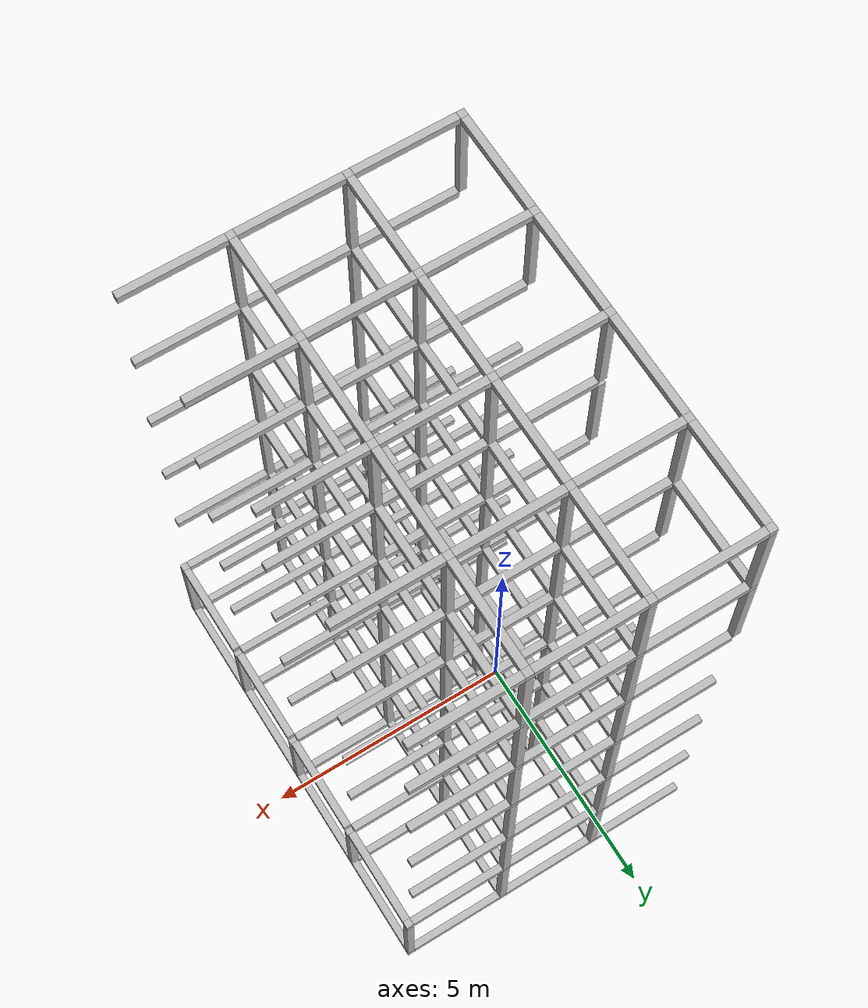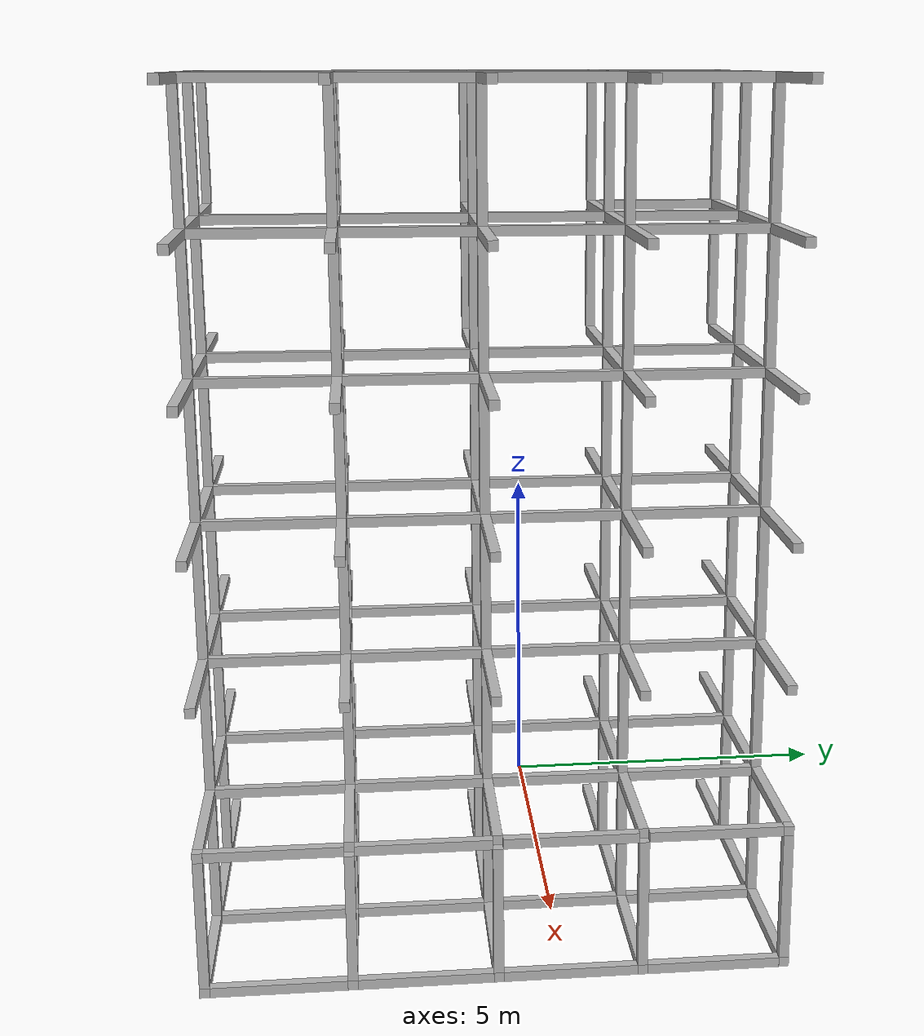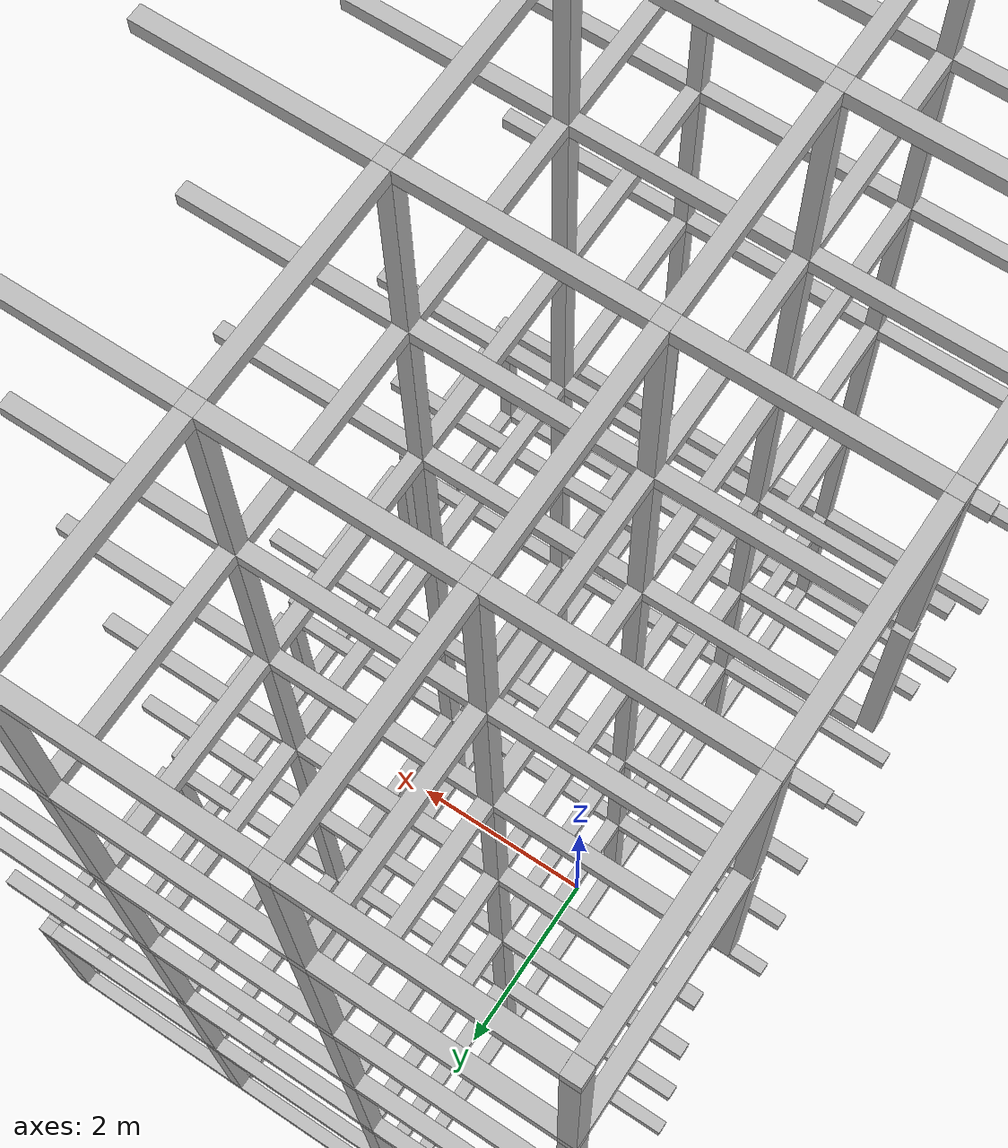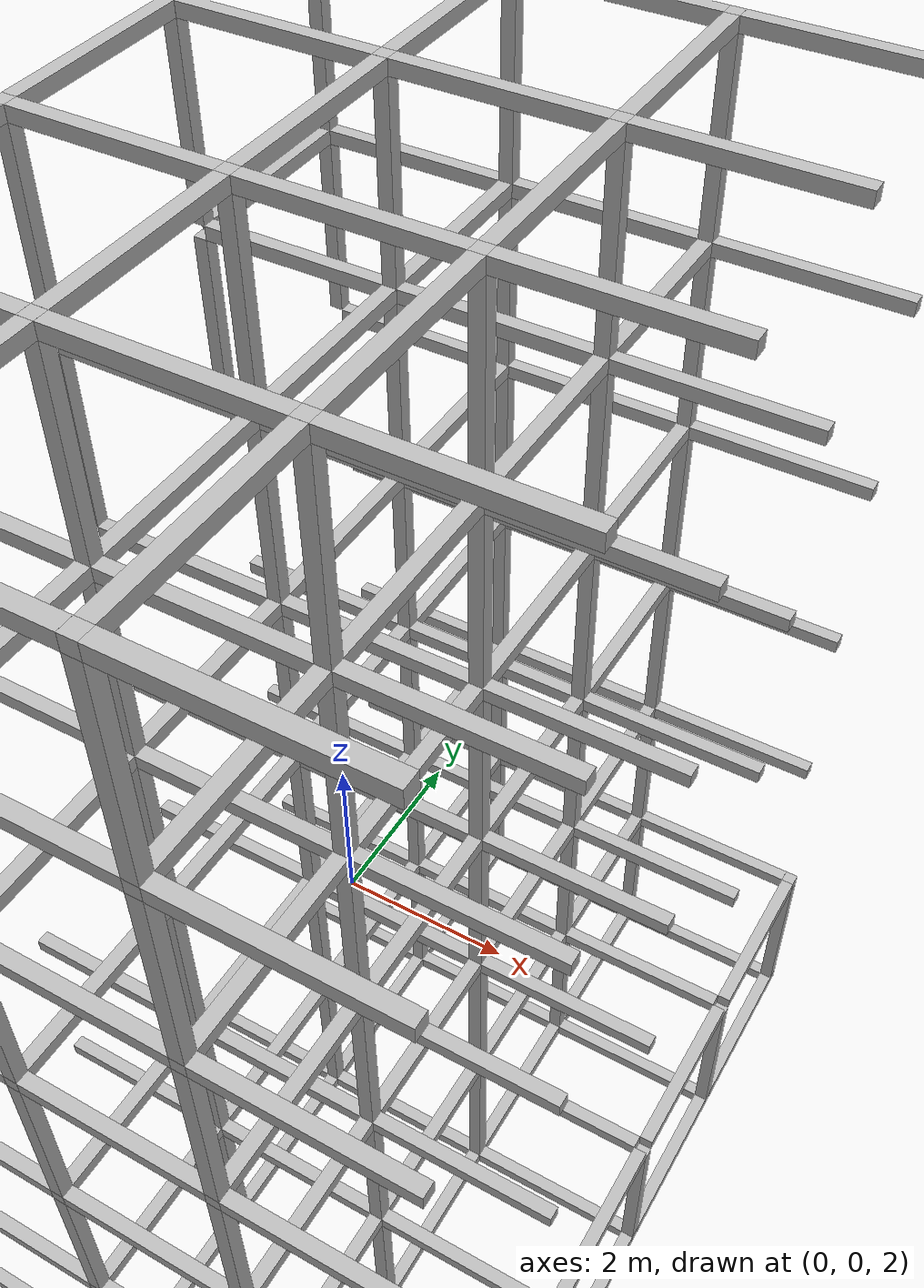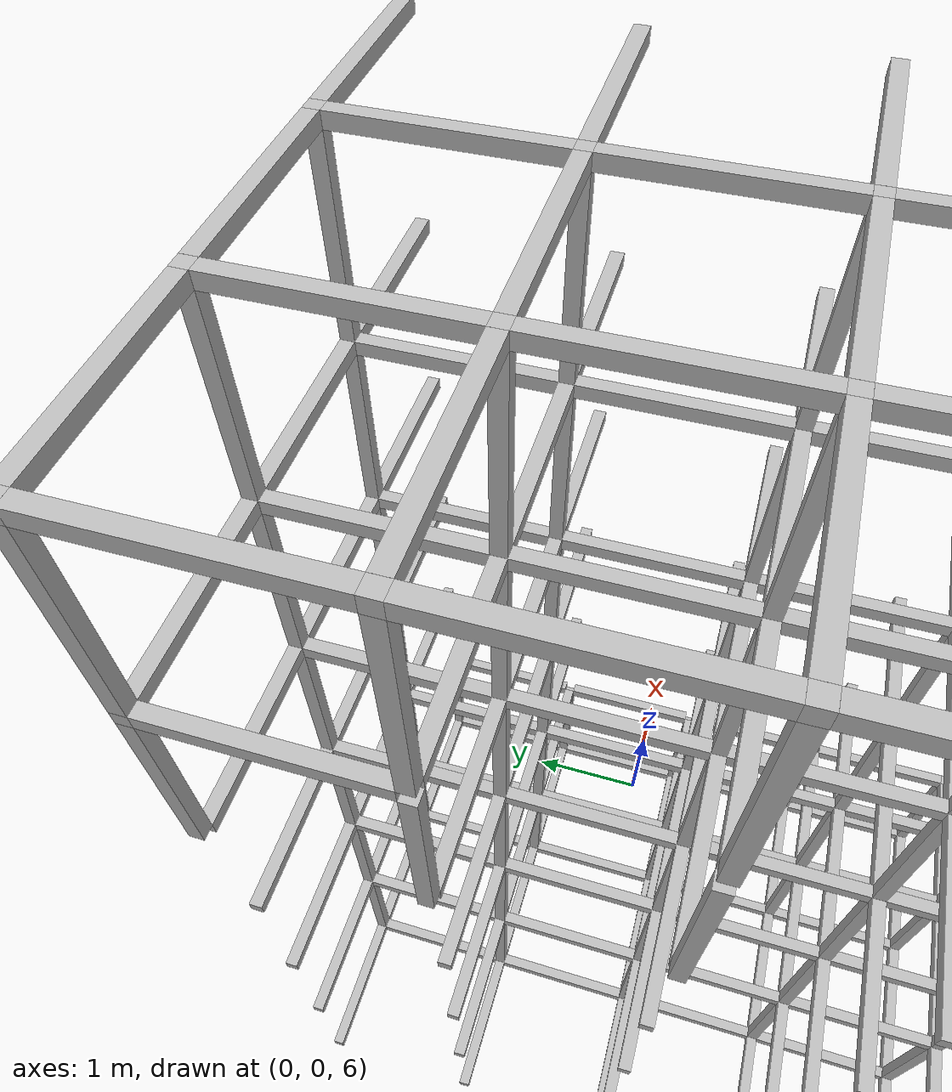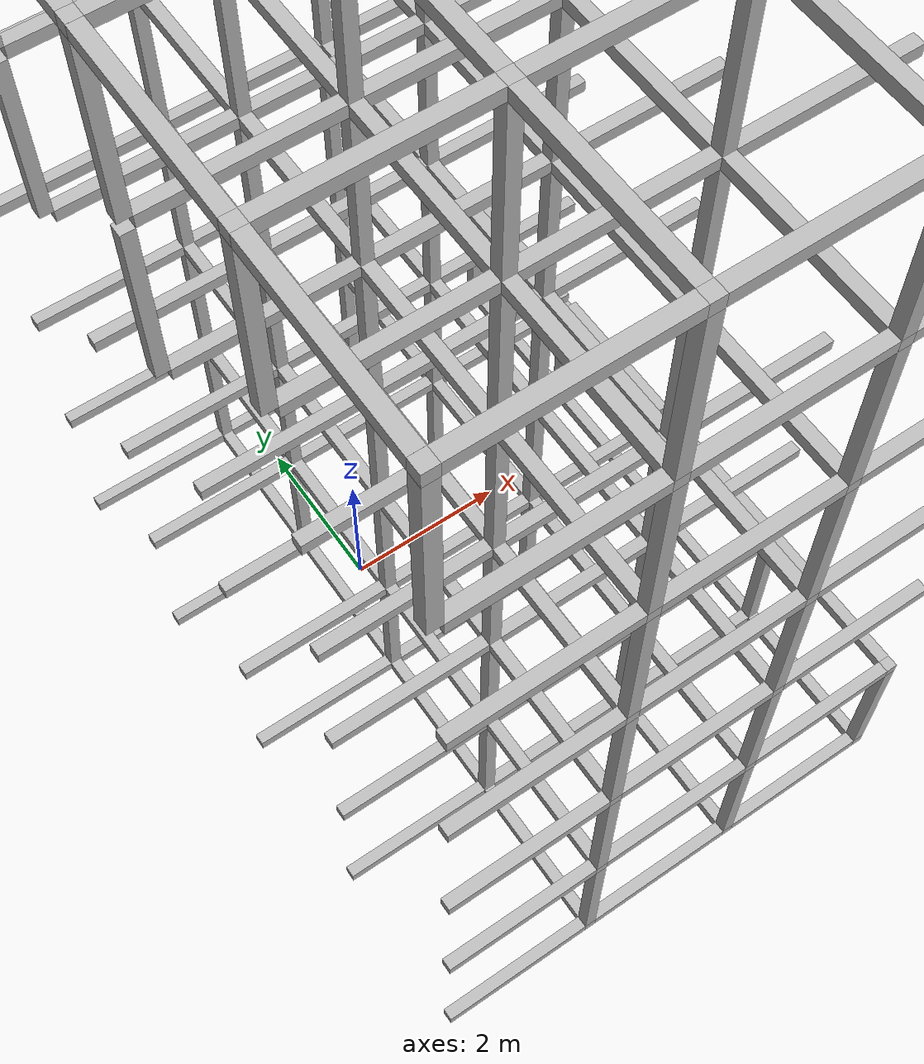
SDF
<sdf version="1.7">
 <world name="default">
  <model name="orthogonal_747_2.000.15_TS">
   <static>1</static>
   <link name="x_link_0_0_2">
    <inertial>
     <mass>1</mass>
     <inertia>
      <ixx>0.166667</ixx>
      <ixy>0</ixy>
      <ixz>0</ixz>
      <iyy>0.166667</iyy>
      <iyz>0</iyz>
      <izz>0.166667</izz>
     </inertia>
    </inertial>
    <pose>5.375 0 1.075 0 -0 0</pose>
    <visual name="visual_0">
     <laser_retro>43</laser_retro>
     <geometry><box><size>2 1e-06 0.15</size></box></geometry>
     <material>
      <script><name>Gazebo/Grey</name><uri>file://media/materials/scripts/gazebo.material</uri></script>
      <shader type="pixel"><normal_map>__default__</normal_map></shader>
      <ambient>0.678 0.498 0.659 1</ambient>
      <diffuse>0.7 0.7 0.7 1</diffuse>
      <specular>0.01 0.01 0.01 1</specular>
      <emissive>0 0 0 1</emissive>
     </material>
     <pose>0 -0.075 0 0 -0 0</pose>
     <transparency>1</transparency>
    </visual>
    <visual name="visual_1">
     <laser_retro>44</laser_retro>
     <geometry><box><size>2 1e-06 0.15</size></box></geometry>
     <material>
      <script><name>Gazebo/Grey</name><uri>file://media/materials/scripts/gazebo.material</uri></script>
      <shader type="pixel"><normal_map>__default__</normal_map></shader>
      <ambient>0.447 0.624 0.812 1</ambient>
      <diffuse>0.7 0.7 0.7 1</diffuse>
      <specular>0.01 0.01 0.01 1</specular>
      <emissive>0 0 0 1</emissive>
     </material>
     <pose>0 0.075 0 0 -0 0</pose>
     <transparency>1</transparency>
    </visual>
    <visual name="visual_2">
     <laser_retro>45</laser_retro>
     <geometry><box><size>2 0.15 1e-06</size></box></geometry>
     <material>
      <script><name>Gazebo/Grey</name><uri>file://media/materials/scripts/gazebo.material</uri></script>
      <shader type="pixel"><normal_map>__default__</normal_map></shader>
      <ambient>0.988 0.686 0.243 1</ambient>
      <diffuse>0.7 0.7 0.7 1</diffuse>
      <specular>0.01 0.01 0.01 1</specular>
      <emissive>0 0 0 1</emissive>
     </material>
     <pose>0 0 -0.075 0 -0 0</pose>
     <transparency>1</transparency>
    </visual>
    <visual name="visual_3">
     <laser_retro>46</laser_retro>
     <geometry><box><size>1e-06 0.15 0.15</size></box></geometry>
     <material>
      <script><name>Gazebo/Grey</name><uri>file://media/materials/scripts/gazebo.material</uri></script>
      <shader type="pixel"><normal_map>__default__</normal_map></shader>
      <ambient>0.988 0.914 0.31 1</ambient>
      <diffuse>0.7 0.7 0.7 1</diffuse>
      <specular>0.01 0.01 0.01 1</specular>
      <emissive>0 0 0 1</emissive>
     </material>
     <pose>1 0 0 0 -0 0</pose>
     <transparency>1</transparency>
    </visual>
    <visual name="visual_4">
     <laser_retro>47</laser_retro>
     <geometry><box><size>2 0.15 1e-06</size></box></geometry>
     <material>
      <script><name>Gazebo/Grey</name><uri>file://media/materials/scripts/gazebo.material</uri></script>
      <shader type="pixel"><normal_map>__default__</normal_map></shader>
      <ambient>0.937 0.161 0.161 1</ambient>
      <diffuse>0.7 0.7 0.7 1</diffuse>
      <specular>0.01 0.01 0.01 1</specular>
      <emissive>0 0 0 1</emissive>
     </material>
     <pose>0 0 0.075 0 -0 0</pose>
     <transparency>1</transparency>
    </visual>
    <visual name="visual_5">
     <laser_retro>48</laser_retro>
     <geometry><box><size>1e-06 0.15 0.15</size></box></geometry>
     <material>
      <script><name>Gazebo/Grey</name><uri>file://media/materials/scripts/gazebo.material</uri></script>
      <shader type="pixel"><normal_map>__default__</normal_map></shader>
      <ambient>0.541 0.886 0.204 1</ambient>
      <diffuse>0.7 0.7 0.7 1</diffuse>
      <specular>0.01 0.01 0.01 1</specular>
      <emissive>0 0 0 1</emissive>
     </material>
     <pose>-1 0 0 0 -0 0</pose>
     <transparency>1</transparency>
    </visual>
    <visual name="visual_texture">
     <geometry><box><size>1.9998 0.149985 0.149985</size></box></geometry>
     <material>
      <script>
       <uri>model://BASE_MODELS/simple_block_v2_textured/materials/scripts</uri>
       <uri>model://BASE_MODELS/simple_block_v2_textured/materials/textures</uri>
       <name>metal</name>
      </script>
     </material>
     <laser_retro>49</laser_retro>
    </visual>
    <collision name="collision">
     <geometry><box><size>2 0.15 0.15</size></box></geometry>
     <surface>
      <friction>
       <ode><mu>1</mu><mu2>1</mu2><fdir1>0 0 0</fdir1><slip1>0</slip1><slip2>0</slip2></ode>
       <torsional>
        <coefficient>1</coefficient>
        <patch_radius>0</patch_radius>
        <surface_radius>0</surface_radius>
        <use_patch_radius>1</use_patch_radius>
        <ode><slip>0</slip></ode>
       </torsional>
      </friction>
      <bounce><restitution_coefficient>0</restitution_coefficient><threshold>1e+06</threshold></bounce>
      <contact>
       <collide_without_contact>0</collide_without_contact>
       <collide_without_contact_bitmask>1</collide_without_contact_bitmask>
       <collide_bitmask>1</collide_bitmask>
       <ode>
        <soft_cfm>0</soft_cfm>
        <soft_erp>0.2</soft_erp>
        <kp>1e+13</kp>
        <kd>1</kd>
        <max_vel>0.01</max_vel>
        <min_depth>0</min_depth>
       </ode>
       <bullet>
        <split_impulse>1</split_impulse>
        <split_impulse_penetration_threshold>-0.01</split_impulse_penetration_threshold>
        <soft_cfm>0</soft_cfm>
        <soft_erp>0.2</soft_erp>
        <kp>1e+13</kp>
        <kd>1</kd>
       </bullet>
      </contact>
     </surface>
    </collision>
   </link>
   <link name="x_link_0_0_3">
    <inertial>
     <mass>1</mass>
     <inertia>
      <ixx>0.166667</ixx>
      <ixy>0</ixy>
      <ixz>0</ixz>
      <iyy>0.166667</iyy>
      <iyz>0</iyz>
      <izz>0.166667</izz>
     </inertia>
    </inertial>
    <pose>7.525 0 1.075 0 -0 0</pose>
    <visual name="visual_0">
     <laser_retro>64</laser_retro>
     <geometry><box><size>2 1e-06 0.15</size></box></geometry>
     <material>
      <script><name>Gazebo/Grey</name><uri>file://media/materials/scripts/gazebo.material</uri></script>
      <shader type="pixel"><normal_map>__default__</normal_map></shader>
      <ambient>0.678 0.498 0.659 1</ambient>
      <diffuse>0.7 0.7 0.7 1</diffuse>
      <specular>0.01 0.01 0.01 1</specular>
      <emissive>0 0 0 1</emissive>
     </material>
     <pose>0 -0.075 0 0 -0 0</pose>
     <transparency>1</transparency>
    </visual>
    <visual name="visual_1">
     <laser_retro>65</laser_retro>
     <geometry><box><size>2 1e-06 0.15</size></box></geometry>
     <material>
      <script><name>Gazebo/Grey</name><uri>file://media/materials/scripts/gazebo.material</uri></script>
      <shader type="pixel"><normal_map>__default__</normal_map></shader>
      <ambient>0.447 0.624 0.812 1</ambient>
      <diffuse>0.7 0.7 0.7 1</diffuse>
      <specular>0.01 0.01 0.01 1</specular>
      <emissive>0 0 0 1</emissive>
     </material>
     <pose>0 0.075 0 0 -0 0</pose>
     <transparency>1</transparency>
    </visual>
    <visual name="visual_2">
     <laser_retro>66</laser_retro>
     <geometry><box><size>2 0.15 1e-06</size></box></geometry>
     <material>
      <script><name>Gazebo/Grey</name><uri>file://media/materials/scripts/gazebo.material</uri></script>
      <shader type="pixel"><normal_map>__default__</normal_map></shader>
      <ambient>0.988 0.686 0.243 1</ambient>
      <diffuse>0.7 0.7 0.7 1</diffuse>
      <specular>0.01 0.01 0.01 1</specular>
      <emissive>0 0 0 1</emissive>
     </material>
     <pose>0 0 -0.075 0 -0 0</pose>
     <transparency>1</transparency>
    </visual>
    <visual name="visual_3">
     <laser_retro>67</laser_retro>
     <geometry><box><size>1e-06 0.15 0.15</size></box></geometry>
     <material>
      <script><name>Gazebo/Grey</name><uri>file://media/materials/scripts/gazebo.material</uri></script>
      <shader type="pixel"><normal_map>__default__</normal_map></shader>
      <ambient>0.988 0.914 0.31 1</ambient>
      <diffuse>0.7 0.7 0.7 1</diffuse>
      <specular>0.01 0.01 0.01 1</specular>
      <emissive>0 0 0 1</emissive>
     </material>
     <pose>1 0 0 0 -0 0</pose>
     <transparency>1</transparency>
    </visual>
    <visual name="visual_4">
     <laser_retro>68</laser_retro>
     <geometry><box><size>2 0.15 1e-06</size></box></geometry>
     <material>
      <script><name>Gazebo/Grey</name><uri>file://media/materials/scripts/gazebo.material</uri></script>
      <shader type="pixel"><normal_map>__default__</normal_map></shader>
      <ambient>0.937 0.161 0.161 1</ambient>
      <diffuse>0.7 0.7 0.7 1</diffuse>
      <specular>0.01 0.01 0.01 1</specular>
      <emissive>0 0 0 1</emissive>
     </material>
     <pose>0 0 0.075 0 -0 0</pose>
     <transparency>1</transparency>
    </visual>
    <visual name="visual_5">
     <laser_retro>69</laser_retro>
     <geometry><box><size>1e-06 0.15 0.15</size></box></geometry>
     <material>
      <script><name>Gazebo/Grey</name><uri>file://media/materials/scripts/gazebo.material</uri></script>
      <shader type="pixel"><normal_map>__default__</normal_map></shader>
      <ambient>0.541 0.886 0.204 1</ambient>
      <diffuse>0.7 0.7 0.7 1</diffuse>
      <specular>0.01 0.01 0.01 1</specular>
      <emissive>0 0 0 1</emissive>
     </material>
     <pose>-1 0 0 0 -0 0</pose>
     <transparency>1</transparency>
    </visual>
    <visual name="visual_texture">
     <geometry><box><size>1.9998 0.149985 0.149985</size></box></geometry>
     <material>
      <script>
       <uri>model://BASE_MODELS/simple_block_v2_textured/materials/scripts</uri>
       <uri>model://BASE_MODELS/simple_block_v2_textured/materials/textures</uri>
       <name>metal</name>
      </script>
     </material>
     <laser_retro>70</laser_retro>
    </visual>
    <collision name="collision">
     <geometry><box><size>2 0.15 0.15</size></box></geometry>
     <surface>
      <friction>
       <ode><mu>1</mu><mu2>1</mu2><fdir1>0 0 0</fdir1><slip1>0</slip1><slip2>0</slip2></ode>
       <torsional>
        <coefficient>1</coefficient>
        <patch_radius>0</patch_radius>
        <surface_radius>0</surface_radius>
        <use_patch_radius>1</use_patch_radius>
        <ode><slip>0</slip></ode>
       </torsional>
      </friction>
      <bounce><restitution_coefficient>0</restitution_coefficient><threshold>1e+06</threshold></bounce>
      <contact>
       <collide_without_contact>0</collide_without_contact>
       <collide_without_contact_bitmask>1</collide_without_contact_bitmask>
       <collide_bitmask>1</collide_bitmask>
       <ode>
        <soft_cfm>0</soft_cfm>
        <soft_erp>0.2</soft_erp>
        <kp>1e+13</kp>
        <kd>1</kd>
        <max_vel>0.01</max_vel>
        <min_depth>0</min_depth>
       </ode>
       <bullet>
        <split_impulse>1</split_impulse>
        <split_impulse_penetration_threshold>-0.01</split_impulse_penetration_threshold>
        <soft_cfm>0</soft_cfm>
        <soft_erp>0.2</soft_erp>
        <kp>1e+13</kp>
        <kd>1</kd>
       </bullet>
      </contact>
     </surface>
    </collision>
   </link>
   <link name="y_link_0_0_3">
    <inertial>
     <mass>1</mass>
     <inertia>
      <ixx>0.166667</ixx>
      <ixy>0</ixy>
      <ixz>0</ixz>
      <iyy>0.166667</iyy>
      <iyz>0</iyz>
      <izz>0.166667</izz>
     </inertia>
    </inertial>
    <pose>6.45 1.075 1.075 0 -0 0</pose>
    <visual name="visual_0">
     <laser_retro>71</laser_retro>
     <geometry><box><size>0.15 1e-06 0.15</size></box></geometry>
     <material>
      <script><name>Gazebo/Grey</name><uri>file://media/materials/scripts/gazebo.material</uri></script>
      <shader type="pixel"><normal_map>__default__</normal_map></shader>
      <ambient>0.678 0.498 0.659 1</ambient>
      <diffuse>0.7 0.7 0.7 1</diffuse>
      <specular>0.01 0.01 0.01 1</specular>
      <emissive>0 0 0 1</emissive>
     </material>
     <pose>0 -1 0 0 -0 0</pose>
     <transparency>1</transparency>
    </visual>
    <visual name="visual_1">
     <laser_retro>72</laser_retro>
     <geometry><box><size>0.15 1e-06 0.15</size></box></geometry>
     <material>
      <script><name>Gazebo/Grey</name><uri>file://media/materials/scripts/gazebo.material</uri></script>
      <shader type="pixel"><normal_map>__default__</normal_map></shader>
      <ambient>0.447 0.624 0.812 1</ambient>
      <diffuse>0.7 0.7 0.7 1</diffuse>
      <specular>0.01 0.01 0.01 1</specular>
      <emissive>0 0 0 1</emissive>
     </material>
     <pose>0 1 0 0 -0 0</pose>
     <transparency>1</transparency>
    </visual>
    <visual name="visual_2">
     <laser_retro>73</laser_retro>
     <geometry><box><size>0.15 2 1e-06</size></box></geometry>
     <material>
      <script><name>Gazebo/Grey</name><uri>file://media/materials/scripts/gazebo.material</uri></script>
      <shader type="pixel"><normal_map>__default__</normal_map></shader>
      <ambient>0.988 0.686 0.243 1</ambient>
      <diffuse>0.7 0.7 0.7 1</diffuse>
      <specular>0.01 0.01 0.01 1</specular>
      <emissive>0 0 0 1</emissive>
     </material>
     <pose>0 0 -0.075 0 -0 0</pose>
     <transparency>1</transparency>
    </visual>
    <visual name="visual_3">
     <laser_retro>74</laser_retro>
     <geometry><box><size>1e-06 2 0.15</size></box></geometry>
     <material>
      <script><name>Gazebo/Grey</name><uri>file://media/materials/scripts/gazebo.material</uri></script>
      <shader type="pixel"><normal_map>__default__</normal_map></shader>
      <ambient>0.988 0.914 0.31 1</ambient>
      <diffuse>0.7 0.7 0.7 1</diffuse>
      <specular>0.01 0.01 0.01 1</specular>
      <emissive>0 0 0 1</emissive>
     </material>
     <pose>0.075 0 0 0 -0 0</pose>
     <transparency>1</transparency>
    </visual>
    <visual name="visual_4">
     <laser_retro>75</laser_retro>
     <geometry><box><size>0.15 2 1e-06</size></box></geometry>
     <material>
      <script><name>Gazebo/Grey</name><uri>file://media/materials/scripts/gazebo.material</uri></script>
      <shader type="pixel"><normal_map>__default__</normal_map></shader>
      <ambient>0.937 0.161 0.161 1</ambient>
      <diffuse>0.7 0.7 0.7 1</diffuse>
      <specular>0.01 0.01 0.01 1</specular>
      <emissive>0 0 0 1</emissive>
     </material>
     <pose>0 0 0.075 0 -0 0</pose>
     <transparency>1</transparency>
    </visual>
    <visual name="visual_5">
     <laser_retro>76</laser_retro>
     <geometry><box><size>1e-06 2 0.15</size></box></geometry>
     <material>
      <script><name>Gazebo/Grey</name><uri>file://media/materials/scripts/gazebo.material</uri></script>
      <shader type="pixel"><normal_map>__default__</normal_map></shader>
      <ambient>0.541 0.886 0.204 1</ambient>
      <diffuse>0.7 0.7 0.7 1</diffuse>
      <specular>0.01 0.01 0.01 1</specular>
      <emissive>0 0 0 1</emissive>
     </material>
     <pose>-0.075 0 0 0 -0 0</pose>
     <transparency>1</transparency>
    </visual>
    <visual name="visual_texture">
     <geometry><box><size>0.149985 1.9998 0.149985</size></box></geometry>
     <material>
      <script>
       <uri>model://BASE_MODELS/simple_block_v2_textured/materials/scripts</uri>
       <uri>model://BASE_MODELS/simple_block_v2_textured/materials/textures</uri>
       <name>metal</name>
      </script>
     </material>
     <laser_retro>77</laser_retro>
    </visual>
    <collision name="collision">
     <geometry><box><size>0.15 2 0.15</size></box></geometry>
     <surface>
      <friction>
       <ode><mu>1</mu><mu2>1</mu2><fdir1>0 0 0</fdir1><slip1>0</slip1><slip2>0</slip2></ode>
       <torsional>
        <coefficient>1</coefficient>
        <patch_radius>0</patch_radius>
        <surface_radius>0</surface_radius>
        <use_patch_radius>1</use_patch_radius>
        <ode><slip>0</slip></ode>
       </torsional>
      </friction>
      <bounce><restitution_coefficient>0</restitution_coefficient><threshold>1e+06</threshold></bounce>
      <contact>
       <collide_without_contact>0</collide_without_contact>
       <collide_without_contact_bitmask>1</collide_without_contact_bitmask>
       <collide_bitmask>1</collide_bitmask>
       <ode>
        <soft_cfm>0</soft_cfm>
        <soft_erp>0.2</soft_erp>
        <kp>1e+13</kp>
        <kd>1</kd>
        <max_vel>0.01</max_vel>
        <min_depth>0</min_depth>
       </ode>
       <bullet>
        <split_impulse>1</split_impulse>
        <split_impulse_penetration_threshold>-0.01</split_impulse_penetration_threshold>
        <soft_cfm>0</soft_cfm>
        <soft_erp>0.2</soft_erp>
        <kp>1e+13</kp>
        <kd>1</kd>
       </bullet>
      </contact>
     </surface>
    </collision>
   </link>
   <link name="u_link_0_0_3">
    <inertial>
     <mass>1</mass>
     <inertia>
      <ixx>0.166667</ixx>
      <ixy>0</ixy>
      <ixz>0</ixz>
      <iyy>0.166667</iyy>
      <iyz>0</iyz>
      <izz>0.166667</izz>
     </inertia>
    </inertial>
    <pose>6.45 0 1.075 0 -0 0</pose>
    <visual name="visual_0">
     <laser_retro>78</laser_retro>
     <geometry><box><size>0.15 1e-06 0.15</size></box></geometry>
     <material>
      <script><name>Gazebo/Grey</name><uri>file://media/materials/scripts/gazebo.material</uri></script>
      <shader type="pixel"><normal_map>__default__</normal_map></shader>
      <ambient>0.678 0.498 0.659 1</ambient>
      <diffuse>0.7 0.7 0.7 1</diffuse>
      <specular>0.01 0.01 0.01 1</specular>
      <emissive>0 0 0 1</emissive>
     </material>
     <pose>0 -0.075 0 0 -0 0</pose>
     <transparency>1</transparency>
    </visual>
    <visual name="visual_1">
     <laser_retro>79</laser_retro>
     <geometry><box><size>0.15 1e-06 0.15</size></box></geometry>
     <material>
      <script><name>Gazebo/Grey</name><uri>file://media/materials/scripts/gazebo.material</uri></script>
      <shader type="pixel"><normal_map>__default__</normal_map></shader>
      <ambient>0.447 0.624 0.812 1</ambient>
      <diffuse>0.7 0.7 0.7 1</diffuse>
      <specular>0.01 0.01 0.01 1</specular>
      <emissive>0 0 0 1</emissive>
     </material>
     <pose>0 0.075 0 0 -0 0</pose>
     <transparency>1</transparency>
    </visual>
    <visual name="visual_2">
     <laser_retro>80</laser_retro>
     <geometry><box><size>0.15 0.15 1e-06</size></box></geometry>
     <material>
      <script><name>Gazebo/Grey</name><uri>file://media/materials/scripts/gazebo.material</uri></script>
      <shader type="pixel"><normal_map>__default__</normal_map></shader>
      <ambient>0.988 0.686 0.243 1</ambient>
      <diffuse>0.7 0.7 0.7 1</diffuse>
      <specular>0.01 0.01 0.01 1</specular>
      <emissive>0 0 0 1</emissive>
     </material>
     <pose>0 0 -0.075 0 -0 0</pose>
     <transparency>1</transparency>
    </visual>
    <visual name="visual_3">
     <laser_retro>81</laser_retro>
     <geometry><box><size>1e-06 0.15 0.15</size></box></geometry>
     <material>
      <script><name>Gazebo/Grey</name><uri>file://media/materials/scripts/gazebo.material</uri></script>
      <shader type="pixel"><normal_map>__default__</normal_map></shader>
      <ambient>0.988 0.914 0.31 1</ambient>
      <diffuse>0.7 0.7 0.7 1</diffuse>
      <specular>0.01 0.01 0.01 1</specular>
      <emissive>0 0 0 1</emissive>
     </material>
     <pose>0.075 0 0 0 -0 0</pose>
     <transparency>1</transparency>
    </visual>
    <visual name="visual_4">
     <laser_retro>82</laser_retro>
     <geometry><box><size>0.15 0.15 1e-06</size></box></geometry>
     <material>
      <script><name>Gazebo/Grey</name><uri>file://media/materials/scripts/gazebo.material</uri></script>
      <shader type="pixel"><normal_map>__default__</normal_map></shader>
      <ambient>0.937 0.161 0.161 1</ambient>
      <diffuse>0.7 0.7 0.7 1</diffuse>
      <specular>0.01 0.01 0.01 1</specular>
      <emissive>0 0 0 1</emissive>
     </material>
     <pose>0 0 0.075 0 -0 0</pose>
     <transparency>1</transparency>
    </visual>
    <visual name="visual_5">
     <laser_retro>83</laser_retro>
     <geometry><box><size>1e-06 0.15 0.15</size></box></geometry>
     <material>
      <script><name>Gazebo/Grey</name><uri>file://media/materials/scripts/gazebo.material</uri></script>
      <shader type="pixel"><normal_map>__default__</normal_map></shader>
      <ambient>0.541 0.886 0.204 1</ambient>
      <diffuse>0.7 0.7 0.7 1</diffuse>
      <specular>0.01 0.01 0.01 1</specular>
      <emissive>0 0 0 1</emissive>
     </material>
     <pose>-0.075 0 0 0 -0 0</pose>
     <transparency>1</transparency>
    </visual>
    <visual name="visual_texture">
     <geometry><box><size>0.149985 0.149985 0.149985</size></box></geometry>
     <material>
      <script>
       <uri>model://BASE_MODELS/simple_block_v2_textured/materials/scripts</uri>
       <uri>model://BASE_MODELS/simple_block_v2_textured/materials/textures</uri>
       <name>metal</name>
      </script>
     </material>
     <laser_retro>84</laser_retro>
    </visual>
    <collision name="collision">
     <geometry><box><size>0.15 0.15 0.15</size></box></geometry>
     <surface>
      <friction>
       <ode><mu>1</mu><mu2>1</mu2><fdir1>0 0 0</fdir1><slip1>0</slip1><slip2>0</slip2></ode>
       <torsional>
        <coefficient>1</coefficient>
        <patch_radius>0</patch_radius>
        <surface_radius>0</surface_radius>
        <use_patch_radius>1</use_patch_radius>
        <ode><slip>0</slip></ode>
       </torsional>
      </friction>
      <bounce><restitution_coefficient>0</restitution_coefficient><threshold>1e+06</threshold></bounce>
      <contact>
       <collide_without_contact>0</collide_without_contact>
       <collide_without_contact_bitmask>1</collide_without_contact_bitmask>
       <collide_bitmask>1</collide_bitmask>
       <ode>
        <soft_cfm>0</soft_cfm>
        <soft_erp>0.2</soft_erp>
        <kp>1e+13</kp>
        <kd>1</kd>
        <max_vel>0.01</max_vel>
        <min_depth>0</min_depth>
       </ode>
       <bullet>
        <split_impulse>1</split_impulse>
        <split_impulse_penetration_threshold>-0.01</split_impulse_penetration_threshold>
        <soft_cfm>0</soft_cfm>
        <soft_erp>0.2</soft_erp>
        <kp>1e+13</kp>
        <kd>1</kd>
       </bullet>
      </contact>
     </surface>
    </collision>
   </link>
   <link name="x_link_0_0_4">
    <inertial>
     <mass>1</mass>
     <inertia>
      <ixx>0.166667</ixx>
      <ixy>0</ixy>
      <ixz>0</ixz>
      <iyy>0.166667</iyy>
      <iyz>0</iyz>
      <izz>0.166667</izz>
     </inertia>
    </inertial>
    <pose>9.675 0 1.075 0 -0 0</pose>
    <visual name="visual_0">
     <laser_retro>85</laser_retro>
     <geometry><box><size>2 1e-06 0.15</size></box></geometry>
     <material>
      <script><name>Gazebo/Grey</name><uri>file://media/materials/scripts/gazebo.material</uri></script>
      <shader type="pixel"><normal_map>__default__</normal_map></shader>
      <ambient>0.678 0.498 0.659 1</ambient>
      <diffuse>0.7 0.7 0.7 1</diffuse>
      <specular>0.01 0.01 0.01 1</specular>
      <emissive>0 0 0 1</emissive>
     </material>
     <pose>0 -0.075 0 0 -0 0</pose>
     <transparency>1</transparency>
    </visual>
    <visual name="visual_1">
     <laser_retro>86</laser_retro>
     <geometry><box><size>2 1e-06 0.15</size></box></geometry>
     <material>
      <script><name>Gazebo/Grey</name><uri>file://media/materials/scripts/gazebo.material</uri></script>
      <shader type="pixel"><normal_map>__default__</normal_map></shader>
      <ambient>0.447 0.624 0.812 1</ambient>
      <diffuse>0.7 0.7 0.7 1</diffuse>
      <specular>0.01 0.01 0.01 1</specular>
      <emissive>0 0 0 1</emissive>
     </material>
     <pose>0 0.075 0 0 -0 0</pose>
     <transparency>1</transparency>
    </visual>
    <visual name="visual_2">
     <laser_retro>87</laser_retro>
     <geometry><box><size>2 0.15 1e-06</size></box></geometry>
     <material>
      <script><name>Gazebo/Grey</name><uri>file://media/materials/scripts/gazebo.material</uri></script>
      <shader type="pixel"><normal_map>__default__</normal_map></shader>
      <ambient>0.988 0.686 0.243 1</ambient>
      <diffuse>0.7 0.7 0.7 1</diffuse>
      <specular>0.01 0.01 0.01 1</specular>
      <emissive>0 0 0 1</emissive>
     </material>
     <pose>0 0 -0.075 0 -0 0</pose>
     <transparency>1</transparency>
    </visual>
    <visual name="visual_3">
     <laser_retro>88</laser_retro>
     <geometry><box><size>1e-06 0.15 0.15</size></box></geometry>
     <material>
      <script><name>Gazebo/Grey</name><uri>file://media/materials/scripts/gazebo.material</uri></script>
      <shader type="pixel"><normal_map>__default__</normal_map></shader>
      <ambient>0.988 0.914 0.31 1</ambient>
      <diffuse>0.7 0.7 0.7 1</diffuse>
      <specular>0.01 0.01 0.01 1</specular>
      <emissive>0 0 0 1</emissive>
     </material>
     <pose>1 0 0 0 -0 0</pose>
     <transparency>1</transparency>
    </visual>
    <visual name="visual_4">
     <laser_retro>89</laser_retro>
     <geometry><box><size>2 0.15 1e-06</size></box></geometry>
     <material>
      <script><name>Gazebo/Grey</name><uri>file://media/materials/scripts/gazebo.material</uri></script>
      <shader type="pixel"><normal_map>__default__</normal_map></shader>
      <ambient>0.937 0.161 0.161 1</ambient>
      <diffuse>0.7 0.7 0.7 1</diffuse>
      <specular>0.01 0.01 0.01 1</specular>
      <emissive>0 0 0 1</emissive>
     </material>
     <pose>0 0 0.075 0 -0 0</pose>
     <transparency>1</transparency>
    </visual>
    <visual name="visual_5">
     <laser_retro>90</laser_retro>
     <geometry><box><size>1e-06 0.15 0.15</size></box></geometry>
     <material>
      <script><name>Gazebo/Grey</name><uri>file://media/materials/scripts/gazebo.material</uri></script>
      <shader type="pixel"><normal_map>__default__</normal_map></shader>
      <ambient>0.541 0.886 0.204 1</ambient>
      <diffuse>0.7 0.7 0.7 1</diffuse>
      <specular>0.01 0.01 0.01 1</specular>
      <emissive>0 0 0 1</emissive>
     </material>
     <pose>-1 0 0 0 -0 0</pose>
     <transparency>1</transparency>
    </visual>
    <visual name="visual_texture">
     <geometry><box><size>1.9998 0.149985 0.149985</size></box></geometry>
     <material>
      <script>
       <uri>model://BASE_MODELS/simple_block_v2_textured/materials/scripts</uri>
       <uri>model://BASE_MODELS/simple_block_v2_textured/materials/textures</uri>
       <name>metal</name>
      </script>
     </material>
     <laser_retro>91</laser_retro>
    </visual>
    <collision name="collision">
     <geometry><box><size>2 0.15 0.15</size></box></geometry>
     <surface>
      <friction>
       <ode><mu>1</mu><mu2>1</mu2><fdir1>0 0 0</fdir1><slip1>0</slip1><slip2>0</slip2></ode>
       <torsional>
        <coefficient>1</coefficient>
        <patch_radius>0</patch_radius>
        <surface_radius>0</surface_radius>
        <use_patch_radius>1</use_patch_radius>
        <ode><slip>0</slip></ode>
       </torsional>
      </friction>
      <bounce><restitution_coefficient>0</restitution_coefficient><threshold>1e+06</threshold></bounce>
      <contact>
       <collide_without_contact>0</collide_without_contact>
       <collide_without_contact_bitmask>1</collide_without_contact_bitmask>
       <collide_bitmask>1</collide_bitmask>
       <ode>
        <soft_cfm>0</soft_cfm>
        <soft_erp>0.2</soft_erp>
        <kp>1e+13</kp>
        <kd>1</kd>
        <max_vel>0.01</max_vel>
        <min_depth>0</min_depth>
       </ode>
       <bullet>
        <split_impulse>1</split_impulse>
        <split_impulse_penetration_threshold>-0.01</split_impulse_penetration_threshold>
        <soft_cfm>0</soft_cfm>
        <soft_erp>0.2</soft_erp>
        <kp>1e+13</kp>
        <kd>1</kd>
       </bullet>
      </contact>
     </surface>
    </collision>
   </link>
   <link name="y_link_0_0_4">
    <inertial>
     <mass>1</mass>
     <inertia>
      <ixx>0.166667</ixx>
      <ixy>0</ixy>
      <ixz>0</ixz>
      <iyy>0.166667</iyy>
      <iyz>0</iyz>
      <izz>0.166667</izz>
     </inertia>
    </inertial>
    <pose>8.6 1.075 1.075 0 -0 0</pose>
    <visual name="visual_0">
     <laser_retro>92</laser_retro>
     <geometry><box><size>0.15 1e-06 0.15</size></box></geometry>
     <material>
      <script><name>Gazebo/Grey</name><uri>file://media/materials/scripts/gazebo.material</uri></script>
      <shader type="pixel"><normal_map>__default__</normal_map></shader>
      <ambient>0.678 0.498 0.659 1</ambient>
      <diffuse>0.7 0.7 0.7 1</diffuse>
      <specular>0.01 0.01 0.01 1</specular>
      <emissive>0 0 0 1</emissive>
     </material>
     <pose>0 -1 0 0 -0 0</pose>
     <transparency>1</transparency>
    </visual>
    <visual name="visual_1">
     <laser_retro>93</laser_retro>
     <geometry><box><size>0.15 1e-06 0.15</size></box></geometry>
     <material>
      <script><name>Gazebo/Grey</name><uri>file://media/materials/scripts/gazebo.material</uri></script>
      <shader type="pixel"><normal_map>__default__</normal_map></shader>
      <ambient>0.447 0.624 0.812 1</ambient>
      <diffuse>0.7 0.7 0.7 1</diffuse>
      <specular>0.01 0.01 0.01 1</specular>
      <emissive>0 0 0 1</emissive>
     </material>
     <pose>0 1 0 0 -0 0</pose>
     <transparency>1</transparency>
    </visual>
    <visual name="visual_2">
     <laser_retro>94</laser_retro>
     <geometry><box><size>0.15 2 1e-06</size></box></geometry>
     <material>
      <script><name>Gazebo/Grey</name><uri>file://media/materials/scripts/gazebo.material</uri></script>
      <shader type="pixel"><normal_map>__default__</normal_map></shader>
      <ambient>0.988 0.686 0.243 1</ambient>
      <diffuse>0.7 0.7 0.7 1</diffuse>
      <specular>0.01 0.01 0.01 1</specular>
      <emissive>0 0 0 1</emissive>
     </material>
     <pose>0 0 -0.075 0 -0 0</pose>
     <transparency>1</transparency>
    </visual>
    <visual name="visual_3">
     <laser_retro>95</laser_retro>
     <geometry><box><size>1e-06 2 0.15</size></box></geometry>
     <material>
      <script><name>Gazebo/Grey</name><uri>file://media/materials/scripts/gazebo.material</uri></script>
      <shader type="pixel"><normal_map>__default__</normal_map></shader>
      <ambient>0.988 0.914 0.31 1</ambient>
      <diffuse>0.7 0.7 0.7 1</diffuse>
      <specular>0.01 0.01 0.01 1</specular>
      <emissive>0 0 0 1</emissive>
     </material>
     <pose>0.075 0 0 0 -0 0</pose>
     <transparency>1</transparency>
    </visual>
    <visual name="visual_4">
     <laser_retro>96</laser_retro>
     <geometry><box><size>0.15 2 1e-06</size></box></geometry>
     <material>
      <script><name>Gazebo/Grey</name><uri>file://media/materials/scripts/gazebo.material</uri></script>
      <shader type="pixel"><normal_map>__default__</normal_map></shader>
      <ambient>0.937 0.161 0.161 1</ambient>
      <diffuse>0.7 0.7 0.7 1</diffuse>
      <specular>0.01 0.01 0.01 1</specular>
      <emissive>0 0 0 1</emissive>
     </material>
     <pose>0 0 0.075 0 -0 0</pose>
     <transparency>1</transparency>
    </visual>
    <visual name="visual_5">
     <laser_retro>97</laser_retro>
     <geometry><box><size>1e-06 2 0.15</size></box></geometry>
     <material>
      <script><name>Gazebo/Grey</name><uri>file://media/materials/scripts/gazebo.material</uri></script>
      <shader type="pixel"><normal_map>__default__</normal_map></shader>
      <ambient>0.541 0.886 0.204 1</ambient>
      <diffuse>0.7 0.7 0.7 1</diffuse>
      <specular>0.01 0.01 0.01 1</specular>
      <emissive>0 0 0 1</emissive>
     </material>
     <pose>-0.075 0 0 0 -0 0</pose>
     <transparency>1</transparency>
    </visual>
    <visual name="visual_texture">
     <geometry><box><size>0.149985 1.9998 0.149985</size></box></geometry>
     <material>
      <script>
       <uri>model://BASE_MODELS/simple_block_v2_textured/materials/scripts</uri>
       <uri>model://BASE_MODELS/simple_block_v2_textured/materials/textures</uri>
       <name>metal</name>
      </script>
     </material>
     <laser_retro>98</laser_retro>
    </visual>
    <collision name="collision">
     <geometry><box><size>0.15 2 0.15</size></box></geometry>
     <surface>
      <friction>
       <ode><mu>1</mu><mu2>1</mu2><fdir1>0 0 0</fdir1><slip1>0</slip1><slip2>0</slip2></ode>
       <torsional>
        <coefficient>1</coefficient>
        <patch_radius>0</patch_radius>
        <surface_radius>0</surface_radius>
        <use_patch_radius>1</use_patch_radius>
        <ode><slip>0</slip></ode>
       </torsional>
      </friction>
      <bounce><restitution_coefficient>0</restitution_coefficient><threshold>1e+06</threshold></bounce>
      <contact>
       <collide_without_contact>0</collide_without_contact>
       <collide_without_contact_bitmask>1</collide_without_contact_bitmask>
       <collide_bitmask>1</collide_bitmask>
       <ode>
        <soft_cfm>0</soft_cfm>
        <soft_erp>0.2</soft_erp>
        <kp>1e+13</kp>
        <kd>1</kd>
        <max_vel>0.01</max_vel>
        <min_depth>0</min_depth>
       </ode>
       <bullet>
        <split_impulse>1</split_impulse>
        <split_impulse_penetration_threshold>-0.01</split_impulse_penetration_threshold>
        <soft_cfm>0</soft_cfm>
        <soft_erp>0.2</soft_erp>
        <kp>1e+13</kp>
        <kd>1</kd>
       </bullet>
      </contact>
     </surface>
    </collision>
   </link>
   <link name="u_link_0_0_4">
    <inertial>
     <mass>1</mass>
     <inertia>
      <ixx>0.166667</ixx>
      <ixy>0</ixy>
      <ixz>0</ixz>
      <iyy>0.166667</iyy>
      <iyz>0</iyz>
      <izz>0.166667</izz>
     </inertia>
    </inertial>
    <pose>8.6 0 1.075 0 -0 0</pose>
    <visual name="visual_0">
     <laser_retro>99</laser_retro>
     <geometry><box><size>0.15 1e-06 0.15</size></box></geometry>
     <material>
      <script><name>Gazebo/Grey</name><uri>file://media/materials/scripts/gazebo.material</uri></script>
      <shader type="pixel"><normal_map>__default__</normal_map></shader>
      <ambient>0.678 0.498 0.659 1</ambient>
      <diffuse>0.7 0.7 0.7 1</diffuse>
      <specular>0.01 0.01 0.01 1</specular>
      <emissive>0 0 0 1</emissive>
     </material>
     <pose>0 -0.075 0 0 -0 0</pose>
     <transparency>1</transparency>
    </visual>
    <visual name="visual_1">
     <laser_retro>100</laser_retro>
     <geometry><box><size>0.15 1e-06 0.15</size></box></geometry>
     <material>
      <script><name>Gazebo/Grey</name><uri>file://media/materials/scripts/gazebo.material</uri></script>
      <shader type="pixel"><normal_map>__default__</normal_map></shader>
      <ambient>0.447 0.624 0.812 1</ambient>
      <diffuse>0.7 0.7 0.7 1</diffuse>
      <specular>0.01 0.01 0.01 1</specular>
      <emissive>0 0 0 1</emissive>
     </material>
     <pose>0 0.075 0 0 -0 0</pose>
     <transparency>1</transparency>
    </visual>
    <visual name="visual_2">
     <laser_retro>101</laser_retro>
     <geometry><box><size>0.15 0.15 1e-06</size></box></geometry>
     <material>
      <script><name>Gazebo/Grey</name><uri>file://media/materials/scripts/gazebo.material</uri></script>
      <shader type="pixel"><normal_map>__default__</normal_map></shader>
      <ambient>0.988 0.686 0.243 1</ambient>
      <diffuse>0.7 0.7 0.7 1</diffuse>
      <specular>0.01 0.01 0.01 1</specular>
      <emissive>0 0 0 1</emissive>
     </material>
     <pose>0 0 -0.075 0 -0 0</pose>
     <transparency>1</transparency>
    </visual>
    <visual name="visual_3">
     <laser_retro>102</laser_retro>
     <geometry><box><size>1e-06 0.15 0.15</size></box></geometry>
     <material>
      <script><name>Gazebo/Grey</name><uri>file://media/materials/scripts/gazebo.material</uri></script>
      <shader type="pixel"><normal_map>__default__</normal_map></shader>
      <ambient>0.988 0.914 0.31 1</ambient>
      <diffuse>0.7 0.7 0.7 1</diffuse>
      <specular>0.01 0.01 0.01 1</specular>
      <emissive>0 0 0 1</emissive>
     </material>
     <pose>0.075 0 0 0 -0 0</pose>
     <transparency>1</transparency>
    </visual>
    <visual name="visual_4">
     <laser_retro>103</laser_retro>
     <geometry><box><size>0.15 0.15 1e-06</size></box></geometry>
     <material>
      <script><name>Gazebo/Grey</name><uri>file://media/materials/scripts/gazebo.material</uri></script>
      <shader type="pixel"><normal_map>__default__</normal_map></shader>
      <ambient>0.937 0.161 0.161 1</ambient>
      <diffuse>0.7 0.7 0.7 1</diffuse>
      <specular>0.01 0.01 0.01 1</specular>
      <emissive>0 0 0 1</emissive>
     </material>
     <pose>0 0 0.075 0 -0 0</pose>
     <transparency>1</transparency>
    </visual>
    <visual name="visual_5">
     <laser_retro>104</laser_retro>
     <geometry><box><size>1e-06 0.15 0.15</size></box></geometry>
     <material>
      <script><name>Gazebo/Grey</name><uri>file://media/materials/scripts/gazebo.material</uri></script>
      <shader type="pixel"><normal_map>__default__</normal_map></shader>
      <ambient>0.541 0.886 0.204 1</ambient>
      <diffuse>0.7 0.7 0.7 1</diffuse>
      <specular>0.01 0.01 0.01 1</specular>
      <emissive>0 0 0 1</emissive>
     </material>
     <pose>-0.075 0 0 0 -0 0</pose>
     <transparency>1</transparency>
    </visual>
    <visual name="visual_texture">
     <geometry><box><size>0.149985 0.149985 0.149985</size></box></geometry>
     <material>
      <script>
       <uri>model://BASE_MODELS/simple_block_v2_textured/materials/scripts</uri>
       <uri>model://BASE_MODELS/simple_block_v2_textured/materials/textures</uri>
       <name>metal</name>
      </script>
     </material>
     <laser_retro>105</laser_retro>
    </visual>
    <collision name="collision">
     <geometry><box><size>0.15 0.15 0.15</size></box></geometry>
     <surface>
      <friction>
       <ode><mu>1</mu><mu2>1</mu2><fdir1>0 0 0</fdir1><slip1>0</slip1><slip2>0</slip2></ode>
       <torsional>
        <coefficient>1</coefficient>
        <patch_radius>0</patch_radius>
        <surface_radius>0</surface_radius>
        <use_patch_radius>1</use_patch_radius>
        <ode><slip>0</slip></ode>
       </torsional>
      </friction>
      <bounce><restitution_coefficient>0</restitution_coefficient><threshold>1e+06</threshold></bounce>
      <contact>
       <collide_without_contact>0</collide_without_contact>
       <collide_without_contact_bitmask>1</collide_without_contact_bitmask>
       <collide_bitmask>1</collide_bitmask>
       <ode>
        <soft_cfm>0</soft_cfm>
        <soft_erp>0.2</soft_erp>
        <kp>1e+13</kp>
        <kd>1</kd>
        <max_vel>0.01</max_vel>
        <min_depth>0</min_depth>
       </ode>
       <bullet>
        <split_impulse>1</split_impulse>
        <split_impulse_penetration_threshold>-0.01</split_impulse_penetration_threshold>
        <soft_cfm>0</soft_cfm>
        <soft_erp>0.2</soft_erp>
        <kp>1e+13</kp>
        <kd>1</kd>
       </bullet>
      </contact>
     </surface>
    </collision>
   </link>
   <link name="y_link_0_0_5">
    <inertial>
     <mass>1</mass>
     <inertia>
      <ixx>0.166667</ixx>
      <ixy>0</ixy>
      <ixz>0</ixz>
      <iyy>0.166667</iyy>
      <iyz>0</iyz>
      <izz>0.166667</izz>
     </inertia>
    </inertial>
    <pose>10.75 1.075 1.075 0 -0 0</pose>
    <visual name="visual_0">
     <laser_retro>113</laser_retro>
     <geometry><box><size>0.15 1e-06 0.15</size></box></geometry>
     <material>
      <script><name>Gazebo/Grey</name><uri>file://media/materials/scripts/gazebo.material</uri></script>
      <shader type="pixel"><normal_map>__default__</normal_map></shader>
      <ambient>0.678 0.498 0.659 1</ambient>
      <diffuse>0.7 0.7 0.7 1</diffuse>
      <specular>0.01 0.01 0.01 1</specular>
      <emissive>0 0 0 1</emissive>
     </material>
     <pose>0 -1 0 0 -0 0</pose>
     <transparency>1</transparency>
    </visual>
    <visual name="visual_1">
     <laser_retro>114</laser_retro>
     <geometry><box><size>0.15 1e-06 0.15</size></box></geometry>
     <material>
      <script><name>Gazebo/Grey</name><uri>file://media/materials/scripts/gazebo.material</uri></script>
      <shader type="pixel"><normal_map>__default__</normal_map></shader>
      <ambient>0.447 0.624 0.812 1</ambient>
      <diffuse>0.7 0.7 0.7 1</diffuse>
      <specular>0.01 0.01 0.01 1</specular>
      <emissive>0 0 0 1</emissive>
     </material>
     <pose>0 1 0 0 -0 0</pose>
     <transparency>1</transparency>
    </visual>
    <visual name="visual_2">
     <laser_retro>115</laser_retro>
     <geometry><box><size>0.15 2 1e-06</size></box></geometry>
     <material>
      <script><name>Gazebo/Grey</name><uri>file://media/materials/scripts/gazebo.material</uri></script>
      <shader type="pixel"><normal_map>__default__</normal_map></shader>
      <ambient>0.988 0.686 0.243 1</ambient>
      <diffuse>0.7 0.7 0.7 1</diffuse>
      <specular>0.01 0.01 0.01 1</specular>
      <emissive>0 0 0 1</emissive>
     </material>
     <pose>0 0 -0.075 0 -0 0</pose>
     <transparency>1</transparency>
    </visual>
    <visual name="visual_3">
     <laser_retro>116</laser_retro>
     <geometry><box><size>1e-06 2 0.15</size></box></geometry>
     <material>
      <script><name>Gazebo/Grey</name><uri>file://media/materials/scripts/gazebo.material</uri></script>
      <shader type="pixel"><normal_map>__default__</normal_map></shader>
      <ambient>0.988 0.914 0.31 1</ambient>
      <diffuse>0.7 0.7 0.7 1</diffuse>
      <specular>0.01 0.01 0.01 1</specular>
      <emissive>0 0 0 1</emissive>
     </material>
     <pose>0.075 0 0 0 -0 0</pose>
     <transparency>1</transparency>
    </visual>
    <visual name="visual_4">
     <laser_retro>117</laser_retro>
     <geometry><box><size>0.15 2 1e-06</size></box></geometry>
     <material>
      <script><name>Gazebo/Grey</name><uri>file://media/materials/scripts/gazebo.material</uri></script>
      <shader type="pixel"><normal_map>__default__</normal_map></shader>
      <ambient>0.937 0.161 0.161 1</ambient>
      <diffuse>0.7 0.7 0.7 1</diffuse>
      <specular>0.01 0.01 0.01 1</specular>
      <emissive>0 0 0 1</emissive>
     </material>
     <pose>0 0 0.075 0 -0 0</pose>
     <transparency>1</transparency>
    </visual>
    <visual name="visual_5">
     <laser_retro>118</laser_retro>
     <geometry><box><size>1e-06 2 0.15</size></box></geometry>
     <material>
      <script><name>Gazebo/Grey</name><uri>file://media/materials/scripts/gazebo.material</uri></script>
      <shader type="pixel"><normal_map>__default__</normal_map></shader>
      <ambient>0.541 0.886 0.204 1</ambient>
      <diffuse>0.7 0.7 0.7 1</diffuse>
      <specular>0.01 0.01 0.01 1</specular>
      <emissive>0 0 0 1</emissive>
     </material>
     <pose>-0.075 0 0 0 -0 0</pose>
     <transparency>1</transparency>
    </visual>
    <visual name="visual_texture">
     <geometry><box><size>0.149985 1.9998 0.149985</size></box></geometry>
     <material>
      <script>
       <uri>model://BASE_MODELS/simple_block_v2_textured/materials/scripts</uri>
       <uri>model://BASE_MODELS/simple_block_v2_textured/materials/textures</uri>
       <name>metal</name>
      </script>
     </material>
     <laser_retro>119</laser_retro>
    </visual>
    <collision name="collision">
     <geometry><box><size>0.15 2 0.15</size></box></geometry>
     <surface>
      <friction>
       <ode><mu>1</mu><mu2>1</mu2><fdir1>0 0 0</fdir1><slip1>0</slip1><slip2>0</slip2></ode>
       <torsional>
        <coefficient>1</coefficient>
        <patch_radius>0</patch_radius>
        <surface_radius>0</surface_radius>
        <use_patch_radius>1</use_patch_radius>
        <ode><slip>0</slip></ode>
       </torsional>
      </friction>
      <bounce><restitution_coefficient>0</restitution_coefficient><threshold>1e+06</threshold></bounce>
      <contact>
       <collide_without_contact>0</collide_without_contact>
       <collide_without_contact_bitmask>1</collide_without_contact_bitmask>
       <collide_bitmask>1</collide_bitmask>
       <ode>
        <soft_cfm>0</soft_cfm>
        <soft_erp>0.2</soft_erp>
        <kp>1e+13</kp>
        <kd>1</kd>
        <max_vel>0.01</max_vel>
        <min_depth>0</min_depth>
       </ode>
       <bullet>
        <split_impulse>1</split_impulse>
        <split_impulse_penetration_threshold>-0.01</split_impulse_penetration_threshold>
        <soft_cfm>0</soft_cfm>
        <soft_erp>0.2</soft_erp>
        <kp>1e+13</kp>
        <kd>1</kd>
       </bullet>
      </contact>
     </surface>
    </collision>
   </link>
   <link name="u_link_0_0_5">
    <inertial>
     <mass>1</mass>
     <inertia>
      <ixx>0.166667</ixx>
      <ixy>0</ixy>
      <ixz>0</ixz>
      <iyy>0.166667</iyy>
      <iyz>0</iyz>
      <izz>0.166667</izz>
     </inertia>
    </inertial>
    <pose>10.75 0 1.075 0 -0 0</pose>
    <visual name="visual_0">
     <laser_retro>120</laser_retro>
     <geometry><box><size>0.15 1e-06 0.15</size></box></geometry>
     <material>
      <script><name>Gazebo/Grey</name><uri>file://media/materials/scripts/gazebo.material</uri></script>
      <shader type="pixel"><normal_map>__default__</normal_map></shader>
      <ambient>0.678 0.498 0.659 1</ambient>
      <diffuse>0.7 0.7 0.7 1</diffuse>
      <specular>0.01 0.01 0.01 1</specular>
      <emissive>0 0 0 1</emissive>
     </material>
     <pose>0 -0.075 0 0 -0 0</pose>
     <transparency>1</transparency>
    </visual>
    <visual name="visual_1">
     <laser_retro>121</laser_retro>
     <geometry><box><size>0.15 1e-06 0.15</size></box></geometry>
     <material>
      <script><name>Gazebo/Grey</name><uri>file://media/materials/scripts/gazebo.material</uri></script>
      <shader type="pixel"><normal_map>__default__</normal_map></shader>
      <ambient>0.447 0.624 0.812 1</ambient>
      <diffuse>0.7 0.7 0.7 1</diffuse>
      <specular>0.01 0.01 0.01 1</specular>
      <emissive>0 0 0 1</emissive>
     </material>
     <pose>0 0.075 0 0 -0 0</pose>
     <transparency>1</transparency>
    </visual>
    <visual name="visual_2">
     <laser_retro>122</laser_retro>
     <geometry><box><size>0.15 0.15 1e-06</size></box></geometry>
     <material>
      <script><name>Gazebo/Grey</name><uri>file://media/materials/scripts/gazebo.material</uri></script>
      <shader type="pixel"><normal_map>__default__</normal_map></shader>
      <ambient>0.988 0.686 0.243 1</ambient>
      <diffuse>0.7 0.7 0.7 1</diffuse>
      <specular>0.01 0.01 0.01 1</specular>
      <emissive>0 0 0 1</emissive>
     </material>
     <pose>0 0 -0.075 0 -0 0</pose>
     <transparency>1</transparency>
    </visual>
    <visual name="visual_3">
     <laser_retro>123</laser_retro>
     <geometry><box><size>1e-06 0.15 0.15</size></box></geometry>
     <material>
      <script><name>Gazebo/Grey</name><uri>file://media/materials/scripts/gazebo.material</uri></script>
      <shader type="pixel"><normal_map>__default__</normal_map></shader>
      <ambient>0.988 0.914 0.31 1</ambient>
      <diffuse>0.7 0.7 0.7 1</diffuse>
      <specular>0.01 0.01 0.01 1</specular>
      <emissive>0 0 0 1</emissive>
     </material>
     <pose>0.075 0 0 0 -0 0</pose>
     <transparency>1</transparency>
    </visual>
    <visual name="visual_4">
     <laser_retro>124</laser_retro>
     <geometry><box><size>0.15 0.15 1e-06</size></box></geometry>
     <material>
      <script><name>Gazebo/Grey</name><uri>file://media/materials/scripts/gazebo.material</uri></script>
      <shader type="pixel"><normal_map>__default__</normal_map></shader>
      <ambient>0.937 0.161 0.161 1</ambient>
      <diffuse>0.7 0.7 0.7 1</diffuse>
      <specular>0.01 0.01 0.01 1</specular>
      <emissive>0 0 0 1</emissive>
     </material>
     <pose>0 0 0.075 0 -0 0</pose>
     <transparency>1</transparency>
    </visual>
    <visual name="visual_5">
     <laser_retro>125</laser_retro>
     <geometry><box><size>1e-06 0.15 0.15</size></box></geometry>
     <material>
      <script><name>Gazebo/Grey</name><uri>file://media/materials/scripts/gazebo.material</uri></script>
      <shader type="pixel"><normal_map>__default__</normal_map></shader>
      <ambient>0.541 0.886 0.204 1</ambient>
      <diffuse>0.7 0.7 0.7 1</diffuse>
      <specular>0.01 0.01 0.01 1</specular>
      <emissive>0 0 0 1</emissive>
     </material>
     <pose>-0.075 0 0 0 -0 0</pose>
     <transparency>1</transparency>
    </visual>
    <visual name="visual_texture">
     <geometry><box><size>0.149985 0.149985 0.149985</size></box></geometry>
     <material>
      <script>
       <uri>model://BASE_MODELS/simple_block_v2_textured/materials/scripts</uri>
       <uri>model://BASE_MODELS/simple_block_v2_textured/materials/textures</uri>
       <name>metal</name>
      </script>
     </material>
     <laser_retro>126</laser_retro>
    </visual>
    <collision name="collision">
     <geometry><box><size>0.15 0.15 0.15</size></box></geometry>
     <surface>
      <friction>
       <ode><mu>1</mu><mu2>1</mu2><fdir1>0 0 0</fdir1><slip1>0</slip1><slip2>0</slip2></ode>
       <torsional>
        <coefficient>1</coefficient>
        <patch_radius>0</patch_radius>
        <surface_radius>0</surface_radius>
        <use_patch_radius>1</use_patch_radius>
        <ode><slip>0</slip></ode>
       </torsional>
      </friction>
      <bounce><restitution_coefficient>0</restitution_coefficient><threshold>1e+06</threshold></bounce>
      <contact>
       <collide_without_contact>0</collide_without_contact>
       <collide_without_contact_bitmask>1</collide_without_contact_bitmask>
       <collide_bitmask>1</collide_bitmask>
       <ode>
        <soft_cfm>0</soft_cfm>
        <soft_erp>0.2</soft_erp>
        <kp>1e+13</kp>
        <kd>1</kd>
        <max_vel>0.01</max_vel>
        <min_depth>0</min_depth>
       </ode>
       <bullet>
        <split_impulse>1</split_impulse>
        <split_impulse_penetration_threshold>-0.01</split_impulse_penetration_threshold>
        <soft_cfm>0</soft_cfm>
        <soft_erp>0.2</soft_erp>
        <kp>1e+13</kp>
        <kd>1</kd>
       </bullet>
      </contact>
     </surface>
    </collision>
   </link>
   <link name="x_link_0_1_2">
    <inertial>
     <mass>1</mass>
     <inertia>
      <ixx>0.166667</ixx>
      <ixy>0</ixy>
      <ixz>0</ixz>
      <iyy>0.166667</iyy>
      <iyz>0</iyz>
      <izz>0.166667</izz>
     </inertia>
    </inertial>
    <pose>5.375 2.15 1.075 0 -0 0</pose>
    <visual name="visual_0">
     <laser_retro>204</laser_retro>
     <geometry><box><size>2 1e-06 0.15</size></box></geometry>
     <material>
      <script><name>Gazebo/Grey</name><uri>file://media/materials/scripts/gazebo.material</uri></script>
      <shader type="pixel"><normal_map>__default__</normal_map></shader>
      <ambient>0.678 0.498 0.659 1</ambient>
      <diffuse>0.7 0.7 0.7 1</diffuse>
      <specular>0.01 0.01 0.01 1</specular>
      <emissive>0 0 0 1</emissive>
     </material>
     <pose>0 -0.075 0 0 -0 0</pose>
     <transparency>1</transparency>
    </visual>
    <visual name="visual_1">
     <laser_retro>205</laser_retro>
     <geometry><box><size>2 1e-06 0.15</size></box></geometry>
     <material>
      <script><name>Gazebo/Grey</name><uri>file://media/materials/scripts/gazebo.material</uri></script>
      <shader type="pixel"><normal_map>__default__</normal_map></shader>
      <ambient>0.447 0.624 0.812 1</ambient>
      <diffuse>0.7 0.7 0.7 1</diffuse>
      <specular>0.01 0.01 0.01 1</specular>
      <emissive>0 0 0 1</emissive>
     </material>
     <pose>0 0.075 0 0 -0 0</pose>
     <transparency>1</transparency>
    </visual>
    <visual name="visual_2">
     <laser_retro>206</laser_retro>
     <geometry><box><size>2 0.15 1e-06</size></box></geometry>
     <material>
      <script><name>Gazebo/Grey</name><uri>file://media/materials/scripts/gazebo.material</uri></script>
      <shader type="pixel"><normal_map>__default__</normal_map></shader>
      <ambient>0.988 0.686 0.243 1</ambient>
      <diffuse>0.7 0.7 0.7 1</diffuse>
      <specular>0.01 0.01 0.01 1</specular>
      <emissive>0 0 0 1</emissive>
     </material>
     <pose>0 0 -0.075 0 -0 0</pose>
     <transparency>1</transparency>
    </visual>
    <visual name="visual_3">
     <laser_retro>207</laser_retro>
     <geometry><box><size>1e-06 0.15 0.15</size></box></geometry>
     <material>
      <script><name>Gazebo/Grey</name><uri>file://media/materials/scripts/gazebo.material</uri></script>
      <shader type="pixel"><normal_map>__default__</normal_map></shader>
      <ambient>0.988 0.914 0.31 1</ambient>
      <diffuse>0.7 0.7 0.7 1</diffuse>
      <specular>0.01 0.01 0.01 1</specular>
      <emissive>0 0 0 1</emissive>
     </material>
     <pose>1 0 0 0 -0 0</pose>
     <transparency>1</transparency>
    </visual>
    <visual name="visual_4">
     <laser_retro>208</laser_retro>
     <geometry><box><size>2 0.15 1e-06</size></box></geometry>
     <material>
      <script><name>Gazebo/Grey</name><uri>file://media/materials/scripts/gazebo.material</uri></script>
      <shader type="pixel"><normal_map>__default__</normal_map></shader>
      <ambient>0.937 0.161 0.161 1</ambient>
      <diffuse>0.7 0.7 0.7 1</diffuse>
      <specular>0.01 0.01 0.01 1</specular>
      <emissive>0 0 0 1</emissive>
     </material>
     <pose>0 0 0.075 0 -0 0</pose>
     <transparency>1</transparency>
    </visual>
    <visual name="visual_5">
     <laser_retro>209</laser_retro>
     <geometry><box><size>1e-06 0.15 0.15</size></box></geometry>
     <material>
      <script><name>Gazebo/Grey</name><uri>file://media/materials/scripts/gazebo.material</uri></script>
      <shader type="pixel"><normal_map>__default__</normal_map></shader>
      <ambient>0.541 0.886 0.204 1</ambient>
      <diffuse>0.7 0.7 0.7 1</diffuse>
      <specular>0.01 0.01 0.01 1</specular>
      <emissive>0 0 0 1</emissive>
     </material>
     <pose>-1 0 0 0 -0 0</pose>
     <transparency>1</transparency>
    </visual>
    <visual name="visual_texture">
     <geometry><box><size>1.9998 0.149985 0.149985</size></box></geometry>
     <material>
      <script>
       <uri>model://BASE_MODELS/simple_block_v2_textured/materials/scripts</uri>
       <uri>model://BASE_MODELS/simple_block_v2_textured/materials/textures</uri>
       <name>metal</name>
      </script>
     </material>
     <laser_retro>210</laser_retro>
    </visual>
    <collision name="collision">
     <geometry><box><size>2 0.15 0.15</size></box></geometry>
     <surface>
      <friction>
       <ode><mu>1</mu><mu2>1</mu2><fdir1>0 0 0</fdir1><slip1>0</slip1><slip2>0</slip2></ode>
       <torsional>
        <coefficient>1</coefficient>
        <patch_radius>0</patch_radius>
        <surface_radius>0</surface_radius>
        <use_patch_radius>1</use_patch_radius>
        <ode><slip>0</slip></ode>
       </torsional>
      </friction>
      <bounce><restitution_coefficient>0</restitution_coefficient><threshold>1e+06</threshold></bounce>
      <contact>
       <collide_without_contact>0</collide_without_contact>
       <collide_without_contact_bitmask>1</collide_without_contact_bitmask>
       <collide_bitmask>1</collide_bitmask>
       <ode>
        <soft_cfm>0</soft_cfm>
        <soft_erp>0.2</soft_erp>
        <kp>1e+13</kp>
        <kd>1</kd>
        <max_vel>0.01</max_vel>
        <min_depth>0</min_depth>
       </ode>
       <bullet>
        <split_impulse>1</split_impulse>
        <split_impulse_penetration_threshold>-0.01</split_impulse_penetration_threshold>
        <soft_cfm>0</soft_cfm>
        <soft_erp>0.2</soft_erp>
        <kp>1e+13</kp>
        <kd>1</kd>
       </bullet>
      </contact>
     </surface>
    </collision>
   </link>
   <link name="x_link_0_1_3">
    <inertial>
     <mass>1</mass>
     <inertia>
      <ixx>0.166667</ixx>
      <ixy>0</ixy>
      <ixz>0</ixz>
      <iyy>0.166667</iyy>
      <iyz>0</iyz>
      <izz>0.166667</izz>
     </inertia>
    </inertial>
    <pose>7.525 2.15 1.075 0 -0 0</pose>
    <visual name="visual_0">
     <laser_retro>225</laser_retro>
     <geometry><box><size>2 1e-06 0.15</size></box></geometry>
     <material>
      <script><name>Gazebo/Grey</name><uri>file://media/materials/scripts/gazebo.material</uri></script>
      <shader type="pixel"><normal_map>__default__</normal_map></shader>
      <ambient>0.678 0.498 0.659 1</ambient>
      <diffuse>0.7 0.7 0.7 1</diffuse>
      <specular>0.01 0.01 0.01 1</specular>
      <emissive>0 0 0 1</emissive>
     </material>
     <pose>0 -0.075 0 0 -0 0</pose>
     <transparency>1</transparency>
    </visual>
    <visual name="visual_1">
     <laser_retro>226</laser_retro>
     <geometry><box><size>2 1e-06 0.15</size></box></geometry>
     <material>
      <script><name>Gazebo/Grey</name><uri>file://media/materials/scripts/gazebo.material</uri></script>
      <shader type="pixel"><normal_map>__default__</normal_map></shader>
      <ambient>0.447 0.624 0.812 1</ambient>
      <diffuse>0.7 0.7 0.7 1</diffuse>
      <specular>0.01 0.01 0.01 1</specular>
      <emissive>0 0 0 1</emissive>
     </material>
     <pose>0 0.075 0 0 -0 0</pose>
     <transparency>1</transparency>
    </visual>
    <visual name="visual_2">
     <laser_retro>227</laser_retro>
     <geometry><box><size>2 0.15 1e-06</size></box></geometry>
     <material>
      <script><name>Gazebo/Grey</name><uri>file://media/materials/scripts/gazebo.material</uri></script>
      <shader type="pixel"><normal_map>__default__</normal_map></shader>
      <ambient>0.988 0.686 0.243 1</ambient>
      <diffuse>0.7 0.7 0.7 1</diffuse>
      <specular>0.01 0.01 0.01 1</specular>
      <emissive>0 0 0 1</emissive>
     </material>
     <pose>0 0 -0.075 0 -0 0</pose>
     <transparency>1</transparency>
    </visual>
    <visual name="visual_3">
     <laser_retro>228</laser_retro>
     <geometry><box><size>1e-06 0.15 0.15</size></box></geometry>
     <material>
      <script><name>Gazebo/Grey</name><uri>file://media/materials/scripts/gazebo.material</uri></script>
      <shader type="pixel"><normal_map>__default__</normal_map></shader>
      <ambient>0.988 0.914 0.31 1</ambient>
      <diffuse>0.7 0.7 0.7 1</diffuse>
      <specular>0.01 0.01 0.01 1</specular>
      <emissive>0 0 0 1</emissive>
     </material>
     <pose>1 0 0 0 -0 0</pose>
     <transparency>1</transparency>
    </visual>
    <visual name="visual_4">
     <laser_retro>229</laser_retro>
     <geometry><box><size>2 0.15 1e-06</size></box></geometry>
     <material>
      <script><name>Gazebo/Grey</name><uri>file://media/materials/scripts/gazebo.material</uri></script>
      <shader type="pixel"><normal_map>__default__</normal_map></shader>
      <ambient>0.937 0.161 0.161 1</ambient>
      <diffuse>0.7 0.7 0.7 1</diffuse>
      <specular>0.01 0.01 0.01 1</specular>
      <emissive>0 0 0 1</emissive>
     </material>
     <pose>0 0 0.075 0 -0 0</pose>
     <transparency>1</transparency>
    </visual>
    <visual name="visual_5">
     <laser_retro>230</laser_retro>
     <geometry><box><size>1e-06 0.15 0.15</size></box></geometry>
     <material>
      <script><name>Gazebo/Grey</name><uri>file://media/materials/scripts/gazebo.material</uri></script>
      <shader type="pixel"><normal_map>__default__</normal_map></shader>
      <ambient>0.541 0.886 0.204 1</ambient>
      <diffuse>0.7 0.7 0.7 1</diffuse>
      <specular>0.01 0.01 0.01 1</specular>
      <emissive>0 0 0 1</emissive>
     </material>
     <pose>-1 0 0 0 -0 0</pose>
     <transparency>1</transparency>
    </visual>
    <visual name="visual_texture">
     <geometry><box><size>1.9998 0.149985 0.149985</size></box></geometry>
     <material>
      <script>
       <uri>model://BASE_MODELS/simple_block_v2_textured/materials/scripts</uri>
       <uri>model://BASE_MODELS/simple_block_v2_textured/materials/textures</uri>
       <name>metal</name>
      </script>
     </material>
     <laser_retro>231</laser_retro>
    </visual>
    <collision name="collision">
     <geometry><box><size>2 0.15 0.15</size></box></geometry>
     <surface>
      <friction>
       <ode><mu>1</mu><mu2>1</mu2><fdir1>0 0 0</fdir1><slip1>0</slip1><slip2>0</slip2></ode>
       <torsional>
        <coefficient>1</coefficient>
        <patch_radius>0</patch_radius>
        <surface_radius>0</surface_radius>
        <use_patch_radius>1</use_patch_radius>
        <ode><slip>0</slip></ode>
       </torsional>
      </friction>
      <bounce><restitution_coefficient>0</restitution_coefficient><threshold>1e+06</threshold></bounce>
      <contact>
       <collide_without_contact>0</collide_without_contact>
       <collide_without_contact_bitmask>1</collide_without_contact_bitmask>
       <collide_bitmask>1</collide_bitmask>
       <ode>
        <soft_cfm>0</soft_cfm>
        <soft_erp>0.2</soft_erp>
        <kp>1e+13</kp>
        <kd>1</kd>
        <max_vel>0.01</max_vel>
        <min_depth>0</min_depth>
       </ode>
       <bullet>
        <split_impulse>1</split_impulse>
        <split_impulse_penetration_threshold>-0.01</split_impulse_penetration_threshold>
        <soft_cfm>0</soft_cfm>
        <soft_erp>0.2</soft_erp>
        <kp>1e+13</kp>
        <kd>1</kd>
       </bullet>
      </contact>
     </surface>
    </collision>
   </link>
   <link name="y_link_0_1_3">
    <inertial>
     <mass>1</mass>
     <inertia>
      <ixx>0.166667</ixx>
      <ixy>0</ixy>
      <ixz>0</ixz>
      <iyy>0.166667</iyy>
      <iyz>0</iyz>
      <izz>0.166667</izz>
     </inertia>
    </inertial>
    <pose>6.45 3.225 1.075 0 -0 0</pose>
    <visual name="visual_0">
     <laser_retro>232</laser_retro>
     <geometry><box><size>0.15 1e-06 0.15</size></box></geometry>
     <material>
      <script><name>Gazebo/Grey</name><uri>file://media/materials/scripts/gazebo.material</uri></script>
      <shader type="pixel"><normal_map>__default__</normal_map></shader>
      <ambient>0.678 0.498 0.659 1</ambient>
      <diffuse>0.7 0.7 0.7 1</diffuse>
      <specular>0.01 0.01 0.01 1</specular>
      <emissive>0 0 0 1</emissive>
     </material>
     <pose>0 -1 0 0 -0 0</pose>
     <transparency>1</transparency>
    </visual>
    <visual name="visual_1">
     <laser_retro>233</laser_retro>
     <geometry><box><size>0.15 1e-06 0.15</size></box></geometry>
     <material>
      <script><name>Gazebo/Grey</name><uri>file://media/materials/scripts/gazebo.material</uri></script>
      <shader type="pixel"><normal_map>__default__</normal_map></shader>
      <ambient>0.447 0.624 0.812 1</ambient>
      <diffuse>0.7 0.7 0.7 1</diffuse>
      <specular>0.01 0.01 0.01 1</specular>
      <emissive>0 0 0 1</emissive>
     </material>
     <pose>0 1 0 0 -0 0</pose>
     <transparency>1</transparency>
    </visual>
    <visual name="visual_2">
     <laser_retro>234</laser_retro>
     <geometry><box><size>0.15 2 1e-06</size></box></geometry>
     <material>
      <script><name>Gazebo/Grey</name><uri>file://media/materials/scripts/gazebo.material</uri></script>
      <shader type="pixel"><normal_map>__default__</normal_map></shader>
      <ambient>0.988 0.686 0.243 1</ambient>
      <diffuse>0.7 0.7 0.7 1</diffuse>
      <specular>0.01 0.01 0.01 1</specular>
      <emissive>0 0 0 1</emissive>
     </material>
     <pose>0 0 -0.075 0 -0 0</pose>
     <transparency>1</transparency>
    </visual>
    <visual name="visual_3">
     <laser_retro>235</laser_retro>
     <geometry><box><size>1e-06 2 0.15</size></box></geometry>
     <material>
      <script><name>Gazebo/Grey</name><uri>file://media/materials/scripts/gazebo.material</uri></script>
      <shader type="pixel"><normal_map>__default__</normal_map></shader>
      <ambient>0.988 0.914 0.31 1</ambient>
      <diffuse>0.7 0.7 0.7 1</diffuse>
      <specular>0.01 0.01 0.01 1</specular>
      <emissive>0 0 0 1</emissive>
     </material>
     <pose>0.075 0 0 0 -0 0</pose>
     <transparency>1</transparency>
    </visual>
    <visual name="visual_4">
     <laser_retro>236</laser_retro>
     <geometry><box><size>0.15 2 1e-06</size></box></geometry>
     <material>
      <script><name>Gazebo/Grey</name><uri>file://media/materials/scripts/gazebo.material</uri></script>
      <shader type="pixel"><normal_map>__default__</normal_map></shader>
      <ambient>0.937 0.161 0.161 1</ambient>
      <diffuse>0.7 0.7 0.7 1</diffuse>
      <specular>0.01 0.01 0.01 1</specular>
      <emissive>0 0 0 1</emissive>
     </material>
     <pose>0 0 0.075 0 -0 0</pose>
     <transparency>1</transparency>
    </visual>
    <visual name="visual_5">
     <laser_retro>237</laser_retro>
     <geometry><box><size>1e-06 2 0.15</size></box></geometry>
     <material>
      <script><name>Gazebo/Grey</name><uri>file://media/materials/scripts/gazebo.material</uri></script>
      <shader type="pixel"><normal_map>__default__</normal_map></shader>
      <ambient>0.541 0.886 0.204 1</ambient>
      <diffuse>0.7 0.7 0.7 1</diffuse>
      <specular>0.01 0.01 0.01 1</specular>
      <emissive>0 0 0 1</emissive>
     </material>
     <pose>-0.075 0 0 0 -0 0</pose>
     <transparency>1</transparency>
    </visual>
    <visual name="visual_texture">
     <geometry><box><size>0.149985 1.9998 0.149985</size></box></geometry>
     <material>
      <script>
       <uri>model://BASE_MODELS/simple_block_v2_textured/materials/scripts</uri>
       <uri>model://BASE_MODELS/simple_block_v2_textured/materials/textures</uri>
       <name>metal</name>
      </script>
     </material>
     <laser_retro>238</laser_retro>
    </visual>
    <collision name="collision">
     <geometry><box><size>0.15 2 0.15</size></box></geometry>
     <surface>
      <friction>
       <ode><mu>1</mu><mu2>1</mu2><fdir1>0 0 0</fdir1><slip1>0</slip1><slip2>0</slip2></ode>
       <torsional>
        <coefficient>1</coefficient>
        <patch_radius>0</patch_radius>
        <surface_radius>0</surface_radius>
        <use_patch_radius>1</use_patch_radius>
        <ode><slip>0</slip></ode>
       </torsional>
      </friction>
      <bounce><restitution_coefficient>0</restitution_coefficient><threshold>1e+06</threshold></bounce>
      <contact>
       <collide_without_contact>0</collide_without_contact>
       <collide_without_contact_bitmask>1</collide_without_contact_bitmask>
       <collide_bitmask>1</collide_bitmask>
       <ode>
        <soft_cfm>0</soft_cfm>
        <soft_erp>0.2</soft_erp>
        <kp>1e+13</kp>
        <kd>1</kd>
        <max_vel>0.01</max_vel>
        <min_depth>0</min_depth>
       </ode>
       <bullet>
        <split_impulse>1</split_impulse>
        <split_impulse_penetration_threshold>-0.01</split_impulse_penetration_threshold>
        <soft_cfm>0</soft_cfm>
        <soft_erp>0.2</soft_erp>
        <kp>1e+13</kp>
        <kd>1</kd>
       </bullet>
      </contact>
     </surface>
    </collision>
   </link>
   <link name="u_link_0_1_3">
    <inertial>
     <mass>1</mass>
     <inertia>
      <ixx>0.166667</ixx>
      <ixy>0</ixy>
      <ixz>0</ixz>
      <iyy>0.166667</iyy>
      <iyz>0</iyz>
      <izz>0.166667</izz>
     </inertia>
    </inertial>
    <pose>6.45 2.15 1.075 0 -0 0</pose>
    <visual name="visual_0">
     <laser_retro>239</laser_retro>
     <geometry><box><size>0.15 1e-06 0.15</size></box></geometry>
     <material>
      <script><name>Gazebo/Grey</name><uri>file://media/materials/scripts/gazebo.material</uri></script>
      <shader type="pixel"><normal_map>__default__</normal_map></shader>
      <ambient>0.678 0.498 0.659 1</ambient>
      <diffuse>0.7 0.7 0.7 1</diffuse>
      <specular>0.01 0.01 0.01 1</specular>
      <emissive>0 0 0 1</emissive>
     </material>
     <pose>0 -0.075 0 0 -0 0</pose>
     <transparency>1</transparency>
    </visual>
    <visual name="visual_1">
     <laser_retro>240</laser_retro>
     <geometry><box><size>0.15 1e-06 0.15</size></box></geometry>
     <material>
      <script><name>Gazebo/Grey</name><uri>file://media/materials/scripts/gazebo.material</uri></script>
      <shader type="pixel"><normal_map>__default__</normal_map></shader>
      <ambient>0.447 0.624 0.812 1</ambient>
      <diffuse>0.7 0.7 0.7 1</diffuse>
      <specular>0.01 0.01 0.01 1</specular>
      <emissive>0 0 0 1</emissive>
     </material>
     <pose>0 0.075 0 0 -0 0</pose>
     <transparency>1</transparency>
    </visual>
    <visual name="visual_2">
     <laser_retro>241</laser_retro>
     <geometry><box><size>0.15 0.15 1e-06</size></box></geometry>
     <material>
      <script><name>Gazebo/Grey</name><uri>file://media/materials/scripts/gazebo.material</uri></script>
      <shader type="pixel"><normal_map>__default__</normal_map></shader>
      <ambient>0.988 0.686 0.243 1</ambient>
      <diffuse>0.7 0.7 0.7 1</diffuse>
      <specular>0.01 0.01 0.01 1</specular>
      <emissive>0 0 0 1</emissive>
     </material>
     <pose>0 0 -0.075 0 -0 0</pose>
     <transparency>1</transparency>
    </visual>
    <visual name="visual_3">
     <laser_retro>242</laser_retro>
     <geometry><box><size>1e-06 0.15 0.15</size></box></geometry>
     <material>
      <script><name>Gazebo/Grey</name><uri>file://media/materials/scripts/gazebo.material</uri></script>
      <shader type="pixel"><normal_map>__default__</normal_map></shader>
      <ambient>0.988 0.914 0.31 1</ambient>
      <diffuse>0.7 0.7 0.7 1</diffuse>
      <specular>0.01 0.01 0.01 1</specular>
      <emissive>0 0 0 1</emissive>
     </material>
     <pose>0.075 0 0 0 -0 0</pose>
     <transparency>1</transparency>
    </visual>
    <visual name="visual_4">
     <laser_retro>243</laser_retro>
     <geometry><box><size>0.15 0.15 1e-06</size></box></geometry>
     <material>
      <script><name>Gazebo/Grey</name><uri>file://media/materials/scripts/gazebo.material</uri></script>
      <shader type="pixel"><normal_map>__default__</normal_map></shader>
      <ambient>0.937 0.161 0.161 1</ambient>
      <diffuse>0.7 0.7 0.7 1</diffuse>
      <specular>0.01 0.01 0.01 1</specular>
      <emissive>0 0 0 1</emissive>
     </material>
     <pose>0 0 0.075 0 -0 0</pose>
     <transparency>1</transparency>
    </visual>
    <visual name="visual_5">
     <laser_retro>244</laser_retro>
     <geometry><box><size>1e-06 0.15 0.15</size></box></geometry>
     <material>
      <script><name>Gazebo/Grey</name><uri>file://media/materials/scripts/gazebo.material</uri></script>
      <shader type="pixel"><normal_map>__default__</normal_map></shader>
      <ambient>0.541 0.886 0.204 1</ambient>
      <diffuse>0.7 0.7 0.7 1</diffuse>
      <specular>0.01 0.01 0.01 1</specular>
      <emissive>0 0 0 1</emissive>
     </material>
     <pose>-0.075 0 0 0 -0 0</pose>
     <transparency>1</transparency>
    </visual>
    <visual name="visual_texture">
     <geometry><box><size>0.149985 0.149985 0.149985</size></box></geometry>
     <material>
      <script>
       <uri>model://BASE_MODELS/simple_block_v2_textured/materials/scripts</uri>
       <uri>model://BASE_MODELS/simple_block_v2_textured/materials/textures</uri>
       <name>metal</name>
      </script>
     </material>
     <laser_retro>245</laser_retro>
    </visual>
    <collision name="collision">
     <geometry><box><size>0.15 0.15 0.15</size></box></geometry>
     <surface>
      <friction>
       <ode><mu>1</mu><mu2>1</mu2><fdir1>0 0 0</fdir1><slip1>0</slip1><slip2>0</slip2></ode>
       <torsional>
        <coefficient>1</coefficient>
        <patch_radius>0</patch_radius>
        <surface_radius>0</surface_radius>
        <use_patch_radius>1</use_patch_radius>
        <ode><slip>0</slip></ode>
       </torsional>
      </friction>
      <bounce><restitution_coefficient>0</restitution_coefficient><threshold>1e+06</threshold></bounce>
      <contact>
       <collide_without_contact>0</collide_without_contact>
       <collide_without_contact_bitmask>1</collide_without_contact_bitmask>
       <collide_bitmask>1</collide_bitmask>
       <ode>
        <soft_cfm>0</soft_cfm>
        <soft_erp>0.2</soft_erp>
        <kp>1e+13</kp>
        <kd>1</kd>
        <max_vel>0.01</max_vel>
        <min_depth>0</min_depth>
       </ode>
       <bullet>
        <split_impulse>1</split_impulse>
        <split_impulse_penetration_threshold>-0.01</split_impulse_penetration_threshold>
        <soft_cfm>0</soft_cfm>
        <soft_erp>0.2</soft_erp>
        <kp>1e+13</kp>
        <kd>1</kd>
       </bullet>
      </contact>
     </surface>
    </collision>
   </link>
   <link name="x_link_0_1_4">
    <inertial>
     <mass>1</mass>
     <inertia>
      <ixx>0.166667</ixx>
      <ixy>0</ixy>
      <ixz>0</ixz>
      <iyy>0.166667</iyy>
      <iyz>0</iyz>
      <izz>0.166667</izz>
     </inertia>
    </inertial>
    <pose>9.675 2.15 1.075 0 -0 0</pose>
    <visual name="visual_0">
     <laser_retro>246</laser_retro>
     <geometry><box><size>2 1e-06 0.15</size></box></geometry>
     <material>
      <script><name>Gazebo/Grey</name><uri>file://media/materials/scripts/gazebo.material</uri></script>
      <shader type="pixel"><normal_map>__default__</normal_map></shader>
      <ambient>0.678 0.498 0.659 1</ambient>
      <diffuse>0.7 0.7 0.7 1</diffuse>
      <specular>0.01 0.01 0.01 1</specular>
      <emissive>0 0 0 1</emissive>
     </material>
     <pose>0 -0.075 0 0 -0 0</pose>
     <transparency>1</transparency>
    </visual>
    <visual name="visual_1">
     <laser_retro>247</laser_retro>
     <geometry><box><size>2 1e-06 0.15</size></box></geometry>
     <material>
      <script><name>Gazebo/Grey</name><uri>file://media/materials/scripts/gazebo.material</uri></script>
      <shader type="pixel"><normal_map>__default__</normal_map></shader>
      <ambient>0.447 0.624 0.812 1</ambient>
      <diffuse>0.7 0.7 0.7 1</diffuse>
      <specular>0.01 0.01 0.01 1</specular>
      <emissive>0 0 0 1</emissive>
     </material>
     <pose>0 0.075 0 0 -0 0</pose>
     <transparency>1</transparency>
    </visual>
    <visual name="visual_2">
     <laser_retro>248</laser_retro>
     <geometry><box><size>2 0.15 1e-06</size></box></geometry>
     <material>
      <script><name>Gazebo/Grey</name><uri>file://media/materials/scripts/gazebo.material</uri></script>
      <shader type="pixel"><normal_map>__default__</normal_map></shader>
      <ambient>0.988 0.686 0.243 1</ambient>
      <diffuse>0.7 0.7 0.7 1</diffuse>
      <specular>0.01 0.01 0.01 1</specular>
      <emissive>0 0 0 1</emissive>
     </material>
     <pose>0 0 -0.075 0 -0 0</pose>
     <transparency>1</transparency>
    </visual>
    <visual name="visual_3">
     <laser_retro>249</laser_retro>
     <geometry><box><size>1e-06 0.15 0.15</size></box></geometry>
     <material>
      <script><name>Gazebo/Grey</name><uri>file://media/materials/scripts/gazebo.material</uri></script>
      <shader type="pixel"><normal_map>__default__</normal_map></shader>
      <ambient>0.988 0.914 0.31 1</ambient>
      <diffuse>0.7 0.7 0.7 1</diffuse>
      <specular>0.01 0.01 0.01 1</specular>
      <emissive>0 0 0 1</emissive>
     </material>
     <pose>1 0 0 0 -0 0</pose>
     <transparency>1</transparency>
    </visual>
    <visual name="visual_4">
     <laser_retro>250</laser_retro>
     <geometry><box><size>2 0.15 1e-06</size></box></geometry>
     <material>
      <script><name>Gazebo/Grey</name><uri>file://media/materials/scripts/gazebo.material</uri></script>
      <shader type="pixel"><normal_map>__default__</normal_map></shader>
      <ambient>0.937 0.161 0.161 1</ambient>
      <diffuse>0.7 0.7 0.7 1</diffuse>
      <specular>0.01 0.01 0.01 1</specular>
      <emissive>0 0 0 1</emissive>
     </material>
     <pose>0 0 0.075 0 -0 0</pose>
     <transparency>1</transparency>
    </visual>
    <visual name="visual_5">
     <laser_retro>251</laser_retro>
     <geometry><box><size>1e-06 0.15 0.15</size></box></geometry>
     <material>
      <script><name>Gazebo/Grey</name><uri>file://media/materials/scripts/gazebo.material</uri></script>
      <shader type="pixel"><normal_map>__default__</normal_map></shader>
      <ambient>0.541 0.886 0.204 1</ambient>
      <diffuse>0.7 0.7 0.7 1</diffuse>
      <specular>0.01 0.01 0.01 1</specular>
      <emissive>0 0 0 1</emissive>
     </material>
     <pose>-1 0 0 0 -0 0</pose>
     <transparency>1</transparency>
    </visual>
    <visual name="visual_texture">
     <geometry><box><size>1.9998 0.149985 0.149985</size></box></geometry>
     <material>
      <script>
       <uri>model://BASE_MODELS/simple_block_v2_textured/materials/scripts</uri>
       <uri>model://BASE_MODELS/simple_block_v2_textured/materials/textures</uri>
       <name>metal</name>
      </script>
     </material>
     <laser_retro>252</laser_retro>
    </visual>
    <collision name="collision">
     <geometry><box><size>2 0.15 0.15</size></box></geometry>
     <surface>
      <friction>
       <ode><mu>1</mu><mu2>1</mu2><fdir1>0 0 0</fdir1><slip1>0</slip1><slip2>0</slip2></ode>
       <torsional>
        <coefficient>1</coefficient>
        <patch_radius>0</patch_radius>
        <surface_radius>0</surface_radius>
        <use_patch_radius>1</use_patch_radius>
        <ode><slip>0</slip></ode>
       </torsional>
      </friction>
      <bounce><restitution_coefficient>0</restitution_coefficient><threshold>1e+06</threshold></bounce>
      <contact>
       <collide_without_contact>0</collide_without_contact>
       <collide_without_contact_bitmask>1</collide_without_contact_bitmask>
       <collide_bitmask>1</collide_bitmask>
       <ode>
        <soft_cfm>0</soft_cfm>
        <soft_erp>0.2</soft_erp>
        <kp>1e+13</kp>
        <kd>1</kd>
        <max_vel>0.01</max_vel>
        <min_depth>0</min_depth>
       </ode>
       <bullet>
        <split_impulse>1</split_impulse>
        <split_impulse_penetration_threshold>-0.01</split_impulse_penetration_threshold>
        <soft_cfm>0</soft_cfm>
        <soft_erp>0.2</soft_erp>
        <kp>1e+13</kp>
        <kd>1</kd>
       </bullet>
      </contact>
     </surface>
    </collision>
   </link>
   <link name="y_link_0_1_4">
    <inertial>
     <mass>1</mass>
     <inertia>
      <ixx>0.166667</ixx>
      <ixy>0</ixy>
      <ixz>0</ixz>
      <iyy>0.166667</iyy>
      <iyz>0</iyz>
      <izz>0.166667</izz>
     </inertia>
    </inertial>
    <pose>8.6 3.225 1.075 0 -0 0</pose>
    <visual name="visual_0">
     <laser_retro>253</laser_retro>
     <geometry><box><size>0.15 1e-06 0.15</size></box></geometry>
     <material>
      <script><name>Gazebo/Grey</name><uri>file://media/materials/scripts/gazebo.material</uri></script>
      <shader type="pixel"><normal_map>__default__</normal_map></shader>
      <ambient>0.678 0.498 0.659 1</ambient>
      <diffuse>0.7 0.7 0.7 1</diffuse>
      <specular>0.01 0.01 0.01 1</specular>
      <emissive>0 0 0 1</emissive>
     </material>
     <pose>0 -1 0 0 -0 0</pose>
     <transparency>1</transparency>
    </visual>
    <visual name="visual_1">
     <laser_retro>254</laser_retro>
     <geometry><box><size>0.15 1e-06 0.15</size></box></geometry>
     <material>
      <script><name>Gazebo/Grey</name><uri>file://media/materials/scripts/gazebo.material</uri></script>
      <shader type="pixel"><normal_map>__default__</normal_map></shader>
      <ambient>0.447 0.624 0.812 1</ambient>
      <diffuse>0.7 0.7 0.7 1</diffuse>
      <specular>0.01 0.01 0.01 1</specular>
      <emissive>0 0 0 1</emissive>
     </material>
     <pose>0 1 0 0 -0 0</pose>
     <transparency>1</transparency>
    </visual>
    <visual name="visual_2">
     <laser_retro>255</laser_retro>
     <geometry><box><size>0.15 2 1e-06</size></box></geometry>
     <material>
      <script><name>Gazebo/Grey</name><uri>file://media/materials/scripts/gazebo.material</uri></script>
      <shader type="pixel"><normal_map>__default__</normal_map></shader>
      <ambient>0.988 0.686 0.243 1</ambient>
      <diffuse>0.7 0.7 0.7 1</diffuse>
      <specular>0.01 0.01 0.01 1</specular>
      <emissive>0 0 0 1</emissive>
     </material>
     <pose>0 0 -0.075 0 -0 0</pose>
     <transparency>1</transparency>
    </visual>
    <visual name="visual_3">
     <laser_retro>256</laser_retro>
     <geometry><box><size>1e-06 2 0.15</size></box></geometry>
     <material>
      <script><name>Gazebo/Grey</name><uri>file://media/materials/scripts/gazebo.material</uri></script>
      <shader type="pixel"><normal_map>__default__</normal_map></shader>
      <ambient>0.988 0.914 0.31 1</ambient>
      <diffuse>0.7 0.7 0.7 1</diffuse>
      <specular>0.01 0.01 0.01 1</specular>
      <emissive>0 0 0 1</emissive>
     </material>
     <pose>0.075 0 0 0 -0 0</pose>
     <transparency>1</transparency>
    </visual>
    <visual name="visual_4">
     <laser_retro>257</laser_retro>
     <geometry><box><size>0.15 2 1e-06</size></box></geometry>
     <material>
      <script><name>Gazebo/Grey</name><uri>file://media/materials/scripts/gazebo.material</uri></script>
      <shader type="pixel"><normal_map>__default__</normal_map></shader>
      <ambient>0.937 0.161 0.161 1</ambient>
      <diffuse>0.7 0.7 0.7 1</diffuse>
      <specular>0.01 0.01 0.01 1</specular>
      <emissive>0 0 0 1</emissive>
     </material>
     <pose>0 0 0.075 0 -0 0</pose>
     <transparency>1</transparency>
    </visual>
    <visual name="visual_5">
     <laser_retro>258</laser_retro>
     <geometry><box><size>1e-06 2 0.15</size></box></geometry>
     <material>
      <script><name>Gazebo/Grey</name><uri>file://media/materials/scripts/gazebo.material</uri></script>
      <shader type="pixel"><normal_map>__default__</normal_map></shader>
      <ambient>0.541 0.886 0.204 1</ambient>
      <diffuse>0.7 0.7 0.7 1</diffuse>
      <specular>0.01 0.01 0.01 1</specular>
      <emissive>0 0 0 1</emissive>
     </material>
     <pose>-0.075 0 0 0 -0 0</pose>
     <transparency>1</transparency>
    </visual>
    <visual name="visual_texture">
     <geometry><box><size>0.149985 1.9998 0.149985</size></box></geometry>
     <material>
      <script>
       <uri>model://BASE_MODELS/simple_block_v2_textured/materials/scripts</uri>
       <uri>model://BASE_MODELS/simple_block_v2_textured/materials/textures</uri>
       <name>metal</name>
      </script>
     </material>
     <laser_retro>259</laser_retro>
    </visual>
    <collision name="collision">
     <geometry><box><size>0.15 2 0.15</size></box></geometry>
     <surface>
      <friction>
       <ode><mu>1</mu><mu2>1</mu2><fdir1>0 0 0</fdir1><slip1>0</slip1><slip2>0</slip2></ode>
       <torsional>
        <coefficient>1</coefficient>
        <patch_radius>0</patch_radius>
        <surface_radius>0</surface_radius>
        <use_patch_radius>1</use_patch_radius>
        <ode><slip>0</slip></ode>
       </torsional>
      </friction>
      <bounce><restitution_coefficient>0</restitution_coefficient><threshold>1e+06</threshold></bounce>
      <contact>
       <collide_without_contact>0</collide_without_contact>
       <collide_without_contact_bitmask>1</collide_without_contact_bitmask>
       <collide_bitmask>1</collide_bitmask>
       <ode>
        <soft_cfm>0</soft_cfm>
        <soft_erp>0.2</soft_erp>
        <kp>1e+13</kp>
        <kd>1</kd>
        <max_vel>0.01</max_vel>
        <min_depth>0</min_depth>
       </ode>
       <bullet>
        <split_impulse>1</split_impulse>
        <split_impulse_penetration_threshold>-0.01</split_impulse_penetration_threshold>
        <soft_cfm>0</soft_cfm>
        <soft_erp>0.2</soft_erp>
        <kp>1e+13</kp>
        <kd>1</kd>
       </bullet>
      </contact>
     </surface>
    </collision>
   </link>
   <link name="u_link_0_1_4">
    <inertial>
     <mass>1</mass>
     <inertia>
      <ixx>0.166667</ixx>
      <ixy>0</ixy>
      <ixz>0</ixz>
      <iyy>0.166667</iyy>
      <iyz>0</iyz>
      <izz>0.166667</izz>
     </inertia>
    </inertial>
    <pose>8.6 2.15 1.075 0 -0 0</pose>
    <visual name="visual_0">
     <laser_retro>260</laser_retro>
     <geometry><box><size>0.15 1e-06 0.15</size></box></geometry>
     <material>
      <script><name>Gazebo/Grey</name><uri>file://media/materials/scripts/gazebo.material</uri></script>
      <shader type="pixel"><normal_map>__default__</normal_map></shader>
      <ambient>0.678 0.498 0.659 1</ambient>
      <diffuse>0.7 0.7 0.7 1</diffuse>
      <specular>0.01 0.01 0.01 1</specular>
      <emissive>0 0 0 1</emissive>
     </material>
     <pose>0 -0.075 0 0 -0 0</pose>
     <transparency>1</transparency>
    </visual>
    <visual name="visual_1">
     <laser_retro>261</laser_retro>
     <geometry><box><size>0.15 1e-06 0.15</size></box></geometry>
     <material>
      <script><name>Gazebo/Grey</name><uri>file://media/materials/scripts/gazebo.material</uri></script>
      <shader type="pixel"><normal_map>__default__</normal_map></shader>
      <ambient>0.447 0.624 0.812 1</ambient>
      <diffuse>0.7 0.7 0.7 1</diffuse>
      <specular>0.01 0.01 0.01 1</specular>
      <emissive>0 0 0 1</emissive>
     </material>
     <pose>0 0.075 0 0 -0 0</pose>
     <transparency>1</transparency>
    </visual>
    <visual name="visual_2">
     <laser_retro>262</laser_retro>
     <geometry><box><size>0.15 0.15 1e-06</size></box></geometry>
     <material>
      <script><name>Gazebo/Grey</name><uri>file://media/materials/scripts/gazebo.material</uri></script>
      <shader type="pixel"><normal_map>__default__</normal_map></shader>
      <ambient>0.988 0.686 0.243 1</ambient>
      <diffuse>0.7 0.7 0.7 1</diffuse>
      <specular>0.01 0.01 0.01 1</specular>
      <emissive>0 0 0 1</emissive>
     </material>
     <pose>0 0 -0.075 0 -0 0</pose>
     <transparency>1</transparency>
    </visual>
    <visual name="visual_3">
     <laser_retro>263</laser_retro>
     <geometry><box><size>1e-06 0.15 0.15</size></box></geometry>
     <material>
      <script><name>Gazebo/Grey</name><uri>file://media/materials/scripts/gazebo.material</uri></script>
      <shader type="pixel"><normal_map>__default__</normal_map></shader>
      <ambient>0.988 0.914 0.31 1</ambient>
      <diffuse>0.7 0.7 0.7 1</diffuse>
      <specular>0.01 0.01 0.01 1</specular>
      <emissive>0 0 0 1</emissive>
     </material>
     <pose>0.075 0 0 0 -0 0</pose>
     <transparency>1</transparency>
    </visual>
    <visual name="visual_4">
     <laser_retro>264</laser_retro>
     <geometry><box><size>0.15 0.15 1e-06</size></box></geometry>
     <material>
      <script><name>Gazebo/Grey</name><uri>file://media/materials/scripts/gazebo.material</uri></script>
      <shader type="pixel"><normal_map>__default__</normal_map></shader>
      <ambient>0.937 0.161 0.161 1</ambient>
      <diffuse>0.7 0.7 0.7 1</diffuse>
      <specular>0.01 0.01 0.01 1</specular>
      <emissive>0 0 0 1</emissive>
     </material>
     <pose>0 0 0.075 0 -0 0</pose>
     <transparency>1</transparency>
    </visual>
    <visual name="visual_5">
     <laser_retro>265</laser_retro>
     <geometry><box><size>1e-06 0.15 0.15</size></box></geometry>
     <material>
      <script><name>Gazebo/Grey</name><uri>file://media/materials/scripts/gazebo.material</uri></script>
      <shader type="pixel"><normal_map>__default__</normal_map></shader>
      <ambient>0.541 0.886 0.204 1</ambient>
      <diffuse>0.7 0.7 0.7 1</diffuse>
      <specular>0.01 0.01 0.01 1</specular>
      <emissive>0 0 0 1</emissive>
     </material>
     <pose>-0.075 0 0 0 -0 0</pose>
     <transparency>1</transparency>
    </visual>
    <visual name="visual_texture">
     <geometry><box><size>0.149985 0.149985 0.149985</size></box></geometry>
     <material>
      <script>
       <uri>model://BASE_MODELS/simple_block_v2_textured/materials/scripts</uri>
       <uri>model://BASE_MODELS/simple_block_v2_textured/materials/textures</uri>
       <name>metal</name>
      </script>
     </material>
     <laser_retro>266</laser_retro>
    </visual>
    <collision name="collision">
     <geometry><box><size>0.15 0.15 0.15</size></box></geometry>
     <surface>
      <friction>
       <ode><mu>1</mu><mu2>1</mu2><fdir1>0 0 0</fdir1><slip1>0</slip1><slip2>0</slip2></ode>
       <torsional>
        <coefficient>1</coefficient>
        <patch_radius>0</patch_radius>
        <surface_radius>0</surface_radius>
        <use_patch_radius>1</use_patch_radius>
        <ode><slip>0</slip></ode>
       </torsional>
      </friction>
      <bounce><restitution_coefficient>0</restitution_coefficient><threshold>1e+06</threshold></bounce>
      <contact>
       <collide_without_contact>0</collide_without_contact>
       <collide_without_contact_bitmask>1</collide_without_contact_bitmask>
       <collide_bitmask>1</collide_bitmask>
       <ode>
        <soft_cfm>0</soft_cfm>
        <soft_erp>0.2</soft_erp>
        <kp>1e+13</kp>
        <kd>1</kd>
        <max_vel>0.01</max_vel>
        <min_depth>0</min_depth>
       </ode>
       <bullet>
        <split_impulse>1</split_impulse>
        <split_impulse_penetration_threshold>-0.01</split_impulse_penetration_threshold>
        <soft_cfm>0</soft_cfm>
        <soft_erp>0.2</soft_erp>
        <kp>1e+13</kp>
        <kd>1</kd>
       </bullet>
      </contact>
     </surface>
    </collision>
   </link>
   <link name="y_link_0_1_5">
    <inertial>
     <mass>1</mass>
     <inertia>
      <ixx>0.166667</ixx>
      <ixy>0</ixy>
      <ixz>0</ixz>
      <iyy>0.166667</iyy>
      <iyz>0</iyz>
      <izz>0.166667</izz>
     </inertia>
    </inertial>
    <pose>10.75 3.225 1.075 0 -0 0</pose>
    <visual name="visual_0">
     <laser_retro>274</laser_retro>
     <geometry><box><size>0.15 1e-06 0.15</size></box></geometry>
     <material>
      <script><name>Gazebo/Grey</name><uri>file://media/materials/scripts/gazebo.material</uri></script>
      <shader type="pixel"><normal_map>__default__</normal_map></shader>
      <ambient>0.678 0.498 0.659 1</ambient>
      <diffuse>0.7 0.7 0.7 1</diffuse>
      <specular>0.01 0.01 0.01 1</specular>
      <emissive>0 0 0 1</emissive>
     </material>
     <pose>0 -1 0 0 -0 0</pose>
     <transparency>1</transparency>
    </visual>
    <visual name="visual_1">
     <laser_retro>275</laser_retro>
     <geometry><box><size>0.15 1e-06 0.15</size></box></geometry>
     <material>
      <script><name>Gazebo/Grey</name><uri>file://media/materials/scripts/gazebo.material</uri></script>
      <shader type="pixel"><normal_map>__default__</normal_map></shader>
      <ambient>0.447 0.624 0.812 1</ambient>
      <diffuse>0.7 0.7 0.7 1</diffuse>
      <specular>0.01 0.01 0.01 1</specular>
      <emissive>0 0 0 1</emissive>
     </material>
     <pose>0 1 0 0 -0 0</pose>
     <transparency>1</transparency>
    </visual>
    <visual name="visual_2">
     <laser_retro>276</laser_retro>
     <geometry><box><size>0.15 2 1e-06</size></box></geometry>
     <material>
      <script><name>Gazebo/Grey</name><uri>file://media/materials/scripts/gazebo.material</uri></script>
      <shader type="pixel"><normal_map>__default__</normal_map></shader>
      <ambient>0.988 0.686 0.243 1</ambient>
      <diffuse>0.7 0.7 0.7 1</diffuse>
      <specular>0.01 0.01 0.01 1</specular>
      <emissive>0 0 0 1</emissive>
     </material>
     <pose>0 0 -0.075 0 -0 0</pose>
     <transparency>1</transparency>
    </visual>
    <visual name="visual_3">
     <laser_retro>277</laser_retro>
     <geometry><box><size>1e-06 2 0.15</size></box></geometry>
     <material>
      <script><name>Gazebo/Grey</name><uri>file://media/materials/scripts/gazebo.material</uri></script>
      <shader type="pixel"><normal_map>__default__</normal_map></shader>
      <ambient>0.988 0.914 0.31 1</ambient>
      <diffuse>0.7 0.7 0.7 1</diffuse>
      <specular>0.01 0.01 0.01 1</specular>
      <emissive>0 0 0 1</emissive>
     </material>
     <pose>0.075 0 0 0 -0 0</pose>
     <transparency>1</transparency>
    </visual>
    <visual name="visual_4">
     <laser_retro>278</laser_retro>
     <geometry><box><size>0.15 2 1e-06</size></box></geometry>
     <material>
      <script><name>Gazebo/Grey</name><uri>file://media/materials/scripts/gazebo.material</uri></script>
      <shader type="pixel"><normal_map>__default__</normal_map></shader>
      <ambient>0.937 0.161 0.161 1</ambient>
      <diffuse>0.7 0.7 0.7 1</diffuse>
      <specular>0.01 0.01 0.01 1</specular>
      <emissive>0 0 0 1</emissive>
     </material>
     <pose>0 0 0.075 0 -0 0</pose>
     <transparency>1</transparency>
    </visual>
    <visual name="visual_5">
     <laser_retro>279</laser_retro>
     <geometry><box><size>1e-06 2 0.15</size></box></geometry>
     <material>
      <script><name>Gazebo/Grey</name><uri>file://media/materials/scripts/gazebo.material</uri></script>
      <shader type="pixel"><normal_map>__default__</normal_map></shader>
      <ambient>0.541 0.886 0.204 1</ambient>
      <diffuse>0.7 0.7 0.7 1</diffuse>
      <specular>0.01 0.01 0.01 1</specular>
      <emissive>0 0 0 1</emissive>
     </material>
     <pose>-0.075 0 0 0 -0 0</pose>
     <transparency>1</transparency>
    </visual>
    <visual name="visual_texture">
     <geometry><box><size>0.149985 1.9998 0.149985</size></box></geometry>
     <material>
      <script>
       <uri>model://BASE_MODELS/simple_block_v2_textured/materials/scripts</uri>
       <uri>model://BASE_MODELS/simple_block_v2_textured/materials/textures</uri>
       <name>metal</name>
      </script>
     </material>
     <laser_retro>280</laser_retro>
    </visual>
    <collision name="collision">
     <geometry><box><size>0.15 2 0.15</size></box></geometry>
     <surface>
      <friction>
       <ode><mu>1</mu><mu2>1</mu2><fdir1>0 0 0</fdir1><slip1>0</slip1><slip2>0</slip2></ode>
       <torsional>
        <coefficient>1</coefficient>
        <patch_radius>0</patch_radius>
        <surface_radius>0</surface_radius>
        <use_patch_radius>1</use_patch_radius>
        <ode><slip>0</slip></ode>
       </torsional>
      </friction>
      <bounce><restitution_coefficient>0</restitution_coefficient><threshold>1e+06</threshold></bounce>
      <contact>
       <collide_without_contact>0</collide_without_contact>
       <collide_without_contact_bitmask>1</collide_without_contact_bitmask>
       <collide_bitmask>1</collide_bitmask>
       <ode>
        <soft_cfm>0</soft_cfm>
        <soft_erp>0.2</soft_erp>
        <kp>1e+13</kp>
        <kd>1</kd>
        <max_vel>0.01</max_vel>
        <min_depth>0</min_depth>
       </ode>
       <bullet>
        <split_impulse>1</split_impulse>
        <split_impulse_penetration_threshold>-0.01</split_impulse_penetration_threshold>
        <soft_cfm>0</soft_cfm>
        <soft_erp>0.2</soft_erp>
        <kp>1e+13</kp>
        <kd>1</kd>
       </bullet>
      </contact>
     </surface>
    </collision>
   </link>
   <link name="u_link_0_1_5">
    <inertial>
     <mass>1</mass>
     <inertia>
      <ixx>0.166667</ixx>
      <ixy>0</ixy>
      <ixz>0</ixz>
      <iyy>0.166667</iyy>
      <iyz>0</iyz>
      <izz>0.166667</izz>
     </inertia>
    </inertial>
    <pose>10.75 2.15 1.075 0 -0 0</pose>
    <visual name="visual_0">
     <laser_retro>281</laser_retro>
     <geometry><box><size>0.15 1e-06 0.15</size></box></geometry>
     <material>
      <script><name>Gazebo/Grey</name><uri>file://media/materials/scripts/gazebo.material</uri></script>
      <shader type="pixel"><normal_map>__default__</normal_map></shader>
      <ambient>0.678 0.498 0.659 1</ambient>
      <diffuse>0.7 0.7 0.7 1</diffuse>
      <specular>0.01 0.01 0.01 1</specular>
      <emissive>0 0 0 1</emissive>
     </material>
     <pose>0 -0.075 0 0 -0 0</pose>
     <transparency>1</transparency>
    </visual>
    <visual name="visual_1">
     <laser_retro>282</laser_retro>
     <geometry><box><size>0.15 1e-06 0.15</size></box></geometry>
     <material>
      <script><name>Gazebo/Grey</name><uri>file://media/materials/scripts/gazebo.material</uri></script>
      <shader type="pixel"><normal_map>__default__</normal_map></shader>
      <ambient>0.447 0.624 0.812 1</ambient>
      <diffuse>0.7 0.7 0.7 1</diffuse>
      <specular>0.01 0.01 0.01 1</specular>
      <emissive>0 0 0 1</emissive>
     </material>
     <pose>0 0.075 0 0 -0 0</pose>
     <transparency>1</transparency>
    </visual>
    <visual name="visual_2">
     <laser_retro>283</laser_retro>
     <geometry><box><size>0.15 0.15 1e-06</size></box></geometry>
     <material>
      <script><name>Gazebo/Grey</name><uri>file://media/materials/scripts/gazebo.material</uri></script>
      <shader type="pixel"><normal_map>__default__</normal_map></shader>
      <ambient>0.988 0.686 0.243 1</ambient>
      <diffuse>0.7 0.7 0.7 1</diffuse>
      <specular>0.01 0.01 0.01 1</specular>
      <emissive>0 0 0 1</emissive>
     </material>
     <pose>0 0 -0.075 0 -0 0</pose>
     <transparency>1</transparency>
    </visual>
    <visual name="visual_3">
     <laser_retro>284</laser_retro>
     <geometry><box><size>1e-06 0.15 0.15</size></box></geometry>
     <material>
      <script><name>Gazebo/Grey</name><uri>file://media/materials/scripts/gazebo.material</uri></script>
      <shader type="pixel"><normal_map>__default__</normal_map></shader>
      <ambient>0.988 0.914 0.31 1</ambient>
      <diffuse>0.7 0.7 0.7 1</diffuse>
      <specular>0.01 0.01 0.01 1</specular>
      <emissive>0 0 0 1</emissive>
     </material>
     <pose>0.075 0 0 0 -0 0</pose>
     <transparency>1</transparency>
    </visual>
    <visual name="visual_4">
     <laser_retro>285</laser_retro>
     <geometry><box><size>0.15 0.15 1e-06</size></box></geometry>
     <material>
      <script><name>Gazebo/Grey</name><uri>file://media/materials/scripts/gazebo.material</uri></script>
      <shader type="pixel"><normal_map>__default__</normal_map></shader>
      <ambient>0.937 0.161 0.161 1</ambient>
      <diffuse>0.7 0.7 0.7 1</diffuse>
      <specular>0.01 0.01 0.01 1</specular>
      <emissive>0 0 0 1</emissive>
     </material>
     <pose>0 0 0.075 0 -0 0</pose>
     <transparency>1</transparency>
    </visual>
    <visual name="visual_5">
     <laser_retro>286</laser_retro>
     <geometry><box><size>1e-06 0.15 0.15</size></box></geometry>
     <material>
      <script><name>Gazebo/Grey</name><uri>file://media/materials/scripts/gazebo.material</uri></script>
      <shader type="pixel"><normal_map>__default__</normal_map></shader>
      <ambient>0.541 0.886 0.204 1</ambient>
      <diffuse>0.7 0.7 0.7 1</diffuse>
      <specular>0.01 0.01 0.01 1</specular>
      <emissive>0 0 0 1</emissive>
     </material>
     <pose>-0.075 0 0 0 -0 0</pose>
     <transparency>1</transparency>
    </visual>
    <visual name="visual_texture">
     <geometry><box><size>0.149985 0.149985 0.149985</size></box></geometry>
     <material>
      <script>
       <uri>model://BASE_MODELS/simple_block_v2_textured/materials/scripts</uri>
       <uri>model://BASE_MODELS/simple_block_v2_textured/materials/textures</uri>
       <name>metal</name>
      </script>
     </material>
     <laser_retro>287</laser_retro>
    </visual>
    <collision name="collision">
     <geometry><box><size>0.15 0.15 0.15</size></box></geometry>
     <surface>
      <friction>
       <ode><mu>1</mu><mu2>1</mu2><fdir1>0 0 0</fdir1><slip1>0</slip1><slip2>0</slip2></ode>
       <torsional>
        <coefficient>1</coefficient>
        <patch_radius>0</patch_radius>
        <surface_radius>0</surface_radius>
        <use_patch_radius>1</use_patch_radius>
        <ode><slip>0</slip></ode>
       </torsional>
      </friction>
      <bounce><restitution_coefficient>0</restitution_coefficient><threshold>1e+06</threshold></bounce>
      <contact>
       <collide_without_contact>0</collide_without_contact>
       <collide_without_contact_bitmask>1</collide_without_contact_bitmask>
       <collide_bitmask>1</collide_bitmask>
       <ode>
        <soft_cfm>0</soft_cfm>
        <soft_erp>0.2</soft_erp>
        <kp>1e+13</kp>
        <kd>1</kd>
        <max_vel>0.01</max_vel>
        <min_depth>0</min_depth>
       </ode>
       <bullet>
        <split_impulse>1</split_impulse>
        <split_impulse_penetration_threshold>-0.01</split_impulse_penetration_threshold>
        <soft_cfm>0</soft_cfm>
        <soft_erp>0.2</soft_erp>
        <kp>1e+13</kp>
        <kd>1</kd>
       </bullet>
      </contact>
     </surface>
    </collision>
   </link>
   <link name="x_link_0_2_2">
    <inertial>
     <mass>1</mass>
     <inertia>
      <ixx>0.166667</ixx>
      <ixy>0</ixy>
      <ixz>0</ixz>
      <iyy>0.166667</iyy>
      <iyz>0</iyz>
      <izz>0.166667</izz>
     </inertia>
    </inertial>
    <pose>5.375 4.3 1.075 0 -0 0</pose>
    <visual name="visual_0">
     <laser_retro>365</laser_retro>
     <geometry><box><size>2 1e-06 0.15</size></box></geometry>
     <material>
      <script><name>Gazebo/Grey</name><uri>file://media/materials/scripts/gazebo.material</uri></script>
      <shader type="pixel"><normal_map>__default__</normal_map></shader>
      <ambient>0.678 0.498 0.659 1</ambient>
      <diffuse>0.7 0.7 0.7 1</diffuse>
      <specular>0.01 0.01 0.01 1</specular>
      <emissive>0 0 0 1</emissive>
     </material>
     <pose>0 -0.075 0 0 -0 0</pose>
     <transparency>1</transparency>
    </visual>
    <visual name="visual_1">
     <laser_retro>366</laser_retro>
     <geometry><box><size>2 1e-06 0.15</size></box></geometry>
     <material>
      <script><name>Gazebo/Grey</name><uri>file://media/materials/scripts/gazebo.material</uri></script>
      <shader type="pixel"><normal_map>__default__</normal_map></shader>
      <ambient>0.447 0.624 0.812 1</ambient>
      <diffuse>0.7 0.7 0.7 1</diffuse>
      <specular>0.01 0.01 0.01 1</specular>
      <emissive>0 0 0 1</emissive>
     </material>
     <pose>0 0.075 0 0 -0 0</pose>
     <transparency>1</transparency>
    </visual>
    <visual name="visual_2">
     <laser_retro>367</laser_retro>
     <geometry><box><size>2 0.15 1e-06</size></box></geometry>
     <material>
      <script><name>Gazebo/Grey</name><uri>file://media/materials/scripts/gazebo.material</uri></script>
      <shader type="pixel"><normal_map>__default__</normal_map></shader>
      <ambient>0.988 0.686 0.243 1</ambient>
      <diffuse>0.7 0.7 0.7 1</diffuse>
      <specular>0.01 0.01 0.01 1</specular>
      <emissive>0 0 0 1</emissive>
     </material>
     <pose>0 0 -0.075 0 -0 0</pose>
     <transparency>1</transparency>
    </visual>
    <visual name="visual_3">
     <laser_retro>368</laser_retro>
     <geometry><box><size>1e-06 0.15 0.15</size></box></geometry>
     <material>
      <script><name>Gazebo/Grey</name><uri>file://media/materials/scripts/gazebo.material</uri></script>
      <shader type="pixel"><normal_map>__default__</normal_map></shader>
      <ambient>0.988 0.914 0.31 1</ambient>
      <diffuse>0.7 0.7 0.7 1</diffuse>
      <specular>0.01 0.01 0.01 1</specular>
      <emissive>0 0 0 1</emissive>
     </material>
     <pose>1 0 0 0 -0 0</pose>
     <transparency>1</transparency>
    </visual>
    <visual name="visual_4">
     <laser_retro>369</laser_retro>
     <geometry><box><size>2 0.15 1e-06</size></box></geometry>
     <material>
      <script><name>Gazebo/Grey</name><uri>file://media/materials/scripts/gazebo.material</uri></script>
      <shader type="pixel"><normal_map>__default__</normal_map></shader>
      <ambient>0.937 0.161 0.161 1</ambient>
      <diffuse>0.7 0.7 0.7 1</diffuse>
      <specular>0.01 0.01 0.01 1</specular>
      <emissive>0 0 0 1</emissive>
     </material>
     <pose>0 0 0.075 0 -0 0</pose>
     <transparency>1</transparency>
    </visual>
    <visual name="visual_5">
     <laser_retro>370</laser_retro>
     <geometry><box><size>1e-06 0.15 0.15</size></box></geometry>
     <material>
      <script><name>Gazebo/Grey</name><uri>file://media/materials/scripts/gazebo.material</uri></script>
      <shader type="pixel"><normal_map>__default__</normal_map></shader>
      <ambient>0.541 0.886 0.204 1</ambient>
      <diffuse>0.7 0.7 0.7 1</diffuse>
      <specular>0.01 0.01 0.01 1</specular>
      <emissive>0 0 0 1</emissive>
     </material>
     <pose>-1 0 0 0 -0 0</pose>
     <transparency>1</transparency>
    </visual>
    <visual name="visual_texture">
     <geometry><box><size>1.9998 0.149985 0.149985</size></box></geometry>
     <material>
      <script>
       <uri>model://BASE_MODELS/simple_block_v2_textured/materials/scripts</uri>
       <uri>model://BASE_MODELS/simple_block_v2_textured/materials/textures</uri>
       <name>metal</name>
      </script>
     </material>
     <laser_retro>371</laser_retro>
    </visual>
    <collision name="collision">
     <geometry><box><size>2 0.15 0.15</size></box></geometry>
     <surface>
      <friction>
       <ode><mu>1</mu><mu2>1</mu2><fdir1>0 0 0</fdir1><slip1>0</slip1><slip2>0</slip2></ode>
       <torsional>
        <coefficient>1</coefficient>
        <patch_radius>0</patch_radius>
        <surface_radius>0</surface_radius>
        <use_patch_radius>1</use_patch_radius>
        <ode><slip>0</slip></ode>
       </torsional>
      </friction>
      <bounce><restitution_coefficient>0</restitution_coefficient><threshold>1e+06</threshold></bounce>
      <contact>
       <collide_without_contact>0</collide_without_contact>
       <collide_without_contact_bitmask>1</collide_without_contact_bitmask>
       <collide_bitmask>1</collide_bitmask>
       <ode>
        <soft_cfm>0</soft_cfm>
        <soft_erp>0.2</soft_erp>
        <kp>1e+13</kp>
        <kd>1</kd>
        <max_vel>0.01</max_vel>
        <min_depth>0</min_depth>
       </ode>
       <bullet>
        <split_impulse>1</split_impulse>
        <split_impulse_penetration_threshold>-0.01</split_impulse_penetration_threshold>
        <soft_cfm>0</soft_cfm>
        <soft_erp>0.2</soft_erp>
        <kp>1e+13</kp>
        <kd>1</kd>
       </bullet>
      </contact>
     </surface>
    </collision>
   </link>
   <link name="x_link_0_2_3">
    <inertial>
     <mass>1</mass>
     <inertia>
      <ixx>0.166667</ixx>
      <ixy>0</ixy>
      <ixz>0</ixz>
      <iyy>0.166667</iyy>
      <iyz>0</iyz>
      <izz>0.166667</izz>
     </inertia>
    </inertial>
    <pose>7.525 4.3 1.075 0 -0 0</pose>
    <visual name="visual_0">
     <laser_retro>386</laser_retro>
     <geometry><box><size>2 1e-06 0.15</size></box></geometry>
     <material>
      <script><name>Gazebo/Grey</name><uri>file://media/materials/scripts/gazebo.material</uri></script>
      <shader type="pixel"><normal_map>__default__</normal_map></shader>
      <ambient>0.678 0.498 0.659 1</ambient>
      <diffuse>0.7 0.7 0.7 1</diffuse>
      <specular>0.01 0.01 0.01 1</specular>
      <emissive>0 0 0 1</emissive>
     </material>
     <pose>0 -0.075 0 0 -0 0</pose>
     <transparency>1</transparency>
    </visual>
    <visual name="visual_1">
     <laser_retro>387</laser_retro>
     <geometry><box><size>2 1e-06 0.15</size></box></geometry>
     <material>
      <script><name>Gazebo/Grey</name><uri>file://media/materials/scripts/gazebo.material</uri></script>
      <shader type="pixel"><normal_map>__default__</normal_map></shader>
      <ambient>0.447 0.624 0.812 1</ambient>
      <diffuse>0.7 0.7 0.7 1</diffuse>
      <specular>0.01 0.01 0.01 1</specular>
      <emissive>0 0 0 1</emissive>
     </material>
     <pose>0 0.075 0 0 -0 0</pose>
     <transparency>1</transparency>
    </visual>
    <visual name="visual_2">
     <laser_retro>388</laser_retro>
     <geometry><box><size>2 0.15 1e-06</size></box></geometry>
     <material>
      <script><name>Gazebo/Grey</name><uri>file://media/materials/scripts/gazebo.material</uri></script>
      <shader type="pixel"><normal_map>__default__</normal_map></shader>
      <ambient>0.988 0.686 0.243 1</ambient>
      <diffuse>0.7 0.7 0.7 1</diffuse>
      <specular>0.01 0.01 0.01 1</specular>
      <emissive>0 0 0 1</emissive>
     </material>
     <pose>0 0 -0.075 0 -0 0</pose>
     <transparency>1</transparency>
    </visual>
    <visual name="visual_3">
     <laser_retro>389</laser_retro>
     <geometry><box><size>1e-06 0.15 0.15</size></box></geometry>
     <material>
      <script><name>Gazebo/Grey</name><uri>file://media/materials/scripts/gazebo.material</uri></script>
      <shader type="pixel"><normal_map>__default__</normal_map></shader>
      <ambient>0.988 0.914 0.31 1</ambient>
      <diffuse>0.7 0.7 0.7 1</diffuse>
      <specular>0.01 0.01 0.01 1</specular>
      <emissive>0 0 0 1</emissive>
     </material>
     <pose>1 0 0 0 -0 0</pose>
     <transparency>1</transparency>
    </visual>
    <visual name="visual_4">
     <laser_retro>390</laser_retro>
     <geometry><box><size>2 0.15 1e-06</size></box></geometry>
     <material>
      <script><name>Gazebo/Grey</name><uri>file://media/materials/scripts/gazebo.material</uri></script>
      <shader type="pixel"><normal_map>__default__</normal_map></shader>
      <ambient>0.937 0.161 0.161 1</ambient>
      <diffuse>0.7 0.7 0.7 1</diffuse>
      <specular>0.01 0.01 0.01 1</specular>
      <emissive>0 0 0 1</emissive>
     </material>
     <pose>0 0 0.075 0 -0 0</pose>
     <transparency>1</transparency>
    </visual>
    <visual name="visual_5">
     <laser_retro>391</laser_retro>
     <geometry><box><size>1e-06 0.15 0.15</size></box></geometry>
     <material>
      <script><name>Gazebo/Grey</name><uri>file://media/materials/scripts/gazebo.material</uri></script>
      <shader type="pixel"><normal_map>__default__</normal_map></shader>
      <ambient>0.541 0.886 0.204 1</ambient>
      <diffuse>0.7 0.7 0.7 1</diffuse>
      <specular>0.01 0.01 0.01 1</specular>
      <emissive>0 0 0 1</emissive>
     </material>
     <pose>-1 0 0 0 -0 0</pose>
     <transparency>1</transparency>
    </visual>
    <visual name="visual_texture">
     <geometry><box><size>1.9998 0.149985 0.149985</size></box></geometry>
     <material>
      <script>
       <uri>model://BASE_MODELS/simple_block_v2_textured/materials/scripts</uri>
       <uri>model://BASE_MODELS/simple_block_v2_textured/materials/textures</uri>
       <name>metal</name>
      </script>
     </material>
     <laser_retro>392</laser_retro>
    </visual>
    <collision name="collision">
     <geometry><box><size>2 0.15 0.15</size></box></geometry>
     <surface>
      <friction>
       <ode><mu>1</mu><mu2>1</mu2><fdir1>0 0 0</fdir1><slip1>0</slip1><slip2>0</slip2></ode>
       <torsional>
        <coefficient>1</coefficient>
        <patch_radius>0</patch_radius>
        <surface_radius>0</surface_radius>
        <use_patch_radius>1</use_patch_radius>
        <ode><slip>0</slip></ode>
       </torsional>
      </friction>
      <bounce><restitution_coefficient>0</restitution_coefficient><threshold>1e+06</threshold></bounce>
      <contact>
       <collide_without_contact>0</collide_without_contact>
       <collide_without_contact_bitmask>1</collide_without_contact_bitmask>
       <collide_bitmask>1</collide_bitmask>
       <ode>
        <soft_cfm>0</soft_cfm>
        <soft_erp>0.2</soft_erp>
        <kp>1e+13</kp>
        <kd>1</kd>
        <max_vel>0.01</max_vel>
        <min_depth>0</min_depth>
       </ode>
       <bullet>
        <split_impulse>1</split_impulse>
        <split_impulse_penetration_threshold>-0.01</split_impulse_penetration_threshold>
        <soft_cfm>0</soft_cfm>
        <soft_erp>0.2</soft_erp>
        <kp>1e+13</kp>
        <kd>1</kd>
       </bullet>
      </contact>
     </surface>
    </collision>
   </link>
   <link name="y_link_0_2_3">
    <inertial>
     <mass>1</mass>
     <inertia>
      <ixx>0.166667</ixx>
      <ixy>0</ixy>
      <ixz>0</ixz>
      <iyy>0.166667</iyy>
      <iyz>0</iyz>
      <izz>0.166667</izz>
     </inertia>
    </inertial>
    <pose>6.45 5.375 1.075 0 -0 0</pose>
    <visual name="visual_0">
     <laser_retro>393</laser_retro>
     <geometry><box><size>0.15 1e-06 0.15</size></box></geometry>
     <material>
      <script><name>Gazebo/Grey</name><uri>file://media/materials/scripts/gazebo.material</uri></script>
      <shader type="pixel"><normal_map>__default__</normal_map></shader>
      <ambient>0.678 0.498 0.659 1</ambient>
      <diffuse>0.7 0.7 0.7 1</diffuse>
      <specular>0.01 0.01 0.01 1</specular>
      <emissive>0 0 0 1</emissive>
     </material>
     <pose>0 -1 0 0 -0 0</pose>
     <transparency>1</transparency>
    </visual>
    <visual name="visual_1">
     <laser_retro>394</laser_retro>
     <geometry><box><size>0.15 1e-06 0.15</size></box></geometry>
     <material>
      <script><name>Gazebo/Grey</name><uri>file://media/materials/scripts/gazebo.material</uri></script>
      <shader type="pixel"><normal_map>__default__</normal_map></shader>
      <ambient>0.447 0.624 0.812 1</ambient>
      <diffuse>0.7 0.7 0.7 1</diffuse>
      <specular>0.01 0.01 0.01 1</specular>
      <emissive>0 0 0 1</emissive>
     </material>
     <pose>0 1 0 0 -0 0</pose>
     <transparency>1</transparency>
    </visual>
    <visual name="visual_2">
     <laser_retro>395</laser_retro>
     <geometry><box><size>0.15 2 1e-06</size></box></geometry>
     <material>
      <script><name>Gazebo/Grey</name><uri>file://media/materials/scripts/gazebo.material</uri></script>
      <shader type="pixel"><normal_map>__default__</normal_map></shader>
      <ambient>0.988 0.686 0.243 1</ambient>
      <diffuse>0.7 0.7 0.7 1</diffuse>
      <specular>0.01 0.01 0.01 1</specular>
      <emissive>0 0 0 1</emissive>
     </material>
     <pose>0 0 -0.075 0 -0 0</pose>
     <transparency>1</transparency>
    </visual>
    <visual name="visual_3">
     <laser_retro>396</laser_retro>
     <geometry><box><size>1e-06 2 0.15</size></box></geometry>
     <material>
      <script><name>Gazebo/Grey</name><uri>file://media/materials/scripts/gazebo.material</uri></script>
      <shader type="pixel"><normal_map>__default__</normal_map></shader>
      <ambient>0.988 0.914 0.31 1</ambient>
      <diffuse>0.7 0.7 0.7 1</diffuse>
      <specular>0.01 0.01 0.01 1</specular>
      <emissive>0 0 0 1</emissive>
     </material>
     <pose>0.075 0 0 0 -0 0</pose>
     <transparency>1</transparency>
    </visual>
    <visual name="visual_4">
     <laser_retro>397</laser_retro>
     <geometry><box><size>0.15 2 1e-06</size></box></geometry>
     <material>
      <script><name>Gazebo/Grey</name><uri>file://media/materials/scripts/gazebo.material</uri></script>
      <shader type="pixel"><normal_map>__default__</normal_map></shader>
      <ambient>0.937 0.161 0.161 1</ambient>
      <diffuse>0.7 0.7 0.7 1</diffuse>
      <specular>0.01 0.01 0.01 1</specular>
      <emissive>0 0 0 1</emissive>
     </material>
     <pose>0 0 0.075 0 -0 0</pose>
     <transparency>1</transparency>
    </visual>
    <visual name="visual_5">
     <laser_retro>398</laser_retro>
     <geometry><box><size>1e-06 2 0.15</size></box></geometry>
     <material>
      <script><name>Gazebo/Grey</name><uri>file://media/materials/scripts/gazebo.material</uri></script>
      <shader type="pixel"><normal_map>__default__</normal_map></shader>
      <ambient>0.541 0.886 0.204 1</ambient>
      <diffuse>0.7 0.7 0.7 1</diffuse>
      <specular>0.01 0.01 0.01 1</specular>
      <emissive>0 0 0 1</emissive>
     </material>
     <pose>-0.075 0 0 0 -0 0</pose>
     <transparency>1</transparency>
    </visual>
    <visual name="visual_texture">
     <geometry><box><size>0.149985 1.9998 0.149985</size></box></geometry>
     <material>
      <script>
       <uri>model://BASE_MODELS/simple_block_v2_textured/materials/scripts</uri>
       <uri>model://BASE_MODELS/simple_block_v2_textured/materials/textures</uri>
       <name>metal</name>
      </script>
     </material>
     <laser_retro>399</laser_retro>
    </visual>
    <collision name="collision">
     <geometry><box><size>0.15 2 0.15</size></box></geometry>
     <surface>
      <friction>
       <ode><mu>1</mu><mu2>1</mu2><fdir1>0 0 0</fdir1><slip1>0</slip1><slip2>0</slip2></ode>
       <torsional>
        <coefficient>1</coefficient>
        <patch_radius>0</patch_radius>
        <surface_radius>0</surface_radius>
        <use_patch_radius>1</use_patch_radius>
        <ode><slip>0</slip></ode>
       </torsional>
      </friction>
      <bounce><restitution_coefficient>0</restitution_coefficient><threshold>1e+06</threshold></bounce>
      <contact>
       <collide_without_contact>0</collide_without_contact>
       <collide_without_contact_bitmask>1</collide_without_contact_bitmask>
       <collide_bitmask>1</collide_bitmask>
       <ode>
        <soft_cfm>0</soft_cfm>
        <soft_erp>0.2</soft_erp>
        <kp>1e+13</kp>
        <kd>1</kd>
        <max_vel>0.01</max_vel>
        <min_depth>0</min_depth>
       </ode>
       <bullet>
        <split_impulse>1</split_impulse>
        <split_impulse_penetration_threshold>-0.01</split_impulse_penetration_threshold>
        <soft_cfm>0</soft_cfm>
        <soft_erp>0.2</soft_erp>
        <kp>1e+13</kp>
        <kd>1</kd>
       </bullet>
      </contact>
     </surface>
    </collision>
   </link>
   <link name="u_link_0_2_3">
    <inertial>
     <mass>1</mass>
     <inertia>
      <ixx>0.166667</ixx>
      <ixy>0</ixy>
      <ixz>0</ixz>
      <iyy>0.166667</iyy>
      <iyz>0</iyz>
      <izz>0.166667</izz>
     </inertia>
    </inertial>
    <pose>6.45 4.3 1.075 0 -0 0</pose>
    <visual name="visual_0">
     <laser_retro>400</laser_retro>
     <geometry><box><size>0.15 1e-06 0.15</size></box></geometry>
     <material>
      <script><name>Gazebo/Grey</name><uri>file://media/materials/scripts/gazebo.material</uri></script>
      <shader type="pixel"><normal_map>__default__</normal_map></shader>
      <ambient>0.678 0.498 0.659 1</ambient>
      <diffuse>0.7 0.7 0.7 1</diffuse>
      <specular>0.01 0.01 0.01 1</specular>
      <emissive>0 0 0 1</emissive>
     </material>
     <pose>0 -0.075 0 0 -0 0</pose>
     <transparency>1</transparency>
    </visual>
    <visual name="visual_1">
     <laser_retro>401</laser_retro>
     <geometry><box><size>0.15 1e-06 0.15</size></box></geometry>
     <material>
      <script><name>Gazebo/Grey</name><uri>file://media/materials/scripts/gazebo.material</uri></script>
      <shader type="pixel"><normal_map>__default__</normal_map></shader>
      <ambient>0.447 0.624 0.812 1</ambient>
      <diffuse>0.7 0.7 0.7 1</diffuse>
      <specular>0.01 0.01 0.01 1</specular>
      <emissive>0 0 0 1</emissive>
     </material>
     <pose>0 0.075 0 0 -0 0</pose>
     <transparency>1</transparency>
    </visual>
    <visual name="visual_2">
     <laser_retro>402</laser_retro>
     <geometry><box><size>0.15 0.15 1e-06</size></box></geometry>
     <material>
      <script><name>Gazebo/Grey</name><uri>file://media/materials/scripts/gazebo.material</uri></script>
      <shader type="pixel"><normal_map>__default__</normal_map></shader>
      <ambient>0.988 0.686 0.243 1</ambient>
      <diffuse>0.7 0.7 0.7 1</diffuse>
      <specular>0.01 0.01 0.01 1</specular>
      <emissive>0 0 0 1</emissive>
     </material>
     <pose>0 0 -0.075 0 -0 0</pose>
     <transparency>1</transparency>
    </visual>
    <visual name="visual_3">
     <laser_retro>403</laser_retro>
     <geometry><box><size>1e-06 0.15 0.15</size></box></geometry>
     <material>
      <script><name>Gazebo/Grey</name><uri>file://media/materials/scripts/gazebo.material</uri></script>
      <shader type="pixel"><normal_map>__default__</normal_map></shader>
      <ambient>0.988 0.914 0.31 1</ambient>
      <diffuse>0.7 0.7 0.7 1</diffuse>
      <specular>0.01 0.01 0.01 1</specular>
      <emissive>0 0 0 1</emissive>
     </material>
     <pose>0.075 0 0 0 -0 0</pose>
     <transparency>1</transparency>
    </visual>
    <visual name="visual_4">
     <laser_retro>404</laser_retro>
     <geometry><box><size>0.15 0.15 1e-06</size></box></geometry>
     <material>
      <script><name>Gazebo/Grey</name><uri>file://media/materials/scripts/gazebo.material</uri></script>
      <shader type="pixel"><normal_map>__default__</normal_map></shader>
      <ambient>0.937 0.161 0.161 1</ambient>
      <diffuse>0.7 0.7 0.7 1</diffuse>
      <specular>0.01 0.01 0.01 1</specular>
      <emissive>0 0 0 1</emissive>
     </material>
     <pose>0 0 0.075 0 -0 0</pose>
     <transparency>1</transparency>
    </visual>
    <visual name="visual_5">
     <laser_retro>405</laser_retro>
     <geometry><box><size>1e-06 0.15 0.15</size></box></geometry>
     <material>
      <script><name>Gazebo/Grey</name><uri>file://media/materials/scripts/gazebo.material</uri></script>
      <shader type="pixel"><normal_map>__default__</normal_map></shader>
      <ambient>0.541 0.886 0.204 1</ambient>
      <diffuse>0.7 0.7 0.7 1</diffuse>
      <specular>0.01 0.01 0.01 1</specular>
      <emissive>0 0 0 1</emissive>
     </material>
     <pose>-0.075 0 0 0 -0 0</pose>
     <transparency>1</transparency>
    </visual>
    <visual name="visual_texture">
     <geometry><box><size>0.149985 0.149985 0.149985</size></box></geometry>
     <material>
      <script>
       <uri>model://BASE_MODELS/simple_block_v2_textured/materials/scripts</uri>
       <uri>model://BASE_MODELS/simple_block_v2_textured/materials/textures</uri>
       <name>metal</name>
      </script>
     </material>
     <laser_retro>406</laser_retro>
    </visual>
    <collision name="collision">
     <geometry><box><size>0.15 0.15 0.15</size></box></geometry>
     <surface>
      <friction>
       <ode><mu>1</mu><mu2>1</mu2><fdir1>0 0 0</fdir1><slip1>0</slip1><slip2>0</slip2></ode>
       <torsional>
        <coefficient>1</coefficient>
        <patch_radius>0</patch_radius>
        <surface_radius>0</surface_radius>
        <use_patch_radius>1</use_patch_radius>
        <ode><slip>0</slip></ode>
       </torsional>
      </friction>
      <bounce><restitution_coefficient>0</restitution_coefficient><threshold>1e+06</threshold></bounce>
      <contact>
       <collide_without_contact>0</collide_without_contact>
       <collide_without_contact_bitmask>1</collide_without_contact_bitmask>
       <collide_bitmask>1</collide_bitmask>
       <ode>
        <soft_cfm>0</soft_cfm>
        <soft_erp>0.2</soft_erp>
        <kp>1e+13</kp>
        <kd>1</kd>
        <max_vel>0.01</max_vel>
        <min_depth>0</min_depth>
       </ode>
       <bullet>
        <split_impulse>1</split_impulse>
        <split_impulse_penetration_threshold>-0.01</split_impulse_penetration_threshold>
        <soft_cfm>0</soft_cfm>
        <soft_erp>0.2</soft_erp>
        <kp>1e+13</kp>
        <kd>1</kd>
       </bullet>
      </contact>
     </surface>
    </collision>
   </link>
   <link name="x_link_0_2_4">
    <inertial>
     <mass>1</mass>
     <inertia>
      <ixx>0.166667</ixx>
      <ixy>0</ixy>
      <ixz>0</ixz>
      <iyy>0.166667</iyy>
      <iyz>0</iyz>
      <izz>0.166667</izz>
     </inertia>
    </inertial>
    <pose>9.675 4.3 1.075 0 -0 0</pose>
    <visual name="visual_0">
     <laser_retro>407</laser_retro>
     <geometry><box><size>2 1e-06 0.15</size></box></geometry>
     <material>
      <script><name>Gazebo/Grey</name><uri>file://media/materials/scripts/gazebo.material</uri></script>
      <shader type="pixel"><normal_map>__default__</normal_map></shader>
      <ambient>0.678 0.498 0.659 1</ambient>
      <diffuse>0.7 0.7 0.7 1</diffuse>
      <specular>0.01 0.01 0.01 1</specular>
      <emissive>0 0 0 1</emissive>
     </material>
     <pose>0 -0.075 0 0 -0 0</pose>
     <transparency>1</transparency>
    </visual>
    <visual name="visual_1">
     <laser_retro>408</laser_retro>
     <geometry><box><size>2 1e-06 0.15</size></box></geometry>
     <material>
      <script><name>Gazebo/Grey</name><uri>file://media/materials/scripts/gazebo.material</uri></script>
      <shader type="pixel"><normal_map>__default__</normal_map></shader>
      <ambient>0.447 0.624 0.812 1</ambient>
      <diffuse>0.7 0.7 0.7 1</diffuse>
      <specular>0.01 0.01 0.01 1</specular>
      <emissive>0 0 0 1</emissive>
     </material>
     <pose>0 0.075 0 0 -0 0</pose>
     <transparency>1</transparency>
    </visual>
    <visual name="visual_2">
     <laser_retro>409</laser_retro>
     <geometry><box><size>2 0.15 1e-06</size></box></geometry>
     <material>
      <script><name>Gazebo/Grey</name><uri>file://media/materials/scripts/gazebo.material</uri></script>
      <shader type="pixel"><normal_map>__default__</normal_map></shader>
      <ambient>0.988 0.686 0.243 1</ambient>
      <diffuse>0.7 0.7 0.7 1</diffuse>
      <specular>0.01 0.01 0.01 1</specular>
      <emissive>0 0 0 1</emissive>
     </material>
     <pose>0 0 -0.075 0 -0 0</pose>
     <transparency>1</transparency>
    </visual>
    <visual name="visual_3">
     <laser_retro>410</laser_retro>
     <geometry><box><size>1e-06 0.15 0.15</size></box></geometry>
     <material>
      <script><name>Gazebo/Grey</name><uri>file://media/materials/scripts/gazebo.material</uri></script>
      <shader type="pixel"><normal_map>__default__</normal_map></shader>
      <ambient>0.988 0.914 0.31 1</ambient>
      <diffuse>0.7 0.7 0.7 1</diffuse>
      <specular>0.01 0.01 0.01 1</specular>
      <emissive>0 0 0 1</emissive>
     </material>
     <pose>1 0 0 0 -0 0</pose>
     <transparency>1</transparency>
    </visual>
    <visual name="visual_4">
     <laser_retro>411</laser_retro>
     <geometry><box><size>2 0.15 1e-06</size></box></geometry>
     <material>
      <script><name>Gazebo/Grey</name><uri>file://media/materials/scripts/gazebo.material</uri></script>
      <shader type="pixel"><normal_map>__default__</normal_map></shader>
      <ambient>0.937 0.161 0.161 1</ambient>
      <diffuse>0.7 0.7 0.7 1</diffuse>
      <specular>0.01 0.01 0.01 1</specular>
      <emissive>0 0 0 1</emissive>
     </material>
     <pose>0 0 0.075 0 -0 0</pose>
     <transparency>1</transparency>
    </visual>
    <visual name="visual_5">
     <laser_retro>412</laser_retro>
     <geometry><box><size>1e-06 0.15 0.15</size></box></geometry>
     <material>
      <script><name>Gazebo/Grey</name><uri>file://media/materials/scripts/gazebo.material</uri></script>
      <shader type="pixel"><normal_map>__default__</normal_map></shader>
      <ambient>0.541 0.886 0.204 1</ambient>
      <diffuse>0.7 0.7 0.7 1</diffuse>
      <specular>0.01 0.01 0.01 1</specular>
      <emissive>0 0 0 1</emissive>
     </material>
     <pose>-1 0 0 0 -0 0</pose>
     <transparency>1</transparency>
    </visual>
    <visual name="visual_texture">
     <geometry><box><size>1.9998 0.149985 0.149985</size></box></geometry>
     <material>
      <script>
       <uri>model://BASE_MODELS/simple_block_v2_textured/materials/scripts</uri>
       <uri>model://BASE_MODELS/simple_block_v2_textured/materials/textures</uri>
       <name>metal</name>
      </script>
     </material>
     <laser_retro>413</laser_retro>
    </visual>
    <collision name="collision">
     <geometry><box><size>2 0.15 0.15</size></box></geometry>
     <surface>
      <friction>
       <ode><mu>1</mu><mu2>1</mu2><fdir1>0 0 0</fdir1><slip1>0</slip1><slip2>0</slip2></ode>
       <torsional>
        <coefficient>1</coefficient>
        <patch_radius>0</patch_radius>
        <surface_radius>0</surface_radius>
        <use_patch_radius>1</use_patch_radius>
        <ode><slip>0</slip></ode>
       </torsional>
      </friction>
      <bounce><restitution_coefficient>0</restitution_coefficient><threshold>1e+06</threshold></bounce>
      <contact>
       <collide_without_contact>0</collide_without_contact>
       <collide_without_contact_bitmask>1</collide_without_contact_bitmask>
       <collide_bitmask>1</collide_bitmask>
       <ode>
        <soft_cfm>0</soft_cfm>
        <soft_erp>0.2</soft_erp>
        <kp>1e+13</kp>
        <kd>1</kd>
        <max_vel>0.01</max_vel>
        <min_depth>0</min_depth>
       </ode>
       <bullet>
        <split_impulse>1</split_impulse>
        <split_impulse_penetration_threshold>-0.01</split_impulse_penetration_threshold>
        <soft_cfm>0</soft_cfm>
        <soft_erp>0.2</soft_erp>
        <kp>1e+13</kp>
        <kd>1</kd>
       </bullet>
      </contact>
     </surface>
    </collision>
   </link>
   <link name="y_link_0_2_4">
    <inertial>
     <mass>1</mass>
     <inertia>
      <ixx>0.166667</ixx>
      <ixy>0</ixy>
      <ixz>0</ixz>
      <iyy>0.166667</iyy>
      <iyz>0</iyz>
      <izz>0.166667</izz>
     </inertia>
    </inertial>
    <pose>8.6 5.375 1.075 0 -0 0</pose>
    <visual name="visual_0">
     <laser_retro>414</laser_retro>
     <geometry><box><size>0.15 1e-06 0.15</size></box></geometry>
     <material>
      <script><name>Gazebo/Grey</name><uri>file://media/materials/scripts/gazebo.material</uri></script>
      <shader type="pixel"><normal_map>__default__</normal_map></shader>
      <ambient>0.678 0.498 0.659 1</ambient>
      <diffuse>0.7 0.7 0.7 1</diffuse>
      <specular>0.01 0.01 0.01 1</specular>
      <emissive>0 0 0 1</emissive>
     </material>
     <pose>0 -1 0 0 -0 0</pose>
     <transparency>1</transparency>
    </visual>
    <visual name="visual_1">
     <laser_retro>415</laser_retro>
     <geometry><box><size>0.15 1e-06 0.15</size></box></geometry>
     <material>
      <script><name>Gazebo/Grey</name><uri>file://media/materials/scripts/gazebo.material</uri></script>
      <shader type="pixel"><normal_map>__default__</normal_map></shader>
      <ambient>0.447 0.624 0.812 1</ambient>
      <diffuse>0.7 0.7 0.7 1</diffuse>
      <specular>0.01 0.01 0.01 1</specular>
      <emissive>0 0 0 1</emissive>
     </material>
     <pose>0 1 0 0 -0 0</pose>
     <transparency>1</transparency>
    </visual>
    <visual name="visual_2">
     <laser_retro>416</laser_retro>
     <geometry><box><size>0.15 2 1e-06</size></box></geometry>
     <material>
      <script><name>Gazebo/Grey</name><uri>file://media/materials/scripts/gazebo.material</uri></script>
      <shader type="pixel"><normal_map>__default__</normal_map></shader>
      <ambient>0.988 0.686 0.243 1</ambient>
      <diffuse>0.7 0.7 0.7 1</diffuse>
      <specular>0.01 0.01 0.01 1</specular>
      <emissive>0 0 0 1</emissive>
     </material>
     <pose>0 0 -0.075 0 -0 0</pose>
     <transparency>1</transparency>
    </visual>
    <visual name="visual_3">
     <laser_retro>417</laser_retro>
     <geometry><box><size>1e-06 2 0.15</size></box></geometry>
     <material>
      <script><name>Gazebo/Grey</name><uri>file://media/materials/scripts/gazebo.material</uri></script>
      <shader type="pixel"><normal_map>__default__</normal_map></shader>
      <ambient>0.988 0.914 0.31 1</ambient>
      <diffuse>0.7 0.7 0.7 1</diffuse>
      <specular>0.01 0.01 0.01 1</specular>
      <emissive>0 0 0 1</emissive>
     </material>
     <pose>0.075 0 0 0 -0 0</pose>
     <transparency>1</transparency>
    </visual>
    <visual name="visual_4">
     <laser_retro>418</laser_retro>
     <geometry><box><size>0.15 2 1e-06</size></box></geometry>
     <material>
      <script><name>Gazebo/Grey</name><uri>file://media/materials/scripts/gazebo.material</uri></script>
      <shader type="pixel"><normal_map>__default__</normal_map></shader>
      <ambient>0.937 0.161 0.161 1</ambient>
      <diffuse>0.7 0.7 0.7 1</diffuse>
      <specular>0.01 0.01 0.01 1</specular>
      <emissive>0 0 0 1</emissive>
     </material>
     <pose>0 0 0.075 0 -0 0</pose>
     <transparency>1</transparency>
    </visual>
    <visual name="visual_5">
     <laser_retro>419</laser_retro>
     <geometry><box><size>1e-06 2 0.15</size></box></geometry>
     <material>
      <script><name>Gazebo/Grey</name><uri>file://media/materials/scripts/gazebo.material</uri></script>
      <shader type="pixel"><normal_map>__default__</normal_map></shader>
      <ambient>0.541 0.886 0.204 1</ambient>
      <diffuse>0.7 0.7 0.7 1</diffuse>
      <specular>0.01 0.01 0.01 1</specular>
      <emissive>0 0 0 1</emissive>
     </material>
     <pose>-0.075 0 0 0 -0 0</pose>
     <transparency>1</transparency>
    </visual>
    <visual name="visual_texture">
     <geometry><box><size>0.149985 1.9998 0.149985</size></box></geometry>
     <material>
      <script>
       <uri>model://BASE_MODELS/simple_block_v2_textured/materials/scripts</uri>
       <uri>model://BASE_MODELS/simple_block_v2_textured/materials/textures</uri>
       <name>metal</name>
      </script>
     </material>
     <laser_retro>420</laser_retro>
    </visual>
    <collision name="collision">
     <geometry><box><size>0.15 2 0.15</size></box></geometry>
     <surface>
      <friction>
       <ode><mu>1</mu><mu2>1</mu2><fdir1>0 0 0</fdir1><slip1>0</slip1><slip2>0</slip2></ode>
       <torsional>
        <coefficient>1</coefficient>
        <patch_radius>0</patch_radius>
        <surface_radius>0</surface_radius>
        <use_patch_radius>1</use_patch_radius>
        <ode><slip>0</slip></ode>
       </torsional>
      </friction>
      <bounce><restitution_coefficient>0</restitution_coefficient><threshold>1e+06</threshold></bounce>
      <contact>
       <collide_without_contact>0</collide_without_contact>
       <collide_without_contact_bitmask>1</collide_without_contact_bitmask>
       <collide_bitmask>1</collide_bitmask>
       <ode>
        <soft_cfm>0</soft_cfm>
        <soft_erp>0.2</soft_erp>
        <kp>1e+13</kp>
        <kd>1</kd>
        <max_vel>0.01</max_vel>
        <min_depth>0</min_depth>
       </ode>
       <bullet>
        <split_impulse>1</split_impulse>
        <split_impulse_penetration_threshold>-0.01</split_impulse_penetration_threshold>
        <soft_cfm>0</soft_cfm>
        <soft_erp>0.2</soft_erp>
        <kp>1e+13</kp>
        <kd>1</kd>
       </bullet>
      </contact>
     </surface>
    </collision>
   </link>
   <link name="u_link_0_2_4">
    <inertial>
     <mass>1</mass>
     <inertia>
      <ixx>0.166667</ixx>
      <ixy>0</ixy>
      <ixz>0</ixz>
      <iyy>0.166667</iyy>
      <iyz>0</iyz>
      <izz>0.166667</izz>
     </inertia>
    </inertial>
    <pose>8.6 4.3 1.075 0 -0 0</pose>
    <visual name="visual_0">
     <laser_retro>421</laser_retro>
     <geometry><box><size>0.15 1e-06 0.15</size></box></geometry>
     <material>
      <script><name>Gazebo/Grey</name><uri>file://media/materials/scripts/gazebo.material</uri></script>
      <shader type="pixel"><normal_map>__default__</normal_map></shader>
      <ambient>0.678 0.498 0.659 1</ambient>
      <diffuse>0.7 0.7 0.7 1</diffuse>
      <specular>0.01 0.01 0.01 1</specular>
      <emissive>0 0 0 1</emissive>
     </material>
     <pose>0 -0.075 0 0 -0 0</pose>
     <transparency>1</transparency>
    </visual>
    <visual name="visual_1">
     <laser_retro>422</laser_retro>
     <geometry><box><size>0.15 1e-06 0.15</size></box></geometry>
     <material>
      <script><name>Gazebo/Grey</name><uri>file://media/materials/scripts/gazebo.material</uri></script>
      <shader type="pixel"><normal_map>__default__</normal_map></shader>
      <ambient>0.447 0.624 0.812 1</ambient>
      <diffuse>0.7 0.7 0.7 1</diffuse>
      <specular>0.01 0.01 0.01 1</specular>
      <emissive>0 0 0 1</emissive>
     </material>
     <pose>0 0.075 0 0 -0 0</pose>
     <transparency>1</transparency>
    </visual>
    <visual name="visual_2">
     <laser_retro>423</laser_retro>
     <geometry><box><size>0.15 0.15 1e-06</size></box></geometry>
     <material>
      <script><name>Gazebo/Grey</name><uri>file://media/materials/scripts/gazebo.material</uri></script>
      <shader type="pixel"><normal_map>__default__</normal_map></shader>
      <ambient>0.988 0.686 0.243 1</ambient>
      <diffuse>0.7 0.7 0.7 1</diffuse>
      <specular>0.01 0.01 0.01 1</specular>
      <emissive>0 0 0 1</emissive>
     </material>
     <pose>0 0 -0.075 0 -0 0</pose>
     <transparency>1</transparency>
    </visual>
    <visual name="visual_3">
     <laser_retro>424</laser_retro>
     <geometry><box><size>1e-06 0.15 0.15</size></box></geometry>
     <material>
      <script><name>Gazebo/Grey</name><uri>file://media/materials/scripts/gazebo.material</uri></script>
      <shader type="pixel"><normal_map>__default__</normal_map></shader>
      <ambient>0.988 0.914 0.31 1</ambient>
      <diffuse>0.7 0.7 0.7 1</diffuse>
      <specular>0.01 0.01 0.01 1</specular>
      <emissive>0 0 0 1</emissive>
     </material>
     <pose>0.075 0 0 0 -0 0</pose>
     <transparency>1</transparency>
    </visual>
    <visual name="visual_4">
     <laser_retro>425</laser_retro>
     <geometry><box><size>0.15 0.15 1e-06</size></box></geometry>
     <material>
      <script><name>Gazebo/Grey</name><uri>file://media/materials/scripts/gazebo.material</uri></script>
      <shader type="pixel"><normal_map>__default__</normal_map></shader>
      <ambient>0.937 0.161 0.161 1</ambient>
      <diffuse>0.7 0.7 0.7 1</diffuse>
      <specular>0.01 0.01 0.01 1</specular>
      <emissive>0 0 0 1</emissive>
     </material>
     <pose>0 0 0.075 0 -0 0</pose>
     <transparency>1</transparency>
    </visual>
    <visual name="visual_5">
     <laser_retro>426</laser_retro>
     <geometry><box><size>1e-06 0.15 0.15</size></box></geometry>
     <material>
      <script><name>Gazebo/Grey</name><uri>file://media/materials/scripts/gazebo.material</uri></script>
      <shader type="pixel"><normal_map>__default__</normal_map></shader>
      <ambient>0.541 0.886 0.204 1</ambient>
      <diffuse>0.7 0.7 0.7 1</diffuse>
      <specular>0.01 0.01 0.01 1</specular>
      <emissive>0 0 0 1</emissive>
     </material>
     <pose>-0.075 0 0 0 -0 0</pose>
     <transparency>1</transparency>
    </visual>
    <visual name="visual_texture">
     <geometry><box><size>0.149985 0.149985 0.149985</size></box></geometry>
     <material>
      <script>
       <uri>model://BASE_MODELS/simple_block_v2_textured/materials/scripts</uri>
       <uri>model://BASE_MODELS/simple_block_v2_textured/materials/textures</uri>
       <name>metal</name>
      </script>
     </material>
     <laser_retro>427</laser_retro>
    </visual>
    <collision name="collision">
     <geometry><box><size>0.15 0.15 0.15</size></box></geometry>
     <surface>
      <friction>
       <ode><mu>1</mu><mu2>1</mu2><fdir1>0 0 0</fdir1><slip1>0</slip1><slip2>0</slip2></ode>
       <torsional>
        <coefficient>1</coefficient>
        <patch_radius>0</patch_radius>
        <surface_radius>0</surface_radius>
        <use_patch_radius>1</use_patch_radius>
        <ode><slip>0</slip></ode>
       </torsional>
      </friction>
      <bounce><restitution_coefficient>0</restitution_coefficient><threshold>1e+06</threshold></bounce>
      <contact>
       <collide_without_contact>0</collide_without_contact>
       <collide_without_contact_bitmask>1</collide_without_contact_bitmask>
       <collide_bitmask>1</collide_bitmask>
       <ode>
        <soft_cfm>0</soft_cfm>
        <soft_erp>0.2</soft_erp>
        <kp>1e+13</kp>
        <kd>1</kd>
        <max_vel>0.01</max_vel>
        <min_depth>0</min_depth>
       </ode>
       <bullet>
        <split_impulse>1</split_impulse>
        <split_impulse_penetration_threshold>-0.01</split_impulse_penetration_threshold>
        <soft_cfm>0</soft_cfm>
        <soft_erp>0.2</soft_erp>
        <kp>1e+13</kp>
        <kd>1</kd>
       </bullet>
      </contact>
     </surface>
    </collision>
   </link>
   <link name="y_link_0_2_5">
    <inertial>
     <mass>1</mass>
     <inertia>
      <ixx>0.166667</ixx>
      <ixy>0</ixy>
      <ixz>0</ixz>
      <iyy>0.166667</iyy>
      <iyz>0</iyz>
      <izz>0.166667</izz>
     </inertia>
    </inertial>
    <pose>10.75 5.375 1.075 0 -0 0</pose>
    <visual name="visual_0">
     <laser_retro>435</laser_retro>
     <geometry><box><size>0.15 1e-06 0.15</size></box></geometry>
     <material>
      <script><name>Gazebo/Grey</name><uri>file://media/materials/scripts/gazebo.material</uri></script>
      <shader type="pixel"><normal_map>__default__</normal_map></shader>
      <ambient>0.678 0.498 0.659 1</ambient>
      <diffuse>0.7 0.7 0.7 1</diffuse>
      <specular>0.01 0.01 0.01 1</specular>
      <emissive>0 0 0 1</emissive>
     </material>
     <pose>0 -1 0 0 -0 0</pose>
     <transparency>1</transparency>
    </visual>
    <visual name="visual_1">
     <laser_retro>436</laser_retro>
     <geometry><box><size>0.15 1e-06 0.15</size></box></geometry>
     <material>
      <script><name>Gazebo/Grey</name><uri>file://media/materials/scripts/gazebo.material</uri></script>
      <shader type="pixel"><normal_map>__default__</normal_map></shader>
      <ambient>0.447 0.624 0.812 1</ambient>
      <diffuse>0.7 0.7 0.7 1</diffuse>
      <specular>0.01 0.01 0.01 1</specular>
      <emissive>0 0 0 1</emissive>
     </material>
     <pose>0 1 0 0 -0 0</pose>
     <transparency>1</transparency>
    </visual>
    <visual name="visual_2">
     <laser_retro>437</laser_retro>
     <geometry><box><size>0.15 2 1e-06</size></box></geometry>
     <material>
      <script><name>Gazebo/Grey</name><uri>file://media/materials/scripts/gazebo.material</uri></script>
      <shader type="pixel"><normal_map>__default__</normal_map></shader>
      <ambient>0.988 0.686 0.243 1</ambient>
      <diffuse>0.7 0.7 0.7 1</diffuse>
      <specular>0.01 0.01 0.01 1</specular>
      <emissive>0 0 0 1</emissive>
     </material>
     <pose>0 0 -0.075 0 -0 0</pose>
     <transparency>1</transparency>
    </visual>
    <visual name="visual_3">
     <laser_retro>438</laser_retro>
     <geometry><box><size>1e-06 2 0.15</size></box></geometry>
     <material>
      <script><name>Gazebo/Grey</name><uri>file://media/materials/scripts/gazebo.material</uri></script>
      <shader type="pixel"><normal_map>__default__</normal_map></shader>
      <ambient>0.988 0.914 0.31 1</ambient>
      <diffuse>0.7 0.7 0.7 1</diffuse>
      <specular>0.01 0.01 0.01 1</specular>
      <emissive>0 0 0 1</emissive>
     </material>
     <pose>0.075 0 0 0 -0 0</pose>
     <transparency>1</transparency>
    </visual>
    <visual name="visual_4">
     <laser_retro>439</laser_retro>
     <geometry><box><size>0.15 2 1e-06</size></box></geometry>
     <material>
      <script><name>Gazebo/Grey</name><uri>file://media/materials/scripts/gazebo.material</uri></script>
      <shader type="pixel"><normal_map>__default__</normal_map></shader>
      <ambient>0.937 0.161 0.161 1</ambient>
      <diffuse>0.7 0.7 0.7 1</diffuse>
      <specular>0.01 0.01 0.01 1</specular>
      <emissive>0 0 0 1</emissive>
     </material>
     <pose>0 0 0.075 0 -0 0</pose>
     <transparency>1</transparency>
    </visual>
    <visual name="visual_5">
     <laser_retro>440</laser_retro>
     <geometry><box><size>1e-06 2 0.15</size></box></geometry>
     <material>
      <script><name>Gazebo/Grey</name><uri>file://media/materials/scripts/gazebo.material</uri></script>
      <shader type="pixel"><normal_map>__default__</normal_map></shader>
      <ambient>0.541 0.886 0.204 1</ambient>
      <diffuse>0.7 0.7 0.7 1</diffuse>
      <specular>0.01 0.01 0.01 1</specular>
      <emissive>0 0 0 1</emissive>
     </material>
     <pose>-0.075 0 0 0 -0 0</pose>
     <transparency>1</transparency>
    </visual>
    <visual name="visual_texture">
     <geometry><box><size>0.149985 1.9998 0.149985</size></box></geometry>
     <material>
      <script>
       <uri>model://BASE_MODELS/simple_block_v2_textured/materials/scripts</uri>
       <uri>model://BASE_MODELS/simple_block_v2_textured/materials/textures</uri>
       <name>metal</name>
      </script>
     </material>
     <laser_retro>441</laser_retro>
    </visual>
    <collision name="collision">
     <geometry><box><size>0.15 2 0.15</size></box></geometry>
     <surface>
      <friction>
       <ode><mu>1</mu><mu2>1</mu2><fdir1>0 0 0</fdir1><slip1>0</slip1><slip2>0</slip2></ode>
       <torsional>
        <coefficient>1</coefficient>
        <patch_radius>0</patch_radius>
        <surface_radius>0</surface_radius>
        <use_patch_radius>1</use_patch_radius>
        <ode><slip>0</slip></ode>
       </torsional>
      </friction>
      <bounce><restitution_coefficient>0</restitution_coefficient><threshold>1e+06</threshold></bounce>
      <contact>
       <collide_without_contact>0</collide_without_contact>
       <collide_without_contact_bitmask>1</collide_without_contact_bitmask>
       <collide_bitmask>1</collide_bitmask>
       <ode>
        <soft_cfm>0</soft_cfm>
        <soft_erp>0.2</soft_erp>
        <kp>1e+13</kp>
        <kd>1</kd>
        <max_vel>0.01</max_vel>
        <min_depth>0</min_depth>
       </ode>
       <bullet>
        <split_impulse>1</split_impulse>
        <split_impulse_penetration_threshold>-0.01</split_impulse_penetration_threshold>
        <soft_cfm>0</soft_cfm>
        <soft_erp>0.2</soft_erp>
        <kp>1e+13</kp>
        <kd>1</kd>
       </bullet>
      </contact>
     </surface>
    </collision>
   </link>
   <link name="u_link_0_2_5">
    <inertial>
     <mass>1</mass>
     <inertia>
      <ixx>0.166667</ixx>
      <ixy>0</ixy>
      <ixz>0</ixz>
      <iyy>0.166667</iyy>
      <iyz>0</iyz>
      <izz>0.166667</izz>
     </inertia>
    </inertial>
    <pose>10.75 4.3 1.075 0 -0 0</pose>
    <visual name="visual_0">
     <laser_retro>442</laser_retro>
     <geometry><box><size>0.15 1e-06 0.15</size></box></geometry>
     <material>
      <script><name>Gazebo/Grey</name><uri>file://media/materials/scripts/gazebo.material</uri></script>
      <shader type="pixel"><normal_map>__default__</normal_map></shader>
      <ambient>0.678 0.498 0.659 1</ambient>
      <diffuse>0.7 0.7 0.7 1</diffuse>
      <specular>0.01 0.01 0.01 1</specular>
      <emissive>0 0 0 1</emissive>
     </material>
     <pose>0 -0.075 0 0 -0 0</pose>
     <transparency>1</transparency>
    </visual>
    <visual name="visual_1">
     <laser_retro>443</laser_retro>
     <geometry><box><size>0.15 1e-06 0.15</size></box></geometry>
     <material>
      <script><name>Gazebo/Grey</name><uri>file://media/materials/scripts/gazebo.material</uri></script>
      <shader type="pixel"><normal_map>__default__</normal_map></shader>
      <ambient>0.447 0.624 0.812 1</ambient>
      <diffuse>0.7 0.7 0.7 1</diffuse>
      <specular>0.01 0.01 0.01 1</specular>
      <emissive>0 0 0 1</emissive>
     </material>
     <pose>0 0.075 0 0 -0 0</pose>
     <transparency>1</transparency>
    </visual>
    <visual name="visual_2">
     <laser_retro>444</laser_retro>
     <geometry><box><size>0.15 0.15 1e-06</size></box></geometry>
     <material>
      <script><name>Gazebo/Grey</name><uri>file://media/materials/scripts/gazebo.material</uri></script>
      <shader type="pixel"><normal_map>__default__</normal_map></shader>
      <ambient>0.988 0.686 0.243 1</ambient>
      <diffuse>0.7 0.7 0.7 1</diffuse>
      <specular>0.01 0.01 0.01 1</specular>
      <emissive>0 0 0 1</emissive>
     </material>
     <pose>0 0 -0.075 0 -0 0</pose>
     <transparency>1</transparency>
    </visual>
    <visual name="visual_3">
     <laser_retro>445</laser_retro>
     <geometry><box><size>1e-06 0.15 0.15</size></box></geometry>
     <material>
      <script><name>Gazebo/Grey</name><uri>file://media/materials/scripts/gazebo.material</uri></script>
      <shader type="pixel"><normal_map>__default__</normal_map></shader>
      <ambient>0.988 0.914 0.31 1</ambient>
      <diffuse>0.7 0.7 0.7 1</diffuse>
      <specular>0.01 0.01 0.01 1</specular>
      <emissive>0 0 0 1</emissive>
     </material>
     <pose>0.075 0 0 0 -0 0</pose>
     <transparency>1</transparency>
    </visual>
    <visual name="visual_4">
     <laser_retro>446</laser_retro>
     <geometry><box><size>0.15 0.15 1e-06</size></box></geometry>
     <material>
      <script><name>Gazebo/Grey</name><uri>file://media/materials/scripts/gazebo.material</uri></script>
      <shader type="pixel"><normal_map>__default__</normal_map></shader>
      <ambient>0.937 0.161 0.161 1</ambient>
      <diffuse>0.7 0.7 0.7 1</diffuse>
      <specular>0.01 0.01 0.01 1</specular>
      <emissive>0 0 0 1</emissive>
     </material>
     <pose>0 0 0.075 0 -0 0</pose>
     <transparency>1</transparency>
    </visual>
    <visual name="visual_5">
     <laser_retro>447</laser_retro>
     <geometry><box><size>1e-06 0.15 0.15</size></box></geometry>
     <material>
      <script><name>Gazebo/Grey</name><uri>file://media/materials/scripts/gazebo.material</uri></script>
      <shader type="pixel"><normal_map>__default__</normal_map></shader>
      <ambient>0.541 0.886 0.204 1</ambient>
      <diffuse>0.7 0.7 0.7 1</diffuse>
      <specular>0.01 0.01 0.01 1</specular>
      <emissive>0 0 0 1</emissive>
     </material>
     <pose>-0.075 0 0 0 -0 0</pose>
     <transparency>1</transparency>
    </visual>
    <visual name="visual_texture">
     <geometry><box><size>0.149985 0.149985 0.149985</size></box></geometry>
     <material>
      <script>
       <uri>model://BASE_MODELS/simple_block_v2_textured/materials/scripts</uri>
       <uri>model://BASE_MODELS/simple_block_v2_textured/materials/textures</uri>
       <name>metal</name>
      </script>
     </material>
     <laser_retro>448</laser_retro>
    </visual>
    <collision name="collision">
     <geometry><box><size>0.15 0.15 0.15</size></box></geometry>
     <surface>
      <friction>
       <ode><mu>1</mu><mu2>1</mu2><fdir1>0 0 0</fdir1><slip1>0</slip1><slip2>0</slip2></ode>
       <torsional>
        <coefficient>1</coefficient>
        <patch_radius>0</patch_radius>
        <surface_radius>0</surface_radius>
        <use_patch_radius>1</use_patch_radius>
        <ode><slip>0</slip></ode>
       </torsional>
      </friction>
      <bounce><restitution_coefficient>0</restitution_coefficient><threshold>1e+06</threshold></bounce>
      <contact>
       <collide_without_contact>0</collide_without_contact>
       <collide_without_contact_bitmask>1</collide_without_contact_bitmask>
       <collide_bitmask>1</collide_bitmask>
       <ode>
        <soft_cfm>0</soft_cfm>
        <soft_erp>0.2</soft_erp>
        <kp>1e+13</kp>
        <kd>1</kd>
        <max_vel>0.01</max_vel>
        <min_depth>0</min_depth>
       </ode>
       <bullet>
        <split_impulse>1</split_impulse>
        <split_impulse_penetration_threshold>-0.01</split_impulse_penetration_threshold>
        <soft_cfm>0</soft_cfm>
        <soft_erp>0.2</soft_erp>
        <kp>1e+13</kp>
        <kd>1</kd>
       </bullet>
      </contact>
     </surface>
    </collision>
   </link>
   <link name="x_link_0_3_2">
    <inertial>
     <mass>1</mass>
     <inertia>
      <ixx>0.166667</ixx>
      <ixy>0</ixy>
      <ixz>0</ixz>
      <iyy>0.166667</iyy>
      <iyz>0</iyz>
      <izz>0.166667</izz>
     </inertia>
    </inertial>
    <pose>5.375 6.45 1.075 0 -0 0</pose>
    <visual name="visual_0">
     <laser_retro>526</laser_retro>
     <geometry><box><size>2 1e-06 0.15</size></box></geometry>
     <material>
      <script><name>Gazebo/Grey</name><uri>file://media/materials/scripts/gazebo.material</uri></script>
      <shader type="pixel"><normal_map>__default__</normal_map></shader>
      <ambient>0.678 0.498 0.659 1</ambient>
      <diffuse>0.7 0.7 0.7 1</diffuse>
      <specular>0.01 0.01 0.01 1</specular>
      <emissive>0 0 0 1</emissive>
     </material>
     <pose>0 -0.075 0 0 -0 0</pose>
     <transparency>1</transparency>
    </visual>
    <visual name="visual_1">
     <laser_retro>527</laser_retro>
     <geometry><box><size>2 1e-06 0.15</size></box></geometry>
     <material>
      <script><name>Gazebo/Grey</name><uri>file://media/materials/scripts/gazebo.material</uri></script>
      <shader type="pixel"><normal_map>__default__</normal_map></shader>
      <ambient>0.447 0.624 0.812 1</ambient>
      <diffuse>0.7 0.7 0.7 1</diffuse>
      <specular>0.01 0.01 0.01 1</specular>
      <emissive>0 0 0 1</emissive>
     </material>
     <pose>0 0.075 0 0 -0 0</pose>
     <transparency>1</transparency>
    </visual>
    <visual name="visual_2">
     <laser_retro>528</laser_retro>
     <geometry><box><size>2 0.15 1e-06</size></box></geometry>
     <material>
      <script><name>Gazebo/Grey</name><uri>file://media/materials/scripts/gazebo.material</uri></script>
      <shader type="pixel"><normal_map>__default__</normal_map></shader>
      <ambient>0.988 0.686 0.243 1</ambient>
      <diffuse>0.7 0.7 0.7 1</diffuse>
      <specular>0.01 0.01 0.01 1</specular>
      <emissive>0 0 0 1</emissive>
     </material>
     <pose>0 0 -0.075 0 -0 0</pose>
     <transparency>1</transparency>
    </visual>
    <visual name="visual_3">
     <laser_retro>529</laser_retro>
     <geometry><box><size>1e-06 0.15 0.15</size></box></geometry>
     <material>
      <script><name>Gazebo/Grey</name><uri>file://media/materials/scripts/gazebo.material</uri></script>
      <shader type="pixel"><normal_map>__default__</normal_map></shader>
      <ambient>0.988 0.914 0.31 1</ambient>
      <diffuse>0.7 0.7 0.7 1</diffuse>
      <specular>0.01 0.01 0.01 1</specular>
      <emissive>0 0 0 1</emissive>
     </material>
     <pose>1 0 0 0 -0 0</pose>
     <transparency>1</transparency>
    </visual>
    <visual name="visual_4">
     <laser_retro>530</laser_retro>
     <geometry><box><size>2 0.15 1e-06</size></box></geometry>
     <material>
      <script><name>Gazebo/Grey</name><uri>file://media/materials/scripts/gazebo.material</uri></script>
      <shader type="pixel"><normal_map>__default__</normal_map></shader>
      <ambient>0.937 0.161 0.161 1</ambient>
      <diffuse>0.7 0.7 0.7 1</diffuse>
      <specular>0.01 0.01 0.01 1</specular>
      <emissive>0 0 0 1</emissive>
     </material>
     <pose>0 0 0.075 0 -0 0</pose>
     <transparency>1</transparency>
    </visual>
    <visual name="visual_5">
     <laser_retro>531</laser_retro>
     <geometry><box><size>1e-06 0.15 0.15</size></box></geometry>
     <material>
      <script><name>Gazebo/Grey</name><uri>file://media/materials/scripts/gazebo.material</uri></script>
      <shader type="pixel"><normal_map>__default__</normal_map></shader>
      <ambient>0.541 0.886 0.204 1</ambient>
      <diffuse>0.7 0.7 0.7 1</diffuse>
      <specular>0.01 0.01 0.01 1</specular>
      <emissive>0 0 0 1</emissive>
     </material>
     <pose>-1 0 0 0 -0 0</pose>
     <transparency>1</transparency>
    </visual>
    <visual name="visual_texture">
     <geometry><box><size>1.9998 0.149985 0.149985</size></box></geometry>
     <material>
      <script>
       <uri>model://BASE_MODELS/simple_block_v2_textured/materials/scripts</uri>
       <uri>model://BASE_MODELS/simple_block_v2_textured/materials/textures</uri>
       <name>metal</name>
      </script>
     </material>
     <laser_retro>532</laser_retro>
    </visual>
    <collision name="collision">
     <geometry><box><size>2 0.15 0.15</size></box></geometry>
     <surface>
      <friction>
       <ode><mu>1</mu><mu2>1</mu2><fdir1>0 0 0</fdir1><slip1>0</slip1><slip2>0</slip2></ode>
       <torsional>
        <coefficient>1</coefficient>
        <patch_radius>0</patch_radius>
        <surface_radius>0</surface_radius>
        <use_patch_radius>1</use_patch_radius>
        <ode><slip>0</slip></ode>
       </torsional>
      </friction>
      <bounce><restitution_coefficient>0</restitution_coefficient><threshold>1e+06</threshold></bounce>
      <contact>
       <collide_without_contact>0</collide_without_contact>
       <collide_without_contact_bitmask>1</collide_without_contact_bitmask>
       <collide_bitmask>1</collide_bitmask>
       <ode>
        <soft_cfm>0</soft_cfm>
        <soft_erp>0.2</soft_erp>
        <kp>1e+13</kp>
        <kd>1</kd>
        <max_vel>0.01</max_vel>
        <min_depth>0</min_depth>
       </ode>
       <bullet>
        <split_impulse>1</split_impulse>
        <split_impulse_penetration_threshold>-0.01</split_impulse_penetration_threshold>
        <soft_cfm>0</soft_cfm>
        <soft_erp>0.2</soft_erp>
        <kp>1e+13</kp>
        <kd>1</kd>
       </bullet>
      </contact>
     </surface>
    </collision>
   </link>
   <link name="x_link_0_3_3">
    <inertial>
     <mass>1</mass>
     <inertia>
      <ixx>0.166667</ixx>
      <ixy>0</ixy>
      <ixz>0</ixz>
      <iyy>0.166667</iyy>
      <iyz>0</iyz>
      <izz>0.166667</izz>
     </inertia>
    </inertial>
    <pose>7.525 6.45 1.075 0 -0 0</pose>
    <visual name="visual_0">
     <laser_retro>547</laser_retro>
     <geometry><box><size>2 1e-06 0.15</size></box></geometry>
     <material>
      <script><name>Gazebo/Grey</name><uri>file://media/materials/scripts/gazebo.material</uri></script>
      <shader type="pixel"><normal_map>__default__</normal_map></shader>
      <ambient>0.678 0.498 0.659 1</ambient>
      <diffuse>0.7 0.7 0.7 1</diffuse>
      <specular>0.01 0.01 0.01 1</specular>
      <emissive>0 0 0 1</emissive>
     </material>
     <pose>0 -0.075 0 0 -0 0</pose>
     <transparency>1</transparency>
    </visual>
    <visual name="visual_1">
     <laser_retro>548</laser_retro>
     <geometry><box><size>2 1e-06 0.15</size></box></geometry>
     <material>
      <script><name>Gazebo/Grey</name><uri>file://media/materials/scripts/gazebo.material</uri></script>
      <shader type="pixel"><normal_map>__default__</normal_map></shader>
      <ambient>0.447 0.624 0.812 1</ambient>
      <diffuse>0.7 0.7 0.7 1</diffuse>
      <specular>0.01 0.01 0.01 1</specular>
      <emissive>0 0 0 1</emissive>
     </material>
     <pose>0 0.075 0 0 -0 0</pose>
     <transparency>1</transparency>
    </visual>
    <visual name="visual_2">
     <laser_retro>549</laser_retro>
     <geometry><box><size>2 0.15 1e-06</size></box></geometry>
     <material>
      <script><name>Gazebo/Grey</name><uri>file://media/materials/scripts/gazebo.material</uri></script>
      <shader type="pixel"><normal_map>__default__</normal_map></shader>
      <ambient>0.988 0.686 0.243 1</ambient>
      <diffuse>0.7 0.7 0.7 1</diffuse>
      <specular>0.01 0.01 0.01 1</specular>
      <emissive>0 0 0 1</emissive>
     </material>
     <pose>0 0 -0.075 0 -0 0</pose>
     <transparency>1</transparency>
    </visual>
    <visual name="visual_3">
     <laser_retro>550</laser_retro>
     <geometry><box><size>1e-06 0.15 0.15</size></box></geometry>
     <material>
      <script><name>Gazebo/Grey</name><uri>file://media/materials/scripts/gazebo.material</uri></script>
      <shader type="pixel"><normal_map>__default__</normal_map></shader>
      <ambient>0.988 0.914 0.31 1</ambient>
      <diffuse>0.7 0.7 0.7 1</diffuse>
      <specular>0.01 0.01 0.01 1</specular>
      <emissive>0 0 0 1</emissive>
     </material>
     <pose>1 0 0 0 -0 0</pose>
     <transparency>1</transparency>
    </visual>
    <visual name="visual_4">
     <laser_retro>551</laser_retro>
     <geometry><box><size>2 0.15 1e-06</size></box></geometry>
     <material>
      <script><name>Gazebo/Grey</name><uri>file://media/materials/scripts/gazebo.material</uri></script>
      <shader type="pixel"><normal_map>__default__</normal_map></shader>
      <ambient>0.937 0.161 0.161 1</ambient>
      <diffuse>0.7 0.7 0.7 1</diffuse>
      <specular>0.01 0.01 0.01 1</specular>
      <emissive>0 0 0 1</emissive>
     </material>
     <pose>0 0 0.075 0 -0 0</pose>
     <transparency>1</transparency>
    </visual>
    <visual name="visual_5">
     <laser_retro>552</laser_retro>
     <geometry><box><size>1e-06 0.15 0.15</size></box></geometry>
     <material>
      <script><name>Gazebo/Grey</name><uri>file://media/materials/scripts/gazebo.material</uri></script>
      <shader type="pixel"><normal_map>__default__</normal_map></shader>
      <ambient>0.541 0.886 0.204 1</ambient>
      <diffuse>0.7 0.7 0.7 1</diffuse>
      <specular>0.01 0.01 0.01 1</specular>
      <emissive>0 0 0 1</emissive>
     </material>
     <pose>-1 0 0 0 -0 0</pose>
     <transparency>1</transparency>
    </visual>
    <visual name="visual_texture">
     <geometry><box><size>1.9998 0.149985 0.149985</size></box></geometry>
     <material>
      <script>
       <uri>model://BASE_MODELS/simple_block_v2_textured/materials/scripts</uri>
       <uri>model://BASE_MODELS/simple_block_v2_textured/materials/textures</uri>
       <name>metal</name>
      </script>
     </material>
     <laser_retro>553</laser_retro>
    </visual>
    <collision name="collision">
     <geometry><box><size>2 0.15 0.15</size></box></geometry>
     <surface>
      <friction>
       <ode><mu>1</mu><mu2>1</mu2><fdir1>0 0 0</fdir1><slip1>0</slip1><slip2>0</slip2></ode>
       <torsional>
        <coefficient>1</coefficient>
        <patch_radius>0</patch_radius>
        <surface_radius>0</surface_radius>
        <use_patch_radius>1</use_patch_radius>
        <ode><slip>0</slip></ode>
       </torsional>
      </friction>
      <bounce><restitution_coefficient>0</restitution_coefficient><threshold>1e+06</threshold></bounce>
      <contact>
       <collide_without_contact>0</collide_without_contact>
       <collide_without_contact_bitmask>1</collide_without_contact_bitmask>
       <collide_bitmask>1</collide_bitmask>
       <ode>
        <soft_cfm>0</soft_cfm>
        <soft_erp>0.2</soft_erp>
        <kp>1e+13</kp>
        <kd>1</kd>
        <max_vel>0.01</max_vel>
        <min_depth>0</min_depth>
       </ode>
       <bullet>
        <split_impulse>1</split_impulse>
        <split_impulse_penetration_threshold>-0.01</split_impulse_penetration_threshold>
        <soft_cfm>0</soft_cfm>
        <soft_erp>0.2</soft_erp>
        <kp>1e+13</kp>
        <kd>1</kd>
       </bullet>
      </contact>
     </surface>
    </collision>
   </link>
   <link name="y_link_0_3_3">
    <inertial>
     <mass>1</mass>
     <inertia>
      <ixx>0.166667</ixx>
      <ixy>0</ixy>
      <ixz>0</ixz>
      <iyy>0.166667</iyy>
      <iyz>0</iyz>
      <izz>0.166667</izz>
     </inertia>
    </inertial>
    <pose>6.45 7.525 1.075 0 -0 0</pose>
    <visual name="visual_0">
     <laser_retro>554</laser_retro>
     <geometry><box><size>0.15 1e-06 0.15</size></box></geometry>
     <material>
      <script><name>Gazebo/Grey</name><uri>file://media/materials/scripts/gazebo.material</uri></script>
      <shader type="pixel"><normal_map>__default__</normal_map></shader>
      <ambient>0.678 0.498 0.659 1</ambient>
      <diffuse>0.7 0.7 0.7 1</diffuse>
      <specular>0.01 0.01 0.01 1</specular>
      <emissive>0 0 0 1</emissive>
     </material>
     <pose>0 -1 0 0 -0 0</pose>
     <transparency>1</transparency>
    </visual>
    <visual name="visual_1">
     <laser_retro>555</laser_retro>
     <geometry><box><size>0.15 1e-06 0.15</size></box></geometry>
     <material>
      <script><name>Gazebo/Grey</name><uri>file://media/materials/scripts/gazebo.material</uri></script>
      <shader type="pixel"><normal_map>__default__</normal_map></shader>
      <ambient>0.447 0.624 0.812 1</ambient>
      <diffuse>0.7 0.7 0.7 1</diffuse>
      <specular>0.01 0.01 0.01 1</specular>
      <emissive>0 0 0 1</emissive>
     </material>
     <pose>0 1 0 0 -0 0</pose>
     <transparency>1</transparency>
    </visual>
    <visual name="visual_2">
     <laser_retro>556</laser_retro>
     <geometry><box><size>0.15 2 1e-06</size></box></geometry>
     <material>
      <script><name>Gazebo/Grey</name><uri>file://media/materials/scripts/gazebo.material</uri></script>
      <shader type="pixel"><normal_map>__default__</normal_map></shader>
      <ambient>0.988 0.686 0.243 1</ambient>
      <diffuse>0.7 0.7 0.7 1</diffuse>
      <specular>0.01 0.01 0.01 1</specular>
      <emissive>0 0 0 1</emissive>
     </material>
     <pose>0 0 -0.075 0 -0 0</pose>
     <transparency>1</transparency>
    </visual>
    <visual name="visual_3">
     <laser_retro>557</laser_retro>
     <geometry><box><size>1e-06 2 0.15</size></box></geometry>
     <material>
      <script><name>Gazebo/Grey</name><uri>file://media/materials/scripts/gazebo.material</uri></script>
      <shader type="pixel"><normal_map>__default__</normal_map></shader>
      <ambient>0.988 0.914 0.31 1</ambient>
      <diffuse>0.7 0.7 0.7 1</diffuse>
      <specular>0.01 0.01 0.01 1</specular>
      <emissive>0 0 0 1</emissive>
     </material>
     <pose>0.075 0 0 0 -0 0</pose>
     <transparency>1</transparency>
    </visual>
    <visual name="visual_4">
     <laser_retro>558</laser_retro>
     <geometry><box><size>0.15 2 1e-06</size></box></geometry>
     <material>
      <script><name>Gazebo/Grey</name><uri>file://media/materials/scripts/gazebo.material</uri></script>
      <shader type="pixel"><normal_map>__default__</normal_map></shader>
      <ambient>0.937 0.161 0.161 1</ambient>
      <diffuse>0.7 0.7 0.7 1</diffuse>
      <specular>0.01 0.01 0.01 1</specular>
      <emissive>0 0 0 1</emissive>
     </material>
     <pose>0 0 0.075 0 -0 0</pose>
     <transparency>1</transparency>
    </visual>
    <visual name="visual_5">
     <laser_retro>559</laser_retro>
     <geometry><box><size>1e-06 2 0.15</size></box></geometry>
     <material>
      <script><name>Gazebo/Grey</name><uri>file://media/materials/scripts/gazebo.material</uri></script>
      <shader type="pixel"><normal_map>__default__</normal_map></shader>
      <ambient>0.541 0.886 0.204 1</ambient>
      <diffuse>0.7 0.7 0.7 1</diffuse>
      <specular>0.01 0.01 0.01 1</specular>
      <emissive>0 0 0 1</emissive>
     </material>
     <pose>-0.075 0 0 0 -0 0</pose>
     <transparency>1</transparency>
    </visual>
    <visual name="visual_texture">
     <geometry><box><size>0.149985 1.9998 0.149985</size></box></geometry>
     <material>
      <script>
       <uri>model://BASE_MODELS/simple_block_v2_textured/materials/scripts</uri>
       <uri>model://BASE_MODELS/simple_block_v2_textured/materials/textures</uri>
       <name>metal</name>
      </script>
     </material>
     <laser_retro>560</laser_retro>
    </visual>
    <collision name="collision">
     <geometry><box><size>0.15 2 0.15</size></box></geometry>
     <surface>
      <friction>
       <ode><mu>1</mu><mu2>1</mu2><fdir1>0 0 0</fdir1><slip1>0</slip1><slip2>0</slip2></ode>
       <torsional>
        <coefficient>1</coefficient>
        <patch_radius>0</patch_radius>
        <surface_radius>0</surface_radius>
        <use_patch_radius>1</use_patch_radius>
        <ode><slip>0</slip></ode>
       </torsional>
      </friction>
      <bounce><restitution_coefficient>0</restitution_coefficient><threshold>1e+06</threshold></bounce>
      <contact>
       <collide_without_contact>0</collide_without_contact>
       <collide_without_contact_bitmask>1</collide_without_contact_bitmask>
       <collide_bitmask>1</collide_bitmask>
       <ode>
        <soft_cfm>0</soft_cfm>
        <soft_erp>0.2</soft_erp>
        <kp>1e+13</kp>
        <kd>1</kd>
        <max_vel>0.01</max_vel>
        <min_depth>0</min_depth>
       </ode>
       <bullet>
        <split_impulse>1</split_impulse>
        <split_impulse_penetration_threshold>-0.01</split_impulse_penetration_threshold>
        <soft_cfm>0</soft_cfm>
        <soft_erp>0.2</soft_erp>
        <kp>1e+13</kp>
        <kd>1</kd>
       </bullet>
      </contact>
     </surface>
    </collision>
   </link>
   <link name="u_link_0_3_3">
    <inertial>
     <mass>1</mass>
     <inertia>
      <ixx>0.166667</ixx>
      <ixy>0</ixy>
      <ixz>0</ixz>
      <iyy>0.166667</iyy>
      <iyz>0</iyz>
      <izz>0.166667</izz>
     </inertia>
    </inertial>
    <pose>6.45 6.45 1.075 0 -0 0</pose>
    <visual name="visual_0">
     <laser_retro>561</laser_retro>
     <geometry><box><size>0.15 1e-06 0.15</size></box></geometry>
     <material>
      <script><name>Gazebo/Grey</name><uri>file://media/materials/scripts/gazebo.material</uri></script>
      <shader type="pixel"><normal_map>__default__</normal_map></shader>
      <ambient>0.678 0.498 0.659 1</ambient>
      <diffuse>0.7 0.7 0.7 1</diffuse>
      <specular>0.01 0.01 0.01 1</specular>
      <emissive>0 0 0 1</emissive>
     </material>
     <pose>0 -0.075 0 0 -0 0</pose>
     <transparency>1</transparency>
    </visual>
    <visual name="visual_1">
     <laser_retro>562</laser_retro>
     <geometry><box><size>0.15 1e-06 0.15</size></box></geometry>
     <material>
      <script><name>Gazebo/Grey</name><uri>file://media/materials/scripts/gazebo.material</uri></script>
      <shader type="pixel"><normal_map>__default__</normal_map></shader>
      <ambient>0.447 0.624 0.812 1</ambient>
      <diffuse>0.7 0.7 0.7 1</diffuse>
      <specular>0.01 0.01 0.01 1</specular>
      <emissive>0 0 0 1</emissive>
     </material>
     <pose>0 0.075 0 0 -0 0</pose>
     <transparency>1</transparency>
    </visual>
    <visual name="visual_2">
     <laser_retro>563</laser_retro>
     <geometry><box><size>0.15 0.15 1e-06</size></box></geometry>
     <material>
      <script><name>Gazebo/Grey</name><uri>file://media/materials/scripts/gazebo.material</uri></script>
      <shader type="pixel"><normal_map>__default__</normal_map></shader>
      <ambient>0.988 0.686 0.243 1</ambient>
      <diffuse>0.7 0.7 0.7 1</diffuse>
      <specular>0.01 0.01 0.01 1</specular>
      <emissive>0 0 0 1</emissive>
     </material>
     <pose>0 0 -0.075 0 -0 0</pose>
     <transparency>1</transparency>
    </visual>
    <visual name="visual_3">
     <laser_retro>564</laser_retro>
     <geometry><box><size>1e-06 0.15 0.15</size></box></geometry>
     <material>
      <script><name>Gazebo/Grey</name><uri>file://media/materials/scripts/gazebo.material</uri></script>
      <shader type="pixel"><normal_map>__default__</normal_map></shader>
      <ambient>0.988 0.914 0.31 1</ambient>
      <diffuse>0.7 0.7 0.7 1</diffuse>
      <specular>0.01 0.01 0.01 1</specular>
      <emissive>0 0 0 1</emissive>
     </material>
     <pose>0.075 0 0 0 -0 0</pose>
     <transparency>1</transparency>
    </visual>
    <visual name="visual_4">
     <laser_retro>565</laser_retro>
     <geometry><box><size>0.15 0.15 1e-06</size></box></geometry>
     <material>
      <script><name>Gazebo/Grey</name><uri>file://media/materials/scripts/gazebo.material</uri></script>
      <shader type="pixel"><normal_map>__default__</normal_map></shader>
      <ambient>0.937 0.161 0.161 1</ambient>
      <diffuse>0.7 0.7 0.7 1</diffuse>
      <specular>0.01 0.01 0.01 1</specular>
      <emissive>0 0 0 1</emissive>
     </material>
     <pose>0 0 0.075 0 -0 0</pose>
     <transparency>1</transparency>
    </visual>
    <visual name="visual_5">
     <laser_retro>566</laser_retro>
     <geometry><box><size>1e-06 0.15 0.15</size></box></geometry>
     <material>
      <script><name>Gazebo/Grey</name><uri>file://media/materials/scripts/gazebo.material</uri></script>
      <shader type="pixel"><normal_map>__default__</normal_map></shader>
      <ambient>0.541 0.886 0.204 1</ambient>
      <diffuse>0.7 0.7 0.7 1</diffuse>
      <specular>0.01 0.01 0.01 1</specular>
      <emissive>0 0 0 1</emissive>
     </material>
     <pose>-0.075 0 0 0 -0 0</pose>
     <transparency>1</transparency>
    </visual>
    <visual name="visual_texture">
     <geometry><box><size>0.149985 0.149985 0.149985</size></box></geometry>
     <material>
      <script>
       <uri>model://BASE_MODELS/simple_block_v2_textured/materials/scripts</uri>
       <uri>model://BASE_MODELS/simple_block_v2_textured/materials/textures</uri>
       <name>metal</name>
      </script>
     </material>
     <laser_retro>567</laser_retro>
    </visual>
    <collision name="collision">
     <geometry><box><size>0.15 0.15 0.15</size></box></geometry>
     <surface>
      <friction>
       <ode><mu>1</mu><mu2>1</mu2><fdir1>0 0 0</fdir1><slip1>0</slip1><slip2>0</slip2></ode>
       <torsional>
        <coefficient>1</coefficient>
        <patch_radius>0</patch_radius>
        <surface_radius>0</surface_radius>
        <use_patch_radius>1</use_patch_radius>
        <ode><slip>0</slip></ode>
       </torsional>
      </friction>
      <bounce><restitution_coefficient>0</restitution_coefficient><threshold>1e+06</threshold></bounce>
      <contact>
       <collide_without_contact>0</collide_without_contact>
       <collide_without_contact_bitmask>1</collide_without_contact_bitmask>
       <collide_bitmask>1</collide_bitmask>
       <ode>
        <soft_cfm>0</soft_cfm>
        <soft_erp>0.2</soft_erp>
        <kp>1e+13</kp>
        <kd>1</kd>
        <max_vel>0.01</max_vel>
        <min_depth>0</min_depth>
       </ode>
       <bullet>
        <split_impulse>1</split_impulse>
        <split_impulse_penetration_threshold>-0.01</split_impulse_penetration_threshold>
        <soft_cfm>0</soft_cfm>
        <soft_erp>0.2</soft_erp>
        <kp>1e+13</kp>
        <kd>1</kd>
       </bullet>
      </contact>
     </surface>
    </collision>
   </link>
   <link name="x_link_0_3_4">
    <inertial>
     <mass>1</mass>
     <inertia>
      <ixx>0.166667</ixx>
      <ixy>0</ixy>
      <ixz>0</ixz>
      <iyy>0.166667</iyy>
      <iyz>0</iyz>
      <izz>0.166667</izz>
     </inertia>
    </inertial>
    <pose>9.675 6.45 1.075 0 -0 0</pose>
    <visual name="visual_0">
     <laser_retro>568</laser_retro>
     <geometry><box><size>2 1e-06 0.15</size></box></geometry>
     <material>
      <script><name>Gazebo/Grey</name><uri>file://media/materials/scripts/gazebo.material</uri></script>
      <shader type="pixel"><normal_map>__default__</normal_map></shader>
      <ambient>0.678 0.498 0.659 1</ambient>
      <diffuse>0.7 0.7 0.7 1</diffuse>
      <specular>0.01 0.01 0.01 1</specular>
      <emissive>0 0 0 1</emissive>
     </material>
     <pose>0 -0.075 0 0 -0 0</pose>
     <transparency>1</transparency>
    </visual>
    <visual name="visual_1">
     <laser_retro>569</laser_retro>
     <geometry><box><size>2 1e-06 0.15</size></box></geometry>
     <material>
      <script><name>Gazebo/Grey</name><uri>file://media/materials/scripts/gazebo.material</uri></script>
      <shader type="pixel"><normal_map>__default__</normal_map></shader>
      <ambient>0.447 0.624 0.812 1</ambient>
      <diffuse>0.7 0.7 0.7 1</diffuse>
      <specular>0.01 0.01 0.01 1</specular>
      <emissive>0 0 0 1</emissive>
     </material>
     <pose>0 0.075 0 0 -0 0</pose>
     <transparency>1</transparency>
    </visual>
    <visual name="visual_2">
     <laser_retro>570</laser_retro>
     <geometry><box><size>2 0.15 1e-06</size></box></geometry>
     <material>
      <script><name>Gazebo/Grey</name><uri>file://media/materials/scripts/gazebo.material</uri></script>
      <shader type="pixel"><normal_map>__default__</normal_map></shader>
      <ambient>0.988 0.686 0.243 1</ambient>
      <diffuse>0.7 0.7 0.7 1</diffuse>
      <specular>0.01 0.01 0.01 1</specular>
      <emissive>0 0 0 1</emissive>
     </material>
     <pose>0 0 -0.075 0 -0 0</pose>
     <transparency>1</transparency>
    </visual>
    <visual name="visual_3">
     <laser_retro>571</laser_retro>
     <geometry><box><size>1e-06 0.15 0.15</size></box></geometry>
     <material>
      <script><name>Gazebo/Grey</name><uri>file://media/materials/scripts/gazebo.material</uri></script>
      <shader type="pixel"><normal_map>__default__</normal_map></shader>
      <ambient>0.988 0.914 0.31 1</ambient>
      <diffuse>0.7 0.7 0.7 1</diffuse>
      <specular>0.01 0.01 0.01 1</specular>
      <emissive>0 0 0 1</emissive>
     </material>
     <pose>1 0 0 0 -0 0</pose>
     <transparency>1</transparency>
    </visual>
    <visual name="visual_4">
     <laser_retro>572</laser_retro>
     <geometry><box><size>2 0.15 1e-06</size></box></geometry>
     <material>
      <script><name>Gazebo/Grey</name><uri>file://media/materials/scripts/gazebo.material</uri></script>
      <shader type="pixel"><normal_map>__default__</normal_map></shader>
      <ambient>0.937 0.161 0.161 1</ambient>
      <diffuse>0.7 0.7 0.7 1</diffuse>
      <specular>0.01 0.01 0.01 1</specular>
      <emissive>0 0 0 1</emissive>
     </material>
     <pose>0 0 0.075 0 -0 0</pose>
     <transparency>1</transparency>
    </visual>
    <visual name="visual_5">
     <laser_retro>573</laser_retro>
     <geometry><box><size>1e-06 0.15 0.15</size></box></geometry>
     <material>
      <script><name>Gazebo/Grey</name><uri>file://media/materials/scripts/gazebo.material</uri></script>
      <shader type="pixel"><normal_map>__default__</normal_map></shader>
      <ambient>0.541 0.886 0.204 1</ambient>
      <diffuse>0.7 0.7 0.7 1</diffuse>
      <specular>0.01 0.01 0.01 1</specular>
      <emissive>0 0 0 1</emissive>
     </material>
     <pose>-1 0 0 0 -0 0</pose>
     <transparency>1</transparency>
    </visual>
    <visual name="visual_texture">
     <geometry><box><size>1.9998 0.149985 0.149985</size></box></geometry>
     <material>
      <script>
       <uri>model://BASE_MODELS/simple_block_v2_textured/materials/scripts</uri>
       <uri>model://BASE_MODELS/simple_block_v2_textured/materials/textures</uri>
       <name>metal</name>
      </script>
     </material>
     <laser_retro>574</laser_retro>
    </visual>
    <collision name="collision">
     <geometry><box><size>2 0.15 0.15</size></box></geometry>
     <surface>
      <friction>
       <ode><mu>1</mu><mu2>1</mu2><fdir1>0 0 0</fdir1><slip1>0</slip1><slip2>0</slip2></ode>
       <torsional>
        <coefficient>1</coefficient>
        <patch_radius>0</patch_radius>
        <surface_radius>0</surface_radius>
        <use_patch_radius>1</use_patch_radius>
        <ode><slip>0</slip></ode>
       </torsional>
      </friction>
      <bounce><restitution_coefficient>0</restitution_coefficient><threshold>1e+06</threshold></bounce>
      <contact>
       <collide_without_contact>0</collide_without_contact>
       <collide_without_contact_bitmask>1</collide_without_contact_bitmask>
       <collide_bitmask>1</collide_bitmask>
       <ode>
        <soft_cfm>0</soft_cfm>
        <soft_erp>0.2</soft_erp>
        <kp>1e+13</kp>
        <kd>1</kd>
        <max_vel>0.01</max_vel>
        <min_depth>0</min_depth>
       </ode>
       <bullet>
        <split_impulse>1</split_impulse>
        <split_impulse_penetration_threshold>-0.01</split_impulse_penetration_threshold>
        <soft_cfm>0</soft_cfm>
        <soft_erp>0.2</soft_erp>
        <kp>1e+13</kp>
        <kd>1</kd>
       </bullet>
      </contact>
     </surface>
    </collision>
   </link>
   <link name="y_link_0_3_4">
    <inertial>
     <mass>1</mass>
     <inertia>
      <ixx>0.166667</ixx>
      <ixy>0</ixy>
      <ixz>0</ixz>
      <iyy>0.166667</iyy>
      <iyz>0</iyz>
      <izz>0.166667</izz>
     </inertia>
    </inertial>
    <pose>8.6 7.525 1.075 0 -0 0</pose>
    <visual name="visual_0">
     <laser_retro>575</laser_retro>
     <geometry><box><size>0.15 1e-06 0.15</size></box></geometry>
     <material>
      <script><name>Gazebo/Grey</name><uri>file://media/materials/scripts/gazebo.material</uri></script>
      <shader type="pixel"><normal_map>__default__</normal_map></shader>
      <ambient>0.678 0.498 0.659 1</ambient>
      <diffuse>0.7 0.7 0.7 1</diffuse>
      <specular>0.01 0.01 0.01 1</specular>
      <emissive>0 0 0 1</emissive>
     </material>
     <pose>0 -1 0 0 -0 0</pose>
     <transparency>1</transparency>
    </visual>
    <visual name="visual_1">
     <laser_retro>576</laser_retro>
     <geometry><box><size>0.15 1e-06 0.15</size></box></geometry>
     <material>
      <script><name>Gazebo/Grey</name><uri>file://media/materials/scripts/gazebo.material</uri></script>
      <shader type="pixel"><normal_map>__default__</normal_map></shader>
      <ambient>0.447 0.624 0.812 1</ambient>
      <diffuse>0.7 0.7 0.7 1</diffuse>
      <specular>0.01 0.01 0.01 1</specular>
      <emissive>0 0 0 1</emissive>
     </material>
     <pose>0 1 0 0 -0 0</pose>
     <transparency>1</transparency>
    </visual>
    <visual name="visual_2">
     <laser_retro>577</laser_retro>
     <geometry><box><size>0.15 2 1e-06</size></box></geometry>
     <material>
      <script><name>Gazebo/Grey</name><uri>file://media/materials/scripts/gazebo.material</uri></script>
      <shader type="pixel"><normal_map>__default__</normal_map></shader>
      <ambient>0.988 0.686 0.243 1</ambient>
      <diffuse>0.7 0.7 0.7 1</diffuse>
      <specular>0.01 0.01 0.01 1</specular>
      <emissive>0 0 0 1</emissive>
     </material>
     <pose>0 0 -0.075 0 -0 0</pose>
     <transparency>1</transparency>
    </visual>
    <visual name="visual_3">
     <laser_retro>578</laser_retro>
     <geometry><box><size>1e-06 2 0.15</size></box></geometry>
     <material>
      <script><name>Gazebo/Grey</name><uri>file://media/materials/scripts/gazebo.material</uri></script>
      <shader type="pixel"><normal_map>__default__</normal_map></shader>
      <ambient>0.988 0.914 0.31 1</ambient>
      <diffuse>0.7 0.7 0.7 1</diffuse>
      <specular>0.01 0.01 0.01 1</specular>
      <emissive>0 0 0 1</emissive>
     </material>
     <pose>0.075 0 0 0 -0 0</pose>
     <transparency>1</transparency>
    </visual>
    <visual name="visual_4">
     <laser_retro>579</laser_retro>
     <geometry><box><size>0.15 2 1e-06</size></box></geometry>
     <material>
      <script><name>Gazebo/Grey</name><uri>file://media/materials/scripts/gazebo.material</uri></script>
      <shader type="pixel"><normal_map>__default__</normal_map></shader>
      <ambient>0.937 0.161 0.161 1</ambient>
      <diffuse>0.7 0.7 0.7 1</diffuse>
      <specular>0.01 0.01 0.01 1</specular>
      <emissive>0 0 0 1</emissive>
     </material>
     <pose>0 0 0.075 0 -0 0</pose>
     <transparency>1</transparency>
    </visual>
    <visual name="visual_5">
     <laser_retro>580</laser_retro>
     <geometry><box><size>1e-06 2 0.15</size></box></geometry>
     <material>
      <script><name>Gazebo/Grey</name><uri>file://media/materials/scripts/gazebo.material</uri></script>
      <shader type="pixel"><normal_map>__default__</normal_map></shader>
      <ambient>0.541 0.886 0.204 1</ambient>
      <diffuse>0.7 0.7 0.7 1</diffuse>
      <specular>0.01 0.01 0.01 1</specular>
      <emissive>0 0 0 1</emissive>
     </material>
     <pose>-0.075 0 0 0 -0 0</pose>
     <transparency>1</transparency>
    </visual>
    <visual name="visual_texture">
     <geometry><box><size>0.149985 1.9998 0.149985</size></box></geometry>
     <material>
      <script>
       <uri>model://BASE_MODELS/simple_block_v2_textured/materials/scripts</uri>
       <uri>model://BASE_MODELS/simple_block_v2_textured/materials/textures</uri>
       <name>metal</name>
      </script>
     </material>
     <laser_retro>581</laser_retro>
    </visual>
    <collision name="collision">
     <geometry><box><size>0.15 2 0.15</size></box></geometry>
     <surface>
      <friction>
       <ode><mu>1</mu><mu2>1</mu2><fdir1>0 0 0</fdir1><slip1>0</slip1><slip2>0</slip2></ode>
       <torsional>
        <coefficient>1</coefficient>
        <patch_radius>0</patch_radius>
        <surface_radius>0</surface_radius>
        <use_patch_radius>1</use_patch_radius>
        <ode><slip>0</slip></ode>
       </torsional>
      </friction>
      <bounce><restitution_coefficient>0</restitution_coefficient><threshold>1e+06</threshold></bounce>
      <contact>
       <collide_without_contact>0</collide_without_contact>
       <collide_without_contact_bitmask>1</collide_without_contact_bitmask>
       <collide_bitmask>1</collide_bitmask>
       <ode>
        <soft_cfm>0</soft_cfm>
        <soft_erp>0.2</soft_erp>
        <kp>1e+13</kp>
        <kd>1</kd>
        <max_vel>0.01</max_vel>
        <min_depth>0</min_depth>
       </ode>
       <bullet>
        <split_impulse>1</split_impulse>
        <split_impulse_penetration_threshold>-0.01</split_impulse_penetration_threshold>
        <soft_cfm>0</soft_cfm>
        <soft_erp>0.2</soft_erp>
        <kp>1e+13</kp>
        <kd>1</kd>
       </bullet>
      </contact>
     </surface>
    </collision>
   </link>
   <link name="u_link_0_3_4">
    <inertial>
     <mass>1</mass>
     <inertia>
      <ixx>0.166667</ixx>
      <ixy>0</ixy>
      <ixz>0</ixz>
      <iyy>0.166667</iyy>
      <iyz>0</iyz>
      <izz>0.166667</izz>
     </inertia>
    </inertial>
    <pose>8.6 6.45 1.075 0 -0 0</pose>
    <visual name="visual_0">
     <laser_retro>582</laser_retro>
     <geometry><box><size>0.15 1e-06 0.15</size></box></geometry>
     <material>
      <script><name>Gazebo/Grey</name><uri>file://media/materials/scripts/gazebo.material</uri></script>
      <shader type="pixel"><normal_map>__default__</normal_map></shader>
      <ambient>0.678 0.498 0.659 1</ambient>
      <diffuse>0.7 0.7 0.7 1</diffuse>
      <specular>0.01 0.01 0.01 1</specular>
      <emissive>0 0 0 1</emissive>
     </material>
     <pose>0 -0.075 0 0 -0 0</pose>
     <transparency>1</transparency>
    </visual>
    <visual name="visual_1">
     <laser_retro>583</laser_retro>
     <geometry><box><size>0.15 1e-06 0.15</size></box></geometry>
     <material>
      <script><name>Gazebo/Grey</name><uri>file://media/materials/scripts/gazebo.material</uri></script>
      <shader type="pixel"><normal_map>__default__</normal_map></shader>
      <ambient>0.447 0.624 0.812 1</ambient>
      <diffuse>0.7 0.7 0.7 1</diffuse>
      <specular>0.01 0.01 0.01 1</specular>
      <emissive>0 0 0 1</emissive>
     </material>
     <pose>0 0.075 0 0 -0 0</pose>
     <transparency>1</transparency>
    </visual>
    <visual name="visual_2">
     <laser_retro>584</laser_retro>
     <geometry><box><size>0.15 0.15 1e-06</size></box></geometry>
     <material>
      <script><name>Gazebo/Grey</name><uri>file://media/materials/scripts/gazebo.material</uri></script>
      <shader type="pixel"><normal_map>__default__</normal_map></shader>
      <ambient>0.988 0.686 0.243 1</ambient>
      <diffuse>0.7 0.7 0.7 1</diffuse>
      <specular>0.01 0.01 0.01 1</specular>
      <emissive>0 0 0 1</emissive>
     </material>
     <pose>0 0 -0.075 0 -0 0</pose>
     <transparency>1</transparency>
    </visual>
    <visual name="visual_3">
     <laser_retro>585</laser_retro>
     <geometry><box><size>1e-06 0.15 0.15</size></box></geometry>
     <material>
      <script><name>Gazebo/Grey</name><uri>file://media/materials/scripts/gazebo.material</uri></script>
      <shader type="pixel"><normal_map>__default__</normal_map></shader>
      <ambient>0.988 0.914 0.31 1</ambient>
      <diffuse>0.7 0.7 0.7 1</diffuse>
      <specular>0.01 0.01 0.01 1</specular>
      <emissive>0 0 0 1</emissive>
     </material>
     <pose>0.075 0 0 0 -0 0</pose>
     <transparency>1</transparency>
    </visual>
    <visual name="visual_4">
     <laser_retro>586</laser_retro>
     <geometry><box><size>0.15 0.15 1e-06</size></box></geometry>
     <material>
      <script><name>Gazebo/Grey</name><uri>file://media/materials/scripts/gazebo.material</uri></script>
      <shader type="pixel"><normal_map>__default__</normal_map></shader>
      <ambient>0.937 0.161 0.161 1</ambient>
      <diffuse>0.7 0.7 0.7 1</diffuse>
      <specular>0.01 0.01 0.01 1</specular>
      <emissive>0 0 0 1</emissive>
     </material>
     <pose>0 0 0.075 0 -0 0</pose>
     <transparency>1</transparency>
    </visual>
    <visual name="visual_5">
     <laser_retro>587</laser_retro>
     <geometry><box><size>1e-06 0.15 0.15</size></box></geometry>
     <material>
      <script><name>Gazebo/Grey</name><uri>file://media/materials/scripts/gazebo.material</uri></script>
      <shader type="pixel"><normal_map>__default__</normal_map></shader>
      <ambient>0.541 0.886 0.204 1</ambient>
      <diffuse>0.7 0.7 0.7 1</diffuse>
      <specular>0.01 0.01 0.01 1</specular>
      <emissive>0 0 0 1</emissive>
     </material>
     <pose>-0.075 0 0 0 -0 0</pose>
     <transparency>1</transparency>
    </visual>
    <visual name="visual_texture">
     <geometry><box><size>0.149985 0.149985 0.149985</size></box></geometry>
     <material>
      <script>
       <uri>model://BASE_MODELS/simple_block_v2_textured/materials/scripts</uri>
       <uri>model://BASE_MODELS/simple_block_v2_textured/materials/textures</uri>
       <name>metal</name>
      </script>
     </material>
     <laser_retro>588</laser_retro>
    </visual>
    <collision name="collision">
     <geometry><box><size>0.15 0.15 0.15</size></box></geometry>
     <surface>
      <friction>
       <ode><mu>1</mu><mu2>1</mu2><fdir1>0 0 0</fdir1><slip1>0</slip1><slip2>0</slip2></ode>
       <torsional>
        <coefficient>1</coefficient>
        <patch_radius>0</patch_radius>
        <surface_radius>0</surface_radius>
        <use_patch_radius>1</use_patch_radius>
        <ode><slip>0</slip></ode>
       </torsional>
      </friction>
      <bounce><restitution_coefficient>0</restitution_coefficient><threshold>1e+06</threshold></bounce>
      <contact>
       <collide_without_contact>0</collide_without_contact>
       <collide_without_contact_bitmask>1</collide_without_contact_bitmask>
       <collide_bitmask>1</collide_bitmask>
       <ode>
        <soft_cfm>0</soft_cfm>
        <soft_erp>0.2</soft_erp>
        <kp>1e+13</kp>
        <kd>1</kd>
        <max_vel>0.01</max_vel>
        <min_depth>0</min_depth>
       </ode>
       <bullet>
        <split_impulse>1</split_impulse>
        <split_impulse_penetration_threshold>-0.01</split_impulse_penetration_threshold>
        <soft_cfm>0</soft_cfm>
        <soft_erp>0.2</soft_erp>
        <kp>1e+13</kp>
        <kd>1</kd>
       </bullet>
      </contact>
     </surface>
    </collision>
   </link>
   <link name="y_link_0_3_5">
    <inertial>
     <mass>1</mass>
     <inertia>
      <ixx>0.166667</ixx>
      <ixy>0</ixy>
      <ixz>0</ixz>
      <iyy>0.166667</iyy>
      <iyz>0</iyz>
      <izz>0.166667</izz>
     </inertia>
    </inertial>
    <pose>10.75 7.525 1.075 0 -0 0</pose>
    <visual name="visual_0">
     <laser_retro>596</laser_retro>
     <geometry><box><size>0.15 1e-06 0.15</size></box></geometry>
     <material>
      <script><name>Gazebo/Grey</name><uri>file://media/materials/scripts/gazebo.material</uri></script>
      <shader type="pixel"><normal_map>__default__</normal_map></shader>
      <ambient>0.678 0.498 0.659 1</ambient>
      <diffuse>0.7 0.7 0.7 1</diffuse>
      <specular>0.01 0.01 0.01 1</specular>
      <emissive>0 0 0 1</emissive>
     </material>
     <pose>0 -1 0 0 -0 0</pose>
     <transparency>1</transparency>
    </visual>
    <visual name="visual_1">
     <laser_retro>597</laser_retro>
     <geometry><box><size>0.15 1e-06 0.15</size></box></geometry>
     <material>
      <script><name>Gazebo/Grey</name><uri>file://media/materials/scripts/gazebo.material</uri></script>
      <shader type="pixel"><normal_map>__default__</normal_map></shader>
      <ambient>0.447 0.624 0.812 1</ambient>
      <diffuse>0.7 0.7 0.7 1</diffuse>
      <specular>0.01 0.01 0.01 1</specular>
      <emissive>0 0 0 1</emissive>
     </material>
     <pose>0 1 0 0 -0 0</pose>
     <transparency>1</transparency>
    </visual>
    <visual name="visual_2">
     <laser_retro>598</laser_retro>
     <geometry><box><size>0.15 2 1e-06</size></box></geometry>
     <material>
      <script><name>Gazebo/Grey</name><uri>file://media/materials/scripts/gazebo.material</uri></script>
      <shader type="pixel"><normal_map>__default__</normal_map></shader>
      <ambient>0.988 0.686 0.243 1</ambient>
      <diffuse>0.7 0.7 0.7 1</diffuse>
      <specular>0.01 0.01 0.01 1</specular>
      <emissive>0 0 0 1</emissive>
     </material>
     <pose>0 0 -0.075 0 -0 0</pose>
     <transparency>1</transparency>
    </visual>
    <visual name="visual_3">
     <laser_retro>599</laser_retro>
     <geometry><box><size>1e-06 2 0.15</size></box></geometry>
     <material>
      <script><name>Gazebo/Grey</name><uri>file://media/materials/scripts/gazebo.material</uri></script>
      <shader type="pixel"><normal_map>__default__</normal_map></shader>
      <ambient>0.988 0.914 0.31 1</ambient>
      <diffuse>0.7 0.7 0.7 1</diffuse>
      <specular>0.01 0.01 0.01 1</specular>
      <emissive>0 0 0 1</emissive>
     </material>
     <pose>0.075 0 0 0 -0 0</pose>
     <transparency>1</transparency>
    </visual>
    <visual name="visual_4">
     <laser_retro>600</laser_retro>
     <geometry><box><size>0.15 2 1e-06</size></box></geometry>
     <material>
      <script><name>Gazebo/Grey</name><uri>file://media/materials/scripts/gazebo.material</uri></script>
      <shader type="pixel"><normal_map>__default__</normal_map></shader>
      <ambient>0.937 0.161 0.161 1</ambient>
      <diffuse>0.7 0.7 0.7 1</diffuse>
      <specular>0.01 0.01 0.01 1</specular>
      <emissive>0 0 0 1</emissive>
     </material>
     <pose>0 0 0.075 0 -0 0</pose>
     <transparency>1</transparency>
    </visual>
    <visual name="visual_5">
     <laser_retro>601</laser_retro>
     <geometry><box><size>1e-06 2 0.15</size></box></geometry>
     <material>
      <script><name>Gazebo/Grey</name><uri>file://media/materials/scripts/gazebo.material</uri></script>
      <shader type="pixel"><normal_map>__default__</normal_map></shader>
      <ambient>0.541 0.886 0.204 1</ambient>
      <diffuse>0.7 0.7 0.7 1</diffuse>
      <specular>0.01 0.01 0.01 1</specular>
      <emissive>0 0 0 1</emissive>
     </material>
     <pose>-0.075 0 0 0 -0 0</pose>
     <transparency>1</transparency>
    </visual>
    <visual name="visual_texture">
     <geometry><box><size>0.149985 1.9998 0.149985</size></box></geometry>
     <material>
      <script>
       <uri>model://BASE_MODELS/simple_block_v2_textured/materials/scripts</uri>
       <uri>model://BASE_MODELS/simple_block_v2_textured/materials/textures</uri>
       <name>metal</name>
      </script>
     </material>
     <laser_retro>602</laser_retro>
    </visual>
    <collision name="collision">
     <geometry><box><size>0.15 2 0.15</size></box></geometry>
     <surface>
      <friction>
       <ode><mu>1</mu><mu2>1</mu2><fdir1>0 0 0</fdir1><slip1>0</slip1><slip2>0</slip2></ode>
       <torsional>
        <coefficient>1</coefficient>
        <patch_radius>0</patch_radius>
        <surface_radius>0</surface_radius>
        <use_patch_radius>1</use_patch_radius>
        <ode><slip>0</slip></ode>
       </torsional>
      </friction>
      <bounce><restitution_coefficient>0</restitution_coefficient><threshold>1e+06</threshold></bounce>
      <contact>
       <collide_without_contact>0</collide_without_contact>
       <collide_without_contact_bitmask>1</collide_without_contact_bitmask>
       <collide_bitmask>1</collide_bitmask>
       <ode>
        <soft_cfm>0</soft_cfm>
        <soft_erp>0.2</soft_erp>
        <kp>1e+13</kp>
        <kd>1</kd>
        <max_vel>0.01</max_vel>
        <min_depth>0</min_depth>
       </ode>
       <bullet>
        <split_impulse>1</split_impulse>
        <split_impulse_penetration_threshold>-0.01</split_impulse_penetration_threshold>
        <soft_cfm>0</soft_cfm>
        <soft_erp>0.2</soft_erp>
        <kp>1e+13</kp>
        <kd>1</kd>
       </bullet>
      </contact>
     </surface>
    </collision>
   </link>
   <link name="u_link_0_3_5">
    <inertial>
     <mass>1</mass>
     <inertia>
      <ixx>0.166667</ixx>
      <ixy>0</ixy>
      <ixz>0</ixz>
      <iyy>0.166667</iyy>
      <iyz>0</iyz>
      <izz>0.166667</izz>
     </inertia>
    </inertial>
    <pose>10.75 6.45 1.075 0 -0 0</pose>
    <visual name="visual_0">
     <laser_retro>603</laser_retro>
     <geometry><box><size>0.15 1e-06 0.15</size></box></geometry>
     <material>
      <script><name>Gazebo/Grey</name><uri>file://media/materials/scripts/gazebo.material</uri></script>
      <shader type="pixel"><normal_map>__default__</normal_map></shader>
      <ambient>0.678 0.498 0.659 1</ambient>
      <diffuse>0.7 0.7 0.7 1</diffuse>
      <specular>0.01 0.01 0.01 1</specular>
      <emissive>0 0 0 1</emissive>
     </material>
     <pose>0 -0.075 0 0 -0 0</pose>
     <transparency>1</transparency>
    </visual>
    <visual name="visual_1">
     <laser_retro>604</laser_retro>
     <geometry><box><size>0.15 1e-06 0.15</size></box></geometry>
     <material>
      <script><name>Gazebo/Grey</name><uri>file://media/materials/scripts/gazebo.material</uri></script>
      <shader type="pixel"><normal_map>__default__</normal_map></shader>
      <ambient>0.447 0.624 0.812 1</ambient>
      <diffuse>0.7 0.7 0.7 1</diffuse>
      <specular>0.01 0.01 0.01 1</specular>
      <emissive>0 0 0 1</emissive>
     </material>
     <pose>0 0.075 0 0 -0 0</pose>
     <transparency>1</transparency>
    </visual>
    <visual name="visual_2">
     <laser_retro>605</laser_retro>
     <geometry><box><size>0.15 0.15 1e-06</size></box></geometry>
     <material>
      <script><name>Gazebo/Grey</name><uri>file://media/materials/scripts/gazebo.material</uri></script>
      <shader type="pixel"><normal_map>__default__</normal_map></shader>
      <ambient>0.988 0.686 0.243 1</ambient>
      <diffuse>0.7 0.7 0.7 1</diffuse>
      <specular>0.01 0.01 0.01 1</specular>
      <emissive>0 0 0 1</emissive>
     </material>
     <pose>0 0 -0.075 0 -0 0</pose>
     <transparency>1</transparency>
    </visual>
    <visual name="visual_3">
     <laser_retro>606</laser_retro>
     <geometry><box><size>1e-06 0.15 0.15</size></box></geometry>
     <material>
      <script><name>Gazebo/Grey</name><uri>file://media/materials/scripts/gazebo.material</uri></script>
      <shader type="pixel"><normal_map>__default__</normal_map></shader>
      <ambient>0.988 0.914 0.31 1</ambient>
      <diffuse>0.7 0.7 0.7 1</diffuse>
      <specular>0.01 0.01 0.01 1</specular>
      <emissive>0 0 0 1</emissive>
     </material>
     <pose>0.075 0 0 0 -0 0</pose>
     <transparency>1</transparency>
    </visual>
    <visual name="visual_4">
     <laser_retro>607</laser_retro>
     <geometry><box><size>0.15 0.15 1e-06</size></box></geometry>
     <material>
      <script><name>Gazebo/Grey</name><uri>file://media/materials/scripts/gazebo.material</uri></script>
      <shader type="pixel"><normal_map>__default__</normal_map></shader>
      <ambient>0.937 0.161 0.161 1</ambient>
      <diffuse>0.7 0.7 0.7 1</diffuse>
      <specular>0.01 0.01 0.01 1</specular>
      <emissive>0 0 0 1</emissive>
     </material>
     <pose>0 0 0.075 0 -0 0</pose>
     <transparency>1</transparency>
    </visual>
    <visual name="visual_5">
     <laser_retro>608</laser_retro>
     <geometry><box><size>1e-06 0.15 0.15</size></box></geometry>
     <material>
      <script><name>Gazebo/Grey</name><uri>file://media/materials/scripts/gazebo.material</uri></script>
      <shader type="pixel"><normal_map>__default__</normal_map></shader>
      <ambient>0.541 0.886 0.204 1</ambient>
      <diffuse>0.7 0.7 0.7 1</diffuse>
      <specular>0.01 0.01 0.01 1</specular>
      <emissive>0 0 0 1</emissive>
     </material>
     <pose>-0.075 0 0 0 -0 0</pose>
     <transparency>1</transparency>
    </visual>
    <visual name="visual_texture">
     <geometry><box><size>0.149985 0.149985 0.149985</size></box></geometry>
     <material>
      <script>
       <uri>model://BASE_MODELS/simple_block_v2_textured/materials/scripts</uri>
       <uri>model://BASE_MODELS/simple_block_v2_textured/materials/textures</uri>
       <name>metal</name>
      </script>
     </material>
     <laser_retro>609</laser_retro>
    </visual>
    <collision name="collision">
     <geometry><box><size>0.15 0.15 0.15</size></box></geometry>
     <surface>
      <friction>
       <ode><mu>1</mu><mu2>1</mu2><fdir1>0 0 0</fdir1><slip1>0</slip1><slip2>0</slip2></ode>
       <torsional>
        <coefficient>1</coefficient>
        <patch_radius>0</patch_radius>
        <surface_radius>0</surface_radius>
        <use_patch_radius>1</use_patch_radius>
        <ode><slip>0</slip></ode>
       </torsional>
      </friction>
      <bounce><restitution_coefficient>0</restitution_coefficient><threshold>1e+06</threshold></bounce>
      <contact>
       <collide_without_contact>0</collide_without_contact>
       <collide_without_contact_bitmask>1</collide_without_contact_bitmask>
       <collide_bitmask>1</collide_bitmask>
       <ode>
        <soft_cfm>0</soft_cfm>
        <soft_erp>0.2</soft_erp>
        <kp>1e+13</kp>
        <kd>1</kd>
        <max_vel>0.01</max_vel>
        <min_depth>0</min_depth>
       </ode>
       <bullet>
        <split_impulse>1</split_impulse>
        <split_impulse_penetration_threshold>-0.01</split_impulse_penetration_threshold>
        <soft_cfm>0</soft_cfm>
        <soft_erp>0.2</soft_erp>
        <kp>1e+13</kp>
        <kd>1</kd>
       </bullet>
      </contact>
     </surface>
    </collision>
   </link>
   <link name="x_link_0_4_2">
    <inertial>
     <mass>1</mass>
     <inertia>
      <ixx>0.166667</ixx>
      <ixy>0</ixy>
      <ixz>0</ixz>
      <iyy>0.166667</iyy>
      <iyz>0</iyz>
      <izz>0.166667</izz>
     </inertia>
    </inertial>
    <pose>5.375 8.6 1.075 0 -0 0</pose>
    <visual name="visual_0">
     <laser_retro>673</laser_retro>
     <geometry><box><size>2 1e-06 0.15</size></box></geometry>
     <material>
      <script><name>Gazebo/Grey</name><uri>file://media/materials/scripts/gazebo.material</uri></script>
      <shader type="pixel"><normal_map>__default__</normal_map></shader>
      <ambient>0.678 0.498 0.659 1</ambient>
      <diffuse>0.7 0.7 0.7 1</diffuse>
      <specular>0.01 0.01 0.01 1</specular>
      <emissive>0 0 0 1</emissive>
     </material>
     <pose>0 -0.075 0 0 -0 0</pose>
     <transparency>1</transparency>
    </visual>
    <visual name="visual_1">
     <laser_retro>674</laser_retro>
     <geometry><box><size>2 1e-06 0.15</size></box></geometry>
     <material>
      <script><name>Gazebo/Grey</name><uri>file://media/materials/scripts/gazebo.material</uri></script>
      <shader type="pixel"><normal_map>__default__</normal_map></shader>
      <ambient>0.447 0.624 0.812 1</ambient>
      <diffuse>0.7 0.7 0.7 1</diffuse>
      <specular>0.01 0.01 0.01 1</specular>
      <emissive>0 0 0 1</emissive>
     </material>
     <pose>0 0.075 0 0 -0 0</pose>
     <transparency>1</transparency>
    </visual>
    <visual name="visual_2">
     <laser_retro>675</laser_retro>
     <geometry><box><size>2 0.15 1e-06</size></box></geometry>
     <material>
      <script><name>Gazebo/Grey</name><uri>file://media/materials/scripts/gazebo.material</uri></script>
      <shader type="pixel"><normal_map>__default__</normal_map></shader>
      <ambient>0.988 0.686 0.243 1</ambient>
      <diffuse>0.7 0.7 0.7 1</diffuse>
      <specular>0.01 0.01 0.01 1</specular>
      <emissive>0 0 0 1</emissive>
     </material>
     <pose>0 0 -0.075 0 -0 0</pose>
     <transparency>1</transparency>
    </visual>
    <visual name="visual_3">
     <laser_retro>676</laser_retro>
     <geometry><box><size>1e-06 0.15 0.15</size></box></geometry>
     <material>
      <script><name>Gazebo/Grey</name><uri>file://media/materials/scripts/gazebo.material</uri></script>
      <shader type="pixel"><normal_map>__default__</normal_map></shader>
      <ambient>0.988 0.914 0.31 1</ambient>
      <diffuse>0.7 0.7 0.7 1</diffuse>
      <specular>0.01 0.01 0.01 1</specular>
      <emissive>0 0 0 1</emissive>
     </material>
     <pose>1 0 0 0 -0 0</pose>
     <transparency>1</transparency>
    </visual>
    <visual name="visual_4">
     <laser_retro>677</laser_retro>
     <geometry><box><size>2 0.15 1e-06</size></box></geometry>
     <material>
      <script><name>Gazebo/Grey</name><uri>file://media/materials/scripts/gazebo.material</uri></script>
      <shader type="pixel"><normal_map>__default__</normal_map></shader>
      <ambient>0.937 0.161 0.161 1</ambient>
      <diffuse>0.7 0.7 0.7 1</diffuse>
      <specular>0.01 0.01 0.01 1</specular>
      <emissive>0 0 0 1</emissive>
     </material>
     <pose>0 0 0.075 0 -0 0</pose>
     <transparency>1</transparency>
    </visual>
    <visual name="visual_5">
     <laser_retro>678</laser_retro>
     <geometry><box><size>1e-06 0.15 0.15</size></box></geometry>
     <material>
      <script><name>Gazebo/Grey</name><uri>file://media/materials/scripts/gazebo.material</uri></script>
      <shader type="pixel"><normal_map>__default__</normal_map></shader>
      <ambient>0.541 0.886 0.204 1</ambient>
      <diffuse>0.7 0.7 0.7 1</diffuse>
      <specular>0.01 0.01 0.01 1</specular>
      <emissive>0 0 0 1</emissive>
     </material>
     <pose>-1 0 0 0 -0 0</pose>
     <transparency>1</transparency>
    </visual>
    <visual name="visual_texture">
     <geometry><box><size>1.9998 0.149985 0.149985</size></box></geometry>
     <material>
      <script>
       <uri>model://BASE_MODELS/simple_block_v2_textured/materials/scripts</uri>
       <uri>model://BASE_MODELS/simple_block_v2_textured/materials/textures</uri>
       <name>metal</name>
      </script>
     </material>
     <laser_retro>679</laser_retro>
    </visual>
    <collision name="collision">
     <geometry><box><size>2 0.15 0.15</size></box></geometry>
     <surface>
      <friction>
       <ode><mu>1</mu><mu2>1</mu2><fdir1>0 0 0</fdir1><slip1>0</slip1><slip2>0</slip2></ode>
       <torsional>
        <coefficient>1</coefficient>
        <patch_radius>0</patch_radius>
        <surface_radius>0</surface_radius>
        <use_patch_radius>1</use_patch_radius>
        <ode><slip>0</slip></ode>
       </torsional>
      </friction>
      <bounce><restitution_coefficient>0</restitution_coefficient><threshold>1e+06</threshold></bounce>
      <contact>
       <collide_without_contact>0</collide_without_contact>
       <collide_without_contact_bitmask>1</collide_without_contact_bitmask>
       <collide_bitmask>1</collide_bitmask>
       <ode>
        <soft_cfm>0</soft_cfm>
        <soft_erp>0.2</soft_erp>
        <kp>1e+13</kp>
        <kd>1</kd>
        <max_vel>0.01</max_vel>
        <min_depth>0</min_depth>
       </ode>
       <bullet>
        <split_impulse>1</split_impulse>
        <split_impulse_penetration_threshold>-0.01</split_impulse_penetration_threshold>
        <soft_cfm>0</soft_cfm>
        <soft_erp>0.2</soft_erp>
        <kp>1e+13</kp>
        <kd>1</kd>
       </bullet>
      </contact>
     </surface>
    </collision>
   </link>
   <link name="x_link_0_4_3">
    <inertial>
     <mass>1</mass>
     <inertia>
      <ixx>0.166667</ixx>
      <ixy>0</ixy>
      <ixz>0</ixz>
      <iyy>0.166667</iyy>
      <iyz>0</iyz>
      <izz>0.166667</izz>
     </inertia>
    </inertial>
    <pose>7.525 8.6 1.075 0 -0 0</pose>
    <visual name="visual_0">
     <laser_retro>687</laser_retro>
     <geometry><box><size>2 1e-06 0.15</size></box></geometry>
     <material>
      <script><name>Gazebo/Grey</name><uri>file://media/materials/scripts/gazebo.material</uri></script>
      <shader type="pixel"><normal_map>__default__</normal_map></shader>
      <ambient>0.678 0.498 0.659 1</ambient>
      <diffuse>0.7 0.7 0.7 1</diffuse>
      <specular>0.01 0.01 0.01 1</specular>
      <emissive>0 0 0 1</emissive>
     </material>
     <pose>0 -0.075 0 0 -0 0</pose>
     <transparency>1</transparency>
    </visual>
    <visual name="visual_1">
     <laser_retro>688</laser_retro>
     <geometry><box><size>2 1e-06 0.15</size></box></geometry>
     <material>
      <script><name>Gazebo/Grey</name><uri>file://media/materials/scripts/gazebo.material</uri></script>
      <shader type="pixel"><normal_map>__default__</normal_map></shader>
      <ambient>0.447 0.624 0.812 1</ambient>
      <diffuse>0.7 0.7 0.7 1</diffuse>
      <specular>0.01 0.01 0.01 1</specular>
      <emissive>0 0 0 1</emissive>
     </material>
     <pose>0 0.075 0 0 -0 0</pose>
     <transparency>1</transparency>
    </visual>
    <visual name="visual_2">
     <laser_retro>689</laser_retro>
     <geometry><box><size>2 0.15 1e-06</size></box></geometry>
     <material>
      <script><name>Gazebo/Grey</name><uri>file://media/materials/scripts/gazebo.material</uri></script>
      <shader type="pixel"><normal_map>__default__</normal_map></shader>
      <ambient>0.988 0.686 0.243 1</ambient>
      <diffuse>0.7 0.7 0.7 1</diffuse>
      <specular>0.01 0.01 0.01 1</specular>
      <emissive>0 0 0 1</emissive>
     </material>
     <pose>0 0 -0.075 0 -0 0</pose>
     <transparency>1</transparency>
    </visual>
    <visual name="visual_3">
     <laser_retro>690</laser_retro>
     <geometry><box><size>1e-06 0.15 0.15</size></box></geometry>
     <material>
      <script><name>Gazebo/Grey</name><uri>file://media/materials/scripts/gazebo.material</uri></script>
      <shader type="pixel"><normal_map>__default__</normal_map></shader>
      <ambient>0.988 0.914 0.31 1</ambient>
      <diffuse>0.7 0.7 0.7 1</diffuse>
      <specular>0.01 0.01 0.01 1</specular>
      <emissive>0 0 0 1</emissive>
     </material>
     <pose>1 0 0 0 -0 0</pose>
     <transparency>1</transparency>
    </visual>
    <visual name="visual_4">
     <laser_retro>691</laser_retro>
     <geometry><box><size>2 0.15 1e-06</size></box></geometry>
     <material>
      <script><name>Gazebo/Grey</name><uri>file://media/materials/scripts/gazebo.material</uri></script>
      <shader type="pixel"><normal_map>__default__</normal_map></shader>
      <ambient>0.937 0.161 0.161 1</ambient>
      <diffuse>0.7 0.7 0.7 1</diffuse>
      <specular>0.01 0.01 0.01 1</specular>
      <emissive>0 0 0 1</emissive>
     </material>
     <pose>0 0 0.075 0 -0 0</pose>
     <transparency>1</transparency>
    </visual>
    <visual name="visual_5">
     <laser_retro>692</laser_retro>
     <geometry><box><size>1e-06 0.15 0.15</size></box></geometry>
     <material>
      <script><name>Gazebo/Grey</name><uri>file://media/materials/scripts/gazebo.material</uri></script>
      <shader type="pixel"><normal_map>__default__</normal_map></shader>
      <ambient>0.541 0.886 0.204 1</ambient>
      <diffuse>0.7 0.7 0.7 1</diffuse>
      <specular>0.01 0.01 0.01 1</specular>
      <emissive>0 0 0 1</emissive>
     </material>
     <pose>-1 0 0 0 -0 0</pose>
     <transparency>1</transparency>
    </visual>
    <visual name="visual_texture">
     <geometry><box><size>1.9998 0.149985 0.149985</size></box></geometry>
     <material>
      <script>
       <uri>model://BASE_MODELS/simple_block_v2_textured/materials/scripts</uri>
       <uri>model://BASE_MODELS/simple_block_v2_textured/materials/textures</uri>
       <name>metal</name>
      </script>
     </material>
     <laser_retro>693</laser_retro>
    </visual>
    <collision name="collision">
     <geometry><box><size>2 0.15 0.15</size></box></geometry>
     <surface>
      <friction>
       <ode><mu>1</mu><mu2>1</mu2><fdir1>0 0 0</fdir1><slip1>0</slip1><slip2>0</slip2></ode>
       <torsional>
        <coefficient>1</coefficient>
        <patch_radius>0</patch_radius>
        <surface_radius>0</surface_radius>
        <use_patch_radius>1</use_patch_radius>
        <ode><slip>0</slip></ode>
       </torsional>
      </friction>
      <bounce><restitution_coefficient>0</restitution_coefficient><threshold>1e+06</threshold></bounce>
      <contact>
       <collide_without_contact>0</collide_without_contact>
       <collide_without_contact_bitmask>1</collide_without_contact_bitmask>
       <collide_bitmask>1</collide_bitmask>
       <ode>
        <soft_cfm>0</soft_cfm>
        <soft_erp>0.2</soft_erp>
        <kp>1e+13</kp>
        <kd>1</kd>
        <max_vel>0.01</max_vel>
        <min_depth>0</min_depth>
       </ode>
       <bullet>
        <split_impulse>1</split_impulse>
        <split_impulse_penetration_threshold>-0.01</split_impulse_penetration_threshold>
        <soft_cfm>0</soft_cfm>
        <soft_erp>0.2</soft_erp>
        <kp>1e+13</kp>
        <kd>1</kd>
       </bullet>
      </contact>
     </surface>
    </collision>
   </link>
   <link name="u_link_0_4_3">
    <inertial>
     <mass>1</mass>
     <inertia>
      <ixx>0.166667</ixx>
      <ixy>0</ixy>
      <ixz>0</ixz>
      <iyy>0.166667</iyy>
      <iyz>0</iyz>
      <izz>0.166667</izz>
     </inertia>
    </inertial>
    <pose>6.45 8.6 1.075 0 -0 0</pose>
    <visual name="visual_0">
     <laser_retro>694</laser_retro>
     <geometry><box><size>0.15 1e-06 0.15</size></box></geometry>
     <material>
      <script><name>Gazebo/Grey</name><uri>file://media/materials/scripts/gazebo.material</uri></script>
      <shader type="pixel"><normal_map>__default__</normal_map></shader>
      <ambient>0.678 0.498 0.659 1</ambient>
      <diffuse>0.7 0.7 0.7 1</diffuse>
      <specular>0.01 0.01 0.01 1</specular>
      <emissive>0 0 0 1</emissive>
     </material>
     <pose>0 -0.075 0 0 -0 0</pose>
     <transparency>1</transparency>
    </visual>
    <visual name="visual_1">
     <laser_retro>695</laser_retro>
     <geometry><box><size>0.15 1e-06 0.15</size></box></geometry>
     <material>
      <script><name>Gazebo/Grey</name><uri>file://media/materials/scripts/gazebo.material</uri></script>
      <shader type="pixel"><normal_map>__default__</normal_map></shader>
      <ambient>0.447 0.624 0.812 1</ambient>
      <diffuse>0.7 0.7 0.7 1</diffuse>
      <specular>0.01 0.01 0.01 1</specular>
      <emissive>0 0 0 1</emissive>
     </material>
     <pose>0 0.075 0 0 -0 0</pose>
     <transparency>1</transparency>
    </visual>
    <visual name="visual_2">
     <laser_retro>696</laser_retro>
     <geometry><box><size>0.15 0.15 1e-06</size></box></geometry>
     <material>
      <script><name>Gazebo/Grey</name><uri>file://media/materials/scripts/gazebo.material</uri></script>
      <shader type="pixel"><normal_map>__default__</normal_map></shader>
      <ambient>0.988 0.686 0.243 1</ambient>
      <diffuse>0.7 0.7 0.7 1</diffuse>
      <specular>0.01 0.01 0.01 1</specular>
      <emissive>0 0 0 1</emissive>
     </material>
     <pose>0 0 -0.075 0 -0 0</pose>
     <transparency>1</transparency>
    </visual>
    <visual name="visual_3">
     <laser_retro>697</laser_retro>
     <geometry><box><size>1e-06 0.15 0.15</size></box></geometry>
     <material>
      <script><name>Gazebo/Grey</name><uri>file://media/materials/scripts/gazebo.material</uri></script>
      <shader type="pixel"><normal_map>__default__</normal_map></shader>
      <ambient>0.988 0.914 0.31 1</ambient>
      <diffuse>0.7 0.7 0.7 1</diffuse>
      <specular>0.01 0.01 0.01 1</specular>
      <emissive>0 0 0 1</emissive>
     </material>
     <pose>0.075 0 0 0 -0 0</pose>
     <transparency>1</transparency>
    </visual>
    <visual name="visual_4">
     <laser_retro>698</laser_retro>
     <geometry><box><size>0.15 0.15 1e-06</size></box></geometry>
     <material>
      <script><name>Gazebo/Grey</name><uri>file://media/materials/scripts/gazebo.material</uri></script>
      <shader type="pixel"><normal_map>__default__</normal_map></shader>
      <ambient>0.937 0.161 0.161 1</ambient>
      <diffuse>0.7 0.7 0.7 1</diffuse>
      <specular>0.01 0.01 0.01 1</specular>
      <emissive>0 0 0 1</emissive>
     </material>
     <pose>0 0 0.075 0 -0 0</pose>
     <transparency>1</transparency>
    </visual>
    <visual name="visual_5">
     <laser_retro>699</laser_retro>
     <geometry><box><size>1e-06 0.15 0.15</size></box></geometry>
     <material>
      <script><name>Gazebo/Grey</name><uri>file://media/materials/scripts/gazebo.material</uri></script>
      <shader type="pixel"><normal_map>__default__</normal_map></shader>
      <ambient>0.541 0.886 0.204 1</ambient>
      <diffuse>0.7 0.7 0.7 1</diffuse>
      <specular>0.01 0.01 0.01 1</specular>
      <emissive>0 0 0 1</emissive>
     </material>
     <pose>-0.075 0 0 0 -0 0</pose>
     <transparency>1</transparency>
    </visual>
    <visual name="visual_texture">
     <geometry><box><size>0.149985 0.149985 0.149985</size></box></geometry>
     <material>
      <script>
       <uri>model://BASE_MODELS/simple_block_v2_textured/materials/scripts</uri>
       <uri>model://BASE_MODELS/simple_block_v2_textured/materials/textures</uri>
       <name>metal</name>
      </script>
     </material>
     <laser_retro>700</laser_retro>
    </visual>
    <collision name="collision">
     <geometry><box><size>0.15 0.15 0.15</size></box></geometry>
     <surface>
      <friction>
       <ode><mu>1</mu><mu2>1</mu2><fdir1>0 0 0</fdir1><slip1>0</slip1><slip2>0</slip2></ode>
       <torsional>
        <coefficient>1</coefficient>
        <patch_radius>0</patch_radius>
        <surface_radius>0</surface_radius>
        <use_patch_radius>1</use_patch_radius>
        <ode><slip>0</slip></ode>
       </torsional>
      </friction>
      <bounce><restitution_coefficient>0</restitution_coefficient><threshold>1e+06</threshold></bounce>
      <contact>
       <collide_without_contact>0</collide_without_contact>
       <collide_without_contact_bitmask>1</collide_without_contact_bitmask>
       <collide_bitmask>1</collide_bitmask>
       <ode>
        <soft_cfm>0</soft_cfm>
        <soft_erp>0.2</soft_erp>
        <kp>1e+13</kp>
        <kd>1</kd>
        <max_vel>0.01</max_vel>
        <min_depth>0</min_depth>
       </ode>
       <bullet>
        <split_impulse>1</split_impulse>
        <split_impulse_penetration_threshold>-0.01</split_impulse_penetration_threshold>
        <soft_cfm>0</soft_cfm>
        <soft_erp>0.2</soft_erp>
        <kp>1e+13</kp>
        <kd>1</kd>
       </bullet>
      </contact>
     </surface>
    </collision>
   </link>
   <link name="x_link_0_4_4">
    <inertial>
     <mass>1</mass>
     <inertia>
      <ixx>0.166667</ixx>
      <ixy>0</ixy>
      <ixz>0</ixz>
      <iyy>0.166667</iyy>
      <iyz>0</iyz>
      <izz>0.166667</izz>
     </inertia>
    </inertial>
    <pose>9.675 8.6 1.075 0 -0 0</pose>
    <visual name="visual_0">
     <laser_retro>701</laser_retro>
     <geometry><box><size>2 1e-06 0.15</size></box></geometry>
     <material>
      <script><name>Gazebo/Grey</name><uri>file://media/materials/scripts/gazebo.material</uri></script>
      <shader type="pixel"><normal_map>__default__</normal_map></shader>
      <ambient>0.678 0.498 0.659 1</ambient>
      <diffuse>0.7 0.7 0.7 1</diffuse>
      <specular>0.01 0.01 0.01 1</specular>
      <emissive>0 0 0 1</emissive>
     </material>
     <pose>0 -0.075 0 0 -0 0</pose>
     <transparency>1</transparency>
    </visual>
    <visual name="visual_1">
     <laser_retro>702</laser_retro>
     <geometry><box><size>2 1e-06 0.15</size></box></geometry>
     <material>
      <script><name>Gazebo/Grey</name><uri>file://media/materials/scripts/gazebo.material</uri></script>
      <shader type="pixel"><normal_map>__default__</normal_map></shader>
      <ambient>0.447 0.624 0.812 1</ambient>
      <diffuse>0.7 0.7 0.7 1</diffuse>
      <specular>0.01 0.01 0.01 1</specular>
      <emissive>0 0 0 1</emissive>
     </material>
     <pose>0 0.075 0 0 -0 0</pose>
     <transparency>1</transparency>
    </visual>
    <visual name="visual_2">
     <laser_retro>703</laser_retro>
     <geometry><box><size>2 0.15 1e-06</size></box></geometry>
     <material>
      <script><name>Gazebo/Grey</name><uri>file://media/materials/scripts/gazebo.material</uri></script>
      <shader type="pixel"><normal_map>__default__</normal_map></shader>
      <ambient>0.988 0.686 0.243 1</ambient>
      <diffuse>0.7 0.7 0.7 1</diffuse>
      <specular>0.01 0.01 0.01 1</specular>
      <emissive>0 0 0 1</emissive>
     </material>
     <pose>0 0 -0.075 0 -0 0</pose>
     <transparency>1</transparency>
    </visual>
    <visual name="visual_3">
     <laser_retro>704</laser_retro>
     <geometry><box><size>1e-06 0.15 0.15</size></box></geometry>
     <material>
      <script><name>Gazebo/Grey</name><uri>file://media/materials/scripts/gazebo.material</uri></script>
      <shader type="pixel"><normal_map>__default__</normal_map></shader>
      <ambient>0.988 0.914 0.31 1</ambient>
      <diffuse>0.7 0.7 0.7 1</diffuse>
      <specular>0.01 0.01 0.01 1</specular>
      <emissive>0 0 0 1</emissive>
     </material>
     <pose>1 0 0 0 -0 0</pose>
     <transparency>1</transparency>
    </visual>
    <visual name="visual_4">
     <laser_retro>705</laser_retro>
     <geometry><box><size>2 0.15 1e-06</size></box></geometry>
     <material>
      <script><name>Gazebo/Grey</name><uri>file://media/materials/scripts/gazebo.material</uri></script>
      <shader type="pixel"><normal_map>__default__</normal_map></shader>
      <ambient>0.937 0.161 0.161 1</ambient>
      <diffuse>0.7 0.7 0.7 1</diffuse>
      <specular>0.01 0.01 0.01 1</specular>
      <emissive>0 0 0 1</emissive>
     </material>
     <pose>0 0 0.075 0 -0 0</pose>
     <transparency>1</transparency>
    </visual>
    <visual name="visual_5">
     <laser_retro>706</laser_retro>
     <geometry><box><size>1e-06 0.15 0.15</size></box></geometry>
     <material>
      <script><name>Gazebo/Grey</name><uri>file://media/materials/scripts/gazebo.material</uri></script>
      <shader type="pixel"><normal_map>__default__</normal_map></shader>
      <ambient>0.541 0.886 0.204 1</ambient>
      <diffuse>0.7 0.7 0.7 1</diffuse>
      <specular>0.01 0.01 0.01 1</specular>
      <emissive>0 0 0 1</emissive>
     </material>
     <pose>-1 0 0 0 -0 0</pose>
     <transparency>1</transparency>
    </visual>
    <visual name="visual_texture">
     <geometry><box><size>1.9998 0.149985 0.149985</size></box></geometry>
     <material>
      <script>
       <uri>model://BASE_MODELS/simple_block_v2_textured/materials/scripts</uri>
       <uri>model://BASE_MODELS/simple_block_v2_textured/materials/textures</uri>
       <name>metal</name>
      </script>
     </material>
     <laser_retro>707</laser_retro>
    </visual>
    <collision name="collision">
     <geometry><box><size>2 0.15 0.15</size></box></geometry>
     <surface>
      <friction>
       <ode><mu>1</mu><mu2>1</mu2><fdir1>0 0 0</fdir1><slip1>0</slip1><slip2>0</slip2></ode>
       <torsional>
        <coefficient>1</coefficient>
        <patch_radius>0</patch_radius>
        <surface_radius>0</surface_radius>
        <use_patch_radius>1</use_patch_radius>
        <ode><slip>0</slip></ode>
       </torsional>
      </friction>
      <bounce><restitution_coefficient>0</restitution_coefficient><threshold>1e+06</threshold></bounce>
      <contact>
       <collide_without_contact>0</collide_without_contact>
       <collide_without_contact_bitmask>1</collide_without_contact_bitmask>
       <collide_bitmask>1</collide_bitmask>
       <ode>
        <soft_cfm>0</soft_cfm>
        <soft_erp>0.2</soft_erp>
        <kp>1e+13</kp>
        <kd>1</kd>
        <max_vel>0.01</max_vel>
        <min_depth>0</min_depth>
       </ode>
       <bullet>
        <split_impulse>1</split_impulse>
        <split_impulse_penetration_threshold>-0.01</split_impulse_penetration_threshold>
        <soft_cfm>0</soft_cfm>
        <soft_erp>0.2</soft_erp>
        <kp>1e+13</kp>
        <kd>1</kd>
       </bullet>
      </contact>
     </surface>
    </collision>
   </link>
   <link name="u_link_0_4_4">
    <inertial>
     <mass>1</mass>
     <inertia>
      <ixx>0.166667</ixx>
      <ixy>0</ixy>
      <ixz>0</ixz>
      <iyy>0.166667</iyy>
      <iyz>0</iyz>
      <izz>0.166667</izz>
     </inertia>
    </inertial>
    <pose>8.6 8.6 1.075 0 -0 0</pose>
    <visual name="visual_0">
     <laser_retro>708</laser_retro>
     <geometry><box><size>0.15 1e-06 0.15</size></box></geometry>
     <material>
      <script><name>Gazebo/Grey</name><uri>file://media/materials/scripts/gazebo.material</uri></script>
      <shader type="pixel"><normal_map>__default__</normal_map></shader>
      <ambient>0.678 0.498 0.659 1</ambient>
      <diffuse>0.7 0.7 0.7 1</diffuse>
      <specular>0.01 0.01 0.01 1</specular>
      <emissive>0 0 0 1</emissive>
     </material>
     <pose>0 -0.075 0 0 -0 0</pose>
     <transparency>1</transparency>
    </visual>
    <visual name="visual_1">
     <laser_retro>709</laser_retro>
     <geometry><box><size>0.15 1e-06 0.15</size></box></geometry>
     <material>
      <script><name>Gazebo/Grey</name><uri>file://media/materials/scripts/gazebo.material</uri></script>
      <shader type="pixel"><normal_map>__default__</normal_map></shader>
      <ambient>0.447 0.624 0.812 1</ambient>
      <diffuse>0.7 0.7 0.7 1</diffuse>
      <specular>0.01 0.01 0.01 1</specular>
      <emissive>0 0 0 1</emissive>
     </material>
     <pose>0 0.075 0 0 -0 0</pose>
     <transparency>1</transparency>
    </visual>
    <visual name="visual_2">
     <laser_retro>710</laser_retro>
     <geometry><box><size>0.15 0.15 1e-06</size></box></geometry>
     <material>
      <script><name>Gazebo/Grey</name><uri>file://media/materials/scripts/gazebo.material</uri></script>
      <shader type="pixel"><normal_map>__default__</normal_map></shader>
      <ambient>0.988 0.686 0.243 1</ambient>
      <diffuse>0.7 0.7 0.7 1</diffuse>
      <specular>0.01 0.01 0.01 1</specular>
      <emissive>0 0 0 1</emissive>
     </material>
     <pose>0 0 -0.075 0 -0 0</pose>
     <transparency>1</transparency>
    </visual>
    <visual name="visual_3">
     <laser_retro>711</laser_retro>
     <geometry><box><size>1e-06 0.15 0.15</size></box></geometry>
     <material>
      <script><name>Gazebo/Grey</name><uri>file://media/materials/scripts/gazebo.material</uri></script>
      <shader type="pixel"><normal_map>__default__</normal_map></shader>
      <ambient>0.988 0.914 0.31 1</ambient>
      <diffuse>0.7 0.7 0.7 1</diffuse>
      <specular>0.01 0.01 0.01 1</specular>
      <emissive>0 0 0 1</emissive>
     </material>
     <pose>0.075 0 0 0 -0 0</pose>
     <transparency>1</transparency>
    </visual>
    <visual name="visual_4">
     <laser_retro>712</laser_retro>
     <geometry><box><size>0.15 0.15 1e-06</size></box></geometry>
     <material>
      <script><name>Gazebo/Grey</name><uri>file://media/materials/scripts/gazebo.material</uri></script>
      <shader type="pixel"><normal_map>__default__</normal_map></shader>
      <ambient>0.937 0.161 0.161 1</ambient>
      <diffuse>0.7 0.7 0.7 1</diffuse>
      <specular>0.01 0.01 0.01 1</specular>
      <emissive>0 0 0 1</emissive>
     </material>
     <pose>0 0 0.075 0 -0 0</pose>
     <transparency>1</transparency>
    </visual>
    <visual name="visual_5">
     <laser_retro>713</laser_retro>
     <geometry><box><size>1e-06 0.15 0.15</size></box></geometry>
     <material>
      <script><name>Gazebo/Grey</name><uri>file://media/materials/scripts/gazebo.material</uri></script>
      <shader type="pixel"><normal_map>__default__</normal_map></shader>
      <ambient>0.541 0.886 0.204 1</ambient>
      <diffuse>0.7 0.7 0.7 1</diffuse>
      <specular>0.01 0.01 0.01 1</specular>
      <emissive>0 0 0 1</emissive>
     </material>
     <pose>-0.075 0 0 0 -0 0</pose>
     <transparency>1</transparency>
    </visual>
    <visual name="visual_texture">
     <geometry><box><size>0.149985 0.149985 0.149985</size></box></geometry>
     <material>
      <script>
       <uri>model://BASE_MODELS/simple_block_v2_textured/materials/scripts</uri>
       <uri>model://BASE_MODELS/simple_block_v2_textured/materials/textures</uri>
       <name>metal</name>
      </script>
     </material>
     <laser_retro>714</laser_retro>
    </visual>
    <collision name="collision">
     <geometry><box><size>0.15 0.15 0.15</size></box></geometry>
     <surface>
      <friction>
       <ode><mu>1</mu><mu2>1</mu2><fdir1>0 0 0</fdir1><slip1>0</slip1><slip2>0</slip2></ode>
       <torsional>
        <coefficient>1</coefficient>
        <patch_radius>0</patch_radius>
        <surface_radius>0</surface_radius>
        <use_patch_radius>1</use_patch_radius>
        <ode><slip>0</slip></ode>
       </torsional>
      </friction>
      <bounce><restitution_coefficient>0</restitution_coefficient><threshold>1e+06</threshold></bounce>
      <contact>
       <collide_without_contact>0</collide_without_contact>
       <collide_without_contact_bitmask>1</collide_without_contact_bitmask>
       <collide_bitmask>1</collide_bitmask>
       <ode>
        <soft_cfm>0</soft_cfm>
        <soft_erp>0.2</soft_erp>
        <kp>1e+13</kp>
        <kd>1</kd>
        <max_vel>0.01</max_vel>
        <min_depth>0</min_depth>
       </ode>
       <bullet>
        <split_impulse>1</split_impulse>
        <split_impulse_penetration_threshold>-0.01</split_impulse_penetration_threshold>
        <soft_cfm>0</soft_cfm>
        <soft_erp>0.2</soft_erp>
        <kp>1e+13</kp>
        <kd>1</kd>
       </bullet>
      </contact>
     </surface>
    </collision>
   </link>
   <link name="u_link_0_4_5">
    <inertial>
     <mass>1</mass>
     <inertia>
      <ixx>0.166667</ixx>
      <ixy>0</ixy>
      <ixz>0</ixz>
      <iyy>0.166667</iyy>
      <iyz>0</iyz>
      <izz>0.166667</izz>
     </inertia>
    </inertial>
    <pose>10.75 8.6 1.075 0 -0 0</pose>
    <visual name="visual_0">
     <laser_retro>722</laser_retro>
     <geometry><box><size>0.15 1e-06 0.15</size></box></geometry>
     <material>
      <script><name>Gazebo/Grey</name><uri>file://media/materials/scripts/gazebo.material</uri></script>
      <shader type="pixel"><normal_map>__default__</normal_map></shader>
      <ambient>0.678 0.498 0.659 1</ambient>
      <diffuse>0.7 0.7 0.7 1</diffuse>
      <specular>0.01 0.01 0.01 1</specular>
      <emissive>0 0 0 1</emissive>
     </material>
     <pose>0 -0.075 0 0 -0 0</pose>
     <transparency>1</transparency>
    </visual>
    <visual name="visual_1">
     <laser_retro>723</laser_retro>
     <geometry><box><size>0.15 1e-06 0.15</size></box></geometry>
     <material>
      <script><name>Gazebo/Grey</name><uri>file://media/materials/scripts/gazebo.material</uri></script>
      <shader type="pixel"><normal_map>__default__</normal_map></shader>
      <ambient>0.447 0.624 0.812 1</ambient>
      <diffuse>0.7 0.7 0.7 1</diffuse>
      <specular>0.01 0.01 0.01 1</specular>
      <emissive>0 0 0 1</emissive>
     </material>
     <pose>0 0.075 0 0 -0 0</pose>
     <transparency>1</transparency>
    </visual>
    <visual name="visual_2">
     <laser_retro>724</laser_retro>
     <geometry><box><size>0.15 0.15 1e-06</size></box></geometry>
     <material>
      <script><name>Gazebo/Grey</name><uri>file://media/materials/scripts/gazebo.material</uri></script>
      <shader type="pixel"><normal_map>__default__</normal_map></shader>
      <ambient>0.988 0.686 0.243 1</ambient>
      <diffuse>0.7 0.7 0.7 1</diffuse>
      <specular>0.01 0.01 0.01 1</specular>
      <emissive>0 0 0 1</emissive>
     </material>
     <pose>0 0 -0.075 0 -0 0</pose>
     <transparency>1</transparency>
    </visual>
    <visual name="visual_3">
     <laser_retro>725</laser_retro>
     <geometry><box><size>1e-06 0.15 0.15</size></box></geometry>
     <material>
      <script><name>Gazebo/Grey</name><uri>file://media/materials/scripts/gazebo.material</uri></script>
      <shader type="pixel"><normal_map>__default__</normal_map></shader>
      <ambient>0.988 0.914 0.31 1</ambient>
      <diffuse>0.7 0.7 0.7 1</diffuse>
      <specular>0.01 0.01 0.01 1</specular>
      <emissive>0 0 0 1</emissive>
     </material>
     <pose>0.075 0 0 0 -0 0</pose>
     <transparency>1</transparency>
    </visual>
    <visual name="visual_4">
     <laser_retro>726</laser_retro>
     <geometry><box><size>0.15 0.15 1e-06</size></box></geometry>
     <material>
      <script><name>Gazebo/Grey</name><uri>file://media/materials/scripts/gazebo.material</uri></script>
      <shader type="pixel"><normal_map>__default__</normal_map></shader>
      <ambient>0.937 0.161 0.161 1</ambient>
      <diffuse>0.7 0.7 0.7 1</diffuse>
      <specular>0.01 0.01 0.01 1</specular>
      <emissive>0 0 0 1</emissive>
     </material>
     <pose>0 0 0.075 0 -0 0</pose>
     <transparency>1</transparency>
    </visual>
    <visual name="visual_5">
     <laser_retro>727</laser_retro>
     <geometry><box><size>1e-06 0.15 0.15</size></box></geometry>
     <material>
      <script><name>Gazebo/Grey</name><uri>file://media/materials/scripts/gazebo.material</uri></script>
      <shader type="pixel"><normal_map>__default__</normal_map></shader>
      <ambient>0.541 0.886 0.204 1</ambient>
      <diffuse>0.7 0.7 0.7 1</diffuse>
      <specular>0.01 0.01 0.01 1</specular>
      <emissive>0 0 0 1</emissive>
     </material>
     <pose>-0.075 0 0 0 -0 0</pose>
     <transparency>1</transparency>
    </visual>
    <visual name="visual_texture">
     <geometry><box><size>0.149985 0.149985 0.149985</size></box></geometry>
     <material>
      <script>
       <uri>model://BASE_MODELS/simple_block_v2_textured/materials/scripts</uri>
       <uri>model://BASE_MODELS/simple_block_v2_textured/materials/textures</uri>
       <name>metal</name>
      </script>
     </material>
     <laser_retro>728</laser_retro>
    </visual>
    <collision name="collision">
     <geometry><box><size>0.15 0.15 0.15</size></box></geometry>
     <surface>
      <friction>
       <ode><mu>1</mu><mu2>1</mu2><fdir1>0 0 0</fdir1><slip1>0</slip1><slip2>0</slip2></ode>
       <torsional>
        <coefficient>1</coefficient>
        <patch_radius>0</patch_radius>
        <surface_radius>0</surface_radius>
        <use_patch_radius>1</use_patch_radius>
        <ode><slip>0</slip></ode>
       </torsional>
      </friction>
      <bounce><restitution_coefficient>0</restitution_coefficient><threshold>1e+06</threshold></bounce>
      <contact>
       <collide_without_contact>0</collide_without_contact>
       <collide_without_contact_bitmask>1</collide_without_contact_bitmask>
       <collide_bitmask>1</collide_bitmask>
       <ode>
        <soft_cfm>0</soft_cfm>
        <soft_erp>0.2</soft_erp>
        <kp>1e+13</kp>
        <kd>1</kd>
        <max_vel>0.01</max_vel>
        <min_depth>0</min_depth>
       </ode>
       <bullet>
        <split_impulse>1</split_impulse>
        <split_impulse_penetration_threshold>-0.01</split_impulse_penetration_threshold>
        <soft_cfm>0</soft_cfm>
        <soft_erp>0.2</soft_erp>
        <kp>1e+13</kp>
        <kd>1</kd>
       </bullet>
      </contact>
     </surface>
    </collision>
   </link>
   <link name="x_link_1_0_2">
    <inertial>
     <mass>1</mass>
     <inertia>
      <ixx>0.166667</ixx>
      <ixy>0</ixy>
      <ixz>0</ixz>
      <iyy>0.166667</iyy>
      <iyz>0</iyz>
      <izz>0.166667</izz>
     </inertia>
    </inertial>
    <pose>5.375 0 3.225 0 -0 0</pose>
    <visual name="visual_0">
     <laser_retro>806</laser_retro>
     <geometry><box><size>2 1e-06 0.15</size></box></geometry>
     <material>
      <script><name>Gazebo/Grey</name><uri>file://media/materials/scripts/gazebo.material</uri></script>
      <shader type="pixel"><normal_map>__default__</normal_map></shader>
      <ambient>0.678 0.498 0.659 1</ambient>
      <diffuse>0.7 0.7 0.7 1</diffuse>
      <specular>0.01 0.01 0.01 1</specular>
      <emissive>0 0 0 1</emissive>
     </material>
     <pose>0 -0.075 0 0 -0 0</pose>
     <transparency>1</transparency>
    </visual>
    <visual name="visual_1">
     <laser_retro>807</laser_retro>
     <geometry><box><size>2 1e-06 0.15</size></box></geometry>
     <material>
      <script><name>Gazebo/Grey</name><uri>file://media/materials/scripts/gazebo.material</uri></script>
      <shader type="pixel"><normal_map>__default__</normal_map></shader>
      <ambient>0.447 0.624 0.812 1</ambient>
      <diffuse>0.7 0.7 0.7 1</diffuse>
      <specular>0.01 0.01 0.01 1</specular>
      <emissive>0 0 0 1</emissive>
     </material>
     <pose>0 0.075 0 0 -0 0</pose>
     <transparency>1</transparency>
    </visual>
    <visual name="visual_2">
     <laser_retro>808</laser_retro>
     <geometry><box><size>2 0.15 1e-06</size></box></geometry>
     <material>
      <script><name>Gazebo/Grey</name><uri>file://media/materials/scripts/gazebo.material</uri></script>
      <shader type="pixel"><normal_map>__default__</normal_map></shader>
      <ambient>0.988 0.686 0.243 1</ambient>
      <diffuse>0.7 0.7 0.7 1</diffuse>
      <specular>0.01 0.01 0.01 1</specular>
      <emissive>0 0 0 1</emissive>
     </material>
     <pose>0 0 -0.075 0 -0 0</pose>
     <transparency>1</transparency>
    </visual>
    <visual name="visual_3">
     <laser_retro>809</laser_retro>
     <geometry><box><size>1e-06 0.15 0.15</size></box></geometry>
     <material>
      <script><name>Gazebo/Grey</name><uri>file://media/materials/scripts/gazebo.material</uri></script>
      <shader type="pixel"><normal_map>__default__</normal_map></shader>
      <ambient>0.988 0.914 0.31 1</ambient>
      <diffuse>0.7 0.7 0.7 1</diffuse>
      <specular>0.01 0.01 0.01 1</specular>
      <emissive>0 0 0 1</emissive>
     </material>
     <pose>1 0 0 0 -0 0</pose>
     <transparency>1</transparency>
    </visual>
    <visual name="visual_4">
     <laser_retro>810</laser_retro>
     <geometry><box><size>2 0.15 1e-06</size></box></geometry>
     <material>
      <script><name>Gazebo/Grey</name><uri>file://media/materials/scripts/gazebo.material</uri></script>
      <shader type="pixel"><normal_map>__default__</normal_map></shader>
      <ambient>0.937 0.161 0.161 1</ambient>
      <diffuse>0.7 0.7 0.7 1</diffuse>
      <specular>0.01 0.01 0.01 1</specular>
      <emissive>0 0 0 1</emissive>
     </material>
     <pose>0 0 0.075 0 -0 0</pose>
     <transparency>1</transparency>
    </visual>
    <visual name="visual_5">
     <laser_retro>811</laser_retro>
     <geometry><box><size>1e-06 0.15 0.15</size></box></geometry>
     <material>
      <script><name>Gazebo/Grey</name><uri>file://media/materials/scripts/gazebo.material</uri></script>
      <shader type="pixel"><normal_map>__default__</normal_map></shader>
      <ambient>0.541 0.886 0.204 1</ambient>
      <diffuse>0.7 0.7 0.7 1</diffuse>
      <specular>0.01 0.01 0.01 1</specular>
      <emissive>0 0 0 1</emissive>
     </material>
     <pose>-1 0 0 0 -0 0</pose>
     <transparency>1</transparency>
    </visual>
    <visual name="visual_texture">
     <geometry><box><size>1.9998 0.149985 0.149985</size></box></geometry>
     <material>
      <script>
       <uri>model://BASE_MODELS/simple_block_v2_textured/materials/scripts</uri>
       <uri>model://BASE_MODELS/simple_block_v2_textured/materials/textures</uri>
       <name>metal</name>
      </script>
     </material>
     <laser_retro>812</laser_retro>
    </visual>
    <collision name="collision">
     <geometry><box><size>2 0.15 0.15</size></box></geometry>
     <surface>
      <friction>
       <ode><mu>1</mu><mu2>1</mu2><fdir1>0 0 0</fdir1><slip1>0</slip1><slip2>0</slip2></ode>
       <torsional>
        <coefficient>1</coefficient>
        <patch_radius>0</patch_radius>
        <surface_radius>0</surface_radius>
        <use_patch_radius>1</use_patch_radius>
        <ode><slip>0</slip></ode>
       </torsional>
      </friction>
      <bounce><restitution_coefficient>0</restitution_coefficient><threshold>1e+06</threshold></bounce>
      <contact>
       <collide_without_contact>0</collide_without_contact>
       <collide_without_contact_bitmask>1</collide_without_contact_bitmask>
       <collide_bitmask>1</collide_bitmask>
       <ode>
        <soft_cfm>0</soft_cfm>
        <soft_erp>0.2</soft_erp>
        <kp>1e+13</kp>
        <kd>1</kd>
        <max_vel>0.01</max_vel>
        <min_depth>0</min_depth>
       </ode>
       <bullet>
        <split_impulse>1</split_impulse>
        <split_impulse_penetration_threshold>-0.01</split_impulse_penetration_threshold>
        <soft_cfm>0</soft_cfm>
        <soft_erp>0.2</soft_erp>
        <kp>1e+13</kp>
        <kd>1</kd>
       </bullet>
      </contact>
     </surface>
    </collision>
   </link>
   <link name="x_link_1_0_3">
    <inertial>
     <mass>1</mass>
     <inertia>
      <ixx>0.166667</ixx>
      <ixy>0</ixy>
      <ixz>0</ixz>
      <iyy>0.166667</iyy>
      <iyz>0</iyz>
      <izz>0.166667</izz>
     </inertia>
    </inertial>
    <pose>7.525 0 3.225 0 -0 0</pose>
    <visual name="visual_0">
     <laser_retro>834</laser_retro>
     <geometry><box><size>2 1e-06 0.15</size></box></geometry>
     <material>
      <script><name>Gazebo/Grey</name><uri>file://media/materials/scripts/gazebo.material</uri></script>
      <shader type="pixel"><normal_map>__default__</normal_map></shader>
      <ambient>0.678 0.498 0.659 1</ambient>
      <diffuse>0.7 0.7 0.7 1</diffuse>
      <specular>0.01 0.01 0.01 1</specular>
      <emissive>0 0 0 1</emissive>
     </material>
     <pose>0 -0.075 0 0 -0 0</pose>
     <transparency>1</transparency>
    </visual>
    <visual name="visual_1">
     <laser_retro>835</laser_retro>
     <geometry><box><size>2 1e-06 0.15</size></box></geometry>
     <material>
      <script><name>Gazebo/Grey</name><uri>file://media/materials/scripts/gazebo.material</uri></script>
      <shader type="pixel"><normal_map>__default__</normal_map></shader>
      <ambient>0.447 0.624 0.812 1</ambient>
      <diffuse>0.7 0.7 0.7 1</diffuse>
      <specular>0.01 0.01 0.01 1</specular>
      <emissive>0 0 0 1</emissive>
     </material>
     <pose>0 0.075 0 0 -0 0</pose>
     <transparency>1</transparency>
    </visual>
    <visual name="visual_2">
     <laser_retro>836</laser_retro>
     <geometry><box><size>2 0.15 1e-06</size></box></geometry>
     <material>
      <script><name>Gazebo/Grey</name><uri>file://media/materials/scripts/gazebo.material</uri></script>
      <shader type="pixel"><normal_map>__default__</normal_map></shader>
      <ambient>0.988 0.686 0.243 1</ambient>
      <diffuse>0.7 0.7 0.7 1</diffuse>
      <specular>0.01 0.01 0.01 1</specular>
      <emissive>0 0 0 1</emissive>
     </material>
     <pose>0 0 -0.075 0 -0 0</pose>
     <transparency>1</transparency>
    </visual>
    <visual name="visual_3">
     <laser_retro>837</laser_retro>
     <geometry><box><size>1e-06 0.15 0.15</size></box></geometry>
     <material>
      <script><name>Gazebo/Grey</name><uri>file://media/materials/scripts/gazebo.material</uri></script>
      <shader type="pixel"><normal_map>__default__</normal_map></shader>
      <ambient>0.988 0.914 0.31 1</ambient>
      <diffuse>0.7 0.7 0.7 1</diffuse>
      <specular>0.01 0.01 0.01 1</specular>
      <emissive>0 0 0 1</emissive>
     </material>
     <pose>1 0 0 0 -0 0</pose>
     <transparency>1</transparency>
    </visual>
    <visual name="visual_4">
     <laser_retro>838</laser_retro>
     <geometry><box><size>2 0.15 1e-06</size></box></geometry>
     <material>
      <script><name>Gazebo/Grey</name><uri>file://media/materials/scripts/gazebo.material</uri></script>
      <shader type="pixel"><normal_map>__default__</normal_map></shader>
      <ambient>0.937 0.161 0.161 1</ambient>
      <diffuse>0.7 0.7 0.7 1</diffuse>
      <specular>0.01 0.01 0.01 1</specular>
      <emissive>0 0 0 1</emissive>
     </material>
     <pose>0 0 0.075 0 -0 0</pose>
     <transparency>1</transparency>
    </visual>
    <visual name="visual_5">
     <laser_retro>839</laser_retro>
     <geometry><box><size>1e-06 0.15 0.15</size></box></geometry>
     <material>
      <script><name>Gazebo/Grey</name><uri>file://media/materials/scripts/gazebo.material</uri></script>
      <shader type="pixel"><normal_map>__default__</normal_map></shader>
      <ambient>0.541 0.886 0.204 1</ambient>
      <diffuse>0.7 0.7 0.7 1</diffuse>
      <specular>0.01 0.01 0.01 1</specular>
      <emissive>0 0 0 1</emissive>
     </material>
     <pose>-1 0 0 0 -0 0</pose>
     <transparency>1</transparency>
    </visual>
    <visual name="visual_texture">
     <geometry><box><size>1.9998 0.149985 0.149985</size></box></geometry>
     <material>
      <script>
       <uri>model://BASE_MODELS/simple_block_v2_textured/materials/scripts</uri>
       <uri>model://BASE_MODELS/simple_block_v2_textured/materials/textures</uri>
       <name>metal</name>
      </script>
     </material>
     <laser_retro>840</laser_retro>
    </visual>
    <collision name="collision">
     <geometry><box><size>2 0.15 0.15</size></box></geometry>
     <surface>
      <friction>
       <ode><mu>1</mu><mu2>1</mu2><fdir1>0 0 0</fdir1><slip1>0</slip1><slip2>0</slip2></ode>
       <torsional>
        <coefficient>1</coefficient>
        <patch_radius>0</patch_radius>
        <surface_radius>0</surface_radius>
        <use_patch_radius>1</use_patch_radius>
        <ode><slip>0</slip></ode>
       </torsional>
      </friction>
      <bounce><restitution_coefficient>0</restitution_coefficient><threshold>1e+06</threshold></bounce>
      <contact>
       <collide_without_contact>0</collide_without_contact>
       <collide_without_contact_bitmask>1</collide_without_contact_bitmask>
       <collide_bitmask>1</collide_bitmask>
       <ode>
        <soft_cfm>0</soft_cfm>
        <soft_erp>0.2</soft_erp>
        <kp>1e+13</kp>
        <kd>1</kd>
        <max_vel>0.01</max_vel>
        <min_depth>0</min_depth>
       </ode>
       <bullet>
        <split_impulse>1</split_impulse>
        <split_impulse_penetration_threshold>-0.01</split_impulse_penetration_threshold>
        <soft_cfm>0</soft_cfm>
        <soft_erp>0.2</soft_erp>
        <kp>1e+13</kp>
        <kd>1</kd>
       </bullet>
      </contact>
     </surface>
    </collision>
   </link>
   <link name="y_link_1_0_3">
    <inertial>
     <mass>1</mass>
     <inertia>
      <ixx>0.166667</ixx>
      <ixy>0</ixy>
      <ixz>0</ixz>
      <iyy>0.166667</iyy>
      <iyz>0</iyz>
      <izz>0.166667</izz>
     </inertia>
    </inertial>
    <pose>6.45 1.075 3.225 0 -0 0</pose>
    <visual name="visual_0">
     <laser_retro>841</laser_retro>
     <geometry><box><size>0.15 1e-06 0.15</size></box></geometry>
     <material>
      <script><name>Gazebo/Grey</name><uri>file://media/materials/scripts/gazebo.material</uri></script>
      <shader type="pixel"><normal_map>__default__</normal_map></shader>
      <ambient>0.678 0.498 0.659 1</ambient>
      <diffuse>0.7 0.7 0.7 1</diffuse>
      <specular>0.01 0.01 0.01 1</specular>
      <emissive>0 0 0 1</emissive>
     </material>
     <pose>0 -1 0 0 -0 0</pose>
     <transparency>1</transparency>
    </visual>
    <visual name="visual_1">
     <laser_retro>842</laser_retro>
     <geometry><box><size>0.15 1e-06 0.15</size></box></geometry>
     <material>
      <script><name>Gazebo/Grey</name><uri>file://media/materials/scripts/gazebo.material</uri></script>
      <shader type="pixel"><normal_map>__default__</normal_map></shader>
      <ambient>0.447 0.624 0.812 1</ambient>
      <diffuse>0.7 0.7 0.7 1</diffuse>
      <specular>0.01 0.01 0.01 1</specular>
      <emissive>0 0 0 1</emissive>
     </material>
     <pose>0 1 0 0 -0 0</pose>
     <transparency>1</transparency>
    </visual>
    <visual name="visual_2">
     <laser_retro>843</laser_retro>
     <geometry><box><size>0.15 2 1e-06</size></box></geometry>
     <material>
      <script><name>Gazebo/Grey</name><uri>file://media/materials/scripts/gazebo.material</uri></script>
      <shader type="pixel"><normal_map>__default__</normal_map></shader>
      <ambient>0.988 0.686 0.243 1</ambient>
      <diffuse>0.7 0.7 0.7 1</diffuse>
      <specular>0.01 0.01 0.01 1</specular>
      <emissive>0 0 0 1</emissive>
     </material>
     <pose>0 0 -0.075 0 -0 0</pose>
     <transparency>1</transparency>
    </visual>
    <visual name="visual_3">
     <laser_retro>844</laser_retro>
     <geometry><box><size>1e-06 2 0.15</size></box></geometry>
     <material>
      <script><name>Gazebo/Grey</name><uri>file://media/materials/scripts/gazebo.material</uri></script>
      <shader type="pixel"><normal_map>__default__</normal_map></shader>
      <ambient>0.988 0.914 0.31 1</ambient>
      <diffuse>0.7 0.7 0.7 1</diffuse>
      <specular>0.01 0.01 0.01 1</specular>
      <emissive>0 0 0 1</emissive>
     </material>
     <pose>0.075 0 0 0 -0 0</pose>
     <transparency>1</transparency>
    </visual>
    <visual name="visual_4">
     <laser_retro>845</laser_retro>
     <geometry><box><size>0.15 2 1e-06</size></box></geometry>
     <material>
      <script><name>Gazebo/Grey</name><uri>file://media/materials/scripts/gazebo.material</uri></script>
      <shader type="pixel"><normal_map>__default__</normal_map></shader>
      <ambient>0.937 0.161 0.161 1</ambient>
      <diffuse>0.7 0.7 0.7 1</diffuse>
      <specular>0.01 0.01 0.01 1</specular>
      <emissive>0 0 0 1</emissive>
     </material>
     <pose>0 0 0.075 0 -0 0</pose>
     <transparency>1</transparency>
    </visual>
    <visual name="visual_5">
     <laser_retro>846</laser_retro>
     <geometry><box><size>1e-06 2 0.15</size></box></geometry>
     <material>
      <script><name>Gazebo/Grey</name><uri>file://media/materials/scripts/gazebo.material</uri></script>
      <shader type="pixel"><normal_map>__default__</normal_map></shader>
      <ambient>0.541 0.886 0.204 1</ambient>
      <diffuse>0.7 0.7 0.7 1</diffuse>
      <specular>0.01 0.01 0.01 1</specular>
      <emissive>0 0 0 1</emissive>
     </material>
     <pose>-0.075 0 0 0 -0 0</pose>
     <transparency>1</transparency>
    </visual>
    <visual name="visual_texture">
     <geometry><box><size>0.149985 1.9998 0.149985</size></box></geometry>
     <material>
      <script>
       <uri>model://BASE_MODELS/simple_block_v2_textured/materials/scripts</uri>
       <uri>model://BASE_MODELS/simple_block_v2_textured/materials/textures</uri>
       <name>metal</name>
      </script>
     </material>
     <laser_retro>847</laser_retro>
    </visual>
    <collision name="collision">
     <geometry><box><size>0.15 2 0.15</size></box></geometry>
     <surface>
      <friction>
       <ode><mu>1</mu><mu2>1</mu2><fdir1>0 0 0</fdir1><slip1>0</slip1><slip2>0</slip2></ode>
       <torsional>
        <coefficient>1</coefficient>
        <patch_radius>0</patch_radius>
        <surface_radius>0</surface_radius>
        <use_patch_radius>1</use_patch_radius>
        <ode><slip>0</slip></ode>
       </torsional>
      </friction>
      <bounce><restitution_coefficient>0</restitution_coefficient><threshold>1e+06</threshold></bounce>
      <contact>
       <collide_without_contact>0</collide_without_contact>
       <collide_without_contact_bitmask>1</collide_without_contact_bitmask>
       <collide_bitmask>1</collide_bitmask>
       <ode>
        <soft_cfm>0</soft_cfm>
        <soft_erp>0.2</soft_erp>
        <kp>1e+13</kp>
        <kd>1</kd>
        <max_vel>0.01</max_vel>
        <min_depth>0</min_depth>
       </ode>
       <bullet>
        <split_impulse>1</split_impulse>
        <split_impulse_penetration_threshold>-0.01</split_impulse_penetration_threshold>
        <soft_cfm>0</soft_cfm>
        <soft_erp>0.2</soft_erp>
        <kp>1e+13</kp>
        <kd>1</kd>
       </bullet>
      </contact>
     </surface>
    </collision>
   </link>
   <link name="u_link_1_0_3">
    <inertial>
     <mass>1</mass>
     <inertia>
      <ixx>0.166667</ixx>
      <ixy>0</ixy>
      <ixz>0</ixz>
      <iyy>0.166667</iyy>
      <iyz>0</iyz>
      <izz>0.166667</izz>
     </inertia>
    </inertial>
    <pose>6.45 0 3.225 0 -0 0</pose>
    <visual name="visual_0">
     <laser_retro>848</laser_retro>
     <geometry><box><size>0.15 1e-06 0.15</size></box></geometry>
     <material>
      <script><name>Gazebo/Grey</name><uri>file://media/materials/scripts/gazebo.material</uri></script>
      <shader type="pixel"><normal_map>__default__</normal_map></shader>
      <ambient>0.678 0.498 0.659 1</ambient>
      <diffuse>0.7 0.7 0.7 1</diffuse>
      <specular>0.01 0.01 0.01 1</specular>
      <emissive>0 0 0 1</emissive>
     </material>
     <pose>0 -0.075 0 0 -0 0</pose>
     <transparency>1</transparency>
    </visual>
    <visual name="visual_1">
     <laser_retro>849</laser_retro>
     <geometry><box><size>0.15 1e-06 0.15</size></box></geometry>
     <material>
      <script><name>Gazebo/Grey</name><uri>file://media/materials/scripts/gazebo.material</uri></script>
      <shader type="pixel"><normal_map>__default__</normal_map></shader>
      <ambient>0.447 0.624 0.812 1</ambient>
      <diffuse>0.7 0.7 0.7 1</diffuse>
      <specular>0.01 0.01 0.01 1</specular>
      <emissive>0 0 0 1</emissive>
     </material>
     <pose>0 0.075 0 0 -0 0</pose>
     <transparency>1</transparency>
    </visual>
    <visual name="visual_2">
     <laser_retro>850</laser_retro>
     <geometry><box><size>0.15 0.15 1e-06</size></box></geometry>
     <material>
      <script><name>Gazebo/Grey</name><uri>file://media/materials/scripts/gazebo.material</uri></script>
      <shader type="pixel"><normal_map>__default__</normal_map></shader>
      <ambient>0.988 0.686 0.243 1</ambient>
      <diffuse>0.7 0.7 0.7 1</diffuse>
      <specular>0.01 0.01 0.01 1</specular>
      <emissive>0 0 0 1</emissive>
     </material>
     <pose>0 0 -0.075 0 -0 0</pose>
     <transparency>1</transparency>
    </visual>
    <visual name="visual_3">
     <laser_retro>851</laser_retro>
     <geometry><box><size>1e-06 0.15 0.15</size></box></geometry>
     <material>
      <script><name>Gazebo/Grey</name><uri>file://media/materials/scripts/gazebo.material</uri></script>
      <shader type="pixel"><normal_map>__default__</normal_map></shader>
      <ambient>0.988 0.914 0.31 1</ambient>
      <diffuse>0.7 0.7 0.7 1</diffuse>
      <specular>0.01 0.01 0.01 1</specular>
      <emissive>0 0 0 1</emissive>
     </material>
     <pose>0.075 0 0 0 -0 0</pose>
     <transparency>1</transparency>
    </visual>
    <visual name="visual_4">
     <laser_retro>852</laser_retro>
     <geometry><box><size>0.15 0.15 1e-06</size></box></geometry>
     <material>
      <script><name>Gazebo/Grey</name><uri>file://media/materials/scripts/gazebo.material</uri></script>
      <shader type="pixel"><normal_map>__default__</normal_map></shader>
      <ambient>0.937 0.161 0.161 1</ambient>
      <diffuse>0.7 0.7 0.7 1</diffuse>
      <specular>0.01 0.01 0.01 1</specular>
      <emissive>0 0 0 1</emissive>
     </material>
     <pose>0 0 0.075 0 -0 0</pose>
     <transparency>1</transparency>
    </visual>
    <visual name="visual_5">
     <laser_retro>853</laser_retro>
     <geometry><box><size>1e-06 0.15 0.15</size></box></geometry>
     <material>
      <script><name>Gazebo/Grey</name><uri>file://media/materials/scripts/gazebo.material</uri></script>
      <shader type="pixel"><normal_map>__default__</normal_map></shader>
      <ambient>0.541 0.886 0.204 1</ambient>
      <diffuse>0.7 0.7 0.7 1</diffuse>
      <specular>0.01 0.01 0.01 1</specular>
      <emissive>0 0 0 1</emissive>
     </material>
     <pose>-0.075 0 0 0 -0 0</pose>
     <transparency>1</transparency>
    </visual>
    <visual name="visual_texture">
     <geometry><box><size>0.149985 0.149985 0.149985</size></box></geometry>
     <material>
      <script>
       <uri>model://BASE_MODELS/simple_block_v2_textured/materials/scripts</uri>
       <uri>model://BASE_MODELS/simple_block_v2_textured/materials/textures</uri>
       <name>metal</name>
      </script>
     </material>
     <laser_retro>854</laser_retro>
    </visual>
    <collision name="collision">
     <geometry><box><size>0.15 0.15 0.15</size></box></geometry>
     <surface>
      <friction>
       <ode><mu>1</mu><mu2>1</mu2><fdir1>0 0 0</fdir1><slip1>0</slip1><slip2>0</slip2></ode>
       <torsional>
        <coefficient>1</coefficient>
        <patch_radius>0</patch_radius>
        <surface_radius>0</surface_radius>
        <use_patch_radius>1</use_patch_radius>
        <ode><slip>0</slip></ode>
       </torsional>
      </friction>
      <bounce><restitution_coefficient>0</restitution_coefficient><threshold>1e+06</threshold></bounce>
      <contact>
       <collide_without_contact>0</collide_without_contact>
       <collide_without_contact_bitmask>1</collide_without_contact_bitmask>
       <collide_bitmask>1</collide_bitmask>
       <ode>
        <soft_cfm>0</soft_cfm>
        <soft_erp>0.2</soft_erp>
        <kp>1e+13</kp>
        <kd>1</kd>
        <max_vel>0.01</max_vel>
        <min_depth>0</min_depth>
       </ode>
       <bullet>
        <split_impulse>1</split_impulse>
        <split_impulse_penetration_threshold>-0.01</split_impulse_penetration_threshold>
        <soft_cfm>0</soft_cfm>
        <soft_erp>0.2</soft_erp>
        <kp>1e+13</kp>
        <kd>1</kd>
       </bullet>
      </contact>
     </surface>
    </collision>
   </link>
   <link name="z_link_1_0_3">
    <inertial>
     <mass>1</mass>
     <inertia>
      <ixx>0.166667</ixx>
      <ixy>0</ixy>
      <ixz>0</ixz>
      <iyy>0.166667</iyy>
      <iyz>0</iyz>
      <izz>0.166667</izz>
     </inertia>
    </inertial>
    <pose>6.45 0 2.15 0 -0 0</pose>
    <visual name="visual_0">
     <laser_retro>855</laser_retro>
     <geometry><box><size>0.15 1e-06 2</size></box></geometry>
     <material>
      <script><name>Gazebo/Grey</name><uri>file://media/materials/scripts/gazebo.material</uri></script>
      <shader type="pixel"><normal_map>__default__</normal_map></shader>
      <ambient>0.678 0.498 0.659 1</ambient>
      <diffuse>0.7 0.7 0.7 1</diffuse>
      <specular>0.01 0.01 0.01 1</specular>
      <emissive>0 0 0 1</emissive>
     </material>
     <pose>0 -0.075 0 0 -0 0</pose>
     <transparency>1</transparency>
    </visual>
    <visual name="visual_1">
     <laser_retro>856</laser_retro>
     <geometry><box><size>0.15 1e-06 2</size></box></geometry>
     <material>
      <script><name>Gazebo/Grey</name><uri>file://media/materials/scripts/gazebo.material</uri></script>
      <shader type="pixel"><normal_map>__default__</normal_map></shader>
      <ambient>0.447 0.624 0.812 1</ambient>
      <diffuse>0.7 0.7 0.7 1</diffuse>
      <specular>0.01 0.01 0.01 1</specular>
      <emissive>0 0 0 1</emissive>
     </material>
     <pose>0 0.075 0 0 -0 0</pose>
     <transparency>1</transparency>
    </visual>
    <visual name="visual_2">
     <laser_retro>857</laser_retro>
     <geometry><box><size>0.15 0.15 1e-06</size></box></geometry>
     <material>
      <script><name>Gazebo/Grey</name><uri>file://media/materials/scripts/gazebo.material</uri></script>
      <shader type="pixel"><normal_map>__default__</normal_map></shader>
      <ambient>0.988 0.686 0.243 1</ambient>
      <diffuse>0.7 0.7 0.7 1</diffuse>
      <specular>0.01 0.01 0.01 1</specular>
      <emissive>0 0 0 1</emissive>
     </material>
     <pose>0 0 -1 0 -0 0</pose>
     <transparency>1</transparency>
    </visual>
    <visual name="visual_3">
     <laser_retro>858</laser_retro>
     <geometry><box><size>1e-06 0.15 2</size></box></geometry>
     <material>
      <script><name>Gazebo/Grey</name><uri>file://media/materials/scripts/gazebo.material</uri></script>
      <shader type="pixel"><normal_map>__default__</normal_map></shader>
      <ambient>0.988 0.914 0.31 1</ambient>
      <diffuse>0.7 0.7 0.7 1</diffuse>
      <specular>0.01 0.01 0.01 1</specular>
      <emissive>0 0 0 1</emissive>
     </material>
     <pose>0.075 0 0 0 -0 0</pose>
     <transparency>1</transparency>
    </visual>
    <visual name="visual_4">
     <laser_retro>859</laser_retro>
     <geometry><box><size>0.15 0.15 1e-06</size></box></geometry>
     <material>
      <script><name>Gazebo/Grey</name><uri>file://media/materials/scripts/gazebo.material</uri></script>
      <shader type="pixel"><normal_map>__default__</normal_map></shader>
      <ambient>0.937 0.161 0.161 1</ambient>
      <diffuse>0.7 0.7 0.7 1</diffuse>
      <specular>0.01 0.01 0.01 1</specular>
      <emissive>0 0 0 1</emissive>
     </material>
     <pose>0 0 1 0 -0 0</pose>
     <transparency>1</transparency>
    </visual>
    <visual name="visual_5">
     <laser_retro>860</laser_retro>
     <geometry><box><size>1e-06 0.15 2</size></box></geometry>
     <material>
      <script><name>Gazebo/Grey</name><uri>file://media/materials/scripts/gazebo.material</uri></script>
      <shader type="pixel"><normal_map>__default__</normal_map></shader>
      <ambient>0.541 0.886 0.204 1</ambient>
      <diffuse>0.7 0.7 0.7 1</diffuse>
      <specular>0.01 0.01 0.01 1</specular>
      <emissive>0 0 0 1</emissive>
     </material>
     <pose>-0.075 0 0 0 -0 0</pose>
     <transparency>1</transparency>
    </visual>
    <visual name="visual_texture">
     <geometry><box><size>0.149985 0.149985 1.9998</size></box></geometry>
     <material>
      <script>
       <uri>model://BASE_MODELS/simple_block_v2_textured/materials/scripts</uri>
       <uri>model://BASE_MODELS/simple_block_v2_textured/materials/textures</uri>
       <name>metal</name>
      </script>
     </material>
     <laser_retro>861</laser_retro>
    </visual>
    <collision name="collision">
     <geometry><box><size>0.15 0.15 2</size></box></geometry>
     <surface>
      <friction>
       <ode><mu>1</mu><mu2>1</mu2><fdir1>0 0 0</fdir1><slip1>0</slip1><slip2>0</slip2></ode>
       <torsional>
        <coefficient>1</coefficient>
        <patch_radius>0</patch_radius>
        <surface_radius>0</surface_radius>
        <use_patch_radius>1</use_patch_radius>
        <ode><slip>0</slip></ode>
       </torsional>
      </friction>
      <bounce><restitution_coefficient>0</restitution_coefficient><threshold>1e+06</threshold></bounce>
      <contact>
       <collide_without_contact>0</collide_without_contact>
       <collide_without_contact_bitmask>1</collide_without_contact_bitmask>
       <collide_bitmask>1</collide_bitmask>
       <ode>
        <soft_cfm>0</soft_cfm>
        <soft_erp>0.2</soft_erp>
        <kp>1e+13</kp>
        <kd>1</kd>
        <max_vel>0.01</max_vel>
        <min_depth>0</min_depth>
       </ode>
       <bullet>
        <split_impulse>1</split_impulse>
        <split_impulse_penetration_threshold>-0.01</split_impulse_penetration_threshold>
        <soft_cfm>0</soft_cfm>
        <soft_erp>0.2</soft_erp>
        <kp>1e+13</kp>
        <kd>1</kd>
       </bullet>
      </contact>
     </surface>
    </collision>
   </link>
   <link name="x_link_1_0_4">
    <inertial>
     <mass>1</mass>
     <inertia>
      <ixx>0.166667</ixx>
      <ixy>0</ixy>
      <ixz>0</ixz>
      <iyy>0.166667</iyy>
      <iyz>0</iyz>
      <izz>0.166667</izz>
     </inertia>
    </inertial>
    <pose>9.675 0 3.225 0 -0 0</pose>
    <visual name="visual_0">
     <laser_retro>862</laser_retro>
     <geometry><box><size>2 1e-06 0.15</size></box></geometry>
     <material>
      <script><name>Gazebo/Grey</name><uri>file://media/materials/scripts/gazebo.material</uri></script>
      <shader type="pixel"><normal_map>__default__</normal_map></shader>
      <ambient>0.678 0.498 0.659 1</ambient>
      <diffuse>0.7 0.7 0.7 1</diffuse>
      <specular>0.01 0.01 0.01 1</specular>
      <emissive>0 0 0 1</emissive>
     </material>
     <pose>0 -0.075 0 0 -0 0</pose>
     <transparency>1</transparency>
    </visual>
    <visual name="visual_1">
     <laser_retro>863</laser_retro>
     <geometry><box><size>2 1e-06 0.15</size></box></geometry>
     <material>
      <script><name>Gazebo/Grey</name><uri>file://media/materials/scripts/gazebo.material</uri></script>
      <shader type="pixel"><normal_map>__default__</normal_map></shader>
      <ambient>0.447 0.624 0.812 1</ambient>
      <diffuse>0.7 0.7 0.7 1</diffuse>
      <specular>0.01 0.01 0.01 1</specular>
      <emissive>0 0 0 1</emissive>
     </material>
     <pose>0 0.075 0 0 -0 0</pose>
     <transparency>1</transparency>
    </visual>
    <visual name="visual_2">
     <laser_retro>864</laser_retro>
     <geometry><box><size>2 0.15 1e-06</size></box></geometry>
     <material>
      <script><name>Gazebo/Grey</name><uri>file://media/materials/scripts/gazebo.material</uri></script>
      <shader type="pixel"><normal_map>__default__</normal_map></shader>
      <ambient>0.988 0.686 0.243 1</ambient>
      <diffuse>0.7 0.7 0.7 1</diffuse>
      <specular>0.01 0.01 0.01 1</specular>
      <emissive>0 0 0 1</emissive>
     </material>
     <pose>0 0 -0.075 0 -0 0</pose>
     <transparency>1</transparency>
    </visual>
    <visual name="visual_3">
     <laser_retro>865</laser_retro>
     <geometry><box><size>1e-06 0.15 0.15</size></box></geometry>
     <material>
      <script><name>Gazebo/Grey</name><uri>file://media/materials/scripts/gazebo.material</uri></script>
      <shader type="pixel"><normal_map>__default__</normal_map></shader>
      <ambient>0.988 0.914 0.31 1</ambient>
      <diffuse>0.7 0.7 0.7 1</diffuse>
      <specular>0.01 0.01 0.01 1</specular>
      <emissive>0 0 0 1</emissive>
     </material>
     <pose>1 0 0 0 -0 0</pose>
     <transparency>1</transparency>
    </visual>
    <visual name="visual_4">
     <laser_retro>866</laser_retro>
     <geometry><box><size>2 0.15 1e-06</size></box></geometry>
     <material>
      <script><name>Gazebo/Grey</name><uri>file://media/materials/scripts/gazebo.material</uri></script>
      <shader type="pixel"><normal_map>__default__</normal_map></shader>
      <ambient>0.937 0.161 0.161 1</ambient>
      <diffuse>0.7 0.7 0.7 1</diffuse>
      <specular>0.01 0.01 0.01 1</specular>
      <emissive>0 0 0 1</emissive>
     </material>
     <pose>0 0 0.075 0 -0 0</pose>
     <transparency>1</transparency>
    </visual>
    <visual name="visual_5">
     <laser_retro>867</laser_retro>
     <geometry><box><size>1e-06 0.15 0.15</size></box></geometry>
     <material>
      <script><name>Gazebo/Grey</name><uri>file://media/materials/scripts/gazebo.material</uri></script>
      <shader type="pixel"><normal_map>__default__</normal_map></shader>
      <ambient>0.541 0.886 0.204 1</ambient>
      <diffuse>0.7 0.7 0.7 1</diffuse>
      <specular>0.01 0.01 0.01 1</specular>
      <emissive>0 0 0 1</emissive>
     </material>
     <pose>-1 0 0 0 -0 0</pose>
     <transparency>1</transparency>
    </visual>
    <visual name="visual_texture">
     <geometry><box><size>1.9998 0.149985 0.149985</size></box></geometry>
     <material>
      <script>
       <uri>model://BASE_MODELS/simple_block_v2_textured/materials/scripts</uri>
       <uri>model://BASE_MODELS/simple_block_v2_textured/materials/textures</uri>
       <name>metal</name>
      </script>
     </material>
     <laser_retro>868</laser_retro>
    </visual>
    <collision name="collision">
     <geometry><box><size>2 0.15 0.15</size></box></geometry>
     <surface>
      <friction>
       <ode><mu>1</mu><mu2>1</mu2><fdir1>0 0 0</fdir1><slip1>0</slip1><slip2>0</slip2></ode>
       <torsional>
        <coefficient>1</coefficient>
        <patch_radius>0</patch_radius>
        <surface_radius>0</surface_radius>
        <use_patch_radius>1</use_patch_radius>
        <ode><slip>0</slip></ode>
       </torsional>
      </friction>
      <bounce><restitution_coefficient>0</restitution_coefficient><threshold>1e+06</threshold></bounce>
      <contact>
       <collide_without_contact>0</collide_without_contact>
       <collide_without_contact_bitmask>1</collide_without_contact_bitmask>
       <collide_bitmask>1</collide_bitmask>
       <ode>
        <soft_cfm>0</soft_cfm>
        <soft_erp>0.2</soft_erp>
        <kp>1e+13</kp>
        <kd>1</kd>
        <max_vel>0.01</max_vel>
        <min_depth>0</min_depth>
       </ode>
       <bullet>
        <split_impulse>1</split_impulse>
        <split_impulse_penetration_threshold>-0.01</split_impulse_penetration_threshold>
        <soft_cfm>0</soft_cfm>
        <soft_erp>0.2</soft_erp>
        <kp>1e+13</kp>
        <kd>1</kd>
       </bullet>
      </contact>
     </surface>
    </collision>
   </link>
   <link name="y_link_1_0_4">
    <inertial>
     <mass>1</mass>
     <inertia>
      <ixx>0.166667</ixx>
      <ixy>0</ixy>
      <ixz>0</ixz>
      <iyy>0.166667</iyy>
      <iyz>0</iyz>
      <izz>0.166667</izz>
     </inertia>
    </inertial>
    <pose>8.6 1.075 3.225 0 -0 0</pose>
    <visual name="visual_0">
     <laser_retro>869</laser_retro>
     <geometry><box><size>0.15 1e-06 0.15</size></box></geometry>
     <material>
      <script><name>Gazebo/Grey</name><uri>file://media/materials/scripts/gazebo.material</uri></script>
      <shader type="pixel"><normal_map>__default__</normal_map></shader>
      <ambient>0.678 0.498 0.659 1</ambient>
      <diffuse>0.7 0.7 0.7 1</diffuse>
      <specular>0.01 0.01 0.01 1</specular>
      <emissive>0 0 0 1</emissive>
     </material>
     <pose>0 -1 0 0 -0 0</pose>
     <transparency>1</transparency>
    </visual>
    <visual name="visual_1">
     <laser_retro>870</laser_retro>
     <geometry><box><size>0.15 1e-06 0.15</size></box></geometry>
     <material>
      <script><name>Gazebo/Grey</name><uri>file://media/materials/scripts/gazebo.material</uri></script>
      <shader type="pixel"><normal_map>__default__</normal_map></shader>
      <ambient>0.447 0.624 0.812 1</ambient>
      <diffuse>0.7 0.7 0.7 1</diffuse>
      <specular>0.01 0.01 0.01 1</specular>
      <emissive>0 0 0 1</emissive>
     </material>
     <pose>0 1 0 0 -0 0</pose>
     <transparency>1</transparency>
    </visual>
    <visual name="visual_2">
     <laser_retro>871</laser_retro>
     <geometry><box><size>0.15 2 1e-06</size></box></geometry>
     <material>
      <script><name>Gazebo/Grey</name><uri>file://media/materials/scripts/gazebo.material</uri></script>
      <shader type="pixel"><normal_map>__default__</normal_map></shader>
      <ambient>0.988 0.686 0.243 1</ambient>
      <diffuse>0.7 0.7 0.7 1</diffuse>
      <specular>0.01 0.01 0.01 1</specular>
      <emissive>0 0 0 1</emissive>
     </material>
     <pose>0 0 -0.075 0 -0 0</pose>
     <transparency>1</transparency>
    </visual>
    <visual name="visual_3">
     <laser_retro>872</laser_retro>
     <geometry><box><size>1e-06 2 0.15</size></box></geometry>
     <material>
      <script><name>Gazebo/Grey</name><uri>file://media/materials/scripts/gazebo.material</uri></script>
      <shader type="pixel"><normal_map>__default__</normal_map></shader>
      <ambient>0.988 0.914 0.31 1</ambient>
      <diffuse>0.7 0.7 0.7 1</diffuse>
      <specular>0.01 0.01 0.01 1</specular>
      <emissive>0 0 0 1</emissive>
     </material>
     <pose>0.075 0 0 0 -0 0</pose>
     <transparency>1</transparency>
    </visual>
    <visual name="visual_4">
     <laser_retro>873</laser_retro>
     <geometry><box><size>0.15 2 1e-06</size></box></geometry>
     <material>
      <script><name>Gazebo/Grey</name><uri>file://media/materials/scripts/gazebo.material</uri></script>
      <shader type="pixel"><normal_map>__default__</normal_map></shader>
      <ambient>0.937 0.161 0.161 1</ambient>
      <diffuse>0.7 0.7 0.7 1</diffuse>
      <specular>0.01 0.01 0.01 1</specular>
      <emissive>0 0 0 1</emissive>
     </material>
     <pose>0 0 0.075 0 -0 0</pose>
     <transparency>1</transparency>
    </visual>
    <visual name="visual_5">
     <laser_retro>874</laser_retro>
     <geometry><box><size>1e-06 2 0.15</size></box></geometry>
     <material>
      <script><name>Gazebo/Grey</name><uri>file://media/materials/scripts/gazebo.material</uri></script>
      <shader type="pixel"><normal_map>__default__</normal_map></shader>
      <ambient>0.541 0.886 0.204 1</ambient>
      <diffuse>0.7 0.7 0.7 1</diffuse>
      <specular>0.01 0.01 0.01 1</specular>
      <emissive>0 0 0 1</emissive>
     </material>
     <pose>-0.075 0 0 0 -0 0</pose>
     <transparency>1</transparency>
    </visual>
    <visual name="visual_texture">
     <geometry><box><size>0.149985 1.9998 0.149985</size></box></geometry>
     <material>
      <script>
       <uri>model://BASE_MODELS/simple_block_v2_textured/materials/scripts</uri>
       <uri>model://BASE_MODELS/simple_block_v2_textured/materials/textures</uri>
       <name>metal</name>
      </script>
     </material>
     <laser_retro>875</laser_retro>
    </visual>
    <collision name="collision">
     <geometry><box><size>0.15 2 0.15</size></box></geometry>
     <surface>
      <friction>
       <ode><mu>1</mu><mu2>1</mu2><fdir1>0 0 0</fdir1><slip1>0</slip1><slip2>0</slip2></ode>
       <torsional>
        <coefficient>1</coefficient>
        <patch_radius>0</patch_radius>
        <surface_radius>0</surface_radius>
        <use_patch_radius>1</use_patch_radius>
        <ode><slip>0</slip></ode>
       </torsional>
      </friction>
      <bounce><restitution_coefficient>0</restitution_coefficient><threshold>1e+06</threshold></bounce>
      <contact>
       <collide_without_contact>0</collide_without_contact>
       <collide_without_contact_bitmask>1</collide_without_contact_bitmask>
       <collide_bitmask>1</collide_bitmask>
       <ode>
        <soft_cfm>0</soft_cfm>
        <soft_erp>0.2</soft_erp>
        <kp>1e+13</kp>
        <kd>1</kd>
        <max_vel>0.01</max_vel>
        <min_depth>0</min_depth>
       </ode>
       <bullet>
        <split_impulse>1</split_impulse>
        <split_impulse_penetration_threshold>-0.01</split_impulse_penetration_threshold>
        <soft_cfm>0</soft_cfm>
        <soft_erp>0.2</soft_erp>
        <kp>1e+13</kp>
        <kd>1</kd>
       </bullet>
      </contact>
     </surface>
    </collision>
   </link>
   <link name="u_link_1_0_4">
    <inertial>
     <mass>1</mass>
     <inertia>
      <ixx>0.166667</ixx>
      <ixy>0</ixy>
      <ixz>0</ixz>
      <iyy>0.166667</iyy>
      <iyz>0</iyz>
      <izz>0.166667</izz>
     </inertia>
    </inertial>
    <pose>8.6 0 3.225 0 -0 0</pose>
    <visual name="visual_0">
     <laser_retro>876</laser_retro>
     <geometry><box><size>0.15 1e-06 0.15</size></box></geometry>
     <material>
      <script><name>Gazebo/Grey</name><uri>file://media/materials/scripts/gazebo.material</uri></script>
      <shader type="pixel"><normal_map>__default__</normal_map></shader>
      <ambient>0.678 0.498 0.659 1</ambient>
      <diffuse>0.7 0.7 0.7 1</diffuse>
      <specular>0.01 0.01 0.01 1</specular>
      <emissive>0 0 0 1</emissive>
     </material>
     <pose>0 -0.075 0 0 -0 0</pose>
     <transparency>1</transparency>
    </visual>
    <visual name="visual_1">
     <laser_retro>877</laser_retro>
     <geometry><box><size>0.15 1e-06 0.15</size></box></geometry>
     <material>
      <script><name>Gazebo/Grey</name><uri>file://media/materials/scripts/gazebo.material</uri></script>
      <shader type="pixel"><normal_map>__default__</normal_map></shader>
      <ambient>0.447 0.624 0.812 1</ambient>
      <diffuse>0.7 0.7 0.7 1</diffuse>
      <specular>0.01 0.01 0.01 1</specular>
      <emissive>0 0 0 1</emissive>
     </material>
     <pose>0 0.075 0 0 -0 0</pose>
     <transparency>1</transparency>
    </visual>
    <visual name="visual_2">
     <laser_retro>878</laser_retro>
     <geometry><box><size>0.15 0.15 1e-06</size></box></geometry>
     <material>
      <script><name>Gazebo/Grey</name><uri>file://media/materials/scripts/gazebo.material</uri></script>
      <shader type="pixel"><normal_map>__default__</normal_map></shader>
      <ambient>0.988 0.686 0.243 1</ambient>
      <diffuse>0.7 0.7 0.7 1</diffuse>
      <specular>0.01 0.01 0.01 1</specular>
      <emissive>0 0 0 1</emissive>
     </material>
     <pose>0 0 -0.075 0 -0 0</pose>
     <transparency>1</transparency>
    </visual>
    <visual name="visual_3">
     <laser_retro>879</laser_retro>
     <geometry><box><size>1e-06 0.15 0.15</size></box></geometry>
     <material>
      <script><name>Gazebo/Grey</name><uri>file://media/materials/scripts/gazebo.material</uri></script>
      <shader type="pixel"><normal_map>__default__</normal_map></shader>
      <ambient>0.988 0.914 0.31 1</ambient>
      <diffuse>0.7 0.7 0.7 1</diffuse>
      <specular>0.01 0.01 0.01 1</specular>
      <emissive>0 0 0 1</emissive>
     </material>
     <pose>0.075 0 0 0 -0 0</pose>
     <transparency>1</transparency>
    </visual>
    <visual name="visual_4">
     <laser_retro>880</laser_retro>
     <geometry><box><size>0.15 0.15 1e-06</size></box></geometry>
     <material>
      <script><name>Gazebo/Grey</name><uri>file://media/materials/scripts/gazebo.material</uri></script>
      <shader type="pixel"><normal_map>__default__</normal_map></shader>
      <ambient>0.937 0.161 0.161 1</ambient>
      <diffuse>0.7 0.7 0.7 1</diffuse>
      <specular>0.01 0.01 0.01 1</specular>
      <emissive>0 0 0 1</emissive>
     </material>
     <pose>0 0 0.075 0 -0 0</pose>
     <transparency>1</transparency>
    </visual>
    <visual name="visual_5">
     <laser_retro>881</laser_retro>
     <geometry><box><size>1e-06 0.15 0.15</size></box></geometry>
     <material>
      <script><name>Gazebo/Grey</name><uri>file://media/materials/scripts/gazebo.material</uri></script>
      <shader type="pixel"><normal_map>__default__</normal_map></shader>
      <ambient>0.541 0.886 0.204 1</ambient>
      <diffuse>0.7 0.7 0.7 1</diffuse>
      <specular>0.01 0.01 0.01 1</specular>
      <emissive>0 0 0 1</emissive>
     </material>
     <pose>-0.075 0 0 0 -0 0</pose>
     <transparency>1</transparency>
    </visual>
    <visual name="visual_texture">
     <geometry><box><size>0.149985 0.149985 0.149985</size></box></geometry>
     <material>
      <script>
       <uri>model://BASE_MODELS/simple_block_v2_textured/materials/scripts</uri>
       <uri>model://BASE_MODELS/simple_block_v2_textured/materials/textures</uri>
       <name>metal</name>
      </script>
     </material>
     <laser_retro>882</laser_retro>
    </visual>
    <collision name="collision">
     <geometry><box><size>0.15 0.15 0.15</size></box></geometry>
     <surface>
      <friction>
       <ode><mu>1</mu><mu2>1</mu2><fdir1>0 0 0</fdir1><slip1>0</slip1><slip2>0</slip2></ode>
       <torsional>
        <coefficient>1</coefficient>
        <patch_radius>0</patch_radius>
        <surface_radius>0</surface_radius>
        <use_patch_radius>1</use_patch_radius>
        <ode><slip>0</slip></ode>
       </torsional>
      </friction>
      <bounce><restitution_coefficient>0</restitution_coefficient><threshold>1e+06</threshold></bounce>
      <contact>
       <collide_without_contact>0</collide_without_contact>
       <collide_without_contact_bitmask>1</collide_without_contact_bitmask>
       <collide_bitmask>1</collide_bitmask>
       <ode>
        <soft_cfm>0</soft_cfm>
        <soft_erp>0.2</soft_erp>
        <kp>1e+13</kp>
        <kd>1</kd>
        <max_vel>0.01</max_vel>
        <min_depth>0</min_depth>
       </ode>
       <bullet>
        <split_impulse>1</split_impulse>
        <split_impulse_penetration_threshold>-0.01</split_impulse_penetration_threshold>
        <soft_cfm>0</soft_cfm>
        <soft_erp>0.2</soft_erp>
        <kp>1e+13</kp>
        <kd>1</kd>
       </bullet>
      </contact>
     </surface>
    </collision>
   </link>
   <link name="z_link_1_0_4">
    <inertial>
     <mass>1</mass>
     <inertia>
      <ixx>0.166667</ixx>
      <ixy>0</ixy>
      <ixz>0</ixz>
      <iyy>0.166667</iyy>
      <iyz>0</iyz>
      <izz>0.166667</izz>
     </inertia>
    </inertial>
    <pose>8.6 0 2.15 0 -0 0</pose>
    <visual name="visual_0">
     <laser_retro>883</laser_retro>
     <geometry><box><size>0.15 1e-06 2</size></box></geometry>
     <material>
      <script><name>Gazebo/Grey</name><uri>file://media/materials/scripts/gazebo.material</uri></script>
      <shader type="pixel"><normal_map>__default__</normal_map></shader>
      <ambient>0.678 0.498 0.659 1</ambient>
      <diffuse>0.7 0.7 0.7 1</diffuse>
      <specular>0.01 0.01 0.01 1</specular>
      <emissive>0 0 0 1</emissive>
     </material>
     <pose>0 -0.075 0 0 -0 0</pose>
     <transparency>1</transparency>
    </visual>
    <visual name="visual_1">
     <laser_retro>884</laser_retro>
     <geometry><box><size>0.15 1e-06 2</size></box></geometry>
     <material>
      <script><name>Gazebo/Grey</name><uri>file://media/materials/scripts/gazebo.material</uri></script>
      <shader type="pixel"><normal_map>__default__</normal_map></shader>
      <ambient>0.447 0.624 0.812 1</ambient>
      <diffuse>0.7 0.7 0.7 1</diffuse>
      <specular>0.01 0.01 0.01 1</specular>
      <emissive>0 0 0 1</emissive>
     </material>
     <pose>0 0.075 0 0 -0 0</pose>
     <transparency>1</transparency>
    </visual>
    <visual name="visual_2">
     <laser_retro>885</laser_retro>
     <geometry><box><size>0.15 0.15 1e-06</size></box></geometry>
     <material>
      <script><name>Gazebo/Grey</name><uri>file://media/materials/scripts/gazebo.material</uri></script>
      <shader type="pixel"><normal_map>__default__</normal_map></shader>
      <ambient>0.988 0.686 0.243 1</ambient>
      <diffuse>0.7 0.7 0.7 1</diffuse>
      <specular>0.01 0.01 0.01 1</specular>
      <emissive>0 0 0 1</emissive>
     </material>
     <pose>0 0 -1 0 -0 0</pose>
     <transparency>1</transparency>
    </visual>
    <visual name="visual_3">
     <laser_retro>886</laser_retro>
     <geometry><box><size>1e-06 0.15 2</size></box></geometry>
     <material>
      <script><name>Gazebo/Grey</name><uri>file://media/materials/scripts/gazebo.material</uri></script>
      <shader type="pixel"><normal_map>__default__</normal_map></shader>
      <ambient>0.988 0.914 0.31 1</ambient>
      <diffuse>0.7 0.7 0.7 1</diffuse>
      <specular>0.01 0.01 0.01 1</specular>
      <emissive>0 0 0 1</emissive>
     </material>
     <pose>0.075 0 0 0 -0 0</pose>
     <transparency>1</transparency>
    </visual>
    <visual name="visual_4">
     <laser_retro>887</laser_retro>
     <geometry><box><size>0.15 0.15 1e-06</size></box></geometry>
     <material>
      <script><name>Gazebo/Grey</name><uri>file://media/materials/scripts/gazebo.material</uri></script>
      <shader type="pixel"><normal_map>__default__</normal_map></shader>
      <ambient>0.937 0.161 0.161 1</ambient>
      <diffuse>0.7 0.7 0.7 1</diffuse>
      <specular>0.01 0.01 0.01 1</specular>
      <emissive>0 0 0 1</emissive>
     </material>
     <pose>0 0 1 0 -0 0</pose>
     <transparency>1</transparency>
    </visual>
    <visual name="visual_5">
     <laser_retro>888</laser_retro>
     <geometry><box><size>1e-06 0.15 2</size></box></geometry>
     <material>
      <script><name>Gazebo/Grey</name><uri>file://media/materials/scripts/gazebo.material</uri></script>
      <shader type="pixel"><normal_map>__default__</normal_map></shader>
      <ambient>0.541 0.886 0.204 1</ambient>
      <diffuse>0.7 0.7 0.7 1</diffuse>
      <specular>0.01 0.01 0.01 1</specular>
      <emissive>0 0 0 1</emissive>
     </material>
     <pose>-0.075 0 0 0 -0 0</pose>
     <transparency>1</transparency>
    </visual>
    <visual name="visual_texture">
     <geometry><box><size>0.149985 0.149985 1.9998</size></box></geometry>
     <material>
      <script>
       <uri>model://BASE_MODELS/simple_block_v2_textured/materials/scripts</uri>
       <uri>model://BASE_MODELS/simple_block_v2_textured/materials/textures</uri>
       <name>metal</name>
      </script>
     </material>
     <laser_retro>889</laser_retro>
    </visual>
    <collision name="collision">
     <geometry><box><size>0.15 0.15 2</size></box></geometry>
     <surface>
      <friction>
       <ode><mu>1</mu><mu2>1</mu2><fdir1>0 0 0</fdir1><slip1>0</slip1><slip2>0</slip2></ode>
       <torsional>
        <coefficient>1</coefficient>
        <patch_radius>0</patch_radius>
        <surface_radius>0</surface_radius>
        <use_patch_radius>1</use_patch_radius>
        <ode><slip>0</slip></ode>
       </torsional>
      </friction>
      <bounce><restitution_coefficient>0</restitution_coefficient><threshold>1e+06</threshold></bounce>
      <contact>
       <collide_without_contact>0</collide_without_contact>
       <collide_without_contact_bitmask>1</collide_without_contact_bitmask>
       <collide_bitmask>1</collide_bitmask>
       <ode>
        <soft_cfm>0</soft_cfm>
        <soft_erp>0.2</soft_erp>
        <kp>1e+13</kp>
        <kd>1</kd>
        <max_vel>0.01</max_vel>
        <min_depth>0</min_depth>
       </ode>
       <bullet>
        <split_impulse>1</split_impulse>
        <split_impulse_penetration_threshold>-0.01</split_impulse_penetration_threshold>
        <soft_cfm>0</soft_cfm>
        <soft_erp>0.2</soft_erp>
        <kp>1e+13</kp>
        <kd>1</kd>
       </bullet>
      </contact>
     </surface>
    </collision>
   </link>
   <link name="y_link_1_0_5">
    <inertial>
     <mass>1</mass>
     <inertia>
      <ixx>0.166667</ixx>
      <ixy>0</ixy>
      <ixz>0</ixz>
      <iyy>0.166667</iyy>
      <iyz>0</iyz>
      <izz>0.166667</izz>
     </inertia>
    </inertial>
    <pose>10.75 1.075 3.225 0 -0 0</pose>
    <visual name="visual_0">
     <laser_retro>897</laser_retro>
     <geometry><box><size>0.15 1e-06 0.15</size></box></geometry>
     <material>
      <script><name>Gazebo/Grey</name><uri>file://media/materials/scripts/gazebo.material</uri></script>
      <shader type="pixel"><normal_map>__default__</normal_map></shader>
      <ambient>0.678 0.498 0.659 1</ambient>
      <diffuse>0.7 0.7 0.7 1</diffuse>
      <specular>0.01 0.01 0.01 1</specular>
      <emissive>0 0 0 1</emissive>
     </material>
     <pose>0 -1 0 0 -0 0</pose>
     <transparency>1</transparency>
    </visual>
    <visual name="visual_1">
     <laser_retro>898</laser_retro>
     <geometry><box><size>0.15 1e-06 0.15</size></box></geometry>
     <material>
      <script><name>Gazebo/Grey</name><uri>file://media/materials/scripts/gazebo.material</uri></script>
      <shader type="pixel"><normal_map>__default__</normal_map></shader>
      <ambient>0.447 0.624 0.812 1</ambient>
      <diffuse>0.7 0.7 0.7 1</diffuse>
      <specular>0.01 0.01 0.01 1</specular>
      <emissive>0 0 0 1</emissive>
     </material>
     <pose>0 1 0 0 -0 0</pose>
     <transparency>1</transparency>
    </visual>
    <visual name="visual_2">
     <laser_retro>899</laser_retro>
     <geometry><box><size>0.15 2 1e-06</size></box></geometry>
     <material>
      <script><name>Gazebo/Grey</name><uri>file://media/materials/scripts/gazebo.material</uri></script>
      <shader type="pixel"><normal_map>__default__</normal_map></shader>
      <ambient>0.988 0.686 0.243 1</ambient>
      <diffuse>0.7 0.7 0.7 1</diffuse>
      <specular>0.01 0.01 0.01 1</specular>
      <emissive>0 0 0 1</emissive>
     </material>
     <pose>0 0 -0.075 0 -0 0</pose>
     <transparency>1</transparency>
    </visual>
    <visual name="visual_3">
     <laser_retro>900</laser_retro>
     <geometry><box><size>1e-06 2 0.15</size></box></geometry>
     <material>
      <script><name>Gazebo/Grey</name><uri>file://media/materials/scripts/gazebo.material</uri></script>
      <shader type="pixel"><normal_map>__default__</normal_map></shader>
      <ambient>0.988 0.914 0.31 1</ambient>
      <diffuse>0.7 0.7 0.7 1</diffuse>
      <specular>0.01 0.01 0.01 1</specular>
      <emissive>0 0 0 1</emissive>
     </material>
     <pose>0.075 0 0 0 -0 0</pose>
     <transparency>1</transparency>
    </visual>
    <visual name="visual_4">
     <laser_retro>901</laser_retro>
     <geometry><box><size>0.15 2 1e-06</size></box></geometry>
     <material>
      <script><name>Gazebo/Grey</name><uri>file://media/materials/scripts/gazebo.material</uri></script>
      <shader type="pixel"><normal_map>__default__</normal_map></shader>
      <ambient>0.937 0.161 0.161 1</ambient>
      <diffuse>0.7 0.7 0.7 1</diffuse>
      <specular>0.01 0.01 0.01 1</specular>
      <emissive>0 0 0 1</emissive>
     </material>
     <pose>0 0 0.075 0 -0 0</pose>
     <transparency>1</transparency>
    </visual>
    <visual name="visual_5">
     <laser_retro>902</laser_retro>
     <geometry><box><size>1e-06 2 0.15</size></box></geometry>
     <material>
      <script><name>Gazebo/Grey</name><uri>file://media/materials/scripts/gazebo.material</uri></script>
      <shader type="pixel"><normal_map>__default__</normal_map></shader>
      <ambient>0.541 0.886 0.204 1</ambient>
      <diffuse>0.7 0.7 0.7 1</diffuse>
      <specular>0.01 0.01 0.01 1</specular>
      <emissive>0 0 0 1</emissive>
     </material>
     <pose>-0.075 0 0 0 -0 0</pose>
     <transparency>1</transparency>
    </visual>
    <visual name="visual_texture">
     <geometry><box><size>0.149985 1.9998 0.149985</size></box></geometry>
     <material>
      <script>
       <uri>model://BASE_MODELS/simple_block_v2_textured/materials/scripts</uri>
       <uri>model://BASE_MODELS/simple_block_v2_textured/materials/textures</uri>
       <name>metal</name>
      </script>
     </material>
     <laser_retro>903</laser_retro>
    </visual>
    <collision name="collision">
     <geometry><box><size>0.15 2 0.15</size></box></geometry>
     <surface>
      <friction>
       <ode><mu>1</mu><mu2>1</mu2><fdir1>0 0 0</fdir1><slip1>0</slip1><slip2>0</slip2></ode>
       <torsional>
        <coefficient>1</coefficient>
        <patch_radius>0</patch_radius>
        <surface_radius>0</surface_radius>
        <use_patch_radius>1</use_patch_radius>
        <ode><slip>0</slip></ode>
       </torsional>
      </friction>
      <bounce><restitution_coefficient>0</restitution_coefficient><threshold>1e+06</threshold></bounce>
      <contact>
       <collide_without_contact>0</collide_without_contact>
       <collide_without_contact_bitmask>1</collide_without_contact_bitmask>
       <collide_bitmask>1</collide_bitmask>
       <ode>
        <soft_cfm>0</soft_cfm>
        <soft_erp>0.2</soft_erp>
        <kp>1e+13</kp>
        <kd>1</kd>
        <max_vel>0.01</max_vel>
        <min_depth>0</min_depth>
       </ode>
       <bullet>
        <split_impulse>1</split_impulse>
        <split_impulse_penetration_threshold>-0.01</split_impulse_penetration_threshold>
        <soft_cfm>0</soft_cfm>
        <soft_erp>0.2</soft_erp>
        <kp>1e+13</kp>
        <kd>1</kd>
       </bullet>
      </contact>
     </surface>
    </collision>
   </link>
   <link name="u_link_1_0_5">
    <inertial>
     <mass>1</mass>
     <inertia>
      <ixx>0.166667</ixx>
      <ixy>0</ixy>
      <ixz>0</ixz>
      <iyy>0.166667</iyy>
      <iyz>0</iyz>
      <izz>0.166667</izz>
     </inertia>
    </inertial>
    <pose>10.75 0 3.225 0 -0 0</pose>
    <visual name="visual_0">
     <laser_retro>904</laser_retro>
     <geometry><box><size>0.15 1e-06 0.15</size></box></geometry>
     <material>
      <script><name>Gazebo/Grey</name><uri>file://media/materials/scripts/gazebo.material</uri></script>
      <shader type="pixel"><normal_map>__default__</normal_map></shader>
      <ambient>0.678 0.498 0.659 1</ambient>
      <diffuse>0.7 0.7 0.7 1</diffuse>
      <specular>0.01 0.01 0.01 1</specular>
      <emissive>0 0 0 1</emissive>
     </material>
     <pose>0 -0.075 0 0 -0 0</pose>
     <transparency>1</transparency>
    </visual>
    <visual name="visual_1">
     <laser_retro>905</laser_retro>
     <geometry><box><size>0.15 1e-06 0.15</size></box></geometry>
     <material>
      <script><name>Gazebo/Grey</name><uri>file://media/materials/scripts/gazebo.material</uri></script>
      <shader type="pixel"><normal_map>__default__</normal_map></shader>
      <ambient>0.447 0.624 0.812 1</ambient>
      <diffuse>0.7 0.7 0.7 1</diffuse>
      <specular>0.01 0.01 0.01 1</specular>
      <emissive>0 0 0 1</emissive>
     </material>
     <pose>0 0.075 0 0 -0 0</pose>
     <transparency>1</transparency>
    </visual>
    <visual name="visual_2">
     <laser_retro>906</laser_retro>
     <geometry><box><size>0.15 0.15 1e-06</size></box></geometry>
     <material>
      <script><name>Gazebo/Grey</name><uri>file://media/materials/scripts/gazebo.material</uri></script>
      <shader type="pixel"><normal_map>__default__</normal_map></shader>
      <ambient>0.988 0.686 0.243 1</ambient>
      <diffuse>0.7 0.7 0.7 1</diffuse>
      <specular>0.01 0.01 0.01 1</specular>
      <emissive>0 0 0 1</emissive>
     </material>
     <pose>0 0 -0.075 0 -0 0</pose>
     <transparency>1</transparency>
    </visual>
    <visual name="visual_3">
     <laser_retro>907</laser_retro>
     <geometry><box><size>1e-06 0.15 0.15</size></box></geometry>
     <material>
      <script><name>Gazebo/Grey</name><uri>file://media/materials/scripts/gazebo.material</uri></script>
      <shader type="pixel"><normal_map>__default__</normal_map></shader>
      <ambient>0.988 0.914 0.31 1</ambient>
      <diffuse>0.7 0.7 0.7 1</diffuse>
      <specular>0.01 0.01 0.01 1</specular>
      <emissive>0 0 0 1</emissive>
     </material>
     <pose>0.075 0 0 0 -0 0</pose>
     <transparency>1</transparency>
    </visual>
    <visual name="visual_4">
     <laser_retro>908</laser_retro>
     <geometry><box><size>0.15 0.15 1e-06</size></box></geometry>
     <material>
      <script><name>Gazebo/Grey</name><uri>file://media/materials/scripts/gazebo.material</uri></script>
      <shader type="pixel"><normal_map>__default__</normal_map></shader>
      <ambient>0.937 0.161 0.161 1</ambient>
      <diffuse>0.7 0.7 0.7 1</diffuse>
      <specular>0.01 0.01 0.01 1</specular>
      <emissive>0 0 0 1</emissive>
     </material>
     <pose>0 0 0.075 0 -0 0</pose>
     <transparency>1</transparency>
    </visual>
    <visual name="visual_5">
     <laser_retro>909</laser_retro>
     <geometry><box><size>1e-06 0.15 0.15</size></box></geometry>
     <material>
      <script><name>Gazebo/Grey</name><uri>file://media/materials/scripts/gazebo.material</uri></script>
      <shader type="pixel"><normal_map>__default__</normal_map></shader>
      <ambient>0.541 0.886 0.204 1</ambient>
      <diffuse>0.7 0.7 0.7 1</diffuse>
      <specular>0.01 0.01 0.01 1</specular>
      <emissive>0 0 0 1</emissive>
     </material>
     <pose>-0.075 0 0 0 -0 0</pose>
     <transparency>1</transparency>
    </visual>
    <visual name="visual_texture">
     <geometry><box><size>0.149985 0.149985 0.149985</size></box></geometry>
     <material>
      <script>
       <uri>model://BASE_MODELS/simple_block_v2_textured/materials/scripts</uri>
       <uri>model://BASE_MODELS/simple_block_v2_textured/materials/textures</uri>
       <name>metal</name>
      </script>
     </material>
     <laser_retro>910</laser_retro>
    </visual>
    <collision name="collision">
     <geometry><box><size>0.15 0.15 0.15</size></box></geometry>
     <surface>
      <friction>
       <ode><mu>1</mu><mu2>1</mu2><fdir1>0 0 0</fdir1><slip1>0</slip1><slip2>0</slip2></ode>
       <torsional>
        <coefficient>1</coefficient>
        <patch_radius>0</patch_radius>
        <surface_radius>0</surface_radius>
        <use_patch_radius>1</use_patch_radius>
        <ode><slip>0</slip></ode>
       </torsional>
      </friction>
      <bounce><restitution_coefficient>0</restitution_coefficient><threshold>1e+06</threshold></bounce>
      <contact>
       <collide_without_contact>0</collide_without_contact>
       <collide_without_contact_bitmask>1</collide_without_contact_bitmask>
       <collide_bitmask>1</collide_bitmask>
       <ode>
        <soft_cfm>0</soft_cfm>
        <soft_erp>0.2</soft_erp>
        <kp>1e+13</kp>
        <kd>1</kd>
        <max_vel>0.01</max_vel>
        <min_depth>0</min_depth>
       </ode>
       <bullet>
        <split_impulse>1</split_impulse>
        <split_impulse_penetration_threshold>-0.01</split_impulse_penetration_threshold>
        <soft_cfm>0</soft_cfm>
        <soft_erp>0.2</soft_erp>
        <kp>1e+13</kp>
        <kd>1</kd>
       </bullet>
      </contact>
     </surface>
    </collision>
   </link>
   <link name="z_link_1_0_5">
    <inertial>
     <mass>1</mass>
     <inertia>
      <ixx>0.166667</ixx>
      <ixy>0</ixy>
      <ixz>0</ixz>
      <iyy>0.166667</iyy>
      <iyz>0</iyz>
      <izz>0.166667</izz>
     </inertia>
    </inertial>
    <pose>10.75 0 2.15 0 -0 0</pose>
    <visual name="visual_0">
     <laser_retro>911</laser_retro>
     <geometry><box><size>0.15 1e-06 2</size></box></geometry>
     <material>
      <script><name>Gazebo/Grey</name><uri>file://media/materials/scripts/gazebo.material</uri></script>
      <shader type="pixel"><normal_map>__default__</normal_map></shader>
      <ambient>0.678 0.498 0.659 1</ambient>
      <diffuse>0.7 0.7 0.7 1</diffuse>
      <specular>0.01 0.01 0.01 1</specular>
      <emissive>0 0 0 1</emissive>
     </material>
     <pose>0 -0.075 0 0 -0 0</pose>
     <transparency>1</transparency>
    </visual>
    <visual name="visual_1">
     <laser_retro>912</laser_retro>
     <geometry><box><size>0.15 1e-06 2</size></box></geometry>
     <material>
      <script><name>Gazebo/Grey</name><uri>file://media/materials/scripts/gazebo.material</uri></script>
      <shader type="pixel"><normal_map>__default__</normal_map></shader>
      <ambient>0.447 0.624 0.812 1</ambient>
      <diffuse>0.7 0.7 0.7 1</diffuse>
      <specular>0.01 0.01 0.01 1</specular>
      <emissive>0 0 0 1</emissive>
     </material>
     <pose>0 0.075 0 0 -0 0</pose>
     <transparency>1</transparency>
    </visual>
    <visual name="visual_2">
     <laser_retro>913</laser_retro>
     <geometry><box><size>0.15 0.15 1e-06</size></box></geometry>
     <material>
      <script><name>Gazebo/Grey</name><uri>file://media/materials/scripts/gazebo.material</uri></script>
      <shader type="pixel"><normal_map>__default__</normal_map></shader>
      <ambient>0.988 0.686 0.243 1</ambient>
      <diffuse>0.7 0.7 0.7 1</diffuse>
      <specular>0.01 0.01 0.01 1</specular>
      <emissive>0 0 0 1</emissive>
     </material>
     <pose>0 0 -1 0 -0 0</pose>
     <transparency>1</transparency>
    </visual>
    <visual name="visual_3">
     <laser_retro>914</laser_retro>
     <geometry><box><size>1e-06 0.15 2</size></box></geometry>
     <material>
      <script><name>Gazebo/Grey</name><uri>file://media/materials/scripts/gazebo.material</uri></script>
      <shader type="pixel"><normal_map>__default__</normal_map></shader>
      <ambient>0.988 0.914 0.31 1</ambient>
      <diffuse>0.7 0.7 0.7 1</diffuse>
      <specular>0.01 0.01 0.01 1</specular>
      <emissive>0 0 0 1</emissive>
     </material>
     <pose>0.075 0 0 0 -0 0</pose>
     <transparency>1</transparency>
    </visual>
    <visual name="visual_4">
     <laser_retro>915</laser_retro>
     <geometry><box><size>0.15 0.15 1e-06</size></box></geometry>
     <material>
      <script><name>Gazebo/Grey</name><uri>file://media/materials/scripts/gazebo.material</uri></script>
      <shader type="pixel"><normal_map>__default__</normal_map></shader>
      <ambient>0.937 0.161 0.161 1</ambient>
      <diffuse>0.7 0.7 0.7 1</diffuse>
      <specular>0.01 0.01 0.01 1</specular>
      <emissive>0 0 0 1</emissive>
     </material>
     <pose>0 0 1 0 -0 0</pose>
     <transparency>1</transparency>
    </visual>
    <visual name="visual_5">
     <laser_retro>916</laser_retro>
     <geometry><box><size>1e-06 0.15 2</size></box></geometry>
     <material>
      <script><name>Gazebo/Grey</name><uri>file://media/materials/scripts/gazebo.material</uri></script>
      <shader type="pixel"><normal_map>__default__</normal_map></shader>
      <ambient>0.541 0.886 0.204 1</ambient>
      <diffuse>0.7 0.7 0.7 1</diffuse>
      <specular>0.01 0.01 0.01 1</specular>
      <emissive>0 0 0 1</emissive>
     </material>
     <pose>-0.075 0 0 0 -0 0</pose>
     <transparency>1</transparency>
    </visual>
    <visual name="visual_texture">
     <geometry><box><size>0.149985 0.149985 1.9998</size></box></geometry>
     <material>
      <script>
       <uri>model://BASE_MODELS/simple_block_v2_textured/materials/scripts</uri>
       <uri>model://BASE_MODELS/simple_block_v2_textured/materials/textures</uri>
       <name>metal</name>
      </script>
     </material>
     <laser_retro>917</laser_retro>
    </visual>
    <collision name="collision">
     <geometry><box><size>0.15 0.15 2</size></box></geometry>
     <surface>
      <friction>
       <ode><mu>1</mu><mu2>1</mu2><fdir1>0 0 0</fdir1><slip1>0</slip1><slip2>0</slip2></ode>
       <torsional>
        <coefficient>1</coefficient>
        <patch_radius>0</patch_radius>
        <surface_radius>0</surface_radius>
        <use_patch_radius>1</use_patch_radius>
        <ode><slip>0</slip></ode>
       </torsional>
      </friction>
      <bounce><restitution_coefficient>0</restitution_coefficient><threshold>1e+06</threshold></bounce>
      <contact>
       <collide_without_contact>0</collide_without_contact>
       <collide_without_contact_bitmask>1</collide_without_contact_bitmask>
       <collide_bitmask>1</collide_bitmask>
       <ode>
        <soft_cfm>0</soft_cfm>
        <soft_erp>0.2</soft_erp>
        <kp>1e+13</kp>
        <kd>1</kd>
        <max_vel>0.01</max_vel>
        <min_depth>0</min_depth>
       </ode>
       <bullet>
        <split_impulse>1</split_impulse>
        <split_impulse_penetration_threshold>-0.01</split_impulse_penetration_threshold>
        <soft_cfm>0</soft_cfm>
        <soft_erp>0.2</soft_erp>
        <kp>1e+13</kp>
        <kd>1</kd>
       </bullet>
      </contact>
     </surface>
    </collision>
   </link>
   <link name="x_link_1_1_2">
    <inertial>
     <mass>1</mass>
     <inertia>
      <ixx>0.166667</ixx>
      <ixy>0</ixy>
      <ixz>0</ixz>
      <iyy>0.166667</iyy>
      <iyz>0</iyz>
      <izz>0.166667</izz>
     </inertia>
    </inertial>
    <pose>5.375 2.15 3.225 0 -0 0</pose>
    <visual name="visual_0">
     <laser_retro>1016</laser_retro>
     <geometry><box><size>2 1e-06 0.15</size></box></geometry>
     <material>
      <script><name>Gazebo/Grey</name><uri>file://media/materials/scripts/gazebo.material</uri></script>
      <shader type="pixel"><normal_map>__default__</normal_map></shader>
      <ambient>0.678 0.498 0.659 1</ambient>
      <diffuse>0.7 0.7 0.7 1</diffuse>
      <specular>0.01 0.01 0.01 1</specular>
      <emissive>0 0 0 1</emissive>
     </material>
     <pose>0 -0.075 0 0 -0 0</pose>
     <transparency>1</transparency>
    </visual>
    <visual name="visual_1">
     <laser_retro>1017</laser_retro>
     <geometry><box><size>2 1e-06 0.15</size></box></geometry>
     <material>
      <script><name>Gazebo/Grey</name><uri>file://media/materials/scripts/gazebo.material</uri></script>
      <shader type="pixel"><normal_map>__default__</normal_map></shader>
      <ambient>0.447 0.624 0.812 1</ambient>
      <diffuse>0.7 0.7 0.7 1</diffuse>
      <specular>0.01 0.01 0.01 1</specular>
      <emissive>0 0 0 1</emissive>
     </material>
     <pose>0 0.075 0 0 -0 0</pose>
     <transparency>1</transparency>
    </visual>
    <visual name="visual_2">
     <laser_retro>1018</laser_retro>
     <geometry><box><size>2 0.15 1e-06</size></box></geometry>
     <material>
      <script><name>Gazebo/Grey</name><uri>file://media/materials/scripts/gazebo.material</uri></script>
      <shader type="pixel"><normal_map>__default__</normal_map></shader>
      <ambient>0.988 0.686 0.243 1</ambient>
      <diffuse>0.7 0.7 0.7 1</diffuse>
      <specular>0.01 0.01 0.01 1</specular>
      <emissive>0 0 0 1</emissive>
     </material>
     <pose>0 0 -0.075 0 -0 0</pose>
     <transparency>1</transparency>
    </visual>
    <visual name="visual_3">
     <laser_retro>1019</laser_retro>
     <geometry><box><size>1e-06 0.15 0.15</size></box></geometry>
     <material>
      <script><name>Gazebo/Grey</name><uri>file://media/materials/scripts/gazebo.material</uri></script>
      <shader type="pixel"><normal_map>__default__</normal_map></shader>
      <ambient>0.988 0.914 0.31 1</ambient>
      <diffuse>0.7 0.7 0.7 1</diffuse>
      <specular>0.01 0.01 0.01 1</specular>
      <emissive>0 0 0 1</emissive>
     </material>
     <pose>1 0 0 0 -0 0</pose>
     <transparency>1</transparency>
    </visual>
    <visual name="visual_4">
     <laser_retro>1020</laser_retro>
     <geometry><box><size>2 0.15 1e-06</size></box></geometry>
     <material>
      <script><name>Gazebo/Grey</name><uri>file://media/materials/scripts/gazebo.material</uri></script>
      <shader type="pixel"><normal_map>__default__</normal_map></shader>
      <ambient>0.937 0.161 0.161 1</ambient>
      <diffuse>0.7 0.7 0.7 1</diffuse>
      <specular>0.01 0.01 0.01 1</specular>
      <emissive>0 0 0 1</emissive>
     </material>
     <pose>0 0 0.075 0 -0 0</pose>
     <transparency>1</transparency>
    </visual>
    <visual name="visual_5">
     <laser_retro>1021</laser_retro>
     <geometry><box><size>1e-06 0.15 0.15</size></box></geometry>
     <material>
      <script><name>Gazebo/Grey</name><uri>file://media/materials/scripts/gazebo.material</uri></script>
      <shader type="pixel"><normal_map>__default__</normal_map></shader>
      <ambient>0.541 0.886 0.204 1</ambient>
      <diffuse>0.7 0.7 0.7 1</diffuse>
      <specular>0.01 0.01 0.01 1</specular>
      <emissive>0 0 0 1</emissive>
     </material>
     <pose>-1 0 0 0 -0 0</pose>
     <transparency>1</transparency>
    </visual>
    <visual name="visual_texture">
     <geometry><box><size>1.9998 0.149985 0.149985</size></box></geometry>
     <material>
      <script>
       <uri>model://BASE_MODELS/simple_block_v2_textured/materials/scripts</uri>
       <uri>model://BASE_MODELS/simple_block_v2_textured/materials/textures</uri>
       <name>metal</name>
      </script>
     </material>
     <laser_retro>1022</laser_retro>
    </visual>
    <collision name="collision">
     <geometry><box><size>2 0.15 0.15</size></box></geometry>
     <surface>
      <friction>
       <ode><mu>1</mu><mu2>1</mu2><fdir1>0 0 0</fdir1><slip1>0</slip1><slip2>0</slip2></ode>
       <torsional>
        <coefficient>1</coefficient>
        <patch_radius>0</patch_radius>
        <surface_radius>0</surface_radius>
        <use_patch_radius>1</use_patch_radius>
        <ode><slip>0</slip></ode>
       </torsional>
      </friction>
      <bounce><restitution_coefficient>0</restitution_coefficient><threshold>1e+06</threshold></bounce>
      <contact>
       <collide_without_contact>0</collide_without_contact>
       <collide_without_contact_bitmask>1</collide_without_contact_bitmask>
       <collide_bitmask>1</collide_bitmask>
       <ode>
        <soft_cfm>0</soft_cfm>
        <soft_erp>0.2</soft_erp>
        <kp>1e+13</kp>
        <kd>1</kd>
        <max_vel>0.01</max_vel>
        <min_depth>0</min_depth>
       </ode>
       <bullet>
        <split_impulse>1</split_impulse>
        <split_impulse_penetration_threshold>-0.01</split_impulse_penetration_threshold>
        <soft_cfm>0</soft_cfm>
        <soft_erp>0.2</soft_erp>
        <kp>1e+13</kp>
        <kd>1</kd>
       </bullet>
      </contact>
     </surface>
    </collision>
   </link>
   <link name="x_link_1_1_3">
    <inertial>
     <mass>1</mass>
     <inertia>
      <ixx>0.166667</ixx>
      <ixy>0</ixy>
      <ixz>0</ixz>
      <iyy>0.166667</iyy>
      <iyz>0</iyz>
      <izz>0.166667</izz>
     </inertia>
    </inertial>
    <pose>7.525 2.15 3.225 0 -0 0</pose>
    <visual name="visual_0">
     <laser_retro>1037</laser_retro>
     <geometry><box><size>2 1e-06 0.15</size></box></geometry>
     <material>
      <script><name>Gazebo/Grey</name><uri>file://media/materials/scripts/gazebo.material</uri></script>
      <shader type="pixel"><normal_map>__default__</normal_map></shader>
      <ambient>0.678 0.498 0.659 1</ambient>
      <diffuse>0.7 0.7 0.7 1</diffuse>
      <specular>0.01 0.01 0.01 1</specular>
      <emissive>0 0 0 1</emissive>
     </material>
     <pose>0 -0.075 0 0 -0 0</pose>
     <transparency>1</transparency>
    </visual>
    <visual name="visual_1">
     <laser_retro>1038</laser_retro>
     <geometry><box><size>2 1e-06 0.15</size></box></geometry>
     <material>
      <script><name>Gazebo/Grey</name><uri>file://media/materials/scripts/gazebo.material</uri></script>
      <shader type="pixel"><normal_map>__default__</normal_map></shader>
      <ambient>0.447 0.624 0.812 1</ambient>
      <diffuse>0.7 0.7 0.7 1</diffuse>
      <specular>0.01 0.01 0.01 1</specular>
      <emissive>0 0 0 1</emissive>
     </material>
     <pose>0 0.075 0 0 -0 0</pose>
     <transparency>1</transparency>
    </visual>
    <visual name="visual_2">
     <laser_retro>1039</laser_retro>
     <geometry><box><size>2 0.15 1e-06</size></box></geometry>
     <material>
      <script><name>Gazebo/Grey</name><uri>file://media/materials/scripts/gazebo.material</uri></script>
      <shader type="pixel"><normal_map>__default__</normal_map></shader>
      <ambient>0.988 0.686 0.243 1</ambient>
      <diffuse>0.7 0.7 0.7 1</diffuse>
      <specular>0.01 0.01 0.01 1</specular>
      <emissive>0 0 0 1</emissive>
     </material>
     <pose>0 0 -0.075 0 -0 0</pose>
     <transparency>1</transparency>
    </visual>
    <visual name="visual_3">
     <laser_retro>1040</laser_retro>
     <geometry><box><size>1e-06 0.15 0.15</size></box></geometry>
     <material>
      <script><name>Gazebo/Grey</name><uri>file://media/materials/scripts/gazebo.material</uri></script>
      <shader type="pixel"><normal_map>__default__</normal_map></shader>
      <ambient>0.988 0.914 0.31 1</ambient>
      <diffuse>0.7 0.7 0.7 1</diffuse>
      <specular>0.01 0.01 0.01 1</specular>
      <emissive>0 0 0 1</emissive>
     </material>
     <pose>1 0 0 0 -0 0</pose>
     <transparency>1</transparency>
    </visual>
    <visual name="visual_4">
     <laser_retro>1041</laser_retro>
     <geometry><box><size>2 0.15 1e-06</size></box></geometry>
     <material>
      <script><name>Gazebo/Grey</name><uri>file://media/materials/scripts/gazebo.material</uri></script>
      <shader type="pixel"><normal_map>__default__</normal_map></shader>
      <ambient>0.937 0.161 0.161 1</ambient>
      <diffuse>0.7 0.7 0.7 1</diffuse>
      <specular>0.01 0.01 0.01 1</specular>
      <emissive>0 0 0 1</emissive>
     </material>
     <pose>0 0 0.075 0 -0 0</pose>
     <transparency>1</transparency>
    </visual>
    <visual name="visual_5">
     <laser_retro>1042</laser_retro>
     <geometry><box><size>1e-06 0.15 0.15</size></box></geometry>
     <material>
      <script><name>Gazebo/Grey</name><uri>file://media/materials/scripts/gazebo.material</uri></script>
      <shader type="pixel"><normal_map>__default__</normal_map></shader>
      <ambient>0.541 0.886 0.204 1</ambient>
      <diffuse>0.7 0.7 0.7 1</diffuse>
      <specular>0.01 0.01 0.01 1</specular>
      <emissive>0 0 0 1</emissive>
     </material>
     <pose>-1 0 0 0 -0 0</pose>
     <transparency>1</transparency>
    </visual>
    <visual name="visual_texture">
     <geometry><box><size>1.9998 0.149985 0.149985</size></box></geometry>
     <material>
      <script>
       <uri>model://BASE_MODELS/simple_block_v2_textured/materials/scripts</uri>
       <uri>model://BASE_MODELS/simple_block_v2_textured/materials/textures</uri>
       <name>metal</name>
      </script>
     </material>
     <laser_retro>1043</laser_retro>
    </visual>
    <collision name="collision">
     <geometry><box><size>2 0.15 0.15</size></box></geometry>
     <surface>
      <friction>
       <ode><mu>1</mu><mu2>1</mu2><fdir1>0 0 0</fdir1><slip1>0</slip1><slip2>0</slip2></ode>
       <torsional>
        <coefficient>1</coefficient>
        <patch_radius>0</patch_radius>
        <surface_radius>0</surface_radius>
        <use_patch_radius>1</use_patch_radius>
        <ode><slip>0</slip></ode>
       </torsional>
      </friction>
      <bounce><restitution_coefficient>0</restitution_coefficient><threshold>1e+06</threshold></bounce>
      <contact>
       <collide_without_contact>0</collide_without_contact>
       <collide_without_contact_bitmask>1</collide_without_contact_bitmask>
       <collide_bitmask>1</collide_bitmask>
       <ode>
        <soft_cfm>0</soft_cfm>
        <soft_erp>0.2</soft_erp>
        <kp>1e+13</kp>
        <kd>1</kd>
        <max_vel>0.01</max_vel>
        <min_depth>0</min_depth>
       </ode>
       <bullet>
        <split_impulse>1</split_impulse>
        <split_impulse_penetration_threshold>-0.01</split_impulse_penetration_threshold>
        <soft_cfm>0</soft_cfm>
        <soft_erp>0.2</soft_erp>
        <kp>1e+13</kp>
        <kd>1</kd>
       </bullet>
      </contact>
     </surface>
    </collision>
   </link>
   <link name="y_link_1_1_3">
    <inertial>
     <mass>1</mass>
     <inertia>
      <ixx>0.166667</ixx>
      <ixy>0</ixy>
      <ixz>0</ixz>
      <iyy>0.166667</iyy>
      <iyz>0</iyz>
      <izz>0.166667</izz>
     </inertia>
    </inertial>
    <pose>6.45 3.225 3.225 0 -0 0</pose>
    <visual name="visual_0">
     <laser_retro>1044</laser_retro>
     <geometry><box><size>0.15 1e-06 0.15</size></box></geometry>
     <material>
      <script><name>Gazebo/Grey</name><uri>file://media/materials/scripts/gazebo.material</uri></script>
      <shader type="pixel"><normal_map>__default__</normal_map></shader>
      <ambient>0.678 0.498 0.659 1</ambient>
      <diffuse>0.7 0.7 0.7 1</diffuse>
      <specular>0.01 0.01 0.01 1</specular>
      <emissive>0 0 0 1</emissive>
     </material>
     <pose>0 -1 0 0 -0 0</pose>
     <transparency>1</transparency>
    </visual>
    <visual name="visual_1">
     <laser_retro>1045</laser_retro>
     <geometry><box><size>0.15 1e-06 0.15</size></box></geometry>
     <material>
      <script><name>Gazebo/Grey</name><uri>file://media/materials/scripts/gazebo.material</uri></script>
      <shader type="pixel"><normal_map>__default__</normal_map></shader>
      <ambient>0.447 0.624 0.812 1</ambient>
      <diffuse>0.7 0.7 0.7 1</diffuse>
      <specular>0.01 0.01 0.01 1</specular>
      <emissive>0 0 0 1</emissive>
     </material>
     <pose>0 1 0 0 -0 0</pose>
     <transparency>1</transparency>
    </visual>
    <visual name="visual_2">
     <laser_retro>1046</laser_retro>
     <geometry><box><size>0.15 2 1e-06</size></box></geometry>
     <material>
      <script><name>Gazebo/Grey</name><uri>file://media/materials/scripts/gazebo.material</uri></script>
      <shader type="pixel"><normal_map>__default__</normal_map></shader>
      <ambient>0.988 0.686 0.243 1</ambient>
      <diffuse>0.7 0.7 0.7 1</diffuse>
      <specular>0.01 0.01 0.01 1</specular>
      <emissive>0 0 0 1</emissive>
     </material>
     <pose>0 0 -0.075 0 -0 0</pose>
     <transparency>1</transparency>
    </visual>
    <visual name="visual_3">
     <laser_retro>1047</laser_retro>
     <geometry><box><size>1e-06 2 0.15</size></box></geometry>
     <material>
      <script><name>Gazebo/Grey</name><uri>file://media/materials/scripts/gazebo.material</uri></script>
      <shader type="pixel"><normal_map>__default__</normal_map></shader>
      <ambient>0.988 0.914 0.31 1</ambient>
      <diffuse>0.7 0.7 0.7 1</diffuse>
      <specular>0.01 0.01 0.01 1</specular>
      <emissive>0 0 0 1</emissive>
     </material>
     <pose>0.075 0 0 0 -0 0</pose>
     <transparency>1</transparency>
    </visual>
    <visual name="visual_4">
     <laser_retro>1048</laser_retro>
     <geometry><box><size>0.15 2 1e-06</size></box></geometry>
     <material>
      <script><name>Gazebo/Grey</name><uri>file://media/materials/scripts/gazebo.material</uri></script>
      <shader type="pixel"><normal_map>__default__</normal_map></shader>
      <ambient>0.937 0.161 0.161 1</ambient>
      <diffuse>0.7 0.7 0.7 1</diffuse>
      <specular>0.01 0.01 0.01 1</specular>
      <emissive>0 0 0 1</emissive>
     </material>
     <pose>0 0 0.075 0 -0 0</pose>
     <transparency>1</transparency>
    </visual>
    <visual name="visual_5">
     <laser_retro>1049</laser_retro>
     <geometry><box><size>1e-06 2 0.15</size></box></geometry>
     <material>
      <script><name>Gazebo/Grey</name><uri>file://media/materials/scripts/gazebo.material</uri></script>
      <shader type="pixel"><normal_map>__default__</normal_map></shader>
      <ambient>0.541 0.886 0.204 1</ambient>
      <diffuse>0.7 0.7 0.7 1</diffuse>
      <specular>0.01 0.01 0.01 1</specular>
      <emissive>0 0 0 1</emissive>
     </material>
     <pose>-0.075 0 0 0 -0 0</pose>
     <transparency>1</transparency>
    </visual>
    <visual name="visual_texture">
     <geometry><box><size>0.149985 1.9998 0.149985</size></box></geometry>
     <material>
      <script>
       <uri>model://BASE_MODELS/simple_block_v2_textured/materials/scripts</uri>
       <uri>model://BASE_MODELS/simple_block_v2_textured/materials/textures</uri>
       <name>metal</name>
      </script>
     </material>
     <laser_retro>1050</laser_retro>
    </visual>
    <collision name="collision">
     <geometry><box><size>0.15 2 0.15</size></box></geometry>
     <surface>
      <friction>
       <ode><mu>1</mu><mu2>1</mu2><fdir1>0 0 0</fdir1><slip1>0</slip1><slip2>0</slip2></ode>
       <torsional>
        <coefficient>1</coefficient>
        <patch_radius>0</patch_radius>
        <surface_radius>0</surface_radius>
        <use_patch_radius>1</use_patch_radius>
        <ode><slip>0</slip></ode>
       </torsional>
      </friction>
      <bounce><restitution_coefficient>0</restitution_coefficient><threshold>1e+06</threshold></bounce>
      <contact>
       <collide_without_contact>0</collide_without_contact>
       <collide_without_contact_bitmask>1</collide_without_contact_bitmask>
       <collide_bitmask>1</collide_bitmask>
       <ode>
        <soft_cfm>0</soft_cfm>
        <soft_erp>0.2</soft_erp>
        <kp>1e+13</kp>
        <kd>1</kd>
        <max_vel>0.01</max_vel>
        <min_depth>0</min_depth>
       </ode>
       <bullet>
        <split_impulse>1</split_impulse>
        <split_impulse_penetration_threshold>-0.01</split_impulse_penetration_threshold>
        <soft_cfm>0</soft_cfm>
        <soft_erp>0.2</soft_erp>
        <kp>1e+13</kp>
        <kd>1</kd>
       </bullet>
      </contact>
     </surface>
    </collision>
   </link>
   <link name="z_link_1_1_3">
    <inertial>
     <mass>1</mass>
     <inertia>
      <ixx>0.166667</ixx>
      <ixy>0</ixy>
      <ixz>0</ixz>
      <iyy>0.166667</iyy>
      <iyz>0</iyz>
      <izz>0.166667</izz>
     </inertia>
    </inertial>
    <pose>6.45 2.15 2.15 0 -0 0</pose>
    <visual name="visual_0">
     <laser_retro>1051</laser_retro>
     <geometry><box><size>0.15 1e-06 2</size></box></geometry>
     <material>
      <script><name>Gazebo/Grey</name><uri>file://media/materials/scripts/gazebo.material</uri></script>
      <shader type="pixel"><normal_map>__default__</normal_map></shader>
      <ambient>0.678 0.498 0.659 1</ambient>
      <diffuse>0.7 0.7 0.7 1</diffuse>
      <specular>0.01 0.01 0.01 1</specular>
      <emissive>0 0 0 1</emissive>
     </material>
     <pose>0 -0.075 0 0 -0 0</pose>
     <transparency>1</transparency>
    </visual>
    <visual name="visual_1">
     <laser_retro>1052</laser_retro>
     <geometry><box><size>0.15 1e-06 2</size></box></geometry>
     <material>
      <script><name>Gazebo/Grey</name><uri>file://media/materials/scripts/gazebo.material</uri></script>
      <shader type="pixel"><normal_map>__default__</normal_map></shader>
      <ambient>0.447 0.624 0.812 1</ambient>
      <diffuse>0.7 0.7 0.7 1</diffuse>
      <specular>0.01 0.01 0.01 1</specular>
      <emissive>0 0 0 1</emissive>
     </material>
     <pose>0 0.075 0 0 -0 0</pose>
     <transparency>1</transparency>
    </visual>
    <visual name="visual_2">
     <laser_retro>1053</laser_retro>
     <geometry><box><size>0.15 0.15 1e-06</size></box></geometry>
     <material>
      <script><name>Gazebo/Grey</name><uri>file://media/materials/scripts/gazebo.material</uri></script>
      <shader type="pixel"><normal_map>__default__</normal_map></shader>
      <ambient>0.988 0.686 0.243 1</ambient>
      <diffuse>0.7 0.7 0.7 1</diffuse>
      <specular>0.01 0.01 0.01 1</specular>
      <emissive>0 0 0 1</emissive>
     </material>
     <pose>0 0 -1 0 -0 0</pose>
     <transparency>1</transparency>
    </visual>
    <visual name="visual_3">
     <laser_retro>1054</laser_retro>
     <geometry><box><size>1e-06 0.15 2</size></box></geometry>
     <material>
      <script><name>Gazebo/Grey</name><uri>file://media/materials/scripts/gazebo.material</uri></script>
      <shader type="pixel"><normal_map>__default__</normal_map></shader>
      <ambient>0.988 0.914 0.31 1</ambient>
      <diffuse>0.7 0.7 0.7 1</diffuse>
      <specular>0.01 0.01 0.01 1</specular>
      <emissive>0 0 0 1</emissive>
     </material>
     <pose>0.075 0 0 0 -0 0</pose>
     <transparency>1</transparency>
    </visual>
    <visual name="visual_4">
     <laser_retro>1055</laser_retro>
     <geometry><box><size>0.15 0.15 1e-06</size></box></geometry>
     <material>
      <script><name>Gazebo/Grey</name><uri>file://media/materials/scripts/gazebo.material</uri></script>
      <shader type="pixel"><normal_map>__default__</normal_map></shader>
      <ambient>0.937 0.161 0.161 1</ambient>
      <diffuse>0.7 0.7 0.7 1</diffuse>
      <specular>0.01 0.01 0.01 1</specular>
      <emissive>0 0 0 1</emissive>
     </material>
     <pose>0 0 1 0 -0 0</pose>
     <transparency>1</transparency>
    </visual>
    <visual name="visual_5">
     <laser_retro>1056</laser_retro>
     <geometry><box><size>1e-06 0.15 2</size></box></geometry>
     <material>
      <script><name>Gazebo/Grey</name><uri>file://media/materials/scripts/gazebo.material</uri></script>
      <shader type="pixel"><normal_map>__default__</normal_map></shader>
      <ambient>0.541 0.886 0.204 1</ambient>
      <diffuse>0.7 0.7 0.7 1</diffuse>
      <specular>0.01 0.01 0.01 1</specular>
      <emissive>0 0 0 1</emissive>
     </material>
     <pose>-0.075 0 0 0 -0 0</pose>
     <transparency>1</transparency>
    </visual>
    <visual name="visual_texture">
     <geometry><box><size>0.149985 0.149985 1.9998</size></box></geometry>
     <material>
      <script>
       <uri>model://BASE_MODELS/simple_block_v2_textured/materials/scripts</uri>
       <uri>model://BASE_MODELS/simple_block_v2_textured/materials/textures</uri>
       <name>metal</name>
      </script>
     </material>
     <laser_retro>1057</laser_retro>
    </visual>
    <collision name="collision">
     <geometry><box><size>0.15 0.15 2</size></box></geometry>
     <surface>
      <friction>
       <ode><mu>1</mu><mu2>1</mu2><fdir1>0 0 0</fdir1><slip1>0</slip1><slip2>0</slip2></ode>
       <torsional>
        <coefficient>1</coefficient>
        <patch_radius>0</patch_radius>
        <surface_radius>0</surface_radius>
        <use_patch_radius>1</use_patch_radius>
        <ode><slip>0</slip></ode>
       </torsional>
      </friction>
      <bounce><restitution_coefficient>0</restitution_coefficient><threshold>1e+06</threshold></bounce>
      <contact>
       <collide_without_contact>0</collide_without_contact>
       <collide_without_contact_bitmask>1</collide_without_contact_bitmask>
       <collide_bitmask>1</collide_bitmask>
       <ode>
        <soft_cfm>0</soft_cfm>
        <soft_erp>0.2</soft_erp>
        <kp>1e+13</kp>
        <kd>1</kd>
        <max_vel>0.01</max_vel>
        <min_depth>0</min_depth>
       </ode>
       <bullet>
        <split_impulse>1</split_impulse>
        <split_impulse_penetration_threshold>-0.01</split_impulse_penetration_threshold>
        <soft_cfm>0</soft_cfm>
        <soft_erp>0.2</soft_erp>
        <kp>1e+13</kp>
        <kd>1</kd>
       </bullet>
      </contact>
     </surface>
    </collision>
   </link>
   <link name="x_link_1_1_4">
    <inertial>
     <mass>1</mass>
     <inertia>
      <ixx>0.166667</ixx>
      <ixy>0</ixy>
      <ixz>0</ixz>
      <iyy>0.166667</iyy>
      <iyz>0</iyz>
      <izz>0.166667</izz>
     </inertia>
    </inertial>
    <pose>9.675 2.15 3.225 0 -0 0</pose>
    <visual name="visual_0">
     <laser_retro>1058</laser_retro>
     <geometry><box><size>2 1e-06 0.15</size></box></geometry>
     <material>
      <script><name>Gazebo/Grey</name><uri>file://media/materials/scripts/gazebo.material</uri></script>
      <shader type="pixel"><normal_map>__default__</normal_map></shader>
      <ambient>0.678 0.498 0.659 1</ambient>
      <diffuse>0.7 0.7 0.7 1</diffuse>
      <specular>0.01 0.01 0.01 1</specular>
      <emissive>0 0 0 1</emissive>
     </material>
     <pose>0 -0.075 0 0 -0 0</pose>
     <transparency>1</transparency>
    </visual>
    <visual name="visual_1">
     <laser_retro>1059</laser_retro>
     <geometry><box><size>2 1e-06 0.15</size></box></geometry>
     <material>
      <script><name>Gazebo/Grey</name><uri>file://media/materials/scripts/gazebo.material</uri></script>
      <shader type="pixel"><normal_map>__default__</normal_map></shader>
      <ambient>0.447 0.624 0.812 1</ambient>
      <diffuse>0.7 0.7 0.7 1</diffuse>
      <specular>0.01 0.01 0.01 1</specular>
      <emissive>0 0 0 1</emissive>
     </material>
     <pose>0 0.075 0 0 -0 0</pose>
     <transparency>1</transparency>
    </visual>
    <visual name="visual_2">
     <laser_retro>1060</laser_retro>
     <geometry><box><size>2 0.15 1e-06</size></box></geometry>
     <material>
      <script><name>Gazebo/Grey</name><uri>file://media/materials/scripts/gazebo.material</uri></script>
      <shader type="pixel"><normal_map>__default__</normal_map></shader>
      <ambient>0.988 0.686 0.243 1</ambient>
      <diffuse>0.7 0.7 0.7 1</diffuse>
      <specular>0.01 0.01 0.01 1</specular>
      <emissive>0 0 0 1</emissive>
     </material>
     <pose>0 0 -0.075 0 -0 0</pose>
     <transparency>1</transparency>
    </visual>
    <visual name="visual_3">
     <laser_retro>1061</laser_retro>
     <geometry><box><size>1e-06 0.15 0.15</size></box></geometry>
     <material>
      <script><name>Gazebo/Grey</name><uri>file://media/materials/scripts/gazebo.material</uri></script>
      <shader type="pixel"><normal_map>__default__</normal_map></shader>
      <ambient>0.988 0.914 0.31 1</ambient>
      <diffuse>0.7 0.7 0.7 1</diffuse>
      <specular>0.01 0.01 0.01 1</specular>
      <emissive>0 0 0 1</emissive>
     </material>
     <pose>1 0 0 0 -0 0</pose>
     <transparency>1</transparency>
    </visual>
    <visual name="visual_4">
     <laser_retro>1062</laser_retro>
     <geometry><box><size>2 0.15 1e-06</size></box></geometry>
     <material>
      <script><name>Gazebo/Grey</name><uri>file://media/materials/scripts/gazebo.material</uri></script>
      <shader type="pixel"><normal_map>__default__</normal_map></shader>
      <ambient>0.937 0.161 0.161 1</ambient>
      <diffuse>0.7 0.7 0.7 1</diffuse>
      <specular>0.01 0.01 0.01 1</specular>
      <emissive>0 0 0 1</emissive>
     </material>
     <pose>0 0 0.075 0 -0 0</pose>
     <transparency>1</transparency>
    </visual>
    <visual name="visual_5">
     <laser_retro>1063</laser_retro>
     <geometry><box><size>1e-06 0.15 0.15</size></box></geometry>
     <material>
      <script><name>Gazebo/Grey</name><uri>file://media/materials/scripts/gazebo.material</uri></script>
      <shader type="pixel"><normal_map>__default__</normal_map></shader>
      <ambient>0.541 0.886 0.204 1</ambient>
      <diffuse>0.7 0.7 0.7 1</diffuse>
      <specular>0.01 0.01 0.01 1</specular>
      <emissive>0 0 0 1</emissive>
     </material>
     <pose>-1 0 0 0 -0 0</pose>
     <transparency>1</transparency>
    </visual>
    <visual name="visual_texture">
     <geometry><box><size>1.9998 0.149985 0.149985</size></box></geometry>
     <material>
      <script>
       <uri>model://BASE_MODELS/simple_block_v2_textured/materials/scripts</uri>
       <uri>model://BASE_MODELS/simple_block_v2_textured/materials/textures</uri>
       <name>metal</name>
      </script>
     </material>
     <laser_retro>1064</laser_retro>
    </visual>
    <collision name="collision">
     <geometry><box><size>2 0.15 0.15</size></box></geometry>
     <surface>
      <friction>
       <ode><mu>1</mu><mu2>1</mu2><fdir1>0 0 0</fdir1><slip1>0</slip1><slip2>0</slip2></ode>
       <torsional>
        <coefficient>1</coefficient>
        <patch_radius>0</patch_radius>
        <surface_radius>0</surface_radius>
        <use_patch_radius>1</use_patch_radius>
        <ode><slip>0</slip></ode>
       </torsional>
      </friction>
      <bounce><restitution_coefficient>0</restitution_coefficient><threshold>1e+06</threshold></bounce>
      <contact>
       <collide_without_contact>0</collide_without_contact>
       <collide_without_contact_bitmask>1</collide_without_contact_bitmask>
       <collide_bitmask>1</collide_bitmask>
       <ode>
        <soft_cfm>0</soft_cfm>
        <soft_erp>0.2</soft_erp>
        <kp>1e+13</kp>
        <kd>1</kd>
        <max_vel>0.01</max_vel>
        <min_depth>0</min_depth>
       </ode>
       <bullet>
        <split_impulse>1</split_impulse>
        <split_impulse_penetration_threshold>-0.01</split_impulse_penetration_threshold>
        <soft_cfm>0</soft_cfm>
        <soft_erp>0.2</soft_erp>
        <kp>1e+13</kp>
        <kd>1</kd>
       </bullet>
      </contact>
     </surface>
    </collision>
   </link>
   <link name="y_link_1_1_4">
    <inertial>
     <mass>1</mass>
     <inertia>
      <ixx>0.166667</ixx>
      <ixy>0</ixy>
      <ixz>0</ixz>
      <iyy>0.166667</iyy>
      <iyz>0</iyz>
      <izz>0.166667</izz>
     </inertia>
    </inertial>
    <pose>8.6 3.225 3.225 0 -0 0</pose>
    <visual name="visual_0">
     <laser_retro>1065</laser_retro>
     <geometry><box><size>0.15 1e-06 0.15</size></box></geometry>
     <material>
      <script><name>Gazebo/Grey</name><uri>file://media/materials/scripts/gazebo.material</uri></script>
      <shader type="pixel"><normal_map>__default__</normal_map></shader>
      <ambient>0.678 0.498 0.659 1</ambient>
      <diffuse>0.7 0.7 0.7 1</diffuse>
      <specular>0.01 0.01 0.01 1</specular>
      <emissive>0 0 0 1</emissive>
     </material>
     <pose>0 -1 0 0 -0 0</pose>
     <transparency>1</transparency>
    </visual>
    <visual name="visual_1">
     <laser_retro>1066</laser_retro>
     <geometry><box><size>0.15 1e-06 0.15</size></box></geometry>
     <material>
      <script><name>Gazebo/Grey</name><uri>file://media/materials/scripts/gazebo.material</uri></script>
      <shader type="pixel"><normal_map>__default__</normal_map></shader>
      <ambient>0.447 0.624 0.812 1</ambient>
      <diffuse>0.7 0.7 0.7 1</diffuse>
      <specular>0.01 0.01 0.01 1</specular>
      <emissive>0 0 0 1</emissive>
     </material>
     <pose>0 1 0 0 -0 0</pose>
     <transparency>1</transparency>
    </visual>
    <visual name="visual_2">
     <laser_retro>1067</laser_retro>
     <geometry><box><size>0.15 2 1e-06</size></box></geometry>
     <material>
      <script><name>Gazebo/Grey</name><uri>file://media/materials/scripts/gazebo.material</uri></script>
      <shader type="pixel"><normal_map>__default__</normal_map></shader>
      <ambient>0.988 0.686 0.243 1</ambient>
      <diffuse>0.7 0.7 0.7 1</diffuse>
      <specular>0.01 0.01 0.01 1</specular>
      <emissive>0 0 0 1</emissive>
     </material>
     <pose>0 0 -0.075 0 -0 0</pose>
     <transparency>1</transparency>
    </visual>
    <visual name="visual_3">
     <laser_retro>1068</laser_retro>
     <geometry><box><size>1e-06 2 0.15</size></box></geometry>
     <material>
      <script><name>Gazebo/Grey</name><uri>file://media/materials/scripts/gazebo.material</uri></script>
      <shader type="pixel"><normal_map>__default__</normal_map></shader>
      <ambient>0.988 0.914 0.31 1</ambient>
      <diffuse>0.7 0.7 0.7 1</diffuse>
      <specular>0.01 0.01 0.01 1</specular>
      <emissive>0 0 0 1</emissive>
     </material>
     <pose>0.075 0 0 0 -0 0</pose>
     <transparency>1</transparency>
    </visual>
    <visual name="visual_4">
     <laser_retro>1069</laser_retro>
     <geometry><box><size>0.15 2 1e-06</size></box></geometry>
     <material>
      <script><name>Gazebo/Grey</name><uri>file://media/materials/scripts/gazebo.material</uri></script>
      <shader type="pixel"><normal_map>__default__</normal_map></shader>
      <ambient>0.937 0.161 0.161 1</ambient>
      <diffuse>0.7 0.7 0.7 1</diffuse>
      <specular>0.01 0.01 0.01 1</specular>
      <emissive>0 0 0 1</emissive>
     </material>
     <pose>0 0 0.075 0 -0 0</pose>
     <transparency>1</transparency>
    </visual>
    <visual name="visual_5">
     <laser_retro>1070</laser_retro>
     <geometry><box><size>1e-06 2 0.15</size></box></geometry>
     <material>
      <script><name>Gazebo/Grey</name><uri>file://media/materials/scripts/gazebo.material</uri></script>
      <shader type="pixel"><normal_map>__default__</normal_map></shader>
      <ambient>0.541 0.886 0.204 1</ambient>
      <diffuse>0.7 0.7 0.7 1</diffuse>
      <specular>0.01 0.01 0.01 1</specular>
      <emissive>0 0 0 1</emissive>
     </material>
     <pose>-0.075 0 0 0 -0 0</pose>
     <transparency>1</transparency>
    </visual>
    <visual name="visual_texture">
     <geometry><box><size>0.149985 1.9998 0.149985</size></box></geometry>
     <material>
      <script>
       <uri>model://BASE_MODELS/simple_block_v2_textured/materials/scripts</uri>
       <uri>model://BASE_MODELS/simple_block_v2_textured/materials/textures</uri>
       <name>metal</name>
      </script>
     </material>
     <laser_retro>1071</laser_retro>
    </visual>
    <collision name="collision">
     <geometry><box><size>0.15 2 0.15</size></box></geometry>
     <surface>
      <friction>
       <ode><mu>1</mu><mu2>1</mu2><fdir1>0 0 0</fdir1><slip1>0</slip1><slip2>0</slip2></ode>
       <torsional>
        <coefficient>1</coefficient>
        <patch_radius>0</patch_radius>
        <surface_radius>0</surface_radius>
        <use_patch_radius>1</use_patch_radius>
        <ode><slip>0</slip></ode>
       </torsional>
      </friction>
      <bounce><restitution_coefficient>0</restitution_coefficient><threshold>1e+06</threshold></bounce>
      <contact>
       <collide_without_contact>0</collide_without_contact>
       <collide_without_contact_bitmask>1</collide_without_contact_bitmask>
       <collide_bitmask>1</collide_bitmask>
       <ode>
        <soft_cfm>0</soft_cfm>
        <soft_erp>0.2</soft_erp>
        <kp>1e+13</kp>
        <kd>1</kd>
        <max_vel>0.01</max_vel>
        <min_depth>0</min_depth>
       </ode>
       <bullet>
        <split_impulse>1</split_impulse>
        <split_impulse_penetration_threshold>-0.01</split_impulse_penetration_threshold>
        <soft_cfm>0</soft_cfm>
        <soft_erp>0.2</soft_erp>
        <kp>1e+13</kp>
        <kd>1</kd>
       </bullet>
      </contact>
     </surface>
    </collision>
   </link>
   <link name="z_link_1_1_4">
    <inertial>
     <mass>1</mass>
     <inertia>
      <ixx>0.166667</ixx>
      <ixy>0</ixy>
      <ixz>0</ixz>
      <iyy>0.166667</iyy>
      <iyz>0</iyz>
      <izz>0.166667</izz>
     </inertia>
    </inertial>
    <pose>8.6 2.15 2.15 0 -0 0</pose>
    <visual name="visual_0">
     <laser_retro>1072</laser_retro>
     <geometry><box><size>0.15 1e-06 2</size></box></geometry>
     <material>
      <script><name>Gazebo/Grey</name><uri>file://media/materials/scripts/gazebo.material</uri></script>
      <shader type="pixel"><normal_map>__default__</normal_map></shader>
      <ambient>0.678 0.498 0.659 1</ambient>
      <diffuse>0.7 0.7 0.7 1</diffuse>
      <specular>0.01 0.01 0.01 1</specular>
      <emissive>0 0 0 1</emissive>
     </material>
     <pose>0 -0.075 0 0 -0 0</pose>
     <transparency>1</transparency>
    </visual>
    <visual name="visual_1">
     <laser_retro>1073</laser_retro>
     <geometry><box><size>0.15 1e-06 2</size></box></geometry>
     <material>
      <script><name>Gazebo/Grey</name><uri>file://media/materials/scripts/gazebo.material</uri></script>
      <shader type="pixel"><normal_map>__default__</normal_map></shader>
      <ambient>0.447 0.624 0.812 1</ambient>
      <diffuse>0.7 0.7 0.7 1</diffuse>
      <specular>0.01 0.01 0.01 1</specular>
      <emissive>0 0 0 1</emissive>
     </material>
     <pose>0 0.075 0 0 -0 0</pose>
     <transparency>1</transparency>
    </visual>
    <visual name="visual_2">
     <laser_retro>1074</laser_retro>
     <geometry><box><size>0.15 0.15 1e-06</size></box></geometry>
     <material>
      <script><name>Gazebo/Grey</name><uri>file://media/materials/scripts/gazebo.material</uri></script>
      <shader type="pixel"><normal_map>__default__</normal_map></shader>
      <ambient>0.988 0.686 0.243 1</ambient>
      <diffuse>0.7 0.7 0.7 1</diffuse>
      <specular>0.01 0.01 0.01 1</specular>
      <emissive>0 0 0 1</emissive>
     </material>
     <pose>0 0 -1 0 -0 0</pose>
     <transparency>1</transparency>
    </visual>
    <visual name="visual_3">
     <laser_retro>1075</laser_retro>
     <geometry><box><size>1e-06 0.15 2</size></box></geometry>
     <material>
      <script><name>Gazebo/Grey</name><uri>file://media/materials/scripts/gazebo.material</uri></script>
      <shader type="pixel"><normal_map>__default__</normal_map></shader>
      <ambient>0.988 0.914 0.31 1</ambient>
      <diffuse>0.7 0.7 0.7 1</diffuse>
      <specular>0.01 0.01 0.01 1</specular>
      <emissive>0 0 0 1</emissive>
     </material>
     <pose>0.075 0 0 0 -0 0</pose>
     <transparency>1</transparency>
    </visual>
    <visual name="visual_4">
     <laser_retro>1076</laser_retro>
     <geometry><box><size>0.15 0.15 1e-06</size></box></geometry>
     <material>
      <script><name>Gazebo/Grey</name><uri>file://media/materials/scripts/gazebo.material</uri></script>
      <shader type="pixel"><normal_map>__default__</normal_map></shader>
      <ambient>0.937 0.161 0.161 1</ambient>
      <diffuse>0.7 0.7 0.7 1</diffuse>
      <specular>0.01 0.01 0.01 1</specular>
      <emissive>0 0 0 1</emissive>
     </material>
     <pose>0 0 1 0 -0 0</pose>
     <transparency>1</transparency>
    </visual>
    <visual name="visual_5">
     <laser_retro>1077</laser_retro>
     <geometry><box><size>1e-06 0.15 2</size></box></geometry>
     <material>
      <script><name>Gazebo/Grey</name><uri>file://media/materials/scripts/gazebo.material</uri></script>
      <shader type="pixel"><normal_map>__default__</normal_map></shader>
      <ambient>0.541 0.886 0.204 1</ambient>
      <diffuse>0.7 0.7 0.7 1</diffuse>
      <specular>0.01 0.01 0.01 1</specular>
      <emissive>0 0 0 1</emissive>
     </material>
     <pose>-0.075 0 0 0 -0 0</pose>
     <transparency>1</transparency>
    </visual>
    <visual name="visual_texture">
     <geometry><box><size>0.149985 0.149985 1.9998</size></box></geometry>
     <material>
      <script>
       <uri>model://BASE_MODELS/simple_block_v2_textured/materials/scripts</uri>
       <uri>model://BASE_MODELS/simple_block_v2_textured/materials/textures</uri>
       <name>metal</name>
      </script>
     </material>
     <laser_retro>1078</laser_retro>
    </visual>
    <collision name="collision">
     <geometry><box><size>0.15 0.15 2</size></box></geometry>
     <surface>
      <friction>
       <ode><mu>1</mu><mu2>1</mu2><fdir1>0 0 0</fdir1><slip1>0</slip1><slip2>0</slip2></ode>
       <torsional>
        <coefficient>1</coefficient>
        <patch_radius>0</patch_radius>
        <surface_radius>0</surface_radius>
        <use_patch_radius>1</use_patch_radius>
        <ode><slip>0</slip></ode>
       </torsional>
      </friction>
      <bounce><restitution_coefficient>0</restitution_coefficient><threshold>1e+06</threshold></bounce>
      <contact>
       <collide_without_contact>0</collide_without_contact>
       <collide_without_contact_bitmask>1</collide_without_contact_bitmask>
       <collide_bitmask>1</collide_bitmask>
       <ode>
        <soft_cfm>0</soft_cfm>
        <soft_erp>0.2</soft_erp>
        <kp>1e+13</kp>
        <kd>1</kd>
        <max_vel>0.01</max_vel>
        <min_depth>0</min_depth>
       </ode>
       <bullet>
        <split_impulse>1</split_impulse>
        <split_impulse_penetration_threshold>-0.01</split_impulse_penetration_threshold>
        <soft_cfm>0</soft_cfm>
        <soft_erp>0.2</soft_erp>
        <kp>1e+13</kp>
        <kd>1</kd>
       </bullet>
      </contact>
     </surface>
    </collision>
   </link>
   <link name="y_link_1_1_5">
    <inertial>
     <mass>1</mass>
     <inertia>
      <ixx>0.166667</ixx>
      <ixy>0</ixy>
      <ixz>0</ixz>
      <iyy>0.166667</iyy>
      <iyz>0</iyz>
      <izz>0.166667</izz>
     </inertia>
    </inertial>
    <pose>10.75 3.225 3.225 0 -0 0</pose>
    <visual name="visual_0">
     <laser_retro>1086</laser_retro>
     <geometry><box><size>0.15 1e-06 0.15</size></box></geometry>
     <material>
      <script><name>Gazebo/Grey</name><uri>file://media/materials/scripts/gazebo.material</uri></script>
      <shader type="pixel"><normal_map>__default__</normal_map></shader>
      <ambient>0.678 0.498 0.659 1</ambient>
      <diffuse>0.7 0.7 0.7 1</diffuse>
      <specular>0.01 0.01 0.01 1</specular>
      <emissive>0 0 0 1</emissive>
     </material>
     <pose>0 -1 0 0 -0 0</pose>
     <transparency>1</transparency>
    </visual>
    <visual name="visual_1">
     <laser_retro>1087</laser_retro>
     <geometry><box><size>0.15 1e-06 0.15</size></box></geometry>
     <material>
      <script><name>Gazebo/Grey</name><uri>file://media/materials/scripts/gazebo.material</uri></script>
      <shader type="pixel"><normal_map>__default__</normal_map></shader>
      <ambient>0.447 0.624 0.812 1</ambient>
      <diffuse>0.7 0.7 0.7 1</diffuse>
      <specular>0.01 0.01 0.01 1</specular>
      <emissive>0 0 0 1</emissive>
     </material>
     <pose>0 1 0 0 -0 0</pose>
     <transparency>1</transparency>
    </visual>
    <visual name="visual_2">
     <laser_retro>1088</laser_retro>
     <geometry><box><size>0.15 2 1e-06</size></box></geometry>
     <material>
      <script><name>Gazebo/Grey</name><uri>file://media/materials/scripts/gazebo.material</uri></script>
      <shader type="pixel"><normal_map>__default__</normal_map></shader>
      <ambient>0.988 0.686 0.243 1</ambient>
      <diffuse>0.7 0.7 0.7 1</diffuse>
      <specular>0.01 0.01 0.01 1</specular>
      <emissive>0 0 0 1</emissive>
     </material>
     <pose>0 0 -0.075 0 -0 0</pose>
     <transparency>1</transparency>
    </visual>
    <visual name="visual_3">
     <laser_retro>1089</laser_retro>
     <geometry><box><size>1e-06 2 0.15</size></box></geometry>
     <material>
      <script><name>Gazebo/Grey</name><uri>file://media/materials/scripts/gazebo.material</uri></script>
      <shader type="pixel"><normal_map>__default__</normal_map></shader>
      <ambient>0.988 0.914 0.31 1</ambient>
      <diffuse>0.7 0.7 0.7 1</diffuse>
      <specular>0.01 0.01 0.01 1</specular>
      <emissive>0 0 0 1</emissive>
     </material>
     <pose>0.075 0 0 0 -0 0</pose>
     <transparency>1</transparency>
    </visual>
    <visual name="visual_4">
     <laser_retro>1090</laser_retro>
     <geometry><box><size>0.15 2 1e-06</size></box></geometry>
     <material>
      <script><name>Gazebo/Grey</name><uri>file://media/materials/scripts/gazebo.material</uri></script>
      <shader type="pixel"><normal_map>__default__</normal_map></shader>
      <ambient>0.937 0.161 0.161 1</ambient>
      <diffuse>0.7 0.7 0.7 1</diffuse>
      <specular>0.01 0.01 0.01 1</specular>
      <emissive>0 0 0 1</emissive>
     </material>
     <pose>0 0 0.075 0 -0 0</pose>
     <transparency>1</transparency>
    </visual>
    <visual name="visual_5">
     <laser_retro>1091</laser_retro>
     <geometry><box><size>1e-06 2 0.15</size></box></geometry>
     <material>
      <script><name>Gazebo/Grey</name><uri>file://media/materials/scripts/gazebo.material</uri></script>
      <shader type="pixel"><normal_map>__default__</normal_map></shader>
      <ambient>0.541 0.886 0.204 1</ambient>
      <diffuse>0.7 0.7 0.7 1</diffuse>
      <specular>0.01 0.01 0.01 1</specular>
      <emissive>0 0 0 1</emissive>
     </material>
     <pose>-0.075 0 0 0 -0 0</pose>
     <transparency>1</transparency>
    </visual>
    <visual name="visual_texture">
     <geometry><box><size>0.149985 1.9998 0.149985</size></box></geometry>
     <material>
      <script>
       <uri>model://BASE_MODELS/simple_block_v2_textured/materials/scripts</uri>
       <uri>model://BASE_MODELS/simple_block_v2_textured/materials/textures</uri>
       <name>metal</name>
      </script>
     </material>
     <laser_retro>1092</laser_retro>
    </visual>
    <collision name="collision">
     <geometry><box><size>0.15 2 0.15</size></box></geometry>
     <surface>
      <friction>
       <ode><mu>1</mu><mu2>1</mu2><fdir1>0 0 0</fdir1><slip1>0</slip1><slip2>0</slip2></ode>
       <torsional>
        <coefficient>1</coefficient>
        <patch_radius>0</patch_radius>
        <surface_radius>0</surface_radius>
        <use_patch_radius>1</use_patch_radius>
        <ode><slip>0</slip></ode>
       </torsional>
      </friction>
      <bounce><restitution_coefficient>0</restitution_coefficient><threshold>1e+06</threshold></bounce>
      <contact>
       <collide_without_contact>0</collide_without_contact>
       <collide_without_contact_bitmask>1</collide_without_contact_bitmask>
       <collide_bitmask>1</collide_bitmask>
       <ode>
        <soft_cfm>0</soft_cfm>
        <soft_erp>0.2</soft_erp>
        <kp>1e+13</kp>
        <kd>1</kd>
        <max_vel>0.01</max_vel>
        <min_depth>0</min_depth>
       </ode>
       <bullet>
        <split_impulse>1</split_impulse>
        <split_impulse_penetration_threshold>-0.01</split_impulse_penetration_threshold>
        <soft_cfm>0</soft_cfm>
        <soft_erp>0.2</soft_erp>
        <kp>1e+13</kp>
        <kd>1</kd>
       </bullet>
      </contact>
     </surface>
    </collision>
   </link>
   <link name="z_link_1_1_5">
    <inertial>
     <mass>1</mass>
     <inertia>
      <ixx>0.166667</ixx>
      <ixy>0</ixy>
      <ixz>0</ixz>
      <iyy>0.166667</iyy>
      <iyz>0</iyz>
      <izz>0.166667</izz>
     </inertia>
    </inertial>
    <pose>10.75 2.15 2.15 0 -0 0</pose>
    <visual name="visual_0">
     <laser_retro>1093</laser_retro>
     <geometry><box><size>0.15 1e-06 2</size></box></geometry>
     <material>
      <script><name>Gazebo/Grey</name><uri>file://media/materials/scripts/gazebo.material</uri></script>
      <shader type="pixel"><normal_map>__default__</normal_map></shader>
      <ambient>0.678 0.498 0.659 1</ambient>
      <diffuse>0.7 0.7 0.7 1</diffuse>
      <specular>0.01 0.01 0.01 1</specular>
      <emissive>0 0 0 1</emissive>
     </material>
     <pose>0 -0.075 0 0 -0 0</pose>
     <transparency>1</transparency>
    </visual>
    <visual name="visual_1">
     <laser_retro>1094</laser_retro>
     <geometry><box><size>0.15 1e-06 2</size></box></geometry>
     <material>
      <script><name>Gazebo/Grey</name><uri>file://media/materials/scripts/gazebo.material</uri></script>
      <shader type="pixel"><normal_map>__default__</normal_map></shader>
      <ambient>0.447 0.624 0.812 1</ambient>
      <diffuse>0.7 0.7 0.7 1</diffuse>
      <specular>0.01 0.01 0.01 1</specular>
      <emissive>0 0 0 1</emissive>
     </material>
     <pose>0 0.075 0 0 -0 0</pose>
     <transparency>1</transparency>
    </visual>
    <visual name="visual_2">
     <laser_retro>1095</laser_retro>
     <geometry><box><size>0.15 0.15 1e-06</size></box></geometry>
     <material>
      <script><name>Gazebo/Grey</name><uri>file://media/materials/scripts/gazebo.material</uri></script>
      <shader type="pixel"><normal_map>__default__</normal_map></shader>
      <ambient>0.988 0.686 0.243 1</ambient>
      <diffuse>0.7 0.7 0.7 1</diffuse>
      <specular>0.01 0.01 0.01 1</specular>
      <emissive>0 0 0 1</emissive>
     </material>
     <pose>0 0 -1 0 -0 0</pose>
     <transparency>1</transparency>
    </visual>
    <visual name="visual_3">
     <laser_retro>1096</laser_retro>
     <geometry><box><size>1e-06 0.15 2</size></box></geometry>
     <material>
      <script><name>Gazebo/Grey</name><uri>file://media/materials/scripts/gazebo.material</uri></script>
      <shader type="pixel"><normal_map>__default__</normal_map></shader>
      <ambient>0.988 0.914 0.31 1</ambient>
      <diffuse>0.7 0.7 0.7 1</diffuse>
      <specular>0.01 0.01 0.01 1</specular>
      <emissive>0 0 0 1</emissive>
     </material>
     <pose>0.075 0 0 0 -0 0</pose>
     <transparency>1</transparency>
    </visual>
    <visual name="visual_4">
     <laser_retro>1097</laser_retro>
     <geometry><box><size>0.15 0.15 1e-06</size></box></geometry>
     <material>
      <script><name>Gazebo/Grey</name><uri>file://media/materials/scripts/gazebo.material</uri></script>
      <shader type="pixel"><normal_map>__default__</normal_map></shader>
      <ambient>0.937 0.161 0.161 1</ambient>
      <diffuse>0.7 0.7 0.7 1</diffuse>
      <specular>0.01 0.01 0.01 1</specular>
      <emissive>0 0 0 1</emissive>
     </material>
     <pose>0 0 1 0 -0 0</pose>
     <transparency>1</transparency>
    </visual>
    <visual name="visual_5">
     <laser_retro>1098</laser_retro>
     <geometry><box><size>1e-06 0.15 2</size></box></geometry>
     <material>
      <script><name>Gazebo/Grey</name><uri>file://media/materials/scripts/gazebo.material</uri></script>
      <shader type="pixel"><normal_map>__default__</normal_map></shader>
      <ambient>0.541 0.886 0.204 1</ambient>
      <diffuse>0.7 0.7 0.7 1</diffuse>
      <specular>0.01 0.01 0.01 1</specular>
      <emissive>0 0 0 1</emissive>
     </material>
     <pose>-0.075 0 0 0 -0 0</pose>
     <transparency>1</transparency>
    </visual>
    <visual name="visual_texture">
     <geometry><box><size>0.149985 0.149985 1.9998</size></box></geometry>
     <material>
      <script>
       <uri>model://BASE_MODELS/simple_block_v2_textured/materials/scripts</uri>
       <uri>model://BASE_MODELS/simple_block_v2_textured/materials/textures</uri>
       <name>metal</name>
      </script>
     </material>
     <laser_retro>1099</laser_retro>
    </visual>
    <collision name="collision">
     <geometry><box><size>0.15 0.15 2</size></box></geometry>
     <surface>
      <friction>
       <ode><mu>1</mu><mu2>1</mu2><fdir1>0 0 0</fdir1><slip1>0</slip1><slip2>0</slip2></ode>
       <torsional>
        <coefficient>1</coefficient>
        <patch_radius>0</patch_radius>
        <surface_radius>0</surface_radius>
        <use_patch_radius>1</use_patch_radius>
        <ode><slip>0</slip></ode>
       </torsional>
      </friction>
      <bounce><restitution_coefficient>0</restitution_coefficient><threshold>1e+06</threshold></bounce>
      <contact>
       <collide_without_contact>0</collide_without_contact>
       <collide_without_contact_bitmask>1</collide_without_contact_bitmask>
       <collide_bitmask>1</collide_bitmask>
       <ode>
        <soft_cfm>0</soft_cfm>
        <soft_erp>0.2</soft_erp>
        <kp>1e+13</kp>
        <kd>1</kd>
        <max_vel>0.01</max_vel>
        <min_depth>0</min_depth>
       </ode>
       <bullet>
        <split_impulse>1</split_impulse>
        <split_impulse_penetration_threshold>-0.01</split_impulse_penetration_threshold>
        <soft_cfm>0</soft_cfm>
        <soft_erp>0.2</soft_erp>
        <kp>1e+13</kp>
        <kd>1</kd>
       </bullet>
      </contact>
     </surface>
    </collision>
   </link>
   <link name="x_link_1_2_2">
    <inertial>
     <mass>1</mass>
     <inertia>
      <ixx>0.166667</ixx>
      <ixy>0</ixy>
      <ixz>0</ixz>
      <iyy>0.166667</iyy>
      <iyz>0</iyz>
      <izz>0.166667</izz>
     </inertia>
    </inertial>
    <pose>5.375 4.3 3.225 0 -0 0</pose>
    <visual name="visual_0">
     <laser_retro>1191</laser_retro>
     <geometry><box><size>2 1e-06 0.15</size></box></geometry>
     <material>
      <script><name>Gazebo/Grey</name><uri>file://media/materials/scripts/gazebo.material</uri></script>
      <shader type="pixel"><normal_map>__default__</normal_map></shader>
      <ambient>0.678 0.498 0.659 1</ambient>
      <diffuse>0.7 0.7 0.7 1</diffuse>
      <specular>0.01 0.01 0.01 1</specular>
      <emissive>0 0 0 1</emissive>
     </material>
     <pose>0 -0.075 0 0 -0 0</pose>
     <transparency>1</transparency>
    </visual>
    <visual name="visual_1">
     <laser_retro>1192</laser_retro>
     <geometry><box><size>2 1e-06 0.15</size></box></geometry>
     <material>
      <script><name>Gazebo/Grey</name><uri>file://media/materials/scripts/gazebo.material</uri></script>
      <shader type="pixel"><normal_map>__default__</normal_map></shader>
      <ambient>0.447 0.624 0.812 1</ambient>
      <diffuse>0.7 0.7 0.7 1</diffuse>
      <specular>0.01 0.01 0.01 1</specular>
      <emissive>0 0 0 1</emissive>
     </material>
     <pose>0 0.075 0 0 -0 0</pose>
     <transparency>1</transparency>
    </visual>
    <visual name="visual_2">
     <laser_retro>1193</laser_retro>
     <geometry><box><size>2 0.15 1e-06</size></box></geometry>
     <material>
      <script><name>Gazebo/Grey</name><uri>file://media/materials/scripts/gazebo.material</uri></script>
      <shader type="pixel"><normal_map>__default__</normal_map></shader>
      <ambient>0.988 0.686 0.243 1</ambient>
      <diffuse>0.7 0.7 0.7 1</diffuse>
      <specular>0.01 0.01 0.01 1</specular>
      <emissive>0 0 0 1</emissive>
     </material>
     <pose>0 0 -0.075 0 -0 0</pose>
     <transparency>1</transparency>
    </visual>
    <visual name="visual_3">
     <laser_retro>1194</laser_retro>
     <geometry><box><size>1e-06 0.15 0.15</size></box></geometry>
     <material>
      <script><name>Gazebo/Grey</name><uri>file://media/materials/scripts/gazebo.material</uri></script>
      <shader type="pixel"><normal_map>__default__</normal_map></shader>
      <ambient>0.988 0.914 0.31 1</ambient>
      <diffuse>0.7 0.7 0.7 1</diffuse>
      <specular>0.01 0.01 0.01 1</specular>
      <emissive>0 0 0 1</emissive>
     </material>
     <pose>1 0 0 0 -0 0</pose>
     <transparency>1</transparency>
    </visual>
    <visual name="visual_4">
     <laser_retro>1195</laser_retro>
     <geometry><box><size>2 0.15 1e-06</size></box></geometry>
     <material>
      <script><name>Gazebo/Grey</name><uri>file://media/materials/scripts/gazebo.material</uri></script>
      <shader type="pixel"><normal_map>__default__</normal_map></shader>
      <ambient>0.937 0.161 0.161 1</ambient>
      <diffuse>0.7 0.7 0.7 1</diffuse>
      <specular>0.01 0.01 0.01 1</specular>
      <emissive>0 0 0 1</emissive>
     </material>
     <pose>0 0 0.075 0 -0 0</pose>
     <transparency>1</transparency>
    </visual>
    <visual name="visual_5">
     <laser_retro>1196</laser_retro>
     <geometry><box><size>1e-06 0.15 0.15</size></box></geometry>
     <material>
      <script><name>Gazebo/Grey</name><uri>file://media/materials/scripts/gazebo.material</uri></script>
      <shader type="pixel"><normal_map>__default__</normal_map></shader>
      <ambient>0.541 0.886 0.204 1</ambient>
      <diffuse>0.7 0.7 0.7 1</diffuse>
      <specular>0.01 0.01 0.01 1</specular>
      <emissive>0 0 0 1</emissive>
     </material>
     <pose>-1 0 0 0 -0 0</pose>
     <transparency>1</transparency>
    </visual>
    <visual name="visual_texture">
     <geometry><box><size>1.9998 0.149985 0.149985</size></box></geometry>
     <material>
      <script>
       <uri>model://BASE_MODELS/simple_block_v2_textured/materials/scripts</uri>
       <uri>model://BASE_MODELS/simple_block_v2_textured/materials/textures</uri>
       <name>metal</name>
      </script>
     </material>
     <laser_retro>1197</laser_retro>
    </visual>
    <collision name="collision">
     <geometry><box><size>2 0.15 0.15</size></box></geometry>
     <surface>
      <friction>
       <ode><mu>1</mu><mu2>1</mu2><fdir1>0 0 0</fdir1><slip1>0</slip1><slip2>0</slip2></ode>
       <torsional>
        <coefficient>1</coefficient>
        <patch_radius>0</patch_radius>
        <surface_radius>0</surface_radius>
        <use_patch_radius>1</use_patch_radius>
        <ode><slip>0</slip></ode>
       </torsional>
      </friction>
      <bounce><restitution_coefficient>0</restitution_coefficient><threshold>1e+06</threshold></bounce>
      <contact>
       <collide_without_contact>0</collide_without_contact>
       <collide_without_contact_bitmask>1</collide_without_contact_bitmask>
       <collide_bitmask>1</collide_bitmask>
       <ode>
        <soft_cfm>0</soft_cfm>
        <soft_erp>0.2</soft_erp>
        <kp>1e+13</kp>
        <kd>1</kd>
        <max_vel>0.01</max_vel>
        <min_depth>0</min_depth>
       </ode>
       <bullet>
        <split_impulse>1</split_impulse>
        <split_impulse_penetration_threshold>-0.01</split_impulse_penetration_threshold>
        <soft_cfm>0</soft_cfm>
        <soft_erp>0.2</soft_erp>
        <kp>1e+13</kp>
        <kd>1</kd>
       </bullet>
      </contact>
     </surface>
    </collision>
   </link>
   <link name="x_link_1_2_3">
    <inertial>
     <mass>1</mass>
     <inertia>
      <ixx>0.166667</ixx>
      <ixy>0</ixy>
      <ixz>0</ixz>
      <iyy>0.166667</iyy>
      <iyz>0</iyz>
      <izz>0.166667</izz>
     </inertia>
    </inertial>
    <pose>7.525 4.3 3.225 0 -0 0</pose>
    <visual name="visual_0">
     <laser_retro>1212</laser_retro>
     <geometry><box><size>2 1e-06 0.15</size></box></geometry>
     <material>
      <script><name>Gazebo/Grey</name><uri>file://media/materials/scripts/gazebo.material</uri></script>
      <shader type="pixel"><normal_map>__default__</normal_map></shader>
      <ambient>0.678 0.498 0.659 1</ambient>
      <diffuse>0.7 0.7 0.7 1</diffuse>
      <specular>0.01 0.01 0.01 1</specular>
      <emissive>0 0 0 1</emissive>
     </material>
     <pose>0 -0.075 0 0 -0 0</pose>
     <transparency>1</transparency>
    </visual>
    <visual name="visual_1">
     <laser_retro>1213</laser_retro>
     <geometry><box><size>2 1e-06 0.15</size></box></geometry>
     <material>
      <script><name>Gazebo/Grey</name><uri>file://media/materials/scripts/gazebo.material</uri></script>
      <shader type="pixel"><normal_map>__default__</normal_map></shader>
      <ambient>0.447 0.624 0.812 1</ambient>
      <diffuse>0.7 0.7 0.7 1</diffuse>
      <specular>0.01 0.01 0.01 1</specular>
      <emissive>0 0 0 1</emissive>
     </material>
     <pose>0 0.075 0 0 -0 0</pose>
     <transparency>1</transparency>
    </visual>
    <visual name="visual_2">
     <laser_retro>1214</laser_retro>
     <geometry><box><size>2 0.15 1e-06</size></box></geometry>
     <material>
      <script><name>Gazebo/Grey</name><uri>file://media/materials/scripts/gazebo.material</uri></script>
      <shader type="pixel"><normal_map>__default__</normal_map></shader>
      <ambient>0.988 0.686 0.243 1</ambient>
      <diffuse>0.7 0.7 0.7 1</diffuse>
      <specular>0.01 0.01 0.01 1</specular>
      <emissive>0 0 0 1</emissive>
     </material>
     <pose>0 0 -0.075 0 -0 0</pose>
     <transparency>1</transparency>
    </visual>
    <visual name="visual_3">
     <laser_retro>1215</laser_retro>
     <geometry><box><size>1e-06 0.15 0.15</size></box></geometry>
     <material>
      <script><name>Gazebo/Grey</name><uri>file://media/materials/scripts/gazebo.material</uri></script>
      <shader type="pixel"><normal_map>__default__</normal_map></shader>
      <ambient>0.988 0.914 0.31 1</ambient>
      <diffuse>0.7 0.7 0.7 1</diffuse>
      <specular>0.01 0.01 0.01 1</specular>
      <emissive>0 0 0 1</emissive>
     </material>
     <pose>1 0 0 0 -0 0</pose>
     <transparency>1</transparency>
    </visual>
    <visual name="visual_4">
     <laser_retro>1216</laser_retro>
     <geometry><box><size>2 0.15 1e-06</size></box></geometry>
     <material>
      <script><name>Gazebo/Grey</name><uri>file://media/materials/scripts/gazebo.material</uri></script>
      <shader type="pixel"><normal_map>__default__</normal_map></shader>
      <ambient>0.937 0.161 0.161 1</ambient>
      <diffuse>0.7 0.7 0.7 1</diffuse>
      <specular>0.01 0.01 0.01 1</specular>
      <emissive>0 0 0 1</emissive>
     </material>
     <pose>0 0 0.075 0 -0 0</pose>
     <transparency>1</transparency>
    </visual>
    <visual name="visual_5">
     <laser_retro>1217</laser_retro>
     <geometry><box><size>1e-06 0.15 0.15</size></box></geometry>
     <material>
      <script><name>Gazebo/Grey</name><uri>file://media/materials/scripts/gazebo.material</uri></script>
      <shader type="pixel"><normal_map>__default__</normal_map></shader>
      <ambient>0.541 0.886 0.204 1</ambient>
      <diffuse>0.7 0.7 0.7 1</diffuse>
      <specular>0.01 0.01 0.01 1</specular>
      <emissive>0 0 0 1</emissive>
     </material>
     <pose>-1 0 0 0 -0 0</pose>
     <transparency>1</transparency>
    </visual>
    <visual name="visual_texture">
     <geometry><box><size>1.9998 0.149985 0.149985</size></box></geometry>
     <material>
      <script>
       <uri>model://BASE_MODELS/simple_block_v2_textured/materials/scripts</uri>
       <uri>model://BASE_MODELS/simple_block_v2_textured/materials/textures</uri>
       <name>metal</name>
      </script>
     </material>
     <laser_retro>1218</laser_retro>
    </visual>
    <collision name="collision">
     <geometry><box><size>2 0.15 0.15</size></box></geometry>
     <surface>
      <friction>
       <ode><mu>1</mu><mu2>1</mu2><fdir1>0 0 0</fdir1><slip1>0</slip1><slip2>0</slip2></ode>
       <torsional>
        <coefficient>1</coefficient>
        <patch_radius>0</patch_radius>
        <surface_radius>0</surface_radius>
        <use_patch_radius>1</use_patch_radius>
        <ode><slip>0</slip></ode>
       </torsional>
      </friction>
      <bounce><restitution_coefficient>0</restitution_coefficient><threshold>1e+06</threshold></bounce>
      <contact>
       <collide_without_contact>0</collide_without_contact>
       <collide_without_contact_bitmask>1</collide_without_contact_bitmask>
       <collide_bitmask>1</collide_bitmask>
       <ode>
        <soft_cfm>0</soft_cfm>
        <soft_erp>0.2</soft_erp>
        <kp>1e+13</kp>
        <kd>1</kd>
        <max_vel>0.01</max_vel>
        <min_depth>0</min_depth>
       </ode>
       <bullet>
        <split_impulse>1</split_impulse>
        <split_impulse_penetration_threshold>-0.01</split_impulse_penetration_threshold>
        <soft_cfm>0</soft_cfm>
        <soft_erp>0.2</soft_erp>
        <kp>1e+13</kp>
        <kd>1</kd>
       </bullet>
      </contact>
     </surface>
    </collision>
   </link>
   <link name="y_link_1_2_3">
    <inertial>
     <mass>1</mass>
     <inertia>
      <ixx>0.166667</ixx>
      <ixy>0</ixy>
      <ixz>0</ixz>
      <iyy>0.166667</iyy>
      <iyz>0</iyz>
      <izz>0.166667</izz>
     </inertia>
    </inertial>
    <pose>6.45 5.375 3.225 0 -0 0</pose>
    <visual name="visual_0">
     <laser_retro>1219</laser_retro>
     <geometry><box><size>0.15 1e-06 0.15</size></box></geometry>
     <material>
      <script><name>Gazebo/Grey</name><uri>file://media/materials/scripts/gazebo.material</uri></script>
      <shader type="pixel"><normal_map>__default__</normal_map></shader>
      <ambient>0.678 0.498 0.659 1</ambient>
      <diffuse>0.7 0.7 0.7 1</diffuse>
      <specular>0.01 0.01 0.01 1</specular>
      <emissive>0 0 0 1</emissive>
     </material>
     <pose>0 -1 0 0 -0 0</pose>
     <transparency>1</transparency>
    </visual>
    <visual name="visual_1">
     <laser_retro>1220</laser_retro>
     <geometry><box><size>0.15 1e-06 0.15</size></box></geometry>
     <material>
      <script><name>Gazebo/Grey</name><uri>file://media/materials/scripts/gazebo.material</uri></script>
      <shader type="pixel"><normal_map>__default__</normal_map></shader>
      <ambient>0.447 0.624 0.812 1</ambient>
      <diffuse>0.7 0.7 0.7 1</diffuse>
      <specular>0.01 0.01 0.01 1</specular>
      <emissive>0 0 0 1</emissive>
     </material>
     <pose>0 1 0 0 -0 0</pose>
     <transparency>1</transparency>
    </visual>
    <visual name="visual_2">
     <laser_retro>1221</laser_retro>
     <geometry><box><size>0.15 2 1e-06</size></box></geometry>
     <material>
      <script><name>Gazebo/Grey</name><uri>file://media/materials/scripts/gazebo.material</uri></script>
      <shader type="pixel"><normal_map>__default__</normal_map></shader>
      <ambient>0.988 0.686 0.243 1</ambient>
      <diffuse>0.7 0.7 0.7 1</diffuse>
      <specular>0.01 0.01 0.01 1</specular>
      <emissive>0 0 0 1</emissive>
     </material>
     <pose>0 0 -0.075 0 -0 0</pose>
     <transparency>1</transparency>
    </visual>
    <visual name="visual_3">
     <laser_retro>1222</laser_retro>
     <geometry><box><size>1e-06 2 0.15</size></box></geometry>
     <material>
      <script><name>Gazebo/Grey</name><uri>file://media/materials/scripts/gazebo.material</uri></script>
      <shader type="pixel"><normal_map>__default__</normal_map></shader>
      <ambient>0.988 0.914 0.31 1</ambient>
      <diffuse>0.7 0.7 0.7 1</diffuse>
      <specular>0.01 0.01 0.01 1</specular>
      <emissive>0 0 0 1</emissive>
     </material>
     <pose>0.075 0 0 0 -0 0</pose>
     <transparency>1</transparency>
    </visual>
    <visual name="visual_4">
     <laser_retro>1223</laser_retro>
     <geometry><box><size>0.15 2 1e-06</size></box></geometry>
     <material>
      <script><name>Gazebo/Grey</name><uri>file://media/materials/scripts/gazebo.material</uri></script>
      <shader type="pixel"><normal_map>__default__</normal_map></shader>
      <ambient>0.937 0.161 0.161 1</ambient>
      <diffuse>0.7 0.7 0.7 1</diffuse>
      <specular>0.01 0.01 0.01 1</specular>
      <emissive>0 0 0 1</emissive>
     </material>
     <pose>0 0 0.075 0 -0 0</pose>
     <transparency>1</transparency>
    </visual>
    <visual name="visual_5">
     <laser_retro>1224</laser_retro>
     <geometry><box><size>1e-06 2 0.15</size></box></geometry>
     <material>
      <script><name>Gazebo/Grey</name><uri>file://media/materials/scripts/gazebo.material</uri></script>
      <shader type="pixel"><normal_map>__default__</normal_map></shader>
      <ambient>0.541 0.886 0.204 1</ambient>
      <diffuse>0.7 0.7 0.7 1</diffuse>
      <specular>0.01 0.01 0.01 1</specular>
      <emissive>0 0 0 1</emissive>
     </material>
     <pose>-0.075 0 0 0 -0 0</pose>
     <transparency>1</transparency>
    </visual>
    <visual name="visual_texture">
     <geometry><box><size>0.149985 1.9998 0.149985</size></box></geometry>
     <material>
      <script>
       <uri>model://BASE_MODELS/simple_block_v2_textured/materials/scripts</uri>
       <uri>model://BASE_MODELS/simple_block_v2_textured/materials/textures</uri>
       <name>metal</name>
      </script>
     </material>
     <laser_retro>1225</laser_retro>
    </visual>
    <collision name="collision">
     <geometry><box><size>0.15 2 0.15</size></box></geometry>
     <surface>
      <friction>
       <ode><mu>1</mu><mu2>1</mu2><fdir1>0 0 0</fdir1><slip1>0</slip1><slip2>0</slip2></ode>
       <torsional>
        <coefficient>1</coefficient>
        <patch_radius>0</patch_radius>
        <surface_radius>0</surface_radius>
        <use_patch_radius>1</use_patch_radius>
        <ode><slip>0</slip></ode>
       </torsional>
      </friction>
      <bounce><restitution_coefficient>0</restitution_coefficient><threshold>1e+06</threshold></bounce>
      <contact>
       <collide_without_contact>0</collide_without_contact>
       <collide_without_contact_bitmask>1</collide_without_contact_bitmask>
       <collide_bitmask>1</collide_bitmask>
       <ode>
        <soft_cfm>0</soft_cfm>
        <soft_erp>0.2</soft_erp>
        <kp>1e+13</kp>
        <kd>1</kd>
        <max_vel>0.01</max_vel>
        <min_depth>0</min_depth>
       </ode>
       <bullet>
        <split_impulse>1</split_impulse>
        <split_impulse_penetration_threshold>-0.01</split_impulse_penetration_threshold>
        <soft_cfm>0</soft_cfm>
        <soft_erp>0.2</soft_erp>
        <kp>1e+13</kp>
        <kd>1</kd>
       </bullet>
      </contact>
     </surface>
    </collision>
   </link>
   <link name="z_link_1_2_3">
    <inertial>
     <mass>1</mass>
     <inertia>
      <ixx>0.166667</ixx>
      <ixy>0</ixy>
      <ixz>0</ixz>
      <iyy>0.166667</iyy>
      <iyz>0</iyz>
      <izz>0.166667</izz>
     </inertia>
    </inertial>
    <pose>6.45 4.3 2.15 0 -0 0</pose>
    <visual name="visual_0">
     <laser_retro>1226</laser_retro>
     <geometry><box><size>0.15 1e-06 2</size></box></geometry>
     <material>
      <script><name>Gazebo/Grey</name><uri>file://media/materials/scripts/gazebo.material</uri></script>
      <shader type="pixel"><normal_map>__default__</normal_map></shader>
      <ambient>0.678 0.498 0.659 1</ambient>
      <diffuse>0.7 0.7 0.7 1</diffuse>
      <specular>0.01 0.01 0.01 1</specular>
      <emissive>0 0 0 1</emissive>
     </material>
     <pose>0 -0.075 0 0 -0 0</pose>
     <transparency>1</transparency>
    </visual>
    <visual name="visual_1">
     <laser_retro>1227</laser_retro>
     <geometry><box><size>0.15 1e-06 2</size></box></geometry>
     <material>
      <script><name>Gazebo/Grey</name><uri>file://media/materials/scripts/gazebo.material</uri></script>
      <shader type="pixel"><normal_map>__default__</normal_map></shader>
      <ambient>0.447 0.624 0.812 1</ambient>
      <diffuse>0.7 0.7 0.7 1</diffuse>
      <specular>0.01 0.01 0.01 1</specular>
      <emissive>0 0 0 1</emissive>
     </material>
     <pose>0 0.075 0 0 -0 0</pose>
     <transparency>1</transparency>
    </visual>
    <visual name="visual_2">
     <laser_retro>1228</laser_retro>
     <geometry><box><size>0.15 0.15 1e-06</size></box></geometry>
     <material>
      <script><name>Gazebo/Grey</name><uri>file://media/materials/scripts/gazebo.material</uri></script>
      <shader type="pixel"><normal_map>__default__</normal_map></shader>
      <ambient>0.988 0.686 0.243 1</ambient>
      <diffuse>0.7 0.7 0.7 1</diffuse>
      <specular>0.01 0.01 0.01 1</specular>
      <emissive>0 0 0 1</emissive>
     </material>
     <pose>0 0 -1 0 -0 0</pose>
     <transparency>1</transparency>
    </visual>
    <visual name="visual_3">
     <laser_retro>1229</laser_retro>
     <geometry><box><size>1e-06 0.15 2</size></box></geometry>
     <material>
      <script><name>Gazebo/Grey</name><uri>file://media/materials/scripts/gazebo.material</uri></script>
      <shader type="pixel"><normal_map>__default__</normal_map></shader>
      <ambient>0.988 0.914 0.31 1</ambient>
      <diffuse>0.7 0.7 0.7 1</diffuse>
      <specular>0.01 0.01 0.01 1</specular>
      <emissive>0 0 0 1</emissive>
     </material>
     <pose>0.075 0 0 0 -0 0</pose>
     <transparency>1</transparency>
    </visual>
    <visual name="visual_4">
     <laser_retro>1230</laser_retro>
     <geometry><box><size>0.15 0.15 1e-06</size></box></geometry>
     <material>
      <script><name>Gazebo/Grey</name><uri>file://media/materials/scripts/gazebo.material</uri></script>
      <shader type="pixel"><normal_map>__default__</normal_map></shader>
      <ambient>0.937 0.161 0.161 1</ambient>
      <diffuse>0.7 0.7 0.7 1</diffuse>
      <specular>0.01 0.01 0.01 1</specular>
      <emissive>0 0 0 1</emissive>
     </material>
     <pose>0 0 1 0 -0 0</pose>
     <transparency>1</transparency>
    </visual>
    <visual name="visual_5">
     <laser_retro>1231</laser_retro>
     <geometry><box><size>1e-06 0.15 2</size></box></geometry>
     <material>
      <script><name>Gazebo/Grey</name><uri>file://media/materials/scripts/gazebo.material</uri></script>
      <shader type="pixel"><normal_map>__default__</normal_map></shader>
      <ambient>0.541 0.886 0.204 1</ambient>
      <diffuse>0.7 0.7 0.7 1</diffuse>
      <specular>0.01 0.01 0.01 1</specular>
      <emissive>0 0 0 1</emissive>
     </material>
     <pose>-0.075 0 0 0 -0 0</pose>
     <transparency>1</transparency>
    </visual>
    <visual name="visual_texture">
     <geometry><box><size>0.149985 0.149985 1.9998</size></box></geometry>
     <material>
      <script>
       <uri>model://BASE_MODELS/simple_block_v2_textured/materials/scripts</uri>
       <uri>model://BASE_MODELS/simple_block_v2_textured/materials/textures</uri>
       <name>metal</name>
      </script>
     </material>
     <laser_retro>1232</laser_retro>
    </visual>
    <collision name="collision">
     <geometry><box><size>0.15 0.15 2</size></box></geometry>
     <surface>
      <friction>
       <ode><mu>1</mu><mu2>1</mu2><fdir1>0 0 0</fdir1><slip1>0</slip1><slip2>0</slip2></ode>
       <torsional>
        <coefficient>1</coefficient>
        <patch_radius>0</patch_radius>
        <surface_radius>0</surface_radius>
        <use_patch_radius>1</use_patch_radius>
        <ode><slip>0</slip></ode>
       </torsional>
      </friction>
      <bounce><restitution_coefficient>0</restitution_coefficient><threshold>1e+06</threshold></bounce>
      <contact>
       <collide_without_contact>0</collide_without_contact>
       <collide_without_contact_bitmask>1</collide_without_contact_bitmask>
       <collide_bitmask>1</collide_bitmask>
       <ode>
        <soft_cfm>0</soft_cfm>
        <soft_erp>0.2</soft_erp>
        <kp>1e+13</kp>
        <kd>1</kd>
        <max_vel>0.01</max_vel>
        <min_depth>0</min_depth>
       </ode>
       <bullet>
        <split_impulse>1</split_impulse>
        <split_impulse_penetration_threshold>-0.01</split_impulse_penetration_threshold>
        <soft_cfm>0</soft_cfm>
        <soft_erp>0.2</soft_erp>
        <kp>1e+13</kp>
        <kd>1</kd>
       </bullet>
      </contact>
     </surface>
    </collision>
   </link>
   <link name="x_link_1_2_4">
    <inertial>
     <mass>1</mass>
     <inertia>
      <ixx>0.166667</ixx>
      <ixy>0</ixy>
      <ixz>0</ixz>
      <iyy>0.166667</iyy>
      <iyz>0</iyz>
      <izz>0.166667</izz>
     </inertia>
    </inertial>
    <pose>9.675 4.3 3.225 0 -0 0</pose>
    <visual name="visual_0">
     <laser_retro>1233</laser_retro>
     <geometry><box><size>2 1e-06 0.15</size></box></geometry>
     <material>
      <script><name>Gazebo/Grey</name><uri>file://media/materials/scripts/gazebo.material</uri></script>
      <shader type="pixel"><normal_map>__default__</normal_map></shader>
      <ambient>0.678 0.498 0.659 1</ambient>
      <diffuse>0.7 0.7 0.7 1</diffuse>
      <specular>0.01 0.01 0.01 1</specular>
      <emissive>0 0 0 1</emissive>
     </material>
     <pose>0 -0.075 0 0 -0 0</pose>
     <transparency>1</transparency>
    </visual>
    <visual name="visual_1">
     <laser_retro>1234</laser_retro>
     <geometry><box><size>2 1e-06 0.15</size></box></geometry>
     <material>
      <script><name>Gazebo/Grey</name><uri>file://media/materials/scripts/gazebo.material</uri></script>
      <shader type="pixel"><normal_map>__default__</normal_map></shader>
      <ambient>0.447 0.624 0.812 1</ambient>
      <diffuse>0.7 0.7 0.7 1</diffuse>
      <specular>0.01 0.01 0.01 1</specular>
      <emissive>0 0 0 1</emissive>
     </material>
     <pose>0 0.075 0 0 -0 0</pose>
     <transparency>1</transparency>
    </visual>
    <visual name="visual_2">
     <laser_retro>1235</laser_retro>
     <geometry><box><size>2 0.15 1e-06</size></box></geometry>
     <material>
      <script><name>Gazebo/Grey</name><uri>file://media/materials/scripts/gazebo.material</uri></script>
      <shader type="pixel"><normal_map>__default__</normal_map></shader>
      <ambient>0.988 0.686 0.243 1</ambient>
      <diffuse>0.7 0.7 0.7 1</diffuse>
      <specular>0.01 0.01 0.01 1</specular>
      <emissive>0 0 0 1</emissive>
     </material>
     <pose>0 0 -0.075 0 -0 0</pose>
     <transparency>1</transparency>
    </visual>
    <visual name="visual_3">
     <laser_retro>1236</laser_retro>
     <geometry><box><size>1e-06 0.15 0.15</size></box></geometry>
     <material>
      <script><name>Gazebo/Grey</name><uri>file://media/materials/scripts/gazebo.material</uri></script>
      <shader type="pixel"><normal_map>__default__</normal_map></shader>
      <ambient>0.988 0.914 0.31 1</ambient>
      <diffuse>0.7 0.7 0.7 1</diffuse>
      <specular>0.01 0.01 0.01 1</specular>
      <emissive>0 0 0 1</emissive>
     </material>
     <pose>1 0 0 0 -0 0</pose>
     <transparency>1</transparency>
    </visual>
    <visual name="visual_4">
     <laser_retro>1237</laser_retro>
     <geometry><box><size>2 0.15 1e-06</size></box></geometry>
     <material>
      <script><name>Gazebo/Grey</name><uri>file://media/materials/scripts/gazebo.material</uri></script>
      <shader type="pixel"><normal_map>__default__</normal_map></shader>
      <ambient>0.937 0.161 0.161 1</ambient>
      <diffuse>0.7 0.7 0.7 1</diffuse>
      <specular>0.01 0.01 0.01 1</specular>
      <emissive>0 0 0 1</emissive>
     </material>
     <pose>0 0 0.075 0 -0 0</pose>
     <transparency>1</transparency>
    </visual>
    <visual name="visual_5">
     <laser_retro>1238</laser_retro>
     <geometry><box><size>1e-06 0.15 0.15</size></box></geometry>
     <material>
      <script><name>Gazebo/Grey</name><uri>file://media/materials/scripts/gazebo.material</uri></script>
      <shader type="pixel"><normal_map>__default__</normal_map></shader>
      <ambient>0.541 0.886 0.204 1</ambient>
      <diffuse>0.7 0.7 0.7 1</diffuse>
      <specular>0.01 0.01 0.01 1</specular>
      <emissive>0 0 0 1</emissive>
     </material>
     <pose>-1 0 0 0 -0 0</pose>
     <transparency>1</transparency>
    </visual>
    <visual name="visual_texture">
     <geometry><box><size>1.9998 0.149985 0.149985</size></box></geometry>
     <material>
      <script>
       <uri>model://BASE_MODELS/simple_block_v2_textured/materials/scripts</uri>
       <uri>model://BASE_MODELS/simple_block_v2_textured/materials/textures</uri>
       <name>metal</name>
      </script>
     </material>
     <laser_retro>1239</laser_retro>
    </visual>
    <collision name="collision">
     <geometry><box><size>2 0.15 0.15</size></box></geometry>
     <surface>
      <friction>
       <ode><mu>1</mu><mu2>1</mu2><fdir1>0 0 0</fdir1><slip1>0</slip1><slip2>0</slip2></ode>
       <torsional>
        <coefficient>1</coefficient>
        <patch_radius>0</patch_radius>
        <surface_radius>0</surface_radius>
        <use_patch_radius>1</use_patch_radius>
        <ode><slip>0</slip></ode>
       </torsional>
      </friction>
      <bounce><restitution_coefficient>0</restitution_coefficient><threshold>1e+06</threshold></bounce>
      <contact>
       <collide_without_contact>0</collide_without_contact>
       <collide_without_contact_bitmask>1</collide_without_contact_bitmask>
       <collide_bitmask>1</collide_bitmask>
       <ode>
        <soft_cfm>0</soft_cfm>
        <soft_erp>0.2</soft_erp>
        <kp>1e+13</kp>
        <kd>1</kd>
        <max_vel>0.01</max_vel>
        <min_depth>0</min_depth>
       </ode>
       <bullet>
        <split_impulse>1</split_impulse>
        <split_impulse_penetration_threshold>-0.01</split_impulse_penetration_threshold>
        <soft_cfm>0</soft_cfm>
        <soft_erp>0.2</soft_erp>
        <kp>1e+13</kp>
        <kd>1</kd>
       </bullet>
      </contact>
     </surface>
    </collision>
   </link>
   <link name="y_link_1_2_4">
    <inertial>
     <mass>1</mass>
     <inertia>
      <ixx>0.166667</ixx>
      <ixy>0</ixy>
      <ixz>0</ixz>
      <iyy>0.166667</iyy>
      <iyz>0</iyz>
      <izz>0.166667</izz>
     </inertia>
    </inertial>
    <pose>8.6 5.375 3.225 0 -0 0</pose>
    <visual name="visual_0">
     <laser_retro>1240</laser_retro>
     <geometry><box><size>0.15 1e-06 0.15</size></box></geometry>
     <material>
      <script><name>Gazebo/Grey</name><uri>file://media/materials/scripts/gazebo.material</uri></script>
      <shader type="pixel"><normal_map>__default__</normal_map></shader>
      <ambient>0.678 0.498 0.659 1</ambient>
      <diffuse>0.7 0.7 0.7 1</diffuse>
      <specular>0.01 0.01 0.01 1</specular>
      <emissive>0 0 0 1</emissive>
     </material>
     <pose>0 -1 0 0 -0 0</pose>
     <transparency>1</transparency>
    </visual>
    <visual name="visual_1">
     <laser_retro>1241</laser_retro>
     <geometry><box><size>0.15 1e-06 0.15</size></box></geometry>
     <material>
      <script><name>Gazebo/Grey</name><uri>file://media/materials/scripts/gazebo.material</uri></script>
      <shader type="pixel"><normal_map>__default__</normal_map></shader>
      <ambient>0.447 0.624 0.812 1</ambient>
      <diffuse>0.7 0.7 0.7 1</diffuse>
      <specular>0.01 0.01 0.01 1</specular>
      <emissive>0 0 0 1</emissive>
     </material>
     <pose>0 1 0 0 -0 0</pose>
     <transparency>1</transparency>
    </visual>
    <visual name="visual_2">
     <laser_retro>1242</laser_retro>
     <geometry><box><size>0.15 2 1e-06</size></box></geometry>
     <material>
      <script><name>Gazebo/Grey</name><uri>file://media/materials/scripts/gazebo.material</uri></script>
      <shader type="pixel"><normal_map>__default__</normal_map></shader>
      <ambient>0.988 0.686 0.243 1</ambient>
      <diffuse>0.7 0.7 0.7 1</diffuse>
      <specular>0.01 0.01 0.01 1</specular>
      <emissive>0 0 0 1</emissive>
     </material>
     <pose>0 0 -0.075 0 -0 0</pose>
     <transparency>1</transparency>
    </visual>
    <visual name="visual_3">
     <laser_retro>1243</laser_retro>
     <geometry><box><size>1e-06 2 0.15</size></box></geometry>
     <material>
      <script><name>Gazebo/Grey</name><uri>file://media/materials/scripts/gazebo.material</uri></script>
      <shader type="pixel"><normal_map>__default__</normal_map></shader>
      <ambient>0.988 0.914 0.31 1</ambient>
      <diffuse>0.7 0.7 0.7 1</diffuse>
      <specular>0.01 0.01 0.01 1</specular>
      <emissive>0 0 0 1</emissive>
     </material>
     <pose>0.075 0 0 0 -0 0</pose>
     <transparency>1</transparency>
    </visual>
    <visual name="visual_4">
     <laser_retro>1244</laser_retro>
     <geometry><box><size>0.15 2 1e-06</size></box></geometry>
     <material>
      <script><name>Gazebo/Grey</name><uri>file://media/materials/scripts/gazebo.material</uri></script>
      <shader type="pixel"><normal_map>__default__</normal_map></shader>
      <ambient>0.937 0.161 0.161 1</ambient>
      <diffuse>0.7 0.7 0.7 1</diffuse>
      <specular>0.01 0.01 0.01 1</specular>
      <emissive>0 0 0 1</emissive>
     </material>
     <pose>0 0 0.075 0 -0 0</pose>
     <transparency>1</transparency>
    </visual>
    <visual name="visual_5">
     <laser_retro>1245</laser_retro>
     <geometry><box><size>1e-06 2 0.15</size></box></geometry>
     <material>
      <script><name>Gazebo/Grey</name><uri>file://media/materials/scripts/gazebo.material</uri></script>
      <shader type="pixel"><normal_map>__default__</normal_map></shader>
      <ambient>0.541 0.886 0.204 1</ambient>
      <diffuse>0.7 0.7 0.7 1</diffuse>
      <specular>0.01 0.01 0.01 1</specular>
      <emissive>0 0 0 1</emissive>
     </material>
     <pose>-0.075 0 0 0 -0 0</pose>
     <transparency>1</transparency>
    </visual>
    <visual name="visual_texture">
     <geometry><box><size>0.149985 1.9998 0.149985</size></box></geometry>
     <material>
      <script>
       <uri>model://BASE_MODELS/simple_block_v2_textured/materials/scripts</uri>
       <uri>model://BASE_MODELS/simple_block_v2_textured/materials/textures</uri>
       <name>metal</name>
      </script>
     </material>
     <laser_retro>1246</laser_retro>
    </visual>
    <collision name="collision">
     <geometry><box><size>0.15 2 0.15</size></box></geometry>
     <surface>
      <friction>
       <ode><mu>1</mu><mu2>1</mu2><fdir1>0 0 0</fdir1><slip1>0</slip1><slip2>0</slip2></ode>
       <torsional>
        <coefficient>1</coefficient>
        <patch_radius>0</patch_radius>
        <surface_radius>0</surface_radius>
        <use_patch_radius>1</use_patch_radius>
        <ode><slip>0</slip></ode>
       </torsional>
      </friction>
      <bounce><restitution_coefficient>0</restitution_coefficient><threshold>1e+06</threshold></bounce>
      <contact>
       <collide_without_contact>0</collide_without_contact>
       <collide_without_contact_bitmask>1</collide_without_contact_bitmask>
       <collide_bitmask>1</collide_bitmask>
       <ode>
        <soft_cfm>0</soft_cfm>
        <soft_erp>0.2</soft_erp>
        <kp>1e+13</kp>
        <kd>1</kd>
        <max_vel>0.01</max_vel>
        <min_depth>0</min_depth>
       </ode>
       <bullet>
        <split_impulse>1</split_impulse>
        <split_impulse_penetration_threshold>-0.01</split_impulse_penetration_threshold>
        <soft_cfm>0</soft_cfm>
        <soft_erp>0.2</soft_erp>
        <kp>1e+13</kp>
        <kd>1</kd>
       </bullet>
      </contact>
     </surface>
    </collision>
   </link>
   <link name="z_link_1_2_4">
    <inertial>
     <mass>1</mass>
     <inertia>
      <ixx>0.166667</ixx>
      <ixy>0</ixy>
      <ixz>0</ixz>
      <iyy>0.166667</iyy>
      <iyz>0</iyz>
      <izz>0.166667</izz>
     </inertia>
    </inertial>
    <pose>8.6 4.3 2.15 0 -0 0</pose>
    <visual name="visual_0">
     <laser_retro>1247</laser_retro>
     <geometry><box><size>0.15 1e-06 2</size></box></geometry>
     <material>
      <script><name>Gazebo/Grey</name><uri>file://media/materials/scripts/gazebo.material</uri></script>
      <shader type="pixel"><normal_map>__default__</normal_map></shader>
      <ambient>0.678 0.498 0.659 1</ambient>
      <diffuse>0.7 0.7 0.7 1</diffuse>
      <specular>0.01 0.01 0.01 1</specular>
      <emissive>0 0 0 1</emissive>
     </material>
     <pose>0 -0.075 0 0 -0 0</pose>
     <transparency>1</transparency>
    </visual>
    <visual name="visual_1">
     <laser_retro>1248</laser_retro>
     <geometry><box><size>0.15 1e-06 2</size></box></geometry>
     <material>
      <script><name>Gazebo/Grey</name><uri>file://media/materials/scripts/gazebo.material</uri></script>
      <shader type="pixel"><normal_map>__default__</normal_map></shader>
      <ambient>0.447 0.624 0.812 1</ambient>
      <diffuse>0.7 0.7 0.7 1</diffuse>
      <specular>0.01 0.01 0.01 1</specular>
      <emissive>0 0 0 1</emissive>
     </material>
     <pose>0 0.075 0 0 -0 0</pose>
     <transparency>1</transparency>
    </visual>
    <visual name="visual_2">
     <laser_retro>1249</laser_retro>
     <geometry><box><size>0.15 0.15 1e-06</size></box></geometry>
     <material>
      <script><name>Gazebo/Grey</name><uri>file://media/materials/scripts/gazebo.material</uri></script>
      <shader type="pixel"><normal_map>__default__</normal_map></shader>
      <ambient>0.988 0.686 0.243 1</ambient>
      <diffuse>0.7 0.7 0.7 1</diffuse>
      <specular>0.01 0.01 0.01 1</specular>
      <emissive>0 0 0 1</emissive>
     </material>
     <pose>0 0 -1 0 -0 0</pose>
     <transparency>1</transparency>
    </visual>
    <visual name="visual_3">
     <laser_retro>1250</laser_retro>
     <geometry><box><size>1e-06 0.15 2</size></box></geometry>
     <material>
      <script><name>Gazebo/Grey</name><uri>file://media/materials/scripts/gazebo.material</uri></script>
      <shader type="pixel"><normal_map>__default__</normal_map></shader>
      <ambient>0.988 0.914 0.31 1</ambient>
      <diffuse>0.7 0.7 0.7 1</diffuse>
      <specular>0.01 0.01 0.01 1</specular>
      <emissive>0 0 0 1</emissive>
     </material>
     <pose>0.075 0 0 0 -0 0</pose>
     <transparency>1</transparency>
    </visual>
    <visual name="visual_4">
     <laser_retro>1251</laser_retro>
     <geometry><box><size>0.15 0.15 1e-06</size></box></geometry>
     <material>
      <script><name>Gazebo/Grey</name><uri>file://media/materials/scripts/gazebo.material</uri></script>
      <shader type="pixel"><normal_map>__default__</normal_map></shader>
      <ambient>0.937 0.161 0.161 1</ambient>
      <diffuse>0.7 0.7 0.7 1</diffuse>
      <specular>0.01 0.01 0.01 1</specular>
      <emissive>0 0 0 1</emissive>
     </material>
     <pose>0 0 1 0 -0 0</pose>
     <transparency>1</transparency>
    </visual>
    <visual name="visual_5">
     <laser_retro>1252</laser_retro>
     <geometry><box><size>1e-06 0.15 2</size></box></geometry>
     <material>
      <script><name>Gazebo/Grey</name><uri>file://media/materials/scripts/gazebo.material</uri></script>
      <shader type="pixel"><normal_map>__default__</normal_map></shader>
      <ambient>0.541 0.886 0.204 1</ambient>
      <diffuse>0.7 0.7 0.7 1</diffuse>
      <specular>0.01 0.01 0.01 1</specular>
      <emissive>0 0 0 1</emissive>
     </material>
     <pose>-0.075 0 0 0 -0 0</pose>
     <transparency>1</transparency>
    </visual>
    <visual name="visual_texture">
     <geometry><box><size>0.149985 0.149985 1.9998</size></box></geometry>
     <material>
      <script>
       <uri>model://BASE_MODELS/simple_block_v2_textured/materials/scripts</uri>
       <uri>model://BASE_MODELS/simple_block_v2_textured/materials/textures</uri>
       <name>metal</name>
      </script>
     </material>
     <laser_retro>1253</laser_retro>
    </visual>
    <collision name="collision">
     <geometry><box><size>0.15 0.15 2</size></box></geometry>
     <surface>
      <friction>
       <ode><mu>1</mu><mu2>1</mu2><fdir1>0 0 0</fdir1><slip1>0</slip1><slip2>0</slip2></ode>
       <torsional>
        <coefficient>1</coefficient>
        <patch_radius>0</patch_radius>
        <surface_radius>0</surface_radius>
        <use_patch_radius>1</use_patch_radius>
        <ode><slip>0</slip></ode>
       </torsional>
      </friction>
      <bounce><restitution_coefficient>0</restitution_coefficient><threshold>1e+06</threshold></bounce>
      <contact>
       <collide_without_contact>0</collide_without_contact>
       <collide_without_contact_bitmask>1</collide_without_contact_bitmask>
       <collide_bitmask>1</collide_bitmask>
       <ode>
        <soft_cfm>0</soft_cfm>
        <soft_erp>0.2</soft_erp>
        <kp>1e+13</kp>
        <kd>1</kd>
        <max_vel>0.01</max_vel>
        <min_depth>0</min_depth>
       </ode>
       <bullet>
        <split_impulse>1</split_impulse>
        <split_impulse_penetration_threshold>-0.01</split_impulse_penetration_threshold>
        <soft_cfm>0</soft_cfm>
        <soft_erp>0.2</soft_erp>
        <kp>1e+13</kp>
        <kd>1</kd>
       </bullet>
      </contact>
     </surface>
    </collision>
   </link>
   <link name="y_link_1_2_5">
    <inertial>
     <mass>1</mass>
     <inertia>
      <ixx>0.166667</ixx>
      <ixy>0</ixy>
      <ixz>0</ixz>
      <iyy>0.166667</iyy>
      <iyz>0</iyz>
      <izz>0.166667</izz>
     </inertia>
    </inertial>
    <pose>10.75 5.375 3.225 0 -0 0</pose>
    <visual name="visual_0">
     <laser_retro>1261</laser_retro>
     <geometry><box><size>0.15 1e-06 0.15</size></box></geometry>
     <material>
      <script><name>Gazebo/Grey</name><uri>file://media/materials/scripts/gazebo.material</uri></script>
      <shader type="pixel"><normal_map>__default__</normal_map></shader>
      <ambient>0.678 0.498 0.659 1</ambient>
      <diffuse>0.7 0.7 0.7 1</diffuse>
      <specular>0.01 0.01 0.01 1</specular>
      <emissive>0 0 0 1</emissive>
     </material>
     <pose>0 -1 0 0 -0 0</pose>
     <transparency>1</transparency>
    </visual>
    <visual name="visual_1">
     <laser_retro>1262</laser_retro>
     <geometry><box><size>0.15 1e-06 0.15</size></box></geometry>
     <material>
      <script><name>Gazebo/Grey</name><uri>file://media/materials/scripts/gazebo.material</uri></script>
      <shader type="pixel"><normal_map>__default__</normal_map></shader>
      <ambient>0.447 0.624 0.812 1</ambient>
      <diffuse>0.7 0.7 0.7 1</diffuse>
      <specular>0.01 0.01 0.01 1</specular>
      <emissive>0 0 0 1</emissive>
     </material>
     <pose>0 1 0 0 -0 0</pose>
     <transparency>1</transparency>
    </visual>
    <visual name="visual_2">
     <laser_retro>1263</laser_retro>
     <geometry><box><size>0.15 2 1e-06</size></box></geometry>
     <material>
      <script><name>Gazebo/Grey</name><uri>file://media/materials/scripts/gazebo.material</uri></script>
      <shader type="pixel"><normal_map>__default__</normal_map></shader>
      <ambient>0.988 0.686 0.243 1</ambient>
      <diffuse>0.7 0.7 0.7 1</diffuse>
      <specular>0.01 0.01 0.01 1</specular>
      <emissive>0 0 0 1</emissive>
     </material>
     <pose>0 0 -0.075 0 -0 0</pose>
     <transparency>1</transparency>
    </visual>
    <visual name="visual_3">
     <laser_retro>1264</laser_retro>
     <geometry><box><size>1e-06 2 0.15</size></box></geometry>
     <material>
      <script><name>Gazebo/Grey</name><uri>file://media/materials/scripts/gazebo.material</uri></script>
      <shader type="pixel"><normal_map>__default__</normal_map></shader>
      <ambient>0.988 0.914 0.31 1</ambient>
      <diffuse>0.7 0.7 0.7 1</diffuse>
      <specular>0.01 0.01 0.01 1</specular>
      <emissive>0 0 0 1</emissive>
     </material>
     <pose>0.075 0 0 0 -0 0</pose>
     <transparency>1</transparency>
    </visual>
    <visual name="visual_4">
     <laser_retro>1265</laser_retro>
     <geometry><box><size>0.15 2 1e-06</size></box></geometry>
     <material>
      <script><name>Gazebo/Grey</name><uri>file://media/materials/scripts/gazebo.material</uri></script>
      <shader type="pixel"><normal_map>__default__</normal_map></shader>
      <ambient>0.937 0.161 0.161 1</ambient>
      <diffuse>0.7 0.7 0.7 1</diffuse>
      <specular>0.01 0.01 0.01 1</specular>
      <emissive>0 0 0 1</emissive>
     </material>
     <pose>0 0 0.075 0 -0 0</pose>
     <transparency>1</transparency>
    </visual>
    <visual name="visual_5">
     <laser_retro>1266</laser_retro>
     <geometry><box><size>1e-06 2 0.15</size></box></geometry>
     <material>
      <script><name>Gazebo/Grey</name><uri>file://media/materials/scripts/gazebo.material</uri></script>
      <shader type="pixel"><normal_map>__default__</normal_map></shader>
      <ambient>0.541 0.886 0.204 1</ambient>
      <diffuse>0.7 0.7 0.7 1</diffuse>
      <specular>0.01 0.01 0.01 1</specular>
      <emissive>0 0 0 1</emissive>
     </material>
     <pose>-0.075 0 0 0 -0 0</pose>
     <transparency>1</transparency>
    </visual>
    <visual name="visual_texture">
     <geometry><box><size>0.149985 1.9998 0.149985</size></box></geometry>
     <material>
      <script>
       <uri>model://BASE_MODELS/simple_block_v2_textured/materials/scripts</uri>
       <uri>model://BASE_MODELS/simple_block_v2_textured/materials/textures</uri>
       <name>metal</name>
      </script>
     </material>
     <laser_retro>1267</laser_retro>
    </visual>
    <collision name="collision">
     <geometry><box><size>0.15 2 0.15</size></box></geometry>
     <surface>
      <friction>
       <ode><mu>1</mu><mu2>1</mu2><fdir1>0 0 0</fdir1><slip1>0</slip1><slip2>0</slip2></ode>
       <torsional>
        <coefficient>1</coefficient>
        <patch_radius>0</patch_radius>
        <surface_radius>0</surface_radius>
        <use_patch_radius>1</use_patch_radius>
        <ode><slip>0</slip></ode>
       </torsional>
      </friction>
      <bounce><restitution_coefficient>0</restitution_coefficient><threshold>1e+06</threshold></bounce>
      <contact>
       <collide_without_contact>0</collide_without_contact>
       <collide_without_contact_bitmask>1</collide_without_contact_bitmask>
       <collide_bitmask>1</collide_bitmask>
       <ode>
        <soft_cfm>0</soft_cfm>
        <soft_erp>0.2</soft_erp>
        <kp>1e+13</kp>
        <kd>1</kd>
        <max_vel>0.01</max_vel>
        <min_depth>0</min_depth>
       </ode>
       <bullet>
        <split_impulse>1</split_impulse>
        <split_impulse_penetration_threshold>-0.01</split_impulse_penetration_threshold>
        <soft_cfm>0</soft_cfm>
        <soft_erp>0.2</soft_erp>
        <kp>1e+13</kp>
        <kd>1</kd>
       </bullet>
      </contact>
     </surface>
    </collision>
   </link>
   <link name="z_link_1_2_5">
    <inertial>
     <mass>1</mass>
     <inertia>
      <ixx>0.166667</ixx>
      <ixy>0</ixy>
      <ixz>0</ixz>
      <iyy>0.166667</iyy>
      <iyz>0</iyz>
      <izz>0.166667</izz>
     </inertia>
    </inertial>
    <pose>10.75 4.3 2.15 0 -0 0</pose>
    <visual name="visual_0">
     <laser_retro>1268</laser_retro>
     <geometry><box><size>0.15 1e-06 2</size></box></geometry>
     <material>
      <script><name>Gazebo/Grey</name><uri>file://media/materials/scripts/gazebo.material</uri></script>
      <shader type="pixel"><normal_map>__default__</normal_map></shader>
      <ambient>0.678 0.498 0.659 1</ambient>
      <diffuse>0.7 0.7 0.7 1</diffuse>
      <specular>0.01 0.01 0.01 1</specular>
      <emissive>0 0 0 1</emissive>
     </material>
     <pose>0 -0.075 0 0 -0 0</pose>
     <transparency>1</transparency>
    </visual>
    <visual name="visual_1">
     <laser_retro>1269</laser_retro>
     <geometry><box><size>0.15 1e-06 2</size></box></geometry>
     <material>
      <script><name>Gazebo/Grey</name><uri>file://media/materials/scripts/gazebo.material</uri></script>
      <shader type="pixel"><normal_map>__default__</normal_map></shader>
      <ambient>0.447 0.624 0.812 1</ambient>
      <diffuse>0.7 0.7 0.7 1</diffuse>
      <specular>0.01 0.01 0.01 1</specular>
      <emissive>0 0 0 1</emissive>
     </material>
     <pose>0 0.075 0 0 -0 0</pose>
     <transparency>1</transparency>
    </visual>
    <visual name="visual_2">
     <laser_retro>1270</laser_retro>
     <geometry><box><size>0.15 0.15 1e-06</size></box></geometry>
     <material>
      <script><name>Gazebo/Grey</name><uri>file://media/materials/scripts/gazebo.material</uri></script>
      <shader type="pixel"><normal_map>__default__</normal_map></shader>
      <ambient>0.988 0.686 0.243 1</ambient>
      <diffuse>0.7 0.7 0.7 1</diffuse>
      <specular>0.01 0.01 0.01 1</specular>
      <emissive>0 0 0 1</emissive>
     </material>
     <pose>0 0 -1 0 -0 0</pose>
     <transparency>1</transparency>
    </visual>
    <visual name="visual_3">
     <laser_retro>1271</laser_retro>
     <geometry><box><size>1e-06 0.15 2</size></box></geometry>
     <material>
      <script><name>Gazebo/Grey</name><uri>file://media/materials/scripts/gazebo.material</uri></script>
      <shader type="pixel"><normal_map>__default__</normal_map></shader>
      <ambient>0.988 0.914 0.31 1</ambient>
      <diffuse>0.7 0.7 0.7 1</diffuse>
      <specular>0.01 0.01 0.01 1</specular>
      <emissive>0 0 0 1</emissive>
     </material>
     <pose>0.075 0 0 0 -0 0</pose>
     <transparency>1</transparency>
    </visual>
    <visual name="visual_4">
     <laser_retro>1272</laser_retro>
     <geometry><box><size>0.15 0.15 1e-06</size></box></geometry>
     <material>
      <script><name>Gazebo/Grey</name><uri>file://media/materials/scripts/gazebo.material</uri></script>
      <shader type="pixel"><normal_map>__default__</normal_map></shader>
      <ambient>0.937 0.161 0.161 1</ambient>
      <diffuse>0.7 0.7 0.7 1</diffuse>
      <specular>0.01 0.01 0.01 1</specular>
      <emissive>0 0 0 1</emissive>
     </material>
     <pose>0 0 1 0 -0 0</pose>
     <transparency>1</transparency>
    </visual>
    <visual name="visual_5">
     <laser_retro>1273</laser_retro>
     <geometry><box><size>1e-06 0.15 2</size></box></geometry>
     <material>
      <script><name>Gazebo/Grey</name><uri>file://media/materials/scripts/gazebo.material</uri></script>
      <shader type="pixel"><normal_map>__default__</normal_map></shader>
      <ambient>0.541 0.886 0.204 1</ambient>
      <diffuse>0.7 0.7 0.7 1</diffuse>
      <specular>0.01 0.01 0.01 1</specular>
      <emissive>0 0 0 1</emissive>
     </material>
     <pose>-0.075 0 0 0 -0 0</pose>
     <transparency>1</transparency>
    </visual>
    <visual name="visual_texture">
     <geometry><box><size>0.149985 0.149985 1.9998</size></box></geometry>
     <material>
      <script>
       <uri>model://BASE_MODELS/simple_block_v2_textured/materials/scripts</uri>
       <uri>model://BASE_MODELS/simple_block_v2_textured/materials/textures</uri>
       <name>metal</name>
      </script>
     </material>
     <laser_retro>1274</laser_retro>
    </visual>
    <collision name="collision">
     <geometry><box><size>0.15 0.15 2</size></box></geometry>
     <surface>
      <friction>
       <ode><mu>1</mu><mu2>1</mu2><fdir1>0 0 0</fdir1><slip1>0</slip1><slip2>0</slip2></ode>
       <torsional>
        <coefficient>1</coefficient>
        <patch_radius>0</patch_radius>
        <surface_radius>0</surface_radius>
        <use_patch_radius>1</use_patch_radius>
        <ode><slip>0</slip></ode>
       </torsional>
      </friction>
      <bounce><restitution_coefficient>0</restitution_coefficient><threshold>1e+06</threshold></bounce>
      <contact>
       <collide_without_contact>0</collide_without_contact>
       <collide_without_contact_bitmask>1</collide_without_contact_bitmask>
       <collide_bitmask>1</collide_bitmask>
       <ode>
        <soft_cfm>0</soft_cfm>
        <soft_erp>0.2</soft_erp>
        <kp>1e+13</kp>
        <kd>1</kd>
        <max_vel>0.01</max_vel>
        <min_depth>0</min_depth>
       </ode>
       <bullet>
        <split_impulse>1</split_impulse>
        <split_impulse_penetration_threshold>-0.01</split_impulse_penetration_threshold>
        <soft_cfm>0</soft_cfm>
        <soft_erp>0.2</soft_erp>
        <kp>1e+13</kp>
        <kd>1</kd>
       </bullet>
      </contact>
     </surface>
    </collision>
   </link>
   <link name="x_link_1_3_2">
    <inertial>
     <mass>1</mass>
     <inertia>
      <ixx>0.166667</ixx>
      <ixy>0</ixy>
      <ixz>0</ixz>
      <iyy>0.166667</iyy>
      <iyz>0</iyz>
      <izz>0.166667</izz>
     </inertia>
    </inertial>
    <pose>5.375 6.45 3.225 0 -0 0</pose>
    <visual name="visual_0">
     <laser_retro>1366</laser_retro>
     <geometry><box><size>2 1e-06 0.15</size></box></geometry>
     <material>
      <script><name>Gazebo/Grey</name><uri>file://media/materials/scripts/gazebo.material</uri></script>
      <shader type="pixel"><normal_map>__default__</normal_map></shader>
      <ambient>0.678 0.498 0.659 1</ambient>
      <diffuse>0.7 0.7 0.7 1</diffuse>
      <specular>0.01 0.01 0.01 1</specular>
      <emissive>0 0 0 1</emissive>
     </material>
     <pose>0 -0.075 0 0 -0 0</pose>
     <transparency>1</transparency>
    </visual>
    <visual name="visual_1">
     <laser_retro>1367</laser_retro>
     <geometry><box><size>2 1e-06 0.15</size></box></geometry>
     <material>
      <script><name>Gazebo/Grey</name><uri>file://media/materials/scripts/gazebo.material</uri></script>
      <shader type="pixel"><normal_map>__default__</normal_map></shader>
      <ambient>0.447 0.624 0.812 1</ambient>
      <diffuse>0.7 0.7 0.7 1</diffuse>
      <specular>0.01 0.01 0.01 1</specular>
      <emissive>0 0 0 1</emissive>
     </material>
     <pose>0 0.075 0 0 -0 0</pose>
     <transparency>1</transparency>
    </visual>
    <visual name="visual_2">
     <laser_retro>1368</laser_retro>
     <geometry><box><size>2 0.15 1e-06</size></box></geometry>
     <material>
      <script><name>Gazebo/Grey</name><uri>file://media/materials/scripts/gazebo.material</uri></script>
      <shader type="pixel"><normal_map>__default__</normal_map></shader>
      <ambient>0.988 0.686 0.243 1</ambient>
      <diffuse>0.7 0.7 0.7 1</diffuse>
      <specular>0.01 0.01 0.01 1</specular>
      <emissive>0 0 0 1</emissive>
     </material>
     <pose>0 0 -0.075 0 -0 0</pose>
     <transparency>1</transparency>
    </visual>
    <visual name="visual_3">
     <laser_retro>1369</laser_retro>
     <geometry><box><size>1e-06 0.15 0.15</size></box></geometry>
     <material>
      <script><name>Gazebo/Grey</name><uri>file://media/materials/scripts/gazebo.material</uri></script>
      <shader type="pixel"><normal_map>__default__</normal_map></shader>
      <ambient>0.988 0.914 0.31 1</ambient>
      <diffuse>0.7 0.7 0.7 1</diffuse>
      <specular>0.01 0.01 0.01 1</specular>
      <emissive>0 0 0 1</emissive>
     </material>
     <pose>1 0 0 0 -0 0</pose>
     <transparency>1</transparency>
    </visual>
    <visual name="visual_4">
     <laser_retro>1370</laser_retro>
     <geometry><box><size>2 0.15 1e-06</size></box></geometry>
     <material>
      <script><name>Gazebo/Grey</name><uri>file://media/materials/scripts/gazebo.material</uri></script>
      <shader type="pixel"><normal_map>__default__</normal_map></shader>
      <ambient>0.937 0.161 0.161 1</ambient>
      <diffuse>0.7 0.7 0.7 1</diffuse>
      <specular>0.01 0.01 0.01 1</specular>
      <emissive>0 0 0 1</emissive>
     </material>
     <pose>0 0 0.075 0 -0 0</pose>
     <transparency>1</transparency>
    </visual>
    <visual name="visual_5">
     <laser_retro>1371</laser_retro>
     <geometry><box><size>1e-06 0.15 0.15</size></box></geometry>
     <material>
      <script><name>Gazebo/Grey</name><uri>file://media/materials/scripts/gazebo.material</uri></script>
      <shader type="pixel"><normal_map>__default__</normal_map></shader>
      <ambient>0.541 0.886 0.204 1</ambient>
      <diffuse>0.7 0.7 0.7 1</diffuse>
      <specular>0.01 0.01 0.01 1</specular>
      <emissive>0 0 0 1</emissive>
     </material>
     <pose>-1 0 0 0 -0 0</pose>
     <transparency>1</transparency>
    </visual>
    <visual name="visual_texture">
     <geometry><box><size>1.9998 0.149985 0.149985</size></box></geometry>
     <material>
      <script>
       <uri>model://BASE_MODELS/simple_block_v2_textured/materials/scripts</uri>
       <uri>model://BASE_MODELS/simple_block_v2_textured/materials/textures</uri>
       <name>metal</name>
      </script>
     </material>
     <laser_retro>1372</laser_retro>
    </visual>
    <collision name="collision">
     <geometry><box><size>2 0.15 0.15</size></box></geometry>
     <surface>
      <friction>
       <ode><mu>1</mu><mu2>1</mu2><fdir1>0 0 0</fdir1><slip1>0</slip1><slip2>0</slip2></ode>
       <torsional>
        <coefficient>1</coefficient>
        <patch_radius>0</patch_radius>
        <surface_radius>0</surface_radius>
        <use_patch_radius>1</use_patch_radius>
        <ode><slip>0</slip></ode>
       </torsional>
      </friction>
      <bounce><restitution_coefficient>0</restitution_coefficient><threshold>1e+06</threshold></bounce>
      <contact>
       <collide_without_contact>0</collide_without_contact>
       <collide_without_contact_bitmask>1</collide_without_contact_bitmask>
       <collide_bitmask>1</collide_bitmask>
       <ode>
        <soft_cfm>0</soft_cfm>
        <soft_erp>0.2</soft_erp>
        <kp>1e+13</kp>
        <kd>1</kd>
        <max_vel>0.01</max_vel>
        <min_depth>0</min_depth>
       </ode>
       <bullet>
        <split_impulse>1</split_impulse>
        <split_impulse_penetration_threshold>-0.01</split_impulse_penetration_threshold>
        <soft_cfm>0</soft_cfm>
        <soft_erp>0.2</soft_erp>
        <kp>1e+13</kp>
        <kd>1</kd>
       </bullet>
      </contact>
     </surface>
    </collision>
   </link>
   <link name="x_link_1_3_3">
    <inertial>
     <mass>1</mass>
     <inertia>
      <ixx>0.166667</ixx>
      <ixy>0</ixy>
      <ixz>0</ixz>
      <iyy>0.166667</iyy>
      <iyz>0</iyz>
      <izz>0.166667</izz>
     </inertia>
    </inertial>
    <pose>7.525 6.45 3.225 0 -0 0</pose>
    <visual name="visual_0">
     <laser_retro>1387</laser_retro>
     <geometry><box><size>2 1e-06 0.15</size></box></geometry>
     <material>
      <script><name>Gazebo/Grey</name><uri>file://media/materials/scripts/gazebo.material</uri></script>
      <shader type="pixel"><normal_map>__default__</normal_map></shader>
      <ambient>0.678 0.498 0.659 1</ambient>
      <diffuse>0.7 0.7 0.7 1</diffuse>
      <specular>0.01 0.01 0.01 1</specular>
      <emissive>0 0 0 1</emissive>
     </material>
     <pose>0 -0.075 0 0 -0 0</pose>
     <transparency>1</transparency>
    </visual>
    <visual name="visual_1">
     <laser_retro>1388</laser_retro>
     <geometry><box><size>2 1e-06 0.15</size></box></geometry>
     <material>
      <script><name>Gazebo/Grey</name><uri>file://media/materials/scripts/gazebo.material</uri></script>
      <shader type="pixel"><normal_map>__default__</normal_map></shader>
      <ambient>0.447 0.624 0.812 1</ambient>
      <diffuse>0.7 0.7 0.7 1</diffuse>
      <specular>0.01 0.01 0.01 1</specular>
      <emissive>0 0 0 1</emissive>
     </material>
     <pose>0 0.075 0 0 -0 0</pose>
     <transparency>1</transparency>
    </visual>
    <visual name="visual_2">
     <laser_retro>1389</laser_retro>
     <geometry><box><size>2 0.15 1e-06</size></box></geometry>
     <material>
      <script><name>Gazebo/Grey</name><uri>file://media/materials/scripts/gazebo.material</uri></script>
      <shader type="pixel"><normal_map>__default__</normal_map></shader>
      <ambient>0.988 0.686 0.243 1</ambient>
      <diffuse>0.7 0.7 0.7 1</diffuse>
      <specular>0.01 0.01 0.01 1</specular>
      <emissive>0 0 0 1</emissive>
     </material>
     <pose>0 0 -0.075 0 -0 0</pose>
     <transparency>1</transparency>
    </visual>
    <visual name="visual_3">
     <laser_retro>1390</laser_retro>
     <geometry><box><size>1e-06 0.15 0.15</size></box></geometry>
     <material>
      <script><name>Gazebo/Grey</name><uri>file://media/materials/scripts/gazebo.material</uri></script>
      <shader type="pixel"><normal_map>__default__</normal_map></shader>
      <ambient>0.988 0.914 0.31 1</ambient>
      <diffuse>0.7 0.7 0.7 1</diffuse>
      <specular>0.01 0.01 0.01 1</specular>
      <emissive>0 0 0 1</emissive>
     </material>
     <pose>1 0 0 0 -0 0</pose>
     <transparency>1</transparency>
    </visual>
    <visual name="visual_4">
     <laser_retro>1391</laser_retro>
     <geometry><box><size>2 0.15 1e-06</size></box></geometry>
     <material>
      <script><name>Gazebo/Grey</name><uri>file://media/materials/scripts/gazebo.material</uri></script>
      <shader type="pixel"><normal_map>__default__</normal_map></shader>
      <ambient>0.937 0.161 0.161 1</ambient>
      <diffuse>0.7 0.7 0.7 1</diffuse>
      <specular>0.01 0.01 0.01 1</specular>
      <emissive>0 0 0 1</emissive>
     </material>
     <pose>0 0 0.075 0 -0 0</pose>
     <transparency>1</transparency>
    </visual>
    <visual name="visual_5">
     <laser_retro>1392</laser_retro>
     <geometry><box><size>1e-06 0.15 0.15</size></box></geometry>
     <material>
      <script><name>Gazebo/Grey</name><uri>file://media/materials/scripts/gazebo.material</uri></script>
      <shader type="pixel"><normal_map>__default__</normal_map></shader>
      <ambient>0.541 0.886 0.204 1</ambient>
      <diffuse>0.7 0.7 0.7 1</diffuse>
      <specular>0.01 0.01 0.01 1</specular>
      <emissive>0 0 0 1</emissive>
     </material>
     <pose>-1 0 0 0 -0 0</pose>
     <transparency>1</transparency>
    </visual>
    <visual name="visual_texture">
     <geometry><box><size>1.9998 0.149985 0.149985</size></box></geometry>
     <material>
      <script>
       <uri>model://BASE_MODELS/simple_block_v2_textured/materials/scripts</uri>
       <uri>model://BASE_MODELS/simple_block_v2_textured/materials/textures</uri>
       <name>metal</name>
      </script>
     </material>
     <laser_retro>1393</laser_retro>
    </visual>
    <collision name="collision">
     <geometry><box><size>2 0.15 0.15</size></box></geometry>
     <surface>
      <friction>
       <ode><mu>1</mu><mu2>1</mu2><fdir1>0 0 0</fdir1><slip1>0</slip1><slip2>0</slip2></ode>
       <torsional>
        <coefficient>1</coefficient>
        <patch_radius>0</patch_radius>
        <surface_radius>0</surface_radius>
        <use_patch_radius>1</use_patch_radius>
        <ode><slip>0</slip></ode>
       </torsional>
      </friction>
      <bounce><restitution_coefficient>0</restitution_coefficient><threshold>1e+06</threshold></bounce>
      <contact>
       <collide_without_contact>0</collide_without_contact>
       <collide_without_contact_bitmask>1</collide_without_contact_bitmask>
       <collide_bitmask>1</collide_bitmask>
       <ode>
        <soft_cfm>0</soft_cfm>
        <soft_erp>0.2</soft_erp>
        <kp>1e+13</kp>
        <kd>1</kd>
        <max_vel>0.01</max_vel>
        <min_depth>0</min_depth>
       </ode>
       <bullet>
        <split_impulse>1</split_impulse>
        <split_impulse_penetration_threshold>-0.01</split_impulse_penetration_threshold>
        <soft_cfm>0</soft_cfm>
        <soft_erp>0.2</soft_erp>
        <kp>1e+13</kp>
        <kd>1</kd>
       </bullet>
      </contact>
     </surface>
    </collision>
   </link>
   <link name="y_link_1_3_3">
    <inertial>
     <mass>1</mass>
     <inertia>
      <ixx>0.166667</ixx>
      <ixy>0</ixy>
      <ixz>0</ixz>
      <iyy>0.166667</iyy>
      <iyz>0</iyz>
      <izz>0.166667</izz>
     </inertia>
    </inertial>
    <pose>6.45 7.525 3.225 0 -0 0</pose>
    <visual name="visual_0">
     <laser_retro>1394</laser_retro>
     <geometry><box><size>0.15 1e-06 0.15</size></box></geometry>
     <material>
      <script><name>Gazebo/Grey</name><uri>file://media/materials/scripts/gazebo.material</uri></script>
      <shader type="pixel"><normal_map>__default__</normal_map></shader>
      <ambient>0.678 0.498 0.659 1</ambient>
      <diffuse>0.7 0.7 0.7 1</diffuse>
      <specular>0.01 0.01 0.01 1</specular>
      <emissive>0 0 0 1</emissive>
     </material>
     <pose>0 -1 0 0 -0 0</pose>
     <transparency>1</transparency>
    </visual>
    <visual name="visual_1">
     <laser_retro>1395</laser_retro>
     <geometry><box><size>0.15 1e-06 0.15</size></box></geometry>
     <material>
      <script><name>Gazebo/Grey</name><uri>file://media/materials/scripts/gazebo.material</uri></script>
      <shader type="pixel"><normal_map>__default__</normal_map></shader>
      <ambient>0.447 0.624 0.812 1</ambient>
      <diffuse>0.7 0.7 0.7 1</diffuse>
      <specular>0.01 0.01 0.01 1</specular>
      <emissive>0 0 0 1</emissive>
     </material>
     <pose>0 1 0 0 -0 0</pose>
     <transparency>1</transparency>
    </visual>
    <visual name="visual_2">
     <laser_retro>1396</laser_retro>
     <geometry><box><size>0.15 2 1e-06</size></box></geometry>
     <material>
      <script><name>Gazebo/Grey</name><uri>file://media/materials/scripts/gazebo.material</uri></script>
      <shader type="pixel"><normal_map>__default__</normal_map></shader>
      <ambient>0.988 0.686 0.243 1</ambient>
      <diffuse>0.7 0.7 0.7 1</diffuse>
      <specular>0.01 0.01 0.01 1</specular>
      <emissive>0 0 0 1</emissive>
     </material>
     <pose>0 0 -0.075 0 -0 0</pose>
     <transparency>1</transparency>
    </visual>
    <visual name="visual_3">
     <laser_retro>1397</laser_retro>
     <geometry><box><size>1e-06 2 0.15</size></box></geometry>
     <material>
      <script><name>Gazebo/Grey</name><uri>file://media/materials/scripts/gazebo.material</uri></script>
      <shader type="pixel"><normal_map>__default__</normal_map></shader>
      <ambient>0.988 0.914 0.31 1</ambient>
      <diffuse>0.7 0.7 0.7 1</diffuse>
      <specular>0.01 0.01 0.01 1</specular>
      <emissive>0 0 0 1</emissive>
     </material>
     <pose>0.075 0 0 0 -0 0</pose>
     <transparency>1</transparency>
    </visual>
    <visual name="visual_4">
     <laser_retro>1398</laser_retro>
     <geometry><box><size>0.15 2 1e-06</size></box></geometry>
     <material>
      <script><name>Gazebo/Grey</name><uri>file://media/materials/scripts/gazebo.material</uri></script>
      <shader type="pixel"><normal_map>__default__</normal_map></shader>
      <ambient>0.937 0.161 0.161 1</ambient>
      <diffuse>0.7 0.7 0.7 1</diffuse>
      <specular>0.01 0.01 0.01 1</specular>
      <emissive>0 0 0 1</emissive>
     </material>
     <pose>0 0 0.075 0 -0 0</pose>
     <transparency>1</transparency>
    </visual>
    <visual name="visual_5">
     <laser_retro>1399</laser_retro>
     <geometry><box><size>1e-06 2 0.15</size></box></geometry>
     <material>
      <script><name>Gazebo/Grey</name><uri>file://media/materials/scripts/gazebo.material</uri></script>
      <shader type="pixel"><normal_map>__default__</normal_map></shader>
      <ambient>0.541 0.886 0.204 1</ambient>
      <diffuse>0.7 0.7 0.7 1</diffuse>
      <specular>0.01 0.01 0.01 1</specular>
      <emissive>0 0 0 1</emissive>
     </material>
     <pose>-0.075 0 0 0 -0 0</pose>
     <transparency>1</transparency>
    </visual>
    <visual name="visual_texture">
     <geometry><box><size>0.149985 1.9998 0.149985</size></box></geometry>
     <material>
      <script>
       <uri>model://BASE_MODELS/simple_block_v2_textured/materials/scripts</uri>
       <uri>model://BASE_MODELS/simple_block_v2_textured/materials/textures</uri>
       <name>metal</name>
      </script>
     </material>
     <laser_retro>1400</laser_retro>
    </visual>
    <collision name="collision">
     <geometry><box><size>0.15 2 0.15</size></box></geometry>
     <surface>
      <friction>
       <ode><mu>1</mu><mu2>1</mu2><fdir1>0 0 0</fdir1><slip1>0</slip1><slip2>0</slip2></ode>
       <torsional>
        <coefficient>1</coefficient>
        <patch_radius>0</patch_radius>
        <surface_radius>0</surface_radius>
        <use_patch_radius>1</use_patch_radius>
        <ode><slip>0</slip></ode>
       </torsional>
      </friction>
      <bounce><restitution_coefficient>0</restitution_coefficient><threshold>1e+06</threshold></bounce>
      <contact>
       <collide_without_contact>0</collide_without_contact>
       <collide_without_contact_bitmask>1</collide_without_contact_bitmask>
       <collide_bitmask>1</collide_bitmask>
       <ode>
        <soft_cfm>0</soft_cfm>
        <soft_erp>0.2</soft_erp>
        <kp>1e+13</kp>
        <kd>1</kd>
        <max_vel>0.01</max_vel>
        <min_depth>0</min_depth>
       </ode>
       <bullet>
        <split_impulse>1</split_impulse>
        <split_impulse_penetration_threshold>-0.01</split_impulse_penetration_threshold>
        <soft_cfm>0</soft_cfm>
        <soft_erp>0.2</soft_erp>
        <kp>1e+13</kp>
        <kd>1</kd>
       </bullet>
      </contact>
     </surface>
    </collision>
   </link>
   <link name="z_link_1_3_3">
    <inertial>
     <mass>1</mass>
     <inertia>
      <ixx>0.166667</ixx>
      <ixy>0</ixy>
      <ixz>0</ixz>
      <iyy>0.166667</iyy>
      <iyz>0</iyz>
      <izz>0.166667</izz>
     </inertia>
    </inertial>
    <pose>6.45 6.45 2.15 0 -0 0</pose>
    <visual name="visual_0">
     <laser_retro>1401</laser_retro>
     <geometry><box><size>0.15 1e-06 2</size></box></geometry>
     <material>
      <script><name>Gazebo/Grey</name><uri>file://media/materials/scripts/gazebo.material</uri></script>
      <shader type="pixel"><normal_map>__default__</normal_map></shader>
      <ambient>0.678 0.498 0.659 1</ambient>
      <diffuse>0.7 0.7 0.7 1</diffuse>
      <specular>0.01 0.01 0.01 1</specular>
      <emissive>0 0 0 1</emissive>
     </material>
     <pose>0 -0.075 0 0 -0 0</pose>
     <transparency>1</transparency>
    </visual>
    <visual name="visual_1">
     <laser_retro>1402</laser_retro>
     <geometry><box><size>0.15 1e-06 2</size></box></geometry>
     <material>
      <script><name>Gazebo/Grey</name><uri>file://media/materials/scripts/gazebo.material</uri></script>
      <shader type="pixel"><normal_map>__default__</normal_map></shader>
      <ambient>0.447 0.624 0.812 1</ambient>
      <diffuse>0.7 0.7 0.7 1</diffuse>
      <specular>0.01 0.01 0.01 1</specular>
      <emissive>0 0 0 1</emissive>
     </material>
     <pose>0 0.075 0 0 -0 0</pose>
     <transparency>1</transparency>
    </visual>
    <visual name="visual_2">
     <laser_retro>1403</laser_retro>
     <geometry><box><size>0.15 0.15 1e-06</size></box></geometry>
     <material>
      <script><name>Gazebo/Grey</name><uri>file://media/materials/scripts/gazebo.material</uri></script>
      <shader type="pixel"><normal_map>__default__</normal_map></shader>
      <ambient>0.988 0.686 0.243 1</ambient>
      <diffuse>0.7 0.7 0.7 1</diffuse>
      <specular>0.01 0.01 0.01 1</specular>
      <emissive>0 0 0 1</emissive>
     </material>
     <pose>0 0 -1 0 -0 0</pose>
     <transparency>1</transparency>
    </visual>
    <visual name="visual_3">
     <laser_retro>1404</laser_retro>
     <geometry><box><size>1e-06 0.15 2</size></box></geometry>
     <material>
      <script><name>Gazebo/Grey</name><uri>file://media/materials/scripts/gazebo.material</uri></script>
      <shader type="pixel"><normal_map>__default__</normal_map></shader>
      <ambient>0.988 0.914 0.31 1</ambient>
      <diffuse>0.7 0.7 0.7 1</diffuse>
      <specular>0.01 0.01 0.01 1</specular>
      <emissive>0 0 0 1</emissive>
     </material>
     <pose>0.075 0 0 0 -0 0</pose>
     <transparency>1</transparency>
    </visual>
    <visual name="visual_4">
     <laser_retro>1405</laser_retro>
     <geometry><box><size>0.15 0.15 1e-06</size></box></geometry>
     <material>
      <script><name>Gazebo/Grey</name><uri>file://media/materials/scripts/gazebo.material</uri></script>
      <shader type="pixel"><normal_map>__default__</normal_map></shader>
      <ambient>0.937 0.161 0.161 1</ambient>
      <diffuse>0.7 0.7 0.7 1</diffuse>
      <specular>0.01 0.01 0.01 1</specular>
      <emissive>0 0 0 1</emissive>
     </material>
     <pose>0 0 1 0 -0 0</pose>
     <transparency>1</transparency>
    </visual>
    <visual name="visual_5">
     <laser_retro>1406</laser_retro>
     <geometry><box><size>1e-06 0.15 2</size></box></geometry>
     <material>
      <script><name>Gazebo/Grey</name><uri>file://media/materials/scripts/gazebo.material</uri></script>
      <shader type="pixel"><normal_map>__default__</normal_map></shader>
      <ambient>0.541 0.886 0.204 1</ambient>
      <diffuse>0.7 0.7 0.7 1</diffuse>
      <specular>0.01 0.01 0.01 1</specular>
      <emissive>0 0 0 1</emissive>
     </material>
     <pose>-0.075 0 0 0 -0 0</pose>
     <transparency>1</transparency>
    </visual>
    <visual name="visual_texture">
     <geometry><box><size>0.149985 0.149985 1.9998</size></box></geometry>
     <material>
      <script>
       <uri>model://BASE_MODELS/simple_block_v2_textured/materials/scripts</uri>
       <uri>model://BASE_MODELS/simple_block_v2_textured/materials/textures</uri>
       <name>metal</name>
      </script>
     </material>
     <laser_retro>1407</laser_retro>
    </visual>
    <collision name="collision">
     <geometry><box><size>0.15 0.15 2</size></box></geometry>
     <surface>
      <friction>
       <ode><mu>1</mu><mu2>1</mu2><fdir1>0 0 0</fdir1><slip1>0</slip1><slip2>0</slip2></ode>
       <torsional>
        <coefficient>1</coefficient>
        <patch_radius>0</patch_radius>
        <surface_radius>0</surface_radius>
        <use_patch_radius>1</use_patch_radius>
        <ode><slip>0</slip></ode>
       </torsional>
      </friction>
      <bounce><restitution_coefficient>0</restitution_coefficient><threshold>1e+06</threshold></bounce>
      <contact>
       <collide_without_contact>0</collide_without_contact>
       <collide_without_contact_bitmask>1</collide_without_contact_bitmask>
       <collide_bitmask>1</collide_bitmask>
       <ode>
        <soft_cfm>0</soft_cfm>
        <soft_erp>0.2</soft_erp>
        <kp>1e+13</kp>
        <kd>1</kd>
        <max_vel>0.01</max_vel>
        <min_depth>0</min_depth>
       </ode>
       <bullet>
        <split_impulse>1</split_impulse>
        <split_impulse_penetration_threshold>-0.01</split_impulse_penetration_threshold>
        <soft_cfm>0</soft_cfm>
        <soft_erp>0.2</soft_erp>
        <kp>1e+13</kp>
        <kd>1</kd>
       </bullet>
      </contact>
     </surface>
    </collision>
   </link>
   <link name="x_link_1_3_4">
    <inertial>
     <mass>1</mass>
     <inertia>
      <ixx>0.166667</ixx>
      <ixy>0</ixy>
      <ixz>0</ixz>
      <iyy>0.166667</iyy>
      <iyz>0</iyz>
      <izz>0.166667</izz>
     </inertia>
    </inertial>
    <pose>9.675 6.45 3.225 0 -0 0</pose>
    <visual name="visual_0">
     <laser_retro>1408</laser_retro>
     <geometry><box><size>2 1e-06 0.15</size></box></geometry>
     <material>
      <script><name>Gazebo/Grey</name><uri>file://media/materials/scripts/gazebo.material</uri></script>
      <shader type="pixel"><normal_map>__default__</normal_map></shader>
      <ambient>0.678 0.498 0.659 1</ambient>
      <diffuse>0.7 0.7 0.7 1</diffuse>
      <specular>0.01 0.01 0.01 1</specular>
      <emissive>0 0 0 1</emissive>
     </material>
     <pose>0 -0.075 0 0 -0 0</pose>
     <transparency>1</transparency>
    </visual>
    <visual name="visual_1">
     <laser_retro>1409</laser_retro>
     <geometry><box><size>2 1e-06 0.15</size></box></geometry>
     <material>
      <script><name>Gazebo/Grey</name><uri>file://media/materials/scripts/gazebo.material</uri></script>
      <shader type="pixel"><normal_map>__default__</normal_map></shader>
      <ambient>0.447 0.624 0.812 1</ambient>
      <diffuse>0.7 0.7 0.7 1</diffuse>
      <specular>0.01 0.01 0.01 1</specular>
      <emissive>0 0 0 1</emissive>
     </material>
     <pose>0 0.075 0 0 -0 0</pose>
     <transparency>1</transparency>
    </visual>
    <visual name="visual_2">
     <laser_retro>1410</laser_retro>
     <geometry><box><size>2 0.15 1e-06</size></box></geometry>
     <material>
      <script><name>Gazebo/Grey</name><uri>file://media/materials/scripts/gazebo.material</uri></script>
      <shader type="pixel"><normal_map>__default__</normal_map></shader>
      <ambient>0.988 0.686 0.243 1</ambient>
      <diffuse>0.7 0.7 0.7 1</diffuse>
      <specular>0.01 0.01 0.01 1</specular>
      <emissive>0 0 0 1</emissive>
     </material>
     <pose>0 0 -0.075 0 -0 0</pose>
     <transparency>1</transparency>
    </visual>
    <visual name="visual_3">
     <laser_retro>1411</laser_retro>
     <geometry><box><size>1e-06 0.15 0.15</size></box></geometry>
     <material>
      <script><name>Gazebo/Grey</name><uri>file://media/materials/scripts/gazebo.material</uri></script>
      <shader type="pixel"><normal_map>__default__</normal_map></shader>
      <ambient>0.988 0.914 0.31 1</ambient>
      <diffuse>0.7 0.7 0.7 1</diffuse>
      <specular>0.01 0.01 0.01 1</specular>
      <emissive>0 0 0 1</emissive>
     </material>
     <pose>1 0 0 0 -0 0</pose>
     <transparency>1</transparency>
    </visual>
    <visual name="visual_4">
     <laser_retro>1412</laser_retro>
     <geometry><box><size>2 0.15 1e-06</size></box></geometry>
     <material>
      <script><name>Gazebo/Grey</name><uri>file://media/materials/scripts/gazebo.material</uri></script>
      <shader type="pixel"><normal_map>__default__</normal_map></shader>
      <ambient>0.937 0.161 0.161 1</ambient>
      <diffuse>0.7 0.7 0.7 1</diffuse>
      <specular>0.01 0.01 0.01 1</specular>
      <emissive>0 0 0 1</emissive>
     </material>
     <pose>0 0 0.075 0 -0 0</pose>
     <transparency>1</transparency>
    </visual>
    <visual name="visual_5">
     <laser_retro>1413</laser_retro>
     <geometry><box><size>1e-06 0.15 0.15</size></box></geometry>
     <material>
      <script><name>Gazebo/Grey</name><uri>file://media/materials/scripts/gazebo.material</uri></script>
      <shader type="pixel"><normal_map>__default__</normal_map></shader>
      <ambient>0.541 0.886 0.204 1</ambient>
      <diffuse>0.7 0.7 0.7 1</diffuse>
      <specular>0.01 0.01 0.01 1</specular>
      <emissive>0 0 0 1</emissive>
     </material>
     <pose>-1 0 0 0 -0 0</pose>
     <transparency>1</transparency>
    </visual>
    <visual name="visual_texture">
     <geometry><box><size>1.9998 0.149985 0.149985</size></box></geometry>
     <material>
      <script>
       <uri>model://BASE_MODELS/simple_block_v2_textured/materials/scripts</uri>
       <uri>model://BASE_MODELS/simple_block_v2_textured/materials/textures</uri>
       <name>metal</name>
      </script>
     </material>
     <laser_retro>1414</laser_retro>
    </visual>
    <collision name="collision">
     <geometry><box><size>2 0.15 0.15</size></box></geometry>
     <surface>
      <friction>
       <ode><mu>1</mu><mu2>1</mu2><fdir1>0 0 0</fdir1><slip1>0</slip1><slip2>0</slip2></ode>
       <torsional>
        <coefficient>1</coefficient>
        <patch_radius>0</patch_radius>
        <surface_radius>0</surface_radius>
        <use_patch_radius>1</use_patch_radius>
        <ode><slip>0</slip></ode>
       </torsional>
      </friction>
      <bounce><restitution_coefficient>0</restitution_coefficient><threshold>1e+06</threshold></bounce>
      <contact>
       <collide_without_contact>0</collide_without_contact>
       <collide_without_contact_bitmask>1</collide_without_contact_bitmask>
       <collide_bitmask>1</collide_bitmask>
       <ode>
        <soft_cfm>0</soft_cfm>
        <soft_erp>0.2</soft_erp>
        <kp>1e+13</kp>
        <kd>1</kd>
        <max_vel>0.01</max_vel>
        <min_depth>0</min_depth>
       </ode>
       <bullet>
        <split_impulse>1</split_impulse>
        <split_impulse_penetration_threshold>-0.01</split_impulse_penetration_threshold>
        <soft_cfm>0</soft_cfm>
        <soft_erp>0.2</soft_erp>
        <kp>1e+13</kp>
        <kd>1</kd>
       </bullet>
      </contact>
     </surface>
    </collision>
   </link>
   <link name="y_link_1_3_4">
    <inertial>
     <mass>1</mass>
     <inertia>
      <ixx>0.166667</ixx>
      <ixy>0</ixy>
      <ixz>0</ixz>
      <iyy>0.166667</iyy>
      <iyz>0</iyz>
      <izz>0.166667</izz>
     </inertia>
    </inertial>
    <pose>8.6 7.525 3.225 0 -0 0</pose>
    <visual name="visual_0">
     <laser_retro>1415</laser_retro>
     <geometry><box><size>0.15 1e-06 0.15</size></box></geometry>
     <material>
      <script><name>Gazebo/Grey</name><uri>file://media/materials/scripts/gazebo.material</uri></script>
      <shader type="pixel"><normal_map>__default__</normal_map></shader>
      <ambient>0.678 0.498 0.659 1</ambient>
      <diffuse>0.7 0.7 0.7 1</diffuse>
      <specular>0.01 0.01 0.01 1</specular>
      <emissive>0 0 0 1</emissive>
     </material>
     <pose>0 -1 0 0 -0 0</pose>
     <transparency>1</transparency>
    </visual>
    <visual name="visual_1">
     <laser_retro>1416</laser_retro>
     <geometry><box><size>0.15 1e-06 0.15</size></box></geometry>
     <material>
      <script><name>Gazebo/Grey</name><uri>file://media/materials/scripts/gazebo.material</uri></script>
      <shader type="pixel"><normal_map>__default__</normal_map></shader>
      <ambient>0.447 0.624 0.812 1</ambient>
      <diffuse>0.7 0.7 0.7 1</diffuse>
      <specular>0.01 0.01 0.01 1</specular>
      <emissive>0 0 0 1</emissive>
     </material>
     <pose>0 1 0 0 -0 0</pose>
     <transparency>1</transparency>
    </visual>
    <visual name="visual_2">
     <laser_retro>1417</laser_retro>
     <geometry><box><size>0.15 2 1e-06</size></box></geometry>
     <material>
      <script><name>Gazebo/Grey</name><uri>file://media/materials/scripts/gazebo.material</uri></script>
      <shader type="pixel"><normal_map>__default__</normal_map></shader>
      <ambient>0.988 0.686 0.243 1</ambient>
      <diffuse>0.7 0.7 0.7 1</diffuse>
      <specular>0.01 0.01 0.01 1</specular>
      <emissive>0 0 0 1</emissive>
     </material>
     <pose>0 0 -0.075 0 -0 0</pose>
     <transparency>1</transparency>
    </visual>
    <visual name="visual_3">
     <laser_retro>1418</laser_retro>
     <geometry><box><size>1e-06 2 0.15</size></box></geometry>
     <material>
      <script><name>Gazebo/Grey</name><uri>file://media/materials/scripts/gazebo.material</uri></script>
      <shader type="pixel"><normal_map>__default__</normal_map></shader>
      <ambient>0.988 0.914 0.31 1</ambient>
      <diffuse>0.7 0.7 0.7 1</diffuse>
      <specular>0.01 0.01 0.01 1</specular>
      <emissive>0 0 0 1</emissive>
     </material>
     <pose>0.075 0 0 0 -0 0</pose>
     <transparency>1</transparency>
    </visual>
    <visual name="visual_4">
     <laser_retro>1419</laser_retro>
     <geometry><box><size>0.15 2 1e-06</size></box></geometry>
     <material>
      <script><name>Gazebo/Grey</name><uri>file://media/materials/scripts/gazebo.material</uri></script>
      <shader type="pixel"><normal_map>__default__</normal_map></shader>
      <ambient>0.937 0.161 0.161 1</ambient>
      <diffuse>0.7 0.7 0.7 1</diffuse>
      <specular>0.01 0.01 0.01 1</specular>
      <emissive>0 0 0 1</emissive>
     </material>
     <pose>0 0 0.075 0 -0 0</pose>
     <transparency>1</transparency>
    </visual>
    <visual name="visual_5">
     <laser_retro>1420</laser_retro>
     <geometry><box><size>1e-06 2 0.15</size></box></geometry>
     <material>
      <script><name>Gazebo/Grey</name><uri>file://media/materials/scripts/gazebo.material</uri></script>
      <shader type="pixel"><normal_map>__default__</normal_map></shader>
      <ambient>0.541 0.886 0.204 1</ambient>
      <diffuse>0.7 0.7 0.7 1</diffuse>
      <specular>0.01 0.01 0.01 1</specular>
      <emissive>0 0 0 1</emissive>
     </material>
     <pose>-0.075 0 0 0 -0 0</pose>
     <transparency>1</transparency>
    </visual>
    <visual name="visual_texture">
     <geometry><box><size>0.149985 1.9998 0.149985</size></box></geometry>
     <material>
      <script>
       <uri>model://BASE_MODELS/simple_block_v2_textured/materials/scripts</uri>
       <uri>model://BASE_MODELS/simple_block_v2_textured/materials/textures</uri>
       <name>metal</name>
      </script>
     </material>
     <laser_retro>1421</laser_retro>
    </visual>
    <collision name="collision">
     <geometry><box><size>0.15 2 0.15</size></box></geometry>
     <surface>
      <friction>
       <ode><mu>1</mu><mu2>1</mu2><fdir1>0 0 0</fdir1><slip1>0</slip1><slip2>0</slip2></ode>
       <torsional>
        <coefficient>1</coefficient>
        <patch_radius>0</patch_radius>
        <surface_radius>0</surface_radius>
        <use_patch_radius>1</use_patch_radius>
        <ode><slip>0</slip></ode>
       </torsional>
      </friction>
      <bounce><restitution_coefficient>0</restitution_coefficient><threshold>1e+06</threshold></bounce>
      <contact>
       <collide_without_contact>0</collide_without_contact>
       <collide_without_contact_bitmask>1</collide_without_contact_bitmask>
       <collide_bitmask>1</collide_bitmask>
       <ode>
        <soft_cfm>0</soft_cfm>
        <soft_erp>0.2</soft_erp>
        <kp>1e+13</kp>
        <kd>1</kd>
        <max_vel>0.01</max_vel>
        <min_depth>0</min_depth>
       </ode>
       <bullet>
        <split_impulse>1</split_impulse>
        <split_impulse_penetration_threshold>-0.01</split_impulse_penetration_threshold>
        <soft_cfm>0</soft_cfm>
        <soft_erp>0.2</soft_erp>
        <kp>1e+13</kp>
        <kd>1</kd>
       </bullet>
      </contact>
     </surface>
    </collision>
   </link>
   <link name="z_link_1_3_4">
    <inertial>
     <mass>1</mass>
     <inertia>
      <ixx>0.166667</ixx>
      <ixy>0</ixy>
      <ixz>0</ixz>
      <iyy>0.166667</iyy>
      <iyz>0</iyz>
      <izz>0.166667</izz>
     </inertia>
    </inertial>
    <pose>8.6 6.45 2.15 0 -0 0</pose>
    <visual name="visual_0">
     <laser_retro>1422</laser_retro>
     <geometry><box><size>0.15 1e-06 2</size></box></geometry>
     <material>
      <script><name>Gazebo/Grey</name><uri>file://media/materials/scripts/gazebo.material</uri></script>
      <shader type="pixel"><normal_map>__default__</normal_map></shader>
      <ambient>0.678 0.498 0.659 1</ambient>
      <diffuse>0.7 0.7 0.7 1</diffuse>
      <specular>0.01 0.01 0.01 1</specular>
      <emissive>0 0 0 1</emissive>
     </material>
     <pose>0 -0.075 0 0 -0 0</pose>
     <transparency>1</transparency>
    </visual>
    <visual name="visual_1">
     <laser_retro>1423</laser_retro>
     <geometry><box><size>0.15 1e-06 2</size></box></geometry>
     <material>
      <script><name>Gazebo/Grey</name><uri>file://media/materials/scripts/gazebo.material</uri></script>
      <shader type="pixel"><normal_map>__default__</normal_map></shader>
      <ambient>0.447 0.624 0.812 1</ambient>
      <diffuse>0.7 0.7 0.7 1</diffuse>
      <specular>0.01 0.01 0.01 1</specular>
      <emissive>0 0 0 1</emissive>
     </material>
     <pose>0 0.075 0 0 -0 0</pose>
     <transparency>1</transparency>
    </visual>
    <visual name="visual_2">
     <laser_retro>1424</laser_retro>
     <geometry><box><size>0.15 0.15 1e-06</size></box></geometry>
     <material>
      <script><name>Gazebo/Grey</name><uri>file://media/materials/scripts/gazebo.material</uri></script>
      <shader type="pixel"><normal_map>__default__</normal_map></shader>
      <ambient>0.988 0.686 0.243 1</ambient>
      <diffuse>0.7 0.7 0.7 1</diffuse>
      <specular>0.01 0.01 0.01 1</specular>
      <emissive>0 0 0 1</emissive>
     </material>
     <pose>0 0 -1 0 -0 0</pose>
     <transparency>1</transparency>
    </visual>
    <visual name="visual_3">
     <laser_retro>1425</laser_retro>
     <geometry><box><size>1e-06 0.15 2</size></box></geometry>
     <material>
      <script><name>Gazebo/Grey</name><uri>file://media/materials/scripts/gazebo.material</uri></script>
      <shader type="pixel"><normal_map>__default__</normal_map></shader>
      <ambient>0.988 0.914 0.31 1</ambient>
      <diffuse>0.7 0.7 0.7 1</diffuse>
      <specular>0.01 0.01 0.01 1</specular>
      <emissive>0 0 0 1</emissive>
     </material>
     <pose>0.075 0 0 0 -0 0</pose>
     <transparency>1</transparency>
    </visual>
    <visual name="visual_4">
     <laser_retro>1426</laser_retro>
     <geometry><box><size>0.15 0.15 1e-06</size></box></geometry>
     <material>
      <script><name>Gazebo/Grey</name><uri>file://media/materials/scripts/gazebo.material</uri></script>
      <shader type="pixel"><normal_map>__default__</normal_map></shader>
      <ambient>0.937 0.161 0.161 1</ambient>
      <diffuse>0.7 0.7 0.7 1</diffuse>
      <specular>0.01 0.01 0.01 1</specular>
      <emissive>0 0 0 1</emissive>
     </material>
     <pose>0 0 1 0 -0 0</pose>
     <transparency>1</transparency>
    </visual>
    <visual name="visual_5">
     <laser_retro>1427</laser_retro>
     <geometry><box><size>1e-06 0.15 2</size></box></geometry>
     <material>
      <script><name>Gazebo/Grey</name><uri>file://media/materials/scripts/gazebo.material</uri></script>
      <shader type="pixel"><normal_map>__default__</normal_map></shader>
      <ambient>0.541 0.886 0.204 1</ambient>
      <diffuse>0.7 0.7 0.7 1</diffuse>
      <specular>0.01 0.01 0.01 1</specular>
      <emissive>0 0 0 1</emissive>
     </material>
     <pose>-0.075 0 0 0 -0 0</pose>
     <transparency>1</transparency>
    </visual>
    <visual name="visual_texture">
     <geometry><box><size>0.149985 0.149985 1.9998</size></box></geometry>
     <material>
      <script>
       <uri>model://BASE_MODELS/simple_block_v2_textured/materials/scripts</uri>
       <uri>model://BASE_MODELS/simple_block_v2_textured/materials/textures</uri>
       <name>metal</name>
      </script>
     </material>
     <laser_retro>1428</laser_retro>
    </visual>
    <collision name="collision">
     <geometry><box><size>0.15 0.15 2</size></box></geometry>
     <surface>
      <friction>
       <ode><mu>1</mu><mu2>1</mu2><fdir1>0 0 0</fdir1><slip1>0</slip1><slip2>0</slip2></ode>
       <torsional>
        <coefficient>1</coefficient>
        <patch_radius>0</patch_radius>
        <surface_radius>0</surface_radius>
        <use_patch_radius>1</use_patch_radius>
        <ode><slip>0</slip></ode>
       </torsional>
      </friction>
      <bounce><restitution_coefficient>0</restitution_coefficient><threshold>1e+06</threshold></bounce>
      <contact>
       <collide_without_contact>0</collide_without_contact>
       <collide_without_contact_bitmask>1</collide_without_contact_bitmask>
       <collide_bitmask>1</collide_bitmask>
       <ode>
        <soft_cfm>0</soft_cfm>
        <soft_erp>0.2</soft_erp>
        <kp>1e+13</kp>
        <kd>1</kd>
        <max_vel>0.01</max_vel>
        <min_depth>0</min_depth>
       </ode>
       <bullet>
        <split_impulse>1</split_impulse>
        <split_impulse_penetration_threshold>-0.01</split_impulse_penetration_threshold>
        <soft_cfm>0</soft_cfm>
        <soft_erp>0.2</soft_erp>
        <kp>1e+13</kp>
        <kd>1</kd>
       </bullet>
      </contact>
     </surface>
    </collision>
   </link>
   <link name="y_link_1_3_5">
    <inertial>
     <mass>1</mass>
     <inertia>
      <ixx>0.166667</ixx>
      <ixy>0</ixy>
      <ixz>0</ixz>
      <iyy>0.166667</iyy>
      <iyz>0</iyz>
      <izz>0.166667</izz>
     </inertia>
    </inertial>
    <pose>10.75 7.525 3.225 0 -0 0</pose>
    <visual name="visual_0">
     <laser_retro>1436</laser_retro>
     <geometry><box><size>0.15 1e-06 0.15</size></box></geometry>
     <material>
      <script><name>Gazebo/Grey</name><uri>file://media/materials/scripts/gazebo.material</uri></script>
      <shader type="pixel"><normal_map>__default__</normal_map></shader>
      <ambient>0.678 0.498 0.659 1</ambient>
      <diffuse>0.7 0.7 0.7 1</diffuse>
      <specular>0.01 0.01 0.01 1</specular>
      <emissive>0 0 0 1</emissive>
     </material>
     <pose>0 -1 0 0 -0 0</pose>
     <transparency>1</transparency>
    </visual>
    <visual name="visual_1">
     <laser_retro>1437</laser_retro>
     <geometry><box><size>0.15 1e-06 0.15</size></box></geometry>
     <material>
      <script><name>Gazebo/Grey</name><uri>file://media/materials/scripts/gazebo.material</uri></script>
      <shader type="pixel"><normal_map>__default__</normal_map></shader>
      <ambient>0.447 0.624 0.812 1</ambient>
      <diffuse>0.7 0.7 0.7 1</diffuse>
      <specular>0.01 0.01 0.01 1</specular>
      <emissive>0 0 0 1</emissive>
     </material>
     <pose>0 1 0 0 -0 0</pose>
     <transparency>1</transparency>
    </visual>
    <visual name="visual_2">
     <laser_retro>1438</laser_retro>
     <geometry><box><size>0.15 2 1e-06</size></box></geometry>
     <material>
      <script><name>Gazebo/Grey</name><uri>file://media/materials/scripts/gazebo.material</uri></script>
      <shader type="pixel"><normal_map>__default__</normal_map></shader>
      <ambient>0.988 0.686 0.243 1</ambient>
      <diffuse>0.7 0.7 0.7 1</diffuse>
      <specular>0.01 0.01 0.01 1</specular>
      <emissive>0 0 0 1</emissive>
     </material>
     <pose>0 0 -0.075 0 -0 0</pose>
     <transparency>1</transparency>
    </visual>
    <visual name="visual_3">
     <laser_retro>1439</laser_retro>
     <geometry><box><size>1e-06 2 0.15</size></box></geometry>
     <material>
      <script><name>Gazebo/Grey</name><uri>file://media/materials/scripts/gazebo.material</uri></script>
      <shader type="pixel"><normal_map>__default__</normal_map></shader>
      <ambient>0.988 0.914 0.31 1</ambient>
      <diffuse>0.7 0.7 0.7 1</diffuse>
      <specular>0.01 0.01 0.01 1</specular>
      <emissive>0 0 0 1</emissive>
     </material>
     <pose>0.075 0 0 0 -0 0</pose>
     <transparency>1</transparency>
    </visual>
    <visual name="visual_4">
     <laser_retro>1440</laser_retro>
     <geometry><box><size>0.15 2 1e-06</size></box></geometry>
     <material>
      <script><name>Gazebo/Grey</name><uri>file://media/materials/scripts/gazebo.material</uri></script>
      <shader type="pixel"><normal_map>__default__</normal_map></shader>
      <ambient>0.937 0.161 0.161 1</ambient>
      <diffuse>0.7 0.7 0.7 1</diffuse>
      <specular>0.01 0.01 0.01 1</specular>
      <emissive>0 0 0 1</emissive>
     </material>
     <pose>0 0 0.075 0 -0 0</pose>
     <transparency>1</transparency>
    </visual>
    <visual name="visual_5">
     <laser_retro>1441</laser_retro>
     <geometry><box><size>1e-06 2 0.15</size></box></geometry>
     <material>
      <script><name>Gazebo/Grey</name><uri>file://media/materials/scripts/gazebo.material</uri></script>
      <shader type="pixel"><normal_map>__default__</normal_map></shader>
      <ambient>0.541 0.886 0.204 1</ambient>
      <diffuse>0.7 0.7 0.7 1</diffuse>
      <specular>0.01 0.01 0.01 1</specular>
      <emissive>0 0 0 1</emissive>
     </material>
     <pose>-0.075 0 0 0 -0 0</pose>
     <transparency>1</transparency>
    </visual>
    <visual name="visual_texture">
     <geometry><box><size>0.149985 1.9998 0.149985</size></box></geometry>
     <material>
      <script>
       <uri>model://BASE_MODELS/simple_block_v2_textured/materials/scripts</uri>
       <uri>model://BASE_MODELS/simple_block_v2_textured/materials/textures</uri>
       <name>metal</name>
      </script>
     </material>
     <laser_retro>1442</laser_retro>
    </visual>
    <collision name="collision">
     <geometry><box><size>0.15 2 0.15</size></box></geometry>
     <surface>
      <friction>
       <ode><mu>1</mu><mu2>1</mu2><fdir1>0 0 0</fdir1><slip1>0</slip1><slip2>0</slip2></ode>
       <torsional>
        <coefficient>1</coefficient>
        <patch_radius>0</patch_radius>
        <surface_radius>0</surface_radius>
        <use_patch_radius>1</use_patch_radius>
        <ode><slip>0</slip></ode>
       </torsional>
      </friction>
      <bounce><restitution_coefficient>0</restitution_coefficient><threshold>1e+06</threshold></bounce>
      <contact>
       <collide_without_contact>0</collide_without_contact>
       <collide_without_contact_bitmask>1</collide_without_contact_bitmask>
       <collide_bitmask>1</collide_bitmask>
       <ode>
        <soft_cfm>0</soft_cfm>
        <soft_erp>0.2</soft_erp>
        <kp>1e+13</kp>
        <kd>1</kd>
        <max_vel>0.01</max_vel>
        <min_depth>0</min_depth>
       </ode>
       <bullet>
        <split_impulse>1</split_impulse>
        <split_impulse_penetration_threshold>-0.01</split_impulse_penetration_threshold>
        <soft_cfm>0</soft_cfm>
        <soft_erp>0.2</soft_erp>
        <kp>1e+13</kp>
        <kd>1</kd>
       </bullet>
      </contact>
     </surface>
    </collision>
   </link>
   <link name="z_link_1_3_5">
    <inertial>
     <mass>1</mass>
     <inertia>
      <ixx>0.166667</ixx>
      <ixy>0</ixy>
      <ixz>0</ixz>
      <iyy>0.166667</iyy>
      <iyz>0</iyz>
      <izz>0.166667</izz>
     </inertia>
    </inertial>
    <pose>10.75 6.45 2.15 0 -0 0</pose>
    <visual name="visual_0">
     <laser_retro>1443</laser_retro>
     <geometry><box><size>0.15 1e-06 2</size></box></geometry>
     <material>
      <script><name>Gazebo/Grey</name><uri>file://media/materials/scripts/gazebo.material</uri></script>
      <shader type="pixel"><normal_map>__default__</normal_map></shader>
      <ambient>0.678 0.498 0.659 1</ambient>
      <diffuse>0.7 0.7 0.7 1</diffuse>
      <specular>0.01 0.01 0.01 1</specular>
      <emissive>0 0 0 1</emissive>
     </material>
     <pose>0 -0.075 0 0 -0 0</pose>
     <transparency>1</transparency>
    </visual>
    <visual name="visual_1">
     <laser_retro>1444</laser_retro>
     <geometry><box><size>0.15 1e-06 2</size></box></geometry>
     <material>
      <script><name>Gazebo/Grey</name><uri>file://media/materials/scripts/gazebo.material</uri></script>
      <shader type="pixel"><normal_map>__default__</normal_map></shader>
      <ambient>0.447 0.624 0.812 1</ambient>
      <diffuse>0.7 0.7 0.7 1</diffuse>
      <specular>0.01 0.01 0.01 1</specular>
      <emissive>0 0 0 1</emissive>
     </material>
     <pose>0 0.075 0 0 -0 0</pose>
     <transparency>1</transparency>
    </visual>
    <visual name="visual_2">
     <laser_retro>1445</laser_retro>
     <geometry><box><size>0.15 0.15 1e-06</size></box></geometry>
     <material>
      <script><name>Gazebo/Grey</name><uri>file://media/materials/scripts/gazebo.material</uri></script>
      <shader type="pixel"><normal_map>__default__</normal_map></shader>
      <ambient>0.988 0.686 0.243 1</ambient>
      <diffuse>0.7 0.7 0.7 1</diffuse>
      <specular>0.01 0.01 0.01 1</specular>
      <emissive>0 0 0 1</emissive>
     </material>
     <pose>0 0 -1 0 -0 0</pose>
     <transparency>1</transparency>
    </visual>
    <visual name="visual_3">
     <laser_retro>1446</laser_retro>
     <geometry><box><size>1e-06 0.15 2</size></box></geometry>
     <material>
      <script><name>Gazebo/Grey</name><uri>file://media/materials/scripts/gazebo.material</uri></script>
      <shader type="pixel"><normal_map>__default__</normal_map></shader>
      <ambient>0.988 0.914 0.31 1</ambient>
      <diffuse>0.7 0.7 0.7 1</diffuse>
      <specular>0.01 0.01 0.01 1</specular>
      <emissive>0 0 0 1</emissive>
     </material>
     <pose>0.075 0 0 0 -0 0</pose>
     <transparency>1</transparency>
    </visual>
    <visual name="visual_4">
     <laser_retro>1447</laser_retro>
     <geometry><box><size>0.15 0.15 1e-06</size></box></geometry>
     <material>
      <script><name>Gazebo/Grey</name><uri>file://media/materials/scripts/gazebo.material</uri></script>
      <shader type="pixel"><normal_map>__default__</normal_map></shader>
      <ambient>0.937 0.161 0.161 1</ambient>
      <diffuse>0.7 0.7 0.7 1</diffuse>
      <specular>0.01 0.01 0.01 1</specular>
      <emissive>0 0 0 1</emissive>
     </material>
     <pose>0 0 1 0 -0 0</pose>
     <transparency>1</transparency>
    </visual>
    <visual name="visual_5">
     <laser_retro>1448</laser_retro>
     <geometry><box><size>1e-06 0.15 2</size></box></geometry>
     <material>
      <script><name>Gazebo/Grey</name><uri>file://media/materials/scripts/gazebo.material</uri></script>
      <shader type="pixel"><normal_map>__default__</normal_map></shader>
      <ambient>0.541 0.886 0.204 1</ambient>
      <diffuse>0.7 0.7 0.7 1</diffuse>
      <specular>0.01 0.01 0.01 1</specular>
      <emissive>0 0 0 1</emissive>
     </material>
     <pose>-0.075 0 0 0 -0 0</pose>
     <transparency>1</transparency>
    </visual>
    <visual name="visual_texture">
     <geometry><box><size>0.149985 0.149985 1.9998</size></box></geometry>
     <material>
      <script>
       <uri>model://BASE_MODELS/simple_block_v2_textured/materials/scripts</uri>
       <uri>model://BASE_MODELS/simple_block_v2_textured/materials/textures</uri>
       <name>metal</name>
      </script>
     </material>
     <laser_retro>1449</laser_retro>
    </visual>
    <collision name="collision">
     <geometry><box><size>0.15 0.15 2</size></box></geometry>
     <surface>
      <friction>
       <ode><mu>1</mu><mu2>1</mu2><fdir1>0 0 0</fdir1><slip1>0</slip1><slip2>0</slip2></ode>
       <torsional>
        <coefficient>1</coefficient>
        <patch_radius>0</patch_radius>
        <surface_radius>0</surface_radius>
        <use_patch_radius>1</use_patch_radius>
        <ode><slip>0</slip></ode>
       </torsional>
      </friction>
      <bounce><restitution_coefficient>0</restitution_coefficient><threshold>1e+06</threshold></bounce>
      <contact>
       <collide_without_contact>0</collide_without_contact>
       <collide_without_contact_bitmask>1</collide_without_contact_bitmask>
       <collide_bitmask>1</collide_bitmask>
       <ode>
        <soft_cfm>0</soft_cfm>
        <soft_erp>0.2</soft_erp>
        <kp>1e+13</kp>
        <kd>1</kd>
        <max_vel>0.01</max_vel>
        <min_depth>0</min_depth>
       </ode>
       <bullet>
        <split_impulse>1</split_impulse>
        <split_impulse_penetration_threshold>-0.01</split_impulse_penetration_threshold>
        <soft_cfm>0</soft_cfm>
        <soft_erp>0.2</soft_erp>
        <kp>1e+13</kp>
        <kd>1</kd>
       </bullet>
      </contact>
     </surface>
    </collision>
   </link>
   <link name="x_link_1_4_2">
    <inertial>
     <mass>1</mass>
     <inertia>
      <ixx>0.166667</ixx>
      <ixy>0</ixy>
      <ixz>0</ixz>
      <iyy>0.166667</iyy>
      <iyz>0</iyz>
      <izz>0.166667</izz>
     </inertia>
    </inertial>
    <pose>5.375 8.6 3.225 0 -0 0</pose>
    <visual name="visual_0">
     <laser_retro>1534</laser_retro>
     <geometry><box><size>2 1e-06 0.15</size></box></geometry>
     <material>
      <script><name>Gazebo/Grey</name><uri>file://media/materials/scripts/gazebo.material</uri></script>
      <shader type="pixel"><normal_map>__default__</normal_map></shader>
      <ambient>0.678 0.498 0.659 1</ambient>
      <diffuse>0.7 0.7 0.7 1</diffuse>
      <specular>0.01 0.01 0.01 1</specular>
      <emissive>0 0 0 1</emissive>
     </material>
     <pose>0 -0.075 0 0 -0 0</pose>
     <transparency>1</transparency>
    </visual>
    <visual name="visual_1">
     <laser_retro>1535</laser_retro>
     <geometry><box><size>2 1e-06 0.15</size></box></geometry>
     <material>
      <script><name>Gazebo/Grey</name><uri>file://media/materials/scripts/gazebo.material</uri></script>
      <shader type="pixel"><normal_map>__default__</normal_map></shader>
      <ambient>0.447 0.624 0.812 1</ambient>
      <diffuse>0.7 0.7 0.7 1</diffuse>
      <specular>0.01 0.01 0.01 1</specular>
      <emissive>0 0 0 1</emissive>
     </material>
     <pose>0 0.075 0 0 -0 0</pose>
     <transparency>1</transparency>
    </visual>
    <visual name="visual_2">
     <laser_retro>1536</laser_retro>
     <geometry><box><size>2 0.15 1e-06</size></box></geometry>
     <material>
      <script><name>Gazebo/Grey</name><uri>file://media/materials/scripts/gazebo.material</uri></script>
      <shader type="pixel"><normal_map>__default__</normal_map></shader>
      <ambient>0.988 0.686 0.243 1</ambient>
      <diffuse>0.7 0.7 0.7 1</diffuse>
      <specular>0.01 0.01 0.01 1</specular>
      <emissive>0 0 0 1</emissive>
     </material>
     <pose>0 0 -0.075 0 -0 0</pose>
     <transparency>1</transparency>
    </visual>
    <visual name="visual_3">
     <laser_retro>1537</laser_retro>
     <geometry><box><size>1e-06 0.15 0.15</size></box></geometry>
     <material>
      <script><name>Gazebo/Grey</name><uri>file://media/materials/scripts/gazebo.material</uri></script>
      <shader type="pixel"><normal_map>__default__</normal_map></shader>
      <ambient>0.988 0.914 0.31 1</ambient>
      <diffuse>0.7 0.7 0.7 1</diffuse>
      <specular>0.01 0.01 0.01 1</specular>
      <emissive>0 0 0 1</emissive>
     </material>
     <pose>1 0 0 0 -0 0</pose>
     <transparency>1</transparency>
    </visual>
    <visual name="visual_4">
     <laser_retro>1538</laser_retro>
     <geometry><box><size>2 0.15 1e-06</size></box></geometry>
     <material>
      <script><name>Gazebo/Grey</name><uri>file://media/materials/scripts/gazebo.material</uri></script>
      <shader type="pixel"><normal_map>__default__</normal_map></shader>
      <ambient>0.937 0.161 0.161 1</ambient>
      <diffuse>0.7 0.7 0.7 1</diffuse>
      <specular>0.01 0.01 0.01 1</specular>
      <emissive>0 0 0 1</emissive>
     </material>
     <pose>0 0 0.075 0 -0 0</pose>
     <transparency>1</transparency>
    </visual>
    <visual name="visual_5">
     <laser_retro>1539</laser_retro>
     <geometry><box><size>1e-06 0.15 0.15</size></box></geometry>
     <material>
      <script><name>Gazebo/Grey</name><uri>file://media/materials/scripts/gazebo.material</uri></script>
      <shader type="pixel"><normal_map>__default__</normal_map></shader>
      <ambient>0.541 0.886 0.204 1</ambient>
      <diffuse>0.7 0.7 0.7 1</diffuse>
      <specular>0.01 0.01 0.01 1</specular>
      <emissive>0 0 0 1</emissive>
     </material>
     <pose>-1 0 0 0 -0 0</pose>
     <transparency>1</transparency>
    </visual>
    <visual name="visual_texture">
     <geometry><box><size>1.9998 0.149985 0.149985</size></box></geometry>
     <material>
      <script>
       <uri>model://BASE_MODELS/simple_block_v2_textured/materials/scripts</uri>
       <uri>model://BASE_MODELS/simple_block_v2_textured/materials/textures</uri>
       <name>metal</name>
      </script>
     </material>
     <laser_retro>1540</laser_retro>
    </visual>
    <collision name="collision">
     <geometry><box><size>2 0.15 0.15</size></box></geometry>
     <surface>
      <friction>
       <ode><mu>1</mu><mu2>1</mu2><fdir1>0 0 0</fdir1><slip1>0</slip1><slip2>0</slip2></ode>
       <torsional>
        <coefficient>1</coefficient>
        <patch_radius>0</patch_radius>
        <surface_radius>0</surface_radius>
        <use_patch_radius>1</use_patch_radius>
        <ode><slip>0</slip></ode>
       </torsional>
      </friction>
      <bounce><restitution_coefficient>0</restitution_coefficient><threshold>1e+06</threshold></bounce>
      <contact>
       <collide_without_contact>0</collide_without_contact>
       <collide_without_contact_bitmask>1</collide_without_contact_bitmask>
       <collide_bitmask>1</collide_bitmask>
       <ode>
        <soft_cfm>0</soft_cfm>
        <soft_erp>0.2</soft_erp>
        <kp>1e+13</kp>
        <kd>1</kd>
        <max_vel>0.01</max_vel>
        <min_depth>0</min_depth>
       </ode>
       <bullet>
        <split_impulse>1</split_impulse>
        <split_impulse_penetration_threshold>-0.01</split_impulse_penetration_threshold>
        <soft_cfm>0</soft_cfm>
        <soft_erp>0.2</soft_erp>
        <kp>1e+13</kp>
        <kd>1</kd>
       </bullet>
      </contact>
     </surface>
    </collision>
   </link>
   <link name="x_link_1_4_3">
    <inertial>
     <mass>1</mass>
     <inertia>
      <ixx>0.166667</ixx>
      <ixy>0</ixy>
      <ixz>0</ixz>
      <iyy>0.166667</iyy>
      <iyz>0</iyz>
      <izz>0.166667</izz>
     </inertia>
    </inertial>
    <pose>7.525 8.6 3.225 0 -0 0</pose>
    <visual name="visual_0">
     <laser_retro>1555</laser_retro>
     <geometry><box><size>2 1e-06 0.15</size></box></geometry>
     <material>
      <script><name>Gazebo/Grey</name><uri>file://media/materials/scripts/gazebo.material</uri></script>
      <shader type="pixel"><normal_map>__default__</normal_map></shader>
      <ambient>0.678 0.498 0.659 1</ambient>
      <diffuse>0.7 0.7 0.7 1</diffuse>
      <specular>0.01 0.01 0.01 1</specular>
      <emissive>0 0 0 1</emissive>
     </material>
     <pose>0 -0.075 0 0 -0 0</pose>
     <transparency>1</transparency>
    </visual>
    <visual name="visual_1">
     <laser_retro>1556</laser_retro>
     <geometry><box><size>2 1e-06 0.15</size></box></geometry>
     <material>
      <script><name>Gazebo/Grey</name><uri>file://media/materials/scripts/gazebo.material</uri></script>
      <shader type="pixel"><normal_map>__default__</normal_map></shader>
      <ambient>0.447 0.624 0.812 1</ambient>
      <diffuse>0.7 0.7 0.7 1</diffuse>
      <specular>0.01 0.01 0.01 1</specular>
      <emissive>0 0 0 1</emissive>
     </material>
     <pose>0 0.075 0 0 -0 0</pose>
     <transparency>1</transparency>
    </visual>
    <visual name="visual_2">
     <laser_retro>1557</laser_retro>
     <geometry><box><size>2 0.15 1e-06</size></box></geometry>
     <material>
      <script><name>Gazebo/Grey</name><uri>file://media/materials/scripts/gazebo.material</uri></script>
      <shader type="pixel"><normal_map>__default__</normal_map></shader>
      <ambient>0.988 0.686 0.243 1</ambient>
      <diffuse>0.7 0.7 0.7 1</diffuse>
      <specular>0.01 0.01 0.01 1</specular>
      <emissive>0 0 0 1</emissive>
     </material>
     <pose>0 0 -0.075 0 -0 0</pose>
     <transparency>1</transparency>
    </visual>
    <visual name="visual_3">
     <laser_retro>1558</laser_retro>
     <geometry><box><size>1e-06 0.15 0.15</size></box></geometry>
     <material>
      <script><name>Gazebo/Grey</name><uri>file://media/materials/scripts/gazebo.material</uri></script>
      <shader type="pixel"><normal_map>__default__</normal_map></shader>
      <ambient>0.988 0.914 0.31 1</ambient>
      <diffuse>0.7 0.7 0.7 1</diffuse>
      <specular>0.01 0.01 0.01 1</specular>
      <emissive>0 0 0 1</emissive>
     </material>
     <pose>1 0 0 0 -0 0</pose>
     <transparency>1</transparency>
    </visual>
    <visual name="visual_4">
     <laser_retro>1559</laser_retro>
     <geometry><box><size>2 0.15 1e-06</size></box></geometry>
     <material>
      <script><name>Gazebo/Grey</name><uri>file://media/materials/scripts/gazebo.material</uri></script>
      <shader type="pixel"><normal_map>__default__</normal_map></shader>
      <ambient>0.937 0.161 0.161 1</ambient>
      <diffuse>0.7 0.7 0.7 1</diffuse>
      <specular>0.01 0.01 0.01 1</specular>
      <emissive>0 0 0 1</emissive>
     </material>
     <pose>0 0 0.075 0 -0 0</pose>
     <transparency>1</transparency>
    </visual>
    <visual name="visual_5">
     <laser_retro>1560</laser_retro>
     <geometry><box><size>1e-06 0.15 0.15</size></box></geometry>
     <material>
      <script><name>Gazebo/Grey</name><uri>file://media/materials/scripts/gazebo.material</uri></script>
      <shader type="pixel"><normal_map>__default__</normal_map></shader>
      <ambient>0.541 0.886 0.204 1</ambient>
      <diffuse>0.7 0.7 0.7 1</diffuse>
      <specular>0.01 0.01 0.01 1</specular>
      <emissive>0 0 0 1</emissive>
     </material>
     <pose>-1 0 0 0 -0 0</pose>
     <transparency>1</transparency>
    </visual>
    <visual name="visual_texture">
     <geometry><box><size>1.9998 0.149985 0.149985</size></box></geometry>
     <material>
      <script>
       <uri>model://BASE_MODELS/simple_block_v2_textured/materials/scripts</uri>
       <uri>model://BASE_MODELS/simple_block_v2_textured/materials/textures</uri>
       <name>metal</name>
      </script>
     </material>
     <laser_retro>1561</laser_retro>
    </visual>
    <collision name="collision">
     <geometry><box><size>2 0.15 0.15</size></box></geometry>
     <surface>
      <friction>
       <ode><mu>1</mu><mu2>1</mu2><fdir1>0 0 0</fdir1><slip1>0</slip1><slip2>0</slip2></ode>
       <torsional>
        <coefficient>1</coefficient>
        <patch_radius>0</patch_radius>
        <surface_radius>0</surface_radius>
        <use_patch_radius>1</use_patch_radius>
        <ode><slip>0</slip></ode>
       </torsional>
      </friction>
      <bounce><restitution_coefficient>0</restitution_coefficient><threshold>1e+06</threshold></bounce>
      <contact>
       <collide_without_contact>0</collide_without_contact>
       <collide_without_contact_bitmask>1</collide_without_contact_bitmask>
       <collide_bitmask>1</collide_bitmask>
       <ode>
        <soft_cfm>0</soft_cfm>
        <soft_erp>0.2</soft_erp>
        <kp>1e+13</kp>
        <kd>1</kd>
        <max_vel>0.01</max_vel>
        <min_depth>0</min_depth>
       </ode>
       <bullet>
        <split_impulse>1</split_impulse>
        <split_impulse_penetration_threshold>-0.01</split_impulse_penetration_threshold>
        <soft_cfm>0</soft_cfm>
        <soft_erp>0.2</soft_erp>
        <kp>1e+13</kp>
        <kd>1</kd>
       </bullet>
      </contact>
     </surface>
    </collision>
   </link>
   <link name="u_link_1_4_3">
    <inertial>
     <mass>1</mass>
     <inertia>
      <ixx>0.166667</ixx>
      <ixy>0</ixy>
      <ixz>0</ixz>
      <iyy>0.166667</iyy>
      <iyz>0</iyz>
      <izz>0.166667</izz>
     </inertia>
    </inertial>
    <pose>6.45 8.6 3.225 0 -0 0</pose>
    <visual name="visual_0">
     <laser_retro>1562</laser_retro>
     <geometry><box><size>0.15 1e-06 0.15</size></box></geometry>
     <material>
      <script><name>Gazebo/Grey</name><uri>file://media/materials/scripts/gazebo.material</uri></script>
      <shader type="pixel"><normal_map>__default__</normal_map></shader>
      <ambient>0.678 0.498 0.659 1</ambient>
      <diffuse>0.7 0.7 0.7 1</diffuse>
      <specular>0.01 0.01 0.01 1</specular>
      <emissive>0 0 0 1</emissive>
     </material>
     <pose>0 -0.075 0 0 -0 0</pose>
     <transparency>1</transparency>
    </visual>
    <visual name="visual_1">
     <laser_retro>1563</laser_retro>
     <geometry><box><size>0.15 1e-06 0.15</size></box></geometry>
     <material>
      <script><name>Gazebo/Grey</name><uri>file://media/materials/scripts/gazebo.material</uri></script>
      <shader type="pixel"><normal_map>__default__</normal_map></shader>
      <ambient>0.447 0.624 0.812 1</ambient>
      <diffuse>0.7 0.7 0.7 1</diffuse>
      <specular>0.01 0.01 0.01 1</specular>
      <emissive>0 0 0 1</emissive>
     </material>
     <pose>0 0.075 0 0 -0 0</pose>
     <transparency>1</transparency>
    </visual>
    <visual name="visual_2">
     <laser_retro>1564</laser_retro>
     <geometry><box><size>0.15 0.15 1e-06</size></box></geometry>
     <material>
      <script><name>Gazebo/Grey</name><uri>file://media/materials/scripts/gazebo.material</uri></script>
      <shader type="pixel"><normal_map>__default__</normal_map></shader>
      <ambient>0.988 0.686 0.243 1</ambient>
      <diffuse>0.7 0.7 0.7 1</diffuse>
      <specular>0.01 0.01 0.01 1</specular>
      <emissive>0 0 0 1</emissive>
     </material>
     <pose>0 0 -0.075 0 -0 0</pose>
     <transparency>1</transparency>
    </visual>
    <visual name="visual_3">
     <laser_retro>1565</laser_retro>
     <geometry><box><size>1e-06 0.15 0.15</size></box></geometry>
     <material>
      <script><name>Gazebo/Grey</name><uri>file://media/materials/scripts/gazebo.material</uri></script>
      <shader type="pixel"><normal_map>__default__</normal_map></shader>
      <ambient>0.988 0.914 0.31 1</ambient>
      <diffuse>0.7 0.7 0.7 1</diffuse>
      <specular>0.01 0.01 0.01 1</specular>
      <emissive>0 0 0 1</emissive>
     </material>
     <pose>0.075 0 0 0 -0 0</pose>
     <transparency>1</transparency>
    </visual>
    <visual name="visual_4">
     <laser_retro>1566</laser_retro>
     <geometry><box><size>0.15 0.15 1e-06</size></box></geometry>
     <material>
      <script><name>Gazebo/Grey</name><uri>file://media/materials/scripts/gazebo.material</uri></script>
      <shader type="pixel"><normal_map>__default__</normal_map></shader>
      <ambient>0.937 0.161 0.161 1</ambient>
      <diffuse>0.7 0.7 0.7 1</diffuse>
      <specular>0.01 0.01 0.01 1</specular>
      <emissive>0 0 0 1</emissive>
     </material>
     <pose>0 0 0.075 0 -0 0</pose>
     <transparency>1</transparency>
    </visual>
    <visual name="visual_5">
     <laser_retro>1567</laser_retro>
     <geometry><box><size>1e-06 0.15 0.15</size></box></geometry>
     <material>
      <script><name>Gazebo/Grey</name><uri>file://media/materials/scripts/gazebo.material</uri></script>
      <shader type="pixel"><normal_map>__default__</normal_map></shader>
      <ambient>0.541 0.886 0.204 1</ambient>
      <diffuse>0.7 0.7 0.7 1</diffuse>
      <specular>0.01 0.01 0.01 1</specular>
      <emissive>0 0 0 1</emissive>
     </material>
     <pose>-0.075 0 0 0 -0 0</pose>
     <transparency>1</transparency>
    </visual>
    <visual name="visual_texture">
     <geometry><box><size>0.149985 0.149985 0.149985</size></box></geometry>
     <material>
      <script>
       <uri>model://BASE_MODELS/simple_block_v2_textured/materials/scripts</uri>
       <uri>model://BASE_MODELS/simple_block_v2_textured/materials/textures</uri>
       <name>metal</name>
      </script>
     </material>
     <laser_retro>1568</laser_retro>
    </visual>
    <collision name="collision">
     <geometry><box><size>0.15 0.15 0.15</size></box></geometry>
     <surface>
      <friction>
       <ode><mu>1</mu><mu2>1</mu2><fdir1>0 0 0</fdir1><slip1>0</slip1><slip2>0</slip2></ode>
       <torsional>
        <coefficient>1</coefficient>
        <patch_radius>0</patch_radius>
        <surface_radius>0</surface_radius>
        <use_patch_radius>1</use_patch_radius>
        <ode><slip>0</slip></ode>
       </torsional>
      </friction>
      <bounce><restitution_coefficient>0</restitution_coefficient><threshold>1e+06</threshold></bounce>
      <contact>
       <collide_without_contact>0</collide_without_contact>
       <collide_without_contact_bitmask>1</collide_without_contact_bitmask>
       <collide_bitmask>1</collide_bitmask>
       <ode>
        <soft_cfm>0</soft_cfm>
        <soft_erp>0.2</soft_erp>
        <kp>1e+13</kp>
        <kd>1</kd>
        <max_vel>0.01</max_vel>
        <min_depth>0</min_depth>
       </ode>
       <bullet>
        <split_impulse>1</split_impulse>
        <split_impulse_penetration_threshold>-0.01</split_impulse_penetration_threshold>
        <soft_cfm>0</soft_cfm>
        <soft_erp>0.2</soft_erp>
        <kp>1e+13</kp>
        <kd>1</kd>
       </bullet>
      </contact>
     </surface>
    </collision>
   </link>
   <link name="z_link_1_4_3">
    <inertial>
     <mass>1</mass>
     <inertia>
      <ixx>0.166667</ixx>
      <ixy>0</ixy>
      <ixz>0</ixz>
      <iyy>0.166667</iyy>
      <iyz>0</iyz>
      <izz>0.166667</izz>
     </inertia>
    </inertial>
    <pose>6.45 8.6 2.15 0 -0 0</pose>
    <visual name="visual_0">
     <laser_retro>1569</laser_retro>
     <geometry><box><size>0.15 1e-06 2</size></box></geometry>
     <material>
      <script><name>Gazebo/Grey</name><uri>file://media/materials/scripts/gazebo.material</uri></script>
      <shader type="pixel"><normal_map>__default__</normal_map></shader>
      <ambient>0.678 0.498 0.659 1</ambient>
      <diffuse>0.7 0.7 0.7 1</diffuse>
      <specular>0.01 0.01 0.01 1</specular>
      <emissive>0 0 0 1</emissive>
     </material>
     <pose>0 -0.075 0 0 -0 0</pose>
     <transparency>1</transparency>
    </visual>
    <visual name="visual_1">
     <laser_retro>1570</laser_retro>
     <geometry><box><size>0.15 1e-06 2</size></box></geometry>
     <material>
      <script><name>Gazebo/Grey</name><uri>file://media/materials/scripts/gazebo.material</uri></script>
      <shader type="pixel"><normal_map>__default__</normal_map></shader>
      <ambient>0.447 0.624 0.812 1</ambient>
      <diffuse>0.7 0.7 0.7 1</diffuse>
      <specular>0.01 0.01 0.01 1</specular>
      <emissive>0 0 0 1</emissive>
     </material>
     <pose>0 0.075 0 0 -0 0</pose>
     <transparency>1</transparency>
    </visual>
    <visual name="visual_2">
     <laser_retro>1571</laser_retro>
     <geometry><box><size>0.15 0.15 1e-06</size></box></geometry>
     <material>
      <script><name>Gazebo/Grey</name><uri>file://media/materials/scripts/gazebo.material</uri></script>
      <shader type="pixel"><normal_map>__default__</normal_map></shader>
      <ambient>0.988 0.686 0.243 1</ambient>
      <diffuse>0.7 0.7 0.7 1</diffuse>
      <specular>0.01 0.01 0.01 1</specular>
      <emissive>0 0 0 1</emissive>
     </material>
     <pose>0 0 -1 0 -0 0</pose>
     <transparency>1</transparency>
    </visual>
    <visual name="visual_3">
     <laser_retro>1572</laser_retro>
     <geometry><box><size>1e-06 0.15 2</size></box></geometry>
     <material>
      <script><name>Gazebo/Grey</name><uri>file://media/materials/scripts/gazebo.material</uri></script>
      <shader type="pixel"><normal_map>__default__</normal_map></shader>
      <ambient>0.988 0.914 0.31 1</ambient>
      <diffuse>0.7 0.7 0.7 1</diffuse>
      <specular>0.01 0.01 0.01 1</specular>
      <emissive>0 0 0 1</emissive>
     </material>
     <pose>0.075 0 0 0 -0 0</pose>
     <transparency>1</transparency>
    </visual>
    <visual name="visual_4">
     <laser_retro>1573</laser_retro>
     <geometry><box><size>0.15 0.15 1e-06</size></box></geometry>
     <material>
      <script><name>Gazebo/Grey</name><uri>file://media/materials/scripts/gazebo.material</uri></script>
      <shader type="pixel"><normal_map>__default__</normal_map></shader>
      <ambient>0.937 0.161 0.161 1</ambient>
      <diffuse>0.7 0.7 0.7 1</diffuse>
      <specular>0.01 0.01 0.01 1</specular>
      <emissive>0 0 0 1</emissive>
     </material>
     <pose>0 0 1 0 -0 0</pose>
     <transparency>1</transparency>
    </visual>
    <visual name="visual_5">
     <laser_retro>1574</laser_retro>
     <geometry><box><size>1e-06 0.15 2</size></box></geometry>
     <material>
      <script><name>Gazebo/Grey</name><uri>file://media/materials/scripts/gazebo.material</uri></script>
      <shader type="pixel"><normal_map>__default__</normal_map></shader>
      <ambient>0.541 0.886 0.204 1</ambient>
      <diffuse>0.7 0.7 0.7 1</diffuse>
      <specular>0.01 0.01 0.01 1</specular>
      <emissive>0 0 0 1</emissive>
     </material>
     <pose>-0.075 0 0 0 -0 0</pose>
     <transparency>1</transparency>
    </visual>
    <visual name="visual_texture">
     <geometry><box><size>0.149985 0.149985 1.9998</size></box></geometry>
     <material>
      <script>
       <uri>model://BASE_MODELS/simple_block_v2_textured/materials/scripts</uri>
       <uri>model://BASE_MODELS/simple_block_v2_textured/materials/textures</uri>
       <name>metal</name>
      </script>
     </material>
     <laser_retro>1575</laser_retro>
    </visual>
    <collision name="collision">
     <geometry><box><size>0.15 0.15 2</size></box></geometry>
     <surface>
      <friction>
       <ode><mu>1</mu><mu2>1</mu2><fdir1>0 0 0</fdir1><slip1>0</slip1><slip2>0</slip2></ode>
       <torsional>
        <coefficient>1</coefficient>
        <patch_radius>0</patch_radius>
        <surface_radius>0</surface_radius>
        <use_patch_radius>1</use_patch_radius>
        <ode><slip>0</slip></ode>
       </torsional>
      </friction>
      <bounce><restitution_coefficient>0</restitution_coefficient><threshold>1e+06</threshold></bounce>
      <contact>
       <collide_without_contact>0</collide_without_contact>
       <collide_without_contact_bitmask>1</collide_without_contact_bitmask>
       <collide_bitmask>1</collide_bitmask>
       <ode>
        <soft_cfm>0</soft_cfm>
        <soft_erp>0.2</soft_erp>
        <kp>1e+13</kp>
        <kd>1</kd>
        <max_vel>0.01</max_vel>
        <min_depth>0</min_depth>
       </ode>
       <bullet>
        <split_impulse>1</split_impulse>
        <split_impulse_penetration_threshold>-0.01</split_impulse_penetration_threshold>
        <soft_cfm>0</soft_cfm>
        <soft_erp>0.2</soft_erp>
        <kp>1e+13</kp>
        <kd>1</kd>
       </bullet>
      </contact>
     </surface>
    </collision>
   </link>
   <link name="x_link_1_4_4">
    <inertial>
     <mass>1</mass>
     <inertia>
      <ixx>0.166667</ixx>
      <ixy>0</ixy>
      <ixz>0</ixz>
      <iyy>0.166667</iyy>
      <iyz>0</iyz>
      <izz>0.166667</izz>
     </inertia>
    </inertial>
    <pose>9.675 8.6 3.225 0 -0 0</pose>
    <visual name="visual_0">
     <laser_retro>1576</laser_retro>
     <geometry><box><size>2 1e-06 0.15</size></box></geometry>
     <material>
      <script><name>Gazebo/Grey</name><uri>file://media/materials/scripts/gazebo.material</uri></script>
      <shader type="pixel"><normal_map>__default__</normal_map></shader>
      <ambient>0.678 0.498 0.659 1</ambient>
      <diffuse>0.7 0.7 0.7 1</diffuse>
      <specular>0.01 0.01 0.01 1</specular>
      <emissive>0 0 0 1</emissive>
     </material>
     <pose>0 -0.075 0 0 -0 0</pose>
     <transparency>1</transparency>
    </visual>
    <visual name="visual_1">
     <laser_retro>1577</laser_retro>
     <geometry><box><size>2 1e-06 0.15</size></box></geometry>
     <material>
      <script><name>Gazebo/Grey</name><uri>file://media/materials/scripts/gazebo.material</uri></script>
      <shader type="pixel"><normal_map>__default__</normal_map></shader>
      <ambient>0.447 0.624 0.812 1</ambient>
      <diffuse>0.7 0.7 0.7 1</diffuse>
      <specular>0.01 0.01 0.01 1</specular>
      <emissive>0 0 0 1</emissive>
     </material>
     <pose>0 0.075 0 0 -0 0</pose>
     <transparency>1</transparency>
    </visual>
    <visual name="visual_2">
     <laser_retro>1578</laser_retro>
     <geometry><box><size>2 0.15 1e-06</size></box></geometry>
     <material>
      <script><name>Gazebo/Grey</name><uri>file://media/materials/scripts/gazebo.material</uri></script>
      <shader type="pixel"><normal_map>__default__</normal_map></shader>
      <ambient>0.988 0.686 0.243 1</ambient>
      <diffuse>0.7 0.7 0.7 1</diffuse>
      <specular>0.01 0.01 0.01 1</specular>
      <emissive>0 0 0 1</emissive>
     </material>
     <pose>0 0 -0.075 0 -0 0</pose>
     <transparency>1</transparency>
    </visual>
    <visual name="visual_3">
     <laser_retro>1579</laser_retro>
     <geometry><box><size>1e-06 0.15 0.15</size></box></geometry>
     <material>
      <script><name>Gazebo/Grey</name><uri>file://media/materials/scripts/gazebo.material</uri></script>
      <shader type="pixel"><normal_map>__default__</normal_map></shader>
      <ambient>0.988 0.914 0.31 1</ambient>
      <diffuse>0.7 0.7 0.7 1</diffuse>
      <specular>0.01 0.01 0.01 1</specular>
      <emissive>0 0 0 1</emissive>
     </material>
     <pose>1 0 0 0 -0 0</pose>
     <transparency>1</transparency>
    </visual>
    <visual name="visual_4">
     <laser_retro>1580</laser_retro>
     <geometry><box><size>2 0.15 1e-06</size></box></geometry>
     <material>
      <script><name>Gazebo/Grey</name><uri>file://media/materials/scripts/gazebo.material</uri></script>
      <shader type="pixel"><normal_map>__default__</normal_map></shader>
      <ambient>0.937 0.161 0.161 1</ambient>
      <diffuse>0.7 0.7 0.7 1</diffuse>
      <specular>0.01 0.01 0.01 1</specular>
      <emissive>0 0 0 1</emissive>
     </material>
     <pose>0 0 0.075 0 -0 0</pose>
     <transparency>1</transparency>
    </visual>
    <visual name="visual_5">
     <laser_retro>1581</laser_retro>
     <geometry><box><size>1e-06 0.15 0.15</size></box></geometry>
     <material>
      <script><name>Gazebo/Grey</name><uri>file://media/materials/scripts/gazebo.material</uri></script>
      <shader type="pixel"><normal_map>__default__</normal_map></shader>
      <ambient>0.541 0.886 0.204 1</ambient>
      <diffuse>0.7 0.7 0.7 1</diffuse>
      <specular>0.01 0.01 0.01 1</specular>
      <emissive>0 0 0 1</emissive>
     </material>
     <pose>-1 0 0 0 -0 0</pose>
     <transparency>1</transparency>
    </visual>
    <visual name="visual_texture">
     <geometry><box><size>1.9998 0.149985 0.149985</size></box></geometry>
     <material>
      <script>
       <uri>model://BASE_MODELS/simple_block_v2_textured/materials/scripts</uri>
       <uri>model://BASE_MODELS/simple_block_v2_textured/materials/textures</uri>
       <name>metal</name>
      </script>
     </material>
     <laser_retro>1582</laser_retro>
    </visual>
    <collision name="collision">
     <geometry><box><size>2 0.15 0.15</size></box></geometry>
     <surface>
      <friction>
       <ode><mu>1</mu><mu2>1</mu2><fdir1>0 0 0</fdir1><slip1>0</slip1><slip2>0</slip2></ode>
       <torsional>
        <coefficient>1</coefficient>
        <patch_radius>0</patch_radius>
        <surface_radius>0</surface_radius>
        <use_patch_radius>1</use_patch_radius>
        <ode><slip>0</slip></ode>
       </torsional>
      </friction>
      <bounce><restitution_coefficient>0</restitution_coefficient><threshold>1e+06</threshold></bounce>
      <contact>
       <collide_without_contact>0</collide_without_contact>
       <collide_without_contact_bitmask>1</collide_without_contact_bitmask>
       <collide_bitmask>1</collide_bitmask>
       <ode>
        <soft_cfm>0</soft_cfm>
        <soft_erp>0.2</soft_erp>
        <kp>1e+13</kp>
        <kd>1</kd>
        <max_vel>0.01</max_vel>
        <min_depth>0</min_depth>
       </ode>
       <bullet>
        <split_impulse>1</split_impulse>
        <split_impulse_penetration_threshold>-0.01</split_impulse_penetration_threshold>
        <soft_cfm>0</soft_cfm>
        <soft_erp>0.2</soft_erp>
        <kp>1e+13</kp>
        <kd>1</kd>
       </bullet>
      </contact>
     </surface>
    </collision>
   </link>
   <link name="u_link_1_4_4">
    <inertial>
     <mass>1</mass>
     <inertia>
      <ixx>0.166667</ixx>
      <ixy>0</ixy>
      <ixz>0</ixz>
      <iyy>0.166667</iyy>
      <iyz>0</iyz>
      <izz>0.166667</izz>
     </inertia>
    </inertial>
    <pose>8.6 8.6 3.225 0 -0 0</pose>
    <visual name="visual_0">
     <laser_retro>1583</laser_retro>
     <geometry><box><size>0.15 1e-06 0.15</size></box></geometry>
     <material>
      <script><name>Gazebo/Grey</name><uri>file://media/materials/scripts/gazebo.material</uri></script>
      <shader type="pixel"><normal_map>__default__</normal_map></shader>
      <ambient>0.678 0.498 0.659 1</ambient>
      <diffuse>0.7 0.7 0.7 1</diffuse>
      <specular>0.01 0.01 0.01 1</specular>
      <emissive>0 0 0 1</emissive>
     </material>
     <pose>0 -0.075 0 0 -0 0</pose>
     <transparency>1</transparency>
    </visual>
    <visual name="visual_1">
     <laser_retro>1584</laser_retro>
     <geometry><box><size>0.15 1e-06 0.15</size></box></geometry>
     <material>
      <script><name>Gazebo/Grey</name><uri>file://media/materials/scripts/gazebo.material</uri></script>
      <shader type="pixel"><normal_map>__default__</normal_map></shader>
      <ambient>0.447 0.624 0.812 1</ambient>
      <diffuse>0.7 0.7 0.7 1</diffuse>
      <specular>0.01 0.01 0.01 1</specular>
      <emissive>0 0 0 1</emissive>
     </material>
     <pose>0 0.075 0 0 -0 0</pose>
     <transparency>1</transparency>
    </visual>
    <visual name="visual_2">
     <laser_retro>1585</laser_retro>
     <geometry><box><size>0.15 0.15 1e-06</size></box></geometry>
     <material>
      <script><name>Gazebo/Grey</name><uri>file://media/materials/scripts/gazebo.material</uri></script>
      <shader type="pixel"><normal_map>__default__</normal_map></shader>
      <ambient>0.988 0.686 0.243 1</ambient>
      <diffuse>0.7 0.7 0.7 1</diffuse>
      <specular>0.01 0.01 0.01 1</specular>
      <emissive>0 0 0 1</emissive>
     </material>
     <pose>0 0 -0.075 0 -0 0</pose>
     <transparency>1</transparency>
    </visual>
    <visual name="visual_3">
     <laser_retro>1586</laser_retro>
     <geometry><box><size>1e-06 0.15 0.15</size></box></geometry>
     <material>
      <script><name>Gazebo/Grey</name><uri>file://media/materials/scripts/gazebo.material</uri></script>
      <shader type="pixel"><normal_map>__default__</normal_map></shader>
      <ambient>0.988 0.914 0.31 1</ambient>
      <diffuse>0.7 0.7 0.7 1</diffuse>
      <specular>0.01 0.01 0.01 1</specular>
      <emissive>0 0 0 1</emissive>
     </material>
     <pose>0.075 0 0 0 -0 0</pose>
     <transparency>1</transparency>
    </visual>
    <visual name="visual_4">
     <laser_retro>1587</laser_retro>
     <geometry><box><size>0.15 0.15 1e-06</size></box></geometry>
     <material>
      <script><name>Gazebo/Grey</name><uri>file://media/materials/scripts/gazebo.material</uri></script>
      <shader type="pixel"><normal_map>__default__</normal_map></shader>
      <ambient>0.937 0.161 0.161 1</ambient>
      <diffuse>0.7 0.7 0.7 1</diffuse>
      <specular>0.01 0.01 0.01 1</specular>
      <emissive>0 0 0 1</emissive>
     </material>
     <pose>0 0 0.075 0 -0 0</pose>
     <transparency>1</transparency>
    </visual>
    <visual name="visual_5">
     <laser_retro>1588</laser_retro>
     <geometry><box><size>1e-06 0.15 0.15</size></box></geometry>
     <material>
      <script><name>Gazebo/Grey</name><uri>file://media/materials/scripts/gazebo.material</uri></script>
      <shader type="pixel"><normal_map>__default__</normal_map></shader>
      <ambient>0.541 0.886 0.204 1</ambient>
      <diffuse>0.7 0.7 0.7 1</diffuse>
      <specular>0.01 0.01 0.01 1</specular>
      <emissive>0 0 0 1</emissive>
     </material>
     <pose>-0.075 0 0 0 -0 0</pose>
     <transparency>1</transparency>
    </visual>
    <visual name="visual_texture">
     <geometry><box><size>0.149985 0.149985 0.149985</size></box></geometry>
     <material>
      <script>
       <uri>model://BASE_MODELS/simple_block_v2_textured/materials/scripts</uri>
       <uri>model://BASE_MODELS/simple_block_v2_textured/materials/textures</uri>
       <name>metal</name>
      </script>
     </material>
     <laser_retro>1589</laser_retro>
    </visual>
    <collision name="collision">
     <geometry><box><size>0.15 0.15 0.15</size></box></geometry>
     <surface>
      <friction>
       <ode><mu>1</mu><mu2>1</mu2><fdir1>0 0 0</fdir1><slip1>0</slip1><slip2>0</slip2></ode>
       <torsional>
        <coefficient>1</coefficient>
        <patch_radius>0</patch_radius>
        <surface_radius>0</surface_radius>
        <use_patch_radius>1</use_patch_radius>
        <ode><slip>0</slip></ode>
       </torsional>
      </friction>
      <bounce><restitution_coefficient>0</restitution_coefficient><threshold>1e+06</threshold></bounce>
      <contact>
       <collide_without_contact>0</collide_without_contact>
       <collide_without_contact_bitmask>1</collide_without_contact_bitmask>
       <collide_bitmask>1</collide_bitmask>
       <ode>
        <soft_cfm>0</soft_cfm>
        <soft_erp>0.2</soft_erp>
        <kp>1e+13</kp>
        <kd>1</kd>
        <max_vel>0.01</max_vel>
        <min_depth>0</min_depth>
       </ode>
       <bullet>
        <split_impulse>1</split_impulse>
        <split_impulse_penetration_threshold>-0.01</split_impulse_penetration_threshold>
        <soft_cfm>0</soft_cfm>
        <soft_erp>0.2</soft_erp>
        <kp>1e+13</kp>
        <kd>1</kd>
       </bullet>
      </contact>
     </surface>
    </collision>
   </link>
   <link name="z_link_1_4_4">
    <inertial>
     <mass>1</mass>
     <inertia>
      <ixx>0.166667</ixx>
      <ixy>0</ixy>
      <ixz>0</ixz>
      <iyy>0.166667</iyy>
      <iyz>0</iyz>
      <izz>0.166667</izz>
     </inertia>
    </inertial>
    <pose>8.6 8.6 2.15 0 -0 0</pose>
    <visual name="visual_0">
     <laser_retro>1590</laser_retro>
     <geometry><box><size>0.15 1e-06 2</size></box></geometry>
     <material>
      <script><name>Gazebo/Grey</name><uri>file://media/materials/scripts/gazebo.material</uri></script>
      <shader type="pixel"><normal_map>__default__</normal_map></shader>
      <ambient>0.678 0.498 0.659 1</ambient>
      <diffuse>0.7 0.7 0.7 1</diffuse>
      <specular>0.01 0.01 0.01 1</specular>
      <emissive>0 0 0 1</emissive>
     </material>
     <pose>0 -0.075 0 0 -0 0</pose>
     <transparency>1</transparency>
    </visual>
    <visual name="visual_1">
     <laser_retro>1591</laser_retro>
     <geometry><box><size>0.15 1e-06 2</size></box></geometry>
     <material>
      <script><name>Gazebo/Grey</name><uri>file://media/materials/scripts/gazebo.material</uri></script>
      <shader type="pixel"><normal_map>__default__</normal_map></shader>
      <ambient>0.447 0.624 0.812 1</ambient>
      <diffuse>0.7 0.7 0.7 1</diffuse>
      <specular>0.01 0.01 0.01 1</specular>
      <emissive>0 0 0 1</emissive>
     </material>
     <pose>0 0.075 0 0 -0 0</pose>
     <transparency>1</transparency>
    </visual>
    <visual name="visual_2">
     <laser_retro>1592</laser_retro>
     <geometry><box><size>0.15 0.15 1e-06</size></box></geometry>
     <material>
      <script><name>Gazebo/Grey</name><uri>file://media/materials/scripts/gazebo.material</uri></script>
      <shader type="pixel"><normal_map>__default__</normal_map></shader>
      <ambient>0.988 0.686 0.243 1</ambient>
      <diffuse>0.7 0.7 0.7 1</diffuse>
      <specular>0.01 0.01 0.01 1</specular>
      <emissive>0 0 0 1</emissive>
     </material>
     <pose>0 0 -1 0 -0 0</pose>
     <transparency>1</transparency>
    </visual>
    <visual name="visual_3">
     <laser_retro>1593</laser_retro>
     <geometry><box><size>1e-06 0.15 2</size></box></geometry>
     <material>
      <script><name>Gazebo/Grey</name><uri>file://media/materials/scripts/gazebo.material</uri></script>
      <shader type="pixel"><normal_map>__default__</normal_map></shader>
      <ambient>0.988 0.914 0.31 1</ambient>
      <diffuse>0.7 0.7 0.7 1</diffuse>
      <specular>0.01 0.01 0.01 1</specular>
      <emissive>0 0 0 1</emissive>
     </material>
     <pose>0.075 0 0 0 -0 0</pose>
     <transparency>1</transparency>
    </visual>
    <visual name="visual_4">
     <laser_retro>1594</laser_retro>
     <geometry><box><size>0.15 0.15 1e-06</size></box></geometry>
     <material>
      <script><name>Gazebo/Grey</name><uri>file://media/materials/scripts/gazebo.material</uri></script>
      <shader type="pixel"><normal_map>__default__</normal_map></shader>
      <ambient>0.937 0.161 0.161 1</ambient>
      <diffuse>0.7 0.7 0.7 1</diffuse>
      <specular>0.01 0.01 0.01 1</specular>
      <emissive>0 0 0 1</emissive>
     </material>
     <pose>0 0 1 0 -0 0</pose>
     <transparency>1</transparency>
    </visual>
    <visual name="visual_5">
     <laser_retro>1595</laser_retro>
     <geometry><box><size>1e-06 0.15 2</size></box></geometry>
     <material>
      <script><name>Gazebo/Grey</name><uri>file://media/materials/scripts/gazebo.material</uri></script>
      <shader type="pixel"><normal_map>__default__</normal_map></shader>
      <ambient>0.541 0.886 0.204 1</ambient>
      <diffuse>0.7 0.7 0.7 1</diffuse>
      <specular>0.01 0.01 0.01 1</specular>
      <emissive>0 0 0 1</emissive>
     </material>
     <pose>-0.075 0 0 0 -0 0</pose>
     <transparency>1</transparency>
    </visual>
    <visual name="visual_texture">
     <geometry><box><size>0.149985 0.149985 1.9998</size></box></geometry>
     <material>
      <script>
       <uri>model://BASE_MODELS/simple_block_v2_textured/materials/scripts</uri>
       <uri>model://BASE_MODELS/simple_block_v2_textured/materials/textures</uri>
       <name>metal</name>
      </script>
     </material>
     <laser_retro>1596</laser_retro>
    </visual>
    <collision name="collision">
     <geometry><box><size>0.15 0.15 2</size></box></geometry>
     <surface>
      <friction>
       <ode><mu>1</mu><mu2>1</mu2><fdir1>0 0 0</fdir1><slip1>0</slip1><slip2>0</slip2></ode>
       <torsional>
        <coefficient>1</coefficient>
        <patch_radius>0</patch_radius>
        <surface_radius>0</surface_radius>
        <use_patch_radius>1</use_patch_radius>
        <ode><slip>0</slip></ode>
       </torsional>
      </friction>
      <bounce><restitution_coefficient>0</restitution_coefficient><threshold>1e+06</threshold></bounce>
      <contact>
       <collide_without_contact>0</collide_without_contact>
       <collide_without_contact_bitmask>1</collide_without_contact_bitmask>
       <collide_bitmask>1</collide_bitmask>
       <ode>
        <soft_cfm>0</soft_cfm>
        <soft_erp>0.2</soft_erp>
        <kp>1e+13</kp>
        <kd>1</kd>
        <max_vel>0.01</max_vel>
        <min_depth>0</min_depth>
       </ode>
       <bullet>
        <split_impulse>1</split_impulse>
        <split_impulse_penetration_threshold>-0.01</split_impulse_penetration_threshold>
        <soft_cfm>0</soft_cfm>
        <soft_erp>0.2</soft_erp>
        <kp>1e+13</kp>
        <kd>1</kd>
       </bullet>
      </contact>
     </surface>
    </collision>
   </link>
   <link name="u_link_1_4_5">
    <inertial>
     <mass>1</mass>
     <inertia>
      <ixx>0.166667</ixx>
      <ixy>0</ixy>
      <ixz>0</ixz>
      <iyy>0.166667</iyy>
      <iyz>0</iyz>
      <izz>0.166667</izz>
     </inertia>
    </inertial>
    <pose>10.75 8.6 3.225 0 -0 0</pose>
    <visual name="visual_0">
     <laser_retro>1604</laser_retro>
     <geometry><box><size>0.15 1e-06 0.15</size></box></geometry>
     <material>
      <script><name>Gazebo/Grey</name><uri>file://media/materials/scripts/gazebo.material</uri></script>
      <shader type="pixel"><normal_map>__default__</normal_map></shader>
      <ambient>0.678 0.498 0.659 1</ambient>
      <diffuse>0.7 0.7 0.7 1</diffuse>
      <specular>0.01 0.01 0.01 1</specular>
      <emissive>0 0 0 1</emissive>
     </material>
     <pose>0 -0.075 0 0 -0 0</pose>
     <transparency>1</transparency>
    </visual>
    <visual name="visual_1">
     <laser_retro>1605</laser_retro>
     <geometry><box><size>0.15 1e-06 0.15</size></box></geometry>
     <material>
      <script><name>Gazebo/Grey</name><uri>file://media/materials/scripts/gazebo.material</uri></script>
      <shader type="pixel"><normal_map>__default__</normal_map></shader>
      <ambient>0.447 0.624 0.812 1</ambient>
      <diffuse>0.7 0.7 0.7 1</diffuse>
      <specular>0.01 0.01 0.01 1</specular>
      <emissive>0 0 0 1</emissive>
     </material>
     <pose>0 0.075 0 0 -0 0</pose>
     <transparency>1</transparency>
    </visual>
    <visual name="visual_2">
     <laser_retro>1606</laser_retro>
     <geometry><box><size>0.15 0.15 1e-06</size></box></geometry>
     <material>
      <script><name>Gazebo/Grey</name><uri>file://media/materials/scripts/gazebo.material</uri></script>
      <shader type="pixel"><normal_map>__default__</normal_map></shader>
      <ambient>0.988 0.686 0.243 1</ambient>
      <diffuse>0.7 0.7 0.7 1</diffuse>
      <specular>0.01 0.01 0.01 1</specular>
      <emissive>0 0 0 1</emissive>
     </material>
     <pose>0 0 -0.075 0 -0 0</pose>
     <transparency>1</transparency>
    </visual>
    <visual name="visual_3">
     <laser_retro>1607</laser_retro>
     <geometry><box><size>1e-06 0.15 0.15</size></box></geometry>
     <material>
      <script><name>Gazebo/Grey</name><uri>file://media/materials/scripts/gazebo.material</uri></script>
      <shader type="pixel"><normal_map>__default__</normal_map></shader>
      <ambient>0.988 0.914 0.31 1</ambient>
      <diffuse>0.7 0.7 0.7 1</diffuse>
      <specular>0.01 0.01 0.01 1</specular>
      <emissive>0 0 0 1</emissive>
     </material>
     <pose>0.075 0 0 0 -0 0</pose>
     <transparency>1</transparency>
    </visual>
    <visual name="visual_4">
     <laser_retro>1608</laser_retro>
     <geometry><box><size>0.15 0.15 1e-06</size></box></geometry>
     <material>
      <script><name>Gazebo/Grey</name><uri>file://media/materials/scripts/gazebo.material</uri></script>
      <shader type="pixel"><normal_map>__default__</normal_map></shader>
      <ambient>0.937 0.161 0.161 1</ambient>
      <diffuse>0.7 0.7 0.7 1</diffuse>
      <specular>0.01 0.01 0.01 1</specular>
      <emissive>0 0 0 1</emissive>
     </material>
     <pose>0 0 0.075 0 -0 0</pose>
     <transparency>1</transparency>
    </visual>
    <visual name="visual_5">
     <laser_retro>1609</laser_retro>
     <geometry><box><size>1e-06 0.15 0.15</size></box></geometry>
     <material>
      <script><name>Gazebo/Grey</name><uri>file://media/materials/scripts/gazebo.material</uri></script>
      <shader type="pixel"><normal_map>__default__</normal_map></shader>
      <ambient>0.541 0.886 0.204 1</ambient>
      <diffuse>0.7 0.7 0.7 1</diffuse>
      <specular>0.01 0.01 0.01 1</specular>
      <emissive>0 0 0 1</emissive>
     </material>
     <pose>-0.075 0 0 0 -0 0</pose>
     <transparency>1</transparency>
    </visual>
    <visual name="visual_texture">
     <geometry><box><size>0.149985 0.149985 0.149985</size></box></geometry>
     <material>
      <script>
       <uri>model://BASE_MODELS/simple_block_v2_textured/materials/scripts</uri>
       <uri>model://BASE_MODELS/simple_block_v2_textured/materials/textures</uri>
       <name>metal</name>
      </script>
     </material>
     <laser_retro>1610</laser_retro>
    </visual>
    <collision name="collision">
     <geometry><box><size>0.15 0.15 0.15</size></box></geometry>
     <surface>
      <friction>
       <ode><mu>1</mu><mu2>1</mu2><fdir1>0 0 0</fdir1><slip1>0</slip1><slip2>0</slip2></ode>
       <torsional>
        <coefficient>1</coefficient>
        <patch_radius>0</patch_radius>
        <surface_radius>0</surface_radius>
        <use_patch_radius>1</use_patch_radius>
        <ode><slip>0</slip></ode>
       </torsional>
      </friction>
      <bounce><restitution_coefficient>0</restitution_coefficient><threshold>1e+06</threshold></bounce>
      <contact>
       <collide_without_contact>0</collide_without_contact>
       <collide_without_contact_bitmask>1</collide_without_contact_bitmask>
       <collide_bitmask>1</collide_bitmask>
       <ode>
        <soft_cfm>0</soft_cfm>
        <soft_erp>0.2</soft_erp>
        <kp>1e+13</kp>
        <kd>1</kd>
        <max_vel>0.01</max_vel>
        <min_depth>0</min_depth>
       </ode>
       <bullet>
        <split_impulse>1</split_impulse>
        <split_impulse_penetration_threshold>-0.01</split_impulse_penetration_threshold>
        <soft_cfm>0</soft_cfm>
        <soft_erp>0.2</soft_erp>
        <kp>1e+13</kp>
        <kd>1</kd>
       </bullet>
      </contact>
     </surface>
    </collision>
   </link>
   <link name="z_link_1_4_5">
    <inertial>
     <mass>1</mass>
     <inertia>
      <ixx>0.166667</ixx>
      <ixy>0</ixy>
      <ixz>0</ixz>
      <iyy>0.166667</iyy>
      <iyz>0</iyz>
      <izz>0.166667</izz>
     </inertia>
    </inertial>
    <pose>10.75 8.6 2.15 0 -0 0</pose>
    <visual name="visual_0">
     <laser_retro>1611</laser_retro>
     <geometry><box><size>0.15 1e-06 2</size></box></geometry>
     <material>
      <script><name>Gazebo/Grey</name><uri>file://media/materials/scripts/gazebo.material</uri></script>
      <shader type="pixel"><normal_map>__default__</normal_map></shader>
      <ambient>0.678 0.498 0.659 1</ambient>
      <diffuse>0.7 0.7 0.7 1</diffuse>
      <specular>0.01 0.01 0.01 1</specular>
      <emissive>0 0 0 1</emissive>
     </material>
     <pose>0 -0.075 0 0 -0 0</pose>
     <transparency>1</transparency>
    </visual>
    <visual name="visual_1">
     <laser_retro>1612</laser_retro>
     <geometry><box><size>0.15 1e-06 2</size></box></geometry>
     <material>
      <script><name>Gazebo/Grey</name><uri>file://media/materials/scripts/gazebo.material</uri></script>
      <shader type="pixel"><normal_map>__default__</normal_map></shader>
      <ambient>0.447 0.624 0.812 1</ambient>
      <diffuse>0.7 0.7 0.7 1</diffuse>
      <specular>0.01 0.01 0.01 1</specular>
      <emissive>0 0 0 1</emissive>
     </material>
     <pose>0 0.075 0 0 -0 0</pose>
     <transparency>1</transparency>
    </visual>
    <visual name="visual_2">
     <laser_retro>1613</laser_retro>
     <geometry><box><size>0.15 0.15 1e-06</size></box></geometry>
     <material>
      <script><name>Gazebo/Grey</name><uri>file://media/materials/scripts/gazebo.material</uri></script>
      <shader type="pixel"><normal_map>__default__</normal_map></shader>
      <ambient>0.988 0.686 0.243 1</ambient>
      <diffuse>0.7 0.7 0.7 1</diffuse>
      <specular>0.01 0.01 0.01 1</specular>
      <emissive>0 0 0 1</emissive>
     </material>
     <pose>0 0 -1 0 -0 0</pose>
     <transparency>1</transparency>
    </visual>
    <visual name="visual_3">
     <laser_retro>1614</laser_retro>
     <geometry><box><size>1e-06 0.15 2</size></box></geometry>
     <material>
      <script><name>Gazebo/Grey</name><uri>file://media/materials/scripts/gazebo.material</uri></script>
      <shader type="pixel"><normal_map>__default__</normal_map></shader>
      <ambient>0.988 0.914 0.31 1</ambient>
      <diffuse>0.7 0.7 0.7 1</diffuse>
      <specular>0.01 0.01 0.01 1</specular>
      <emissive>0 0 0 1</emissive>
     </material>
     <pose>0.075 0 0 0 -0 0</pose>
     <transparency>1</transparency>
    </visual>
    <visual name="visual_4">
     <laser_retro>1615</laser_retro>
     <geometry><box><size>0.15 0.15 1e-06</size></box></geometry>
     <material>
      <script><name>Gazebo/Grey</name><uri>file://media/materials/scripts/gazebo.material</uri></script>
      <shader type="pixel"><normal_map>__default__</normal_map></shader>
      <ambient>0.937 0.161 0.161 1</ambient>
      <diffuse>0.7 0.7 0.7 1</diffuse>
      <specular>0.01 0.01 0.01 1</specular>
      <emissive>0 0 0 1</emissive>
     </material>
     <pose>0 0 1 0 -0 0</pose>
     <transparency>1</transparency>
    </visual>
    <visual name="visual_5">
     <laser_retro>1616</laser_retro>
     <geometry><box><size>1e-06 0.15 2</size></box></geometry>
     <material>
      <script><name>Gazebo/Grey</name><uri>file://media/materials/scripts/gazebo.material</uri></script>
      <shader type="pixel"><normal_map>__default__</normal_map></shader>
      <ambient>0.541 0.886 0.204 1</ambient>
      <diffuse>0.7 0.7 0.7 1</diffuse>
      <specular>0.01 0.01 0.01 1</specular>
      <emissive>0 0 0 1</emissive>
     </material>
     <pose>-0.075 0 0 0 -0 0</pose>
     <transparency>1</transparency>
    </visual>
    <visual name="visual_texture">
     <geometry><box><size>0.149985 0.149985 1.9998</size></box></geometry>
     <material>
      <script>
       <uri>model://BASE_MODELS/simple_block_v2_textured/materials/scripts</uri>
       <uri>model://BASE_MODELS/simple_block_v2_textured/materials/textures</uri>
       <name>metal</name>
      </script>
     </material>
     <laser_retro>1617</laser_retro>
    </visual>
    <collision name="collision">
     <geometry><box><size>0.15 0.15 2</size></box></geometry>
     <surface>
      <friction>
       <ode><mu>1</mu><mu2>1</mu2><fdir1>0 0 0</fdir1><slip1>0</slip1><slip2>0</slip2></ode>
       <torsional>
        <coefficient>1</coefficient>
        <patch_radius>0</patch_radius>
        <surface_radius>0</surface_radius>
        <use_patch_radius>1</use_patch_radius>
        <ode><slip>0</slip></ode>
       </torsional>
      </friction>
      <bounce><restitution_coefficient>0</restitution_coefficient><threshold>1e+06</threshold></bounce>
      <contact>
       <collide_without_contact>0</collide_without_contact>
       <collide_without_contact_bitmask>1</collide_without_contact_bitmask>
       <collide_bitmask>1</collide_bitmask>
       <ode>
        <soft_cfm>0</soft_cfm>
        <soft_erp>0.2</soft_erp>
        <kp>1e+13</kp>
        <kd>1</kd>
        <max_vel>0.01</max_vel>
        <min_depth>0</min_depth>
       </ode>
       <bullet>
        <split_impulse>1</split_impulse>
        <split_impulse_penetration_threshold>-0.01</split_impulse_penetration_threshold>
        <soft_cfm>0</soft_cfm>
        <soft_erp>0.2</soft_erp>
        <kp>1e+13</kp>
        <kd>1</kd>
       </bullet>
      </contact>
     </surface>
    </collision>
   </link>
   <link name="x_link_2_0_2">
    <inertial>
     <mass>1</mass>
     <inertia>
      <ixx>0.166667</ixx>
      <ixy>0</ixy>
      <ixz>0</ixz>
      <iyy>0.166667</iyy>
      <iyz>0</iyz>
      <izz>0.166667</izz>
     </inertia>
    </inertial>
    <pose>5.375 0 5.375 0 -0 0</pose>
    <visual name="visual_0">
     <laser_retro>1709</laser_retro>
     <geometry><box><size>2 1e-06 0.15</size></box></geometry>
     <material>
      <script><name>Gazebo/Grey</name><uri>file://media/materials/scripts/gazebo.material</uri></script>
      <shader type="pixel"><normal_map>__default__</normal_map></shader>
      <ambient>0.678 0.498 0.659 1</ambient>
      <diffuse>0.7 0.7 0.7 1</diffuse>
      <specular>0.01 0.01 0.01 1</specular>
      <emissive>0 0 0 1</emissive>
     </material>
     <pose>0 -0.075 0 0 -0 0</pose>
     <transparency>1</transparency>
    </visual>
    <visual name="visual_1">
     <laser_retro>1710</laser_retro>
     <geometry><box><size>2 1e-06 0.15</size></box></geometry>
     <material>
      <script><name>Gazebo/Grey</name><uri>file://media/materials/scripts/gazebo.material</uri></script>
      <shader type="pixel"><normal_map>__default__</normal_map></shader>
      <ambient>0.447 0.624 0.812 1</ambient>
      <diffuse>0.7 0.7 0.7 1</diffuse>
      <specular>0.01 0.01 0.01 1</specular>
      <emissive>0 0 0 1</emissive>
     </material>
     <pose>0 0.075 0 0 -0 0</pose>
     <transparency>1</transparency>
    </visual>
    <visual name="visual_2">
     <laser_retro>1711</laser_retro>
     <geometry><box><size>2 0.15 1e-06</size></box></geometry>
     <material>
      <script><name>Gazebo/Grey</name><uri>file://media/materials/scripts/gazebo.material</uri></script>
      <shader type="pixel"><normal_map>__default__</normal_map></shader>
      <ambient>0.988 0.686 0.243 1</ambient>
      <diffuse>0.7 0.7 0.7 1</diffuse>
      <specular>0.01 0.01 0.01 1</specular>
      <emissive>0 0 0 1</emissive>
     </material>
     <pose>0 0 -0.075 0 -0 0</pose>
     <transparency>1</transparency>
    </visual>
    <visual name="visual_3">
     <laser_retro>1712</laser_retro>
     <geometry><box><size>1e-06 0.15 0.15</size></box></geometry>
     <material>
      <script><name>Gazebo/Grey</name><uri>file://media/materials/scripts/gazebo.material</uri></script>
      <shader type="pixel"><normal_map>__default__</normal_map></shader>
      <ambient>0.988 0.914 0.31 1</ambient>
      <diffuse>0.7 0.7 0.7 1</diffuse>
      <specular>0.01 0.01 0.01 1</specular>
      <emissive>0 0 0 1</emissive>
     </material>
     <pose>1 0 0 0 -0 0</pose>
     <transparency>1</transparency>
    </visual>
    <visual name="visual_4">
     <laser_retro>1713</laser_retro>
     <geometry><box><size>2 0.15 1e-06</size></box></geometry>
     <material>
      <script><name>Gazebo/Grey</name><uri>file://media/materials/scripts/gazebo.material</uri></script>
      <shader type="pixel"><normal_map>__default__</normal_map></shader>
      <ambient>0.937 0.161 0.161 1</ambient>
      <diffuse>0.7 0.7 0.7 1</diffuse>
      <specular>0.01 0.01 0.01 1</specular>
      <emissive>0 0 0 1</emissive>
     </material>
     <pose>0 0 0.075 0 -0 0</pose>
     <transparency>1</transparency>
    </visual>
    <visual name="visual_5">
     <laser_retro>1714</laser_retro>
     <geometry><box><size>1e-06 0.15 0.15</size></box></geometry>
     <material>
      <script><name>Gazebo/Grey</name><uri>file://media/materials/scripts/gazebo.material</uri></script>
      <shader type="pixel"><normal_map>__default__</normal_map></shader>
      <ambient>0.541 0.886 0.204 1</ambient>
      <diffuse>0.7 0.7 0.7 1</diffuse>
      <specular>0.01 0.01 0.01 1</specular>
      <emissive>0 0 0 1</emissive>
     </material>
     <pose>-1 0 0 0 -0 0</pose>
     <transparency>1</transparency>
    </visual>
    <visual name="visual_texture">
     <geometry><box><size>1.9998 0.149985 0.149985</size></box></geometry>
     <material>
      <script>
       <uri>model://BASE_MODELS/simple_block_v2_textured/materials/scripts</uri>
       <uri>model://BASE_MODELS/simple_block_v2_textured/materials/textures</uri>
       <name>metal</name>
      </script>
     </material>
     <laser_retro>1715</laser_retro>
    </visual>
    <collision name="collision">
     <geometry><box><size>2 0.15 0.15</size></box></geometry>
     <surface>
      <friction>
       <ode><mu>1</mu><mu2>1</mu2><fdir1>0 0 0</fdir1><slip1>0</slip1><slip2>0</slip2></ode>
       <torsional>
        <coefficient>1</coefficient>
        <patch_radius>0</patch_radius>
        <surface_radius>0</surface_radius>
        <use_patch_radius>1</use_patch_radius>
        <ode><slip>0</slip></ode>
       </torsional>
      </friction>
      <bounce><restitution_coefficient>0</restitution_coefficient><threshold>1e+06</threshold></bounce>
      <contact>
       <collide_without_contact>0</collide_without_contact>
       <collide_without_contact_bitmask>1</collide_without_contact_bitmask>
       <collide_bitmask>1</collide_bitmask>
       <ode>
        <soft_cfm>0</soft_cfm>
        <soft_erp>0.2</soft_erp>
        <kp>1e+13</kp>
        <kd>1</kd>
        <max_vel>0.01</max_vel>
        <min_depth>0</min_depth>
       </ode>
       <bullet>
        <split_impulse>1</split_impulse>
        <split_impulse_penetration_threshold>-0.01</split_impulse_penetration_threshold>
        <soft_cfm>0</soft_cfm>
        <soft_erp>0.2</soft_erp>
        <kp>1e+13</kp>
        <kd>1</kd>
       </bullet>
      </contact>
     </surface>
    </collision>
   </link>
   <link name="x_link_2_0_3">
    <inertial>
     <mass>1</mass>
     <inertia>
      <ixx>0.166667</ixx>
      <ixy>0</ixy>
      <ixz>0</ixz>
      <iyy>0.166667</iyy>
      <iyz>0</iyz>
      <izz>0.166667</izz>
     </inertia>
    </inertial>
    <pose>7.525 0 5.375 0 -0 0</pose>
    <visual name="visual_0">
     <laser_retro>1737</laser_retro>
     <geometry><box><size>2 1e-06 0.15</size></box></geometry>
     <material>
      <script><name>Gazebo/Grey</name><uri>file://media/materials/scripts/gazebo.material</uri></script>
      <shader type="pixel"><normal_map>__default__</normal_map></shader>
      <ambient>0.678 0.498 0.659 1</ambient>
      <diffuse>0.7 0.7 0.7 1</diffuse>
      <specular>0.01 0.01 0.01 1</specular>
      <emissive>0 0 0 1</emissive>
     </material>
     <pose>0 -0.075 0 0 -0 0</pose>
     <transparency>1</transparency>
    </visual>
    <visual name="visual_1">
     <laser_retro>1738</laser_retro>
     <geometry><box><size>2 1e-06 0.15</size></box></geometry>
     <material>
      <script><name>Gazebo/Grey</name><uri>file://media/materials/scripts/gazebo.material</uri></script>
      <shader type="pixel"><normal_map>__default__</normal_map></shader>
      <ambient>0.447 0.624 0.812 1</ambient>
      <diffuse>0.7 0.7 0.7 1</diffuse>
      <specular>0.01 0.01 0.01 1</specular>
      <emissive>0 0 0 1</emissive>
     </material>
     <pose>0 0.075 0 0 -0 0</pose>
     <transparency>1</transparency>
    </visual>
    <visual name="visual_2">
     <laser_retro>1739</laser_retro>
     <geometry><box><size>2 0.15 1e-06</size></box></geometry>
     <material>
      <script><name>Gazebo/Grey</name><uri>file://media/materials/scripts/gazebo.material</uri></script>
      <shader type="pixel"><normal_map>__default__</normal_map></shader>
      <ambient>0.988 0.686 0.243 1</ambient>
      <diffuse>0.7 0.7 0.7 1</diffuse>
      <specular>0.01 0.01 0.01 1</specular>
      <emissive>0 0 0 1</emissive>
     </material>
     <pose>0 0 -0.075 0 -0 0</pose>
     <transparency>1</transparency>
    </visual>
    <visual name="visual_3">
     <laser_retro>1740</laser_retro>
     <geometry><box><size>1e-06 0.15 0.15</size></box></geometry>
     <material>
      <script><name>Gazebo/Grey</name><uri>file://media/materials/scripts/gazebo.material</uri></script>
      <shader type="pixel"><normal_map>__default__</normal_map></shader>
      <ambient>0.988 0.914 0.31 1</ambient>
      <diffuse>0.7 0.7 0.7 1</diffuse>
      <specular>0.01 0.01 0.01 1</specular>
      <emissive>0 0 0 1</emissive>
     </material>
     <pose>1 0 0 0 -0 0</pose>
     <transparency>1</transparency>
    </visual>
    <visual name="visual_4">
     <laser_retro>1741</laser_retro>
     <geometry><box><size>2 0.15 1e-06</size></box></geometry>
     <material>
      <script><name>Gazebo/Grey</name><uri>file://media/materials/scripts/gazebo.material</uri></script>
      <shader type="pixel"><normal_map>__default__</normal_map></shader>
      <ambient>0.937 0.161 0.161 1</ambient>
      <diffuse>0.7 0.7 0.7 1</diffuse>
      <specular>0.01 0.01 0.01 1</specular>
      <emissive>0 0 0 1</emissive>
     </material>
     <pose>0 0 0.075 0 -0 0</pose>
     <transparency>1</transparency>
    </visual>
    <visual name="visual_5">
     <laser_retro>1742</laser_retro>
     <geometry><box><size>1e-06 0.15 0.15</size></box></geometry>
     <material>
      <script><name>Gazebo/Grey</name><uri>file://media/materials/scripts/gazebo.material</uri></script>
      <shader type="pixel"><normal_map>__default__</normal_map></shader>
      <ambient>0.541 0.886 0.204 1</ambient>
      <diffuse>0.7 0.7 0.7 1</diffuse>
      <specular>0.01 0.01 0.01 1</specular>
      <emissive>0 0 0 1</emissive>
     </material>
     <pose>-1 0 0 0 -0 0</pose>
     <transparency>1</transparency>
    </visual>
    <visual name="visual_texture">
     <geometry><box><size>1.9998 0.149985 0.149985</size></box></geometry>
     <material>
      <script>
       <uri>model://BASE_MODELS/simple_block_v2_textured/materials/scripts</uri>
       <uri>model://BASE_MODELS/simple_block_v2_textured/materials/textures</uri>
       <name>metal</name>
      </script>
     </material>
     <laser_retro>1743</laser_retro>
    </visual>
    <collision name="collision">
     <geometry><box><size>2 0.15 0.15</size></box></geometry>
     <surface>
      <friction>
       <ode><mu>1</mu><mu2>1</mu2><fdir1>0 0 0</fdir1><slip1>0</slip1><slip2>0</slip2></ode>
       <torsional>
        <coefficient>1</coefficient>
        <patch_radius>0</patch_radius>
        <surface_radius>0</surface_radius>
        <use_patch_radius>1</use_patch_radius>
        <ode><slip>0</slip></ode>
       </torsional>
      </friction>
      <bounce><restitution_coefficient>0</restitution_coefficient><threshold>1e+06</threshold></bounce>
      <contact>
       <collide_without_contact>0</collide_without_contact>
       <collide_without_contact_bitmask>1</collide_without_contact_bitmask>
       <collide_bitmask>1</collide_bitmask>
       <ode>
        <soft_cfm>0</soft_cfm>
        <soft_erp>0.2</soft_erp>
        <kp>1e+13</kp>
        <kd>1</kd>
        <max_vel>0.01</max_vel>
        <min_depth>0</min_depth>
       </ode>
       <bullet>
        <split_impulse>1</split_impulse>
        <split_impulse_penetration_threshold>-0.01</split_impulse_penetration_threshold>
        <soft_cfm>0</soft_cfm>
        <soft_erp>0.2</soft_erp>
        <kp>1e+13</kp>
        <kd>1</kd>
       </bullet>
      </contact>
     </surface>
    </collision>
   </link>
   <link name="y_link_2_0_3">
    <inertial>
     <mass>1</mass>
     <inertia>
      <ixx>0.166667</ixx>
      <ixy>0</ixy>
      <ixz>0</ixz>
      <iyy>0.166667</iyy>
      <iyz>0</iyz>
      <izz>0.166667</izz>
     </inertia>
    </inertial>
    <pose>6.45 1.075 5.375 0 -0 0</pose>
    <visual name="visual_0">
     <laser_retro>1744</laser_retro>
     <geometry><box><size>0.15 1e-06 0.15</size></box></geometry>
     <material>
      <script><name>Gazebo/Grey</name><uri>file://media/materials/scripts/gazebo.material</uri></script>
      <shader type="pixel"><normal_map>__default__</normal_map></shader>
      <ambient>0.678 0.498 0.659 1</ambient>
      <diffuse>0.7 0.7 0.7 1</diffuse>
      <specular>0.01 0.01 0.01 1</specular>
      <emissive>0 0 0 1</emissive>
     </material>
     <pose>0 -1 0 0 -0 0</pose>
     <transparency>1</transparency>
    </visual>
    <visual name="visual_1">
     <laser_retro>1745</laser_retro>
     <geometry><box><size>0.15 1e-06 0.15</size></box></geometry>
     <material>
      <script><name>Gazebo/Grey</name><uri>file://media/materials/scripts/gazebo.material</uri></script>
      <shader type="pixel"><normal_map>__default__</normal_map></shader>
      <ambient>0.447 0.624 0.812 1</ambient>
      <diffuse>0.7 0.7 0.7 1</diffuse>
      <specular>0.01 0.01 0.01 1</specular>
      <emissive>0 0 0 1</emissive>
     </material>
     <pose>0 1 0 0 -0 0</pose>
     <transparency>1</transparency>
    </visual>
    <visual name="visual_2">
     <laser_retro>1746</laser_retro>
     <geometry><box><size>0.15 2 1e-06</size></box></geometry>
     <material>
      <script><name>Gazebo/Grey</name><uri>file://media/materials/scripts/gazebo.material</uri></script>
      <shader type="pixel"><normal_map>__default__</normal_map></shader>
      <ambient>0.988 0.686 0.243 1</ambient>
      <diffuse>0.7 0.7 0.7 1</diffuse>
      <specular>0.01 0.01 0.01 1</specular>
      <emissive>0 0 0 1</emissive>
     </material>
     <pose>0 0 -0.075 0 -0 0</pose>
     <transparency>1</transparency>
    </visual>
    <visual name="visual_3">
     <laser_retro>1747</laser_retro>
     <geometry><box><size>1e-06 2 0.15</size></box></geometry>
     <material>
      <script><name>Gazebo/Grey</name><uri>file://media/materials/scripts/gazebo.material</uri></script>
      <shader type="pixel"><normal_map>__default__</normal_map></shader>
      <ambient>0.988 0.914 0.31 1</ambient>
      <diffuse>0.7 0.7 0.7 1</diffuse>
      <specular>0.01 0.01 0.01 1</specular>
      <emissive>0 0 0 1</emissive>
     </material>
     <pose>0.075 0 0 0 -0 0</pose>
     <transparency>1</transparency>
    </visual>
    <visual name="visual_4">
     <laser_retro>1748</laser_retro>
     <geometry><box><size>0.15 2 1e-06</size></box></geometry>
     <material>
      <script><name>Gazebo/Grey</name><uri>file://media/materials/scripts/gazebo.material</uri></script>
      <shader type="pixel"><normal_map>__default__</normal_map></shader>
      <ambient>0.937 0.161 0.161 1</ambient>
      <diffuse>0.7 0.7 0.7 1</diffuse>
      <specular>0.01 0.01 0.01 1</specular>
      <emissive>0 0 0 1</emissive>
     </material>
     <pose>0 0 0.075 0 -0 0</pose>
     <transparency>1</transparency>
    </visual>
    <visual name="visual_5">
     <laser_retro>1749</laser_retro>
     <geometry><box><size>1e-06 2 0.15</size></box></geometry>
     <material>
      <script><name>Gazebo/Grey</name><uri>file://media/materials/scripts/gazebo.material</uri></script>
      <shader type="pixel"><normal_map>__default__</normal_map></shader>
      <ambient>0.541 0.886 0.204 1</ambient>
      <diffuse>0.7 0.7 0.7 1</diffuse>
      <specular>0.01 0.01 0.01 1</specular>
      <emissive>0 0 0 1</emissive>
     </material>
     <pose>-0.075 0 0 0 -0 0</pose>
     <transparency>1</transparency>
    </visual>
    <visual name="visual_texture">
     <geometry><box><size>0.149985 1.9998 0.149985</size></box></geometry>
     <material>
      <script>
       <uri>model://BASE_MODELS/simple_block_v2_textured/materials/scripts</uri>
       <uri>model://BASE_MODELS/simple_block_v2_textured/materials/textures</uri>
       <name>metal</name>
      </script>
     </material>
     <laser_retro>1750</laser_retro>
    </visual>
    <collision name="collision">
     <geometry><box><size>0.15 2 0.15</size></box></geometry>
     <surface>
      <friction>
       <ode><mu>1</mu><mu2>1</mu2><fdir1>0 0 0</fdir1><slip1>0</slip1><slip2>0</slip2></ode>
       <torsional>
        <coefficient>1</coefficient>
        <patch_radius>0</patch_radius>
        <surface_radius>0</surface_radius>
        <use_patch_radius>1</use_patch_radius>
        <ode><slip>0</slip></ode>
       </torsional>
      </friction>
      <bounce><restitution_coefficient>0</restitution_coefficient><threshold>1e+06</threshold></bounce>
      <contact>
       <collide_without_contact>0</collide_without_contact>
       <collide_without_contact_bitmask>1</collide_without_contact_bitmask>
       <collide_bitmask>1</collide_bitmask>
       <ode>
        <soft_cfm>0</soft_cfm>
        <soft_erp>0.2</soft_erp>
        <kp>1e+13</kp>
        <kd>1</kd>
        <max_vel>0.01</max_vel>
        <min_depth>0</min_depth>
       </ode>
       <bullet>
        <split_impulse>1</split_impulse>
        <split_impulse_penetration_threshold>-0.01</split_impulse_penetration_threshold>
        <soft_cfm>0</soft_cfm>
        <soft_erp>0.2</soft_erp>
        <kp>1e+13</kp>
        <kd>1</kd>
       </bullet>
      </contact>
     </surface>
    </collision>
   </link>
   <link name="u_link_2_0_3">
    <inertial>
     <mass>1</mass>
     <inertia>
      <ixx>0.166667</ixx>
      <ixy>0</ixy>
      <ixz>0</ixz>
      <iyy>0.166667</iyy>
      <iyz>0</iyz>
      <izz>0.166667</izz>
     </inertia>
    </inertial>
    <pose>6.45 0 5.375 0 -0 0</pose>
    <visual name="visual_0">
     <laser_retro>1751</laser_retro>
     <geometry><box><size>0.15 1e-06 0.15</size></box></geometry>
     <material>
      <script><name>Gazebo/Grey</name><uri>file://media/materials/scripts/gazebo.material</uri></script>
      <shader type="pixel"><normal_map>__default__</normal_map></shader>
      <ambient>0.678 0.498 0.659 1</ambient>
      <diffuse>0.7 0.7 0.7 1</diffuse>
      <specular>0.01 0.01 0.01 1</specular>
      <emissive>0 0 0 1</emissive>
     </material>
     <pose>0 -0.075 0 0 -0 0</pose>
     <transparency>1</transparency>
    </visual>
    <visual name="visual_1">
     <laser_retro>1752</laser_retro>
     <geometry><box><size>0.15 1e-06 0.15</size></box></geometry>
     <material>
      <script><name>Gazebo/Grey</name><uri>file://media/materials/scripts/gazebo.material</uri></script>
      <shader type="pixel"><normal_map>__default__</normal_map></shader>
      <ambient>0.447 0.624 0.812 1</ambient>
      <diffuse>0.7 0.7 0.7 1</diffuse>
      <specular>0.01 0.01 0.01 1</specular>
      <emissive>0 0 0 1</emissive>
     </material>
     <pose>0 0.075 0 0 -0 0</pose>
     <transparency>1</transparency>
    </visual>
    <visual name="visual_2">
     <laser_retro>1753</laser_retro>
     <geometry><box><size>0.15 0.15 1e-06</size></box></geometry>
     <material>
      <script><name>Gazebo/Grey</name><uri>file://media/materials/scripts/gazebo.material</uri></script>
      <shader type="pixel"><normal_map>__default__</normal_map></shader>
      <ambient>0.988 0.686 0.243 1</ambient>
      <diffuse>0.7 0.7 0.7 1</diffuse>
      <specular>0.01 0.01 0.01 1</specular>
      <emissive>0 0 0 1</emissive>
     </material>
     <pose>0 0 -0.075 0 -0 0</pose>
     <transparency>1</transparency>
    </visual>
    <visual name="visual_3">
     <laser_retro>1754</laser_retro>
     <geometry><box><size>1e-06 0.15 0.15</size></box></geometry>
     <material>
      <script><name>Gazebo/Grey</name><uri>file://media/materials/scripts/gazebo.material</uri></script>
      <shader type="pixel"><normal_map>__default__</normal_map></shader>
      <ambient>0.988 0.914 0.31 1</ambient>
      <diffuse>0.7 0.7 0.7 1</diffuse>
      <specular>0.01 0.01 0.01 1</specular>
      <emissive>0 0 0 1</emissive>
     </material>
     <pose>0.075 0 0 0 -0 0</pose>
     <transparency>1</transparency>
    </visual>
    <visual name="visual_4">
     <laser_retro>1755</laser_retro>
     <geometry><box><size>0.15 0.15 1e-06</size></box></geometry>
     <material>
      <script><name>Gazebo/Grey</name><uri>file://media/materials/scripts/gazebo.material</uri></script>
      <shader type="pixel"><normal_map>__default__</normal_map></shader>
      <ambient>0.937 0.161 0.161 1</ambient>
      <diffuse>0.7 0.7 0.7 1</diffuse>
      <specular>0.01 0.01 0.01 1</specular>
      <emissive>0 0 0 1</emissive>
     </material>
     <pose>0 0 0.075 0 -0 0</pose>
     <transparency>1</transparency>
    </visual>
    <visual name="visual_5">
     <laser_retro>1756</laser_retro>
     <geometry><box><size>1e-06 0.15 0.15</size></box></geometry>
     <material>
      <script><name>Gazebo/Grey</name><uri>file://media/materials/scripts/gazebo.material</uri></script>
      <shader type="pixel"><normal_map>__default__</normal_map></shader>
      <ambient>0.541 0.886 0.204 1</ambient>
      <diffuse>0.7 0.7 0.7 1</diffuse>
      <specular>0.01 0.01 0.01 1</specular>
      <emissive>0 0 0 1</emissive>
     </material>
     <pose>-0.075 0 0 0 -0 0</pose>
     <transparency>1</transparency>
    </visual>
    <visual name="visual_texture">
     <geometry><box><size>0.149985 0.149985 0.149985</size></box></geometry>
     <material>
      <script>
       <uri>model://BASE_MODELS/simple_block_v2_textured/materials/scripts</uri>
       <uri>model://BASE_MODELS/simple_block_v2_textured/materials/textures</uri>
       <name>metal</name>
      </script>
     </material>
     <laser_retro>1757</laser_retro>
    </visual>
    <collision name="collision">
     <geometry><box><size>0.15 0.15 0.15</size></box></geometry>
     <surface>
      <friction>
       <ode><mu>1</mu><mu2>1</mu2><fdir1>0 0 0</fdir1><slip1>0</slip1><slip2>0</slip2></ode>
       <torsional>
        <coefficient>1</coefficient>
        <patch_radius>0</patch_radius>
        <surface_radius>0</surface_radius>
        <use_patch_radius>1</use_patch_radius>
        <ode><slip>0</slip></ode>
       </torsional>
      </friction>
      <bounce><restitution_coefficient>0</restitution_coefficient><threshold>1e+06</threshold></bounce>
      <contact>
       <collide_without_contact>0</collide_without_contact>
       <collide_without_contact_bitmask>1</collide_without_contact_bitmask>
       <collide_bitmask>1</collide_bitmask>
       <ode>
        <soft_cfm>0</soft_cfm>
        <soft_erp>0.2</soft_erp>
        <kp>1e+13</kp>
        <kd>1</kd>
        <max_vel>0.01</max_vel>
        <min_depth>0</min_depth>
       </ode>
       <bullet>
        <split_impulse>1</split_impulse>
        <split_impulse_penetration_threshold>-0.01</split_impulse_penetration_threshold>
        <soft_cfm>0</soft_cfm>
        <soft_erp>0.2</soft_erp>
        <kp>1e+13</kp>
        <kd>1</kd>
       </bullet>
      </contact>
     </surface>
    </collision>
   </link>
   <link name="z_link_2_0_3">
    <inertial>
     <mass>1</mass>
     <inertia>
      <ixx>0.166667</ixx>
      <ixy>0</ixy>
      <ixz>0</ixz>
      <iyy>0.166667</iyy>
      <iyz>0</iyz>
      <izz>0.166667</izz>
     </inertia>
    </inertial>
    <pose>6.45 0 4.3 0 -0 0</pose>
    <visual name="visual_0">
     <laser_retro>1758</laser_retro>
     <geometry><box><size>0.15 1e-06 2</size></box></geometry>
     <material>
      <script><name>Gazebo/Grey</name><uri>file://media/materials/scripts/gazebo.material</uri></script>
      <shader type="pixel"><normal_map>__default__</normal_map></shader>
      <ambient>0.678 0.498 0.659 1</ambient>
      <diffuse>0.7 0.7 0.7 1</diffuse>
      <specular>0.01 0.01 0.01 1</specular>
      <emissive>0 0 0 1</emissive>
     </material>
     <pose>0 -0.075 0 0 -0 0</pose>
     <transparency>1</transparency>
    </visual>
    <visual name="visual_1">
     <laser_retro>1759</laser_retro>
     <geometry><box><size>0.15 1e-06 2</size></box></geometry>
     <material>
      <script><name>Gazebo/Grey</name><uri>file://media/materials/scripts/gazebo.material</uri></script>
      <shader type="pixel"><normal_map>__default__</normal_map></shader>
      <ambient>0.447 0.624 0.812 1</ambient>
      <diffuse>0.7 0.7 0.7 1</diffuse>
      <specular>0.01 0.01 0.01 1</specular>
      <emissive>0 0 0 1</emissive>
     </material>
     <pose>0 0.075 0 0 -0 0</pose>
     <transparency>1</transparency>
    </visual>
    <visual name="visual_2">
     <laser_retro>1760</laser_retro>
     <geometry><box><size>0.15 0.15 1e-06</size></box></geometry>
     <material>
      <script><name>Gazebo/Grey</name><uri>file://media/materials/scripts/gazebo.material</uri></script>
      <shader type="pixel"><normal_map>__default__</normal_map></shader>
      <ambient>0.988 0.686 0.243 1</ambient>
      <diffuse>0.7 0.7 0.7 1</diffuse>
      <specular>0.01 0.01 0.01 1</specular>
      <emissive>0 0 0 1</emissive>
     </material>
     <pose>0 0 -1 0 -0 0</pose>
     <transparency>1</transparency>
    </visual>
    <visual name="visual_3">
     <laser_retro>1761</laser_retro>
     <geometry><box><size>1e-06 0.15 2</size></box></geometry>
     <material>
      <script><name>Gazebo/Grey</name><uri>file://media/materials/scripts/gazebo.material</uri></script>
      <shader type="pixel"><normal_map>__default__</normal_map></shader>
      <ambient>0.988 0.914 0.31 1</ambient>
      <diffuse>0.7 0.7 0.7 1</diffuse>
      <specular>0.01 0.01 0.01 1</specular>
      <emissive>0 0 0 1</emissive>
     </material>
     <pose>0.075 0 0 0 -0 0</pose>
     <transparency>1</transparency>
    </visual>
    <visual name="visual_4">
     <laser_retro>1762</laser_retro>
     <geometry><box><size>0.15 0.15 1e-06</size></box></geometry>
     <material>
      <script><name>Gazebo/Grey</name><uri>file://media/materials/scripts/gazebo.material</uri></script>
      <shader type="pixel"><normal_map>__default__</normal_map></shader>
      <ambient>0.937 0.161 0.161 1</ambient>
      <diffuse>0.7 0.7 0.7 1</diffuse>
      <specular>0.01 0.01 0.01 1</specular>
      <emissive>0 0 0 1</emissive>
     </material>
     <pose>0 0 1 0 -0 0</pose>
     <transparency>1</transparency>
    </visual>
    <visual name="visual_5">
     <laser_retro>1763</laser_retro>
     <geometry><box><size>1e-06 0.15 2</size></box></geometry>
     <material>
      <script><name>Gazebo/Grey</name><uri>file://media/materials/scripts/gazebo.material</uri></script>
      <shader type="pixel"><normal_map>__default__</normal_map></shader>
      <ambient>0.541 0.886 0.204 1</ambient>
      <diffuse>0.7 0.7 0.7 1</diffuse>
      <specular>0.01 0.01 0.01 1</specular>
      <emissive>0 0 0 1</emissive>
     </material>
     <pose>-0.075 0 0 0 -0 0</pose>
     <transparency>1</transparency>
    </visual>
    <visual name="visual_texture">
     <geometry><box><size>0.149985 0.149985 1.9998</size></box></geometry>
     <material>
      <script>
       <uri>model://BASE_MODELS/simple_block_v2_textured/materials/scripts</uri>
       <uri>model://BASE_MODELS/simple_block_v2_textured/materials/textures</uri>
       <name>metal</name>
      </script>
     </material>
     <laser_retro>1764</laser_retro>
    </visual>
    <collision name="collision">
     <geometry><box><size>0.15 0.15 2</size></box></geometry>
     <surface>
      <friction>
       <ode><mu>1</mu><mu2>1</mu2><fdir1>0 0 0</fdir1><slip1>0</slip1><slip2>0</slip2></ode>
       <torsional>
        <coefficient>1</coefficient>
        <patch_radius>0</patch_radius>
        <surface_radius>0</surface_radius>
        <use_patch_radius>1</use_patch_radius>
        <ode><slip>0</slip></ode>
       </torsional>
      </friction>
      <bounce><restitution_coefficient>0</restitution_coefficient><threshold>1e+06</threshold></bounce>
      <contact>
       <collide_without_contact>0</collide_without_contact>
       <collide_without_contact_bitmask>1</collide_without_contact_bitmask>
       <collide_bitmask>1</collide_bitmask>
       <ode>
        <soft_cfm>0</soft_cfm>
        <soft_erp>0.2</soft_erp>
        <kp>1e+13</kp>
        <kd>1</kd>
        <max_vel>0.01</max_vel>
        <min_depth>0</min_depth>
       </ode>
       <bullet>
        <split_impulse>1</split_impulse>
        <split_impulse_penetration_threshold>-0.01</split_impulse_penetration_threshold>
        <soft_cfm>0</soft_cfm>
        <soft_erp>0.2</soft_erp>
        <kp>1e+13</kp>
        <kd>1</kd>
       </bullet>
      </contact>
     </surface>
    </collision>
   </link>
   <link name="x_link_2_0_4">
    <inertial>
     <mass>1</mass>
     <inertia>
      <ixx>0.166667</ixx>
      <ixy>0</ixy>
      <ixz>0</ixz>
      <iyy>0.166667</iyy>
      <iyz>0</iyz>
      <izz>0.166667</izz>
     </inertia>
    </inertial>
    <pose>9.675 0 5.375 0 -0 0</pose>
    <visual name="visual_0">
     <laser_retro>1765</laser_retro>
     <geometry><box><size>2 1e-06 0.15</size></box></geometry>
     <material>
      <script><name>Gazebo/Grey</name><uri>file://media/materials/scripts/gazebo.material</uri></script>
      <shader type="pixel"><normal_map>__default__</normal_map></shader>
      <ambient>0.678 0.498 0.659 1</ambient>
      <diffuse>0.7 0.7 0.7 1</diffuse>
      <specular>0.01 0.01 0.01 1</specular>
      <emissive>0 0 0 1</emissive>
     </material>
     <pose>0 -0.075 0 0 -0 0</pose>
     <transparency>1</transparency>
    </visual>
    <visual name="visual_1">
     <laser_retro>1766</laser_retro>
     <geometry><box><size>2 1e-06 0.15</size></box></geometry>
     <material>
      <script><name>Gazebo/Grey</name><uri>file://media/materials/scripts/gazebo.material</uri></script>
      <shader type="pixel"><normal_map>__default__</normal_map></shader>
      <ambient>0.447 0.624 0.812 1</ambient>
      <diffuse>0.7 0.7 0.7 1</diffuse>
      <specular>0.01 0.01 0.01 1</specular>
      <emissive>0 0 0 1</emissive>
     </material>
     <pose>0 0.075 0 0 -0 0</pose>
     <transparency>1</transparency>
    </visual>
    <visual name="visual_2">
     <laser_retro>1767</laser_retro>
     <geometry><box><size>2 0.15 1e-06</size></box></geometry>
     <material>
      <script><name>Gazebo/Grey</name><uri>file://media/materials/scripts/gazebo.material</uri></script>
      <shader type="pixel"><normal_map>__default__</normal_map></shader>
      <ambient>0.988 0.686 0.243 1</ambient>
      <diffuse>0.7 0.7 0.7 1</diffuse>
      <specular>0.01 0.01 0.01 1</specular>
      <emissive>0 0 0 1</emissive>
     </material>
     <pose>0 0 -0.075 0 -0 0</pose>
     <transparency>1</transparency>
    </visual>
    <visual name="visual_3">
     <laser_retro>1768</laser_retro>
     <geometry><box><size>1e-06 0.15 0.15</size></box></geometry>
     <material>
      <script><name>Gazebo/Grey</name><uri>file://media/materials/scripts/gazebo.material</uri></script>
      <shader type="pixel"><normal_map>__default__</normal_map></shader>
      <ambient>0.988 0.914 0.31 1</ambient>
      <diffuse>0.7 0.7 0.7 1</diffuse>
      <specular>0.01 0.01 0.01 1</specular>
      <emissive>0 0 0 1</emissive>
     </material>
     <pose>1 0 0 0 -0 0</pose>
     <transparency>1</transparency>
    </visual>
    <visual name="visual_4">
     <laser_retro>1769</laser_retro>
     <geometry><box><size>2 0.15 1e-06</size></box></geometry>
     <material>
      <script><name>Gazebo/Grey</name><uri>file://media/materials/scripts/gazebo.material</uri></script>
      <shader type="pixel"><normal_map>__default__</normal_map></shader>
      <ambient>0.937 0.161 0.161 1</ambient>
      <diffuse>0.7 0.7 0.7 1</diffuse>
      <specular>0.01 0.01 0.01 1</specular>
      <emissive>0 0 0 1</emissive>
     </material>
     <pose>0 0 0.075 0 -0 0</pose>
     <transparency>1</transparency>
    </visual>
    <visual name="visual_5">
     <laser_retro>1770</laser_retro>
     <geometry><box><size>1e-06 0.15 0.15</size></box></geometry>
     <material>
      <script><name>Gazebo/Grey</name><uri>file://media/materials/scripts/gazebo.material</uri></script>
      <shader type="pixel"><normal_map>__default__</normal_map></shader>
      <ambient>0.541 0.886 0.204 1</ambient>
      <diffuse>0.7 0.7 0.7 1</diffuse>
      <specular>0.01 0.01 0.01 1</specular>
      <emissive>0 0 0 1</emissive>
     </material>
     <pose>-1 0 0 0 -0 0</pose>
     <transparency>1</transparency>
    </visual>
    <visual name="visual_texture">
     <geometry><box><size>1.9998 0.149985 0.149985</size></box></geometry>
     <material>
      <script>
       <uri>model://BASE_MODELS/simple_block_v2_textured/materials/scripts</uri>
       <uri>model://BASE_MODELS/simple_block_v2_textured/materials/textures</uri>
       <name>metal</name>
      </script>
     </material>
     <laser_retro>1771</laser_retro>
    </visual>
    <collision name="collision">
     <geometry><box><size>2 0.15 0.15</size></box></geometry>
     <surface>
      <friction>
       <ode><mu>1</mu><mu2>1</mu2><fdir1>0 0 0</fdir1><slip1>0</slip1><slip2>0</slip2></ode>
       <torsional>
        <coefficient>1</coefficient>
        <patch_radius>0</patch_radius>
        <surface_radius>0</surface_radius>
        <use_patch_radius>1</use_patch_radius>
        <ode><slip>0</slip></ode>
       </torsional>
      </friction>
      <bounce><restitution_coefficient>0</restitution_coefficient><threshold>1e+06</threshold></bounce>
      <contact>
       <collide_without_contact>0</collide_without_contact>
       <collide_without_contact_bitmask>1</collide_without_contact_bitmask>
       <collide_bitmask>1</collide_bitmask>
       <ode>
        <soft_cfm>0</soft_cfm>
        <soft_erp>0.2</soft_erp>
        <kp>1e+13</kp>
        <kd>1</kd>
        <max_vel>0.01</max_vel>
        <min_depth>0</min_depth>
       </ode>
       <bullet>
        <split_impulse>1</split_impulse>
        <split_impulse_penetration_threshold>-0.01</split_impulse_penetration_threshold>
        <soft_cfm>0</soft_cfm>
        <soft_erp>0.2</soft_erp>
        <kp>1e+13</kp>
        <kd>1</kd>
       </bullet>
      </contact>
     </surface>
    </collision>
   </link>
   <link name="y_link_2_0_4">
    <inertial>
     <mass>1</mass>
     <inertia>
      <ixx>0.166667</ixx>
      <ixy>0</ixy>
      <ixz>0</ixz>
      <iyy>0.166667</iyy>
      <iyz>0</iyz>
      <izz>0.166667</izz>
     </inertia>
    </inertial>
    <pose>8.6 1.075 5.375 0 -0 0</pose>
    <visual name="visual_0">
     <laser_retro>1772</laser_retro>
     <geometry><box><size>0.15 1e-06 0.15</size></box></geometry>
     <material>
      <script><name>Gazebo/Grey</name><uri>file://media/materials/scripts/gazebo.material</uri></script>
      <shader type="pixel"><normal_map>__default__</normal_map></shader>
      <ambient>0.678 0.498 0.659 1</ambient>
      <diffuse>0.7 0.7 0.7 1</diffuse>
      <specular>0.01 0.01 0.01 1</specular>
      <emissive>0 0 0 1</emissive>
     </material>
     <pose>0 -1 0 0 -0 0</pose>
     <transparency>1</transparency>
    </visual>
    <visual name="visual_1">
     <laser_retro>1773</laser_retro>
     <geometry><box><size>0.15 1e-06 0.15</size></box></geometry>
     <material>
      <script><name>Gazebo/Grey</name><uri>file://media/materials/scripts/gazebo.material</uri></script>
      <shader type="pixel"><normal_map>__default__</normal_map></shader>
      <ambient>0.447 0.624 0.812 1</ambient>
      <diffuse>0.7 0.7 0.7 1</diffuse>
      <specular>0.01 0.01 0.01 1</specular>
      <emissive>0 0 0 1</emissive>
     </material>
     <pose>0 1 0 0 -0 0</pose>
     <transparency>1</transparency>
    </visual>
    <visual name="visual_2">
     <laser_retro>1774</laser_retro>
     <geometry><box><size>0.15 2 1e-06</size></box></geometry>
     <material>
      <script><name>Gazebo/Grey</name><uri>file://media/materials/scripts/gazebo.material</uri></script>
      <shader type="pixel"><normal_map>__default__</normal_map></shader>
      <ambient>0.988 0.686 0.243 1</ambient>
      <diffuse>0.7 0.7 0.7 1</diffuse>
      <specular>0.01 0.01 0.01 1</specular>
      <emissive>0 0 0 1</emissive>
     </material>
     <pose>0 0 -0.075 0 -0 0</pose>
     <transparency>1</transparency>
    </visual>
    <visual name="visual_3">
     <laser_retro>1775</laser_retro>
     <geometry><box><size>1e-06 2 0.15</size></box></geometry>
     <material>
      <script><name>Gazebo/Grey</name><uri>file://media/materials/scripts/gazebo.material</uri></script>
      <shader type="pixel"><normal_map>__default__</normal_map></shader>
      <ambient>0.988 0.914 0.31 1</ambient>
      <diffuse>0.7 0.7 0.7 1</diffuse>
      <specular>0.01 0.01 0.01 1</specular>
      <emissive>0 0 0 1</emissive>
     </material>
     <pose>0.075 0 0 0 -0 0</pose>
     <transparency>1</transparency>
    </visual>
    <visual name="visual_4">
     <laser_retro>1776</laser_retro>
     <geometry><box><size>0.15 2 1e-06</size></box></geometry>
     <material>
      <script><name>Gazebo/Grey</name><uri>file://media/materials/scripts/gazebo.material</uri></script>
      <shader type="pixel"><normal_map>__default__</normal_map></shader>
      <ambient>0.937 0.161 0.161 1</ambient>
      <diffuse>0.7 0.7 0.7 1</diffuse>
      <specular>0.01 0.01 0.01 1</specular>
      <emissive>0 0 0 1</emissive>
     </material>
     <pose>0 0 0.075 0 -0 0</pose>
     <transparency>1</transparency>
    </visual>
    <visual name="visual_5">
     <laser_retro>1777</laser_retro>
     <geometry><box><size>1e-06 2 0.15</size></box></geometry>
     <material>
      <script><name>Gazebo/Grey</name><uri>file://media/materials/scripts/gazebo.material</uri></script>
      <shader type="pixel"><normal_map>__default__</normal_map></shader>
      <ambient>0.541 0.886 0.204 1</ambient>
      <diffuse>0.7 0.7 0.7 1</diffuse>
      <specular>0.01 0.01 0.01 1</specular>
      <emissive>0 0 0 1</emissive>
     </material>
     <pose>-0.075 0 0 0 -0 0</pose>
     <transparency>1</transparency>
    </visual>
    <visual name="visual_texture">
     <geometry><box><size>0.149985 1.9998 0.149985</size></box></geometry>
     <material>
      <script>
       <uri>model://BASE_MODELS/simple_block_v2_textured/materials/scripts</uri>
       <uri>model://BASE_MODELS/simple_block_v2_textured/materials/textures</uri>
       <name>metal</name>
      </script>
     </material>
     <laser_retro>1778</laser_retro>
    </visual>
    <collision name="collision">
     <geometry><box><size>0.15 2 0.15</size></box></geometry>
     <surface>
      <friction>
       <ode><mu>1</mu><mu2>1</mu2><fdir1>0 0 0</fdir1><slip1>0</slip1><slip2>0</slip2></ode>
       <torsional>
        <coefficient>1</coefficient>
        <patch_radius>0</patch_radius>
        <surface_radius>0</surface_radius>
        <use_patch_radius>1</use_patch_radius>
        <ode><slip>0</slip></ode>
       </torsional>
      </friction>
      <bounce><restitution_coefficient>0</restitution_coefficient><threshold>1e+06</threshold></bounce>
      <contact>
       <collide_without_contact>0</collide_without_contact>
       <collide_without_contact_bitmask>1</collide_without_contact_bitmask>
       <collide_bitmask>1</collide_bitmask>
       <ode>
        <soft_cfm>0</soft_cfm>
        <soft_erp>0.2</soft_erp>
        <kp>1e+13</kp>
        <kd>1</kd>
        <max_vel>0.01</max_vel>
        <min_depth>0</min_depth>
       </ode>
       <bullet>
        <split_impulse>1</split_impulse>
        <split_impulse_penetration_threshold>-0.01</split_impulse_penetration_threshold>
        <soft_cfm>0</soft_cfm>
        <soft_erp>0.2</soft_erp>
        <kp>1e+13</kp>
        <kd>1</kd>
       </bullet>
      </contact>
     </surface>
    </collision>
   </link>
   <link name="u_link_2_0_4">
    <inertial>
     <mass>1</mass>
     <inertia>
      <ixx>0.166667</ixx>
      <ixy>0</ixy>
      <ixz>0</ixz>
      <iyy>0.166667</iyy>
      <iyz>0</iyz>
      <izz>0.166667</izz>
     </inertia>
    </inertial>
    <pose>8.6 0 5.375 0 -0 0</pose>
    <visual name="visual_0">
     <laser_retro>1779</laser_retro>
     <geometry><box><size>0.15 1e-06 0.15</size></box></geometry>
     <material>
      <script><name>Gazebo/Grey</name><uri>file://media/materials/scripts/gazebo.material</uri></script>
      <shader type="pixel"><normal_map>__default__</normal_map></shader>
      <ambient>0.678 0.498 0.659 1</ambient>
      <diffuse>0.7 0.7 0.7 1</diffuse>
      <specular>0.01 0.01 0.01 1</specular>
      <emissive>0 0 0 1</emissive>
     </material>
     <pose>0 -0.075 0 0 -0 0</pose>
     <transparency>1</transparency>
    </visual>
    <visual name="visual_1">
     <laser_retro>1780</laser_retro>
     <geometry><box><size>0.15 1e-06 0.15</size></box></geometry>
     <material>
      <script><name>Gazebo/Grey</name><uri>file://media/materials/scripts/gazebo.material</uri></script>
      <shader type="pixel"><normal_map>__default__</normal_map></shader>
      <ambient>0.447 0.624 0.812 1</ambient>
      <diffuse>0.7 0.7 0.7 1</diffuse>
      <specular>0.01 0.01 0.01 1</specular>
      <emissive>0 0 0 1</emissive>
     </material>
     <pose>0 0.075 0 0 -0 0</pose>
     <transparency>1</transparency>
    </visual>
    <visual name="visual_2">
     <laser_retro>1781</laser_retro>
     <geometry><box><size>0.15 0.15 1e-06</size></box></geometry>
     <material>
      <script><name>Gazebo/Grey</name><uri>file://media/materials/scripts/gazebo.material</uri></script>
      <shader type="pixel"><normal_map>__default__</normal_map></shader>
      <ambient>0.988 0.686 0.243 1</ambient>
      <diffuse>0.7 0.7 0.7 1</diffuse>
      <specular>0.01 0.01 0.01 1</specular>
      <emissive>0 0 0 1</emissive>
     </material>
     <pose>0 0 -0.075 0 -0 0</pose>
     <transparency>1</transparency>
    </visual>
    <visual name="visual_3">
     <laser_retro>1782</laser_retro>
     <geometry><box><size>1e-06 0.15 0.15</size></box></geometry>
     <material>
      <script><name>Gazebo/Grey</name><uri>file://media/materials/scripts/gazebo.material</uri></script>
      <shader type="pixel"><normal_map>__default__</normal_map></shader>
      <ambient>0.988 0.914 0.31 1</ambient>
      <diffuse>0.7 0.7 0.7 1</diffuse>
      <specular>0.01 0.01 0.01 1</specular>
      <emissive>0 0 0 1</emissive>
     </material>
     <pose>0.075 0 0 0 -0 0</pose>
     <transparency>1</transparency>
    </visual>
    <visual name="visual_4">
     <laser_retro>1783</laser_retro>
     <geometry><box><size>0.15 0.15 1e-06</size></box></geometry>
     <material>
      <script><name>Gazebo/Grey</name><uri>file://media/materials/scripts/gazebo.material</uri></script>
      <shader type="pixel"><normal_map>__default__</normal_map></shader>
      <ambient>0.937 0.161 0.161 1</ambient>
      <diffuse>0.7 0.7 0.7 1</diffuse>
      <specular>0.01 0.01 0.01 1</specular>
      <emissive>0 0 0 1</emissive>
     </material>
     <pose>0 0 0.075 0 -0 0</pose>
     <transparency>1</transparency>
    </visual>
    <visual name="visual_5">
     <laser_retro>1784</laser_retro>
     <geometry><box><size>1e-06 0.15 0.15</size></box></geometry>
     <material>
      <script><name>Gazebo/Grey</name><uri>file://media/materials/scripts/gazebo.material</uri></script>
      <shader type="pixel"><normal_map>__default__</normal_map></shader>
      <ambient>0.541 0.886 0.204 1</ambient>
      <diffuse>0.7 0.7 0.7 1</diffuse>
      <specular>0.01 0.01 0.01 1</specular>
      <emissive>0 0 0 1</emissive>
     </material>
     <pose>-0.075 0 0 0 -0 0</pose>
     <transparency>1</transparency>
    </visual>
    <visual name="visual_texture">
     <geometry><box><size>0.149985 0.149985 0.149985</size></box></geometry>
     <material>
      <script>
       <uri>model://BASE_MODELS/simple_block_v2_textured/materials/scripts</uri>
       <uri>model://BASE_MODELS/simple_block_v2_textured/materials/textures</uri>
       <name>metal</name>
      </script>
     </material>
     <laser_retro>1785</laser_retro>
    </visual>
    <collision name="collision">
     <geometry><box><size>0.15 0.15 0.15</size></box></geometry>
     <surface>
      <friction>
       <ode><mu>1</mu><mu2>1</mu2><fdir1>0 0 0</fdir1><slip1>0</slip1><slip2>0</slip2></ode>
       <torsional>
        <coefficient>1</coefficient>
        <patch_radius>0</patch_radius>
        <surface_radius>0</surface_radius>
        <use_patch_radius>1</use_patch_radius>
        <ode><slip>0</slip></ode>
       </torsional>
      </friction>
      <bounce><restitution_coefficient>0</restitution_coefficient><threshold>1e+06</threshold></bounce>
      <contact>
       <collide_without_contact>0</collide_without_contact>
       <collide_without_contact_bitmask>1</collide_without_contact_bitmask>
       <collide_bitmask>1</collide_bitmask>
       <ode>
        <soft_cfm>0</soft_cfm>
        <soft_erp>0.2</soft_erp>
        <kp>1e+13</kp>
        <kd>1</kd>
        <max_vel>0.01</max_vel>
        <min_depth>0</min_depth>
       </ode>
       <bullet>
        <split_impulse>1</split_impulse>
        <split_impulse_penetration_threshold>-0.01</split_impulse_penetration_threshold>
        <soft_cfm>0</soft_cfm>
        <soft_erp>0.2</soft_erp>
        <kp>1e+13</kp>
        <kd>1</kd>
       </bullet>
      </contact>
     </surface>
    </collision>
   </link>
   <link name="z_link_2_0_4">
    <inertial>
     <mass>1</mass>
     <inertia>
      <ixx>0.166667</ixx>
      <ixy>0</ixy>
      <ixz>0</ixz>
      <iyy>0.166667</iyy>
      <iyz>0</iyz>
      <izz>0.166667</izz>
     </inertia>
    </inertial>
    <pose>8.6 0 4.3 0 -0 0</pose>
    <visual name="visual_0">
     <laser_retro>1786</laser_retro>
     <geometry><box><size>0.15 1e-06 2</size></box></geometry>
     <material>
      <script><name>Gazebo/Grey</name><uri>file://media/materials/scripts/gazebo.material</uri></script>
      <shader type="pixel"><normal_map>__default__</normal_map></shader>
      <ambient>0.678 0.498 0.659 1</ambient>
      <diffuse>0.7 0.7 0.7 1</diffuse>
      <specular>0.01 0.01 0.01 1</specular>
      <emissive>0 0 0 1</emissive>
     </material>
     <pose>0 -0.075 0 0 -0 0</pose>
     <transparency>1</transparency>
    </visual>
    <visual name="visual_1">
     <laser_retro>1787</laser_retro>
     <geometry><box><size>0.15 1e-06 2</size></box></geometry>
     <material>
      <script><name>Gazebo/Grey</name><uri>file://media/materials/scripts/gazebo.material</uri></script>
      <shader type="pixel"><normal_map>__default__</normal_map></shader>
      <ambient>0.447 0.624 0.812 1</ambient>
      <diffuse>0.7 0.7 0.7 1</diffuse>
      <specular>0.01 0.01 0.01 1</specular>
      <emissive>0 0 0 1</emissive>
     </material>
     <pose>0 0.075 0 0 -0 0</pose>
     <transparency>1</transparency>
    </visual>
    <visual name="visual_2">
     <laser_retro>1788</laser_retro>
     <geometry><box><size>0.15 0.15 1e-06</size></box></geometry>
     <material>
      <script><name>Gazebo/Grey</name><uri>file://media/materials/scripts/gazebo.material</uri></script>
      <shader type="pixel"><normal_map>__default__</normal_map></shader>
      <ambient>0.988 0.686 0.243 1</ambient>
      <diffuse>0.7 0.7 0.7 1</diffuse>
      <specular>0.01 0.01 0.01 1</specular>
      <emissive>0 0 0 1</emissive>
     </material>
     <pose>0 0 -1 0 -0 0</pose>
     <transparency>1</transparency>
    </visual>
    <visual name="visual_3">
     <laser_retro>1789</laser_retro>
     <geometry><box><size>1e-06 0.15 2</size></box></geometry>
     <material>
      <script><name>Gazebo/Grey</name><uri>file://media/materials/scripts/gazebo.material</uri></script>
      <shader type="pixel"><normal_map>__default__</normal_map></shader>
      <ambient>0.988 0.914 0.31 1</ambient>
      <diffuse>0.7 0.7 0.7 1</diffuse>
      <specular>0.01 0.01 0.01 1</specular>
      <emissive>0 0 0 1</emissive>
     </material>
     <pose>0.075 0 0 0 -0 0</pose>
     <transparency>1</transparency>
    </visual>
    <visual name="visual_4">
     <laser_retro>1790</laser_retro>
     <geometry><box><size>0.15 0.15 1e-06</size></box></geometry>
     <material>
      <script><name>Gazebo/Grey</name><uri>file://media/materials/scripts/gazebo.material</uri></script>
      <shader type="pixel"><normal_map>__default__</normal_map></shader>
      <ambient>0.937 0.161 0.161 1</ambient>
      <diffuse>0.7 0.7 0.7 1</diffuse>
      <specular>0.01 0.01 0.01 1</specular>
      <emissive>0 0 0 1</emissive>
     </material>
     <pose>0 0 1 0 -0 0</pose>
     <transparency>1</transparency>
    </visual>
    <visual name="visual_5">
     <laser_retro>1791</laser_retro>
     <geometry><box><size>1e-06 0.15 2</size></box></geometry>
     <material>
      <script><name>Gazebo/Grey</name><uri>file://media/materials/scripts/gazebo.material</uri></script>
      <shader type="pixel"><normal_map>__default__</normal_map></shader>
      <ambient>0.541 0.886 0.204 1</ambient>
      <diffuse>0.7 0.7 0.7 1</diffuse>
      <specular>0.01 0.01 0.01 1</specular>
      <emissive>0 0 0 1</emissive>
     </material>
     <pose>-0.075 0 0 0 -0 0</pose>
     <transparency>1</transparency>
    </visual>
    <visual name="visual_texture">
     <geometry><box><size>0.149985 0.149985 1.9998</size></box></geometry>
     <material>
      <script>
       <uri>model://BASE_MODELS/simple_block_v2_textured/materials/scripts</uri>
       <uri>model://BASE_MODELS/simple_block_v2_textured/materials/textures</uri>
       <name>metal</name>
      </script>
     </material>
     <laser_retro>1792</laser_retro>
    </visual>
    <collision name="collision">
     <geometry><box><size>0.15 0.15 2</size></box></geometry>
     <surface>
      <friction>
       <ode><mu>1</mu><mu2>1</mu2><fdir1>0 0 0</fdir1><slip1>0</slip1><slip2>0</slip2></ode>
       <torsional>
        <coefficient>1</coefficient>
        <patch_radius>0</patch_radius>
        <surface_radius>0</surface_radius>
        <use_patch_radius>1</use_patch_radius>
        <ode><slip>0</slip></ode>
       </torsional>
      </friction>
      <bounce><restitution_coefficient>0</restitution_coefficient><threshold>1e+06</threshold></bounce>
      <contact>
       <collide_without_contact>0</collide_without_contact>
       <collide_without_contact_bitmask>1</collide_without_contact_bitmask>
       <collide_bitmask>1</collide_bitmask>
       <ode>
        <soft_cfm>0</soft_cfm>
        <soft_erp>0.2</soft_erp>
        <kp>1e+13</kp>
        <kd>1</kd>
        <max_vel>0.01</max_vel>
        <min_depth>0</min_depth>
       </ode>
       <bullet>
        <split_impulse>1</split_impulse>
        <split_impulse_penetration_threshold>-0.01</split_impulse_penetration_threshold>
        <soft_cfm>0</soft_cfm>
        <soft_erp>0.2</soft_erp>
        <kp>1e+13</kp>
        <kd>1</kd>
       </bullet>
      </contact>
     </surface>
    </collision>
   </link>
   <link name="x_link_2_1_2">
    <inertial>
     <mass>1</mass>
     <inertia>
      <ixx>0.166667</ixx>
      <ixy>0</ixy>
      <ixz>0</ixz>
      <iyy>0.166667</iyy>
      <iyz>0</iyz>
      <izz>0.166667</izz>
     </inertia>
    </inertial>
    <pose>5.375 2.15 5.375 0 -0 0</pose>
    <visual name="visual_0">
     <laser_retro>1919</laser_retro>
     <geometry><box><size>2 1e-06 0.15</size></box></geometry>
     <material>
      <script><name>Gazebo/Grey</name><uri>file://media/materials/scripts/gazebo.material</uri></script>
      <shader type="pixel"><normal_map>__default__</normal_map></shader>
      <ambient>0.678 0.498 0.659 1</ambient>
      <diffuse>0.7 0.7 0.7 1</diffuse>
      <specular>0.01 0.01 0.01 1</specular>
      <emissive>0 0 0 1</emissive>
     </material>
     <pose>0 -0.075 0 0 -0 0</pose>
     <transparency>1</transparency>
    </visual>
    <visual name="visual_1">
     <laser_retro>1920</laser_retro>
     <geometry><box><size>2 1e-06 0.15</size></box></geometry>
     <material>
      <script><name>Gazebo/Grey</name><uri>file://media/materials/scripts/gazebo.material</uri></script>
      <shader type="pixel"><normal_map>__default__</normal_map></shader>
      <ambient>0.447 0.624 0.812 1</ambient>
      <diffuse>0.7 0.7 0.7 1</diffuse>
      <specular>0.01 0.01 0.01 1</specular>
      <emissive>0 0 0 1</emissive>
     </material>
     <pose>0 0.075 0 0 -0 0</pose>
     <transparency>1</transparency>
    </visual>
    <visual name="visual_2">
     <laser_retro>1921</laser_retro>
     <geometry><box><size>2 0.15 1e-06</size></box></geometry>
     <material>
      <script><name>Gazebo/Grey</name><uri>file://media/materials/scripts/gazebo.material</uri></script>
      <shader type="pixel"><normal_map>__default__</normal_map></shader>
      <ambient>0.988 0.686 0.243 1</ambient>
      <diffuse>0.7 0.7 0.7 1</diffuse>
      <specular>0.01 0.01 0.01 1</specular>
      <emissive>0 0 0 1</emissive>
     </material>
     <pose>0 0 -0.075 0 -0 0</pose>
     <transparency>1</transparency>
    </visual>
    <visual name="visual_3">
     <laser_retro>1922</laser_retro>
     <geometry><box><size>1e-06 0.15 0.15</size></box></geometry>
     <material>
      <script><name>Gazebo/Grey</name><uri>file://media/materials/scripts/gazebo.material</uri></script>
      <shader type="pixel"><normal_map>__default__</normal_map></shader>
      <ambient>0.988 0.914 0.31 1</ambient>
      <diffuse>0.7 0.7 0.7 1</diffuse>
      <specular>0.01 0.01 0.01 1</specular>
      <emissive>0 0 0 1</emissive>
     </material>
     <pose>1 0 0 0 -0 0</pose>
     <transparency>1</transparency>
    </visual>
    <visual name="visual_4">
     <laser_retro>1923</laser_retro>
     <geometry><box><size>2 0.15 1e-06</size></box></geometry>
     <material>
      <script><name>Gazebo/Grey</name><uri>file://media/materials/scripts/gazebo.material</uri></script>
      <shader type="pixel"><normal_map>__default__</normal_map></shader>
      <ambient>0.937 0.161 0.161 1</ambient>
      <diffuse>0.7 0.7 0.7 1</diffuse>
      <specular>0.01 0.01 0.01 1</specular>
      <emissive>0 0 0 1</emissive>
     </material>
     <pose>0 0 0.075 0 -0 0</pose>
     <transparency>1</transparency>
    </visual>
    <visual name="visual_5">
     <laser_retro>1924</laser_retro>
     <geometry><box><size>1e-06 0.15 0.15</size></box></geometry>
     <material>
      <script><name>Gazebo/Grey</name><uri>file://media/materials/scripts/gazebo.material</uri></script>
      <shader type="pixel"><normal_map>__default__</normal_map></shader>
      <ambient>0.541 0.886 0.204 1</ambient>
      <diffuse>0.7 0.7 0.7 1</diffuse>
      <specular>0.01 0.01 0.01 1</specular>
      <emissive>0 0 0 1</emissive>
     </material>
     <pose>-1 0 0 0 -0 0</pose>
     <transparency>1</transparency>
    </visual>
    <visual name="visual_texture">
     <geometry><box><size>1.9998 0.149985 0.149985</size></box></geometry>
     <material>
      <script>
       <uri>model://BASE_MODELS/simple_block_v2_textured/materials/scripts</uri>
       <uri>model://BASE_MODELS/simple_block_v2_textured/materials/textures</uri>
       <name>metal</name>
      </script>
     </material>
     <laser_retro>1925</laser_retro>
    </visual>
    <collision name="collision">
     <geometry><box><size>2 0.15 0.15</size></box></geometry>
     <surface>
      <friction>
       <ode><mu>1</mu><mu2>1</mu2><fdir1>0 0 0</fdir1><slip1>0</slip1><slip2>0</slip2></ode>
       <torsional>
        <coefficient>1</coefficient>
        <patch_radius>0</patch_radius>
        <surface_radius>0</surface_radius>
        <use_patch_radius>1</use_patch_radius>
        <ode><slip>0</slip></ode>
       </torsional>
      </friction>
      <bounce><restitution_coefficient>0</restitution_coefficient><threshold>1e+06</threshold></bounce>
      <contact>
       <collide_without_contact>0</collide_without_contact>
       <collide_without_contact_bitmask>1</collide_without_contact_bitmask>
       <collide_bitmask>1</collide_bitmask>
       <ode>
        <soft_cfm>0</soft_cfm>
        <soft_erp>0.2</soft_erp>
        <kp>1e+13</kp>
        <kd>1</kd>
        <max_vel>0.01</max_vel>
        <min_depth>0</min_depth>
       </ode>
       <bullet>
        <split_impulse>1</split_impulse>
        <split_impulse_penetration_threshold>-0.01</split_impulse_penetration_threshold>
        <soft_cfm>0</soft_cfm>
        <soft_erp>0.2</soft_erp>
        <kp>1e+13</kp>
        <kd>1</kd>
       </bullet>
      </contact>
     </surface>
    </collision>
   </link>
   <link name="x_link_2_1_3">
    <inertial>
     <mass>1</mass>
     <inertia>
      <ixx>0.166667</ixx>
      <ixy>0</ixy>
      <ixz>0</ixz>
      <iyy>0.166667</iyy>
      <iyz>0</iyz>
      <izz>0.166667</izz>
     </inertia>
    </inertial>
    <pose>7.525 2.15 5.375 0 -0 0</pose>
    <visual name="visual_0">
     <laser_retro>1940</laser_retro>
     <geometry><box><size>2 1e-06 0.15</size></box></geometry>
     <material>
      <script><name>Gazebo/Grey</name><uri>file://media/materials/scripts/gazebo.material</uri></script>
      <shader type="pixel"><normal_map>__default__</normal_map></shader>
      <ambient>0.678 0.498 0.659 1</ambient>
      <diffuse>0.7 0.7 0.7 1</diffuse>
      <specular>0.01 0.01 0.01 1</specular>
      <emissive>0 0 0 1</emissive>
     </material>
     <pose>0 -0.075 0 0 -0 0</pose>
     <transparency>1</transparency>
    </visual>
    <visual name="visual_1">
     <laser_retro>1941</laser_retro>
     <geometry><box><size>2 1e-06 0.15</size></box></geometry>
     <material>
      <script><name>Gazebo/Grey</name><uri>file://media/materials/scripts/gazebo.material</uri></script>
      <shader type="pixel"><normal_map>__default__</normal_map></shader>
      <ambient>0.447 0.624 0.812 1</ambient>
      <diffuse>0.7 0.7 0.7 1</diffuse>
      <specular>0.01 0.01 0.01 1</specular>
      <emissive>0 0 0 1</emissive>
     </material>
     <pose>0 0.075 0 0 -0 0</pose>
     <transparency>1</transparency>
    </visual>
    <visual name="visual_2">
     <laser_retro>1942</laser_retro>
     <geometry><box><size>2 0.15 1e-06</size></box></geometry>
     <material>
      <script><name>Gazebo/Grey</name><uri>file://media/materials/scripts/gazebo.material</uri></script>
      <shader type="pixel"><normal_map>__default__</normal_map></shader>
      <ambient>0.988 0.686 0.243 1</ambient>
      <diffuse>0.7 0.7 0.7 1</diffuse>
      <specular>0.01 0.01 0.01 1</specular>
      <emissive>0 0 0 1</emissive>
     </material>
     <pose>0 0 -0.075 0 -0 0</pose>
     <transparency>1</transparency>
    </visual>
    <visual name="visual_3">
     <laser_retro>1943</laser_retro>
     <geometry><box><size>1e-06 0.15 0.15</size></box></geometry>
     <material>
      <script><name>Gazebo/Grey</name><uri>file://media/materials/scripts/gazebo.material</uri></script>
      <shader type="pixel"><normal_map>__default__</normal_map></shader>
      <ambient>0.988 0.914 0.31 1</ambient>
      <diffuse>0.7 0.7 0.7 1</diffuse>
      <specular>0.01 0.01 0.01 1</specular>
      <emissive>0 0 0 1</emissive>
     </material>
     <pose>1 0 0 0 -0 0</pose>
     <transparency>1</transparency>
    </visual>
    <visual name="visual_4">
     <laser_retro>1944</laser_retro>
     <geometry><box><size>2 0.15 1e-06</size></box></geometry>
     <material>
      <script><name>Gazebo/Grey</name><uri>file://media/materials/scripts/gazebo.material</uri></script>
      <shader type="pixel"><normal_map>__default__</normal_map></shader>
      <ambient>0.937 0.161 0.161 1</ambient>
      <diffuse>0.7 0.7 0.7 1</diffuse>
      <specular>0.01 0.01 0.01 1</specular>
      <emissive>0 0 0 1</emissive>
     </material>
     <pose>0 0 0.075 0 -0 0</pose>
     <transparency>1</transparency>
    </visual>
    <visual name="visual_5">
     <laser_retro>1945</laser_retro>
     <geometry><box><size>1e-06 0.15 0.15</size></box></geometry>
     <material>
      <script><name>Gazebo/Grey</name><uri>file://media/materials/scripts/gazebo.material</uri></script>
      <shader type="pixel"><normal_map>__default__</normal_map></shader>
      <ambient>0.541 0.886 0.204 1</ambient>
      <diffuse>0.7 0.7 0.7 1</diffuse>
      <specular>0.01 0.01 0.01 1</specular>
      <emissive>0 0 0 1</emissive>
     </material>
     <pose>-1 0 0 0 -0 0</pose>
     <transparency>1</transparency>
    </visual>
    <visual name="visual_texture">
     <geometry><box><size>1.9998 0.149985 0.149985</size></box></geometry>
     <material>
      <script>
       <uri>model://BASE_MODELS/simple_block_v2_textured/materials/scripts</uri>
       <uri>model://BASE_MODELS/simple_block_v2_textured/materials/textures</uri>
       <name>metal</name>
      </script>
     </material>
     <laser_retro>1946</laser_retro>
    </visual>
    <collision name="collision">
     <geometry><box><size>2 0.15 0.15</size></box></geometry>
     <surface>
      <friction>
       <ode><mu>1</mu><mu2>1</mu2><fdir1>0 0 0</fdir1><slip1>0</slip1><slip2>0</slip2></ode>
       <torsional>
        <coefficient>1</coefficient>
        <patch_radius>0</patch_radius>
        <surface_radius>0</surface_radius>
        <use_patch_radius>1</use_patch_radius>
        <ode><slip>0</slip></ode>
       </torsional>
      </friction>
      <bounce><restitution_coefficient>0</restitution_coefficient><threshold>1e+06</threshold></bounce>
      <contact>
       <collide_without_contact>0</collide_without_contact>
       <collide_without_contact_bitmask>1</collide_without_contact_bitmask>
       <collide_bitmask>1</collide_bitmask>
       <ode>
        <soft_cfm>0</soft_cfm>
        <soft_erp>0.2</soft_erp>
        <kp>1e+13</kp>
        <kd>1</kd>
        <max_vel>0.01</max_vel>
        <min_depth>0</min_depth>
       </ode>
       <bullet>
        <split_impulse>1</split_impulse>
        <split_impulse_penetration_threshold>-0.01</split_impulse_penetration_threshold>
        <soft_cfm>0</soft_cfm>
        <soft_erp>0.2</soft_erp>
        <kp>1e+13</kp>
        <kd>1</kd>
       </bullet>
      </contact>
     </surface>
    </collision>
   </link>
   <link name="y_link_2_1_3">
    <inertial>
     <mass>1</mass>
     <inertia>
      <ixx>0.166667</ixx>
      <ixy>0</ixy>
      <ixz>0</ixz>
      <iyy>0.166667</iyy>
      <iyz>0</iyz>
      <izz>0.166667</izz>
     </inertia>
    </inertial>
    <pose>6.45 3.225 5.375 0 -0 0</pose>
    <visual name="visual_0">
     <laser_retro>1947</laser_retro>
     <geometry><box><size>0.15 1e-06 0.15</size></box></geometry>
     <material>
      <script><name>Gazebo/Grey</name><uri>file://media/materials/scripts/gazebo.material</uri></script>
      <shader type="pixel"><normal_map>__default__</normal_map></shader>
      <ambient>0.678 0.498 0.659 1</ambient>
      <diffuse>0.7 0.7 0.7 1</diffuse>
      <specular>0.01 0.01 0.01 1</specular>
      <emissive>0 0 0 1</emissive>
     </material>
     <pose>0 -1 0 0 -0 0</pose>
     <transparency>1</transparency>
    </visual>
    <visual name="visual_1">
     <laser_retro>1948</laser_retro>
     <geometry><box><size>0.15 1e-06 0.15</size></box></geometry>
     <material>
      <script><name>Gazebo/Grey</name><uri>file://media/materials/scripts/gazebo.material</uri></script>
      <shader type="pixel"><normal_map>__default__</normal_map></shader>
      <ambient>0.447 0.624 0.812 1</ambient>
      <diffuse>0.7 0.7 0.7 1</diffuse>
      <specular>0.01 0.01 0.01 1</specular>
      <emissive>0 0 0 1</emissive>
     </material>
     <pose>0 1 0 0 -0 0</pose>
     <transparency>1</transparency>
    </visual>
    <visual name="visual_2">
     <laser_retro>1949</laser_retro>
     <geometry><box><size>0.15 2 1e-06</size></box></geometry>
     <material>
      <script><name>Gazebo/Grey</name><uri>file://media/materials/scripts/gazebo.material</uri></script>
      <shader type="pixel"><normal_map>__default__</normal_map></shader>
      <ambient>0.988 0.686 0.243 1</ambient>
      <diffuse>0.7 0.7 0.7 1</diffuse>
      <specular>0.01 0.01 0.01 1</specular>
      <emissive>0 0 0 1</emissive>
     </material>
     <pose>0 0 -0.075 0 -0 0</pose>
     <transparency>1</transparency>
    </visual>
    <visual name="visual_3">
     <laser_retro>1950</laser_retro>
     <geometry><box><size>1e-06 2 0.15</size></box></geometry>
     <material>
      <script><name>Gazebo/Grey</name><uri>file://media/materials/scripts/gazebo.material</uri></script>
      <shader type="pixel"><normal_map>__default__</normal_map></shader>
      <ambient>0.988 0.914 0.31 1</ambient>
      <diffuse>0.7 0.7 0.7 1</diffuse>
      <specular>0.01 0.01 0.01 1</specular>
      <emissive>0 0 0 1</emissive>
     </material>
     <pose>0.075 0 0 0 -0 0</pose>
     <transparency>1</transparency>
    </visual>
    <visual name="visual_4">
     <laser_retro>1951</laser_retro>
     <geometry><box><size>0.15 2 1e-06</size></box></geometry>
     <material>
      <script><name>Gazebo/Grey</name><uri>file://media/materials/scripts/gazebo.material</uri></script>
      <shader type="pixel"><normal_map>__default__</normal_map></shader>
      <ambient>0.937 0.161 0.161 1</ambient>
      <diffuse>0.7 0.7 0.7 1</diffuse>
      <specular>0.01 0.01 0.01 1</specular>
      <emissive>0 0 0 1</emissive>
     </material>
     <pose>0 0 0.075 0 -0 0</pose>
     <transparency>1</transparency>
    </visual>
    <visual name="visual_5">
     <laser_retro>1952</laser_retro>
     <geometry><box><size>1e-06 2 0.15</size></box></geometry>
     <material>
      <script><name>Gazebo/Grey</name><uri>file://media/materials/scripts/gazebo.material</uri></script>
      <shader type="pixel"><normal_map>__default__</normal_map></shader>
      <ambient>0.541 0.886 0.204 1</ambient>
      <diffuse>0.7 0.7 0.7 1</diffuse>
      <specular>0.01 0.01 0.01 1</specular>
      <emissive>0 0 0 1</emissive>
     </material>
     <pose>-0.075 0 0 0 -0 0</pose>
     <transparency>1</transparency>
    </visual>
    <visual name="visual_texture">
     <geometry><box><size>0.149985 1.9998 0.149985</size></box></geometry>
     <material>
      <script>
       <uri>model://BASE_MODELS/simple_block_v2_textured/materials/scripts</uri>
       <uri>model://BASE_MODELS/simple_block_v2_textured/materials/textures</uri>
       <name>metal</name>
      </script>
     </material>
     <laser_retro>1953</laser_retro>
    </visual>
    <collision name="collision">
     <geometry><box><size>0.15 2 0.15</size></box></geometry>
     <surface>
      <friction>
       <ode><mu>1</mu><mu2>1</mu2><fdir1>0 0 0</fdir1><slip1>0</slip1><slip2>0</slip2></ode>
       <torsional>
        <coefficient>1</coefficient>
        <patch_radius>0</patch_radius>
        <surface_radius>0</surface_radius>
        <use_patch_radius>1</use_patch_radius>
        <ode><slip>0</slip></ode>
       </torsional>
      </friction>
      <bounce><restitution_coefficient>0</restitution_coefficient><threshold>1e+06</threshold></bounce>
      <contact>
       <collide_without_contact>0</collide_without_contact>
       <collide_without_contact_bitmask>1</collide_without_contact_bitmask>
       <collide_bitmask>1</collide_bitmask>
       <ode>
        <soft_cfm>0</soft_cfm>
        <soft_erp>0.2</soft_erp>
        <kp>1e+13</kp>
        <kd>1</kd>
        <max_vel>0.01</max_vel>
        <min_depth>0</min_depth>
       </ode>
       <bullet>
        <split_impulse>1</split_impulse>
        <split_impulse_penetration_threshold>-0.01</split_impulse_penetration_threshold>
        <soft_cfm>0</soft_cfm>
        <soft_erp>0.2</soft_erp>
        <kp>1e+13</kp>
        <kd>1</kd>
       </bullet>
      </contact>
     </surface>
    </collision>
   </link>
   <link name="z_link_2_1_3">
    <inertial>
     <mass>1</mass>
     <inertia>
      <ixx>0.166667</ixx>
      <ixy>0</ixy>
      <ixz>0</ixz>
      <iyy>0.166667</iyy>
      <iyz>0</iyz>
      <izz>0.166667</izz>
     </inertia>
    </inertial>
    <pose>6.45 2.15 4.3 0 -0 0</pose>
    <visual name="visual_0">
     <laser_retro>1954</laser_retro>
     <geometry><box><size>0.15 1e-06 2</size></box></geometry>
     <material>
      <script><name>Gazebo/Grey</name><uri>file://media/materials/scripts/gazebo.material</uri></script>
      <shader type="pixel"><normal_map>__default__</normal_map></shader>
      <ambient>0.678 0.498 0.659 1</ambient>
      <diffuse>0.7 0.7 0.7 1</diffuse>
      <specular>0.01 0.01 0.01 1</specular>
      <emissive>0 0 0 1</emissive>
     </material>
     <pose>0 -0.075 0 0 -0 0</pose>
     <transparency>1</transparency>
    </visual>
    <visual name="visual_1">
     <laser_retro>1955</laser_retro>
     <geometry><box><size>0.15 1e-06 2</size></box></geometry>
     <material>
      <script><name>Gazebo/Grey</name><uri>file://media/materials/scripts/gazebo.material</uri></script>
      <shader type="pixel"><normal_map>__default__</normal_map></shader>
      <ambient>0.447 0.624 0.812 1</ambient>
      <diffuse>0.7 0.7 0.7 1</diffuse>
      <specular>0.01 0.01 0.01 1</specular>
      <emissive>0 0 0 1</emissive>
     </material>
     <pose>0 0.075 0 0 -0 0</pose>
     <transparency>1</transparency>
    </visual>
    <visual name="visual_2">
     <laser_retro>1956</laser_retro>
     <geometry><box><size>0.15 0.15 1e-06</size></box></geometry>
     <material>
      <script><name>Gazebo/Grey</name><uri>file://media/materials/scripts/gazebo.material</uri></script>
      <shader type="pixel"><normal_map>__default__</normal_map></shader>
      <ambient>0.988 0.686 0.243 1</ambient>
      <diffuse>0.7 0.7 0.7 1</diffuse>
      <specular>0.01 0.01 0.01 1</specular>
      <emissive>0 0 0 1</emissive>
     </material>
     <pose>0 0 -1 0 -0 0</pose>
     <transparency>1</transparency>
    </visual>
    <visual name="visual_3">
     <laser_retro>1957</laser_retro>
     <geometry><box><size>1e-06 0.15 2</size></box></geometry>
     <material>
      <script><name>Gazebo/Grey</name><uri>file://media/materials/scripts/gazebo.material</uri></script>
      <shader type="pixel"><normal_map>__default__</normal_map></shader>
      <ambient>0.988 0.914 0.31 1</ambient>
      <diffuse>0.7 0.7 0.7 1</diffuse>
      <specular>0.01 0.01 0.01 1</specular>
      <emissive>0 0 0 1</emissive>
     </material>
     <pose>0.075 0 0 0 -0 0</pose>
     <transparency>1</transparency>
    </visual>
    <visual name="visual_4">
     <laser_retro>1958</laser_retro>
     <geometry><box><size>0.15 0.15 1e-06</size></box></geometry>
     <material>
      <script><name>Gazebo/Grey</name><uri>file://media/materials/scripts/gazebo.material</uri></script>
      <shader type="pixel"><normal_map>__default__</normal_map></shader>
      <ambient>0.937 0.161 0.161 1</ambient>
      <diffuse>0.7 0.7 0.7 1</diffuse>
      <specular>0.01 0.01 0.01 1</specular>
      <emissive>0 0 0 1</emissive>
     </material>
     <pose>0 0 1 0 -0 0</pose>
     <transparency>1</transparency>
    </visual>
    <visual name="visual_5">
     <laser_retro>1959</laser_retro>
     <geometry><box><size>1e-06 0.15 2</size></box></geometry>
     <material>
      <script><name>Gazebo/Grey</name><uri>file://media/materials/scripts/gazebo.material</uri></script>
      <shader type="pixel"><normal_map>__default__</normal_map></shader>
      <ambient>0.541 0.886 0.204 1</ambient>
      <diffuse>0.7 0.7 0.7 1</diffuse>
      <specular>0.01 0.01 0.01 1</specular>
      <emissive>0 0 0 1</emissive>
     </material>
     <pose>-0.075 0 0 0 -0 0</pose>
     <transparency>1</transparency>
    </visual>
    <visual name="visual_texture">
     <geometry><box><size>0.149985 0.149985 1.9998</size></box></geometry>
     <material>
      <script>
       <uri>model://BASE_MODELS/simple_block_v2_textured/materials/scripts</uri>
       <uri>model://BASE_MODELS/simple_block_v2_textured/materials/textures</uri>
       <name>metal</name>
      </script>
     </material>
     <laser_retro>1960</laser_retro>
    </visual>
    <collision name="collision">
     <geometry><box><size>0.15 0.15 2</size></box></geometry>
     <surface>
      <friction>
       <ode><mu>1</mu><mu2>1</mu2><fdir1>0 0 0</fdir1><slip1>0</slip1><slip2>0</slip2></ode>
       <torsional>
        <coefficient>1</coefficient>
        <patch_radius>0</patch_radius>
        <surface_radius>0</surface_radius>
        <use_patch_radius>1</use_patch_radius>
        <ode><slip>0</slip></ode>
       </torsional>
      </friction>
      <bounce><restitution_coefficient>0</restitution_coefficient><threshold>1e+06</threshold></bounce>
      <contact>
       <collide_without_contact>0</collide_without_contact>
       <collide_without_contact_bitmask>1</collide_without_contact_bitmask>
       <collide_bitmask>1</collide_bitmask>
       <ode>
        <soft_cfm>0</soft_cfm>
        <soft_erp>0.2</soft_erp>
        <kp>1e+13</kp>
        <kd>1</kd>
        <max_vel>0.01</max_vel>
        <min_depth>0</min_depth>
       </ode>
       <bullet>
        <split_impulse>1</split_impulse>
        <split_impulse_penetration_threshold>-0.01</split_impulse_penetration_threshold>
        <soft_cfm>0</soft_cfm>
        <soft_erp>0.2</soft_erp>
        <kp>1e+13</kp>
        <kd>1</kd>
       </bullet>
      </contact>
     </surface>
    </collision>
   </link>
   <link name="x_link_2_1_4">
    <inertial>
     <mass>1</mass>
     <inertia>
      <ixx>0.166667</ixx>
      <ixy>0</ixy>
      <ixz>0</ixz>
      <iyy>0.166667</iyy>
      <iyz>0</iyz>
      <izz>0.166667</izz>
     </inertia>
    </inertial>
    <pose>9.675 2.15 5.375 0 -0 0</pose>
    <visual name="visual_0">
     <laser_retro>1961</laser_retro>
     <geometry><box><size>2 1e-06 0.15</size></box></geometry>
     <material>
      <script><name>Gazebo/Grey</name><uri>file://media/materials/scripts/gazebo.material</uri></script>
      <shader type="pixel"><normal_map>__default__</normal_map></shader>
      <ambient>0.678 0.498 0.659 1</ambient>
      <diffuse>0.7 0.7 0.7 1</diffuse>
      <specular>0.01 0.01 0.01 1</specular>
      <emissive>0 0 0 1</emissive>
     </material>
     <pose>0 -0.075 0 0 -0 0</pose>
     <transparency>1</transparency>
    </visual>
    <visual name="visual_1">
     <laser_retro>1962</laser_retro>
     <geometry><box><size>2 1e-06 0.15</size></box></geometry>
     <material>
      <script><name>Gazebo/Grey</name><uri>file://media/materials/scripts/gazebo.material</uri></script>
      <shader type="pixel"><normal_map>__default__</normal_map></shader>
      <ambient>0.447 0.624 0.812 1</ambient>
      <diffuse>0.7 0.7 0.7 1</diffuse>
      <specular>0.01 0.01 0.01 1</specular>
      <emissive>0 0 0 1</emissive>
     </material>
     <pose>0 0.075 0 0 -0 0</pose>
     <transparency>1</transparency>
    </visual>
    <visual name="visual_2">
     <laser_retro>1963</laser_retro>
     <geometry><box><size>2 0.15 1e-06</size></box></geometry>
     <material>
      <script><name>Gazebo/Grey</name><uri>file://media/materials/scripts/gazebo.material</uri></script>
      <shader type="pixel"><normal_map>__default__</normal_map></shader>
      <ambient>0.988 0.686 0.243 1</ambient>
      <diffuse>0.7 0.7 0.7 1</diffuse>
      <specular>0.01 0.01 0.01 1</specular>
      <emissive>0 0 0 1</emissive>
     </material>
     <pose>0 0 -0.075 0 -0 0</pose>
     <transparency>1</transparency>
    </visual>
    <visual name="visual_3">
     <laser_retro>1964</laser_retro>
     <geometry><box><size>1e-06 0.15 0.15</size></box></geometry>
     <material>
      <script><name>Gazebo/Grey</name><uri>file://media/materials/scripts/gazebo.material</uri></script>
      <shader type="pixel"><normal_map>__default__</normal_map></shader>
      <ambient>0.988 0.914 0.31 1</ambient>
      <diffuse>0.7 0.7 0.7 1</diffuse>
      <specular>0.01 0.01 0.01 1</specular>
      <emissive>0 0 0 1</emissive>
     </material>
     <pose>1 0 0 0 -0 0</pose>
     <transparency>1</transparency>
    </visual>
    <visual name="visual_4">
     <laser_retro>1965</laser_retro>
     <geometry><box><size>2 0.15 1e-06</size></box></geometry>
     <material>
      <script><name>Gazebo/Grey</name><uri>file://media/materials/scripts/gazebo.material</uri></script>
      <shader type="pixel"><normal_map>__default__</normal_map></shader>
      <ambient>0.937 0.161 0.161 1</ambient>
      <diffuse>0.7 0.7 0.7 1</diffuse>
      <specular>0.01 0.01 0.01 1</specular>
      <emissive>0 0 0 1</emissive>
     </material>
     <pose>0 0 0.075 0 -0 0</pose>
     <transparency>1</transparency>
    </visual>
    <visual name="visual_5">
     <laser_retro>1966</laser_retro>
     <geometry><box><size>1e-06 0.15 0.15</size></box></geometry>
     <material>
      <script><name>Gazebo/Grey</name><uri>file://media/materials/scripts/gazebo.material</uri></script>
      <shader type="pixel"><normal_map>__default__</normal_map></shader>
      <ambient>0.541 0.886 0.204 1</ambient>
      <diffuse>0.7 0.7 0.7 1</diffuse>
      <specular>0.01 0.01 0.01 1</specular>
      <emissive>0 0 0 1</emissive>
     </material>
     <pose>-1 0 0 0 -0 0</pose>
     <transparency>1</transparency>
    </visual>
    <visual name="visual_texture">
     <geometry><box><size>1.9998 0.149985 0.149985</size></box></geometry>
     <material>
      <script>
       <uri>model://BASE_MODELS/simple_block_v2_textured/materials/scripts</uri>
       <uri>model://BASE_MODELS/simple_block_v2_textured/materials/textures</uri>
       <name>metal</name>
      </script>
     </material>
     <laser_retro>1967</laser_retro>
    </visual>
    <collision name="collision">
     <geometry><box><size>2 0.15 0.15</size></box></geometry>
     <surface>
      <friction>
       <ode><mu>1</mu><mu2>1</mu2><fdir1>0 0 0</fdir1><slip1>0</slip1><slip2>0</slip2></ode>
       <torsional>
        <coefficient>1</coefficient>
        <patch_radius>0</patch_radius>
        <surface_radius>0</surface_radius>
        <use_patch_radius>1</use_patch_radius>
        <ode><slip>0</slip></ode>
       </torsional>
      </friction>
      <bounce><restitution_coefficient>0</restitution_coefficient><threshold>1e+06</threshold></bounce>
      <contact>
       <collide_without_contact>0</collide_without_contact>
       <collide_without_contact_bitmask>1</collide_without_contact_bitmask>
       <collide_bitmask>1</collide_bitmask>
       <ode>
        <soft_cfm>0</soft_cfm>
        <soft_erp>0.2</soft_erp>
        <kp>1e+13</kp>
        <kd>1</kd>
        <max_vel>0.01</max_vel>
        <min_depth>0</min_depth>
       </ode>
       <bullet>
        <split_impulse>1</split_impulse>
        <split_impulse_penetration_threshold>-0.01</split_impulse_penetration_threshold>
        <soft_cfm>0</soft_cfm>
        <soft_erp>0.2</soft_erp>
        <kp>1e+13</kp>
        <kd>1</kd>
       </bullet>
      </contact>
     </surface>
    </collision>
   </link>
   <link name="y_link_2_1_4">
    <inertial>
     <mass>1</mass>
     <inertia>
      <ixx>0.166667</ixx>
      <ixy>0</ixy>
      <ixz>0</ixz>
      <iyy>0.166667</iyy>
      <iyz>0</iyz>
      <izz>0.166667</izz>
     </inertia>
    </inertial>
    <pose>8.6 3.225 5.375 0 -0 0</pose>
    <visual name="visual_0">
     <laser_retro>1968</laser_retro>
     <geometry><box><size>0.15 1e-06 0.15</size></box></geometry>
     <material>
      <script><name>Gazebo/Grey</name><uri>file://media/materials/scripts/gazebo.material</uri></script>
      <shader type="pixel"><normal_map>__default__</normal_map></shader>
      <ambient>0.678 0.498 0.659 1</ambient>
      <diffuse>0.7 0.7 0.7 1</diffuse>
      <specular>0.01 0.01 0.01 1</specular>
      <emissive>0 0 0 1</emissive>
     </material>
     <pose>0 -1 0 0 -0 0</pose>
     <transparency>1</transparency>
    </visual>
    <visual name="visual_1">
     <laser_retro>1969</laser_retro>
     <geometry><box><size>0.15 1e-06 0.15</size></box></geometry>
     <material>
      <script><name>Gazebo/Grey</name><uri>file://media/materials/scripts/gazebo.material</uri></script>
      <shader type="pixel"><normal_map>__default__</normal_map></shader>
      <ambient>0.447 0.624 0.812 1</ambient>
      <diffuse>0.7 0.7 0.7 1</diffuse>
      <specular>0.01 0.01 0.01 1</specular>
      <emissive>0 0 0 1</emissive>
     </material>
     <pose>0 1 0 0 -0 0</pose>
     <transparency>1</transparency>
    </visual>
    <visual name="visual_2">
     <laser_retro>1970</laser_retro>
     <geometry><box><size>0.15 2 1e-06</size></box></geometry>
     <material>
      <script><name>Gazebo/Grey</name><uri>file://media/materials/scripts/gazebo.material</uri></script>
      <shader type="pixel"><normal_map>__default__</normal_map></shader>
      <ambient>0.988 0.686 0.243 1</ambient>
      <diffuse>0.7 0.7 0.7 1</diffuse>
      <specular>0.01 0.01 0.01 1</specular>
      <emissive>0 0 0 1</emissive>
     </material>
     <pose>0 0 -0.075 0 -0 0</pose>
     <transparency>1</transparency>
    </visual>
    <visual name="visual_3">
     <laser_retro>1971</laser_retro>
     <geometry><box><size>1e-06 2 0.15</size></box></geometry>
     <material>
      <script><name>Gazebo/Grey</name><uri>file://media/materials/scripts/gazebo.material</uri></script>
      <shader type="pixel"><normal_map>__default__</normal_map></shader>
      <ambient>0.988 0.914 0.31 1</ambient>
      <diffuse>0.7 0.7 0.7 1</diffuse>
      <specular>0.01 0.01 0.01 1</specular>
      <emissive>0 0 0 1</emissive>
     </material>
     <pose>0.075 0 0 0 -0 0</pose>
     <transparency>1</transparency>
    </visual>
    <visual name="visual_4">
     <laser_retro>1972</laser_retro>
     <geometry><box><size>0.15 2 1e-06</size></box></geometry>
     <material>
      <script><name>Gazebo/Grey</name><uri>file://media/materials/scripts/gazebo.material</uri></script>
      <shader type="pixel"><normal_map>__default__</normal_map></shader>
      <ambient>0.937 0.161 0.161 1</ambient>
      <diffuse>0.7 0.7 0.7 1</diffuse>
      <specular>0.01 0.01 0.01 1</specular>
      <emissive>0 0 0 1</emissive>
     </material>
     <pose>0 0 0.075 0 -0 0</pose>
     <transparency>1</transparency>
    </visual>
    <visual name="visual_5">
     <laser_retro>1973</laser_retro>
     <geometry><box><size>1e-06 2 0.15</size></box></geometry>
     <material>
      <script><name>Gazebo/Grey</name><uri>file://media/materials/scripts/gazebo.material</uri></script>
      <shader type="pixel"><normal_map>__default__</normal_map></shader>
      <ambient>0.541 0.886 0.204 1</ambient>
      <diffuse>0.7 0.7 0.7 1</diffuse>
      <specular>0.01 0.01 0.01 1</specular>
      <emissive>0 0 0 1</emissive>
     </material>
     <pose>-0.075 0 0 0 -0 0</pose>
     <transparency>1</transparency>
    </visual>
    <visual name="visual_texture">
     <geometry><box><size>0.149985 1.9998 0.149985</size></box></geometry>
     <material>
      <script>
       <uri>model://BASE_MODELS/simple_block_v2_textured/materials/scripts</uri>
       <uri>model://BASE_MODELS/simple_block_v2_textured/materials/textures</uri>
       <name>metal</name>
      </script>
     </material>
     <laser_retro>1974</laser_retro>
    </visual>
    <collision name="collision">
     <geometry><box><size>0.15 2 0.15</size></box></geometry>
     <surface>
      <friction>
       <ode><mu>1</mu><mu2>1</mu2><fdir1>0 0 0</fdir1><slip1>0</slip1><slip2>0</slip2></ode>
       <torsional>
        <coefficient>1</coefficient>
        <patch_radius>0</patch_radius>
        <surface_radius>0</surface_radius>
        <use_patch_radius>1</use_patch_radius>
        <ode><slip>0</slip></ode>
       </torsional>
      </friction>
      <bounce><restitution_coefficient>0</restitution_coefficient><threshold>1e+06</threshold></bounce>
      <contact>
       <collide_without_contact>0</collide_without_contact>
       <collide_without_contact_bitmask>1</collide_without_contact_bitmask>
       <collide_bitmask>1</collide_bitmask>
       <ode>
        <soft_cfm>0</soft_cfm>
        <soft_erp>0.2</soft_erp>
        <kp>1e+13</kp>
        <kd>1</kd>
        <max_vel>0.01</max_vel>
        <min_depth>0</min_depth>
       </ode>
       <bullet>
        <split_impulse>1</split_impulse>
        <split_impulse_penetration_threshold>-0.01</split_impulse_penetration_threshold>
        <soft_cfm>0</soft_cfm>
        <soft_erp>0.2</soft_erp>
        <kp>1e+13</kp>
        <kd>1</kd>
       </bullet>
      </contact>
     </surface>
    </collision>
   </link>
   <link name="z_link_2_1_4">
    <inertial>
     <mass>1</mass>
     <inertia>
      <ixx>0.166667</ixx>
      <ixy>0</ixy>
      <ixz>0</ixz>
      <iyy>0.166667</iyy>
      <iyz>0</iyz>
      <izz>0.166667</izz>
     </inertia>
    </inertial>
    <pose>8.6 2.15 4.3 0 -0 0</pose>
    <visual name="visual_0">
     <laser_retro>1975</laser_retro>
     <geometry><box><size>0.15 1e-06 2</size></box></geometry>
     <material>
      <script><name>Gazebo/Grey</name><uri>file://media/materials/scripts/gazebo.material</uri></script>
      <shader type="pixel"><normal_map>__default__</normal_map></shader>
      <ambient>0.678 0.498 0.659 1</ambient>
      <diffuse>0.7 0.7 0.7 1</diffuse>
      <specular>0.01 0.01 0.01 1</specular>
      <emissive>0 0 0 1</emissive>
     </material>
     <pose>0 -0.075 0 0 -0 0</pose>
     <transparency>1</transparency>
    </visual>
    <visual name="visual_1">
     <laser_retro>1976</laser_retro>
     <geometry><box><size>0.15 1e-06 2</size></box></geometry>
     <material>
      <script><name>Gazebo/Grey</name><uri>file://media/materials/scripts/gazebo.material</uri></script>
      <shader type="pixel"><normal_map>__default__</normal_map></shader>
      <ambient>0.447 0.624 0.812 1</ambient>
      <diffuse>0.7 0.7 0.7 1</diffuse>
      <specular>0.01 0.01 0.01 1</specular>
      <emissive>0 0 0 1</emissive>
     </material>
     <pose>0 0.075 0 0 -0 0</pose>
     <transparency>1</transparency>
    </visual>
    <visual name="visual_2">
     <laser_retro>1977</laser_retro>
     <geometry><box><size>0.15 0.15 1e-06</size></box></geometry>
     <material>
      <script><name>Gazebo/Grey</name><uri>file://media/materials/scripts/gazebo.material</uri></script>
      <shader type="pixel"><normal_map>__default__</normal_map></shader>
      <ambient>0.988 0.686 0.243 1</ambient>
      <diffuse>0.7 0.7 0.7 1</diffuse>
      <specular>0.01 0.01 0.01 1</specular>
      <emissive>0 0 0 1</emissive>
     </material>
     <pose>0 0 -1 0 -0 0</pose>
     <transparency>1</transparency>
    </visual>
    <visual name="visual_3">
     <laser_retro>1978</laser_retro>
     <geometry><box><size>1e-06 0.15 2</size></box></geometry>
     <material>
      <script><name>Gazebo/Grey</name><uri>file://media/materials/scripts/gazebo.material</uri></script>
      <shader type="pixel"><normal_map>__default__</normal_map></shader>
      <ambient>0.988 0.914 0.31 1</ambient>
      <diffuse>0.7 0.7 0.7 1</diffuse>
      <specular>0.01 0.01 0.01 1</specular>
      <emissive>0 0 0 1</emissive>
     </material>
     <pose>0.075 0 0 0 -0 0</pose>
     <transparency>1</transparency>
    </visual>
    <visual name="visual_4">
     <laser_retro>1979</laser_retro>
     <geometry><box><size>0.15 0.15 1e-06</size></box></geometry>
     <material>
      <script><name>Gazebo/Grey</name><uri>file://media/materials/scripts/gazebo.material</uri></script>
      <shader type="pixel"><normal_map>__default__</normal_map></shader>
      <ambient>0.937 0.161 0.161 1</ambient>
      <diffuse>0.7 0.7 0.7 1</diffuse>
      <specular>0.01 0.01 0.01 1</specular>
      <emissive>0 0 0 1</emissive>
     </material>
     <pose>0 0 1 0 -0 0</pose>
     <transparency>1</transparency>
    </visual>
    <visual name="visual_5">
     <laser_retro>1980</laser_retro>
     <geometry><box><size>1e-06 0.15 2</size></box></geometry>
     <material>
      <script><name>Gazebo/Grey</name><uri>file://media/materials/scripts/gazebo.material</uri></script>
      <shader type="pixel"><normal_map>__default__</normal_map></shader>
      <ambient>0.541 0.886 0.204 1</ambient>
      <diffuse>0.7 0.7 0.7 1</diffuse>
      <specular>0.01 0.01 0.01 1</specular>
      <emissive>0 0 0 1</emissive>
     </material>
     <pose>-0.075 0 0 0 -0 0</pose>
     <transparency>1</transparency>
    </visual>
    <visual name="visual_texture">
     <geometry><box><size>0.149985 0.149985 1.9998</size></box></geometry>
     <material>
      <script>
       <uri>model://BASE_MODELS/simple_block_v2_textured/materials/scripts</uri>
       <uri>model://BASE_MODELS/simple_block_v2_textured/materials/textures</uri>
       <name>metal</name>
      </script>
     </material>
     <laser_retro>1981</laser_retro>
    </visual>
    <collision name="collision">
     <geometry><box><size>0.15 0.15 2</size></box></geometry>
     <surface>
      <friction>
       <ode><mu>1</mu><mu2>1</mu2><fdir1>0 0 0</fdir1><slip1>0</slip1><slip2>0</slip2></ode>
       <torsional>
        <coefficient>1</coefficient>
        <patch_radius>0</patch_radius>
        <surface_radius>0</surface_radius>
        <use_patch_radius>1</use_patch_radius>
        <ode><slip>0</slip></ode>
       </torsional>
      </friction>
      <bounce><restitution_coefficient>0</restitution_coefficient><threshold>1e+06</threshold></bounce>
      <contact>
       <collide_without_contact>0</collide_without_contact>
       <collide_without_contact_bitmask>1</collide_without_contact_bitmask>
       <collide_bitmask>1</collide_bitmask>
       <ode>
        <soft_cfm>0</soft_cfm>
        <soft_erp>0.2</soft_erp>
        <kp>1e+13</kp>
        <kd>1</kd>
        <max_vel>0.01</max_vel>
        <min_depth>0</min_depth>
       </ode>
       <bullet>
        <split_impulse>1</split_impulse>
        <split_impulse_penetration_threshold>-0.01</split_impulse_penetration_threshold>
        <soft_cfm>0</soft_cfm>
        <soft_erp>0.2</soft_erp>
        <kp>1e+13</kp>
        <kd>1</kd>
       </bullet>
      </contact>
     </surface>
    </collision>
   </link>
   <link name="x_link_2_2_2">
    <inertial>
     <mass>1</mass>
     <inertia>
      <ixx>0.166667</ixx>
      <ixy>0</ixy>
      <ixz>0</ixz>
      <iyy>0.166667</iyy>
      <iyz>0</iyz>
      <izz>0.166667</izz>
     </inertia>
    </inertial>
    <pose>5.375 4.3 5.375 0 -0 0</pose>
    <visual name="visual_0">
     <laser_retro>2094</laser_retro>
     <geometry><box><size>2 1e-06 0.15</size></box></geometry>
     <material>
      <script><name>Gazebo/Grey</name><uri>file://media/materials/scripts/gazebo.material</uri></script>
      <shader type="pixel"><normal_map>__default__</normal_map></shader>
      <ambient>0.678 0.498 0.659 1</ambient>
      <diffuse>0.7 0.7 0.7 1</diffuse>
      <specular>0.01 0.01 0.01 1</specular>
      <emissive>0 0 0 1</emissive>
     </material>
     <pose>0 -0.075 0 0 -0 0</pose>
     <transparency>1</transparency>
    </visual>
    <visual name="visual_1">
     <laser_retro>2095</laser_retro>
     <geometry><box><size>2 1e-06 0.15</size></box></geometry>
     <material>
      <script><name>Gazebo/Grey</name><uri>file://media/materials/scripts/gazebo.material</uri></script>
      <shader type="pixel"><normal_map>__default__</normal_map></shader>
      <ambient>0.447 0.624 0.812 1</ambient>
      <diffuse>0.7 0.7 0.7 1</diffuse>
      <specular>0.01 0.01 0.01 1</specular>
      <emissive>0 0 0 1</emissive>
     </material>
     <pose>0 0.075 0 0 -0 0</pose>
     <transparency>1</transparency>
    </visual>
    <visual name="visual_2">
     <laser_retro>2096</laser_retro>
     <geometry><box><size>2 0.15 1e-06</size></box></geometry>
     <material>
      <script><name>Gazebo/Grey</name><uri>file://media/materials/scripts/gazebo.material</uri></script>
      <shader type="pixel"><normal_map>__default__</normal_map></shader>
      <ambient>0.988 0.686 0.243 1</ambient>
      <diffuse>0.7 0.7 0.7 1</diffuse>
      <specular>0.01 0.01 0.01 1</specular>
      <emissive>0 0 0 1</emissive>
     </material>
     <pose>0 0 -0.075 0 -0 0</pose>
     <transparency>1</transparency>
    </visual>
    <visual name="visual_3">
     <laser_retro>2097</laser_retro>
     <geometry><box><size>1e-06 0.15 0.15</size></box></geometry>
     <material>
      <script><name>Gazebo/Grey</name><uri>file://media/materials/scripts/gazebo.material</uri></script>
      <shader type="pixel"><normal_map>__default__</normal_map></shader>
      <ambient>0.988 0.914 0.31 1</ambient>
      <diffuse>0.7 0.7 0.7 1</diffuse>
      <specular>0.01 0.01 0.01 1</specular>
      <emissive>0 0 0 1</emissive>
     </material>
     <pose>1 0 0 0 -0 0</pose>
     <transparency>1</transparency>
    </visual>
    <visual name="visual_4">
     <laser_retro>2098</laser_retro>
     <geometry><box><size>2 0.15 1e-06</size></box></geometry>
     <material>
      <script><name>Gazebo/Grey</name><uri>file://media/materials/scripts/gazebo.material</uri></script>
      <shader type="pixel"><normal_map>__default__</normal_map></shader>
      <ambient>0.937 0.161 0.161 1</ambient>
      <diffuse>0.7 0.7 0.7 1</diffuse>
      <specular>0.01 0.01 0.01 1</specular>
      <emissive>0 0 0 1</emissive>
     </material>
     <pose>0 0 0.075 0 -0 0</pose>
     <transparency>1</transparency>
    </visual>
    <visual name="visual_5">
     <laser_retro>2099</laser_retro>
     <geometry><box><size>1e-06 0.15 0.15</size></box></geometry>
     <material>
      <script><name>Gazebo/Grey</name><uri>file://media/materials/scripts/gazebo.material</uri></script>
      <shader type="pixel"><normal_map>__default__</normal_map></shader>
      <ambient>0.541 0.886 0.204 1</ambient>
      <diffuse>0.7 0.7 0.7 1</diffuse>
      <specular>0.01 0.01 0.01 1</specular>
      <emissive>0 0 0 1</emissive>
     </material>
     <pose>-1 0 0 0 -0 0</pose>
     <transparency>1</transparency>
    </visual>
    <visual name="visual_texture">
     <geometry><box><size>1.9998 0.149985 0.149985</size></box></geometry>
     <material>
      <script>
       <uri>model://BASE_MODELS/simple_block_v2_textured/materials/scripts</uri>
       <uri>model://BASE_MODELS/simple_block_v2_textured/materials/textures</uri>
       <name>metal</name>
      </script>
     </material>
     <laser_retro>2100</laser_retro>
    </visual>
    <collision name="collision">
     <geometry><box><size>2 0.15 0.15</size></box></geometry>
     <surface>
      <friction>
       <ode><mu>1</mu><mu2>1</mu2><fdir1>0 0 0</fdir1><slip1>0</slip1><slip2>0</slip2></ode>
       <torsional>
        <coefficient>1</coefficient>
        <patch_radius>0</patch_radius>
        <surface_radius>0</surface_radius>
        <use_patch_radius>1</use_patch_radius>
        <ode><slip>0</slip></ode>
       </torsional>
      </friction>
      <bounce><restitution_coefficient>0</restitution_coefficient><threshold>1e+06</threshold></bounce>
      <contact>
       <collide_without_contact>0</collide_without_contact>
       <collide_without_contact_bitmask>1</collide_without_contact_bitmask>
       <collide_bitmask>1</collide_bitmask>
       <ode>
        <soft_cfm>0</soft_cfm>
        <soft_erp>0.2</soft_erp>
        <kp>1e+13</kp>
        <kd>1</kd>
        <max_vel>0.01</max_vel>
        <min_depth>0</min_depth>
       </ode>
       <bullet>
        <split_impulse>1</split_impulse>
        <split_impulse_penetration_threshold>-0.01</split_impulse_penetration_threshold>
        <soft_cfm>0</soft_cfm>
        <soft_erp>0.2</soft_erp>
        <kp>1e+13</kp>
        <kd>1</kd>
       </bullet>
      </contact>
     </surface>
    </collision>
   </link>
   <link name="x_link_2_2_3">
    <inertial>
     <mass>1</mass>
     <inertia>
      <ixx>0.166667</ixx>
      <ixy>0</ixy>
      <ixz>0</ixz>
      <iyy>0.166667</iyy>
      <iyz>0</iyz>
      <izz>0.166667</izz>
     </inertia>
    </inertial>
    <pose>7.525 4.3 5.375 0 -0 0</pose>
    <visual name="visual_0">
     <laser_retro>2115</laser_retro>
     <geometry><box><size>2 1e-06 0.15</size></box></geometry>
     <material>
      <script><name>Gazebo/Grey</name><uri>file://media/materials/scripts/gazebo.material</uri></script>
      <shader type="pixel"><normal_map>__default__</normal_map></shader>
      <ambient>0.678 0.498 0.659 1</ambient>
      <diffuse>0.7 0.7 0.7 1</diffuse>
      <specular>0.01 0.01 0.01 1</specular>
      <emissive>0 0 0 1</emissive>
     </material>
     <pose>0 -0.075 0 0 -0 0</pose>
     <transparency>1</transparency>
    </visual>
    <visual name="visual_1">
     <laser_retro>2116</laser_retro>
     <geometry><box><size>2 1e-06 0.15</size></box></geometry>
     <material>
      <script><name>Gazebo/Grey</name><uri>file://media/materials/scripts/gazebo.material</uri></script>
      <shader type="pixel"><normal_map>__default__</normal_map></shader>
      <ambient>0.447 0.624 0.812 1</ambient>
      <diffuse>0.7 0.7 0.7 1</diffuse>
      <specular>0.01 0.01 0.01 1</specular>
      <emissive>0 0 0 1</emissive>
     </material>
     <pose>0 0.075 0 0 -0 0</pose>
     <transparency>1</transparency>
    </visual>
    <visual name="visual_2">
     <laser_retro>2117</laser_retro>
     <geometry><box><size>2 0.15 1e-06</size></box></geometry>
     <material>
      <script><name>Gazebo/Grey</name><uri>file://media/materials/scripts/gazebo.material</uri></script>
      <shader type="pixel"><normal_map>__default__</normal_map></shader>
      <ambient>0.988 0.686 0.243 1</ambient>
      <diffuse>0.7 0.7 0.7 1</diffuse>
      <specular>0.01 0.01 0.01 1</specular>
      <emissive>0 0 0 1</emissive>
     </material>
     <pose>0 0 -0.075 0 -0 0</pose>
     <transparency>1</transparency>
    </visual>
    <visual name="visual_3">
     <laser_retro>2118</laser_retro>
     <geometry><box><size>1e-06 0.15 0.15</size></box></geometry>
     <material>
      <script><name>Gazebo/Grey</name><uri>file://media/materials/scripts/gazebo.material</uri></script>
      <shader type="pixel"><normal_map>__default__</normal_map></shader>
      <ambient>0.988 0.914 0.31 1</ambient>
      <diffuse>0.7 0.7 0.7 1</diffuse>
      <specular>0.01 0.01 0.01 1</specular>
      <emissive>0 0 0 1</emissive>
     </material>
     <pose>1 0 0 0 -0 0</pose>
     <transparency>1</transparency>
    </visual>
    <visual name="visual_4">
     <laser_retro>2119</laser_retro>
     <geometry><box><size>2 0.15 1e-06</size></box></geometry>
     <material>
      <script><name>Gazebo/Grey</name><uri>file://media/materials/scripts/gazebo.material</uri></script>
      <shader type="pixel"><normal_map>__default__</normal_map></shader>
      <ambient>0.937 0.161 0.161 1</ambient>
      <diffuse>0.7 0.7 0.7 1</diffuse>
      <specular>0.01 0.01 0.01 1</specular>
      <emissive>0 0 0 1</emissive>
     </material>
     <pose>0 0 0.075 0 -0 0</pose>
     <transparency>1</transparency>
    </visual>
    <visual name="visual_5">
     <laser_retro>2120</laser_retro>
     <geometry><box><size>1e-06 0.15 0.15</size></box></geometry>
     <material>
      <script><name>Gazebo/Grey</name><uri>file://media/materials/scripts/gazebo.material</uri></script>
      <shader type="pixel"><normal_map>__default__</normal_map></shader>
      <ambient>0.541 0.886 0.204 1</ambient>
      <diffuse>0.7 0.7 0.7 1</diffuse>
      <specular>0.01 0.01 0.01 1</specular>
      <emissive>0 0 0 1</emissive>
     </material>
     <pose>-1 0 0 0 -0 0</pose>
     <transparency>1</transparency>
    </visual>
    <visual name="visual_texture">
     <geometry><box><size>1.9998 0.149985 0.149985</size></box></geometry>
     <material>
      <script>
       <uri>model://BASE_MODELS/simple_block_v2_textured/materials/scripts</uri>
       <uri>model://BASE_MODELS/simple_block_v2_textured/materials/textures</uri>
       <name>metal</name>
      </script>
     </material>
     <laser_retro>2121</laser_retro>
    </visual>
    <collision name="collision">
     <geometry><box><size>2 0.15 0.15</size></box></geometry>
     <surface>
      <friction>
       <ode><mu>1</mu><mu2>1</mu2><fdir1>0 0 0</fdir1><slip1>0</slip1><slip2>0</slip2></ode>
       <torsional>
        <coefficient>1</coefficient>
        <patch_radius>0</patch_radius>
        <surface_radius>0</surface_radius>
        <use_patch_radius>1</use_patch_radius>
        <ode><slip>0</slip></ode>
       </torsional>
      </friction>
      <bounce><restitution_coefficient>0</restitution_coefficient><threshold>1e+06</threshold></bounce>
      <contact>
       <collide_without_contact>0</collide_without_contact>
       <collide_without_contact_bitmask>1</collide_without_contact_bitmask>
       <collide_bitmask>1</collide_bitmask>
       <ode>
        <soft_cfm>0</soft_cfm>
        <soft_erp>0.2</soft_erp>
        <kp>1e+13</kp>
        <kd>1</kd>
        <max_vel>0.01</max_vel>
        <min_depth>0</min_depth>
       </ode>
       <bullet>
        <split_impulse>1</split_impulse>
        <split_impulse_penetration_threshold>-0.01</split_impulse_penetration_threshold>
        <soft_cfm>0</soft_cfm>
        <soft_erp>0.2</soft_erp>
        <kp>1e+13</kp>
        <kd>1</kd>
       </bullet>
      </contact>
     </surface>
    </collision>
   </link>
   <link name="y_link_2_2_3">
    <inertial>
     <mass>1</mass>
     <inertia>
      <ixx>0.166667</ixx>
      <ixy>0</ixy>
      <ixz>0</ixz>
      <iyy>0.166667</iyy>
      <iyz>0</iyz>
      <izz>0.166667</izz>
     </inertia>
    </inertial>
    <pose>6.45 5.375 5.375 0 -0 0</pose>
    <visual name="visual_0">
     <laser_retro>2122</laser_retro>
     <geometry><box><size>0.15 1e-06 0.15</size></box></geometry>
     <material>
      <script><name>Gazebo/Grey</name><uri>file://media/materials/scripts/gazebo.material</uri></script>
      <shader type="pixel"><normal_map>__default__</normal_map></shader>
      <ambient>0.678 0.498 0.659 1</ambient>
      <diffuse>0.7 0.7 0.7 1</diffuse>
      <specular>0.01 0.01 0.01 1</specular>
      <emissive>0 0 0 1</emissive>
     </material>
     <pose>0 -1 0 0 -0 0</pose>
     <transparency>1</transparency>
    </visual>
    <visual name="visual_1">
     <laser_retro>2123</laser_retro>
     <geometry><box><size>0.15 1e-06 0.15</size></box></geometry>
     <material>
      <script><name>Gazebo/Grey</name><uri>file://media/materials/scripts/gazebo.material</uri></script>
      <shader type="pixel"><normal_map>__default__</normal_map></shader>
      <ambient>0.447 0.624 0.812 1</ambient>
      <diffuse>0.7 0.7 0.7 1</diffuse>
      <specular>0.01 0.01 0.01 1</specular>
      <emissive>0 0 0 1</emissive>
     </material>
     <pose>0 1 0 0 -0 0</pose>
     <transparency>1</transparency>
    </visual>
    <visual name="visual_2">
     <laser_retro>2124</laser_retro>
     <geometry><box><size>0.15 2 1e-06</size></box></geometry>
     <material>
      <script><name>Gazebo/Grey</name><uri>file://media/materials/scripts/gazebo.material</uri></script>
      <shader type="pixel"><normal_map>__default__</normal_map></shader>
      <ambient>0.988 0.686 0.243 1</ambient>
      <diffuse>0.7 0.7 0.7 1</diffuse>
      <specular>0.01 0.01 0.01 1</specular>
      <emissive>0 0 0 1</emissive>
     </material>
     <pose>0 0 -0.075 0 -0 0</pose>
     <transparency>1</transparency>
    </visual>
    <visual name="visual_3">
     <laser_retro>2125</laser_retro>
     <geometry><box><size>1e-06 2 0.15</size></box></geometry>
     <material>
      <script><name>Gazebo/Grey</name><uri>file://media/materials/scripts/gazebo.material</uri></script>
      <shader type="pixel"><normal_map>__default__</normal_map></shader>
      <ambient>0.988 0.914 0.31 1</ambient>
      <diffuse>0.7 0.7 0.7 1</diffuse>
      <specular>0.01 0.01 0.01 1</specular>
      <emissive>0 0 0 1</emissive>
     </material>
     <pose>0.075 0 0 0 -0 0</pose>
     <transparency>1</transparency>
    </visual>
    <visual name="visual_4">
     <laser_retro>2126</laser_retro>
     <geometry><box><size>0.15 2 1e-06</size></box></geometry>
     <material>
      <script><name>Gazebo/Grey</name><uri>file://media/materials/scripts/gazebo.material</uri></script>
      <shader type="pixel"><normal_map>__default__</normal_map></shader>
      <ambient>0.937 0.161 0.161 1</ambient>
      <diffuse>0.7 0.7 0.7 1</diffuse>
      <specular>0.01 0.01 0.01 1</specular>
      <emissive>0 0 0 1</emissive>
     </material>
     <pose>0 0 0.075 0 -0 0</pose>
     <transparency>1</transparency>
    </visual>
    <visual name="visual_5">
     <laser_retro>2127</laser_retro>
     <geometry><box><size>1e-06 2 0.15</size></box></geometry>
     <material>
      <script><name>Gazebo/Grey</name><uri>file://media/materials/scripts/gazebo.material</uri></script>
      <shader type="pixel"><normal_map>__default__</normal_map></shader>
      <ambient>0.541 0.886 0.204 1</ambient>
      <diffuse>0.7 0.7 0.7 1</diffuse>
      <specular>0.01 0.01 0.01 1</specular>
      <emissive>0 0 0 1</emissive>
     </material>
     <pose>-0.075 0 0 0 -0 0</pose>
     <transparency>1</transparency>
    </visual>
    <visual name="visual_texture">
     <geometry><box><size>0.149985 1.9998 0.149985</size></box></geometry>
     <material>
      <script>
       <uri>model://BASE_MODELS/simple_block_v2_textured/materials/scripts</uri>
       <uri>model://BASE_MODELS/simple_block_v2_textured/materials/textures</uri>
       <name>metal</name>
      </script>
     </material>
     <laser_retro>2128</laser_retro>
    </visual>
    <collision name="collision">
     <geometry><box><size>0.15 2 0.15</size></box></geometry>
     <surface>
      <friction>
       <ode><mu>1</mu><mu2>1</mu2><fdir1>0 0 0</fdir1><slip1>0</slip1><slip2>0</slip2></ode>
       <torsional>
        <coefficient>1</coefficient>
        <patch_radius>0</patch_radius>
        <surface_radius>0</surface_radius>
        <use_patch_radius>1</use_patch_radius>
        <ode><slip>0</slip></ode>
       </torsional>
      </friction>
      <bounce><restitution_coefficient>0</restitution_coefficient><threshold>1e+06</threshold></bounce>
      <contact>
       <collide_without_contact>0</collide_without_contact>
       <collide_without_contact_bitmask>1</collide_without_contact_bitmask>
       <collide_bitmask>1</collide_bitmask>
       <ode>
        <soft_cfm>0</soft_cfm>
        <soft_erp>0.2</soft_erp>
        <kp>1e+13</kp>
        <kd>1</kd>
        <max_vel>0.01</max_vel>
        <min_depth>0</min_depth>
       </ode>
       <bullet>
        <split_impulse>1</split_impulse>
        <split_impulse_penetration_threshold>-0.01</split_impulse_penetration_threshold>
        <soft_cfm>0</soft_cfm>
        <soft_erp>0.2</soft_erp>
        <kp>1e+13</kp>
        <kd>1</kd>
       </bullet>
      </contact>
     </surface>
    </collision>
   </link>
   <link name="z_link_2_2_3">
    <inertial>
     <mass>1</mass>
     <inertia>
      <ixx>0.166667</ixx>
      <ixy>0</ixy>
      <ixz>0</ixz>
      <iyy>0.166667</iyy>
      <iyz>0</iyz>
      <izz>0.166667</izz>
     </inertia>
    </inertial>
    <pose>6.45 4.3 4.3 0 -0 0</pose>
    <visual name="visual_0">
     <laser_retro>2129</laser_retro>
     <geometry><box><size>0.15 1e-06 2</size></box></geometry>
     <material>
      <script><name>Gazebo/Grey</name><uri>file://media/materials/scripts/gazebo.material</uri></script>
      <shader type="pixel"><normal_map>__default__</normal_map></shader>
      <ambient>0.678 0.498 0.659 1</ambient>
      <diffuse>0.7 0.7 0.7 1</diffuse>
      <specular>0.01 0.01 0.01 1</specular>
      <emissive>0 0 0 1</emissive>
     </material>
     <pose>0 -0.075 0 0 -0 0</pose>
     <transparency>1</transparency>
    </visual>
    <visual name="visual_1">
     <laser_retro>2130</laser_retro>
     <geometry><box><size>0.15 1e-06 2</size></box></geometry>
     <material>
      <script><name>Gazebo/Grey</name><uri>file://media/materials/scripts/gazebo.material</uri></script>
      <shader type="pixel"><normal_map>__default__</normal_map></shader>
      <ambient>0.447 0.624 0.812 1</ambient>
      <diffuse>0.7 0.7 0.7 1</diffuse>
      <specular>0.01 0.01 0.01 1</specular>
      <emissive>0 0 0 1</emissive>
     </material>
     <pose>0 0.075 0 0 -0 0</pose>
     <transparency>1</transparency>
    </visual>
    <visual name="visual_2">
     <laser_retro>2131</laser_retro>
     <geometry><box><size>0.15 0.15 1e-06</size></box></geometry>
     <material>
      <script><name>Gazebo/Grey</name><uri>file://media/materials/scripts/gazebo.material</uri></script>
      <shader type="pixel"><normal_map>__default__</normal_map></shader>
      <ambient>0.988 0.686 0.243 1</ambient>
      <diffuse>0.7 0.7 0.7 1</diffuse>
      <specular>0.01 0.01 0.01 1</specular>
      <emissive>0 0 0 1</emissive>
     </material>
     <pose>0 0 -1 0 -0 0</pose>
     <transparency>1</transparency>
    </visual>
    <visual name="visual_3">
     <laser_retro>2132</laser_retro>
     <geometry><box><size>1e-06 0.15 2</size></box></geometry>
     <material>
      <script><name>Gazebo/Grey</name><uri>file://media/materials/scripts/gazebo.material</uri></script>
      <shader type="pixel"><normal_map>__default__</normal_map></shader>
      <ambient>0.988 0.914 0.31 1</ambient>
      <diffuse>0.7 0.7 0.7 1</diffuse>
      <specular>0.01 0.01 0.01 1</specular>
      <emissive>0 0 0 1</emissive>
     </material>
     <pose>0.075 0 0 0 -0 0</pose>
     <transparency>1</transparency>
    </visual>
    <visual name="visual_4">
     <laser_retro>2133</laser_retro>
     <geometry><box><size>0.15 0.15 1e-06</size></box></geometry>
     <material>
      <script><name>Gazebo/Grey</name><uri>file://media/materials/scripts/gazebo.material</uri></script>
      <shader type="pixel"><normal_map>__default__</normal_map></shader>
      <ambient>0.937 0.161 0.161 1</ambient>
      <diffuse>0.7 0.7 0.7 1</diffuse>
      <specular>0.01 0.01 0.01 1</specular>
      <emissive>0 0 0 1</emissive>
     </material>
     <pose>0 0 1 0 -0 0</pose>
     <transparency>1</transparency>
    </visual>
    <visual name="visual_5">
     <laser_retro>2134</laser_retro>
     <geometry><box><size>1e-06 0.15 2</size></box></geometry>
     <material>
      <script><name>Gazebo/Grey</name><uri>file://media/materials/scripts/gazebo.material</uri></script>
      <shader type="pixel"><normal_map>__default__</normal_map></shader>
      <ambient>0.541 0.886 0.204 1</ambient>
      <diffuse>0.7 0.7 0.7 1</diffuse>
      <specular>0.01 0.01 0.01 1</specular>
      <emissive>0 0 0 1</emissive>
     </material>
     <pose>-0.075 0 0 0 -0 0</pose>
     <transparency>1</transparency>
    </visual>
    <visual name="visual_texture">
     <geometry><box><size>0.149985 0.149985 1.9998</size></box></geometry>
     <material>
      <script>
       <uri>model://BASE_MODELS/simple_block_v2_textured/materials/scripts</uri>
       <uri>model://BASE_MODELS/simple_block_v2_textured/materials/textures</uri>
       <name>metal</name>
      </script>
     </material>
     <laser_retro>2135</laser_retro>
    </visual>
    <collision name="collision">
     <geometry><box><size>0.15 0.15 2</size></box></geometry>
     <surface>
      <friction>
       <ode><mu>1</mu><mu2>1</mu2><fdir1>0 0 0</fdir1><slip1>0</slip1><slip2>0</slip2></ode>
       <torsional>
        <coefficient>1</coefficient>
        <patch_radius>0</patch_radius>
        <surface_radius>0</surface_radius>
        <use_patch_radius>1</use_patch_radius>
        <ode><slip>0</slip></ode>
       </torsional>
      </friction>
      <bounce><restitution_coefficient>0</restitution_coefficient><threshold>1e+06</threshold></bounce>
      <contact>
       <collide_without_contact>0</collide_without_contact>
       <collide_without_contact_bitmask>1</collide_without_contact_bitmask>
       <collide_bitmask>1</collide_bitmask>
       <ode>
        <soft_cfm>0</soft_cfm>
        <soft_erp>0.2</soft_erp>
        <kp>1e+13</kp>
        <kd>1</kd>
        <max_vel>0.01</max_vel>
        <min_depth>0</min_depth>
       </ode>
       <bullet>
        <split_impulse>1</split_impulse>
        <split_impulse_penetration_threshold>-0.01</split_impulse_penetration_threshold>
        <soft_cfm>0</soft_cfm>
        <soft_erp>0.2</soft_erp>
        <kp>1e+13</kp>
        <kd>1</kd>
       </bullet>
      </contact>
     </surface>
    </collision>
   </link>
   <link name="x_link_2_2_4">
    <inertial>
     <mass>1</mass>
     <inertia>
      <ixx>0.166667</ixx>
      <ixy>0</ixy>
      <ixz>0</ixz>
      <iyy>0.166667</iyy>
      <iyz>0</iyz>
      <izz>0.166667</izz>
     </inertia>
    </inertial>
    <pose>9.675 4.3 5.375 0 -0 0</pose>
    <visual name="visual_0">
     <laser_retro>2136</laser_retro>
     <geometry><box><size>2 1e-06 0.15</size></box></geometry>
     <material>
      <script><name>Gazebo/Grey</name><uri>file://media/materials/scripts/gazebo.material</uri></script>
      <shader type="pixel"><normal_map>__default__</normal_map></shader>
      <ambient>0.678 0.498 0.659 1</ambient>
      <diffuse>0.7 0.7 0.7 1</diffuse>
      <specular>0.01 0.01 0.01 1</specular>
      <emissive>0 0 0 1</emissive>
     </material>
     <pose>0 -0.075 0 0 -0 0</pose>
     <transparency>1</transparency>
    </visual>
    <visual name="visual_1">
     <laser_retro>2137</laser_retro>
     <geometry><box><size>2 1e-06 0.15</size></box></geometry>
     <material>
      <script><name>Gazebo/Grey</name><uri>file://media/materials/scripts/gazebo.material</uri></script>
      <shader type="pixel"><normal_map>__default__</normal_map></shader>
      <ambient>0.447 0.624 0.812 1</ambient>
      <diffuse>0.7 0.7 0.7 1</diffuse>
      <specular>0.01 0.01 0.01 1</specular>
      <emissive>0 0 0 1</emissive>
     </material>
     <pose>0 0.075 0 0 -0 0</pose>
     <transparency>1</transparency>
    </visual>
    <visual name="visual_2">
     <laser_retro>2138</laser_retro>
     <geometry><box><size>2 0.15 1e-06</size></box></geometry>
     <material>
      <script><name>Gazebo/Grey</name><uri>file://media/materials/scripts/gazebo.material</uri></script>
      <shader type="pixel"><normal_map>__default__</normal_map></shader>
      <ambient>0.988 0.686 0.243 1</ambient>
      <diffuse>0.7 0.7 0.7 1</diffuse>
      <specular>0.01 0.01 0.01 1</specular>
      <emissive>0 0 0 1</emissive>
     </material>
     <pose>0 0 -0.075 0 -0 0</pose>
     <transparency>1</transparency>
    </visual>
    <visual name="visual_3">
     <laser_retro>2139</laser_retro>
     <geometry><box><size>1e-06 0.15 0.15</size></box></geometry>
     <material>
      <script><name>Gazebo/Grey</name><uri>file://media/materials/scripts/gazebo.material</uri></script>
      <shader type="pixel"><normal_map>__default__</normal_map></shader>
      <ambient>0.988 0.914 0.31 1</ambient>
      <diffuse>0.7 0.7 0.7 1</diffuse>
      <specular>0.01 0.01 0.01 1</specular>
      <emissive>0 0 0 1</emissive>
     </material>
     <pose>1 0 0 0 -0 0</pose>
     <transparency>1</transparency>
    </visual>
    <visual name="visual_4">
     <laser_retro>2140</laser_retro>
     <geometry><box><size>2 0.15 1e-06</size></box></geometry>
     <material>
      <script><name>Gazebo/Grey</name><uri>file://media/materials/scripts/gazebo.material</uri></script>
      <shader type="pixel"><normal_map>__default__</normal_map></shader>
      <ambient>0.937 0.161 0.161 1</ambient>
      <diffuse>0.7 0.7 0.7 1</diffuse>
      <specular>0.01 0.01 0.01 1</specular>
      <emissive>0 0 0 1</emissive>
     </material>
     <pose>0 0 0.075 0 -0 0</pose>
     <transparency>1</transparency>
    </visual>
    <visual name="visual_5">
     <laser_retro>2141</laser_retro>
     <geometry><box><size>1e-06 0.15 0.15</size></box></geometry>
     <material>
      <script><name>Gazebo/Grey</name><uri>file://media/materials/scripts/gazebo.material</uri></script>
      <shader type="pixel"><normal_map>__default__</normal_map></shader>
      <ambient>0.541 0.886 0.204 1</ambient>
      <diffuse>0.7 0.7 0.7 1</diffuse>
      <specular>0.01 0.01 0.01 1</specular>
      <emissive>0 0 0 1</emissive>
     </material>
     <pose>-1 0 0 0 -0 0</pose>
     <transparency>1</transparency>
    </visual>
    <visual name="visual_texture">
     <geometry><box><size>1.9998 0.149985 0.149985</size></box></geometry>
     <material>
      <script>
       <uri>model://BASE_MODELS/simple_block_v2_textured/materials/scripts</uri>
       <uri>model://BASE_MODELS/simple_block_v2_textured/materials/textures</uri>
       <name>metal</name>
      </script>
     </material>
     <laser_retro>2142</laser_retro>
    </visual>
    <collision name="collision">
     <geometry><box><size>2 0.15 0.15</size></box></geometry>
     <surface>
      <friction>
       <ode><mu>1</mu><mu2>1</mu2><fdir1>0 0 0</fdir1><slip1>0</slip1><slip2>0</slip2></ode>
       <torsional>
        <coefficient>1</coefficient>
        <patch_radius>0</patch_radius>
        <surface_radius>0</surface_radius>
        <use_patch_radius>1</use_patch_radius>
        <ode><slip>0</slip></ode>
       </torsional>
      </friction>
      <bounce><restitution_coefficient>0</restitution_coefficient><threshold>1e+06</threshold></bounce>
      <contact>
       <collide_without_contact>0</collide_without_contact>
       <collide_without_contact_bitmask>1</collide_without_contact_bitmask>
       <collide_bitmask>1</collide_bitmask>
       <ode>
        <soft_cfm>0</soft_cfm>
        <soft_erp>0.2</soft_erp>
        <kp>1e+13</kp>
        <kd>1</kd>
        <max_vel>0.01</max_vel>
        <min_depth>0</min_depth>
       </ode>
       <bullet>
        <split_impulse>1</split_impulse>
        <split_impulse_penetration_threshold>-0.01</split_impulse_penetration_threshold>
        <soft_cfm>0</soft_cfm>
        <soft_erp>0.2</soft_erp>
        <kp>1e+13</kp>
        <kd>1</kd>
       </bullet>
      </contact>
     </surface>
    </collision>
   </link>
   <link name="y_link_2_2_4">
    <inertial>
     <mass>1</mass>
     <inertia>
      <ixx>0.166667</ixx>
      <ixy>0</ixy>
      <ixz>0</ixz>
      <iyy>0.166667</iyy>
      <iyz>0</iyz>
      <izz>0.166667</izz>
     </inertia>
    </inertial>
    <pose>8.6 5.375 5.375 0 -0 0</pose>
    <visual name="visual_0">
     <laser_retro>2143</laser_retro>
     <geometry><box><size>0.15 1e-06 0.15</size></box></geometry>
     <material>
      <script><name>Gazebo/Grey</name><uri>file://media/materials/scripts/gazebo.material</uri></script>
      <shader type="pixel"><normal_map>__default__</normal_map></shader>
      <ambient>0.678 0.498 0.659 1</ambient>
      <diffuse>0.7 0.7 0.7 1</diffuse>
      <specular>0.01 0.01 0.01 1</specular>
      <emissive>0 0 0 1</emissive>
     </material>
     <pose>0 -1 0 0 -0 0</pose>
     <transparency>1</transparency>
    </visual>
    <visual name="visual_1">
     <laser_retro>2144</laser_retro>
     <geometry><box><size>0.15 1e-06 0.15</size></box></geometry>
     <material>
      <script><name>Gazebo/Grey</name><uri>file://media/materials/scripts/gazebo.material</uri></script>
      <shader type="pixel"><normal_map>__default__</normal_map></shader>
      <ambient>0.447 0.624 0.812 1</ambient>
      <diffuse>0.7 0.7 0.7 1</diffuse>
      <specular>0.01 0.01 0.01 1</specular>
      <emissive>0 0 0 1</emissive>
     </material>
     <pose>0 1 0 0 -0 0</pose>
     <transparency>1</transparency>
    </visual>
    <visual name="visual_2">
     <laser_retro>2145</laser_retro>
     <geometry><box><size>0.15 2 1e-06</size></box></geometry>
     <material>
      <script><name>Gazebo/Grey</name><uri>file://media/materials/scripts/gazebo.material</uri></script>
      <shader type="pixel"><normal_map>__default__</normal_map></shader>
      <ambient>0.988 0.686 0.243 1</ambient>
      <diffuse>0.7 0.7 0.7 1</diffuse>
      <specular>0.01 0.01 0.01 1</specular>
      <emissive>0 0 0 1</emissive>
     </material>
     <pose>0 0 -0.075 0 -0 0</pose>
     <transparency>1</transparency>
    </visual>
    <visual name="visual_3">
     <laser_retro>2146</laser_retro>
     <geometry><box><size>1e-06 2 0.15</size></box></geometry>
     <material>
      <script><name>Gazebo/Grey</name><uri>file://media/materials/scripts/gazebo.material</uri></script>
      <shader type="pixel"><normal_map>__default__</normal_map></shader>
      <ambient>0.988 0.914 0.31 1</ambient>
      <diffuse>0.7 0.7 0.7 1</diffuse>
      <specular>0.01 0.01 0.01 1</specular>
      <emissive>0 0 0 1</emissive>
     </material>
     <pose>0.075 0 0 0 -0 0</pose>
     <transparency>1</transparency>
    </visual>
    <visual name="visual_4">
     <laser_retro>2147</laser_retro>
     <geometry><box><size>0.15 2 1e-06</size></box></geometry>
     <material>
      <script><name>Gazebo/Grey</name><uri>file://media/materials/scripts/gazebo.material</uri></script>
      <shader type="pixel"><normal_map>__default__</normal_map></shader>
      <ambient>0.937 0.161 0.161 1</ambient>
      <diffuse>0.7 0.7 0.7 1</diffuse>
      <specular>0.01 0.01 0.01 1</specular>
      <emissive>0 0 0 1</emissive>
     </material>
     <pose>0 0 0.075 0 -0 0</pose>
     <transparency>1</transparency>
    </visual>
    <visual name="visual_5">
     <laser_retro>2148</laser_retro>
     <geometry><box><size>1e-06 2 0.15</size></box></geometry>
     <material>
      <script><name>Gazebo/Grey</name><uri>file://media/materials/scripts/gazebo.material</uri></script>
      <shader type="pixel"><normal_map>__default__</normal_map></shader>
      <ambient>0.541 0.886 0.204 1</ambient>
      <diffuse>0.7 0.7 0.7 1</diffuse>
      <specular>0.01 0.01 0.01 1</specular>
      <emissive>0 0 0 1</emissive>
     </material>
     <pose>-0.075 0 0 0 -0 0</pose>
     <transparency>1</transparency>
    </visual>
    <visual name="visual_texture">
     <geometry><box><size>0.149985 1.9998 0.149985</size></box></geometry>
     <material>
      <script>
       <uri>model://BASE_MODELS/simple_block_v2_textured/materials/scripts</uri>
       <uri>model://BASE_MODELS/simple_block_v2_textured/materials/textures</uri>
       <name>metal</name>
      </script>
     </material>
     <laser_retro>2149</laser_retro>
    </visual>
    <collision name="collision">
     <geometry><box><size>0.15 2 0.15</size></box></geometry>
     <surface>
      <friction>
       <ode><mu>1</mu><mu2>1</mu2><fdir1>0 0 0</fdir1><slip1>0</slip1><slip2>0</slip2></ode>
       <torsional>
        <coefficient>1</coefficient>
        <patch_radius>0</patch_radius>
        <surface_radius>0</surface_radius>
        <use_patch_radius>1</use_patch_radius>
        <ode><slip>0</slip></ode>
       </torsional>
      </friction>
      <bounce><restitution_coefficient>0</restitution_coefficient><threshold>1e+06</threshold></bounce>
      <contact>
       <collide_without_contact>0</collide_without_contact>
       <collide_without_contact_bitmask>1</collide_without_contact_bitmask>
       <collide_bitmask>1</collide_bitmask>
       <ode>
        <soft_cfm>0</soft_cfm>
        <soft_erp>0.2</soft_erp>
        <kp>1e+13</kp>
        <kd>1</kd>
        <max_vel>0.01</max_vel>
        <min_depth>0</min_depth>
       </ode>
       <bullet>
        <split_impulse>1</split_impulse>
        <split_impulse_penetration_threshold>-0.01</split_impulse_penetration_threshold>
        <soft_cfm>0</soft_cfm>
        <soft_erp>0.2</soft_erp>
        <kp>1e+13</kp>
        <kd>1</kd>
       </bullet>
      </contact>
     </surface>
    </collision>
   </link>
   <link name="z_link_2_2_4">
    <inertial>
     <mass>1</mass>
     <inertia>
      <ixx>0.166667</ixx>
      <ixy>0</ixy>
      <ixz>0</ixz>
      <iyy>0.166667</iyy>
      <iyz>0</iyz>
      <izz>0.166667</izz>
     </inertia>
    </inertial>
    <pose>8.6 4.3 4.3 0 -0 0</pose>
    <visual name="visual_0">
     <laser_retro>2150</laser_retro>
     <geometry><box><size>0.15 1e-06 2</size></box></geometry>
     <material>
      <script><name>Gazebo/Grey</name><uri>file://media/materials/scripts/gazebo.material</uri></script>
      <shader type="pixel"><normal_map>__default__</normal_map></shader>
      <ambient>0.678 0.498 0.659 1</ambient>
      <diffuse>0.7 0.7 0.7 1</diffuse>
      <specular>0.01 0.01 0.01 1</specular>
      <emissive>0 0 0 1</emissive>
     </material>
     <pose>0 -0.075 0 0 -0 0</pose>
     <transparency>1</transparency>
    </visual>
    <visual name="visual_1">
     <laser_retro>2151</laser_retro>
     <geometry><box><size>0.15 1e-06 2</size></box></geometry>
     <material>
      <script><name>Gazebo/Grey</name><uri>file://media/materials/scripts/gazebo.material</uri></script>
      <shader type="pixel"><normal_map>__default__</normal_map></shader>
      <ambient>0.447 0.624 0.812 1</ambient>
      <diffuse>0.7 0.7 0.7 1</diffuse>
      <specular>0.01 0.01 0.01 1</specular>
      <emissive>0 0 0 1</emissive>
     </material>
     <pose>0 0.075 0 0 -0 0</pose>
     <transparency>1</transparency>
    </visual>
    <visual name="visual_2">
     <laser_retro>2152</laser_retro>
     <geometry><box><size>0.15 0.15 1e-06</size></box></geometry>
     <material>
      <script><name>Gazebo/Grey</name><uri>file://media/materials/scripts/gazebo.material</uri></script>
      <shader type="pixel"><normal_map>__default__</normal_map></shader>
      <ambient>0.988 0.686 0.243 1</ambient>
      <diffuse>0.7 0.7 0.7 1</diffuse>
      <specular>0.01 0.01 0.01 1</specular>
      <emissive>0 0 0 1</emissive>
     </material>
     <pose>0 0 -1 0 -0 0</pose>
     <transparency>1</transparency>
    </visual>
    <visual name="visual_3">
     <laser_retro>2153</laser_retro>
     <geometry><box><size>1e-06 0.15 2</size></box></geometry>
     <material>
      <script><name>Gazebo/Grey</name><uri>file://media/materials/scripts/gazebo.material</uri></script>
      <shader type="pixel"><normal_map>__default__</normal_map></shader>
      <ambient>0.988 0.914 0.31 1</ambient>
      <diffuse>0.7 0.7 0.7 1</diffuse>
      <specular>0.01 0.01 0.01 1</specular>
      <emissive>0 0 0 1</emissive>
     </material>
     <pose>0.075 0 0 0 -0 0</pose>
     <transparency>1</transparency>
    </visual>
    <visual name="visual_4">
     <laser_retro>2154</laser_retro>
     <geometry><box><size>0.15 0.15 1e-06</size></box></geometry>
     <material>
      <script><name>Gazebo/Grey</name><uri>file://media/materials/scripts/gazebo.material</uri></script>
      <shader type="pixel"><normal_map>__default__</normal_map></shader>
      <ambient>0.937 0.161 0.161 1</ambient>
      <diffuse>0.7 0.7 0.7 1</diffuse>
      <specular>0.01 0.01 0.01 1</specular>
      <emissive>0 0 0 1</emissive>
     </material>
     <pose>0 0 1 0 -0 0</pose>
     <transparency>1</transparency>
    </visual>
    <visual name="visual_5">
     <laser_retro>2155</laser_retro>
     <geometry><box><size>1e-06 0.15 2</size></box></geometry>
     <material>
      <script><name>Gazebo/Grey</name><uri>file://media/materials/scripts/gazebo.material</uri></script>
      <shader type="pixel"><normal_map>__default__</normal_map></shader>
      <ambient>0.541 0.886 0.204 1</ambient>
      <diffuse>0.7 0.7 0.7 1</diffuse>
      <specular>0.01 0.01 0.01 1</specular>
      <emissive>0 0 0 1</emissive>
     </material>
     <pose>-0.075 0 0 0 -0 0</pose>
     <transparency>1</transparency>
    </visual>
    <visual name="visual_texture">
     <geometry><box><size>0.149985 0.149985 1.9998</size></box></geometry>
     <material>
      <script>
       <uri>model://BASE_MODELS/simple_block_v2_textured/materials/scripts</uri>
       <uri>model://BASE_MODELS/simple_block_v2_textured/materials/textures</uri>
       <name>metal</name>
      </script>
     </material>
     <laser_retro>2156</laser_retro>
    </visual>
    <collision name="collision">
     <geometry><box><size>0.15 0.15 2</size></box></geometry>
     <surface>
      <friction>
       <ode><mu>1</mu><mu2>1</mu2><fdir1>0 0 0</fdir1><slip1>0</slip1><slip2>0</slip2></ode>
       <torsional>
        <coefficient>1</coefficient>
        <patch_radius>0</patch_radius>
        <surface_radius>0</surface_radius>
        <use_patch_radius>1</use_patch_radius>
        <ode><slip>0</slip></ode>
       </torsional>
      </friction>
      <bounce><restitution_coefficient>0</restitution_coefficient><threshold>1e+06</threshold></bounce>
      <contact>
       <collide_without_contact>0</collide_without_contact>
       <collide_without_contact_bitmask>1</collide_without_contact_bitmask>
       <collide_bitmask>1</collide_bitmask>
       <ode>
        <soft_cfm>0</soft_cfm>
        <soft_erp>0.2</soft_erp>
        <kp>1e+13</kp>
        <kd>1</kd>
        <max_vel>0.01</max_vel>
        <min_depth>0</min_depth>
       </ode>
       <bullet>
        <split_impulse>1</split_impulse>
        <split_impulse_penetration_threshold>-0.01</split_impulse_penetration_threshold>
        <soft_cfm>0</soft_cfm>
        <soft_erp>0.2</soft_erp>
        <kp>1e+13</kp>
        <kd>1</kd>
       </bullet>
      </contact>
     </surface>
    </collision>
   </link>
   <link name="x_link_2_3_2">
    <inertial>
     <mass>1</mass>
     <inertia>
      <ixx>0.166667</ixx>
      <ixy>0</ixy>
      <ixz>0</ixz>
      <iyy>0.166667</iyy>
      <iyz>0</iyz>
      <izz>0.166667</izz>
     </inertia>
    </inertial>
    <pose>5.375 6.45 5.375 0 -0 0</pose>
    <visual name="visual_0">
     <laser_retro>2269</laser_retro>
     <geometry><box><size>2 1e-06 0.15</size></box></geometry>
     <material>
      <script><name>Gazebo/Grey</name><uri>file://media/materials/scripts/gazebo.material</uri></script>
      <shader type="pixel"><normal_map>__default__</normal_map></shader>
      <ambient>0.678 0.498 0.659 1</ambient>
      <diffuse>0.7 0.7 0.7 1</diffuse>
      <specular>0.01 0.01 0.01 1</specular>
      <emissive>0 0 0 1</emissive>
     </material>
     <pose>0 -0.075 0 0 -0 0</pose>
     <transparency>1</transparency>
    </visual>
    <visual name="visual_1">
     <laser_retro>2270</laser_retro>
     <geometry><box><size>2 1e-06 0.15</size></box></geometry>
     <material>
      <script><name>Gazebo/Grey</name><uri>file://media/materials/scripts/gazebo.material</uri></script>
      <shader type="pixel"><normal_map>__default__</normal_map></shader>
      <ambient>0.447 0.624 0.812 1</ambient>
      <diffuse>0.7 0.7 0.7 1</diffuse>
      <specular>0.01 0.01 0.01 1</specular>
      <emissive>0 0 0 1</emissive>
     </material>
     <pose>0 0.075 0 0 -0 0</pose>
     <transparency>1</transparency>
    </visual>
    <visual name="visual_2">
     <laser_retro>2271</laser_retro>
     <geometry><box><size>2 0.15 1e-06</size></box></geometry>
     <material>
      <script><name>Gazebo/Grey</name><uri>file://media/materials/scripts/gazebo.material</uri></script>
      <shader type="pixel"><normal_map>__default__</normal_map></shader>
      <ambient>0.988 0.686 0.243 1</ambient>
      <diffuse>0.7 0.7 0.7 1</diffuse>
      <specular>0.01 0.01 0.01 1</specular>
      <emissive>0 0 0 1</emissive>
     </material>
     <pose>0 0 -0.075 0 -0 0</pose>
     <transparency>1</transparency>
    </visual>
    <visual name="visual_3">
     <laser_retro>2272</laser_retro>
     <geometry><box><size>1e-06 0.15 0.15</size></box></geometry>
     <material>
      <script><name>Gazebo/Grey</name><uri>file://media/materials/scripts/gazebo.material</uri></script>
      <shader type="pixel"><normal_map>__default__</normal_map></shader>
      <ambient>0.988 0.914 0.31 1</ambient>
      <diffuse>0.7 0.7 0.7 1</diffuse>
      <specular>0.01 0.01 0.01 1</specular>
      <emissive>0 0 0 1</emissive>
     </material>
     <pose>1 0 0 0 -0 0</pose>
     <transparency>1</transparency>
    </visual>
    <visual name="visual_4">
     <laser_retro>2273</laser_retro>
     <geometry><box><size>2 0.15 1e-06</size></box></geometry>
     <material>
      <script><name>Gazebo/Grey</name><uri>file://media/materials/scripts/gazebo.material</uri></script>
      <shader type="pixel"><normal_map>__default__</normal_map></shader>
      <ambient>0.937 0.161 0.161 1</ambient>
      <diffuse>0.7 0.7 0.7 1</diffuse>
      <specular>0.01 0.01 0.01 1</specular>
      <emissive>0 0 0 1</emissive>
     </material>
     <pose>0 0 0.075 0 -0 0</pose>
     <transparency>1</transparency>
    </visual>
    <visual name="visual_5">
     <laser_retro>2274</laser_retro>
     <geometry><box><size>1e-06 0.15 0.15</size></box></geometry>
     <material>
      <script><name>Gazebo/Grey</name><uri>file://media/materials/scripts/gazebo.material</uri></script>
      <shader type="pixel"><normal_map>__default__</normal_map></shader>
      <ambient>0.541 0.886 0.204 1</ambient>
      <diffuse>0.7 0.7 0.7 1</diffuse>
      <specular>0.01 0.01 0.01 1</specular>
      <emissive>0 0 0 1</emissive>
     </material>
     <pose>-1 0 0 0 -0 0</pose>
     <transparency>1</transparency>
    </visual>
    <visual name="visual_texture">
     <geometry><box><size>1.9998 0.149985 0.149985</size></box></geometry>
     <material>
      <script>
       <uri>model://BASE_MODELS/simple_block_v2_textured/materials/scripts</uri>
       <uri>model://BASE_MODELS/simple_block_v2_textured/materials/textures</uri>
       <name>metal</name>
      </script>
     </material>
     <laser_retro>2275</laser_retro>
    </visual>
    <collision name="collision">
     <geometry><box><size>2 0.15 0.15</size></box></geometry>
     <surface>
      <friction>
       <ode><mu>1</mu><mu2>1</mu2><fdir1>0 0 0</fdir1><slip1>0</slip1><slip2>0</slip2></ode>
       <torsional>
        <coefficient>1</coefficient>
        <patch_radius>0</patch_radius>
        <surface_radius>0</surface_radius>
        <use_patch_radius>1</use_patch_radius>
        <ode><slip>0</slip></ode>
       </torsional>
      </friction>
      <bounce><restitution_coefficient>0</restitution_coefficient><threshold>1e+06</threshold></bounce>
      <contact>
       <collide_without_contact>0</collide_without_contact>
       <collide_without_contact_bitmask>1</collide_without_contact_bitmask>
       <collide_bitmask>1</collide_bitmask>
       <ode>
        <soft_cfm>0</soft_cfm>
        <soft_erp>0.2</soft_erp>
        <kp>1e+13</kp>
        <kd>1</kd>
        <max_vel>0.01</max_vel>
        <min_depth>0</min_depth>
       </ode>
       <bullet>
        <split_impulse>1</split_impulse>
        <split_impulse_penetration_threshold>-0.01</split_impulse_penetration_threshold>
        <soft_cfm>0</soft_cfm>
        <soft_erp>0.2</soft_erp>
        <kp>1e+13</kp>
        <kd>1</kd>
       </bullet>
      </contact>
     </surface>
    </collision>
   </link>
   <link name="x_link_2_3_3">
    <inertial>
     <mass>1</mass>
     <inertia>
      <ixx>0.166667</ixx>
      <ixy>0</ixy>
      <ixz>0</ixz>
      <iyy>0.166667</iyy>
      <iyz>0</iyz>
      <izz>0.166667</izz>
     </inertia>
    </inertial>
    <pose>7.525 6.45 5.375 0 -0 0</pose>
    <visual name="visual_0">
     <laser_retro>2290</laser_retro>
     <geometry><box><size>2 1e-06 0.15</size></box></geometry>
     <material>
      <script><name>Gazebo/Grey</name><uri>file://media/materials/scripts/gazebo.material</uri></script>
      <shader type="pixel"><normal_map>__default__</normal_map></shader>
      <ambient>0.678 0.498 0.659 1</ambient>
      <diffuse>0.7 0.7 0.7 1</diffuse>
      <specular>0.01 0.01 0.01 1</specular>
      <emissive>0 0 0 1</emissive>
     </material>
     <pose>0 -0.075 0 0 -0 0</pose>
     <transparency>1</transparency>
    </visual>
    <visual name="visual_1">
     <laser_retro>2291</laser_retro>
     <geometry><box><size>2 1e-06 0.15</size></box></geometry>
     <material>
      <script><name>Gazebo/Grey</name><uri>file://media/materials/scripts/gazebo.material</uri></script>
      <shader type="pixel"><normal_map>__default__</normal_map></shader>
      <ambient>0.447 0.624 0.812 1</ambient>
      <diffuse>0.7 0.7 0.7 1</diffuse>
      <specular>0.01 0.01 0.01 1</specular>
      <emissive>0 0 0 1</emissive>
     </material>
     <pose>0 0.075 0 0 -0 0</pose>
     <transparency>1</transparency>
    </visual>
    <visual name="visual_2">
     <laser_retro>2292</laser_retro>
     <geometry><box><size>2 0.15 1e-06</size></box></geometry>
     <material>
      <script><name>Gazebo/Grey</name><uri>file://media/materials/scripts/gazebo.material</uri></script>
      <shader type="pixel"><normal_map>__default__</normal_map></shader>
      <ambient>0.988 0.686 0.243 1</ambient>
      <diffuse>0.7 0.7 0.7 1</diffuse>
      <specular>0.01 0.01 0.01 1</specular>
      <emissive>0 0 0 1</emissive>
     </material>
     <pose>0 0 -0.075 0 -0 0</pose>
     <transparency>1</transparency>
    </visual>
    <visual name="visual_3">
     <laser_retro>2293</laser_retro>
     <geometry><box><size>1e-06 0.15 0.15</size></box></geometry>
     <material>
      <script><name>Gazebo/Grey</name><uri>file://media/materials/scripts/gazebo.material</uri></script>
      <shader type="pixel"><normal_map>__default__</normal_map></shader>
      <ambient>0.988 0.914 0.31 1</ambient>
      <diffuse>0.7 0.7 0.7 1</diffuse>
      <specular>0.01 0.01 0.01 1</specular>
      <emissive>0 0 0 1</emissive>
     </material>
     <pose>1 0 0 0 -0 0</pose>
     <transparency>1</transparency>
    </visual>
    <visual name="visual_4">
     <laser_retro>2294</laser_retro>
     <geometry><box><size>2 0.15 1e-06</size></box></geometry>
     <material>
      <script><name>Gazebo/Grey</name><uri>file://media/materials/scripts/gazebo.material</uri></script>
      <shader type="pixel"><normal_map>__default__</normal_map></shader>
      <ambient>0.937 0.161 0.161 1</ambient>
      <diffuse>0.7 0.7 0.7 1</diffuse>
      <specular>0.01 0.01 0.01 1</specular>
      <emissive>0 0 0 1</emissive>
     </material>
     <pose>0 0 0.075 0 -0 0</pose>
     <transparency>1</transparency>
    </visual>
    <visual name="visual_5">
     <laser_retro>2295</laser_retro>
     <geometry><box><size>1e-06 0.15 0.15</size></box></geometry>
     <material>
      <script><name>Gazebo/Grey</name><uri>file://media/materials/scripts/gazebo.material</uri></script>
      <shader type="pixel"><normal_map>__default__</normal_map></shader>
      <ambient>0.541 0.886 0.204 1</ambient>
      <diffuse>0.7 0.7 0.7 1</diffuse>
      <specular>0.01 0.01 0.01 1</specular>
      <emissive>0 0 0 1</emissive>
     </material>
     <pose>-1 0 0 0 -0 0</pose>
     <transparency>1</transparency>
    </visual>
    <visual name="visual_texture">
     <geometry><box><size>1.9998 0.149985 0.149985</size></box></geometry>
     <material>
      <script>
       <uri>model://BASE_MODELS/simple_block_v2_textured/materials/scripts</uri>
       <uri>model://BASE_MODELS/simple_block_v2_textured/materials/textures</uri>
       <name>metal</name>
      </script>
     </material>
     <laser_retro>2296</laser_retro>
    </visual>
    <collision name="collision">
     <geometry><box><size>2 0.15 0.15</size></box></geometry>
     <surface>
      <friction>
       <ode><mu>1</mu><mu2>1</mu2><fdir1>0 0 0</fdir1><slip1>0</slip1><slip2>0</slip2></ode>
       <torsional>
        <coefficient>1</coefficient>
        <patch_radius>0</patch_radius>
        <surface_radius>0</surface_radius>
        <use_patch_radius>1</use_patch_radius>
        <ode><slip>0</slip></ode>
       </torsional>
      </friction>
      <bounce><restitution_coefficient>0</restitution_coefficient><threshold>1e+06</threshold></bounce>
      <contact>
       <collide_without_contact>0</collide_without_contact>
       <collide_without_contact_bitmask>1</collide_without_contact_bitmask>
       <collide_bitmask>1</collide_bitmask>
       <ode>
        <soft_cfm>0</soft_cfm>
        <soft_erp>0.2</soft_erp>
        <kp>1e+13</kp>
        <kd>1</kd>
        <max_vel>0.01</max_vel>
        <min_depth>0</min_depth>
       </ode>
       <bullet>
        <split_impulse>1</split_impulse>
        <split_impulse_penetration_threshold>-0.01</split_impulse_penetration_threshold>
        <soft_cfm>0</soft_cfm>
        <soft_erp>0.2</soft_erp>
        <kp>1e+13</kp>
        <kd>1</kd>
       </bullet>
      </contact>
     </surface>
    </collision>
   </link>
   <link name="y_link_2_3_3">
    <inertial>
     <mass>1</mass>
     <inertia>
      <ixx>0.166667</ixx>
      <ixy>0</ixy>
      <ixz>0</ixz>
      <iyy>0.166667</iyy>
      <iyz>0</iyz>
      <izz>0.166667</izz>
     </inertia>
    </inertial>
    <pose>6.45 7.525 5.375 0 -0 0</pose>
    <visual name="visual_0">
     <laser_retro>2297</laser_retro>
     <geometry><box><size>0.15 1e-06 0.15</size></box></geometry>
     <material>
      <script><name>Gazebo/Grey</name><uri>file://media/materials/scripts/gazebo.material</uri></script>
      <shader type="pixel"><normal_map>__default__</normal_map></shader>
      <ambient>0.678 0.498 0.659 1</ambient>
      <diffuse>0.7 0.7 0.7 1</diffuse>
      <specular>0.01 0.01 0.01 1</specular>
      <emissive>0 0 0 1</emissive>
     </material>
     <pose>0 -1 0 0 -0 0</pose>
     <transparency>1</transparency>
    </visual>
    <visual name="visual_1">
     <laser_retro>2298</laser_retro>
     <geometry><box><size>0.15 1e-06 0.15</size></box></geometry>
     <material>
      <script><name>Gazebo/Grey</name><uri>file://media/materials/scripts/gazebo.material</uri></script>
      <shader type="pixel"><normal_map>__default__</normal_map></shader>
      <ambient>0.447 0.624 0.812 1</ambient>
      <diffuse>0.7 0.7 0.7 1</diffuse>
      <specular>0.01 0.01 0.01 1</specular>
      <emissive>0 0 0 1</emissive>
     </material>
     <pose>0 1 0 0 -0 0</pose>
     <transparency>1</transparency>
    </visual>
    <visual name="visual_2">
     <laser_retro>2299</laser_retro>
     <geometry><box><size>0.15 2 1e-06</size></box></geometry>
     <material>
      <script><name>Gazebo/Grey</name><uri>file://media/materials/scripts/gazebo.material</uri></script>
      <shader type="pixel"><normal_map>__default__</normal_map></shader>
      <ambient>0.988 0.686 0.243 1</ambient>
      <diffuse>0.7 0.7 0.7 1</diffuse>
      <specular>0.01 0.01 0.01 1</specular>
      <emissive>0 0 0 1</emissive>
     </material>
     <pose>0 0 -0.075 0 -0 0</pose>
     <transparency>1</transparency>
    </visual>
    <visual name="visual_3">
     <laser_retro>2300</laser_retro>
     <geometry><box><size>1e-06 2 0.15</size></box></geometry>
     <material>
      <script><name>Gazebo/Grey</name><uri>file://media/materials/scripts/gazebo.material</uri></script>
      <shader type="pixel"><normal_map>__default__</normal_map></shader>
      <ambient>0.988 0.914 0.31 1</ambient>
      <diffuse>0.7 0.7 0.7 1</diffuse>
      <specular>0.01 0.01 0.01 1</specular>
      <emissive>0 0 0 1</emissive>
     </material>
     <pose>0.075 0 0 0 -0 0</pose>
     <transparency>1</transparency>
    </visual>
    <visual name="visual_4">
     <laser_retro>2301</laser_retro>
     <geometry><box><size>0.15 2 1e-06</size></box></geometry>
     <material>
      <script><name>Gazebo/Grey</name><uri>file://media/materials/scripts/gazebo.material</uri></script>
      <shader type="pixel"><normal_map>__default__</normal_map></shader>
      <ambient>0.937 0.161 0.161 1</ambient>
      <diffuse>0.7 0.7 0.7 1</diffuse>
      <specular>0.01 0.01 0.01 1</specular>
      <emissive>0 0 0 1</emissive>
     </material>
     <pose>0 0 0.075 0 -0 0</pose>
     <transparency>1</transparency>
    </visual>
    <visual name="visual_5">
     <laser_retro>2302</laser_retro>
     <geometry><box><size>1e-06 2 0.15</size></box></geometry>
     <material>
      <script><name>Gazebo/Grey</name><uri>file://media/materials/scripts/gazebo.material</uri></script>
      <shader type="pixel"><normal_map>__default__</normal_map></shader>
      <ambient>0.541 0.886 0.204 1</ambient>
      <diffuse>0.7 0.7 0.7 1</diffuse>
      <specular>0.01 0.01 0.01 1</specular>
      <emissive>0 0 0 1</emissive>
     </material>
     <pose>-0.075 0 0 0 -0 0</pose>
     <transparency>1</transparency>
    </visual>
    <visual name="visual_texture">
     <geometry><box><size>0.149985 1.9998 0.149985</size></box></geometry>
     <material>
      <script>
       <uri>model://BASE_MODELS/simple_block_v2_textured/materials/scripts</uri>
       <uri>model://BASE_MODELS/simple_block_v2_textured/materials/textures</uri>
       <name>metal</name>
      </script>
     </material>
     <laser_retro>2303</laser_retro>
    </visual>
    <collision name="collision">
     <geometry><box><size>0.15 2 0.15</size></box></geometry>
     <surface>
      <friction>
       <ode><mu>1</mu><mu2>1</mu2><fdir1>0 0 0</fdir1><slip1>0</slip1><slip2>0</slip2></ode>
       <torsional>
        <coefficient>1</coefficient>
        <patch_radius>0</patch_radius>
        <surface_radius>0</surface_radius>
        <use_patch_radius>1</use_patch_radius>
        <ode><slip>0</slip></ode>
       </torsional>
      </friction>
      <bounce><restitution_coefficient>0</restitution_coefficient><threshold>1e+06</threshold></bounce>
      <contact>
       <collide_without_contact>0</collide_without_contact>
       <collide_without_contact_bitmask>1</collide_without_contact_bitmask>
       <collide_bitmask>1</collide_bitmask>
       <ode>
        <soft_cfm>0</soft_cfm>
        <soft_erp>0.2</soft_erp>
        <kp>1e+13</kp>
        <kd>1</kd>
        <max_vel>0.01</max_vel>
        <min_depth>0</min_depth>
       </ode>
       <bullet>
        <split_impulse>1</split_impulse>
        <split_impulse_penetration_threshold>-0.01</split_impulse_penetration_threshold>
        <soft_cfm>0</soft_cfm>
        <soft_erp>0.2</soft_erp>
        <kp>1e+13</kp>
        <kd>1</kd>
       </bullet>
      </contact>
     </surface>
    </collision>
   </link>
   <link name="z_link_2_3_3">
    <inertial>
     <mass>1</mass>
     <inertia>
      <ixx>0.166667</ixx>
      <ixy>0</ixy>
      <ixz>0</ixz>
      <iyy>0.166667</iyy>
      <iyz>0</iyz>
      <izz>0.166667</izz>
     </inertia>
    </inertial>
    <pose>6.45 6.45 4.3 0 -0 0</pose>
    <visual name="visual_0">
     <laser_retro>2304</laser_retro>
     <geometry><box><size>0.15 1e-06 2</size></box></geometry>
     <material>
      <script><name>Gazebo/Grey</name><uri>file://media/materials/scripts/gazebo.material</uri></script>
      <shader type="pixel"><normal_map>__default__</normal_map></shader>
      <ambient>0.678 0.498 0.659 1</ambient>
      <diffuse>0.7 0.7 0.7 1</diffuse>
      <specular>0.01 0.01 0.01 1</specular>
      <emissive>0 0 0 1</emissive>
     </material>
     <pose>0 -0.075 0 0 -0 0</pose>
     <transparency>1</transparency>
    </visual>
    <visual name="visual_1">
     <laser_retro>2305</laser_retro>
     <geometry><box><size>0.15 1e-06 2</size></box></geometry>
     <material>
      <script><name>Gazebo/Grey</name><uri>file://media/materials/scripts/gazebo.material</uri></script>
      <shader type="pixel"><normal_map>__default__</normal_map></shader>
      <ambient>0.447 0.624 0.812 1</ambient>
      <diffuse>0.7 0.7 0.7 1</diffuse>
      <specular>0.01 0.01 0.01 1</specular>
      <emissive>0 0 0 1</emissive>
     </material>
     <pose>0 0.075 0 0 -0 0</pose>
     <transparency>1</transparency>
    </visual>
    <visual name="visual_2">
     <laser_retro>2306</laser_retro>
     <geometry><box><size>0.15 0.15 1e-06</size></box></geometry>
     <material>
      <script><name>Gazebo/Grey</name><uri>file://media/materials/scripts/gazebo.material</uri></script>
      <shader type="pixel"><normal_map>__default__</normal_map></shader>
      <ambient>0.988 0.686 0.243 1</ambient>
      <diffuse>0.7 0.7 0.7 1</diffuse>
      <specular>0.01 0.01 0.01 1</specular>
      <emissive>0 0 0 1</emissive>
     </material>
     <pose>0 0 -1 0 -0 0</pose>
     <transparency>1</transparency>
    </visual>
    <visual name="visual_3">
     <laser_retro>2307</laser_retro>
     <geometry><box><size>1e-06 0.15 2</size></box></geometry>
     <material>
      <script><name>Gazebo/Grey</name><uri>file://media/materials/scripts/gazebo.material</uri></script>
      <shader type="pixel"><normal_map>__default__</normal_map></shader>
      <ambient>0.988 0.914 0.31 1</ambient>
      <diffuse>0.7 0.7 0.7 1</diffuse>
      <specular>0.01 0.01 0.01 1</specular>
      <emissive>0 0 0 1</emissive>
     </material>
     <pose>0.075 0 0 0 -0 0</pose>
     <transparency>1</transparency>
    </visual>
    <visual name="visual_4">
     <laser_retro>2308</laser_retro>
     <geometry><box><size>0.15 0.15 1e-06</size></box></geometry>
     <material>
      <script><name>Gazebo/Grey</name><uri>file://media/materials/scripts/gazebo.material</uri></script>
      <shader type="pixel"><normal_map>__default__</normal_map></shader>
      <ambient>0.937 0.161 0.161 1</ambient>
      <diffuse>0.7 0.7 0.7 1</diffuse>
      <specular>0.01 0.01 0.01 1</specular>
      <emissive>0 0 0 1</emissive>
     </material>
     <pose>0 0 1 0 -0 0</pose>
     <transparency>1</transparency>
    </visual>
    <visual name="visual_5">
     <laser_retro>2309</laser_retro>
     <geometry><box><size>1e-06 0.15 2</size></box></geometry>
     <material>
      <script><name>Gazebo/Grey</name><uri>file://media/materials/scripts/gazebo.material</uri></script>
      <shader type="pixel"><normal_map>__default__</normal_map></shader>
      <ambient>0.541 0.886 0.204 1</ambient>
      <diffuse>0.7 0.7 0.7 1</diffuse>
      <specular>0.01 0.01 0.01 1</specular>
      <emissive>0 0 0 1</emissive>
     </material>
     <pose>-0.075 0 0 0 -0 0</pose>
     <transparency>1</transparency>
    </visual>
    <visual name="visual_texture">
     <geometry><box><size>0.149985 0.149985 1.9998</size></box></geometry>
     <material>
      <script>
       <uri>model://BASE_MODELS/simple_block_v2_textured/materials/scripts</uri>
       <uri>model://BASE_MODELS/simple_block_v2_textured/materials/textures</uri>
       <name>metal</name>
      </script>
     </material>
     <laser_retro>2310</laser_retro>
    </visual>
    <collision name="collision">
     <geometry><box><size>0.15 0.15 2</size></box></geometry>
     <surface>
      <friction>
       <ode><mu>1</mu><mu2>1</mu2><fdir1>0 0 0</fdir1><slip1>0</slip1><slip2>0</slip2></ode>
       <torsional>
        <coefficient>1</coefficient>
        <patch_radius>0</patch_radius>
        <surface_radius>0</surface_radius>
        <use_patch_radius>1</use_patch_radius>
        <ode><slip>0</slip></ode>
       </torsional>
      </friction>
      <bounce><restitution_coefficient>0</restitution_coefficient><threshold>1e+06</threshold></bounce>
      <contact>
       <collide_without_contact>0</collide_without_contact>
       <collide_without_contact_bitmask>1</collide_without_contact_bitmask>
       <collide_bitmask>1</collide_bitmask>
       <ode>
        <soft_cfm>0</soft_cfm>
        <soft_erp>0.2</soft_erp>
        <kp>1e+13</kp>
        <kd>1</kd>
        <max_vel>0.01</max_vel>
        <min_depth>0</min_depth>
       </ode>
       <bullet>
        <split_impulse>1</split_impulse>
        <split_impulse_penetration_threshold>-0.01</split_impulse_penetration_threshold>
        <soft_cfm>0</soft_cfm>
        <soft_erp>0.2</soft_erp>
        <kp>1e+13</kp>
        <kd>1</kd>
       </bullet>
      </contact>
     </surface>
    </collision>
   </link>
   <link name="x_link_2_3_4">
    <inertial>
     <mass>1</mass>
     <inertia>
      <ixx>0.166667</ixx>
      <ixy>0</ixy>
      <ixz>0</ixz>
      <iyy>0.166667</iyy>
      <iyz>0</iyz>
      <izz>0.166667</izz>
     </inertia>
    </inertial>
    <pose>9.675 6.45 5.375 0 -0 0</pose>
    <visual name="visual_0">
     <laser_retro>2311</laser_retro>
     <geometry><box><size>2 1e-06 0.15</size></box></geometry>
     <material>
      <script><name>Gazebo/Grey</name><uri>file://media/materials/scripts/gazebo.material</uri></script>
      <shader type="pixel"><normal_map>__default__</normal_map></shader>
      <ambient>0.678 0.498 0.659 1</ambient>
      <diffuse>0.7 0.7 0.7 1</diffuse>
      <specular>0.01 0.01 0.01 1</specular>
      <emissive>0 0 0 1</emissive>
     </material>
     <pose>0 -0.075 0 0 -0 0</pose>
     <transparency>1</transparency>
    </visual>
    <visual name="visual_1">
     <laser_retro>2312</laser_retro>
     <geometry><box><size>2 1e-06 0.15</size></box></geometry>
     <material>
      <script><name>Gazebo/Grey</name><uri>file://media/materials/scripts/gazebo.material</uri></script>
      <shader type="pixel"><normal_map>__default__</normal_map></shader>
      <ambient>0.447 0.624 0.812 1</ambient>
      <diffuse>0.7 0.7 0.7 1</diffuse>
      <specular>0.01 0.01 0.01 1</specular>
      <emissive>0 0 0 1</emissive>
     </material>
     <pose>0 0.075 0 0 -0 0</pose>
     <transparency>1</transparency>
    </visual>
    <visual name="visual_2">
     <laser_retro>2313</laser_retro>
     <geometry><box><size>2 0.15 1e-06</size></box></geometry>
     <material>
      <script><name>Gazebo/Grey</name><uri>file://media/materials/scripts/gazebo.material</uri></script>
      <shader type="pixel"><normal_map>__default__</normal_map></shader>
      <ambient>0.988 0.686 0.243 1</ambient>
      <diffuse>0.7 0.7 0.7 1</diffuse>
      <specular>0.01 0.01 0.01 1</specular>
      <emissive>0 0 0 1</emissive>
     </material>
     <pose>0 0 -0.075 0 -0 0</pose>
     <transparency>1</transparency>
    </visual>
    <visual name="visual_3">
     <laser_retro>2314</laser_retro>
     <geometry><box><size>1e-06 0.15 0.15</size></box></geometry>
     <material>
      <script><name>Gazebo/Grey</name><uri>file://media/materials/scripts/gazebo.material</uri></script>
      <shader type="pixel"><normal_map>__default__</normal_map></shader>
      <ambient>0.988 0.914 0.31 1</ambient>
      <diffuse>0.7 0.7 0.7 1</diffuse>
      <specular>0.01 0.01 0.01 1</specular>
      <emissive>0 0 0 1</emissive>
     </material>
     <pose>1 0 0 0 -0 0</pose>
     <transparency>1</transparency>
    </visual>
    <visual name="visual_4">
     <laser_retro>2315</laser_retro>
     <geometry><box><size>2 0.15 1e-06</size></box></geometry>
     <material>
      <script><name>Gazebo/Grey</name><uri>file://media/materials/scripts/gazebo.material</uri></script>
      <shader type="pixel"><normal_map>__default__</normal_map></shader>
      <ambient>0.937 0.161 0.161 1</ambient>
      <diffuse>0.7 0.7 0.7 1</diffuse>
      <specular>0.01 0.01 0.01 1</specular>
      <emissive>0 0 0 1</emissive>
     </material>
     <pose>0 0 0.075 0 -0 0</pose>
     <transparency>1</transparency>
    </visual>
    <visual name="visual_5">
     <laser_retro>2316</laser_retro>
     <geometry><box><size>1e-06 0.15 0.15</size></box></geometry>
     <material>
      <script><name>Gazebo/Grey</name><uri>file://media/materials/scripts/gazebo.material</uri></script>
      <shader type="pixel"><normal_map>__default__</normal_map></shader>
      <ambient>0.541 0.886 0.204 1</ambient>
      <diffuse>0.7 0.7 0.7 1</diffuse>
      <specular>0.01 0.01 0.01 1</specular>
      <emissive>0 0 0 1</emissive>
     </material>
     <pose>-1 0 0 0 -0 0</pose>
     <transparency>1</transparency>
    </visual>
    <visual name="visual_texture">
     <geometry><box><size>1.9998 0.149985 0.149985</size></box></geometry>
     <material>
      <script>
       <uri>model://BASE_MODELS/simple_block_v2_textured/materials/scripts</uri>
       <uri>model://BASE_MODELS/simple_block_v2_textured/materials/textures</uri>
       <name>metal</name>
      </script>
     </material>
     <laser_retro>2317</laser_retro>
    </visual>
    <collision name="collision">
     <geometry><box><size>2 0.15 0.15</size></box></geometry>
     <surface>
      <friction>
       <ode><mu>1</mu><mu2>1</mu2><fdir1>0 0 0</fdir1><slip1>0</slip1><slip2>0</slip2></ode>
       <torsional>
        <coefficient>1</coefficient>
        <patch_radius>0</patch_radius>
        <surface_radius>0</surface_radius>
        <use_patch_radius>1</use_patch_radius>
        <ode><slip>0</slip></ode>
       </torsional>
      </friction>
      <bounce><restitution_coefficient>0</restitution_coefficient><threshold>1e+06</threshold></bounce>
      <contact>
       <collide_without_contact>0</collide_without_contact>
       <collide_without_contact_bitmask>1</collide_without_contact_bitmask>
       <collide_bitmask>1</collide_bitmask>
       <ode>
        <soft_cfm>0</soft_cfm>
        <soft_erp>0.2</soft_erp>
        <kp>1e+13</kp>
        <kd>1</kd>
        <max_vel>0.01</max_vel>
        <min_depth>0</min_depth>
       </ode>
       <bullet>
        <split_impulse>1</split_impulse>
        <split_impulse_penetration_threshold>-0.01</split_impulse_penetration_threshold>
        <soft_cfm>0</soft_cfm>
        <soft_erp>0.2</soft_erp>
        <kp>1e+13</kp>
        <kd>1</kd>
       </bullet>
      </contact>
     </surface>
    </collision>
   </link>
   <link name="y_link_2_3_4">
    <inertial>
     <mass>1</mass>
     <inertia>
      <ixx>0.166667</ixx>
      <ixy>0</ixy>
      <ixz>0</ixz>
      <iyy>0.166667</iyy>
      <iyz>0</iyz>
      <izz>0.166667</izz>
     </inertia>
    </inertial>
    <pose>8.6 7.525 5.375 0 -0 0</pose>
    <visual name="visual_0">
     <laser_retro>2318</laser_retro>
     <geometry><box><size>0.15 1e-06 0.15</size></box></geometry>
     <material>
      <script><name>Gazebo/Grey</name><uri>file://media/materials/scripts/gazebo.material</uri></script>
      <shader type="pixel"><normal_map>__default__</normal_map></shader>
      <ambient>0.678 0.498 0.659 1</ambient>
      <diffuse>0.7 0.7 0.7 1</diffuse>
      <specular>0.01 0.01 0.01 1</specular>
      <emissive>0 0 0 1</emissive>
     </material>
     <pose>0 -1 0 0 -0 0</pose>
     <transparency>1</transparency>
    </visual>
    <visual name="visual_1">
     <laser_retro>2319</laser_retro>
     <geometry><box><size>0.15 1e-06 0.15</size></box></geometry>
     <material>
      <script><name>Gazebo/Grey</name><uri>file://media/materials/scripts/gazebo.material</uri></script>
      <shader type="pixel"><normal_map>__default__</normal_map></shader>
      <ambient>0.447 0.624 0.812 1</ambient>
      <diffuse>0.7 0.7 0.7 1</diffuse>
      <specular>0.01 0.01 0.01 1</specular>
      <emissive>0 0 0 1</emissive>
     </material>
     <pose>0 1 0 0 -0 0</pose>
     <transparency>1</transparency>
    </visual>
    <visual name="visual_2">
     <laser_retro>2320</laser_retro>
     <geometry><box><size>0.15 2 1e-06</size></box></geometry>
     <material>
      <script><name>Gazebo/Grey</name><uri>file://media/materials/scripts/gazebo.material</uri></script>
      <shader type="pixel"><normal_map>__default__</normal_map></shader>
      <ambient>0.988 0.686 0.243 1</ambient>
      <diffuse>0.7 0.7 0.7 1</diffuse>
      <specular>0.01 0.01 0.01 1</specular>
      <emissive>0 0 0 1</emissive>
     </material>
     <pose>0 0 -0.075 0 -0 0</pose>
     <transparency>1</transparency>
    </visual>
    <visual name="visual_3">
     <laser_retro>2321</laser_retro>
     <geometry><box><size>1e-06 2 0.15</size></box></geometry>
     <material>
      <script><name>Gazebo/Grey</name><uri>file://media/materials/scripts/gazebo.material</uri></script>
      <shader type="pixel"><normal_map>__default__</normal_map></shader>
      <ambient>0.988 0.914 0.31 1</ambient>
      <diffuse>0.7 0.7 0.7 1</diffuse>
      <specular>0.01 0.01 0.01 1</specular>
      <emissive>0 0 0 1</emissive>
     </material>
     <pose>0.075 0 0 0 -0 0</pose>
     <transparency>1</transparency>
    </visual>
    <visual name="visual_4">
     <laser_retro>2322</laser_retro>
     <geometry><box><size>0.15 2 1e-06</size></box></geometry>
     <material>
      <script><name>Gazebo/Grey</name><uri>file://media/materials/scripts/gazebo.material</uri></script>
      <shader type="pixel"><normal_map>__default__</normal_map></shader>
      <ambient>0.937 0.161 0.161 1</ambient>
      <diffuse>0.7 0.7 0.7 1</diffuse>
      <specular>0.01 0.01 0.01 1</specular>
      <emissive>0 0 0 1</emissive>
     </material>
     <pose>0 0 0.075 0 -0 0</pose>
     <transparency>1</transparency>
    </visual>
    <visual name="visual_5">
     <laser_retro>2323</laser_retro>
     <geometry><box><size>1e-06 2 0.15</size></box></geometry>
     <material>
      <script><name>Gazebo/Grey</name><uri>file://media/materials/scripts/gazebo.material</uri></script>
      <shader type="pixel"><normal_map>__default__</normal_map></shader>
      <ambient>0.541 0.886 0.204 1</ambient>
      <diffuse>0.7 0.7 0.7 1</diffuse>
      <specular>0.01 0.01 0.01 1</specular>
      <emissive>0 0 0 1</emissive>
     </material>
     <pose>-0.075 0 0 0 -0 0</pose>
     <transparency>1</transparency>
    </visual>
    <visual name="visual_texture">
     <geometry><box><size>0.149985 1.9998 0.149985</size></box></geometry>
     <material>
      <script>
       <uri>model://BASE_MODELS/simple_block_v2_textured/materials/scripts</uri>
       <uri>model://BASE_MODELS/simple_block_v2_textured/materials/textures</uri>
       <name>metal</name>
      </script>
     </material>
     <laser_retro>2324</laser_retro>
    </visual>
    <collision name="collision">
     <geometry><box><size>0.15 2 0.15</size></box></geometry>
     <surface>
      <friction>
       <ode><mu>1</mu><mu2>1</mu2><fdir1>0 0 0</fdir1><slip1>0</slip1><slip2>0</slip2></ode>
       <torsional>
        <coefficient>1</coefficient>
        <patch_radius>0</patch_radius>
        <surface_radius>0</surface_radius>
        <use_patch_radius>1</use_patch_radius>
        <ode><slip>0</slip></ode>
       </torsional>
      </friction>
      <bounce><restitution_coefficient>0</restitution_coefficient><threshold>1e+06</threshold></bounce>
      <contact>
       <collide_without_contact>0</collide_without_contact>
       <collide_without_contact_bitmask>1</collide_without_contact_bitmask>
       <collide_bitmask>1</collide_bitmask>
       <ode>
        <soft_cfm>0</soft_cfm>
        <soft_erp>0.2</soft_erp>
        <kp>1e+13</kp>
        <kd>1</kd>
        <max_vel>0.01</max_vel>
        <min_depth>0</min_depth>
       </ode>
       <bullet>
        <split_impulse>1</split_impulse>
        <split_impulse_penetration_threshold>-0.01</split_impulse_penetration_threshold>
        <soft_cfm>0</soft_cfm>
        <soft_erp>0.2</soft_erp>
        <kp>1e+13</kp>
        <kd>1</kd>
       </bullet>
      </contact>
     </surface>
    </collision>
   </link>
   <link name="z_link_2_3_4">
    <inertial>
     <mass>1</mass>
     <inertia>
      <ixx>0.166667</ixx>
      <ixy>0</ixy>
      <ixz>0</ixz>
      <iyy>0.166667</iyy>
      <iyz>0</iyz>
      <izz>0.166667</izz>
     </inertia>
    </inertial>
    <pose>8.6 6.45 4.3 0 -0 0</pose>
    <visual name="visual_0">
     <laser_retro>2325</laser_retro>
     <geometry><box><size>0.15 1e-06 2</size></box></geometry>
     <material>
      <script><name>Gazebo/Grey</name><uri>file://media/materials/scripts/gazebo.material</uri></script>
      <shader type="pixel"><normal_map>__default__</normal_map></shader>
      <ambient>0.678 0.498 0.659 1</ambient>
      <diffuse>0.7 0.7 0.7 1</diffuse>
      <specular>0.01 0.01 0.01 1</specular>
      <emissive>0 0 0 1</emissive>
     </material>
     <pose>0 -0.075 0 0 -0 0</pose>
     <transparency>1</transparency>
    </visual>
    <visual name="visual_1">
     <laser_retro>2326</laser_retro>
     <geometry><box><size>0.15 1e-06 2</size></box></geometry>
     <material>
      <script><name>Gazebo/Grey</name><uri>file://media/materials/scripts/gazebo.material</uri></script>
      <shader type="pixel"><normal_map>__default__</normal_map></shader>
      <ambient>0.447 0.624 0.812 1</ambient>
      <diffuse>0.7 0.7 0.7 1</diffuse>
      <specular>0.01 0.01 0.01 1</specular>
      <emissive>0 0 0 1</emissive>
     </material>
     <pose>0 0.075 0 0 -0 0</pose>
     <transparency>1</transparency>
    </visual>
    <visual name="visual_2">
     <laser_retro>2327</laser_retro>
     <geometry><box><size>0.15 0.15 1e-06</size></box></geometry>
     <material>
      <script><name>Gazebo/Grey</name><uri>file://media/materials/scripts/gazebo.material</uri></script>
      <shader type="pixel"><normal_map>__default__</normal_map></shader>
      <ambient>0.988 0.686 0.243 1</ambient>
      <diffuse>0.7 0.7 0.7 1</diffuse>
      <specular>0.01 0.01 0.01 1</specular>
      <emissive>0 0 0 1</emissive>
     </material>
     <pose>0 0 -1 0 -0 0</pose>
     <transparency>1</transparency>
    </visual>
    <visual name="visual_3">
     <laser_retro>2328</laser_retro>
     <geometry><box><size>1e-06 0.15 2</size></box></geometry>
     <material>
      <script><name>Gazebo/Grey</name><uri>file://media/materials/scripts/gazebo.material</uri></script>
      <shader type="pixel"><normal_map>__default__</normal_map></shader>
      <ambient>0.988 0.914 0.31 1</ambient>
      <diffuse>0.7 0.7 0.7 1</diffuse>
      <specular>0.01 0.01 0.01 1</specular>
      <emissive>0 0 0 1</emissive>
     </material>
     <pose>0.075 0 0 0 -0 0</pose>
     <transparency>1</transparency>
    </visual>
    <visual name="visual_4">
     <laser_retro>2329</laser_retro>
     <geometry><box><size>0.15 0.15 1e-06</size></box></geometry>
     <material>
      <script><name>Gazebo/Grey</name><uri>file://media/materials/scripts/gazebo.material</uri></script>
      <shader type="pixel"><normal_map>__default__</normal_map></shader>
      <ambient>0.937 0.161 0.161 1</ambient>
      <diffuse>0.7 0.7 0.7 1</diffuse>
      <specular>0.01 0.01 0.01 1</specular>
      <emissive>0 0 0 1</emissive>
     </material>
     <pose>0 0 1 0 -0 0</pose>
     <transparency>1</transparency>
    </visual>
    <visual name="visual_5">
     <laser_retro>2330</laser_retro>
     <geometry><box><size>1e-06 0.15 2</size></box></geometry>
     <material>
      <script><name>Gazebo/Grey</name><uri>file://media/materials/scripts/gazebo.material</uri></script>
      <shader type="pixel"><normal_map>__default__</normal_map></shader>
      <ambient>0.541 0.886 0.204 1</ambient>
      <diffuse>0.7 0.7 0.7 1</diffuse>
      <specular>0.01 0.01 0.01 1</specular>
      <emissive>0 0 0 1</emissive>
     </material>
     <pose>-0.075 0 0 0 -0 0</pose>
     <transparency>1</transparency>
    </visual>
    <visual name="visual_texture">
     <geometry><box><size>0.149985 0.149985 1.9998</size></box></geometry>
     <material>
      <script>
       <uri>model://BASE_MODELS/simple_block_v2_textured/materials/scripts</uri>
       <uri>model://BASE_MODELS/simple_block_v2_textured/materials/textures</uri>
       <name>metal</name>
      </script>
     </material>
     <laser_retro>2331</laser_retro>
    </visual>
    <collision name="collision">
     <geometry><box><size>0.15 0.15 2</size></box></geometry>
     <surface>
      <friction>
       <ode><mu>1</mu><mu2>1</mu2><fdir1>0 0 0</fdir1><slip1>0</slip1><slip2>0</slip2></ode>
       <torsional>
        <coefficient>1</coefficient>
        <patch_radius>0</patch_radius>
        <surface_radius>0</surface_radius>
        <use_patch_radius>1</use_patch_radius>
        <ode><slip>0</slip></ode>
       </torsional>
      </friction>
      <bounce><restitution_coefficient>0</restitution_coefficient><threshold>1e+06</threshold></bounce>
      <contact>
       <collide_without_contact>0</collide_without_contact>
       <collide_without_contact_bitmask>1</collide_without_contact_bitmask>
       <collide_bitmask>1</collide_bitmask>
       <ode>
        <soft_cfm>0</soft_cfm>
        <soft_erp>0.2</soft_erp>
        <kp>1e+13</kp>
        <kd>1</kd>
        <max_vel>0.01</max_vel>
        <min_depth>0</min_depth>
       </ode>
       <bullet>
        <split_impulse>1</split_impulse>
        <split_impulse_penetration_threshold>-0.01</split_impulse_penetration_threshold>
        <soft_cfm>0</soft_cfm>
        <soft_erp>0.2</soft_erp>
        <kp>1e+13</kp>
        <kd>1</kd>
       </bullet>
      </contact>
     </surface>
    </collision>
   </link>
   <link name="x_link_2_4_2">
    <inertial>
     <mass>1</mass>
     <inertia>
      <ixx>0.166667</ixx>
      <ixy>0</ixy>
      <ixz>0</ixz>
      <iyy>0.166667</iyy>
      <iyz>0</iyz>
      <izz>0.166667</izz>
     </inertia>
    </inertial>
    <pose>5.375 8.6 5.375 0 -0 0</pose>
    <visual name="visual_0">
     <laser_retro>2437</laser_retro>
     <geometry><box><size>2 1e-06 0.15</size></box></geometry>
     <material>
      <script><name>Gazebo/Grey</name><uri>file://media/materials/scripts/gazebo.material</uri></script>
      <shader type="pixel"><normal_map>__default__</normal_map></shader>
      <ambient>0.678 0.498 0.659 1</ambient>
      <diffuse>0.7 0.7 0.7 1</diffuse>
      <specular>0.01 0.01 0.01 1</specular>
      <emissive>0 0 0 1</emissive>
     </material>
     <pose>0 -0.075 0 0 -0 0</pose>
     <transparency>1</transparency>
    </visual>
    <visual name="visual_1">
     <laser_retro>2438</laser_retro>
     <geometry><box><size>2 1e-06 0.15</size></box></geometry>
     <material>
      <script><name>Gazebo/Grey</name><uri>file://media/materials/scripts/gazebo.material</uri></script>
      <shader type="pixel"><normal_map>__default__</normal_map></shader>
      <ambient>0.447 0.624 0.812 1</ambient>
      <diffuse>0.7 0.7 0.7 1</diffuse>
      <specular>0.01 0.01 0.01 1</specular>
      <emissive>0 0 0 1</emissive>
     </material>
     <pose>0 0.075 0 0 -0 0</pose>
     <transparency>1</transparency>
    </visual>
    <visual name="visual_2">
     <laser_retro>2439</laser_retro>
     <geometry><box><size>2 0.15 1e-06</size></box></geometry>
     <material>
      <script><name>Gazebo/Grey</name><uri>file://media/materials/scripts/gazebo.material</uri></script>
      <shader type="pixel"><normal_map>__default__</normal_map></shader>
      <ambient>0.988 0.686 0.243 1</ambient>
      <diffuse>0.7 0.7 0.7 1</diffuse>
      <specular>0.01 0.01 0.01 1</specular>
      <emissive>0 0 0 1</emissive>
     </material>
     <pose>0 0 -0.075 0 -0 0</pose>
     <transparency>1</transparency>
    </visual>
    <visual name="visual_3">
     <laser_retro>2440</laser_retro>
     <geometry><box><size>1e-06 0.15 0.15</size></box></geometry>
     <material>
      <script><name>Gazebo/Grey</name><uri>file://media/materials/scripts/gazebo.material</uri></script>
      <shader type="pixel"><normal_map>__default__</normal_map></shader>
      <ambient>0.988 0.914 0.31 1</ambient>
      <diffuse>0.7 0.7 0.7 1</diffuse>
      <specular>0.01 0.01 0.01 1</specular>
      <emissive>0 0 0 1</emissive>
     </material>
     <pose>1 0 0 0 -0 0</pose>
     <transparency>1</transparency>
    </visual>
    <visual name="visual_4">
     <laser_retro>2441</laser_retro>
     <geometry><box><size>2 0.15 1e-06</size></box></geometry>
     <material>
      <script><name>Gazebo/Grey</name><uri>file://media/materials/scripts/gazebo.material</uri></script>
      <shader type="pixel"><normal_map>__default__</normal_map></shader>
      <ambient>0.937 0.161 0.161 1</ambient>
      <diffuse>0.7 0.7 0.7 1</diffuse>
      <specular>0.01 0.01 0.01 1</specular>
      <emissive>0 0 0 1</emissive>
     </material>
     <pose>0 0 0.075 0 -0 0</pose>
     <transparency>1</transparency>
    </visual>
    <visual name="visual_5">
     <laser_retro>2442</laser_retro>
     <geometry><box><size>1e-06 0.15 0.15</size></box></geometry>
     <material>
      <script><name>Gazebo/Grey</name><uri>file://media/materials/scripts/gazebo.material</uri></script>
      <shader type="pixel"><normal_map>__default__</normal_map></shader>
      <ambient>0.541 0.886 0.204 1</ambient>
      <diffuse>0.7 0.7 0.7 1</diffuse>
      <specular>0.01 0.01 0.01 1</specular>
      <emissive>0 0 0 1</emissive>
     </material>
     <pose>-1 0 0 0 -0 0</pose>
     <transparency>1</transparency>
    </visual>
    <visual name="visual_texture">
     <geometry><box><size>1.9998 0.149985 0.149985</size></box></geometry>
     <material>
      <script>
       <uri>model://BASE_MODELS/simple_block_v2_textured/materials/scripts</uri>
       <uri>model://BASE_MODELS/simple_block_v2_textured/materials/textures</uri>
       <name>metal</name>
      </script>
     </material>
     <laser_retro>2443</laser_retro>
    </visual>
    <collision name="collision">
     <geometry><box><size>2 0.15 0.15</size></box></geometry>
     <surface>
      <friction>
       <ode><mu>1</mu><mu2>1</mu2><fdir1>0 0 0</fdir1><slip1>0</slip1><slip2>0</slip2></ode>
       <torsional>
        <coefficient>1</coefficient>
        <patch_radius>0</patch_radius>
        <surface_radius>0</surface_radius>
        <use_patch_radius>1</use_patch_radius>
        <ode><slip>0</slip></ode>
       </torsional>
      </friction>
      <bounce><restitution_coefficient>0</restitution_coefficient><threshold>1e+06</threshold></bounce>
      <contact>
       <collide_without_contact>0</collide_without_contact>
       <collide_without_contact_bitmask>1</collide_without_contact_bitmask>
       <collide_bitmask>1</collide_bitmask>
       <ode>
        <soft_cfm>0</soft_cfm>
        <soft_erp>0.2</soft_erp>
        <kp>1e+13</kp>
        <kd>1</kd>
        <max_vel>0.01</max_vel>
        <min_depth>0</min_depth>
       </ode>
       <bullet>
        <split_impulse>1</split_impulse>
        <split_impulse_penetration_threshold>-0.01</split_impulse_penetration_threshold>
        <soft_cfm>0</soft_cfm>
        <soft_erp>0.2</soft_erp>
        <kp>1e+13</kp>
        <kd>1</kd>
       </bullet>
      </contact>
     </surface>
    </collision>
   </link>
   <link name="x_link_2_4_3">
    <inertial>
     <mass>1</mass>
     <inertia>
      <ixx>0.166667</ixx>
      <ixy>0</ixy>
      <ixz>0</ixz>
      <iyy>0.166667</iyy>
      <iyz>0</iyz>
      <izz>0.166667</izz>
     </inertia>
    </inertial>
    <pose>7.525 8.6 5.375 0 -0 0</pose>
    <visual name="visual_0">
     <laser_retro>2458</laser_retro>
     <geometry><box><size>2 1e-06 0.15</size></box></geometry>
     <material>
      <script><name>Gazebo/Grey</name><uri>file://media/materials/scripts/gazebo.material</uri></script>
      <shader type="pixel"><normal_map>__default__</normal_map></shader>
      <ambient>0.678 0.498 0.659 1</ambient>
      <diffuse>0.7 0.7 0.7 1</diffuse>
      <specular>0.01 0.01 0.01 1</specular>
      <emissive>0 0 0 1</emissive>
     </material>
     <pose>0 -0.075 0 0 -0 0</pose>
     <transparency>1</transparency>
    </visual>
    <visual name="visual_1">
     <laser_retro>2459</laser_retro>
     <geometry><box><size>2 1e-06 0.15</size></box></geometry>
     <material>
      <script><name>Gazebo/Grey</name><uri>file://media/materials/scripts/gazebo.material</uri></script>
      <shader type="pixel"><normal_map>__default__</normal_map></shader>
      <ambient>0.447 0.624 0.812 1</ambient>
      <diffuse>0.7 0.7 0.7 1</diffuse>
      <specular>0.01 0.01 0.01 1</specular>
      <emissive>0 0 0 1</emissive>
     </material>
     <pose>0 0.075 0 0 -0 0</pose>
     <transparency>1</transparency>
    </visual>
    <visual name="visual_2">
     <laser_retro>2460</laser_retro>
     <geometry><box><size>2 0.15 1e-06</size></box></geometry>
     <material>
      <script><name>Gazebo/Grey</name><uri>file://media/materials/scripts/gazebo.material</uri></script>
      <shader type="pixel"><normal_map>__default__</normal_map></shader>
      <ambient>0.988 0.686 0.243 1</ambient>
      <diffuse>0.7 0.7 0.7 1</diffuse>
      <specular>0.01 0.01 0.01 1</specular>
      <emissive>0 0 0 1</emissive>
     </material>
     <pose>0 0 -0.075 0 -0 0</pose>
     <transparency>1</transparency>
    </visual>
    <visual name="visual_3">
     <laser_retro>2461</laser_retro>
     <geometry><box><size>1e-06 0.15 0.15</size></box></geometry>
     <material>
      <script><name>Gazebo/Grey</name><uri>file://media/materials/scripts/gazebo.material</uri></script>
      <shader type="pixel"><normal_map>__default__</normal_map></shader>
      <ambient>0.988 0.914 0.31 1</ambient>
      <diffuse>0.7 0.7 0.7 1</diffuse>
      <specular>0.01 0.01 0.01 1</specular>
      <emissive>0 0 0 1</emissive>
     </material>
     <pose>1 0 0 0 -0 0</pose>
     <transparency>1</transparency>
    </visual>
    <visual name="visual_4">
     <laser_retro>2462</laser_retro>
     <geometry><box><size>2 0.15 1e-06</size></box></geometry>
     <material>
      <script><name>Gazebo/Grey</name><uri>file://media/materials/scripts/gazebo.material</uri></script>
      <shader type="pixel"><normal_map>__default__</normal_map></shader>
      <ambient>0.937 0.161 0.161 1</ambient>
      <diffuse>0.7 0.7 0.7 1</diffuse>
      <specular>0.01 0.01 0.01 1</specular>
      <emissive>0 0 0 1</emissive>
     </material>
     <pose>0 0 0.075 0 -0 0</pose>
     <transparency>1</transparency>
    </visual>
    <visual name="visual_5">
     <laser_retro>2463</laser_retro>
     <geometry><box><size>1e-06 0.15 0.15</size></box></geometry>
     <material>
      <script><name>Gazebo/Grey</name><uri>file://media/materials/scripts/gazebo.material</uri></script>
      <shader type="pixel"><normal_map>__default__</normal_map></shader>
      <ambient>0.541 0.886 0.204 1</ambient>
      <diffuse>0.7 0.7 0.7 1</diffuse>
      <specular>0.01 0.01 0.01 1</specular>
      <emissive>0 0 0 1</emissive>
     </material>
     <pose>-1 0 0 0 -0 0</pose>
     <transparency>1</transparency>
    </visual>
    <visual name="visual_texture">
     <geometry><box><size>1.9998 0.149985 0.149985</size></box></geometry>
     <material>
      <script>
       <uri>model://BASE_MODELS/simple_block_v2_textured/materials/scripts</uri>
       <uri>model://BASE_MODELS/simple_block_v2_textured/materials/textures</uri>
       <name>metal</name>
      </script>
     </material>
     <laser_retro>2464</laser_retro>
    </visual>
    <collision name="collision">
     <geometry><box><size>2 0.15 0.15</size></box></geometry>
     <surface>
      <friction>
       <ode><mu>1</mu><mu2>1</mu2><fdir1>0 0 0</fdir1><slip1>0</slip1><slip2>0</slip2></ode>
       <torsional>
        <coefficient>1</coefficient>
        <patch_radius>0</patch_radius>
        <surface_radius>0</surface_radius>
        <use_patch_radius>1</use_patch_radius>
        <ode><slip>0</slip></ode>
       </torsional>
      </friction>
      <bounce><restitution_coefficient>0</restitution_coefficient><threshold>1e+06</threshold></bounce>
      <contact>
       <collide_without_contact>0</collide_without_contact>
       <collide_without_contact_bitmask>1</collide_without_contact_bitmask>
       <collide_bitmask>1</collide_bitmask>
       <ode>
        <soft_cfm>0</soft_cfm>
        <soft_erp>0.2</soft_erp>
        <kp>1e+13</kp>
        <kd>1</kd>
        <max_vel>0.01</max_vel>
        <min_depth>0</min_depth>
       </ode>
       <bullet>
        <split_impulse>1</split_impulse>
        <split_impulse_penetration_threshold>-0.01</split_impulse_penetration_threshold>
        <soft_cfm>0</soft_cfm>
        <soft_erp>0.2</soft_erp>
        <kp>1e+13</kp>
        <kd>1</kd>
       </bullet>
      </contact>
     </surface>
    </collision>
   </link>
   <link name="u_link_2_4_3">
    <inertial>
     <mass>1</mass>
     <inertia>
      <ixx>0.166667</ixx>
      <ixy>0</ixy>
      <ixz>0</ixz>
      <iyy>0.166667</iyy>
      <iyz>0</iyz>
      <izz>0.166667</izz>
     </inertia>
    </inertial>
    <pose>6.45 8.6 5.375 0 -0 0</pose>
    <visual name="visual_0">
     <laser_retro>2465</laser_retro>
     <geometry><box><size>0.15 1e-06 0.15</size></box></geometry>
     <material>
      <script><name>Gazebo/Grey</name><uri>file://media/materials/scripts/gazebo.material</uri></script>
      <shader type="pixel"><normal_map>__default__</normal_map></shader>
      <ambient>0.678 0.498 0.659 1</ambient>
      <diffuse>0.7 0.7 0.7 1</diffuse>
      <specular>0.01 0.01 0.01 1</specular>
      <emissive>0 0 0 1</emissive>
     </material>
     <pose>0 -0.075 0 0 -0 0</pose>
     <transparency>1</transparency>
    </visual>
    <visual name="visual_1">
     <laser_retro>2466</laser_retro>
     <geometry><box><size>0.15 1e-06 0.15</size></box></geometry>
     <material>
      <script><name>Gazebo/Grey</name><uri>file://media/materials/scripts/gazebo.material</uri></script>
      <shader type="pixel"><normal_map>__default__</normal_map></shader>
      <ambient>0.447 0.624 0.812 1</ambient>
      <diffuse>0.7 0.7 0.7 1</diffuse>
      <specular>0.01 0.01 0.01 1</specular>
      <emissive>0 0 0 1</emissive>
     </material>
     <pose>0 0.075 0 0 -0 0</pose>
     <transparency>1</transparency>
    </visual>
    <visual name="visual_2">
     <laser_retro>2467</laser_retro>
     <geometry><box><size>0.15 0.15 1e-06</size></box></geometry>
     <material>
      <script><name>Gazebo/Grey</name><uri>file://media/materials/scripts/gazebo.material</uri></script>
      <shader type="pixel"><normal_map>__default__</normal_map></shader>
      <ambient>0.988 0.686 0.243 1</ambient>
      <diffuse>0.7 0.7 0.7 1</diffuse>
      <specular>0.01 0.01 0.01 1</specular>
      <emissive>0 0 0 1</emissive>
     </material>
     <pose>0 0 -0.075 0 -0 0</pose>
     <transparency>1</transparency>
    </visual>
    <visual name="visual_3">
     <laser_retro>2468</laser_retro>
     <geometry><box><size>1e-06 0.15 0.15</size></box></geometry>
     <material>
      <script><name>Gazebo/Grey</name><uri>file://media/materials/scripts/gazebo.material</uri></script>
      <shader type="pixel"><normal_map>__default__</normal_map></shader>
      <ambient>0.988 0.914 0.31 1</ambient>
      <diffuse>0.7 0.7 0.7 1</diffuse>
      <specular>0.01 0.01 0.01 1</specular>
      <emissive>0 0 0 1</emissive>
     </material>
     <pose>0.075 0 0 0 -0 0</pose>
     <transparency>1</transparency>
    </visual>
    <visual name="visual_4">
     <laser_retro>2469</laser_retro>
     <geometry><box><size>0.15 0.15 1e-06</size></box></geometry>
     <material>
      <script><name>Gazebo/Grey</name><uri>file://media/materials/scripts/gazebo.material</uri></script>
      <shader type="pixel"><normal_map>__default__</normal_map></shader>
      <ambient>0.937 0.161 0.161 1</ambient>
      <diffuse>0.7 0.7 0.7 1</diffuse>
      <specular>0.01 0.01 0.01 1</specular>
      <emissive>0 0 0 1</emissive>
     </material>
     <pose>0 0 0.075 0 -0 0</pose>
     <transparency>1</transparency>
    </visual>
    <visual name="visual_5">
     <laser_retro>2470</laser_retro>
     <geometry><box><size>1e-06 0.15 0.15</size></box></geometry>
     <material>
      <script><name>Gazebo/Grey</name><uri>file://media/materials/scripts/gazebo.material</uri></script>
      <shader type="pixel"><normal_map>__default__</normal_map></shader>
      <ambient>0.541 0.886 0.204 1</ambient>
      <diffuse>0.7 0.7 0.7 1</diffuse>
      <specular>0.01 0.01 0.01 1</specular>
      <emissive>0 0 0 1</emissive>
     </material>
     <pose>-0.075 0 0 0 -0 0</pose>
     <transparency>1</transparency>
    </visual>
    <visual name="visual_texture">
     <geometry><box><size>0.149985 0.149985 0.149985</size></box></geometry>
     <material>
      <script>
       <uri>model://BASE_MODELS/simple_block_v2_textured/materials/scripts</uri>
       <uri>model://BASE_MODELS/simple_block_v2_textured/materials/textures</uri>
       <name>metal</name>
      </script>
     </material>
     <laser_retro>2471</laser_retro>
    </visual>
    <collision name="collision">
     <geometry><box><size>0.15 0.15 0.15</size></box></geometry>
     <surface>
      <friction>
       <ode><mu>1</mu><mu2>1</mu2><fdir1>0 0 0</fdir1><slip1>0</slip1><slip2>0</slip2></ode>
       <torsional>
        <coefficient>1</coefficient>
        <patch_radius>0</patch_radius>
        <surface_radius>0</surface_radius>
        <use_patch_radius>1</use_patch_radius>
        <ode><slip>0</slip></ode>
       </torsional>
      </friction>
      <bounce><restitution_coefficient>0</restitution_coefficient><threshold>1e+06</threshold></bounce>
      <contact>
       <collide_without_contact>0</collide_without_contact>
       <collide_without_contact_bitmask>1</collide_without_contact_bitmask>
       <collide_bitmask>1</collide_bitmask>
       <ode>
        <soft_cfm>0</soft_cfm>
        <soft_erp>0.2</soft_erp>
        <kp>1e+13</kp>
        <kd>1</kd>
        <max_vel>0.01</max_vel>
        <min_depth>0</min_depth>
       </ode>
       <bullet>
        <split_impulse>1</split_impulse>
        <split_impulse_penetration_threshold>-0.01</split_impulse_penetration_threshold>
        <soft_cfm>0</soft_cfm>
        <soft_erp>0.2</soft_erp>
        <kp>1e+13</kp>
        <kd>1</kd>
       </bullet>
      </contact>
     </surface>
    </collision>
   </link>
   <link name="z_link_2_4_3">
    <inertial>
     <mass>1</mass>
     <inertia>
      <ixx>0.166667</ixx>
      <ixy>0</ixy>
      <ixz>0</ixz>
      <iyy>0.166667</iyy>
      <iyz>0</iyz>
      <izz>0.166667</izz>
     </inertia>
    </inertial>
    <pose>6.45 8.6 4.3 0 -0 0</pose>
    <visual name="visual_0">
     <laser_retro>2472</laser_retro>
     <geometry><box><size>0.15 1e-06 2</size></box></geometry>
     <material>
      <script><name>Gazebo/Grey</name><uri>file://media/materials/scripts/gazebo.material</uri></script>
      <shader type="pixel"><normal_map>__default__</normal_map></shader>
      <ambient>0.678 0.498 0.659 1</ambient>
      <diffuse>0.7 0.7 0.7 1</diffuse>
      <specular>0.01 0.01 0.01 1</specular>
      <emissive>0 0 0 1</emissive>
     </material>
     <pose>0 -0.075 0 0 -0 0</pose>
     <transparency>1</transparency>
    </visual>
    <visual name="visual_1">
     <laser_retro>2473</laser_retro>
     <geometry><box><size>0.15 1e-06 2</size></box></geometry>
     <material>
      <script><name>Gazebo/Grey</name><uri>file://media/materials/scripts/gazebo.material</uri></script>
      <shader type="pixel"><normal_map>__default__</normal_map></shader>
      <ambient>0.447 0.624 0.812 1</ambient>
      <diffuse>0.7 0.7 0.7 1</diffuse>
      <specular>0.01 0.01 0.01 1</specular>
      <emissive>0 0 0 1</emissive>
     </material>
     <pose>0 0.075 0 0 -0 0</pose>
     <transparency>1</transparency>
    </visual>
    <visual name="visual_2">
     <laser_retro>2474</laser_retro>
     <geometry><box><size>0.15 0.15 1e-06</size></box></geometry>
     <material>
      <script><name>Gazebo/Grey</name><uri>file://media/materials/scripts/gazebo.material</uri></script>
      <shader type="pixel"><normal_map>__default__</normal_map></shader>
      <ambient>0.988 0.686 0.243 1</ambient>
      <diffuse>0.7 0.7 0.7 1</diffuse>
      <specular>0.01 0.01 0.01 1</specular>
      <emissive>0 0 0 1</emissive>
     </material>
     <pose>0 0 -1 0 -0 0</pose>
     <transparency>1</transparency>
    </visual>
    <visual name="visual_3">
     <laser_retro>2475</laser_retro>
     <geometry><box><size>1e-06 0.15 2</size></box></geometry>
     <material>
      <script><name>Gazebo/Grey</name><uri>file://media/materials/scripts/gazebo.material</uri></script>
      <shader type="pixel"><normal_map>__default__</normal_map></shader>
      <ambient>0.988 0.914 0.31 1</ambient>
      <diffuse>0.7 0.7 0.7 1</diffuse>
      <specular>0.01 0.01 0.01 1</specular>
      <emissive>0 0 0 1</emissive>
     </material>
     <pose>0.075 0 0 0 -0 0</pose>
     <transparency>1</transparency>
    </visual>
    <visual name="visual_4">
     <laser_retro>2476</laser_retro>
     <geometry><box><size>0.15 0.15 1e-06</size></box></geometry>
     <material>
      <script><name>Gazebo/Grey</name><uri>file://media/materials/scripts/gazebo.material</uri></script>
      <shader type="pixel"><normal_map>__default__</normal_map></shader>
      <ambient>0.937 0.161 0.161 1</ambient>
      <diffuse>0.7 0.7 0.7 1</diffuse>
      <specular>0.01 0.01 0.01 1</specular>
      <emissive>0 0 0 1</emissive>
     </material>
     <pose>0 0 1 0 -0 0</pose>
     <transparency>1</transparency>
    </visual>
    <visual name="visual_5">
     <laser_retro>2477</laser_retro>
     <geometry><box><size>1e-06 0.15 2</size></box></geometry>
     <material>
      <script><name>Gazebo/Grey</name><uri>file://media/materials/scripts/gazebo.material</uri></script>
      <shader type="pixel"><normal_map>__default__</normal_map></shader>
      <ambient>0.541 0.886 0.204 1</ambient>
      <diffuse>0.7 0.7 0.7 1</diffuse>
      <specular>0.01 0.01 0.01 1</specular>
      <emissive>0 0 0 1</emissive>
     </material>
     <pose>-0.075 0 0 0 -0 0</pose>
     <transparency>1</transparency>
    </visual>
    <visual name="visual_texture">
     <geometry><box><size>0.149985 0.149985 1.9998</size></box></geometry>
     <material>
      <script>
       <uri>model://BASE_MODELS/simple_block_v2_textured/materials/scripts</uri>
       <uri>model://BASE_MODELS/simple_block_v2_textured/materials/textures</uri>
       <name>metal</name>
      </script>
     </material>
     <laser_retro>2478</laser_retro>
    </visual>
    <collision name="collision">
     <geometry><box><size>0.15 0.15 2</size></box></geometry>
     <surface>
      <friction>
       <ode><mu>1</mu><mu2>1</mu2><fdir1>0 0 0</fdir1><slip1>0</slip1><slip2>0</slip2></ode>
       <torsional>
        <coefficient>1</coefficient>
        <patch_radius>0</patch_radius>
        <surface_radius>0</surface_radius>
        <use_patch_radius>1</use_patch_radius>
        <ode><slip>0</slip></ode>
       </torsional>
      </friction>
      <bounce><restitution_coefficient>0</restitution_coefficient><threshold>1e+06</threshold></bounce>
      <contact>
       <collide_without_contact>0</collide_without_contact>
       <collide_without_contact_bitmask>1</collide_without_contact_bitmask>
       <collide_bitmask>1</collide_bitmask>
       <ode>
        <soft_cfm>0</soft_cfm>
        <soft_erp>0.2</soft_erp>
        <kp>1e+13</kp>
        <kd>1</kd>
        <max_vel>0.01</max_vel>
        <min_depth>0</min_depth>
       </ode>
       <bullet>
        <split_impulse>1</split_impulse>
        <split_impulse_penetration_threshold>-0.01</split_impulse_penetration_threshold>
        <soft_cfm>0</soft_cfm>
        <soft_erp>0.2</soft_erp>
        <kp>1e+13</kp>
        <kd>1</kd>
       </bullet>
      </contact>
     </surface>
    </collision>
   </link>
   <link name="x_link_2_4_4">
    <inertial>
     <mass>1</mass>
     <inertia>
      <ixx>0.166667</ixx>
      <ixy>0</ixy>
      <ixz>0</ixz>
      <iyy>0.166667</iyy>
      <iyz>0</iyz>
      <izz>0.166667</izz>
     </inertia>
    </inertial>
    <pose>9.675 8.6 5.375 0 -0 0</pose>
    <visual name="visual_0">
     <laser_retro>2479</laser_retro>
     <geometry><box><size>2 1e-06 0.15</size></box></geometry>
     <material>
      <script><name>Gazebo/Grey</name><uri>file://media/materials/scripts/gazebo.material</uri></script>
      <shader type="pixel"><normal_map>__default__</normal_map></shader>
      <ambient>0.678 0.498 0.659 1</ambient>
      <diffuse>0.7 0.7 0.7 1</diffuse>
      <specular>0.01 0.01 0.01 1</specular>
      <emissive>0 0 0 1</emissive>
     </material>
     <pose>0 -0.075 0 0 -0 0</pose>
     <transparency>1</transparency>
    </visual>
    <visual name="visual_1">
     <laser_retro>2480</laser_retro>
     <geometry><box><size>2 1e-06 0.15</size></box></geometry>
     <material>
      <script><name>Gazebo/Grey</name><uri>file://media/materials/scripts/gazebo.material</uri></script>
      <shader type="pixel"><normal_map>__default__</normal_map></shader>
      <ambient>0.447 0.624 0.812 1</ambient>
      <diffuse>0.7 0.7 0.7 1</diffuse>
      <specular>0.01 0.01 0.01 1</specular>
      <emissive>0 0 0 1</emissive>
     </material>
     <pose>0 0.075 0 0 -0 0</pose>
     <transparency>1</transparency>
    </visual>
    <visual name="visual_2">
     <laser_retro>2481</laser_retro>
     <geometry><box><size>2 0.15 1e-06</size></box></geometry>
     <material>
      <script><name>Gazebo/Grey</name><uri>file://media/materials/scripts/gazebo.material</uri></script>
      <shader type="pixel"><normal_map>__default__</normal_map></shader>
      <ambient>0.988 0.686 0.243 1</ambient>
      <diffuse>0.7 0.7 0.7 1</diffuse>
      <specular>0.01 0.01 0.01 1</specular>
      <emissive>0 0 0 1</emissive>
     </material>
     <pose>0 0 -0.075 0 -0 0</pose>
     <transparency>1</transparency>
    </visual>
    <visual name="visual_3">
     <laser_retro>2482</laser_retro>
     <geometry><box><size>1e-06 0.15 0.15</size></box></geometry>
     <material>
      <script><name>Gazebo/Grey</name><uri>file://media/materials/scripts/gazebo.material</uri></script>
      <shader type="pixel"><normal_map>__default__</normal_map></shader>
      <ambient>0.988 0.914 0.31 1</ambient>
      <diffuse>0.7 0.7 0.7 1</diffuse>
      <specular>0.01 0.01 0.01 1</specular>
      <emissive>0 0 0 1</emissive>
     </material>
     <pose>1 0 0 0 -0 0</pose>
     <transparency>1</transparency>
    </visual>
    <visual name="visual_4">
     <laser_retro>2483</laser_retro>
     <geometry><box><size>2 0.15 1e-06</size></box></geometry>
     <material>
      <script><name>Gazebo/Grey</name><uri>file://media/materials/scripts/gazebo.material</uri></script>
      <shader type="pixel"><normal_map>__default__</normal_map></shader>
      <ambient>0.937 0.161 0.161 1</ambient>
      <diffuse>0.7 0.7 0.7 1</diffuse>
      <specular>0.01 0.01 0.01 1</specular>
      <emissive>0 0 0 1</emissive>
     </material>
     <pose>0 0 0.075 0 -0 0</pose>
     <transparency>1</transparency>
    </visual>
    <visual name="visual_5">
     <laser_retro>2484</laser_retro>
     <geometry><box><size>1e-06 0.15 0.15</size></box></geometry>
     <material>
      <script><name>Gazebo/Grey</name><uri>file://media/materials/scripts/gazebo.material</uri></script>
      <shader type="pixel"><normal_map>__default__</normal_map></shader>
      <ambient>0.541 0.886 0.204 1</ambient>
      <diffuse>0.7 0.7 0.7 1</diffuse>
      <specular>0.01 0.01 0.01 1</specular>
      <emissive>0 0 0 1</emissive>
     </material>
     <pose>-1 0 0 0 -0 0</pose>
     <transparency>1</transparency>
    </visual>
    <visual name="visual_texture">
     <geometry><box><size>1.9998 0.149985 0.149985</size></box></geometry>
     <material>
      <script>
       <uri>model://BASE_MODELS/simple_block_v2_textured/materials/scripts</uri>
       <uri>model://BASE_MODELS/simple_block_v2_textured/materials/textures</uri>
       <name>metal</name>
      </script>
     </material>
     <laser_retro>2485</laser_retro>
    </visual>
    <collision name="collision">
     <geometry><box><size>2 0.15 0.15</size></box></geometry>
     <surface>
      <friction>
       <ode><mu>1</mu><mu2>1</mu2><fdir1>0 0 0</fdir1><slip1>0</slip1><slip2>0</slip2></ode>
       <torsional>
        <coefficient>1</coefficient>
        <patch_radius>0</patch_radius>
        <surface_radius>0</surface_radius>
        <use_patch_radius>1</use_patch_radius>
        <ode><slip>0</slip></ode>
       </torsional>
      </friction>
      <bounce><restitution_coefficient>0</restitution_coefficient><threshold>1e+06</threshold></bounce>
      <contact>
       <collide_without_contact>0</collide_without_contact>
       <collide_without_contact_bitmask>1</collide_without_contact_bitmask>
       <collide_bitmask>1</collide_bitmask>
       <ode>
        <soft_cfm>0</soft_cfm>
        <soft_erp>0.2</soft_erp>
        <kp>1e+13</kp>
        <kd>1</kd>
        <max_vel>0.01</max_vel>
        <min_depth>0</min_depth>
       </ode>
       <bullet>
        <split_impulse>1</split_impulse>
        <split_impulse_penetration_threshold>-0.01</split_impulse_penetration_threshold>
        <soft_cfm>0</soft_cfm>
        <soft_erp>0.2</soft_erp>
        <kp>1e+13</kp>
        <kd>1</kd>
       </bullet>
      </contact>
     </surface>
    </collision>
   </link>
   <link name="u_link_2_4_4">
    <inertial>
     <mass>1</mass>
     <inertia>
      <ixx>0.166667</ixx>
      <ixy>0</ixy>
      <ixz>0</ixz>
      <iyy>0.166667</iyy>
      <iyz>0</iyz>
      <izz>0.166667</izz>
     </inertia>
    </inertial>
    <pose>8.6 8.6 5.375 0 -0 0</pose>
    <visual name="visual_0">
     <laser_retro>2486</laser_retro>
     <geometry><box><size>0.15 1e-06 0.15</size></box></geometry>
     <material>
      <script><name>Gazebo/Grey</name><uri>file://media/materials/scripts/gazebo.material</uri></script>
      <shader type="pixel"><normal_map>__default__</normal_map></shader>
      <ambient>0.678 0.498 0.659 1</ambient>
      <diffuse>0.7 0.7 0.7 1</diffuse>
      <specular>0.01 0.01 0.01 1</specular>
      <emissive>0 0 0 1</emissive>
     </material>
     <pose>0 -0.075 0 0 -0 0</pose>
     <transparency>1</transparency>
    </visual>
    <visual name="visual_1">
     <laser_retro>2487</laser_retro>
     <geometry><box><size>0.15 1e-06 0.15</size></box></geometry>
     <material>
      <script><name>Gazebo/Grey</name><uri>file://media/materials/scripts/gazebo.material</uri></script>
      <shader type="pixel"><normal_map>__default__</normal_map></shader>
      <ambient>0.447 0.624 0.812 1</ambient>
      <diffuse>0.7 0.7 0.7 1</diffuse>
      <specular>0.01 0.01 0.01 1</specular>
      <emissive>0 0 0 1</emissive>
     </material>
     <pose>0 0.075 0 0 -0 0</pose>
     <transparency>1</transparency>
    </visual>
    <visual name="visual_2">
     <laser_retro>2488</laser_retro>
     <geometry><box><size>0.15 0.15 1e-06</size></box></geometry>
     <material>
      <script><name>Gazebo/Grey</name><uri>file://media/materials/scripts/gazebo.material</uri></script>
      <shader type="pixel"><normal_map>__default__</normal_map></shader>
      <ambient>0.988 0.686 0.243 1</ambient>
      <diffuse>0.7 0.7 0.7 1</diffuse>
      <specular>0.01 0.01 0.01 1</specular>
      <emissive>0 0 0 1</emissive>
     </material>
     <pose>0 0 -0.075 0 -0 0</pose>
     <transparency>1</transparency>
    </visual>
    <visual name="visual_3">
     <laser_retro>2489</laser_retro>
     <geometry><box><size>1e-06 0.15 0.15</size></box></geometry>
     <material>
      <script><name>Gazebo/Grey</name><uri>file://media/materials/scripts/gazebo.material</uri></script>
      <shader type="pixel"><normal_map>__default__</normal_map></shader>
      <ambient>0.988 0.914 0.31 1</ambient>
      <diffuse>0.7 0.7 0.7 1</diffuse>
      <specular>0.01 0.01 0.01 1</specular>
      <emissive>0 0 0 1</emissive>
     </material>
     <pose>0.075 0 0 0 -0 0</pose>
     <transparency>1</transparency>
    </visual>
    <visual name="visual_4">
     <laser_retro>2490</laser_retro>
     <geometry><box><size>0.15 0.15 1e-06</size></box></geometry>
     <material>
      <script><name>Gazebo/Grey</name><uri>file://media/materials/scripts/gazebo.material</uri></script>
      <shader type="pixel"><normal_map>__default__</normal_map></shader>
      <ambient>0.937 0.161 0.161 1</ambient>
      <diffuse>0.7 0.7 0.7 1</diffuse>
      <specular>0.01 0.01 0.01 1</specular>
      <emissive>0 0 0 1</emissive>
     </material>
     <pose>0 0 0.075 0 -0 0</pose>
     <transparency>1</transparency>
    </visual>
    <visual name="visual_5">
     <laser_retro>2491</laser_retro>
     <geometry><box><size>1e-06 0.15 0.15</size></box></geometry>
     <material>
      <script><name>Gazebo/Grey</name><uri>file://media/materials/scripts/gazebo.material</uri></script>
      <shader type="pixel"><normal_map>__default__</normal_map></shader>
      <ambient>0.541 0.886 0.204 1</ambient>
      <diffuse>0.7 0.7 0.7 1</diffuse>
      <specular>0.01 0.01 0.01 1</specular>
      <emissive>0 0 0 1</emissive>
     </material>
     <pose>-0.075 0 0 0 -0 0</pose>
     <transparency>1</transparency>
    </visual>
    <visual name="visual_texture">
     <geometry><box><size>0.149985 0.149985 0.149985</size></box></geometry>
     <material>
      <script>
       <uri>model://BASE_MODELS/simple_block_v2_textured/materials/scripts</uri>
       <uri>model://BASE_MODELS/simple_block_v2_textured/materials/textures</uri>
       <name>metal</name>
      </script>
     </material>
     <laser_retro>2492</laser_retro>
    </visual>
    <collision name="collision">
     <geometry><box><size>0.15 0.15 0.15</size></box></geometry>
     <surface>
      <friction>
       <ode><mu>1</mu><mu2>1</mu2><fdir1>0 0 0</fdir1><slip1>0</slip1><slip2>0</slip2></ode>
       <torsional>
        <coefficient>1</coefficient>
        <patch_radius>0</patch_radius>
        <surface_radius>0</surface_radius>
        <use_patch_radius>1</use_patch_radius>
        <ode><slip>0</slip></ode>
       </torsional>
      </friction>
      <bounce><restitution_coefficient>0</restitution_coefficient><threshold>1e+06</threshold></bounce>
      <contact>
       <collide_without_contact>0</collide_without_contact>
       <collide_without_contact_bitmask>1</collide_without_contact_bitmask>
       <collide_bitmask>1</collide_bitmask>
       <ode>
        <soft_cfm>0</soft_cfm>
        <soft_erp>0.2</soft_erp>
        <kp>1e+13</kp>
        <kd>1</kd>
        <max_vel>0.01</max_vel>
        <min_depth>0</min_depth>
       </ode>
       <bullet>
        <split_impulse>1</split_impulse>
        <split_impulse_penetration_threshold>-0.01</split_impulse_penetration_threshold>
        <soft_cfm>0</soft_cfm>
        <soft_erp>0.2</soft_erp>
        <kp>1e+13</kp>
        <kd>1</kd>
       </bullet>
      </contact>
     </surface>
    </collision>
   </link>
   <link name="z_link_2_4_4">
    <inertial>
     <mass>1</mass>
     <inertia>
      <ixx>0.166667</ixx>
      <ixy>0</ixy>
      <ixz>0</ixz>
      <iyy>0.166667</iyy>
      <iyz>0</iyz>
      <izz>0.166667</izz>
     </inertia>
    </inertial>
    <pose>8.6 8.6 4.3 0 -0 0</pose>
    <visual name="visual_0">
     <laser_retro>2493</laser_retro>
     <geometry><box><size>0.15 1e-06 2</size></box></geometry>
     <material>
      <script><name>Gazebo/Grey</name><uri>file://media/materials/scripts/gazebo.material</uri></script>
      <shader type="pixel"><normal_map>__default__</normal_map></shader>
      <ambient>0.678 0.498 0.659 1</ambient>
      <diffuse>0.7 0.7 0.7 1</diffuse>
      <specular>0.01 0.01 0.01 1</specular>
      <emissive>0 0 0 1</emissive>
     </material>
     <pose>0 -0.075 0 0 -0 0</pose>
     <transparency>1</transparency>
    </visual>
    <visual name="visual_1">
     <laser_retro>2494</laser_retro>
     <geometry><box><size>0.15 1e-06 2</size></box></geometry>
     <material>
      <script><name>Gazebo/Grey</name><uri>file://media/materials/scripts/gazebo.material</uri></script>
      <shader type="pixel"><normal_map>__default__</normal_map></shader>
      <ambient>0.447 0.624 0.812 1</ambient>
      <diffuse>0.7 0.7 0.7 1</diffuse>
      <specular>0.01 0.01 0.01 1</specular>
      <emissive>0 0 0 1</emissive>
     </material>
     <pose>0 0.075 0 0 -0 0</pose>
     <transparency>1</transparency>
    </visual>
    <visual name="visual_2">
     <laser_retro>2495</laser_retro>
     <geometry><box><size>0.15 0.15 1e-06</size></box></geometry>
     <material>
      <script><name>Gazebo/Grey</name><uri>file://media/materials/scripts/gazebo.material</uri></script>
      <shader type="pixel"><normal_map>__default__</normal_map></shader>
      <ambient>0.988 0.686 0.243 1</ambient>
      <diffuse>0.7 0.7 0.7 1</diffuse>
      <specular>0.01 0.01 0.01 1</specular>
      <emissive>0 0 0 1</emissive>
     </material>
     <pose>0 0 -1 0 -0 0</pose>
     <transparency>1</transparency>
    </visual>
    <visual name="visual_3">
     <laser_retro>2496</laser_retro>
     <geometry><box><size>1e-06 0.15 2</size></box></geometry>
     <material>
      <script><name>Gazebo/Grey</name><uri>file://media/materials/scripts/gazebo.material</uri></script>
      <shader type="pixel"><normal_map>__default__</normal_map></shader>
      <ambient>0.988 0.914 0.31 1</ambient>
      <diffuse>0.7 0.7 0.7 1</diffuse>
      <specular>0.01 0.01 0.01 1</specular>
      <emissive>0 0 0 1</emissive>
     </material>
     <pose>0.075 0 0 0 -0 0</pose>
     <transparency>1</transparency>
    </visual>
    <visual name="visual_4">
     <laser_retro>2497</laser_retro>
     <geometry><box><size>0.15 0.15 1e-06</size></box></geometry>
     <material>
      <script><name>Gazebo/Grey</name><uri>file://media/materials/scripts/gazebo.material</uri></script>
      <shader type="pixel"><normal_map>__default__</normal_map></shader>
      <ambient>0.937 0.161 0.161 1</ambient>
      <diffuse>0.7 0.7 0.7 1</diffuse>
      <specular>0.01 0.01 0.01 1</specular>
      <emissive>0 0 0 1</emissive>
     </material>
     <pose>0 0 1 0 -0 0</pose>
     <transparency>1</transparency>
    </visual>
    <visual name="visual_5">
     <laser_retro>2498</laser_retro>
     <geometry><box><size>1e-06 0.15 2</size></box></geometry>
     <material>
      <script><name>Gazebo/Grey</name><uri>file://media/materials/scripts/gazebo.material</uri></script>
      <shader type="pixel"><normal_map>__default__</normal_map></shader>
      <ambient>0.541 0.886 0.204 1</ambient>
      <diffuse>0.7 0.7 0.7 1</diffuse>
      <specular>0.01 0.01 0.01 1</specular>
      <emissive>0 0 0 1</emissive>
     </material>
     <pose>-0.075 0 0 0 -0 0</pose>
     <transparency>1</transparency>
    </visual>
    <visual name="visual_texture">
     <geometry><box><size>0.149985 0.149985 1.9998</size></box></geometry>
     <material>
      <script>
       <uri>model://BASE_MODELS/simple_block_v2_textured/materials/scripts</uri>
       <uri>model://BASE_MODELS/simple_block_v2_textured/materials/textures</uri>
       <name>metal</name>
      </script>
     </material>
     <laser_retro>2499</laser_retro>
    </visual>
    <collision name="collision">
     <geometry><box><size>0.15 0.15 2</size></box></geometry>
     <surface>
      <friction>
       <ode><mu>1</mu><mu2>1</mu2><fdir1>0 0 0</fdir1><slip1>0</slip1><slip2>0</slip2></ode>
       <torsional>
        <coefficient>1</coefficient>
        <patch_radius>0</patch_radius>
        <surface_radius>0</surface_radius>
        <use_patch_radius>1</use_patch_radius>
        <ode><slip>0</slip></ode>
       </torsional>
      </friction>
      <bounce><restitution_coefficient>0</restitution_coefficient><threshold>1e+06</threshold></bounce>
      <contact>
       <collide_without_contact>0</collide_without_contact>
       <collide_without_contact_bitmask>1</collide_without_contact_bitmask>
       <collide_bitmask>1</collide_bitmask>
       <ode>
        <soft_cfm>0</soft_cfm>
        <soft_erp>0.2</soft_erp>
        <kp>1e+13</kp>
        <kd>1</kd>
        <max_vel>0.01</max_vel>
        <min_depth>0</min_depth>
       </ode>
       <bullet>
        <split_impulse>1</split_impulse>
        <split_impulse_penetration_threshold>-0.01</split_impulse_penetration_threshold>
        <soft_cfm>0</soft_cfm>
        <soft_erp>0.2</soft_erp>
        <kp>1e+13</kp>
        <kd>1</kd>
       </bullet>
      </contact>
     </surface>
    </collision>
   </link>
   <link name="x_link_3_0_2">
    <inertial>
     <mass>1</mass>
     <inertia>
      <ixx>0.166667</ixx>
      <ixy>0</ixy>
      <ixz>0</ixz>
      <iyy>0.166667</iyy>
      <iyz>0</iyz>
      <izz>0.166667</izz>
     </inertia>
    </inertial>
    <pose>5.375 0 7.525 0 -0 0</pose>
    <visual name="visual_0">
     <laser_retro>2612</laser_retro>
     <geometry><box><size>2 1e-06 0.15</size></box></geometry>
     <material>
      <script><name>Gazebo/Grey</name><uri>file://media/materials/scripts/gazebo.material</uri></script>
      <shader type="pixel"><normal_map>__default__</normal_map></shader>
      <ambient>0.678 0.498 0.659 1</ambient>
      <diffuse>0.7 0.7 0.7 1</diffuse>
      <specular>0.01 0.01 0.01 1</specular>
      <emissive>0 0 0 1</emissive>
     </material>
     <pose>0 -0.075 0 0 -0 0</pose>
     <transparency>1</transparency>
    </visual>
    <visual name="visual_1">
     <laser_retro>2613</laser_retro>
     <geometry><box><size>2 1e-06 0.15</size></box></geometry>
     <material>
      <script><name>Gazebo/Grey</name><uri>file://media/materials/scripts/gazebo.material</uri></script>
      <shader type="pixel"><normal_map>__default__</normal_map></shader>
      <ambient>0.447 0.624 0.812 1</ambient>
      <diffuse>0.7 0.7 0.7 1</diffuse>
      <specular>0.01 0.01 0.01 1</specular>
      <emissive>0 0 0 1</emissive>
     </material>
     <pose>0 0.075 0 0 -0 0</pose>
     <transparency>1</transparency>
    </visual>
    <visual name="visual_2">
     <laser_retro>2614</laser_retro>
     <geometry><box><size>2 0.15 1e-06</size></box></geometry>
     <material>
      <script><name>Gazebo/Grey</name><uri>file://media/materials/scripts/gazebo.material</uri></script>
      <shader type="pixel"><normal_map>__default__</normal_map></shader>
      <ambient>0.988 0.686 0.243 1</ambient>
      <diffuse>0.7 0.7 0.7 1</diffuse>
      <specular>0.01 0.01 0.01 1</specular>
      <emissive>0 0 0 1</emissive>
     </material>
     <pose>0 0 -0.075 0 -0 0</pose>
     <transparency>1</transparency>
    </visual>
    <visual name="visual_3">
     <laser_retro>2615</laser_retro>
     <geometry><box><size>1e-06 0.15 0.15</size></box></geometry>
     <material>
      <script><name>Gazebo/Grey</name><uri>file://media/materials/scripts/gazebo.material</uri></script>
      <shader type="pixel"><normal_map>__default__</normal_map></shader>
      <ambient>0.988 0.914 0.31 1</ambient>
      <diffuse>0.7 0.7 0.7 1</diffuse>
      <specular>0.01 0.01 0.01 1</specular>
      <emissive>0 0 0 1</emissive>
     </material>
     <pose>1 0 0 0 -0 0</pose>
     <transparency>1</transparency>
    </visual>
    <visual name="visual_4">
     <laser_retro>2616</laser_retro>
     <geometry><box><size>2 0.15 1e-06</size></box></geometry>
     <material>
      <script><name>Gazebo/Grey</name><uri>file://media/materials/scripts/gazebo.material</uri></script>
      <shader type="pixel"><normal_map>__default__</normal_map></shader>
      <ambient>0.937 0.161 0.161 1</ambient>
      <diffuse>0.7 0.7 0.7 1</diffuse>
      <specular>0.01 0.01 0.01 1</specular>
      <emissive>0 0 0 1</emissive>
     </material>
     <pose>0 0 0.075 0 -0 0</pose>
     <transparency>1</transparency>
    </visual>
    <visual name="visual_5">
     <laser_retro>2617</laser_retro>
     <geometry><box><size>1e-06 0.15 0.15</size></box></geometry>
     <material>
      <script><name>Gazebo/Grey</name><uri>file://media/materials/scripts/gazebo.material</uri></script>
      <shader type="pixel"><normal_map>__default__</normal_map></shader>
      <ambient>0.541 0.886 0.204 1</ambient>
      <diffuse>0.7 0.7 0.7 1</diffuse>
      <specular>0.01 0.01 0.01 1</specular>
      <emissive>0 0 0 1</emissive>
     </material>
     <pose>-1 0 0 0 -0 0</pose>
     <transparency>1</transparency>
    </visual>
    <visual name="visual_texture">
     <geometry><box><size>1.9998 0.149985 0.149985</size></box></geometry>
     <material>
      <script>
       <uri>model://BASE_MODELS/simple_block_v2_textured/materials/scripts</uri>
       <uri>model://BASE_MODELS/simple_block_v2_textured/materials/textures</uri>
       <name>metal</name>
      </script>
     </material>
     <laser_retro>2618</laser_retro>
    </visual>
    <collision name="collision">
     <geometry><box><size>2 0.15 0.15</size></box></geometry>
     <surface>
      <friction>
       <ode><mu>1</mu><mu2>1</mu2><fdir1>0 0 0</fdir1><slip1>0</slip1><slip2>0</slip2></ode>
       <torsional>
        <coefficient>1</coefficient>
        <patch_radius>0</patch_radius>
        <surface_radius>0</surface_radius>
        <use_patch_radius>1</use_patch_radius>
        <ode><slip>0</slip></ode>
       </torsional>
      </friction>
      <bounce><restitution_coefficient>0</restitution_coefficient><threshold>1e+06</threshold></bounce>
      <contact>
       <collide_without_contact>0</collide_without_contact>
       <collide_without_contact_bitmask>1</collide_without_contact_bitmask>
       <collide_bitmask>1</collide_bitmask>
       <ode>
        <soft_cfm>0</soft_cfm>
        <soft_erp>0.2</soft_erp>
        <kp>1e+13</kp>
        <kd>1</kd>
        <max_vel>0.01</max_vel>
        <min_depth>0</min_depth>
       </ode>
       <bullet>
        <split_impulse>1</split_impulse>
        <split_impulse_penetration_threshold>-0.01</split_impulse_penetration_threshold>
        <soft_cfm>0</soft_cfm>
        <soft_erp>0.2</soft_erp>
        <kp>1e+13</kp>
        <kd>1</kd>
       </bullet>
      </contact>
     </surface>
    </collision>
   </link>
   <link name="x_link_3_0_3">
    <inertial>
     <mass>1</mass>
     <inertia>
      <ixx>0.166667</ixx>
      <ixy>0</ixy>
      <ixz>0</ixz>
      <iyy>0.166667</iyy>
      <iyz>0</iyz>
      <izz>0.166667</izz>
     </inertia>
    </inertial>
    <pose>7.525 0 7.525 0 -0 0</pose>
    <visual name="visual_0">
     <laser_retro>2640</laser_retro>
     <geometry><box><size>2 1e-06 0.15</size></box></geometry>
     <material>
      <script><name>Gazebo/Grey</name><uri>file://media/materials/scripts/gazebo.material</uri></script>
      <shader type="pixel"><normal_map>__default__</normal_map></shader>
      <ambient>0.678 0.498 0.659 1</ambient>
      <diffuse>0.7 0.7 0.7 1</diffuse>
      <specular>0.01 0.01 0.01 1</specular>
      <emissive>0 0 0 1</emissive>
     </material>
     <pose>0 -0.075 0 0 -0 0</pose>
     <transparency>1</transparency>
    </visual>
    <visual name="visual_1">
     <laser_retro>2641</laser_retro>
     <geometry><box><size>2 1e-06 0.15</size></box></geometry>
     <material>
      <script><name>Gazebo/Grey</name><uri>file://media/materials/scripts/gazebo.material</uri></script>
      <shader type="pixel"><normal_map>__default__</normal_map></shader>
      <ambient>0.447 0.624 0.812 1</ambient>
      <diffuse>0.7 0.7 0.7 1</diffuse>
      <specular>0.01 0.01 0.01 1</specular>
      <emissive>0 0 0 1</emissive>
     </material>
     <pose>0 0.075 0 0 -0 0</pose>
     <transparency>1</transparency>
    </visual>
    <visual name="visual_2">
     <laser_retro>2642</laser_retro>
     <geometry><box><size>2 0.15 1e-06</size></box></geometry>
     <material>
      <script><name>Gazebo/Grey</name><uri>file://media/materials/scripts/gazebo.material</uri></script>
      <shader type="pixel"><normal_map>__default__</normal_map></shader>
      <ambient>0.988 0.686 0.243 1</ambient>
      <diffuse>0.7 0.7 0.7 1</diffuse>
      <specular>0.01 0.01 0.01 1</specular>
      <emissive>0 0 0 1</emissive>
     </material>
     <pose>0 0 -0.075 0 -0 0</pose>
     <transparency>1</transparency>
    </visual>
    <visual name="visual_3">
     <laser_retro>2643</laser_retro>
     <geometry><box><size>1e-06 0.15 0.15</size></box></geometry>
     <material>
      <script><name>Gazebo/Grey</name><uri>file://media/materials/scripts/gazebo.material</uri></script>
      <shader type="pixel"><normal_map>__default__</normal_map></shader>
      <ambient>0.988 0.914 0.31 1</ambient>
      <diffuse>0.7 0.7 0.7 1</diffuse>
      <specular>0.01 0.01 0.01 1</specular>
      <emissive>0 0 0 1</emissive>
     </material>
     <pose>1 0 0 0 -0 0</pose>
     <transparency>1</transparency>
    </visual>
    <visual name="visual_4">
     <laser_retro>2644</laser_retro>
     <geometry><box><size>2 0.15 1e-06</size></box></geometry>
     <material>
      <script><name>Gazebo/Grey</name><uri>file://media/materials/scripts/gazebo.material</uri></script>
      <shader type="pixel"><normal_map>__default__</normal_map></shader>
      <ambient>0.937 0.161 0.161 1</ambient>
      <diffuse>0.7 0.7 0.7 1</diffuse>
      <specular>0.01 0.01 0.01 1</specular>
      <emissive>0 0 0 1</emissive>
     </material>
     <pose>0 0 0.075 0 -0 0</pose>
     <transparency>1</transparency>
    </visual>
    <visual name="visual_5">
     <laser_retro>2645</laser_retro>
     <geometry><box><size>1e-06 0.15 0.15</size></box></geometry>
     <material>
      <script><name>Gazebo/Grey</name><uri>file://media/materials/scripts/gazebo.material</uri></script>
      <shader type="pixel"><normal_map>__default__</normal_map></shader>
      <ambient>0.541 0.886 0.204 1</ambient>
      <diffuse>0.7 0.7 0.7 1</diffuse>
      <specular>0.01 0.01 0.01 1</specular>
      <emissive>0 0 0 1</emissive>
     </material>
     <pose>-1 0 0 0 -0 0</pose>
     <transparency>1</transparency>
    </visual>
    <visual name="visual_texture">
     <geometry><box><size>1.9998 0.149985 0.149985</size></box></geometry>
     <material>
      <script>
       <uri>model://BASE_MODELS/simple_block_v2_textured/materials/scripts</uri>
       <uri>model://BASE_MODELS/simple_block_v2_textured/materials/textures</uri>
       <name>metal</name>
      </script>
     </material>
     <laser_retro>2646</laser_retro>
    </visual>
    <collision name="collision">
     <geometry><box><size>2 0.15 0.15</size></box></geometry>
     <surface>
      <friction>
       <ode><mu>1</mu><mu2>1</mu2><fdir1>0 0 0</fdir1><slip1>0</slip1><slip2>0</slip2></ode>
       <torsional>
        <coefficient>1</coefficient>
        <patch_radius>0</patch_radius>
        <surface_radius>0</surface_radius>
        <use_patch_radius>1</use_patch_radius>
        <ode><slip>0</slip></ode>
       </torsional>
      </friction>
      <bounce><restitution_coefficient>0</restitution_coefficient><threshold>1e+06</threshold></bounce>
      <contact>
       <collide_without_contact>0</collide_without_contact>
       <collide_without_contact_bitmask>1</collide_without_contact_bitmask>
       <collide_bitmask>1</collide_bitmask>
       <ode>
        <soft_cfm>0</soft_cfm>
        <soft_erp>0.2</soft_erp>
        <kp>1e+13</kp>
        <kd>1</kd>
        <max_vel>0.01</max_vel>
        <min_depth>0</min_depth>
       </ode>
       <bullet>
        <split_impulse>1</split_impulse>
        <split_impulse_penetration_threshold>-0.01</split_impulse_penetration_threshold>
        <soft_cfm>0</soft_cfm>
        <soft_erp>0.2</soft_erp>
        <kp>1e+13</kp>
        <kd>1</kd>
       </bullet>
      </contact>
     </surface>
    </collision>
   </link>
   <link name="y_link_3_0_3">
    <inertial>
     <mass>1</mass>
     <inertia>
      <ixx>0.166667</ixx>
      <ixy>0</ixy>
      <ixz>0</ixz>
      <iyy>0.166667</iyy>
      <iyz>0</iyz>
      <izz>0.166667</izz>
     </inertia>
    </inertial>
    <pose>6.45 1.075 7.525 0 -0 0</pose>
    <visual name="visual_0">
     <laser_retro>2647</laser_retro>
     <geometry><box><size>0.15 1e-06 0.15</size></box></geometry>
     <material>
      <script><name>Gazebo/Grey</name><uri>file://media/materials/scripts/gazebo.material</uri></script>
      <shader type="pixel"><normal_map>__default__</normal_map></shader>
      <ambient>0.678 0.498 0.659 1</ambient>
      <diffuse>0.7 0.7 0.7 1</diffuse>
      <specular>0.01 0.01 0.01 1</specular>
      <emissive>0 0 0 1</emissive>
     </material>
     <pose>0 -1 0 0 -0 0</pose>
     <transparency>1</transparency>
    </visual>
    <visual name="visual_1">
     <laser_retro>2648</laser_retro>
     <geometry><box><size>0.15 1e-06 0.15</size></box></geometry>
     <material>
      <script><name>Gazebo/Grey</name><uri>file://media/materials/scripts/gazebo.material</uri></script>
      <shader type="pixel"><normal_map>__default__</normal_map></shader>
      <ambient>0.447 0.624 0.812 1</ambient>
      <diffuse>0.7 0.7 0.7 1</diffuse>
      <specular>0.01 0.01 0.01 1</specular>
      <emissive>0 0 0 1</emissive>
     </material>
     <pose>0 1 0 0 -0 0</pose>
     <transparency>1</transparency>
    </visual>
    <visual name="visual_2">
     <laser_retro>2649</laser_retro>
     <geometry><box><size>0.15 2 1e-06</size></box></geometry>
     <material>
      <script><name>Gazebo/Grey</name><uri>file://media/materials/scripts/gazebo.material</uri></script>
      <shader type="pixel"><normal_map>__default__</normal_map></shader>
      <ambient>0.988 0.686 0.243 1</ambient>
      <diffuse>0.7 0.7 0.7 1</diffuse>
      <specular>0.01 0.01 0.01 1</specular>
      <emissive>0 0 0 1</emissive>
     </material>
     <pose>0 0 -0.075 0 -0 0</pose>
     <transparency>1</transparency>
    </visual>
    <visual name="visual_3">
     <laser_retro>2650</laser_retro>
     <geometry><box><size>1e-06 2 0.15</size></box></geometry>
     <material>
      <script><name>Gazebo/Grey</name><uri>file://media/materials/scripts/gazebo.material</uri></script>
      <shader type="pixel"><normal_map>__default__</normal_map></shader>
      <ambient>0.988 0.914 0.31 1</ambient>
      <diffuse>0.7 0.7 0.7 1</diffuse>
      <specular>0.01 0.01 0.01 1</specular>
      <emissive>0 0 0 1</emissive>
     </material>
     <pose>0.075 0 0 0 -0 0</pose>
     <transparency>1</transparency>
    </visual>
    <visual name="visual_4">
     <laser_retro>2651</laser_retro>
     <geometry><box><size>0.15 2 1e-06</size></box></geometry>
     <material>
      <script><name>Gazebo/Grey</name><uri>file://media/materials/scripts/gazebo.material</uri></script>
      <shader type="pixel"><normal_map>__default__</normal_map></shader>
      <ambient>0.937 0.161 0.161 1</ambient>
      <diffuse>0.7 0.7 0.7 1</diffuse>
      <specular>0.01 0.01 0.01 1</specular>
      <emissive>0 0 0 1</emissive>
     </material>
     <pose>0 0 0.075 0 -0 0</pose>
     <transparency>1</transparency>
    </visual>
    <visual name="visual_5">
     <laser_retro>2652</laser_retro>
     <geometry><box><size>1e-06 2 0.15</size></box></geometry>
     <material>
      <script><name>Gazebo/Grey</name><uri>file://media/materials/scripts/gazebo.material</uri></script>
      <shader type="pixel"><normal_map>__default__</normal_map></shader>
      <ambient>0.541 0.886 0.204 1</ambient>
      <diffuse>0.7 0.7 0.7 1</diffuse>
      <specular>0.01 0.01 0.01 1</specular>
      <emissive>0 0 0 1</emissive>
     </material>
     <pose>-0.075 0 0 0 -0 0</pose>
     <transparency>1</transparency>
    </visual>
    <visual name="visual_texture">
     <geometry><box><size>0.149985 1.9998 0.149985</size></box></geometry>
     <material>
      <script>
       <uri>model://BASE_MODELS/simple_block_v2_textured/materials/scripts</uri>
       <uri>model://BASE_MODELS/simple_block_v2_textured/materials/textures</uri>
       <name>metal</name>
      </script>
     </material>
     <laser_retro>2653</laser_retro>
    </visual>
    <collision name="collision">
     <geometry><box><size>0.15 2 0.15</size></box></geometry>
     <surface>
      <friction>
       <ode><mu>1</mu><mu2>1</mu2><fdir1>0 0 0</fdir1><slip1>0</slip1><slip2>0</slip2></ode>
       <torsional>
        <coefficient>1</coefficient>
        <patch_radius>0</patch_radius>
        <surface_radius>0</surface_radius>
        <use_patch_radius>1</use_patch_radius>
        <ode><slip>0</slip></ode>
       </torsional>
      </friction>
      <bounce><restitution_coefficient>0</restitution_coefficient><threshold>1e+06</threshold></bounce>
      <contact>
       <collide_without_contact>0</collide_without_contact>
       <collide_without_contact_bitmask>1</collide_without_contact_bitmask>
       <collide_bitmask>1</collide_bitmask>
       <ode>
        <soft_cfm>0</soft_cfm>
        <soft_erp>0.2</soft_erp>
        <kp>1e+13</kp>
        <kd>1</kd>
        <max_vel>0.01</max_vel>
        <min_depth>0</min_depth>
       </ode>
       <bullet>
        <split_impulse>1</split_impulse>
        <split_impulse_penetration_threshold>-0.01</split_impulse_penetration_threshold>
        <soft_cfm>0</soft_cfm>
        <soft_erp>0.2</soft_erp>
        <kp>1e+13</kp>
        <kd>1</kd>
       </bullet>
      </contact>
     </surface>
    </collision>
   </link>
   <link name="u_link_3_0_3">
    <inertial>
     <mass>1</mass>
     <inertia>
      <ixx>0.166667</ixx>
      <ixy>0</ixy>
      <ixz>0</ixz>
      <iyy>0.166667</iyy>
      <iyz>0</iyz>
      <izz>0.166667</izz>
     </inertia>
    </inertial>
    <pose>6.45 0 7.525 0 -0 0</pose>
    <visual name="visual_0">
     <laser_retro>2654</laser_retro>
     <geometry><box><size>0.15 1e-06 0.15</size></box></geometry>
     <material>
      <script><name>Gazebo/Grey</name><uri>file://media/materials/scripts/gazebo.material</uri></script>
      <shader type="pixel"><normal_map>__default__</normal_map></shader>
      <ambient>0.678 0.498 0.659 1</ambient>
      <diffuse>0.7 0.7 0.7 1</diffuse>
      <specular>0.01 0.01 0.01 1</specular>
      <emissive>0 0 0 1</emissive>
     </material>
     <pose>0 -0.075 0 0 -0 0</pose>
     <transparency>1</transparency>
    </visual>
    <visual name="visual_1">
     <laser_retro>2655</laser_retro>
     <geometry><box><size>0.15 1e-06 0.15</size></box></geometry>
     <material>
      <script><name>Gazebo/Grey</name><uri>file://media/materials/scripts/gazebo.material</uri></script>
      <shader type="pixel"><normal_map>__default__</normal_map></shader>
      <ambient>0.447 0.624 0.812 1</ambient>
      <diffuse>0.7 0.7 0.7 1</diffuse>
      <specular>0.01 0.01 0.01 1</specular>
      <emissive>0 0 0 1</emissive>
     </material>
     <pose>0 0.075 0 0 -0 0</pose>
     <transparency>1</transparency>
    </visual>
    <visual name="visual_2">
     <laser_retro>2656</laser_retro>
     <geometry><box><size>0.15 0.15 1e-06</size></box></geometry>
     <material>
      <script><name>Gazebo/Grey</name><uri>file://media/materials/scripts/gazebo.material</uri></script>
      <shader type="pixel"><normal_map>__default__</normal_map></shader>
      <ambient>0.988 0.686 0.243 1</ambient>
      <diffuse>0.7 0.7 0.7 1</diffuse>
      <specular>0.01 0.01 0.01 1</specular>
      <emissive>0 0 0 1</emissive>
     </material>
     <pose>0 0 -0.075 0 -0 0</pose>
     <transparency>1</transparency>
    </visual>
    <visual name="visual_3">
     <laser_retro>2657</laser_retro>
     <geometry><box><size>1e-06 0.15 0.15</size></box></geometry>
     <material>
      <script><name>Gazebo/Grey</name><uri>file://media/materials/scripts/gazebo.material</uri></script>
      <shader type="pixel"><normal_map>__default__</normal_map></shader>
      <ambient>0.988 0.914 0.31 1</ambient>
      <diffuse>0.7 0.7 0.7 1</diffuse>
      <specular>0.01 0.01 0.01 1</specular>
      <emissive>0 0 0 1</emissive>
     </material>
     <pose>0.075 0 0 0 -0 0</pose>
     <transparency>1</transparency>
    </visual>
    <visual name="visual_4">
     <laser_retro>2658</laser_retro>
     <geometry><box><size>0.15 0.15 1e-06</size></box></geometry>
     <material>
      <script><name>Gazebo/Grey</name><uri>file://media/materials/scripts/gazebo.material</uri></script>
      <shader type="pixel"><normal_map>__default__</normal_map></shader>
      <ambient>0.937 0.161 0.161 1</ambient>
      <diffuse>0.7 0.7 0.7 1</diffuse>
      <specular>0.01 0.01 0.01 1</specular>
      <emissive>0 0 0 1</emissive>
     </material>
     <pose>0 0 0.075 0 -0 0</pose>
     <transparency>1</transparency>
    </visual>
    <visual name="visual_5">
     <laser_retro>2659</laser_retro>
     <geometry><box><size>1e-06 0.15 0.15</size></box></geometry>
     <material>
      <script><name>Gazebo/Grey</name><uri>file://media/materials/scripts/gazebo.material</uri></script>
      <shader type="pixel"><normal_map>__default__</normal_map></shader>
      <ambient>0.541 0.886 0.204 1</ambient>
      <diffuse>0.7 0.7 0.7 1</diffuse>
      <specular>0.01 0.01 0.01 1</specular>
      <emissive>0 0 0 1</emissive>
     </material>
     <pose>-0.075 0 0 0 -0 0</pose>
     <transparency>1</transparency>
    </visual>
    <visual name="visual_texture">
     <geometry><box><size>0.149985 0.149985 0.149985</size></box></geometry>
     <material>
      <script>
       <uri>model://BASE_MODELS/simple_block_v2_textured/materials/scripts</uri>
       <uri>model://BASE_MODELS/simple_block_v2_textured/materials/textures</uri>
       <name>metal</name>
      </script>
     </material>
     <laser_retro>2660</laser_retro>
    </visual>
    <collision name="collision">
     <geometry><box><size>0.15 0.15 0.15</size></box></geometry>
     <surface>
      <friction>
       <ode><mu>1</mu><mu2>1</mu2><fdir1>0 0 0</fdir1><slip1>0</slip1><slip2>0</slip2></ode>
       <torsional>
        <coefficient>1</coefficient>
        <patch_radius>0</patch_radius>
        <surface_radius>0</surface_radius>
        <use_patch_radius>1</use_patch_radius>
        <ode><slip>0</slip></ode>
       </torsional>
      </friction>
      <bounce><restitution_coefficient>0</restitution_coefficient><threshold>1e+06</threshold></bounce>
      <contact>
       <collide_without_contact>0</collide_without_contact>
       <collide_without_contact_bitmask>1</collide_without_contact_bitmask>
       <collide_bitmask>1</collide_bitmask>
       <ode>
        <soft_cfm>0</soft_cfm>
        <soft_erp>0.2</soft_erp>
        <kp>1e+13</kp>
        <kd>1</kd>
        <max_vel>0.01</max_vel>
        <min_depth>0</min_depth>
       </ode>
       <bullet>
        <split_impulse>1</split_impulse>
        <split_impulse_penetration_threshold>-0.01</split_impulse_penetration_threshold>
        <soft_cfm>0</soft_cfm>
        <soft_erp>0.2</soft_erp>
        <kp>1e+13</kp>
        <kd>1</kd>
       </bullet>
      </contact>
     </surface>
    </collision>
   </link>
   <link name="z_link_3_0_3">
    <inertial>
     <mass>1</mass>
     <inertia>
      <ixx>0.166667</ixx>
      <ixy>0</ixy>
      <ixz>0</ixz>
      <iyy>0.166667</iyy>
      <iyz>0</iyz>
      <izz>0.166667</izz>
     </inertia>
    </inertial>
    <pose>6.45 0 6.45 0 -0 0</pose>
    <visual name="visual_0">
     <laser_retro>2661</laser_retro>
     <geometry><box><size>0.15 1e-06 2</size></box></geometry>
     <material>
      <script><name>Gazebo/Grey</name><uri>file://media/materials/scripts/gazebo.material</uri></script>
      <shader type="pixel"><normal_map>__default__</normal_map></shader>
      <ambient>0.678 0.498 0.659 1</ambient>
      <diffuse>0.7 0.7 0.7 1</diffuse>
      <specular>0.01 0.01 0.01 1</specular>
      <emissive>0 0 0 1</emissive>
     </material>
     <pose>0 -0.075 0 0 -0 0</pose>
     <transparency>1</transparency>
    </visual>
    <visual name="visual_1">
     <laser_retro>2662</laser_retro>
     <geometry><box><size>0.15 1e-06 2</size></box></geometry>
     <material>
      <script><name>Gazebo/Grey</name><uri>file://media/materials/scripts/gazebo.material</uri></script>
      <shader type="pixel"><normal_map>__default__</normal_map></shader>
      <ambient>0.447 0.624 0.812 1</ambient>
      <diffuse>0.7 0.7 0.7 1</diffuse>
      <specular>0.01 0.01 0.01 1</specular>
      <emissive>0 0 0 1</emissive>
     </material>
     <pose>0 0.075 0 0 -0 0</pose>
     <transparency>1</transparency>
    </visual>
    <visual name="visual_2">
     <laser_retro>2663</laser_retro>
     <geometry><box><size>0.15 0.15 1e-06</size></box></geometry>
     <material>
      <script><name>Gazebo/Grey</name><uri>file://media/materials/scripts/gazebo.material</uri></script>
      <shader type="pixel"><normal_map>__default__</normal_map></shader>
      <ambient>0.988 0.686 0.243 1</ambient>
      <diffuse>0.7 0.7 0.7 1</diffuse>
      <specular>0.01 0.01 0.01 1</specular>
      <emissive>0 0 0 1</emissive>
     </material>
     <pose>0 0 -1 0 -0 0</pose>
     <transparency>1</transparency>
    </visual>
    <visual name="visual_3">
     <laser_retro>2664</laser_retro>
     <geometry><box><size>1e-06 0.15 2</size></box></geometry>
     <material>
      <script><name>Gazebo/Grey</name><uri>file://media/materials/scripts/gazebo.material</uri></script>
      <shader type="pixel"><normal_map>__default__</normal_map></shader>
      <ambient>0.988 0.914 0.31 1</ambient>
      <diffuse>0.7 0.7 0.7 1</diffuse>
      <specular>0.01 0.01 0.01 1</specular>
      <emissive>0 0 0 1</emissive>
     </material>
     <pose>0.075 0 0 0 -0 0</pose>
     <transparency>1</transparency>
    </visual>
    <visual name="visual_4">
     <laser_retro>2665</laser_retro>
     <geometry><box><size>0.15 0.15 1e-06</size></box></geometry>
     <material>
      <script><name>Gazebo/Grey</name><uri>file://media/materials/scripts/gazebo.material</uri></script>
      <shader type="pixel"><normal_map>__default__</normal_map></shader>
      <ambient>0.937 0.161 0.161 1</ambient>
      <diffuse>0.7 0.7 0.7 1</diffuse>
      <specular>0.01 0.01 0.01 1</specular>
      <emissive>0 0 0 1</emissive>
     </material>
     <pose>0 0 1 0 -0 0</pose>
     <transparency>1</transparency>
    </visual>
    <visual name="visual_5">
     <laser_retro>2666</laser_retro>
     <geometry><box><size>1e-06 0.15 2</size></box></geometry>
     <material>
      <script><name>Gazebo/Grey</name><uri>file://media/materials/scripts/gazebo.material</uri></script>
      <shader type="pixel"><normal_map>__default__</normal_map></shader>
      <ambient>0.541 0.886 0.204 1</ambient>
      <diffuse>0.7 0.7 0.7 1</diffuse>
      <specular>0.01 0.01 0.01 1</specular>
      <emissive>0 0 0 1</emissive>
     </material>
     <pose>-0.075 0 0 0 -0 0</pose>
     <transparency>1</transparency>
    </visual>
    <visual name="visual_texture">
     <geometry><box><size>0.149985 0.149985 1.9998</size></box></geometry>
     <material>
      <script>
       <uri>model://BASE_MODELS/simple_block_v2_textured/materials/scripts</uri>
       <uri>model://BASE_MODELS/simple_block_v2_textured/materials/textures</uri>
       <name>metal</name>
      </script>
     </material>
     <laser_retro>2667</laser_retro>
    </visual>
    <collision name="collision">
     <geometry><box><size>0.15 0.15 2</size></box></geometry>
     <surface>
      <friction>
       <ode><mu>1</mu><mu2>1</mu2><fdir1>0 0 0</fdir1><slip1>0</slip1><slip2>0</slip2></ode>
       <torsional>
        <coefficient>1</coefficient>
        <patch_radius>0</patch_radius>
        <surface_radius>0</surface_radius>
        <use_patch_radius>1</use_patch_radius>
        <ode><slip>0</slip></ode>
       </torsional>
      </friction>
      <bounce><restitution_coefficient>0</restitution_coefficient><threshold>1e+06</threshold></bounce>
      <contact>
       <collide_without_contact>0</collide_without_contact>
       <collide_without_contact_bitmask>1</collide_without_contact_bitmask>
       <collide_bitmask>1</collide_bitmask>
       <ode>
        <soft_cfm>0</soft_cfm>
        <soft_erp>0.2</soft_erp>
        <kp>1e+13</kp>
        <kd>1</kd>
        <max_vel>0.01</max_vel>
        <min_depth>0</min_depth>
       </ode>
       <bullet>
        <split_impulse>1</split_impulse>
        <split_impulse_penetration_threshold>-0.01</split_impulse_penetration_threshold>
        <soft_cfm>0</soft_cfm>
        <soft_erp>0.2</soft_erp>
        <kp>1e+13</kp>
        <kd>1</kd>
       </bullet>
      </contact>
     </surface>
    </collision>
   </link>
   <link name="x_link_3_0_4">
    <inertial>
     <mass>1</mass>
     <inertia>
      <ixx>0.166667</ixx>
      <ixy>0</ixy>
      <ixz>0</ixz>
      <iyy>0.166667</iyy>
      <iyz>0</iyz>
      <izz>0.166667</izz>
     </inertia>
    </inertial>
    <pose>9.675 0 7.525 0 -0 0</pose>
    <visual name="visual_0">
     <laser_retro>2668</laser_retro>
     <geometry><box><size>2 1e-06 0.15</size></box></geometry>
     <material>
      <script><name>Gazebo/Grey</name><uri>file://media/materials/scripts/gazebo.material</uri></script>
      <shader type="pixel"><normal_map>__default__</normal_map></shader>
      <ambient>0.678 0.498 0.659 1</ambient>
      <diffuse>0.7 0.7 0.7 1</diffuse>
      <specular>0.01 0.01 0.01 1</specular>
      <emissive>0 0 0 1</emissive>
     </material>
     <pose>0 -0.075 0 0 -0 0</pose>
     <transparency>1</transparency>
    </visual>
    <visual name="visual_1">
     <laser_retro>2669</laser_retro>
     <geometry><box><size>2 1e-06 0.15</size></box></geometry>
     <material>
      <script><name>Gazebo/Grey</name><uri>file://media/materials/scripts/gazebo.material</uri></script>
      <shader type="pixel"><normal_map>__default__</normal_map></shader>
      <ambient>0.447 0.624 0.812 1</ambient>
      <diffuse>0.7 0.7 0.7 1</diffuse>
      <specular>0.01 0.01 0.01 1</specular>
      <emissive>0 0 0 1</emissive>
     </material>
     <pose>0 0.075 0 0 -0 0</pose>
     <transparency>1</transparency>
    </visual>
    <visual name="visual_2">
     <laser_retro>2670</laser_retro>
     <geometry><box><size>2 0.15 1e-06</size></box></geometry>
     <material>
      <script><name>Gazebo/Grey</name><uri>file://media/materials/scripts/gazebo.material</uri></script>
      <shader type="pixel"><normal_map>__default__</normal_map></shader>
      <ambient>0.988 0.686 0.243 1</ambient>
      <diffuse>0.7 0.7 0.7 1</diffuse>
      <specular>0.01 0.01 0.01 1</specular>
      <emissive>0 0 0 1</emissive>
     </material>
     <pose>0 0 -0.075 0 -0 0</pose>
     <transparency>1</transparency>
    </visual>
    <visual name="visual_3">
     <laser_retro>2671</laser_retro>
     <geometry><box><size>1e-06 0.15 0.15</size></box></geometry>
     <material>
      <script><name>Gazebo/Grey</name><uri>file://media/materials/scripts/gazebo.material</uri></script>
      <shader type="pixel"><normal_map>__default__</normal_map></shader>
      <ambient>0.988 0.914 0.31 1</ambient>
      <diffuse>0.7 0.7 0.7 1</diffuse>
      <specular>0.01 0.01 0.01 1</specular>
      <emissive>0 0 0 1</emissive>
     </material>
     <pose>1 0 0 0 -0 0</pose>
     <transparency>1</transparency>
    </visual>
    <visual name="visual_4">
     <laser_retro>2672</laser_retro>
     <geometry><box><size>2 0.15 1e-06</size></box></geometry>
     <material>
      <script><name>Gazebo/Grey</name><uri>file://media/materials/scripts/gazebo.material</uri></script>
      <shader type="pixel"><normal_map>__default__</normal_map></shader>
      <ambient>0.937 0.161 0.161 1</ambient>
      <diffuse>0.7 0.7 0.7 1</diffuse>
      <specular>0.01 0.01 0.01 1</specular>
      <emissive>0 0 0 1</emissive>
     </material>
     <pose>0 0 0.075 0 -0 0</pose>
     <transparency>1</transparency>
    </visual>
    <visual name="visual_5">
     <laser_retro>2673</laser_retro>
     <geometry><box><size>1e-06 0.15 0.15</size></box></geometry>
     <material>
      <script><name>Gazebo/Grey</name><uri>file://media/materials/scripts/gazebo.material</uri></script>
      <shader type="pixel"><normal_map>__default__</normal_map></shader>
      <ambient>0.541 0.886 0.204 1</ambient>
      <diffuse>0.7 0.7 0.7 1</diffuse>
      <specular>0.01 0.01 0.01 1</specular>
      <emissive>0 0 0 1</emissive>
     </material>
     <pose>-1 0 0 0 -0 0</pose>
     <transparency>1</transparency>
    </visual>
    <visual name="visual_texture">
     <geometry><box><size>1.9998 0.149985 0.149985</size></box></geometry>
     <material>
      <script>
       <uri>model://BASE_MODELS/simple_block_v2_textured/materials/scripts</uri>
       <uri>model://BASE_MODELS/simple_block_v2_textured/materials/textures</uri>
       <name>metal</name>
      </script>
     </material>
     <laser_retro>2674</laser_retro>
    </visual>
    <collision name="collision">
     <geometry><box><size>2 0.15 0.15</size></box></geometry>
     <surface>
      <friction>
       <ode><mu>1</mu><mu2>1</mu2><fdir1>0 0 0</fdir1><slip1>0</slip1><slip2>0</slip2></ode>
       <torsional>
        <coefficient>1</coefficient>
        <patch_radius>0</patch_radius>
        <surface_radius>0</surface_radius>
        <use_patch_radius>1</use_patch_radius>
        <ode><slip>0</slip></ode>
       </torsional>
      </friction>
      <bounce><restitution_coefficient>0</restitution_coefficient><threshold>1e+06</threshold></bounce>
      <contact>
       <collide_without_contact>0</collide_without_contact>
       <collide_without_contact_bitmask>1</collide_without_contact_bitmask>
       <collide_bitmask>1</collide_bitmask>
       <ode>
        <soft_cfm>0</soft_cfm>
        <soft_erp>0.2</soft_erp>
        <kp>1e+13</kp>
        <kd>1</kd>
        <max_vel>0.01</max_vel>
        <min_depth>0</min_depth>
       </ode>
       <bullet>
        <split_impulse>1</split_impulse>
        <split_impulse_penetration_threshold>-0.01</split_impulse_penetration_threshold>
        <soft_cfm>0</soft_cfm>
        <soft_erp>0.2</soft_erp>
        <kp>1e+13</kp>
        <kd>1</kd>
       </bullet>
      </contact>
     </surface>
    </collision>
   </link>
   <link name="y_link_3_0_4">
    <inertial>
     <mass>1</mass>
     <inertia>
      <ixx>0.166667</ixx>
      <ixy>0</ixy>
      <ixz>0</ixz>
      <iyy>0.166667</iyy>
      <iyz>0</iyz>
      <izz>0.166667</izz>
     </inertia>
    </inertial>
    <pose>8.6 1.075 7.525 0 -0 0</pose>
    <visual name="visual_0">
     <laser_retro>2675</laser_retro>
     <geometry><box><size>0.15 1e-06 0.15</size></box></geometry>
     <material>
      <script><name>Gazebo/Grey</name><uri>file://media/materials/scripts/gazebo.material</uri></script>
      <shader type="pixel"><normal_map>__default__</normal_map></shader>
      <ambient>0.678 0.498 0.659 1</ambient>
      <diffuse>0.7 0.7 0.7 1</diffuse>
      <specular>0.01 0.01 0.01 1</specular>
      <emissive>0 0 0 1</emissive>
     </material>
     <pose>0 -1 0 0 -0 0</pose>
     <transparency>1</transparency>
    </visual>
    <visual name="visual_1">
     <laser_retro>2676</laser_retro>
     <geometry><box><size>0.15 1e-06 0.15</size></box></geometry>
     <material>
      <script><name>Gazebo/Grey</name><uri>file://media/materials/scripts/gazebo.material</uri></script>
      <shader type="pixel"><normal_map>__default__</normal_map></shader>
      <ambient>0.447 0.624 0.812 1</ambient>
      <diffuse>0.7 0.7 0.7 1</diffuse>
      <specular>0.01 0.01 0.01 1</specular>
      <emissive>0 0 0 1</emissive>
     </material>
     <pose>0 1 0 0 -0 0</pose>
     <transparency>1</transparency>
    </visual>
    <visual name="visual_2">
     <laser_retro>2677</laser_retro>
     <geometry><box><size>0.15 2 1e-06</size></box></geometry>
     <material>
      <script><name>Gazebo/Grey</name><uri>file://media/materials/scripts/gazebo.material</uri></script>
      <shader type="pixel"><normal_map>__default__</normal_map></shader>
      <ambient>0.988 0.686 0.243 1</ambient>
      <diffuse>0.7 0.7 0.7 1</diffuse>
      <specular>0.01 0.01 0.01 1</specular>
      <emissive>0 0 0 1</emissive>
     </material>
     <pose>0 0 -0.075 0 -0 0</pose>
     <transparency>1</transparency>
    </visual>
    <visual name="visual_3">
     <laser_retro>2678</laser_retro>
     <geometry><box><size>1e-06 2 0.15</size></box></geometry>
     <material>
      <script><name>Gazebo/Grey</name><uri>file://media/materials/scripts/gazebo.material</uri></script>
      <shader type="pixel"><normal_map>__default__</normal_map></shader>
      <ambient>0.988 0.914 0.31 1</ambient>
      <diffuse>0.7 0.7 0.7 1</diffuse>
      <specular>0.01 0.01 0.01 1</specular>
      <emissive>0 0 0 1</emissive>
     </material>
     <pose>0.075 0 0 0 -0 0</pose>
     <transparency>1</transparency>
    </visual>
    <visual name="visual_4">
     <laser_retro>2679</laser_retro>
     <geometry><box><size>0.15 2 1e-06</size></box></geometry>
     <material>
      <script><name>Gazebo/Grey</name><uri>file://media/materials/scripts/gazebo.material</uri></script>
      <shader type="pixel"><normal_map>__default__</normal_map></shader>
      <ambient>0.937 0.161 0.161 1</ambient>
      <diffuse>0.7 0.7 0.7 1</diffuse>
      <specular>0.01 0.01 0.01 1</specular>
      <emissive>0 0 0 1</emissive>
     </material>
     <pose>0 0 0.075 0 -0 0</pose>
     <transparency>1</transparency>
    </visual>
    <visual name="visual_5">
     <laser_retro>2680</laser_retro>
     <geometry><box><size>1e-06 2 0.15</size></box></geometry>
     <material>
      <script><name>Gazebo/Grey</name><uri>file://media/materials/scripts/gazebo.material</uri></script>
      <shader type="pixel"><normal_map>__default__</normal_map></shader>
      <ambient>0.541 0.886 0.204 1</ambient>
      <diffuse>0.7 0.7 0.7 1</diffuse>
      <specular>0.01 0.01 0.01 1</specular>
      <emissive>0 0 0 1</emissive>
     </material>
     <pose>-0.075 0 0 0 -0 0</pose>
     <transparency>1</transparency>
    </visual>
    <visual name="visual_texture">
     <geometry><box><size>0.149985 1.9998 0.149985</size></box></geometry>
     <material>
      <script>
       <uri>model://BASE_MODELS/simple_block_v2_textured/materials/scripts</uri>
       <uri>model://BASE_MODELS/simple_block_v2_textured/materials/textures</uri>
       <name>metal</name>
      </script>
     </material>
     <laser_retro>2681</laser_retro>
    </visual>
    <collision name="collision">
     <geometry><box><size>0.15 2 0.15</size></box></geometry>
     <surface>
      <friction>
       <ode><mu>1</mu><mu2>1</mu2><fdir1>0 0 0</fdir1><slip1>0</slip1><slip2>0</slip2></ode>
       <torsional>
        <coefficient>1</coefficient>
        <patch_radius>0</patch_radius>
        <surface_radius>0</surface_radius>
        <use_patch_radius>1</use_patch_radius>
        <ode><slip>0</slip></ode>
       </torsional>
      </friction>
      <bounce><restitution_coefficient>0</restitution_coefficient><threshold>1e+06</threshold></bounce>
      <contact>
       <collide_without_contact>0</collide_without_contact>
       <collide_without_contact_bitmask>1</collide_without_contact_bitmask>
       <collide_bitmask>1</collide_bitmask>
       <ode>
        <soft_cfm>0</soft_cfm>
        <soft_erp>0.2</soft_erp>
        <kp>1e+13</kp>
        <kd>1</kd>
        <max_vel>0.01</max_vel>
        <min_depth>0</min_depth>
       </ode>
       <bullet>
        <split_impulse>1</split_impulse>
        <split_impulse_penetration_threshold>-0.01</split_impulse_penetration_threshold>
        <soft_cfm>0</soft_cfm>
        <soft_erp>0.2</soft_erp>
        <kp>1e+13</kp>
        <kd>1</kd>
       </bullet>
      </contact>
     </surface>
    </collision>
   </link>
   <link name="u_link_3_0_4">
    <inertial>
     <mass>1</mass>
     <inertia>
      <ixx>0.166667</ixx>
      <ixy>0</ixy>
      <ixz>0</ixz>
      <iyy>0.166667</iyy>
      <iyz>0</iyz>
      <izz>0.166667</izz>
     </inertia>
    </inertial>
    <pose>8.6 0 7.525 0 -0 0</pose>
    <visual name="visual_0">
     <laser_retro>2682</laser_retro>
     <geometry><box><size>0.15 1e-06 0.15</size></box></geometry>
     <material>
      <script><name>Gazebo/Grey</name><uri>file://media/materials/scripts/gazebo.material</uri></script>
      <shader type="pixel"><normal_map>__default__</normal_map></shader>
      <ambient>0.678 0.498 0.659 1</ambient>
      <diffuse>0.7 0.7 0.7 1</diffuse>
      <specular>0.01 0.01 0.01 1</specular>
      <emissive>0 0 0 1</emissive>
     </material>
     <pose>0 -0.075 0 0 -0 0</pose>
     <transparency>1</transparency>
    </visual>
    <visual name="visual_1">
     <laser_retro>2683</laser_retro>
     <geometry><box><size>0.15 1e-06 0.15</size></box></geometry>
     <material>
      <script><name>Gazebo/Grey</name><uri>file://media/materials/scripts/gazebo.material</uri></script>
      <shader type="pixel"><normal_map>__default__</normal_map></shader>
      <ambient>0.447 0.624 0.812 1</ambient>
      <diffuse>0.7 0.7 0.7 1</diffuse>
      <specular>0.01 0.01 0.01 1</specular>
      <emissive>0 0 0 1</emissive>
     </material>
     <pose>0 0.075 0 0 -0 0</pose>
     <transparency>1</transparency>
    </visual>
    <visual name="visual_2">
     <laser_retro>2684</laser_retro>
     <geometry><box><size>0.15 0.15 1e-06</size></box></geometry>
     <material>
      <script><name>Gazebo/Grey</name><uri>file://media/materials/scripts/gazebo.material</uri></script>
      <shader type="pixel"><normal_map>__default__</normal_map></shader>
      <ambient>0.988 0.686 0.243 1</ambient>
      <diffuse>0.7 0.7 0.7 1</diffuse>
      <specular>0.01 0.01 0.01 1</specular>
      <emissive>0 0 0 1</emissive>
     </material>
     <pose>0 0 -0.075 0 -0 0</pose>
     <transparency>1</transparency>
    </visual>
    <visual name="visual_3">
     <laser_retro>2685</laser_retro>
     <geometry><box><size>1e-06 0.15 0.15</size></box></geometry>
     <material>
      <script><name>Gazebo/Grey</name><uri>file://media/materials/scripts/gazebo.material</uri></script>
      <shader type="pixel"><normal_map>__default__</normal_map></shader>
      <ambient>0.988 0.914 0.31 1</ambient>
      <diffuse>0.7 0.7 0.7 1</diffuse>
      <specular>0.01 0.01 0.01 1</specular>
      <emissive>0 0 0 1</emissive>
     </material>
     <pose>0.075 0 0 0 -0 0</pose>
     <transparency>1</transparency>
    </visual>
    <visual name="visual_4">
     <laser_retro>2686</laser_retro>
     <geometry><box><size>0.15 0.15 1e-06</size></box></geometry>
     <material>
      <script><name>Gazebo/Grey</name><uri>file://media/materials/scripts/gazebo.material</uri></script>
      <shader type="pixel"><normal_map>__default__</normal_map></shader>
      <ambient>0.937 0.161 0.161 1</ambient>
      <diffuse>0.7 0.7 0.7 1</diffuse>
      <specular>0.01 0.01 0.01 1</specular>
      <emissive>0 0 0 1</emissive>
     </material>
     <pose>0 0 0.075 0 -0 0</pose>
     <transparency>1</transparency>
    </visual>
    <visual name="visual_5">
     <laser_retro>2687</laser_retro>
     <geometry><box><size>1e-06 0.15 0.15</size></box></geometry>
     <material>
      <script><name>Gazebo/Grey</name><uri>file://media/materials/scripts/gazebo.material</uri></script>
      <shader type="pixel"><normal_map>__default__</normal_map></shader>
      <ambient>0.541 0.886 0.204 1</ambient>
      <diffuse>0.7 0.7 0.7 1</diffuse>
      <specular>0.01 0.01 0.01 1</specular>
      <emissive>0 0 0 1</emissive>
     </material>
     <pose>-0.075 0 0 0 -0 0</pose>
     <transparency>1</transparency>
    </visual>
    <visual name="visual_texture">
     <geometry><box><size>0.149985 0.149985 0.149985</size></box></geometry>
     <material>
      <script>
       <uri>model://BASE_MODELS/simple_block_v2_textured/materials/scripts</uri>
       <uri>model://BASE_MODELS/simple_block_v2_textured/materials/textures</uri>
       <name>metal</name>
      </script>
     </material>
     <laser_retro>2688</laser_retro>
    </visual>
    <collision name="collision">
     <geometry><box><size>0.15 0.15 0.15</size></box></geometry>
     <surface>
      <friction>
       <ode><mu>1</mu><mu2>1</mu2><fdir1>0 0 0</fdir1><slip1>0</slip1><slip2>0</slip2></ode>
       <torsional>
        <coefficient>1</coefficient>
        <patch_radius>0</patch_radius>
        <surface_radius>0</surface_radius>
        <use_patch_radius>1</use_patch_radius>
        <ode><slip>0</slip></ode>
       </torsional>
      </friction>
      <bounce><restitution_coefficient>0</restitution_coefficient><threshold>1e+06</threshold></bounce>
      <contact>
       <collide_without_contact>0</collide_without_contact>
       <collide_without_contact_bitmask>1</collide_without_contact_bitmask>
       <collide_bitmask>1</collide_bitmask>
       <ode>
        <soft_cfm>0</soft_cfm>
        <soft_erp>0.2</soft_erp>
        <kp>1e+13</kp>
        <kd>1</kd>
        <max_vel>0.01</max_vel>
        <min_depth>0</min_depth>
       </ode>
       <bullet>
        <split_impulse>1</split_impulse>
        <split_impulse_penetration_threshold>-0.01</split_impulse_penetration_threshold>
        <soft_cfm>0</soft_cfm>
        <soft_erp>0.2</soft_erp>
        <kp>1e+13</kp>
        <kd>1</kd>
       </bullet>
      </contact>
     </surface>
    </collision>
   </link>
   <link name="z_link_3_0_4">
    <inertial>
     <mass>1</mass>
     <inertia>
      <ixx>0.166667</ixx>
      <ixy>0</ixy>
      <ixz>0</ixz>
      <iyy>0.166667</iyy>
      <iyz>0</iyz>
      <izz>0.166667</izz>
     </inertia>
    </inertial>
    <pose>8.6 0 6.45 0 -0 0</pose>
    <visual name="visual_0">
     <laser_retro>2689</laser_retro>
     <geometry><box><size>0.15 1e-06 2</size></box></geometry>
     <material>
      <script><name>Gazebo/Grey</name><uri>file://media/materials/scripts/gazebo.material</uri></script>
      <shader type="pixel"><normal_map>__default__</normal_map></shader>
      <ambient>0.678 0.498 0.659 1</ambient>
      <diffuse>0.7 0.7 0.7 1</diffuse>
      <specular>0.01 0.01 0.01 1</specular>
      <emissive>0 0 0 1</emissive>
     </material>
     <pose>0 -0.075 0 0 -0 0</pose>
     <transparency>1</transparency>
    </visual>
    <visual name="visual_1">
     <laser_retro>2690</laser_retro>
     <geometry><box><size>0.15 1e-06 2</size></box></geometry>
     <material>
      <script><name>Gazebo/Grey</name><uri>file://media/materials/scripts/gazebo.material</uri></script>
      <shader type="pixel"><normal_map>__default__</normal_map></shader>
      <ambient>0.447 0.624 0.812 1</ambient>
      <diffuse>0.7 0.7 0.7 1</diffuse>
      <specular>0.01 0.01 0.01 1</specular>
      <emissive>0 0 0 1</emissive>
     </material>
     <pose>0 0.075 0 0 -0 0</pose>
     <transparency>1</transparency>
    </visual>
    <visual name="visual_2">
     <laser_retro>2691</laser_retro>
     <geometry><box><size>0.15 0.15 1e-06</size></box></geometry>
     <material>
      <script><name>Gazebo/Grey</name><uri>file://media/materials/scripts/gazebo.material</uri></script>
      <shader type="pixel"><normal_map>__default__</normal_map></shader>
      <ambient>0.988 0.686 0.243 1</ambient>
      <diffuse>0.7 0.7 0.7 1</diffuse>
      <specular>0.01 0.01 0.01 1</specular>
      <emissive>0 0 0 1</emissive>
     </material>
     <pose>0 0 -1 0 -0 0</pose>
     <transparency>1</transparency>
    </visual>
    <visual name="visual_3">
     <laser_retro>2692</laser_retro>
     <geometry><box><size>1e-06 0.15 2</size></box></geometry>
     <material>
      <script><name>Gazebo/Grey</name><uri>file://media/materials/scripts/gazebo.material</uri></script>
      <shader type="pixel"><normal_map>__default__</normal_map></shader>
      <ambient>0.988 0.914 0.31 1</ambient>
      <diffuse>0.7 0.7 0.7 1</diffuse>
      <specular>0.01 0.01 0.01 1</specular>
      <emissive>0 0 0 1</emissive>
     </material>
     <pose>0.075 0 0 0 -0 0</pose>
     <transparency>1</transparency>
    </visual>
    <visual name="visual_4">
     <laser_retro>2693</laser_retro>
     <geometry><box><size>0.15 0.15 1e-06</size></box></geometry>
     <material>
      <script><name>Gazebo/Grey</name><uri>file://media/materials/scripts/gazebo.material</uri></script>
      <shader type="pixel"><normal_map>__default__</normal_map></shader>
      <ambient>0.937 0.161 0.161 1</ambient>
      <diffuse>0.7 0.7 0.7 1</diffuse>
      <specular>0.01 0.01 0.01 1</specular>
      <emissive>0 0 0 1</emissive>
     </material>
     <pose>0 0 1 0 -0 0</pose>
     <transparency>1</transparency>
    </visual>
    <visual name="visual_5">
     <laser_retro>2694</laser_retro>
     <geometry><box><size>1e-06 0.15 2</size></box></geometry>
     <material>
      <script><name>Gazebo/Grey</name><uri>file://media/materials/scripts/gazebo.material</uri></script>
      <shader type="pixel"><normal_map>__default__</normal_map></shader>
      <ambient>0.541 0.886 0.204 1</ambient>
      <diffuse>0.7 0.7 0.7 1</diffuse>
      <specular>0.01 0.01 0.01 1</specular>
      <emissive>0 0 0 1</emissive>
     </material>
     <pose>-0.075 0 0 0 -0 0</pose>
     <transparency>1</transparency>
    </visual>
    <visual name="visual_texture">
     <geometry><box><size>0.149985 0.149985 1.9998</size></box></geometry>
     <material>
      <script>
       <uri>model://BASE_MODELS/simple_block_v2_textured/materials/scripts</uri>
       <uri>model://BASE_MODELS/simple_block_v2_textured/materials/textures</uri>
       <name>metal</name>
      </script>
     </material>
     <laser_retro>2695</laser_retro>
    </visual>
    <collision name="collision">
     <geometry><box><size>0.15 0.15 2</size></box></geometry>
     <surface>
      <friction>
       <ode><mu>1</mu><mu2>1</mu2><fdir1>0 0 0</fdir1><slip1>0</slip1><slip2>0</slip2></ode>
       <torsional>
        <coefficient>1</coefficient>
        <patch_radius>0</patch_radius>
        <surface_radius>0</surface_radius>
        <use_patch_radius>1</use_patch_radius>
        <ode><slip>0</slip></ode>
       </torsional>
      </friction>
      <bounce><restitution_coefficient>0</restitution_coefficient><threshold>1e+06</threshold></bounce>
      <contact>
       <collide_without_contact>0</collide_without_contact>
       <collide_without_contact_bitmask>1</collide_without_contact_bitmask>
       <collide_bitmask>1</collide_bitmask>
       <ode>
        <soft_cfm>0</soft_cfm>
        <soft_erp>0.2</soft_erp>
        <kp>1e+13</kp>
        <kd>1</kd>
        <max_vel>0.01</max_vel>
        <min_depth>0</min_depth>
       </ode>
       <bullet>
        <split_impulse>1</split_impulse>
        <split_impulse_penetration_threshold>-0.01</split_impulse_penetration_threshold>
        <soft_cfm>0</soft_cfm>
        <soft_erp>0.2</soft_erp>
        <kp>1e+13</kp>
        <kd>1</kd>
       </bullet>
      </contact>
     </surface>
    </collision>
   </link>
   <link name="x_link_3_1_2">
    <inertial>
     <mass>1</mass>
     <inertia>
      <ixx>0.166667</ixx>
      <ixy>0</ixy>
      <ixz>0</ixz>
      <iyy>0.166667</iyy>
      <iyz>0</iyz>
      <izz>0.166667</izz>
     </inertia>
    </inertial>
    <pose>5.375 2.15 7.525 0 -0 0</pose>
    <visual name="visual_0">
     <laser_retro>2822</laser_retro>
     <geometry><box><size>2 1e-06 0.15</size></box></geometry>
     <material>
      <script><name>Gazebo/Grey</name><uri>file://media/materials/scripts/gazebo.material</uri></script>
      <shader type="pixel"><normal_map>__default__</normal_map></shader>
      <ambient>0.678 0.498 0.659 1</ambient>
      <diffuse>0.7 0.7 0.7 1</diffuse>
      <specular>0.01 0.01 0.01 1</specular>
      <emissive>0 0 0 1</emissive>
     </material>
     <pose>0 -0.075 0 0 -0 0</pose>
     <transparency>1</transparency>
    </visual>
    <visual name="visual_1">
     <laser_retro>2823</laser_retro>
     <geometry><box><size>2 1e-06 0.15</size></box></geometry>
     <material>
      <script><name>Gazebo/Grey</name><uri>file://media/materials/scripts/gazebo.material</uri></script>
      <shader type="pixel"><normal_map>__default__</normal_map></shader>
      <ambient>0.447 0.624 0.812 1</ambient>
      <diffuse>0.7 0.7 0.7 1</diffuse>
      <specular>0.01 0.01 0.01 1</specular>
      <emissive>0 0 0 1</emissive>
     </material>
     <pose>0 0.075 0 0 -0 0</pose>
     <transparency>1</transparency>
    </visual>
    <visual name="visual_2">
     <laser_retro>2824</laser_retro>
     <geometry><box><size>2 0.15 1e-06</size></box></geometry>
     <material>
      <script><name>Gazebo/Grey</name><uri>file://media/materials/scripts/gazebo.material</uri></script>
      <shader type="pixel"><normal_map>__default__</normal_map></shader>
      <ambient>0.988 0.686 0.243 1</ambient>
      <diffuse>0.7 0.7 0.7 1</diffuse>
      <specular>0.01 0.01 0.01 1</specular>
      <emissive>0 0 0 1</emissive>
     </material>
     <pose>0 0 -0.075 0 -0 0</pose>
     <transparency>1</transparency>
    </visual>
    <visual name="visual_3">
     <laser_retro>2825</laser_retro>
     <geometry><box><size>1e-06 0.15 0.15</size></box></geometry>
     <material>
      <script><name>Gazebo/Grey</name><uri>file://media/materials/scripts/gazebo.material</uri></script>
      <shader type="pixel"><normal_map>__default__</normal_map></shader>
      <ambient>0.988 0.914 0.31 1</ambient>
      <diffuse>0.7 0.7 0.7 1</diffuse>
      <specular>0.01 0.01 0.01 1</specular>
      <emissive>0 0 0 1</emissive>
     </material>
     <pose>1 0 0 0 -0 0</pose>
     <transparency>1</transparency>
    </visual>
    <visual name="visual_4">
     <laser_retro>2826</laser_retro>
     <geometry><box><size>2 0.15 1e-06</size></box></geometry>
     <material>
      <script><name>Gazebo/Grey</name><uri>file://media/materials/scripts/gazebo.material</uri></script>
      <shader type="pixel"><normal_map>__default__</normal_map></shader>
      <ambient>0.937 0.161 0.161 1</ambient>
      <diffuse>0.7 0.7 0.7 1</diffuse>
      <specular>0.01 0.01 0.01 1</specular>
      <emissive>0 0 0 1</emissive>
     </material>
     <pose>0 0 0.075 0 -0 0</pose>
     <transparency>1</transparency>
    </visual>
    <visual name="visual_5">
     <laser_retro>2827</laser_retro>
     <geometry><box><size>1e-06 0.15 0.15</size></box></geometry>
     <material>
      <script><name>Gazebo/Grey</name><uri>file://media/materials/scripts/gazebo.material</uri></script>
      <shader type="pixel"><normal_map>__default__</normal_map></shader>
      <ambient>0.541 0.886 0.204 1</ambient>
      <diffuse>0.7 0.7 0.7 1</diffuse>
      <specular>0.01 0.01 0.01 1</specular>
      <emissive>0 0 0 1</emissive>
     </material>
     <pose>-1 0 0 0 -0 0</pose>
     <transparency>1</transparency>
    </visual>
    <visual name="visual_texture">
     <geometry><box><size>1.9998 0.149985 0.149985</size></box></geometry>
     <material>
      <script>
       <uri>model://BASE_MODELS/simple_block_v2_textured/materials/scripts</uri>
       <uri>model://BASE_MODELS/simple_block_v2_textured/materials/textures</uri>
       <name>metal</name>
      </script>
     </material>
     <laser_retro>2828</laser_retro>
    </visual>
    <collision name="collision">
     <geometry><box><size>2 0.15 0.15</size></box></geometry>
     <surface>
      <friction>
       <ode><mu>1</mu><mu2>1</mu2><fdir1>0 0 0</fdir1><slip1>0</slip1><slip2>0</slip2></ode>
       <torsional>
        <coefficient>1</coefficient>
        <patch_radius>0</patch_radius>
        <surface_radius>0</surface_radius>
        <use_patch_radius>1</use_patch_radius>
        <ode><slip>0</slip></ode>
       </torsional>
      </friction>
      <bounce><restitution_coefficient>0</restitution_coefficient><threshold>1e+06</threshold></bounce>
      <contact>
       <collide_without_contact>0</collide_without_contact>
       <collide_without_contact_bitmask>1</collide_without_contact_bitmask>
       <collide_bitmask>1</collide_bitmask>
       <ode>
        <soft_cfm>0</soft_cfm>
        <soft_erp>0.2</soft_erp>
        <kp>1e+13</kp>
        <kd>1</kd>
        <max_vel>0.01</max_vel>
        <min_depth>0</min_depth>
       </ode>
       <bullet>
        <split_impulse>1</split_impulse>
        <split_impulse_penetration_threshold>-0.01</split_impulse_penetration_threshold>
        <soft_cfm>0</soft_cfm>
        <soft_erp>0.2</soft_erp>
        <kp>1e+13</kp>
        <kd>1</kd>
       </bullet>
      </contact>
     </surface>
    </collision>
   </link>
   <link name="x_link_3_1_3">
    <inertial>
     <mass>1</mass>
     <inertia>
      <ixx>0.166667</ixx>
      <ixy>0</ixy>
      <ixz>0</ixz>
      <iyy>0.166667</iyy>
      <iyz>0</iyz>
      <izz>0.166667</izz>
     </inertia>
    </inertial>
    <pose>7.525 2.15 7.525 0 -0 0</pose>
    <visual name="visual_0">
     <laser_retro>2843</laser_retro>
     <geometry><box><size>2 1e-06 0.15</size></box></geometry>
     <material>
      <script><name>Gazebo/Grey</name><uri>file://media/materials/scripts/gazebo.material</uri></script>
      <shader type="pixel"><normal_map>__default__</normal_map></shader>
      <ambient>0.678 0.498 0.659 1</ambient>
      <diffuse>0.7 0.7 0.7 1</diffuse>
      <specular>0.01 0.01 0.01 1</specular>
      <emissive>0 0 0 1</emissive>
     </material>
     <pose>0 -0.075 0 0 -0 0</pose>
     <transparency>1</transparency>
    </visual>
    <visual name="visual_1">
     <laser_retro>2844</laser_retro>
     <geometry><box><size>2 1e-06 0.15</size></box></geometry>
     <material>
      <script><name>Gazebo/Grey</name><uri>file://media/materials/scripts/gazebo.material</uri></script>
      <shader type="pixel"><normal_map>__default__</normal_map></shader>
      <ambient>0.447 0.624 0.812 1</ambient>
      <diffuse>0.7 0.7 0.7 1</diffuse>
      <specular>0.01 0.01 0.01 1</specular>
      <emissive>0 0 0 1</emissive>
     </material>
     <pose>0 0.075 0 0 -0 0</pose>
     <transparency>1</transparency>
    </visual>
    <visual name="visual_2">
     <laser_retro>2845</laser_retro>
     <geometry><box><size>2 0.15 1e-06</size></box></geometry>
     <material>
      <script><name>Gazebo/Grey</name><uri>file://media/materials/scripts/gazebo.material</uri></script>
      <shader type="pixel"><normal_map>__default__</normal_map></shader>
      <ambient>0.988 0.686 0.243 1</ambient>
      <diffuse>0.7 0.7 0.7 1</diffuse>
      <specular>0.01 0.01 0.01 1</specular>
      <emissive>0 0 0 1</emissive>
     </material>
     <pose>0 0 -0.075 0 -0 0</pose>
     <transparency>1</transparency>
    </visual>
    <visual name="visual_3">
     <laser_retro>2846</laser_retro>
     <geometry><box><size>1e-06 0.15 0.15</size></box></geometry>
     <material>
      <script><name>Gazebo/Grey</name><uri>file://media/materials/scripts/gazebo.material</uri></script>
      <shader type="pixel"><normal_map>__default__</normal_map></shader>
      <ambient>0.988 0.914 0.31 1</ambient>
      <diffuse>0.7 0.7 0.7 1</diffuse>
      <specular>0.01 0.01 0.01 1</specular>
      <emissive>0 0 0 1</emissive>
     </material>
     <pose>1 0 0 0 -0 0</pose>
     <transparency>1</transparency>
    </visual>
    <visual name="visual_4">
     <laser_retro>2847</laser_retro>
     <geometry><box><size>2 0.15 1e-06</size></box></geometry>
     <material>
      <script><name>Gazebo/Grey</name><uri>file://media/materials/scripts/gazebo.material</uri></script>
      <shader type="pixel"><normal_map>__default__</normal_map></shader>
      <ambient>0.937 0.161 0.161 1</ambient>
      <diffuse>0.7 0.7 0.7 1</diffuse>
      <specular>0.01 0.01 0.01 1</specular>
      <emissive>0 0 0 1</emissive>
     </material>
     <pose>0 0 0.075 0 -0 0</pose>
     <transparency>1</transparency>
    </visual>
    <visual name="visual_5">
     <laser_retro>2848</laser_retro>
     <geometry><box><size>1e-06 0.15 0.15</size></box></geometry>
     <material>
      <script><name>Gazebo/Grey</name><uri>file://media/materials/scripts/gazebo.material</uri></script>
      <shader type="pixel"><normal_map>__default__</normal_map></shader>
      <ambient>0.541 0.886 0.204 1</ambient>
      <diffuse>0.7 0.7 0.7 1</diffuse>
      <specular>0.01 0.01 0.01 1</specular>
      <emissive>0 0 0 1</emissive>
     </material>
     <pose>-1 0 0 0 -0 0</pose>
     <transparency>1</transparency>
    </visual>
    <visual name="visual_texture">
     <geometry><box><size>1.9998 0.149985 0.149985</size></box></geometry>
     <material>
      <script>
       <uri>model://BASE_MODELS/simple_block_v2_textured/materials/scripts</uri>
       <uri>model://BASE_MODELS/simple_block_v2_textured/materials/textures</uri>
       <name>metal</name>
      </script>
     </material>
     <laser_retro>2849</laser_retro>
    </visual>
    <collision name="collision">
     <geometry><box><size>2 0.15 0.15</size></box></geometry>
     <surface>
      <friction>
       <ode><mu>1</mu><mu2>1</mu2><fdir1>0 0 0</fdir1><slip1>0</slip1><slip2>0</slip2></ode>
       <torsional>
        <coefficient>1</coefficient>
        <patch_radius>0</patch_radius>
        <surface_radius>0</surface_radius>
        <use_patch_radius>1</use_patch_radius>
        <ode><slip>0</slip></ode>
       </torsional>
      </friction>
      <bounce><restitution_coefficient>0</restitution_coefficient><threshold>1e+06</threshold></bounce>
      <contact>
       <collide_without_contact>0</collide_without_contact>
       <collide_without_contact_bitmask>1</collide_without_contact_bitmask>
       <collide_bitmask>1</collide_bitmask>
       <ode>
        <soft_cfm>0</soft_cfm>
        <soft_erp>0.2</soft_erp>
        <kp>1e+13</kp>
        <kd>1</kd>
        <max_vel>0.01</max_vel>
        <min_depth>0</min_depth>
       </ode>
       <bullet>
        <split_impulse>1</split_impulse>
        <split_impulse_penetration_threshold>-0.01</split_impulse_penetration_threshold>
        <soft_cfm>0</soft_cfm>
        <soft_erp>0.2</soft_erp>
        <kp>1e+13</kp>
        <kd>1</kd>
       </bullet>
      </contact>
     </surface>
    </collision>
   </link>
   <link name="y_link_3_1_3">
    <inertial>
     <mass>1</mass>
     <inertia>
      <ixx>0.166667</ixx>
      <ixy>0</ixy>
      <ixz>0</ixz>
      <iyy>0.166667</iyy>
      <iyz>0</iyz>
      <izz>0.166667</izz>
     </inertia>
    </inertial>
    <pose>6.45 3.225 7.525 0 -0 0</pose>
    <visual name="visual_0">
     <laser_retro>2850</laser_retro>
     <geometry><box><size>0.15 1e-06 0.15</size></box></geometry>
     <material>
      <script><name>Gazebo/Grey</name><uri>file://media/materials/scripts/gazebo.material</uri></script>
      <shader type="pixel"><normal_map>__default__</normal_map></shader>
      <ambient>0.678 0.498 0.659 1</ambient>
      <diffuse>0.7 0.7 0.7 1</diffuse>
      <specular>0.01 0.01 0.01 1</specular>
      <emissive>0 0 0 1</emissive>
     </material>
     <pose>0 -1 0 0 -0 0</pose>
     <transparency>1</transparency>
    </visual>
    <visual name="visual_1">
     <laser_retro>2851</laser_retro>
     <geometry><box><size>0.15 1e-06 0.15</size></box></geometry>
     <material>
      <script><name>Gazebo/Grey</name><uri>file://media/materials/scripts/gazebo.material</uri></script>
      <shader type="pixel"><normal_map>__default__</normal_map></shader>
      <ambient>0.447 0.624 0.812 1</ambient>
      <diffuse>0.7 0.7 0.7 1</diffuse>
      <specular>0.01 0.01 0.01 1</specular>
      <emissive>0 0 0 1</emissive>
     </material>
     <pose>0 1 0 0 -0 0</pose>
     <transparency>1</transparency>
    </visual>
    <visual name="visual_2">
     <laser_retro>2852</laser_retro>
     <geometry><box><size>0.15 2 1e-06</size></box></geometry>
     <material>
      <script><name>Gazebo/Grey</name><uri>file://media/materials/scripts/gazebo.material</uri></script>
      <shader type="pixel"><normal_map>__default__</normal_map></shader>
      <ambient>0.988 0.686 0.243 1</ambient>
      <diffuse>0.7 0.7 0.7 1</diffuse>
      <specular>0.01 0.01 0.01 1</specular>
      <emissive>0 0 0 1</emissive>
     </material>
     <pose>0 0 -0.075 0 -0 0</pose>
     <transparency>1</transparency>
    </visual>
    <visual name="visual_3">
     <laser_retro>2853</laser_retro>
     <geometry><box><size>1e-06 2 0.15</size></box></geometry>
     <material>
      <script><name>Gazebo/Grey</name><uri>file://media/materials/scripts/gazebo.material</uri></script>
      <shader type="pixel"><normal_map>__default__</normal_map></shader>
      <ambient>0.988 0.914 0.31 1</ambient>
      <diffuse>0.7 0.7 0.7 1</diffuse>
      <specular>0.01 0.01 0.01 1</specular>
      <emissive>0 0 0 1</emissive>
     </material>
     <pose>0.075 0 0 0 -0 0</pose>
     <transparency>1</transparency>
    </visual>
    <visual name="visual_4">
     <laser_retro>2854</laser_retro>
     <geometry><box><size>0.15 2 1e-06</size></box></geometry>
     <material>
      <script><name>Gazebo/Grey</name><uri>file://media/materials/scripts/gazebo.material</uri></script>
      <shader type="pixel"><normal_map>__default__</normal_map></shader>
      <ambient>0.937 0.161 0.161 1</ambient>
      <diffuse>0.7 0.7 0.7 1</diffuse>
      <specular>0.01 0.01 0.01 1</specular>
      <emissive>0 0 0 1</emissive>
     </material>
     <pose>0 0 0.075 0 -0 0</pose>
     <transparency>1</transparency>
    </visual>
    <visual name="visual_5">
     <laser_retro>2855</laser_retro>
     <geometry><box><size>1e-06 2 0.15</size></box></geometry>
     <material>
      <script><name>Gazebo/Grey</name><uri>file://media/materials/scripts/gazebo.material</uri></script>
      <shader type="pixel"><normal_map>__default__</normal_map></shader>
      <ambient>0.541 0.886 0.204 1</ambient>
      <diffuse>0.7 0.7 0.7 1</diffuse>
      <specular>0.01 0.01 0.01 1</specular>
      <emissive>0 0 0 1</emissive>
     </material>
     <pose>-0.075 0 0 0 -0 0</pose>
     <transparency>1</transparency>
    </visual>
    <visual name="visual_texture">
     <geometry><box><size>0.149985 1.9998 0.149985</size></box></geometry>
     <material>
      <script>
       <uri>model://BASE_MODELS/simple_block_v2_textured/materials/scripts</uri>
       <uri>model://BASE_MODELS/simple_block_v2_textured/materials/textures</uri>
       <name>metal</name>
      </script>
     </material>
     <laser_retro>2856</laser_retro>
    </visual>
    <collision name="collision">
     <geometry><box><size>0.15 2 0.15</size></box></geometry>
     <surface>
      <friction>
       <ode><mu>1</mu><mu2>1</mu2><fdir1>0 0 0</fdir1><slip1>0</slip1><slip2>0</slip2></ode>
       <torsional>
        <coefficient>1</coefficient>
        <patch_radius>0</patch_radius>
        <surface_radius>0</surface_radius>
        <use_patch_radius>1</use_patch_radius>
        <ode><slip>0</slip></ode>
       </torsional>
      </friction>
      <bounce><restitution_coefficient>0</restitution_coefficient><threshold>1e+06</threshold></bounce>
      <contact>
       <collide_without_contact>0</collide_without_contact>
       <collide_without_contact_bitmask>1</collide_without_contact_bitmask>
       <collide_bitmask>1</collide_bitmask>
       <ode>
        <soft_cfm>0</soft_cfm>
        <soft_erp>0.2</soft_erp>
        <kp>1e+13</kp>
        <kd>1</kd>
        <max_vel>0.01</max_vel>
        <min_depth>0</min_depth>
       </ode>
       <bullet>
        <split_impulse>1</split_impulse>
        <split_impulse_penetration_threshold>-0.01</split_impulse_penetration_threshold>
        <soft_cfm>0</soft_cfm>
        <soft_erp>0.2</soft_erp>
        <kp>1e+13</kp>
        <kd>1</kd>
       </bullet>
      </contact>
     </surface>
    </collision>
   </link>
   <link name="z_link_3_1_3">
    <inertial>
     <mass>1</mass>
     <inertia>
      <ixx>0.166667</ixx>
      <ixy>0</ixy>
      <ixz>0</ixz>
      <iyy>0.166667</iyy>
      <iyz>0</iyz>
      <izz>0.166667</izz>
     </inertia>
    </inertial>
    <pose>6.45 2.15 6.45 0 -0 0</pose>
    <visual name="visual_0">
     <laser_retro>2857</laser_retro>
     <geometry><box><size>0.15 1e-06 2</size></box></geometry>
     <material>
      <script><name>Gazebo/Grey</name><uri>file://media/materials/scripts/gazebo.material</uri></script>
      <shader type="pixel"><normal_map>__default__</normal_map></shader>
      <ambient>0.678 0.498 0.659 1</ambient>
      <diffuse>0.7 0.7 0.7 1</diffuse>
      <specular>0.01 0.01 0.01 1</specular>
      <emissive>0 0 0 1</emissive>
     </material>
     <pose>0 -0.075 0 0 -0 0</pose>
     <transparency>1</transparency>
    </visual>
    <visual name="visual_1">
     <laser_retro>2858</laser_retro>
     <geometry><box><size>0.15 1e-06 2</size></box></geometry>
     <material>
      <script><name>Gazebo/Grey</name><uri>file://media/materials/scripts/gazebo.material</uri></script>
      <shader type="pixel"><normal_map>__default__</normal_map></shader>
      <ambient>0.447 0.624 0.812 1</ambient>
      <diffuse>0.7 0.7 0.7 1</diffuse>
      <specular>0.01 0.01 0.01 1</specular>
      <emissive>0 0 0 1</emissive>
     </material>
     <pose>0 0.075 0 0 -0 0</pose>
     <transparency>1</transparency>
    </visual>
    <visual name="visual_2">
     <laser_retro>2859</laser_retro>
     <geometry><box><size>0.15 0.15 1e-06</size></box></geometry>
     <material>
      <script><name>Gazebo/Grey</name><uri>file://media/materials/scripts/gazebo.material</uri></script>
      <shader type="pixel"><normal_map>__default__</normal_map></shader>
      <ambient>0.988 0.686 0.243 1</ambient>
      <diffuse>0.7 0.7 0.7 1</diffuse>
      <specular>0.01 0.01 0.01 1</specular>
      <emissive>0 0 0 1</emissive>
     </material>
     <pose>0 0 -1 0 -0 0</pose>
     <transparency>1</transparency>
    </visual>
    <visual name="visual_3">
     <laser_retro>2860</laser_retro>
     <geometry><box><size>1e-06 0.15 2</size></box></geometry>
     <material>
      <script><name>Gazebo/Grey</name><uri>file://media/materials/scripts/gazebo.material</uri></script>
      <shader type="pixel"><normal_map>__default__</normal_map></shader>
      <ambient>0.988 0.914 0.31 1</ambient>
      <diffuse>0.7 0.7 0.7 1</diffuse>
      <specular>0.01 0.01 0.01 1</specular>
      <emissive>0 0 0 1</emissive>
     </material>
     <pose>0.075 0 0 0 -0 0</pose>
     <transparency>1</transparency>
    </visual>
    <visual name="visual_4">
     <laser_retro>2861</laser_retro>
     <geometry><box><size>0.15 0.15 1e-06</size></box></geometry>
     <material>
      <script><name>Gazebo/Grey</name><uri>file://media/materials/scripts/gazebo.material</uri></script>
      <shader type="pixel"><normal_map>__default__</normal_map></shader>
      <ambient>0.937 0.161 0.161 1</ambient>
      <diffuse>0.7 0.7 0.7 1</diffuse>
      <specular>0.01 0.01 0.01 1</specular>
      <emissive>0 0 0 1</emissive>
     </material>
     <pose>0 0 1 0 -0 0</pose>
     <transparency>1</transparency>
    </visual>
    <visual name="visual_5">
     <laser_retro>2862</laser_retro>
     <geometry><box><size>1e-06 0.15 2</size></box></geometry>
     <material>
      <script><name>Gazebo/Grey</name><uri>file://media/materials/scripts/gazebo.material</uri></script>
      <shader type="pixel"><normal_map>__default__</normal_map></shader>
      <ambient>0.541 0.886 0.204 1</ambient>
      <diffuse>0.7 0.7 0.7 1</diffuse>
      <specular>0.01 0.01 0.01 1</specular>
      <emissive>0 0 0 1</emissive>
     </material>
     <pose>-0.075 0 0 0 -0 0</pose>
     <transparency>1</transparency>
    </visual>
    <visual name="visual_texture">
     <geometry><box><size>0.149985 0.149985 1.9998</size></box></geometry>
     <material>
      <script>
       <uri>model://BASE_MODELS/simple_block_v2_textured/materials/scripts</uri>
       <uri>model://BASE_MODELS/simple_block_v2_textured/materials/textures</uri>
       <name>metal</name>
      </script>
     </material>
     <laser_retro>2863</laser_retro>
    </visual>
    <collision name="collision">
     <geometry><box><size>0.15 0.15 2</size></box></geometry>
     <surface>
      <friction>
       <ode><mu>1</mu><mu2>1</mu2><fdir1>0 0 0</fdir1><slip1>0</slip1><slip2>0</slip2></ode>
       <torsional>
        <coefficient>1</coefficient>
        <patch_radius>0</patch_radius>
        <surface_radius>0</surface_radius>
        <use_patch_radius>1</use_patch_radius>
        <ode><slip>0</slip></ode>
       </torsional>
      </friction>
      <bounce><restitution_coefficient>0</restitution_coefficient><threshold>1e+06</threshold></bounce>
      <contact>
       <collide_without_contact>0</collide_without_contact>
       <collide_without_contact_bitmask>1</collide_without_contact_bitmask>
       <collide_bitmask>1</collide_bitmask>
       <ode>
        <soft_cfm>0</soft_cfm>
        <soft_erp>0.2</soft_erp>
        <kp>1e+13</kp>
        <kd>1</kd>
        <max_vel>0.01</max_vel>
        <min_depth>0</min_depth>
       </ode>
       <bullet>
        <split_impulse>1</split_impulse>
        <split_impulse_penetration_threshold>-0.01</split_impulse_penetration_threshold>
        <soft_cfm>0</soft_cfm>
        <soft_erp>0.2</soft_erp>
        <kp>1e+13</kp>
        <kd>1</kd>
       </bullet>
      </contact>
     </surface>
    </collision>
   </link>
   <link name="x_link_3_1_4">
    <inertial>
     <mass>1</mass>
     <inertia>
      <ixx>0.166667</ixx>
      <ixy>0</ixy>
      <ixz>0</ixz>
      <iyy>0.166667</iyy>
      <iyz>0</iyz>
      <izz>0.166667</izz>
     </inertia>
    </inertial>
    <pose>9.675 2.15 7.525 0 -0 0</pose>
    <visual name="visual_0">
     <laser_retro>2864</laser_retro>
     <geometry><box><size>2 1e-06 0.15</size></box></geometry>
     <material>
      <script><name>Gazebo/Grey</name><uri>file://media/materials/scripts/gazebo.material</uri></script>
      <shader type="pixel"><normal_map>__default__</normal_map></shader>
      <ambient>0.678 0.498 0.659 1</ambient>
      <diffuse>0.7 0.7 0.7 1</diffuse>
      <specular>0.01 0.01 0.01 1</specular>
      <emissive>0 0 0 1</emissive>
     </material>
     <pose>0 -0.075 0 0 -0 0</pose>
     <transparency>1</transparency>
    </visual>
    <visual name="visual_1">
     <laser_retro>2865</laser_retro>
     <geometry><box><size>2 1e-06 0.15</size></box></geometry>
     <material>
      <script><name>Gazebo/Grey</name><uri>file://media/materials/scripts/gazebo.material</uri></script>
      <shader type="pixel"><normal_map>__default__</normal_map></shader>
      <ambient>0.447 0.624 0.812 1</ambient>
      <diffuse>0.7 0.7 0.7 1</diffuse>
      <specular>0.01 0.01 0.01 1</specular>
      <emissive>0 0 0 1</emissive>
     </material>
     <pose>0 0.075 0 0 -0 0</pose>
     <transparency>1</transparency>
    </visual>
    <visual name="visual_2">
     <laser_retro>2866</laser_retro>
     <geometry><box><size>2 0.15 1e-06</size></box></geometry>
     <material>
      <script><name>Gazebo/Grey</name><uri>file://media/materials/scripts/gazebo.material</uri></script>
      <shader type="pixel"><normal_map>__default__</normal_map></shader>
      <ambient>0.988 0.686 0.243 1</ambient>
      <diffuse>0.7 0.7 0.7 1</diffuse>
      <specular>0.01 0.01 0.01 1</specular>
      <emissive>0 0 0 1</emissive>
     </material>
     <pose>0 0 -0.075 0 -0 0</pose>
     <transparency>1</transparency>
    </visual>
    <visual name="visual_3">
     <laser_retro>2867</laser_retro>
     <geometry><box><size>1e-06 0.15 0.15</size></box></geometry>
     <material>
      <script><name>Gazebo/Grey</name><uri>file://media/materials/scripts/gazebo.material</uri></script>
      <shader type="pixel"><normal_map>__default__</normal_map></shader>
      <ambient>0.988 0.914 0.31 1</ambient>
      <diffuse>0.7 0.7 0.7 1</diffuse>
      <specular>0.01 0.01 0.01 1</specular>
      <emissive>0 0 0 1</emissive>
     </material>
     <pose>1 0 0 0 -0 0</pose>
     <transparency>1</transparency>
    </visual>
    <visual name="visual_4">
     <laser_retro>2868</laser_retro>
     <geometry><box><size>2 0.15 1e-06</size></box></geometry>
     <material>
      <script><name>Gazebo/Grey</name><uri>file://media/materials/scripts/gazebo.material</uri></script>
      <shader type="pixel"><normal_map>__default__</normal_map></shader>
      <ambient>0.937 0.161 0.161 1</ambient>
      <diffuse>0.7 0.7 0.7 1</diffuse>
      <specular>0.01 0.01 0.01 1</specular>
      <emissive>0 0 0 1</emissive>
     </material>
     <pose>0 0 0.075 0 -0 0</pose>
     <transparency>1</transparency>
    </visual>
    <visual name="visual_5">
     <laser_retro>2869</laser_retro>
     <geometry><box><size>1e-06 0.15 0.15</size></box></geometry>
     <material>
      <script><name>Gazebo/Grey</name><uri>file://media/materials/scripts/gazebo.material</uri></script>
      <shader type="pixel"><normal_map>__default__</normal_map></shader>
      <ambient>0.541 0.886 0.204 1</ambient>
      <diffuse>0.7 0.7 0.7 1</diffuse>
      <specular>0.01 0.01 0.01 1</specular>
      <emissive>0 0 0 1</emissive>
     </material>
     <pose>-1 0 0 0 -0 0</pose>
     <transparency>1</transparency>
    </visual>
    <visual name="visual_texture">
     <geometry><box><size>1.9998 0.149985 0.149985</size></box></geometry>
     <material>
      <script>
       <uri>model://BASE_MODELS/simple_block_v2_textured/materials/scripts</uri>
       <uri>model://BASE_MODELS/simple_block_v2_textured/materials/textures</uri>
       <name>metal</name>
      </script>
     </material>
     <laser_retro>2870</laser_retro>
    </visual>
    <collision name="collision">
     <geometry><box><size>2 0.15 0.15</size></box></geometry>
     <surface>
      <friction>
       <ode><mu>1</mu><mu2>1</mu2><fdir1>0 0 0</fdir1><slip1>0</slip1><slip2>0</slip2></ode>
       <torsional>
        <coefficient>1</coefficient>
        <patch_radius>0</patch_radius>
        <surface_radius>0</surface_radius>
        <use_patch_radius>1</use_patch_radius>
        <ode><slip>0</slip></ode>
       </torsional>
      </friction>
      <bounce><restitution_coefficient>0</restitution_coefficient><threshold>1e+06</threshold></bounce>
      <contact>
       <collide_without_contact>0</collide_without_contact>
       <collide_without_contact_bitmask>1</collide_without_contact_bitmask>
       <collide_bitmask>1</collide_bitmask>
       <ode>
        <soft_cfm>0</soft_cfm>
        <soft_erp>0.2</soft_erp>
        <kp>1e+13</kp>
        <kd>1</kd>
        <max_vel>0.01</max_vel>
        <min_depth>0</min_depth>
       </ode>
       <bullet>
        <split_impulse>1</split_impulse>
        <split_impulse_penetration_threshold>-0.01</split_impulse_penetration_threshold>
        <soft_cfm>0</soft_cfm>
        <soft_erp>0.2</soft_erp>
        <kp>1e+13</kp>
        <kd>1</kd>
       </bullet>
      </contact>
     </surface>
    </collision>
   </link>
   <link name="y_link_3_1_4">
    <inertial>
     <mass>1</mass>
     <inertia>
      <ixx>0.166667</ixx>
      <ixy>0</ixy>
      <ixz>0</ixz>
      <iyy>0.166667</iyy>
      <iyz>0</iyz>
      <izz>0.166667</izz>
     </inertia>
    </inertial>
    <pose>8.6 3.225 7.525 0 -0 0</pose>
    <visual name="visual_0">
     <laser_retro>2871</laser_retro>
     <geometry><box><size>0.15 1e-06 0.15</size></box></geometry>
     <material>
      <script><name>Gazebo/Grey</name><uri>file://media/materials/scripts/gazebo.material</uri></script>
      <shader type="pixel"><normal_map>__default__</normal_map></shader>
      <ambient>0.678 0.498 0.659 1</ambient>
      <diffuse>0.7 0.7 0.7 1</diffuse>
      <specular>0.01 0.01 0.01 1</specular>
      <emissive>0 0 0 1</emissive>
     </material>
     <pose>0 -1 0 0 -0 0</pose>
     <transparency>1</transparency>
    </visual>
    <visual name="visual_1">
     <laser_retro>2872</laser_retro>
     <geometry><box><size>0.15 1e-06 0.15</size></box></geometry>
     <material>
      <script><name>Gazebo/Grey</name><uri>file://media/materials/scripts/gazebo.material</uri></script>
      <shader type="pixel"><normal_map>__default__</normal_map></shader>
      <ambient>0.447 0.624 0.812 1</ambient>
      <diffuse>0.7 0.7 0.7 1</diffuse>
      <specular>0.01 0.01 0.01 1</specular>
      <emissive>0 0 0 1</emissive>
     </material>
     <pose>0 1 0 0 -0 0</pose>
     <transparency>1</transparency>
    </visual>
    <visual name="visual_2">
     <laser_retro>2873</laser_retro>
     <geometry><box><size>0.15 2 1e-06</size></box></geometry>
     <material>
      <script><name>Gazebo/Grey</name><uri>file://media/materials/scripts/gazebo.material</uri></script>
      <shader type="pixel"><normal_map>__default__</normal_map></shader>
      <ambient>0.988 0.686 0.243 1</ambient>
      <diffuse>0.7 0.7 0.7 1</diffuse>
      <specular>0.01 0.01 0.01 1</specular>
      <emissive>0 0 0 1</emissive>
     </material>
     <pose>0 0 -0.075 0 -0 0</pose>
     <transparency>1</transparency>
    </visual>
    <visual name="visual_3">
     <laser_retro>2874</laser_retro>
     <geometry><box><size>1e-06 2 0.15</size></box></geometry>
     <material>
      <script><name>Gazebo/Grey</name><uri>file://media/materials/scripts/gazebo.material</uri></script>
      <shader type="pixel"><normal_map>__default__</normal_map></shader>
      <ambient>0.988 0.914 0.31 1</ambient>
      <diffuse>0.7 0.7 0.7 1</diffuse>
      <specular>0.01 0.01 0.01 1</specular>
      <emissive>0 0 0 1</emissive>
     </material>
     <pose>0.075 0 0 0 -0 0</pose>
     <transparency>1</transparency>
    </visual>
    <visual name="visual_4">
     <laser_retro>2875</laser_retro>
     <geometry><box><size>0.15 2 1e-06</size></box></geometry>
     <material>
      <script><name>Gazebo/Grey</name><uri>file://media/materials/scripts/gazebo.material</uri></script>
      <shader type="pixel"><normal_map>__default__</normal_map></shader>
      <ambient>0.937 0.161 0.161 1</ambient>
      <diffuse>0.7 0.7 0.7 1</diffuse>
      <specular>0.01 0.01 0.01 1</specular>
      <emissive>0 0 0 1</emissive>
     </material>
     <pose>0 0 0.075 0 -0 0</pose>
     <transparency>1</transparency>
    </visual>
    <visual name="visual_5">
     <laser_retro>2876</laser_retro>
     <geometry><box><size>1e-06 2 0.15</size></box></geometry>
     <material>
      <script><name>Gazebo/Grey</name><uri>file://media/materials/scripts/gazebo.material</uri></script>
      <shader type="pixel"><normal_map>__default__</normal_map></shader>
      <ambient>0.541 0.886 0.204 1</ambient>
      <diffuse>0.7 0.7 0.7 1</diffuse>
      <specular>0.01 0.01 0.01 1</specular>
      <emissive>0 0 0 1</emissive>
     </material>
     <pose>-0.075 0 0 0 -0 0</pose>
     <transparency>1</transparency>
    </visual>
    <visual name="visual_texture">
     <geometry><box><size>0.149985 1.9998 0.149985</size></box></geometry>
     <material>
      <script>
       <uri>model://BASE_MODELS/simple_block_v2_textured/materials/scripts</uri>
       <uri>model://BASE_MODELS/simple_block_v2_textured/materials/textures</uri>
       <name>metal</name>
      </script>
     </material>
     <laser_retro>2877</laser_retro>
    </visual>
    <collision name="collision">
     <geometry><box><size>0.15 2 0.15</size></box></geometry>
     <surface>
      <friction>
       <ode><mu>1</mu><mu2>1</mu2><fdir1>0 0 0</fdir1><slip1>0</slip1><slip2>0</slip2></ode>
       <torsional>
        <coefficient>1</coefficient>
        <patch_radius>0</patch_radius>
        <surface_radius>0</surface_radius>
        <use_patch_radius>1</use_patch_radius>
        <ode><slip>0</slip></ode>
       </torsional>
      </friction>
      <bounce><restitution_coefficient>0</restitution_coefficient><threshold>1e+06</threshold></bounce>
      <contact>
       <collide_without_contact>0</collide_without_contact>
       <collide_without_contact_bitmask>1</collide_without_contact_bitmask>
       <collide_bitmask>1</collide_bitmask>
       <ode>
        <soft_cfm>0</soft_cfm>
        <soft_erp>0.2</soft_erp>
        <kp>1e+13</kp>
        <kd>1</kd>
        <max_vel>0.01</max_vel>
        <min_depth>0</min_depth>
       </ode>
       <bullet>
        <split_impulse>1</split_impulse>
        <split_impulse_penetration_threshold>-0.01</split_impulse_penetration_threshold>
        <soft_cfm>0</soft_cfm>
        <soft_erp>0.2</soft_erp>
        <kp>1e+13</kp>
        <kd>1</kd>
       </bullet>
      </contact>
     </surface>
    </collision>
   </link>
   <link name="z_link_3_1_4">
    <inertial>
     <mass>1</mass>
     <inertia>
      <ixx>0.166667</ixx>
      <ixy>0</ixy>
      <ixz>0</ixz>
      <iyy>0.166667</iyy>
      <iyz>0</iyz>
      <izz>0.166667</izz>
     </inertia>
    </inertial>
    <pose>8.6 2.15 6.45 0 -0 0</pose>
    <visual name="visual_0">
     <laser_retro>2878</laser_retro>
     <geometry><box><size>0.15 1e-06 2</size></box></geometry>
     <material>
      <script><name>Gazebo/Grey</name><uri>file://media/materials/scripts/gazebo.material</uri></script>
      <shader type="pixel"><normal_map>__default__</normal_map></shader>
      <ambient>0.678 0.498 0.659 1</ambient>
      <diffuse>0.7 0.7 0.7 1</diffuse>
      <specular>0.01 0.01 0.01 1</specular>
      <emissive>0 0 0 1</emissive>
     </material>
     <pose>0 -0.075 0 0 -0 0</pose>
     <transparency>1</transparency>
    </visual>
    <visual name="visual_1">
     <laser_retro>2879</laser_retro>
     <geometry><box><size>0.15 1e-06 2</size></box></geometry>
     <material>
      <script><name>Gazebo/Grey</name><uri>file://media/materials/scripts/gazebo.material</uri></script>
      <shader type="pixel"><normal_map>__default__</normal_map></shader>
      <ambient>0.447 0.624 0.812 1</ambient>
      <diffuse>0.7 0.7 0.7 1</diffuse>
      <specular>0.01 0.01 0.01 1</specular>
      <emissive>0 0 0 1</emissive>
     </material>
     <pose>0 0.075 0 0 -0 0</pose>
     <transparency>1</transparency>
    </visual>
    <visual name="visual_2">
     <laser_retro>2880</laser_retro>
     <geometry><box><size>0.15 0.15 1e-06</size></box></geometry>
     <material>
      <script><name>Gazebo/Grey</name><uri>file://media/materials/scripts/gazebo.material</uri></script>
      <shader type="pixel"><normal_map>__default__</normal_map></shader>
      <ambient>0.988 0.686 0.243 1</ambient>
      <diffuse>0.7 0.7 0.7 1</diffuse>
      <specular>0.01 0.01 0.01 1</specular>
      <emissive>0 0 0 1</emissive>
     </material>
     <pose>0 0 -1 0 -0 0</pose>
     <transparency>1</transparency>
    </visual>
    <visual name="visual_3">
     <laser_retro>2881</laser_retro>
     <geometry><box><size>1e-06 0.15 2</size></box></geometry>
     <material>
      <script><name>Gazebo/Grey</name><uri>file://media/materials/scripts/gazebo.material</uri></script>
      <shader type="pixel"><normal_map>__default__</normal_map></shader>
      <ambient>0.988 0.914 0.31 1</ambient>
      <diffuse>0.7 0.7 0.7 1</diffuse>
      <specular>0.01 0.01 0.01 1</specular>
      <emissive>0 0 0 1</emissive>
     </material>
     <pose>0.075 0 0 0 -0 0</pose>
     <transparency>1</transparency>
    </visual>
    <visual name="visual_4">
     <laser_retro>2882</laser_retro>
     <geometry><box><size>0.15 0.15 1e-06</size></box></geometry>
     <material>
      <script><name>Gazebo/Grey</name><uri>file://media/materials/scripts/gazebo.material</uri></script>
      <shader type="pixel"><normal_map>__default__</normal_map></shader>
      <ambient>0.937 0.161 0.161 1</ambient>
      <diffuse>0.7 0.7 0.7 1</diffuse>
      <specular>0.01 0.01 0.01 1</specular>
      <emissive>0 0 0 1</emissive>
     </material>
     <pose>0 0 1 0 -0 0</pose>
     <transparency>1</transparency>
    </visual>
    <visual name="visual_5">
     <laser_retro>2883</laser_retro>
     <geometry><box><size>1e-06 0.15 2</size></box></geometry>
     <material>
      <script><name>Gazebo/Grey</name><uri>file://media/materials/scripts/gazebo.material</uri></script>
      <shader type="pixel"><normal_map>__default__</normal_map></shader>
      <ambient>0.541 0.886 0.204 1</ambient>
      <diffuse>0.7 0.7 0.7 1</diffuse>
      <specular>0.01 0.01 0.01 1</specular>
      <emissive>0 0 0 1</emissive>
     </material>
     <pose>-0.075 0 0 0 -0 0</pose>
     <transparency>1</transparency>
    </visual>
    <visual name="visual_texture">
     <geometry><box><size>0.149985 0.149985 1.9998</size></box></geometry>
     <material>
      <script>
       <uri>model://BASE_MODELS/simple_block_v2_textured/materials/scripts</uri>
       <uri>model://BASE_MODELS/simple_block_v2_textured/materials/textures</uri>
       <name>metal</name>
      </script>
     </material>
     <laser_retro>2884</laser_retro>
    </visual>
    <collision name="collision">
     <geometry><box><size>0.15 0.15 2</size></box></geometry>
     <surface>
      <friction>
       <ode><mu>1</mu><mu2>1</mu2><fdir1>0 0 0</fdir1><slip1>0</slip1><slip2>0</slip2></ode>
       <torsional>
        <coefficient>1</coefficient>
        <patch_radius>0</patch_radius>
        <surface_radius>0</surface_radius>
        <use_patch_radius>1</use_patch_radius>
        <ode><slip>0</slip></ode>
       </torsional>
      </friction>
      <bounce><restitution_coefficient>0</restitution_coefficient><threshold>1e+06</threshold></bounce>
      <contact>
       <collide_without_contact>0</collide_without_contact>
       <collide_without_contact_bitmask>1</collide_without_contact_bitmask>
       <collide_bitmask>1</collide_bitmask>
       <ode>
        <soft_cfm>0</soft_cfm>
        <soft_erp>0.2</soft_erp>
        <kp>1e+13</kp>
        <kd>1</kd>
        <max_vel>0.01</max_vel>
        <min_depth>0</min_depth>
       </ode>
       <bullet>
        <split_impulse>1</split_impulse>
        <split_impulse_penetration_threshold>-0.01</split_impulse_penetration_threshold>
        <soft_cfm>0</soft_cfm>
        <soft_erp>0.2</soft_erp>
        <kp>1e+13</kp>
        <kd>1</kd>
       </bullet>
      </contact>
     </surface>
    </collision>
   </link>
   <link name="x_link_3_2_2">
    <inertial>
     <mass>1</mass>
     <inertia>
      <ixx>0.166667</ixx>
      <ixy>0</ixy>
      <ixz>0</ixz>
      <iyy>0.166667</iyy>
      <iyz>0</iyz>
      <izz>0.166667</izz>
     </inertia>
    </inertial>
    <pose>5.375 4.3 7.525 0 -0 0</pose>
    <visual name="visual_0">
     <laser_retro>2997</laser_retro>
     <geometry><box><size>2 1e-06 0.15</size></box></geometry>
     <material>
      <script><name>Gazebo/Grey</name><uri>file://media/materials/scripts/gazebo.material</uri></script>
      <shader type="pixel"><normal_map>__default__</normal_map></shader>
      <ambient>0.678 0.498 0.659 1</ambient>
      <diffuse>0.7 0.7 0.7 1</diffuse>
      <specular>0.01 0.01 0.01 1</specular>
      <emissive>0 0 0 1</emissive>
     </material>
     <pose>0 -0.075 0 0 -0 0</pose>
     <transparency>1</transparency>
    </visual>
    <visual name="visual_1">
     <laser_retro>2998</laser_retro>
     <geometry><box><size>2 1e-06 0.15</size></box></geometry>
     <material>
      <script><name>Gazebo/Grey</name><uri>file://media/materials/scripts/gazebo.material</uri></script>
      <shader type="pixel"><normal_map>__default__</normal_map></shader>
      <ambient>0.447 0.624 0.812 1</ambient>
      <diffuse>0.7 0.7 0.7 1</diffuse>
      <specular>0.01 0.01 0.01 1</specular>
      <emissive>0 0 0 1</emissive>
     </material>
     <pose>0 0.075 0 0 -0 0</pose>
     <transparency>1</transparency>
    </visual>
    <visual name="visual_2">
     <laser_retro>2999</laser_retro>
     <geometry><box><size>2 0.15 1e-06</size></box></geometry>
     <material>
      <script><name>Gazebo/Grey</name><uri>file://media/materials/scripts/gazebo.material</uri></script>
      <shader type="pixel"><normal_map>__default__</normal_map></shader>
      <ambient>0.988 0.686 0.243 1</ambient>
      <diffuse>0.7 0.7 0.7 1</diffuse>
      <specular>0.01 0.01 0.01 1</specular>
      <emissive>0 0 0 1</emissive>
     </material>
     <pose>0 0 -0.075 0 -0 0</pose>
     <transparency>1</transparency>
    </visual>
    <visual name="visual_3">
     <laser_retro>3000</laser_retro>
     <geometry><box><size>1e-06 0.15 0.15</size></box></geometry>
     <material>
      <script><name>Gazebo/Grey</name><uri>file://media/materials/scripts/gazebo.material</uri></script>
      <shader type="pixel"><normal_map>__default__</normal_map></shader>
      <ambient>0.988 0.914 0.31 1</ambient>
      <diffuse>0.7 0.7 0.7 1</diffuse>
      <specular>0.01 0.01 0.01 1</specular>
      <emissive>0 0 0 1</emissive>
     </material>
     <pose>1 0 0 0 -0 0</pose>
     <transparency>1</transparency>
    </visual>
    <visual name="visual_4">
     <laser_retro>3001</laser_retro>
     <geometry><box><size>2 0.15 1e-06</size></box></geometry>
     <material>
      <script><name>Gazebo/Grey</name><uri>file://media/materials/scripts/gazebo.material</uri></script>
      <shader type="pixel"><normal_map>__default__</normal_map></shader>
      <ambient>0.937 0.161 0.161 1</ambient>
      <diffuse>0.7 0.7 0.7 1</diffuse>
      <specular>0.01 0.01 0.01 1</specular>
      <emissive>0 0 0 1</emissive>
     </material>
     <pose>0 0 0.075 0 -0 0</pose>
     <transparency>1</transparency>
    </visual>
    <visual name="visual_5">
     <laser_retro>3002</laser_retro>
     <geometry><box><size>1e-06 0.15 0.15</size></box></geometry>
     <material>
      <script><name>Gazebo/Grey</name><uri>file://media/materials/scripts/gazebo.material</uri></script>
      <shader type="pixel"><normal_map>__default__</normal_map></shader>
      <ambient>0.541 0.886 0.204 1</ambient>
      <diffuse>0.7 0.7 0.7 1</diffuse>
      <specular>0.01 0.01 0.01 1</specular>
      <emissive>0 0 0 1</emissive>
     </material>
     <pose>-1 0 0 0 -0 0</pose>
     <transparency>1</transparency>
    </visual>
    <visual name="visual_texture">
     <geometry><box><size>1.9998 0.149985 0.149985</size></box></geometry>
     <material>
      <script>
       <uri>model://BASE_MODELS/simple_block_v2_textured/materials/scripts</uri>
       <uri>model://BASE_MODELS/simple_block_v2_textured/materials/textures</uri>
       <name>metal</name>
      </script>
     </material>
     <laser_retro>3003</laser_retro>
    </visual>
    <collision name="collision">
     <geometry><box><size>2 0.15 0.15</size></box></geometry>
     <surface>
      <friction>
       <ode><mu>1</mu><mu2>1</mu2><fdir1>0 0 0</fdir1><slip1>0</slip1><slip2>0</slip2></ode>
       <torsional>
        <coefficient>1</coefficient>
        <patch_radius>0</patch_radius>
        <surface_radius>0</surface_radius>
        <use_patch_radius>1</use_patch_radius>
        <ode><slip>0</slip></ode>
       </torsional>
      </friction>
      <bounce><restitution_coefficient>0</restitution_coefficient><threshold>1e+06</threshold></bounce>
      <contact>
       <collide_without_contact>0</collide_without_contact>
       <collide_without_contact_bitmask>1</collide_without_contact_bitmask>
       <collide_bitmask>1</collide_bitmask>
       <ode>
        <soft_cfm>0</soft_cfm>
        <soft_erp>0.2</soft_erp>
        <kp>1e+13</kp>
        <kd>1</kd>
        <max_vel>0.01</max_vel>
        <min_depth>0</min_depth>
       </ode>
       <bullet>
        <split_impulse>1</split_impulse>
        <split_impulse_penetration_threshold>-0.01</split_impulse_penetration_threshold>
        <soft_cfm>0</soft_cfm>
        <soft_erp>0.2</soft_erp>
        <kp>1e+13</kp>
        <kd>1</kd>
       </bullet>
      </contact>
     </surface>
    </collision>
   </link>
   <link name="x_link_3_2_3">
    <inertial>
     <mass>1</mass>
     <inertia>
      <ixx>0.166667</ixx>
      <ixy>0</ixy>
      <ixz>0</ixz>
      <iyy>0.166667</iyy>
      <iyz>0</iyz>
      <izz>0.166667</izz>
     </inertia>
    </inertial>
    <pose>7.525 4.3 7.525 0 -0 0</pose>
    <visual name="visual_0">
     <laser_retro>3018</laser_retro>
     <geometry><box><size>2 1e-06 0.15</size></box></geometry>
     <material>
      <script><name>Gazebo/Grey</name><uri>file://media/materials/scripts/gazebo.material</uri></script>
      <shader type="pixel"><normal_map>__default__</normal_map></shader>
      <ambient>0.678 0.498 0.659 1</ambient>
      <diffuse>0.7 0.7 0.7 1</diffuse>
      <specular>0.01 0.01 0.01 1</specular>
      <emissive>0 0 0 1</emissive>
     </material>
     <pose>0 -0.075 0 0 -0 0</pose>
     <transparency>1</transparency>
    </visual>
    <visual name="visual_1">
     <laser_retro>3019</laser_retro>
     <geometry><box><size>2 1e-06 0.15</size></box></geometry>
     <material>
      <script><name>Gazebo/Grey</name><uri>file://media/materials/scripts/gazebo.material</uri></script>
      <shader type="pixel"><normal_map>__default__</normal_map></shader>
      <ambient>0.447 0.624 0.812 1</ambient>
      <diffuse>0.7 0.7 0.7 1</diffuse>
      <specular>0.01 0.01 0.01 1</specular>
      <emissive>0 0 0 1</emissive>
     </material>
     <pose>0 0.075 0 0 -0 0</pose>
     <transparency>1</transparency>
    </visual>
    <visual name="visual_2">
     <laser_retro>3020</laser_retro>
     <geometry><box><size>2 0.15 1e-06</size></box></geometry>
     <material>
      <script><name>Gazebo/Grey</name><uri>file://media/materials/scripts/gazebo.material</uri></script>
      <shader type="pixel"><normal_map>__default__</normal_map></shader>
      <ambient>0.988 0.686 0.243 1</ambient>
      <diffuse>0.7 0.7 0.7 1</diffuse>
      <specular>0.01 0.01 0.01 1</specular>
      <emissive>0 0 0 1</emissive>
     </material>
     <pose>0 0 -0.075 0 -0 0</pose>
     <transparency>1</transparency>
    </visual>
    <visual name="visual_3">
     <laser_retro>3021</laser_retro>
     <geometry><box><size>1e-06 0.15 0.15</size></box></geometry>
     <material>
      <script><name>Gazebo/Grey</name><uri>file://media/materials/scripts/gazebo.material</uri></script>
      <shader type="pixel"><normal_map>__default__</normal_map></shader>
      <ambient>0.988 0.914 0.31 1</ambient>
      <diffuse>0.7 0.7 0.7 1</diffuse>
      <specular>0.01 0.01 0.01 1</specular>
      <emissive>0 0 0 1</emissive>
     </material>
     <pose>1 0 0 0 -0 0</pose>
     <transparency>1</transparency>
    </visual>
    <visual name="visual_4">
     <laser_retro>3022</laser_retro>
     <geometry><box><size>2 0.15 1e-06</size></box></geometry>
     <material>
      <script><name>Gazebo/Grey</name><uri>file://media/materials/scripts/gazebo.material</uri></script>
      <shader type="pixel"><normal_map>__default__</normal_map></shader>
      <ambient>0.937 0.161 0.161 1</ambient>
      <diffuse>0.7 0.7 0.7 1</diffuse>
      <specular>0.01 0.01 0.01 1</specular>
      <emissive>0 0 0 1</emissive>
     </material>
     <pose>0 0 0.075 0 -0 0</pose>
     <transparency>1</transparency>
    </visual>
    <visual name="visual_5">
     <laser_retro>3023</laser_retro>
     <geometry><box><size>1e-06 0.15 0.15</size></box></geometry>
     <material>
      <script><name>Gazebo/Grey</name><uri>file://media/materials/scripts/gazebo.material</uri></script>
      <shader type="pixel"><normal_map>__default__</normal_map></shader>
      <ambient>0.541 0.886 0.204 1</ambient>
      <diffuse>0.7 0.7 0.7 1</diffuse>
      <specular>0.01 0.01 0.01 1</specular>
      <emissive>0 0 0 1</emissive>
     </material>
     <pose>-1 0 0 0 -0 0</pose>
     <transparency>1</transparency>
    </visual>
    <visual name="visual_texture">
     <geometry><box><size>1.9998 0.149985 0.149985</size></box></geometry>
     <material>
      <script>
       <uri>model://BASE_MODELS/simple_block_v2_textured/materials/scripts</uri>
       <uri>model://BASE_MODELS/simple_block_v2_textured/materials/textures</uri>
       <name>metal</name>
      </script>
     </material>
     <laser_retro>3024</laser_retro>
    </visual>
    <collision name="collision">
     <geometry><box><size>2 0.15 0.15</size></box></geometry>
     <surface>
      <friction>
       <ode><mu>1</mu><mu2>1</mu2><fdir1>0 0 0</fdir1><slip1>0</slip1><slip2>0</slip2></ode>
       <torsional>
        <coefficient>1</coefficient>
        <patch_radius>0</patch_radius>
        <surface_radius>0</surface_radius>
        <use_patch_radius>1</use_patch_radius>
        <ode><slip>0</slip></ode>
       </torsional>
      </friction>
      <bounce><restitution_coefficient>0</restitution_coefficient><threshold>1e+06</threshold></bounce>
      <contact>
       <collide_without_contact>0</collide_without_contact>
       <collide_without_contact_bitmask>1</collide_without_contact_bitmask>
       <collide_bitmask>1</collide_bitmask>
       <ode>
        <soft_cfm>0</soft_cfm>
        <soft_erp>0.2</soft_erp>
        <kp>1e+13</kp>
        <kd>1</kd>
        <max_vel>0.01</max_vel>
        <min_depth>0</min_depth>
       </ode>
       <bullet>
        <split_impulse>1</split_impulse>
        <split_impulse_penetration_threshold>-0.01</split_impulse_penetration_threshold>
        <soft_cfm>0</soft_cfm>
        <soft_erp>0.2</soft_erp>
        <kp>1e+13</kp>
        <kd>1</kd>
       </bullet>
      </contact>
     </surface>
    </collision>
   </link>
   <link name="y_link_3_2_3">
    <inertial>
     <mass>1</mass>
     <inertia>
      <ixx>0.166667</ixx>
      <ixy>0</ixy>
      <ixz>0</ixz>
      <iyy>0.166667</iyy>
      <iyz>0</iyz>
      <izz>0.166667</izz>
     </inertia>
    </inertial>
    <pose>6.45 5.375 7.525 0 -0 0</pose>
    <visual name="visual_0">
     <laser_retro>3025</laser_retro>
     <geometry><box><size>0.15 1e-06 0.15</size></box></geometry>
     <material>
      <script><name>Gazebo/Grey</name><uri>file://media/materials/scripts/gazebo.material</uri></script>
      <shader type="pixel"><normal_map>__default__</normal_map></shader>
      <ambient>0.678 0.498 0.659 1</ambient>
      <diffuse>0.7 0.7 0.7 1</diffuse>
      <specular>0.01 0.01 0.01 1</specular>
      <emissive>0 0 0 1</emissive>
     </material>
     <pose>0 -1 0 0 -0 0</pose>
     <transparency>1</transparency>
    </visual>
    <visual name="visual_1">
     <laser_retro>3026</laser_retro>
     <geometry><box><size>0.15 1e-06 0.15</size></box></geometry>
     <material>
      <script><name>Gazebo/Grey</name><uri>file://media/materials/scripts/gazebo.material</uri></script>
      <shader type="pixel"><normal_map>__default__</normal_map></shader>
      <ambient>0.447 0.624 0.812 1</ambient>
      <diffuse>0.7 0.7 0.7 1</diffuse>
      <specular>0.01 0.01 0.01 1</specular>
      <emissive>0 0 0 1</emissive>
     </material>
     <pose>0 1 0 0 -0 0</pose>
     <transparency>1</transparency>
    </visual>
    <visual name="visual_2">
     <laser_retro>3027</laser_retro>
     <geometry><box><size>0.15 2 1e-06</size></box></geometry>
     <material>
      <script><name>Gazebo/Grey</name><uri>file://media/materials/scripts/gazebo.material</uri></script>
      <shader type="pixel"><normal_map>__default__</normal_map></shader>
      <ambient>0.988 0.686 0.243 1</ambient>
      <diffuse>0.7 0.7 0.7 1</diffuse>
      <specular>0.01 0.01 0.01 1</specular>
      <emissive>0 0 0 1</emissive>
     </material>
     <pose>0 0 -0.075 0 -0 0</pose>
     <transparency>1</transparency>
    </visual>
    <visual name="visual_3">
     <laser_retro>3028</laser_retro>
     <geometry><box><size>1e-06 2 0.15</size></box></geometry>
     <material>
      <script><name>Gazebo/Grey</name><uri>file://media/materials/scripts/gazebo.material</uri></script>
      <shader type="pixel"><normal_map>__default__</normal_map></shader>
      <ambient>0.988 0.914 0.31 1</ambient>
      <diffuse>0.7 0.7 0.7 1</diffuse>
      <specular>0.01 0.01 0.01 1</specular>
      <emissive>0 0 0 1</emissive>
     </material>
     <pose>0.075 0 0 0 -0 0</pose>
     <transparency>1</transparency>
    </visual>
    <visual name="visual_4">
     <laser_retro>3029</laser_retro>
     <geometry><box><size>0.15 2 1e-06</size></box></geometry>
     <material>
      <script><name>Gazebo/Grey</name><uri>file://media/materials/scripts/gazebo.material</uri></script>
      <shader type="pixel"><normal_map>__default__</normal_map></shader>
      <ambient>0.937 0.161 0.161 1</ambient>
      <diffuse>0.7 0.7 0.7 1</diffuse>
      <specular>0.01 0.01 0.01 1</specular>
      <emissive>0 0 0 1</emissive>
     </material>
     <pose>0 0 0.075 0 -0 0</pose>
     <transparency>1</transparency>
    </visual>
    <visual name="visual_5">
     <laser_retro>3030</laser_retro>
     <geometry><box><size>1e-06 2 0.15</size></box></geometry>
     <material>
      <script><name>Gazebo/Grey</name><uri>file://media/materials/scripts/gazebo.material</uri></script>
      <shader type="pixel"><normal_map>__default__</normal_map></shader>
      <ambient>0.541 0.886 0.204 1</ambient>
      <diffuse>0.7 0.7 0.7 1</diffuse>
      <specular>0.01 0.01 0.01 1</specular>
      <emissive>0 0 0 1</emissive>
     </material>
     <pose>-0.075 0 0 0 -0 0</pose>
     <transparency>1</transparency>
    </visual>
    <visual name="visual_texture">
     <geometry><box><size>0.149985 1.9998 0.149985</size></box></geometry>
     <material>
      <script>
       <uri>model://BASE_MODELS/simple_block_v2_textured/materials/scripts</uri>
       <uri>model://BASE_MODELS/simple_block_v2_textured/materials/textures</uri>
       <name>metal</name>
      </script>
     </material>
     <laser_retro>3031</laser_retro>
    </visual>
    <collision name="collision">
     <geometry><box><size>0.15 2 0.15</size></box></geometry>
     <surface>
      <friction>
       <ode><mu>1</mu><mu2>1</mu2><fdir1>0 0 0</fdir1><slip1>0</slip1><slip2>0</slip2></ode>
       <torsional>
        <coefficient>1</coefficient>
        <patch_radius>0</patch_radius>
        <surface_radius>0</surface_radius>
        <use_patch_radius>1</use_patch_radius>
        <ode><slip>0</slip></ode>
       </torsional>
      </friction>
      <bounce><restitution_coefficient>0</restitution_coefficient><threshold>1e+06</threshold></bounce>
      <contact>
       <collide_without_contact>0</collide_without_contact>
       <collide_without_contact_bitmask>1</collide_without_contact_bitmask>
       <collide_bitmask>1</collide_bitmask>
       <ode>
        <soft_cfm>0</soft_cfm>
        <soft_erp>0.2</soft_erp>
        <kp>1e+13</kp>
        <kd>1</kd>
        <max_vel>0.01</max_vel>
        <min_depth>0</min_depth>
       </ode>
       <bullet>
        <split_impulse>1</split_impulse>
        <split_impulse_penetration_threshold>-0.01</split_impulse_penetration_threshold>
        <soft_cfm>0</soft_cfm>
        <soft_erp>0.2</soft_erp>
        <kp>1e+13</kp>
        <kd>1</kd>
       </bullet>
      </contact>
     </surface>
    </collision>
   </link>
   <link name="z_link_3_2_3">
    <inertial>
     <mass>1</mass>
     <inertia>
      <ixx>0.166667</ixx>
      <ixy>0</ixy>
      <ixz>0</ixz>
      <iyy>0.166667</iyy>
      <iyz>0</iyz>
      <izz>0.166667</izz>
     </inertia>
    </inertial>
    <pose>6.45 4.3 6.45 0 -0 0</pose>
    <visual name="visual_0">
     <laser_retro>3032</laser_retro>
     <geometry><box><size>0.15 1e-06 2</size></box></geometry>
     <material>
      <script><name>Gazebo/Grey</name><uri>file://media/materials/scripts/gazebo.material</uri></script>
      <shader type="pixel"><normal_map>__default__</normal_map></shader>
      <ambient>0.678 0.498 0.659 1</ambient>
      <diffuse>0.7 0.7 0.7 1</diffuse>
      <specular>0.01 0.01 0.01 1</specular>
      <emissive>0 0 0 1</emissive>
     </material>
     <pose>0 -0.075 0 0 -0 0</pose>
     <transparency>1</transparency>
    </visual>
    <visual name="visual_1">
     <laser_retro>3033</laser_retro>
     <geometry><box><size>0.15 1e-06 2</size></box></geometry>
     <material>
      <script><name>Gazebo/Grey</name><uri>file://media/materials/scripts/gazebo.material</uri></script>
      <shader type="pixel"><normal_map>__default__</normal_map></shader>
      <ambient>0.447 0.624 0.812 1</ambient>
      <diffuse>0.7 0.7 0.7 1</diffuse>
      <specular>0.01 0.01 0.01 1</specular>
      <emissive>0 0 0 1</emissive>
     </material>
     <pose>0 0.075 0 0 -0 0</pose>
     <transparency>1</transparency>
    </visual>
    <visual name="visual_2">
     <laser_retro>3034</laser_retro>
     <geometry><box><size>0.15 0.15 1e-06</size></box></geometry>
     <material>
      <script><name>Gazebo/Grey</name><uri>file://media/materials/scripts/gazebo.material</uri></script>
      <shader type="pixel"><normal_map>__default__</normal_map></shader>
      <ambient>0.988 0.686 0.243 1</ambient>
      <diffuse>0.7 0.7 0.7 1</diffuse>
      <specular>0.01 0.01 0.01 1</specular>
      <emissive>0 0 0 1</emissive>
     </material>
     <pose>0 0 -1 0 -0 0</pose>
     <transparency>1</transparency>
    </visual>
    <visual name="visual_3">
     <laser_retro>3035</laser_retro>
     <geometry><box><size>1e-06 0.15 2</size></box></geometry>
     <material>
      <script><name>Gazebo/Grey</name><uri>file://media/materials/scripts/gazebo.material</uri></script>
      <shader type="pixel"><normal_map>__default__</normal_map></shader>
      <ambient>0.988 0.914 0.31 1</ambient>
      <diffuse>0.7 0.7 0.7 1</diffuse>
      <specular>0.01 0.01 0.01 1</specular>
      <emissive>0 0 0 1</emissive>
     </material>
     <pose>0.075 0 0 0 -0 0</pose>
     <transparency>1</transparency>
    </visual>
    <visual name="visual_4">
     <laser_retro>3036</laser_retro>
     <geometry><box><size>0.15 0.15 1e-06</size></box></geometry>
     <material>
      <script><name>Gazebo/Grey</name><uri>file://media/materials/scripts/gazebo.material</uri></script>
      <shader type="pixel"><normal_map>__default__</normal_map></shader>
      <ambient>0.937 0.161 0.161 1</ambient>
      <diffuse>0.7 0.7 0.7 1</diffuse>
      <specular>0.01 0.01 0.01 1</specular>
      <emissive>0 0 0 1</emissive>
     </material>
     <pose>0 0 1 0 -0 0</pose>
     <transparency>1</transparency>
    </visual>
    <visual name="visual_5">
     <laser_retro>3037</laser_retro>
     <geometry><box><size>1e-06 0.15 2</size></box></geometry>
     <material>
      <script><name>Gazebo/Grey</name><uri>file://media/materials/scripts/gazebo.material</uri></script>
      <shader type="pixel"><normal_map>__default__</normal_map></shader>
      <ambient>0.541 0.886 0.204 1</ambient>
      <diffuse>0.7 0.7 0.7 1</diffuse>
      <specular>0.01 0.01 0.01 1</specular>
      <emissive>0 0 0 1</emissive>
     </material>
     <pose>-0.075 0 0 0 -0 0</pose>
     <transparency>1</transparency>
    </visual>
    <visual name="visual_texture">
     <geometry><box><size>0.149985 0.149985 1.9998</size></box></geometry>
     <material>
      <script>
       <uri>model://BASE_MODELS/simple_block_v2_textured/materials/scripts</uri>
       <uri>model://BASE_MODELS/simple_block_v2_textured/materials/textures</uri>
       <name>metal</name>
      </script>
     </material>
     <laser_retro>3038</laser_retro>
    </visual>
    <collision name="collision">
     <geometry><box><size>0.15 0.15 2</size></box></geometry>
     <surface>
      <friction>
       <ode><mu>1</mu><mu2>1</mu2><fdir1>0 0 0</fdir1><slip1>0</slip1><slip2>0</slip2></ode>
       <torsional>
        <coefficient>1</coefficient>
        <patch_radius>0</patch_radius>
        <surface_radius>0</surface_radius>
        <use_patch_radius>1</use_patch_radius>
        <ode><slip>0</slip></ode>
       </torsional>
      </friction>
      <bounce><restitution_coefficient>0</restitution_coefficient><threshold>1e+06</threshold></bounce>
      <contact>
       <collide_without_contact>0</collide_without_contact>
       <collide_without_contact_bitmask>1</collide_without_contact_bitmask>
       <collide_bitmask>1</collide_bitmask>
       <ode>
        <soft_cfm>0</soft_cfm>
        <soft_erp>0.2</soft_erp>
        <kp>1e+13</kp>
        <kd>1</kd>
        <max_vel>0.01</max_vel>
        <min_depth>0</min_depth>
       </ode>
       <bullet>
        <split_impulse>1</split_impulse>
        <split_impulse_penetration_threshold>-0.01</split_impulse_penetration_threshold>
        <soft_cfm>0</soft_cfm>
        <soft_erp>0.2</soft_erp>
        <kp>1e+13</kp>
        <kd>1</kd>
       </bullet>
      </contact>
     </surface>
    </collision>
   </link>
   <link name="x_link_3_2_4">
    <inertial>
     <mass>1</mass>
     <inertia>
      <ixx>0.166667</ixx>
      <ixy>0</ixy>
      <ixz>0</ixz>
      <iyy>0.166667</iyy>
      <iyz>0</iyz>
      <izz>0.166667</izz>
     </inertia>
    </inertial>
    <pose>9.675 4.3 7.525 0 -0 0</pose>
    <visual name="visual_0">
     <laser_retro>3039</laser_retro>
     <geometry><box><size>2 1e-06 0.15</size></box></geometry>
     <material>
      <script><name>Gazebo/Grey</name><uri>file://media/materials/scripts/gazebo.material</uri></script>
      <shader type="pixel"><normal_map>__default__</normal_map></shader>
      <ambient>0.678 0.498 0.659 1</ambient>
      <diffuse>0.7 0.7 0.7 1</diffuse>
      <specular>0.01 0.01 0.01 1</specular>
      <emissive>0 0 0 1</emissive>
     </material>
     <pose>0 -0.075 0 0 -0 0</pose>
     <transparency>1</transparency>
    </visual>
    <visual name="visual_1">
     <laser_retro>3040</laser_retro>
     <geometry><box><size>2 1e-06 0.15</size></box></geometry>
     <material>
      <script><name>Gazebo/Grey</name><uri>file://media/materials/scripts/gazebo.material</uri></script>
      <shader type="pixel"><normal_map>__default__</normal_map></shader>
      <ambient>0.447 0.624 0.812 1</ambient>
      <diffuse>0.7 0.7 0.7 1</diffuse>
      <specular>0.01 0.01 0.01 1</specular>
      <emissive>0 0 0 1</emissive>
     </material>
     <pose>0 0.075 0 0 -0 0</pose>
     <transparency>1</transparency>
    </visual>
    <visual name="visual_2">
     <laser_retro>3041</laser_retro>
     <geometry><box><size>2 0.15 1e-06</size></box></geometry>
     <material>
      <script><name>Gazebo/Grey</name><uri>file://media/materials/scripts/gazebo.material</uri></script>
      <shader type="pixel"><normal_map>__default__</normal_map></shader>
      <ambient>0.988 0.686 0.243 1</ambient>
      <diffuse>0.7 0.7 0.7 1</diffuse>
      <specular>0.01 0.01 0.01 1</specular>
      <emissive>0 0 0 1</emissive>
     </material>
     <pose>0 0 -0.075 0 -0 0</pose>
     <transparency>1</transparency>
    </visual>
    <visual name="visual_3">
     <laser_retro>3042</laser_retro>
     <geometry><box><size>1e-06 0.15 0.15</size></box></geometry>
     <material>
      <script><name>Gazebo/Grey</name><uri>file://media/materials/scripts/gazebo.material</uri></script>
      <shader type="pixel"><normal_map>__default__</normal_map></shader>
      <ambient>0.988 0.914 0.31 1</ambient>
      <diffuse>0.7 0.7 0.7 1</diffuse>
      <specular>0.01 0.01 0.01 1</specular>
      <emissive>0 0 0 1</emissive>
     </material>
     <pose>1 0 0 0 -0 0</pose>
     <transparency>1</transparency>
    </visual>
    <visual name="visual_4">
     <laser_retro>3043</laser_retro>
     <geometry><box><size>2 0.15 1e-06</size></box></geometry>
     <material>
      <script><name>Gazebo/Grey</name><uri>file://media/materials/scripts/gazebo.material</uri></script>
      <shader type="pixel"><normal_map>__default__</normal_map></shader>
      <ambient>0.937 0.161 0.161 1</ambient>
      <diffuse>0.7 0.7 0.7 1</diffuse>
      <specular>0.01 0.01 0.01 1</specular>
      <emissive>0 0 0 1</emissive>
     </material>
     <pose>0 0 0.075 0 -0 0</pose>
     <transparency>1</transparency>
    </visual>
    <visual name="visual_5">
     <laser_retro>3044</laser_retro>
     <geometry><box><size>1e-06 0.15 0.15</size></box></geometry>
     <material>
      <script><name>Gazebo/Grey</name><uri>file://media/materials/scripts/gazebo.material</uri></script>
      <shader type="pixel"><normal_map>__default__</normal_map></shader>
      <ambient>0.541 0.886 0.204 1</ambient>
      <diffuse>0.7 0.7 0.7 1</diffuse>
      <specular>0.01 0.01 0.01 1</specular>
      <emissive>0 0 0 1</emissive>
     </material>
     <pose>-1 0 0 0 -0 0</pose>
     <transparency>1</transparency>
    </visual>
    <visual name="visual_texture">
     <geometry><box><size>1.9998 0.149985 0.149985</size></box></geometry>
     <material>
      <script>
       <uri>model://BASE_MODELS/simple_block_v2_textured/materials/scripts</uri>
       <uri>model://BASE_MODELS/simple_block_v2_textured/materials/textures</uri>
       <name>metal</name>
      </script>
     </material>
     <laser_retro>3045</laser_retro>
    </visual>
    <collision name="collision">
     <geometry><box><size>2 0.15 0.15</size></box></geometry>
     <surface>
      <friction>
       <ode><mu>1</mu><mu2>1</mu2><fdir1>0 0 0</fdir1><slip1>0</slip1><slip2>0</slip2></ode>
       <torsional>
        <coefficient>1</coefficient>
        <patch_radius>0</patch_radius>
        <surface_radius>0</surface_radius>
        <use_patch_radius>1</use_patch_radius>
        <ode><slip>0</slip></ode>
       </torsional>
      </friction>
      <bounce><restitution_coefficient>0</restitution_coefficient><threshold>1e+06</threshold></bounce>
      <contact>
       <collide_without_contact>0</collide_without_contact>
       <collide_without_contact_bitmask>1</collide_without_contact_bitmask>
       <collide_bitmask>1</collide_bitmask>
       <ode>
        <soft_cfm>0</soft_cfm>
        <soft_erp>0.2</soft_erp>
        <kp>1e+13</kp>
        <kd>1</kd>
        <max_vel>0.01</max_vel>
        <min_depth>0</min_depth>
       </ode>
       <bullet>
        <split_impulse>1</split_impulse>
        <split_impulse_penetration_threshold>-0.01</split_impulse_penetration_threshold>
        <soft_cfm>0</soft_cfm>
        <soft_erp>0.2</soft_erp>
        <kp>1e+13</kp>
        <kd>1</kd>
       </bullet>
      </contact>
     </surface>
    </collision>
   </link>
   <link name="y_link_3_2_4">
    <inertial>
     <mass>1</mass>
     <inertia>
      <ixx>0.166667</ixx>
      <ixy>0</ixy>
      <ixz>0</ixz>
      <iyy>0.166667</iyy>
      <iyz>0</iyz>
      <izz>0.166667</izz>
     </inertia>
    </inertial>
    <pose>8.6 5.375 7.525 0 -0 0</pose>
    <visual name="visual_0">
     <laser_retro>3046</laser_retro>
     <geometry><box><size>0.15 1e-06 0.15</size></box></geometry>
     <material>
      <script><name>Gazebo/Grey</name><uri>file://media/materials/scripts/gazebo.material</uri></script>
      <shader type="pixel"><normal_map>__default__</normal_map></shader>
      <ambient>0.678 0.498 0.659 1</ambient>
      <diffuse>0.7 0.7 0.7 1</diffuse>
      <specular>0.01 0.01 0.01 1</specular>
      <emissive>0 0 0 1</emissive>
     </material>
     <pose>0 -1 0 0 -0 0</pose>
     <transparency>1</transparency>
    </visual>
    <visual name="visual_1">
     <laser_retro>3047</laser_retro>
     <geometry><box><size>0.15 1e-06 0.15</size></box></geometry>
     <material>
      <script><name>Gazebo/Grey</name><uri>file://media/materials/scripts/gazebo.material</uri></script>
      <shader type="pixel"><normal_map>__default__</normal_map></shader>
      <ambient>0.447 0.624 0.812 1</ambient>
      <diffuse>0.7 0.7 0.7 1</diffuse>
      <specular>0.01 0.01 0.01 1</specular>
      <emissive>0 0 0 1</emissive>
     </material>
     <pose>0 1 0 0 -0 0</pose>
     <transparency>1</transparency>
    </visual>
    <visual name="visual_2">
     <laser_retro>3048</laser_retro>
     <geometry><box><size>0.15 2 1e-06</size></box></geometry>
     <material>
      <script><name>Gazebo/Grey</name><uri>file://media/materials/scripts/gazebo.material</uri></script>
      <shader type="pixel"><normal_map>__default__</normal_map></shader>
      <ambient>0.988 0.686 0.243 1</ambient>
      <diffuse>0.7 0.7 0.7 1</diffuse>
      <specular>0.01 0.01 0.01 1</specular>
      <emissive>0 0 0 1</emissive>
     </material>
     <pose>0 0 -0.075 0 -0 0</pose>
     <transparency>1</transparency>
    </visual>
    <visual name="visual_3">
     <laser_retro>3049</laser_retro>
     <geometry><box><size>1e-06 2 0.15</size></box></geometry>
     <material>
      <script><name>Gazebo/Grey</name><uri>file://media/materials/scripts/gazebo.material</uri></script>
      <shader type="pixel"><normal_map>__default__</normal_map></shader>
      <ambient>0.988 0.914 0.31 1</ambient>
      <diffuse>0.7 0.7 0.7 1</diffuse>
      <specular>0.01 0.01 0.01 1</specular>
      <emissive>0 0 0 1</emissive>
     </material>
     <pose>0.075 0 0 0 -0 0</pose>
     <transparency>1</transparency>
    </visual>
    <visual name="visual_4">
     <laser_retro>3050</laser_retro>
     <geometry><box><size>0.15 2 1e-06</size></box></geometry>
     <material>
      <script><name>Gazebo/Grey</name><uri>file://media/materials/scripts/gazebo.material</uri></script>
      <shader type="pixel"><normal_map>__default__</normal_map></shader>
      <ambient>0.937 0.161 0.161 1</ambient>
      <diffuse>0.7 0.7 0.7 1</diffuse>
      <specular>0.01 0.01 0.01 1</specular>
      <emissive>0 0 0 1</emissive>
     </material>
     <pose>0 0 0.075 0 -0 0</pose>
     <transparency>1</transparency>
    </visual>
    <visual name="visual_5">
     <laser_retro>3051</laser_retro>
     <geometry><box><size>1e-06 2 0.15</size></box></geometry>
     <material>
      <script><name>Gazebo/Grey</name><uri>file://media/materials/scripts/gazebo.material</uri></script>
      <shader type="pixel"><normal_map>__default__</normal_map></shader>
      <ambient>0.541 0.886 0.204 1</ambient>
      <diffuse>0.7 0.7 0.7 1</diffuse>
      <specular>0.01 0.01 0.01 1</specular>
      <emissive>0 0 0 1</emissive>
     </material>
     <pose>-0.075 0 0 0 -0 0</pose>
     <transparency>1</transparency>
    </visual>
    <visual name="visual_texture">
     <geometry><box><size>0.149985 1.9998 0.149985</size></box></geometry>
     <material>
      <script>
       <uri>model://BASE_MODELS/simple_block_v2_textured/materials/scripts</uri>
       <uri>model://BASE_MODELS/simple_block_v2_textured/materials/textures</uri>
       <name>metal</name>
      </script>
     </material>
     <laser_retro>3052</laser_retro>
    </visual>
    <collision name="collision">
     <geometry><box><size>0.15 2 0.15</size></box></geometry>
     <surface>
      <friction>
       <ode><mu>1</mu><mu2>1</mu2><fdir1>0 0 0</fdir1><slip1>0</slip1><slip2>0</slip2></ode>
       <torsional>
        <coefficient>1</coefficient>
        <patch_radius>0</patch_radius>
        <surface_radius>0</surface_radius>
        <use_patch_radius>1</use_patch_radius>
        <ode><slip>0</slip></ode>
       </torsional>
      </friction>
      <bounce><restitution_coefficient>0</restitution_coefficient><threshold>1e+06</threshold></bounce>
      <contact>
       <collide_without_contact>0</collide_without_contact>
       <collide_without_contact_bitmask>1</collide_without_contact_bitmask>
       <collide_bitmask>1</collide_bitmask>
       <ode>
        <soft_cfm>0</soft_cfm>
        <soft_erp>0.2</soft_erp>
        <kp>1e+13</kp>
        <kd>1</kd>
        <max_vel>0.01</max_vel>
        <min_depth>0</min_depth>
       </ode>
       <bullet>
        <split_impulse>1</split_impulse>
        <split_impulse_penetration_threshold>-0.01</split_impulse_penetration_threshold>
        <soft_cfm>0</soft_cfm>
        <soft_erp>0.2</soft_erp>
        <kp>1e+13</kp>
        <kd>1</kd>
       </bullet>
      </contact>
     </surface>
    </collision>
   </link>
   <link name="z_link_3_2_4">
    <inertial>
     <mass>1</mass>
     <inertia>
      <ixx>0.166667</ixx>
      <ixy>0</ixy>
      <ixz>0</ixz>
      <iyy>0.166667</iyy>
      <iyz>0</iyz>
      <izz>0.166667</izz>
     </inertia>
    </inertial>
    <pose>8.6 4.3 6.45 0 -0 0</pose>
    <visual name="visual_0">
     <laser_retro>3053</laser_retro>
     <geometry><box><size>0.15 1e-06 2</size></box></geometry>
     <material>
      <script><name>Gazebo/Grey</name><uri>file://media/materials/scripts/gazebo.material</uri></script>
      <shader type="pixel"><normal_map>__default__</normal_map></shader>
      <ambient>0.678 0.498 0.659 1</ambient>
      <diffuse>0.7 0.7 0.7 1</diffuse>
      <specular>0.01 0.01 0.01 1</specular>
      <emissive>0 0 0 1</emissive>
     </material>
     <pose>0 -0.075 0 0 -0 0</pose>
     <transparency>1</transparency>
    </visual>
    <visual name="visual_1">
     <laser_retro>3054</laser_retro>
     <geometry><box><size>0.15 1e-06 2</size></box></geometry>
     <material>
      <script><name>Gazebo/Grey</name><uri>file://media/materials/scripts/gazebo.material</uri></script>
      <shader type="pixel"><normal_map>__default__</normal_map></shader>
      <ambient>0.447 0.624 0.812 1</ambient>
      <diffuse>0.7 0.7 0.7 1</diffuse>
      <specular>0.01 0.01 0.01 1</specular>
      <emissive>0 0 0 1</emissive>
     </material>
     <pose>0 0.075 0 0 -0 0</pose>
     <transparency>1</transparency>
    </visual>
    <visual name="visual_2">
     <laser_retro>3055</laser_retro>
     <geometry><box><size>0.15 0.15 1e-06</size></box></geometry>
     <material>
      <script><name>Gazebo/Grey</name><uri>file://media/materials/scripts/gazebo.material</uri></script>
      <shader type="pixel"><normal_map>__default__</normal_map></shader>
      <ambient>0.988 0.686 0.243 1</ambient>
      <diffuse>0.7 0.7 0.7 1</diffuse>
      <specular>0.01 0.01 0.01 1</specular>
      <emissive>0 0 0 1</emissive>
     </material>
     <pose>0 0 -1 0 -0 0</pose>
     <transparency>1</transparency>
    </visual>
    <visual name="visual_3">
     <laser_retro>3056</laser_retro>
     <geometry><box><size>1e-06 0.15 2</size></box></geometry>
     <material>
      <script><name>Gazebo/Grey</name><uri>file://media/materials/scripts/gazebo.material</uri></script>
      <shader type="pixel"><normal_map>__default__</normal_map></shader>
      <ambient>0.988 0.914 0.31 1</ambient>
      <diffuse>0.7 0.7 0.7 1</diffuse>
      <specular>0.01 0.01 0.01 1</specular>
      <emissive>0 0 0 1</emissive>
     </material>
     <pose>0.075 0 0 0 -0 0</pose>
     <transparency>1</transparency>
    </visual>
    <visual name="visual_4">
     <laser_retro>3057</laser_retro>
     <geometry><box><size>0.15 0.15 1e-06</size></box></geometry>
     <material>
      <script><name>Gazebo/Grey</name><uri>file://media/materials/scripts/gazebo.material</uri></script>
      <shader type="pixel"><normal_map>__default__</normal_map></shader>
      <ambient>0.937 0.161 0.161 1</ambient>
      <diffuse>0.7 0.7 0.7 1</diffuse>
      <specular>0.01 0.01 0.01 1</specular>
      <emissive>0 0 0 1</emissive>
     </material>
     <pose>0 0 1 0 -0 0</pose>
     <transparency>1</transparency>
    </visual>
    <visual name="visual_5">
     <laser_retro>3058</laser_retro>
     <geometry><box><size>1e-06 0.15 2</size></box></geometry>
     <material>
      <script><name>Gazebo/Grey</name><uri>file://media/materials/scripts/gazebo.material</uri></script>
      <shader type="pixel"><normal_map>__default__</normal_map></shader>
      <ambient>0.541 0.886 0.204 1</ambient>
      <diffuse>0.7 0.7 0.7 1</diffuse>
      <specular>0.01 0.01 0.01 1</specular>
      <emissive>0 0 0 1</emissive>
     </material>
     <pose>-0.075 0 0 0 -0 0</pose>
     <transparency>1</transparency>
    </visual>
    <visual name="visual_texture">
     <geometry><box><size>0.149985 0.149985 1.9998</size></box></geometry>
     <material>
      <script>
       <uri>model://BASE_MODELS/simple_block_v2_textured/materials/scripts</uri>
       <uri>model://BASE_MODELS/simple_block_v2_textured/materials/textures</uri>
       <name>metal</name>
      </script>
     </material>
     <laser_retro>3059</laser_retro>
    </visual>
    <collision name="collision">
     <geometry><box><size>0.15 0.15 2</size></box></geometry>
     <surface>
      <friction>
       <ode><mu>1</mu><mu2>1</mu2><fdir1>0 0 0</fdir1><slip1>0</slip1><slip2>0</slip2></ode>
       <torsional>
        <coefficient>1</coefficient>
        <patch_radius>0</patch_radius>
        <surface_radius>0</surface_radius>
        <use_patch_radius>1</use_patch_radius>
        <ode><slip>0</slip></ode>
       </torsional>
      </friction>
      <bounce><restitution_coefficient>0</restitution_coefficient><threshold>1e+06</threshold></bounce>
      <contact>
       <collide_without_contact>0</collide_without_contact>
       <collide_without_contact_bitmask>1</collide_without_contact_bitmask>
       <collide_bitmask>1</collide_bitmask>
       <ode>
        <soft_cfm>0</soft_cfm>
        <soft_erp>0.2</soft_erp>
        <kp>1e+13</kp>
        <kd>1</kd>
        <max_vel>0.01</max_vel>
        <min_depth>0</min_depth>
       </ode>
       <bullet>
        <split_impulse>1</split_impulse>
        <split_impulse_penetration_threshold>-0.01</split_impulse_penetration_threshold>
        <soft_cfm>0</soft_cfm>
        <soft_erp>0.2</soft_erp>
        <kp>1e+13</kp>
        <kd>1</kd>
       </bullet>
      </contact>
     </surface>
    </collision>
   </link>
   <link name="x_link_3_3_2">
    <inertial>
     <mass>1</mass>
     <inertia>
      <ixx>0.166667</ixx>
      <ixy>0</ixy>
      <ixz>0</ixz>
      <iyy>0.166667</iyy>
      <iyz>0</iyz>
      <izz>0.166667</izz>
     </inertia>
    </inertial>
    <pose>5.375 6.45 7.525 0 -0 0</pose>
    <visual name="visual_0">
     <laser_retro>3172</laser_retro>
     <geometry><box><size>2 1e-06 0.15</size></box></geometry>
     <material>
      <script><name>Gazebo/Grey</name><uri>file://media/materials/scripts/gazebo.material</uri></script>
      <shader type="pixel"><normal_map>__default__</normal_map></shader>
      <ambient>0.678 0.498 0.659 1</ambient>
      <diffuse>0.7 0.7 0.7 1</diffuse>
      <specular>0.01 0.01 0.01 1</specular>
      <emissive>0 0 0 1</emissive>
     </material>
     <pose>0 -0.075 0 0 -0 0</pose>
     <transparency>1</transparency>
    </visual>
    <visual name="visual_1">
     <laser_retro>3173</laser_retro>
     <geometry><box><size>2 1e-06 0.15</size></box></geometry>
     <material>
      <script><name>Gazebo/Grey</name><uri>file://media/materials/scripts/gazebo.material</uri></script>
      <shader type="pixel"><normal_map>__default__</normal_map></shader>
      <ambient>0.447 0.624 0.812 1</ambient>
      <diffuse>0.7 0.7 0.7 1</diffuse>
      <specular>0.01 0.01 0.01 1</specular>
      <emissive>0 0 0 1</emissive>
     </material>
     <pose>0 0.075 0 0 -0 0</pose>
     <transparency>1</transparency>
    </visual>
    <visual name="visual_2">
     <laser_retro>3174</laser_retro>
     <geometry><box><size>2 0.15 1e-06</size></box></geometry>
     <material>
      <script><name>Gazebo/Grey</name><uri>file://media/materials/scripts/gazebo.material</uri></script>
      <shader type="pixel"><normal_map>__default__</normal_map></shader>
      <ambient>0.988 0.686 0.243 1</ambient>
      <diffuse>0.7 0.7 0.7 1</diffuse>
      <specular>0.01 0.01 0.01 1</specular>
      <emissive>0 0 0 1</emissive>
     </material>
     <pose>0 0 -0.075 0 -0 0</pose>
     <transparency>1</transparency>
    </visual>
    <visual name="visual_3">
     <laser_retro>3175</laser_retro>
     <geometry><box><size>1e-06 0.15 0.15</size></box></geometry>
     <material>
      <script><name>Gazebo/Grey</name><uri>file://media/materials/scripts/gazebo.material</uri></script>
      <shader type="pixel"><normal_map>__default__</normal_map></shader>
      <ambient>0.988 0.914 0.31 1</ambient>
      <diffuse>0.7 0.7 0.7 1</diffuse>
      <specular>0.01 0.01 0.01 1</specular>
      <emissive>0 0 0 1</emissive>
     </material>
     <pose>1 0 0 0 -0 0</pose>
     <transparency>1</transparency>
    </visual>
    <visual name="visual_4">
     <laser_retro>3176</laser_retro>
     <geometry><box><size>2 0.15 1e-06</size></box></geometry>
     <material>
      <script><name>Gazebo/Grey</name><uri>file://media/materials/scripts/gazebo.material</uri></script>
      <shader type="pixel"><normal_map>__default__</normal_map></shader>
      <ambient>0.937 0.161 0.161 1</ambient>
      <diffuse>0.7 0.7 0.7 1</diffuse>
      <specular>0.01 0.01 0.01 1</specular>
      <emissive>0 0 0 1</emissive>
     </material>
     <pose>0 0 0.075 0 -0 0</pose>
     <transparency>1</transparency>
    </visual>
    <visual name="visual_5">
     <laser_retro>3177</laser_retro>
     <geometry><box><size>1e-06 0.15 0.15</size></box></geometry>
     <material>
      <script><name>Gazebo/Grey</name><uri>file://media/materials/scripts/gazebo.material</uri></script>
      <shader type="pixel"><normal_map>__default__</normal_map></shader>
      <ambient>0.541 0.886 0.204 1</ambient>
      <diffuse>0.7 0.7 0.7 1</diffuse>
      <specular>0.01 0.01 0.01 1</specular>
      <emissive>0 0 0 1</emissive>
     </material>
     <pose>-1 0 0 0 -0 0</pose>
     <transparency>1</transparency>
    </visual>
    <visual name="visual_texture">
     <geometry><box><size>1.9998 0.149985 0.149985</size></box></geometry>
     <material>
      <script>
       <uri>model://BASE_MODELS/simple_block_v2_textured/materials/scripts</uri>
       <uri>model://BASE_MODELS/simple_block_v2_textured/materials/textures</uri>
       <name>metal</name>
      </script>
     </material>
     <laser_retro>3178</laser_retro>
    </visual>
    <collision name="collision">
     <geometry><box><size>2 0.15 0.15</size></box></geometry>
     <surface>
      <friction>
       <ode><mu>1</mu><mu2>1</mu2><fdir1>0 0 0</fdir1><slip1>0</slip1><slip2>0</slip2></ode>
       <torsional>
        <coefficient>1</coefficient>
        <patch_radius>0</patch_radius>
        <surface_radius>0</surface_radius>
        <use_patch_radius>1</use_patch_radius>
        <ode><slip>0</slip></ode>
       </torsional>
      </friction>
      <bounce><restitution_coefficient>0</restitution_coefficient><threshold>1e+06</threshold></bounce>
      <contact>
       <collide_without_contact>0</collide_without_contact>
       <collide_without_contact_bitmask>1</collide_without_contact_bitmask>
       <collide_bitmask>1</collide_bitmask>
       <ode>
        <soft_cfm>0</soft_cfm>
        <soft_erp>0.2</soft_erp>
        <kp>1e+13</kp>
        <kd>1</kd>
        <max_vel>0.01</max_vel>
        <min_depth>0</min_depth>
       </ode>
       <bullet>
        <split_impulse>1</split_impulse>
        <split_impulse_penetration_threshold>-0.01</split_impulse_penetration_threshold>
        <soft_cfm>0</soft_cfm>
        <soft_erp>0.2</soft_erp>
        <kp>1e+13</kp>
        <kd>1</kd>
       </bullet>
      </contact>
     </surface>
    </collision>
   </link>
   <link name="x_link_3_3_3">
    <inertial>
     <mass>1</mass>
     <inertia>
      <ixx>0.166667</ixx>
      <ixy>0</ixy>
      <ixz>0</ixz>
      <iyy>0.166667</iyy>
      <iyz>0</iyz>
      <izz>0.166667</izz>
     </inertia>
    </inertial>
    <pose>7.525 6.45 7.525 0 -0 0</pose>
    <visual name="visual_0">
     <laser_retro>3193</laser_retro>
     <geometry><box><size>2 1e-06 0.15</size></box></geometry>
     <material>
      <script><name>Gazebo/Grey</name><uri>file://media/materials/scripts/gazebo.material</uri></script>
      <shader type="pixel"><normal_map>__default__</normal_map></shader>
      <ambient>0.678 0.498 0.659 1</ambient>
      <diffuse>0.7 0.7 0.7 1</diffuse>
      <specular>0.01 0.01 0.01 1</specular>
      <emissive>0 0 0 1</emissive>
     </material>
     <pose>0 -0.075 0 0 -0 0</pose>
     <transparency>1</transparency>
    </visual>
    <visual name="visual_1">
     <laser_retro>3194</laser_retro>
     <geometry><box><size>2 1e-06 0.15</size></box></geometry>
     <material>
      <script><name>Gazebo/Grey</name><uri>file://media/materials/scripts/gazebo.material</uri></script>
      <shader type="pixel"><normal_map>__default__</normal_map></shader>
      <ambient>0.447 0.624 0.812 1</ambient>
      <diffuse>0.7 0.7 0.7 1</diffuse>
      <specular>0.01 0.01 0.01 1</specular>
      <emissive>0 0 0 1</emissive>
     </material>
     <pose>0 0.075 0 0 -0 0</pose>
     <transparency>1</transparency>
    </visual>
    <visual name="visual_2">
     <laser_retro>3195</laser_retro>
     <geometry><box><size>2 0.15 1e-06</size></box></geometry>
     <material>
      <script><name>Gazebo/Grey</name><uri>file://media/materials/scripts/gazebo.material</uri></script>
      <shader type="pixel"><normal_map>__default__</normal_map></shader>
      <ambient>0.988 0.686 0.243 1</ambient>
      <diffuse>0.7 0.7 0.7 1</diffuse>
      <specular>0.01 0.01 0.01 1</specular>
      <emissive>0 0 0 1</emissive>
     </material>
     <pose>0 0 -0.075 0 -0 0</pose>
     <transparency>1</transparency>
    </visual>
    <visual name="visual_3">
     <laser_retro>3196</laser_retro>
     <geometry><box><size>1e-06 0.15 0.15</size></box></geometry>
     <material>
      <script><name>Gazebo/Grey</name><uri>file://media/materials/scripts/gazebo.material</uri></script>
      <shader type="pixel"><normal_map>__default__</normal_map></shader>
      <ambient>0.988 0.914 0.31 1</ambient>
      <diffuse>0.7 0.7 0.7 1</diffuse>
      <specular>0.01 0.01 0.01 1</specular>
      <emissive>0 0 0 1</emissive>
     </material>
     <pose>1 0 0 0 -0 0</pose>
     <transparency>1</transparency>
    </visual>
    <visual name="visual_4">
     <laser_retro>3197</laser_retro>
     <geometry><box><size>2 0.15 1e-06</size></box></geometry>
     <material>
      <script><name>Gazebo/Grey</name><uri>file://media/materials/scripts/gazebo.material</uri></script>
      <shader type="pixel"><normal_map>__default__</normal_map></shader>
      <ambient>0.937 0.161 0.161 1</ambient>
      <diffuse>0.7 0.7 0.7 1</diffuse>
      <specular>0.01 0.01 0.01 1</specular>
      <emissive>0 0 0 1</emissive>
     </material>
     <pose>0 0 0.075 0 -0 0</pose>
     <transparency>1</transparency>
    </visual>
    <visual name="visual_5">
     <laser_retro>3198</laser_retro>
     <geometry><box><size>1e-06 0.15 0.15</size></box></geometry>
     <material>
      <script><name>Gazebo/Grey</name><uri>file://media/materials/scripts/gazebo.material</uri></script>
      <shader type="pixel"><normal_map>__default__</normal_map></shader>
      <ambient>0.541 0.886 0.204 1</ambient>
      <diffuse>0.7 0.7 0.7 1</diffuse>
      <specular>0.01 0.01 0.01 1</specular>
      <emissive>0 0 0 1</emissive>
     </material>
     <pose>-1 0 0 0 -0 0</pose>
     <transparency>1</transparency>
    </visual>
    <visual name="visual_texture">
     <geometry><box><size>1.9998 0.149985 0.149985</size></box></geometry>
     <material>
      <script>
       <uri>model://BASE_MODELS/simple_block_v2_textured/materials/scripts</uri>
       <uri>model://BASE_MODELS/simple_block_v2_textured/materials/textures</uri>
       <name>metal</name>
      </script>
     </material>
     <laser_retro>3199</laser_retro>
    </visual>
    <collision name="collision">
     <geometry><box><size>2 0.15 0.15</size></box></geometry>
     <surface>
      <friction>
       <ode><mu>1</mu><mu2>1</mu2><fdir1>0 0 0</fdir1><slip1>0</slip1><slip2>0</slip2></ode>
       <torsional>
        <coefficient>1</coefficient>
        <patch_radius>0</patch_radius>
        <surface_radius>0</surface_radius>
        <use_patch_radius>1</use_patch_radius>
        <ode><slip>0</slip></ode>
       </torsional>
      </friction>
      <bounce><restitution_coefficient>0</restitution_coefficient><threshold>1e+06</threshold></bounce>
      <contact>
       <collide_without_contact>0</collide_without_contact>
       <collide_without_contact_bitmask>1</collide_without_contact_bitmask>
       <collide_bitmask>1</collide_bitmask>
       <ode>
        <soft_cfm>0</soft_cfm>
        <soft_erp>0.2</soft_erp>
        <kp>1e+13</kp>
        <kd>1</kd>
        <max_vel>0.01</max_vel>
        <min_depth>0</min_depth>
       </ode>
       <bullet>
        <split_impulse>1</split_impulse>
        <split_impulse_penetration_threshold>-0.01</split_impulse_penetration_threshold>
        <soft_cfm>0</soft_cfm>
        <soft_erp>0.2</soft_erp>
        <kp>1e+13</kp>
        <kd>1</kd>
       </bullet>
      </contact>
     </surface>
    </collision>
   </link>
   <link name="y_link_3_3_3">
    <inertial>
     <mass>1</mass>
     <inertia>
      <ixx>0.166667</ixx>
      <ixy>0</ixy>
      <ixz>0</ixz>
      <iyy>0.166667</iyy>
      <iyz>0</iyz>
      <izz>0.166667</izz>
     </inertia>
    </inertial>
    <pose>6.45 7.525 7.525 0 -0 0</pose>
    <visual name="visual_0">
     <laser_retro>3200</laser_retro>
     <geometry><box><size>0.15 1e-06 0.15</size></box></geometry>
     <material>
      <script><name>Gazebo/Grey</name><uri>file://media/materials/scripts/gazebo.material</uri></script>
      <shader type="pixel"><normal_map>__default__</normal_map></shader>
      <ambient>0.678 0.498 0.659 1</ambient>
      <diffuse>0.7 0.7 0.7 1</diffuse>
      <specular>0.01 0.01 0.01 1</specular>
      <emissive>0 0 0 1</emissive>
     </material>
     <pose>0 -1 0 0 -0 0</pose>
     <transparency>1</transparency>
    </visual>
    <visual name="visual_1">
     <laser_retro>3201</laser_retro>
     <geometry><box><size>0.15 1e-06 0.15</size></box></geometry>
     <material>
      <script><name>Gazebo/Grey</name><uri>file://media/materials/scripts/gazebo.material</uri></script>
      <shader type="pixel"><normal_map>__default__</normal_map></shader>
      <ambient>0.447 0.624 0.812 1</ambient>
      <diffuse>0.7 0.7 0.7 1</diffuse>
      <specular>0.01 0.01 0.01 1</specular>
      <emissive>0 0 0 1</emissive>
     </material>
     <pose>0 1 0 0 -0 0</pose>
     <transparency>1</transparency>
    </visual>
    <visual name="visual_2">
     <laser_retro>3202</laser_retro>
     <geometry><box><size>0.15 2 1e-06</size></box></geometry>
     <material>
      <script><name>Gazebo/Grey</name><uri>file://media/materials/scripts/gazebo.material</uri></script>
      <shader type="pixel"><normal_map>__default__</normal_map></shader>
      <ambient>0.988 0.686 0.243 1</ambient>
      <diffuse>0.7 0.7 0.7 1</diffuse>
      <specular>0.01 0.01 0.01 1</specular>
      <emissive>0 0 0 1</emissive>
     </material>
     <pose>0 0 -0.075 0 -0 0</pose>
     <transparency>1</transparency>
    </visual>
    <visual name="visual_3">
     <laser_retro>3203</laser_retro>
     <geometry><box><size>1e-06 2 0.15</size></box></geometry>
     <material>
      <script><name>Gazebo/Grey</name><uri>file://media/materials/scripts/gazebo.material</uri></script>
      <shader type="pixel"><normal_map>__default__</normal_map></shader>
      <ambient>0.988 0.914 0.31 1</ambient>
      <diffuse>0.7 0.7 0.7 1</diffuse>
      <specular>0.01 0.01 0.01 1</specular>
      <emissive>0 0 0 1</emissive>
     </material>
     <pose>0.075 0 0 0 -0 0</pose>
     <transparency>1</transparency>
    </visual>
    <visual name="visual_4">
     <laser_retro>3204</laser_retro>
     <geometry><box><size>0.15 2 1e-06</size></box></geometry>
     <material>
      <script><name>Gazebo/Grey</name><uri>file://media/materials/scripts/gazebo.material</uri></script>
      <shader type="pixel"><normal_map>__default__</normal_map></shader>
      <ambient>0.937 0.161 0.161 1</ambient>
      <diffuse>0.7 0.7 0.7 1</diffuse>
      <specular>0.01 0.01 0.01 1</specular>
      <emissive>0 0 0 1</emissive>
     </material>
     <pose>0 0 0.075 0 -0 0</pose>
     <transparency>1</transparency>
    </visual>
    <visual name="visual_5">
     <laser_retro>3205</laser_retro>
     <geometry><box><size>1e-06 2 0.15</size></box></geometry>
     <material>
      <script><name>Gazebo/Grey</name><uri>file://media/materials/scripts/gazebo.material</uri></script>
      <shader type="pixel"><normal_map>__default__</normal_map></shader>
      <ambient>0.541 0.886 0.204 1</ambient>
      <diffuse>0.7 0.7 0.7 1</diffuse>
      <specular>0.01 0.01 0.01 1</specular>
      <emissive>0 0 0 1</emissive>
     </material>
     <pose>-0.075 0 0 0 -0 0</pose>
     <transparency>1</transparency>
    </visual>
    <visual name="visual_texture">
     <geometry><box><size>0.149985 1.9998 0.149985</size></box></geometry>
     <material>
      <script>
       <uri>model://BASE_MODELS/simple_block_v2_textured/materials/scripts</uri>
       <uri>model://BASE_MODELS/simple_block_v2_textured/materials/textures</uri>
       <name>metal</name>
      </script>
     </material>
     <laser_retro>3206</laser_retro>
    </visual>
    <collision name="collision">
     <geometry><box><size>0.15 2 0.15</size></box></geometry>
     <surface>
      <friction>
       <ode><mu>1</mu><mu2>1</mu2><fdir1>0 0 0</fdir1><slip1>0</slip1><slip2>0</slip2></ode>
       <torsional>
        <coefficient>1</coefficient>
        <patch_radius>0</patch_radius>
        <surface_radius>0</surface_radius>
        <use_patch_radius>1</use_patch_radius>
        <ode><slip>0</slip></ode>
       </torsional>
      </friction>
      <bounce><restitution_coefficient>0</restitution_coefficient><threshold>1e+06</threshold></bounce>
      <contact>
       <collide_without_contact>0</collide_without_contact>
       <collide_without_contact_bitmask>1</collide_without_contact_bitmask>
       <collide_bitmask>1</collide_bitmask>
       <ode>
        <soft_cfm>0</soft_cfm>
        <soft_erp>0.2</soft_erp>
        <kp>1e+13</kp>
        <kd>1</kd>
        <max_vel>0.01</max_vel>
        <min_depth>0</min_depth>
       </ode>
       <bullet>
        <split_impulse>1</split_impulse>
        <split_impulse_penetration_threshold>-0.01</split_impulse_penetration_threshold>
        <soft_cfm>0</soft_cfm>
        <soft_erp>0.2</soft_erp>
        <kp>1e+13</kp>
        <kd>1</kd>
       </bullet>
      </contact>
     </surface>
    </collision>
   </link>
   <link name="z_link_3_3_3">
    <inertial>
     <mass>1</mass>
     <inertia>
      <ixx>0.166667</ixx>
      <ixy>0</ixy>
      <ixz>0</ixz>
      <iyy>0.166667</iyy>
      <iyz>0</iyz>
      <izz>0.166667</izz>
     </inertia>
    </inertial>
    <pose>6.45 6.45 6.45 0 -0 0</pose>
    <visual name="visual_0">
     <laser_retro>3207</laser_retro>
     <geometry><box><size>0.15 1e-06 2</size></box></geometry>
     <material>
      <script><name>Gazebo/Grey</name><uri>file://media/materials/scripts/gazebo.material</uri></script>
      <shader type="pixel"><normal_map>__default__</normal_map></shader>
      <ambient>0.678 0.498 0.659 1</ambient>
      <diffuse>0.7 0.7 0.7 1</diffuse>
      <specular>0.01 0.01 0.01 1</specular>
      <emissive>0 0 0 1</emissive>
     </material>
     <pose>0 -0.075 0 0 -0 0</pose>
     <transparency>1</transparency>
    </visual>
    <visual name="visual_1">
     <laser_retro>3208</laser_retro>
     <geometry><box><size>0.15 1e-06 2</size></box></geometry>
     <material>
      <script><name>Gazebo/Grey</name><uri>file://media/materials/scripts/gazebo.material</uri></script>
      <shader type="pixel"><normal_map>__default__</normal_map></shader>
      <ambient>0.447 0.624 0.812 1</ambient>
      <diffuse>0.7 0.7 0.7 1</diffuse>
      <specular>0.01 0.01 0.01 1</specular>
      <emissive>0 0 0 1</emissive>
     </material>
     <pose>0 0.075 0 0 -0 0</pose>
     <transparency>1</transparency>
    </visual>
    <visual name="visual_2">
     <laser_retro>3209</laser_retro>
     <geometry><box><size>0.15 0.15 1e-06</size></box></geometry>
     <material>
      <script><name>Gazebo/Grey</name><uri>file://media/materials/scripts/gazebo.material</uri></script>
      <shader type="pixel"><normal_map>__default__</normal_map></shader>
      <ambient>0.988 0.686 0.243 1</ambient>
      <diffuse>0.7 0.7 0.7 1</diffuse>
      <specular>0.01 0.01 0.01 1</specular>
      <emissive>0 0 0 1</emissive>
     </material>
     <pose>0 0 -1 0 -0 0</pose>
     <transparency>1</transparency>
    </visual>
    <visual name="visual_3">
     <laser_retro>3210</laser_retro>
     <geometry><box><size>1e-06 0.15 2</size></box></geometry>
     <material>
      <script><name>Gazebo/Grey</name><uri>file://media/materials/scripts/gazebo.material</uri></script>
      <shader type="pixel"><normal_map>__default__</normal_map></shader>
      <ambient>0.988 0.914 0.31 1</ambient>
      <diffuse>0.7 0.7 0.7 1</diffuse>
      <specular>0.01 0.01 0.01 1</specular>
      <emissive>0 0 0 1</emissive>
     </material>
     <pose>0.075 0 0 0 -0 0</pose>
     <transparency>1</transparency>
    </visual>
    <visual name="visual_4">
     <laser_retro>3211</laser_retro>
     <geometry><box><size>0.15 0.15 1e-06</size></box></geometry>
     <material>
      <script><name>Gazebo/Grey</name><uri>file://media/materials/scripts/gazebo.material</uri></script>
      <shader type="pixel"><normal_map>__default__</normal_map></shader>
      <ambient>0.937 0.161 0.161 1</ambient>
      <diffuse>0.7 0.7 0.7 1</diffuse>
      <specular>0.01 0.01 0.01 1</specular>
      <emissive>0 0 0 1</emissive>
     </material>
     <pose>0 0 1 0 -0 0</pose>
     <transparency>1</transparency>
    </visual>
    <visual name="visual_5">
     <laser_retro>3212</laser_retro>
     <geometry><box><size>1e-06 0.15 2</size></box></geometry>
     <material>
      <script><name>Gazebo/Grey</name><uri>file://media/materials/scripts/gazebo.material</uri></script>
      <shader type="pixel"><normal_map>__default__</normal_map></shader>
      <ambient>0.541 0.886 0.204 1</ambient>
      <diffuse>0.7 0.7 0.7 1</diffuse>
      <specular>0.01 0.01 0.01 1</specular>
      <emissive>0 0 0 1</emissive>
     </material>
     <pose>-0.075 0 0 0 -0 0</pose>
     <transparency>1</transparency>
    </visual>
    <visual name="visual_texture">
     <geometry><box><size>0.149985 0.149985 1.9998</size></box></geometry>
     <material>
      <script>
       <uri>model://BASE_MODELS/simple_block_v2_textured/materials/scripts</uri>
       <uri>model://BASE_MODELS/simple_block_v2_textured/materials/textures</uri>
       <name>metal</name>
      </script>
     </material>
     <laser_retro>3213</laser_retro>
    </visual>
    <collision name="collision">
     <geometry><box><size>0.15 0.15 2</size></box></geometry>
     <surface>
      <friction>
       <ode><mu>1</mu><mu2>1</mu2><fdir1>0 0 0</fdir1><slip1>0</slip1><slip2>0</slip2></ode>
       <torsional>
        <coefficient>1</coefficient>
        <patch_radius>0</patch_radius>
        <surface_radius>0</surface_radius>
        <use_patch_radius>1</use_patch_radius>
        <ode><slip>0</slip></ode>
       </torsional>
      </friction>
      <bounce><restitution_coefficient>0</restitution_coefficient><threshold>1e+06</threshold></bounce>
      <contact>
       <collide_without_contact>0</collide_without_contact>
       <collide_without_contact_bitmask>1</collide_without_contact_bitmask>
       <collide_bitmask>1</collide_bitmask>
       <ode>
        <soft_cfm>0</soft_cfm>
        <soft_erp>0.2</soft_erp>
        <kp>1e+13</kp>
        <kd>1</kd>
        <max_vel>0.01</max_vel>
        <min_depth>0</min_depth>
       </ode>
       <bullet>
        <split_impulse>1</split_impulse>
        <split_impulse_penetration_threshold>-0.01</split_impulse_penetration_threshold>
        <soft_cfm>0</soft_cfm>
        <soft_erp>0.2</soft_erp>
        <kp>1e+13</kp>
        <kd>1</kd>
       </bullet>
      </contact>
     </surface>
    </collision>
   </link>
   <link name="x_link_3_3_4">
    <inertial>
     <mass>1</mass>
     <inertia>
      <ixx>0.166667</ixx>
      <ixy>0</ixy>
      <ixz>0</ixz>
      <iyy>0.166667</iyy>
      <iyz>0</iyz>
      <izz>0.166667</izz>
     </inertia>
    </inertial>
    <pose>9.675 6.45 7.525 0 -0 0</pose>
    <visual name="visual_0">
     <laser_retro>3214</laser_retro>
     <geometry><box><size>2 1e-06 0.15</size></box></geometry>
     <material>
      <script><name>Gazebo/Grey</name><uri>file://media/materials/scripts/gazebo.material</uri></script>
      <shader type="pixel"><normal_map>__default__</normal_map></shader>
      <ambient>0.678 0.498 0.659 1</ambient>
      <diffuse>0.7 0.7 0.7 1</diffuse>
      <specular>0.01 0.01 0.01 1</specular>
      <emissive>0 0 0 1</emissive>
     </material>
     <pose>0 -0.075 0 0 -0 0</pose>
     <transparency>1</transparency>
    </visual>
    <visual name="visual_1">
     <laser_retro>3215</laser_retro>
     <geometry><box><size>2 1e-06 0.15</size></box></geometry>
     <material>
      <script><name>Gazebo/Grey</name><uri>file://media/materials/scripts/gazebo.material</uri></script>
      <shader type="pixel"><normal_map>__default__</normal_map></shader>
      <ambient>0.447 0.624 0.812 1</ambient>
      <diffuse>0.7 0.7 0.7 1</diffuse>
      <specular>0.01 0.01 0.01 1</specular>
      <emissive>0 0 0 1</emissive>
     </material>
     <pose>0 0.075 0 0 -0 0</pose>
     <transparency>1</transparency>
    </visual>
    <visual name="visual_2">
     <laser_retro>3216</laser_retro>
     <geometry><box><size>2 0.15 1e-06</size></box></geometry>
     <material>
      <script><name>Gazebo/Grey</name><uri>file://media/materials/scripts/gazebo.material</uri></script>
      <shader type="pixel"><normal_map>__default__</normal_map></shader>
      <ambient>0.988 0.686 0.243 1</ambient>
      <diffuse>0.7 0.7 0.7 1</diffuse>
      <specular>0.01 0.01 0.01 1</specular>
      <emissive>0 0 0 1</emissive>
     </material>
     <pose>0 0 -0.075 0 -0 0</pose>
     <transparency>1</transparency>
    </visual>
    <visual name="visual_3">
     <laser_retro>3217</laser_retro>
     <geometry><box><size>1e-06 0.15 0.15</size></box></geometry>
     <material>
      <script><name>Gazebo/Grey</name><uri>file://media/materials/scripts/gazebo.material</uri></script>
      <shader type="pixel"><normal_map>__default__</normal_map></shader>
      <ambient>0.988 0.914 0.31 1</ambient>
      <diffuse>0.7 0.7 0.7 1</diffuse>
      <specular>0.01 0.01 0.01 1</specular>
      <emissive>0 0 0 1</emissive>
     </material>
     <pose>1 0 0 0 -0 0</pose>
     <transparency>1</transparency>
    </visual>
    <visual name="visual_4">
     <laser_retro>3218</laser_retro>
     <geometry><box><size>2 0.15 1e-06</size></box></geometry>
     <material>
      <script><name>Gazebo/Grey</name><uri>file://media/materials/scripts/gazebo.material</uri></script>
      <shader type="pixel"><normal_map>__default__</normal_map></shader>
      <ambient>0.937 0.161 0.161 1</ambient>
      <diffuse>0.7 0.7 0.7 1</diffuse>
      <specular>0.01 0.01 0.01 1</specular>
      <emissive>0 0 0 1</emissive>
     </material>
     <pose>0 0 0.075 0 -0 0</pose>
     <transparency>1</transparency>
    </visual>
    <visual name="visual_5">
     <laser_retro>3219</laser_retro>
     <geometry><box><size>1e-06 0.15 0.15</size></box></geometry>
     <material>
      <script><name>Gazebo/Grey</name><uri>file://media/materials/scripts/gazebo.material</uri></script>
      <shader type="pixel"><normal_map>__default__</normal_map></shader>
      <ambient>0.541 0.886 0.204 1</ambient>
      <diffuse>0.7 0.7 0.7 1</diffuse>
      <specular>0.01 0.01 0.01 1</specular>
      <emissive>0 0 0 1</emissive>
     </material>
     <pose>-1 0 0 0 -0 0</pose>
     <transparency>1</transparency>
    </visual>
    <visual name="visual_texture">
     <geometry><box><size>1.9998 0.149985 0.149985</size></box></geometry>
     <material>
      <script>
       <uri>model://BASE_MODELS/simple_block_v2_textured/materials/scripts</uri>
       <uri>model://BASE_MODELS/simple_block_v2_textured/materials/textures</uri>
       <name>metal</name>
      </script>
     </material>
     <laser_retro>3220</laser_retro>
    </visual>
    <collision name="collision">
     <geometry><box><size>2 0.15 0.15</size></box></geometry>
     <surface>
      <friction>
       <ode><mu>1</mu><mu2>1</mu2><fdir1>0 0 0</fdir1><slip1>0</slip1><slip2>0</slip2></ode>
       <torsional>
        <coefficient>1</coefficient>
        <patch_radius>0</patch_radius>
        <surface_radius>0</surface_radius>
        <use_patch_radius>1</use_patch_radius>
        <ode><slip>0</slip></ode>
       </torsional>
      </friction>
      <bounce><restitution_coefficient>0</restitution_coefficient><threshold>1e+06</threshold></bounce>
      <contact>
       <collide_without_contact>0</collide_without_contact>
       <collide_without_contact_bitmask>1</collide_without_contact_bitmask>
       <collide_bitmask>1</collide_bitmask>
       <ode>
        <soft_cfm>0</soft_cfm>
        <soft_erp>0.2</soft_erp>
        <kp>1e+13</kp>
        <kd>1</kd>
        <max_vel>0.01</max_vel>
        <min_depth>0</min_depth>
       </ode>
       <bullet>
        <split_impulse>1</split_impulse>
        <split_impulse_penetration_threshold>-0.01</split_impulse_penetration_threshold>
        <soft_cfm>0</soft_cfm>
        <soft_erp>0.2</soft_erp>
        <kp>1e+13</kp>
        <kd>1</kd>
       </bullet>
      </contact>
     </surface>
    </collision>
   </link>
   <link name="y_link_3_3_4">
    <inertial>
     <mass>1</mass>
     <inertia>
      <ixx>0.166667</ixx>
      <ixy>0</ixy>
      <ixz>0</ixz>
      <iyy>0.166667</iyy>
      <iyz>0</iyz>
      <izz>0.166667</izz>
     </inertia>
    </inertial>
    <pose>8.6 7.525 7.525 0 -0 0</pose>
    <visual name="visual_0">
     <laser_retro>3221</laser_retro>
     <geometry><box><size>0.15 1e-06 0.15</size></box></geometry>
     <material>
      <script><name>Gazebo/Grey</name><uri>file://media/materials/scripts/gazebo.material</uri></script>
      <shader type="pixel"><normal_map>__default__</normal_map></shader>
      <ambient>0.678 0.498 0.659 1</ambient>
      <diffuse>0.7 0.7 0.7 1</diffuse>
      <specular>0.01 0.01 0.01 1</specular>
      <emissive>0 0 0 1</emissive>
     </material>
     <pose>0 -1 0 0 -0 0</pose>
     <transparency>1</transparency>
    </visual>
    <visual name="visual_1">
     <laser_retro>3222</laser_retro>
     <geometry><box><size>0.15 1e-06 0.15</size></box></geometry>
     <material>
      <script><name>Gazebo/Grey</name><uri>file://media/materials/scripts/gazebo.material</uri></script>
      <shader type="pixel"><normal_map>__default__</normal_map></shader>
      <ambient>0.447 0.624 0.812 1</ambient>
      <diffuse>0.7 0.7 0.7 1</diffuse>
      <specular>0.01 0.01 0.01 1</specular>
      <emissive>0 0 0 1</emissive>
     </material>
     <pose>0 1 0 0 -0 0</pose>
     <transparency>1</transparency>
    </visual>
    <visual name="visual_2">
     <laser_retro>3223</laser_retro>
     <geometry><box><size>0.15 2 1e-06</size></box></geometry>
     <material>
      <script><name>Gazebo/Grey</name><uri>file://media/materials/scripts/gazebo.material</uri></script>
      <shader type="pixel"><normal_map>__default__</normal_map></shader>
      <ambient>0.988 0.686 0.243 1</ambient>
      <diffuse>0.7 0.7 0.7 1</diffuse>
      <specular>0.01 0.01 0.01 1</specular>
      <emissive>0 0 0 1</emissive>
     </material>
     <pose>0 0 -0.075 0 -0 0</pose>
     <transparency>1</transparency>
    </visual>
    <visual name="visual_3">
     <laser_retro>3224</laser_retro>
     <geometry><box><size>1e-06 2 0.15</size></box></geometry>
     <material>
      <script><name>Gazebo/Grey</name><uri>file://media/materials/scripts/gazebo.material</uri></script>
      <shader type="pixel"><normal_map>__default__</normal_map></shader>
      <ambient>0.988 0.914 0.31 1</ambient>
      <diffuse>0.7 0.7 0.7 1</diffuse>
      <specular>0.01 0.01 0.01 1</specular>
      <emissive>0 0 0 1</emissive>
     </material>
     <pose>0.075 0 0 0 -0 0</pose>
     <transparency>1</transparency>
    </visual>
    <visual name="visual_4">
     <laser_retro>3225</laser_retro>
     <geometry><box><size>0.15 2 1e-06</size></box></geometry>
     <material>
      <script><name>Gazebo/Grey</name><uri>file://media/materials/scripts/gazebo.material</uri></script>
      <shader type="pixel"><normal_map>__default__</normal_map></shader>
      <ambient>0.937 0.161 0.161 1</ambient>
      <diffuse>0.7 0.7 0.7 1</diffuse>
      <specular>0.01 0.01 0.01 1</specular>
      <emissive>0 0 0 1</emissive>
     </material>
     <pose>0 0 0.075 0 -0 0</pose>
     <transparency>1</transparency>
    </visual>
    <visual name="visual_5">
     <laser_retro>3226</laser_retro>
     <geometry><box><size>1e-06 2 0.15</size></box></geometry>
     <material>
      <script><name>Gazebo/Grey</name><uri>file://media/materials/scripts/gazebo.material</uri></script>
      <shader type="pixel"><normal_map>__default__</normal_map></shader>
      <ambient>0.541 0.886 0.204 1</ambient>
      <diffuse>0.7 0.7 0.7 1</diffuse>
      <specular>0.01 0.01 0.01 1</specular>
      <emissive>0 0 0 1</emissive>
     </material>
     <pose>-0.075 0 0 0 -0 0</pose>
     <transparency>1</transparency>
    </visual>
    <visual name="visual_texture">
     <geometry><box><size>0.149985 1.9998 0.149985</size></box></geometry>
     <material>
      <script>
       <uri>model://BASE_MODELS/simple_block_v2_textured/materials/scripts</uri>
       <uri>model://BASE_MODELS/simple_block_v2_textured/materials/textures</uri>
       <name>metal</name>
      </script>
     </material>
     <laser_retro>3227</laser_retro>
    </visual>
    <collision name="collision">
     <geometry><box><size>0.15 2 0.15</size></box></geometry>
     <surface>
      <friction>
       <ode><mu>1</mu><mu2>1</mu2><fdir1>0 0 0</fdir1><slip1>0</slip1><slip2>0</slip2></ode>
       <torsional>
        <coefficient>1</coefficient>
        <patch_radius>0</patch_radius>
        <surface_radius>0</surface_radius>
        <use_patch_radius>1</use_patch_radius>
        <ode><slip>0</slip></ode>
       </torsional>
      </friction>
      <bounce><restitution_coefficient>0</restitution_coefficient><threshold>1e+06</threshold></bounce>
      <contact>
       <collide_without_contact>0</collide_without_contact>
       <collide_without_contact_bitmask>1</collide_without_contact_bitmask>
       <collide_bitmask>1</collide_bitmask>
       <ode>
        <soft_cfm>0</soft_cfm>
        <soft_erp>0.2</soft_erp>
        <kp>1e+13</kp>
        <kd>1</kd>
        <max_vel>0.01</max_vel>
        <min_depth>0</min_depth>
       </ode>
       <bullet>
        <split_impulse>1</split_impulse>
        <split_impulse_penetration_threshold>-0.01</split_impulse_penetration_threshold>
        <soft_cfm>0</soft_cfm>
        <soft_erp>0.2</soft_erp>
        <kp>1e+13</kp>
        <kd>1</kd>
       </bullet>
      </contact>
     </surface>
    </collision>
   </link>
   <link name="z_link_3_3_4">
    <inertial>
     <mass>1</mass>
     <inertia>
      <ixx>0.166667</ixx>
      <ixy>0</ixy>
      <ixz>0</ixz>
      <iyy>0.166667</iyy>
      <iyz>0</iyz>
      <izz>0.166667</izz>
     </inertia>
    </inertial>
    <pose>8.6 6.45 6.45 0 -0 0</pose>
    <visual name="visual_0">
     <laser_retro>3228</laser_retro>
     <geometry><box><size>0.15 1e-06 2</size></box></geometry>
     <material>
      <script><name>Gazebo/Grey</name><uri>file://media/materials/scripts/gazebo.material</uri></script>
      <shader type="pixel"><normal_map>__default__</normal_map></shader>
      <ambient>0.678 0.498 0.659 1</ambient>
      <diffuse>0.7 0.7 0.7 1</diffuse>
      <specular>0.01 0.01 0.01 1</specular>
      <emissive>0 0 0 1</emissive>
     </material>
     <pose>0 -0.075 0 0 -0 0</pose>
     <transparency>1</transparency>
    </visual>
    <visual name="visual_1">
     <laser_retro>3229</laser_retro>
     <geometry><box><size>0.15 1e-06 2</size></box></geometry>
     <material>
      <script><name>Gazebo/Grey</name><uri>file://media/materials/scripts/gazebo.material</uri></script>
      <shader type="pixel"><normal_map>__default__</normal_map></shader>
      <ambient>0.447 0.624 0.812 1</ambient>
      <diffuse>0.7 0.7 0.7 1</diffuse>
      <specular>0.01 0.01 0.01 1</specular>
      <emissive>0 0 0 1</emissive>
     </material>
     <pose>0 0.075 0 0 -0 0</pose>
     <transparency>1</transparency>
    </visual>
    <visual name="visual_2">
     <laser_retro>3230</laser_retro>
     <geometry><box><size>0.15 0.15 1e-06</size></box></geometry>
     <material>
      <script><name>Gazebo/Grey</name><uri>file://media/materials/scripts/gazebo.material</uri></script>
      <shader type="pixel"><normal_map>__default__</normal_map></shader>
      <ambient>0.988 0.686 0.243 1</ambient>
      <diffuse>0.7 0.7 0.7 1</diffuse>
      <specular>0.01 0.01 0.01 1</specular>
      <emissive>0 0 0 1</emissive>
     </material>
     <pose>0 0 -1 0 -0 0</pose>
     <transparency>1</transparency>
    </visual>
    <visual name="visual_3">
     <laser_retro>3231</laser_retro>
     <geometry><box><size>1e-06 0.15 2</size></box></geometry>
     <material>
      <script><name>Gazebo/Grey</name><uri>file://media/materials/scripts/gazebo.material</uri></script>
      <shader type="pixel"><normal_map>__default__</normal_map></shader>
      <ambient>0.988 0.914 0.31 1</ambient>
      <diffuse>0.7 0.7 0.7 1</diffuse>
      <specular>0.01 0.01 0.01 1</specular>
      <emissive>0 0 0 1</emissive>
     </material>
     <pose>0.075 0 0 0 -0 0</pose>
     <transparency>1</transparency>
    </visual>
    <visual name="visual_4">
     <laser_retro>3232</laser_retro>
     <geometry><box><size>0.15 0.15 1e-06</size></box></geometry>
     <material>
      <script><name>Gazebo/Grey</name><uri>file://media/materials/scripts/gazebo.material</uri></script>
      <shader type="pixel"><normal_map>__default__</normal_map></shader>
      <ambient>0.937 0.161 0.161 1</ambient>
      <diffuse>0.7 0.7 0.7 1</diffuse>
      <specular>0.01 0.01 0.01 1</specular>
      <emissive>0 0 0 1</emissive>
     </material>
     <pose>0 0 1 0 -0 0</pose>
     <transparency>1</transparency>
    </visual>
    <visual name="visual_5">
     <laser_retro>3233</laser_retro>
     <geometry><box><size>1e-06 0.15 2</size></box></geometry>
     <material>
      <script><name>Gazebo/Grey</name><uri>file://media/materials/scripts/gazebo.material</uri></script>
      <shader type="pixel"><normal_map>__default__</normal_map></shader>
      <ambient>0.541 0.886 0.204 1</ambient>
      <diffuse>0.7 0.7 0.7 1</diffuse>
      <specular>0.01 0.01 0.01 1</specular>
      <emissive>0 0 0 1</emissive>
     </material>
     <pose>-0.075 0 0 0 -0 0</pose>
     <transparency>1</transparency>
    </visual>
    <visual name="visual_texture">
     <geometry><box><size>0.149985 0.149985 1.9998</size></box></geometry>
     <material>
      <script>
       <uri>model://BASE_MODELS/simple_block_v2_textured/materials/scripts</uri>
       <uri>model://BASE_MODELS/simple_block_v2_textured/materials/textures</uri>
       <name>metal</name>
      </script>
     </material>
     <laser_retro>3234</laser_retro>
    </visual>
    <collision name="collision">
     <geometry><box><size>0.15 0.15 2</size></box></geometry>
     <surface>
      <friction>
       <ode><mu>1</mu><mu2>1</mu2><fdir1>0 0 0</fdir1><slip1>0</slip1><slip2>0</slip2></ode>
       <torsional>
        <coefficient>1</coefficient>
        <patch_radius>0</patch_radius>
        <surface_radius>0</surface_radius>
        <use_patch_radius>1</use_patch_radius>
        <ode><slip>0</slip></ode>
       </torsional>
      </friction>
      <bounce><restitution_coefficient>0</restitution_coefficient><threshold>1e+06</threshold></bounce>
      <contact>
       <collide_without_contact>0</collide_without_contact>
       <collide_without_contact_bitmask>1</collide_without_contact_bitmask>
       <collide_bitmask>1</collide_bitmask>
       <ode>
        <soft_cfm>0</soft_cfm>
        <soft_erp>0.2</soft_erp>
        <kp>1e+13</kp>
        <kd>1</kd>
        <max_vel>0.01</max_vel>
        <min_depth>0</min_depth>
       </ode>
       <bullet>
        <split_impulse>1</split_impulse>
        <split_impulse_penetration_threshold>-0.01</split_impulse_penetration_threshold>
        <soft_cfm>0</soft_cfm>
        <soft_erp>0.2</soft_erp>
        <kp>1e+13</kp>
        <kd>1</kd>
       </bullet>
      </contact>
     </surface>
    </collision>
   </link>
   <link name="x_link_3_4_2">
    <inertial>
     <mass>1</mass>
     <inertia>
      <ixx>0.166667</ixx>
      <ixy>0</ixy>
      <ixz>0</ixz>
      <iyy>0.166667</iyy>
      <iyz>0</iyz>
      <izz>0.166667</izz>
     </inertia>
    </inertial>
    <pose>5.375 8.6 7.525 0 -0 0</pose>
    <visual name="visual_0">
     <laser_retro>3340</laser_retro>
     <geometry><box><size>2 1e-06 0.15</size></box></geometry>
     <material>
      <script><name>Gazebo/Grey</name><uri>file://media/materials/scripts/gazebo.material</uri></script>
      <shader type="pixel"><normal_map>__default__</normal_map></shader>
      <ambient>0.678 0.498 0.659 1</ambient>
      <diffuse>0.7 0.7 0.7 1</diffuse>
      <specular>0.01 0.01 0.01 1</specular>
      <emissive>0 0 0 1</emissive>
     </material>
     <pose>0 -0.075 0 0 -0 0</pose>
     <transparency>1</transparency>
    </visual>
    <visual name="visual_1">
     <laser_retro>3341</laser_retro>
     <geometry><box><size>2 1e-06 0.15</size></box></geometry>
     <material>
      <script><name>Gazebo/Grey</name><uri>file://media/materials/scripts/gazebo.material</uri></script>
      <shader type="pixel"><normal_map>__default__</normal_map></shader>
      <ambient>0.447 0.624 0.812 1</ambient>
      <diffuse>0.7 0.7 0.7 1</diffuse>
      <specular>0.01 0.01 0.01 1</specular>
      <emissive>0 0 0 1</emissive>
     </material>
     <pose>0 0.075 0 0 -0 0</pose>
     <transparency>1</transparency>
    </visual>
    <visual name="visual_2">
     <laser_retro>3342</laser_retro>
     <geometry><box><size>2 0.15 1e-06</size></box></geometry>
     <material>
      <script><name>Gazebo/Grey</name><uri>file://media/materials/scripts/gazebo.material</uri></script>
      <shader type="pixel"><normal_map>__default__</normal_map></shader>
      <ambient>0.988 0.686 0.243 1</ambient>
      <diffuse>0.7 0.7 0.7 1</diffuse>
      <specular>0.01 0.01 0.01 1</specular>
      <emissive>0 0 0 1</emissive>
     </material>
     <pose>0 0 -0.075 0 -0 0</pose>
     <transparency>1</transparency>
    </visual>
    <visual name="visual_3">
     <laser_retro>3343</laser_retro>
     <geometry><box><size>1e-06 0.15 0.15</size></box></geometry>
     <material>
      <script><name>Gazebo/Grey</name><uri>file://media/materials/scripts/gazebo.material</uri></script>
      <shader type="pixel"><normal_map>__default__</normal_map></shader>
      <ambient>0.988 0.914 0.31 1</ambient>
      <diffuse>0.7 0.7 0.7 1</diffuse>
      <specular>0.01 0.01 0.01 1</specular>
      <emissive>0 0 0 1</emissive>
     </material>
     <pose>1 0 0 0 -0 0</pose>
     <transparency>1</transparency>
    </visual>
    <visual name="visual_4">
     <laser_retro>3344</laser_retro>
     <geometry><box><size>2 0.15 1e-06</size></box></geometry>
     <material>
      <script><name>Gazebo/Grey</name><uri>file://media/materials/scripts/gazebo.material</uri></script>
      <shader type="pixel"><normal_map>__default__</normal_map></shader>
      <ambient>0.937 0.161 0.161 1</ambient>
      <diffuse>0.7 0.7 0.7 1</diffuse>
      <specular>0.01 0.01 0.01 1</specular>
      <emissive>0 0 0 1</emissive>
     </material>
     <pose>0 0 0.075 0 -0 0</pose>
     <transparency>1</transparency>
    </visual>
    <visual name="visual_5">
     <laser_retro>3345</laser_retro>
     <geometry><box><size>1e-06 0.15 0.15</size></box></geometry>
     <material>
      <script><name>Gazebo/Grey</name><uri>file://media/materials/scripts/gazebo.material</uri></script>
      <shader type="pixel"><normal_map>__default__</normal_map></shader>
      <ambient>0.541 0.886 0.204 1</ambient>
      <diffuse>0.7 0.7 0.7 1</diffuse>
      <specular>0.01 0.01 0.01 1</specular>
      <emissive>0 0 0 1</emissive>
     </material>
     <pose>-1 0 0 0 -0 0</pose>
     <transparency>1</transparency>
    </visual>
    <visual name="visual_texture">
     <geometry><box><size>1.9998 0.149985 0.149985</size></box></geometry>
     <material>
      <script>
       <uri>model://BASE_MODELS/simple_block_v2_textured/materials/scripts</uri>
       <uri>model://BASE_MODELS/simple_block_v2_textured/materials/textures</uri>
       <name>metal</name>
      </script>
     </material>
     <laser_retro>3346</laser_retro>
    </visual>
    <collision name="collision">
     <geometry><box><size>2 0.15 0.15</size></box></geometry>
     <surface>
      <friction>
       <ode><mu>1</mu><mu2>1</mu2><fdir1>0 0 0</fdir1><slip1>0</slip1><slip2>0</slip2></ode>
       <torsional>
        <coefficient>1</coefficient>
        <patch_radius>0</patch_radius>
        <surface_radius>0</surface_radius>
        <use_patch_radius>1</use_patch_radius>
        <ode><slip>0</slip></ode>
       </torsional>
      </friction>
      <bounce><restitution_coefficient>0</restitution_coefficient><threshold>1e+06</threshold></bounce>
      <contact>
       <collide_without_contact>0</collide_without_contact>
       <collide_without_contact_bitmask>1</collide_without_contact_bitmask>
       <collide_bitmask>1</collide_bitmask>
       <ode>
        <soft_cfm>0</soft_cfm>
        <soft_erp>0.2</soft_erp>
        <kp>1e+13</kp>
        <kd>1</kd>
        <max_vel>0.01</max_vel>
        <min_depth>0</min_depth>
       </ode>
       <bullet>
        <split_impulse>1</split_impulse>
        <split_impulse_penetration_threshold>-0.01</split_impulse_penetration_threshold>
        <soft_cfm>0</soft_cfm>
        <soft_erp>0.2</soft_erp>
        <kp>1e+13</kp>
        <kd>1</kd>
       </bullet>
      </contact>
     </surface>
    </collision>
   </link>
   <link name="x_link_3_4_3">
    <inertial>
     <mass>1</mass>
     <inertia>
      <ixx>0.166667</ixx>
      <ixy>0</ixy>
      <ixz>0</ixz>
      <iyy>0.166667</iyy>
      <iyz>0</iyz>
      <izz>0.166667</izz>
     </inertia>
    </inertial>
    <pose>7.525 8.6 7.525 0 -0 0</pose>
    <visual name="visual_0">
     <laser_retro>3361</laser_retro>
     <geometry><box><size>2 1e-06 0.15</size></box></geometry>
     <material>
      <script><name>Gazebo/Grey</name><uri>file://media/materials/scripts/gazebo.material</uri></script>
      <shader type="pixel"><normal_map>__default__</normal_map></shader>
      <ambient>0.678 0.498 0.659 1</ambient>
      <diffuse>0.7 0.7 0.7 1</diffuse>
      <specular>0.01 0.01 0.01 1</specular>
      <emissive>0 0 0 1</emissive>
     </material>
     <pose>0 -0.075 0 0 -0 0</pose>
     <transparency>1</transparency>
    </visual>
    <visual name="visual_1">
     <laser_retro>3362</laser_retro>
     <geometry><box><size>2 1e-06 0.15</size></box></geometry>
     <material>
      <script><name>Gazebo/Grey</name><uri>file://media/materials/scripts/gazebo.material</uri></script>
      <shader type="pixel"><normal_map>__default__</normal_map></shader>
      <ambient>0.447 0.624 0.812 1</ambient>
      <diffuse>0.7 0.7 0.7 1</diffuse>
      <specular>0.01 0.01 0.01 1</specular>
      <emissive>0 0 0 1</emissive>
     </material>
     <pose>0 0.075 0 0 -0 0</pose>
     <transparency>1</transparency>
    </visual>
    <visual name="visual_2">
     <laser_retro>3363</laser_retro>
     <geometry><box><size>2 0.15 1e-06</size></box></geometry>
     <material>
      <script><name>Gazebo/Grey</name><uri>file://media/materials/scripts/gazebo.material</uri></script>
      <shader type="pixel"><normal_map>__default__</normal_map></shader>
      <ambient>0.988 0.686 0.243 1</ambient>
      <diffuse>0.7 0.7 0.7 1</diffuse>
      <specular>0.01 0.01 0.01 1</specular>
      <emissive>0 0 0 1</emissive>
     </material>
     <pose>0 0 -0.075 0 -0 0</pose>
     <transparency>1</transparency>
    </visual>
    <visual name="visual_3">
     <laser_retro>3364</laser_retro>
     <geometry><box><size>1e-06 0.15 0.15</size></box></geometry>
     <material>
      <script><name>Gazebo/Grey</name><uri>file://media/materials/scripts/gazebo.material</uri></script>
      <shader type="pixel"><normal_map>__default__</normal_map></shader>
      <ambient>0.988 0.914 0.31 1</ambient>
      <diffuse>0.7 0.7 0.7 1</diffuse>
      <specular>0.01 0.01 0.01 1</specular>
      <emissive>0 0 0 1</emissive>
     </material>
     <pose>1 0 0 0 -0 0</pose>
     <transparency>1</transparency>
    </visual>
    <visual name="visual_4">
     <laser_retro>3365</laser_retro>
     <geometry><box><size>2 0.15 1e-06</size></box></geometry>
     <material>
      <script><name>Gazebo/Grey</name><uri>file://media/materials/scripts/gazebo.material</uri></script>
      <shader type="pixel"><normal_map>__default__</normal_map></shader>
      <ambient>0.937 0.161 0.161 1</ambient>
      <diffuse>0.7 0.7 0.7 1</diffuse>
      <specular>0.01 0.01 0.01 1</specular>
      <emissive>0 0 0 1</emissive>
     </material>
     <pose>0 0 0.075 0 -0 0</pose>
     <transparency>1</transparency>
    </visual>
    <visual name="visual_5">
     <laser_retro>3366</laser_retro>
     <geometry><box><size>1e-06 0.15 0.15</size></box></geometry>
     <material>
      <script><name>Gazebo/Grey</name><uri>file://media/materials/scripts/gazebo.material</uri></script>
      <shader type="pixel"><normal_map>__default__</normal_map></shader>
      <ambient>0.541 0.886 0.204 1</ambient>
      <diffuse>0.7 0.7 0.7 1</diffuse>
      <specular>0.01 0.01 0.01 1</specular>
      <emissive>0 0 0 1</emissive>
     </material>
     <pose>-1 0 0 0 -0 0</pose>
     <transparency>1</transparency>
    </visual>
    <visual name="visual_texture">
     <geometry><box><size>1.9998 0.149985 0.149985</size></box></geometry>
     <material>
      <script>
       <uri>model://BASE_MODELS/simple_block_v2_textured/materials/scripts</uri>
       <uri>model://BASE_MODELS/simple_block_v2_textured/materials/textures</uri>
       <name>metal</name>
      </script>
     </material>
     <laser_retro>3367</laser_retro>
    </visual>
    <collision name="collision">
     <geometry><box><size>2 0.15 0.15</size></box></geometry>
     <surface>
      <friction>
       <ode><mu>1</mu><mu2>1</mu2><fdir1>0 0 0</fdir1><slip1>0</slip1><slip2>0</slip2></ode>
       <torsional>
        <coefficient>1</coefficient>
        <patch_radius>0</patch_radius>
        <surface_radius>0</surface_radius>
        <use_patch_radius>1</use_patch_radius>
        <ode><slip>0</slip></ode>
       </torsional>
      </friction>
      <bounce><restitution_coefficient>0</restitution_coefficient><threshold>1e+06</threshold></bounce>
      <contact>
       <collide_without_contact>0</collide_without_contact>
       <collide_without_contact_bitmask>1</collide_without_contact_bitmask>
       <collide_bitmask>1</collide_bitmask>
       <ode>
        <soft_cfm>0</soft_cfm>
        <soft_erp>0.2</soft_erp>
        <kp>1e+13</kp>
        <kd>1</kd>
        <max_vel>0.01</max_vel>
        <min_depth>0</min_depth>
       </ode>
       <bullet>
        <split_impulse>1</split_impulse>
        <split_impulse_penetration_threshold>-0.01</split_impulse_penetration_threshold>
        <soft_cfm>0</soft_cfm>
        <soft_erp>0.2</soft_erp>
        <kp>1e+13</kp>
        <kd>1</kd>
       </bullet>
      </contact>
     </surface>
    </collision>
   </link>
   <link name="u_link_3_4_3">
    <inertial>
     <mass>1</mass>
     <inertia>
      <ixx>0.166667</ixx>
      <ixy>0</ixy>
      <ixz>0</ixz>
      <iyy>0.166667</iyy>
      <iyz>0</iyz>
      <izz>0.166667</izz>
     </inertia>
    </inertial>
    <pose>6.45 8.6 7.525 0 -0 0</pose>
    <visual name="visual_0">
     <laser_retro>3368</laser_retro>
     <geometry><box><size>0.15 1e-06 0.15</size></box></geometry>
     <material>
      <script><name>Gazebo/Grey</name><uri>file://media/materials/scripts/gazebo.material</uri></script>
      <shader type="pixel"><normal_map>__default__</normal_map></shader>
      <ambient>0.678 0.498 0.659 1</ambient>
      <diffuse>0.7 0.7 0.7 1</diffuse>
      <specular>0.01 0.01 0.01 1</specular>
      <emissive>0 0 0 1</emissive>
     </material>
     <pose>0 -0.075 0 0 -0 0</pose>
     <transparency>1</transparency>
    </visual>
    <visual name="visual_1">
     <laser_retro>3369</laser_retro>
     <geometry><box><size>0.15 1e-06 0.15</size></box></geometry>
     <material>
      <script><name>Gazebo/Grey</name><uri>file://media/materials/scripts/gazebo.material</uri></script>
      <shader type="pixel"><normal_map>__default__</normal_map></shader>
      <ambient>0.447 0.624 0.812 1</ambient>
      <diffuse>0.7 0.7 0.7 1</diffuse>
      <specular>0.01 0.01 0.01 1</specular>
      <emissive>0 0 0 1</emissive>
     </material>
     <pose>0 0.075 0 0 -0 0</pose>
     <transparency>1</transparency>
    </visual>
    <visual name="visual_2">
     <laser_retro>3370</laser_retro>
     <geometry><box><size>0.15 0.15 1e-06</size></box></geometry>
     <material>
      <script><name>Gazebo/Grey</name><uri>file://media/materials/scripts/gazebo.material</uri></script>
      <shader type="pixel"><normal_map>__default__</normal_map></shader>
      <ambient>0.988 0.686 0.243 1</ambient>
      <diffuse>0.7 0.7 0.7 1</diffuse>
      <specular>0.01 0.01 0.01 1</specular>
      <emissive>0 0 0 1</emissive>
     </material>
     <pose>0 0 -0.075 0 -0 0</pose>
     <transparency>1</transparency>
    </visual>
    <visual name="visual_3">
     <laser_retro>3371</laser_retro>
     <geometry><box><size>1e-06 0.15 0.15</size></box></geometry>
     <material>
      <script><name>Gazebo/Grey</name><uri>file://media/materials/scripts/gazebo.material</uri></script>
      <shader type="pixel"><normal_map>__default__</normal_map></shader>
      <ambient>0.988 0.914 0.31 1</ambient>
      <diffuse>0.7 0.7 0.7 1</diffuse>
      <specular>0.01 0.01 0.01 1</specular>
      <emissive>0 0 0 1</emissive>
     </material>
     <pose>0.075 0 0 0 -0 0</pose>
     <transparency>1</transparency>
    </visual>
    <visual name="visual_4">
     <laser_retro>3372</laser_retro>
     <geometry><box><size>0.15 0.15 1e-06</size></box></geometry>
     <material>
      <script><name>Gazebo/Grey</name><uri>file://media/materials/scripts/gazebo.material</uri></script>
      <shader type="pixel"><normal_map>__default__</normal_map></shader>
      <ambient>0.937 0.161 0.161 1</ambient>
      <diffuse>0.7 0.7 0.7 1</diffuse>
      <specular>0.01 0.01 0.01 1</specular>
      <emissive>0 0 0 1</emissive>
     </material>
     <pose>0 0 0.075 0 -0 0</pose>
     <transparency>1</transparency>
    </visual>
    <visual name="visual_5">
     <laser_retro>3373</laser_retro>
     <geometry><box><size>1e-06 0.15 0.15</size></box></geometry>
     <material>
      <script><name>Gazebo/Grey</name><uri>file://media/materials/scripts/gazebo.material</uri></script>
      <shader type="pixel"><normal_map>__default__</normal_map></shader>
      <ambient>0.541 0.886 0.204 1</ambient>
      <diffuse>0.7 0.7 0.7 1</diffuse>
      <specular>0.01 0.01 0.01 1</specular>
      <emissive>0 0 0 1</emissive>
     </material>
     <pose>-0.075 0 0 0 -0 0</pose>
     <transparency>1</transparency>
    </visual>
    <visual name="visual_texture">
     <geometry><box><size>0.149985 0.149985 0.149985</size></box></geometry>
     <material>
      <script>
       <uri>model://BASE_MODELS/simple_block_v2_textured/materials/scripts</uri>
       <uri>model://BASE_MODELS/simple_block_v2_textured/materials/textures</uri>
       <name>metal</name>
      </script>
     </material>
     <laser_retro>3374</laser_retro>
    </visual>
    <collision name="collision">
     <geometry><box><size>0.15 0.15 0.15</size></box></geometry>
     <surface>
      <friction>
       <ode><mu>1</mu><mu2>1</mu2><fdir1>0 0 0</fdir1><slip1>0</slip1><slip2>0</slip2></ode>
       <torsional>
        <coefficient>1</coefficient>
        <patch_radius>0</patch_radius>
        <surface_radius>0</surface_radius>
        <use_patch_radius>1</use_patch_radius>
        <ode><slip>0</slip></ode>
       </torsional>
      </friction>
      <bounce><restitution_coefficient>0</restitution_coefficient><threshold>1e+06</threshold></bounce>
      <contact>
       <collide_without_contact>0</collide_without_contact>
       <collide_without_contact_bitmask>1</collide_without_contact_bitmask>
       <collide_bitmask>1</collide_bitmask>
       <ode>
        <soft_cfm>0</soft_cfm>
        <soft_erp>0.2</soft_erp>
        <kp>1e+13</kp>
        <kd>1</kd>
        <max_vel>0.01</max_vel>
        <min_depth>0</min_depth>
       </ode>
       <bullet>
        <split_impulse>1</split_impulse>
        <split_impulse_penetration_threshold>-0.01</split_impulse_penetration_threshold>
        <soft_cfm>0</soft_cfm>
        <soft_erp>0.2</soft_erp>
        <kp>1e+13</kp>
        <kd>1</kd>
       </bullet>
      </contact>
     </surface>
    </collision>
   </link>
   <link name="z_link_3_4_3">
    <inertial>
     <mass>1</mass>
     <inertia>
      <ixx>0.166667</ixx>
      <ixy>0</ixy>
      <ixz>0</ixz>
      <iyy>0.166667</iyy>
      <iyz>0</iyz>
      <izz>0.166667</izz>
     </inertia>
    </inertial>
    <pose>6.45 8.6 6.45 0 -0 0</pose>
    <visual name="visual_0">
     <laser_retro>3375</laser_retro>
     <geometry><box><size>0.15 1e-06 2</size></box></geometry>
     <material>
      <script><name>Gazebo/Grey</name><uri>file://media/materials/scripts/gazebo.material</uri></script>
      <shader type="pixel"><normal_map>__default__</normal_map></shader>
      <ambient>0.678 0.498 0.659 1</ambient>
      <diffuse>0.7 0.7 0.7 1</diffuse>
      <specular>0.01 0.01 0.01 1</specular>
      <emissive>0 0 0 1</emissive>
     </material>
     <pose>0 -0.075 0 0 -0 0</pose>
     <transparency>1</transparency>
    </visual>
    <visual name="visual_1">
     <laser_retro>3376</laser_retro>
     <geometry><box><size>0.15 1e-06 2</size></box></geometry>
     <material>
      <script><name>Gazebo/Grey</name><uri>file://media/materials/scripts/gazebo.material</uri></script>
      <shader type="pixel"><normal_map>__default__</normal_map></shader>
      <ambient>0.447 0.624 0.812 1</ambient>
      <diffuse>0.7 0.7 0.7 1</diffuse>
      <specular>0.01 0.01 0.01 1</specular>
      <emissive>0 0 0 1</emissive>
     </material>
     <pose>0 0.075 0 0 -0 0</pose>
     <transparency>1</transparency>
    </visual>
    <visual name="visual_2">
     <laser_retro>3377</laser_retro>
     <geometry><box><size>0.15 0.15 1e-06</size></box></geometry>
     <material>
      <script><name>Gazebo/Grey</name><uri>file://media/materials/scripts/gazebo.material</uri></script>
      <shader type="pixel"><normal_map>__default__</normal_map></shader>
      <ambient>0.988 0.686 0.243 1</ambient>
      <diffuse>0.7 0.7 0.7 1</diffuse>
      <specular>0.01 0.01 0.01 1</specular>
      <emissive>0 0 0 1</emissive>
     </material>
     <pose>0 0 -1 0 -0 0</pose>
     <transparency>1</transparency>
    </visual>
    <visual name="visual_3">
     <laser_retro>3378</laser_retro>
     <geometry><box><size>1e-06 0.15 2</size></box></geometry>
     <material>
      <script><name>Gazebo/Grey</name><uri>file://media/materials/scripts/gazebo.material</uri></script>
      <shader type="pixel"><normal_map>__default__</normal_map></shader>
      <ambient>0.988 0.914 0.31 1</ambient>
      <diffuse>0.7 0.7 0.7 1</diffuse>
      <specular>0.01 0.01 0.01 1</specular>
      <emissive>0 0 0 1</emissive>
     </material>
     <pose>0.075 0 0 0 -0 0</pose>
     <transparency>1</transparency>
    </visual>
    <visual name="visual_4">
     <laser_retro>3379</laser_retro>
     <geometry><box><size>0.15 0.15 1e-06</size></box></geometry>
     <material>
      <script><name>Gazebo/Grey</name><uri>file://media/materials/scripts/gazebo.material</uri></script>
      <shader type="pixel"><normal_map>__default__</normal_map></shader>
      <ambient>0.937 0.161 0.161 1</ambient>
      <diffuse>0.7 0.7 0.7 1</diffuse>
      <specular>0.01 0.01 0.01 1</specular>
      <emissive>0 0 0 1</emissive>
     </material>
     <pose>0 0 1 0 -0 0</pose>
     <transparency>1</transparency>
    </visual>
    <visual name="visual_5">
     <laser_retro>3380</laser_retro>
     <geometry><box><size>1e-06 0.15 2</size></box></geometry>
     <material>
      <script><name>Gazebo/Grey</name><uri>file://media/materials/scripts/gazebo.material</uri></script>
      <shader type="pixel"><normal_map>__default__</normal_map></shader>
      <ambient>0.541 0.886 0.204 1</ambient>
      <diffuse>0.7 0.7 0.7 1</diffuse>
      <specular>0.01 0.01 0.01 1</specular>
      <emissive>0 0 0 1</emissive>
     </material>
     <pose>-0.075 0 0 0 -0 0</pose>
     <transparency>1</transparency>
    </visual>
    <visual name="visual_texture">
     <geometry><box><size>0.149985 0.149985 1.9998</size></box></geometry>
     <material>
      <script>
       <uri>model://BASE_MODELS/simple_block_v2_textured/materials/scripts</uri>
       <uri>model://BASE_MODELS/simple_block_v2_textured/materials/textures</uri>
       <name>metal</name>
      </script>
     </material>
     <laser_retro>3381</laser_retro>
    </visual>
    <collision name="collision">
     <geometry><box><size>0.15 0.15 2</size></box></geometry>
     <surface>
      <friction>
       <ode><mu>1</mu><mu2>1</mu2><fdir1>0 0 0</fdir1><slip1>0</slip1><slip2>0</slip2></ode>
       <torsional>
        <coefficient>1</coefficient>
        <patch_radius>0</patch_radius>
        <surface_radius>0</surface_radius>
        <use_patch_radius>1</use_patch_radius>
        <ode><slip>0</slip></ode>
       </torsional>
      </friction>
      <bounce><restitution_coefficient>0</restitution_coefficient><threshold>1e+06</threshold></bounce>
      <contact>
       <collide_without_contact>0</collide_without_contact>
       <collide_without_contact_bitmask>1</collide_without_contact_bitmask>
       <collide_bitmask>1</collide_bitmask>
       <ode>
        <soft_cfm>0</soft_cfm>
        <soft_erp>0.2</soft_erp>
        <kp>1e+13</kp>
        <kd>1</kd>
        <max_vel>0.01</max_vel>
        <min_depth>0</min_depth>
       </ode>
       <bullet>
        <split_impulse>1</split_impulse>
        <split_impulse_penetration_threshold>-0.01</split_impulse_penetration_threshold>
        <soft_cfm>0</soft_cfm>
        <soft_erp>0.2</soft_erp>
        <kp>1e+13</kp>
        <kd>1</kd>
       </bullet>
      </contact>
     </surface>
    </collision>
   </link>
   <link name="x_link_3_4_4">
    <inertial>
     <mass>1</mass>
     <inertia>
      <ixx>0.166667</ixx>
      <ixy>0</ixy>
      <ixz>0</ixz>
      <iyy>0.166667</iyy>
      <iyz>0</iyz>
      <izz>0.166667</izz>
     </inertia>
    </inertial>
    <pose>9.675 8.6 7.525 0 -0 0</pose>
    <visual name="visual_0">
     <laser_retro>3382</laser_retro>
     <geometry><box><size>2 1e-06 0.15</size></box></geometry>
     <material>
      <script><name>Gazebo/Grey</name><uri>file://media/materials/scripts/gazebo.material</uri></script>
      <shader type="pixel"><normal_map>__default__</normal_map></shader>
      <ambient>0.678 0.498 0.659 1</ambient>
      <diffuse>0.7 0.7 0.7 1</diffuse>
      <specular>0.01 0.01 0.01 1</specular>
      <emissive>0 0 0 1</emissive>
     </material>
     <pose>0 -0.075 0 0 -0 0</pose>
     <transparency>1</transparency>
    </visual>
    <visual name="visual_1">
     <laser_retro>3383</laser_retro>
     <geometry><box><size>2 1e-06 0.15</size></box></geometry>
     <material>
      <script><name>Gazebo/Grey</name><uri>file://media/materials/scripts/gazebo.material</uri></script>
      <shader type="pixel"><normal_map>__default__</normal_map></shader>
      <ambient>0.447 0.624 0.812 1</ambient>
      <diffuse>0.7 0.7 0.7 1</diffuse>
      <specular>0.01 0.01 0.01 1</specular>
      <emissive>0 0 0 1</emissive>
     </material>
     <pose>0 0.075 0 0 -0 0</pose>
     <transparency>1</transparency>
    </visual>
    <visual name="visual_2">
     <laser_retro>3384</laser_retro>
     <geometry><box><size>2 0.15 1e-06</size></box></geometry>
     <material>
      <script><name>Gazebo/Grey</name><uri>file://media/materials/scripts/gazebo.material</uri></script>
      <shader type="pixel"><normal_map>__default__</normal_map></shader>
      <ambient>0.988 0.686 0.243 1</ambient>
      <diffuse>0.7 0.7 0.7 1</diffuse>
      <specular>0.01 0.01 0.01 1</specular>
      <emissive>0 0 0 1</emissive>
     </material>
     <pose>0 0 -0.075 0 -0 0</pose>
     <transparency>1</transparency>
    </visual>
    <visual name="visual_3">
     <laser_retro>3385</laser_retro>
     <geometry><box><size>1e-06 0.15 0.15</size></box></geometry>
     <material>
      <script><name>Gazebo/Grey</name><uri>file://media/materials/scripts/gazebo.material</uri></script>
      <shader type="pixel"><normal_map>__default__</normal_map></shader>
      <ambient>0.988 0.914 0.31 1</ambient>
      <diffuse>0.7 0.7 0.7 1</diffuse>
      <specular>0.01 0.01 0.01 1</specular>
      <emissive>0 0 0 1</emissive>
     </material>
     <pose>1 0 0 0 -0 0</pose>
     <transparency>1</transparency>
    </visual>
    <visual name="visual_4">
     <laser_retro>3386</laser_retro>
     <geometry><box><size>2 0.15 1e-06</size></box></geometry>
     <material>
      <script><name>Gazebo/Grey</name><uri>file://media/materials/scripts/gazebo.material</uri></script>
      <shader type="pixel"><normal_map>__default__</normal_map></shader>
      <ambient>0.937 0.161 0.161 1</ambient>
      <diffuse>0.7 0.7 0.7 1</diffuse>
      <specular>0.01 0.01 0.01 1</specular>
      <emissive>0 0 0 1</emissive>
     </material>
     <pose>0 0 0.075 0 -0 0</pose>
     <transparency>1</transparency>
    </visual>
    <visual name="visual_5">
     <laser_retro>3387</laser_retro>
     <geometry><box><size>1e-06 0.15 0.15</size></box></geometry>
     <material>
      <script><name>Gazebo/Grey</name><uri>file://media/materials/scripts/gazebo.material</uri></script>
      <shader type="pixel"><normal_map>__default__</normal_map></shader>
      <ambient>0.541 0.886 0.204 1</ambient>
      <diffuse>0.7 0.7 0.7 1</diffuse>
      <specular>0.01 0.01 0.01 1</specular>
      <emissive>0 0 0 1</emissive>
     </material>
     <pose>-1 0 0 0 -0 0</pose>
     <transparency>1</transparency>
    </visual>
    <visual name="visual_texture">
     <geometry><box><size>1.9998 0.149985 0.149985</size></box></geometry>
     <material>
      <script>
       <uri>model://BASE_MODELS/simple_block_v2_textured/materials/scripts</uri>
       <uri>model://BASE_MODELS/simple_block_v2_textured/materials/textures</uri>
       <name>metal</name>
      </script>
     </material>
     <laser_retro>3388</laser_retro>
    </visual>
    <collision name="collision">
     <geometry><box><size>2 0.15 0.15</size></box></geometry>
     <surface>
      <friction>
       <ode><mu>1</mu><mu2>1</mu2><fdir1>0 0 0</fdir1><slip1>0</slip1><slip2>0</slip2></ode>
       <torsional>
        <coefficient>1</coefficient>
        <patch_radius>0</patch_radius>
        <surface_radius>0</surface_radius>
        <use_patch_radius>1</use_patch_radius>
        <ode><slip>0</slip></ode>
       </torsional>
      </friction>
      <bounce><restitution_coefficient>0</restitution_coefficient><threshold>1e+06</threshold></bounce>
      <contact>
       <collide_without_contact>0</collide_without_contact>
       <collide_without_contact_bitmask>1</collide_without_contact_bitmask>
       <collide_bitmask>1</collide_bitmask>
       <ode>
        <soft_cfm>0</soft_cfm>
        <soft_erp>0.2</soft_erp>
        <kp>1e+13</kp>
        <kd>1</kd>
        <max_vel>0.01</max_vel>
        <min_depth>0</min_depth>
       </ode>
       <bullet>
        <split_impulse>1</split_impulse>
        <split_impulse_penetration_threshold>-0.01</split_impulse_penetration_threshold>
        <soft_cfm>0</soft_cfm>
        <soft_erp>0.2</soft_erp>
        <kp>1e+13</kp>
        <kd>1</kd>
       </bullet>
      </contact>
     </surface>
    </collision>
   </link>
   <link name="u_link_3_4_4">
    <inertial>
     <mass>1</mass>
     <inertia>
      <ixx>0.166667</ixx>
      <ixy>0</ixy>
      <ixz>0</ixz>
      <iyy>0.166667</iyy>
      <iyz>0</iyz>
      <izz>0.166667</izz>
     </inertia>
    </inertial>
    <pose>8.6 8.6 7.525 0 -0 0</pose>
    <visual name="visual_0">
     <laser_retro>3389</laser_retro>
     <geometry><box><size>0.15 1e-06 0.15</size></box></geometry>
     <material>
      <script><name>Gazebo/Grey</name><uri>file://media/materials/scripts/gazebo.material</uri></script>
      <shader type="pixel"><normal_map>__default__</normal_map></shader>
      <ambient>0.678 0.498 0.659 1</ambient>
      <diffuse>0.7 0.7 0.7 1</diffuse>
      <specular>0.01 0.01 0.01 1</specular>
      <emissive>0 0 0 1</emissive>
     </material>
     <pose>0 -0.075 0 0 -0 0</pose>
     <transparency>1</transparency>
    </visual>
    <visual name="visual_1">
     <laser_retro>3390</laser_retro>
     <geometry><box><size>0.15 1e-06 0.15</size></box></geometry>
     <material>
      <script><name>Gazebo/Grey</name><uri>file://media/materials/scripts/gazebo.material</uri></script>
      <shader type="pixel"><normal_map>__default__</normal_map></shader>
      <ambient>0.447 0.624 0.812 1</ambient>
      <diffuse>0.7 0.7 0.7 1</diffuse>
      <specular>0.01 0.01 0.01 1</specular>
      <emissive>0 0 0 1</emissive>
     </material>
     <pose>0 0.075 0 0 -0 0</pose>
     <transparency>1</transparency>
    </visual>
    <visual name="visual_2">
     <laser_retro>3391</laser_retro>
     <geometry><box><size>0.15 0.15 1e-06</size></box></geometry>
     <material>
      <script><name>Gazebo/Grey</name><uri>file://media/materials/scripts/gazebo.material</uri></script>
      <shader type="pixel"><normal_map>__default__</normal_map></shader>
      <ambient>0.988 0.686 0.243 1</ambient>
      <diffuse>0.7 0.7 0.7 1</diffuse>
      <specular>0.01 0.01 0.01 1</specular>
      <emissive>0 0 0 1</emissive>
     </material>
     <pose>0 0 -0.075 0 -0 0</pose>
     <transparency>1</transparency>
    </visual>
    <visual name="visual_3">
     <laser_retro>3392</laser_retro>
     <geometry><box><size>1e-06 0.15 0.15</size></box></geometry>
     <material>
      <script><name>Gazebo/Grey</name><uri>file://media/materials/scripts/gazebo.material</uri></script>
      <shader type="pixel"><normal_map>__default__</normal_map></shader>
      <ambient>0.988 0.914 0.31 1</ambient>
      <diffuse>0.7 0.7 0.7 1</diffuse>
      <specular>0.01 0.01 0.01 1</specular>
      <emissive>0 0 0 1</emissive>
     </material>
     <pose>0.075 0 0 0 -0 0</pose>
     <transparency>1</transparency>
    </visual>
    <visual name="visual_4">
     <laser_retro>3393</laser_retro>
     <geometry><box><size>0.15 0.15 1e-06</size></box></geometry>
     <material>
      <script><name>Gazebo/Grey</name><uri>file://media/materials/scripts/gazebo.material</uri></script>
      <shader type="pixel"><normal_map>__default__</normal_map></shader>
      <ambient>0.937 0.161 0.161 1</ambient>
      <diffuse>0.7 0.7 0.7 1</diffuse>
      <specular>0.01 0.01 0.01 1</specular>
      <emissive>0 0 0 1</emissive>
     </material>
     <pose>0 0 0.075 0 -0 0</pose>
     <transparency>1</transparency>
    </visual>
    <visual name="visual_5">
     <laser_retro>3394</laser_retro>
     <geometry><box><size>1e-06 0.15 0.15</size></box></geometry>
     <material>
      <script><name>Gazebo/Grey</name><uri>file://media/materials/scripts/gazebo.material</uri></script>
      <shader type="pixel"><normal_map>__default__</normal_map></shader>
      <ambient>0.541 0.886 0.204 1</ambient>
      <diffuse>0.7 0.7 0.7 1</diffuse>
      <specular>0.01 0.01 0.01 1</specular>
      <emissive>0 0 0 1</emissive>
     </material>
     <pose>-0.075 0 0 0 -0 0</pose>
     <transparency>1</transparency>
    </visual>
    <visual name="visual_texture">
     <geometry><box><size>0.149985 0.149985 0.149985</size></box></geometry>
     <material>
      <script>
       <uri>model://BASE_MODELS/simple_block_v2_textured/materials/scripts</uri>
       <uri>model://BASE_MODELS/simple_block_v2_textured/materials/textures</uri>
       <name>metal</name>
      </script>
     </material>
     <laser_retro>3395</laser_retro>
    </visual>
    <collision name="collision">
     <geometry><box><size>0.15 0.15 0.15</size></box></geometry>
     <surface>
      <friction>
       <ode><mu>1</mu><mu2>1</mu2><fdir1>0 0 0</fdir1><slip1>0</slip1><slip2>0</slip2></ode>
       <torsional>
        <coefficient>1</coefficient>
        <patch_radius>0</patch_radius>
        <surface_radius>0</surface_radius>
        <use_patch_radius>1</use_patch_radius>
        <ode><slip>0</slip></ode>
       </torsional>
      </friction>
      <bounce><restitution_coefficient>0</restitution_coefficient><threshold>1e+06</threshold></bounce>
      <contact>
       <collide_without_contact>0</collide_without_contact>
       <collide_without_contact_bitmask>1</collide_without_contact_bitmask>
       <collide_bitmask>1</collide_bitmask>
       <ode>
        <soft_cfm>0</soft_cfm>
        <soft_erp>0.2</soft_erp>
        <kp>1e+13</kp>
        <kd>1</kd>
        <max_vel>0.01</max_vel>
        <min_depth>0</min_depth>
       </ode>
       <bullet>
        <split_impulse>1</split_impulse>
        <split_impulse_penetration_threshold>-0.01</split_impulse_penetration_threshold>
        <soft_cfm>0</soft_cfm>
        <soft_erp>0.2</soft_erp>
        <kp>1e+13</kp>
        <kd>1</kd>
       </bullet>
      </contact>
     </surface>
    </collision>
   </link>
   <link name="z_link_3_4_4">
    <inertial>
     <mass>1</mass>
     <inertia>
      <ixx>0.166667</ixx>
      <ixy>0</ixy>
      <ixz>0</ixz>
      <iyy>0.166667</iyy>
      <iyz>0</iyz>
      <izz>0.166667</izz>
     </inertia>
    </inertial>
    <pose>8.6 8.6 6.45 0 -0 0</pose>
    <visual name="visual_0">
     <laser_retro>3396</laser_retro>
     <geometry><box><size>0.15 1e-06 2</size></box></geometry>
     <material>
      <script><name>Gazebo/Grey</name><uri>file://media/materials/scripts/gazebo.material</uri></script>
      <shader type="pixel"><normal_map>__default__</normal_map></shader>
      <ambient>0.678 0.498 0.659 1</ambient>
      <diffuse>0.7 0.7 0.7 1</diffuse>
      <specular>0.01 0.01 0.01 1</specular>
      <emissive>0 0 0 1</emissive>
     </material>
     <pose>0 -0.075 0 0 -0 0</pose>
     <transparency>1</transparency>
    </visual>
    <visual name="visual_1">
     <laser_retro>3397</laser_retro>
     <geometry><box><size>0.15 1e-06 2</size></box></geometry>
     <material>
      <script><name>Gazebo/Grey</name><uri>file://media/materials/scripts/gazebo.material</uri></script>
      <shader type="pixel"><normal_map>__default__</normal_map></shader>
      <ambient>0.447 0.624 0.812 1</ambient>
      <diffuse>0.7 0.7 0.7 1</diffuse>
      <specular>0.01 0.01 0.01 1</specular>
      <emissive>0 0 0 1</emissive>
     </material>
     <pose>0 0.075 0 0 -0 0</pose>
     <transparency>1</transparency>
    </visual>
    <visual name="visual_2">
     <laser_retro>3398</laser_retro>
     <geometry><box><size>0.15 0.15 1e-06</size></box></geometry>
     <material>
      <script><name>Gazebo/Grey</name><uri>file://media/materials/scripts/gazebo.material</uri></script>
      <shader type="pixel"><normal_map>__default__</normal_map></shader>
      <ambient>0.988 0.686 0.243 1</ambient>
      <diffuse>0.7 0.7 0.7 1</diffuse>
      <specular>0.01 0.01 0.01 1</specular>
      <emissive>0 0 0 1</emissive>
     </material>
     <pose>0 0 -1 0 -0 0</pose>
     <transparency>1</transparency>
    </visual>
    <visual name="visual_3">
     <laser_retro>3399</laser_retro>
     <geometry><box><size>1e-06 0.15 2</size></box></geometry>
     <material>
      <script><name>Gazebo/Grey</name><uri>file://media/materials/scripts/gazebo.material</uri></script>
      <shader type="pixel"><normal_map>__default__</normal_map></shader>
      <ambient>0.988 0.914 0.31 1</ambient>
      <diffuse>0.7 0.7 0.7 1</diffuse>
      <specular>0.01 0.01 0.01 1</specular>
      <emissive>0 0 0 1</emissive>
     </material>
     <pose>0.075 0 0 0 -0 0</pose>
     <transparency>1</transparency>
    </visual>
    <visual name="visual_4">
     <laser_retro>3400</laser_retro>
     <geometry><box><size>0.15 0.15 1e-06</size></box></geometry>
     <material>
      <script><name>Gazebo/Grey</name><uri>file://media/materials/scripts/gazebo.material</uri></script>
      <shader type="pixel"><normal_map>__default__</normal_map></shader>
      <ambient>0.937 0.161 0.161 1</ambient>
      <diffuse>0.7 0.7 0.7 1</diffuse>
      <specular>0.01 0.01 0.01 1</specular>
      <emissive>0 0 0 1</emissive>
     </material>
     <pose>0 0 1 0 -0 0</pose>
     <transparency>1</transparency>
    </visual>
    <visual name="visual_5">
     <laser_retro>3401</laser_retro>
     <geometry><box><size>1e-06 0.15 2</size></box></geometry>
     <material>
      <script><name>Gazebo/Grey</name><uri>file://media/materials/scripts/gazebo.material</uri></script>
      <shader type="pixel"><normal_map>__default__</normal_map></shader>
      <ambient>0.541 0.886 0.204 1</ambient>
      <diffuse>0.7 0.7 0.7 1</diffuse>
      <specular>0.01 0.01 0.01 1</specular>
      <emissive>0 0 0 1</emissive>
     </material>
     <pose>-0.075 0 0 0 -0 0</pose>
     <transparency>1</transparency>
    </visual>
    <visual name="visual_texture">
     <geometry><box><size>0.149985 0.149985 1.9998</size></box></geometry>
     <material>
      <script>
       <uri>model://BASE_MODELS/simple_block_v2_textured/materials/scripts</uri>
       <uri>model://BASE_MODELS/simple_block_v2_textured/materials/textures</uri>
       <name>metal</name>
      </script>
     </material>
     <laser_retro>3402</laser_retro>
    </visual>
    <collision name="collision">
     <geometry><box><size>0.15 0.15 2</size></box></geometry>
     <surface>
      <friction>
       <ode><mu>1</mu><mu2>1</mu2><fdir1>0 0 0</fdir1><slip1>0</slip1><slip2>0</slip2></ode>
       <torsional>
        <coefficient>1</coefficient>
        <patch_radius>0</patch_radius>
        <surface_radius>0</surface_radius>
        <use_patch_radius>1</use_patch_radius>
        <ode><slip>0</slip></ode>
       </torsional>
      </friction>
      <bounce><restitution_coefficient>0</restitution_coefficient><threshold>1e+06</threshold></bounce>
      <contact>
       <collide_without_contact>0</collide_without_contact>
       <collide_without_contact_bitmask>1</collide_without_contact_bitmask>
       <collide_bitmask>1</collide_bitmask>
       <ode>
        <soft_cfm>0</soft_cfm>
        <soft_erp>0.2</soft_erp>
        <kp>1e+13</kp>
        <kd>1</kd>
        <max_vel>0.01</max_vel>
        <min_depth>0</min_depth>
       </ode>
       <bullet>
        <split_impulse>1</split_impulse>
        <split_impulse_penetration_threshold>-0.01</split_impulse_penetration_threshold>
        <soft_cfm>0</soft_cfm>
        <soft_erp>0.2</soft_erp>
        <kp>1e+13</kp>
        <kd>1</kd>
       </bullet>
      </contact>
     </surface>
    </collision>
   </link>
   <link name="x_link_4_0_2">
    <inertial>
     <mass>1</mass>
     <inertia>
      <ixx>0.166667</ixx>
      <ixy>0</ixy>
      <ixz>0</ixz>
      <iyy>0.166667</iyy>
      <iyz>0</iyz>
      <izz>0.166667</izz>
     </inertia>
    </inertial>
    <pose>5.375 0 9.675 0 -0 0</pose>
    <visual name="visual_0">
     <laser_retro>3515</laser_retro>
     <geometry><box><size>2 1e-06 0.15</size></box></geometry>
     <material>
      <script><name>Gazebo/Grey</name><uri>file://media/materials/scripts/gazebo.material</uri></script>
      <shader type="pixel"><normal_map>__default__</normal_map></shader>
      <ambient>0.678 0.498 0.659 1</ambient>
      <diffuse>0.7 0.7 0.7 1</diffuse>
      <specular>0.01 0.01 0.01 1</specular>
      <emissive>0 0 0 1</emissive>
     </material>
     <pose>0 -0.075 0 0 -0 0</pose>
     <transparency>1</transparency>
    </visual>
    <visual name="visual_1">
     <laser_retro>3516</laser_retro>
     <geometry><box><size>2 1e-06 0.15</size></box></geometry>
     <material>
      <script><name>Gazebo/Grey</name><uri>file://media/materials/scripts/gazebo.material</uri></script>
      <shader type="pixel"><normal_map>__default__</normal_map></shader>
      <ambient>0.447 0.624 0.812 1</ambient>
      <diffuse>0.7 0.7 0.7 1</diffuse>
      <specular>0.01 0.01 0.01 1</specular>
      <emissive>0 0 0 1</emissive>
     </material>
     <pose>0 0.075 0 0 -0 0</pose>
     <transparency>1</transparency>
    </visual>
    <visual name="visual_2">
     <laser_retro>3517</laser_retro>
     <geometry><box><size>2 0.15 1e-06</size></box></geometry>
     <material>
      <script><name>Gazebo/Grey</name><uri>file://media/materials/scripts/gazebo.material</uri></script>
      <shader type="pixel"><normal_map>__default__</normal_map></shader>
      <ambient>0.988 0.686 0.243 1</ambient>
      <diffuse>0.7 0.7 0.7 1</diffuse>
      <specular>0.01 0.01 0.01 1</specular>
      <emissive>0 0 0 1</emissive>
     </material>
     <pose>0 0 -0.075 0 -0 0</pose>
     <transparency>1</transparency>
    </visual>
    <visual name="visual_3">
     <laser_retro>3518</laser_retro>
     <geometry><box><size>1e-06 0.15 0.15</size></box></geometry>
     <material>
      <script><name>Gazebo/Grey</name><uri>file://media/materials/scripts/gazebo.material</uri></script>
      <shader type="pixel"><normal_map>__default__</normal_map></shader>
      <ambient>0.988 0.914 0.31 1</ambient>
      <diffuse>0.7 0.7 0.7 1</diffuse>
      <specular>0.01 0.01 0.01 1</specular>
      <emissive>0 0 0 1</emissive>
     </material>
     <pose>1 0 0 0 -0 0</pose>
     <transparency>1</transparency>
    </visual>
    <visual name="visual_4">
     <laser_retro>3519</laser_retro>
     <geometry><box><size>2 0.15 1e-06</size></box></geometry>
     <material>
      <script><name>Gazebo/Grey</name><uri>file://media/materials/scripts/gazebo.material</uri></script>
      <shader type="pixel"><normal_map>__default__</normal_map></shader>
      <ambient>0.937 0.161 0.161 1</ambient>
      <diffuse>0.7 0.7 0.7 1</diffuse>
      <specular>0.01 0.01 0.01 1</specular>
      <emissive>0 0 0 1</emissive>
     </material>
     <pose>0 0 0.075 0 -0 0</pose>
     <transparency>1</transparency>
    </visual>
    <visual name="visual_5">
     <laser_retro>3520</laser_retro>
     <geometry><box><size>1e-06 0.15 0.15</size></box></geometry>
     <material>
      <script><name>Gazebo/Grey</name><uri>file://media/materials/scripts/gazebo.material</uri></script>
      <shader type="pixel"><normal_map>__default__</normal_map></shader>
      <ambient>0.541 0.886 0.204 1</ambient>
      <diffuse>0.7 0.7 0.7 1</diffuse>
      <specular>0.01 0.01 0.01 1</specular>
      <emissive>0 0 0 1</emissive>
     </material>
     <pose>-1 0 0 0 -0 0</pose>
     <transparency>1</transparency>
    </visual>
    <visual name="visual_texture">
     <geometry><box><size>1.9998 0.149985 0.149985</size></box></geometry>
     <material>
      <script>
       <uri>model://BASE_MODELS/simple_block_v2_textured/materials/scripts</uri>
       <uri>model://BASE_MODELS/simple_block_v2_textured/materials/textures</uri>
       <name>metal</name>
      </script>
     </material>
     <laser_retro>3521</laser_retro>
    </visual>
    <collision name="collision">
     <geometry><box><size>2 0.15 0.15</size></box></geometry>
     <surface>
      <friction>
       <ode><mu>1</mu><mu2>1</mu2><fdir1>0 0 0</fdir1><slip1>0</slip1><slip2>0</slip2></ode>
       <torsional>
        <coefficient>1</coefficient>
        <patch_radius>0</patch_radius>
        <surface_radius>0</surface_radius>
        <use_patch_radius>1</use_patch_radius>
        <ode><slip>0</slip></ode>
       </torsional>
      </friction>
      <bounce><restitution_coefficient>0</restitution_coefficient><threshold>1e+06</threshold></bounce>
      <contact>
       <collide_without_contact>0</collide_without_contact>
       <collide_without_contact_bitmask>1</collide_without_contact_bitmask>
       <collide_bitmask>1</collide_bitmask>
       <ode>
        <soft_cfm>0</soft_cfm>
        <soft_erp>0.2</soft_erp>
        <kp>1e+13</kp>
        <kd>1</kd>
        <max_vel>0.01</max_vel>
        <min_depth>0</min_depth>
       </ode>
       <bullet>
        <split_impulse>1</split_impulse>
        <split_impulse_penetration_threshold>-0.01</split_impulse_penetration_threshold>
        <soft_cfm>0</soft_cfm>
        <soft_erp>0.2</soft_erp>
        <kp>1e+13</kp>
        <kd>1</kd>
       </bullet>
      </contact>
     </surface>
    </collision>
   </link>
   <link name="x_link_4_0_3">
    <inertial>
     <mass>1</mass>
     <inertia>
      <ixx>0.166667</ixx>
      <ixy>0</ixy>
      <ixz>0</ixz>
      <iyy>0.166667</iyy>
      <iyz>0</iyz>
      <izz>0.166667</izz>
     </inertia>
    </inertial>
    <pose>7.525 0 9.675 0 -0 0</pose>
    <visual name="visual_0">
     <laser_retro>3543</laser_retro>
     <geometry><box><size>2 1e-06 0.15</size></box></geometry>
     <material>
      <script><name>Gazebo/Grey</name><uri>file://media/materials/scripts/gazebo.material</uri></script>
      <shader type="pixel"><normal_map>__default__</normal_map></shader>
      <ambient>0.678 0.498 0.659 1</ambient>
      <diffuse>0.7 0.7 0.7 1</diffuse>
      <specular>0.01 0.01 0.01 1</specular>
      <emissive>0 0 0 1</emissive>
     </material>
     <pose>0 -0.075 0 0 -0 0</pose>
     <transparency>1</transparency>
    </visual>
    <visual name="visual_1">
     <laser_retro>3544</laser_retro>
     <geometry><box><size>2 1e-06 0.15</size></box></geometry>
     <material>
      <script><name>Gazebo/Grey</name><uri>file://media/materials/scripts/gazebo.material</uri></script>
      <shader type="pixel"><normal_map>__default__</normal_map></shader>
      <ambient>0.447 0.624 0.812 1</ambient>
      <diffuse>0.7 0.7 0.7 1</diffuse>
      <specular>0.01 0.01 0.01 1</specular>
      <emissive>0 0 0 1</emissive>
     </material>
     <pose>0 0.075 0 0 -0 0</pose>
     <transparency>1</transparency>
    </visual>
    <visual name="visual_2">
     <laser_retro>3545</laser_retro>
     <geometry><box><size>2 0.15 1e-06</size></box></geometry>
     <material>
      <script><name>Gazebo/Grey</name><uri>file://media/materials/scripts/gazebo.material</uri></script>
      <shader type="pixel"><normal_map>__default__</normal_map></shader>
      <ambient>0.988 0.686 0.243 1</ambient>
      <diffuse>0.7 0.7 0.7 1</diffuse>
      <specular>0.01 0.01 0.01 1</specular>
      <emissive>0 0 0 1</emissive>
     </material>
     <pose>0 0 -0.075 0 -0 0</pose>
     <transparency>1</transparency>
    </visual>
    <visual name="visual_3">
     <laser_retro>3546</laser_retro>
     <geometry><box><size>1e-06 0.15 0.15</size></box></geometry>
     <material>
      <script><name>Gazebo/Grey</name><uri>file://media/materials/scripts/gazebo.material</uri></script>
      <shader type="pixel"><normal_map>__default__</normal_map></shader>
      <ambient>0.988 0.914 0.31 1</ambient>
      <diffuse>0.7 0.7 0.7 1</diffuse>
      <specular>0.01 0.01 0.01 1</specular>
      <emissive>0 0 0 1</emissive>
     </material>
     <pose>1 0 0 0 -0 0</pose>
     <transparency>1</transparency>
    </visual>
    <visual name="visual_4">
     <laser_retro>3547</laser_retro>
     <geometry><box><size>2 0.15 1e-06</size></box></geometry>
     <material>
      <script><name>Gazebo/Grey</name><uri>file://media/materials/scripts/gazebo.material</uri></script>
      <shader type="pixel"><normal_map>__default__</normal_map></shader>
      <ambient>0.937 0.161 0.161 1</ambient>
      <diffuse>0.7 0.7 0.7 1</diffuse>
      <specular>0.01 0.01 0.01 1</specular>
      <emissive>0 0 0 1</emissive>
     </material>
     <pose>0 0 0.075 0 -0 0</pose>
     <transparency>1</transparency>
    </visual>
    <visual name="visual_5">
     <laser_retro>3548</laser_retro>
     <geometry><box><size>1e-06 0.15 0.15</size></box></geometry>
     <material>
      <script><name>Gazebo/Grey</name><uri>file://media/materials/scripts/gazebo.material</uri></script>
      <shader type="pixel"><normal_map>__default__</normal_map></shader>
      <ambient>0.541 0.886 0.204 1</ambient>
      <diffuse>0.7 0.7 0.7 1</diffuse>
      <specular>0.01 0.01 0.01 1</specular>
      <emissive>0 0 0 1</emissive>
     </material>
     <pose>-1 0 0 0 -0 0</pose>
     <transparency>1</transparency>
    </visual>
    <visual name="visual_texture">
     <geometry><box><size>1.9998 0.149985 0.149985</size></box></geometry>
     <material>
      <script>
       <uri>model://BASE_MODELS/simple_block_v2_textured/materials/scripts</uri>
       <uri>model://BASE_MODELS/simple_block_v2_textured/materials/textures</uri>
       <name>metal</name>
      </script>
     </material>
     <laser_retro>3549</laser_retro>
    </visual>
    <collision name="collision">
     <geometry><box><size>2 0.15 0.15</size></box></geometry>
     <surface>
      <friction>
       <ode><mu>1</mu><mu2>1</mu2><fdir1>0 0 0</fdir1><slip1>0</slip1><slip2>0</slip2></ode>
       <torsional>
        <coefficient>1</coefficient>
        <patch_radius>0</patch_radius>
        <surface_radius>0</surface_radius>
        <use_patch_radius>1</use_patch_radius>
        <ode><slip>0</slip></ode>
       </torsional>
      </friction>
      <bounce><restitution_coefficient>0</restitution_coefficient><threshold>1e+06</threshold></bounce>
      <contact>
       <collide_without_contact>0</collide_without_contact>
       <collide_without_contact_bitmask>1</collide_without_contact_bitmask>
       <collide_bitmask>1</collide_bitmask>
       <ode>
        <soft_cfm>0</soft_cfm>
        <soft_erp>0.2</soft_erp>
        <kp>1e+13</kp>
        <kd>1</kd>
        <max_vel>0.01</max_vel>
        <min_depth>0</min_depth>
       </ode>
       <bullet>
        <split_impulse>1</split_impulse>
        <split_impulse_penetration_threshold>-0.01</split_impulse_penetration_threshold>
        <soft_cfm>0</soft_cfm>
        <soft_erp>0.2</soft_erp>
        <kp>1e+13</kp>
        <kd>1</kd>
       </bullet>
      </contact>
     </surface>
    </collision>
   </link>
   <link name="y_link_4_0_3">
    <inertial>
     <mass>1</mass>
     <inertia>
      <ixx>0.166667</ixx>
      <ixy>0</ixy>
      <ixz>0</ixz>
      <iyy>0.166667</iyy>
      <iyz>0</iyz>
      <izz>0.166667</izz>
     </inertia>
    </inertial>
    <pose>6.45 1.075 9.675 0 -0 0</pose>
    <visual name="visual_0">
     <laser_retro>3550</laser_retro>
     <geometry><box><size>0.15 1e-06 0.15</size></box></geometry>
     <material>
      <script><name>Gazebo/Grey</name><uri>file://media/materials/scripts/gazebo.material</uri></script>
      <shader type="pixel"><normal_map>__default__</normal_map></shader>
      <ambient>0.678 0.498 0.659 1</ambient>
      <diffuse>0.7 0.7 0.7 1</diffuse>
      <specular>0.01 0.01 0.01 1</specular>
      <emissive>0 0 0 1</emissive>
     </material>
     <pose>0 -1 0 0 -0 0</pose>
     <transparency>1</transparency>
    </visual>
    <visual name="visual_1">
     <laser_retro>3551</laser_retro>
     <geometry><box><size>0.15 1e-06 0.15</size></box></geometry>
     <material>
      <script><name>Gazebo/Grey</name><uri>file://media/materials/scripts/gazebo.material</uri></script>
      <shader type="pixel"><normal_map>__default__</normal_map></shader>
      <ambient>0.447 0.624 0.812 1</ambient>
      <diffuse>0.7 0.7 0.7 1</diffuse>
      <specular>0.01 0.01 0.01 1</specular>
      <emissive>0 0 0 1</emissive>
     </material>
     <pose>0 1 0 0 -0 0</pose>
     <transparency>1</transparency>
    </visual>
    <visual name="visual_2">
     <laser_retro>3552</laser_retro>
     <geometry><box><size>0.15 2 1e-06</size></box></geometry>
     <material>
      <script><name>Gazebo/Grey</name><uri>file://media/materials/scripts/gazebo.material</uri></script>
      <shader type="pixel"><normal_map>__default__</normal_map></shader>
      <ambient>0.988 0.686 0.243 1</ambient>
      <diffuse>0.7 0.7 0.7 1</diffuse>
      <specular>0.01 0.01 0.01 1</specular>
      <emissive>0 0 0 1</emissive>
     </material>
     <pose>0 0 -0.075 0 -0 0</pose>
     <transparency>1</transparency>
    </visual>
    <visual name="visual_3">
     <laser_retro>3553</laser_retro>
     <geometry><box><size>1e-06 2 0.15</size></box></geometry>
     <material>
      <script><name>Gazebo/Grey</name><uri>file://media/materials/scripts/gazebo.material</uri></script>
      <shader type="pixel"><normal_map>__default__</normal_map></shader>
      <ambient>0.988 0.914 0.31 1</ambient>
      <diffuse>0.7 0.7 0.7 1</diffuse>
      <specular>0.01 0.01 0.01 1</specular>
      <emissive>0 0 0 1</emissive>
     </material>
     <pose>0.075 0 0 0 -0 0</pose>
     <transparency>1</transparency>
    </visual>
    <visual name="visual_4">
     <laser_retro>3554</laser_retro>
     <geometry><box><size>0.15 2 1e-06</size></box></geometry>
     <material>
      <script><name>Gazebo/Grey</name><uri>file://media/materials/scripts/gazebo.material</uri></script>
      <shader type="pixel"><normal_map>__default__</normal_map></shader>
      <ambient>0.937 0.161 0.161 1</ambient>
      <diffuse>0.7 0.7 0.7 1</diffuse>
      <specular>0.01 0.01 0.01 1</specular>
      <emissive>0 0 0 1</emissive>
     </material>
     <pose>0 0 0.075 0 -0 0</pose>
     <transparency>1</transparency>
    </visual>
    <visual name="visual_5">
     <laser_retro>3555</laser_retro>
     <geometry><box><size>1e-06 2 0.15</size></box></geometry>
     <material>
      <script><name>Gazebo/Grey</name><uri>file://media/materials/scripts/gazebo.material</uri></script>
      <shader type="pixel"><normal_map>__default__</normal_map></shader>
      <ambient>0.541 0.886 0.204 1</ambient>
      <diffuse>0.7 0.7 0.7 1</diffuse>
      <specular>0.01 0.01 0.01 1</specular>
      <emissive>0 0 0 1</emissive>
     </material>
     <pose>-0.075 0 0 0 -0 0</pose>
     <transparency>1</transparency>
    </visual>
    <visual name="visual_texture">
     <geometry><box><size>0.149985 1.9998 0.149985</size></box></geometry>
     <material>
      <script>
       <uri>model://BASE_MODELS/simple_block_v2_textured/materials/scripts</uri>
       <uri>model://BASE_MODELS/simple_block_v2_textured/materials/textures</uri>
       <name>metal</name>
      </script>
     </material>
     <laser_retro>3556</laser_retro>
    </visual>
    <collision name="collision">
     <geometry><box><size>0.15 2 0.15</size></box></geometry>
     <surface>
      <friction>
       <ode><mu>1</mu><mu2>1</mu2><fdir1>0 0 0</fdir1><slip1>0</slip1><slip2>0</slip2></ode>
       <torsional>
        <coefficient>1</coefficient>
        <patch_radius>0</patch_radius>
        <surface_radius>0</surface_radius>
        <use_patch_radius>1</use_patch_radius>
        <ode><slip>0</slip></ode>
       </torsional>
      </friction>
      <bounce><restitution_coefficient>0</restitution_coefficient><threshold>1e+06</threshold></bounce>
      <contact>
       <collide_without_contact>0</collide_without_contact>
       <collide_without_contact_bitmask>1</collide_without_contact_bitmask>
       <collide_bitmask>1</collide_bitmask>
       <ode>
        <soft_cfm>0</soft_cfm>
        <soft_erp>0.2</soft_erp>
        <kp>1e+13</kp>
        <kd>1</kd>
        <max_vel>0.01</max_vel>
        <min_depth>0</min_depth>
       </ode>
       <bullet>
        <split_impulse>1</split_impulse>
        <split_impulse_penetration_threshold>-0.01</split_impulse_penetration_threshold>
        <soft_cfm>0</soft_cfm>
        <soft_erp>0.2</soft_erp>
        <kp>1e+13</kp>
        <kd>1</kd>
       </bullet>
      </contact>
     </surface>
    </collision>
   </link>
   <link name="u_link_4_0_3">
    <inertial>
     <mass>1</mass>
     <inertia>
      <ixx>0.166667</ixx>
      <ixy>0</ixy>
      <ixz>0</ixz>
      <iyy>0.166667</iyy>
      <iyz>0</iyz>
      <izz>0.166667</izz>
     </inertia>
    </inertial>
    <pose>6.45 0 9.675 0 -0 0</pose>
    <visual name="visual_0">
     <laser_retro>3557</laser_retro>
     <geometry><box><size>0.15 1e-06 0.15</size></box></geometry>
     <material>
      <script><name>Gazebo/Grey</name><uri>file://media/materials/scripts/gazebo.material</uri></script>
      <shader type="pixel"><normal_map>__default__</normal_map></shader>
      <ambient>0.678 0.498 0.659 1</ambient>
      <diffuse>0.7 0.7 0.7 1</diffuse>
      <specular>0.01 0.01 0.01 1</specular>
      <emissive>0 0 0 1</emissive>
     </material>
     <pose>0 -0.075 0 0 -0 0</pose>
     <transparency>1</transparency>
    </visual>
    <visual name="visual_1">
     <laser_retro>3558</laser_retro>
     <geometry><box><size>0.15 1e-06 0.15</size></box></geometry>
     <material>
      <script><name>Gazebo/Grey</name><uri>file://media/materials/scripts/gazebo.material</uri></script>
      <shader type="pixel"><normal_map>__default__</normal_map></shader>
      <ambient>0.447 0.624 0.812 1</ambient>
      <diffuse>0.7 0.7 0.7 1</diffuse>
      <specular>0.01 0.01 0.01 1</specular>
      <emissive>0 0 0 1</emissive>
     </material>
     <pose>0 0.075 0 0 -0 0</pose>
     <transparency>1</transparency>
    </visual>
    <visual name="visual_2">
     <laser_retro>3559</laser_retro>
     <geometry><box><size>0.15 0.15 1e-06</size></box></geometry>
     <material>
      <script><name>Gazebo/Grey</name><uri>file://media/materials/scripts/gazebo.material</uri></script>
      <shader type="pixel"><normal_map>__default__</normal_map></shader>
      <ambient>0.988 0.686 0.243 1</ambient>
      <diffuse>0.7 0.7 0.7 1</diffuse>
      <specular>0.01 0.01 0.01 1</specular>
      <emissive>0 0 0 1</emissive>
     </material>
     <pose>0 0 -0.075 0 -0 0</pose>
     <transparency>1</transparency>
    </visual>
    <visual name="visual_3">
     <laser_retro>3560</laser_retro>
     <geometry><box><size>1e-06 0.15 0.15</size></box></geometry>
     <material>
      <script><name>Gazebo/Grey</name><uri>file://media/materials/scripts/gazebo.material</uri></script>
      <shader type="pixel"><normal_map>__default__</normal_map></shader>
      <ambient>0.988 0.914 0.31 1</ambient>
      <diffuse>0.7 0.7 0.7 1</diffuse>
      <specular>0.01 0.01 0.01 1</specular>
      <emissive>0 0 0 1</emissive>
     </material>
     <pose>0.075 0 0 0 -0 0</pose>
     <transparency>1</transparency>
    </visual>
    <visual name="visual_4">
     <laser_retro>3561</laser_retro>
     <geometry><box><size>0.15 0.15 1e-06</size></box></geometry>
     <material>
      <script><name>Gazebo/Grey</name><uri>file://media/materials/scripts/gazebo.material</uri></script>
      <shader type="pixel"><normal_map>__default__</normal_map></shader>
      <ambient>0.937 0.161 0.161 1</ambient>
      <diffuse>0.7 0.7 0.7 1</diffuse>
      <specular>0.01 0.01 0.01 1</specular>
      <emissive>0 0 0 1</emissive>
     </material>
     <pose>0 0 0.075 0 -0 0</pose>
     <transparency>1</transparency>
    </visual>
    <visual name="visual_5">
     <laser_retro>3562</laser_retro>
     <geometry><box><size>1e-06 0.15 0.15</size></box></geometry>
     <material>
      <script><name>Gazebo/Grey</name><uri>file://media/materials/scripts/gazebo.material</uri></script>
      <shader type="pixel"><normal_map>__default__</normal_map></shader>
      <ambient>0.541 0.886 0.204 1</ambient>
      <diffuse>0.7 0.7 0.7 1</diffuse>
      <specular>0.01 0.01 0.01 1</specular>
      <emissive>0 0 0 1</emissive>
     </material>
     <pose>-0.075 0 0 0 -0 0</pose>
     <transparency>1</transparency>
    </visual>
    <visual name="visual_texture">
     <geometry><box><size>0.149985 0.149985 0.149985</size></box></geometry>
     <material>
      <script>
       <uri>model://BASE_MODELS/simple_block_v2_textured/materials/scripts</uri>
       <uri>model://BASE_MODELS/simple_block_v2_textured/materials/textures</uri>
       <name>metal</name>
      </script>
     </material>
     <laser_retro>3563</laser_retro>
    </visual>
    <collision name="collision">
     <geometry><box><size>0.15 0.15 0.15</size></box></geometry>
     <surface>
      <friction>
       <ode><mu>1</mu><mu2>1</mu2><fdir1>0 0 0</fdir1><slip1>0</slip1><slip2>0</slip2></ode>
       <torsional>
        <coefficient>1</coefficient>
        <patch_radius>0</patch_radius>
        <surface_radius>0</surface_radius>
        <use_patch_radius>1</use_patch_radius>
        <ode><slip>0</slip></ode>
       </torsional>
      </friction>
      <bounce><restitution_coefficient>0</restitution_coefficient><threshold>1e+06</threshold></bounce>
      <contact>
       <collide_without_contact>0</collide_without_contact>
       <collide_without_contact_bitmask>1</collide_without_contact_bitmask>
       <collide_bitmask>1</collide_bitmask>
       <ode>
        <soft_cfm>0</soft_cfm>
        <soft_erp>0.2</soft_erp>
        <kp>1e+13</kp>
        <kd>1</kd>
        <max_vel>0.01</max_vel>
        <min_depth>0</min_depth>
       </ode>
       <bullet>
        <split_impulse>1</split_impulse>
        <split_impulse_penetration_threshold>-0.01</split_impulse_penetration_threshold>
        <soft_cfm>0</soft_cfm>
        <soft_erp>0.2</soft_erp>
        <kp>1e+13</kp>
        <kd>1</kd>
       </bullet>
      </contact>
     </surface>
    </collision>
   </link>
   <link name="z_link_4_0_3">
    <inertial>
     <mass>1</mass>
     <inertia>
      <ixx>0.166667</ixx>
      <ixy>0</ixy>
      <ixz>0</ixz>
      <iyy>0.166667</iyy>
      <iyz>0</iyz>
      <izz>0.166667</izz>
     </inertia>
    </inertial>
    <pose>6.45 0 8.6 0 -0 0</pose>
    <visual name="visual_0">
     <laser_retro>3564</laser_retro>
     <geometry><box><size>0.15 1e-06 2</size></box></geometry>
     <material>
      <script><name>Gazebo/Grey</name><uri>file://media/materials/scripts/gazebo.material</uri></script>
      <shader type="pixel"><normal_map>__default__</normal_map></shader>
      <ambient>0.678 0.498 0.659 1</ambient>
      <diffuse>0.7 0.7 0.7 1</diffuse>
      <specular>0.01 0.01 0.01 1</specular>
      <emissive>0 0 0 1</emissive>
     </material>
     <pose>0 -0.075 0 0 -0 0</pose>
     <transparency>1</transparency>
    </visual>
    <visual name="visual_1">
     <laser_retro>3565</laser_retro>
     <geometry><box><size>0.15 1e-06 2</size></box></geometry>
     <material>
      <script><name>Gazebo/Grey</name><uri>file://media/materials/scripts/gazebo.material</uri></script>
      <shader type="pixel"><normal_map>__default__</normal_map></shader>
      <ambient>0.447 0.624 0.812 1</ambient>
      <diffuse>0.7 0.7 0.7 1</diffuse>
      <specular>0.01 0.01 0.01 1</specular>
      <emissive>0 0 0 1</emissive>
     </material>
     <pose>0 0.075 0 0 -0 0</pose>
     <transparency>1</transparency>
    </visual>
    <visual name="visual_2">
     <laser_retro>3566</laser_retro>
     <geometry><box><size>0.15 0.15 1e-06</size></box></geometry>
     <material>
      <script><name>Gazebo/Grey</name><uri>file://media/materials/scripts/gazebo.material</uri></script>
      <shader type="pixel"><normal_map>__default__</normal_map></shader>
      <ambient>0.988 0.686 0.243 1</ambient>
      <diffuse>0.7 0.7 0.7 1</diffuse>
      <specular>0.01 0.01 0.01 1</specular>
      <emissive>0 0 0 1</emissive>
     </material>
     <pose>0 0 -1 0 -0 0</pose>
     <transparency>1</transparency>
    </visual>
    <visual name="visual_3">
     <laser_retro>3567</laser_retro>
     <geometry><box><size>1e-06 0.15 2</size></box></geometry>
     <material>
      <script><name>Gazebo/Grey</name><uri>file://media/materials/scripts/gazebo.material</uri></script>
      <shader type="pixel"><normal_map>__default__</normal_map></shader>
      <ambient>0.988 0.914 0.31 1</ambient>
      <diffuse>0.7 0.7 0.7 1</diffuse>
      <specular>0.01 0.01 0.01 1</specular>
      <emissive>0 0 0 1</emissive>
     </material>
     <pose>0.075 0 0 0 -0 0</pose>
     <transparency>1</transparency>
    </visual>
    <visual name="visual_4">
     <laser_retro>3568</laser_retro>
     <geometry><box><size>0.15 0.15 1e-06</size></box></geometry>
     <material>
      <script><name>Gazebo/Grey</name><uri>file://media/materials/scripts/gazebo.material</uri></script>
      <shader type="pixel"><normal_map>__default__</normal_map></shader>
      <ambient>0.937 0.161 0.161 1</ambient>
      <diffuse>0.7 0.7 0.7 1</diffuse>
      <specular>0.01 0.01 0.01 1</specular>
      <emissive>0 0 0 1</emissive>
     </material>
     <pose>0 0 1 0 -0 0</pose>
     <transparency>1</transparency>
    </visual>
    <visual name="visual_5">
     <laser_retro>3569</laser_retro>
     <geometry><box><size>1e-06 0.15 2</size></box></geometry>
     <material>
      <script><name>Gazebo/Grey</name><uri>file://media/materials/scripts/gazebo.material</uri></script>
      <shader type="pixel"><normal_map>__default__</normal_map></shader>
      <ambient>0.541 0.886 0.204 1</ambient>
      <diffuse>0.7 0.7 0.7 1</diffuse>
      <specular>0.01 0.01 0.01 1</specular>
      <emissive>0 0 0 1</emissive>
     </material>
     <pose>-0.075 0 0 0 -0 0</pose>
     <transparency>1</transparency>
    </visual>
    <visual name="visual_texture">
     <geometry><box><size>0.149985 0.149985 1.9998</size></box></geometry>
     <material>
      <script>
       <uri>model://BASE_MODELS/simple_block_v2_textured/materials/scripts</uri>
       <uri>model://BASE_MODELS/simple_block_v2_textured/materials/textures</uri>
       <name>metal</name>
      </script>
     </material>
     <laser_retro>3570</laser_retro>
    </visual>
    <collision name="collision">
     <geometry><box><size>0.15 0.15 2</size></box></geometry>
     <surface>
      <friction>
       <ode><mu>1</mu><mu2>1</mu2><fdir1>0 0 0</fdir1><slip1>0</slip1><slip2>0</slip2></ode>
       <torsional>
        <coefficient>1</coefficient>
        <patch_radius>0</patch_radius>
        <surface_radius>0</surface_radius>
        <use_patch_radius>1</use_patch_radius>
        <ode><slip>0</slip></ode>
       </torsional>
      </friction>
      <bounce><restitution_coefficient>0</restitution_coefficient><threshold>1e+06</threshold></bounce>
      <contact>
       <collide_without_contact>0</collide_without_contact>
       <collide_without_contact_bitmask>1</collide_without_contact_bitmask>
       <collide_bitmask>1</collide_bitmask>
       <ode>
        <soft_cfm>0</soft_cfm>
        <soft_erp>0.2</soft_erp>
        <kp>1e+13</kp>
        <kd>1</kd>
        <max_vel>0.01</max_vel>
        <min_depth>0</min_depth>
       </ode>
       <bullet>
        <split_impulse>1</split_impulse>
        <split_impulse_penetration_threshold>-0.01</split_impulse_penetration_threshold>
        <soft_cfm>0</soft_cfm>
        <soft_erp>0.2</soft_erp>
        <kp>1e+13</kp>
        <kd>1</kd>
       </bullet>
      </contact>
     </surface>
    </collision>
   </link>
   <link name="x_link_4_0_4">
    <inertial>
     <mass>1</mass>
     <inertia>
      <ixx>0.166667</ixx>
      <ixy>0</ixy>
      <ixz>0</ixz>
      <iyy>0.166667</iyy>
      <iyz>0</iyz>
      <izz>0.166667</izz>
     </inertia>
    </inertial>
    <pose>9.675 0 9.675 0 -0 0</pose>
    <visual name="visual_0">
     <laser_retro>3571</laser_retro>
     <geometry><box><size>2 1e-06 0.15</size></box></geometry>
     <material>
      <script><name>Gazebo/Grey</name><uri>file://media/materials/scripts/gazebo.material</uri></script>
      <shader type="pixel"><normal_map>__default__</normal_map></shader>
      <ambient>0.678 0.498 0.659 1</ambient>
      <diffuse>0.7 0.7 0.7 1</diffuse>
      <specular>0.01 0.01 0.01 1</specular>
      <emissive>0 0 0 1</emissive>
     </material>
     <pose>0 -0.075 0 0 -0 0</pose>
     <transparency>1</transparency>
    </visual>
    <visual name="visual_1">
     <laser_retro>3572</laser_retro>
     <geometry><box><size>2 1e-06 0.15</size></box></geometry>
     <material>
      <script><name>Gazebo/Grey</name><uri>file://media/materials/scripts/gazebo.material</uri></script>
      <shader type="pixel"><normal_map>__default__</normal_map></shader>
      <ambient>0.447 0.624 0.812 1</ambient>
      <diffuse>0.7 0.7 0.7 1</diffuse>
      <specular>0.01 0.01 0.01 1</specular>
      <emissive>0 0 0 1</emissive>
     </material>
     <pose>0 0.075 0 0 -0 0</pose>
     <transparency>1</transparency>
    </visual>
    <visual name="visual_2">
     <laser_retro>3573</laser_retro>
     <geometry><box><size>2 0.15 1e-06</size></box></geometry>
     <material>
      <script><name>Gazebo/Grey</name><uri>file://media/materials/scripts/gazebo.material</uri></script>
      <shader type="pixel"><normal_map>__default__</normal_map></shader>
      <ambient>0.988 0.686 0.243 1</ambient>
      <diffuse>0.7 0.7 0.7 1</diffuse>
      <specular>0.01 0.01 0.01 1</specular>
      <emissive>0 0 0 1</emissive>
     </material>
     <pose>0 0 -0.075 0 -0 0</pose>
     <transparency>1</transparency>
    </visual>
    <visual name="visual_3">
     <laser_retro>3574</laser_retro>
     <geometry><box><size>1e-06 0.15 0.15</size></box></geometry>
     <material>
      <script><name>Gazebo/Grey</name><uri>file://media/materials/scripts/gazebo.material</uri></script>
      <shader type="pixel"><normal_map>__default__</normal_map></shader>
      <ambient>0.988 0.914 0.31 1</ambient>
      <diffuse>0.7 0.7 0.7 1</diffuse>
      <specular>0.01 0.01 0.01 1</specular>
      <emissive>0 0 0 1</emissive>
     </material>
     <pose>1 0 0 0 -0 0</pose>
     <transparency>1</transparency>
    </visual>
    <visual name="visual_4">
     <laser_retro>3575</laser_retro>
     <geometry><box><size>2 0.15 1e-06</size></box></geometry>
     <material>
      <script><name>Gazebo/Grey</name><uri>file://media/materials/scripts/gazebo.material</uri></script>
      <shader type="pixel"><normal_map>__default__</normal_map></shader>
      <ambient>0.937 0.161 0.161 1</ambient>
      <diffuse>0.7 0.7 0.7 1</diffuse>
      <specular>0.01 0.01 0.01 1</specular>
      <emissive>0 0 0 1</emissive>
     </material>
     <pose>0 0 0.075 0 -0 0</pose>
     <transparency>1</transparency>
    </visual>
    <visual name="visual_5">
     <laser_retro>3576</laser_retro>
     <geometry><box><size>1e-06 0.15 0.15</size></box></geometry>
     <material>
      <script><name>Gazebo/Grey</name><uri>file://media/materials/scripts/gazebo.material</uri></script>
      <shader type="pixel"><normal_map>__default__</normal_map></shader>
      <ambient>0.541 0.886 0.204 1</ambient>
      <diffuse>0.7 0.7 0.7 1</diffuse>
      <specular>0.01 0.01 0.01 1</specular>
      <emissive>0 0 0 1</emissive>
     </material>
     <pose>-1 0 0 0 -0 0</pose>
     <transparency>1</transparency>
    </visual>
    <visual name="visual_texture">
     <geometry><box><size>1.9998 0.149985 0.149985</size></box></geometry>
     <material>
      <script>
       <uri>model://BASE_MODELS/simple_block_v2_textured/materials/scripts</uri>
       <uri>model://BASE_MODELS/simple_block_v2_textured/materials/textures</uri>
       <name>metal</name>
      </script>
     </material>
     <laser_retro>3577</laser_retro>
    </visual>
    <collision name="collision">
     <geometry><box><size>2 0.15 0.15</size></box></geometry>
     <surface>
      <friction>
       <ode><mu>1</mu><mu2>1</mu2><fdir1>0 0 0</fdir1><slip1>0</slip1><slip2>0</slip2></ode>
       <torsional>
        <coefficient>1</coefficient>
        <patch_radius>0</patch_radius>
        <surface_radius>0</surface_radius>
        <use_patch_radius>1</use_patch_radius>
        <ode><slip>0</slip></ode>
       </torsional>
      </friction>
      <bounce><restitution_coefficient>0</restitution_coefficient><threshold>1e+06</threshold></bounce>
      <contact>
       <collide_without_contact>0</collide_without_contact>
       <collide_without_contact_bitmask>1</collide_without_contact_bitmask>
       <collide_bitmask>1</collide_bitmask>
       <ode>
        <soft_cfm>0</soft_cfm>
        <soft_erp>0.2</soft_erp>
        <kp>1e+13</kp>
        <kd>1</kd>
        <max_vel>0.01</max_vel>
        <min_depth>0</min_depth>
       </ode>
       <bullet>
        <split_impulse>1</split_impulse>
        <split_impulse_penetration_threshold>-0.01</split_impulse_penetration_threshold>
        <soft_cfm>0</soft_cfm>
        <soft_erp>0.2</soft_erp>
        <kp>1e+13</kp>
        <kd>1</kd>
       </bullet>
      </contact>
     </surface>
    </collision>
   </link>
   <link name="y_link_4_0_4">
    <inertial>
     <mass>1</mass>
     <inertia>
      <ixx>0.166667</ixx>
      <ixy>0</ixy>
      <ixz>0</ixz>
      <iyy>0.166667</iyy>
      <iyz>0</iyz>
      <izz>0.166667</izz>
     </inertia>
    </inertial>
    <pose>8.6 1.075 9.675 0 -0 0</pose>
    <visual name="visual_0">
     <laser_retro>3578</laser_retro>
     <geometry><box><size>0.15 1e-06 0.15</size></box></geometry>
     <material>
      <script><name>Gazebo/Grey</name><uri>file://media/materials/scripts/gazebo.material</uri></script>
      <shader type="pixel"><normal_map>__default__</normal_map></shader>
      <ambient>0.678 0.498 0.659 1</ambient>
      <diffuse>0.7 0.7 0.7 1</diffuse>
      <specular>0.01 0.01 0.01 1</specular>
      <emissive>0 0 0 1</emissive>
     </material>
     <pose>0 -1 0 0 -0 0</pose>
     <transparency>1</transparency>
    </visual>
    <visual name="visual_1">
     <laser_retro>3579</laser_retro>
     <geometry><box><size>0.15 1e-06 0.15</size></box></geometry>
     <material>
      <script><name>Gazebo/Grey</name><uri>file://media/materials/scripts/gazebo.material</uri></script>
      <shader type="pixel"><normal_map>__default__</normal_map></shader>
      <ambient>0.447 0.624 0.812 1</ambient>
      <diffuse>0.7 0.7 0.7 1</diffuse>
      <specular>0.01 0.01 0.01 1</specular>
      <emissive>0 0 0 1</emissive>
     </material>
     <pose>0 1 0 0 -0 0</pose>
     <transparency>1</transparency>
    </visual>
    <visual name="visual_2">
     <laser_retro>3580</laser_retro>
     <geometry><box><size>0.15 2 1e-06</size></box></geometry>
     <material>
      <script><name>Gazebo/Grey</name><uri>file://media/materials/scripts/gazebo.material</uri></script>
      <shader type="pixel"><normal_map>__default__</normal_map></shader>
      <ambient>0.988 0.686 0.243 1</ambient>
      <diffuse>0.7 0.7 0.7 1</diffuse>
      <specular>0.01 0.01 0.01 1</specular>
      <emissive>0 0 0 1</emissive>
     </material>
     <pose>0 0 -0.075 0 -0 0</pose>
     <transparency>1</transparency>
    </visual>
    <visual name="visual_3">
     <laser_retro>3581</laser_retro>
     <geometry><box><size>1e-06 2 0.15</size></box></geometry>
     <material>
      <script><name>Gazebo/Grey</name><uri>file://media/materials/scripts/gazebo.material</uri></script>
      <shader type="pixel"><normal_map>__default__</normal_map></shader>
      <ambient>0.988 0.914 0.31 1</ambient>
      <diffuse>0.7 0.7 0.7 1</diffuse>
      <specular>0.01 0.01 0.01 1</specular>
      <emissive>0 0 0 1</emissive>
     </material>
     <pose>0.075 0 0 0 -0 0</pose>
     <transparency>1</transparency>
    </visual>
    <visual name="visual_4">
     <laser_retro>3582</laser_retro>
     <geometry><box><size>0.15 2 1e-06</size></box></geometry>
     <material>
      <script><name>Gazebo/Grey</name><uri>file://media/materials/scripts/gazebo.material</uri></script>
      <shader type="pixel"><normal_map>__default__</normal_map></shader>
      <ambient>0.937 0.161 0.161 1</ambient>
      <diffuse>0.7 0.7 0.7 1</diffuse>
      <specular>0.01 0.01 0.01 1</specular>
      <emissive>0 0 0 1</emissive>
     </material>
     <pose>0 0 0.075 0 -0 0</pose>
     <transparency>1</transparency>
    </visual>
    <visual name="visual_5">
     <laser_retro>3583</laser_retro>
     <geometry><box><size>1e-06 2 0.15</size></box></geometry>
     <material>
      <script><name>Gazebo/Grey</name><uri>file://media/materials/scripts/gazebo.material</uri></script>
      <shader type="pixel"><normal_map>__default__</normal_map></shader>
      <ambient>0.541 0.886 0.204 1</ambient>
      <diffuse>0.7 0.7 0.7 1</diffuse>
      <specular>0.01 0.01 0.01 1</specular>
      <emissive>0 0 0 1</emissive>
     </material>
     <pose>-0.075 0 0 0 -0 0</pose>
     <transparency>1</transparency>
    </visual>
    <visual name="visual_texture">
     <geometry><box><size>0.149985 1.9998 0.149985</size></box></geometry>
     <material>
      <script>
       <uri>model://BASE_MODELS/simple_block_v2_textured/materials/scripts</uri>
       <uri>model://BASE_MODELS/simple_block_v2_textured/materials/textures</uri>
       <name>metal</name>
      </script>
     </material>
     <laser_retro>3584</laser_retro>
    </visual>
    <collision name="collision">
     <geometry><box><size>0.15 2 0.15</size></box></geometry>
     <surface>
      <friction>
       <ode><mu>1</mu><mu2>1</mu2><fdir1>0 0 0</fdir1><slip1>0</slip1><slip2>0</slip2></ode>
       <torsional>
        <coefficient>1</coefficient>
        <patch_radius>0</patch_radius>
        <surface_radius>0</surface_radius>
        <use_patch_radius>1</use_patch_radius>
        <ode><slip>0</slip></ode>
       </torsional>
      </friction>
      <bounce><restitution_coefficient>0</restitution_coefficient><threshold>1e+06</threshold></bounce>
      <contact>
       <collide_without_contact>0</collide_without_contact>
       <collide_without_contact_bitmask>1</collide_without_contact_bitmask>
       <collide_bitmask>1</collide_bitmask>
       <ode>
        <soft_cfm>0</soft_cfm>
        <soft_erp>0.2</soft_erp>
        <kp>1e+13</kp>
        <kd>1</kd>
        <max_vel>0.01</max_vel>
        <min_depth>0</min_depth>
       </ode>
       <bullet>
        <split_impulse>1</split_impulse>
        <split_impulse_penetration_threshold>-0.01</split_impulse_penetration_threshold>
        <soft_cfm>0</soft_cfm>
        <soft_erp>0.2</soft_erp>
        <kp>1e+13</kp>
        <kd>1</kd>
       </bullet>
      </contact>
     </surface>
    </collision>
   </link>
   <link name="u_link_4_0_4">
    <inertial>
     <mass>1</mass>
     <inertia>
      <ixx>0.166667</ixx>
      <ixy>0</ixy>
      <ixz>0</ixz>
      <iyy>0.166667</iyy>
      <iyz>0</iyz>
      <izz>0.166667</izz>
     </inertia>
    </inertial>
    <pose>8.6 0 9.675 0 -0 0</pose>
    <visual name="visual_0">
     <laser_retro>3585</laser_retro>
     <geometry><box><size>0.15 1e-06 0.15</size></box></geometry>
     <material>
      <script><name>Gazebo/Grey</name><uri>file://media/materials/scripts/gazebo.material</uri></script>
      <shader type="pixel"><normal_map>__default__</normal_map></shader>
      <ambient>0.678 0.498 0.659 1</ambient>
      <diffuse>0.7 0.7 0.7 1</diffuse>
      <specular>0.01 0.01 0.01 1</specular>
      <emissive>0 0 0 1</emissive>
     </material>
     <pose>0 -0.075 0 0 -0 0</pose>
     <transparency>1</transparency>
    </visual>
    <visual name="visual_1">
     <laser_retro>3586</laser_retro>
     <geometry><box><size>0.15 1e-06 0.15</size></box></geometry>
     <material>
      <script><name>Gazebo/Grey</name><uri>file://media/materials/scripts/gazebo.material</uri></script>
      <shader type="pixel"><normal_map>__default__</normal_map></shader>
      <ambient>0.447 0.624 0.812 1</ambient>
      <diffuse>0.7 0.7 0.7 1</diffuse>
      <specular>0.01 0.01 0.01 1</specular>
      <emissive>0 0 0 1</emissive>
     </material>
     <pose>0 0.075 0 0 -0 0</pose>
     <transparency>1</transparency>
    </visual>
    <visual name="visual_2">
     <laser_retro>3587</laser_retro>
     <geometry><box><size>0.15 0.15 1e-06</size></box></geometry>
     <material>
      <script><name>Gazebo/Grey</name><uri>file://media/materials/scripts/gazebo.material</uri></script>
      <shader type="pixel"><normal_map>__default__</normal_map></shader>
      <ambient>0.988 0.686 0.243 1</ambient>
      <diffuse>0.7 0.7 0.7 1</diffuse>
      <specular>0.01 0.01 0.01 1</specular>
      <emissive>0 0 0 1</emissive>
     </material>
     <pose>0 0 -0.075 0 -0 0</pose>
     <transparency>1</transparency>
    </visual>
    <visual name="visual_3">
     <laser_retro>3588</laser_retro>
     <geometry><box><size>1e-06 0.15 0.15</size></box></geometry>
     <material>
      <script><name>Gazebo/Grey</name><uri>file://media/materials/scripts/gazebo.material</uri></script>
      <shader type="pixel"><normal_map>__default__</normal_map></shader>
      <ambient>0.988 0.914 0.31 1</ambient>
      <diffuse>0.7 0.7 0.7 1</diffuse>
      <specular>0.01 0.01 0.01 1</specular>
      <emissive>0 0 0 1</emissive>
     </material>
     <pose>0.075 0 0 0 -0 0</pose>
     <transparency>1</transparency>
    </visual>
    <visual name="visual_4">
     <laser_retro>3589</laser_retro>
     <geometry><box><size>0.15 0.15 1e-06</size></box></geometry>
     <material>
      <script><name>Gazebo/Grey</name><uri>file://media/materials/scripts/gazebo.material</uri></script>
      <shader type="pixel"><normal_map>__default__</normal_map></shader>
      <ambient>0.937 0.161 0.161 1</ambient>
      <diffuse>0.7 0.7 0.7 1</diffuse>
      <specular>0.01 0.01 0.01 1</specular>
      <emissive>0 0 0 1</emissive>
     </material>
     <pose>0 0 0.075 0 -0 0</pose>
     <transparency>1</transparency>
    </visual>
    <visual name="visual_5">
     <laser_retro>3590</laser_retro>
     <geometry><box><size>1e-06 0.15 0.15</size></box></geometry>
     <material>
      <script><name>Gazebo/Grey</name><uri>file://media/materials/scripts/gazebo.material</uri></script>
      <shader type="pixel"><normal_map>__default__</normal_map></shader>
      <ambient>0.541 0.886 0.204 1</ambient>
      <diffuse>0.7 0.7 0.7 1</diffuse>
      <specular>0.01 0.01 0.01 1</specular>
      <emissive>0 0 0 1</emissive>
     </material>
     <pose>-0.075 0 0 0 -0 0</pose>
     <transparency>1</transparency>
    </visual>
    <visual name="visual_texture">
     <geometry><box><size>0.149985 0.149985 0.149985</size></box></geometry>
     <material>
      <script>
       <uri>model://BASE_MODELS/simple_block_v2_textured/materials/scripts</uri>
       <uri>model://BASE_MODELS/simple_block_v2_textured/materials/textures</uri>
       <name>metal</name>
      </script>
     </material>
     <laser_retro>3591</laser_retro>
    </visual>
    <collision name="collision">
     <geometry><box><size>0.15 0.15 0.15</size></box></geometry>
     <surface>
      <friction>
       <ode><mu>1</mu><mu2>1</mu2><fdir1>0 0 0</fdir1><slip1>0</slip1><slip2>0</slip2></ode>
       <torsional>
        <coefficient>1</coefficient>
        <patch_radius>0</patch_radius>
        <surface_radius>0</surface_radius>
        <use_patch_radius>1</use_patch_radius>
        <ode><slip>0</slip></ode>
       </torsional>
      </friction>
      <bounce><restitution_coefficient>0</restitution_coefficient><threshold>1e+06</threshold></bounce>
      <contact>
       <collide_without_contact>0</collide_without_contact>
       <collide_without_contact_bitmask>1</collide_without_contact_bitmask>
       <collide_bitmask>1</collide_bitmask>
       <ode>
        <soft_cfm>0</soft_cfm>
        <soft_erp>0.2</soft_erp>
        <kp>1e+13</kp>
        <kd>1</kd>
        <max_vel>0.01</max_vel>
        <min_depth>0</min_depth>
       </ode>
       <bullet>
        <split_impulse>1</split_impulse>
        <split_impulse_penetration_threshold>-0.01</split_impulse_penetration_threshold>
        <soft_cfm>0</soft_cfm>
        <soft_erp>0.2</soft_erp>
        <kp>1e+13</kp>
        <kd>1</kd>
       </bullet>
      </contact>
     </surface>
    </collision>
   </link>
   <link name="z_link_4_0_4">
    <inertial>
     <mass>1</mass>
     <inertia>
      <ixx>0.166667</ixx>
      <ixy>0</ixy>
      <ixz>0</ixz>
      <iyy>0.166667</iyy>
      <iyz>0</iyz>
      <izz>0.166667</izz>
     </inertia>
    </inertial>
    <pose>8.6 0 8.6 0 -0 0</pose>
    <visual name="visual_0">
     <laser_retro>3592</laser_retro>
     <geometry><box><size>0.15 1e-06 2</size></box></geometry>
     <material>
      <script><name>Gazebo/Grey</name><uri>file://media/materials/scripts/gazebo.material</uri></script>
      <shader type="pixel"><normal_map>__default__</normal_map></shader>
      <ambient>0.678 0.498 0.659 1</ambient>
      <diffuse>0.7 0.7 0.7 1</diffuse>
      <specular>0.01 0.01 0.01 1</specular>
      <emissive>0 0 0 1</emissive>
     </material>
     <pose>0 -0.075 0 0 -0 0</pose>
     <transparency>1</transparency>
    </visual>
    <visual name="visual_1">
     <laser_retro>3593</laser_retro>
     <geometry><box><size>0.15 1e-06 2</size></box></geometry>
     <material>
      <script><name>Gazebo/Grey</name><uri>file://media/materials/scripts/gazebo.material</uri></script>
      <shader type="pixel"><normal_map>__default__</normal_map></shader>
      <ambient>0.447 0.624 0.812 1</ambient>
      <diffuse>0.7 0.7 0.7 1</diffuse>
      <specular>0.01 0.01 0.01 1</specular>
      <emissive>0 0 0 1</emissive>
     </material>
     <pose>0 0.075 0 0 -0 0</pose>
     <transparency>1</transparency>
    </visual>
    <visual name="visual_2">
     <laser_retro>3594</laser_retro>
     <geometry><box><size>0.15 0.15 1e-06</size></box></geometry>
     <material>
      <script><name>Gazebo/Grey</name><uri>file://media/materials/scripts/gazebo.material</uri></script>
      <shader type="pixel"><normal_map>__default__</normal_map></shader>
      <ambient>0.988 0.686 0.243 1</ambient>
      <diffuse>0.7 0.7 0.7 1</diffuse>
      <specular>0.01 0.01 0.01 1</specular>
      <emissive>0 0 0 1</emissive>
     </material>
     <pose>0 0 -1 0 -0 0</pose>
     <transparency>1</transparency>
    </visual>
    <visual name="visual_3">
     <laser_retro>3595</laser_retro>
     <geometry><box><size>1e-06 0.15 2</size></box></geometry>
     <material>
      <script><name>Gazebo/Grey</name><uri>file://media/materials/scripts/gazebo.material</uri></script>
      <shader type="pixel"><normal_map>__default__</normal_map></shader>
      <ambient>0.988 0.914 0.31 1</ambient>
      <diffuse>0.7 0.7 0.7 1</diffuse>
      <specular>0.01 0.01 0.01 1</specular>
      <emissive>0 0 0 1</emissive>
     </material>
     <pose>0.075 0 0 0 -0 0</pose>
     <transparency>1</transparency>
    </visual>
    <visual name="visual_4">
     <laser_retro>3596</laser_retro>
     <geometry><box><size>0.15 0.15 1e-06</size></box></geometry>
     <material>
      <script><name>Gazebo/Grey</name><uri>file://media/materials/scripts/gazebo.material</uri></script>
      <shader type="pixel"><normal_map>__default__</normal_map></shader>
      <ambient>0.937 0.161 0.161 1</ambient>
      <diffuse>0.7 0.7 0.7 1</diffuse>
      <specular>0.01 0.01 0.01 1</specular>
      <emissive>0 0 0 1</emissive>
     </material>
     <pose>0 0 1 0 -0 0</pose>
     <transparency>1</transparency>
    </visual>
    <visual name="visual_5">
     <laser_retro>3597</laser_retro>
     <geometry><box><size>1e-06 0.15 2</size></box></geometry>
     <material>
      <script><name>Gazebo/Grey</name><uri>file://media/materials/scripts/gazebo.material</uri></script>
      <shader type="pixel"><normal_map>__default__</normal_map></shader>
      <ambient>0.541 0.886 0.204 1</ambient>
      <diffuse>0.7 0.7 0.7 1</diffuse>
      <specular>0.01 0.01 0.01 1</specular>
      <emissive>0 0 0 1</emissive>
     </material>
     <pose>-0.075 0 0 0 -0 0</pose>
     <transparency>1</transparency>
    </visual>
    <visual name="visual_texture">
     <geometry><box><size>0.149985 0.149985 1.9998</size></box></geometry>
     <material>
      <script>
       <uri>model://BASE_MODELS/simple_block_v2_textured/materials/scripts</uri>
       <uri>model://BASE_MODELS/simple_block_v2_textured/materials/textures</uri>
       <name>metal</name>
      </script>
     </material>
     <laser_retro>3598</laser_retro>
    </visual>
    <collision name="collision">
     <geometry><box><size>0.15 0.15 2</size></box></geometry>
     <surface>
      <friction>
       <ode><mu>1</mu><mu2>1</mu2><fdir1>0 0 0</fdir1><slip1>0</slip1><slip2>0</slip2></ode>
       <torsional>
        <coefficient>1</coefficient>
        <patch_radius>0</patch_radius>
        <surface_radius>0</surface_radius>
        <use_patch_radius>1</use_patch_radius>
        <ode><slip>0</slip></ode>
       </torsional>
      </friction>
      <bounce><restitution_coefficient>0</restitution_coefficient><threshold>1e+06</threshold></bounce>
      <contact>
       <collide_without_contact>0</collide_without_contact>
       <collide_without_contact_bitmask>1</collide_without_contact_bitmask>
       <collide_bitmask>1</collide_bitmask>
       <ode>
        <soft_cfm>0</soft_cfm>
        <soft_erp>0.2</soft_erp>
        <kp>1e+13</kp>
        <kd>1</kd>
        <max_vel>0.01</max_vel>
        <min_depth>0</min_depth>
       </ode>
       <bullet>
        <split_impulse>1</split_impulse>
        <split_impulse_penetration_threshold>-0.01</split_impulse_penetration_threshold>
        <soft_cfm>0</soft_cfm>
        <soft_erp>0.2</soft_erp>
        <kp>1e+13</kp>
        <kd>1</kd>
       </bullet>
      </contact>
     </surface>
    </collision>
   </link>
   <link name="x_link_4_1_2">
    <inertial>
     <mass>1</mass>
     <inertia>
      <ixx>0.166667</ixx>
      <ixy>0</ixy>
      <ixz>0</ixz>
      <iyy>0.166667</iyy>
      <iyz>0</iyz>
      <izz>0.166667</izz>
     </inertia>
    </inertial>
    <pose>5.375 2.15 9.675 0 -0 0</pose>
    <visual name="visual_0">
     <laser_retro>3725</laser_retro>
     <geometry><box><size>2 1e-06 0.15</size></box></geometry>
     <material>
      <script><name>Gazebo/Grey</name><uri>file://media/materials/scripts/gazebo.material</uri></script>
      <shader type="pixel"><normal_map>__default__</normal_map></shader>
      <ambient>0.678 0.498 0.659 1</ambient>
      <diffuse>0.7 0.7 0.7 1</diffuse>
      <specular>0.01 0.01 0.01 1</specular>
      <emissive>0 0 0 1</emissive>
     </material>
     <pose>0 -0.075 0 0 -0 0</pose>
     <transparency>1</transparency>
    </visual>
    <visual name="visual_1">
     <laser_retro>3726</laser_retro>
     <geometry><box><size>2 1e-06 0.15</size></box></geometry>
     <material>
      <script><name>Gazebo/Grey</name><uri>file://media/materials/scripts/gazebo.material</uri></script>
      <shader type="pixel"><normal_map>__default__</normal_map></shader>
      <ambient>0.447 0.624 0.812 1</ambient>
      <diffuse>0.7 0.7 0.7 1</diffuse>
      <specular>0.01 0.01 0.01 1</specular>
      <emissive>0 0 0 1</emissive>
     </material>
     <pose>0 0.075 0 0 -0 0</pose>
     <transparency>1</transparency>
    </visual>
    <visual name="visual_2">
     <laser_retro>3727</laser_retro>
     <geometry><box><size>2 0.15 1e-06</size></box></geometry>
     <material>
      <script><name>Gazebo/Grey</name><uri>file://media/materials/scripts/gazebo.material</uri></script>
      <shader type="pixel"><normal_map>__default__</normal_map></shader>
      <ambient>0.988 0.686 0.243 1</ambient>
      <diffuse>0.7 0.7 0.7 1</diffuse>
      <specular>0.01 0.01 0.01 1</specular>
      <emissive>0 0 0 1</emissive>
     </material>
     <pose>0 0 -0.075 0 -0 0</pose>
     <transparency>1</transparency>
    </visual>
    <visual name="visual_3">
     <laser_retro>3728</laser_retro>
     <geometry><box><size>1e-06 0.15 0.15</size></box></geometry>
     <material>
      <script><name>Gazebo/Grey</name><uri>file://media/materials/scripts/gazebo.material</uri></script>
      <shader type="pixel"><normal_map>__default__</normal_map></shader>
      <ambient>0.988 0.914 0.31 1</ambient>
      <diffuse>0.7 0.7 0.7 1</diffuse>
      <specular>0.01 0.01 0.01 1</specular>
      <emissive>0 0 0 1</emissive>
     </material>
     <pose>1 0 0 0 -0 0</pose>
     <transparency>1</transparency>
    </visual>
    <visual name="visual_4">
     <laser_retro>3729</laser_retro>
     <geometry><box><size>2 0.15 1e-06</size></box></geometry>
     <material>
      <script><name>Gazebo/Grey</name><uri>file://media/materials/scripts/gazebo.material</uri></script>
      <shader type="pixel"><normal_map>__default__</normal_map></shader>
      <ambient>0.937 0.161 0.161 1</ambient>
      <diffuse>0.7 0.7 0.7 1</diffuse>
      <specular>0.01 0.01 0.01 1</specular>
      <emissive>0 0 0 1</emissive>
     </material>
     <pose>0 0 0.075 0 -0 0</pose>
     <transparency>1</transparency>
    </visual>
    <visual name="visual_5">
     <laser_retro>3730</laser_retro>
     <geometry><box><size>1e-06 0.15 0.15</size></box></geometry>
     <material>
      <script><name>Gazebo/Grey</name><uri>file://media/materials/scripts/gazebo.material</uri></script>
      <shader type="pixel"><normal_map>__default__</normal_map></shader>
      <ambient>0.541 0.886 0.204 1</ambient>
      <diffuse>0.7 0.7 0.7 1</diffuse>
      <specular>0.01 0.01 0.01 1</specular>
      <emissive>0 0 0 1</emissive>
     </material>
     <pose>-1 0 0 0 -0 0</pose>
     <transparency>1</transparency>
    </visual>
    <visual name="visual_texture">
     <geometry><box><size>1.9998 0.149985 0.149985</size></box></geometry>
     <material>
      <script>
       <uri>model://BASE_MODELS/simple_block_v2_textured/materials/scripts</uri>
       <uri>model://BASE_MODELS/simple_block_v2_textured/materials/textures</uri>
       <name>metal</name>
      </script>
     </material>
     <laser_retro>3731</laser_retro>
    </visual>
    <collision name="collision">
     <geometry><box><size>2 0.15 0.15</size></box></geometry>
     <surface>
      <friction>
       <ode><mu>1</mu><mu2>1</mu2><fdir1>0 0 0</fdir1><slip1>0</slip1><slip2>0</slip2></ode>
       <torsional>
        <coefficient>1</coefficient>
        <patch_radius>0</patch_radius>
        <surface_radius>0</surface_radius>
        <use_patch_radius>1</use_patch_radius>
        <ode><slip>0</slip></ode>
       </torsional>
      </friction>
      <bounce><restitution_coefficient>0</restitution_coefficient><threshold>1e+06</threshold></bounce>
      <contact>
       <collide_without_contact>0</collide_without_contact>
       <collide_without_contact_bitmask>1</collide_without_contact_bitmask>
       <collide_bitmask>1</collide_bitmask>
       <ode>
        <soft_cfm>0</soft_cfm>
        <soft_erp>0.2</soft_erp>
        <kp>1e+13</kp>
        <kd>1</kd>
        <max_vel>0.01</max_vel>
        <min_depth>0</min_depth>
       </ode>
       <bullet>
        <split_impulse>1</split_impulse>
        <split_impulse_penetration_threshold>-0.01</split_impulse_penetration_threshold>
        <soft_cfm>0</soft_cfm>
        <soft_erp>0.2</soft_erp>
        <kp>1e+13</kp>
        <kd>1</kd>
       </bullet>
      </contact>
     </surface>
    </collision>
   </link>
   <link name="x_link_4_1_3">
    <inertial>
     <mass>1</mass>
     <inertia>
      <ixx>0.166667</ixx>
      <ixy>0</ixy>
      <ixz>0</ixz>
      <iyy>0.166667</iyy>
      <iyz>0</iyz>
      <izz>0.166667</izz>
     </inertia>
    </inertial>
    <pose>7.525 2.15 9.675 0 -0 0</pose>
    <visual name="visual_0">
     <laser_retro>3746</laser_retro>
     <geometry><box><size>2 1e-06 0.15</size></box></geometry>
     <material>
      <script><name>Gazebo/Grey</name><uri>file://media/materials/scripts/gazebo.material</uri></script>
      <shader type="pixel"><normal_map>__default__</normal_map></shader>
      <ambient>0.678 0.498 0.659 1</ambient>
      <diffuse>0.7 0.7 0.7 1</diffuse>
      <specular>0.01 0.01 0.01 1</specular>
      <emissive>0 0 0 1</emissive>
     </material>
     <pose>0 -0.075 0 0 -0 0</pose>
     <transparency>1</transparency>
    </visual>
    <visual name="visual_1">
     <laser_retro>3747</laser_retro>
     <geometry><box><size>2 1e-06 0.15</size></box></geometry>
     <material>
      <script><name>Gazebo/Grey</name><uri>file://media/materials/scripts/gazebo.material</uri></script>
      <shader type="pixel"><normal_map>__default__</normal_map></shader>
      <ambient>0.447 0.624 0.812 1</ambient>
      <diffuse>0.7 0.7 0.7 1</diffuse>
      <specular>0.01 0.01 0.01 1</specular>
      <emissive>0 0 0 1</emissive>
     </material>
     <pose>0 0.075 0 0 -0 0</pose>
     <transparency>1</transparency>
    </visual>
    <visual name="visual_2">
     <laser_retro>3748</laser_retro>
     <geometry><box><size>2 0.15 1e-06</size></box></geometry>
     <material>
      <script><name>Gazebo/Grey</name><uri>file://media/materials/scripts/gazebo.material</uri></script>
      <shader type="pixel"><normal_map>__default__</normal_map></shader>
      <ambient>0.988 0.686 0.243 1</ambient>
      <diffuse>0.7 0.7 0.7 1</diffuse>
      <specular>0.01 0.01 0.01 1</specular>
      <emissive>0 0 0 1</emissive>
     </material>
     <pose>0 0 -0.075 0 -0 0</pose>
     <transparency>1</transparency>
    </visual>
    <visual name="visual_3">
     <laser_retro>3749</laser_retro>
     <geometry><box><size>1e-06 0.15 0.15</size></box></geometry>
     <material>
      <script><name>Gazebo/Grey</name><uri>file://media/materials/scripts/gazebo.material</uri></script>
      <shader type="pixel"><normal_map>__default__</normal_map></shader>
      <ambient>0.988 0.914 0.31 1</ambient>
      <diffuse>0.7 0.7 0.7 1</diffuse>
      <specular>0.01 0.01 0.01 1</specular>
      <emissive>0 0 0 1</emissive>
     </material>
     <pose>1 0 0 0 -0 0</pose>
     <transparency>1</transparency>
    </visual>
    <visual name="visual_4">
     <laser_retro>3750</laser_retro>
     <geometry><box><size>2 0.15 1e-06</size></box></geometry>
     <material>
      <script><name>Gazebo/Grey</name><uri>file://media/materials/scripts/gazebo.material</uri></script>
      <shader type="pixel"><normal_map>__default__</normal_map></shader>
      <ambient>0.937 0.161 0.161 1</ambient>
      <diffuse>0.7 0.7 0.7 1</diffuse>
      <specular>0.01 0.01 0.01 1</specular>
      <emissive>0 0 0 1</emissive>
     </material>
     <pose>0 0 0.075 0 -0 0</pose>
     <transparency>1</transparency>
    </visual>
    <visual name="visual_5">
     <laser_retro>3751</laser_retro>
     <geometry><box><size>1e-06 0.15 0.15</size></box></geometry>
     <material>
      <script><name>Gazebo/Grey</name><uri>file://media/materials/scripts/gazebo.material</uri></script>
      <shader type="pixel"><normal_map>__default__</normal_map></shader>
      <ambient>0.541 0.886 0.204 1</ambient>
      <diffuse>0.7 0.7 0.7 1</diffuse>
      <specular>0.01 0.01 0.01 1</specular>
      <emissive>0 0 0 1</emissive>
     </material>
     <pose>-1 0 0 0 -0 0</pose>
     <transparency>1</transparency>
    </visual>
    <visual name="visual_texture">
     <geometry><box><size>1.9998 0.149985 0.149985</size></box></geometry>
     <material>
      <script>
       <uri>model://BASE_MODELS/simple_block_v2_textured/materials/scripts</uri>
       <uri>model://BASE_MODELS/simple_block_v2_textured/materials/textures</uri>
       <name>metal</name>
      </script>
     </material>
     <laser_retro>3752</laser_retro>
    </visual>
    <collision name="collision">
     <geometry><box><size>2 0.15 0.15</size></box></geometry>
     <surface>
      <friction>
       <ode><mu>1</mu><mu2>1</mu2><fdir1>0 0 0</fdir1><slip1>0</slip1><slip2>0</slip2></ode>
       <torsional>
        <coefficient>1</coefficient>
        <patch_radius>0</patch_radius>
        <surface_radius>0</surface_radius>
        <use_patch_radius>1</use_patch_radius>
        <ode><slip>0</slip></ode>
       </torsional>
      </friction>
      <bounce><restitution_coefficient>0</restitution_coefficient><threshold>1e+06</threshold></bounce>
      <contact>
       <collide_without_contact>0</collide_without_contact>
       <collide_without_contact_bitmask>1</collide_without_contact_bitmask>
       <collide_bitmask>1</collide_bitmask>
       <ode>
        <soft_cfm>0</soft_cfm>
        <soft_erp>0.2</soft_erp>
        <kp>1e+13</kp>
        <kd>1</kd>
        <max_vel>0.01</max_vel>
        <min_depth>0</min_depth>
       </ode>
       <bullet>
        <split_impulse>1</split_impulse>
        <split_impulse_penetration_threshold>-0.01</split_impulse_penetration_threshold>
        <soft_cfm>0</soft_cfm>
        <soft_erp>0.2</soft_erp>
        <kp>1e+13</kp>
        <kd>1</kd>
       </bullet>
      </contact>
     </surface>
    </collision>
   </link>
   <link name="y_link_4_1_3">
    <inertial>
     <mass>1</mass>
     <inertia>
      <ixx>0.166667</ixx>
      <ixy>0</ixy>
      <ixz>0</ixz>
      <iyy>0.166667</iyy>
      <iyz>0</iyz>
      <izz>0.166667</izz>
     </inertia>
    </inertial>
    <pose>6.45 3.225 9.675 0 -0 0</pose>
    <visual name="visual_0">
     <laser_retro>3753</laser_retro>
     <geometry><box><size>0.15 1e-06 0.15</size></box></geometry>
     <material>
      <script><name>Gazebo/Grey</name><uri>file://media/materials/scripts/gazebo.material</uri></script>
      <shader type="pixel"><normal_map>__default__</normal_map></shader>
      <ambient>0.678 0.498 0.659 1</ambient>
      <diffuse>0.7 0.7 0.7 1</diffuse>
      <specular>0.01 0.01 0.01 1</specular>
      <emissive>0 0 0 1</emissive>
     </material>
     <pose>0 -1 0 0 -0 0</pose>
     <transparency>1</transparency>
    </visual>
    <visual name="visual_1">
     <laser_retro>3754</laser_retro>
     <geometry><box><size>0.15 1e-06 0.15</size></box></geometry>
     <material>
      <script><name>Gazebo/Grey</name><uri>file://media/materials/scripts/gazebo.material</uri></script>
      <shader type="pixel"><normal_map>__default__</normal_map></shader>
      <ambient>0.447 0.624 0.812 1</ambient>
      <diffuse>0.7 0.7 0.7 1</diffuse>
      <specular>0.01 0.01 0.01 1</specular>
      <emissive>0 0 0 1</emissive>
     </material>
     <pose>0 1 0 0 -0 0</pose>
     <transparency>1</transparency>
    </visual>
    <visual name="visual_2">
     <laser_retro>3755</laser_retro>
     <geometry><box><size>0.15 2 1e-06</size></box></geometry>
     <material>
      <script><name>Gazebo/Grey</name><uri>file://media/materials/scripts/gazebo.material</uri></script>
      <shader type="pixel"><normal_map>__default__</normal_map></shader>
      <ambient>0.988 0.686 0.243 1</ambient>
      <diffuse>0.7 0.7 0.7 1</diffuse>
      <specular>0.01 0.01 0.01 1</specular>
      <emissive>0 0 0 1</emissive>
     </material>
     <pose>0 0 -0.075 0 -0 0</pose>
     <transparency>1</transparency>
    </visual>
    <visual name="visual_3">
     <laser_retro>3756</laser_retro>
     <geometry><box><size>1e-06 2 0.15</size></box></geometry>
     <material>
      <script><name>Gazebo/Grey</name><uri>file://media/materials/scripts/gazebo.material</uri></script>
      <shader type="pixel"><normal_map>__default__</normal_map></shader>
      <ambient>0.988 0.914 0.31 1</ambient>
      <diffuse>0.7 0.7 0.7 1</diffuse>
      <specular>0.01 0.01 0.01 1</specular>
      <emissive>0 0 0 1</emissive>
     </material>
     <pose>0.075 0 0 0 -0 0</pose>
     <transparency>1</transparency>
    </visual>
    <visual name="visual_4">
     <laser_retro>3757</laser_retro>
     <geometry><box><size>0.15 2 1e-06</size></box></geometry>
     <material>
      <script><name>Gazebo/Grey</name><uri>file://media/materials/scripts/gazebo.material</uri></script>
      <shader type="pixel"><normal_map>__default__</normal_map></shader>
      <ambient>0.937 0.161 0.161 1</ambient>
      <diffuse>0.7 0.7 0.7 1</diffuse>
      <specular>0.01 0.01 0.01 1</specular>
      <emissive>0 0 0 1</emissive>
     </material>
     <pose>0 0 0.075 0 -0 0</pose>
     <transparency>1</transparency>
    </visual>
    <visual name="visual_5">
     <laser_retro>3758</laser_retro>
     <geometry><box><size>1e-06 2 0.15</size></box></geometry>
     <material>
      <script><name>Gazebo/Grey</name><uri>file://media/materials/scripts/gazebo.material</uri></script>
      <shader type="pixel"><normal_map>__default__</normal_map></shader>
      <ambient>0.541 0.886 0.204 1</ambient>
      <diffuse>0.7 0.7 0.7 1</diffuse>
      <specular>0.01 0.01 0.01 1</specular>
      <emissive>0 0 0 1</emissive>
     </material>
     <pose>-0.075 0 0 0 -0 0</pose>
     <transparency>1</transparency>
    </visual>
    <visual name="visual_texture">
     <geometry><box><size>0.149985 1.9998 0.149985</size></box></geometry>
     <material>
      <script>
       <uri>model://BASE_MODELS/simple_block_v2_textured/materials/scripts</uri>
       <uri>model://BASE_MODELS/simple_block_v2_textured/materials/textures</uri>
       <name>metal</name>
      </script>
     </material>
     <laser_retro>3759</laser_retro>
    </visual>
    <collision name="collision">
     <geometry><box><size>0.15 2 0.15</size></box></geometry>
     <surface>
      <friction>
       <ode><mu>1</mu><mu2>1</mu2><fdir1>0 0 0</fdir1><slip1>0</slip1><slip2>0</slip2></ode>
       <torsional>
        <coefficient>1</coefficient>
        <patch_radius>0</patch_radius>
        <surface_radius>0</surface_radius>
        <use_patch_radius>1</use_patch_radius>
        <ode><slip>0</slip></ode>
       </torsional>
      </friction>
      <bounce><restitution_coefficient>0</restitution_coefficient><threshold>1e+06</threshold></bounce>
      <contact>
       <collide_without_contact>0</collide_without_contact>
       <collide_without_contact_bitmask>1</collide_without_contact_bitmask>
       <collide_bitmask>1</collide_bitmask>
       <ode>
        <soft_cfm>0</soft_cfm>
        <soft_erp>0.2</soft_erp>
        <kp>1e+13</kp>
        <kd>1</kd>
        <max_vel>0.01</max_vel>
        <min_depth>0</min_depth>
       </ode>
       <bullet>
        <split_impulse>1</split_impulse>
        <split_impulse_penetration_threshold>-0.01</split_impulse_penetration_threshold>
        <soft_cfm>0</soft_cfm>
        <soft_erp>0.2</soft_erp>
        <kp>1e+13</kp>
        <kd>1</kd>
       </bullet>
      </contact>
     </surface>
    </collision>
   </link>
   <link name="z_link_4_1_3">
    <inertial>
     <mass>1</mass>
     <inertia>
      <ixx>0.166667</ixx>
      <ixy>0</ixy>
      <ixz>0</ixz>
      <iyy>0.166667</iyy>
      <iyz>0</iyz>
      <izz>0.166667</izz>
     </inertia>
    </inertial>
    <pose>6.45 2.15 8.6 0 -0 0</pose>
    <visual name="visual_0">
     <laser_retro>3760</laser_retro>
     <geometry><box><size>0.15 1e-06 2</size></box></geometry>
     <material>
      <script><name>Gazebo/Grey</name><uri>file://media/materials/scripts/gazebo.material</uri></script>
      <shader type="pixel"><normal_map>__default__</normal_map></shader>
      <ambient>0.678 0.498 0.659 1</ambient>
      <diffuse>0.7 0.7 0.7 1</diffuse>
      <specular>0.01 0.01 0.01 1</specular>
      <emissive>0 0 0 1</emissive>
     </material>
     <pose>0 -0.075 0 0 -0 0</pose>
     <transparency>1</transparency>
    </visual>
    <visual name="visual_1">
     <laser_retro>3761</laser_retro>
     <geometry><box><size>0.15 1e-06 2</size></box></geometry>
     <material>
      <script><name>Gazebo/Grey</name><uri>file://media/materials/scripts/gazebo.material</uri></script>
      <shader type="pixel"><normal_map>__default__</normal_map></shader>
      <ambient>0.447 0.624 0.812 1</ambient>
      <diffuse>0.7 0.7 0.7 1</diffuse>
      <specular>0.01 0.01 0.01 1</specular>
      <emissive>0 0 0 1</emissive>
     </material>
     <pose>0 0.075 0 0 -0 0</pose>
     <transparency>1</transparency>
    </visual>
    <visual name="visual_2">
     <laser_retro>3762</laser_retro>
     <geometry><box><size>0.15 0.15 1e-06</size></box></geometry>
     <material>
      <script><name>Gazebo/Grey</name><uri>file://media/materials/scripts/gazebo.material</uri></script>
      <shader type="pixel"><normal_map>__default__</normal_map></shader>
      <ambient>0.988 0.686 0.243 1</ambient>
      <diffuse>0.7 0.7 0.7 1</diffuse>
      <specular>0.01 0.01 0.01 1</specular>
      <emissive>0 0 0 1</emissive>
     </material>
     <pose>0 0 -1 0 -0 0</pose>
     <transparency>1</transparency>
    </visual>
    <visual name="visual_3">
     <laser_retro>3763</laser_retro>
     <geometry><box><size>1e-06 0.15 2</size></box></geometry>
     <material>
      <script><name>Gazebo/Grey</name><uri>file://media/materials/scripts/gazebo.material</uri></script>
      <shader type="pixel"><normal_map>__default__</normal_map></shader>
      <ambient>0.988 0.914 0.31 1</ambient>
      <diffuse>0.7 0.7 0.7 1</diffuse>
      <specular>0.01 0.01 0.01 1</specular>
      <emissive>0 0 0 1</emissive>
     </material>
     <pose>0.075 0 0 0 -0 0</pose>
     <transparency>1</transparency>
    </visual>
    <visual name="visual_4">
     <laser_retro>3764</laser_retro>
     <geometry><box><size>0.15 0.15 1e-06</size></box></geometry>
     <material>
      <script><name>Gazebo/Grey</name><uri>file://media/materials/scripts/gazebo.material</uri></script>
      <shader type="pixel"><normal_map>__default__</normal_map></shader>
      <ambient>0.937 0.161 0.161 1</ambient>
      <diffuse>0.7 0.7 0.7 1</diffuse>
      <specular>0.01 0.01 0.01 1</specular>
      <emissive>0 0 0 1</emissive>
     </material>
     <pose>0 0 1 0 -0 0</pose>
     <transparency>1</transparency>
    </visual>
    <visual name="visual_5">
     <laser_retro>3765</laser_retro>
     <geometry><box><size>1e-06 0.15 2</size></box></geometry>
     <material>
      <script><name>Gazebo/Grey</name><uri>file://media/materials/scripts/gazebo.material</uri></script>
      <shader type="pixel"><normal_map>__default__</normal_map></shader>
      <ambient>0.541 0.886 0.204 1</ambient>
      <diffuse>0.7 0.7 0.7 1</diffuse>
      <specular>0.01 0.01 0.01 1</specular>
      <emissive>0 0 0 1</emissive>
     </material>
     <pose>-0.075 0 0 0 -0 0</pose>
     <transparency>1</transparency>
    </visual>
    <visual name="visual_texture">
     <geometry><box><size>0.149985 0.149985 1.9998</size></box></geometry>
     <material>
      <script>
       <uri>model://BASE_MODELS/simple_block_v2_textured/materials/scripts</uri>
       <uri>model://BASE_MODELS/simple_block_v2_textured/materials/textures</uri>
       <name>metal</name>
      </script>
     </material>
     <laser_retro>3766</laser_retro>
    </visual>
    <collision name="collision">
     <geometry><box><size>0.15 0.15 2</size></box></geometry>
     <surface>
      <friction>
       <ode><mu>1</mu><mu2>1</mu2><fdir1>0 0 0</fdir1><slip1>0</slip1><slip2>0</slip2></ode>
       <torsional>
        <coefficient>1</coefficient>
        <patch_radius>0</patch_radius>
        <surface_radius>0</surface_radius>
        <use_patch_radius>1</use_patch_radius>
        <ode><slip>0</slip></ode>
       </torsional>
      </friction>
      <bounce><restitution_coefficient>0</restitution_coefficient><threshold>1e+06</threshold></bounce>
      <contact>
       <collide_without_contact>0</collide_without_contact>
       <collide_without_contact_bitmask>1</collide_without_contact_bitmask>
       <collide_bitmask>1</collide_bitmask>
       <ode>
        <soft_cfm>0</soft_cfm>
        <soft_erp>0.2</soft_erp>
        <kp>1e+13</kp>
        <kd>1</kd>
        <max_vel>0.01</max_vel>
        <min_depth>0</min_depth>
       </ode>
       <bullet>
        <split_impulse>1</split_impulse>
        <split_impulse_penetration_threshold>-0.01</split_impulse_penetration_threshold>
        <soft_cfm>0</soft_cfm>
        <soft_erp>0.2</soft_erp>
        <kp>1e+13</kp>
        <kd>1</kd>
       </bullet>
      </contact>
     </surface>
    </collision>
   </link>
   <link name="x_link_4_1_4">
    <inertial>
     <mass>1</mass>
     <inertia>
      <ixx>0.166667</ixx>
      <ixy>0</ixy>
      <ixz>0</ixz>
      <iyy>0.166667</iyy>
      <iyz>0</iyz>
      <izz>0.166667</izz>
     </inertia>
    </inertial>
    <pose>9.675 2.15 9.675 0 -0 0</pose>
    <visual name="visual_0">
     <laser_retro>3767</laser_retro>
     <geometry><box><size>2 1e-06 0.15</size></box></geometry>
     <material>
      <script><name>Gazebo/Grey</name><uri>file://media/materials/scripts/gazebo.material</uri></script>
      <shader type="pixel"><normal_map>__default__</normal_map></shader>
      <ambient>0.678 0.498 0.659 1</ambient>
      <diffuse>0.7 0.7 0.7 1</diffuse>
      <specular>0.01 0.01 0.01 1</specular>
      <emissive>0 0 0 1</emissive>
     </material>
     <pose>0 -0.075 0 0 -0 0</pose>
     <transparency>1</transparency>
    </visual>
    <visual name="visual_1">
     <laser_retro>3768</laser_retro>
     <geometry><box><size>2 1e-06 0.15</size></box></geometry>
     <material>
      <script><name>Gazebo/Grey</name><uri>file://media/materials/scripts/gazebo.material</uri></script>
      <shader type="pixel"><normal_map>__default__</normal_map></shader>
      <ambient>0.447 0.624 0.812 1</ambient>
      <diffuse>0.7 0.7 0.7 1</diffuse>
      <specular>0.01 0.01 0.01 1</specular>
      <emissive>0 0 0 1</emissive>
     </material>
     <pose>0 0.075 0 0 -0 0</pose>
     <transparency>1</transparency>
    </visual>
    <visual name="visual_2">
     <laser_retro>3769</laser_retro>
     <geometry><box><size>2 0.15 1e-06</size></box></geometry>
     <material>
      <script><name>Gazebo/Grey</name><uri>file://media/materials/scripts/gazebo.material</uri></script>
      <shader type="pixel"><normal_map>__default__</normal_map></shader>
      <ambient>0.988 0.686 0.243 1</ambient>
      <diffuse>0.7 0.7 0.7 1</diffuse>
      <specular>0.01 0.01 0.01 1</specular>
      <emissive>0 0 0 1</emissive>
     </material>
     <pose>0 0 -0.075 0 -0 0</pose>
     <transparency>1</transparency>
    </visual>
    <visual name="visual_3">
     <laser_retro>3770</laser_retro>
     <geometry><box><size>1e-06 0.15 0.15</size></box></geometry>
     <material>
      <script><name>Gazebo/Grey</name><uri>file://media/materials/scripts/gazebo.material</uri></script>
      <shader type="pixel"><normal_map>__default__</normal_map></shader>
      <ambient>0.988 0.914 0.31 1</ambient>
      <diffuse>0.7 0.7 0.7 1</diffuse>
      <specular>0.01 0.01 0.01 1</specular>
      <emissive>0 0 0 1</emissive>
     </material>
     <pose>1 0 0 0 -0 0</pose>
     <transparency>1</transparency>
    </visual>
    <visual name="visual_4">
     <laser_retro>3771</laser_retro>
     <geometry><box><size>2 0.15 1e-06</size></box></geometry>
     <material>
      <script><name>Gazebo/Grey</name><uri>file://media/materials/scripts/gazebo.material</uri></script>
      <shader type="pixel"><normal_map>__default__</normal_map></shader>
      <ambient>0.937 0.161 0.161 1</ambient>
      <diffuse>0.7 0.7 0.7 1</diffuse>
      <specular>0.01 0.01 0.01 1</specular>
      <emissive>0 0 0 1</emissive>
     </material>
     <pose>0 0 0.075 0 -0 0</pose>
     <transparency>1</transparency>
    </visual>
    <visual name="visual_5">
     <laser_retro>3772</laser_retro>
     <geometry><box><size>1e-06 0.15 0.15</size></box></geometry>
     <material>
      <script><name>Gazebo/Grey</name><uri>file://media/materials/scripts/gazebo.material</uri></script>
      <shader type="pixel"><normal_map>__default__</normal_map></shader>
      <ambient>0.541 0.886 0.204 1</ambient>
      <diffuse>0.7 0.7 0.7 1</diffuse>
      <specular>0.01 0.01 0.01 1</specular>
      <emissive>0 0 0 1</emissive>
     </material>
     <pose>-1 0 0 0 -0 0</pose>
     <transparency>1</transparency>
    </visual>
    <visual name="visual_texture">
     <geometry><box><size>1.9998 0.149985 0.149985</size></box></geometry>
     <material>
      <script>
       <uri>model://BASE_MODELS/simple_block_v2_textured/materials/scripts</uri>
       <uri>model://BASE_MODELS/simple_block_v2_textured/materials/textures</uri>
       <name>metal</name>
      </script>
     </material>
     <laser_retro>3773</laser_retro>
    </visual>
    <collision name="collision">
     <geometry><box><size>2 0.15 0.15</size></box></geometry>
     <surface>
      <friction>
       <ode><mu>1</mu><mu2>1</mu2><fdir1>0 0 0</fdir1><slip1>0</slip1><slip2>0</slip2></ode>
       <torsional>
        <coefficient>1</coefficient>
        <patch_radius>0</patch_radius>
        <surface_radius>0</surface_radius>
        <use_patch_radius>1</use_patch_radius>
        <ode><slip>0</slip></ode>
       </torsional>
      </friction>
      <bounce><restitution_coefficient>0</restitution_coefficient><threshold>1e+06</threshold></bounce>
      <contact>
       <collide_without_contact>0</collide_without_contact>
       <collide_without_contact_bitmask>1</collide_without_contact_bitmask>
       <collide_bitmask>1</collide_bitmask>
       <ode>
        <soft_cfm>0</soft_cfm>
        <soft_erp>0.2</soft_erp>
        <kp>1e+13</kp>
        <kd>1</kd>
        <max_vel>0.01</max_vel>
        <min_depth>0</min_depth>
       </ode>
       <bullet>
        <split_impulse>1</split_impulse>
        <split_impulse_penetration_threshold>-0.01</split_impulse_penetration_threshold>
        <soft_cfm>0</soft_cfm>
        <soft_erp>0.2</soft_erp>
        <kp>1e+13</kp>
        <kd>1</kd>
       </bullet>
      </contact>
     </surface>
    </collision>
   </link>
   <link name="y_link_4_1_4">
    <inertial>
     <mass>1</mass>
     <inertia>
      <ixx>0.166667</ixx>
      <ixy>0</ixy>
      <ixz>0</ixz>
      <iyy>0.166667</iyy>
      <iyz>0</iyz>
      <izz>0.166667</izz>
     </inertia>
    </inertial>
    <pose>8.6 3.225 9.675 0 -0 0</pose>
    <visual name="visual_0">
     <laser_retro>3774</laser_retro>
     <geometry><box><size>0.15 1e-06 0.15</size></box></geometry>
     <material>
      <script><name>Gazebo/Grey</name><uri>file://media/materials/scripts/gazebo.material</uri></script>
      <shader type="pixel"><normal_map>__default__</normal_map></shader>
      <ambient>0.678 0.498 0.659 1</ambient>
      <diffuse>0.7 0.7 0.7 1</diffuse>
      <specular>0.01 0.01 0.01 1</specular>
      <emissive>0 0 0 1</emissive>
     </material>
     <pose>0 -1 0 0 -0 0</pose>
     <transparency>1</transparency>
    </visual>
    <visual name="visual_1">
     <laser_retro>3775</laser_retro>
     <geometry><box><size>0.15 1e-06 0.15</size></box></geometry>
     <material>
      <script><name>Gazebo/Grey</name><uri>file://media/materials/scripts/gazebo.material</uri></script>
      <shader type="pixel"><normal_map>__default__</normal_map></shader>
      <ambient>0.447 0.624 0.812 1</ambient>
      <diffuse>0.7 0.7 0.7 1</diffuse>
      <specular>0.01 0.01 0.01 1</specular>
      <emissive>0 0 0 1</emissive>
     </material>
     <pose>0 1 0 0 -0 0</pose>
     <transparency>1</transparency>
    </visual>
    <visual name="visual_2">
     <laser_retro>3776</laser_retro>
     <geometry><box><size>0.15 2 1e-06</size></box></geometry>
     <material>
      <script><name>Gazebo/Grey</name><uri>file://media/materials/scripts/gazebo.material</uri></script>
      <shader type="pixel"><normal_map>__default__</normal_map></shader>
      <ambient>0.988 0.686 0.243 1</ambient>
      <diffuse>0.7 0.7 0.7 1</diffuse>
      <specular>0.01 0.01 0.01 1</specular>
      <emissive>0 0 0 1</emissive>
     </material>
     <pose>0 0 -0.075 0 -0 0</pose>
     <transparency>1</transparency>
    </visual>
    <visual name="visual_3">
     <laser_retro>3777</laser_retro>
     <geometry><box><size>1e-06 2 0.15</size></box></geometry>
     <material>
      <script><name>Gazebo/Grey</name><uri>file://media/materials/scripts/gazebo.material</uri></script>
      <shader type="pixel"><normal_map>__default__</normal_map></shader>
      <ambient>0.988 0.914 0.31 1</ambient>
      <diffuse>0.7 0.7 0.7 1</diffuse>
      <specular>0.01 0.01 0.01 1</specular>
      <emissive>0 0 0 1</emissive>
     </material>
     <pose>0.075 0 0 0 -0 0</pose>
     <transparency>1</transparency>
    </visual>
    <visual name="visual_4">
     <laser_retro>3778</laser_retro>
     <geometry><box><size>0.15 2 1e-06</size></box></geometry>
     <material>
      <script><name>Gazebo/Grey</name><uri>file://media/materials/scripts/gazebo.material</uri></script>
      <shader type="pixel"><normal_map>__default__</normal_map></shader>
      <ambient>0.937 0.161 0.161 1</ambient>
      <diffuse>0.7 0.7 0.7 1</diffuse>
      <specular>0.01 0.01 0.01 1</specular>
      <emissive>0 0 0 1</emissive>
     </material>
     <pose>0 0 0.075 0 -0 0</pose>
     <transparency>1</transparency>
    </visual>
    <visual name="visual_5">
     <laser_retro>3779</laser_retro>
     <geometry><box><size>1e-06 2 0.15</size></box></geometry>
     <material>
      <script><name>Gazebo/Grey</name><uri>file://media/materials/scripts/gazebo.material</uri></script>
      <shader type="pixel"><normal_map>__default__</normal_map></shader>
      <ambient>0.541 0.886 0.204 1</ambient>
      <diffuse>0.7 0.7 0.7 1</diffuse>
      <specular>0.01 0.01 0.01 1</specular>
      <emissive>0 0 0 1</emissive>
     </material>
     <pose>-0.075 0 0 0 -0 0</pose>
     <transparency>1</transparency>
    </visual>
    <visual name="visual_texture">
     <geometry><box><size>0.149985 1.9998 0.149985</size></box></geometry>
     <material>
      <script>
       <uri>model://BASE_MODELS/simple_block_v2_textured/materials/scripts</uri>
       <uri>model://BASE_MODELS/simple_block_v2_textured/materials/textures</uri>
       <name>metal</name>
      </script>
     </material>
     <laser_retro>3780</laser_retro>
    </visual>
    <collision name="collision">
     <geometry><box><size>0.15 2 0.15</size></box></geometry>
     <surface>
      <friction>
       <ode><mu>1</mu><mu2>1</mu2><fdir1>0 0 0</fdir1><slip1>0</slip1><slip2>0</slip2></ode>
       <torsional>
        <coefficient>1</coefficient>
        <patch_radius>0</patch_radius>
        <surface_radius>0</surface_radius>
        <use_patch_radius>1</use_patch_radius>
        <ode><slip>0</slip></ode>
       </torsional>
      </friction>
      <bounce><restitution_coefficient>0</restitution_coefficient><threshold>1e+06</threshold></bounce>
      <contact>
       <collide_without_contact>0</collide_without_contact>
       <collide_without_contact_bitmask>1</collide_without_contact_bitmask>
       <collide_bitmask>1</collide_bitmask>
       <ode>
        <soft_cfm>0</soft_cfm>
        <soft_erp>0.2</soft_erp>
        <kp>1e+13</kp>
        <kd>1</kd>
        <max_vel>0.01</max_vel>
        <min_depth>0</min_depth>
       </ode>
       <bullet>
        <split_impulse>1</split_impulse>
        <split_impulse_penetration_threshold>-0.01</split_impulse_penetration_threshold>
        <soft_cfm>0</soft_cfm>
        <soft_erp>0.2</soft_erp>
        <kp>1e+13</kp>
        <kd>1</kd>
       </bullet>
      </contact>
     </surface>
    </collision>
   </link>
   <link name="z_link_4_1_4">
    <inertial>
     <mass>1</mass>
     <inertia>
      <ixx>0.166667</ixx>
      <ixy>0</ixy>
      <ixz>0</ixz>
      <iyy>0.166667</iyy>
      <iyz>0</iyz>
      <izz>0.166667</izz>
     </inertia>
    </inertial>
    <pose>8.6 2.15 8.6 0 -0 0</pose>
    <visual name="visual_0">
     <laser_retro>3781</laser_retro>
     <geometry><box><size>0.15 1e-06 2</size></box></geometry>
     <material>
      <script><name>Gazebo/Grey</name><uri>file://media/materials/scripts/gazebo.material</uri></script>
      <shader type="pixel"><normal_map>__default__</normal_map></shader>
      <ambient>0.678 0.498 0.659 1</ambient>
      <diffuse>0.7 0.7 0.7 1</diffuse>
      <specular>0.01 0.01 0.01 1</specular>
      <emissive>0 0 0 1</emissive>
     </material>
     <pose>0 -0.075 0 0 -0 0</pose>
     <transparency>1</transparency>
    </visual>
    <visual name="visual_1">
     <laser_retro>3782</laser_retro>
     <geometry><box><size>0.15 1e-06 2</size></box></geometry>
     <material>
      <script><name>Gazebo/Grey</name><uri>file://media/materials/scripts/gazebo.material</uri></script>
      <shader type="pixel"><normal_map>__default__</normal_map></shader>
      <ambient>0.447 0.624 0.812 1</ambient>
      <diffuse>0.7 0.7 0.7 1</diffuse>
      <specular>0.01 0.01 0.01 1</specular>
      <emissive>0 0 0 1</emissive>
     </material>
     <pose>0 0.075 0 0 -0 0</pose>
     <transparency>1</transparency>
    </visual>
    <visual name="visual_2">
     <laser_retro>3783</laser_retro>
     <geometry><box><size>0.15 0.15 1e-06</size></box></geometry>
     <material>
      <script><name>Gazebo/Grey</name><uri>file://media/materials/scripts/gazebo.material</uri></script>
      <shader type="pixel"><normal_map>__default__</normal_map></shader>
      <ambient>0.988 0.686 0.243 1</ambient>
      <diffuse>0.7 0.7 0.7 1</diffuse>
      <specular>0.01 0.01 0.01 1</specular>
      <emissive>0 0 0 1</emissive>
     </material>
     <pose>0 0 -1 0 -0 0</pose>
     <transparency>1</transparency>
    </visual>
    <visual name="visual_3">
     <laser_retro>3784</laser_retro>
     <geometry><box><size>1e-06 0.15 2</size></box></geometry>
     <material>
      <script><name>Gazebo/Grey</name><uri>file://media/materials/scripts/gazebo.material</uri></script>
      <shader type="pixel"><normal_map>__default__</normal_map></shader>
      <ambient>0.988 0.914 0.31 1</ambient>
      <diffuse>0.7 0.7 0.7 1</diffuse>
      <specular>0.01 0.01 0.01 1</specular>
      <emissive>0 0 0 1</emissive>
     </material>
     <pose>0.075 0 0 0 -0 0</pose>
     <transparency>1</transparency>
    </visual>
    <visual name="visual_4">
     <laser_retro>3785</laser_retro>
     <geometry><box><size>0.15 0.15 1e-06</size></box></geometry>
     <material>
      <script><name>Gazebo/Grey</name><uri>file://media/materials/scripts/gazebo.material</uri></script>
      <shader type="pixel"><normal_map>__default__</normal_map></shader>
      <ambient>0.937 0.161 0.161 1</ambient>
      <diffuse>0.7 0.7 0.7 1</diffuse>
      <specular>0.01 0.01 0.01 1</specular>
      <emissive>0 0 0 1</emissive>
     </material>
     <pose>0 0 1 0 -0 0</pose>
     <transparency>1</transparency>
    </visual>
    <visual name="visual_5">
     <laser_retro>3786</laser_retro>
     <geometry><box><size>1e-06 0.15 2</size></box></geometry>
     <material>
      <script><name>Gazebo/Grey</name><uri>file://media/materials/scripts/gazebo.material</uri></script>
      <shader type="pixel"><normal_map>__default__</normal_map></shader>
      <ambient>0.541 0.886 0.204 1</ambient>
      <diffuse>0.7 0.7 0.7 1</diffuse>
      <specular>0.01 0.01 0.01 1</specular>
      <emissive>0 0 0 1</emissive>
     </material>
     <pose>-0.075 0 0 0 -0 0</pose>
     <transparency>1</transparency>
    </visual>
    <visual name="visual_texture">
     <geometry><box><size>0.149985 0.149985 1.9998</size></box></geometry>
     <material>
      <script>
       <uri>model://BASE_MODELS/simple_block_v2_textured/materials/scripts</uri>
       <uri>model://BASE_MODELS/simple_block_v2_textured/materials/textures</uri>
       <name>metal</name>
      </script>
     </material>
     <laser_retro>3787</laser_retro>
    </visual>
    <collision name="collision">
     <geometry><box><size>0.15 0.15 2</size></box></geometry>
     <surface>
      <friction>
       <ode><mu>1</mu><mu2>1</mu2><fdir1>0 0 0</fdir1><slip1>0</slip1><slip2>0</slip2></ode>
       <torsional>
        <coefficient>1</coefficient>
        <patch_radius>0</patch_radius>
        <surface_radius>0</surface_radius>
        <use_patch_radius>1</use_patch_radius>
        <ode><slip>0</slip></ode>
       </torsional>
      </friction>
      <bounce><restitution_coefficient>0</restitution_coefficient><threshold>1e+06</threshold></bounce>
      <contact>
       <collide_without_contact>0</collide_without_contact>
       <collide_without_contact_bitmask>1</collide_without_contact_bitmask>
       <collide_bitmask>1</collide_bitmask>
       <ode>
        <soft_cfm>0</soft_cfm>
        <soft_erp>0.2</soft_erp>
        <kp>1e+13</kp>
        <kd>1</kd>
        <max_vel>0.01</max_vel>
        <min_depth>0</min_depth>
       </ode>
       <bullet>
        <split_impulse>1</split_impulse>
        <split_impulse_penetration_threshold>-0.01</split_impulse_penetration_threshold>
        <soft_cfm>0</soft_cfm>
        <soft_erp>0.2</soft_erp>
        <kp>1e+13</kp>
        <kd>1</kd>
       </bullet>
      </contact>
     </surface>
    </collision>
   </link>
   <link name="x_link_4_2_2">
    <inertial>
     <mass>1</mass>
     <inertia>
      <ixx>0.166667</ixx>
      <ixy>0</ixy>
      <ixz>0</ixz>
      <iyy>0.166667</iyy>
      <iyz>0</iyz>
      <izz>0.166667</izz>
     </inertia>
    </inertial>
    <pose>5.375 4.3 9.675 0 -0 0</pose>
    <visual name="visual_0">
     <laser_retro>3900</laser_retro>
     <geometry><box><size>2 1e-06 0.15</size></box></geometry>
     <material>
      <script><name>Gazebo/Grey</name><uri>file://media/materials/scripts/gazebo.material</uri></script>
      <shader type="pixel"><normal_map>__default__</normal_map></shader>
      <ambient>0.678 0.498 0.659 1</ambient>
      <diffuse>0.7 0.7 0.7 1</diffuse>
      <specular>0.01 0.01 0.01 1</specular>
      <emissive>0 0 0 1</emissive>
     </material>
     <pose>0 -0.075 0 0 -0 0</pose>
     <transparency>1</transparency>
    </visual>
    <visual name="visual_1">
     <laser_retro>3901</laser_retro>
     <geometry><box><size>2 1e-06 0.15</size></box></geometry>
     <material>
      <script><name>Gazebo/Grey</name><uri>file://media/materials/scripts/gazebo.material</uri></script>
      <shader type="pixel"><normal_map>__default__</normal_map></shader>
      <ambient>0.447 0.624 0.812 1</ambient>
      <diffuse>0.7 0.7 0.7 1</diffuse>
      <specular>0.01 0.01 0.01 1</specular>
      <emissive>0 0 0 1</emissive>
     </material>
     <pose>0 0.075 0 0 -0 0</pose>
     <transparency>1</transparency>
    </visual>
    <visual name="visual_2">
     <laser_retro>3902</laser_retro>
     <geometry><box><size>2 0.15 1e-06</size></box></geometry>
     <material>
      <script><name>Gazebo/Grey</name><uri>file://media/materials/scripts/gazebo.material</uri></script>
      <shader type="pixel"><normal_map>__default__</normal_map></shader>
      <ambient>0.988 0.686 0.243 1</ambient>
      <diffuse>0.7 0.7 0.7 1</diffuse>
      <specular>0.01 0.01 0.01 1</specular>
      <emissive>0 0 0 1</emissive>
     </material>
     <pose>0 0 -0.075 0 -0 0</pose>
     <transparency>1</transparency>
    </visual>
    <visual name="visual_3">
     <laser_retro>3903</laser_retro>
     <geometry><box><size>1e-06 0.15 0.15</size></box></geometry>
     <material>
      <script><name>Gazebo/Grey</name><uri>file://media/materials/scripts/gazebo.material</uri></script>
      <shader type="pixel"><normal_map>__default__</normal_map></shader>
      <ambient>0.988 0.914 0.31 1</ambient>
      <diffuse>0.7 0.7 0.7 1</diffuse>
      <specular>0.01 0.01 0.01 1</specular>
      <emissive>0 0 0 1</emissive>
     </material>
     <pose>1 0 0 0 -0 0</pose>
     <transparency>1</transparency>
    </visual>
    <visual name="visual_4">
     <laser_retro>3904</laser_retro>
     <geometry><box><size>2 0.15 1e-06</size></box></geometry>
     <material>
      <script><name>Gazebo/Grey</name><uri>file://media/materials/scripts/gazebo.material</uri></script>
      <shader type="pixel"><normal_map>__default__</normal_map></shader>
      <ambient>0.937 0.161 0.161 1</ambient>
      <diffuse>0.7 0.7 0.7 1</diffuse>
      <specular>0.01 0.01 0.01 1</specular>
      <emissive>0 0 0 1</emissive>
     </material>
     <pose>0 0 0.075 0 -0 0</pose>
     <transparency>1</transparency>
    </visual>
    <visual name="visual_5">
     <laser_retro>3905</laser_retro>
     <geometry><box><size>1e-06 0.15 0.15</size></box></geometry>
     <material>
      <script><name>Gazebo/Grey</name><uri>file://media/materials/scripts/gazebo.material</uri></script>
      <shader type="pixel"><normal_map>__default__</normal_map></shader>
      <ambient>0.541 0.886 0.204 1</ambient>
      <diffuse>0.7 0.7 0.7 1</diffuse>
      <specular>0.01 0.01 0.01 1</specular>
      <emissive>0 0 0 1</emissive>
     </material>
     <pose>-1 0 0 0 -0 0</pose>
     <transparency>1</transparency>
    </visual>
    <visual name="visual_texture">
     <geometry><box><size>1.9998 0.149985 0.149985</size></box></geometry>
     <material>
      <script>
       <uri>model://BASE_MODELS/simple_block_v2_textured/materials/scripts</uri>
       <uri>model://BASE_MODELS/simple_block_v2_textured/materials/textures</uri>
       <name>metal</name>
      </script>
     </material>
     <laser_retro>3906</laser_retro>
    </visual>
    <collision name="collision">
     <geometry><box><size>2 0.15 0.15</size></box></geometry>
     <surface>
      <friction>
       <ode><mu>1</mu><mu2>1</mu2><fdir1>0 0 0</fdir1><slip1>0</slip1><slip2>0</slip2></ode>
       <torsional>
        <coefficient>1</coefficient>
        <patch_radius>0</patch_radius>
        <surface_radius>0</surface_radius>
        <use_patch_radius>1</use_patch_radius>
        <ode><slip>0</slip></ode>
       </torsional>
      </friction>
      <bounce><restitution_coefficient>0</restitution_coefficient><threshold>1e+06</threshold></bounce>
      <contact>
       <collide_without_contact>0</collide_without_contact>
       <collide_without_contact_bitmask>1</collide_without_contact_bitmask>
       <collide_bitmask>1</collide_bitmask>
       <ode>
        <soft_cfm>0</soft_cfm>
        <soft_erp>0.2</soft_erp>
        <kp>1e+13</kp>
        <kd>1</kd>
        <max_vel>0.01</max_vel>
        <min_depth>0</min_depth>
       </ode>
       <bullet>
        <split_impulse>1</split_impulse>
        <split_impulse_penetration_threshold>-0.01</split_impulse_penetration_threshold>
        <soft_cfm>0</soft_cfm>
        <soft_erp>0.2</soft_erp>
        <kp>1e+13</kp>
        <kd>1</kd>
       </bullet>
      </contact>
     </surface>
    </collision>
   </link>
   <link name="x_link_4_2_3">
    <inertial>
     <mass>1</mass>
     <inertia>
      <ixx>0.166667</ixx>
      <ixy>0</ixy>
      <ixz>0</ixz>
      <iyy>0.166667</iyy>
      <iyz>0</iyz>
      <izz>0.166667</izz>
     </inertia>
    </inertial>
    <pose>7.525 4.3 9.675 0 -0 0</pose>
    <visual name="visual_0">
     <laser_retro>3921</laser_retro>
     <geometry><box><size>2 1e-06 0.15</size></box></geometry>
     <material>
      <script><name>Gazebo/Grey</name><uri>file://media/materials/scripts/gazebo.material</uri></script>
      <shader type="pixel"><normal_map>__default__</normal_map></shader>
      <ambient>0.678 0.498 0.659 1</ambient>
      <diffuse>0.7 0.7 0.7 1</diffuse>
      <specular>0.01 0.01 0.01 1</specular>
      <emissive>0 0 0 1</emissive>
     </material>
     <pose>0 -0.075 0 0 -0 0</pose>
     <transparency>1</transparency>
    </visual>
    <visual name="visual_1">
     <laser_retro>3922</laser_retro>
     <geometry><box><size>2 1e-06 0.15</size></box></geometry>
     <material>
      <script><name>Gazebo/Grey</name><uri>file://media/materials/scripts/gazebo.material</uri></script>
      <shader type="pixel"><normal_map>__default__</normal_map></shader>
      <ambient>0.447 0.624 0.812 1</ambient>
      <diffuse>0.7 0.7 0.7 1</diffuse>
      <specular>0.01 0.01 0.01 1</specular>
      <emissive>0 0 0 1</emissive>
     </material>
     <pose>0 0.075 0 0 -0 0</pose>
     <transparency>1</transparency>
    </visual>
    <visual name="visual_2">
     <laser_retro>3923</laser_retro>
     <geometry><box><size>2 0.15 1e-06</size></box></geometry>
     <material>
      <script><name>Gazebo/Grey</name><uri>file://media/materials/scripts/gazebo.material</uri></script>
      <shader type="pixel"><normal_map>__default__</normal_map></shader>
      <ambient>0.988 0.686 0.243 1</ambient>
      <diffuse>0.7 0.7 0.7 1</diffuse>
      <specular>0.01 0.01 0.01 1</specular>
      <emissive>0 0 0 1</emissive>
     </material>
     <pose>0 0 -0.075 0 -0 0</pose>
     <transparency>1</transparency>
    </visual>
    <visual name="visual_3">
     <laser_retro>3924</laser_retro>
     <geometry><box><size>1e-06 0.15 0.15</size></box></geometry>
     <material>
      <script><name>Gazebo/Grey</name><uri>file://media/materials/scripts/gazebo.material</uri></script>
      <shader type="pixel"><normal_map>__default__</normal_map></shader>
      <ambient>0.988 0.914 0.31 1</ambient>
      <diffuse>0.7 0.7 0.7 1</diffuse>
      <specular>0.01 0.01 0.01 1</specular>
      <emissive>0 0 0 1</emissive>
     </material>
     <pose>1 0 0 0 -0 0</pose>
     <transparency>1</transparency>
    </visual>
    <visual name="visual_4">
     <laser_retro>3925</laser_retro>
     <geometry><box><size>2 0.15 1e-06</size></box></geometry>
     <material>
      <script><name>Gazebo/Grey</name><uri>file://media/materials/scripts/gazebo.material</uri></script>
      <shader type="pixel"><normal_map>__default__</normal_map></shader>
      <ambient>0.937 0.161 0.161 1</ambient>
      <diffuse>0.7 0.7 0.7 1</diffuse>
      <specular>0.01 0.01 0.01 1</specular>
      <emissive>0 0 0 1</emissive>
     </material>
     <pose>0 0 0.075 0 -0 0</pose>
     <transparency>1</transparency>
    </visual>
    <visual name="visual_5">
     <laser_retro>3926</laser_retro>
     <geometry><box><size>1e-06 0.15 0.15</size></box></geometry>
     <material>
      <script><name>Gazebo/Grey</name><uri>file://media/materials/scripts/gazebo.material</uri></script>
      <shader type="pixel"><normal_map>__default__</normal_map></shader>
      <ambient>0.541 0.886 0.204 1</ambient>
      <diffuse>0.7 0.7 0.7 1</diffuse>
      <specular>0.01 0.01 0.01 1</specular>
      <emissive>0 0 0 1</emissive>
     </material>
     <pose>-1 0 0 0 -0 0</pose>
     <transparency>1</transparency>
    </visual>
    <visual name="visual_texture">
     <geometry><box><size>1.9998 0.149985 0.149985</size></box></geometry>
     <material>
      <script>
       <uri>model://BASE_MODELS/simple_block_v2_textured/materials/scripts</uri>
       <uri>model://BASE_MODELS/simple_block_v2_textured/materials/textures</uri>
       <name>metal</name>
      </script>
     </material>
     <laser_retro>3927</laser_retro>
    </visual>
    <collision name="collision">
     <geometry><box><size>2 0.15 0.15</size></box></geometry>
     <surface>
      <friction>
       <ode><mu>1</mu><mu2>1</mu2><fdir1>0 0 0</fdir1><slip1>0</slip1><slip2>0</slip2></ode>
       <torsional>
        <coefficient>1</coefficient>
        <patch_radius>0</patch_radius>
        <surface_radius>0</surface_radius>
        <use_patch_radius>1</use_patch_radius>
        <ode><slip>0</slip></ode>
       </torsional>
      </friction>
      <bounce><restitution_coefficient>0</restitution_coefficient><threshold>1e+06</threshold></bounce>
      <contact>
       <collide_without_contact>0</collide_without_contact>
       <collide_without_contact_bitmask>1</collide_without_contact_bitmask>
       <collide_bitmask>1</collide_bitmask>
       <ode>
        <soft_cfm>0</soft_cfm>
        <soft_erp>0.2</soft_erp>
        <kp>1e+13</kp>
        <kd>1</kd>
        <max_vel>0.01</max_vel>
        <min_depth>0</min_depth>
       </ode>
       <bullet>
        <split_impulse>1</split_impulse>
        <split_impulse_penetration_threshold>-0.01</split_impulse_penetration_threshold>
        <soft_cfm>0</soft_cfm>
        <soft_erp>0.2</soft_erp>
        <kp>1e+13</kp>
        <kd>1</kd>
       </bullet>
      </contact>
     </surface>
    </collision>
   </link>
   <link name="y_link_4_2_3">
    <inertial>
     <mass>1</mass>
     <inertia>
      <ixx>0.166667</ixx>
      <ixy>0</ixy>
      <ixz>0</ixz>
      <iyy>0.166667</iyy>
      <iyz>0</iyz>
      <izz>0.166667</izz>
     </inertia>
    </inertial>
    <pose>6.45 5.375 9.675 0 -0 0</pose>
    <visual name="visual_0">
     <laser_retro>3928</laser_retro>
     <geometry><box><size>0.15 1e-06 0.15</size></box></geometry>
     <material>
      <script><name>Gazebo/Grey</name><uri>file://media/materials/scripts/gazebo.material</uri></script>
      <shader type="pixel"><normal_map>__default__</normal_map></shader>
      <ambient>0.678 0.498 0.659 1</ambient>
      <diffuse>0.7 0.7 0.7 1</diffuse>
      <specular>0.01 0.01 0.01 1</specular>
      <emissive>0 0 0 1</emissive>
     </material>
     <pose>0 -1 0 0 -0 0</pose>
     <transparency>1</transparency>
    </visual>
    <visual name="visual_1">
     <laser_retro>3929</laser_retro>
     <geometry><box><size>0.15 1e-06 0.15</size></box></geometry>
     <material>
      <script><name>Gazebo/Grey</name><uri>file://media/materials/scripts/gazebo.material</uri></script>
      <shader type="pixel"><normal_map>__default__</normal_map></shader>
      <ambient>0.447 0.624 0.812 1</ambient>
      <diffuse>0.7 0.7 0.7 1</diffuse>
      <specular>0.01 0.01 0.01 1</specular>
      <emissive>0 0 0 1</emissive>
     </material>
     <pose>0 1 0 0 -0 0</pose>
     <transparency>1</transparency>
    </visual>
    <visual name="visual_2">
     <laser_retro>3930</laser_retro>
     <geometry><box><size>0.15 2 1e-06</size></box></geometry>
     <material>
      <script><name>Gazebo/Grey</name><uri>file://media/materials/scripts/gazebo.material</uri></script>
      <shader type="pixel"><normal_map>__default__</normal_map></shader>
      <ambient>0.988 0.686 0.243 1</ambient>
      <diffuse>0.7 0.7 0.7 1</diffuse>
      <specular>0.01 0.01 0.01 1</specular>
      <emissive>0 0 0 1</emissive>
     </material>
     <pose>0 0 -0.075 0 -0 0</pose>
     <transparency>1</transparency>
    </visual>
    <visual name="visual_3">
     <laser_retro>3931</laser_retro>
     <geometry><box><size>1e-06 2 0.15</size></box></geometry>
     <material>
      <script><name>Gazebo/Grey</name><uri>file://media/materials/scripts/gazebo.material</uri></script>
      <shader type="pixel"><normal_map>__default__</normal_map></shader>
      <ambient>0.988 0.914 0.31 1</ambient>
      <diffuse>0.7 0.7 0.7 1</diffuse>
      <specular>0.01 0.01 0.01 1</specular>
      <emissive>0 0 0 1</emissive>
     </material>
     <pose>0.075 0 0 0 -0 0</pose>
     <transparency>1</transparency>
    </visual>
    <visual name="visual_4">
     <laser_retro>3932</laser_retro>
     <geometry><box><size>0.15 2 1e-06</size></box></geometry>
     <material>
      <script><name>Gazebo/Grey</name><uri>file://media/materials/scripts/gazebo.material</uri></script>
      <shader type="pixel"><normal_map>__default__</normal_map></shader>
      <ambient>0.937 0.161 0.161 1</ambient>
      <diffuse>0.7 0.7 0.7 1</diffuse>
      <specular>0.01 0.01 0.01 1</specular>
      <emissive>0 0 0 1</emissive>
     </material>
     <pose>0 0 0.075 0 -0 0</pose>
     <transparency>1</transparency>
    </visual>
    <visual name="visual_5">
     <laser_retro>3933</laser_retro>
     <geometry><box><size>1e-06 2 0.15</size></box></geometry>
     <material>
      <script><name>Gazebo/Grey</name><uri>file://media/materials/scripts/gazebo.material</uri></script>
      <shader type="pixel"><normal_map>__default__</normal_map></shader>
      <ambient>0.541 0.886 0.204 1</ambient>
      <diffuse>0.7 0.7 0.7 1</diffuse>
      <specular>0.01 0.01 0.01 1</specular>
      <emissive>0 0 0 1</emissive>
     </material>
     <pose>-0.075 0 0 0 -0 0</pose>
     <transparency>1</transparency>
    </visual>
    <visual name="visual_texture">
     <geometry><box><size>0.149985 1.9998 0.149985</size></box></geometry>
     <material>
      <script>
       <uri>model://BASE_MODELS/simple_block_v2_textured/materials/scripts</uri>
       <uri>model://BASE_MODELS/simple_block_v2_textured/materials/textures</uri>
       <name>metal</name>
      </script>
     </material>
     <laser_retro>3934</laser_retro>
    </visual>
    <collision name="collision">
     <geometry><box><size>0.15 2 0.15</size></box></geometry>
     <surface>
      <friction>
       <ode><mu>1</mu><mu2>1</mu2><fdir1>0 0 0</fdir1><slip1>0</slip1><slip2>0</slip2></ode>
       <torsional>
        <coefficient>1</coefficient>
        <patch_radius>0</patch_radius>
        <surface_radius>0</surface_radius>
        <use_patch_radius>1</use_patch_radius>
        <ode><slip>0</slip></ode>
       </torsional>
      </friction>
      <bounce><restitution_coefficient>0</restitution_coefficient><threshold>1e+06</threshold></bounce>
      <contact>
       <collide_without_contact>0</collide_without_contact>
       <collide_without_contact_bitmask>1</collide_without_contact_bitmask>
       <collide_bitmask>1</collide_bitmask>
       <ode>
        <soft_cfm>0</soft_cfm>
        <soft_erp>0.2</soft_erp>
        <kp>1e+13</kp>
        <kd>1</kd>
        <max_vel>0.01</max_vel>
        <min_depth>0</min_depth>
       </ode>
       <bullet>
        <split_impulse>1</split_impulse>
        <split_impulse_penetration_threshold>-0.01</split_impulse_penetration_threshold>
        <soft_cfm>0</soft_cfm>
        <soft_erp>0.2</soft_erp>
        <kp>1e+13</kp>
        <kd>1</kd>
       </bullet>
      </contact>
     </surface>
    </collision>
   </link>
   <link name="z_link_4_2_3">
    <inertial>
     <mass>1</mass>
     <inertia>
      <ixx>0.166667</ixx>
      <ixy>0</ixy>
      <ixz>0</ixz>
      <iyy>0.166667</iyy>
      <iyz>0</iyz>
      <izz>0.166667</izz>
     </inertia>
    </inertial>
    <pose>6.45 4.3 8.6 0 -0 0</pose>
    <visual name="visual_0">
     <laser_retro>3935</laser_retro>
     <geometry><box><size>0.15 1e-06 2</size></box></geometry>
     <material>
      <script><name>Gazebo/Grey</name><uri>file://media/materials/scripts/gazebo.material</uri></script>
      <shader type="pixel"><normal_map>__default__</normal_map></shader>
      <ambient>0.678 0.498 0.659 1</ambient>
      <diffuse>0.7 0.7 0.7 1</diffuse>
      <specular>0.01 0.01 0.01 1</specular>
      <emissive>0 0 0 1</emissive>
     </material>
     <pose>0 -0.075 0 0 -0 0</pose>
     <transparency>1</transparency>
    </visual>
    <visual name="visual_1">
     <laser_retro>3936</laser_retro>
     <geometry><box><size>0.15 1e-06 2</size></box></geometry>
     <material>
      <script><name>Gazebo/Grey</name><uri>file://media/materials/scripts/gazebo.material</uri></script>
      <shader type="pixel"><normal_map>__default__</normal_map></shader>
      <ambient>0.447 0.624 0.812 1</ambient>
      <diffuse>0.7 0.7 0.7 1</diffuse>
      <specular>0.01 0.01 0.01 1</specular>
      <emissive>0 0 0 1</emissive>
     </material>
     <pose>0 0.075 0 0 -0 0</pose>
     <transparency>1</transparency>
    </visual>
    <visual name="visual_2">
     <laser_retro>3937</laser_retro>
     <geometry><box><size>0.15 0.15 1e-06</size></box></geometry>
     <material>
      <script><name>Gazebo/Grey</name><uri>file://media/materials/scripts/gazebo.material</uri></script>
      <shader type="pixel"><normal_map>__default__</normal_map></shader>
      <ambient>0.988 0.686 0.243 1</ambient>
      <diffuse>0.7 0.7 0.7 1</diffuse>
      <specular>0.01 0.01 0.01 1</specular>
      <emissive>0 0 0 1</emissive>
     </material>
     <pose>0 0 -1 0 -0 0</pose>
     <transparency>1</transparency>
    </visual>
    <visual name="visual_3">
     <laser_retro>3938</laser_retro>
     <geometry><box><size>1e-06 0.15 2</size></box></geometry>
     <material>
      <script><name>Gazebo/Grey</name><uri>file://media/materials/scripts/gazebo.material</uri></script>
      <shader type="pixel"><normal_map>__default__</normal_map></shader>
      <ambient>0.988 0.914 0.31 1</ambient>
      <diffuse>0.7 0.7 0.7 1</diffuse>
      <specular>0.01 0.01 0.01 1</specular>
      <emissive>0 0 0 1</emissive>
     </material>
     <pose>0.075 0 0 0 -0 0</pose>
     <transparency>1</transparency>
    </visual>
    <visual name="visual_4">
     <laser_retro>3939</laser_retro>
     <geometry><box><size>0.15 0.15 1e-06</size></box></geometry>
     <material>
      <script><name>Gazebo/Grey</name><uri>file://media/materials/scripts/gazebo.material</uri></script>
      <shader type="pixel"><normal_map>__default__</normal_map></shader>
      <ambient>0.937 0.161 0.161 1</ambient>
      <diffuse>0.7 0.7 0.7 1</diffuse>
      <specular>0.01 0.01 0.01 1</specular>
      <emissive>0 0 0 1</emissive>
     </material>
     <pose>0 0 1 0 -0 0</pose>
     <transparency>1</transparency>
    </visual>
    <visual name="visual_5">
     <laser_retro>3940</laser_retro>
     <geometry><box><size>1e-06 0.15 2</size></box></geometry>
     <material>
      <script><name>Gazebo/Grey</name><uri>file://media/materials/scripts/gazebo.material</uri></script>
      <shader type="pixel"><normal_map>__default__</normal_map></shader>
      <ambient>0.541 0.886 0.204 1</ambient>
      <diffuse>0.7 0.7 0.7 1</diffuse>
      <specular>0.01 0.01 0.01 1</specular>
      <emissive>0 0 0 1</emissive>
     </material>
     <pose>-0.075 0 0 0 -0 0</pose>
     <transparency>1</transparency>
    </visual>
    <visual name="visual_texture">
     <geometry><box><size>0.149985 0.149985 1.9998</size></box></geometry>
     <material>
      <script>
       <uri>model://BASE_MODELS/simple_block_v2_textured/materials/scripts</uri>
       <uri>model://BASE_MODELS/simple_block_v2_textured/materials/textures</uri>
       <name>metal</name>
      </script>
     </material>
     <laser_retro>3941</laser_retro>
    </visual>
    <collision name="collision">
     <geometry><box><size>0.15 0.15 2</size></box></geometry>
     <surface>
      <friction>
       <ode><mu>1</mu><mu2>1</mu2><fdir1>0 0 0</fdir1><slip1>0</slip1><slip2>0</slip2></ode>
       <torsional>
        <coefficient>1</coefficient>
        <patch_radius>0</patch_radius>
        <surface_radius>0</surface_radius>
        <use_patch_radius>1</use_patch_radius>
        <ode><slip>0</slip></ode>
       </torsional>
      </friction>
      <bounce><restitution_coefficient>0</restitution_coefficient><threshold>1e+06</threshold></bounce>
      <contact>
       <collide_without_contact>0</collide_without_contact>
       <collide_without_contact_bitmask>1</collide_without_contact_bitmask>
       <collide_bitmask>1</collide_bitmask>
       <ode>
        <soft_cfm>0</soft_cfm>
        <soft_erp>0.2</soft_erp>
        <kp>1e+13</kp>
        <kd>1</kd>
        <max_vel>0.01</max_vel>
        <min_depth>0</min_depth>
       </ode>
       <bullet>
        <split_impulse>1</split_impulse>
        <split_impulse_penetration_threshold>-0.01</split_impulse_penetration_threshold>
        <soft_cfm>0</soft_cfm>
        <soft_erp>0.2</soft_erp>
        <kp>1e+13</kp>
        <kd>1</kd>
       </bullet>
      </contact>
     </surface>
    </collision>
   </link>
   <link name="x_link_4_2_4">
    <inertial>
     <mass>1</mass>
     <inertia>
      <ixx>0.166667</ixx>
      <ixy>0</ixy>
      <ixz>0</ixz>
      <iyy>0.166667</iyy>
      <iyz>0</iyz>
      <izz>0.166667</izz>
     </inertia>
    </inertial>
    <pose>9.675 4.3 9.675 0 -0 0</pose>
    <visual name="visual_0">
     <laser_retro>3942</laser_retro>
     <geometry><box><size>2 1e-06 0.15</size></box></geometry>
     <material>
      <script><name>Gazebo/Grey</name><uri>file://media/materials/scripts/gazebo.material</uri></script>
      <shader type="pixel"><normal_map>__default__</normal_map></shader>
      <ambient>0.678 0.498 0.659 1</ambient>
      <diffuse>0.7 0.7 0.7 1</diffuse>
      <specular>0.01 0.01 0.01 1</specular>
      <emissive>0 0 0 1</emissive>
     </material>
     <pose>0 -0.075 0 0 -0 0</pose>
     <transparency>1</transparency>
    </visual>
    <visual name="visual_1">
     <laser_retro>3943</laser_retro>
     <geometry><box><size>2 1e-06 0.15</size></box></geometry>
     <material>
      <script><name>Gazebo/Grey</name><uri>file://media/materials/scripts/gazebo.material</uri></script>
      <shader type="pixel"><normal_map>__default__</normal_map></shader>
      <ambient>0.447 0.624 0.812 1</ambient>
      <diffuse>0.7 0.7 0.7 1</diffuse>
      <specular>0.01 0.01 0.01 1</specular>
      <emissive>0 0 0 1</emissive>
     </material>
     <pose>0 0.075 0 0 -0 0</pose>
     <transparency>1</transparency>
    </visual>
    <visual name="visual_2">
     <laser_retro>3944</laser_retro>
     <geometry><box><size>2 0.15 1e-06</size></box></geometry>
     <material>
      <script><name>Gazebo/Grey</name><uri>file://media/materials/scripts/gazebo.material</uri></script>
      <shader type="pixel"><normal_map>__default__</normal_map></shader>
      <ambient>0.988 0.686 0.243 1</ambient>
      <diffuse>0.7 0.7 0.7 1</diffuse>
      <specular>0.01 0.01 0.01 1</specular>
      <emissive>0 0 0 1</emissive>
     </material>
     <pose>0 0 -0.075 0 -0 0</pose>
     <transparency>1</transparency>
    </visual>
    <visual name="visual_3">
     <laser_retro>3945</laser_retro>
     <geometry><box><size>1e-06 0.15 0.15</size></box></geometry>
     <material>
      <script><name>Gazebo/Grey</name><uri>file://media/materials/scripts/gazebo.material</uri></script>
      <shader type="pixel"><normal_map>__default__</normal_map></shader>
      <ambient>0.988 0.914 0.31 1</ambient>
      <diffuse>0.7 0.7 0.7 1</diffuse>
      <specular>0.01 0.01 0.01 1</specular>
      <emissive>0 0 0 1</emissive>
     </material>
     <pose>1 0 0 0 -0 0</pose>
     <transparency>1</transparency>
    </visual>
    <visual name="visual_4">
     <laser_retro>3946</laser_retro>
     <geometry><box><size>2 0.15 1e-06</size></box></geometry>
     <material>
      <script><name>Gazebo/Grey</name><uri>file://media/materials/scripts/gazebo.material</uri></script>
      <shader type="pixel"><normal_map>__default__</normal_map></shader>
      <ambient>0.937 0.161 0.161 1</ambient>
      <diffuse>0.7 0.7 0.7 1</diffuse>
      <specular>0.01 0.01 0.01 1</specular>
      <emissive>0 0 0 1</emissive>
     </material>
     <pose>0 0 0.075 0 -0 0</pose>
     <transparency>1</transparency>
    </visual>
    <visual name="visual_5">
     <laser_retro>3947</laser_retro>
     <geometry><box><size>1e-06 0.15 0.15</size></box></geometry>
     <material>
      <script><name>Gazebo/Grey</name><uri>file://media/materials/scripts/gazebo.material</uri></script>
      <shader type="pixel"><normal_map>__default__</normal_map></shader>
      <ambient>0.541 0.886 0.204 1</ambient>
      <diffuse>0.7 0.7 0.7 1</diffuse>
      <specular>0.01 0.01 0.01 1</specular>
      <emissive>0 0 0 1</emissive>
     </material>
     <pose>-1 0 0 0 -0 0</pose>
     <transparency>1</transparency>
    </visual>
    <visual name="visual_texture">
     <geometry><box><size>1.9998 0.149985 0.149985</size></box></geometry>
     <material>
      <script>
       <uri>model://BASE_MODELS/simple_block_v2_textured/materials/scripts</uri>
       <uri>model://BASE_MODELS/simple_block_v2_textured/materials/textures</uri>
       <name>metal</name>
      </script>
     </material>
     <laser_retro>3948</laser_retro>
    </visual>
    <collision name="collision">
     <geometry><box><size>2 0.15 0.15</size></box></geometry>
     <surface>
      <friction>
       <ode><mu>1</mu><mu2>1</mu2><fdir1>0 0 0</fdir1><slip1>0</slip1><slip2>0</slip2></ode>
       <torsional>
        <coefficient>1</coefficient>
        <patch_radius>0</patch_radius>
        <surface_radius>0</surface_radius>
        <use_patch_radius>1</use_patch_radius>
        <ode><slip>0</slip></ode>
       </torsional>
      </friction>
      <bounce><restitution_coefficient>0</restitution_coefficient><threshold>1e+06</threshold></bounce>
      <contact>
       <collide_without_contact>0</collide_without_contact>
       <collide_without_contact_bitmask>1</collide_without_contact_bitmask>
       <collide_bitmask>1</collide_bitmask>
       <ode>
        <soft_cfm>0</soft_cfm>
        <soft_erp>0.2</soft_erp>
        <kp>1e+13</kp>
        <kd>1</kd>
        <max_vel>0.01</max_vel>
        <min_depth>0</min_depth>
       </ode>
       <bullet>
        <split_impulse>1</split_impulse>
        <split_impulse_penetration_threshold>-0.01</split_impulse_penetration_threshold>
        <soft_cfm>0</soft_cfm>
        <soft_erp>0.2</soft_erp>
        <kp>1e+13</kp>
        <kd>1</kd>
       </bullet>
      </contact>
     </surface>
    </collision>
   </link>
   <link name="y_link_4_2_4">
    <inertial>
     <mass>1</mass>
     <inertia>
      <ixx>0.166667</ixx>
      <ixy>0</ixy>
      <ixz>0</ixz>
      <iyy>0.166667</iyy>
      <iyz>0</iyz>
      <izz>0.166667</izz>
     </inertia>
    </inertial>
    <pose>8.6 5.375 9.675 0 -0 0</pose>
    <visual name="visual_0">
     <laser_retro>3949</laser_retro>
     <geometry><box><size>0.15 1e-06 0.15</size></box></geometry>
     <material>
      <script><name>Gazebo/Grey</name><uri>file://media/materials/scripts/gazebo.material</uri></script>
      <shader type="pixel"><normal_map>__default__</normal_map></shader>
      <ambient>0.678 0.498 0.659 1</ambient>
      <diffuse>0.7 0.7 0.7 1</diffuse>
      <specular>0.01 0.01 0.01 1</specular>
      <emissive>0 0 0 1</emissive>
     </material>
     <pose>0 -1 0 0 -0 0</pose>
     <transparency>1</transparency>
    </visual>
    <visual name="visual_1">
     <laser_retro>3950</laser_retro>
     <geometry><box><size>0.15 1e-06 0.15</size></box></geometry>
     <material>
      <script><name>Gazebo/Grey</name><uri>file://media/materials/scripts/gazebo.material</uri></script>
      <shader type="pixel"><normal_map>__default__</normal_map></shader>
      <ambient>0.447 0.624 0.812 1</ambient>
      <diffuse>0.7 0.7 0.7 1</diffuse>
      <specular>0.01 0.01 0.01 1</specular>
      <emissive>0 0 0 1</emissive>
     </material>
     <pose>0 1 0 0 -0 0</pose>
     <transparency>1</transparency>
    </visual>
    <visual name="visual_2">
     <laser_retro>3951</laser_retro>
     <geometry><box><size>0.15 2 1e-06</size></box></geometry>
     <material>
      <script><name>Gazebo/Grey</name><uri>file://media/materials/scripts/gazebo.material</uri></script>
      <shader type="pixel"><normal_map>__default__</normal_map></shader>
      <ambient>0.988 0.686 0.243 1</ambient>
      <diffuse>0.7 0.7 0.7 1</diffuse>
      <specular>0.01 0.01 0.01 1</specular>
      <emissive>0 0 0 1</emissive>
     </material>
     <pose>0 0 -0.075 0 -0 0</pose>
     <transparency>1</transparency>
    </visual>
    <visual name="visual_3">
     <laser_retro>3952</laser_retro>
     <geometry><box><size>1e-06 2 0.15</size></box></geometry>
     <material>
      <script><name>Gazebo/Grey</name><uri>file://media/materials/scripts/gazebo.material</uri></script>
      <shader type="pixel"><normal_map>__default__</normal_map></shader>
      <ambient>0.988 0.914 0.31 1</ambient>
      <diffuse>0.7 0.7 0.7 1</diffuse>
      <specular>0.01 0.01 0.01 1</specular>
      <emissive>0 0 0 1</emissive>
     </material>
     <pose>0.075 0 0 0 -0 0</pose>
     <transparency>1</transparency>
    </visual>
    <visual name="visual_4">
     <laser_retro>3953</laser_retro>
     <geometry><box><size>0.15 2 1e-06</size></box></geometry>
     <material>
      <script><name>Gazebo/Grey</name><uri>file://media/materials/scripts/gazebo.material</uri></script>
      <shader type="pixel"><normal_map>__default__</normal_map></shader>
      <ambient>0.937 0.161 0.161 1</ambient>
      <diffuse>0.7 0.7 0.7 1</diffuse>
      <specular>0.01 0.01 0.01 1</specular>
      <emissive>0 0 0 1</emissive>
     </material>
     <pose>0 0 0.075 0 -0 0</pose>
     <transparency>1</transparency>
    </visual>
    <visual name="visual_5">
     <laser_retro>3954</laser_retro>
     <geometry><box><size>1e-06 2 0.15</size></box></geometry>
     <material>
      <script><name>Gazebo/Grey</name><uri>file://media/materials/scripts/gazebo.material</uri></script>
      <shader type="pixel"><normal_map>__default__</normal_map></shader>
      <ambient>0.541 0.886 0.204 1</ambient>
      <diffuse>0.7 0.7 0.7 1</diffuse>
      <specular>0.01 0.01 0.01 1</specular>
      <emissive>0 0 0 1</emissive>
     </material>
     <pose>-0.075 0 0 0 -0 0</pose>
     <transparency>1</transparency>
    </visual>
    <visual name="visual_texture">
     <geometry><box><size>0.149985 1.9998 0.149985</size></box></geometry>
     <material>
      <script>
       <uri>model://BASE_MODELS/simple_block_v2_textured/materials/scripts</uri>
       <uri>model://BASE_MODELS/simple_block_v2_textured/materials/textures</uri>
       <name>metal</name>
      </script>
     </material>
     <laser_retro>3955</laser_retro>
    </visual>
    <collision name="collision">
     <geometry><box><size>0.15 2 0.15</size></box></geometry>
     <surface>
      <friction>
       <ode><mu>1</mu><mu2>1</mu2><fdir1>0 0 0</fdir1><slip1>0</slip1><slip2>0</slip2></ode>
       <torsional>
        <coefficient>1</coefficient>
        <patch_radius>0</patch_radius>
        <surface_radius>0</surface_radius>
        <use_patch_radius>1</use_patch_radius>
        <ode><slip>0</slip></ode>
       </torsional>
      </friction>
      <bounce><restitution_coefficient>0</restitution_coefficient><threshold>1e+06</threshold></bounce>
      <contact>
       <collide_without_contact>0</collide_without_contact>
       <collide_without_contact_bitmask>1</collide_without_contact_bitmask>
       <collide_bitmask>1</collide_bitmask>
       <ode>
        <soft_cfm>0</soft_cfm>
        <soft_erp>0.2</soft_erp>
        <kp>1e+13</kp>
        <kd>1</kd>
        <max_vel>0.01</max_vel>
        <min_depth>0</min_depth>
       </ode>
       <bullet>
        <split_impulse>1</split_impulse>
        <split_impulse_penetration_threshold>-0.01</split_impulse_penetration_threshold>
        <soft_cfm>0</soft_cfm>
        <soft_erp>0.2</soft_erp>
        <kp>1e+13</kp>
        <kd>1</kd>
       </bullet>
      </contact>
     </surface>
    </collision>
   </link>
   <link name="z_link_4_2_4">
    <inertial>
     <mass>1</mass>
     <inertia>
      <ixx>0.166667</ixx>
      <ixy>0</ixy>
      <ixz>0</ixz>
      <iyy>0.166667</iyy>
      <iyz>0</iyz>
      <izz>0.166667</izz>
     </inertia>
    </inertial>
    <pose>8.6 4.3 8.6 0 -0 0</pose>
    <visual name="visual_0">
     <laser_retro>3956</laser_retro>
     <geometry><box><size>0.15 1e-06 2</size></box></geometry>
     <material>
      <script><name>Gazebo/Grey</name><uri>file://media/materials/scripts/gazebo.material</uri></script>
      <shader type="pixel"><normal_map>__default__</normal_map></shader>
      <ambient>0.678 0.498 0.659 1</ambient>
      <diffuse>0.7 0.7 0.7 1</diffuse>
      <specular>0.01 0.01 0.01 1</specular>
      <emissive>0 0 0 1</emissive>
     </material>
     <pose>0 -0.075 0 0 -0 0</pose>
     <transparency>1</transparency>
    </visual>
    <visual name="visual_1">
     <laser_retro>3957</laser_retro>
     <geometry><box><size>0.15 1e-06 2</size></box></geometry>
     <material>
      <script><name>Gazebo/Grey</name><uri>file://media/materials/scripts/gazebo.material</uri></script>
      <shader type="pixel"><normal_map>__default__</normal_map></shader>
      <ambient>0.447 0.624 0.812 1</ambient>
      <diffuse>0.7 0.7 0.7 1</diffuse>
      <specular>0.01 0.01 0.01 1</specular>
      <emissive>0 0 0 1</emissive>
     </material>
     <pose>0 0.075 0 0 -0 0</pose>
     <transparency>1</transparency>
    </visual>
    <visual name="visual_2">
     <laser_retro>3958</laser_retro>
     <geometry><box><size>0.15 0.15 1e-06</size></box></geometry>
     <material>
      <script><name>Gazebo/Grey</name><uri>file://media/materials/scripts/gazebo.material</uri></script>
      <shader type="pixel"><normal_map>__default__</normal_map></shader>
      <ambient>0.988 0.686 0.243 1</ambient>
      <diffuse>0.7 0.7 0.7 1</diffuse>
      <specular>0.01 0.01 0.01 1</specular>
      <emissive>0 0 0 1</emissive>
     </material>
     <pose>0 0 -1 0 -0 0</pose>
     <transparency>1</transparency>
    </visual>
    <visual name="visual_3">
     <laser_retro>3959</laser_retro>
     <geometry><box><size>1e-06 0.15 2</size></box></geometry>
     <material>
      <script><name>Gazebo/Grey</name><uri>file://media/materials/scripts/gazebo.material</uri></script>
      <shader type="pixel"><normal_map>__default__</normal_map></shader>
      <ambient>0.988 0.914 0.31 1</ambient>
      <diffuse>0.7 0.7 0.7 1</diffuse>
      <specular>0.01 0.01 0.01 1</specular>
      <emissive>0 0 0 1</emissive>
     </material>
     <pose>0.075 0 0 0 -0 0</pose>
     <transparency>1</transparency>
    </visual>
    <visual name="visual_4">
     <laser_retro>3960</laser_retro>
     <geometry><box><size>0.15 0.15 1e-06</size></box></geometry>
     <material>
      <script><name>Gazebo/Grey</name><uri>file://media/materials/scripts/gazebo.material</uri></script>
      <shader type="pixel"><normal_map>__default__</normal_map></shader>
      <ambient>0.937 0.161 0.161 1</ambient>
      <diffuse>0.7 0.7 0.7 1</diffuse>
      <specular>0.01 0.01 0.01 1</specular>
      <emissive>0 0 0 1</emissive>
     </material>
     <pose>0 0 1 0 -0 0</pose>
     <transparency>1</transparency>
    </visual>
    <visual name="visual_5">
     <laser_retro>3961</laser_retro>
     <geometry><box><size>1e-06 0.15 2</size></box></geometry>
     <material>
      <script><name>Gazebo/Grey</name><uri>file://media/materials/scripts/gazebo.material</uri></script>
      <shader type="pixel"><normal_map>__default__</normal_map></shader>
      <ambient>0.541 0.886 0.204 1</ambient>
      <diffuse>0.7 0.7 0.7 1</diffuse>
      <specular>0.01 0.01 0.01 1</specular>
      <emissive>0 0 0 1</emissive>
     </material>
     <pose>-0.075 0 0 0 -0 0</pose>
     <transparency>1</transparency>
    </visual>
    <visual name="visual_texture">
     <geometry><box><size>0.149985 0.149985 1.9998</size></box></geometry>
     <material>
      <script>
       <uri>model://BASE_MODELS/simple_block_v2_textured/materials/scripts</uri>
       <uri>model://BASE_MODELS/simple_block_v2_textured/materials/textures</uri>
       <name>metal</name>
      </script>
     </material>
     <laser_retro>3962</laser_retro>
    </visual>
    <collision name="collision">
     <geometry><box><size>0.15 0.15 2</size></box></geometry>
     <surface>
      <friction>
       <ode><mu>1</mu><mu2>1</mu2><fdir1>0 0 0</fdir1><slip1>0</slip1><slip2>0</slip2></ode>
       <torsional>
        <coefficient>1</coefficient>
        <patch_radius>0</patch_radius>
        <surface_radius>0</surface_radius>
        <use_patch_radius>1</use_patch_radius>
        <ode><slip>0</slip></ode>
       </torsional>
      </friction>
      <bounce><restitution_coefficient>0</restitution_coefficient><threshold>1e+06</threshold></bounce>
      <contact>
       <collide_without_contact>0</collide_without_contact>
       <collide_without_contact_bitmask>1</collide_without_contact_bitmask>
       <collide_bitmask>1</collide_bitmask>
       <ode>
        <soft_cfm>0</soft_cfm>
        <soft_erp>0.2</soft_erp>
        <kp>1e+13</kp>
        <kd>1</kd>
        <max_vel>0.01</max_vel>
        <min_depth>0</min_depth>
       </ode>
       <bullet>
        <split_impulse>1</split_impulse>
        <split_impulse_penetration_threshold>-0.01</split_impulse_penetration_threshold>
        <soft_cfm>0</soft_cfm>
        <soft_erp>0.2</soft_erp>
        <kp>1e+13</kp>
        <kd>1</kd>
       </bullet>
      </contact>
     </surface>
    </collision>
   </link>
   <link name="x_link_4_3_2">
    <inertial>
     <mass>1</mass>
     <inertia>
      <ixx>0.166667</ixx>
      <ixy>0</ixy>
      <ixz>0</ixz>
      <iyy>0.166667</iyy>
      <iyz>0</iyz>
      <izz>0.166667</izz>
     </inertia>
    </inertial>
    <pose>5.375 6.45 9.675 0 -0 0</pose>
    <visual name="visual_0">
     <laser_retro>4075</laser_retro>
     <geometry><box><size>2 1e-06 0.15</size></box></geometry>
     <material>
      <script><name>Gazebo/Grey</name><uri>file://media/materials/scripts/gazebo.material</uri></script>
      <shader type="pixel"><normal_map>__default__</normal_map></shader>
      <ambient>0.678 0.498 0.659 1</ambient>
      <diffuse>0.7 0.7 0.7 1</diffuse>
      <specular>0.01 0.01 0.01 1</specular>
      <emissive>0 0 0 1</emissive>
     </material>
     <pose>0 -0.075 0 0 -0 0</pose>
     <transparency>1</transparency>
    </visual>
    <visual name="visual_1">
     <laser_retro>4076</laser_retro>
     <geometry><box><size>2 1e-06 0.15</size></box></geometry>
     <material>
      <script><name>Gazebo/Grey</name><uri>file://media/materials/scripts/gazebo.material</uri></script>
      <shader type="pixel"><normal_map>__default__</normal_map></shader>
      <ambient>0.447 0.624 0.812 1</ambient>
      <diffuse>0.7 0.7 0.7 1</diffuse>
      <specular>0.01 0.01 0.01 1</specular>
      <emissive>0 0 0 1</emissive>
     </material>
     <pose>0 0.075 0 0 -0 0</pose>
     <transparency>1</transparency>
    </visual>
    <visual name="visual_2">
     <laser_retro>4077</laser_retro>
     <geometry><box><size>2 0.15 1e-06</size></box></geometry>
     <material>
      <script><name>Gazebo/Grey</name><uri>file://media/materials/scripts/gazebo.material</uri></script>
      <shader type="pixel"><normal_map>__default__</normal_map></shader>
      <ambient>0.988 0.686 0.243 1</ambient>
      <diffuse>0.7 0.7 0.7 1</diffuse>
      <specular>0.01 0.01 0.01 1</specular>
      <emissive>0 0 0 1</emissive>
     </material>
     <pose>0 0 -0.075 0 -0 0</pose>
     <transparency>1</transparency>
    </visual>
    <visual name="visual_3">
     <laser_retro>4078</laser_retro>
     <geometry><box><size>1e-06 0.15 0.15</size></box></geometry>
     <material>
      <script><name>Gazebo/Grey</name><uri>file://media/materials/scripts/gazebo.material</uri></script>
      <shader type="pixel"><normal_map>__default__</normal_map></shader>
      <ambient>0.988 0.914 0.31 1</ambient>
      <diffuse>0.7 0.7 0.7 1</diffuse>
      <specular>0.01 0.01 0.01 1</specular>
      <emissive>0 0 0 1</emissive>
     </material>
     <pose>1 0 0 0 -0 0</pose>
     <transparency>1</transparency>
    </visual>
    <visual name="visual_4">
     <laser_retro>4079</laser_retro>
     <geometry><box><size>2 0.15 1e-06</size></box></geometry>
     <material>
      <script><name>Gazebo/Grey</name><uri>file://media/materials/scripts/gazebo.material</uri></script>
      <shader type="pixel"><normal_map>__default__</normal_map></shader>
      <ambient>0.937 0.161 0.161 1</ambient>
      <diffuse>0.7 0.7 0.7 1</diffuse>
      <specular>0.01 0.01 0.01 1</specular>
      <emissive>0 0 0 1</emissive>
     </material>
     <pose>0 0 0.075 0 -0 0</pose>
     <transparency>1</transparency>
    </visual>
    <visual name="visual_5">
     <laser_retro>4080</laser_retro>
     <geometry><box><size>1e-06 0.15 0.15</size></box></geometry>
     <material>
      <script><name>Gazebo/Grey</name><uri>file://media/materials/scripts/gazebo.material</uri></script>
      <shader type="pixel"><normal_map>__default__</normal_map></shader>
      <ambient>0.541 0.886 0.204 1</ambient>
      <diffuse>0.7 0.7 0.7 1</diffuse>
      <specular>0.01 0.01 0.01 1</specular>
      <emissive>0 0 0 1</emissive>
     </material>
     <pose>-1 0 0 0 -0 0</pose>
     <transparency>1</transparency>
    </visual>
    <visual name="visual_texture">
     <geometry><box><size>1.9998 0.149985 0.149985</size></box></geometry>
     <material>
      <script>
       <uri>model://BASE_MODELS/simple_block_v2_textured/materials/scripts</uri>
       <uri>model://BASE_MODELS/simple_block_v2_textured/materials/textures</uri>
       <name>metal</name>
      </script>
     </material>
     <laser_retro>4081</laser_retro>
    </visual>
    <collision name="collision">
     <geometry><box><size>2 0.15 0.15</size></box></geometry>
     <surface>
      <friction>
       <ode><mu>1</mu><mu2>1</mu2><fdir1>0 0 0</fdir1><slip1>0</slip1><slip2>0</slip2></ode>
       <torsional>
        <coefficient>1</coefficient>
        <patch_radius>0</patch_radius>
        <surface_radius>0</surface_radius>
        <use_patch_radius>1</use_patch_radius>
        <ode><slip>0</slip></ode>
       </torsional>
      </friction>
      <bounce><restitution_coefficient>0</restitution_coefficient><threshold>1e+06</threshold></bounce>
      <contact>
       <collide_without_contact>0</collide_without_contact>
       <collide_without_contact_bitmask>1</collide_without_contact_bitmask>
       <collide_bitmask>1</collide_bitmask>
       <ode>
        <soft_cfm>0</soft_cfm>
        <soft_erp>0.2</soft_erp>
        <kp>1e+13</kp>
        <kd>1</kd>
        <max_vel>0.01</max_vel>
        <min_depth>0</min_depth>
       </ode>
       <bullet>
        <split_impulse>1</split_impulse>
        <split_impulse_penetration_threshold>-0.01</split_impulse_penetration_threshold>
        <soft_cfm>0</soft_cfm>
        <soft_erp>0.2</soft_erp>
        <kp>1e+13</kp>
        <kd>1</kd>
       </bullet>
      </contact>
     </surface>
    </collision>
   </link>
   <link name="x_link_4_3_3">
    <inertial>
     <mass>1</mass>
     <inertia>
      <ixx>0.166667</ixx>
      <ixy>0</ixy>
      <ixz>0</ixz>
      <iyy>0.166667</iyy>
      <iyz>0</iyz>
      <izz>0.166667</izz>
     </inertia>
    </inertial>
    <pose>7.525 6.45 9.675 0 -0 0</pose>
    <visual name="visual_0">
     <laser_retro>4096</laser_retro>
     <geometry><box><size>2 1e-06 0.15</size></box></geometry>
     <material>
      <script><name>Gazebo/Grey</name><uri>file://media/materials/scripts/gazebo.material</uri></script>
      <shader type="pixel"><normal_map>__default__</normal_map></shader>
      <ambient>0.678 0.498 0.659 1</ambient>
      <diffuse>0.7 0.7 0.7 1</diffuse>
      <specular>0.01 0.01 0.01 1</specular>
      <emissive>0 0 0 1</emissive>
     </material>
     <pose>0 -0.075 0 0 -0 0</pose>
     <transparency>1</transparency>
    </visual>
    <visual name="visual_1">
     <laser_retro>4097</laser_retro>
     <geometry><box><size>2 1e-06 0.15</size></box></geometry>
     <material>
      <script><name>Gazebo/Grey</name><uri>file://media/materials/scripts/gazebo.material</uri></script>
      <shader type="pixel"><normal_map>__default__</normal_map></shader>
      <ambient>0.447 0.624 0.812 1</ambient>
      <diffuse>0.7 0.7 0.7 1</diffuse>
      <specular>0.01 0.01 0.01 1</specular>
      <emissive>0 0 0 1</emissive>
     </material>
     <pose>0 0.075 0 0 -0 0</pose>
     <transparency>1</transparency>
    </visual>
    <visual name="visual_2">
     <laser_retro>4098</laser_retro>
     <geometry><box><size>2 0.15 1e-06</size></box></geometry>
     <material>
      <script><name>Gazebo/Grey</name><uri>file://media/materials/scripts/gazebo.material</uri></script>
      <shader type="pixel"><normal_map>__default__</normal_map></shader>
      <ambient>0.988 0.686 0.243 1</ambient>
      <diffuse>0.7 0.7 0.7 1</diffuse>
      <specular>0.01 0.01 0.01 1</specular>
      <emissive>0 0 0 1</emissive>
     </material>
     <pose>0 0 -0.075 0 -0 0</pose>
     <transparency>1</transparency>
    </visual>
    <visual name="visual_3">
     <laser_retro>4099</laser_retro>
     <geometry><box><size>1e-06 0.15 0.15</size></box></geometry>
     <material>
      <script><name>Gazebo/Grey</name><uri>file://media/materials/scripts/gazebo.material</uri></script>
      <shader type="pixel"><normal_map>__default__</normal_map></shader>
      <ambient>0.988 0.914 0.31 1</ambient>
      <diffuse>0.7 0.7 0.7 1</diffuse>
      <specular>0.01 0.01 0.01 1</specular>
      <emissive>0 0 0 1</emissive>
     </material>
     <pose>1 0 0 0 -0 0</pose>
     <transparency>1</transparency>
    </visual>
    <visual name="visual_4">
     <laser_retro>4100</laser_retro>
     <geometry><box><size>2 0.15 1e-06</size></box></geometry>
     <material>
      <script><name>Gazebo/Grey</name><uri>file://media/materials/scripts/gazebo.material</uri></script>
      <shader type="pixel"><normal_map>__default__</normal_map></shader>
      <ambient>0.937 0.161 0.161 1</ambient>
      <diffuse>0.7 0.7 0.7 1</diffuse>
      <specular>0.01 0.01 0.01 1</specular>
      <emissive>0 0 0 1</emissive>
     </material>
     <pose>0 0 0.075 0 -0 0</pose>
     <transparency>1</transparency>
    </visual>
    <visual name="visual_5">
     <laser_retro>4101</laser_retro>
     <geometry><box><size>1e-06 0.15 0.15</size></box></geometry>
     <material>
      <script><name>Gazebo/Grey</name><uri>file://media/materials/scripts/gazebo.material</uri></script>
      <shader type="pixel"><normal_map>__default__</normal_map></shader>
      <ambient>0.541 0.886 0.204 1</ambient>
      <diffuse>0.7 0.7 0.7 1</diffuse>
      <specular>0.01 0.01 0.01 1</specular>
      <emissive>0 0 0 1</emissive>
     </material>
     <pose>-1 0 0 0 -0 0</pose>
     <transparency>1</transparency>
    </visual>
    <visual name="visual_texture">
     <geometry><box><size>1.9998 0.149985 0.149985</size></box></geometry>
     <material>
      <script>
       <uri>model://BASE_MODELS/simple_block_v2_textured/materials/scripts</uri>
       <uri>model://BASE_MODELS/simple_block_v2_textured/materials/textures</uri>
       <name>metal</name>
      </script>
     </material>
     <laser_retro>4102</laser_retro>
    </visual>
    <collision name="collision">
     <geometry><box><size>2 0.15 0.15</size></box></geometry>
     <surface>
      <friction>
       <ode><mu>1</mu><mu2>1</mu2><fdir1>0 0 0</fdir1><slip1>0</slip1><slip2>0</slip2></ode>
       <torsional>
        <coefficient>1</coefficient>
        <patch_radius>0</patch_radius>
        <surface_radius>0</surface_radius>
        <use_patch_radius>1</use_patch_radius>
        <ode><slip>0</slip></ode>
       </torsional>
      </friction>
      <bounce><restitution_coefficient>0</restitution_coefficient><threshold>1e+06</threshold></bounce>
      <contact>
       <collide_without_contact>0</collide_without_contact>
       <collide_without_contact_bitmask>1</collide_without_contact_bitmask>
       <collide_bitmask>1</collide_bitmask>
       <ode>
        <soft_cfm>0</soft_cfm>
        <soft_erp>0.2</soft_erp>
        <kp>1e+13</kp>
        <kd>1</kd>
        <max_vel>0.01</max_vel>
        <min_depth>0</min_depth>
       </ode>
       <bullet>
        <split_impulse>1</split_impulse>
        <split_impulse_penetration_threshold>-0.01</split_impulse_penetration_threshold>
        <soft_cfm>0</soft_cfm>
        <soft_erp>0.2</soft_erp>
        <kp>1e+13</kp>
        <kd>1</kd>
       </bullet>
      </contact>
     </surface>
    </collision>
   </link>
   <link name="y_link_4_3_3">
    <inertial>
     <mass>1</mass>
     <inertia>
      <ixx>0.166667</ixx>
      <ixy>0</ixy>
      <ixz>0</ixz>
      <iyy>0.166667</iyy>
      <iyz>0</iyz>
      <izz>0.166667</izz>
     </inertia>
    </inertial>
    <pose>6.45 7.525 9.675 0 -0 0</pose>
    <visual name="visual_0">
     <laser_retro>4103</laser_retro>
     <geometry><box><size>0.15 1e-06 0.15</size></box></geometry>
     <material>
      <script><name>Gazebo/Grey</name><uri>file://media/materials/scripts/gazebo.material</uri></script>
      <shader type="pixel"><normal_map>__default__</normal_map></shader>
      <ambient>0.678 0.498 0.659 1</ambient>
      <diffuse>0.7 0.7 0.7 1</diffuse>
      <specular>0.01 0.01 0.01 1</specular>
      <emissive>0 0 0 1</emissive>
     </material>
     <pose>0 -1 0 0 -0 0</pose>
     <transparency>1</transparency>
    </visual>
    <visual name="visual_1">
     <laser_retro>4104</laser_retro>
     <geometry><box><size>0.15 1e-06 0.15</size></box></geometry>
     <material>
      <script><name>Gazebo/Grey</name><uri>file://media/materials/scripts/gazebo.material</uri></script>
      <shader type="pixel"><normal_map>__default__</normal_map></shader>
      <ambient>0.447 0.624 0.812 1</ambient>
      <diffuse>0.7 0.7 0.7 1</diffuse>
      <specular>0.01 0.01 0.01 1</specular>
      <emissive>0 0 0 1</emissive>
     </material>
     <pose>0 1 0 0 -0 0</pose>
     <transparency>1</transparency>
    </visual>
    <visual name="visual_2">
     <laser_retro>4105</laser_retro>
     <geometry><box><size>0.15 2 1e-06</size></box></geometry>
     <material>
      <script><name>Gazebo/Grey</name><uri>file://media/materials/scripts/gazebo.material</uri></script>
      <shader type="pixel"><normal_map>__default__</normal_map></shader>
      <ambient>0.988 0.686 0.243 1</ambient>
      <diffuse>0.7 0.7 0.7 1</diffuse>
      <specular>0.01 0.01 0.01 1</specular>
      <emissive>0 0 0 1</emissive>
     </material>
     <pose>0 0 -0.075 0 -0 0</pose>
     <transparency>1</transparency>
    </visual>
    <visual name="visual_3">
     <laser_retro>4106</laser_retro>
     <geometry><box><size>1e-06 2 0.15</size></box></geometry>
     <material>
      <script><name>Gazebo/Grey</name><uri>file://media/materials/scripts/gazebo.material</uri></script>
      <shader type="pixel"><normal_map>__default__</normal_map></shader>
      <ambient>0.988 0.914 0.31 1</ambient>
      <diffuse>0.7 0.7 0.7 1</diffuse>
      <specular>0.01 0.01 0.01 1</specular>
      <emissive>0 0 0 1</emissive>
     </material>
     <pose>0.075 0 0 0 -0 0</pose>
     <transparency>1</transparency>
    </visual>
    <visual name="visual_4">
     <laser_retro>4107</laser_retro>
     <geometry><box><size>0.15 2 1e-06</size></box></geometry>
     <material>
      <script><name>Gazebo/Grey</name><uri>file://media/materials/scripts/gazebo.material</uri></script>
      <shader type="pixel"><normal_map>__default__</normal_map></shader>
      <ambient>0.937 0.161 0.161 1</ambient>
      <diffuse>0.7 0.7 0.7 1</diffuse>
      <specular>0.01 0.01 0.01 1</specular>
      <emissive>0 0 0 1</emissive>
     </material>
     <pose>0 0 0.075 0 -0 0</pose>
     <transparency>1</transparency>
    </visual>
    <visual name="visual_5">
     <laser_retro>4108</laser_retro>
     <geometry><box><size>1e-06 2 0.15</size></box></geometry>
     <material>
      <script><name>Gazebo/Grey</name><uri>file://media/materials/scripts/gazebo.material</uri></script>
      <shader type="pixel"><normal_map>__default__</normal_map></shader>
      <ambient>0.541 0.886 0.204 1</ambient>
      <diffuse>0.7 0.7 0.7 1</diffuse>
      <specular>0.01 0.01 0.01 1</specular>
      <emissive>0 0 0 1</emissive>
     </material>
     <pose>-0.075 0 0 0 -0 0</pose>
     <transparency>1</transparency>
    </visual>
    <visual name="visual_texture">
     <geometry><box><size>0.149985 1.9998 0.149985</size></box></geometry>
     <material>
      <script>
       <uri>model://BASE_MODELS/simple_block_v2_textured/materials/scripts</uri>
       <uri>model://BASE_MODELS/simple_block_v2_textured/materials/textures</uri>
       <name>metal</name>
      </script>
     </material>
     <laser_retro>4109</laser_retro>
    </visual>
    <collision name="collision">
     <geometry><box><size>0.15 2 0.15</size></box></geometry>
     <surface>
      <friction>
       <ode><mu>1</mu><mu2>1</mu2><fdir1>0 0 0</fdir1><slip1>0</slip1><slip2>0</slip2></ode>
       <torsional>
        <coefficient>1</coefficient>
        <patch_radius>0</patch_radius>
        <surface_radius>0</surface_radius>
        <use_patch_radius>1</use_patch_radius>
        <ode><slip>0</slip></ode>
       </torsional>
      </friction>
      <bounce><restitution_coefficient>0</restitution_coefficient><threshold>1e+06</threshold></bounce>
      <contact>
       <collide_without_contact>0</collide_without_contact>
       <collide_without_contact_bitmask>1</collide_without_contact_bitmask>
       <collide_bitmask>1</collide_bitmask>
       <ode>
        <soft_cfm>0</soft_cfm>
        <soft_erp>0.2</soft_erp>
        <kp>1e+13</kp>
        <kd>1</kd>
        <max_vel>0.01</max_vel>
        <min_depth>0</min_depth>
       </ode>
       <bullet>
        <split_impulse>1</split_impulse>
        <split_impulse_penetration_threshold>-0.01</split_impulse_penetration_threshold>
        <soft_cfm>0</soft_cfm>
        <soft_erp>0.2</soft_erp>
        <kp>1e+13</kp>
        <kd>1</kd>
       </bullet>
      </contact>
     </surface>
    </collision>
   </link>
   <link name="z_link_4_3_3">
    <inertial>
     <mass>1</mass>
     <inertia>
      <ixx>0.166667</ixx>
      <ixy>0</ixy>
      <ixz>0</ixz>
      <iyy>0.166667</iyy>
      <iyz>0</iyz>
      <izz>0.166667</izz>
     </inertia>
    </inertial>
    <pose>6.45 6.45 8.6 0 -0 0</pose>
    <visual name="visual_0">
     <laser_retro>4110</laser_retro>
     <geometry><box><size>0.15 1e-06 2</size></box></geometry>
     <material>
      <script><name>Gazebo/Grey</name><uri>file://media/materials/scripts/gazebo.material</uri></script>
      <shader type="pixel"><normal_map>__default__</normal_map></shader>
      <ambient>0.678 0.498 0.659 1</ambient>
      <diffuse>0.7 0.7 0.7 1</diffuse>
      <specular>0.01 0.01 0.01 1</specular>
      <emissive>0 0 0 1</emissive>
     </material>
     <pose>0 -0.075 0 0 -0 0</pose>
     <transparency>1</transparency>
    </visual>
    <visual name="visual_1">
     <laser_retro>4111</laser_retro>
     <geometry><box><size>0.15 1e-06 2</size></box></geometry>
     <material>
      <script><name>Gazebo/Grey</name><uri>file://media/materials/scripts/gazebo.material</uri></script>
      <shader type="pixel"><normal_map>__default__</normal_map></shader>
      <ambient>0.447 0.624 0.812 1</ambient>
      <diffuse>0.7 0.7 0.7 1</diffuse>
      <specular>0.01 0.01 0.01 1</specular>
      <emissive>0 0 0 1</emissive>
     </material>
     <pose>0 0.075 0 0 -0 0</pose>
     <transparency>1</transparency>
    </visual>
    <visual name="visual_2">
     <laser_retro>4112</laser_retro>
     <geometry><box><size>0.15 0.15 1e-06</size></box></geometry>
     <material>
      <script><name>Gazebo/Grey</name><uri>file://media/materials/scripts/gazebo.material</uri></script>
      <shader type="pixel"><normal_map>__default__</normal_map></shader>
      <ambient>0.988 0.686 0.243 1</ambient>
      <diffuse>0.7 0.7 0.7 1</diffuse>
      <specular>0.01 0.01 0.01 1</specular>
      <emissive>0 0 0 1</emissive>
     </material>
     <pose>0 0 -1 0 -0 0</pose>
     <transparency>1</transparency>
    </visual>
    <visual name="visual_3">
     <laser_retro>4113</laser_retro>
     <geometry><box><size>1e-06 0.15 2</size></box></geometry>
     <material>
      <script><name>Gazebo/Grey</name><uri>file://media/materials/scripts/gazebo.material</uri></script>
      <shader type="pixel"><normal_map>__default__</normal_map></shader>
      <ambient>0.988 0.914 0.31 1</ambient>
      <diffuse>0.7 0.7 0.7 1</diffuse>
      <specular>0.01 0.01 0.01 1</specular>
      <emissive>0 0 0 1</emissive>
     </material>
     <pose>0.075 0 0 0 -0 0</pose>
     <transparency>1</transparency>
    </visual>
    <visual name="visual_4">
     <laser_retro>4114</laser_retro>
     <geometry><box><size>0.15 0.15 1e-06</size></box></geometry>
     <material>
      <script><name>Gazebo/Grey</name><uri>file://media/materials/scripts/gazebo.material</uri></script>
      <shader type="pixel"><normal_map>__default__</normal_map></shader>
      <ambient>0.937 0.161 0.161 1</ambient>
      <diffuse>0.7 0.7 0.7 1</diffuse>
      <specular>0.01 0.01 0.01 1</specular>
      <emissive>0 0 0 1</emissive>
     </material>
     <pose>0 0 1 0 -0 0</pose>
     <transparency>1</transparency>
    </visual>
    <visual name="visual_5">
     <laser_retro>4115</laser_retro>
     <geometry><box><size>1e-06 0.15 2</size></box></geometry>
     <material>
      <script><name>Gazebo/Grey</name><uri>file://media/materials/scripts/gazebo.material</uri></script>
      <shader type="pixel"><normal_map>__default__</normal_map></shader>
      <ambient>0.541 0.886 0.204 1</ambient>
      <diffuse>0.7 0.7 0.7 1</diffuse>
      <specular>0.01 0.01 0.01 1</specular>
      <emissive>0 0 0 1</emissive>
     </material>
     <pose>-0.075 0 0 0 -0 0</pose>
     <transparency>1</transparency>
    </visual>
    <visual name="visual_texture">
     <geometry><box><size>0.149985 0.149985 1.9998</size></box></geometry>
     <material>
      <script>
       <uri>model://BASE_MODELS/simple_block_v2_textured/materials/scripts</uri>
       <uri>model://BASE_MODELS/simple_block_v2_textured/materials/textures</uri>
       <name>metal</name>
      </script>
     </material>
     <laser_retro>4116</laser_retro>
    </visual>
    <collision name="collision">
     <geometry><box><size>0.15 0.15 2</size></box></geometry>
     <surface>
      <friction>
       <ode><mu>1</mu><mu2>1</mu2><fdir1>0 0 0</fdir1><slip1>0</slip1><slip2>0</slip2></ode>
       <torsional>
        <coefficient>1</coefficient>
        <patch_radius>0</patch_radius>
        <surface_radius>0</surface_radius>
        <use_patch_radius>1</use_patch_radius>
        <ode><slip>0</slip></ode>
       </torsional>
      </friction>
      <bounce><restitution_coefficient>0</restitution_coefficient><threshold>1e+06</threshold></bounce>
      <contact>
       <collide_without_contact>0</collide_without_contact>
       <collide_without_contact_bitmask>1</collide_without_contact_bitmask>
       <collide_bitmask>1</collide_bitmask>
       <ode>
        <soft_cfm>0</soft_cfm>
        <soft_erp>0.2</soft_erp>
        <kp>1e+13</kp>
        <kd>1</kd>
        <max_vel>0.01</max_vel>
        <min_depth>0</min_depth>
       </ode>
       <bullet>
        <split_impulse>1</split_impulse>
        <split_impulse_penetration_threshold>-0.01</split_impulse_penetration_threshold>
        <soft_cfm>0</soft_cfm>
        <soft_erp>0.2</soft_erp>
        <kp>1e+13</kp>
        <kd>1</kd>
       </bullet>
      </contact>
     </surface>
    </collision>
   </link>
   <link name="x_link_4_3_4">
    <inertial>
     <mass>1</mass>
     <inertia>
      <ixx>0.166667</ixx>
      <ixy>0</ixy>
      <ixz>0</ixz>
      <iyy>0.166667</iyy>
      <iyz>0</iyz>
      <izz>0.166667</izz>
     </inertia>
    </inertial>
    <pose>9.675 6.45 9.675 0 -0 0</pose>
    <visual name="visual_0">
     <laser_retro>4117</laser_retro>
     <geometry><box><size>2 1e-06 0.15</size></box></geometry>
     <material>
      <script><name>Gazebo/Grey</name><uri>file://media/materials/scripts/gazebo.material</uri></script>
      <shader type="pixel"><normal_map>__default__</normal_map></shader>
      <ambient>0.678 0.498 0.659 1</ambient>
      <diffuse>0.7 0.7 0.7 1</diffuse>
      <specular>0.01 0.01 0.01 1</specular>
      <emissive>0 0 0 1</emissive>
     </material>
     <pose>0 -0.075 0 0 -0 0</pose>
     <transparency>1</transparency>
    </visual>
    <visual name="visual_1">
     <laser_retro>4118</laser_retro>
     <geometry><box><size>2 1e-06 0.15</size></box></geometry>
     <material>
      <script><name>Gazebo/Grey</name><uri>file://media/materials/scripts/gazebo.material</uri></script>
      <shader type="pixel"><normal_map>__default__</normal_map></shader>
      <ambient>0.447 0.624 0.812 1</ambient>
      <diffuse>0.7 0.7 0.7 1</diffuse>
      <specular>0.01 0.01 0.01 1</specular>
      <emissive>0 0 0 1</emissive>
     </material>
     <pose>0 0.075 0 0 -0 0</pose>
     <transparency>1</transparency>
    </visual>
    <visual name="visual_2">
     <laser_retro>4119</laser_retro>
     <geometry><box><size>2 0.15 1e-06</size></box></geometry>
     <material>
      <script><name>Gazebo/Grey</name><uri>file://media/materials/scripts/gazebo.material</uri></script>
      <shader type="pixel"><normal_map>__default__</normal_map></shader>
      <ambient>0.988 0.686 0.243 1</ambient>
      <diffuse>0.7 0.7 0.7 1</diffuse>
      <specular>0.01 0.01 0.01 1</specular>
      <emissive>0 0 0 1</emissive>
     </material>
     <pose>0 0 -0.075 0 -0 0</pose>
     <transparency>1</transparency>
    </visual>
    <visual name="visual_3">
     <laser_retro>4120</laser_retro>
     <geometry><box><size>1e-06 0.15 0.15</size></box></geometry>
     <material>
      <script><name>Gazebo/Grey</name><uri>file://media/materials/scripts/gazebo.material</uri></script>
      <shader type="pixel"><normal_map>__default__</normal_map></shader>
      <ambient>0.988 0.914 0.31 1</ambient>
      <diffuse>0.7 0.7 0.7 1</diffuse>
      <specular>0.01 0.01 0.01 1</specular>
      <emissive>0 0 0 1</emissive>
     </material>
     <pose>1 0 0 0 -0 0</pose>
     <transparency>1</transparency>
    </visual>
    <visual name="visual_4">
     <laser_retro>4121</laser_retro>
     <geometry><box><size>2 0.15 1e-06</size></box></geometry>
     <material>
      <script><name>Gazebo/Grey</name><uri>file://media/materials/scripts/gazebo.material</uri></script>
      <shader type="pixel"><normal_map>__default__</normal_map></shader>
      <ambient>0.937 0.161 0.161 1</ambient>
      <diffuse>0.7 0.7 0.7 1</diffuse>
      <specular>0.01 0.01 0.01 1</specular>
      <emissive>0 0 0 1</emissive>
     </material>
     <pose>0 0 0.075 0 -0 0</pose>
     <transparency>1</transparency>
    </visual>
    <visual name="visual_5">
     <laser_retro>4122</laser_retro>
     <geometry><box><size>1e-06 0.15 0.15</size></box></geometry>
     <material>
      <script><name>Gazebo/Grey</name><uri>file://media/materials/scripts/gazebo.material</uri></script>
      <shader type="pixel"><normal_map>__default__</normal_map></shader>
      <ambient>0.541 0.886 0.204 1</ambient>
      <diffuse>0.7 0.7 0.7 1</diffuse>
      <specular>0.01 0.01 0.01 1</specular>
      <emissive>0 0 0 1</emissive>
     </material>
     <pose>-1 0 0 0 -0 0</pose>
     <transparency>1</transparency>
    </visual>
    <visual name="visual_texture">
     <geometry><box><size>1.9998 0.149985 0.149985</size></box></geometry>
     <material>
      <script>
       <uri>model://BASE_MODELS/simple_block_v2_textured/materials/scripts</uri>
       <uri>model://BASE_MODELS/simple_block_v2_textured/materials/textures</uri>
       <name>metal</name>
      </script>
     </material>
     <laser_retro>4123</laser_retro>
    </visual>
    <collision name="collision">
     <geometry><box><size>2 0.15 0.15</size></box></geometry>
     <surface>
      <friction>
       <ode><mu>1</mu><mu2>1</mu2><fdir1>0 0 0</fdir1><slip1>0</slip1><slip2>0</slip2></ode>
       <torsional>
        <coefficient>1</coefficient>
        <patch_radius>0</patch_radius>
        <surface_radius>0</surface_radius>
        <use_patch_radius>1</use_patch_radius>
        <ode><slip>0</slip></ode>
       </torsional>
      </friction>
      <bounce><restitution_coefficient>0</restitution_coefficient><threshold>1e+06</threshold></bounce>
      <contact>
       <collide_without_contact>0</collide_without_contact>
       <collide_without_contact_bitmask>1</collide_without_contact_bitmask>
       <collide_bitmask>1</collide_bitmask>
       <ode>
        <soft_cfm>0</soft_cfm>
        <soft_erp>0.2</soft_erp>
        <kp>1e+13</kp>
        <kd>1</kd>
        <max_vel>0.01</max_vel>
        <min_depth>0</min_depth>
       </ode>
       <bullet>
        <split_impulse>1</split_impulse>
        <split_impulse_penetration_threshold>-0.01</split_impulse_penetration_threshold>
        <soft_cfm>0</soft_cfm>
        <soft_erp>0.2</soft_erp>
        <kp>1e+13</kp>
        <kd>1</kd>
       </bullet>
      </contact>
     </surface>
    </collision>
   </link>
   <link name="y_link_4_3_4">
    <inertial>
     <mass>1</mass>
     <inertia>
      <ixx>0.166667</ixx>
      <ixy>0</ixy>
      <ixz>0</ixz>
      <iyy>0.166667</iyy>
      <iyz>0</iyz>
      <izz>0.166667</izz>
     </inertia>
    </inertial>
    <pose>8.6 7.525 9.675 0 -0 0</pose>
    <visual name="visual_0">
     <laser_retro>4124</laser_retro>
     <geometry><box><size>0.15 1e-06 0.15</size></box></geometry>
     <material>
      <script><name>Gazebo/Grey</name><uri>file://media/materials/scripts/gazebo.material</uri></script>
      <shader type="pixel"><normal_map>__default__</normal_map></shader>
      <ambient>0.678 0.498 0.659 1</ambient>
      <diffuse>0.7 0.7 0.7 1</diffuse>
      <specular>0.01 0.01 0.01 1</specular>
      <emissive>0 0 0 1</emissive>
     </material>
     <pose>0 -1 0 0 -0 0</pose>
     <transparency>1</transparency>
    </visual>
    <visual name="visual_1">
     <laser_retro>4125</laser_retro>
     <geometry><box><size>0.15 1e-06 0.15</size></box></geometry>
     <material>
      <script><name>Gazebo/Grey</name><uri>file://media/materials/scripts/gazebo.material</uri></script>
      <shader type="pixel"><normal_map>__default__</normal_map></shader>
      <ambient>0.447 0.624 0.812 1</ambient>
      <diffuse>0.7 0.7 0.7 1</diffuse>
      <specular>0.01 0.01 0.01 1</specular>
      <emissive>0 0 0 1</emissive>
     </material>
     <pose>0 1 0 0 -0 0</pose>
     <transparency>1</transparency>
    </visual>
    <visual name="visual_2">
     <laser_retro>4126</laser_retro>
     <geometry><box><size>0.15 2 1e-06</size></box></geometry>
     <material>
      <script><name>Gazebo/Grey</name><uri>file://media/materials/scripts/gazebo.material</uri></script>
      <shader type="pixel"><normal_map>__default__</normal_map></shader>
      <ambient>0.988 0.686 0.243 1</ambient>
      <diffuse>0.7 0.7 0.7 1</diffuse>
      <specular>0.01 0.01 0.01 1</specular>
      <emissive>0 0 0 1</emissive>
     </material>
     <pose>0 0 -0.075 0 -0 0</pose>
     <transparency>1</transparency>
    </visual>
    <visual name="visual_3">
     <laser_retro>4127</laser_retro>
     <geometry><box><size>1e-06 2 0.15</size></box></geometry>
     <material>
      <script><name>Gazebo/Grey</name><uri>file://media/materials/scripts/gazebo.material</uri></script>
      <shader type="pixel"><normal_map>__default__</normal_map></shader>
      <ambient>0.988 0.914 0.31 1</ambient>
      <diffuse>0.7 0.7 0.7 1</diffuse>
      <specular>0.01 0.01 0.01 1</specular>
      <emissive>0 0 0 1</emissive>
     </material>
     <pose>0.075 0 0 0 -0 0</pose>
     <transparency>1</transparency>
    </visual>
    <visual name="visual_4">
     <laser_retro>4128</laser_retro>
     <geometry><box><size>0.15 2 1e-06</size></box></geometry>
     <material>
      <script><name>Gazebo/Grey</name><uri>file://media/materials/scripts/gazebo.material</uri></script>
      <shader type="pixel"><normal_map>__default__</normal_map></shader>
      <ambient>0.937 0.161 0.161 1</ambient>
      <diffuse>0.7 0.7 0.7 1</diffuse>
      <specular>0.01 0.01 0.01 1</specular>
      <emissive>0 0 0 1</emissive>
     </material>
     <pose>0 0 0.075 0 -0 0</pose>
     <transparency>1</transparency>
    </visual>
    <visual name="visual_5">
     <laser_retro>4129</laser_retro>
     <geometry><box><size>1e-06 2 0.15</size></box></geometry>
     <material>
      <script><name>Gazebo/Grey</name><uri>file://media/materials/scripts/gazebo.material</uri></script>
      <shader type="pixel"><normal_map>__default__</normal_map></shader>
      <ambient>0.541 0.886 0.204 1</ambient>
      <diffuse>0.7 0.7 0.7 1</diffuse>
      <specular>0.01 0.01 0.01 1</specular>
      <emissive>0 0 0 1</emissive>
     </material>
     <pose>-0.075 0 0 0 -0 0</pose>
     <transparency>1</transparency>
    </visual>
    <visual name="visual_texture">
     <geometry><box><size>0.149985 1.9998 0.149985</size></box></geometry>
     <material>
      <script>
       <uri>model://BASE_MODELS/simple_block_v2_textured/materials/scripts</uri>
       <uri>model://BASE_MODELS/simple_block_v2_textured/materials/textures</uri>
       <name>metal</name>
      </script>
     </material>
     <laser_retro>4130</laser_retro>
    </visual>
    <collision name="collision">
     <geometry><box><size>0.15 2 0.15</size></box></geometry>
     <surface>
      <friction>
       <ode><mu>1</mu><mu2>1</mu2><fdir1>0 0 0</fdir1><slip1>0</slip1><slip2>0</slip2></ode>
       <torsional>
        <coefficient>1</coefficient>
        <patch_radius>0</patch_radius>
        <surface_radius>0</surface_radius>
        <use_patch_radius>1</use_patch_radius>
        <ode><slip>0</slip></ode>
       </torsional>
      </friction>
      <bounce><restitution_coefficient>0</restitution_coefficient><threshold>1e+06</threshold></bounce>
      <contact>
       <collide_without_contact>0</collide_without_contact>
       <collide_without_contact_bitmask>1</collide_without_contact_bitmask>
       <collide_bitmask>1</collide_bitmask>
       <ode>
        <soft_cfm>0</soft_cfm>
        <soft_erp>0.2</soft_erp>
        <kp>1e+13</kp>
        <kd>1</kd>
        <max_vel>0.01</max_vel>
        <min_depth>0</min_depth>
       </ode>
       <bullet>
        <split_impulse>1</split_impulse>
        <split_impulse_penetration_threshold>-0.01</split_impulse_penetration_threshold>
        <soft_cfm>0</soft_cfm>
        <soft_erp>0.2</soft_erp>
        <kp>1e+13</kp>
        <kd>1</kd>
       </bullet>
      </contact>
     </surface>
    </collision>
   </link>
   <link name="z_link_4_3_4">
    <inertial>
     <mass>1</mass>
     <inertia>
      <ixx>0.166667</ixx>
      <ixy>0</ixy>
      <ixz>0</ixz>
      <iyy>0.166667</iyy>
      <iyz>0</iyz>
      <izz>0.166667</izz>
     </inertia>
    </inertial>
    <pose>8.6 6.45 8.6 0 -0 0</pose>
    <visual name="visual_0">
     <laser_retro>4131</laser_retro>
     <geometry><box><size>0.15 1e-06 2</size></box></geometry>
     <material>
      <script><name>Gazebo/Grey</name><uri>file://media/materials/scripts/gazebo.material</uri></script>
      <shader type="pixel"><normal_map>__default__</normal_map></shader>
      <ambient>0.678 0.498 0.659 1</ambient>
      <diffuse>0.7 0.7 0.7 1</diffuse>
      <specular>0.01 0.01 0.01 1</specular>
      <emissive>0 0 0 1</emissive>
     </material>
     <pose>0 -0.075 0 0 -0 0</pose>
     <transparency>1</transparency>
    </visual>
    <visual name="visual_1">
     <laser_retro>4132</laser_retro>
     <geometry><box><size>0.15 1e-06 2</size></box></geometry>
     <material>
      <script><name>Gazebo/Grey</name><uri>file://media/materials/scripts/gazebo.material</uri></script>
      <shader type="pixel"><normal_map>__default__</normal_map></shader>
      <ambient>0.447 0.624 0.812 1</ambient>
      <diffuse>0.7 0.7 0.7 1</diffuse>
      <specular>0.01 0.01 0.01 1</specular>
      <emissive>0 0 0 1</emissive>
     </material>
     <pose>0 0.075 0 0 -0 0</pose>
     <transparency>1</transparency>
    </visual>
    <visual name="visual_2">
     <laser_retro>4133</laser_retro>
     <geometry><box><size>0.15 0.15 1e-06</size></box></geometry>
     <material>
      <script><name>Gazebo/Grey</name><uri>file://media/materials/scripts/gazebo.material</uri></script>
      <shader type="pixel"><normal_map>__default__</normal_map></shader>
      <ambient>0.988 0.686 0.243 1</ambient>
      <diffuse>0.7 0.7 0.7 1</diffuse>
      <specular>0.01 0.01 0.01 1</specular>
      <emissive>0 0 0 1</emissive>
     </material>
     <pose>0 0 -1 0 -0 0</pose>
     <transparency>1</transparency>
    </visual>
    <visual name="visual_3">
     <laser_retro>4134</laser_retro>
     <geometry><box><size>1e-06 0.15 2</size></box></geometry>
     <material>
      <script><name>Gazebo/Grey</name><uri>file://media/materials/scripts/gazebo.material</uri></script>
      <shader type="pixel"><normal_map>__default__</normal_map></shader>
      <ambient>0.988 0.914 0.31 1</ambient>
      <diffuse>0.7 0.7 0.7 1</diffuse>
      <specular>0.01 0.01 0.01 1</specular>
      <emissive>0 0 0 1</emissive>
     </material>
     <pose>0.075 0 0 0 -0 0</pose>
     <transparency>1</transparency>
    </visual>
    <visual name="visual_4">
     <laser_retro>4135</laser_retro>
     <geometry><box><size>0.15 0.15 1e-06</size></box></geometry>
     <material>
      <script><name>Gazebo/Grey</name><uri>file://media/materials/scripts/gazebo.material</uri></script>
      <shader type="pixel"><normal_map>__default__</normal_map></shader>
      <ambient>0.937 0.161 0.161 1</ambient>
      <diffuse>0.7 0.7 0.7 1</diffuse>
      <specular>0.01 0.01 0.01 1</specular>
      <emissive>0 0 0 1</emissive>
     </material>
     <pose>0 0 1 0 -0 0</pose>
     <transparency>1</transparency>
    </visual>
    <visual name="visual_5">
     <laser_retro>4136</laser_retro>
     <geometry><box><size>1e-06 0.15 2</size></box></geometry>
     <material>
      <script><name>Gazebo/Grey</name><uri>file://media/materials/scripts/gazebo.material</uri></script>
      <shader type="pixel"><normal_map>__default__</normal_map></shader>
      <ambient>0.541 0.886 0.204 1</ambient>
      <diffuse>0.7 0.7 0.7 1</diffuse>
      <specular>0.01 0.01 0.01 1</specular>
      <emissive>0 0 0 1</emissive>
     </material>
     <pose>-0.075 0 0 0 -0 0</pose>
     <transparency>1</transparency>
    </visual>
    <visual name="visual_texture">
     <geometry><box><size>0.149985 0.149985 1.9998</size></box></geometry>
     <material>
      <script>
       <uri>model://BASE_MODELS/simple_block_v2_textured/materials/scripts</uri>
       <uri>model://BASE_MODELS/simple_block_v2_textured/materials/textures</uri>
       <name>metal</name>
      </script>
     </material>
     <laser_retro>4137</laser_retro>
    </visual>
    <collision name="collision">
     <geometry><box><size>0.15 0.15 2</size></box></geometry>
     <surface>
      <friction>
       <ode><mu>1</mu><mu2>1</mu2><fdir1>0 0 0</fdir1><slip1>0</slip1><slip2>0</slip2></ode>
       <torsional>
        <coefficient>1</coefficient>
        <patch_radius>0</patch_radius>
        <surface_radius>0</surface_radius>
        <use_patch_radius>1</use_patch_radius>
        <ode><slip>0</slip></ode>
       </torsional>
      </friction>
      <bounce><restitution_coefficient>0</restitution_coefficient><threshold>1e+06</threshold></bounce>
      <contact>
       <collide_without_contact>0</collide_without_contact>
       <collide_without_contact_bitmask>1</collide_without_contact_bitmask>
       <collide_bitmask>1</collide_bitmask>
       <ode>
        <soft_cfm>0</soft_cfm>
        <soft_erp>0.2</soft_erp>
        <kp>1e+13</kp>
        <kd>1</kd>
        <max_vel>0.01</max_vel>
        <min_depth>0</min_depth>
       </ode>
       <bullet>
        <split_impulse>1</split_impulse>
        <split_impulse_penetration_threshold>-0.01</split_impulse_penetration_threshold>
        <soft_cfm>0</soft_cfm>
        <soft_erp>0.2</soft_erp>
        <kp>1e+13</kp>
        <kd>1</kd>
       </bullet>
      </contact>
     </surface>
    </collision>
   </link>
   <link name="x_link_4_4_2">
    <inertial>
     <mass>1</mass>
     <inertia>
      <ixx>0.166667</ixx>
      <ixy>0</ixy>
      <ixz>0</ixz>
      <iyy>0.166667</iyy>
      <iyz>0</iyz>
      <izz>0.166667</izz>
     </inertia>
    </inertial>
    <pose>5.375 8.6 9.675 0 -0 0</pose>
    <visual name="visual_0">
     <laser_retro>4243</laser_retro>
     <geometry><box><size>2 1e-06 0.15</size></box></geometry>
     <material>
      <script><name>Gazebo/Grey</name><uri>file://media/materials/scripts/gazebo.material</uri></script>
      <shader type="pixel"><normal_map>__default__</normal_map></shader>
      <ambient>0.678 0.498 0.659 1</ambient>
      <diffuse>0.7 0.7 0.7 1</diffuse>
      <specular>0.01 0.01 0.01 1</specular>
      <emissive>0 0 0 1</emissive>
     </material>
     <pose>0 -0.075 0 0 -0 0</pose>
     <transparency>1</transparency>
    </visual>
    <visual name="visual_1">
     <laser_retro>4244</laser_retro>
     <geometry><box><size>2 1e-06 0.15</size></box></geometry>
     <material>
      <script><name>Gazebo/Grey</name><uri>file://media/materials/scripts/gazebo.material</uri></script>
      <shader type="pixel"><normal_map>__default__</normal_map></shader>
      <ambient>0.447 0.624 0.812 1</ambient>
      <diffuse>0.7 0.7 0.7 1</diffuse>
      <specular>0.01 0.01 0.01 1</specular>
      <emissive>0 0 0 1</emissive>
     </material>
     <pose>0 0.075 0 0 -0 0</pose>
     <transparency>1</transparency>
    </visual>
    <visual name="visual_2">
     <laser_retro>4245</laser_retro>
     <geometry><box><size>2 0.15 1e-06</size></box></geometry>
     <material>
      <script><name>Gazebo/Grey</name><uri>file://media/materials/scripts/gazebo.material</uri></script>
      <shader type="pixel"><normal_map>__default__</normal_map></shader>
      <ambient>0.988 0.686 0.243 1</ambient>
      <diffuse>0.7 0.7 0.7 1</diffuse>
      <specular>0.01 0.01 0.01 1</specular>
      <emissive>0 0 0 1</emissive>
     </material>
     <pose>0 0 -0.075 0 -0 0</pose>
     <transparency>1</transparency>
    </visual>
    <visual name="visual_3">
     <laser_retro>4246</laser_retro>
     <geometry><box><size>1e-06 0.15 0.15</size></box></geometry>
     <material>
      <script><name>Gazebo/Grey</name><uri>file://media/materials/scripts/gazebo.material</uri></script>
      <shader type="pixel"><normal_map>__default__</normal_map></shader>
      <ambient>0.988 0.914 0.31 1</ambient>
      <diffuse>0.7 0.7 0.7 1</diffuse>
      <specular>0.01 0.01 0.01 1</specular>
      <emissive>0 0 0 1</emissive>
     </material>
     <pose>1 0 0 0 -0 0</pose>
     <transparency>1</transparency>
    </visual>
    <visual name="visual_4">
     <laser_retro>4247</laser_retro>
     <geometry><box><size>2 0.15 1e-06</size></box></geometry>
     <material>
      <script><name>Gazebo/Grey</name><uri>file://media/materials/scripts/gazebo.material</uri></script>
      <shader type="pixel"><normal_map>__default__</normal_map></shader>
      <ambient>0.937 0.161 0.161 1</ambient>
      <diffuse>0.7 0.7 0.7 1</diffuse>
      <specular>0.01 0.01 0.01 1</specular>
      <emissive>0 0 0 1</emissive>
     </material>
     <pose>0 0 0.075 0 -0 0</pose>
     <transparency>1</transparency>
    </visual>
    <visual name="visual_5">
     <laser_retro>4248</laser_retro>
     <geometry><box><size>1e-06 0.15 0.15</size></box></geometry>
     <material>
      <script><name>Gazebo/Grey</name><uri>file://media/materials/scripts/gazebo.material</uri></script>
      <shader type="pixel"><normal_map>__default__</normal_map></shader>
      <ambient>0.541 0.886 0.204 1</ambient>
      <diffuse>0.7 0.7 0.7 1</diffuse>
      <specular>0.01 0.01 0.01 1</specular>
      <emissive>0 0 0 1</emissive>
     </material>
     <pose>-1 0 0 0 -0 0</pose>
     <transparency>1</transparency>
    </visual>
    <visual name="visual_texture">
     <geometry><box><size>1.9998 0.149985 0.149985</size></box></geometry>
     <material>
      <script>
       <uri>model://BASE_MODELS/simple_block_v2_textured/materials/scripts</uri>
       <uri>model://BASE_MODELS/simple_block_v2_textured/materials/textures</uri>
       <name>metal</name>
      </script>
     </material>
     <laser_retro>4249</laser_retro>
    </visual>
    <collision name="collision">
     <geometry><box><size>2 0.15 0.15</size></box></geometry>
     <surface>
      <friction>
       <ode><mu>1</mu><mu2>1</mu2><fdir1>0 0 0</fdir1><slip1>0</slip1><slip2>0</slip2></ode>
       <torsional>
        <coefficient>1</coefficient>
        <patch_radius>0</patch_radius>
        <surface_radius>0</surface_radius>
        <use_patch_radius>1</use_patch_radius>
        <ode><slip>0</slip></ode>
       </torsional>
      </friction>
      <bounce><restitution_coefficient>0</restitution_coefficient><threshold>1e+06</threshold></bounce>
      <contact>
       <collide_without_contact>0</collide_without_contact>
       <collide_without_contact_bitmask>1</collide_without_contact_bitmask>
       <collide_bitmask>1</collide_bitmask>
       <ode>
        <soft_cfm>0</soft_cfm>
        <soft_erp>0.2</soft_erp>
        <kp>1e+13</kp>
        <kd>1</kd>
        <max_vel>0.01</max_vel>
        <min_depth>0</min_depth>
       </ode>
       <bullet>
        <split_impulse>1</split_impulse>
        <split_impulse_penetration_threshold>-0.01</split_impulse_penetration_threshold>
        <soft_cfm>0</soft_cfm>
        <soft_erp>0.2</soft_erp>
        <kp>1e+13</kp>
        <kd>1</kd>
       </bullet>
      </contact>
     </surface>
    </collision>
   </link>
   <link name="x_link_4_4_3">
    <inertial>
     <mass>1</mass>
     <inertia>
      <ixx>0.166667</ixx>
      <ixy>0</ixy>
      <ixz>0</ixz>
      <iyy>0.166667</iyy>
      <iyz>0</iyz>
      <izz>0.166667</izz>
     </inertia>
    </inertial>
    <pose>7.525 8.6 9.675 0 -0 0</pose>
    <visual name="visual_0">
     <laser_retro>4264</laser_retro>
     <geometry><box><size>2 1e-06 0.15</size></box></geometry>
     <material>
      <script><name>Gazebo/Grey</name><uri>file://media/materials/scripts/gazebo.material</uri></script>
      <shader type="pixel"><normal_map>__default__</normal_map></shader>
      <ambient>0.678 0.498 0.659 1</ambient>
      <diffuse>0.7 0.7 0.7 1</diffuse>
      <specular>0.01 0.01 0.01 1</specular>
      <emissive>0 0 0 1</emissive>
     </material>
     <pose>0 -0.075 0 0 -0 0</pose>
     <transparency>1</transparency>
    </visual>
    <visual name="visual_1">
     <laser_retro>4265</laser_retro>
     <geometry><box><size>2 1e-06 0.15</size></box></geometry>
     <material>
      <script><name>Gazebo/Grey</name><uri>file://media/materials/scripts/gazebo.material</uri></script>
      <shader type="pixel"><normal_map>__default__</normal_map></shader>
      <ambient>0.447 0.624 0.812 1</ambient>
      <diffuse>0.7 0.7 0.7 1</diffuse>
      <specular>0.01 0.01 0.01 1</specular>
      <emissive>0 0 0 1</emissive>
     </material>
     <pose>0 0.075 0 0 -0 0</pose>
     <transparency>1</transparency>
    </visual>
    <visual name="visual_2">
     <laser_retro>4266</laser_retro>
     <geometry><box><size>2 0.15 1e-06</size></box></geometry>
     <material>
      <script><name>Gazebo/Grey</name><uri>file://media/materials/scripts/gazebo.material</uri></script>
      <shader type="pixel"><normal_map>__default__</normal_map></shader>
      <ambient>0.988 0.686 0.243 1</ambient>
      <diffuse>0.7 0.7 0.7 1</diffuse>
      <specular>0.01 0.01 0.01 1</specular>
      <emissive>0 0 0 1</emissive>
     </material>
     <pose>0 0 -0.075 0 -0 0</pose>
     <transparency>1</transparency>
    </visual>
    <visual name="visual_3">
     <laser_retro>4267</laser_retro>
     <geometry><box><size>1e-06 0.15 0.15</size></box></geometry>
     <material>
      <script><name>Gazebo/Grey</name><uri>file://media/materials/scripts/gazebo.material</uri></script>
      <shader type="pixel"><normal_map>__default__</normal_map></shader>
      <ambient>0.988 0.914 0.31 1</ambient>
      <diffuse>0.7 0.7 0.7 1</diffuse>
      <specular>0.01 0.01 0.01 1</specular>
      <emissive>0 0 0 1</emissive>
     </material>
     <pose>1 0 0 0 -0 0</pose>
     <transparency>1</transparency>
    </visual>
    <visual name="visual_4">
     <laser_retro>4268</laser_retro>
     <geometry><box><size>2 0.15 1e-06</size></box></geometry>
     <material>
      <script><name>Gazebo/Grey</name><uri>file://media/materials/scripts/gazebo.material</uri></script>
      <shader type="pixel"><normal_map>__default__</normal_map></shader>
      <ambient>0.937 0.161 0.161 1</ambient>
      <diffuse>0.7 0.7 0.7 1</diffuse>
      <specular>0.01 0.01 0.01 1</specular>
      <emissive>0 0 0 1</emissive>
     </material>
     <pose>0 0 0.075 0 -0 0</pose>
     <transparency>1</transparency>
    </visual>
    <visual name="visual_5">
     <laser_retro>4269</laser_retro>
     <geometry><box><size>1e-06 0.15 0.15</size></box></geometry>
     <material>
      <script><name>Gazebo/Grey</name><uri>file://media/materials/scripts/gazebo.material</uri></script>
      <shader type="pixel"><normal_map>__default__</normal_map></shader>
      <ambient>0.541 0.886 0.204 1</ambient>
      <diffuse>0.7 0.7 0.7 1</diffuse>
      <specular>0.01 0.01 0.01 1</specular>
      <emissive>0 0 0 1</emissive>
     </material>
     <pose>-1 0 0 0 -0 0</pose>
     <transparency>1</transparency>
    </visual>
    <visual name="visual_texture">
     <geometry><box><size>1.9998 0.149985 0.149985</size></box></geometry>
     <material>
      <script>
       <uri>model://BASE_MODELS/simple_block_v2_textured/materials/scripts</uri>
       <uri>model://BASE_MODELS/simple_block_v2_textured/materials/textures</uri>
       <name>metal</name>
      </script>
     </material>
     <laser_retro>4270</laser_retro>
    </visual>
    <collision name="collision">
     <geometry><box><size>2 0.15 0.15</size></box></geometry>
     <surface>
      <friction>
       <ode><mu>1</mu><mu2>1</mu2><fdir1>0 0 0</fdir1><slip1>0</slip1><slip2>0</slip2></ode>
       <torsional>
        <coefficient>1</coefficient>
        <patch_radius>0</patch_radius>
        <surface_radius>0</surface_radius>
        <use_patch_radius>1</use_patch_radius>
        <ode><slip>0</slip></ode>
       </torsional>
      </friction>
      <bounce><restitution_coefficient>0</restitution_coefficient><threshold>1e+06</threshold></bounce>
      <contact>
       <collide_without_contact>0</collide_without_contact>
       <collide_without_contact_bitmask>1</collide_without_contact_bitmask>
       <collide_bitmask>1</collide_bitmask>
       <ode>
        <soft_cfm>0</soft_cfm>
        <soft_erp>0.2</soft_erp>
        <kp>1e+13</kp>
        <kd>1</kd>
        <max_vel>0.01</max_vel>
        <min_depth>0</min_depth>
       </ode>
       <bullet>
        <split_impulse>1</split_impulse>
        <split_impulse_penetration_threshold>-0.01</split_impulse_penetration_threshold>
        <soft_cfm>0</soft_cfm>
        <soft_erp>0.2</soft_erp>
        <kp>1e+13</kp>
        <kd>1</kd>
       </bullet>
      </contact>
     </surface>
    </collision>
   </link>
   <link name="u_link_4_4_3">
    <inertial>
     <mass>1</mass>
     <inertia>
      <ixx>0.166667</ixx>
      <ixy>0</ixy>
      <ixz>0</ixz>
      <iyy>0.166667</iyy>
      <iyz>0</iyz>
      <izz>0.166667</izz>
     </inertia>
    </inertial>
    <pose>6.45 8.6 9.675 0 -0 0</pose>
    <visual name="visual_0">
     <laser_retro>4271</laser_retro>
     <geometry><box><size>0.15 1e-06 0.15</size></box></geometry>
     <material>
      <script><name>Gazebo/Grey</name><uri>file://media/materials/scripts/gazebo.material</uri></script>
      <shader type="pixel"><normal_map>__default__</normal_map></shader>
      <ambient>0.678 0.498 0.659 1</ambient>
      <diffuse>0.7 0.7 0.7 1</diffuse>
      <specular>0.01 0.01 0.01 1</specular>
      <emissive>0 0 0 1</emissive>
     </material>
     <pose>0 -0.075 0 0 -0 0</pose>
     <transparency>1</transparency>
    </visual>
    <visual name="visual_1">
     <laser_retro>4272</laser_retro>
     <geometry><box><size>0.15 1e-06 0.15</size></box></geometry>
     <material>
      <script><name>Gazebo/Grey</name><uri>file://media/materials/scripts/gazebo.material</uri></script>
      <shader type="pixel"><normal_map>__default__</normal_map></shader>
      <ambient>0.447 0.624 0.812 1</ambient>
      <diffuse>0.7 0.7 0.7 1</diffuse>
      <specular>0.01 0.01 0.01 1</specular>
      <emissive>0 0 0 1</emissive>
     </material>
     <pose>0 0.075 0 0 -0 0</pose>
     <transparency>1</transparency>
    </visual>
    <visual name="visual_2">
     <laser_retro>4273</laser_retro>
     <geometry><box><size>0.15 0.15 1e-06</size></box></geometry>
     <material>
      <script><name>Gazebo/Grey</name><uri>file://media/materials/scripts/gazebo.material</uri></script>
      <shader type="pixel"><normal_map>__default__</normal_map></shader>
      <ambient>0.988 0.686 0.243 1</ambient>
      <diffuse>0.7 0.7 0.7 1</diffuse>
      <specular>0.01 0.01 0.01 1</specular>
      <emissive>0 0 0 1</emissive>
     </material>
     <pose>0 0 -0.075 0 -0 0</pose>
     <transparency>1</transparency>
    </visual>
    <visual name="visual_3">
     <laser_retro>4274</laser_retro>
     <geometry><box><size>1e-06 0.15 0.15</size></box></geometry>
     <material>
      <script><name>Gazebo/Grey</name><uri>file://media/materials/scripts/gazebo.material</uri></script>
      <shader type="pixel"><normal_map>__default__</normal_map></shader>
      <ambient>0.988 0.914 0.31 1</ambient>
      <diffuse>0.7 0.7 0.7 1</diffuse>
      <specular>0.01 0.01 0.01 1</specular>
      <emissive>0 0 0 1</emissive>
     </material>
     <pose>0.075 0 0 0 -0 0</pose>
     <transparency>1</transparency>
    </visual>
    <visual name="visual_4">
     <laser_retro>4275</laser_retro>
     <geometry><box><size>0.15 0.15 1e-06</size></box></geometry>
     <material>
      <script><name>Gazebo/Grey</name><uri>file://media/materials/scripts/gazebo.material</uri></script>
      <shader type="pixel"><normal_map>__default__</normal_map></shader>
      <ambient>0.937 0.161 0.161 1</ambient>
      <diffuse>0.7 0.7 0.7 1</diffuse>
      <specular>0.01 0.01 0.01 1</specular>
      <emissive>0 0 0 1</emissive>
     </material>
     <pose>0 0 0.075 0 -0 0</pose>
     <transparency>1</transparency>
    </visual>
    <visual name="visual_5">
     <laser_retro>4276</laser_retro>
     <geometry><box><size>1e-06 0.15 0.15</size></box></geometry>
     <material>
      <script><name>Gazebo/Grey</name><uri>file://media/materials/scripts/gazebo.material</uri></script>
      <shader type="pixel"><normal_map>__default__</normal_map></shader>
      <ambient>0.541 0.886 0.204 1</ambient>
      <diffuse>0.7 0.7 0.7 1</diffuse>
      <specular>0.01 0.01 0.01 1</specular>
      <emissive>0 0 0 1</emissive>
     </material>
     <pose>-0.075 0 0 0 -0 0</pose>
     <transparency>1</transparency>
    </visual>
    <visual name="visual_texture">
     <geometry><box><size>0.149985 0.149985 0.149985</size></box></geometry>
     <material>
      <script>
       <uri>model://BASE_MODELS/simple_block_v2_textured/materials/scripts</uri>
       <uri>model://BASE_MODELS/simple_block_v2_textured/materials/textures</uri>
       <name>metal</name>
      </script>
     </material>
     <laser_retro>4277</laser_retro>
    </visual>
    <collision name="collision">
     <geometry><box><size>0.15 0.15 0.15</size></box></geometry>
     <surface>
      <friction>
       <ode><mu>1</mu><mu2>1</mu2><fdir1>0 0 0</fdir1><slip1>0</slip1><slip2>0</slip2></ode>
       <torsional>
        <coefficient>1</coefficient>
        <patch_radius>0</patch_radius>
        <surface_radius>0</surface_radius>
        <use_patch_radius>1</use_patch_radius>
        <ode><slip>0</slip></ode>
       </torsional>
      </friction>
      <bounce><restitution_coefficient>0</restitution_coefficient><threshold>1e+06</threshold></bounce>
      <contact>
       <collide_without_contact>0</collide_without_contact>
       <collide_without_contact_bitmask>1</collide_without_contact_bitmask>
       <collide_bitmask>1</collide_bitmask>
       <ode>
        <soft_cfm>0</soft_cfm>
        <soft_erp>0.2</soft_erp>
        <kp>1e+13</kp>
        <kd>1</kd>
        <max_vel>0.01</max_vel>
        <min_depth>0</min_depth>
       </ode>
       <bullet>
        <split_impulse>1</split_impulse>
        <split_impulse_penetration_threshold>-0.01</split_impulse_penetration_threshold>
        <soft_cfm>0</soft_cfm>
        <soft_erp>0.2</soft_erp>
        <kp>1e+13</kp>
        <kd>1</kd>
       </bullet>
      </contact>
     </surface>
    </collision>
   </link>
   <link name="z_link_4_4_3">
    <inertial>
     <mass>1</mass>
     <inertia>
      <ixx>0.166667</ixx>
      <ixy>0</ixy>
      <ixz>0</ixz>
      <iyy>0.166667</iyy>
      <iyz>0</iyz>
      <izz>0.166667</izz>
     </inertia>
    </inertial>
    <pose>6.45 8.6 8.6 0 -0 0</pose>
    <visual name="visual_0">
     <laser_retro>4278</laser_retro>
     <geometry><box><size>0.15 1e-06 2</size></box></geometry>
     <material>
      <script><name>Gazebo/Grey</name><uri>file://media/materials/scripts/gazebo.material</uri></script>
      <shader type="pixel"><normal_map>__default__</normal_map></shader>
      <ambient>0.678 0.498 0.659 1</ambient>
      <diffuse>0.7 0.7 0.7 1</diffuse>
      <specular>0.01 0.01 0.01 1</specular>
      <emissive>0 0 0 1</emissive>
     </material>
     <pose>0 -0.075 0 0 -0 0</pose>
     <transparency>1</transparency>
    </visual>
    <visual name="visual_1">
     <laser_retro>4279</laser_retro>
     <geometry><box><size>0.15 1e-06 2</size></box></geometry>
     <material>
      <script><name>Gazebo/Grey</name><uri>file://media/materials/scripts/gazebo.material</uri></script>
      <shader type="pixel"><normal_map>__default__</normal_map></shader>
      <ambient>0.447 0.624 0.812 1</ambient>
      <diffuse>0.7 0.7 0.7 1</diffuse>
      <specular>0.01 0.01 0.01 1</specular>
      <emissive>0 0 0 1</emissive>
     </material>
     <pose>0 0.075 0 0 -0 0</pose>
     <transparency>1</transparency>
    </visual>
    <visual name="visual_2">
     <laser_retro>4280</laser_retro>
     <geometry><box><size>0.15 0.15 1e-06</size></box></geometry>
     <material>
      <script><name>Gazebo/Grey</name><uri>file://media/materials/scripts/gazebo.material</uri></script>
      <shader type="pixel"><normal_map>__default__</normal_map></shader>
      <ambient>0.988 0.686 0.243 1</ambient>
      <diffuse>0.7 0.7 0.7 1</diffuse>
      <specular>0.01 0.01 0.01 1</specular>
      <emissive>0 0 0 1</emissive>
     </material>
     <pose>0 0 -1 0 -0 0</pose>
     <transparency>1</transparency>
    </visual>
    <visual name="visual_3">
     <laser_retro>4281</laser_retro>
     <geometry><box><size>1e-06 0.15 2</size></box></geometry>
     <material>
      <script><name>Gazebo/Grey</name><uri>file://media/materials/scripts/gazebo.material</uri></script>
      <shader type="pixel"><normal_map>__default__</normal_map></shader>
      <ambient>0.988 0.914 0.31 1</ambient>
      <diffuse>0.7 0.7 0.7 1</diffuse>
      <specular>0.01 0.01 0.01 1</specular>
      <emissive>0 0 0 1</emissive>
     </material>
     <pose>0.075 0 0 0 -0 0</pose>
     <transparency>1</transparency>
    </visual>
    <visual name="visual_4">
     <laser_retro>4282</laser_retro>
     <geometry><box><size>0.15 0.15 1e-06</size></box></geometry>
     <material>
      <script><name>Gazebo/Grey</name><uri>file://media/materials/scripts/gazebo.material</uri></script>
      <shader type="pixel"><normal_map>__default__</normal_map></shader>
      <ambient>0.937 0.161 0.161 1</ambient>
      <diffuse>0.7 0.7 0.7 1</diffuse>
      <specular>0.01 0.01 0.01 1</specular>
      <emissive>0 0 0 1</emissive>
     </material>
     <pose>0 0 1 0 -0 0</pose>
     <transparency>1</transparency>
    </visual>
    <visual name="visual_5">
     <laser_retro>4283</laser_retro>
     <geometry><box><size>1e-06 0.15 2</size></box></geometry>
     <material>
      <script><name>Gazebo/Grey</name><uri>file://media/materials/scripts/gazebo.material</uri></script>
      <shader type="pixel"><normal_map>__default__</normal_map></shader>
      <ambient>0.541 0.886 0.204 1</ambient>
      <diffuse>0.7 0.7 0.7 1</diffuse>
      <specular>0.01 0.01 0.01 1</specular>
      <emissive>0 0 0 1</emissive>
     </material>
     <pose>-0.075 0 0 0 -0 0</pose>
     <transparency>1</transparency>
    </visual>
    <visual name="visual_texture">
     <geometry><box><size>0.149985 0.149985 1.9998</size></box></geometry>
     <material>
      <script>
       <uri>model://BASE_MODELS/simple_block_v2_textured/materials/scripts</uri>
       <uri>model://BASE_MODELS/simple_block_v2_textured/materials/textures</uri>
       <name>metal</name>
      </script>
     </material>
     <laser_retro>4284</laser_retro>
    </visual>
    <collision name="collision">
     <geometry><box><size>0.15 0.15 2</size></box></geometry>
     <surface>
      <friction>
       <ode><mu>1</mu><mu2>1</mu2><fdir1>0 0 0</fdir1><slip1>0</slip1><slip2>0</slip2></ode>
       <torsional>
        <coefficient>1</coefficient>
        <patch_radius>0</patch_radius>
        <surface_radius>0</surface_radius>
        <use_patch_radius>1</use_patch_radius>
        <ode><slip>0</slip></ode>
       </torsional>
      </friction>
      <bounce><restitution_coefficient>0</restitution_coefficient><threshold>1e+06</threshold></bounce>
      <contact>
       <collide_without_contact>0</collide_without_contact>
       <collide_without_contact_bitmask>1</collide_without_contact_bitmask>
       <collide_bitmask>1</collide_bitmask>
       <ode>
        <soft_cfm>0</soft_cfm>
        <soft_erp>0.2</soft_erp>
        <kp>1e+13</kp>
        <kd>1</kd>
        <max_vel>0.01</max_vel>
        <min_depth>0</min_depth>
       </ode>
       <bullet>
        <split_impulse>1</split_impulse>
        <split_impulse_penetration_threshold>-0.01</split_impulse_penetration_threshold>
        <soft_cfm>0</soft_cfm>
        <soft_erp>0.2</soft_erp>
        <kp>1e+13</kp>
        <kd>1</kd>
       </bullet>
      </contact>
     </surface>
    </collision>
   </link>
   <link name="x_link_4_4_4">
    <inertial>
     <mass>1</mass>
     <inertia>
      <ixx>0.166667</ixx>
      <ixy>0</ixy>
      <ixz>0</ixz>
      <iyy>0.166667</iyy>
      <iyz>0</iyz>
      <izz>0.166667</izz>
     </inertia>
    </inertial>
    <pose>9.675 8.6 9.675 0 -0 0</pose>
    <visual name="visual_0">
     <laser_retro>4285</laser_retro>
     <geometry><box><size>2 1e-06 0.15</size></box></geometry>
     <material>
      <script><name>Gazebo/Grey</name><uri>file://media/materials/scripts/gazebo.material</uri></script>
      <shader type="pixel"><normal_map>__default__</normal_map></shader>
      <ambient>0.678 0.498 0.659 1</ambient>
      <diffuse>0.7 0.7 0.7 1</diffuse>
      <specular>0.01 0.01 0.01 1</specular>
      <emissive>0 0 0 1</emissive>
     </material>
     <pose>0 -0.075 0 0 -0 0</pose>
     <transparency>1</transparency>
    </visual>
    <visual name="visual_1">
     <laser_retro>4286</laser_retro>
     <geometry><box><size>2 1e-06 0.15</size></box></geometry>
     <material>
      <script><name>Gazebo/Grey</name><uri>file://media/materials/scripts/gazebo.material</uri></script>
      <shader type="pixel"><normal_map>__default__</normal_map></shader>
      <ambient>0.447 0.624 0.812 1</ambient>
      <diffuse>0.7 0.7 0.7 1</diffuse>
      <specular>0.01 0.01 0.01 1</specular>
      <emissive>0 0 0 1</emissive>
     </material>
     <pose>0 0.075 0 0 -0 0</pose>
     <transparency>1</transparency>
    </visual>
    <visual name="visual_2">
     <laser_retro>4287</laser_retro>
     <geometry><box><size>2 0.15 1e-06</size></box></geometry>
     <material>
      <script><name>Gazebo/Grey</name><uri>file://media/materials/scripts/gazebo.material</uri></script>
      <shader type="pixel"><normal_map>__default__</normal_map></shader>
      <ambient>0.988 0.686 0.243 1</ambient>
      <diffuse>0.7 0.7 0.7 1</diffuse>
      <specular>0.01 0.01 0.01 1</specular>
      <emissive>0 0 0 1</emissive>
     </material>
     <pose>0 0 -0.075 0 -0 0</pose>
     <transparency>1</transparency>
    </visual>
    <visual name="visual_3">
     <laser_retro>4288</laser_retro>
     <geometry><box><size>1e-06 0.15 0.15</size></box></geometry>
     <material>
      <script><name>Gazebo/Grey</name><uri>file://media/materials/scripts/gazebo.material</uri></script>
      <shader type="pixel"><normal_map>__default__</normal_map></shader>
      <ambient>0.988 0.914 0.31 1</ambient>
      <diffuse>0.7 0.7 0.7 1</diffuse>
      <specular>0.01 0.01 0.01 1</specular>
      <emissive>0 0 0 1</emissive>
     </material>
     <pose>1 0 0 0 -0 0</pose>
     <transparency>1</transparency>
    </visual>
    <visual name="visual_4">
     <laser_retro>4289</laser_retro>
     <geometry><box><size>2 0.15 1e-06</size></box></geometry>
     <material>
      <script><name>Gazebo/Grey</name><uri>file://media/materials/scripts/gazebo.material</uri></script>
      <shader type="pixel"><normal_map>__default__</normal_map></shader>
      <ambient>0.937 0.161 0.161 1</ambient>
      <diffuse>0.7 0.7 0.7 1</diffuse>
      <specular>0.01 0.01 0.01 1</specular>
      <emissive>0 0 0 1</emissive>
     </material>
     <pose>0 0 0.075 0 -0 0</pose>
     <transparency>1</transparency>
    </visual>
    <visual name="visual_5">
     <laser_retro>4290</laser_retro>
     <geometry><box><size>1e-06 0.15 0.15</size></box></geometry>
     <material>
      <script><name>Gazebo/Grey</name><uri>file://media/materials/scripts/gazebo.material</uri></script>
      <shader type="pixel"><normal_map>__default__</normal_map></shader>
      <ambient>0.541 0.886 0.204 1</ambient>
      <diffuse>0.7 0.7 0.7 1</diffuse>
      <specular>0.01 0.01 0.01 1</specular>
      <emissive>0 0 0 1</emissive>
     </material>
     <pose>-1 0 0 0 -0 0</pose>
     <transparency>1</transparency>
    </visual>
    <visual name="visual_texture">
     <geometry><box><size>1.9998 0.149985 0.149985</size></box></geometry>
     <material>
      <script>
       <uri>model://BASE_MODELS/simple_block_v2_textured/materials/scripts</uri>
       <uri>model://BASE_MODELS/simple_block_v2_textured/materials/textures</uri>
       <name>metal</name>
      </script>
     </material>
     <laser_retro>4291</laser_retro>
    </visual>
    <collision name="collision">
     <geometry><box><size>2 0.15 0.15</size></box></geometry>
     <surface>
      <friction>
       <ode><mu>1</mu><mu2>1</mu2><fdir1>0 0 0</fdir1><slip1>0</slip1><slip2>0</slip2></ode>
       <torsional>
        <coefficient>1</coefficient>
        <patch_radius>0</patch_radius>
        <surface_radius>0</surface_radius>
        <use_patch_radius>1</use_patch_radius>
        <ode><slip>0</slip></ode>
       </torsional>
      </friction>
      <bounce><restitution_coefficient>0</restitution_coefficient><threshold>1e+06</threshold></bounce>
      <contact>
       <collide_without_contact>0</collide_without_contact>
       <collide_without_contact_bitmask>1</collide_without_contact_bitmask>
       <collide_bitmask>1</collide_bitmask>
       <ode>
        <soft_cfm>0</soft_cfm>
        <soft_erp>0.2</soft_erp>
        <kp>1e+13</kp>
        <kd>1</kd>
        <max_vel>0.01</max_vel>
        <min_depth>0</min_depth>
       </ode>
       <bullet>
        <split_impulse>1</split_impulse>
        <split_impulse_penetration_threshold>-0.01</split_impulse_penetration_threshold>
        <soft_cfm>0</soft_cfm>
        <soft_erp>0.2</soft_erp>
        <kp>1e+13</kp>
        <kd>1</kd>
       </bullet>
      </contact>
     </surface>
    </collision>
   </link>
   <link name="u_link_4_4_4">
    <inertial>
     <mass>1</mass>
     <inertia>
      <ixx>0.166667</ixx>
      <ixy>0</ixy>
      <ixz>0</ixz>
      <iyy>0.166667</iyy>
      <iyz>0</iyz>
      <izz>0.166667</izz>
     </inertia>
    </inertial>
    <pose>8.6 8.6 9.675 0 -0 0</pose>
    <visual name="visual_0">
     <laser_retro>4292</laser_retro>
     <geometry><box><size>0.15 1e-06 0.15</size></box></geometry>
     <material>
      <script><name>Gazebo/Grey</name><uri>file://media/materials/scripts/gazebo.material</uri></script>
      <shader type="pixel"><normal_map>__default__</normal_map></shader>
      <ambient>0.678 0.498 0.659 1</ambient>
      <diffuse>0.7 0.7 0.7 1</diffuse>
      <specular>0.01 0.01 0.01 1</specular>
      <emissive>0 0 0 1</emissive>
     </material>
     <pose>0 -0.075 0 0 -0 0</pose>
     <transparency>1</transparency>
    </visual>
    <visual name="visual_1">
     <laser_retro>4293</laser_retro>
     <geometry><box><size>0.15 1e-06 0.15</size></box></geometry>
     <material>
      <script><name>Gazebo/Grey</name><uri>file://media/materials/scripts/gazebo.material</uri></script>
      <shader type="pixel"><normal_map>__default__</normal_map></shader>
      <ambient>0.447 0.624 0.812 1</ambient>
      <diffuse>0.7 0.7 0.7 1</diffuse>
      <specular>0.01 0.01 0.01 1</specular>
      <emissive>0 0 0 1</emissive>
     </material>
     <pose>0 0.075 0 0 -0 0</pose>
     <transparency>1</transparency>
    </visual>
    <visual name="visual_2">
     <laser_retro>4294</laser_retro>
     <geometry><box><size>0.15 0.15 1e-06</size></box></geometry>
     <material>
      <script><name>Gazebo/Grey</name><uri>file://media/materials/scripts/gazebo.material</uri></script>
      <shader type="pixel"><normal_map>__default__</normal_map></shader>
      <ambient>0.988 0.686 0.243 1</ambient>
      <diffuse>0.7 0.7 0.7 1</diffuse>
      <specular>0.01 0.01 0.01 1</specular>
      <emissive>0 0 0 1</emissive>
     </material>
     <pose>0 0 -0.075 0 -0 0</pose>
     <transparency>1</transparency>
    </visual>
    <visual name="visual_3">
     <laser_retro>4295</laser_retro>
     <geometry><box><size>1e-06 0.15 0.15</size></box></geometry>
     <material>
      <script><name>Gazebo/Grey</name><uri>file://media/materials/scripts/gazebo.material</uri></script>
      <shader type="pixel"><normal_map>__default__</normal_map></shader>
      <ambient>0.988 0.914 0.31 1</ambient>
      <diffuse>0.7 0.7 0.7 1</diffuse>
      <specular>0.01 0.01 0.01 1</specular>
      <emissive>0 0 0 1</emissive>
     </material>
     <pose>0.075 0 0 0 -0 0</pose>
     <transparency>1</transparency>
    </visual>
    <visual name="visual_4">
     <laser_retro>4296</laser_retro>
     <geometry><box><size>0.15 0.15 1e-06</size></box></geometry>
     <material>
      <script><name>Gazebo/Grey</name><uri>file://media/materials/scripts/gazebo.material</uri></script>
      <shader type="pixel"><normal_map>__default__</normal_map></shader>
      <ambient>0.937 0.161 0.161 1</ambient>
      <diffuse>0.7 0.7 0.7 1</diffuse>
      <specular>0.01 0.01 0.01 1</specular>
      <emissive>0 0 0 1</emissive>
     </material>
     <pose>0 0 0.075 0 -0 0</pose>
     <transparency>1</transparency>
    </visual>
    <visual name="visual_5">
     <laser_retro>4297</laser_retro>
     <geometry><box><size>1e-06 0.15 0.15</size></box></geometry>
     <material>
      <script><name>Gazebo/Grey</name><uri>file://media/materials/scripts/gazebo.material</uri></script>
      <shader type="pixel"><normal_map>__default__</normal_map></shader>
      <ambient>0.541 0.886 0.204 1</ambient>
      <diffuse>0.7 0.7 0.7 1</diffuse>
      <specular>0.01 0.01 0.01 1</specular>
      <emissive>0 0 0 1</emissive>
     </material>
     <pose>-0.075 0 0 0 -0 0</pose>
     <transparency>1</transparency>
    </visual>
    <visual name="visual_texture">
     <geometry><box><size>0.149985 0.149985 0.149985</size></box></geometry>
     <material>
      <script>
       <uri>model://BASE_MODELS/simple_block_v2_textured/materials/scripts</uri>
       <uri>model://BASE_MODELS/simple_block_v2_textured/materials/textures</uri>
       <name>metal</name>
      </script>
     </material>
     <laser_retro>4298</laser_retro>
    </visual>
    <collision name="collision">
     <geometry><box><size>0.15 0.15 0.15</size></box></geometry>
     <surface>
      <friction>
       <ode><mu>1</mu><mu2>1</mu2><fdir1>0 0 0</fdir1><slip1>0</slip1><slip2>0</slip2></ode>
       <torsional>
        <coefficient>1</coefficient>
        <patch_radius>0</patch_radius>
        <surface_radius>0</surface_radius>
        <use_patch_radius>1</use_patch_radius>
        <ode><slip>0</slip></ode>
       </torsional>
      </friction>
      <bounce><restitution_coefficient>0</restitution_coefficient><threshold>1e+06</threshold></bounce>
      <contact>
       <collide_without_contact>0</collide_without_contact>
       <collide_without_contact_bitmask>1</collide_without_contact_bitmask>
       <collide_bitmask>1</collide_bitmask>
       <ode>
        <soft_cfm>0</soft_cfm>
        <soft_erp>0.2</soft_erp>
        <kp>1e+13</kp>
        <kd>1</kd>
        <max_vel>0.01</max_vel>
        <min_depth>0</min_depth>
       </ode>
       <bullet>
        <split_impulse>1</split_impulse>
        <split_impulse_penetration_threshold>-0.01</split_impulse_penetration_threshold>
        <soft_cfm>0</soft_cfm>
        <soft_erp>0.2</soft_erp>
        <kp>1e+13</kp>
        <kd>1</kd>
       </bullet>
      </contact>
     </surface>
    </collision>
   </link>
   <link name="z_link_4_4_4">
    <inertial>
     <mass>1</mass>
     <inertia>
      <ixx>0.166667</ixx>
      <ixy>0</ixy>
      <ixz>0</ixz>
      <iyy>0.166667</iyy>
      <iyz>0</iyz>
      <izz>0.166667</izz>
     </inertia>
    </inertial>
    <pose>8.6 8.6 8.6 0 -0 0</pose>
    <visual name="visual_0">
     <laser_retro>4299</laser_retro>
     <geometry><box><size>0.15 1e-06 2</size></box></geometry>
     <material>
      <script><name>Gazebo/Grey</name><uri>file://media/materials/scripts/gazebo.material</uri></script>
      <shader type="pixel"><normal_map>__default__</normal_map></shader>
      <ambient>0.678 0.498 0.659 1</ambient>
      <diffuse>0.7 0.7 0.7 1</diffuse>
      <specular>0.01 0.01 0.01 1</specular>
      <emissive>0 0 0 1</emissive>
     </material>
     <pose>0 -0.075 0 0 -0 0</pose>
     <transparency>1</transparency>
    </visual>
    <visual name="visual_1">
     <laser_retro>4300</laser_retro>
     <geometry><box><size>0.15 1e-06 2</size></box></geometry>
     <material>
      <script><name>Gazebo/Grey</name><uri>file://media/materials/scripts/gazebo.material</uri></script>
      <shader type="pixel"><normal_map>__default__</normal_map></shader>
      <ambient>0.447 0.624 0.812 1</ambient>
      <diffuse>0.7 0.7 0.7 1</diffuse>
      <specular>0.01 0.01 0.01 1</specular>
      <emissive>0 0 0 1</emissive>
     </material>
     <pose>0 0.075 0 0 -0 0</pose>
     <transparency>1</transparency>
    </visual>
    <visual name="visual_2">
     <laser_retro>4301</laser_retro>
     <geometry><box><size>0.15 0.15 1e-06</size></box></geometry>
     <material>
      <script><name>Gazebo/Grey</name><uri>file://media/materials/scripts/gazebo.material</uri></script>
      <shader type="pixel"><normal_map>__default__</normal_map></shader>
      <ambient>0.988 0.686 0.243 1</ambient>
      <diffuse>0.7 0.7 0.7 1</diffuse>
      <specular>0.01 0.01 0.01 1</specular>
      <emissive>0 0 0 1</emissive>
     </material>
     <pose>0 0 -1 0 -0 0</pose>
     <transparency>1</transparency>
    </visual>
    <visual name="visual_3">
     <laser_retro>4302</laser_retro>
     <geometry><box><size>1e-06 0.15 2</size></box></geometry>
     <material>
      <script><name>Gazebo/Grey</name><uri>file://media/materials/scripts/gazebo.material</uri></script>
      <shader type="pixel"><normal_map>__default__</normal_map></shader>
      <ambient>0.988 0.914 0.31 1</ambient>
      <diffuse>0.7 0.7 0.7 1</diffuse>
      <specular>0.01 0.01 0.01 1</specular>
      <emissive>0 0 0 1</emissive>
     </material>
     <pose>0.075 0 0 0 -0 0</pose>
     <transparency>1</transparency>
    </visual>
    <visual name="visual_4">
     <laser_retro>4303</laser_retro>
     <geometry><box><size>0.15 0.15 1e-06</size></box></geometry>
     <material>
      <script><name>Gazebo/Grey</name><uri>file://media/materials/scripts/gazebo.material</uri></script>
      <shader type="pixel"><normal_map>__default__</normal_map></shader>
      <ambient>0.937 0.161 0.161 1</ambient>
      <diffuse>0.7 0.7 0.7 1</diffuse>
      <specular>0.01 0.01 0.01 1</specular>
      <emissive>0 0 0 1</emissive>
     </material>
     <pose>0 0 1 0 -0 0</pose>
     <transparency>1</transparency>
    </visual>
    <visual name="visual_5">
     <laser_retro>4304</laser_retro>
     <geometry><box><size>1e-06 0.15 2</size></box></geometry>
     <material>
      <script><name>Gazebo/Grey</name><uri>file://media/materials/scripts/gazebo.material</uri></script>
      <shader type="pixel"><normal_map>__default__</normal_map></shader>
      <ambient>0.541 0.886 0.204 1</ambient>
      <diffuse>0.7 0.7 0.7 1</diffuse>
      <specular>0.01 0.01 0.01 1</specular>
      <emissive>0 0 0 1</emissive>
     </material>
     <pose>-0.075 0 0 0 -0 0</pose>
     <transparency>1</transparency>
    </visual>
    <visual name="visual_texture">
     <geometry><box><size>0.149985 0.149985 1.9998</size></box></geometry>
     <material>
      <script>
       <uri>model://BASE_MODELS/simple_block_v2_textured/materials/scripts</uri>
       <uri>model://BASE_MODELS/simple_block_v2_textured/materials/textures</uri>
       <name>metal</name>
      </script>
     </material>
     <laser_retro>4305</laser_retro>
    </visual>
    <collision name="collision">
     <geometry><box><size>0.15 0.15 2</size></box></geometry>
     <surface>
      <friction>
       <ode><mu>1</mu><mu2>1</mu2><fdir1>0 0 0</fdir1><slip1>0</slip1><slip2>0</slip2></ode>
       <torsional>
        <coefficient>1</coefficient>
        <patch_radius>0</patch_radius>
        <surface_radius>0</surface_radius>
        <use_patch_radius>1</use_patch_radius>
        <ode><slip>0</slip></ode>
       </torsional>
      </friction>
      <bounce><restitution_coefficient>0</restitution_coefficient><threshold>1e+06</threshold></bounce>
      <contact>
       <collide_without_contact>0</collide_without_contact>
       <collide_without_contact_bitmask>1</collide_without_contact_bitmask>
       <collide_bitmask>1</collide_bitmask>
       <ode>
        <soft_cfm>0</soft_cfm>
        <soft_erp>0.2</soft_erp>
        <kp>1e+13</kp>
        <kd>1</kd>
        <max_vel>0.01</max_vel>
        <min_depth>0</min_depth>
       </ode>
       <bullet>
        <split_impulse>1</split_impulse>
        <split_impulse_penetration_threshold>-0.01</split_impulse_penetration_threshold>
        <soft_cfm>0</soft_cfm>
        <soft_erp>0.2</soft_erp>
        <kp>1e+13</kp>
        <kd>1</kd>
       </bullet>
      </contact>
     </surface>
    </collision>
   </link>
   <link name="x_link_5_0_2">
    <inertial>
     <mass>1</mass>
     <inertia>
      <ixx>0.166667</ixx>
      <ixy>0</ixy>
      <ixz>0</ixz>
      <iyy>0.166667</iyy>
      <iyz>0</iyz>
      <izz>0.166667</izz>
     </inertia>
    </inertial>
    <pose>5.375 0 11.825 0 -0 0</pose>
    <visual name="visual_0">
     <laser_retro>4418</laser_retro>
     <geometry><box><size>2 1e-06 0.15</size></box></geometry>
     <material>
      <script><name>Gazebo/Grey</name><uri>file://media/materials/scripts/gazebo.material</uri></script>
      <shader type="pixel"><normal_map>__default__</normal_map></shader>
      <ambient>0.678 0.498 0.659 1</ambient>
      <diffuse>0.7 0.7 0.7 1</diffuse>
      <specular>0.01 0.01 0.01 1</specular>
      <emissive>0 0 0 1</emissive>
     </material>
     <pose>0 -0.075 0 0 -0 0</pose>
     <transparency>1</transparency>
    </visual>
    <visual name="visual_1">
     <laser_retro>4419</laser_retro>
     <geometry><box><size>2 1e-06 0.15</size></box></geometry>
     <material>
      <script><name>Gazebo/Grey</name><uri>file://media/materials/scripts/gazebo.material</uri></script>
      <shader type="pixel"><normal_map>__default__</normal_map></shader>
      <ambient>0.447 0.624 0.812 1</ambient>
      <diffuse>0.7 0.7 0.7 1</diffuse>
      <specular>0.01 0.01 0.01 1</specular>
      <emissive>0 0 0 1</emissive>
     </material>
     <pose>0 0.075 0 0 -0 0</pose>
     <transparency>1</transparency>
    </visual>
    <visual name="visual_2">
     <laser_retro>4420</laser_retro>
     <geometry><box><size>2 0.15 1e-06</size></box></geometry>
     <material>
      <script><name>Gazebo/Grey</name><uri>file://media/materials/scripts/gazebo.material</uri></script>
      <shader type="pixel"><normal_map>__default__</normal_map></shader>
      <ambient>0.988 0.686 0.243 1</ambient>
      <diffuse>0.7 0.7 0.7 1</diffuse>
      <specular>0.01 0.01 0.01 1</specular>
      <emissive>0 0 0 1</emissive>
     </material>
     <pose>0 0 -0.075 0 -0 0</pose>
     <transparency>1</transparency>
    </visual>
    <visual name="visual_3">
     <laser_retro>4421</laser_retro>
     <geometry><box><size>1e-06 0.15 0.15</size></box></geometry>
     <material>
      <script><name>Gazebo/Grey</name><uri>file://media/materials/scripts/gazebo.material</uri></script>
      <shader type="pixel"><normal_map>__default__</normal_map></shader>
      <ambient>0.988 0.914 0.31 1</ambient>
      <diffuse>0.7 0.7 0.7 1</diffuse>
      <specular>0.01 0.01 0.01 1</specular>
      <emissive>0 0 0 1</emissive>
     </material>
     <pose>1 0 0 0 -0 0</pose>
     <transparency>1</transparency>
    </visual>
    <visual name="visual_4">
     <laser_retro>4422</laser_retro>
     <geometry><box><size>2 0.15 1e-06</size></box></geometry>
     <material>
      <script><name>Gazebo/Grey</name><uri>file://media/materials/scripts/gazebo.material</uri></script>
      <shader type="pixel"><normal_map>__default__</normal_map></shader>
      <ambient>0.937 0.161 0.161 1</ambient>
      <diffuse>0.7 0.7 0.7 1</diffuse>
      <specular>0.01 0.01 0.01 1</specular>
      <emissive>0 0 0 1</emissive>
     </material>
     <pose>0 0 0.075 0 -0 0</pose>
     <transparency>1</transparency>
    </visual>
    <visual name="visual_5">
     <laser_retro>4423</laser_retro>
     <geometry><box><size>1e-06 0.15 0.15</size></box></geometry>
     <material>
      <script><name>Gazebo/Grey</name><uri>file://media/materials/scripts/gazebo.material</uri></script>
      <shader type="pixel"><normal_map>__default__</normal_map></shader>
      <ambient>0.541 0.886 0.204 1</ambient>
      <diffuse>0.7 0.7 0.7 1</diffuse>
      <specular>0.01 0.01 0.01 1</specular>
      <emissive>0 0 0 1</emissive>
     </material>
     <pose>-1 0 0 0 -0 0</pose>
     <transparency>1</transparency>
    </visual>
    <visual name="visual_texture">
     <geometry><box><size>1.9998 0.149985 0.149985</size></box></geometry>
     <material>
      <script>
       <uri>model://BASE_MODELS/simple_block_v2_textured/materials/scripts</uri>
       <uri>model://BASE_MODELS/simple_block_v2_textured/materials/textures</uri>
       <name>metal</name>
      </script>
     </material>
     <laser_retro>4424</laser_retro>
    </visual>
    <collision name="collision">
     <geometry><box><size>2 0.15 0.15</size></box></geometry>
     <surface>
      <friction>
       <ode><mu>1</mu><mu2>1</mu2><fdir1>0 0 0</fdir1><slip1>0</slip1><slip2>0</slip2></ode>
       <torsional>
        <coefficient>1</coefficient>
        <patch_radius>0</patch_radius>
        <surface_radius>0</surface_radius>
        <use_patch_radius>1</use_patch_radius>
        <ode><slip>0</slip></ode>
       </torsional>
      </friction>
      <bounce><restitution_coefficient>0</restitution_coefficient><threshold>1e+06</threshold></bounce>
      <contact>
       <collide_without_contact>0</collide_without_contact>
       <collide_without_contact_bitmask>1</collide_without_contact_bitmask>
       <collide_bitmask>1</collide_bitmask>
       <ode>
        <soft_cfm>0</soft_cfm>
        <soft_erp>0.2</soft_erp>
        <kp>1e+13</kp>
        <kd>1</kd>
        <max_vel>0.01</max_vel>
        <min_depth>0</min_depth>
       </ode>
       <bullet>
        <split_impulse>1</split_impulse>
        <split_impulse_penetration_threshold>-0.01</split_impulse_penetration_threshold>
        <soft_cfm>0</soft_cfm>
        <soft_erp>0.2</soft_erp>
        <kp>1e+13</kp>
        <kd>1</kd>
       </bullet>
      </contact>
     </surface>
    </collision>
   </link>
   <link name="x_link_5_0_3">
    <inertial>
     <mass>1</mass>
     <inertia>
      <ixx>0.166667</ixx>
      <ixy>0</ixy>
      <ixz>0</ixz>
      <iyy>0.166667</iyy>
      <iyz>0</iyz>
      <izz>0.166667</izz>
     </inertia>
    </inertial>
    <pose>7.525 0 11.825 0 -0 0</pose>
    <visual name="visual_0">
     <laser_retro>4446</laser_retro>
     <geometry><box><size>2 1e-06 0.15</size></box></geometry>
     <material>
      <script><name>Gazebo/Grey</name><uri>file://media/materials/scripts/gazebo.material</uri></script>
      <shader type="pixel"><normal_map>__default__</normal_map></shader>
      <ambient>0.678 0.498 0.659 1</ambient>
      <diffuse>0.7 0.7 0.7 1</diffuse>
      <specular>0.01 0.01 0.01 1</specular>
      <emissive>0 0 0 1</emissive>
     </material>
     <pose>0 -0.075 0 0 -0 0</pose>
     <transparency>1</transparency>
    </visual>
    <visual name="visual_1">
     <laser_retro>4447</laser_retro>
     <geometry><box><size>2 1e-06 0.15</size></box></geometry>
     <material>
      <script><name>Gazebo/Grey</name><uri>file://media/materials/scripts/gazebo.material</uri></script>
      <shader type="pixel"><normal_map>__default__</normal_map></shader>
      <ambient>0.447 0.624 0.812 1</ambient>
      <diffuse>0.7 0.7 0.7 1</diffuse>
      <specular>0.01 0.01 0.01 1</specular>
      <emissive>0 0 0 1</emissive>
     </material>
     <pose>0 0.075 0 0 -0 0</pose>
     <transparency>1</transparency>
    </visual>
    <visual name="visual_2">
     <laser_retro>4448</laser_retro>
     <geometry><box><size>2 0.15 1e-06</size></box></geometry>
     <material>
      <script><name>Gazebo/Grey</name><uri>file://media/materials/scripts/gazebo.material</uri></script>
      <shader type="pixel"><normal_map>__default__</normal_map></shader>
      <ambient>0.988 0.686 0.243 1</ambient>
      <diffuse>0.7 0.7 0.7 1</diffuse>
      <specular>0.01 0.01 0.01 1</specular>
      <emissive>0 0 0 1</emissive>
     </material>
     <pose>0 0 -0.075 0 -0 0</pose>
     <transparency>1</transparency>
    </visual>
    <visual name="visual_3">
     <laser_retro>4449</laser_retro>
     <geometry><box><size>1e-06 0.15 0.15</size></box></geometry>
     <material>
      <script><name>Gazebo/Grey</name><uri>file://media/materials/scripts/gazebo.material</uri></script>
      <shader type="pixel"><normal_map>__default__</normal_map></shader>
      <ambient>0.988 0.914 0.31 1</ambient>
      <diffuse>0.7 0.7 0.7 1</diffuse>
      <specular>0.01 0.01 0.01 1</specular>
      <emissive>0 0 0 1</emissive>
     </material>
     <pose>1 0 0 0 -0 0</pose>
     <transparency>1</transparency>
    </visual>
    <visual name="visual_4">
     <laser_retro>4450</laser_retro>
     <geometry><box><size>2 0.15 1e-06</size></box></geometry>
     <material>
      <script><name>Gazebo/Grey</name><uri>file://media/materials/scripts/gazebo.material</uri></script>
      <shader type="pixel"><normal_map>__default__</normal_map></shader>
      <ambient>0.937 0.161 0.161 1</ambient>
      <diffuse>0.7 0.7 0.7 1</diffuse>
      <specular>0.01 0.01 0.01 1</specular>
      <emissive>0 0 0 1</emissive>
     </material>
     <pose>0 0 0.075 0 -0 0</pose>
     <transparency>1</transparency>
    </visual>
    <visual name="visual_5">
     <laser_retro>4451</laser_retro>
     <geometry><box><size>1e-06 0.15 0.15</size></box></geometry>
     <material>
      <script><name>Gazebo/Grey</name><uri>file://media/materials/scripts/gazebo.material</uri></script>
      <shader type="pixel"><normal_map>__default__</normal_map></shader>
      <ambient>0.541 0.886 0.204 1</ambient>
      <diffuse>0.7 0.7 0.7 1</diffuse>
      <specular>0.01 0.01 0.01 1</specular>
      <emissive>0 0 0 1</emissive>
     </material>
     <pose>-1 0 0 0 -0 0</pose>
     <transparency>1</transparency>
    </visual>
    <visual name="visual_texture">
     <geometry><box><size>1.9998 0.149985 0.149985</size></box></geometry>
     <material>
      <script>
       <uri>model://BASE_MODELS/simple_block_v2_textured/materials/scripts</uri>
       <uri>model://BASE_MODELS/simple_block_v2_textured/materials/textures</uri>
       <name>metal</name>
      </script>
     </material>
     <laser_retro>4452</laser_retro>
    </visual>
    <collision name="collision">
     <geometry><box><size>2 0.15 0.15</size></box></geometry>
     <surface>
      <friction>
       <ode><mu>1</mu><mu2>1</mu2><fdir1>0 0 0</fdir1><slip1>0</slip1><slip2>0</slip2></ode>
       <torsional>
        <coefficient>1</coefficient>
        <patch_radius>0</patch_radius>
        <surface_radius>0</surface_radius>
        <use_patch_radius>1</use_patch_radius>
        <ode><slip>0</slip></ode>
       </torsional>
      </friction>
      <bounce><restitution_coefficient>0</restitution_coefficient><threshold>1e+06</threshold></bounce>
      <contact>
       <collide_without_contact>0</collide_without_contact>
       <collide_without_contact_bitmask>1</collide_without_contact_bitmask>
       <collide_bitmask>1</collide_bitmask>
       <ode>
        <soft_cfm>0</soft_cfm>
        <soft_erp>0.2</soft_erp>
        <kp>1e+13</kp>
        <kd>1</kd>
        <max_vel>0.01</max_vel>
        <min_depth>0</min_depth>
       </ode>
       <bullet>
        <split_impulse>1</split_impulse>
        <split_impulse_penetration_threshold>-0.01</split_impulse_penetration_threshold>
        <soft_cfm>0</soft_cfm>
        <soft_erp>0.2</soft_erp>
        <kp>1e+13</kp>
        <kd>1</kd>
       </bullet>
      </contact>
     </surface>
    </collision>
   </link>
   <link name="y_link_5_0_3">
    <inertial>
     <mass>1</mass>
     <inertia>
      <ixx>0.166667</ixx>
      <ixy>0</ixy>
      <ixz>0</ixz>
      <iyy>0.166667</iyy>
      <iyz>0</iyz>
      <izz>0.166667</izz>
     </inertia>
    </inertial>
    <pose>6.45 1.075 11.825 0 -0 0</pose>
    <visual name="visual_0">
     <laser_retro>4453</laser_retro>
     <geometry><box><size>0.15 1e-06 0.15</size></box></geometry>
     <material>
      <script><name>Gazebo/Grey</name><uri>file://media/materials/scripts/gazebo.material</uri></script>
      <shader type="pixel"><normal_map>__default__</normal_map></shader>
      <ambient>0.678 0.498 0.659 1</ambient>
      <diffuse>0.7 0.7 0.7 1</diffuse>
      <specular>0.01 0.01 0.01 1</specular>
      <emissive>0 0 0 1</emissive>
     </material>
     <pose>0 -1 0 0 -0 0</pose>
     <transparency>1</transparency>
    </visual>
    <visual name="visual_1">
     <laser_retro>4454</laser_retro>
     <geometry><box><size>0.15 1e-06 0.15</size></box></geometry>
     <material>
      <script><name>Gazebo/Grey</name><uri>file://media/materials/scripts/gazebo.material</uri></script>
      <shader type="pixel"><normal_map>__default__</normal_map></shader>
      <ambient>0.447 0.624 0.812 1</ambient>
      <diffuse>0.7 0.7 0.7 1</diffuse>
      <specular>0.01 0.01 0.01 1</specular>
      <emissive>0 0 0 1</emissive>
     </material>
     <pose>0 1 0 0 -0 0</pose>
     <transparency>1</transparency>
    </visual>
    <visual name="visual_2">
     <laser_retro>4455</laser_retro>
     <geometry><box><size>0.15 2 1e-06</size></box></geometry>
     <material>
      <script><name>Gazebo/Grey</name><uri>file://media/materials/scripts/gazebo.material</uri></script>
      <shader type="pixel"><normal_map>__default__</normal_map></shader>
      <ambient>0.988 0.686 0.243 1</ambient>
      <diffuse>0.7 0.7 0.7 1</diffuse>
      <specular>0.01 0.01 0.01 1</specular>
      <emissive>0 0 0 1</emissive>
     </material>
     <pose>0 0 -0.075 0 -0 0</pose>
     <transparency>1</transparency>
    </visual>
    <visual name="visual_3">
     <laser_retro>4456</laser_retro>
     <geometry><box><size>1e-06 2 0.15</size></box></geometry>
     <material>
      <script><name>Gazebo/Grey</name><uri>file://media/materials/scripts/gazebo.material</uri></script>
      <shader type="pixel"><normal_map>__default__</normal_map></shader>
      <ambient>0.988 0.914 0.31 1</ambient>
      <diffuse>0.7 0.7 0.7 1</diffuse>
      <specular>0.01 0.01 0.01 1</specular>
      <emissive>0 0 0 1</emissive>
     </material>
     <pose>0.075 0 0 0 -0 0</pose>
     <transparency>1</transparency>
    </visual>
    <visual name="visual_4">
     <laser_retro>4457</laser_retro>
     <geometry><box><size>0.15 2 1e-06</size></box></geometry>
     <material>
      <script><name>Gazebo/Grey</name><uri>file://media/materials/scripts/gazebo.material</uri></script>
      <shader type="pixel"><normal_map>__default__</normal_map></shader>
      <ambient>0.937 0.161 0.161 1</ambient>
      <diffuse>0.7 0.7 0.7 1</diffuse>
      <specular>0.01 0.01 0.01 1</specular>
      <emissive>0 0 0 1</emissive>
     </material>
     <pose>0 0 0.075 0 -0 0</pose>
     <transparency>1</transparency>
    </visual>
    <visual name="visual_5">
     <laser_retro>4458</laser_retro>
     <geometry><box><size>1e-06 2 0.15</size></box></geometry>
     <material>
      <script><name>Gazebo/Grey</name><uri>file://media/materials/scripts/gazebo.material</uri></script>
      <shader type="pixel"><normal_map>__default__</normal_map></shader>
      <ambient>0.541 0.886 0.204 1</ambient>
      <diffuse>0.7 0.7 0.7 1</diffuse>
      <specular>0.01 0.01 0.01 1</specular>
      <emissive>0 0 0 1</emissive>
     </material>
     <pose>-0.075 0 0 0 -0 0</pose>
     <transparency>1</transparency>
    </visual>
    <visual name="visual_texture">
     <geometry><box><size>0.149985 1.9998 0.149985</size></box></geometry>
     <material>
      <script>
       <uri>model://BASE_MODELS/simple_block_v2_textured/materials/scripts</uri>
       <uri>model://BASE_MODELS/simple_block_v2_textured/materials/textures</uri>
       <name>metal</name>
      </script>
     </material>
     <laser_retro>4459</laser_retro>
    </visual>
    <collision name="collision">
     <geometry><box><size>0.15 2 0.15</size></box></geometry>
     <surface>
      <friction>
       <ode><mu>1</mu><mu2>1</mu2><fdir1>0 0 0</fdir1><slip1>0</slip1><slip2>0</slip2></ode>
       <torsional>
        <coefficient>1</coefficient>
        <patch_radius>0</patch_radius>
        <surface_radius>0</surface_radius>
        <use_patch_radius>1</use_patch_radius>
        <ode><slip>0</slip></ode>
       </torsional>
      </friction>
      <bounce><restitution_coefficient>0</restitution_coefficient><threshold>1e+06</threshold></bounce>
      <contact>
       <collide_without_contact>0</collide_without_contact>
       <collide_without_contact_bitmask>1</collide_without_contact_bitmask>
       <collide_bitmask>1</collide_bitmask>
       <ode>
        <soft_cfm>0</soft_cfm>
        <soft_erp>0.2</soft_erp>
        <kp>1e+13</kp>
        <kd>1</kd>
        <max_vel>0.01</max_vel>
        <min_depth>0</min_depth>
       </ode>
       <bullet>
        <split_impulse>1</split_impulse>
        <split_impulse_penetration_threshold>-0.01</split_impulse_penetration_threshold>
        <soft_cfm>0</soft_cfm>
        <soft_erp>0.2</soft_erp>
        <kp>1e+13</kp>
        <kd>1</kd>
       </bullet>
      </contact>
     </surface>
    </collision>
   </link>
   <link name="u_link_5_0_3">
    <inertial>
     <mass>1</mass>
     <inertia>
      <ixx>0.166667</ixx>
      <ixy>0</ixy>
      <ixz>0</ixz>
      <iyy>0.166667</iyy>
      <iyz>0</iyz>
      <izz>0.166667</izz>
     </inertia>
    </inertial>
    <pose>6.45 0 11.825 0 -0 0</pose>
    <visual name="visual_0">
     <laser_retro>4460</laser_retro>
     <geometry><box><size>0.15 1e-06 0.15</size></box></geometry>
     <material>
      <script><name>Gazebo/Grey</name><uri>file://media/materials/scripts/gazebo.material</uri></script>
      <shader type="pixel"><normal_map>__default__</normal_map></shader>
      <ambient>0.678 0.498 0.659 1</ambient>
      <diffuse>0.7 0.7 0.7 1</diffuse>
      <specular>0.01 0.01 0.01 1</specular>
      <emissive>0 0 0 1</emissive>
     </material>
     <pose>0 -0.075 0 0 -0 0</pose>
     <transparency>1</transparency>
    </visual>
    <visual name="visual_1">
     <laser_retro>4461</laser_retro>
     <geometry><box><size>0.15 1e-06 0.15</size></box></geometry>
     <material>
      <script><name>Gazebo/Grey</name><uri>file://media/materials/scripts/gazebo.material</uri></script>
      <shader type="pixel"><normal_map>__default__</normal_map></shader>
      <ambient>0.447 0.624 0.812 1</ambient>
      <diffuse>0.7 0.7 0.7 1</diffuse>
      <specular>0.01 0.01 0.01 1</specular>
      <emissive>0 0 0 1</emissive>
     </material>
     <pose>0 0.075 0 0 -0 0</pose>
     <transparency>1</transparency>
    </visual>
    <visual name="visual_2">
     <laser_retro>4462</laser_retro>
     <geometry><box><size>0.15 0.15 1e-06</size></box></geometry>
     <material>
      <script><name>Gazebo/Grey</name><uri>file://media/materials/scripts/gazebo.material</uri></script>
      <shader type="pixel"><normal_map>__default__</normal_map></shader>
      <ambient>0.988 0.686 0.243 1</ambient>
      <diffuse>0.7 0.7 0.7 1</diffuse>
      <specular>0.01 0.01 0.01 1</specular>
      <emissive>0 0 0 1</emissive>
     </material>
     <pose>0 0 -0.075 0 -0 0</pose>
     <transparency>1</transparency>
    </visual>
    <visual name="visual_3">
     <laser_retro>4463</laser_retro>
     <geometry><box><size>1e-06 0.15 0.15</size></box></geometry>
     <material>
      <script><name>Gazebo/Grey</name><uri>file://media/materials/scripts/gazebo.material</uri></script>
      <shader type="pixel"><normal_map>__default__</normal_map></shader>
      <ambient>0.988 0.914 0.31 1</ambient>
      <diffuse>0.7 0.7 0.7 1</diffuse>
      <specular>0.01 0.01 0.01 1</specular>
      <emissive>0 0 0 1</emissive>
     </material>
     <pose>0.075 0 0 0 -0 0</pose>
     <transparency>1</transparency>
    </visual>
    <visual name="visual_4">
     <laser_retro>4464</laser_retro>
     <geometry><box><size>0.15 0.15 1e-06</size></box></geometry>
     <material>
      <script><name>Gazebo/Grey</name><uri>file://media/materials/scripts/gazebo.material</uri></script>
      <shader type="pixel"><normal_map>__default__</normal_map></shader>
      <ambient>0.937 0.161 0.161 1</ambient>
      <diffuse>0.7 0.7 0.7 1</diffuse>
      <specular>0.01 0.01 0.01 1</specular>
      <emissive>0 0 0 1</emissive>
     </material>
     <pose>0 0 0.075 0 -0 0</pose>
     <transparency>1</transparency>
    </visual>
    <visual name="visual_5">
     <laser_retro>4465</laser_retro>
     <geometry><box><size>1e-06 0.15 0.15</size></box></geometry>
     <material>
      <script><name>Gazebo/Grey</name><uri>file://media/materials/scripts/gazebo.material</uri></script>
      <shader type="pixel"><normal_map>__default__</normal_map></shader>
      <ambient>0.541 0.886 0.204 1</ambient>
      <diffuse>0.7 0.7 0.7 1</diffuse>
      <specular>0.01 0.01 0.01 1</specular>
      <emissive>0 0 0 1</emissive>
     </material>
     <pose>-0.075 0 0 0 -0 0</pose>
     <transparency>1</transparency>
    </visual>
    <visual name="visual_texture">
     <geometry><box><size>0.149985 0.149985 0.149985</size></box></geometry>
     <material>
      <script>
       <uri>model://BASE_MODELS/simple_block_v2_textured/materials/scripts</uri>
       <uri>model://BASE_MODELS/simple_block_v2_textured/materials/textures</uri>
       <name>metal</name>
      </script>
     </material>
     <laser_retro>4466</laser_retro>
    </visual>
    <collision name="collision">
     <geometry><box><size>0.15 0.15 0.15</size></box></geometry>
     <surface>
      <friction>
       <ode><mu>1</mu><mu2>1</mu2><fdir1>0 0 0</fdir1><slip1>0</slip1><slip2>0</slip2></ode>
       <torsional>
        <coefficient>1</coefficient>
        <patch_radius>0</patch_radius>
        <surface_radius>0</surface_radius>
        <use_patch_radius>1</use_patch_radius>
        <ode><slip>0</slip></ode>
       </torsional>
      </friction>
      <bounce><restitution_coefficient>0</restitution_coefficient><threshold>1e+06</threshold></bounce>
      <contact>
       <collide_without_contact>0</collide_without_contact>
       <collide_without_contact_bitmask>1</collide_without_contact_bitmask>
       <collide_bitmask>1</collide_bitmask>
       <ode>
        <soft_cfm>0</soft_cfm>
        <soft_erp>0.2</soft_erp>
        <kp>1e+13</kp>
        <kd>1</kd>
        <max_vel>0.01</max_vel>
        <min_depth>0</min_depth>
       </ode>
       <bullet>
        <split_impulse>1</split_impulse>
        <split_impulse_penetration_threshold>-0.01</split_impulse_penetration_threshold>
        <soft_cfm>0</soft_cfm>
        <soft_erp>0.2</soft_erp>
        <kp>1e+13</kp>
        <kd>1</kd>
       </bullet>
      </contact>
     </surface>
    </collision>
   </link>
   <link name="z_link_5_0_3">
    <inertial>
     <mass>1</mass>
     <inertia>
      <ixx>0.166667</ixx>
      <ixy>0</ixy>
      <ixz>0</ixz>
      <iyy>0.166667</iyy>
      <iyz>0</iyz>
      <izz>0.166667</izz>
     </inertia>
    </inertial>
    <pose>6.45 0 10.75 0 -0 0</pose>
    <visual name="visual_0">
     <laser_retro>4467</laser_retro>
     <geometry><box><size>0.15 1e-06 2</size></box></geometry>
     <material>
      <script><name>Gazebo/Grey</name><uri>file://media/materials/scripts/gazebo.material</uri></script>
      <shader type="pixel"><normal_map>__default__</normal_map></shader>
      <ambient>0.678 0.498 0.659 1</ambient>
      <diffuse>0.7 0.7 0.7 1</diffuse>
      <specular>0.01 0.01 0.01 1</specular>
      <emissive>0 0 0 1</emissive>
     </material>
     <pose>0 -0.075 0 0 -0 0</pose>
     <transparency>1</transparency>
    </visual>
    <visual name="visual_1">
     <laser_retro>4468</laser_retro>
     <geometry><box><size>0.15 1e-06 2</size></box></geometry>
     <material>
      <script><name>Gazebo/Grey</name><uri>file://media/materials/scripts/gazebo.material</uri></script>
      <shader type="pixel"><normal_map>__default__</normal_map></shader>
      <ambient>0.447 0.624 0.812 1</ambient>
      <diffuse>0.7 0.7 0.7 1</diffuse>
      <specular>0.01 0.01 0.01 1</specular>
      <emissive>0 0 0 1</emissive>
     </material>
     <pose>0 0.075 0 0 -0 0</pose>
     <transparency>1</transparency>
    </visual>
    <visual name="visual_2">
     <laser_retro>4469</laser_retro>
     <geometry><box><size>0.15 0.15 1e-06</size></box></geometry>
     <material>
      <script><name>Gazebo/Grey</name><uri>file://media/materials/scripts/gazebo.material</uri></script>
      <shader type="pixel"><normal_map>__default__</normal_map></shader>
      <ambient>0.988 0.686 0.243 1</ambient>
      <diffuse>0.7 0.7 0.7 1</diffuse>
      <specular>0.01 0.01 0.01 1</specular>
      <emissive>0 0 0 1</emissive>
     </material>
     <pose>0 0 -1 0 -0 0</pose>
     <transparency>1</transparency>
    </visual>
    <visual name="visual_3">
     <laser_retro>4470</laser_retro>
     <geometry><box><size>1e-06 0.15 2</size></box></geometry>
     <material>
      <script><name>Gazebo/Grey</name><uri>file://media/materials/scripts/gazebo.material</uri></script>
      <shader type="pixel"><normal_map>__default__</normal_map></shader>
      <ambient>0.988 0.914 0.31 1</ambient>
      <diffuse>0.7 0.7 0.7 1</diffuse>
      <specular>0.01 0.01 0.01 1</specular>
      <emissive>0 0 0 1</emissive>
     </material>
     <pose>0.075 0 0 0 -0 0</pose>
     <transparency>1</transparency>
    </visual>
    <visual name="visual_4">
     <laser_retro>4471</laser_retro>
     <geometry><box><size>0.15 0.15 1e-06</size></box></geometry>
     <material>
      <script><name>Gazebo/Grey</name><uri>file://media/materials/scripts/gazebo.material</uri></script>
      <shader type="pixel"><normal_map>__default__</normal_map></shader>
      <ambient>0.937 0.161 0.161 1</ambient>
      <diffuse>0.7 0.7 0.7 1</diffuse>
      <specular>0.01 0.01 0.01 1</specular>
      <emissive>0 0 0 1</emissive>
     </material>
     <pose>0 0 1 0 -0 0</pose>
     <transparency>1</transparency>
    </visual>
    <visual name="visual_5">
     <laser_retro>4472</laser_retro>
     <geometry><box><size>1e-06 0.15 2</size></box></geometry>
     <material>
      <script><name>Gazebo/Grey</name><uri>file://media/materials/scripts/gazebo.material</uri></script>
      <shader type="pixel"><normal_map>__default__</normal_map></shader>
      <ambient>0.541 0.886 0.204 1</ambient>
      <diffuse>0.7 0.7 0.7 1</diffuse>
      <specular>0.01 0.01 0.01 1</specular>
      <emissive>0 0 0 1</emissive>
     </material>
     <pose>-0.075 0 0 0 -0 0</pose>
     <transparency>1</transparency>
    </visual>
    <visual name="visual_texture">
     <geometry><box><size>0.149985 0.149985 1.9998</size></box></geometry>
     <material>
      <script>
       <uri>model://BASE_MODELS/simple_block_v2_textured/materials/scripts</uri>
       <uri>model://BASE_MODELS/simple_block_v2_textured/materials/textures</uri>
       <name>metal</name>
      </script>
     </material>
     <laser_retro>4473</laser_retro>
    </visual>
    <collision name="collision">
     <geometry><box><size>0.15 0.15 2</size></box></geometry>
     <surface>
      <friction>
       <ode><mu>1</mu><mu2>1</mu2><fdir1>0 0 0</fdir1><slip1>0</slip1><slip2>0</slip2></ode>
       <torsional>
        <coefficient>1</coefficient>
        <patch_radius>0</patch_radius>
        <surface_radius>0</surface_radius>
        <use_patch_radius>1</use_patch_radius>
        <ode><slip>0</slip></ode>
       </torsional>
      </friction>
      <bounce><restitution_coefficient>0</restitution_coefficient><threshold>1e+06</threshold></bounce>
      <contact>
       <collide_without_contact>0</collide_without_contact>
       <collide_without_contact_bitmask>1</collide_without_contact_bitmask>
       <collide_bitmask>1</collide_bitmask>
       <ode>
        <soft_cfm>0</soft_cfm>
        <soft_erp>0.2</soft_erp>
        <kp>1e+13</kp>
        <kd>1</kd>
        <max_vel>0.01</max_vel>
        <min_depth>0</min_depth>
       </ode>
       <bullet>
        <split_impulse>1</split_impulse>
        <split_impulse_penetration_threshold>-0.01</split_impulse_penetration_threshold>
        <soft_cfm>0</soft_cfm>
        <soft_erp>0.2</soft_erp>
        <kp>1e+13</kp>
        <kd>1</kd>
       </bullet>
      </contact>
     </surface>
    </collision>
   </link>
   <link name="x_link_5_0_4">
    <inertial>
     <mass>1</mass>
     <inertia>
      <ixx>0.166667</ixx>
      <ixy>0</ixy>
      <ixz>0</ixz>
      <iyy>0.166667</iyy>
      <iyz>0</iyz>
      <izz>0.166667</izz>
     </inertia>
    </inertial>
    <pose>9.675 0 11.825 0 -0 0</pose>
    <visual name="visual_0">
     <laser_retro>4474</laser_retro>
     <geometry><box><size>2 1e-06 0.15</size></box></geometry>
     <material>
      <script><name>Gazebo/Grey</name><uri>file://media/materials/scripts/gazebo.material</uri></script>
      <shader type="pixel"><normal_map>__default__</normal_map></shader>
      <ambient>0.678 0.498 0.659 1</ambient>
      <diffuse>0.7 0.7 0.7 1</diffuse>
      <specular>0.01 0.01 0.01 1</specular>
      <emissive>0 0 0 1</emissive>
     </material>
     <pose>0 -0.075 0 0 -0 0</pose>
     <transparency>1</transparency>
    </visual>
    <visual name="visual_1">
     <laser_retro>4475</laser_retro>
     <geometry><box><size>2 1e-06 0.15</size></box></geometry>
     <material>
      <script><name>Gazebo/Grey</name><uri>file://media/materials/scripts/gazebo.material</uri></script>
      <shader type="pixel"><normal_map>__default__</normal_map></shader>
      <ambient>0.447 0.624 0.812 1</ambient>
      <diffuse>0.7 0.7 0.7 1</diffuse>
      <specular>0.01 0.01 0.01 1</specular>
      <emissive>0 0 0 1</emissive>
     </material>
     <pose>0 0.075 0 0 -0 0</pose>
     <transparency>1</transparency>
    </visual>
    <visual name="visual_2">
     <laser_retro>4476</laser_retro>
     <geometry><box><size>2 0.15 1e-06</size></box></geometry>
     <material>
      <script><name>Gazebo/Grey</name><uri>file://media/materials/scripts/gazebo.material</uri></script>
      <shader type="pixel"><normal_map>__default__</normal_map></shader>
      <ambient>0.988 0.686 0.243 1</ambient>
      <diffuse>0.7 0.7 0.7 1</diffuse>
      <specular>0.01 0.01 0.01 1</specular>
      <emissive>0 0 0 1</emissive>
     </material>
     <pose>0 0 -0.075 0 -0 0</pose>
     <transparency>1</transparency>
    </visual>
    <visual name="visual_3">
     <laser_retro>4477</laser_retro>
     <geometry><box><size>1e-06 0.15 0.15</size></box></geometry>
     <material>
      <script><name>Gazebo/Grey</name><uri>file://media/materials/scripts/gazebo.material</uri></script>
      <shader type="pixel"><normal_map>__default__</normal_map></shader>
      <ambient>0.988 0.914 0.31 1</ambient>
      <diffuse>0.7 0.7 0.7 1</diffuse>
      <specular>0.01 0.01 0.01 1</specular>
      <emissive>0 0 0 1</emissive>
     </material>
     <pose>1 0 0 0 -0 0</pose>
     <transparency>1</transparency>
    </visual>
    <visual name="visual_4">
     <laser_retro>4478</laser_retro>
     <geometry><box><size>2 0.15 1e-06</size></box></geometry>
     <material>
      <script><name>Gazebo/Grey</name><uri>file://media/materials/scripts/gazebo.material</uri></script>
      <shader type="pixel"><normal_map>__default__</normal_map></shader>
      <ambient>0.937 0.161 0.161 1</ambient>
      <diffuse>0.7 0.7 0.7 1</diffuse>
      <specular>0.01 0.01 0.01 1</specular>
      <emissive>0 0 0 1</emissive>
     </material>
     <pose>0 0 0.075 0 -0 0</pose>
     <transparency>1</transparency>
    </visual>
    <visual name="visual_5">
     <laser_retro>4479</laser_retro>
     <geometry><box><size>1e-06 0.15 0.15</size></box></geometry>
     <material>
      <script><name>Gazebo/Grey</name><uri>file://media/materials/scripts/gazebo.material</uri></script>
      <shader type="pixel"><normal_map>__default__</normal_map></shader>
      <ambient>0.541 0.886 0.204 1</ambient>
      <diffuse>0.7 0.7 0.7 1</diffuse>
      <specular>0.01 0.01 0.01 1</specular>
      <emissive>0 0 0 1</emissive>
     </material>
     <pose>-1 0 0 0 -0 0</pose>
     <transparency>1</transparency>
    </visual>
    <visual name="visual_texture">
     <geometry><box><size>1.9998 0.149985 0.149985</size></box></geometry>
     <material>
      <script>
       <uri>model://BASE_MODELS/simple_block_v2_textured/materials/scripts</uri>
       <uri>model://BASE_MODELS/simple_block_v2_textured/materials/textures</uri>
       <name>metal</name>
      </script>
     </material>
     <laser_retro>4480</laser_retro>
    </visual>
    <collision name="collision">
     <geometry><box><size>2 0.15 0.15</size></box></geometry>
     <surface>
      <friction>
       <ode><mu>1</mu><mu2>1</mu2><fdir1>0 0 0</fdir1><slip1>0</slip1><slip2>0</slip2></ode>
       <torsional>
        <coefficient>1</coefficient>
        <patch_radius>0</patch_radius>
        <surface_radius>0</surface_radius>
        <use_patch_radius>1</use_patch_radius>
        <ode><slip>0</slip></ode>
       </torsional>
      </friction>
      <bounce><restitution_coefficient>0</restitution_coefficient><threshold>1e+06</threshold></bounce>
      <contact>
       <collide_without_contact>0</collide_without_contact>
       <collide_without_contact_bitmask>1</collide_without_contact_bitmask>
       <collide_bitmask>1</collide_bitmask>
       <ode>
        <soft_cfm>0</soft_cfm>
        <soft_erp>0.2</soft_erp>
        <kp>1e+13</kp>
        <kd>1</kd>
        <max_vel>0.01</max_vel>
        <min_depth>0</min_depth>
       </ode>
       <bullet>
        <split_impulse>1</split_impulse>
        <split_impulse_penetration_threshold>-0.01</split_impulse_penetration_threshold>
        <soft_cfm>0</soft_cfm>
        <soft_erp>0.2</soft_erp>
        <kp>1e+13</kp>
        <kd>1</kd>
       </bullet>
      </contact>
     </surface>
    </collision>
   </link>
   <link name="y_link_5_0_4">
    <inertial>
     <mass>1</mass>
     <inertia>
      <ixx>0.166667</ixx>
      <ixy>0</ixy>
      <ixz>0</ixz>
      <iyy>0.166667</iyy>
      <iyz>0</iyz>
      <izz>0.166667</izz>
     </inertia>
    </inertial>
    <pose>8.6 1.075 11.825 0 -0 0</pose>
    <visual name="visual_0">
     <laser_retro>4481</laser_retro>
     <geometry><box><size>0.15 1e-06 0.15</size></box></geometry>
     <material>
      <script><name>Gazebo/Grey</name><uri>file://media/materials/scripts/gazebo.material</uri></script>
      <shader type="pixel"><normal_map>__default__</normal_map></shader>
      <ambient>0.678 0.498 0.659 1</ambient>
      <diffuse>0.7 0.7 0.7 1</diffuse>
      <specular>0.01 0.01 0.01 1</specular>
      <emissive>0 0 0 1</emissive>
     </material>
     <pose>0 -1 0 0 -0 0</pose>
     <transparency>1</transparency>
    </visual>
    <visual name="visual_1">
     <laser_retro>4482</laser_retro>
     <geometry><box><size>0.15 1e-06 0.15</size></box></geometry>
     <material>
      <script><name>Gazebo/Grey</name><uri>file://media/materials/scripts/gazebo.material</uri></script>
      <shader type="pixel"><normal_map>__default__</normal_map></shader>
      <ambient>0.447 0.624 0.812 1</ambient>
      <diffuse>0.7 0.7 0.7 1</diffuse>
      <specular>0.01 0.01 0.01 1</specular>
      <emissive>0 0 0 1</emissive>
     </material>
     <pose>0 1 0 0 -0 0</pose>
     <transparency>1</transparency>
    </visual>
    <visual name="visual_2">
     <laser_retro>4483</laser_retro>
     <geometry><box><size>0.15 2 1e-06</size></box></geometry>
     <material>
      <script><name>Gazebo/Grey</name><uri>file://media/materials/scripts/gazebo.material</uri></script>
      <shader type="pixel"><normal_map>__default__</normal_map></shader>
      <ambient>0.988 0.686 0.243 1</ambient>
      <diffuse>0.7 0.7 0.7 1</diffuse>
      <specular>0.01 0.01 0.01 1</specular>
      <emissive>0 0 0 1</emissive>
     </material>
     <pose>0 0 -0.075 0 -0 0</pose>
     <transparency>1</transparency>
    </visual>
    <visual name="visual_3">
     <laser_retro>4484</laser_retro>
     <geometry><box><size>1e-06 2 0.15</size></box></geometry>
     <material>
      <script><name>Gazebo/Grey</name><uri>file://media/materials/scripts/gazebo.material</uri></script>
      <shader type="pixel"><normal_map>__default__</normal_map></shader>
      <ambient>0.988 0.914 0.31 1</ambient>
      <diffuse>0.7 0.7 0.7 1</diffuse>
      <specular>0.01 0.01 0.01 1</specular>
      <emissive>0 0 0 1</emissive>
     </material>
     <pose>0.075 0 0 0 -0 0</pose>
     <transparency>1</transparency>
    </visual>
    <visual name="visual_4">
     <laser_retro>4485</laser_retro>
     <geometry><box><size>0.15 2 1e-06</size></box></geometry>
     <material>
      <script><name>Gazebo/Grey</name><uri>file://media/materials/scripts/gazebo.material</uri></script>
      <shader type="pixel"><normal_map>__default__</normal_map></shader>
      <ambient>0.937 0.161 0.161 1</ambient>
      <diffuse>0.7 0.7 0.7 1</diffuse>
      <specular>0.01 0.01 0.01 1</specular>
      <emissive>0 0 0 1</emissive>
     </material>
     <pose>0 0 0.075 0 -0 0</pose>
     <transparency>1</transparency>
    </visual>
    <visual name="visual_5">
     <laser_retro>4486</laser_retro>
     <geometry><box><size>1e-06 2 0.15</size></box></geometry>
     <material>
      <script><name>Gazebo/Grey</name><uri>file://media/materials/scripts/gazebo.material</uri></script>
      <shader type="pixel"><normal_map>__default__</normal_map></shader>
      <ambient>0.541 0.886 0.204 1</ambient>
      <diffuse>0.7 0.7 0.7 1</diffuse>
      <specular>0.01 0.01 0.01 1</specular>
      <emissive>0 0 0 1</emissive>
     </material>
     <pose>-0.075 0 0 0 -0 0</pose>
     <transparency>1</transparency>
    </visual>
    <visual name="visual_texture">
     <geometry><box><size>0.149985 1.9998 0.149985</size></box></geometry>
     <material>
      <script>
       <uri>model://BASE_MODELS/simple_block_v2_textured/materials/scripts</uri>
       <uri>model://BASE_MODELS/simple_block_v2_textured/materials/textures</uri>
       <name>metal</name>
      </script>
     </material>
     <laser_retro>4487</laser_retro>
    </visual>
    <collision name="collision">
     <geometry><box><size>0.15 2 0.15</size></box></geometry>
     <surface>
      <friction>
       <ode><mu>1</mu><mu2>1</mu2><fdir1>0 0 0</fdir1><slip1>0</slip1><slip2>0</slip2></ode>
       <torsional>
        <coefficient>1</coefficient>
        <patch_radius>0</patch_radius>
        <surface_radius>0</surface_radius>
        <use_patch_radius>1</use_patch_radius>
        <ode><slip>0</slip></ode>
       </torsional>
      </friction>
      <bounce><restitution_coefficient>0</restitution_coefficient><threshold>1e+06</threshold></bounce>
      <contact>
       <collide_without_contact>0</collide_without_contact>
       <collide_without_contact_bitmask>1</collide_without_contact_bitmask>
       <collide_bitmask>1</collide_bitmask>
       <ode>
        <soft_cfm>0</soft_cfm>
        <soft_erp>0.2</soft_erp>
        <kp>1e+13</kp>
        <kd>1</kd>
        <max_vel>0.01</max_vel>
        <min_depth>0</min_depth>
       </ode>
       <bullet>
        <split_impulse>1</split_impulse>
        <split_impulse_penetration_threshold>-0.01</split_impulse_penetration_threshold>
        <soft_cfm>0</soft_cfm>
        <soft_erp>0.2</soft_erp>
        <kp>1e+13</kp>
        <kd>1</kd>
       </bullet>
      </contact>
     </surface>
    </collision>
   </link>
   <link name="u_link_5_0_4">
    <inertial>
     <mass>1</mass>
     <inertia>
      <ixx>0.166667</ixx>
      <ixy>0</ixy>
      <ixz>0</ixz>
      <iyy>0.166667</iyy>
      <iyz>0</iyz>
      <izz>0.166667</izz>
     </inertia>
    </inertial>
    <pose>8.6 0 11.825 0 -0 0</pose>
    <visual name="visual_0">
     <laser_retro>4488</laser_retro>
     <geometry><box><size>0.15 1e-06 0.15</size></box></geometry>
     <material>
      <script><name>Gazebo/Grey</name><uri>file://media/materials/scripts/gazebo.material</uri></script>
      <shader type="pixel"><normal_map>__default__</normal_map></shader>
      <ambient>0.678 0.498 0.659 1</ambient>
      <diffuse>0.7 0.7 0.7 1</diffuse>
      <specular>0.01 0.01 0.01 1</specular>
      <emissive>0 0 0 1</emissive>
     </material>
     <pose>0 -0.075 0 0 -0 0</pose>
     <transparency>1</transparency>
    </visual>
    <visual name="visual_1">
     <laser_retro>4489</laser_retro>
     <geometry><box><size>0.15 1e-06 0.15</size></box></geometry>
     <material>
      <script><name>Gazebo/Grey</name><uri>file://media/materials/scripts/gazebo.material</uri></script>
      <shader type="pixel"><normal_map>__default__</normal_map></shader>
      <ambient>0.447 0.624 0.812 1</ambient>
      <diffuse>0.7 0.7 0.7 1</diffuse>
      <specular>0.01 0.01 0.01 1</specular>
      <emissive>0 0 0 1</emissive>
     </material>
     <pose>0 0.075 0 0 -0 0</pose>
     <transparency>1</transparency>
    </visual>
    <visual name="visual_2">
     <laser_retro>4490</laser_retro>
     <geometry><box><size>0.15 0.15 1e-06</size></box></geometry>
     <material>
      <script><name>Gazebo/Grey</name><uri>file://media/materials/scripts/gazebo.material</uri></script>
      <shader type="pixel"><normal_map>__default__</normal_map></shader>
      <ambient>0.988 0.686 0.243 1</ambient>
      <diffuse>0.7 0.7 0.7 1</diffuse>
      <specular>0.01 0.01 0.01 1</specular>
      <emissive>0 0 0 1</emissive>
     </material>
     <pose>0 0 -0.075 0 -0 0</pose>
     <transparency>1</transparency>
    </visual>
    <visual name="visual_3">
     <laser_retro>4491</laser_retro>
     <geometry><box><size>1e-06 0.15 0.15</size></box></geometry>
     <material>
      <script><name>Gazebo/Grey</name><uri>file://media/materials/scripts/gazebo.material</uri></script>
      <shader type="pixel"><normal_map>__default__</normal_map></shader>
      <ambient>0.988 0.914 0.31 1</ambient>
      <diffuse>0.7 0.7 0.7 1</diffuse>
      <specular>0.01 0.01 0.01 1</specular>
      <emissive>0 0 0 1</emissive>
     </material>
     <pose>0.075 0 0 0 -0 0</pose>
     <transparency>1</transparency>
    </visual>
    <visual name="visual_4">
     <laser_retro>4492</laser_retro>
     <geometry><box><size>0.15 0.15 1e-06</size></box></geometry>
     <material>
      <script><name>Gazebo/Grey</name><uri>file://media/materials/scripts/gazebo.material</uri></script>
      <shader type="pixel"><normal_map>__default__</normal_map></shader>
      <ambient>0.937 0.161 0.161 1</ambient>
      <diffuse>0.7 0.7 0.7 1</diffuse>
      <specular>0.01 0.01 0.01 1</specular>
      <emissive>0 0 0 1</emissive>
     </material>
     <pose>0 0 0.075 0 -0 0</pose>
     <transparency>1</transparency>
    </visual>
    <visual name="visual_5">
     <laser_retro>4493</laser_retro>
     <geometry><box><size>1e-06 0.15 0.15</size></box></geometry>
     <material>
      <script><name>Gazebo/Grey</name><uri>file://media/materials/scripts/gazebo.material</uri></script>
      <shader type="pixel"><normal_map>__default__</normal_map></shader>
      <ambient>0.541 0.886 0.204 1</ambient>
      <diffuse>0.7 0.7 0.7 1</diffuse>
      <specular>0.01 0.01 0.01 1</specular>
      <emissive>0 0 0 1</emissive>
     </material>
     <pose>-0.075 0 0 0 -0 0</pose>
     <transparency>1</transparency>
    </visual>
    <visual name="visual_texture">
     <geometry><box><size>0.149985 0.149985 0.149985</size></box></geometry>
     <material>
      <script>
       <uri>model://BASE_MODELS/simple_block_v2_textured/materials/scripts</uri>
       <uri>model://BASE_MODELS/simple_block_v2_textured/materials/textures</uri>
       <name>metal</name>
      </script>
     </material>
     <laser_retro>4494</laser_retro>
    </visual>
    <collision name="collision">
     <geometry><box><size>0.15 0.15 0.15</size></box></geometry>
     <surface>
      <friction>
       <ode><mu>1</mu><mu2>1</mu2><fdir1>0 0 0</fdir1><slip1>0</slip1><slip2>0</slip2></ode>
       <torsional>
        <coefficient>1</coefficient>
        <patch_radius>0</patch_radius>
        <surface_radius>0</surface_radius>
        <use_patch_radius>1</use_patch_radius>
        <ode><slip>0</slip></ode>
       </torsional>
      </friction>
      <bounce><restitution_coefficient>0</restitution_coefficient><threshold>1e+06</threshold></bounce>
      <contact>
       <collide_without_contact>0</collide_without_contact>
       <collide_without_contact_bitmask>1</collide_without_contact_bitmask>
       <collide_bitmask>1</collide_bitmask>
       <ode>
        <soft_cfm>0</soft_cfm>
        <soft_erp>0.2</soft_erp>
        <kp>1e+13</kp>
        <kd>1</kd>
        <max_vel>0.01</max_vel>
        <min_depth>0</min_depth>
       </ode>
       <bullet>
        <split_impulse>1</split_impulse>
        <split_impulse_penetration_threshold>-0.01</split_impulse_penetration_threshold>
        <soft_cfm>0</soft_cfm>
        <soft_erp>0.2</soft_erp>
        <kp>1e+13</kp>
        <kd>1</kd>
       </bullet>
      </contact>
     </surface>
    </collision>
   </link>
   <link name="z_link_5_0_4">
    <inertial>
     <mass>1</mass>
     <inertia>
      <ixx>0.166667</ixx>
      <ixy>0</ixy>
      <ixz>0</ixz>
      <iyy>0.166667</iyy>
      <iyz>0</iyz>
      <izz>0.166667</izz>
     </inertia>
    </inertial>
    <pose>8.6 0 10.75 0 -0 0</pose>
    <visual name="visual_0">
     <laser_retro>4495</laser_retro>
     <geometry><box><size>0.15 1e-06 2</size></box></geometry>
     <material>
      <script><name>Gazebo/Grey</name><uri>file://media/materials/scripts/gazebo.material</uri></script>
      <shader type="pixel"><normal_map>__default__</normal_map></shader>
      <ambient>0.678 0.498 0.659 1</ambient>
      <diffuse>0.7 0.7 0.7 1</diffuse>
      <specular>0.01 0.01 0.01 1</specular>
      <emissive>0 0 0 1</emissive>
     </material>
     <pose>0 -0.075 0 0 -0 0</pose>
     <transparency>1</transparency>
    </visual>
    <visual name="visual_1">
     <laser_retro>4496</laser_retro>
     <geometry><box><size>0.15 1e-06 2</size></box></geometry>
     <material>
      <script><name>Gazebo/Grey</name><uri>file://media/materials/scripts/gazebo.material</uri></script>
      <shader type="pixel"><normal_map>__default__</normal_map></shader>
      <ambient>0.447 0.624 0.812 1</ambient>
      <diffuse>0.7 0.7 0.7 1</diffuse>
      <specular>0.01 0.01 0.01 1</specular>
      <emissive>0 0 0 1</emissive>
     </material>
     <pose>0 0.075 0 0 -0 0</pose>
     <transparency>1</transparency>
    </visual>
    <visual name="visual_2">
     <laser_retro>4497</laser_retro>
     <geometry><box><size>0.15 0.15 1e-06</size></box></geometry>
     <material>
      <script><name>Gazebo/Grey</name><uri>file://media/materials/scripts/gazebo.material</uri></script>
      <shader type="pixel"><normal_map>__default__</normal_map></shader>
      <ambient>0.988 0.686 0.243 1</ambient>
      <diffuse>0.7 0.7 0.7 1</diffuse>
      <specular>0.01 0.01 0.01 1</specular>
      <emissive>0 0 0 1</emissive>
     </material>
     <pose>0 0 -1 0 -0 0</pose>
     <transparency>1</transparency>
    </visual>
    <visual name="visual_3">
     <laser_retro>4498</laser_retro>
     <geometry><box><size>1e-06 0.15 2</size></box></geometry>
     <material>
      <script><name>Gazebo/Grey</name><uri>file://media/materials/scripts/gazebo.material</uri></script>
      <shader type="pixel"><normal_map>__default__</normal_map></shader>
      <ambient>0.988 0.914 0.31 1</ambient>
      <diffuse>0.7 0.7 0.7 1</diffuse>
      <specular>0.01 0.01 0.01 1</specular>
      <emissive>0 0 0 1</emissive>
     </material>
     <pose>0.075 0 0 0 -0 0</pose>
     <transparency>1</transparency>
    </visual>
    <visual name="visual_4">
     <laser_retro>4499</laser_retro>
     <geometry><box><size>0.15 0.15 1e-06</size></box></geometry>
     <material>
      <script><name>Gazebo/Grey</name><uri>file://media/materials/scripts/gazebo.material</uri></script>
      <shader type="pixel"><normal_map>__default__</normal_map></shader>
      <ambient>0.937 0.161 0.161 1</ambient>
      <diffuse>0.7 0.7 0.7 1</diffuse>
      <specular>0.01 0.01 0.01 1</specular>
      <emissive>0 0 0 1</emissive>
     </material>
     <pose>0 0 1 0 -0 0</pose>
     <transparency>1</transparency>
    </visual>
    <visual name="visual_5">
     <laser_retro>4500</laser_retro>
     <geometry><box><size>1e-06 0.15 2</size></box></geometry>
     <material>
      <script><name>Gazebo/Grey</name><uri>file://media/materials/scripts/gazebo.material</uri></script>
      <shader type="pixel"><normal_map>__default__</normal_map></shader>
      <ambient>0.541 0.886 0.204 1</ambient>
      <diffuse>0.7 0.7 0.7 1</diffuse>
      <specular>0.01 0.01 0.01 1</specular>
      <emissive>0 0 0 1</emissive>
     </material>
     <pose>-0.075 0 0 0 -0 0</pose>
     <transparency>1</transparency>
    </visual>
    <visual name="visual_texture">
     <geometry><box><size>0.149985 0.149985 1.9998</size></box></geometry>
     <material>
      <script>
       <uri>model://BASE_MODELS/simple_block_v2_textured/materials/scripts</uri>
       <uri>model://BASE_MODELS/simple_block_v2_textured/materials/textures</uri>
       <name>metal</name>
      </script>
     </material>
     <laser_retro>4501</laser_retro>
    </visual>
    <collision name="collision">
     <geometry><box><size>0.15 0.15 2</size></box></geometry>
     <surface>
      <friction>
       <ode><mu>1</mu><mu2>1</mu2><fdir1>0 0 0</fdir1><slip1>0</slip1><slip2>0</slip2></ode>
       <torsional>
        <coefficient>1</coefficient>
        <patch_radius>0</patch_radius>
        <surface_radius>0</surface_radius>
        <use_patch_radius>1</use_patch_radius>
        <ode><slip>0</slip></ode>
       </torsional>
      </friction>
      <bounce><restitution_coefficient>0</restitution_coefficient><threshold>1e+06</threshold></bounce>
      <contact>
       <collide_without_contact>0</collide_without_contact>
       <collide_without_contact_bitmask>1</collide_without_contact_bitmask>
       <collide_bitmask>1</collide_bitmask>
       <ode>
        <soft_cfm>0</soft_cfm>
        <soft_erp>0.2</soft_erp>
        <kp>1e+13</kp>
        <kd>1</kd>
        <max_vel>0.01</max_vel>
        <min_depth>0</min_depth>
       </ode>
       <bullet>
        <split_impulse>1</split_impulse>
        <split_impulse_penetration_threshold>-0.01</split_impulse_penetration_threshold>
        <soft_cfm>0</soft_cfm>
        <soft_erp>0.2</soft_erp>
        <kp>1e+13</kp>
        <kd>1</kd>
       </bullet>
      </contact>
     </surface>
    </collision>
   </link>
   <link name="x_link_5_1_2">
    <inertial>
     <mass>1</mass>
     <inertia>
      <ixx>0.166667</ixx>
      <ixy>0</ixy>
      <ixz>0</ixz>
      <iyy>0.166667</iyy>
      <iyz>0</iyz>
      <izz>0.166667</izz>
     </inertia>
    </inertial>
    <pose>5.375 2.15 11.825 0 -0 0</pose>
    <visual name="visual_0">
     <laser_retro>4628</laser_retro>
     <geometry><box><size>2 1e-06 0.15</size></box></geometry>
     <material>
      <script><name>Gazebo/Grey</name><uri>file://media/materials/scripts/gazebo.material</uri></script>
      <shader type="pixel"><normal_map>__default__</normal_map></shader>
      <ambient>0.678 0.498 0.659 1</ambient>
      <diffuse>0.7 0.7 0.7 1</diffuse>
      <specular>0.01 0.01 0.01 1</specular>
      <emissive>0 0 0 1</emissive>
     </material>
     <pose>0 -0.075 0 0 -0 0</pose>
     <transparency>1</transparency>
    </visual>
    <visual name="visual_1">
     <laser_retro>4629</laser_retro>
     <geometry><box><size>2 1e-06 0.15</size></box></geometry>
     <material>
      <script><name>Gazebo/Grey</name><uri>file://media/materials/scripts/gazebo.material</uri></script>
      <shader type="pixel"><normal_map>__default__</normal_map></shader>
      <ambient>0.447 0.624 0.812 1</ambient>
      <diffuse>0.7 0.7 0.7 1</diffuse>
      <specular>0.01 0.01 0.01 1</specular>
      <emissive>0 0 0 1</emissive>
     </material>
     <pose>0 0.075 0 0 -0 0</pose>
     <transparency>1</transparency>
    </visual>
    <visual name="visual_2">
     <laser_retro>4630</laser_retro>
     <geometry><box><size>2 0.15 1e-06</size></box></geometry>
     <material>
      <script><name>Gazebo/Grey</name><uri>file://media/materials/scripts/gazebo.material</uri></script>
      <shader type="pixel"><normal_map>__default__</normal_map></shader>
      <ambient>0.988 0.686 0.243 1</ambient>
      <diffuse>0.7 0.7 0.7 1</diffuse>
      <specular>0.01 0.01 0.01 1</specular>
      <emissive>0 0 0 1</emissive>
     </material>
     <pose>0 0 -0.075 0 -0 0</pose>
     <transparency>1</transparency>
    </visual>
    <visual name="visual_3">
     <laser_retro>4631</laser_retro>
     <geometry><box><size>1e-06 0.15 0.15</size></box></geometry>
     <material>
      <script><name>Gazebo/Grey</name><uri>file://media/materials/scripts/gazebo.material</uri></script>
      <shader type="pixel"><normal_map>__default__</normal_map></shader>
      <ambient>0.988 0.914 0.31 1</ambient>
      <diffuse>0.7 0.7 0.7 1</diffuse>
      <specular>0.01 0.01 0.01 1</specular>
      <emissive>0 0 0 1</emissive>
     </material>
     <pose>1 0 0 0 -0 0</pose>
     <transparency>1</transparency>
    </visual>
    <visual name="visual_4">
     <laser_retro>4632</laser_retro>
     <geometry><box><size>2 0.15 1e-06</size></box></geometry>
     <material>
      <script><name>Gazebo/Grey</name><uri>file://media/materials/scripts/gazebo.material</uri></script>
      <shader type="pixel"><normal_map>__default__</normal_map></shader>
      <ambient>0.937 0.161 0.161 1</ambient>
      <diffuse>0.7 0.7 0.7 1</diffuse>
      <specular>0.01 0.01 0.01 1</specular>
      <emissive>0 0 0 1</emissive>
     </material>
     <pose>0 0 0.075 0 -0 0</pose>
     <transparency>1</transparency>
    </visual>
    <visual name="visual_5">
     <laser_retro>4633</laser_retro>
     <geometry><box><size>1e-06 0.15 0.15</size></box></geometry>
     <material>
      <script><name>Gazebo/Grey</name><uri>file://media/materials/scripts/gazebo.material</uri></script>
      <shader type="pixel"><normal_map>__default__</normal_map></shader>
      <ambient>0.541 0.886 0.204 1</ambient>
      <diffuse>0.7 0.7 0.7 1</diffuse>
      <specular>0.01 0.01 0.01 1</specular>
      <emissive>0 0 0 1</emissive>
     </material>
     <pose>-1 0 0 0 -0 0</pose>
     <transparency>1</transparency>
    </visual>
    <visual name="visual_texture">
     <geometry><box><size>1.9998 0.149985 0.149985</size></box></geometry>
     <material>
      <script>
       <uri>model://BASE_MODELS/simple_block_v2_textured/materials/scripts</uri>
       <uri>model://BASE_MODELS/simple_block_v2_textured/materials/textures</uri>
       <name>metal</name>
      </script>
     </material>
     <laser_retro>4634</laser_retro>
    </visual>
    <collision name="collision">
     <geometry><box><size>2 0.15 0.15</size></box></geometry>
     <surface>
      <friction>
       <ode><mu>1</mu><mu2>1</mu2><fdir1>0 0 0</fdir1><slip1>0</slip1><slip2>0</slip2></ode>
       <torsional>
        <coefficient>1</coefficient>
        <patch_radius>0</patch_radius>
        <surface_radius>0</surface_radius>
        <use_patch_radius>1</use_patch_radius>
        <ode><slip>0</slip></ode>
       </torsional>
      </friction>
      <bounce><restitution_coefficient>0</restitution_coefficient><threshold>1e+06</threshold></bounce>
      <contact>
       <collide_without_contact>0</collide_without_contact>
       <collide_without_contact_bitmask>1</collide_without_contact_bitmask>
       <collide_bitmask>1</collide_bitmask>
       <ode>
        <soft_cfm>0</soft_cfm>
        <soft_erp>0.2</soft_erp>
        <kp>1e+13</kp>
        <kd>1</kd>
        <max_vel>0.01</max_vel>
        <min_depth>0</min_depth>
       </ode>
       <bullet>
        <split_impulse>1</split_impulse>
        <split_impulse_penetration_threshold>-0.01</split_impulse_penetration_threshold>
        <soft_cfm>0</soft_cfm>
        <soft_erp>0.2</soft_erp>
        <kp>1e+13</kp>
        <kd>1</kd>
       </bullet>
      </contact>
     </surface>
    </collision>
   </link>
   <link name="x_link_5_1_3">
    <inertial>
     <mass>1</mass>
     <inertia>
      <ixx>0.166667</ixx>
      <ixy>0</ixy>
      <ixz>0</ixz>
      <iyy>0.166667</iyy>
      <iyz>0</iyz>
      <izz>0.166667</izz>
     </inertia>
    </inertial>
    <pose>7.525 2.15 11.825 0 -0 0</pose>
    <visual name="visual_0">
     <laser_retro>4649</laser_retro>
     <geometry><box><size>2 1e-06 0.15</size></box></geometry>
     <material>
      <script><name>Gazebo/Grey</name><uri>file://media/materials/scripts/gazebo.material</uri></script>
      <shader type="pixel"><normal_map>__default__</normal_map></shader>
      <ambient>0.678 0.498 0.659 1</ambient>
      <diffuse>0.7 0.7 0.7 1</diffuse>
      <specular>0.01 0.01 0.01 1</specular>
      <emissive>0 0 0 1</emissive>
     </material>
     <pose>0 -0.075 0 0 -0 0</pose>
     <transparency>1</transparency>
    </visual>
    <visual name="visual_1">
     <laser_retro>4650</laser_retro>
     <geometry><box><size>2 1e-06 0.15</size></box></geometry>
     <material>
      <script><name>Gazebo/Grey</name><uri>file://media/materials/scripts/gazebo.material</uri></script>
      <shader type="pixel"><normal_map>__default__</normal_map></shader>
      <ambient>0.447 0.624 0.812 1</ambient>
      <diffuse>0.7 0.7 0.7 1</diffuse>
      <specular>0.01 0.01 0.01 1</specular>
      <emissive>0 0 0 1</emissive>
     </material>
     <pose>0 0.075 0 0 -0 0</pose>
     <transparency>1</transparency>
    </visual>
    <visual name="visual_2">
     <laser_retro>4651</laser_retro>
     <geometry><box><size>2 0.15 1e-06</size></box></geometry>
     <material>
      <script><name>Gazebo/Grey</name><uri>file://media/materials/scripts/gazebo.material</uri></script>
      <shader type="pixel"><normal_map>__default__</normal_map></shader>
      <ambient>0.988 0.686 0.243 1</ambient>
      <diffuse>0.7 0.7 0.7 1</diffuse>
      <specular>0.01 0.01 0.01 1</specular>
      <emissive>0 0 0 1</emissive>
     </material>
     <pose>0 0 -0.075 0 -0 0</pose>
     <transparency>1</transparency>
    </visual>
    <visual name="visual_3">
     <laser_retro>4652</laser_retro>
     <geometry><box><size>1e-06 0.15 0.15</size></box></geometry>
     <material>
      <script><name>Gazebo/Grey</name><uri>file://media/materials/scripts/gazebo.material</uri></script>
      <shader type="pixel"><normal_map>__default__</normal_map></shader>
      <ambient>0.988 0.914 0.31 1</ambient>
      <diffuse>0.7 0.7 0.7 1</diffuse>
      <specular>0.01 0.01 0.01 1</specular>
      <emissive>0 0 0 1</emissive>
     </material>
     <pose>1 0 0 0 -0 0</pose>
     <transparency>1</transparency>
    </visual>
    <visual name="visual_4">
     <laser_retro>4653</laser_retro>
     <geometry><box><size>2 0.15 1e-06</size></box></geometry>
     <material>
      <script><name>Gazebo/Grey</name><uri>file://media/materials/scripts/gazebo.material</uri></script>
      <shader type="pixel"><normal_map>__default__</normal_map></shader>
      <ambient>0.937 0.161 0.161 1</ambient>
      <diffuse>0.7 0.7 0.7 1</diffuse>
      <specular>0.01 0.01 0.01 1</specular>
      <emissive>0 0 0 1</emissive>
     </material>
     <pose>0 0 0.075 0 -0 0</pose>
     <transparency>1</transparency>
    </visual>
    <visual name="visual_5">
     <laser_retro>4654</laser_retro>
     <geometry><box><size>1e-06 0.15 0.15</size></box></geometry>
     <material>
      <script><name>Gazebo/Grey</name><uri>file://media/materials/scripts/gazebo.material</uri></script>
      <shader type="pixel"><normal_map>__default__</normal_map></shader>
      <ambient>0.541 0.886 0.204 1</ambient>
      <diffuse>0.7 0.7 0.7 1</diffuse>
      <specular>0.01 0.01 0.01 1</specular>
      <emissive>0 0 0 1</emissive>
     </material>
     <pose>-1 0 0 0 -0 0</pose>
     <transparency>1</transparency>
    </visual>
    <visual name="visual_texture">
     <geometry><box><size>1.9998 0.149985 0.149985</size></box></geometry>
     <material>
      <script>
       <uri>model://BASE_MODELS/simple_block_v2_textured/materials/scripts</uri>
       <uri>model://BASE_MODELS/simple_block_v2_textured/materials/textures</uri>
       <name>metal</name>
      </script>
     </material>
     <laser_retro>4655</laser_retro>
    </visual>
    <collision name="collision">
     <geometry><box><size>2 0.15 0.15</size></box></geometry>
     <surface>
      <friction>
       <ode><mu>1</mu><mu2>1</mu2><fdir1>0 0 0</fdir1><slip1>0</slip1><slip2>0</slip2></ode>
       <torsional>
        <coefficient>1</coefficient>
        <patch_radius>0</patch_radius>
        <surface_radius>0</surface_radius>
        <use_patch_radius>1</use_patch_radius>
        <ode><slip>0</slip></ode>
       </torsional>
      </friction>
      <bounce><restitution_coefficient>0</restitution_coefficient><threshold>1e+06</threshold></bounce>
      <contact>
       <collide_without_contact>0</collide_without_contact>
       <collide_without_contact_bitmask>1</collide_without_contact_bitmask>
       <collide_bitmask>1</collide_bitmask>
       <ode>
        <soft_cfm>0</soft_cfm>
        <soft_erp>0.2</soft_erp>
        <kp>1e+13</kp>
        <kd>1</kd>
        <max_vel>0.01</max_vel>
        <min_depth>0</min_depth>
       </ode>
       <bullet>
        <split_impulse>1</split_impulse>
        <split_impulse_penetration_threshold>-0.01</split_impulse_penetration_threshold>
        <soft_cfm>0</soft_cfm>
        <soft_erp>0.2</soft_erp>
        <kp>1e+13</kp>
        <kd>1</kd>
       </bullet>
      </contact>
     </surface>
    </collision>
   </link>
   <link name="y_link_5_1_3">
    <inertial>
     <mass>1</mass>
     <inertia>
      <ixx>0.166667</ixx>
      <ixy>0</ixy>
      <ixz>0</ixz>
      <iyy>0.166667</iyy>
      <iyz>0</iyz>
      <izz>0.166667</izz>
     </inertia>
    </inertial>
    <pose>6.45 3.225 11.825 0 -0 0</pose>
    <visual name="visual_0">
     <laser_retro>4656</laser_retro>
     <geometry><box><size>0.15 1e-06 0.15</size></box></geometry>
     <material>
      <script><name>Gazebo/Grey</name><uri>file://media/materials/scripts/gazebo.material</uri></script>
      <shader type="pixel"><normal_map>__default__</normal_map></shader>
      <ambient>0.678 0.498 0.659 1</ambient>
      <diffuse>0.7 0.7 0.7 1</diffuse>
      <specular>0.01 0.01 0.01 1</specular>
      <emissive>0 0 0 1</emissive>
     </material>
     <pose>0 -1 0 0 -0 0</pose>
     <transparency>1</transparency>
    </visual>
    <visual name="visual_1">
     <laser_retro>4657</laser_retro>
     <geometry><box><size>0.15 1e-06 0.15</size></box></geometry>
     <material>
      <script><name>Gazebo/Grey</name><uri>file://media/materials/scripts/gazebo.material</uri></script>
      <shader type="pixel"><normal_map>__default__</normal_map></shader>
      <ambient>0.447 0.624 0.812 1</ambient>
      <diffuse>0.7 0.7 0.7 1</diffuse>
      <specular>0.01 0.01 0.01 1</specular>
      <emissive>0 0 0 1</emissive>
     </material>
     <pose>0 1 0 0 -0 0</pose>
     <transparency>1</transparency>
    </visual>
    <visual name="visual_2">
     <laser_retro>4658</laser_retro>
     <geometry><box><size>0.15 2 1e-06</size></box></geometry>
     <material>
      <script><name>Gazebo/Grey</name><uri>file://media/materials/scripts/gazebo.material</uri></script>
      <shader type="pixel"><normal_map>__default__</normal_map></shader>
      <ambient>0.988 0.686 0.243 1</ambient>
      <diffuse>0.7 0.7 0.7 1</diffuse>
      <specular>0.01 0.01 0.01 1</specular>
      <emissive>0 0 0 1</emissive>
     </material>
     <pose>0 0 -0.075 0 -0 0</pose>
     <transparency>1</transparency>
    </visual>
    <visual name="visual_3">
     <laser_retro>4659</laser_retro>
     <geometry><box><size>1e-06 2 0.15</size></box></geometry>
     <material>
      <script><name>Gazebo/Grey</name><uri>file://media/materials/scripts/gazebo.material</uri></script>
      <shader type="pixel"><normal_map>__default__</normal_map></shader>
      <ambient>0.988 0.914 0.31 1</ambient>
      <diffuse>0.7 0.7 0.7 1</diffuse>
      <specular>0.01 0.01 0.01 1</specular>
      <emissive>0 0 0 1</emissive>
     </material>
     <pose>0.075 0 0 0 -0 0</pose>
     <transparency>1</transparency>
    </visual>
    <visual name="visual_4">
     <laser_retro>4660</laser_retro>
     <geometry><box><size>0.15 2 1e-06</size></box></geometry>
     <material>
      <script><name>Gazebo/Grey</name><uri>file://media/materials/scripts/gazebo.material</uri></script>
      <shader type="pixel"><normal_map>__default__</normal_map></shader>
      <ambient>0.937 0.161 0.161 1</ambient>
      <diffuse>0.7 0.7 0.7 1</diffuse>
      <specular>0.01 0.01 0.01 1</specular>
      <emissive>0 0 0 1</emissive>
     </material>
     <pose>0 0 0.075 0 -0 0</pose>
     <transparency>1</transparency>
    </visual>
    <visual name="visual_5">
     <laser_retro>4661</laser_retro>
     <geometry><box><size>1e-06 2 0.15</size></box></geometry>
     <material>
      <script><name>Gazebo/Grey</name><uri>file://media/materials/scripts/gazebo.material</uri></script>
      <shader type="pixel"><normal_map>__default__</normal_map></shader>
      <ambient>0.541 0.886 0.204 1</ambient>
      <diffuse>0.7 0.7 0.7 1</diffuse>
      <specular>0.01 0.01 0.01 1</specular>
      <emissive>0 0 0 1</emissive>
     </material>
     <pose>-0.075 0 0 0 -0 0</pose>
     <transparency>1</transparency>
    </visual>
    <visual name="visual_texture">
     <geometry><box><size>0.149985 1.9998 0.149985</size></box></geometry>
     <material>
      <script>
       <uri>model://BASE_MODELS/simple_block_v2_textured/materials/scripts</uri>
       <uri>model://BASE_MODELS/simple_block_v2_textured/materials/textures</uri>
       <name>metal</name>
      </script>
     </material>
     <laser_retro>4662</laser_retro>
    </visual>
    <collision name="collision">
     <geometry><box><size>0.15 2 0.15</size></box></geometry>
     <surface>
      <friction>
       <ode><mu>1</mu><mu2>1</mu2><fdir1>0 0 0</fdir1><slip1>0</slip1><slip2>0</slip2></ode>
       <torsional>
        <coefficient>1</coefficient>
        <patch_radius>0</patch_radius>
        <surface_radius>0</surface_radius>
        <use_patch_radius>1</use_patch_radius>
        <ode><slip>0</slip></ode>
       </torsional>
      </friction>
      <bounce><restitution_coefficient>0</restitution_coefficient><threshold>1e+06</threshold></bounce>
      <contact>
       <collide_without_contact>0</collide_without_contact>
       <collide_without_contact_bitmask>1</collide_without_contact_bitmask>
       <collide_bitmask>1</collide_bitmask>
       <ode>
        <soft_cfm>0</soft_cfm>
        <soft_erp>0.2</soft_erp>
        <kp>1e+13</kp>
        <kd>1</kd>
        <max_vel>0.01</max_vel>
        <min_depth>0</min_depth>
       </ode>
       <bullet>
        <split_impulse>1</split_impulse>
        <split_impulse_penetration_threshold>-0.01</split_impulse_penetration_threshold>
        <soft_cfm>0</soft_cfm>
        <soft_erp>0.2</soft_erp>
        <kp>1e+13</kp>
        <kd>1</kd>
       </bullet>
      </contact>
     </surface>
    </collision>
   </link>
   <link name="z_link_5_1_3">
    <inertial>
     <mass>1</mass>
     <inertia>
      <ixx>0.166667</ixx>
      <ixy>0</ixy>
      <ixz>0</ixz>
      <iyy>0.166667</iyy>
      <iyz>0</iyz>
      <izz>0.166667</izz>
     </inertia>
    </inertial>
    <pose>6.45 2.15 10.75 0 -0 0</pose>
    <visual name="visual_0">
     <laser_retro>4663</laser_retro>
     <geometry><box><size>0.15 1e-06 2</size></box></geometry>
     <material>
      <script><name>Gazebo/Grey</name><uri>file://media/materials/scripts/gazebo.material</uri></script>
      <shader type="pixel"><normal_map>__default__</normal_map></shader>
      <ambient>0.678 0.498 0.659 1</ambient>
      <diffuse>0.7 0.7 0.7 1</diffuse>
      <specular>0.01 0.01 0.01 1</specular>
      <emissive>0 0 0 1</emissive>
     </material>
     <pose>0 -0.075 0 0 -0 0</pose>
     <transparency>1</transparency>
    </visual>
    <visual name="visual_1">
     <laser_retro>4664</laser_retro>
     <geometry><box><size>0.15 1e-06 2</size></box></geometry>
     <material>
      <script><name>Gazebo/Grey</name><uri>file://media/materials/scripts/gazebo.material</uri></script>
      <shader type="pixel"><normal_map>__default__</normal_map></shader>
      <ambient>0.447 0.624 0.812 1</ambient>
      <diffuse>0.7 0.7 0.7 1</diffuse>
      <specular>0.01 0.01 0.01 1</specular>
      <emissive>0 0 0 1</emissive>
     </material>
     <pose>0 0.075 0 0 -0 0</pose>
     <transparency>1</transparency>
    </visual>
    <visual name="visual_2">
     <laser_retro>4665</laser_retro>
     <geometry><box><size>0.15 0.15 1e-06</size></box></geometry>
     <material>
      <script><name>Gazebo/Grey</name><uri>file://media/materials/scripts/gazebo.material</uri></script>
      <shader type="pixel"><normal_map>__default__</normal_map></shader>
      <ambient>0.988 0.686 0.243 1</ambient>
      <diffuse>0.7 0.7 0.7 1</diffuse>
      <specular>0.01 0.01 0.01 1</specular>
      <emissive>0 0 0 1</emissive>
     </material>
     <pose>0 0 -1 0 -0 0</pose>
     <transparency>1</transparency>
    </visual>
    <visual name="visual_3">
     <laser_retro>4666</laser_retro>
     <geometry><box><size>1e-06 0.15 2</size></box></geometry>
     <material>
      <script><name>Gazebo/Grey</name><uri>file://media/materials/scripts/gazebo.material</uri></script>
      <shader type="pixel"><normal_map>__default__</normal_map></shader>
      <ambient>0.988 0.914 0.31 1</ambient>
      <diffuse>0.7 0.7 0.7 1</diffuse>
      <specular>0.01 0.01 0.01 1</specular>
      <emissive>0 0 0 1</emissive>
     </material>
     <pose>0.075 0 0 0 -0 0</pose>
     <transparency>1</transparency>
    </visual>
    <visual name="visual_4">
     <laser_retro>4667</laser_retro>
     <geometry><box><size>0.15 0.15 1e-06</size></box></geometry>
     <material>
      <script><name>Gazebo/Grey</name><uri>file://media/materials/scripts/gazebo.material</uri></script>
      <shader type="pixel"><normal_map>__default__</normal_map></shader>
      <ambient>0.937 0.161 0.161 1</ambient>
      <diffuse>0.7 0.7 0.7 1</diffuse>
      <specular>0.01 0.01 0.01 1</specular>
      <emissive>0 0 0 1</emissive>
     </material>
     <pose>0 0 1 0 -0 0</pose>
     <transparency>1</transparency>
    </visual>
    <visual name="visual_5">
     <laser_retro>4668</laser_retro>
     <geometry><box><size>1e-06 0.15 2</size></box></geometry>
     <material>
      <script><name>Gazebo/Grey</name><uri>file://media/materials/scripts/gazebo.material</uri></script>
      <shader type="pixel"><normal_map>__default__</normal_map></shader>
      <ambient>0.541 0.886 0.204 1</ambient>
      <diffuse>0.7 0.7 0.7 1</diffuse>
      <specular>0.01 0.01 0.01 1</specular>
      <emissive>0 0 0 1</emissive>
     </material>
     <pose>-0.075 0 0 0 -0 0</pose>
     <transparency>1</transparency>
    </visual>
    <visual name="visual_texture">
     <geometry><box><size>0.149985 0.149985 1.9998</size></box></geometry>
     <material>
      <script>
       <uri>model://BASE_MODELS/simple_block_v2_textured/materials/scripts</uri>
       <uri>model://BASE_MODELS/simple_block_v2_textured/materials/textures</uri>
       <name>metal</name>
      </script>
     </material>
     <laser_retro>4669</laser_retro>
    </visual>
    <collision name="collision">
     <geometry><box><size>0.15 0.15 2</size></box></geometry>
     <surface>
      <friction>
       <ode><mu>1</mu><mu2>1</mu2><fdir1>0 0 0</fdir1><slip1>0</slip1><slip2>0</slip2></ode>
       <torsional>
        <coefficient>1</coefficient>
        <patch_radius>0</patch_radius>
        <surface_radius>0</surface_radius>
        <use_patch_radius>1</use_patch_radius>
        <ode><slip>0</slip></ode>
       </torsional>
      </friction>
      <bounce><restitution_coefficient>0</restitution_coefficient><threshold>1e+06</threshold></bounce>
      <contact>
       <collide_without_contact>0</collide_without_contact>
       <collide_without_contact_bitmask>1</collide_without_contact_bitmask>
       <collide_bitmask>1</collide_bitmask>
       <ode>
        <soft_cfm>0</soft_cfm>
        <soft_erp>0.2</soft_erp>
        <kp>1e+13</kp>
        <kd>1</kd>
        <max_vel>0.01</max_vel>
        <min_depth>0</min_depth>
       </ode>
       <bullet>
        <split_impulse>1</split_impulse>
        <split_impulse_penetration_threshold>-0.01</split_impulse_penetration_threshold>
        <soft_cfm>0</soft_cfm>
        <soft_erp>0.2</soft_erp>
        <kp>1e+13</kp>
        <kd>1</kd>
       </bullet>
      </contact>
     </surface>
    </collision>
   </link>
   <link name="x_link_5_1_4">
    <inertial>
     <mass>1</mass>
     <inertia>
      <ixx>0.166667</ixx>
      <ixy>0</ixy>
      <ixz>0</ixz>
      <iyy>0.166667</iyy>
      <iyz>0</iyz>
      <izz>0.166667</izz>
     </inertia>
    </inertial>
    <pose>9.675 2.15 11.825 0 -0 0</pose>
    <visual name="visual_0">
     <laser_retro>4670</laser_retro>
     <geometry><box><size>2 1e-06 0.15</size></box></geometry>
     <material>
      <script><name>Gazebo/Grey</name><uri>file://media/materials/scripts/gazebo.material</uri></script>
      <shader type="pixel"><normal_map>__default__</normal_map></shader>
      <ambient>0.678 0.498 0.659 1</ambient>
      <diffuse>0.7 0.7 0.7 1</diffuse>
      <specular>0.01 0.01 0.01 1</specular>
      <emissive>0 0 0 1</emissive>
     </material>
     <pose>0 -0.075 0 0 -0 0</pose>
     <transparency>1</transparency>
    </visual>
    <visual name="visual_1">
     <laser_retro>4671</laser_retro>
     <geometry><box><size>2 1e-06 0.15</size></box></geometry>
     <material>
      <script><name>Gazebo/Grey</name><uri>file://media/materials/scripts/gazebo.material</uri></script>
      <shader type="pixel"><normal_map>__default__</normal_map></shader>
      <ambient>0.447 0.624 0.812 1</ambient>
      <diffuse>0.7 0.7 0.7 1</diffuse>
      <specular>0.01 0.01 0.01 1</specular>
      <emissive>0 0 0 1</emissive>
     </material>
     <pose>0 0.075 0 0 -0 0</pose>
     <transparency>1</transparency>
    </visual>
    <visual name="visual_2">
     <laser_retro>4672</laser_retro>
     <geometry><box><size>2 0.15 1e-06</size></box></geometry>
     <material>
      <script><name>Gazebo/Grey</name><uri>file://media/materials/scripts/gazebo.material</uri></script>
      <shader type="pixel"><normal_map>__default__</normal_map></shader>
      <ambient>0.988 0.686 0.243 1</ambient>
      <diffuse>0.7 0.7 0.7 1</diffuse>
      <specular>0.01 0.01 0.01 1</specular>
      <emissive>0 0 0 1</emissive>
     </material>
     <pose>0 0 -0.075 0 -0 0</pose>
     <transparency>1</transparency>
    </visual>
    <visual name="visual_3">
     <laser_retro>4673</laser_retro>
     <geometry><box><size>1e-06 0.15 0.15</size></box></geometry>
     <material>
      <script><name>Gazebo/Grey</name><uri>file://media/materials/scripts/gazebo.material</uri></script>
      <shader type="pixel"><normal_map>__default__</normal_map></shader>
      <ambient>0.988 0.914 0.31 1</ambient>
      <diffuse>0.7 0.7 0.7 1</diffuse>
      <specular>0.01 0.01 0.01 1</specular>
      <emissive>0 0 0 1</emissive>
     </material>
     <pose>1 0 0 0 -0 0</pose>
     <transparency>1</transparency>
    </visual>
    <visual name="visual_4">
     <laser_retro>4674</laser_retro>
     <geometry><box><size>2 0.15 1e-06</size></box></geometry>
     <material>
      <script><name>Gazebo/Grey</name><uri>file://media/materials/scripts/gazebo.material</uri></script>
      <shader type="pixel"><normal_map>__default__</normal_map></shader>
      <ambient>0.937 0.161 0.161 1</ambient>
      <diffuse>0.7 0.7 0.7 1</diffuse>
      <specular>0.01 0.01 0.01 1</specular>
      <emissive>0 0 0 1</emissive>
     </material>
     <pose>0 0 0.075 0 -0 0</pose>
     <transparency>1</transparency>
    </visual>
    <visual name="visual_5">
     <laser_retro>4675</laser_retro>
     <geometry><box><size>1e-06 0.15 0.15</size></box></geometry>
     <material>
      <script><name>Gazebo/Grey</name><uri>file://media/materials/scripts/gazebo.material</uri></script>
      <shader type="pixel"><normal_map>__default__</normal_map></shader>
      <ambient>0.541 0.886 0.204 1</ambient>
      <diffuse>0.7 0.7 0.7 1</diffuse>
      <specular>0.01 0.01 0.01 1</specular>
      <emissive>0 0 0 1</emissive>
     </material>
     <pose>-1 0 0 0 -0 0</pose>
     <transparency>1</transparency>
    </visual>
    <visual name="visual_texture">
     <geometry><box><size>1.9998 0.149985 0.149985</size></box></geometry>
     <material>
      <script>
       <uri>model://BASE_MODELS/simple_block_v2_textured/materials/scripts</uri>
       <uri>model://BASE_MODELS/simple_block_v2_textured/materials/textures</uri>
       <name>metal</name>
      </script>
     </material>
     <laser_retro>4676</laser_retro>
    </visual>
    <collision name="collision">
     <geometry><box><size>2 0.15 0.15</size></box></geometry>
     <surface>
      <friction>
       <ode><mu>1</mu><mu2>1</mu2><fdir1>0 0 0</fdir1><slip1>0</slip1><slip2>0</slip2></ode>
       <torsional>
        <coefficient>1</coefficient>
        <patch_radius>0</patch_radius>
        <surface_radius>0</surface_radius>
        <use_patch_radius>1</use_patch_radius>
        <ode><slip>0</slip></ode>
       </torsional>
      </friction>
      <bounce><restitution_coefficient>0</restitution_coefficient><threshold>1e+06</threshold></bounce>
      <contact>
       <collide_without_contact>0</collide_without_contact>
       <collide_without_contact_bitmask>1</collide_without_contact_bitmask>
       <collide_bitmask>1</collide_bitmask>
       <ode>
        <soft_cfm>0</soft_cfm>
        <soft_erp>0.2</soft_erp>
        <kp>1e+13</kp>
        <kd>1</kd>
        <max_vel>0.01</max_vel>
        <min_depth>0</min_depth>
       </ode>
       <bullet>
        <split_impulse>1</split_impulse>
        <split_impulse_penetration_threshold>-0.01</split_impulse_penetration_threshold>
        <soft_cfm>0</soft_cfm>
        <soft_erp>0.2</soft_erp>
        <kp>1e+13</kp>
        <kd>1</kd>
       </bullet>
      </contact>
     </surface>
    </collision>
   </link>
   <link name="y_link_5_1_4">
    <inertial>
     <mass>1</mass>
     <inertia>
      <ixx>0.166667</ixx>
      <ixy>0</ixy>
      <ixz>0</ixz>
      <iyy>0.166667</iyy>
      <iyz>0</iyz>
      <izz>0.166667</izz>
     </inertia>
    </inertial>
    <pose>8.6 3.225 11.825 0 -0 0</pose>
    <visual name="visual_0">
     <laser_retro>4677</laser_retro>
     <geometry><box><size>0.15 1e-06 0.15</size></box></geometry>
     <material>
      <script><name>Gazebo/Grey</name><uri>file://media/materials/scripts/gazebo.material</uri></script>
      <shader type="pixel"><normal_map>__default__</normal_map></shader>
      <ambient>0.678 0.498 0.659 1</ambient>
      <diffuse>0.7 0.7 0.7 1</diffuse>
      <specular>0.01 0.01 0.01 1</specular>
      <emissive>0 0 0 1</emissive>
     </material>
     <pose>0 -1 0 0 -0 0</pose>
     <transparency>1</transparency>
    </visual>
    <visual name="visual_1">
     <laser_retro>4678</laser_retro>
     <geometry><box><size>0.15 1e-06 0.15</size></box></geometry>
     <material>
      <script><name>Gazebo/Grey</name><uri>file://media/materials/scripts/gazebo.material</uri></script>
      <shader type="pixel"><normal_map>__default__</normal_map></shader>
      <ambient>0.447 0.624 0.812 1</ambient>
      <diffuse>0.7 0.7 0.7 1</diffuse>
      <specular>0.01 0.01 0.01 1</specular>
      <emissive>0 0 0 1</emissive>
     </material>
     <pose>0 1 0 0 -0 0</pose>
     <transparency>1</transparency>
    </visual>
    <visual name="visual_2">
     <laser_retro>4679</laser_retro>
     <geometry><box><size>0.15 2 1e-06</size></box></geometry>
     <material>
      <script><name>Gazebo/Grey</name><uri>file://media/materials/scripts/gazebo.material</uri></script>
      <shader type="pixel"><normal_map>__default__</normal_map></shader>
      <ambient>0.988 0.686 0.243 1</ambient>
      <diffuse>0.7 0.7 0.7 1</diffuse>
      <specular>0.01 0.01 0.01 1</specular>
      <emissive>0 0 0 1</emissive>
     </material>
     <pose>0 0 -0.075 0 -0 0</pose>
     <transparency>1</transparency>
    </visual>
    <visual name="visual_3">
     <laser_retro>4680</laser_retro>
     <geometry><box><size>1e-06 2 0.15</size></box></geometry>
     <material>
      <script><name>Gazebo/Grey</name><uri>file://media/materials/scripts/gazebo.material</uri></script>
      <shader type="pixel"><normal_map>__default__</normal_map></shader>
      <ambient>0.988 0.914 0.31 1</ambient>
      <diffuse>0.7 0.7 0.7 1</diffuse>
      <specular>0.01 0.01 0.01 1</specular>
      <emissive>0 0 0 1</emissive>
     </material>
     <pose>0.075 0 0 0 -0 0</pose>
     <transparency>1</transparency>
    </visual>
    <visual name="visual_4">
     <laser_retro>4681</laser_retro>
     <geometry><box><size>0.15 2 1e-06</size></box></geometry>
     <material>
      <script><name>Gazebo/Grey</name><uri>file://media/materials/scripts/gazebo.material</uri></script>
      <shader type="pixel"><normal_map>__default__</normal_map></shader>
      <ambient>0.937 0.161 0.161 1</ambient>
      <diffuse>0.7 0.7 0.7 1</diffuse>
      <specular>0.01 0.01 0.01 1</specular>
      <emissive>0 0 0 1</emissive>
     </material>
     <pose>0 0 0.075 0 -0 0</pose>
     <transparency>1</transparency>
    </visual>
    <visual name="visual_5">
     <laser_retro>4682</laser_retro>
     <geometry><box><size>1e-06 2 0.15</size></box></geometry>
     <material>
      <script><name>Gazebo/Grey</name><uri>file://media/materials/scripts/gazebo.material</uri></script>
      <shader type="pixel"><normal_map>__default__</normal_map></shader>
      <ambient>0.541 0.886 0.204 1</ambient>
      <diffuse>0.7 0.7 0.7 1</diffuse>
      <specular>0.01 0.01 0.01 1</specular>
      <emissive>0 0 0 1</emissive>
     </material>
     <pose>-0.075 0 0 0 -0 0</pose>
     <transparency>1</transparency>
    </visual>
    <visual name="visual_texture">
     <geometry><box><size>0.149985 1.9998 0.149985</size></box></geometry>
     <material>
      <script>
       <uri>model://BASE_MODELS/simple_block_v2_textured/materials/scripts</uri>
       <uri>model://BASE_MODELS/simple_block_v2_textured/materials/textures</uri>
       <name>metal</name>
      </script>
     </material>
     <laser_retro>4683</laser_retro>
    </visual>
    <collision name="collision">
     <geometry><box><size>0.15 2 0.15</size></box></geometry>
     <surface>
      <friction>
       <ode><mu>1</mu><mu2>1</mu2><fdir1>0 0 0</fdir1><slip1>0</slip1><slip2>0</slip2></ode>
       <torsional>
        <coefficient>1</coefficient>
        <patch_radius>0</patch_radius>
        <surface_radius>0</surface_radius>
        <use_patch_radius>1</use_patch_radius>
        <ode><slip>0</slip></ode>
       </torsional>
      </friction>
      <bounce><restitution_coefficient>0</restitution_coefficient><threshold>1e+06</threshold></bounce>
      <contact>
       <collide_without_contact>0</collide_without_contact>
       <collide_without_contact_bitmask>1</collide_without_contact_bitmask>
       <collide_bitmask>1</collide_bitmask>
       <ode>
        <soft_cfm>0</soft_cfm>
        <soft_erp>0.2</soft_erp>
        <kp>1e+13</kp>
        <kd>1</kd>
        <max_vel>0.01</max_vel>
        <min_depth>0</min_depth>
       </ode>
       <bullet>
        <split_impulse>1</split_impulse>
        <split_impulse_penetration_threshold>-0.01</split_impulse_penetration_threshold>
        <soft_cfm>0</soft_cfm>
        <soft_erp>0.2</soft_erp>
        <kp>1e+13</kp>
        <kd>1</kd>
       </bullet>
      </contact>
     </surface>
    </collision>
   </link>
   <link name="z_link_5_1_4">
    <inertial>
     <mass>1</mass>
     <inertia>
      <ixx>0.166667</ixx>
      <ixy>0</ixy>
      <ixz>0</ixz>
      <iyy>0.166667</iyy>
      <iyz>0</iyz>
      <izz>0.166667</izz>
     </inertia>
    </inertial>
    <pose>8.6 2.15 10.75 0 -0 0</pose>
    <visual name="visual_0">
     <laser_retro>4684</laser_retro>
     <geometry><box><size>0.15 1e-06 2</size></box></geometry>
     <material>
      <script><name>Gazebo/Grey</name><uri>file://media/materials/scripts/gazebo.material</uri></script>
      <shader type="pixel"><normal_map>__default__</normal_map></shader>
      <ambient>0.678 0.498 0.659 1</ambient>
      <diffuse>0.7 0.7 0.7 1</diffuse>
      <specular>0.01 0.01 0.01 1</specular>
      <emissive>0 0 0 1</emissive>
     </material>
     <pose>0 -0.075 0 0 -0 0</pose>
     <transparency>1</transparency>
    </visual>
    <visual name="visual_1">
     <laser_retro>4685</laser_retro>
     <geometry><box><size>0.15 1e-06 2</size></box></geometry>
     <material>
      <script><name>Gazebo/Grey</name><uri>file://media/materials/scripts/gazebo.material</uri></script>
      <shader type="pixel"><normal_map>__default__</normal_map></shader>
      <ambient>0.447 0.624 0.812 1</ambient>
      <diffuse>0.7 0.7 0.7 1</diffuse>
      <specular>0.01 0.01 0.01 1</specular>
      <emissive>0 0 0 1</emissive>
     </material>
     <pose>0 0.075 0 0 -0 0</pose>
     <transparency>1</transparency>
    </visual>
    <visual name="visual_2">
     <laser_retro>4686</laser_retro>
     <geometry><box><size>0.15 0.15 1e-06</size></box></geometry>
     <material>
      <script><name>Gazebo/Grey</name><uri>file://media/materials/scripts/gazebo.material</uri></script>
      <shader type="pixel"><normal_map>__default__</normal_map></shader>
      <ambient>0.988 0.686 0.243 1</ambient>
      <diffuse>0.7 0.7 0.7 1</diffuse>
      <specular>0.01 0.01 0.01 1</specular>
      <emissive>0 0 0 1</emissive>
     </material>
     <pose>0 0 -1 0 -0 0</pose>
     <transparency>1</transparency>
    </visual>
    <visual name="visual_3">
     <laser_retro>4687</laser_retro>
     <geometry><box><size>1e-06 0.15 2</size></box></geometry>
     <material>
      <script><name>Gazebo/Grey</name><uri>file://media/materials/scripts/gazebo.material</uri></script>
      <shader type="pixel"><normal_map>__default__</normal_map></shader>
      <ambient>0.988 0.914 0.31 1</ambient>
      <diffuse>0.7 0.7 0.7 1</diffuse>
      <specular>0.01 0.01 0.01 1</specular>
      <emissive>0 0 0 1</emissive>
     </material>
     <pose>0.075 0 0 0 -0 0</pose>
     <transparency>1</transparency>
    </visual>
    <visual name="visual_4">
     <laser_retro>4688</laser_retro>
     <geometry><box><size>0.15 0.15 1e-06</size></box></geometry>
     <material>
      <script><name>Gazebo/Grey</name><uri>file://media/materials/scripts/gazebo.material</uri></script>
      <shader type="pixel"><normal_map>__default__</normal_map></shader>
      <ambient>0.937 0.161 0.161 1</ambient>
      <diffuse>0.7 0.7 0.7 1</diffuse>
      <specular>0.01 0.01 0.01 1</specular>
      <emissive>0 0 0 1</emissive>
     </material>
     <pose>0 0 1 0 -0 0</pose>
     <transparency>1</transparency>
    </visual>
    <visual name="visual_5">
     <laser_retro>4689</laser_retro>
     <geometry><box><size>1e-06 0.15 2</size></box></geometry>
     <material>
      <script><name>Gazebo/Grey</name><uri>file://media/materials/scripts/gazebo.material</uri></script>
      <shader type="pixel"><normal_map>__default__</normal_map></shader>
      <ambient>0.541 0.886 0.204 1</ambient>
      <diffuse>0.7 0.7 0.7 1</diffuse>
      <specular>0.01 0.01 0.01 1</specular>
      <emissive>0 0 0 1</emissive>
     </material>
     <pose>-0.075 0 0 0 -0 0</pose>
     <transparency>1</transparency>
    </visual>
    <visual name="visual_texture">
     <geometry><box><size>0.149985 0.149985 1.9998</size></box></geometry>
     <material>
      <script>
       <uri>model://BASE_MODELS/simple_block_v2_textured/materials/scripts</uri>
       <uri>model://BASE_MODELS/simple_block_v2_textured/materials/textures</uri>
       <name>metal</name>
      </script>
     </material>
     <laser_retro>4690</laser_retro>
    </visual>
    <collision name="collision">
     <geometry><box><size>0.15 0.15 2</size></box></geometry>
     <surface>
      <friction>
       <ode><mu>1</mu><mu2>1</mu2><fdir1>0 0 0</fdir1><slip1>0</slip1><slip2>0</slip2></ode>
       <torsional>
        <coefficient>1</coefficient>
        <patch_radius>0</patch_radius>
        <surface_radius>0</surface_radius>
        <use_patch_radius>1</use_patch_radius>
        <ode><slip>0</slip></ode>
       </torsional>
      </friction>
      <bounce><restitution_coefficient>0</restitution_coefficient><threshold>1e+06</threshold></bounce>
      <contact>
       <collide_without_contact>0</collide_without_contact>
       <collide_without_contact_bitmask>1</collide_without_contact_bitmask>
       <collide_bitmask>1</collide_bitmask>
       <ode>
        <soft_cfm>0</soft_cfm>
        <soft_erp>0.2</soft_erp>
        <kp>1e+13</kp>
        <kd>1</kd>
        <max_vel>0.01</max_vel>
        <min_depth>0</min_depth>
       </ode>
       <bullet>
        <split_impulse>1</split_impulse>
        <split_impulse_penetration_threshold>-0.01</split_impulse_penetration_threshold>
        <soft_cfm>0</soft_cfm>
        <soft_erp>0.2</soft_erp>
        <kp>1e+13</kp>
        <kd>1</kd>
       </bullet>
      </contact>
     </surface>
    </collision>
   </link>
   <link name="x_link_5_2_2">
    <inertial>
     <mass>1</mass>
     <inertia>
      <ixx>0.166667</ixx>
      <ixy>0</ixy>
      <ixz>0</ixz>
      <iyy>0.166667</iyy>
      <iyz>0</iyz>
      <izz>0.166667</izz>
     </inertia>
    </inertial>
    <pose>5.375 4.3 11.825 0 -0 0</pose>
    <visual name="visual_0">
     <laser_retro>4803</laser_retro>
     <geometry><box><size>2 1e-06 0.15</size></box></geometry>
     <material>
      <script><name>Gazebo/Grey</name><uri>file://media/materials/scripts/gazebo.material</uri></script>
      <shader type="pixel"><normal_map>__default__</normal_map></shader>
      <ambient>0.678 0.498 0.659 1</ambient>
      <diffuse>0.7 0.7 0.7 1</diffuse>
      <specular>0.01 0.01 0.01 1</specular>
      <emissive>0 0 0 1</emissive>
     </material>
     <pose>0 -0.075 0 0 -0 0</pose>
     <transparency>1</transparency>
    </visual>
    <visual name="visual_1">
     <laser_retro>4804</laser_retro>
     <geometry><box><size>2 1e-06 0.15</size></box></geometry>
     <material>
      <script><name>Gazebo/Grey</name><uri>file://media/materials/scripts/gazebo.material</uri></script>
      <shader type="pixel"><normal_map>__default__</normal_map></shader>
      <ambient>0.447 0.624 0.812 1</ambient>
      <diffuse>0.7 0.7 0.7 1</diffuse>
      <specular>0.01 0.01 0.01 1</specular>
      <emissive>0 0 0 1</emissive>
     </material>
     <pose>0 0.075 0 0 -0 0</pose>
     <transparency>1</transparency>
    </visual>
    <visual name="visual_2">
     <laser_retro>4805</laser_retro>
     <geometry><box><size>2 0.15 1e-06</size></box></geometry>
     <material>
      <script><name>Gazebo/Grey</name><uri>file://media/materials/scripts/gazebo.material</uri></script>
      <shader type="pixel"><normal_map>__default__</normal_map></shader>
      <ambient>0.988 0.686 0.243 1</ambient>
      <diffuse>0.7 0.7 0.7 1</diffuse>
      <specular>0.01 0.01 0.01 1</specular>
      <emissive>0 0 0 1</emissive>
     </material>
     <pose>0 0 -0.075 0 -0 0</pose>
     <transparency>1</transparency>
    </visual>
    <visual name="visual_3">
     <laser_retro>4806</laser_retro>
     <geometry><box><size>1e-06 0.15 0.15</size></box></geometry>
     <material>
      <script><name>Gazebo/Grey</name><uri>file://media/materials/scripts/gazebo.material</uri></script>
      <shader type="pixel"><normal_map>__default__</normal_map></shader>
      <ambient>0.988 0.914 0.31 1</ambient>
      <diffuse>0.7 0.7 0.7 1</diffuse>
      <specular>0.01 0.01 0.01 1</specular>
      <emissive>0 0 0 1</emissive>
     </material>
     <pose>1 0 0 0 -0 0</pose>
     <transparency>1</transparency>
    </visual>
    <visual name="visual_4">
     <laser_retro>4807</laser_retro>
     <geometry><box><size>2 0.15 1e-06</size></box></geometry>
     <material>
      <script><name>Gazebo/Grey</name><uri>file://media/materials/scripts/gazebo.material</uri></script>
      <shader type="pixel"><normal_map>__default__</normal_map></shader>
      <ambient>0.937 0.161 0.161 1</ambient>
      <diffuse>0.7 0.7 0.7 1</diffuse>
      <specular>0.01 0.01 0.01 1</specular>
      <emissive>0 0 0 1</emissive>
     </material>
     <pose>0 0 0.075 0 -0 0</pose>
     <transparency>1</transparency>
    </visual>
    <visual name="visual_5">
     <laser_retro>4808</laser_retro>
     <geometry><box><size>1e-06 0.15 0.15</size></box></geometry>
     <material>
      <script><name>Gazebo/Grey</name><uri>file://media/materials/scripts/gazebo.material</uri></script>
      <shader type="pixel"><normal_map>__default__</normal_map></shader>
      <ambient>0.541 0.886 0.204 1</ambient>
      <diffuse>0.7 0.7 0.7 1</diffuse>
      <specular>0.01 0.01 0.01 1</specular>
      <emissive>0 0 0 1</emissive>
     </material>
     <pose>-1 0 0 0 -0 0</pose>
     <transparency>1</transparency>
    </visual>
    <visual name="visual_texture">
     <geometry><box><size>1.9998 0.149985 0.149985</size></box></geometry>
     <material>
      <script>
       <uri>model://BASE_MODELS/simple_block_v2_textured/materials/scripts</uri>
       <uri>model://BASE_MODELS/simple_block_v2_textured/materials/textures</uri>
       <name>metal</name>
      </script>
     </material>
     <laser_retro>4809</laser_retro>
    </visual>
    <collision name="collision">
     <geometry><box><size>2 0.15 0.15</size></box></geometry>
     <surface>
      <friction>
       <ode><mu>1</mu><mu2>1</mu2><fdir1>0 0 0</fdir1><slip1>0</slip1><slip2>0</slip2></ode>
       <torsional>
        <coefficient>1</coefficient>
        <patch_radius>0</patch_radius>
        <surface_radius>0</surface_radius>
        <use_patch_radius>1</use_patch_radius>
        <ode><slip>0</slip></ode>
       </torsional>
      </friction>
      <bounce><restitution_coefficient>0</restitution_coefficient><threshold>1e+06</threshold></bounce>
      <contact>
       <collide_without_contact>0</collide_without_contact>
       <collide_without_contact_bitmask>1</collide_without_contact_bitmask>
       <collide_bitmask>1</collide_bitmask>
       <ode>
        <soft_cfm>0</soft_cfm>
        <soft_erp>0.2</soft_erp>
        <kp>1e+13</kp>
        <kd>1</kd>
        <max_vel>0.01</max_vel>
        <min_depth>0</min_depth>
       </ode>
       <bullet>
        <split_impulse>1</split_impulse>
        <split_impulse_penetration_threshold>-0.01</split_impulse_penetration_threshold>
        <soft_cfm>0</soft_cfm>
        <soft_erp>0.2</soft_erp>
        <kp>1e+13</kp>
        <kd>1</kd>
       </bullet>
      </contact>
     </surface>
    </collision>
   </link>
   <link name="z_link_5_2_2">
    <inertial>
     <mass>1</mass>
     <inertia>
      <ixx>0.166667</ixx>
      <ixy>0</ixy>
      <ixz>0</ixz>
      <iyy>0.166667</iyy>
      <iyz>0</iyz>
      <izz>0.166667</izz>
     </inertia>
    </inertial>
    <pose>4.3 4.3 10.75 0 -0 0</pose>
    <visual name="visual_0">
     <laser_retro>4817</laser_retro>
     <geometry><box><size>0.15 1e-06 2</size></box></geometry>
     <material>
      <script><name>Gazebo/Grey</name><uri>file://media/materials/scripts/gazebo.material</uri></script>
      <shader type="pixel"><normal_map>__default__</normal_map></shader>
      <ambient>0.678 0.498 0.659 1</ambient>
      <diffuse>0.7 0.7 0.7 1</diffuse>
      <specular>0.01 0.01 0.01 1</specular>
      <emissive>0 0 0 1</emissive>
     </material>
     <pose>0 -0.075 0 0 -0 0</pose>
     <transparency>1</transparency>
    </visual>
    <visual name="visual_1">
     <laser_retro>4818</laser_retro>
     <geometry><box><size>0.15 1e-06 2</size></box></geometry>
     <material>
      <script><name>Gazebo/Grey</name><uri>file://media/materials/scripts/gazebo.material</uri></script>
      <shader type="pixel"><normal_map>__default__</normal_map></shader>
      <ambient>0.447 0.624 0.812 1</ambient>
      <diffuse>0.7 0.7 0.7 1</diffuse>
      <specular>0.01 0.01 0.01 1</specular>
      <emissive>0 0 0 1</emissive>
     </material>
     <pose>0 0.075 0 0 -0 0</pose>
     <transparency>1</transparency>
    </visual>
    <visual name="visual_2">
     <laser_retro>4819</laser_retro>
     <geometry><box><size>0.15 0.15 1e-06</size></box></geometry>
     <material>
      <script><name>Gazebo/Grey</name><uri>file://media/materials/scripts/gazebo.material</uri></script>
      <shader type="pixel"><normal_map>__default__</normal_map></shader>
      <ambient>0.988 0.686 0.243 1</ambient>
      <diffuse>0.7 0.7 0.7 1</diffuse>
      <specular>0.01 0.01 0.01 1</specular>
      <emissive>0 0 0 1</emissive>
     </material>
     <pose>0 0 -1 0 -0 0</pose>
     <transparency>1</transparency>
    </visual>
    <visual name="visual_3">
     <laser_retro>4820</laser_retro>
     <geometry><box><size>1e-06 0.15 2</size></box></geometry>
     <material>
      <script><name>Gazebo/Grey</name><uri>file://media/materials/scripts/gazebo.material</uri></script>
      <shader type="pixel"><normal_map>__default__</normal_map></shader>
      <ambient>0.988 0.914 0.31 1</ambient>
      <diffuse>0.7 0.7 0.7 1</diffuse>
      <specular>0.01 0.01 0.01 1</specular>
      <emissive>0 0 0 1</emissive>
     </material>
     <pose>0.075 0 0 0 -0 0</pose>
     <transparency>1</transparency>
    </visual>
    <visual name="visual_4">
     <laser_retro>4821</laser_retro>
     <geometry><box><size>0.15 0.15 1e-06</size></box></geometry>
     <material>
      <script><name>Gazebo/Grey</name><uri>file://media/materials/scripts/gazebo.material</uri></script>
      <shader type="pixel"><normal_map>__default__</normal_map></shader>
      <ambient>0.937 0.161 0.161 1</ambient>
      <diffuse>0.7 0.7 0.7 1</diffuse>
      <specular>0.01 0.01 0.01 1</specular>
      <emissive>0 0 0 1</emissive>
     </material>
     <pose>0 0 1 0 -0 0</pose>
     <transparency>1</transparency>
    </visual>
    <visual name="visual_5">
     <laser_retro>4822</laser_retro>
     <geometry><box><size>1e-06 0.15 2</size></box></geometry>
     <material>
      <script><name>Gazebo/Grey</name><uri>file://media/materials/scripts/gazebo.material</uri></script>
      <shader type="pixel"><normal_map>__default__</normal_map></shader>
      <ambient>0.541 0.886 0.204 1</ambient>
      <diffuse>0.7 0.7 0.7 1</diffuse>
      <specular>0.01 0.01 0.01 1</specular>
      <emissive>0 0 0 1</emissive>
     </material>
     <pose>-0.075 0 0 0 -0 0</pose>
     <transparency>1</transparency>
    </visual>
    <visual name="visual_texture">
     <geometry><box><size>0.149985 0.149985 1.9998</size></box></geometry>
     <material>
      <script>
       <uri>model://BASE_MODELS/simple_block_v2_textured/materials/scripts</uri>
       <uri>model://BASE_MODELS/simple_block_v2_textured/materials/textures</uri>
       <name>metal</name>
      </script>
     </material>
     <laser_retro>4823</laser_retro>
    </visual>
    <collision name="collision">
     <geometry><box><size>0.15 0.15 2</size></box></geometry>
     <surface>
      <friction>
       <ode><mu>1</mu><mu2>1</mu2><fdir1>0 0 0</fdir1><slip1>0</slip1><slip2>0</slip2></ode>
       <torsional>
        <coefficient>1</coefficient>
        <patch_radius>0</patch_radius>
        <surface_radius>0</surface_radius>
        <use_patch_radius>1</use_patch_radius>
        <ode><slip>0</slip></ode>
       </torsional>
      </friction>
      <bounce><restitution_coefficient>0</restitution_coefficient><threshold>1e+06</threshold></bounce>
      <contact>
       <collide_without_contact>0</collide_without_contact>
       <collide_without_contact_bitmask>1</collide_without_contact_bitmask>
       <collide_bitmask>1</collide_bitmask>
       <ode>
        <soft_cfm>0</soft_cfm>
        <soft_erp>0.2</soft_erp>
        <kp>1e+13</kp>
        <kd>1</kd>
        <max_vel>0.01</max_vel>
        <min_depth>0</min_depth>
       </ode>
       <bullet>
        <split_impulse>1</split_impulse>
        <split_impulse_penetration_threshold>-0.01</split_impulse_penetration_threshold>
        <soft_cfm>0</soft_cfm>
        <soft_erp>0.2</soft_erp>
        <kp>1e+13</kp>
        <kd>1</kd>
       </bullet>
      </contact>
     </surface>
    </collision>
   </link>
   <link name="x_link_5_2_3">
    <inertial>
     <mass>1</mass>
     <inertia>
      <ixx>0.166667</ixx>
      <ixy>0</ixy>
      <ixz>0</ixz>
      <iyy>0.166667</iyy>
      <iyz>0</iyz>
      <izz>0.166667</izz>
     </inertia>
    </inertial>
    <pose>7.525 4.3 11.825 0 -0 0</pose>
    <visual name="visual_0">
     <laser_retro>4824</laser_retro>
     <geometry><box><size>2 1e-06 0.15</size></box></geometry>
     <material>
      <script><name>Gazebo/Grey</name><uri>file://media/materials/scripts/gazebo.material</uri></script>
      <shader type="pixel"><normal_map>__default__</normal_map></shader>
      <ambient>0.678 0.498 0.659 1</ambient>
      <diffuse>0.7 0.7 0.7 1</diffuse>
      <specular>0.01 0.01 0.01 1</specular>
      <emissive>0 0 0 1</emissive>
     </material>
     <pose>0 -0.075 0 0 -0 0</pose>
     <transparency>1</transparency>
    </visual>
    <visual name="visual_1">
     <laser_retro>4825</laser_retro>
     <geometry><box><size>2 1e-06 0.15</size></box></geometry>
     <material>
      <script><name>Gazebo/Grey</name><uri>file://media/materials/scripts/gazebo.material</uri></script>
      <shader type="pixel"><normal_map>__default__</normal_map></shader>
      <ambient>0.447 0.624 0.812 1</ambient>
      <diffuse>0.7 0.7 0.7 1</diffuse>
      <specular>0.01 0.01 0.01 1</specular>
      <emissive>0 0 0 1</emissive>
     </material>
     <pose>0 0.075 0 0 -0 0</pose>
     <transparency>1</transparency>
    </visual>
    <visual name="visual_2">
     <laser_retro>4826</laser_retro>
     <geometry><box><size>2 0.15 1e-06</size></box></geometry>
     <material>
      <script><name>Gazebo/Grey</name><uri>file://media/materials/scripts/gazebo.material</uri></script>
      <shader type="pixel"><normal_map>__default__</normal_map></shader>
      <ambient>0.988 0.686 0.243 1</ambient>
      <diffuse>0.7 0.7 0.7 1</diffuse>
      <specular>0.01 0.01 0.01 1</specular>
      <emissive>0 0 0 1</emissive>
     </material>
     <pose>0 0 -0.075 0 -0 0</pose>
     <transparency>1</transparency>
    </visual>
    <visual name="visual_3">
     <laser_retro>4827</laser_retro>
     <geometry><box><size>1e-06 0.15 0.15</size></box></geometry>
     <material>
      <script><name>Gazebo/Grey</name><uri>file://media/materials/scripts/gazebo.material</uri></script>
      <shader type="pixel"><normal_map>__default__</normal_map></shader>
      <ambient>0.988 0.914 0.31 1</ambient>
      <diffuse>0.7 0.7 0.7 1</diffuse>
      <specular>0.01 0.01 0.01 1</specular>
      <emissive>0 0 0 1</emissive>
     </material>
     <pose>1 0 0 0 -0 0</pose>
     <transparency>1</transparency>
    </visual>
    <visual name="visual_4">
     <laser_retro>4828</laser_retro>
     <geometry><box><size>2 0.15 1e-06</size></box></geometry>
     <material>
      <script><name>Gazebo/Grey</name><uri>file://media/materials/scripts/gazebo.material</uri></script>
      <shader type="pixel"><normal_map>__default__</normal_map></shader>
      <ambient>0.937 0.161 0.161 1</ambient>
      <diffuse>0.7 0.7 0.7 1</diffuse>
      <specular>0.01 0.01 0.01 1</specular>
      <emissive>0 0 0 1</emissive>
     </material>
     <pose>0 0 0.075 0 -0 0</pose>
     <transparency>1</transparency>
    </visual>
    <visual name="visual_5">
     <laser_retro>4829</laser_retro>
     <geometry><box><size>1e-06 0.15 0.15</size></box></geometry>
     <material>
      <script><name>Gazebo/Grey</name><uri>file://media/materials/scripts/gazebo.material</uri></script>
      <shader type="pixel"><normal_map>__default__</normal_map></shader>
      <ambient>0.541 0.886 0.204 1</ambient>
      <diffuse>0.7 0.7 0.7 1</diffuse>
      <specular>0.01 0.01 0.01 1</specular>
      <emissive>0 0 0 1</emissive>
     </material>
     <pose>-1 0 0 0 -0 0</pose>
     <transparency>1</transparency>
    </visual>
    <visual name="visual_texture">
     <geometry><box><size>1.9998 0.149985 0.149985</size></box></geometry>
     <material>
      <script>
       <uri>model://BASE_MODELS/simple_block_v2_textured/materials/scripts</uri>
       <uri>model://BASE_MODELS/simple_block_v2_textured/materials/textures</uri>
       <name>metal</name>
      </script>
     </material>
     <laser_retro>4830</laser_retro>
    </visual>
    <collision name="collision">
     <geometry><box><size>2 0.15 0.15</size></box></geometry>
     <surface>
      <friction>
       <ode><mu>1</mu><mu2>1</mu2><fdir1>0 0 0</fdir1><slip1>0</slip1><slip2>0</slip2></ode>
       <torsional>
        <coefficient>1</coefficient>
        <patch_radius>0</patch_radius>
        <surface_radius>0</surface_radius>
        <use_patch_radius>1</use_patch_radius>
        <ode><slip>0</slip></ode>
       </torsional>
      </friction>
      <bounce><restitution_coefficient>0</restitution_coefficient><threshold>1e+06</threshold></bounce>
      <contact>
       <collide_without_contact>0</collide_without_contact>
       <collide_without_contact_bitmask>1</collide_without_contact_bitmask>
       <collide_bitmask>1</collide_bitmask>
       <ode>
        <soft_cfm>0</soft_cfm>
        <soft_erp>0.2</soft_erp>
        <kp>1e+13</kp>
        <kd>1</kd>
        <max_vel>0.01</max_vel>
        <min_depth>0</min_depth>
       </ode>
       <bullet>
        <split_impulse>1</split_impulse>
        <split_impulse_penetration_threshold>-0.01</split_impulse_penetration_threshold>
        <soft_cfm>0</soft_cfm>
        <soft_erp>0.2</soft_erp>
        <kp>1e+13</kp>
        <kd>1</kd>
       </bullet>
      </contact>
     </surface>
    </collision>
   </link>
   <link name="y_link_5_2_3">
    <inertial>
     <mass>1</mass>
     <inertia>
      <ixx>0.166667</ixx>
      <ixy>0</ixy>
      <ixz>0</ixz>
      <iyy>0.166667</iyy>
      <iyz>0</iyz>
      <izz>0.166667</izz>
     </inertia>
    </inertial>
    <pose>6.45 5.375 11.825 0 -0 0</pose>
    <visual name="visual_0">
     <laser_retro>4831</laser_retro>
     <geometry><box><size>0.15 1e-06 0.15</size></box></geometry>
     <material>
      <script><name>Gazebo/Grey</name><uri>file://media/materials/scripts/gazebo.material</uri></script>
      <shader type="pixel"><normal_map>__default__</normal_map></shader>
      <ambient>0.678 0.498 0.659 1</ambient>
      <diffuse>0.7 0.7 0.7 1</diffuse>
      <specular>0.01 0.01 0.01 1</specular>
      <emissive>0 0 0 1</emissive>
     </material>
     <pose>0 -1 0 0 -0 0</pose>
     <transparency>1</transparency>
    </visual>
    <visual name="visual_1">
     <laser_retro>4832</laser_retro>
     <geometry><box><size>0.15 1e-06 0.15</size></box></geometry>
     <material>
      <script><name>Gazebo/Grey</name><uri>file://media/materials/scripts/gazebo.material</uri></script>
      <shader type="pixel"><normal_map>__default__</normal_map></shader>
      <ambient>0.447 0.624 0.812 1</ambient>
      <diffuse>0.7 0.7 0.7 1</diffuse>
      <specular>0.01 0.01 0.01 1</specular>
      <emissive>0 0 0 1</emissive>
     </material>
     <pose>0 1 0 0 -0 0</pose>
     <transparency>1</transparency>
    </visual>
    <visual name="visual_2">
     <laser_retro>4833</laser_retro>
     <geometry><box><size>0.15 2 1e-06</size></box></geometry>
     <material>
      <script><name>Gazebo/Grey</name><uri>file://media/materials/scripts/gazebo.material</uri></script>
      <shader type="pixel"><normal_map>__default__</normal_map></shader>
      <ambient>0.988 0.686 0.243 1</ambient>
      <diffuse>0.7 0.7 0.7 1</diffuse>
      <specular>0.01 0.01 0.01 1</specular>
      <emissive>0 0 0 1</emissive>
     </material>
     <pose>0 0 -0.075 0 -0 0</pose>
     <transparency>1</transparency>
    </visual>
    <visual name="visual_3">
     <laser_retro>4834</laser_retro>
     <geometry><box><size>1e-06 2 0.15</size></box></geometry>
     <material>
      <script><name>Gazebo/Grey</name><uri>file://media/materials/scripts/gazebo.material</uri></script>
      <shader type="pixel"><normal_map>__default__</normal_map></shader>
      <ambient>0.988 0.914 0.31 1</ambient>
      <diffuse>0.7 0.7 0.7 1</diffuse>
      <specular>0.01 0.01 0.01 1</specular>
      <emissive>0 0 0 1</emissive>
     </material>
     <pose>0.075 0 0 0 -0 0</pose>
     <transparency>1</transparency>
    </visual>
    <visual name="visual_4">
     <laser_retro>4835</laser_retro>
     <geometry><box><size>0.15 2 1e-06</size></box></geometry>
     <material>
      <script><name>Gazebo/Grey</name><uri>file://media/materials/scripts/gazebo.material</uri></script>
      <shader type="pixel"><normal_map>__default__</normal_map></shader>
      <ambient>0.937 0.161 0.161 1</ambient>
      <diffuse>0.7 0.7 0.7 1</diffuse>
      <specular>0.01 0.01 0.01 1</specular>
      <emissive>0 0 0 1</emissive>
     </material>
     <pose>0 0 0.075 0 -0 0</pose>
     <transparency>1</transparency>
    </visual>
    <visual name="visual_5">
     <laser_retro>4836</laser_retro>
     <geometry><box><size>1e-06 2 0.15</size></box></geometry>
     <material>
      <script><name>Gazebo/Grey</name><uri>file://media/materials/scripts/gazebo.material</uri></script>
      <shader type="pixel"><normal_map>__default__</normal_map></shader>
      <ambient>0.541 0.886 0.204 1</ambient>
      <diffuse>0.7 0.7 0.7 1</diffuse>
      <specular>0.01 0.01 0.01 1</specular>
      <emissive>0 0 0 1</emissive>
     </material>
     <pose>-0.075 0 0 0 -0 0</pose>
     <transparency>1</transparency>
    </visual>
    <visual name="visual_texture">
     <geometry><box><size>0.149985 1.9998 0.149985</size></box></geometry>
     <material>
      <script>
       <uri>model://BASE_MODELS/simple_block_v2_textured/materials/scripts</uri>
       <uri>model://BASE_MODELS/simple_block_v2_textured/materials/textures</uri>
       <name>metal</name>
      </script>
     </material>
     <laser_retro>4837</laser_retro>
    </visual>
    <collision name="collision">
     <geometry><box><size>0.15 2 0.15</size></box></geometry>
     <surface>
      <friction>
       <ode><mu>1</mu><mu2>1</mu2><fdir1>0 0 0</fdir1><slip1>0</slip1><slip2>0</slip2></ode>
       <torsional>
        <coefficient>1</coefficient>
        <patch_radius>0</patch_radius>
        <surface_radius>0</surface_radius>
        <use_patch_radius>1</use_patch_radius>
        <ode><slip>0</slip></ode>
       </torsional>
      </friction>
      <bounce><restitution_coefficient>0</restitution_coefficient><threshold>1e+06</threshold></bounce>
      <contact>
       <collide_without_contact>0</collide_without_contact>
       <collide_without_contact_bitmask>1</collide_without_contact_bitmask>
       <collide_bitmask>1</collide_bitmask>
       <ode>
        <soft_cfm>0</soft_cfm>
        <soft_erp>0.2</soft_erp>
        <kp>1e+13</kp>
        <kd>1</kd>
        <max_vel>0.01</max_vel>
        <min_depth>0</min_depth>
       </ode>
       <bullet>
        <split_impulse>1</split_impulse>
        <split_impulse_penetration_threshold>-0.01</split_impulse_penetration_threshold>
        <soft_cfm>0</soft_cfm>
        <soft_erp>0.2</soft_erp>
        <kp>1e+13</kp>
        <kd>1</kd>
       </bullet>
      </contact>
     </surface>
    </collision>
   </link>
   <link name="z_link_5_2_3">
    <inertial>
     <mass>1</mass>
     <inertia>
      <ixx>0.166667</ixx>
      <ixy>0</ixy>
      <ixz>0</ixz>
      <iyy>0.166667</iyy>
      <iyz>0</iyz>
      <izz>0.166667</izz>
     </inertia>
    </inertial>
    <pose>6.45 4.3 10.75 0 -0 0</pose>
    <visual name="visual_0">
     <laser_retro>4838</laser_retro>
     <geometry><box><size>0.15 1e-06 2</size></box></geometry>
     <material>
      <script><name>Gazebo/Grey</name><uri>file://media/materials/scripts/gazebo.material</uri></script>
      <shader type="pixel"><normal_map>__default__</normal_map></shader>
      <ambient>0.678 0.498 0.659 1</ambient>
      <diffuse>0.7 0.7 0.7 1</diffuse>
      <specular>0.01 0.01 0.01 1</specular>
      <emissive>0 0 0 1</emissive>
     </material>
     <pose>0 -0.075 0 0 -0 0</pose>
     <transparency>1</transparency>
    </visual>
    <visual name="visual_1">
     <laser_retro>4839</laser_retro>
     <geometry><box><size>0.15 1e-06 2</size></box></geometry>
     <material>
      <script><name>Gazebo/Grey</name><uri>file://media/materials/scripts/gazebo.material</uri></script>
      <shader type="pixel"><normal_map>__default__</normal_map></shader>
      <ambient>0.447 0.624 0.812 1</ambient>
      <diffuse>0.7 0.7 0.7 1</diffuse>
      <specular>0.01 0.01 0.01 1</specular>
      <emissive>0 0 0 1</emissive>
     </material>
     <pose>0 0.075 0 0 -0 0</pose>
     <transparency>1</transparency>
    </visual>
    <visual name="visual_2">
     <laser_retro>4840</laser_retro>
     <geometry><box><size>0.15 0.15 1e-06</size></box></geometry>
     <material>
      <script><name>Gazebo/Grey</name><uri>file://media/materials/scripts/gazebo.material</uri></script>
      <shader type="pixel"><normal_map>__default__</normal_map></shader>
      <ambient>0.988 0.686 0.243 1</ambient>
      <diffuse>0.7 0.7 0.7 1</diffuse>
      <specular>0.01 0.01 0.01 1</specular>
      <emissive>0 0 0 1</emissive>
     </material>
     <pose>0 0 -1 0 -0 0</pose>
     <transparency>1</transparency>
    </visual>
    <visual name="visual_3">
     <laser_retro>4841</laser_retro>
     <geometry><box><size>1e-06 0.15 2</size></box></geometry>
     <material>
      <script><name>Gazebo/Grey</name><uri>file://media/materials/scripts/gazebo.material</uri></script>
      <shader type="pixel"><normal_map>__default__</normal_map></shader>
      <ambient>0.988 0.914 0.31 1</ambient>
      <diffuse>0.7 0.7 0.7 1</diffuse>
      <specular>0.01 0.01 0.01 1</specular>
      <emissive>0 0 0 1</emissive>
     </material>
     <pose>0.075 0 0 0 -0 0</pose>
     <transparency>1</transparency>
    </visual>
    <visual name="visual_4">
     <laser_retro>4842</laser_retro>
     <geometry><box><size>0.15 0.15 1e-06</size></box></geometry>
     <material>
      <script><name>Gazebo/Grey</name><uri>file://media/materials/scripts/gazebo.material</uri></script>
      <shader type="pixel"><normal_map>__default__</normal_map></shader>
      <ambient>0.937 0.161 0.161 1</ambient>
      <diffuse>0.7 0.7 0.7 1</diffuse>
      <specular>0.01 0.01 0.01 1</specular>
      <emissive>0 0 0 1</emissive>
     </material>
     <pose>0 0 1 0 -0 0</pose>
     <transparency>1</transparency>
    </visual>
    <visual name="visual_5">
     <laser_retro>4843</laser_retro>
     <geometry><box><size>1e-06 0.15 2</size></box></geometry>
     <material>
      <script><name>Gazebo/Grey</name><uri>file://media/materials/scripts/gazebo.material</uri></script>
      <shader type="pixel"><normal_map>__default__</normal_map></shader>
      <ambient>0.541 0.886 0.204 1</ambient>
      <diffuse>0.7 0.7 0.7 1</diffuse>
      <specular>0.01 0.01 0.01 1</specular>
      <emissive>0 0 0 1</emissive>
     </material>
     <pose>-0.075 0 0 0 -0 0</pose>
     <transparency>1</transparency>
    </visual>
    <visual name="visual_texture">
     <geometry><box><size>0.149985 0.149985 1.9998</size></box></geometry>
     <material>
      <script>
       <uri>model://BASE_MODELS/simple_block_v2_textured/materials/scripts</uri>
       <uri>model://BASE_MODELS/simple_block_v2_textured/materials/textures</uri>
       <name>metal</name>
      </script>
     </material>
     <laser_retro>4844</laser_retro>
    </visual>
    <collision name="collision">
     <geometry><box><size>0.15 0.15 2</size></box></geometry>
     <surface>
      <friction>
       <ode><mu>1</mu><mu2>1</mu2><fdir1>0 0 0</fdir1><slip1>0</slip1><slip2>0</slip2></ode>
       <torsional>
        <coefficient>1</coefficient>
        <patch_radius>0</patch_radius>
        <surface_radius>0</surface_radius>
        <use_patch_radius>1</use_patch_radius>
        <ode><slip>0</slip></ode>
       </torsional>
      </friction>
      <bounce><restitution_coefficient>0</restitution_coefficient><threshold>1e+06</threshold></bounce>
      <contact>
       <collide_without_contact>0</collide_without_contact>
       <collide_without_contact_bitmask>1</collide_without_contact_bitmask>
       <collide_bitmask>1</collide_bitmask>
       <ode>
        <soft_cfm>0</soft_cfm>
        <soft_erp>0.2</soft_erp>
        <kp>1e+13</kp>
        <kd>1</kd>
        <max_vel>0.01</max_vel>
        <min_depth>0</min_depth>
       </ode>
       <bullet>
        <split_impulse>1</split_impulse>
        <split_impulse_penetration_threshold>-0.01</split_impulse_penetration_threshold>
        <soft_cfm>0</soft_cfm>
        <soft_erp>0.2</soft_erp>
        <kp>1e+13</kp>
        <kd>1</kd>
       </bullet>
      </contact>
     </surface>
    </collision>
   </link>
   <link name="x_link_5_2_4">
    <inertial>
     <mass>1</mass>
     <inertia>
      <ixx>0.166667</ixx>
      <ixy>0</ixy>
      <ixz>0</ixz>
      <iyy>0.166667</iyy>
      <iyz>0</iyz>
      <izz>0.166667</izz>
     </inertia>
    </inertial>
    <pose>9.675 4.3 11.825 0 -0 0</pose>
    <visual name="visual_0">
     <laser_retro>4845</laser_retro>
     <geometry><box><size>2 1e-06 0.15</size></box></geometry>
     <material>
      <script><name>Gazebo/Grey</name><uri>file://media/materials/scripts/gazebo.material</uri></script>
      <shader type="pixel"><normal_map>__default__</normal_map></shader>
      <ambient>0.678 0.498 0.659 1</ambient>
      <diffuse>0.7 0.7 0.7 1</diffuse>
      <specular>0.01 0.01 0.01 1</specular>
      <emissive>0 0 0 1</emissive>
     </material>
     <pose>0 -0.075 0 0 -0 0</pose>
     <transparency>1</transparency>
    </visual>
    <visual name="visual_1">
     <laser_retro>4846</laser_retro>
     <geometry><box><size>2 1e-06 0.15</size></box></geometry>
     <material>
      <script><name>Gazebo/Grey</name><uri>file://media/materials/scripts/gazebo.material</uri></script>
      <shader type="pixel"><normal_map>__default__</normal_map></shader>
      <ambient>0.447 0.624 0.812 1</ambient>
      <diffuse>0.7 0.7 0.7 1</diffuse>
      <specular>0.01 0.01 0.01 1</specular>
      <emissive>0 0 0 1</emissive>
     </material>
     <pose>0 0.075 0 0 -0 0</pose>
     <transparency>1</transparency>
    </visual>
    <visual name="visual_2">
     <laser_retro>4847</laser_retro>
     <geometry><box><size>2 0.15 1e-06</size></box></geometry>
     <material>
      <script><name>Gazebo/Grey</name><uri>file://media/materials/scripts/gazebo.material</uri></script>
      <shader type="pixel"><normal_map>__default__</normal_map></shader>
      <ambient>0.988 0.686 0.243 1</ambient>
      <diffuse>0.7 0.7 0.7 1</diffuse>
      <specular>0.01 0.01 0.01 1</specular>
      <emissive>0 0 0 1</emissive>
     </material>
     <pose>0 0 -0.075 0 -0 0</pose>
     <transparency>1</transparency>
    </visual>
    <visual name="visual_3">
     <laser_retro>4848</laser_retro>
     <geometry><box><size>1e-06 0.15 0.15</size></box></geometry>
     <material>
      <script><name>Gazebo/Grey</name><uri>file://media/materials/scripts/gazebo.material</uri></script>
      <shader type="pixel"><normal_map>__default__</normal_map></shader>
      <ambient>0.988 0.914 0.31 1</ambient>
      <diffuse>0.7 0.7 0.7 1</diffuse>
      <specular>0.01 0.01 0.01 1</specular>
      <emissive>0 0 0 1</emissive>
     </material>
     <pose>1 0 0 0 -0 0</pose>
     <transparency>1</transparency>
    </visual>
    <visual name="visual_4">
     <laser_retro>4849</laser_retro>
     <geometry><box><size>2 0.15 1e-06</size></box></geometry>
     <material>
      <script><name>Gazebo/Grey</name><uri>file://media/materials/scripts/gazebo.material</uri></script>
      <shader type="pixel"><normal_map>__default__</normal_map></shader>
      <ambient>0.937 0.161 0.161 1</ambient>
      <diffuse>0.7 0.7 0.7 1</diffuse>
      <specular>0.01 0.01 0.01 1</specular>
      <emissive>0 0 0 1</emissive>
     </material>
     <pose>0 0 0.075 0 -0 0</pose>
     <transparency>1</transparency>
    </visual>
    <visual name="visual_5">
     <laser_retro>4850</laser_retro>
     <geometry><box><size>1e-06 0.15 0.15</size></box></geometry>
     <material>
      <script><name>Gazebo/Grey</name><uri>file://media/materials/scripts/gazebo.material</uri></script>
      <shader type="pixel"><normal_map>__default__</normal_map></shader>
      <ambient>0.541 0.886 0.204 1</ambient>
      <diffuse>0.7 0.7 0.7 1</diffuse>
      <specular>0.01 0.01 0.01 1</specular>
      <emissive>0 0 0 1</emissive>
     </material>
     <pose>-1 0 0 0 -0 0</pose>
     <transparency>1</transparency>
    </visual>
    <visual name="visual_texture">
     <geometry><box><size>1.9998 0.149985 0.149985</size></box></geometry>
     <material>
      <script>
       <uri>model://BASE_MODELS/simple_block_v2_textured/materials/scripts</uri>
       <uri>model://BASE_MODELS/simple_block_v2_textured/materials/textures</uri>
       <name>metal</name>
      </script>
     </material>
     <laser_retro>4851</laser_retro>
    </visual>
    <collision name="collision">
     <geometry><box><size>2 0.15 0.15</size></box></geometry>
     <surface>
      <friction>
       <ode><mu>1</mu><mu2>1</mu2><fdir1>0 0 0</fdir1><slip1>0</slip1><slip2>0</slip2></ode>
       <torsional>
        <coefficient>1</coefficient>
        <patch_radius>0</patch_radius>
        <surface_radius>0</surface_radius>
        <use_patch_radius>1</use_patch_radius>
        <ode><slip>0</slip></ode>
       </torsional>
      </friction>
      <bounce><restitution_coefficient>0</restitution_coefficient><threshold>1e+06</threshold></bounce>
      <contact>
       <collide_without_contact>0</collide_without_contact>
       <collide_without_contact_bitmask>1</collide_without_contact_bitmask>
       <collide_bitmask>1</collide_bitmask>
       <ode>
        <soft_cfm>0</soft_cfm>
        <soft_erp>0.2</soft_erp>
        <kp>1e+13</kp>
        <kd>1</kd>
        <max_vel>0.01</max_vel>
        <min_depth>0</min_depth>
       </ode>
       <bullet>
        <split_impulse>1</split_impulse>
        <split_impulse_penetration_threshold>-0.01</split_impulse_penetration_threshold>
        <soft_cfm>0</soft_cfm>
        <soft_erp>0.2</soft_erp>
        <kp>1e+13</kp>
        <kd>1</kd>
       </bullet>
      </contact>
     </surface>
    </collision>
   </link>
   <link name="y_link_5_2_4">
    <inertial>
     <mass>1</mass>
     <inertia>
      <ixx>0.166667</ixx>
      <ixy>0</ixy>
      <ixz>0</ixz>
      <iyy>0.166667</iyy>
      <iyz>0</iyz>
      <izz>0.166667</izz>
     </inertia>
    </inertial>
    <pose>8.6 5.375 11.825 0 -0 0</pose>
    <visual name="visual_0">
     <laser_retro>4852</laser_retro>
     <geometry><box><size>0.15 1e-06 0.15</size></box></geometry>
     <material>
      <script><name>Gazebo/Grey</name><uri>file://media/materials/scripts/gazebo.material</uri></script>
      <shader type="pixel"><normal_map>__default__</normal_map></shader>
      <ambient>0.678 0.498 0.659 1</ambient>
      <diffuse>0.7 0.7 0.7 1</diffuse>
      <specular>0.01 0.01 0.01 1</specular>
      <emissive>0 0 0 1</emissive>
     </material>
     <pose>0 -1 0 0 -0 0</pose>
     <transparency>1</transparency>
    </visual>
    <visual name="visual_1">
     <laser_retro>4853</laser_retro>
     <geometry><box><size>0.15 1e-06 0.15</size></box></geometry>
     <material>
      <script><name>Gazebo/Grey</name><uri>file://media/materials/scripts/gazebo.material</uri></script>
      <shader type="pixel"><normal_map>__default__</normal_map></shader>
      <ambient>0.447 0.624 0.812 1</ambient>
      <diffuse>0.7 0.7 0.7 1</diffuse>
      <specular>0.01 0.01 0.01 1</specular>
      <emissive>0 0 0 1</emissive>
     </material>
     <pose>0 1 0 0 -0 0</pose>
     <transparency>1</transparency>
    </visual>
    <visual name="visual_2">
     <laser_retro>4854</laser_retro>
     <geometry><box><size>0.15 2 1e-06</size></box></geometry>
     <material>
      <script><name>Gazebo/Grey</name><uri>file://media/materials/scripts/gazebo.material</uri></script>
      <shader type="pixel"><normal_map>__default__</normal_map></shader>
      <ambient>0.988 0.686 0.243 1</ambient>
      <diffuse>0.7 0.7 0.7 1</diffuse>
      <specular>0.01 0.01 0.01 1</specular>
      <emissive>0 0 0 1</emissive>
     </material>
     <pose>0 0 -0.075 0 -0 0</pose>
     <transparency>1</transparency>
    </visual>
    <visual name="visual_3">
     <laser_retro>4855</laser_retro>
     <geometry><box><size>1e-06 2 0.15</size></box></geometry>
     <material>
      <script><name>Gazebo/Grey</name><uri>file://media/materials/scripts/gazebo.material</uri></script>
      <shader type="pixel"><normal_map>__default__</normal_map></shader>
      <ambient>0.988 0.914 0.31 1</ambient>
      <diffuse>0.7 0.7 0.7 1</diffuse>
      <specular>0.01 0.01 0.01 1</specular>
      <emissive>0 0 0 1</emissive>
     </material>
     <pose>0.075 0 0 0 -0 0</pose>
     <transparency>1</transparency>
    </visual>
    <visual name="visual_4">
     <laser_retro>4856</laser_retro>
     <geometry><box><size>0.15 2 1e-06</size></box></geometry>
     <material>
      <script><name>Gazebo/Grey</name><uri>file://media/materials/scripts/gazebo.material</uri></script>
      <shader type="pixel"><normal_map>__default__</normal_map></shader>
      <ambient>0.937 0.161 0.161 1</ambient>
      <diffuse>0.7 0.7 0.7 1</diffuse>
      <specular>0.01 0.01 0.01 1</specular>
      <emissive>0 0 0 1</emissive>
     </material>
     <pose>0 0 0.075 0 -0 0</pose>
     <transparency>1</transparency>
    </visual>
    <visual name="visual_5">
     <laser_retro>4857</laser_retro>
     <geometry><box><size>1e-06 2 0.15</size></box></geometry>
     <material>
      <script><name>Gazebo/Grey</name><uri>file://media/materials/scripts/gazebo.material</uri></script>
      <shader type="pixel"><normal_map>__default__</normal_map></shader>
      <ambient>0.541 0.886 0.204 1</ambient>
      <diffuse>0.7 0.7 0.7 1</diffuse>
      <specular>0.01 0.01 0.01 1</specular>
      <emissive>0 0 0 1</emissive>
     </material>
     <pose>-0.075 0 0 0 -0 0</pose>
     <transparency>1</transparency>
    </visual>
    <visual name="visual_texture">
     <geometry><box><size>0.149985 1.9998 0.149985</size></box></geometry>
     <material>
      <script>
       <uri>model://BASE_MODELS/simple_block_v2_textured/materials/scripts</uri>
       <uri>model://BASE_MODELS/simple_block_v2_textured/materials/textures</uri>
       <name>metal</name>
      </script>
     </material>
     <laser_retro>4858</laser_retro>
    </visual>
    <collision name="collision">
     <geometry><box><size>0.15 2 0.15</size></box></geometry>
     <surface>
      <friction>
       <ode><mu>1</mu><mu2>1</mu2><fdir1>0 0 0</fdir1><slip1>0</slip1><slip2>0</slip2></ode>
       <torsional>
        <coefficient>1</coefficient>
        <patch_radius>0</patch_radius>
        <surface_radius>0</surface_radius>
        <use_patch_radius>1</use_patch_radius>
        <ode><slip>0</slip></ode>
       </torsional>
      </friction>
      <bounce><restitution_coefficient>0</restitution_coefficient><threshold>1e+06</threshold></bounce>
      <contact>
       <collide_without_contact>0</collide_without_contact>
       <collide_without_contact_bitmask>1</collide_without_contact_bitmask>
       <collide_bitmask>1</collide_bitmask>
       <ode>
        <soft_cfm>0</soft_cfm>
        <soft_erp>0.2</soft_erp>
        <kp>1e+13</kp>
        <kd>1</kd>
        <max_vel>0.01</max_vel>
        <min_depth>0</min_depth>
       </ode>
       <bullet>
        <split_impulse>1</split_impulse>
        <split_impulse_penetration_threshold>-0.01</split_impulse_penetration_threshold>
        <soft_cfm>0</soft_cfm>
        <soft_erp>0.2</soft_erp>
        <kp>1e+13</kp>
        <kd>1</kd>
       </bullet>
      </contact>
     </surface>
    </collision>
   </link>
   <link name="z_link_5_2_4">
    <inertial>
     <mass>1</mass>
     <inertia>
      <ixx>0.166667</ixx>
      <ixy>0</ixy>
      <ixz>0</ixz>
      <iyy>0.166667</iyy>
      <iyz>0</iyz>
      <izz>0.166667</izz>
     </inertia>
    </inertial>
    <pose>8.6 4.3 10.75 0 -0 0</pose>
    <visual name="visual_0">
     <laser_retro>4859</laser_retro>
     <geometry><box><size>0.15 1e-06 2</size></box></geometry>
     <material>
      <script><name>Gazebo/Grey</name><uri>file://media/materials/scripts/gazebo.material</uri></script>
      <shader type="pixel"><normal_map>__default__</normal_map></shader>
      <ambient>0.678 0.498 0.659 1</ambient>
      <diffuse>0.7 0.7 0.7 1</diffuse>
      <specular>0.01 0.01 0.01 1</specular>
      <emissive>0 0 0 1</emissive>
     </material>
     <pose>0 -0.075 0 0 -0 0</pose>
     <transparency>1</transparency>
    </visual>
    <visual name="visual_1">
     <laser_retro>4860</laser_retro>
     <geometry><box><size>0.15 1e-06 2</size></box></geometry>
     <material>
      <script><name>Gazebo/Grey</name><uri>file://media/materials/scripts/gazebo.material</uri></script>
      <shader type="pixel"><normal_map>__default__</normal_map></shader>
      <ambient>0.447 0.624 0.812 1</ambient>
      <diffuse>0.7 0.7 0.7 1</diffuse>
      <specular>0.01 0.01 0.01 1</specular>
      <emissive>0 0 0 1</emissive>
     </material>
     <pose>0 0.075 0 0 -0 0</pose>
     <transparency>1</transparency>
    </visual>
    <visual name="visual_2">
     <laser_retro>4861</laser_retro>
     <geometry><box><size>0.15 0.15 1e-06</size></box></geometry>
     <material>
      <script><name>Gazebo/Grey</name><uri>file://media/materials/scripts/gazebo.material</uri></script>
      <shader type="pixel"><normal_map>__default__</normal_map></shader>
      <ambient>0.988 0.686 0.243 1</ambient>
      <diffuse>0.7 0.7 0.7 1</diffuse>
      <specular>0.01 0.01 0.01 1</specular>
      <emissive>0 0 0 1</emissive>
     </material>
     <pose>0 0 -1 0 -0 0</pose>
     <transparency>1</transparency>
    </visual>
    <visual name="visual_3">
     <laser_retro>4862</laser_retro>
     <geometry><box><size>1e-06 0.15 2</size></box></geometry>
     <material>
      <script><name>Gazebo/Grey</name><uri>file://media/materials/scripts/gazebo.material</uri></script>
      <shader type="pixel"><normal_map>__default__</normal_map></shader>
      <ambient>0.988 0.914 0.31 1</ambient>
      <diffuse>0.7 0.7 0.7 1</diffuse>
      <specular>0.01 0.01 0.01 1</specular>
      <emissive>0 0 0 1</emissive>
     </material>
     <pose>0.075 0 0 0 -0 0</pose>
     <transparency>1</transparency>
    </visual>
    <visual name="visual_4">
     <laser_retro>4863</laser_retro>
     <geometry><box><size>0.15 0.15 1e-06</size></box></geometry>
     <material>
      <script><name>Gazebo/Grey</name><uri>file://media/materials/scripts/gazebo.material</uri></script>
      <shader type="pixel"><normal_map>__default__</normal_map></shader>
      <ambient>0.937 0.161 0.161 1</ambient>
      <diffuse>0.7 0.7 0.7 1</diffuse>
      <specular>0.01 0.01 0.01 1</specular>
      <emissive>0 0 0 1</emissive>
     </material>
     <pose>0 0 1 0 -0 0</pose>
     <transparency>1</transparency>
    </visual>
    <visual name="visual_5">
     <laser_retro>4864</laser_retro>
     <geometry><box><size>1e-06 0.15 2</size></box></geometry>
     <material>
      <script><name>Gazebo/Grey</name><uri>file://media/materials/scripts/gazebo.material</uri></script>
      <shader type="pixel"><normal_map>__default__</normal_map></shader>
      <ambient>0.541 0.886 0.204 1</ambient>
      <diffuse>0.7 0.7 0.7 1</diffuse>
      <specular>0.01 0.01 0.01 1</specular>
      <emissive>0 0 0 1</emissive>
     </material>
     <pose>-0.075 0 0 0 -0 0</pose>
     <transparency>1</transparency>
    </visual>
    <visual name="visual_texture">
     <geometry><box><size>0.149985 0.149985 1.9998</size></box></geometry>
     <material>
      <script>
       <uri>model://BASE_MODELS/simple_block_v2_textured/materials/scripts</uri>
       <uri>model://BASE_MODELS/simple_block_v2_textured/materials/textures</uri>
       <name>metal</name>
      </script>
     </material>
     <laser_retro>4865</laser_retro>
    </visual>
    <collision name="collision">
     <geometry><box><size>0.15 0.15 2</size></box></geometry>
     <surface>
      <friction>
       <ode><mu>1</mu><mu2>1</mu2><fdir1>0 0 0</fdir1><slip1>0</slip1><slip2>0</slip2></ode>
       <torsional>
        <coefficient>1</coefficient>
        <patch_radius>0</patch_radius>
        <surface_radius>0</surface_radius>
        <use_patch_radius>1</use_patch_radius>
        <ode><slip>0</slip></ode>
       </torsional>
      </friction>
      <bounce><restitution_coefficient>0</restitution_coefficient><threshold>1e+06</threshold></bounce>
      <contact>
       <collide_without_contact>0</collide_without_contact>
       <collide_without_contact_bitmask>1</collide_without_contact_bitmask>
       <collide_bitmask>1</collide_bitmask>
       <ode>
        <soft_cfm>0</soft_cfm>
        <soft_erp>0.2</soft_erp>
        <kp>1e+13</kp>
        <kd>1</kd>
        <max_vel>0.01</max_vel>
        <min_depth>0</min_depth>
       </ode>
       <bullet>
        <split_impulse>1</split_impulse>
        <split_impulse_penetration_threshold>-0.01</split_impulse_penetration_threshold>
        <soft_cfm>0</soft_cfm>
        <soft_erp>0.2</soft_erp>
        <kp>1e+13</kp>
        <kd>1</kd>
       </bullet>
      </contact>
     </surface>
    </collision>
   </link>
   <link name="x_link_5_3_2">
    <inertial>
     <mass>1</mass>
     <inertia>
      <ixx>0.166667</ixx>
      <ixy>0</ixy>
      <ixz>0</ixz>
      <iyy>0.166667</iyy>
      <iyz>0</iyz>
      <izz>0.166667</izz>
     </inertia>
    </inertial>
    <pose>5.375 6.45 11.825 0 -0 0</pose>
    <visual name="visual_0">
     <laser_retro>4978</laser_retro>
     <geometry><box><size>2 1e-06 0.15</size></box></geometry>
     <material>
      <script><name>Gazebo/Grey</name><uri>file://media/materials/scripts/gazebo.material</uri></script>
      <shader type="pixel"><normal_map>__default__</normal_map></shader>
      <ambient>0.678 0.498 0.659 1</ambient>
      <diffuse>0.7 0.7 0.7 1</diffuse>
      <specular>0.01 0.01 0.01 1</specular>
      <emissive>0 0 0 1</emissive>
     </material>
     <pose>0 -0.075 0 0 -0 0</pose>
     <transparency>1</transparency>
    </visual>
    <visual name="visual_1">
     <laser_retro>4979</laser_retro>
     <geometry><box><size>2 1e-06 0.15</size></box></geometry>
     <material>
      <script><name>Gazebo/Grey</name><uri>file://media/materials/scripts/gazebo.material</uri></script>
      <shader type="pixel"><normal_map>__default__</normal_map></shader>
      <ambient>0.447 0.624 0.812 1</ambient>
      <diffuse>0.7 0.7 0.7 1</diffuse>
      <specular>0.01 0.01 0.01 1</specular>
      <emissive>0 0 0 1</emissive>
     </material>
     <pose>0 0.075 0 0 -0 0</pose>
     <transparency>1</transparency>
    </visual>
    <visual name="visual_2">
     <laser_retro>4980</laser_retro>
     <geometry><box><size>2 0.15 1e-06</size></box></geometry>
     <material>
      <script><name>Gazebo/Grey</name><uri>file://media/materials/scripts/gazebo.material</uri></script>
      <shader type="pixel"><normal_map>__default__</normal_map></shader>
      <ambient>0.988 0.686 0.243 1</ambient>
      <diffuse>0.7 0.7 0.7 1</diffuse>
      <specular>0.01 0.01 0.01 1</specular>
      <emissive>0 0 0 1</emissive>
     </material>
     <pose>0 0 -0.075 0 -0 0</pose>
     <transparency>1</transparency>
    </visual>
    <visual name="visual_3">
     <laser_retro>4981</laser_retro>
     <geometry><box><size>1e-06 0.15 0.15</size></box></geometry>
     <material>
      <script><name>Gazebo/Grey</name><uri>file://media/materials/scripts/gazebo.material</uri></script>
      <shader type="pixel"><normal_map>__default__</normal_map></shader>
      <ambient>0.988 0.914 0.31 1</ambient>
      <diffuse>0.7 0.7 0.7 1</diffuse>
      <specular>0.01 0.01 0.01 1</specular>
      <emissive>0 0 0 1</emissive>
     </material>
     <pose>1 0 0 0 -0 0</pose>
     <transparency>1</transparency>
    </visual>
    <visual name="visual_4">
     <laser_retro>4982</laser_retro>
     <geometry><box><size>2 0.15 1e-06</size></box></geometry>
     <material>
      <script><name>Gazebo/Grey</name><uri>file://media/materials/scripts/gazebo.material</uri></script>
      <shader type="pixel"><normal_map>__default__</normal_map></shader>
      <ambient>0.937 0.161 0.161 1</ambient>
      <diffuse>0.7 0.7 0.7 1</diffuse>
      <specular>0.01 0.01 0.01 1</specular>
      <emissive>0 0 0 1</emissive>
     </material>
     <pose>0 0 0.075 0 -0 0</pose>
     <transparency>1</transparency>
    </visual>
    <visual name="visual_5">
     <laser_retro>4983</laser_retro>
     <geometry><box><size>1e-06 0.15 0.15</size></box></geometry>
     <material>
      <script><name>Gazebo/Grey</name><uri>file://media/materials/scripts/gazebo.material</uri></script>
      <shader type="pixel"><normal_map>__default__</normal_map></shader>
      <ambient>0.541 0.886 0.204 1</ambient>
      <diffuse>0.7 0.7 0.7 1</diffuse>
      <specular>0.01 0.01 0.01 1</specular>
      <emissive>0 0 0 1</emissive>
     </material>
     <pose>-1 0 0 0 -0 0</pose>
     <transparency>1</transparency>
    </visual>
    <visual name="visual_texture">
     <geometry><box><size>1.9998 0.149985 0.149985</size></box></geometry>
     <material>
      <script>
       <uri>model://BASE_MODELS/simple_block_v2_textured/materials/scripts</uri>
       <uri>model://BASE_MODELS/simple_block_v2_textured/materials/textures</uri>
       <name>metal</name>
      </script>
     </material>
     <laser_retro>4984</laser_retro>
    </visual>
    <collision name="collision">
     <geometry><box><size>2 0.15 0.15</size></box></geometry>
     <surface>
      <friction>
       <ode><mu>1</mu><mu2>1</mu2><fdir1>0 0 0</fdir1><slip1>0</slip1><slip2>0</slip2></ode>
       <torsional>
        <coefficient>1</coefficient>
        <patch_radius>0</patch_radius>
        <surface_radius>0</surface_radius>
        <use_patch_radius>1</use_patch_radius>
        <ode><slip>0</slip></ode>
       </torsional>
      </friction>
      <bounce><restitution_coefficient>0</restitution_coefficient><threshold>1e+06</threshold></bounce>
      <contact>
       <collide_without_contact>0</collide_without_contact>
       <collide_without_contact_bitmask>1</collide_without_contact_bitmask>
       <collide_bitmask>1</collide_bitmask>
       <ode>
        <soft_cfm>0</soft_cfm>
        <soft_erp>0.2</soft_erp>
        <kp>1e+13</kp>
        <kd>1</kd>
        <max_vel>0.01</max_vel>
        <min_depth>0</min_depth>
       </ode>
       <bullet>
        <split_impulse>1</split_impulse>
        <split_impulse_penetration_threshold>-0.01</split_impulse_penetration_threshold>
        <soft_cfm>0</soft_cfm>
        <soft_erp>0.2</soft_erp>
        <kp>1e+13</kp>
        <kd>1</kd>
       </bullet>
      </contact>
     </surface>
    </collision>
   </link>
   <link name="y_link_5_3_2">
    <inertial>
     <mass>1</mass>
     <inertia>
      <ixx>0.166667</ixx>
      <ixy>0</ixy>
      <ixz>0</ixz>
      <iyy>0.166667</iyy>
      <iyz>0</iyz>
      <izz>0.166667</izz>
     </inertia>
    </inertial>
    <pose>4.3 7.525 11.825 0 -0 0</pose>
    <visual name="visual_0">
     <laser_retro>4985</laser_retro>
     <geometry><box><size>0.15 1e-06 0.15</size></box></geometry>
     <material>
      <script><name>Gazebo/Grey</name><uri>file://media/materials/scripts/gazebo.material</uri></script>
      <shader type="pixel"><normal_map>__default__</normal_map></shader>
      <ambient>0.678 0.498 0.659 1</ambient>
      <diffuse>0.7 0.7 0.7 1</diffuse>
      <specular>0.01 0.01 0.01 1</specular>
      <emissive>0 0 0 1</emissive>
     </material>
     <pose>0 -1 0 0 -0 0</pose>
     <transparency>1</transparency>
    </visual>
    <visual name="visual_1">
     <laser_retro>4986</laser_retro>
     <geometry><box><size>0.15 1e-06 0.15</size></box></geometry>
     <material>
      <script><name>Gazebo/Grey</name><uri>file://media/materials/scripts/gazebo.material</uri></script>
      <shader type="pixel"><normal_map>__default__</normal_map></shader>
      <ambient>0.447 0.624 0.812 1</ambient>
      <diffuse>0.7 0.7 0.7 1</diffuse>
      <specular>0.01 0.01 0.01 1</specular>
      <emissive>0 0 0 1</emissive>
     </material>
     <pose>0 1 0 0 -0 0</pose>
     <transparency>1</transparency>
    </visual>
    <visual name="visual_2">
     <laser_retro>4987</laser_retro>
     <geometry><box><size>0.15 2 1e-06</size></box></geometry>
     <material>
      <script><name>Gazebo/Grey</name><uri>file://media/materials/scripts/gazebo.material</uri></script>
      <shader type="pixel"><normal_map>__default__</normal_map></shader>
      <ambient>0.988 0.686 0.243 1</ambient>
      <diffuse>0.7 0.7 0.7 1</diffuse>
      <specular>0.01 0.01 0.01 1</specular>
      <emissive>0 0 0 1</emissive>
     </material>
     <pose>0 0 -0.075 0 -0 0</pose>
     <transparency>1</transparency>
    </visual>
    <visual name="visual_3">
     <laser_retro>4988</laser_retro>
     <geometry><box><size>1e-06 2 0.15</size></box></geometry>
     <material>
      <script><name>Gazebo/Grey</name><uri>file://media/materials/scripts/gazebo.material</uri></script>
      <shader type="pixel"><normal_map>__default__</normal_map></shader>
      <ambient>0.988 0.914 0.31 1</ambient>
      <diffuse>0.7 0.7 0.7 1</diffuse>
      <specular>0.01 0.01 0.01 1</specular>
      <emissive>0 0 0 1</emissive>
     </material>
     <pose>0.075 0 0 0 -0 0</pose>
     <transparency>1</transparency>
    </visual>
    <visual name="visual_4">
     <laser_retro>4989</laser_retro>
     <geometry><box><size>0.15 2 1e-06</size></box></geometry>
     <material>
      <script><name>Gazebo/Grey</name><uri>file://media/materials/scripts/gazebo.material</uri></script>
      <shader type="pixel"><normal_map>__default__</normal_map></shader>
      <ambient>0.937 0.161 0.161 1</ambient>
      <diffuse>0.7 0.7 0.7 1</diffuse>
      <specular>0.01 0.01 0.01 1</specular>
      <emissive>0 0 0 1</emissive>
     </material>
     <pose>0 0 0.075 0 -0 0</pose>
     <transparency>1</transparency>
    </visual>
    <visual name="visual_5">
     <laser_retro>4990</laser_retro>
     <geometry><box><size>1e-06 2 0.15</size></box></geometry>
     <material>
      <script><name>Gazebo/Grey</name><uri>file://media/materials/scripts/gazebo.material</uri></script>
      <shader type="pixel"><normal_map>__default__</normal_map></shader>
      <ambient>0.541 0.886 0.204 1</ambient>
      <diffuse>0.7 0.7 0.7 1</diffuse>
      <specular>0.01 0.01 0.01 1</specular>
      <emissive>0 0 0 1</emissive>
     </material>
     <pose>-0.075 0 0 0 -0 0</pose>
     <transparency>1</transparency>
    </visual>
    <visual name="visual_texture">
     <geometry><box><size>0.149985 1.9998 0.149985</size></box></geometry>
     <material>
      <script>
       <uri>model://BASE_MODELS/simple_block_v2_textured/materials/scripts</uri>
       <uri>model://BASE_MODELS/simple_block_v2_textured/materials/textures</uri>
       <name>metal</name>
      </script>
     </material>
     <laser_retro>4991</laser_retro>
    </visual>
    <collision name="collision">
     <geometry><box><size>0.15 2 0.15</size></box></geometry>
     <surface>
      <friction>
       <ode><mu>1</mu><mu2>1</mu2><fdir1>0 0 0</fdir1><slip1>0</slip1><slip2>0</slip2></ode>
       <torsional>
        <coefficient>1</coefficient>
        <patch_radius>0</patch_radius>
        <surface_radius>0</surface_radius>
        <use_patch_radius>1</use_patch_radius>
        <ode><slip>0</slip></ode>
       </torsional>
      </friction>
      <bounce><restitution_coefficient>0</restitution_coefficient><threshold>1e+06</threshold></bounce>
      <contact>
       <collide_without_contact>0</collide_without_contact>
       <collide_without_contact_bitmask>1</collide_without_contact_bitmask>
       <collide_bitmask>1</collide_bitmask>
       <ode>
        <soft_cfm>0</soft_cfm>
        <soft_erp>0.2</soft_erp>
        <kp>1e+13</kp>
        <kd>1</kd>
        <max_vel>0.01</max_vel>
        <min_depth>0</min_depth>
       </ode>
       <bullet>
        <split_impulse>1</split_impulse>
        <split_impulse_penetration_threshold>-0.01</split_impulse_penetration_threshold>
        <soft_cfm>0</soft_cfm>
        <soft_erp>0.2</soft_erp>
        <kp>1e+13</kp>
        <kd>1</kd>
       </bullet>
      </contact>
     </surface>
    </collision>
   </link>
   <link name="z_link_5_3_2">
    <inertial>
     <mass>1</mass>
     <inertia>
      <ixx>0.166667</ixx>
      <ixy>0</ixy>
      <ixz>0</ixz>
      <iyy>0.166667</iyy>
      <iyz>0</iyz>
      <izz>0.166667</izz>
     </inertia>
    </inertial>
    <pose>4.3 6.45 10.75 0 -0 0</pose>
    <visual name="visual_0">
     <laser_retro>4992</laser_retro>
     <geometry><box><size>0.15 1e-06 2</size></box></geometry>
     <material>
      <script><name>Gazebo/Grey</name><uri>file://media/materials/scripts/gazebo.material</uri></script>
      <shader type="pixel"><normal_map>__default__</normal_map></shader>
      <ambient>0.678 0.498 0.659 1</ambient>
      <diffuse>0.7 0.7 0.7 1</diffuse>
      <specular>0.01 0.01 0.01 1</specular>
      <emissive>0 0 0 1</emissive>
     </material>
     <pose>0 -0.075 0 0 -0 0</pose>
     <transparency>1</transparency>
    </visual>
    <visual name="visual_1">
     <laser_retro>4993</laser_retro>
     <geometry><box><size>0.15 1e-06 2</size></box></geometry>
     <material>
      <script><name>Gazebo/Grey</name><uri>file://media/materials/scripts/gazebo.material</uri></script>
      <shader type="pixel"><normal_map>__default__</normal_map></shader>
      <ambient>0.447 0.624 0.812 1</ambient>
      <diffuse>0.7 0.7 0.7 1</diffuse>
      <specular>0.01 0.01 0.01 1</specular>
      <emissive>0 0 0 1</emissive>
     </material>
     <pose>0 0.075 0 0 -0 0</pose>
     <transparency>1</transparency>
    </visual>
    <visual name="visual_2">
     <laser_retro>4994</laser_retro>
     <geometry><box><size>0.15 0.15 1e-06</size></box></geometry>
     <material>
      <script><name>Gazebo/Grey</name><uri>file://media/materials/scripts/gazebo.material</uri></script>
      <shader type="pixel"><normal_map>__default__</normal_map></shader>
      <ambient>0.988 0.686 0.243 1</ambient>
      <diffuse>0.7 0.7 0.7 1</diffuse>
      <specular>0.01 0.01 0.01 1</specular>
      <emissive>0 0 0 1</emissive>
     </material>
     <pose>0 0 -1 0 -0 0</pose>
     <transparency>1</transparency>
    </visual>
    <visual name="visual_3">
     <laser_retro>4995</laser_retro>
     <geometry><box><size>1e-06 0.15 2</size></box></geometry>
     <material>
      <script><name>Gazebo/Grey</name><uri>file://media/materials/scripts/gazebo.material</uri></script>
      <shader type="pixel"><normal_map>__default__</normal_map></shader>
      <ambient>0.988 0.914 0.31 1</ambient>
      <diffuse>0.7 0.7 0.7 1</diffuse>
      <specular>0.01 0.01 0.01 1</specular>
      <emissive>0 0 0 1</emissive>
     </material>
     <pose>0.075 0 0 0 -0 0</pose>
     <transparency>1</transparency>
    </visual>
    <visual name="visual_4">
     <laser_retro>4996</laser_retro>
     <geometry><box><size>0.15 0.15 1e-06</size></box></geometry>
     <material>
      <script><name>Gazebo/Grey</name><uri>file://media/materials/scripts/gazebo.material</uri></script>
      <shader type="pixel"><normal_map>__default__</normal_map></shader>
      <ambient>0.937 0.161 0.161 1</ambient>
      <diffuse>0.7 0.7 0.7 1</diffuse>
      <specular>0.01 0.01 0.01 1</specular>
      <emissive>0 0 0 1</emissive>
     </material>
     <pose>0 0 1 0 -0 0</pose>
     <transparency>1</transparency>
    </visual>
    <visual name="visual_5">
     <laser_retro>4997</laser_retro>
     <geometry><box><size>1e-06 0.15 2</size></box></geometry>
     <material>
      <script><name>Gazebo/Grey</name><uri>file://media/materials/scripts/gazebo.material</uri></script>
      <shader type="pixel"><normal_map>__default__</normal_map></shader>
      <ambient>0.541 0.886 0.204 1</ambient>
      <diffuse>0.7 0.7 0.7 1</diffuse>
      <specular>0.01 0.01 0.01 1</specular>
      <emissive>0 0 0 1</emissive>
     </material>
     <pose>-0.075 0 0 0 -0 0</pose>
     <transparency>1</transparency>
    </visual>
    <visual name="visual_texture">
     <geometry><box><size>0.149985 0.149985 1.9998</size></box></geometry>
     <material>
      <script>
       <uri>model://BASE_MODELS/simple_block_v2_textured/materials/scripts</uri>
       <uri>model://BASE_MODELS/simple_block_v2_textured/materials/textures</uri>
       <name>metal</name>
      </script>
     </material>
     <laser_retro>4998</laser_retro>
    </visual>
    <collision name="collision">
     <geometry><box><size>0.15 0.15 2</size></box></geometry>
     <surface>
      <friction>
       <ode><mu>1</mu><mu2>1</mu2><fdir1>0 0 0</fdir1><slip1>0</slip1><slip2>0</slip2></ode>
       <torsional>
        <coefficient>1</coefficient>
        <patch_radius>0</patch_radius>
        <surface_radius>0</surface_radius>
        <use_patch_radius>1</use_patch_radius>
        <ode><slip>0</slip></ode>
       </torsional>
      </friction>
      <bounce><restitution_coefficient>0</restitution_coefficient><threshold>1e+06</threshold></bounce>
      <contact>
       <collide_without_contact>0</collide_without_contact>
       <collide_without_contact_bitmask>1</collide_without_contact_bitmask>
       <collide_bitmask>1</collide_bitmask>
       <ode>
        <soft_cfm>0</soft_cfm>
        <soft_erp>0.2</soft_erp>
        <kp>1e+13</kp>
        <kd>1</kd>
        <max_vel>0.01</max_vel>
        <min_depth>0</min_depth>
       </ode>
       <bullet>
        <split_impulse>1</split_impulse>
        <split_impulse_penetration_threshold>-0.01</split_impulse_penetration_threshold>
        <soft_cfm>0</soft_cfm>
        <soft_erp>0.2</soft_erp>
        <kp>1e+13</kp>
        <kd>1</kd>
       </bullet>
      </contact>
     </surface>
    </collision>
   </link>
   <link name="x_link_5_3_3">
    <inertial>
     <mass>1</mass>
     <inertia>
      <ixx>0.166667</ixx>
      <ixy>0</ixy>
      <ixz>0</ixz>
      <iyy>0.166667</iyy>
      <iyz>0</iyz>
      <izz>0.166667</izz>
     </inertia>
    </inertial>
    <pose>7.525 6.45 11.825 0 -0 0</pose>
    <visual name="visual_0">
     <laser_retro>4999</laser_retro>
     <geometry><box><size>2 1e-06 0.15</size></box></geometry>
     <material>
      <script><name>Gazebo/Grey</name><uri>file://media/materials/scripts/gazebo.material</uri></script>
      <shader type="pixel"><normal_map>__default__</normal_map></shader>
      <ambient>0.678 0.498 0.659 1</ambient>
      <diffuse>0.7 0.7 0.7 1</diffuse>
      <specular>0.01 0.01 0.01 1</specular>
      <emissive>0 0 0 1</emissive>
     </material>
     <pose>0 -0.075 0 0 -0 0</pose>
     <transparency>1</transparency>
    </visual>
    <visual name="visual_1">
     <laser_retro>5000</laser_retro>
     <geometry><box><size>2 1e-06 0.15</size></box></geometry>
     <material>
      <script><name>Gazebo/Grey</name><uri>file://media/materials/scripts/gazebo.material</uri></script>
      <shader type="pixel"><normal_map>__default__</normal_map></shader>
      <ambient>0.447 0.624 0.812 1</ambient>
      <diffuse>0.7 0.7 0.7 1</diffuse>
      <specular>0.01 0.01 0.01 1</specular>
      <emissive>0 0 0 1</emissive>
     </material>
     <pose>0 0.075 0 0 -0 0</pose>
     <transparency>1</transparency>
    </visual>
    <visual name="visual_2">
     <laser_retro>5001</laser_retro>
     <geometry><box><size>2 0.15 1e-06</size></box></geometry>
     <material>
      <script><name>Gazebo/Grey</name><uri>file://media/materials/scripts/gazebo.material</uri></script>
      <shader type="pixel"><normal_map>__default__</normal_map></shader>
      <ambient>0.988 0.686 0.243 1</ambient>
      <diffuse>0.7 0.7 0.7 1</diffuse>
      <specular>0.01 0.01 0.01 1</specular>
      <emissive>0 0 0 1</emissive>
     </material>
     <pose>0 0 -0.075 0 -0 0</pose>
     <transparency>1</transparency>
    </visual>
    <visual name="visual_3">
     <laser_retro>5002</laser_retro>
     <geometry><box><size>1e-06 0.15 0.15</size></box></geometry>
     <material>
      <script><name>Gazebo/Grey</name><uri>file://media/materials/scripts/gazebo.material</uri></script>
      <shader type="pixel"><normal_map>__default__</normal_map></shader>
      <ambient>0.988 0.914 0.31 1</ambient>
      <diffuse>0.7 0.7 0.7 1</diffuse>
      <specular>0.01 0.01 0.01 1</specular>
      <emissive>0 0 0 1</emissive>
     </material>
     <pose>1 0 0 0 -0 0</pose>
     <transparency>1</transparency>
    </visual>
    <visual name="visual_4">
     <laser_retro>5003</laser_retro>
     <geometry><box><size>2 0.15 1e-06</size></box></geometry>
     <material>
      <script><name>Gazebo/Grey</name><uri>file://media/materials/scripts/gazebo.material</uri></script>
      <shader type="pixel"><normal_map>__default__</normal_map></shader>
      <ambient>0.937 0.161 0.161 1</ambient>
      <diffuse>0.7 0.7 0.7 1</diffuse>
      <specular>0.01 0.01 0.01 1</specular>
      <emissive>0 0 0 1</emissive>
     </material>
     <pose>0 0 0.075 0 -0 0</pose>
     <transparency>1</transparency>
    </visual>
    <visual name="visual_5">
     <laser_retro>5004</laser_retro>
     <geometry><box><size>1e-06 0.15 0.15</size></box></geometry>
     <material>
      <script><name>Gazebo/Grey</name><uri>file://media/materials/scripts/gazebo.material</uri></script>
      <shader type="pixel"><normal_map>__default__</normal_map></shader>
      <ambient>0.541 0.886 0.204 1</ambient>
      <diffuse>0.7 0.7 0.7 1</diffuse>
      <specular>0.01 0.01 0.01 1</specular>
      <emissive>0 0 0 1</emissive>
     </material>
     <pose>-1 0 0 0 -0 0</pose>
     <transparency>1</transparency>
    </visual>
    <visual name="visual_texture">
     <geometry><box><size>1.9998 0.149985 0.149985</size></box></geometry>
     <material>
      <script>
       <uri>model://BASE_MODELS/simple_block_v2_textured/materials/scripts</uri>
       <uri>model://BASE_MODELS/simple_block_v2_textured/materials/textures</uri>
       <name>metal</name>
      </script>
     </material>
     <laser_retro>5005</laser_retro>
    </visual>
    <collision name="collision">
     <geometry><box><size>2 0.15 0.15</size></box></geometry>
     <surface>
      <friction>
       <ode><mu>1</mu><mu2>1</mu2><fdir1>0 0 0</fdir1><slip1>0</slip1><slip2>0</slip2></ode>
       <torsional>
        <coefficient>1</coefficient>
        <patch_radius>0</patch_radius>
        <surface_radius>0</surface_radius>
        <use_patch_radius>1</use_patch_radius>
        <ode><slip>0</slip></ode>
       </torsional>
      </friction>
      <bounce><restitution_coefficient>0</restitution_coefficient><threshold>1e+06</threshold></bounce>
      <contact>
       <collide_without_contact>0</collide_without_contact>
       <collide_without_contact_bitmask>1</collide_without_contact_bitmask>
       <collide_bitmask>1</collide_bitmask>
       <ode>
        <soft_cfm>0</soft_cfm>
        <soft_erp>0.2</soft_erp>
        <kp>1e+13</kp>
        <kd>1</kd>
        <max_vel>0.01</max_vel>
        <min_depth>0</min_depth>
       </ode>
       <bullet>
        <split_impulse>1</split_impulse>
        <split_impulse_penetration_threshold>-0.01</split_impulse_penetration_threshold>
        <soft_cfm>0</soft_cfm>
        <soft_erp>0.2</soft_erp>
        <kp>1e+13</kp>
        <kd>1</kd>
       </bullet>
      </contact>
     </surface>
    </collision>
   </link>
   <link name="y_link_5_3_3">
    <inertial>
     <mass>1</mass>
     <inertia>
      <ixx>0.166667</ixx>
      <ixy>0</ixy>
      <ixz>0</ixz>
      <iyy>0.166667</iyy>
      <iyz>0</iyz>
      <izz>0.166667</izz>
     </inertia>
    </inertial>
    <pose>6.45 7.525 11.825 0 -0 0</pose>
    <visual name="visual_0">
     <laser_retro>5006</laser_retro>
     <geometry><box><size>0.15 1e-06 0.15</size></box></geometry>
     <material>
      <script><name>Gazebo/Grey</name><uri>file://media/materials/scripts/gazebo.material</uri></script>
      <shader type="pixel"><normal_map>__default__</normal_map></shader>
      <ambient>0.678 0.498 0.659 1</ambient>
      <diffuse>0.7 0.7 0.7 1</diffuse>
      <specular>0.01 0.01 0.01 1</specular>
      <emissive>0 0 0 1</emissive>
     </material>
     <pose>0 -1 0 0 -0 0</pose>
     <transparency>1</transparency>
    </visual>
    <visual name="visual_1">
     <laser_retro>5007</laser_retro>
     <geometry><box><size>0.15 1e-06 0.15</size></box></geometry>
     <material>
      <script><name>Gazebo/Grey</name><uri>file://media/materials/scripts/gazebo.material</uri></script>
      <shader type="pixel"><normal_map>__default__</normal_map></shader>
      <ambient>0.447 0.624 0.812 1</ambient>
      <diffuse>0.7 0.7 0.7 1</diffuse>
      <specular>0.01 0.01 0.01 1</specular>
      <emissive>0 0 0 1</emissive>
     </material>
     <pose>0 1 0 0 -0 0</pose>
     <transparency>1</transparency>
    </visual>
    <visual name="visual_2">
     <laser_retro>5008</laser_retro>
     <geometry><box><size>0.15 2 1e-06</size></box></geometry>
     <material>
      <script><name>Gazebo/Grey</name><uri>file://media/materials/scripts/gazebo.material</uri></script>
      <shader type="pixel"><normal_map>__default__</normal_map></shader>
      <ambient>0.988 0.686 0.243 1</ambient>
      <diffuse>0.7 0.7 0.7 1</diffuse>
      <specular>0.01 0.01 0.01 1</specular>
      <emissive>0 0 0 1</emissive>
     </material>
     <pose>0 0 -0.075 0 -0 0</pose>
     <transparency>1</transparency>
    </visual>
    <visual name="visual_3">
     <laser_retro>5009</laser_retro>
     <geometry><box><size>1e-06 2 0.15</size></box></geometry>
     <material>
      <script><name>Gazebo/Grey</name><uri>file://media/materials/scripts/gazebo.material</uri></script>
      <shader type="pixel"><normal_map>__default__</normal_map></shader>
      <ambient>0.988 0.914 0.31 1</ambient>
      <diffuse>0.7 0.7 0.7 1</diffuse>
      <specular>0.01 0.01 0.01 1</specular>
      <emissive>0 0 0 1</emissive>
     </material>
     <pose>0.075 0 0 0 -0 0</pose>
     <transparency>1</transparency>
    </visual>
    <visual name="visual_4">
     <laser_retro>5010</laser_retro>
     <geometry><box><size>0.15 2 1e-06</size></box></geometry>
     <material>
      <script><name>Gazebo/Grey</name><uri>file://media/materials/scripts/gazebo.material</uri></script>
      <shader type="pixel"><normal_map>__default__</normal_map></shader>
      <ambient>0.937 0.161 0.161 1</ambient>
      <diffuse>0.7 0.7 0.7 1</diffuse>
      <specular>0.01 0.01 0.01 1</specular>
      <emissive>0 0 0 1</emissive>
     </material>
     <pose>0 0 0.075 0 -0 0</pose>
     <transparency>1</transparency>
    </visual>
    <visual name="visual_5">
     <laser_retro>5011</laser_retro>
     <geometry><box><size>1e-06 2 0.15</size></box></geometry>
     <material>
      <script><name>Gazebo/Grey</name><uri>file://media/materials/scripts/gazebo.material</uri></script>
      <shader type="pixel"><normal_map>__default__</normal_map></shader>
      <ambient>0.541 0.886 0.204 1</ambient>
      <diffuse>0.7 0.7 0.7 1</diffuse>
      <specular>0.01 0.01 0.01 1</specular>
      <emissive>0 0 0 1</emissive>
     </material>
     <pose>-0.075 0 0 0 -0 0</pose>
     <transparency>1</transparency>
    </visual>
    <visual name="visual_texture">
     <geometry><box><size>0.149985 1.9998 0.149985</size></box></geometry>
     <material>
      <script>
       <uri>model://BASE_MODELS/simple_block_v2_textured/materials/scripts</uri>
       <uri>model://BASE_MODELS/simple_block_v2_textured/materials/textures</uri>
       <name>metal</name>
      </script>
     </material>
     <laser_retro>5012</laser_retro>
    </visual>
    <collision name="collision">
     <geometry><box><size>0.15 2 0.15</size></box></geometry>
     <surface>
      <friction>
       <ode><mu>1</mu><mu2>1</mu2><fdir1>0 0 0</fdir1><slip1>0</slip1><slip2>0</slip2></ode>
       <torsional>
        <coefficient>1</coefficient>
        <patch_radius>0</patch_radius>
        <surface_radius>0</surface_radius>
        <use_patch_radius>1</use_patch_radius>
        <ode><slip>0</slip></ode>
       </torsional>
      </friction>
      <bounce><restitution_coefficient>0</restitution_coefficient><threshold>1e+06</threshold></bounce>
      <contact>
       <collide_without_contact>0</collide_without_contact>
       <collide_without_contact_bitmask>1</collide_without_contact_bitmask>
       <collide_bitmask>1</collide_bitmask>
       <ode>
        <soft_cfm>0</soft_cfm>
        <soft_erp>0.2</soft_erp>
        <kp>1e+13</kp>
        <kd>1</kd>
        <max_vel>0.01</max_vel>
        <min_depth>0</min_depth>
       </ode>
       <bullet>
        <split_impulse>1</split_impulse>
        <split_impulse_penetration_threshold>-0.01</split_impulse_penetration_threshold>
        <soft_cfm>0</soft_cfm>
        <soft_erp>0.2</soft_erp>
        <kp>1e+13</kp>
        <kd>1</kd>
       </bullet>
      </contact>
     </surface>
    </collision>
   </link>
   <link name="z_link_5_3_3">
    <inertial>
     <mass>1</mass>
     <inertia>
      <ixx>0.166667</ixx>
      <ixy>0</ixy>
      <ixz>0</ixz>
      <iyy>0.166667</iyy>
      <iyz>0</iyz>
      <izz>0.166667</izz>
     </inertia>
    </inertial>
    <pose>6.45 6.45 10.75 0 -0 0</pose>
    <visual name="visual_0">
     <laser_retro>5013</laser_retro>
     <geometry><box><size>0.15 1e-06 2</size></box></geometry>
     <material>
      <script><name>Gazebo/Grey</name><uri>file://media/materials/scripts/gazebo.material</uri></script>
      <shader type="pixel"><normal_map>__default__</normal_map></shader>
      <ambient>0.678 0.498 0.659 1</ambient>
      <diffuse>0.7 0.7 0.7 1</diffuse>
      <specular>0.01 0.01 0.01 1</specular>
      <emissive>0 0 0 1</emissive>
     </material>
     <pose>0 -0.075 0 0 -0 0</pose>
     <transparency>1</transparency>
    </visual>
    <visual name="visual_1">
     <laser_retro>5014</laser_retro>
     <geometry><box><size>0.15 1e-06 2</size></box></geometry>
     <material>
      <script><name>Gazebo/Grey</name><uri>file://media/materials/scripts/gazebo.material</uri></script>
      <shader type="pixel"><normal_map>__default__</normal_map></shader>
      <ambient>0.447 0.624 0.812 1</ambient>
      <diffuse>0.7 0.7 0.7 1</diffuse>
      <specular>0.01 0.01 0.01 1</specular>
      <emissive>0 0 0 1</emissive>
     </material>
     <pose>0 0.075 0 0 -0 0</pose>
     <transparency>1</transparency>
    </visual>
    <visual name="visual_2">
     <laser_retro>5015</laser_retro>
     <geometry><box><size>0.15 0.15 1e-06</size></box></geometry>
     <material>
      <script><name>Gazebo/Grey</name><uri>file://media/materials/scripts/gazebo.material</uri></script>
      <shader type="pixel"><normal_map>__default__</normal_map></shader>
      <ambient>0.988 0.686 0.243 1</ambient>
      <diffuse>0.7 0.7 0.7 1</diffuse>
      <specular>0.01 0.01 0.01 1</specular>
      <emissive>0 0 0 1</emissive>
     </material>
     <pose>0 0 -1 0 -0 0</pose>
     <transparency>1</transparency>
    </visual>
    <visual name="visual_3">
     <laser_retro>5016</laser_retro>
     <geometry><box><size>1e-06 0.15 2</size></box></geometry>
     <material>
      <script><name>Gazebo/Grey</name><uri>file://media/materials/scripts/gazebo.material</uri></script>
      <shader type="pixel"><normal_map>__default__</normal_map></shader>
      <ambient>0.988 0.914 0.31 1</ambient>
      <diffuse>0.7 0.7 0.7 1</diffuse>
      <specular>0.01 0.01 0.01 1</specular>
      <emissive>0 0 0 1</emissive>
     </material>
     <pose>0.075 0 0 0 -0 0</pose>
     <transparency>1</transparency>
    </visual>
    <visual name="visual_4">
     <laser_retro>5017</laser_retro>
     <geometry><box><size>0.15 0.15 1e-06</size></box></geometry>
     <material>
      <script><name>Gazebo/Grey</name><uri>file://media/materials/scripts/gazebo.material</uri></script>
      <shader type="pixel"><normal_map>__default__</normal_map></shader>
      <ambient>0.937 0.161 0.161 1</ambient>
      <diffuse>0.7 0.7 0.7 1</diffuse>
      <specular>0.01 0.01 0.01 1</specular>
      <emissive>0 0 0 1</emissive>
     </material>
     <pose>0 0 1 0 -0 0</pose>
     <transparency>1</transparency>
    </visual>
    <visual name="visual_5">
     <laser_retro>5018</laser_retro>
     <geometry><box><size>1e-06 0.15 2</size></box></geometry>
     <material>
      <script><name>Gazebo/Grey</name><uri>file://media/materials/scripts/gazebo.material</uri></script>
      <shader type="pixel"><normal_map>__default__</normal_map></shader>
      <ambient>0.541 0.886 0.204 1</ambient>
      <diffuse>0.7 0.7 0.7 1</diffuse>
      <specular>0.01 0.01 0.01 1</specular>
      <emissive>0 0 0 1</emissive>
     </material>
     <pose>-0.075 0 0 0 -0 0</pose>
     <transparency>1</transparency>
    </visual>
    <visual name="visual_texture">
     <geometry><box><size>0.149985 0.149985 1.9998</size></box></geometry>
     <material>
      <script>
       <uri>model://BASE_MODELS/simple_block_v2_textured/materials/scripts</uri>
       <uri>model://BASE_MODELS/simple_block_v2_textured/materials/textures</uri>
       <name>metal</name>
      </script>
     </material>
     <laser_retro>5019</laser_retro>
    </visual>
    <collision name="collision">
     <geometry><box><size>0.15 0.15 2</size></box></geometry>
     <surface>
      <friction>
       <ode><mu>1</mu><mu2>1</mu2><fdir1>0 0 0</fdir1><slip1>0</slip1><slip2>0</slip2></ode>
       <torsional>
        <coefficient>1</coefficient>
        <patch_radius>0</patch_radius>
        <surface_radius>0</surface_radius>
        <use_patch_radius>1</use_patch_radius>
        <ode><slip>0</slip></ode>
       </torsional>
      </friction>
      <bounce><restitution_coefficient>0</restitution_coefficient><threshold>1e+06</threshold></bounce>
      <contact>
       <collide_without_contact>0</collide_without_contact>
       <collide_without_contact_bitmask>1</collide_without_contact_bitmask>
       <collide_bitmask>1</collide_bitmask>
       <ode>
        <soft_cfm>0</soft_cfm>
        <soft_erp>0.2</soft_erp>
        <kp>1e+13</kp>
        <kd>1</kd>
        <max_vel>0.01</max_vel>
        <min_depth>0</min_depth>
       </ode>
       <bullet>
        <split_impulse>1</split_impulse>
        <split_impulse_penetration_threshold>-0.01</split_impulse_penetration_threshold>
        <soft_cfm>0</soft_cfm>
        <soft_erp>0.2</soft_erp>
        <kp>1e+13</kp>
        <kd>1</kd>
       </bullet>
      </contact>
     </surface>
    </collision>
   </link>
   <link name="x_link_5_3_4">
    <inertial>
     <mass>1</mass>
     <inertia>
      <ixx>0.166667</ixx>
      <ixy>0</ixy>
      <ixz>0</ixz>
      <iyy>0.166667</iyy>
      <iyz>0</iyz>
      <izz>0.166667</izz>
     </inertia>
    </inertial>
    <pose>9.675 6.45 11.825 0 -0 0</pose>
    <visual name="visual_0">
     <laser_retro>5020</laser_retro>
     <geometry><box><size>2 1e-06 0.15</size></box></geometry>
     <material>
      <script><name>Gazebo/Grey</name><uri>file://media/materials/scripts/gazebo.material</uri></script>
      <shader type="pixel"><normal_map>__default__</normal_map></shader>
      <ambient>0.678 0.498 0.659 1</ambient>
      <diffuse>0.7 0.7 0.7 1</diffuse>
      <specular>0.01 0.01 0.01 1</specular>
      <emissive>0 0 0 1</emissive>
     </material>
     <pose>0 -0.075 0 0 -0 0</pose>
     <transparency>1</transparency>
    </visual>
    <visual name="visual_1">
     <laser_retro>5021</laser_retro>
     <geometry><box><size>2 1e-06 0.15</size></box></geometry>
     <material>
      <script><name>Gazebo/Grey</name><uri>file://media/materials/scripts/gazebo.material</uri></script>
      <shader type="pixel"><normal_map>__default__</normal_map></shader>
      <ambient>0.447 0.624 0.812 1</ambient>
      <diffuse>0.7 0.7 0.7 1</diffuse>
      <specular>0.01 0.01 0.01 1</specular>
      <emissive>0 0 0 1</emissive>
     </material>
     <pose>0 0.075 0 0 -0 0</pose>
     <transparency>1</transparency>
    </visual>
    <visual name="visual_2">
     <laser_retro>5022</laser_retro>
     <geometry><box><size>2 0.15 1e-06</size></box></geometry>
     <material>
      <script><name>Gazebo/Grey</name><uri>file://media/materials/scripts/gazebo.material</uri></script>
      <shader type="pixel"><normal_map>__default__</normal_map></shader>
      <ambient>0.988 0.686 0.243 1</ambient>
      <diffuse>0.7 0.7 0.7 1</diffuse>
      <specular>0.01 0.01 0.01 1</specular>
      <emissive>0 0 0 1</emissive>
     </material>
     <pose>0 0 -0.075 0 -0 0</pose>
     <transparency>1</transparency>
    </visual>
    <visual name="visual_3">
     <laser_retro>5023</laser_retro>
     <geometry><box><size>1e-06 0.15 0.15</size></box></geometry>
     <material>
      <script><name>Gazebo/Grey</name><uri>file://media/materials/scripts/gazebo.material</uri></script>
      <shader type="pixel"><normal_map>__default__</normal_map></shader>
      <ambient>0.988 0.914 0.31 1</ambient>
      <diffuse>0.7 0.7 0.7 1</diffuse>
      <specular>0.01 0.01 0.01 1</specular>
      <emissive>0 0 0 1</emissive>
     </material>
     <pose>1 0 0 0 -0 0</pose>
     <transparency>1</transparency>
    </visual>
    <visual name="visual_4">
     <laser_retro>5024</laser_retro>
     <geometry><box><size>2 0.15 1e-06</size></box></geometry>
     <material>
      <script><name>Gazebo/Grey</name><uri>file://media/materials/scripts/gazebo.material</uri></script>
      <shader type="pixel"><normal_map>__default__</normal_map></shader>
      <ambient>0.937 0.161 0.161 1</ambient>
      <diffuse>0.7 0.7 0.7 1</diffuse>
      <specular>0.01 0.01 0.01 1</specular>
      <emissive>0 0 0 1</emissive>
     </material>
     <pose>0 0 0.075 0 -0 0</pose>
     <transparency>1</transparency>
    </visual>
    <visual name="visual_5">
     <laser_retro>5025</laser_retro>
     <geometry><box><size>1e-06 0.15 0.15</size></box></geometry>
     <material>
      <script><name>Gazebo/Grey</name><uri>file://media/materials/scripts/gazebo.material</uri></script>
      <shader type="pixel"><normal_map>__default__</normal_map></shader>
      <ambient>0.541 0.886 0.204 1</ambient>
      <diffuse>0.7 0.7 0.7 1</diffuse>
      <specular>0.01 0.01 0.01 1</specular>
      <emissive>0 0 0 1</emissive>
     </material>
     <pose>-1 0 0 0 -0 0</pose>
     <transparency>1</transparency>
    </visual>
    <visual name="visual_texture">
     <geometry><box><size>1.9998 0.149985 0.149985</size></box></geometry>
     <material>
      <script>
       <uri>model://BASE_MODELS/simple_block_v2_textured/materials/scripts</uri>
       <uri>model://BASE_MODELS/simple_block_v2_textured/materials/textures</uri>
       <name>metal</name>
      </script>
     </material>
     <laser_retro>5026</laser_retro>
    </visual>
    <collision name="collision">
     <geometry><box><size>2 0.15 0.15</size></box></geometry>
     <surface>
      <friction>
       <ode><mu>1</mu><mu2>1</mu2><fdir1>0 0 0</fdir1><slip1>0</slip1><slip2>0</slip2></ode>
       <torsional>
        <coefficient>1</coefficient>
        <patch_radius>0</patch_radius>
        <surface_radius>0</surface_radius>
        <use_patch_radius>1</use_patch_radius>
        <ode><slip>0</slip></ode>
       </torsional>
      </friction>
      <bounce><restitution_coefficient>0</restitution_coefficient><threshold>1e+06</threshold></bounce>
      <contact>
       <collide_without_contact>0</collide_without_contact>
       <collide_without_contact_bitmask>1</collide_without_contact_bitmask>
       <collide_bitmask>1</collide_bitmask>
       <ode>
        <soft_cfm>0</soft_cfm>
        <soft_erp>0.2</soft_erp>
        <kp>1e+13</kp>
        <kd>1</kd>
        <max_vel>0.01</max_vel>
        <min_depth>0</min_depth>
       </ode>
       <bullet>
        <split_impulse>1</split_impulse>
        <split_impulse_penetration_threshold>-0.01</split_impulse_penetration_threshold>
        <soft_cfm>0</soft_cfm>
        <soft_erp>0.2</soft_erp>
        <kp>1e+13</kp>
        <kd>1</kd>
       </bullet>
      </contact>
     </surface>
    </collision>
   </link>
   <link name="y_link_5_3_4">
    <inertial>
     <mass>1</mass>
     <inertia>
      <ixx>0.166667</ixx>
      <ixy>0</ixy>
      <ixz>0</ixz>
      <iyy>0.166667</iyy>
      <iyz>0</iyz>
      <izz>0.166667</izz>
     </inertia>
    </inertial>
    <pose>8.6 7.525 11.825 0 -0 0</pose>
    <visual name="visual_0">
     <laser_retro>5027</laser_retro>
     <geometry><box><size>0.15 1e-06 0.15</size></box></geometry>
     <material>
      <script><name>Gazebo/Grey</name><uri>file://media/materials/scripts/gazebo.material</uri></script>
      <shader type="pixel"><normal_map>__default__</normal_map></shader>
      <ambient>0.678 0.498 0.659 1</ambient>
      <diffuse>0.7 0.7 0.7 1</diffuse>
      <specular>0.01 0.01 0.01 1</specular>
      <emissive>0 0 0 1</emissive>
     </material>
     <pose>0 -1 0 0 -0 0</pose>
     <transparency>1</transparency>
    </visual>
    <visual name="visual_1">
     <laser_retro>5028</laser_retro>
     <geometry><box><size>0.15 1e-06 0.15</size></box></geometry>
     <material>
      <script><name>Gazebo/Grey</name><uri>file://media/materials/scripts/gazebo.material</uri></script>
      <shader type="pixel"><normal_map>__default__</normal_map></shader>
      <ambient>0.447 0.624 0.812 1</ambient>
      <diffuse>0.7 0.7 0.7 1</diffuse>
      <specular>0.01 0.01 0.01 1</specular>
      <emissive>0 0 0 1</emissive>
     </material>
     <pose>0 1 0 0 -0 0</pose>
     <transparency>1</transparency>
    </visual>
    <visual name="visual_2">
     <laser_retro>5029</laser_retro>
     <geometry><box><size>0.15 2 1e-06</size></box></geometry>
     <material>
      <script><name>Gazebo/Grey</name><uri>file://media/materials/scripts/gazebo.material</uri></script>
      <shader type="pixel"><normal_map>__default__</normal_map></shader>
      <ambient>0.988 0.686 0.243 1</ambient>
      <diffuse>0.7 0.7 0.7 1</diffuse>
      <specular>0.01 0.01 0.01 1</specular>
      <emissive>0 0 0 1</emissive>
     </material>
     <pose>0 0 -0.075 0 -0 0</pose>
     <transparency>1</transparency>
    </visual>
    <visual name="visual_3">
     <laser_retro>5030</laser_retro>
     <geometry><box><size>1e-06 2 0.15</size></box></geometry>
     <material>
      <script><name>Gazebo/Grey</name><uri>file://media/materials/scripts/gazebo.material</uri></script>
      <shader type="pixel"><normal_map>__default__</normal_map></shader>
      <ambient>0.988 0.914 0.31 1</ambient>
      <diffuse>0.7 0.7 0.7 1</diffuse>
      <specular>0.01 0.01 0.01 1</specular>
      <emissive>0 0 0 1</emissive>
     </material>
     <pose>0.075 0 0 0 -0 0</pose>
     <transparency>1</transparency>
    </visual>
    <visual name="visual_4">
     <laser_retro>5031</laser_retro>
     <geometry><box><size>0.15 2 1e-06</size></box></geometry>
     <material>
      <script><name>Gazebo/Grey</name><uri>file://media/materials/scripts/gazebo.material</uri></script>
      <shader type="pixel"><normal_map>__default__</normal_map></shader>
      <ambient>0.937 0.161 0.161 1</ambient>
      <diffuse>0.7 0.7 0.7 1</diffuse>
      <specular>0.01 0.01 0.01 1</specular>
      <emissive>0 0 0 1</emissive>
     </material>
     <pose>0 0 0.075 0 -0 0</pose>
     <transparency>1</transparency>
    </visual>
    <visual name="visual_5">
     <laser_retro>5032</laser_retro>
     <geometry><box><size>1e-06 2 0.15</size></box></geometry>
     <material>
      <script><name>Gazebo/Grey</name><uri>file://media/materials/scripts/gazebo.material</uri></script>
      <shader type="pixel"><normal_map>__default__</normal_map></shader>
      <ambient>0.541 0.886 0.204 1</ambient>
      <diffuse>0.7 0.7 0.7 1</diffuse>
      <specular>0.01 0.01 0.01 1</specular>
      <emissive>0 0 0 1</emissive>
     </material>
     <pose>-0.075 0 0 0 -0 0</pose>
     <transparency>1</transparency>
    </visual>
    <visual name="visual_texture">
     <geometry><box><size>0.149985 1.9998 0.149985</size></box></geometry>
     <material>
      <script>
       <uri>model://BASE_MODELS/simple_block_v2_textured/materials/scripts</uri>
       <uri>model://BASE_MODELS/simple_block_v2_textured/materials/textures</uri>
       <name>metal</name>
      </script>
     </material>
     <laser_retro>5033</laser_retro>
    </visual>
    <collision name="collision">
     <geometry><box><size>0.15 2 0.15</size></box></geometry>
     <surface>
      <friction>
       <ode><mu>1</mu><mu2>1</mu2><fdir1>0 0 0</fdir1><slip1>0</slip1><slip2>0</slip2></ode>
       <torsional>
        <coefficient>1</coefficient>
        <patch_radius>0</patch_radius>
        <surface_radius>0</surface_radius>
        <use_patch_radius>1</use_patch_radius>
        <ode><slip>0</slip></ode>
       </torsional>
      </friction>
      <bounce><restitution_coefficient>0</restitution_coefficient><threshold>1e+06</threshold></bounce>
      <contact>
       <collide_without_contact>0</collide_without_contact>
       <collide_without_contact_bitmask>1</collide_without_contact_bitmask>
       <collide_bitmask>1</collide_bitmask>
       <ode>
        <soft_cfm>0</soft_cfm>
        <soft_erp>0.2</soft_erp>
        <kp>1e+13</kp>
        <kd>1</kd>
        <max_vel>0.01</max_vel>
        <min_depth>0</min_depth>
       </ode>
       <bullet>
        <split_impulse>1</split_impulse>
        <split_impulse_penetration_threshold>-0.01</split_impulse_penetration_threshold>
        <soft_cfm>0</soft_cfm>
        <soft_erp>0.2</soft_erp>
        <kp>1e+13</kp>
        <kd>1</kd>
       </bullet>
      </contact>
     </surface>
    </collision>
   </link>
   <link name="z_link_5_3_4">
    <inertial>
     <mass>1</mass>
     <inertia>
      <ixx>0.166667</ixx>
      <ixy>0</ixy>
      <ixz>0</ixz>
      <iyy>0.166667</iyy>
      <iyz>0</iyz>
      <izz>0.166667</izz>
     </inertia>
    </inertial>
    <pose>8.6 6.45 10.75 0 -0 0</pose>
    <visual name="visual_0">
     <laser_retro>5034</laser_retro>
     <geometry><box><size>0.15 1e-06 2</size></box></geometry>
     <material>
      <script><name>Gazebo/Grey</name><uri>file://media/materials/scripts/gazebo.material</uri></script>
      <shader type="pixel"><normal_map>__default__</normal_map></shader>
      <ambient>0.678 0.498 0.659 1</ambient>
      <diffuse>0.7 0.7 0.7 1</diffuse>
      <specular>0.01 0.01 0.01 1</specular>
      <emissive>0 0 0 1</emissive>
     </material>
     <pose>0 -0.075 0 0 -0 0</pose>
     <transparency>1</transparency>
    </visual>
    <visual name="visual_1">
     <laser_retro>5035</laser_retro>
     <geometry><box><size>0.15 1e-06 2</size></box></geometry>
     <material>
      <script><name>Gazebo/Grey</name><uri>file://media/materials/scripts/gazebo.material</uri></script>
      <shader type="pixel"><normal_map>__default__</normal_map></shader>
      <ambient>0.447 0.624 0.812 1</ambient>
      <diffuse>0.7 0.7 0.7 1</diffuse>
      <specular>0.01 0.01 0.01 1</specular>
      <emissive>0 0 0 1</emissive>
     </material>
     <pose>0 0.075 0 0 -0 0</pose>
     <transparency>1</transparency>
    </visual>
    <visual name="visual_2">
     <laser_retro>5036</laser_retro>
     <geometry><box><size>0.15 0.15 1e-06</size></box></geometry>
     <material>
      <script><name>Gazebo/Grey</name><uri>file://media/materials/scripts/gazebo.material</uri></script>
      <shader type="pixel"><normal_map>__default__</normal_map></shader>
      <ambient>0.988 0.686 0.243 1</ambient>
      <diffuse>0.7 0.7 0.7 1</diffuse>
      <specular>0.01 0.01 0.01 1</specular>
      <emissive>0 0 0 1</emissive>
     </material>
     <pose>0 0 -1 0 -0 0</pose>
     <transparency>1</transparency>
    </visual>
    <visual name="visual_3">
     <laser_retro>5037</laser_retro>
     <geometry><box><size>1e-06 0.15 2</size></box></geometry>
     <material>
      <script><name>Gazebo/Grey</name><uri>file://media/materials/scripts/gazebo.material</uri></script>
      <shader type="pixel"><normal_map>__default__</normal_map></shader>
      <ambient>0.988 0.914 0.31 1</ambient>
      <diffuse>0.7 0.7 0.7 1</diffuse>
      <specular>0.01 0.01 0.01 1</specular>
      <emissive>0 0 0 1</emissive>
     </material>
     <pose>0.075 0 0 0 -0 0</pose>
     <transparency>1</transparency>
    </visual>
    <visual name="visual_4">
     <laser_retro>5038</laser_retro>
     <geometry><box><size>0.15 0.15 1e-06</size></box></geometry>
     <material>
      <script><name>Gazebo/Grey</name><uri>file://media/materials/scripts/gazebo.material</uri></script>
      <shader type="pixel"><normal_map>__default__</normal_map></shader>
      <ambient>0.937 0.161 0.161 1</ambient>
      <diffuse>0.7 0.7 0.7 1</diffuse>
      <specular>0.01 0.01 0.01 1</specular>
      <emissive>0 0 0 1</emissive>
     </material>
     <pose>0 0 1 0 -0 0</pose>
     <transparency>1</transparency>
    </visual>
    <visual name="visual_5">
     <laser_retro>5039</laser_retro>
     <geometry><box><size>1e-06 0.15 2</size></box></geometry>
     <material>
      <script><name>Gazebo/Grey</name><uri>file://media/materials/scripts/gazebo.material</uri></script>
      <shader type="pixel"><normal_map>__default__</normal_map></shader>
      <ambient>0.541 0.886 0.204 1</ambient>
      <diffuse>0.7 0.7 0.7 1</diffuse>
      <specular>0.01 0.01 0.01 1</specular>
      <emissive>0 0 0 1</emissive>
     </material>
     <pose>-0.075 0 0 0 -0 0</pose>
     <transparency>1</transparency>
    </visual>
    <visual name="visual_texture">
     <geometry><box><size>0.149985 0.149985 1.9998</size></box></geometry>
     <material>
      <script>
       <uri>model://BASE_MODELS/simple_block_v2_textured/materials/scripts</uri>
       <uri>model://BASE_MODELS/simple_block_v2_textured/materials/textures</uri>
       <name>metal</name>
      </script>
     </material>
     <laser_retro>5040</laser_retro>
    </visual>
    <collision name="collision">
     <geometry><box><size>0.15 0.15 2</size></box></geometry>
     <surface>
      <friction>
       <ode><mu>1</mu><mu2>1</mu2><fdir1>0 0 0</fdir1><slip1>0</slip1><slip2>0</slip2></ode>
       <torsional>
        <coefficient>1</coefficient>
        <patch_radius>0</patch_radius>
        <surface_radius>0</surface_radius>
        <use_patch_radius>1</use_patch_radius>
        <ode><slip>0</slip></ode>
       </torsional>
      </friction>
      <bounce><restitution_coefficient>0</restitution_coefficient><threshold>1e+06</threshold></bounce>
      <contact>
       <collide_without_contact>0</collide_without_contact>
       <collide_without_contact_bitmask>1</collide_without_contact_bitmask>
       <collide_bitmask>1</collide_bitmask>
       <ode>
        <soft_cfm>0</soft_cfm>
        <soft_erp>0.2</soft_erp>
        <kp>1e+13</kp>
        <kd>1</kd>
        <max_vel>0.01</max_vel>
        <min_depth>0</min_depth>
       </ode>
       <bullet>
        <split_impulse>1</split_impulse>
        <split_impulse_penetration_threshold>-0.01</split_impulse_penetration_threshold>
        <soft_cfm>0</soft_cfm>
        <soft_erp>0.2</soft_erp>
        <kp>1e+13</kp>
        <kd>1</kd>
       </bullet>
      </contact>
     </surface>
    </collision>
   </link>
   <link name="x_link_5_4_2">
    <inertial>
     <mass>1</mass>
     <inertia>
      <ixx>0.166667</ixx>
      <ixy>0</ixy>
      <ixz>0</ixz>
      <iyy>0.166667</iyy>
      <iyz>0</iyz>
      <izz>0.166667</izz>
     </inertia>
    </inertial>
    <pose>5.375 8.6 11.825 0 -0 0</pose>
    <visual name="visual_0">
     <laser_retro>5146</laser_retro>
     <geometry><box><size>2 1e-06 0.15</size></box></geometry>
     <material>
      <script><name>Gazebo/Grey</name><uri>file://media/materials/scripts/gazebo.material</uri></script>
      <shader type="pixel"><normal_map>__default__</normal_map></shader>
      <ambient>0.678 0.498 0.659 1</ambient>
      <diffuse>0.7 0.7 0.7 1</diffuse>
      <specular>0.01 0.01 0.01 1</specular>
      <emissive>0 0 0 1</emissive>
     </material>
     <pose>0 -0.075 0 0 -0 0</pose>
     <transparency>1</transparency>
    </visual>
    <visual name="visual_1">
     <laser_retro>5147</laser_retro>
     <geometry><box><size>2 1e-06 0.15</size></box></geometry>
     <material>
      <script><name>Gazebo/Grey</name><uri>file://media/materials/scripts/gazebo.material</uri></script>
      <shader type="pixel"><normal_map>__default__</normal_map></shader>
      <ambient>0.447 0.624 0.812 1</ambient>
      <diffuse>0.7 0.7 0.7 1</diffuse>
      <specular>0.01 0.01 0.01 1</specular>
      <emissive>0 0 0 1</emissive>
     </material>
     <pose>0 0.075 0 0 -0 0</pose>
     <transparency>1</transparency>
    </visual>
    <visual name="visual_2">
     <laser_retro>5148</laser_retro>
     <geometry><box><size>2 0.15 1e-06</size></box></geometry>
     <material>
      <script><name>Gazebo/Grey</name><uri>file://media/materials/scripts/gazebo.material</uri></script>
      <shader type="pixel"><normal_map>__default__</normal_map></shader>
      <ambient>0.988 0.686 0.243 1</ambient>
      <diffuse>0.7 0.7 0.7 1</diffuse>
      <specular>0.01 0.01 0.01 1</specular>
      <emissive>0 0 0 1</emissive>
     </material>
     <pose>0 0 -0.075 0 -0 0</pose>
     <transparency>1</transparency>
    </visual>
    <visual name="visual_3">
     <laser_retro>5149</laser_retro>
     <geometry><box><size>1e-06 0.15 0.15</size></box></geometry>
     <material>
      <script><name>Gazebo/Grey</name><uri>file://media/materials/scripts/gazebo.material</uri></script>
      <shader type="pixel"><normal_map>__default__</normal_map></shader>
      <ambient>0.988 0.914 0.31 1</ambient>
      <diffuse>0.7 0.7 0.7 1</diffuse>
      <specular>0.01 0.01 0.01 1</specular>
      <emissive>0 0 0 1</emissive>
     </material>
     <pose>1 0 0 0 -0 0</pose>
     <transparency>1</transparency>
    </visual>
    <visual name="visual_4">
     <laser_retro>5150</laser_retro>
     <geometry><box><size>2 0.15 1e-06</size></box></geometry>
     <material>
      <script><name>Gazebo/Grey</name><uri>file://media/materials/scripts/gazebo.material</uri></script>
      <shader type="pixel"><normal_map>__default__</normal_map></shader>
      <ambient>0.937 0.161 0.161 1</ambient>
      <diffuse>0.7 0.7 0.7 1</diffuse>
      <specular>0.01 0.01 0.01 1</specular>
      <emissive>0 0 0 1</emissive>
     </material>
     <pose>0 0 0.075 0 -0 0</pose>
     <transparency>1</transparency>
    </visual>
    <visual name="visual_5">
     <laser_retro>5151</laser_retro>
     <geometry><box><size>1e-06 0.15 0.15</size></box></geometry>
     <material>
      <script><name>Gazebo/Grey</name><uri>file://media/materials/scripts/gazebo.material</uri></script>
      <shader type="pixel"><normal_map>__default__</normal_map></shader>
      <ambient>0.541 0.886 0.204 1</ambient>
      <diffuse>0.7 0.7 0.7 1</diffuse>
      <specular>0.01 0.01 0.01 1</specular>
      <emissive>0 0 0 1</emissive>
     </material>
     <pose>-1 0 0 0 -0 0</pose>
     <transparency>1</transparency>
    </visual>
    <visual name="visual_texture">
     <geometry><box><size>1.9998 0.149985 0.149985</size></box></geometry>
     <material>
      <script>
       <uri>model://BASE_MODELS/simple_block_v2_textured/materials/scripts</uri>
       <uri>model://BASE_MODELS/simple_block_v2_textured/materials/textures</uri>
       <name>metal</name>
      </script>
     </material>
     <laser_retro>5152</laser_retro>
    </visual>
    <collision name="collision">
     <geometry><box><size>2 0.15 0.15</size></box></geometry>
     <surface>
      <friction>
       <ode><mu>1</mu><mu2>1</mu2><fdir1>0 0 0</fdir1><slip1>0</slip1><slip2>0</slip2></ode>
       <torsional>
        <coefficient>1</coefficient>
        <patch_radius>0</patch_radius>
        <surface_radius>0</surface_radius>
        <use_patch_radius>1</use_patch_radius>
        <ode><slip>0</slip></ode>
       </torsional>
      </friction>
      <bounce><restitution_coefficient>0</restitution_coefficient><threshold>1e+06</threshold></bounce>
      <contact>
       <collide_without_contact>0</collide_without_contact>
       <collide_without_contact_bitmask>1</collide_without_contact_bitmask>
       <collide_bitmask>1</collide_bitmask>
       <ode>
        <soft_cfm>0</soft_cfm>
        <soft_erp>0.2</soft_erp>
        <kp>1e+13</kp>
        <kd>1</kd>
        <max_vel>0.01</max_vel>
        <min_depth>0</min_depth>
       </ode>
       <bullet>
        <split_impulse>1</split_impulse>
        <split_impulse_penetration_threshold>-0.01</split_impulse_penetration_threshold>
        <soft_cfm>0</soft_cfm>
        <soft_erp>0.2</soft_erp>
        <kp>1e+13</kp>
        <kd>1</kd>
       </bullet>
      </contact>
     </surface>
    </collision>
   </link>
   <link name="u_link_5_4_2">
    <inertial>
     <mass>1</mass>
     <inertia>
      <ixx>0.166667</ixx>
      <ixy>0</ixy>
      <ixz>0</ixz>
      <iyy>0.166667</iyy>
      <iyz>0</iyz>
      <izz>0.166667</izz>
     </inertia>
    </inertial>
    <pose>4.3 8.6 11.825 0 -0 0</pose>
    <visual name="visual_0">
     <laser_retro>5153</laser_retro>
     <geometry><box><size>0.15 1e-06 0.15</size></box></geometry>
     <material>
      <script><name>Gazebo/Grey</name><uri>file://media/materials/scripts/gazebo.material</uri></script>
      <shader type="pixel"><normal_map>__default__</normal_map></shader>
      <ambient>0.678 0.498 0.659 1</ambient>
      <diffuse>0.7 0.7 0.7 1</diffuse>
      <specular>0.01 0.01 0.01 1</specular>
      <emissive>0 0 0 1</emissive>
     </material>
     <pose>0 -0.075 0 0 -0 0</pose>
     <transparency>1</transparency>
    </visual>
    <visual name="visual_1">
     <laser_retro>5154</laser_retro>
     <geometry><box><size>0.15 1e-06 0.15</size></box></geometry>
     <material>
      <script><name>Gazebo/Grey</name><uri>file://media/materials/scripts/gazebo.material</uri></script>
      <shader type="pixel"><normal_map>__default__</normal_map></shader>
      <ambient>0.447 0.624 0.812 1</ambient>
      <diffuse>0.7 0.7 0.7 1</diffuse>
      <specular>0.01 0.01 0.01 1</specular>
      <emissive>0 0 0 1</emissive>
     </material>
     <pose>0 0.075 0 0 -0 0</pose>
     <transparency>1</transparency>
    </visual>
    <visual name="visual_2">
     <laser_retro>5155</laser_retro>
     <geometry><box><size>0.15 0.15 1e-06</size></box></geometry>
     <material>
      <script><name>Gazebo/Grey</name><uri>file://media/materials/scripts/gazebo.material</uri></script>
      <shader type="pixel"><normal_map>__default__</normal_map></shader>
      <ambient>0.988 0.686 0.243 1</ambient>
      <diffuse>0.7 0.7 0.7 1</diffuse>
      <specular>0.01 0.01 0.01 1</specular>
      <emissive>0 0 0 1</emissive>
     </material>
     <pose>0 0 -0.075 0 -0 0</pose>
     <transparency>1</transparency>
    </visual>
    <visual name="visual_3">
     <laser_retro>5156</laser_retro>
     <geometry><box><size>1e-06 0.15 0.15</size></box></geometry>
     <material>
      <script><name>Gazebo/Grey</name><uri>file://media/materials/scripts/gazebo.material</uri></script>
      <shader type="pixel"><normal_map>__default__</normal_map></shader>
      <ambient>0.988 0.914 0.31 1</ambient>
      <diffuse>0.7 0.7 0.7 1</diffuse>
      <specular>0.01 0.01 0.01 1</specular>
      <emissive>0 0 0 1</emissive>
     </material>
     <pose>0.075 0 0 0 -0 0</pose>
     <transparency>1</transparency>
    </visual>
    <visual name="visual_4">
     <laser_retro>5157</laser_retro>
     <geometry><box><size>0.15 0.15 1e-06</size></box></geometry>
     <material>
      <script><name>Gazebo/Grey</name><uri>file://media/materials/scripts/gazebo.material</uri></script>
      <shader type="pixel"><normal_map>__default__</normal_map></shader>
      <ambient>0.937 0.161 0.161 1</ambient>
      <diffuse>0.7 0.7 0.7 1</diffuse>
      <specular>0.01 0.01 0.01 1</specular>
      <emissive>0 0 0 1</emissive>
     </material>
     <pose>0 0 0.075 0 -0 0</pose>
     <transparency>1</transparency>
    </visual>
    <visual name="visual_5">
     <laser_retro>5158</laser_retro>
     <geometry><box><size>1e-06 0.15 0.15</size></box></geometry>
     <material>
      <script><name>Gazebo/Grey</name><uri>file://media/materials/scripts/gazebo.material</uri></script>
      <shader type="pixel"><normal_map>__default__</normal_map></shader>
      <ambient>0.541 0.886 0.204 1</ambient>
      <diffuse>0.7 0.7 0.7 1</diffuse>
      <specular>0.01 0.01 0.01 1</specular>
      <emissive>0 0 0 1</emissive>
     </material>
     <pose>-0.075 0 0 0 -0 0</pose>
     <transparency>1</transparency>
    </visual>
    <visual name="visual_texture">
     <geometry><box><size>0.149985 0.149985 0.149985</size></box></geometry>
     <material>
      <script>
       <uri>model://BASE_MODELS/simple_block_v2_textured/materials/scripts</uri>
       <uri>model://BASE_MODELS/simple_block_v2_textured/materials/textures</uri>
       <name>metal</name>
      </script>
     </material>
     <laser_retro>5159</laser_retro>
    </visual>
    <collision name="collision">
     <geometry><box><size>0.15 0.15 0.15</size></box></geometry>
     <surface>
      <friction>
       <ode><mu>1</mu><mu2>1</mu2><fdir1>0 0 0</fdir1><slip1>0</slip1><slip2>0</slip2></ode>
       <torsional>
        <coefficient>1</coefficient>
        <patch_radius>0</patch_radius>
        <surface_radius>0</surface_radius>
        <use_patch_radius>1</use_patch_radius>
        <ode><slip>0</slip></ode>
       </torsional>
      </friction>
      <bounce><restitution_coefficient>0</restitution_coefficient><threshold>1e+06</threshold></bounce>
      <contact>
       <collide_without_contact>0</collide_without_contact>
       <collide_without_contact_bitmask>1</collide_without_contact_bitmask>
       <collide_bitmask>1</collide_bitmask>
       <ode>
        <soft_cfm>0</soft_cfm>
        <soft_erp>0.2</soft_erp>
        <kp>1e+13</kp>
        <kd>1</kd>
        <max_vel>0.01</max_vel>
        <min_depth>0</min_depth>
       </ode>
       <bullet>
        <split_impulse>1</split_impulse>
        <split_impulse_penetration_threshold>-0.01</split_impulse_penetration_threshold>
        <soft_cfm>0</soft_cfm>
        <soft_erp>0.2</soft_erp>
        <kp>1e+13</kp>
        <kd>1</kd>
       </bullet>
      </contact>
     </surface>
    </collision>
   </link>
   <link name="z_link_5_4_2">
    <inertial>
     <mass>1</mass>
     <inertia>
      <ixx>0.166667</ixx>
      <ixy>0</ixy>
      <ixz>0</ixz>
      <iyy>0.166667</iyy>
      <iyz>0</iyz>
      <izz>0.166667</izz>
     </inertia>
    </inertial>
    <pose>4.3 8.6 10.75 0 -0 0</pose>
    <visual name="visual_0">
     <laser_retro>5160</laser_retro>
     <geometry><box><size>0.15 1e-06 2</size></box></geometry>
     <material>
      <script><name>Gazebo/Grey</name><uri>file://media/materials/scripts/gazebo.material</uri></script>
      <shader type="pixel"><normal_map>__default__</normal_map></shader>
      <ambient>0.678 0.498 0.659 1</ambient>
      <diffuse>0.7 0.7 0.7 1</diffuse>
      <specular>0.01 0.01 0.01 1</specular>
      <emissive>0 0 0 1</emissive>
     </material>
     <pose>0 -0.075 0 0 -0 0</pose>
     <transparency>1</transparency>
    </visual>
    <visual name="visual_1">
     <laser_retro>5161</laser_retro>
     <geometry><box><size>0.15 1e-06 2</size></box></geometry>
     <material>
      <script><name>Gazebo/Grey</name><uri>file://media/materials/scripts/gazebo.material</uri></script>
      <shader type="pixel"><normal_map>__default__</normal_map></shader>
      <ambient>0.447 0.624 0.812 1</ambient>
      <diffuse>0.7 0.7 0.7 1</diffuse>
      <specular>0.01 0.01 0.01 1</specular>
      <emissive>0 0 0 1</emissive>
     </material>
     <pose>0 0.075 0 0 -0 0</pose>
     <transparency>1</transparency>
    </visual>
    <visual name="visual_2">
     <laser_retro>5162</laser_retro>
     <geometry><box><size>0.15 0.15 1e-06</size></box></geometry>
     <material>
      <script><name>Gazebo/Grey</name><uri>file://media/materials/scripts/gazebo.material</uri></script>
      <shader type="pixel"><normal_map>__default__</normal_map></shader>
      <ambient>0.988 0.686 0.243 1</ambient>
      <diffuse>0.7 0.7 0.7 1</diffuse>
      <specular>0.01 0.01 0.01 1</specular>
      <emissive>0 0 0 1</emissive>
     </material>
     <pose>0 0 -1 0 -0 0</pose>
     <transparency>1</transparency>
    </visual>
    <visual name="visual_3">
     <laser_retro>5163</laser_retro>
     <geometry><box><size>1e-06 0.15 2</size></box></geometry>
     <material>
      <script><name>Gazebo/Grey</name><uri>file://media/materials/scripts/gazebo.material</uri></script>
      <shader type="pixel"><normal_map>__default__</normal_map></shader>
      <ambient>0.988 0.914 0.31 1</ambient>
      <diffuse>0.7 0.7 0.7 1</diffuse>
      <specular>0.01 0.01 0.01 1</specular>
      <emissive>0 0 0 1</emissive>
     </material>
     <pose>0.075 0 0 0 -0 0</pose>
     <transparency>1</transparency>
    </visual>
    <visual name="visual_4">
     <laser_retro>5164</laser_retro>
     <geometry><box><size>0.15 0.15 1e-06</size></box></geometry>
     <material>
      <script><name>Gazebo/Grey</name><uri>file://media/materials/scripts/gazebo.material</uri></script>
      <shader type="pixel"><normal_map>__default__</normal_map></shader>
      <ambient>0.937 0.161 0.161 1</ambient>
      <diffuse>0.7 0.7 0.7 1</diffuse>
      <specular>0.01 0.01 0.01 1</specular>
      <emissive>0 0 0 1</emissive>
     </material>
     <pose>0 0 1 0 -0 0</pose>
     <transparency>1</transparency>
    </visual>
    <visual name="visual_5">
     <laser_retro>5165</laser_retro>
     <geometry><box><size>1e-06 0.15 2</size></box></geometry>
     <material>
      <script><name>Gazebo/Grey</name><uri>file://media/materials/scripts/gazebo.material</uri></script>
      <shader type="pixel"><normal_map>__default__</normal_map></shader>
      <ambient>0.541 0.886 0.204 1</ambient>
      <diffuse>0.7 0.7 0.7 1</diffuse>
      <specular>0.01 0.01 0.01 1</specular>
      <emissive>0 0 0 1</emissive>
     </material>
     <pose>-0.075 0 0 0 -0 0</pose>
     <transparency>1</transparency>
    </visual>
    <visual name="visual_texture">
     <geometry><box><size>0.149985 0.149985 1.9998</size></box></geometry>
     <material>
      <script>
       <uri>model://BASE_MODELS/simple_block_v2_textured/materials/scripts</uri>
       <uri>model://BASE_MODELS/simple_block_v2_textured/materials/textures</uri>
       <name>metal</name>
      </script>
     </material>
     <laser_retro>5166</laser_retro>
    </visual>
    <collision name="collision">
     <geometry><box><size>0.15 0.15 2</size></box></geometry>
     <surface>
      <friction>
       <ode><mu>1</mu><mu2>1</mu2><fdir1>0 0 0</fdir1><slip1>0</slip1><slip2>0</slip2></ode>
       <torsional>
        <coefficient>1</coefficient>
        <patch_radius>0</patch_radius>
        <surface_radius>0</surface_radius>
        <use_patch_radius>1</use_patch_radius>
        <ode><slip>0</slip></ode>
       </torsional>
      </friction>
      <bounce><restitution_coefficient>0</restitution_coefficient><threshold>1e+06</threshold></bounce>
      <contact>
       <collide_without_contact>0</collide_without_contact>
       <collide_without_contact_bitmask>1</collide_without_contact_bitmask>
       <collide_bitmask>1</collide_bitmask>
       <ode>
        <soft_cfm>0</soft_cfm>
        <soft_erp>0.2</soft_erp>
        <kp>1e+13</kp>
        <kd>1</kd>
        <max_vel>0.01</max_vel>
        <min_depth>0</min_depth>
       </ode>
       <bullet>
        <split_impulse>1</split_impulse>
        <split_impulse_penetration_threshold>-0.01</split_impulse_penetration_threshold>
        <soft_cfm>0</soft_cfm>
        <soft_erp>0.2</soft_erp>
        <kp>1e+13</kp>
        <kd>1</kd>
       </bullet>
      </contact>
     </surface>
    </collision>
   </link>
   <link name="x_link_5_4_3">
    <inertial>
     <mass>1</mass>
     <inertia>
      <ixx>0.166667</ixx>
      <ixy>0</ixy>
      <ixz>0</ixz>
      <iyy>0.166667</iyy>
      <iyz>0</iyz>
      <izz>0.166667</izz>
     </inertia>
    </inertial>
    <pose>7.525 8.6 11.825 0 -0 0</pose>
    <visual name="visual_0">
     <laser_retro>5167</laser_retro>
     <geometry><box><size>2 1e-06 0.15</size></box></geometry>
     <material>
      <script><name>Gazebo/Grey</name><uri>file://media/materials/scripts/gazebo.material</uri></script>
      <shader type="pixel"><normal_map>__default__</normal_map></shader>
      <ambient>0.678 0.498 0.659 1</ambient>
      <diffuse>0.7 0.7 0.7 1</diffuse>
      <specular>0.01 0.01 0.01 1</specular>
      <emissive>0 0 0 1</emissive>
     </material>
     <pose>0 -0.075 0 0 -0 0</pose>
     <transparency>1</transparency>
    </visual>
    <visual name="visual_1">
     <laser_retro>5168</laser_retro>
     <geometry><box><size>2 1e-06 0.15</size></box></geometry>
     <material>
      <script><name>Gazebo/Grey</name><uri>file://media/materials/scripts/gazebo.material</uri></script>
      <shader type="pixel"><normal_map>__default__</normal_map></shader>
      <ambient>0.447 0.624 0.812 1</ambient>
      <diffuse>0.7 0.7 0.7 1</diffuse>
      <specular>0.01 0.01 0.01 1</specular>
      <emissive>0 0 0 1</emissive>
     </material>
     <pose>0 0.075 0 0 -0 0</pose>
     <transparency>1</transparency>
    </visual>
    <visual name="visual_2">
     <laser_retro>5169</laser_retro>
     <geometry><box><size>2 0.15 1e-06</size></box></geometry>
     <material>
      <script><name>Gazebo/Grey</name><uri>file://media/materials/scripts/gazebo.material</uri></script>
      <shader type="pixel"><normal_map>__default__</normal_map></shader>
      <ambient>0.988 0.686 0.243 1</ambient>
      <diffuse>0.7 0.7 0.7 1</diffuse>
      <specular>0.01 0.01 0.01 1</specular>
      <emissive>0 0 0 1</emissive>
     </material>
     <pose>0 0 -0.075 0 -0 0</pose>
     <transparency>1</transparency>
    </visual>
    <visual name="visual_3">
     <laser_retro>5170</laser_retro>
     <geometry><box><size>1e-06 0.15 0.15</size></box></geometry>
     <material>
      <script><name>Gazebo/Grey</name><uri>file://media/materials/scripts/gazebo.material</uri></script>
      <shader type="pixel"><normal_map>__default__</normal_map></shader>
      <ambient>0.988 0.914 0.31 1</ambient>
      <diffuse>0.7 0.7 0.7 1</diffuse>
      <specular>0.01 0.01 0.01 1</specular>
      <emissive>0 0 0 1</emissive>
     </material>
     <pose>1 0 0 0 -0 0</pose>
     <transparency>1</transparency>
    </visual>
    <visual name="visual_4">
     <laser_retro>5171</laser_retro>
     <geometry><box><size>2 0.15 1e-06</size></box></geometry>
     <material>
      <script><name>Gazebo/Grey</name><uri>file://media/materials/scripts/gazebo.material</uri></script>
      <shader type="pixel"><normal_map>__default__</normal_map></shader>
      <ambient>0.937 0.161 0.161 1</ambient>
      <diffuse>0.7 0.7 0.7 1</diffuse>
      <specular>0.01 0.01 0.01 1</specular>
      <emissive>0 0 0 1</emissive>
     </material>
     <pose>0 0 0.075 0 -0 0</pose>
     <transparency>1</transparency>
    </visual>
    <visual name="visual_5">
     <laser_retro>5172</laser_retro>
     <geometry><box><size>1e-06 0.15 0.15</size></box></geometry>
     <material>
      <script><name>Gazebo/Grey</name><uri>file://media/materials/scripts/gazebo.material</uri></script>
      <shader type="pixel"><normal_map>__default__</normal_map></shader>
      <ambient>0.541 0.886 0.204 1</ambient>
      <diffuse>0.7 0.7 0.7 1</diffuse>
      <specular>0.01 0.01 0.01 1</specular>
      <emissive>0 0 0 1</emissive>
     </material>
     <pose>-1 0 0 0 -0 0</pose>
     <transparency>1</transparency>
    </visual>
    <visual name="visual_texture">
     <geometry><box><size>1.9998 0.149985 0.149985</size></box></geometry>
     <material>
      <script>
       <uri>model://BASE_MODELS/simple_block_v2_textured/materials/scripts</uri>
       <uri>model://BASE_MODELS/simple_block_v2_textured/materials/textures</uri>
       <name>metal</name>
      </script>
     </material>
     <laser_retro>5173</laser_retro>
    </visual>
    <collision name="collision">
     <geometry><box><size>2 0.15 0.15</size></box></geometry>
     <surface>
      <friction>
       <ode><mu>1</mu><mu2>1</mu2><fdir1>0 0 0</fdir1><slip1>0</slip1><slip2>0</slip2></ode>
       <torsional>
        <coefficient>1</coefficient>
        <patch_radius>0</patch_radius>
        <surface_radius>0</surface_radius>
        <use_patch_radius>1</use_patch_radius>
        <ode><slip>0</slip></ode>
       </torsional>
      </friction>
      <bounce><restitution_coefficient>0</restitution_coefficient><threshold>1e+06</threshold></bounce>
      <contact>
       <collide_without_contact>0</collide_without_contact>
       <collide_without_contact_bitmask>1</collide_without_contact_bitmask>
       <collide_bitmask>1</collide_bitmask>
       <ode>
        <soft_cfm>0</soft_cfm>
        <soft_erp>0.2</soft_erp>
        <kp>1e+13</kp>
        <kd>1</kd>
        <max_vel>0.01</max_vel>
        <min_depth>0</min_depth>
       </ode>
       <bullet>
        <split_impulse>1</split_impulse>
        <split_impulse_penetration_threshold>-0.01</split_impulse_penetration_threshold>
        <soft_cfm>0</soft_cfm>
        <soft_erp>0.2</soft_erp>
        <kp>1e+13</kp>
        <kd>1</kd>
       </bullet>
      </contact>
     </surface>
    </collision>
   </link>
   <link name="u_link_5_4_3">
    <inertial>
     <mass>1</mass>
     <inertia>
      <ixx>0.166667</ixx>
      <ixy>0</ixy>
      <ixz>0</ixz>
      <iyy>0.166667</iyy>
      <iyz>0</iyz>
      <izz>0.166667</izz>
     </inertia>
    </inertial>
    <pose>6.45 8.6 11.825 0 -0 0</pose>
    <visual name="visual_0">
     <laser_retro>5174</laser_retro>
     <geometry><box><size>0.15 1e-06 0.15</size></box></geometry>
     <material>
      <script><name>Gazebo/Grey</name><uri>file://media/materials/scripts/gazebo.material</uri></script>
      <shader type="pixel"><normal_map>__default__</normal_map></shader>
      <ambient>0.678 0.498 0.659 1</ambient>
      <diffuse>0.7 0.7 0.7 1</diffuse>
      <specular>0.01 0.01 0.01 1</specular>
      <emissive>0 0 0 1</emissive>
     </material>
     <pose>0 -0.075 0 0 -0 0</pose>
     <transparency>1</transparency>
    </visual>
    <visual name="visual_1">
     <laser_retro>5175</laser_retro>
     <geometry><box><size>0.15 1e-06 0.15</size></box></geometry>
     <material>
      <script><name>Gazebo/Grey</name><uri>file://media/materials/scripts/gazebo.material</uri></script>
      <shader type="pixel"><normal_map>__default__</normal_map></shader>
      <ambient>0.447 0.624 0.812 1</ambient>
      <diffuse>0.7 0.7 0.7 1</diffuse>
      <specular>0.01 0.01 0.01 1</specular>
      <emissive>0 0 0 1</emissive>
     </material>
     <pose>0 0.075 0 0 -0 0</pose>
     <transparency>1</transparency>
    </visual>
    <visual name="visual_2">
     <laser_retro>5176</laser_retro>
     <geometry><box><size>0.15 0.15 1e-06</size></box></geometry>
     <material>
      <script><name>Gazebo/Grey</name><uri>file://media/materials/scripts/gazebo.material</uri></script>
      <shader type="pixel"><normal_map>__default__</normal_map></shader>
      <ambient>0.988 0.686 0.243 1</ambient>
      <diffuse>0.7 0.7 0.7 1</diffuse>
      <specular>0.01 0.01 0.01 1</specular>
      <emissive>0 0 0 1</emissive>
     </material>
     <pose>0 0 -0.075 0 -0 0</pose>
     <transparency>1</transparency>
    </visual>
    <visual name="visual_3">
     <laser_retro>5177</laser_retro>
     <geometry><box><size>1e-06 0.15 0.15</size></box></geometry>
     <material>
      <script><name>Gazebo/Grey</name><uri>file://media/materials/scripts/gazebo.material</uri></script>
      <shader type="pixel"><normal_map>__default__</normal_map></shader>
      <ambient>0.988 0.914 0.31 1</ambient>
      <diffuse>0.7 0.7 0.7 1</diffuse>
      <specular>0.01 0.01 0.01 1</specular>
      <emissive>0 0 0 1</emissive>
     </material>
     <pose>0.075 0 0 0 -0 0</pose>
     <transparency>1</transparency>
    </visual>
    <visual name="visual_4">
     <laser_retro>5178</laser_retro>
     <geometry><box><size>0.15 0.15 1e-06</size></box></geometry>
     <material>
      <script><name>Gazebo/Grey</name><uri>file://media/materials/scripts/gazebo.material</uri></script>
      <shader type="pixel"><normal_map>__default__</normal_map></shader>
      <ambient>0.937 0.161 0.161 1</ambient>
      <diffuse>0.7 0.7 0.7 1</diffuse>
      <specular>0.01 0.01 0.01 1</specular>
      <emissive>0 0 0 1</emissive>
     </material>
     <pose>0 0 0.075 0 -0 0</pose>
     <transparency>1</transparency>
    </visual>
    <visual name="visual_5">
     <laser_retro>5179</laser_retro>
     <geometry><box><size>1e-06 0.15 0.15</size></box></geometry>
     <material>
      <script><name>Gazebo/Grey</name><uri>file://media/materials/scripts/gazebo.material</uri></script>
      <shader type="pixel"><normal_map>__default__</normal_map></shader>
      <ambient>0.541 0.886 0.204 1</ambient>
      <diffuse>0.7 0.7 0.7 1</diffuse>
      <specular>0.01 0.01 0.01 1</specular>
      <emissive>0 0 0 1</emissive>
     </material>
     <pose>-0.075 0 0 0 -0 0</pose>
     <transparency>1</transparency>
    </visual>
    <visual name="visual_texture">
     <geometry><box><size>0.149985 0.149985 0.149985</size></box></geometry>
     <material>
      <script>
       <uri>model://BASE_MODELS/simple_block_v2_textured/materials/scripts</uri>
       <uri>model://BASE_MODELS/simple_block_v2_textured/materials/textures</uri>
       <name>metal</name>
      </script>
     </material>
     <laser_retro>5180</laser_retro>
    </visual>
    <collision name="collision">
     <geometry><box><size>0.15 0.15 0.15</size></box></geometry>
     <surface>
      <friction>
       <ode><mu>1</mu><mu2>1</mu2><fdir1>0 0 0</fdir1><slip1>0</slip1><slip2>0</slip2></ode>
       <torsional>
        <coefficient>1</coefficient>
        <patch_radius>0</patch_radius>
        <surface_radius>0</surface_radius>
        <use_patch_radius>1</use_patch_radius>
        <ode><slip>0</slip></ode>
       </torsional>
      </friction>
      <bounce><restitution_coefficient>0</restitution_coefficient><threshold>1e+06</threshold></bounce>
      <contact>
       <collide_without_contact>0</collide_without_contact>
       <collide_without_contact_bitmask>1</collide_without_contact_bitmask>
       <collide_bitmask>1</collide_bitmask>
       <ode>
        <soft_cfm>0</soft_cfm>
        <soft_erp>0.2</soft_erp>
        <kp>1e+13</kp>
        <kd>1</kd>
        <max_vel>0.01</max_vel>
        <min_depth>0</min_depth>
       </ode>
       <bullet>
        <split_impulse>1</split_impulse>
        <split_impulse_penetration_threshold>-0.01</split_impulse_penetration_threshold>
        <soft_cfm>0</soft_cfm>
        <soft_erp>0.2</soft_erp>
        <kp>1e+13</kp>
        <kd>1</kd>
       </bullet>
      </contact>
     </surface>
    </collision>
   </link>
   <link name="z_link_5_4_3">
    <inertial>
     <mass>1</mass>
     <inertia>
      <ixx>0.166667</ixx>
      <ixy>0</ixy>
      <ixz>0</ixz>
      <iyy>0.166667</iyy>
      <iyz>0</iyz>
      <izz>0.166667</izz>
     </inertia>
    </inertial>
    <pose>6.45 8.6 10.75 0 -0 0</pose>
    <visual name="visual_0">
     <laser_retro>5181</laser_retro>
     <geometry><box><size>0.15 1e-06 2</size></box></geometry>
     <material>
      <script><name>Gazebo/Grey</name><uri>file://media/materials/scripts/gazebo.material</uri></script>
      <shader type="pixel"><normal_map>__default__</normal_map></shader>
      <ambient>0.678 0.498 0.659 1</ambient>
      <diffuse>0.7 0.7 0.7 1</diffuse>
      <specular>0.01 0.01 0.01 1</specular>
      <emissive>0 0 0 1</emissive>
     </material>
     <pose>0 -0.075 0 0 -0 0</pose>
     <transparency>1</transparency>
    </visual>
    <visual name="visual_1">
     <laser_retro>5182</laser_retro>
     <geometry><box><size>0.15 1e-06 2</size></box></geometry>
     <material>
      <script><name>Gazebo/Grey</name><uri>file://media/materials/scripts/gazebo.material</uri></script>
      <shader type="pixel"><normal_map>__default__</normal_map></shader>
      <ambient>0.447 0.624 0.812 1</ambient>
      <diffuse>0.7 0.7 0.7 1</diffuse>
      <specular>0.01 0.01 0.01 1</specular>
      <emissive>0 0 0 1</emissive>
     </material>
     <pose>0 0.075 0 0 -0 0</pose>
     <transparency>1</transparency>
    </visual>
    <visual name="visual_2">
     <laser_retro>5183</laser_retro>
     <geometry><box><size>0.15 0.15 1e-06</size></box></geometry>
     <material>
      <script><name>Gazebo/Grey</name><uri>file://media/materials/scripts/gazebo.material</uri></script>
      <shader type="pixel"><normal_map>__default__</normal_map></shader>
      <ambient>0.988 0.686 0.243 1</ambient>
      <diffuse>0.7 0.7 0.7 1</diffuse>
      <specular>0.01 0.01 0.01 1</specular>
      <emissive>0 0 0 1</emissive>
     </material>
     <pose>0 0 -1 0 -0 0</pose>
     <transparency>1</transparency>
    </visual>
    <visual name="visual_3">
     <laser_retro>5184</laser_retro>
     <geometry><box><size>1e-06 0.15 2</size></box></geometry>
     <material>
      <script><name>Gazebo/Grey</name><uri>file://media/materials/scripts/gazebo.material</uri></script>
      <shader type="pixel"><normal_map>__default__</normal_map></shader>
      <ambient>0.988 0.914 0.31 1</ambient>
      <diffuse>0.7 0.7 0.7 1</diffuse>
      <specular>0.01 0.01 0.01 1</specular>
      <emissive>0 0 0 1</emissive>
     </material>
     <pose>0.075 0 0 0 -0 0</pose>
     <transparency>1</transparency>
    </visual>
    <visual name="visual_4">
     <laser_retro>5185</laser_retro>
     <geometry><box><size>0.15 0.15 1e-06</size></box></geometry>
     <material>
      <script><name>Gazebo/Grey</name><uri>file://media/materials/scripts/gazebo.material</uri></script>
      <shader type="pixel"><normal_map>__default__</normal_map></shader>
      <ambient>0.937 0.161 0.161 1</ambient>
      <diffuse>0.7 0.7 0.7 1</diffuse>
      <specular>0.01 0.01 0.01 1</specular>
      <emissive>0 0 0 1</emissive>
     </material>
     <pose>0 0 1 0 -0 0</pose>
     <transparency>1</transparency>
    </visual>
    <visual name="visual_5">
     <laser_retro>5186</laser_retro>
     <geometry><box><size>1e-06 0.15 2</size></box></geometry>
     <material>
      <script><name>Gazebo/Grey</name><uri>file://media/materials/scripts/gazebo.material</uri></script>
      <shader type="pixel"><normal_map>__default__</normal_map></shader>
      <ambient>0.541 0.886 0.204 1</ambient>
      <diffuse>0.7 0.7 0.7 1</diffuse>
      <specular>0.01 0.01 0.01 1</specular>
      <emissive>0 0 0 1</emissive>
     </material>
     <pose>-0.075 0 0 0 -0 0</pose>
     <transparency>1</transparency>
    </visual>
    <visual name="visual_texture">
     <geometry><box><size>0.149985 0.149985 1.9998</size></box></geometry>
     <material>
      <script>
       <uri>model://BASE_MODELS/simple_block_v2_textured/materials/scripts</uri>
       <uri>model://BASE_MODELS/simple_block_v2_textured/materials/textures</uri>
       <name>metal</name>
      </script>
     </material>
     <laser_retro>5187</laser_retro>
    </visual>
    <collision name="collision">
     <geometry><box><size>0.15 0.15 2</size></box></geometry>
     <surface>
      <friction>
       <ode><mu>1</mu><mu2>1</mu2><fdir1>0 0 0</fdir1><slip1>0</slip1><slip2>0</slip2></ode>
       <torsional>
        <coefficient>1</coefficient>
        <patch_radius>0</patch_radius>
        <surface_radius>0</surface_radius>
        <use_patch_radius>1</use_patch_radius>
        <ode><slip>0</slip></ode>
       </torsional>
      </friction>
      <bounce><restitution_coefficient>0</restitution_coefficient><threshold>1e+06</threshold></bounce>
      <contact>
       <collide_without_contact>0</collide_without_contact>
       <collide_without_contact_bitmask>1</collide_without_contact_bitmask>
       <collide_bitmask>1</collide_bitmask>
       <ode>
        <soft_cfm>0</soft_cfm>
        <soft_erp>0.2</soft_erp>
        <kp>1e+13</kp>
        <kd>1</kd>
        <max_vel>0.01</max_vel>
        <min_depth>0</min_depth>
       </ode>
       <bullet>
        <split_impulse>1</split_impulse>
        <split_impulse_penetration_threshold>-0.01</split_impulse_penetration_threshold>
        <soft_cfm>0</soft_cfm>
        <soft_erp>0.2</soft_erp>
        <kp>1e+13</kp>
        <kd>1</kd>
       </bullet>
      </contact>
     </surface>
    </collision>
   </link>
   <link name="x_link_5_4_4">
    <inertial>
     <mass>1</mass>
     <inertia>
      <ixx>0.166667</ixx>
      <ixy>0</ixy>
      <ixz>0</ixz>
      <iyy>0.166667</iyy>
      <iyz>0</iyz>
      <izz>0.166667</izz>
     </inertia>
    </inertial>
    <pose>9.675 8.6 11.825 0 -0 0</pose>
    <visual name="visual_0">
     <laser_retro>5188</laser_retro>
     <geometry><box><size>2 1e-06 0.15</size></box></geometry>
     <material>
      <script><name>Gazebo/Grey</name><uri>file://media/materials/scripts/gazebo.material</uri></script>
      <shader type="pixel"><normal_map>__default__</normal_map></shader>
      <ambient>0.678 0.498 0.659 1</ambient>
      <diffuse>0.7 0.7 0.7 1</diffuse>
      <specular>0.01 0.01 0.01 1</specular>
      <emissive>0 0 0 1</emissive>
     </material>
     <pose>0 -0.075 0 0 -0 0</pose>
     <transparency>1</transparency>
    </visual>
    <visual name="visual_1">
     <laser_retro>5189</laser_retro>
     <geometry><box><size>2 1e-06 0.15</size></box></geometry>
     <material>
      <script><name>Gazebo/Grey</name><uri>file://media/materials/scripts/gazebo.material</uri></script>
      <shader type="pixel"><normal_map>__default__</normal_map></shader>
      <ambient>0.447 0.624 0.812 1</ambient>
      <diffuse>0.7 0.7 0.7 1</diffuse>
      <specular>0.01 0.01 0.01 1</specular>
      <emissive>0 0 0 1</emissive>
     </material>
     <pose>0 0.075 0 0 -0 0</pose>
     <transparency>1</transparency>
    </visual>
    <visual name="visual_2">
     <laser_retro>5190</laser_retro>
     <geometry><box><size>2 0.15 1e-06</size></box></geometry>
     <material>
      <script><name>Gazebo/Grey</name><uri>file://media/materials/scripts/gazebo.material</uri></script>
      <shader type="pixel"><normal_map>__default__</normal_map></shader>
      <ambient>0.988 0.686 0.243 1</ambient>
      <diffuse>0.7 0.7 0.7 1</diffuse>
      <specular>0.01 0.01 0.01 1</specular>
      <emissive>0 0 0 1</emissive>
     </material>
     <pose>0 0 -0.075 0 -0 0</pose>
     <transparency>1</transparency>
    </visual>
    <visual name="visual_3">
     <laser_retro>5191</laser_retro>
     <geometry><box><size>1e-06 0.15 0.15</size></box></geometry>
     <material>
      <script><name>Gazebo/Grey</name><uri>file://media/materials/scripts/gazebo.material</uri></script>
      <shader type="pixel"><normal_map>__default__</normal_map></shader>
      <ambient>0.988 0.914 0.31 1</ambient>
      <diffuse>0.7 0.7 0.7 1</diffuse>
      <specular>0.01 0.01 0.01 1</specular>
      <emissive>0 0 0 1</emissive>
     </material>
     <pose>1 0 0 0 -0 0</pose>
     <transparency>1</transparency>
    </visual>
    <visual name="visual_4">
     <laser_retro>5192</laser_retro>
     <geometry><box><size>2 0.15 1e-06</size></box></geometry>
     <material>
      <script><name>Gazebo/Grey</name><uri>file://media/materials/scripts/gazebo.material</uri></script>
      <shader type="pixel"><normal_map>__default__</normal_map></shader>
      <ambient>0.937 0.161 0.161 1</ambient>
      <diffuse>0.7 0.7 0.7 1</diffuse>
      <specular>0.01 0.01 0.01 1</specular>
      <emissive>0 0 0 1</emissive>
     </material>
     <pose>0 0 0.075 0 -0 0</pose>
     <transparency>1</transparency>
    </visual>
    <visual name="visual_5">
     <laser_retro>5193</laser_retro>
     <geometry><box><size>1e-06 0.15 0.15</size></box></geometry>
     <material>
      <script><name>Gazebo/Grey</name><uri>file://media/materials/scripts/gazebo.material</uri></script>
      <shader type="pixel"><normal_map>__default__</normal_map></shader>
      <ambient>0.541 0.886 0.204 1</ambient>
      <diffuse>0.7 0.7 0.7 1</diffuse>
      <specular>0.01 0.01 0.01 1</specular>
      <emissive>0 0 0 1</emissive>
     </material>
     <pose>-1 0 0 0 -0 0</pose>
     <transparency>1</transparency>
    </visual>
    <visual name="visual_texture">
     <geometry><box><size>1.9998 0.149985 0.149985</size></box></geometry>
     <material>
      <script>
       <uri>model://BASE_MODELS/simple_block_v2_textured/materials/scripts</uri>
       <uri>model://BASE_MODELS/simple_block_v2_textured/materials/textures</uri>
       <name>metal</name>
      </script>
     </material>
     <laser_retro>5194</laser_retro>
    </visual>
    <collision name="collision">
     <geometry><box><size>2 0.15 0.15</size></box></geometry>
     <surface>
      <friction>
       <ode><mu>1</mu><mu2>1</mu2><fdir1>0 0 0</fdir1><slip1>0</slip1><slip2>0</slip2></ode>
       <torsional>
        <coefficient>1</coefficient>
        <patch_radius>0</patch_radius>
        <surface_radius>0</surface_radius>
        <use_patch_radius>1</use_patch_radius>
        <ode><slip>0</slip></ode>
       </torsional>
      </friction>
      <bounce><restitution_coefficient>0</restitution_coefficient><threshold>1e+06</threshold></bounce>
      <contact>
       <collide_without_contact>0</collide_without_contact>
       <collide_without_contact_bitmask>1</collide_without_contact_bitmask>
       <collide_bitmask>1</collide_bitmask>
       <ode>
        <soft_cfm>0</soft_cfm>
        <soft_erp>0.2</soft_erp>
        <kp>1e+13</kp>
        <kd>1</kd>
        <max_vel>0.01</max_vel>
        <min_depth>0</min_depth>
       </ode>
       <bullet>
        <split_impulse>1</split_impulse>
        <split_impulse_penetration_threshold>-0.01</split_impulse_penetration_threshold>
        <soft_cfm>0</soft_cfm>
        <soft_erp>0.2</soft_erp>
        <kp>1e+13</kp>
        <kd>1</kd>
       </bullet>
      </contact>
     </surface>
    </collision>
   </link>
   <link name="u_link_5_4_4">
    <inertial>
     <mass>1</mass>
     <inertia>
      <ixx>0.166667</ixx>
      <ixy>0</ixy>
      <ixz>0</ixz>
      <iyy>0.166667</iyy>
      <iyz>0</iyz>
      <izz>0.166667</izz>
     </inertia>
    </inertial>
    <pose>8.6 8.6 11.825 0 -0 0</pose>
    <visual name="visual_0">
     <laser_retro>5195</laser_retro>
     <geometry><box><size>0.15 1e-06 0.15</size></box></geometry>
     <material>
      <script><name>Gazebo/Grey</name><uri>file://media/materials/scripts/gazebo.material</uri></script>
      <shader type="pixel"><normal_map>__default__</normal_map></shader>
      <ambient>0.678 0.498 0.659 1</ambient>
      <diffuse>0.7 0.7 0.7 1</diffuse>
      <specular>0.01 0.01 0.01 1</specular>
      <emissive>0 0 0 1</emissive>
     </material>
     <pose>0 -0.075 0 0 -0 0</pose>
     <transparency>1</transparency>
    </visual>
    <visual name="visual_1">
     <laser_retro>5196</laser_retro>
     <geometry><box><size>0.15 1e-06 0.15</size></box></geometry>
     <material>
      <script><name>Gazebo/Grey</name><uri>file://media/materials/scripts/gazebo.material</uri></script>
      <shader type="pixel"><normal_map>__default__</normal_map></shader>
      <ambient>0.447 0.624 0.812 1</ambient>
      <diffuse>0.7 0.7 0.7 1</diffuse>
      <specular>0.01 0.01 0.01 1</specular>
      <emissive>0 0 0 1</emissive>
     </material>
     <pose>0 0.075 0 0 -0 0</pose>
     <transparency>1</transparency>
    </visual>
    <visual name="visual_2">
     <laser_retro>5197</laser_retro>
     <geometry><box><size>0.15 0.15 1e-06</size></box></geometry>
     <material>
      <script><name>Gazebo/Grey</name><uri>file://media/materials/scripts/gazebo.material</uri></script>
      <shader type="pixel"><normal_map>__default__</normal_map></shader>
      <ambient>0.988 0.686 0.243 1</ambient>
      <diffuse>0.7 0.7 0.7 1</diffuse>
      <specular>0.01 0.01 0.01 1</specular>
      <emissive>0 0 0 1</emissive>
     </material>
     <pose>0 0 -0.075 0 -0 0</pose>
     <transparency>1</transparency>
    </visual>
    <visual name="visual_3">
     <laser_retro>5198</laser_retro>
     <geometry><box><size>1e-06 0.15 0.15</size></box></geometry>
     <material>
      <script><name>Gazebo/Grey</name><uri>file://media/materials/scripts/gazebo.material</uri></script>
      <shader type="pixel"><normal_map>__default__</normal_map></shader>
      <ambient>0.988 0.914 0.31 1</ambient>
      <diffuse>0.7 0.7 0.7 1</diffuse>
      <specular>0.01 0.01 0.01 1</specular>
      <emissive>0 0 0 1</emissive>
     </material>
     <pose>0.075 0 0 0 -0 0</pose>
     <transparency>1</transparency>
    </visual>
    <visual name="visual_4">
     <laser_retro>5199</laser_retro>
     <geometry><box><size>0.15 0.15 1e-06</size></box></geometry>
     <material>
      <script><name>Gazebo/Grey</name><uri>file://media/materials/scripts/gazebo.material</uri></script>
      <shader type="pixel"><normal_map>__default__</normal_map></shader>
      <ambient>0.937 0.161 0.161 1</ambient>
      <diffuse>0.7 0.7 0.7 1</diffuse>
      <specular>0.01 0.01 0.01 1</specular>
      <emissive>0 0 0 1</emissive>
     </material>
     <pose>0 0 0.075 0 -0 0</pose>
     <transparency>1</transparency>
    </visual>
    <visual name="visual_5">
     <laser_retro>5200</laser_retro>
     <geometry><box><size>1e-06 0.15 0.15</size></box></geometry>
     <material>
      <script><name>Gazebo/Grey</name><uri>file://media/materials/scripts/gazebo.material</uri></script>
      <shader type="pixel"><normal_map>__default__</normal_map></shader>
      <ambient>0.541 0.886 0.204 1</ambient>
      <diffuse>0.7 0.7 0.7 1</diffuse>
      <specular>0.01 0.01 0.01 1</specular>
      <emissive>0 0 0 1</emissive>
     </material>
     <pose>-0.075 0 0 0 -0 0</pose>
     <transparency>1</transparency>
    </visual>
    <visual name="visual_texture">
     <geometry><box><size>0.149985 0.149985 0.149985</size></box></geometry>
     <material>
      <script>
       <uri>model://BASE_MODELS/simple_block_v2_textured/materials/scripts</uri>
       <uri>model://BASE_MODELS/simple_block_v2_textured/materials/textures</uri>
       <name>metal</name>
      </script>
     </material>
     <laser_retro>5201</laser_retro>
    </visual>
    <collision name="collision">
     <geometry><box><size>0.15 0.15 0.15</size></box></geometry>
     <surface>
      <friction>
       <ode><mu>1</mu><mu2>1</mu2><fdir1>0 0 0</fdir1><slip1>0</slip1><slip2>0</slip2></ode>
       <torsional>
        <coefficient>1</coefficient>
        <patch_radius>0</patch_radius>
        <surface_radius>0</surface_radius>
        <use_patch_radius>1</use_patch_radius>
        <ode><slip>0</slip></ode>
       </torsional>
      </friction>
      <bounce><restitution_coefficient>0</restitution_coefficient><threshold>1e+06</threshold></bounce>
      <contact>
       <collide_without_contact>0</collide_without_contact>
       <collide_without_contact_bitmask>1</collide_without_contact_bitmask>
       <collide_bitmask>1</collide_bitmask>
       <ode>
        <soft_cfm>0</soft_cfm>
        <soft_erp>0.2</soft_erp>
        <kp>1e+13</kp>
        <kd>1</kd>
        <max_vel>0.01</max_vel>
        <min_depth>0</min_depth>
       </ode>
       <bullet>
        <split_impulse>1</split_impulse>
        <split_impulse_penetration_threshold>-0.01</split_impulse_penetration_threshold>
        <soft_cfm>0</soft_cfm>
        <soft_erp>0.2</soft_erp>
        <kp>1e+13</kp>
        <kd>1</kd>
       </bullet>
      </contact>
     </surface>
    </collision>
   </link>
   <link name="z_link_5_4_4">
    <inertial>
     <mass>1</mass>
     <inertia>
      <ixx>0.166667</ixx>
      <ixy>0</ixy>
      <ixz>0</ixz>
      <iyy>0.166667</iyy>
      <iyz>0</iyz>
      <izz>0.166667</izz>
     </inertia>
    </inertial>
    <pose>8.6 8.6 10.75 0 -0 0</pose>
    <visual name="visual_0">
     <laser_retro>5202</laser_retro>
     <geometry><box><size>0.15 1e-06 2</size></box></geometry>
     <material>
      <script><name>Gazebo/Grey</name><uri>file://media/materials/scripts/gazebo.material</uri></script>
      <shader type="pixel"><normal_map>__default__</normal_map></shader>
      <ambient>0.678 0.498 0.659 1</ambient>
      <diffuse>0.7 0.7 0.7 1</diffuse>
      <specular>0.01 0.01 0.01 1</specular>
      <emissive>0 0 0 1</emissive>
     </material>
     <pose>0 -0.075 0 0 -0 0</pose>
     <transparency>1</transparency>
    </visual>
    <visual name="visual_1">
     <laser_retro>5203</laser_retro>
     <geometry><box><size>0.15 1e-06 2</size></box></geometry>
     <material>
      <script><name>Gazebo/Grey</name><uri>file://media/materials/scripts/gazebo.material</uri></script>
      <shader type="pixel"><normal_map>__default__</normal_map></shader>
      <ambient>0.447 0.624 0.812 1</ambient>
      <diffuse>0.7 0.7 0.7 1</diffuse>
      <specular>0.01 0.01 0.01 1</specular>
      <emissive>0 0 0 1</emissive>
     </material>
     <pose>0 0.075 0 0 -0 0</pose>
     <transparency>1</transparency>
    </visual>
    <visual name="visual_2">
     <laser_retro>5204</laser_retro>
     <geometry><box><size>0.15 0.15 1e-06</size></box></geometry>
     <material>
      <script><name>Gazebo/Grey</name><uri>file://media/materials/scripts/gazebo.material</uri></script>
      <shader type="pixel"><normal_map>__default__</normal_map></shader>
      <ambient>0.988 0.686 0.243 1</ambient>
      <diffuse>0.7 0.7 0.7 1</diffuse>
      <specular>0.01 0.01 0.01 1</specular>
      <emissive>0 0 0 1</emissive>
     </material>
     <pose>0 0 -1 0 -0 0</pose>
     <transparency>1</transparency>
    </visual>
    <visual name="visual_3">
     <laser_retro>5205</laser_retro>
     <geometry><box><size>1e-06 0.15 2</size></box></geometry>
     <material>
      <script><name>Gazebo/Grey</name><uri>file://media/materials/scripts/gazebo.material</uri></script>
      <shader type="pixel"><normal_map>__default__</normal_map></shader>
      <ambient>0.988 0.914 0.31 1</ambient>
      <diffuse>0.7 0.7 0.7 1</diffuse>
      <specular>0.01 0.01 0.01 1</specular>
      <emissive>0 0 0 1</emissive>
     </material>
     <pose>0.075 0 0 0 -0 0</pose>
     <transparency>1</transparency>
    </visual>
    <visual name="visual_4">
     <laser_retro>5206</laser_retro>
     <geometry><box><size>0.15 0.15 1e-06</size></box></geometry>
     <material>
      <script><name>Gazebo/Grey</name><uri>file://media/materials/scripts/gazebo.material</uri></script>
      <shader type="pixel"><normal_map>__default__</normal_map></shader>
      <ambient>0.937 0.161 0.161 1</ambient>
      <diffuse>0.7 0.7 0.7 1</diffuse>
      <specular>0.01 0.01 0.01 1</specular>
      <emissive>0 0 0 1</emissive>
     </material>
     <pose>0 0 1 0 -0 0</pose>
     <transparency>1</transparency>
    </visual>
    <visual name="visual_5">
     <laser_retro>5207</laser_retro>
     <geometry><box><size>1e-06 0.15 2</size></box></geometry>
     <material>
      <script><name>Gazebo/Grey</name><uri>file://media/materials/scripts/gazebo.material</uri></script>
      <shader type="pixel"><normal_map>__default__</normal_map></shader>
      <ambient>0.541 0.886 0.204 1</ambient>
      <diffuse>0.7 0.7 0.7 1</diffuse>
      <specular>0.01 0.01 0.01 1</specular>
      <emissive>0 0 0 1</emissive>
     </material>
     <pose>-0.075 0 0 0 -0 0</pose>
     <transparency>1</transparency>
    </visual>
    <visual name="visual_texture">
     <geometry><box><size>0.149985 0.149985 1.9998</size></box></geometry>
     <material>
      <script>
       <uri>model://BASE_MODELS/simple_block_v2_textured/materials/scripts</uri>
       <uri>model://BASE_MODELS/simple_block_v2_textured/materials/textures</uri>
       <name>metal</name>
      </script>
     </material>
     <laser_retro>5208</laser_retro>
    </visual>
    <collision name="collision">
     <geometry><box><size>0.15 0.15 2</size></box></geometry>
     <surface>
      <friction>
       <ode><mu>1</mu><mu2>1</mu2><fdir1>0 0 0</fdir1><slip1>0</slip1><slip2>0</slip2></ode>
       <torsional>
        <coefficient>1</coefficient>
        <patch_radius>0</patch_radius>
        <surface_radius>0</surface_radius>
        <use_patch_radius>1</use_patch_radius>
        <ode><slip>0</slip></ode>
       </torsional>
      </friction>
      <bounce><restitution_coefficient>0</restitution_coefficient><threshold>1e+06</threshold></bounce>
      <contact>
       <collide_without_contact>0</collide_without_contact>
       <collide_without_contact_bitmask>1</collide_without_contact_bitmask>
       <collide_bitmask>1</collide_bitmask>
       <ode>
        <soft_cfm>0</soft_cfm>
        <soft_erp>0.2</soft_erp>
        <kp>1e+13</kp>
        <kd>1</kd>
        <max_vel>0.01</max_vel>
        <min_depth>0</min_depth>
       </ode>
       <bullet>
        <split_impulse>1</split_impulse>
        <split_impulse_penetration_threshold>-0.01</split_impulse_penetration_threshold>
        <soft_cfm>0</soft_cfm>
        <soft_erp>0.2</soft_erp>
        <kp>1e+13</kp>
        <kd>1</kd>
       </bullet>
      </contact>
     </surface>
    </collision>
   </link>
   <link name="x_link_6_0_2">
    <inertial>
     <mass>1</mass>
     <inertia>
      <ixx>0.166667</ixx>
      <ixy>0</ixy>
      <ixz>0</ixz>
      <iyy>0.166667</iyy>
      <iyz>0</iyz>
      <izz>0.166667</izz>
     </inertia>
    </inertial>
    <pose>5.375 0 13.975 0 -0 0</pose>
    <visual name="visual_0">
     <laser_retro>5321</laser_retro>
     <geometry><box><size>2 1e-06 0.15</size></box></geometry>
     <material>
      <script><name>Gazebo/Grey</name><uri>file://media/materials/scripts/gazebo.material</uri></script>
      <shader type="pixel"><normal_map>__default__</normal_map></shader>
      <ambient>0.678 0.498 0.659 1</ambient>
      <diffuse>0.7 0.7 0.7 1</diffuse>
      <specular>0.01 0.01 0.01 1</specular>
      <emissive>0 0 0 1</emissive>
     </material>
     <pose>0 -0.075 0 0 -0 0</pose>
     <transparency>1</transparency>
    </visual>
    <visual name="visual_1">
     <laser_retro>5322</laser_retro>
     <geometry><box><size>2 1e-06 0.15</size></box></geometry>
     <material>
      <script><name>Gazebo/Grey</name><uri>file://media/materials/scripts/gazebo.material</uri></script>
      <shader type="pixel"><normal_map>__default__</normal_map></shader>
      <ambient>0.447 0.624 0.812 1</ambient>
      <diffuse>0.7 0.7 0.7 1</diffuse>
      <specular>0.01 0.01 0.01 1</specular>
      <emissive>0 0 0 1</emissive>
     </material>
     <pose>0 0.075 0 0 -0 0</pose>
     <transparency>1</transparency>
    </visual>
    <visual name="visual_2">
     <laser_retro>5323</laser_retro>
     <geometry><box><size>2 0.15 1e-06</size></box></geometry>
     <material>
      <script><name>Gazebo/Grey</name><uri>file://media/materials/scripts/gazebo.material</uri></script>
      <shader type="pixel"><normal_map>__default__</normal_map></shader>
      <ambient>0.988 0.686 0.243 1</ambient>
      <diffuse>0.7 0.7 0.7 1</diffuse>
      <specular>0.01 0.01 0.01 1</specular>
      <emissive>0 0 0 1</emissive>
     </material>
     <pose>0 0 -0.075 0 -0 0</pose>
     <transparency>1</transparency>
    </visual>
    <visual name="visual_3">
     <laser_retro>5324</laser_retro>
     <geometry><box><size>1e-06 0.15 0.15</size></box></geometry>
     <material>
      <script><name>Gazebo/Grey</name><uri>file://media/materials/scripts/gazebo.material</uri></script>
      <shader type="pixel"><normal_map>__default__</normal_map></shader>
      <ambient>0.988 0.914 0.31 1</ambient>
      <diffuse>0.7 0.7 0.7 1</diffuse>
      <specular>0.01 0.01 0.01 1</specular>
      <emissive>0 0 0 1</emissive>
     </material>
     <pose>1 0 0 0 -0 0</pose>
     <transparency>1</transparency>
    </visual>
    <visual name="visual_4">
     <laser_retro>5325</laser_retro>
     <geometry><box><size>2 0.15 1e-06</size></box></geometry>
     <material>
      <script><name>Gazebo/Grey</name><uri>file://media/materials/scripts/gazebo.material</uri></script>
      <shader type="pixel"><normal_map>__default__</normal_map></shader>
      <ambient>0.937 0.161 0.161 1</ambient>
      <diffuse>0.7 0.7 0.7 1</diffuse>
      <specular>0.01 0.01 0.01 1</specular>
      <emissive>0 0 0 1</emissive>
     </material>
     <pose>0 0 0.075 0 -0 0</pose>
     <transparency>1</transparency>
    </visual>
    <visual name="visual_5">
     <laser_retro>5326</laser_retro>
     <geometry><box><size>1e-06 0.15 0.15</size></box></geometry>
     <material>
      <script><name>Gazebo/Grey</name><uri>file://media/materials/scripts/gazebo.material</uri></script>
      <shader type="pixel"><normal_map>__default__</normal_map></shader>
      <ambient>0.541 0.886 0.204 1</ambient>
      <diffuse>0.7 0.7 0.7 1</diffuse>
      <specular>0.01 0.01 0.01 1</specular>
      <emissive>0 0 0 1</emissive>
     </material>
     <pose>-1 0 0 0 -0 0</pose>
     <transparency>1</transparency>
    </visual>
    <visual name="visual_texture">
     <geometry><box><size>1.9998 0.149985 0.149985</size></box></geometry>
     <material>
      <script>
       <uri>model://BASE_MODELS/simple_block_v2_textured/materials/scripts</uri>
       <uri>model://BASE_MODELS/simple_block_v2_textured/materials/textures</uri>
       <name>metal</name>
      </script>
     </material>
     <laser_retro>5327</laser_retro>
    </visual>
    <collision name="collision">
     <geometry><box><size>2 0.15 0.15</size></box></geometry>
     <surface>
      <friction>
       <ode><mu>1</mu><mu2>1</mu2><fdir1>0 0 0</fdir1><slip1>0</slip1><slip2>0</slip2></ode>
       <torsional>
        <coefficient>1</coefficient>
        <patch_radius>0</patch_radius>
        <surface_radius>0</surface_radius>
        <use_patch_radius>1</use_patch_radius>
        <ode><slip>0</slip></ode>
       </torsional>
      </friction>
      <bounce><restitution_coefficient>0</restitution_coefficient><threshold>1e+06</threshold></bounce>
      <contact>
       <collide_without_contact>0</collide_without_contact>
       <collide_without_contact_bitmask>1</collide_without_contact_bitmask>
       <collide_bitmask>1</collide_bitmask>
       <ode>
        <soft_cfm>0</soft_cfm>
        <soft_erp>0.2</soft_erp>
        <kp>1e+13</kp>
        <kd>1</kd>
        <max_vel>0.01</max_vel>
        <min_depth>0</min_depth>
       </ode>
       <bullet>
        <split_impulse>1</split_impulse>
        <split_impulse_penetration_threshold>-0.01</split_impulse_penetration_threshold>
        <soft_cfm>0</soft_cfm>
        <soft_erp>0.2</soft_erp>
        <kp>1e+13</kp>
        <kd>1</kd>
       </bullet>
      </contact>
     </surface>
    </collision>
   </link>
   <link name="y_link_6_0_2">
    <inertial>
     <mass>1</mass>
     <inertia>
      <ixx>0.166667</ixx>
      <ixy>0</ixy>
      <ixz>0</ixz>
      <iyy>0.166667</iyy>
      <iyz>0</iyz>
      <izz>0.166667</izz>
     </inertia>
    </inertial>
    <pose>4.3 1.075 13.975 0 -0 0</pose>
    <visual name="visual_0">
     <laser_retro>5328</laser_retro>
     <geometry><box><size>0.15 1e-06 0.15</size></box></geometry>
     <material>
      <script><name>Gazebo/Grey</name><uri>file://media/materials/scripts/gazebo.material</uri></script>
      <shader type="pixel"><normal_map>__default__</normal_map></shader>
      <ambient>0.678 0.498 0.659 1</ambient>
      <diffuse>0.7 0.7 0.7 1</diffuse>
      <specular>0.01 0.01 0.01 1</specular>
      <emissive>0 0 0 1</emissive>
     </material>
     <pose>0 -1 0 0 -0 0</pose>
     <transparency>1</transparency>
    </visual>
    <visual name="visual_1">
     <laser_retro>5329</laser_retro>
     <geometry><box><size>0.15 1e-06 0.15</size></box></geometry>
     <material>
      <script><name>Gazebo/Grey</name><uri>file://media/materials/scripts/gazebo.material</uri></script>
      <shader type="pixel"><normal_map>__default__</normal_map></shader>
      <ambient>0.447 0.624 0.812 1</ambient>
      <diffuse>0.7 0.7 0.7 1</diffuse>
      <specular>0.01 0.01 0.01 1</specular>
      <emissive>0 0 0 1</emissive>
     </material>
     <pose>0 1 0 0 -0 0</pose>
     <transparency>1</transparency>
    </visual>
    <visual name="visual_2">
     <laser_retro>5330</laser_retro>
     <geometry><box><size>0.15 2 1e-06</size></box></geometry>
     <material>
      <script><name>Gazebo/Grey</name><uri>file://media/materials/scripts/gazebo.material</uri></script>
      <shader type="pixel"><normal_map>__default__</normal_map></shader>
      <ambient>0.988 0.686 0.243 1</ambient>
      <diffuse>0.7 0.7 0.7 1</diffuse>
      <specular>0.01 0.01 0.01 1</specular>
      <emissive>0 0 0 1</emissive>
     </material>
     <pose>0 0 -0.075 0 -0 0</pose>
     <transparency>1</transparency>
    </visual>
    <visual name="visual_3">
     <laser_retro>5331</laser_retro>
     <geometry><box><size>1e-06 2 0.15</size></box></geometry>
     <material>
      <script><name>Gazebo/Grey</name><uri>file://media/materials/scripts/gazebo.material</uri></script>
      <shader type="pixel"><normal_map>__default__</normal_map></shader>
      <ambient>0.988 0.914 0.31 1</ambient>
      <diffuse>0.7 0.7 0.7 1</diffuse>
      <specular>0.01 0.01 0.01 1</specular>
      <emissive>0 0 0 1</emissive>
     </material>
     <pose>0.075 0 0 0 -0 0</pose>
     <transparency>1</transparency>
    </visual>
    <visual name="visual_4">
     <laser_retro>5332</laser_retro>
     <geometry><box><size>0.15 2 1e-06</size></box></geometry>
     <material>
      <script><name>Gazebo/Grey</name><uri>file://media/materials/scripts/gazebo.material</uri></script>
      <shader type="pixel"><normal_map>__default__</normal_map></shader>
      <ambient>0.937 0.161 0.161 1</ambient>
      <diffuse>0.7 0.7 0.7 1</diffuse>
      <specular>0.01 0.01 0.01 1</specular>
      <emissive>0 0 0 1</emissive>
     </material>
     <pose>0 0 0.075 0 -0 0</pose>
     <transparency>1</transparency>
    </visual>
    <visual name="visual_5">
     <laser_retro>5333</laser_retro>
     <geometry><box><size>1e-06 2 0.15</size></box></geometry>
     <material>
      <script><name>Gazebo/Grey</name><uri>file://media/materials/scripts/gazebo.material</uri></script>
      <shader type="pixel"><normal_map>__default__</normal_map></shader>
      <ambient>0.541 0.886 0.204 1</ambient>
      <diffuse>0.7 0.7 0.7 1</diffuse>
      <specular>0.01 0.01 0.01 1</specular>
      <emissive>0 0 0 1</emissive>
     </material>
     <pose>-0.075 0 0 0 -0 0</pose>
     <transparency>1</transparency>
    </visual>
    <visual name="visual_texture">
     <geometry><box><size>0.149985 1.9998 0.149985</size></box></geometry>
     <material>
      <script>
       <uri>model://BASE_MODELS/simple_block_v2_textured/materials/scripts</uri>
       <uri>model://BASE_MODELS/simple_block_v2_textured/materials/textures</uri>
       <name>metal</name>
      </script>
     </material>
     <laser_retro>5334</laser_retro>
    </visual>
    <collision name="collision">
     <geometry><box><size>0.15 2 0.15</size></box></geometry>
     <surface>
      <friction>
       <ode><mu>1</mu><mu2>1</mu2><fdir1>0 0 0</fdir1><slip1>0</slip1><slip2>0</slip2></ode>
       <torsional>
        <coefficient>1</coefficient>
        <patch_radius>0</patch_radius>
        <surface_radius>0</surface_radius>
        <use_patch_radius>1</use_patch_radius>
        <ode><slip>0</slip></ode>
       </torsional>
      </friction>
      <bounce><restitution_coefficient>0</restitution_coefficient><threshold>1e+06</threshold></bounce>
      <contact>
       <collide_without_contact>0</collide_without_contact>
       <collide_without_contact_bitmask>1</collide_without_contact_bitmask>
       <collide_bitmask>1</collide_bitmask>
       <ode>
        <soft_cfm>0</soft_cfm>
        <soft_erp>0.2</soft_erp>
        <kp>1e+13</kp>
        <kd>1</kd>
        <max_vel>0.01</max_vel>
        <min_depth>0</min_depth>
       </ode>
       <bullet>
        <split_impulse>1</split_impulse>
        <split_impulse_penetration_threshold>-0.01</split_impulse_penetration_threshold>
        <soft_cfm>0</soft_cfm>
        <soft_erp>0.2</soft_erp>
        <kp>1e+13</kp>
        <kd>1</kd>
       </bullet>
      </contact>
     </surface>
    </collision>
   </link>
   <link name="u_link_6_0_2">
    <inertial>
     <mass>1</mass>
     <inertia>
      <ixx>0.166667</ixx>
      <ixy>0</ixy>
      <ixz>0</ixz>
      <iyy>0.166667</iyy>
      <iyz>0</iyz>
      <izz>0.166667</izz>
     </inertia>
    </inertial>
    <pose>4.3 0 13.975 0 -0 0</pose>
    <visual name="visual_0">
     <laser_retro>5335</laser_retro>
     <geometry><box><size>0.15 1e-06 0.15</size></box></geometry>
     <material>
      <script><name>Gazebo/Grey</name><uri>file://media/materials/scripts/gazebo.material</uri></script>
      <shader type="pixel"><normal_map>__default__</normal_map></shader>
      <ambient>0.678 0.498 0.659 1</ambient>
      <diffuse>0.7 0.7 0.7 1</diffuse>
      <specular>0.01 0.01 0.01 1</specular>
      <emissive>0 0 0 1</emissive>
     </material>
     <pose>0 -0.075 0 0 -0 0</pose>
     <transparency>1</transparency>
    </visual>
    <visual name="visual_1">
     <laser_retro>5336</laser_retro>
     <geometry><box><size>0.15 1e-06 0.15</size></box></geometry>
     <material>
      <script><name>Gazebo/Grey</name><uri>file://media/materials/scripts/gazebo.material</uri></script>
      <shader type="pixel"><normal_map>__default__</normal_map></shader>
      <ambient>0.447 0.624 0.812 1</ambient>
      <diffuse>0.7 0.7 0.7 1</diffuse>
      <specular>0.01 0.01 0.01 1</specular>
      <emissive>0 0 0 1</emissive>
     </material>
     <pose>0 0.075 0 0 -0 0</pose>
     <transparency>1</transparency>
    </visual>
    <visual name="visual_2">
     <laser_retro>5337</laser_retro>
     <geometry><box><size>0.15 0.15 1e-06</size></box></geometry>
     <material>
      <script><name>Gazebo/Grey</name><uri>file://media/materials/scripts/gazebo.material</uri></script>
      <shader type="pixel"><normal_map>__default__</normal_map></shader>
      <ambient>0.988 0.686 0.243 1</ambient>
      <diffuse>0.7 0.7 0.7 1</diffuse>
      <specular>0.01 0.01 0.01 1</specular>
      <emissive>0 0 0 1</emissive>
     </material>
     <pose>0 0 -0.075 0 -0 0</pose>
     <transparency>1</transparency>
    </visual>
    <visual name="visual_3">
     <laser_retro>5338</laser_retro>
     <geometry><box><size>1e-06 0.15 0.15</size></box></geometry>
     <material>
      <script><name>Gazebo/Grey</name><uri>file://media/materials/scripts/gazebo.material</uri></script>
      <shader type="pixel"><normal_map>__default__</normal_map></shader>
      <ambient>0.988 0.914 0.31 1</ambient>
      <diffuse>0.7 0.7 0.7 1</diffuse>
      <specular>0.01 0.01 0.01 1</specular>
      <emissive>0 0 0 1</emissive>
     </material>
     <pose>0.075 0 0 0 -0 0</pose>
     <transparency>1</transparency>
    </visual>
    <visual name="visual_4">
     <laser_retro>5339</laser_retro>
     <geometry><box><size>0.15 0.15 1e-06</size></box></geometry>
     <material>
      <script><name>Gazebo/Grey</name><uri>file://media/materials/scripts/gazebo.material</uri></script>
      <shader type="pixel"><normal_map>__default__</normal_map></shader>
      <ambient>0.937 0.161 0.161 1</ambient>
      <diffuse>0.7 0.7 0.7 1</diffuse>
      <specular>0.01 0.01 0.01 1</specular>
      <emissive>0 0 0 1</emissive>
     </material>
     <pose>0 0 0.075 0 -0 0</pose>
     <transparency>1</transparency>
    </visual>
    <visual name="visual_5">
     <laser_retro>5340</laser_retro>
     <geometry><box><size>1e-06 0.15 0.15</size></box></geometry>
     <material>
      <script><name>Gazebo/Grey</name><uri>file://media/materials/scripts/gazebo.material</uri></script>
      <shader type="pixel"><normal_map>__default__</normal_map></shader>
      <ambient>0.541 0.886 0.204 1</ambient>
      <diffuse>0.7 0.7 0.7 1</diffuse>
      <specular>0.01 0.01 0.01 1</specular>
      <emissive>0 0 0 1</emissive>
     </material>
     <pose>-0.075 0 0 0 -0 0</pose>
     <transparency>1</transparency>
    </visual>
    <visual name="visual_texture">
     <geometry><box><size>0.149985 0.149985 0.149985</size></box></geometry>
     <material>
      <script>
       <uri>model://BASE_MODELS/simple_block_v2_textured/materials/scripts</uri>
       <uri>model://BASE_MODELS/simple_block_v2_textured/materials/textures</uri>
       <name>metal</name>
      </script>
     </material>
     <laser_retro>5341</laser_retro>
    </visual>
    <collision name="collision">
     <geometry><box><size>0.15 0.15 0.15</size></box></geometry>
     <surface>
      <friction>
       <ode><mu>1</mu><mu2>1</mu2><fdir1>0 0 0</fdir1><slip1>0</slip1><slip2>0</slip2></ode>
       <torsional>
        <coefficient>1</coefficient>
        <patch_radius>0</patch_radius>
        <surface_radius>0</surface_radius>
        <use_patch_radius>1</use_patch_radius>
        <ode><slip>0</slip></ode>
       </torsional>
      </friction>
      <bounce><restitution_coefficient>0</restitution_coefficient><threshold>1e+06</threshold></bounce>
      <contact>
       <collide_without_contact>0</collide_without_contact>
       <collide_without_contact_bitmask>1</collide_without_contact_bitmask>
       <collide_bitmask>1</collide_bitmask>
       <ode>
        <soft_cfm>0</soft_cfm>
        <soft_erp>0.2</soft_erp>
        <kp>1e+13</kp>
        <kd>1</kd>
        <max_vel>0.01</max_vel>
        <min_depth>0</min_depth>
       </ode>
       <bullet>
        <split_impulse>1</split_impulse>
        <split_impulse_penetration_threshold>-0.01</split_impulse_penetration_threshold>
        <soft_cfm>0</soft_cfm>
        <soft_erp>0.2</soft_erp>
        <kp>1e+13</kp>
        <kd>1</kd>
       </bullet>
      </contact>
     </surface>
    </collision>
   </link>
   <link name="z_link_6_0_2">
    <inertial>
     <mass>1</mass>
     <inertia>
      <ixx>0.166667</ixx>
      <ixy>0</ixy>
      <ixz>0</ixz>
      <iyy>0.166667</iyy>
      <iyz>0</iyz>
      <izz>0.166667</izz>
     </inertia>
    </inertial>
    <pose>4.3 0 12.9 0 -0 0</pose>
    <visual name="visual_0">
     <laser_retro>5342</laser_retro>
     <geometry><box><size>0.15 1e-06 2</size></box></geometry>
     <material>
      <script><name>Gazebo/Grey</name><uri>file://media/materials/scripts/gazebo.material</uri></script>
      <shader type="pixel"><normal_map>__default__</normal_map></shader>
      <ambient>0.678 0.498 0.659 1</ambient>
      <diffuse>0.7 0.7 0.7 1</diffuse>
      <specular>0.01 0.01 0.01 1</specular>
      <emissive>0 0 0 1</emissive>
     </material>
     <pose>0 -0.075 0 0 -0 0</pose>
     <transparency>1</transparency>
    </visual>
    <visual name="visual_1">
     <laser_retro>5343</laser_retro>
     <geometry><box><size>0.15 1e-06 2</size></box></geometry>
     <material>
      <script><name>Gazebo/Grey</name><uri>file://media/materials/scripts/gazebo.material</uri></script>
      <shader type="pixel"><normal_map>__default__</normal_map></shader>
      <ambient>0.447 0.624 0.812 1</ambient>
      <diffuse>0.7 0.7 0.7 1</diffuse>
      <specular>0.01 0.01 0.01 1</specular>
      <emissive>0 0 0 1</emissive>
     </material>
     <pose>0 0.075 0 0 -0 0</pose>
     <transparency>1</transparency>
    </visual>
    <visual name="visual_2">
     <laser_retro>5344</laser_retro>
     <geometry><box><size>0.15 0.15 1e-06</size></box></geometry>
     <material>
      <script><name>Gazebo/Grey</name><uri>file://media/materials/scripts/gazebo.material</uri></script>
      <shader type="pixel"><normal_map>__default__</normal_map></shader>
      <ambient>0.988 0.686 0.243 1</ambient>
      <diffuse>0.7 0.7 0.7 1</diffuse>
      <specular>0.01 0.01 0.01 1</specular>
      <emissive>0 0 0 1</emissive>
     </material>
     <pose>0 0 -1 0 -0 0</pose>
     <transparency>1</transparency>
    </visual>
    <visual name="visual_3">
     <laser_retro>5345</laser_retro>
     <geometry><box><size>1e-06 0.15 2</size></box></geometry>
     <material>
      <script><name>Gazebo/Grey</name><uri>file://media/materials/scripts/gazebo.material</uri></script>
      <shader type="pixel"><normal_map>__default__</normal_map></shader>
      <ambient>0.988 0.914 0.31 1</ambient>
      <diffuse>0.7 0.7 0.7 1</diffuse>
      <specular>0.01 0.01 0.01 1</specular>
      <emissive>0 0 0 1</emissive>
     </material>
     <pose>0.075 0 0 0 -0 0</pose>
     <transparency>1</transparency>
    </visual>
    <visual name="visual_4">
     <laser_retro>5346</laser_retro>
     <geometry><box><size>0.15 0.15 1e-06</size></box></geometry>
     <material>
      <script><name>Gazebo/Grey</name><uri>file://media/materials/scripts/gazebo.material</uri></script>
      <shader type="pixel"><normal_map>__default__</normal_map></shader>
      <ambient>0.937 0.161 0.161 1</ambient>
      <diffuse>0.7 0.7 0.7 1</diffuse>
      <specular>0.01 0.01 0.01 1</specular>
      <emissive>0 0 0 1</emissive>
     </material>
     <pose>0 0 1 0 -0 0</pose>
     <transparency>1</transparency>
    </visual>
    <visual name="visual_5">
     <laser_retro>5347</laser_retro>
     <geometry><box><size>1e-06 0.15 2</size></box></geometry>
     <material>
      <script><name>Gazebo/Grey</name><uri>file://media/materials/scripts/gazebo.material</uri></script>
      <shader type="pixel"><normal_map>__default__</normal_map></shader>
      <ambient>0.541 0.886 0.204 1</ambient>
      <diffuse>0.7 0.7 0.7 1</diffuse>
      <specular>0.01 0.01 0.01 1</specular>
      <emissive>0 0 0 1</emissive>
     </material>
     <pose>-0.075 0 0 0 -0 0</pose>
     <transparency>1</transparency>
    </visual>
    <visual name="visual_texture">
     <geometry><box><size>0.149985 0.149985 1.9998</size></box></geometry>
     <material>
      <script>
       <uri>model://BASE_MODELS/simple_block_v2_textured/materials/scripts</uri>
       <uri>model://BASE_MODELS/simple_block_v2_textured/materials/textures</uri>
       <name>metal</name>
      </script>
     </material>
     <laser_retro>5348</laser_retro>
    </visual>
    <collision name="collision">
     <geometry><box><size>0.15 0.15 2</size></box></geometry>
     <surface>
      <friction>
       <ode><mu>1</mu><mu2>1</mu2><fdir1>0 0 0</fdir1><slip1>0</slip1><slip2>0</slip2></ode>
       <torsional>
        <coefficient>1</coefficient>
        <patch_radius>0</patch_radius>
        <surface_radius>0</surface_radius>
        <use_patch_radius>1</use_patch_radius>
        <ode><slip>0</slip></ode>
       </torsional>
      </friction>
      <bounce><restitution_coefficient>0</restitution_coefficient><threshold>1e+06</threshold></bounce>
      <contact>
       <collide_without_contact>0</collide_without_contact>
       <collide_without_contact_bitmask>1</collide_without_contact_bitmask>
       <collide_bitmask>1</collide_bitmask>
       <ode>
        <soft_cfm>0</soft_cfm>
        <soft_erp>0.2</soft_erp>
        <kp>1e+13</kp>
        <kd>1</kd>
        <max_vel>0.01</max_vel>
        <min_depth>0</min_depth>
       </ode>
       <bullet>
        <split_impulse>1</split_impulse>
        <split_impulse_penetration_threshold>-0.01</split_impulse_penetration_threshold>
        <soft_cfm>0</soft_cfm>
        <soft_erp>0.2</soft_erp>
        <kp>1e+13</kp>
        <kd>1</kd>
       </bullet>
      </contact>
     </surface>
    </collision>
   </link>
   <link name="x_link_6_0_3">
    <inertial>
     <mass>1</mass>
     <inertia>
      <ixx>0.166667</ixx>
      <ixy>0</ixy>
      <ixz>0</ixz>
      <iyy>0.166667</iyy>
      <iyz>0</iyz>
      <izz>0.166667</izz>
     </inertia>
    </inertial>
    <pose>7.525 0 13.975 0 -0 0</pose>
    <visual name="visual_0">
     <laser_retro>5349</laser_retro>
     <geometry><box><size>2 1e-06 0.15</size></box></geometry>
     <material>
      <script><name>Gazebo/Grey</name><uri>file://media/materials/scripts/gazebo.material</uri></script>
      <shader type="pixel"><normal_map>__default__</normal_map></shader>
      <ambient>0.678 0.498 0.659 1</ambient>
      <diffuse>0.7 0.7 0.7 1</diffuse>
      <specular>0.01 0.01 0.01 1</specular>
      <emissive>0 0 0 1</emissive>
     </material>
     <pose>0 -0.075 0 0 -0 0</pose>
     <transparency>1</transparency>
    </visual>
    <visual name="visual_1">
     <laser_retro>5350</laser_retro>
     <geometry><box><size>2 1e-06 0.15</size></box></geometry>
     <material>
      <script><name>Gazebo/Grey</name><uri>file://media/materials/scripts/gazebo.material</uri></script>
      <shader type="pixel"><normal_map>__default__</normal_map></shader>
      <ambient>0.447 0.624 0.812 1</ambient>
      <diffuse>0.7 0.7 0.7 1</diffuse>
      <specular>0.01 0.01 0.01 1</specular>
      <emissive>0 0 0 1</emissive>
     </material>
     <pose>0 0.075 0 0 -0 0</pose>
     <transparency>1</transparency>
    </visual>
    <visual name="visual_2">
     <laser_retro>5351</laser_retro>
     <geometry><box><size>2 0.15 1e-06</size></box></geometry>
     <material>
      <script><name>Gazebo/Grey</name><uri>file://media/materials/scripts/gazebo.material</uri></script>
      <shader type="pixel"><normal_map>__default__</normal_map></shader>
      <ambient>0.988 0.686 0.243 1</ambient>
      <diffuse>0.7 0.7 0.7 1</diffuse>
      <specular>0.01 0.01 0.01 1</specular>
      <emissive>0 0 0 1</emissive>
     </material>
     <pose>0 0 -0.075 0 -0 0</pose>
     <transparency>1</transparency>
    </visual>
    <visual name="visual_3">
     <laser_retro>5352</laser_retro>
     <geometry><box><size>1e-06 0.15 0.15</size></box></geometry>
     <material>
      <script><name>Gazebo/Grey</name><uri>file://media/materials/scripts/gazebo.material</uri></script>
      <shader type="pixel"><normal_map>__default__</normal_map></shader>
      <ambient>0.988 0.914 0.31 1</ambient>
      <diffuse>0.7 0.7 0.7 1</diffuse>
      <specular>0.01 0.01 0.01 1</specular>
      <emissive>0 0 0 1</emissive>
     </material>
     <pose>1 0 0 0 -0 0</pose>
     <transparency>1</transparency>
    </visual>
    <visual name="visual_4">
     <laser_retro>5353</laser_retro>
     <geometry><box><size>2 0.15 1e-06</size></box></geometry>
     <material>
      <script><name>Gazebo/Grey</name><uri>file://media/materials/scripts/gazebo.material</uri></script>
      <shader type="pixel"><normal_map>__default__</normal_map></shader>
      <ambient>0.937 0.161 0.161 1</ambient>
      <diffuse>0.7 0.7 0.7 1</diffuse>
      <specular>0.01 0.01 0.01 1</specular>
      <emissive>0 0 0 1</emissive>
     </material>
     <pose>0 0 0.075 0 -0 0</pose>
     <transparency>1</transparency>
    </visual>
    <visual name="visual_5">
     <laser_retro>5354</laser_retro>
     <geometry><box><size>1e-06 0.15 0.15</size></box></geometry>
     <material>
      <script><name>Gazebo/Grey</name><uri>file://media/materials/scripts/gazebo.material</uri></script>
      <shader type="pixel"><normal_map>__default__</normal_map></shader>
      <ambient>0.541 0.886 0.204 1</ambient>
      <diffuse>0.7 0.7 0.7 1</diffuse>
      <specular>0.01 0.01 0.01 1</specular>
      <emissive>0 0 0 1</emissive>
     </material>
     <pose>-1 0 0 0 -0 0</pose>
     <transparency>1</transparency>
    </visual>
    <visual name="visual_texture">
     <geometry><box><size>1.9998 0.149985 0.149985</size></box></geometry>
     <material>
      <script>
       <uri>model://BASE_MODELS/simple_block_v2_textured/materials/scripts</uri>
       <uri>model://BASE_MODELS/simple_block_v2_textured/materials/textures</uri>
       <name>metal</name>
      </script>
     </material>
     <laser_retro>5355</laser_retro>
    </visual>
    <collision name="collision">
     <geometry><box><size>2 0.15 0.15</size></box></geometry>
     <surface>
      <friction>
       <ode><mu>1</mu><mu2>1</mu2><fdir1>0 0 0</fdir1><slip1>0</slip1><slip2>0</slip2></ode>
       <torsional>
        <coefficient>1</coefficient>
        <patch_radius>0</patch_radius>
        <surface_radius>0</surface_radius>
        <use_patch_radius>1</use_patch_radius>
        <ode><slip>0</slip></ode>
       </torsional>
      </friction>
      <bounce><restitution_coefficient>0</restitution_coefficient><threshold>1e+06</threshold></bounce>
      <contact>
       <collide_without_contact>0</collide_without_contact>
       <collide_without_contact_bitmask>1</collide_without_contact_bitmask>
       <collide_bitmask>1</collide_bitmask>
       <ode>
        <soft_cfm>0</soft_cfm>
        <soft_erp>0.2</soft_erp>
        <kp>1e+13</kp>
        <kd>1</kd>
        <max_vel>0.01</max_vel>
        <min_depth>0</min_depth>
       </ode>
       <bullet>
        <split_impulse>1</split_impulse>
        <split_impulse_penetration_threshold>-0.01</split_impulse_penetration_threshold>
        <soft_cfm>0</soft_cfm>
        <soft_erp>0.2</soft_erp>
        <kp>1e+13</kp>
        <kd>1</kd>
       </bullet>
      </contact>
     </surface>
    </collision>
   </link>
   <link name="y_link_6_0_3">
    <inertial>
     <mass>1</mass>
     <inertia>
      <ixx>0.166667</ixx>
      <ixy>0</ixy>
      <ixz>0</ixz>
      <iyy>0.166667</iyy>
      <iyz>0</iyz>
      <izz>0.166667</izz>
     </inertia>
    </inertial>
    <pose>6.45 1.075 13.975 0 -0 0</pose>
    <visual name="visual_0">
     <laser_retro>5356</laser_retro>
     <geometry><box><size>0.15 1e-06 0.15</size></box></geometry>
     <material>
      <script><name>Gazebo/Grey</name><uri>file://media/materials/scripts/gazebo.material</uri></script>
      <shader type="pixel"><normal_map>__default__</normal_map></shader>
      <ambient>0.678 0.498 0.659 1</ambient>
      <diffuse>0.7 0.7 0.7 1</diffuse>
      <specular>0.01 0.01 0.01 1</specular>
      <emissive>0 0 0 1</emissive>
     </material>
     <pose>0 -1 0 0 -0 0</pose>
     <transparency>1</transparency>
    </visual>
    <visual name="visual_1">
     <laser_retro>5357</laser_retro>
     <geometry><box><size>0.15 1e-06 0.15</size></box></geometry>
     <material>
      <script><name>Gazebo/Grey</name><uri>file://media/materials/scripts/gazebo.material</uri></script>
      <shader type="pixel"><normal_map>__default__</normal_map></shader>
      <ambient>0.447 0.624 0.812 1</ambient>
      <diffuse>0.7 0.7 0.7 1</diffuse>
      <specular>0.01 0.01 0.01 1</specular>
      <emissive>0 0 0 1</emissive>
     </material>
     <pose>0 1 0 0 -0 0</pose>
     <transparency>1</transparency>
    </visual>
    <visual name="visual_2">
     <laser_retro>5358</laser_retro>
     <geometry><box><size>0.15 2 1e-06</size></box></geometry>
     <material>
      <script><name>Gazebo/Grey</name><uri>file://media/materials/scripts/gazebo.material</uri></script>
      <shader type="pixel"><normal_map>__default__</normal_map></shader>
      <ambient>0.988 0.686 0.243 1</ambient>
      <diffuse>0.7 0.7 0.7 1</diffuse>
      <specular>0.01 0.01 0.01 1</specular>
      <emissive>0 0 0 1</emissive>
     </material>
     <pose>0 0 -0.075 0 -0 0</pose>
     <transparency>1</transparency>
    </visual>
    <visual name="visual_3">
     <laser_retro>5359</laser_retro>
     <geometry><box><size>1e-06 2 0.15</size></box></geometry>
     <material>
      <script><name>Gazebo/Grey</name><uri>file://media/materials/scripts/gazebo.material</uri></script>
      <shader type="pixel"><normal_map>__default__</normal_map></shader>
      <ambient>0.988 0.914 0.31 1</ambient>
      <diffuse>0.7 0.7 0.7 1</diffuse>
      <specular>0.01 0.01 0.01 1</specular>
      <emissive>0 0 0 1</emissive>
     </material>
     <pose>0.075 0 0 0 -0 0</pose>
     <transparency>1</transparency>
    </visual>
    <visual name="visual_4">
     <laser_retro>5360</laser_retro>
     <geometry><box><size>0.15 2 1e-06</size></box></geometry>
     <material>
      <script><name>Gazebo/Grey</name><uri>file://media/materials/scripts/gazebo.material</uri></script>
      <shader type="pixel"><normal_map>__default__</normal_map></shader>
      <ambient>0.937 0.161 0.161 1</ambient>
      <diffuse>0.7 0.7 0.7 1</diffuse>
      <specular>0.01 0.01 0.01 1</specular>
      <emissive>0 0 0 1</emissive>
     </material>
     <pose>0 0 0.075 0 -0 0</pose>
     <transparency>1</transparency>
    </visual>
    <visual name="visual_5">
     <laser_retro>5361</laser_retro>
     <geometry><box><size>1e-06 2 0.15</size></box></geometry>
     <material>
      <script><name>Gazebo/Grey</name><uri>file://media/materials/scripts/gazebo.material</uri></script>
      <shader type="pixel"><normal_map>__default__</normal_map></shader>
      <ambient>0.541 0.886 0.204 1</ambient>
      <diffuse>0.7 0.7 0.7 1</diffuse>
      <specular>0.01 0.01 0.01 1</specular>
      <emissive>0 0 0 1</emissive>
     </material>
     <pose>-0.075 0 0 0 -0 0</pose>
     <transparency>1</transparency>
    </visual>
    <visual name="visual_texture">
     <geometry><box><size>0.149985 1.9998 0.149985</size></box></geometry>
     <material>
      <script>
       <uri>model://BASE_MODELS/simple_block_v2_textured/materials/scripts</uri>
       <uri>model://BASE_MODELS/simple_block_v2_textured/materials/textures</uri>
       <name>metal</name>
      </script>
     </material>
     <laser_retro>5362</laser_retro>
    </visual>
    <collision name="collision">
     <geometry><box><size>0.15 2 0.15</size></box></geometry>
     <surface>
      <friction>
       <ode><mu>1</mu><mu2>1</mu2><fdir1>0 0 0</fdir1><slip1>0</slip1><slip2>0</slip2></ode>
       <torsional>
        <coefficient>1</coefficient>
        <patch_radius>0</patch_radius>
        <surface_radius>0</surface_radius>
        <use_patch_radius>1</use_patch_radius>
        <ode><slip>0</slip></ode>
       </torsional>
      </friction>
      <bounce><restitution_coefficient>0</restitution_coefficient><threshold>1e+06</threshold></bounce>
      <contact>
       <collide_without_contact>0</collide_without_contact>
       <collide_without_contact_bitmask>1</collide_without_contact_bitmask>
       <collide_bitmask>1</collide_bitmask>
       <ode>
        <soft_cfm>0</soft_cfm>
        <soft_erp>0.2</soft_erp>
        <kp>1e+13</kp>
        <kd>1</kd>
        <max_vel>0.01</max_vel>
        <min_depth>0</min_depth>
       </ode>
       <bullet>
        <split_impulse>1</split_impulse>
        <split_impulse_penetration_threshold>-0.01</split_impulse_penetration_threshold>
        <soft_cfm>0</soft_cfm>
        <soft_erp>0.2</soft_erp>
        <kp>1e+13</kp>
        <kd>1</kd>
       </bullet>
      </contact>
     </surface>
    </collision>
   </link>
   <link name="u_link_6_0_3">
    <inertial>
     <mass>1</mass>
     <inertia>
      <ixx>0.166667</ixx>
      <ixy>0</ixy>
      <ixz>0</ixz>
      <iyy>0.166667</iyy>
      <iyz>0</iyz>
      <izz>0.166667</izz>
     </inertia>
    </inertial>
    <pose>6.45 0 13.975 0 -0 0</pose>
    <visual name="visual_0">
     <laser_retro>5363</laser_retro>
     <geometry><box><size>0.15 1e-06 0.15</size></box></geometry>
     <material>
      <script><name>Gazebo/Grey</name><uri>file://media/materials/scripts/gazebo.material</uri></script>
      <shader type="pixel"><normal_map>__default__</normal_map></shader>
      <ambient>0.678 0.498 0.659 1</ambient>
      <diffuse>0.7 0.7 0.7 1</diffuse>
      <specular>0.01 0.01 0.01 1</specular>
      <emissive>0 0 0 1</emissive>
     </material>
     <pose>0 -0.075 0 0 -0 0</pose>
     <transparency>1</transparency>
    </visual>
    <visual name="visual_1">
     <laser_retro>5364</laser_retro>
     <geometry><box><size>0.15 1e-06 0.15</size></box></geometry>
     <material>
      <script><name>Gazebo/Grey</name><uri>file://media/materials/scripts/gazebo.material</uri></script>
      <shader type="pixel"><normal_map>__default__</normal_map></shader>
      <ambient>0.447 0.624 0.812 1</ambient>
      <diffuse>0.7 0.7 0.7 1</diffuse>
      <specular>0.01 0.01 0.01 1</specular>
      <emissive>0 0 0 1</emissive>
     </material>
     <pose>0 0.075 0 0 -0 0</pose>
     <transparency>1</transparency>
    </visual>
    <visual name="visual_2">
     <laser_retro>5365</laser_retro>
     <geometry><box><size>0.15 0.15 1e-06</size></box></geometry>
     <material>
      <script><name>Gazebo/Grey</name><uri>file://media/materials/scripts/gazebo.material</uri></script>
      <shader type="pixel"><normal_map>__default__</normal_map></shader>
      <ambient>0.988 0.686 0.243 1</ambient>
      <diffuse>0.7 0.7 0.7 1</diffuse>
      <specular>0.01 0.01 0.01 1</specular>
      <emissive>0 0 0 1</emissive>
     </material>
     <pose>0 0 -0.075 0 -0 0</pose>
     <transparency>1</transparency>
    </visual>
    <visual name="visual_3">
     <laser_retro>5366</laser_retro>
     <geometry><box><size>1e-06 0.15 0.15</size></box></geometry>
     <material>
      <script><name>Gazebo/Grey</name><uri>file://media/materials/scripts/gazebo.material</uri></script>
      <shader type="pixel"><normal_map>__default__</normal_map></shader>
      <ambient>0.988 0.914 0.31 1</ambient>
      <diffuse>0.7 0.7 0.7 1</diffuse>
      <specular>0.01 0.01 0.01 1</specular>
      <emissive>0 0 0 1</emissive>
     </material>
     <pose>0.075 0 0 0 -0 0</pose>
     <transparency>1</transparency>
    </visual>
    <visual name="visual_4">
     <laser_retro>5367</laser_retro>
     <geometry><box><size>0.15 0.15 1e-06</size></box></geometry>
     <material>
      <script><name>Gazebo/Grey</name><uri>file://media/materials/scripts/gazebo.material</uri></script>
      <shader type="pixel"><normal_map>__default__</normal_map></shader>
      <ambient>0.937 0.161 0.161 1</ambient>
      <diffuse>0.7 0.7 0.7 1</diffuse>
      <specular>0.01 0.01 0.01 1</specular>
      <emissive>0 0 0 1</emissive>
     </material>
     <pose>0 0 0.075 0 -0 0</pose>
     <transparency>1</transparency>
    </visual>
    <visual name="visual_5">
     <laser_retro>5368</laser_retro>
     <geometry><box><size>1e-06 0.15 0.15</size></box></geometry>
     <material>
      <script><name>Gazebo/Grey</name><uri>file://media/materials/scripts/gazebo.material</uri></script>
      <shader type="pixel"><normal_map>__default__</normal_map></shader>
      <ambient>0.541 0.886 0.204 1</ambient>
      <diffuse>0.7 0.7 0.7 1</diffuse>
      <specular>0.01 0.01 0.01 1</specular>
      <emissive>0 0 0 1</emissive>
     </material>
     <pose>-0.075 0 0 0 -0 0</pose>
     <transparency>1</transparency>
    </visual>
    <visual name="visual_texture">
     <geometry><box><size>0.149985 0.149985 0.149985</size></box></geometry>
     <material>
      <script>
       <uri>model://BASE_MODELS/simple_block_v2_textured/materials/scripts</uri>
       <uri>model://BASE_MODELS/simple_block_v2_textured/materials/textures</uri>
       <name>metal</name>
      </script>
     </material>
     <laser_retro>5369</laser_retro>
    </visual>
    <collision name="collision">
     <geometry><box><size>0.15 0.15 0.15</size></box></geometry>
     <surface>
      <friction>
       <ode><mu>1</mu><mu2>1</mu2><fdir1>0 0 0</fdir1><slip1>0</slip1><slip2>0</slip2></ode>
       <torsional>
        <coefficient>1</coefficient>
        <patch_radius>0</patch_radius>
        <surface_radius>0</surface_radius>
        <use_patch_radius>1</use_patch_radius>
        <ode><slip>0</slip></ode>
       </torsional>
      </friction>
      <bounce><restitution_coefficient>0</restitution_coefficient><threshold>1e+06</threshold></bounce>
      <contact>
       <collide_without_contact>0</collide_without_contact>
       <collide_without_contact_bitmask>1</collide_without_contact_bitmask>
       <collide_bitmask>1</collide_bitmask>
       <ode>
        <soft_cfm>0</soft_cfm>
        <soft_erp>0.2</soft_erp>
        <kp>1e+13</kp>
        <kd>1</kd>
        <max_vel>0.01</max_vel>
        <min_depth>0</min_depth>
       </ode>
       <bullet>
        <split_impulse>1</split_impulse>
        <split_impulse_penetration_threshold>-0.01</split_impulse_penetration_threshold>
        <soft_cfm>0</soft_cfm>
        <soft_erp>0.2</soft_erp>
        <kp>1e+13</kp>
        <kd>1</kd>
       </bullet>
      </contact>
     </surface>
    </collision>
   </link>
   <link name="z_link_6_0_3">
    <inertial>
     <mass>1</mass>
     <inertia>
      <ixx>0.166667</ixx>
      <ixy>0</ixy>
      <ixz>0</ixz>
      <iyy>0.166667</iyy>
      <iyz>0</iyz>
      <izz>0.166667</izz>
     </inertia>
    </inertial>
    <pose>6.45 0 12.9 0 -0 0</pose>
    <visual name="visual_0">
     <laser_retro>5370</laser_retro>
     <geometry><box><size>0.15 1e-06 2</size></box></geometry>
     <material>
      <script><name>Gazebo/Grey</name><uri>file://media/materials/scripts/gazebo.material</uri></script>
      <shader type="pixel"><normal_map>__default__</normal_map></shader>
      <ambient>0.678 0.498 0.659 1</ambient>
      <diffuse>0.7 0.7 0.7 1</diffuse>
      <specular>0.01 0.01 0.01 1</specular>
      <emissive>0 0 0 1</emissive>
     </material>
     <pose>0 -0.075 0 0 -0 0</pose>
     <transparency>1</transparency>
    </visual>
    <visual name="visual_1">
     <laser_retro>5371</laser_retro>
     <geometry><box><size>0.15 1e-06 2</size></box></geometry>
     <material>
      <script><name>Gazebo/Grey</name><uri>file://media/materials/scripts/gazebo.material</uri></script>
      <shader type="pixel"><normal_map>__default__</normal_map></shader>
      <ambient>0.447 0.624 0.812 1</ambient>
      <diffuse>0.7 0.7 0.7 1</diffuse>
      <specular>0.01 0.01 0.01 1</specular>
      <emissive>0 0 0 1</emissive>
     </material>
     <pose>0 0.075 0 0 -0 0</pose>
     <transparency>1</transparency>
    </visual>
    <visual name="visual_2">
     <laser_retro>5372</laser_retro>
     <geometry><box><size>0.15 0.15 1e-06</size></box></geometry>
     <material>
      <script><name>Gazebo/Grey</name><uri>file://media/materials/scripts/gazebo.material</uri></script>
      <shader type="pixel"><normal_map>__default__</normal_map></shader>
      <ambient>0.988 0.686 0.243 1</ambient>
      <diffuse>0.7 0.7 0.7 1</diffuse>
      <specular>0.01 0.01 0.01 1</specular>
      <emissive>0 0 0 1</emissive>
     </material>
     <pose>0 0 -1 0 -0 0</pose>
     <transparency>1</transparency>
    </visual>
    <visual name="visual_3">
     <laser_retro>5373</laser_retro>
     <geometry><box><size>1e-06 0.15 2</size></box></geometry>
     <material>
      <script><name>Gazebo/Grey</name><uri>file://media/materials/scripts/gazebo.material</uri></script>
      <shader type="pixel"><normal_map>__default__</normal_map></shader>
      <ambient>0.988 0.914 0.31 1</ambient>
      <diffuse>0.7 0.7 0.7 1</diffuse>
      <specular>0.01 0.01 0.01 1</specular>
      <emissive>0 0 0 1</emissive>
     </material>
     <pose>0.075 0 0 0 -0 0</pose>
     <transparency>1</transparency>
    </visual>
    <visual name="visual_4">
     <laser_retro>5374</laser_retro>
     <geometry><box><size>0.15 0.15 1e-06</size></box></geometry>
     <material>
      <script><name>Gazebo/Grey</name><uri>file://media/materials/scripts/gazebo.material</uri></script>
      <shader type="pixel"><normal_map>__default__</normal_map></shader>
      <ambient>0.937 0.161 0.161 1</ambient>
      <diffuse>0.7 0.7 0.7 1</diffuse>
      <specular>0.01 0.01 0.01 1</specular>
      <emissive>0 0 0 1</emissive>
     </material>
     <pose>0 0 1 0 -0 0</pose>
     <transparency>1</transparency>
    </visual>
    <visual name="visual_5">
     <laser_retro>5375</laser_retro>
     <geometry><box><size>1e-06 0.15 2</size></box></geometry>
     <material>
      <script><name>Gazebo/Grey</name><uri>file://media/materials/scripts/gazebo.material</uri></script>
      <shader type="pixel"><normal_map>__default__</normal_map></shader>
      <ambient>0.541 0.886 0.204 1</ambient>
      <diffuse>0.7 0.7 0.7 1</diffuse>
      <specular>0.01 0.01 0.01 1</specular>
      <emissive>0 0 0 1</emissive>
     </material>
     <pose>-0.075 0 0 0 -0 0</pose>
     <transparency>1</transparency>
    </visual>
    <visual name="visual_texture">
     <geometry><box><size>0.149985 0.149985 1.9998</size></box></geometry>
     <material>
      <script>
       <uri>model://BASE_MODELS/simple_block_v2_textured/materials/scripts</uri>
       <uri>model://BASE_MODELS/simple_block_v2_textured/materials/textures</uri>
       <name>metal</name>
      </script>
     </material>
     <laser_retro>5376</laser_retro>
    </visual>
    <collision name="collision">
     <geometry><box><size>0.15 0.15 2</size></box></geometry>
     <surface>
      <friction>
       <ode><mu>1</mu><mu2>1</mu2><fdir1>0 0 0</fdir1><slip1>0</slip1><slip2>0</slip2></ode>
       <torsional>
        <coefficient>1</coefficient>
        <patch_radius>0</patch_radius>
        <surface_radius>0</surface_radius>
        <use_patch_radius>1</use_patch_radius>
        <ode><slip>0</slip></ode>
       </torsional>
      </friction>
      <bounce><restitution_coefficient>0</restitution_coefficient><threshold>1e+06</threshold></bounce>
      <contact>
       <collide_without_contact>0</collide_without_contact>
       <collide_without_contact_bitmask>1</collide_without_contact_bitmask>
       <collide_bitmask>1</collide_bitmask>
       <ode>
        <soft_cfm>0</soft_cfm>
        <soft_erp>0.2</soft_erp>
        <kp>1e+13</kp>
        <kd>1</kd>
        <max_vel>0.01</max_vel>
        <min_depth>0</min_depth>
       </ode>
       <bullet>
        <split_impulse>1</split_impulse>
        <split_impulse_penetration_threshold>-0.01</split_impulse_penetration_threshold>
        <soft_cfm>0</soft_cfm>
        <soft_erp>0.2</soft_erp>
        <kp>1e+13</kp>
        <kd>1</kd>
       </bullet>
      </contact>
     </surface>
    </collision>
   </link>
   <link name="x_link_6_0_4">
    <inertial>
     <mass>1</mass>
     <inertia>
      <ixx>0.166667</ixx>
      <ixy>0</ixy>
      <ixz>0</ixz>
      <iyy>0.166667</iyy>
      <iyz>0</iyz>
      <izz>0.166667</izz>
     </inertia>
    </inertial>
    <pose>9.675 0 13.975 0 -0 0</pose>
    <visual name="visual_0">
     <laser_retro>5377</laser_retro>
     <geometry><box><size>2 1e-06 0.15</size></box></geometry>
     <material>
      <script><name>Gazebo/Grey</name><uri>file://media/materials/scripts/gazebo.material</uri></script>
      <shader type="pixel"><normal_map>__default__</normal_map></shader>
      <ambient>0.678 0.498 0.659 1</ambient>
      <diffuse>0.7 0.7 0.7 1</diffuse>
      <specular>0.01 0.01 0.01 1</specular>
      <emissive>0 0 0 1</emissive>
     </material>
     <pose>0 -0.075 0 0 -0 0</pose>
     <transparency>1</transparency>
    </visual>
    <visual name="visual_1">
     <laser_retro>5378</laser_retro>
     <geometry><box><size>2 1e-06 0.15</size></box></geometry>
     <material>
      <script><name>Gazebo/Grey</name><uri>file://media/materials/scripts/gazebo.material</uri></script>
      <shader type="pixel"><normal_map>__default__</normal_map></shader>
      <ambient>0.447 0.624 0.812 1</ambient>
      <diffuse>0.7 0.7 0.7 1</diffuse>
      <specular>0.01 0.01 0.01 1</specular>
      <emissive>0 0 0 1</emissive>
     </material>
     <pose>0 0.075 0 0 -0 0</pose>
     <transparency>1</transparency>
    </visual>
    <visual name="visual_2">
     <laser_retro>5379</laser_retro>
     <geometry><box><size>2 0.15 1e-06</size></box></geometry>
     <material>
      <script><name>Gazebo/Grey</name><uri>file://media/materials/scripts/gazebo.material</uri></script>
      <shader type="pixel"><normal_map>__default__</normal_map></shader>
      <ambient>0.988 0.686 0.243 1</ambient>
      <diffuse>0.7 0.7 0.7 1</diffuse>
      <specular>0.01 0.01 0.01 1</specular>
      <emissive>0 0 0 1</emissive>
     </material>
     <pose>0 0 -0.075 0 -0 0</pose>
     <transparency>1</transparency>
    </visual>
    <visual name="visual_3">
     <laser_retro>5380</laser_retro>
     <geometry><box><size>1e-06 0.15 0.15</size></box></geometry>
     <material>
      <script><name>Gazebo/Grey</name><uri>file://media/materials/scripts/gazebo.material</uri></script>
      <shader type="pixel"><normal_map>__default__</normal_map></shader>
      <ambient>0.988 0.914 0.31 1</ambient>
      <diffuse>0.7 0.7 0.7 1</diffuse>
      <specular>0.01 0.01 0.01 1</specular>
      <emissive>0 0 0 1</emissive>
     </material>
     <pose>1 0 0 0 -0 0</pose>
     <transparency>1</transparency>
    </visual>
    <visual name="visual_4">
     <laser_retro>5381</laser_retro>
     <geometry><box><size>2 0.15 1e-06</size></box></geometry>
     <material>
      <script><name>Gazebo/Grey</name><uri>file://media/materials/scripts/gazebo.material</uri></script>
      <shader type="pixel"><normal_map>__default__</normal_map></shader>
      <ambient>0.937 0.161 0.161 1</ambient>
      <diffuse>0.7 0.7 0.7 1</diffuse>
      <specular>0.01 0.01 0.01 1</specular>
      <emissive>0 0 0 1</emissive>
     </material>
     <pose>0 0 0.075 0 -0 0</pose>
     <transparency>1</transparency>
    </visual>
    <visual name="visual_5">
     <laser_retro>5382</laser_retro>
     <geometry><box><size>1e-06 0.15 0.15</size></box></geometry>
     <material>
      <script><name>Gazebo/Grey</name><uri>file://media/materials/scripts/gazebo.material</uri></script>
      <shader type="pixel"><normal_map>__default__</normal_map></shader>
      <ambient>0.541 0.886 0.204 1</ambient>
      <diffuse>0.7 0.7 0.7 1</diffuse>
      <specular>0.01 0.01 0.01 1</specular>
      <emissive>0 0 0 1</emissive>
     </material>
     <pose>-1 0 0 0 -0 0</pose>
     <transparency>1</transparency>
    </visual>
    <visual name="visual_texture">
     <geometry><box><size>1.9998 0.149985 0.149985</size></box></geometry>
     <material>
      <script>
       <uri>model://BASE_MODELS/simple_block_v2_textured/materials/scripts</uri>
       <uri>model://BASE_MODELS/simple_block_v2_textured/materials/textures</uri>
       <name>metal</name>
      </script>
     </material>
     <laser_retro>5383</laser_retro>
    </visual>
    <collision name="collision">
     <geometry><box><size>2 0.15 0.15</size></box></geometry>
     <surface>
      <friction>
       <ode><mu>1</mu><mu2>1</mu2><fdir1>0 0 0</fdir1><slip1>0</slip1><slip2>0</slip2></ode>
       <torsional>
        <coefficient>1</coefficient>
        <patch_radius>0</patch_radius>
        <surface_radius>0</surface_radius>
        <use_patch_radius>1</use_patch_radius>
        <ode><slip>0</slip></ode>
       </torsional>
      </friction>
      <bounce><restitution_coefficient>0</restitution_coefficient><threshold>1e+06</threshold></bounce>
      <contact>
       <collide_without_contact>0</collide_without_contact>
       <collide_without_contact_bitmask>1</collide_without_contact_bitmask>
       <collide_bitmask>1</collide_bitmask>
       <ode>
        <soft_cfm>0</soft_cfm>
        <soft_erp>0.2</soft_erp>
        <kp>1e+13</kp>
        <kd>1</kd>
        <max_vel>0.01</max_vel>
        <min_depth>0</min_depth>
       </ode>
       <bullet>
        <split_impulse>1</split_impulse>
        <split_impulse_penetration_threshold>-0.01</split_impulse_penetration_threshold>
        <soft_cfm>0</soft_cfm>
        <soft_erp>0.2</soft_erp>
        <kp>1e+13</kp>
        <kd>1</kd>
       </bullet>
      </contact>
     </surface>
    </collision>
   </link>
   <link name="y_link_6_0_4">
    <inertial>
     <mass>1</mass>
     <inertia>
      <ixx>0.166667</ixx>
      <ixy>0</ixy>
      <ixz>0</ixz>
      <iyy>0.166667</iyy>
      <iyz>0</iyz>
      <izz>0.166667</izz>
     </inertia>
    </inertial>
    <pose>8.6 1.075 13.975 0 -0 0</pose>
    <visual name="visual_0">
     <laser_retro>5384</laser_retro>
     <geometry><box><size>0.15 1e-06 0.15</size></box></geometry>
     <material>
      <script><name>Gazebo/Grey</name><uri>file://media/materials/scripts/gazebo.material</uri></script>
      <shader type="pixel"><normal_map>__default__</normal_map></shader>
      <ambient>0.678 0.498 0.659 1</ambient>
      <diffuse>0.7 0.7 0.7 1</diffuse>
      <specular>0.01 0.01 0.01 1</specular>
      <emissive>0 0 0 1</emissive>
     </material>
     <pose>0 -1 0 0 -0 0</pose>
     <transparency>1</transparency>
    </visual>
    <visual name="visual_1">
     <laser_retro>5385</laser_retro>
     <geometry><box><size>0.15 1e-06 0.15</size></box></geometry>
     <material>
      <script><name>Gazebo/Grey</name><uri>file://media/materials/scripts/gazebo.material</uri></script>
      <shader type="pixel"><normal_map>__default__</normal_map></shader>
      <ambient>0.447 0.624 0.812 1</ambient>
      <diffuse>0.7 0.7 0.7 1</diffuse>
      <specular>0.01 0.01 0.01 1</specular>
      <emissive>0 0 0 1</emissive>
     </material>
     <pose>0 1 0 0 -0 0</pose>
     <transparency>1</transparency>
    </visual>
    <visual name="visual_2">
     <laser_retro>5386</laser_retro>
     <geometry><box><size>0.15 2 1e-06</size></box></geometry>
     <material>
      <script><name>Gazebo/Grey</name><uri>file://media/materials/scripts/gazebo.material</uri></script>
      <shader type="pixel"><normal_map>__default__</normal_map></shader>
      <ambient>0.988 0.686 0.243 1</ambient>
      <diffuse>0.7 0.7 0.7 1</diffuse>
      <specular>0.01 0.01 0.01 1</specular>
      <emissive>0 0 0 1</emissive>
     </material>
     <pose>0 0 -0.075 0 -0 0</pose>
     <transparency>1</transparency>
    </visual>
    <visual name="visual_3">
     <laser_retro>5387</laser_retro>
     <geometry><box><size>1e-06 2 0.15</size></box></geometry>
     <material>
      <script><name>Gazebo/Grey</name><uri>file://media/materials/scripts/gazebo.material</uri></script>
      <shader type="pixel"><normal_map>__default__</normal_map></shader>
      <ambient>0.988 0.914 0.31 1</ambient>
      <diffuse>0.7 0.7 0.7 1</diffuse>
      <specular>0.01 0.01 0.01 1</specular>
      <emissive>0 0 0 1</emissive>
     </material>
     <pose>0.075 0 0 0 -0 0</pose>
     <transparency>1</transparency>
    </visual>
    <visual name="visual_4">
     <laser_retro>5388</laser_retro>
     <geometry><box><size>0.15 2 1e-06</size></box></geometry>
     <material>
      <script><name>Gazebo/Grey</name><uri>file://media/materials/scripts/gazebo.material</uri></script>
      <shader type="pixel"><normal_map>__default__</normal_map></shader>
      <ambient>0.937 0.161 0.161 1</ambient>
      <diffuse>0.7 0.7 0.7 1</diffuse>
      <specular>0.01 0.01 0.01 1</specular>
      <emissive>0 0 0 1</emissive>
     </material>
     <pose>0 0 0.075 0 -0 0</pose>
     <transparency>1</transparency>
    </visual>
    <visual name="visual_5">
     <laser_retro>5389</laser_retro>
     <geometry><box><size>1e-06 2 0.15</size></box></geometry>
     <material>
      <script><name>Gazebo/Grey</name><uri>file://media/materials/scripts/gazebo.material</uri></script>
      <shader type="pixel"><normal_map>__default__</normal_map></shader>
      <ambient>0.541 0.886 0.204 1</ambient>
      <diffuse>0.7 0.7 0.7 1</diffuse>
      <specular>0.01 0.01 0.01 1</specular>
      <emissive>0 0 0 1</emissive>
     </material>
     <pose>-0.075 0 0 0 -0 0</pose>
     <transparency>1</transparency>
    </visual>
    <visual name="visual_texture">
     <geometry><box><size>0.149985 1.9998 0.149985</size></box></geometry>
     <material>
      <script>
       <uri>model://BASE_MODELS/simple_block_v2_textured/materials/scripts</uri>
       <uri>model://BASE_MODELS/simple_block_v2_textured/materials/textures</uri>
       <name>metal</name>
      </script>
     </material>
     <laser_retro>5390</laser_retro>
    </visual>
    <collision name="collision">
     <geometry><box><size>0.15 2 0.15</size></box></geometry>
     <surface>
      <friction>
       <ode><mu>1</mu><mu2>1</mu2><fdir1>0 0 0</fdir1><slip1>0</slip1><slip2>0</slip2></ode>
       <torsional>
        <coefficient>1</coefficient>
        <patch_radius>0</patch_radius>
        <surface_radius>0</surface_radius>
        <use_patch_radius>1</use_patch_radius>
        <ode><slip>0</slip></ode>
       </torsional>
      </friction>
      <bounce><restitution_coefficient>0</restitution_coefficient><threshold>1e+06</threshold></bounce>
      <contact>
       <collide_without_contact>0</collide_without_contact>
       <collide_without_contact_bitmask>1</collide_without_contact_bitmask>
       <collide_bitmask>1</collide_bitmask>
       <ode>
        <soft_cfm>0</soft_cfm>
        <soft_erp>0.2</soft_erp>
        <kp>1e+13</kp>
        <kd>1</kd>
        <max_vel>0.01</max_vel>
        <min_depth>0</min_depth>
       </ode>
       <bullet>
        <split_impulse>1</split_impulse>
        <split_impulse_penetration_threshold>-0.01</split_impulse_penetration_threshold>
        <soft_cfm>0</soft_cfm>
        <soft_erp>0.2</soft_erp>
        <kp>1e+13</kp>
        <kd>1</kd>
       </bullet>
      </contact>
     </surface>
    </collision>
   </link>
   <link name="u_link_6_0_4">
    <inertial>
     <mass>1</mass>
     <inertia>
      <ixx>0.166667</ixx>
      <ixy>0</ixy>
      <ixz>0</ixz>
      <iyy>0.166667</iyy>
      <iyz>0</iyz>
      <izz>0.166667</izz>
     </inertia>
    </inertial>
    <pose>8.6 0 13.975 0 -0 0</pose>
    <visual name="visual_0">
     <laser_retro>5391</laser_retro>
     <geometry><box><size>0.15 1e-06 0.15</size></box></geometry>
     <material>
      <script><name>Gazebo/Grey</name><uri>file://media/materials/scripts/gazebo.material</uri></script>
      <shader type="pixel"><normal_map>__default__</normal_map></shader>
      <ambient>0.678 0.498 0.659 1</ambient>
      <diffuse>0.7 0.7 0.7 1</diffuse>
      <specular>0.01 0.01 0.01 1</specular>
      <emissive>0 0 0 1</emissive>
     </material>
     <pose>0 -0.075 0 0 -0 0</pose>
     <transparency>1</transparency>
    </visual>
    <visual name="visual_1">
     <laser_retro>5392</laser_retro>
     <geometry><box><size>0.15 1e-06 0.15</size></box></geometry>
     <material>
      <script><name>Gazebo/Grey</name><uri>file://media/materials/scripts/gazebo.material</uri></script>
      <shader type="pixel"><normal_map>__default__</normal_map></shader>
      <ambient>0.447 0.624 0.812 1</ambient>
      <diffuse>0.7 0.7 0.7 1</diffuse>
      <specular>0.01 0.01 0.01 1</specular>
      <emissive>0 0 0 1</emissive>
     </material>
     <pose>0 0.075 0 0 -0 0</pose>
     <transparency>1</transparency>
    </visual>
    <visual name="visual_2">
     <laser_retro>5393</laser_retro>
     <geometry><box><size>0.15 0.15 1e-06</size></box></geometry>
     <material>
      <script><name>Gazebo/Grey</name><uri>file://media/materials/scripts/gazebo.material</uri></script>
      <shader type="pixel"><normal_map>__default__</normal_map></shader>
      <ambient>0.988 0.686 0.243 1</ambient>
      <diffuse>0.7 0.7 0.7 1</diffuse>
      <specular>0.01 0.01 0.01 1</specular>
      <emissive>0 0 0 1</emissive>
     </material>
     <pose>0 0 -0.075 0 -0 0</pose>
     <transparency>1</transparency>
    </visual>
    <visual name="visual_3">
     <laser_retro>5394</laser_retro>
     <geometry><box><size>1e-06 0.15 0.15</size></box></geometry>
     <material>
      <script><name>Gazebo/Grey</name><uri>file://media/materials/scripts/gazebo.material</uri></script>
      <shader type="pixel"><normal_map>__default__</normal_map></shader>
      <ambient>0.988 0.914 0.31 1</ambient>
      <diffuse>0.7 0.7 0.7 1</diffuse>
      <specular>0.01 0.01 0.01 1</specular>
      <emissive>0 0 0 1</emissive>
     </material>
     <pose>0.075 0 0 0 -0 0</pose>
     <transparency>1</transparency>
    </visual>
    <visual name="visual_4">
     <laser_retro>5395</laser_retro>
     <geometry><box><size>0.15 0.15 1e-06</size></box></geometry>
     <material>
      <script><name>Gazebo/Grey</name><uri>file://media/materials/scripts/gazebo.material</uri></script>
      <shader type="pixel"><normal_map>__default__</normal_map></shader>
      <ambient>0.937 0.161 0.161 1</ambient>
      <diffuse>0.7 0.7 0.7 1</diffuse>
      <specular>0.01 0.01 0.01 1</specular>
      <emissive>0 0 0 1</emissive>
     </material>
     <pose>0 0 0.075 0 -0 0</pose>
     <transparency>1</transparency>
    </visual>
    <visual name="visual_5">
     <laser_retro>5396</laser_retro>
     <geometry><box><size>1e-06 0.15 0.15</size></box></geometry>
     <material>
      <script><name>Gazebo/Grey</name><uri>file://media/materials/scripts/gazebo.material</uri></script>
      <shader type="pixel"><normal_map>__default__</normal_map></shader>
      <ambient>0.541 0.886 0.204 1</ambient>
      <diffuse>0.7 0.7 0.7 1</diffuse>
      <specular>0.01 0.01 0.01 1</specular>
      <emissive>0 0 0 1</emissive>
     </material>
     <pose>-0.075 0 0 0 -0 0</pose>
     <transparency>1</transparency>
    </visual>
    <visual name="visual_texture">
     <geometry><box><size>0.149985 0.149985 0.149985</size></box></geometry>
     <material>
      <script>
       <uri>model://BASE_MODELS/simple_block_v2_textured/materials/scripts</uri>
       <uri>model://BASE_MODELS/simple_block_v2_textured/materials/textures</uri>
       <name>metal</name>
      </script>
     </material>
     <laser_retro>5397</laser_retro>
    </visual>
    <collision name="collision">
     <geometry><box><size>0.15 0.15 0.15</size></box></geometry>
     <surface>
      <friction>
       <ode><mu>1</mu><mu2>1</mu2><fdir1>0 0 0</fdir1><slip1>0</slip1><slip2>0</slip2></ode>
       <torsional>
        <coefficient>1</coefficient>
        <patch_radius>0</patch_radius>
        <surface_radius>0</surface_radius>
        <use_patch_radius>1</use_patch_radius>
        <ode><slip>0</slip></ode>
       </torsional>
      </friction>
      <bounce><restitution_coefficient>0</restitution_coefficient><threshold>1e+06</threshold></bounce>
      <contact>
       <collide_without_contact>0</collide_without_contact>
       <collide_without_contact_bitmask>1</collide_without_contact_bitmask>
       <collide_bitmask>1</collide_bitmask>
       <ode>
        <soft_cfm>0</soft_cfm>
        <soft_erp>0.2</soft_erp>
        <kp>1e+13</kp>
        <kd>1</kd>
        <max_vel>0.01</max_vel>
        <min_depth>0</min_depth>
       </ode>
       <bullet>
        <split_impulse>1</split_impulse>
        <split_impulse_penetration_threshold>-0.01</split_impulse_penetration_threshold>
        <soft_cfm>0</soft_cfm>
        <soft_erp>0.2</soft_erp>
        <kp>1e+13</kp>
        <kd>1</kd>
       </bullet>
      </contact>
     </surface>
    </collision>
   </link>
   <link name="z_link_6_0_4">
    <inertial>
     <mass>1</mass>
     <inertia>
      <ixx>0.166667</ixx>
      <ixy>0</ixy>
      <ixz>0</ixz>
      <iyy>0.166667</iyy>
      <iyz>0</iyz>
      <izz>0.166667</izz>
     </inertia>
    </inertial>
    <pose>8.6 0 12.9 0 -0 0</pose>
    <visual name="visual_0">
     <laser_retro>5398</laser_retro>
     <geometry><box><size>0.15 1e-06 2</size></box></geometry>
     <material>
      <script><name>Gazebo/Grey</name><uri>file://media/materials/scripts/gazebo.material</uri></script>
      <shader type="pixel"><normal_map>__default__</normal_map></shader>
      <ambient>0.678 0.498 0.659 1</ambient>
      <diffuse>0.7 0.7 0.7 1</diffuse>
      <specular>0.01 0.01 0.01 1</specular>
      <emissive>0 0 0 1</emissive>
     </material>
     <pose>0 -0.075 0 0 -0 0</pose>
     <transparency>1</transparency>
    </visual>
    <visual name="visual_1">
     <laser_retro>5399</laser_retro>
     <geometry><box><size>0.15 1e-06 2</size></box></geometry>
     <material>
      <script><name>Gazebo/Grey</name><uri>file://media/materials/scripts/gazebo.material</uri></script>
      <shader type="pixel"><normal_map>__default__</normal_map></shader>
      <ambient>0.447 0.624 0.812 1</ambient>
      <diffuse>0.7 0.7 0.7 1</diffuse>
      <specular>0.01 0.01 0.01 1</specular>
      <emissive>0 0 0 1</emissive>
     </material>
     <pose>0 0.075 0 0 -0 0</pose>
     <transparency>1</transparency>
    </visual>
    <visual name="visual_2">
     <laser_retro>5400</laser_retro>
     <geometry><box><size>0.15 0.15 1e-06</size></box></geometry>
     <material>
      <script><name>Gazebo/Grey</name><uri>file://media/materials/scripts/gazebo.material</uri></script>
      <shader type="pixel"><normal_map>__default__</normal_map></shader>
      <ambient>0.988 0.686 0.243 1</ambient>
      <diffuse>0.7 0.7 0.7 1</diffuse>
      <specular>0.01 0.01 0.01 1</specular>
      <emissive>0 0 0 1</emissive>
     </material>
     <pose>0 0 -1 0 -0 0</pose>
     <transparency>1</transparency>
    </visual>
    <visual name="visual_3">
     <laser_retro>5401</laser_retro>
     <geometry><box><size>1e-06 0.15 2</size></box></geometry>
     <material>
      <script><name>Gazebo/Grey</name><uri>file://media/materials/scripts/gazebo.material</uri></script>
      <shader type="pixel"><normal_map>__default__</normal_map></shader>
      <ambient>0.988 0.914 0.31 1</ambient>
      <diffuse>0.7 0.7 0.7 1</diffuse>
      <specular>0.01 0.01 0.01 1</specular>
      <emissive>0 0 0 1</emissive>
     </material>
     <pose>0.075 0 0 0 -0 0</pose>
     <transparency>1</transparency>
    </visual>
    <visual name="visual_4">
     <laser_retro>5402</laser_retro>
     <geometry><box><size>0.15 0.15 1e-06</size></box></geometry>
     <material>
      <script><name>Gazebo/Grey</name><uri>file://media/materials/scripts/gazebo.material</uri></script>
      <shader type="pixel"><normal_map>__default__</normal_map></shader>
      <ambient>0.937 0.161 0.161 1</ambient>
      <diffuse>0.7 0.7 0.7 1</diffuse>
      <specular>0.01 0.01 0.01 1</specular>
      <emissive>0 0 0 1</emissive>
     </material>
     <pose>0 0 1 0 -0 0</pose>
     <transparency>1</transparency>
    </visual>
    <visual name="visual_5">
     <laser_retro>5403</laser_retro>
     <geometry><box><size>1e-06 0.15 2</size></box></geometry>
     <material>
      <script><name>Gazebo/Grey</name><uri>file://media/materials/scripts/gazebo.material</uri></script>
      <shader type="pixel"><normal_map>__default__</normal_map></shader>
      <ambient>0.541 0.886 0.204 1</ambient>
      <diffuse>0.7 0.7 0.7 1</diffuse>
      <specular>0.01 0.01 0.01 1</specular>
      <emissive>0 0 0 1</emissive>
     </material>
     <pose>-0.075 0 0 0 -0 0</pose>
     <transparency>1</transparency>
    </visual>
    <visual name="visual_texture">
     <geometry><box><size>0.149985 0.149985 1.9998</size></box></geometry>
     <material>
      <script>
       <uri>model://BASE_MODELS/simple_block_v2_textured/materials/scripts</uri>
       <uri>model://BASE_MODELS/simple_block_v2_textured/materials/textures</uri>
       <name>metal</name>
      </script>
     </material>
     <laser_retro>5404</laser_retro>
    </visual>
    <collision name="collision">
     <geometry><box><size>0.15 0.15 2</size></box></geometry>
     <surface>
      <friction>
       <ode><mu>1</mu><mu2>1</mu2><fdir1>0 0 0</fdir1><slip1>0</slip1><slip2>0</slip2></ode>
       <torsional>
        <coefficient>1</coefficient>
        <patch_radius>0</patch_radius>
        <surface_radius>0</surface_radius>
        <use_patch_radius>1</use_patch_radius>
        <ode><slip>0</slip></ode>
       </torsional>
      </friction>
      <bounce><restitution_coefficient>0</restitution_coefficient><threshold>1e+06</threshold></bounce>
      <contact>
       <collide_without_contact>0</collide_without_contact>
       <collide_without_contact_bitmask>1</collide_without_contact_bitmask>
       <collide_bitmask>1</collide_bitmask>
       <ode>
        <soft_cfm>0</soft_cfm>
        <soft_erp>0.2</soft_erp>
        <kp>1e+13</kp>
        <kd>1</kd>
        <max_vel>0.01</max_vel>
        <min_depth>0</min_depth>
       </ode>
       <bullet>
        <split_impulse>1</split_impulse>
        <split_impulse_penetration_threshold>-0.01</split_impulse_penetration_threshold>
        <soft_cfm>0</soft_cfm>
        <soft_erp>0.2</soft_erp>
        <kp>1e+13</kp>
        <kd>1</kd>
       </bullet>
      </contact>
     </surface>
    </collision>
   </link>
   <link name="x_link_6_1_2">
    <inertial>
     <mass>1</mass>
     <inertia>
      <ixx>0.166667</ixx>
      <ixy>0</ixy>
      <ixz>0</ixz>
      <iyy>0.166667</iyy>
      <iyz>0</iyz>
      <izz>0.166667</izz>
     </inertia>
    </inertial>
    <pose>5.375 2.15 13.975 0 -0 0</pose>
    <visual name="visual_0">
     <laser_retro>5538</laser_retro>
     <geometry><box><size>2 1e-06 0.15</size></box></geometry>
     <material>
      <script><name>Gazebo/Grey</name><uri>file://media/materials/scripts/gazebo.material</uri></script>
      <shader type="pixel"><normal_map>__default__</normal_map></shader>
      <ambient>0.678 0.498 0.659 1</ambient>
      <diffuse>0.7 0.7 0.7 1</diffuse>
      <specular>0.01 0.01 0.01 1</specular>
      <emissive>0 0 0 1</emissive>
     </material>
     <pose>0 -0.075 0 0 -0 0</pose>
     <transparency>1</transparency>
    </visual>
    <visual name="visual_1">
     <laser_retro>5539</laser_retro>
     <geometry><box><size>2 1e-06 0.15</size></box></geometry>
     <material>
      <script><name>Gazebo/Grey</name><uri>file://media/materials/scripts/gazebo.material</uri></script>
      <shader type="pixel"><normal_map>__default__</normal_map></shader>
      <ambient>0.447 0.624 0.812 1</ambient>
      <diffuse>0.7 0.7 0.7 1</diffuse>
      <specular>0.01 0.01 0.01 1</specular>
      <emissive>0 0 0 1</emissive>
     </material>
     <pose>0 0.075 0 0 -0 0</pose>
     <transparency>1</transparency>
    </visual>
    <visual name="visual_2">
     <laser_retro>5540</laser_retro>
     <geometry><box><size>2 0.15 1e-06</size></box></geometry>
     <material>
      <script><name>Gazebo/Grey</name><uri>file://media/materials/scripts/gazebo.material</uri></script>
      <shader type="pixel"><normal_map>__default__</normal_map></shader>
      <ambient>0.988 0.686 0.243 1</ambient>
      <diffuse>0.7 0.7 0.7 1</diffuse>
      <specular>0.01 0.01 0.01 1</specular>
      <emissive>0 0 0 1</emissive>
     </material>
     <pose>0 0 -0.075 0 -0 0</pose>
     <transparency>1</transparency>
    </visual>
    <visual name="visual_3">
     <laser_retro>5541</laser_retro>
     <geometry><box><size>1e-06 0.15 0.15</size></box></geometry>
     <material>
      <script><name>Gazebo/Grey</name><uri>file://media/materials/scripts/gazebo.material</uri></script>
      <shader type="pixel"><normal_map>__default__</normal_map></shader>
      <ambient>0.988 0.914 0.31 1</ambient>
      <diffuse>0.7 0.7 0.7 1</diffuse>
      <specular>0.01 0.01 0.01 1</specular>
      <emissive>0 0 0 1</emissive>
     </material>
     <pose>1 0 0 0 -0 0</pose>
     <transparency>1</transparency>
    </visual>
    <visual name="visual_4">
     <laser_retro>5542</laser_retro>
     <geometry><box><size>2 0.15 1e-06</size></box></geometry>
     <material>
      <script><name>Gazebo/Grey</name><uri>file://media/materials/scripts/gazebo.material</uri></script>
      <shader type="pixel"><normal_map>__default__</normal_map></shader>
      <ambient>0.937 0.161 0.161 1</ambient>
      <diffuse>0.7 0.7 0.7 1</diffuse>
      <specular>0.01 0.01 0.01 1</specular>
      <emissive>0 0 0 1</emissive>
     </material>
     <pose>0 0 0.075 0 -0 0</pose>
     <transparency>1</transparency>
    </visual>
    <visual name="visual_5">
     <laser_retro>5543</laser_retro>
     <geometry><box><size>1e-06 0.15 0.15</size></box></geometry>
     <material>
      <script><name>Gazebo/Grey</name><uri>file://media/materials/scripts/gazebo.material</uri></script>
      <shader type="pixel"><normal_map>__default__</normal_map></shader>
      <ambient>0.541 0.886 0.204 1</ambient>
      <diffuse>0.7 0.7 0.7 1</diffuse>
      <specular>0.01 0.01 0.01 1</specular>
      <emissive>0 0 0 1</emissive>
     </material>
     <pose>-1 0 0 0 -0 0</pose>
     <transparency>1</transparency>
    </visual>
    <visual name="visual_texture">
     <geometry><box><size>1.9998 0.149985 0.149985</size></box></geometry>
     <material>
      <script>
       <uri>model://BASE_MODELS/simple_block_v2_textured/materials/scripts</uri>
       <uri>model://BASE_MODELS/simple_block_v2_textured/materials/textures</uri>
       <name>metal</name>
      </script>
     </material>
     <laser_retro>5544</laser_retro>
    </visual>
    <collision name="collision">
     <geometry><box><size>2 0.15 0.15</size></box></geometry>
     <surface>
      <friction>
       <ode><mu>1</mu><mu2>1</mu2><fdir1>0 0 0</fdir1><slip1>0</slip1><slip2>0</slip2></ode>
       <torsional>
        <coefficient>1</coefficient>
        <patch_radius>0</patch_radius>
        <surface_radius>0</surface_radius>
        <use_patch_radius>1</use_patch_radius>
        <ode><slip>0</slip></ode>
       </torsional>
      </friction>
      <bounce><restitution_coefficient>0</restitution_coefficient><threshold>1e+06</threshold></bounce>
      <contact>
       <collide_without_contact>0</collide_without_contact>
       <collide_without_contact_bitmask>1</collide_without_contact_bitmask>
       <collide_bitmask>1</collide_bitmask>
       <ode>
        <soft_cfm>0</soft_cfm>
        <soft_erp>0.2</soft_erp>
        <kp>1e+13</kp>
        <kd>1</kd>
        <max_vel>0.01</max_vel>
        <min_depth>0</min_depth>
       </ode>
       <bullet>
        <split_impulse>1</split_impulse>
        <split_impulse_penetration_threshold>-0.01</split_impulse_penetration_threshold>
        <soft_cfm>0</soft_cfm>
        <soft_erp>0.2</soft_erp>
        <kp>1e+13</kp>
        <kd>1</kd>
       </bullet>
      </contact>
     </surface>
    </collision>
   </link>
   <link name="y_link_6_1_2">
    <inertial>
     <mass>1</mass>
     <inertia>
      <ixx>0.166667</ixx>
      <ixy>0</ixy>
      <ixz>0</ixz>
      <iyy>0.166667</iyy>
      <iyz>0</iyz>
      <izz>0.166667</izz>
     </inertia>
    </inertial>
    <pose>4.3 3.225 13.975 0 -0 0</pose>
    <visual name="visual_0">
     <laser_retro>5545</laser_retro>
     <geometry><box><size>0.15 1e-06 0.15</size></box></geometry>
     <material>
      <script><name>Gazebo/Grey</name><uri>file://media/materials/scripts/gazebo.material</uri></script>
      <shader type="pixel"><normal_map>__default__</normal_map></shader>
      <ambient>0.678 0.498 0.659 1</ambient>
      <diffuse>0.7 0.7 0.7 1</diffuse>
      <specular>0.01 0.01 0.01 1</specular>
      <emissive>0 0 0 1</emissive>
     </material>
     <pose>0 -1 0 0 -0 0</pose>
     <transparency>1</transparency>
    </visual>
    <visual name="visual_1">
     <laser_retro>5546</laser_retro>
     <geometry><box><size>0.15 1e-06 0.15</size></box></geometry>
     <material>
      <script><name>Gazebo/Grey</name><uri>file://media/materials/scripts/gazebo.material</uri></script>
      <shader type="pixel"><normal_map>__default__</normal_map></shader>
      <ambient>0.447 0.624 0.812 1</ambient>
      <diffuse>0.7 0.7 0.7 1</diffuse>
      <specular>0.01 0.01 0.01 1</specular>
      <emissive>0 0 0 1</emissive>
     </material>
     <pose>0 1 0 0 -0 0</pose>
     <transparency>1</transparency>
    </visual>
    <visual name="visual_2">
     <laser_retro>5547</laser_retro>
     <geometry><box><size>0.15 2 1e-06</size></box></geometry>
     <material>
      <script><name>Gazebo/Grey</name><uri>file://media/materials/scripts/gazebo.material</uri></script>
      <shader type="pixel"><normal_map>__default__</normal_map></shader>
      <ambient>0.988 0.686 0.243 1</ambient>
      <diffuse>0.7 0.7 0.7 1</diffuse>
      <specular>0.01 0.01 0.01 1</specular>
      <emissive>0 0 0 1</emissive>
     </material>
     <pose>0 0 -0.075 0 -0 0</pose>
     <transparency>1</transparency>
    </visual>
    <visual name="visual_3">
     <laser_retro>5548</laser_retro>
     <geometry><box><size>1e-06 2 0.15</size></box></geometry>
     <material>
      <script><name>Gazebo/Grey</name><uri>file://media/materials/scripts/gazebo.material</uri></script>
      <shader type="pixel"><normal_map>__default__</normal_map></shader>
      <ambient>0.988 0.914 0.31 1</ambient>
      <diffuse>0.7 0.7 0.7 1</diffuse>
      <specular>0.01 0.01 0.01 1</specular>
      <emissive>0 0 0 1</emissive>
     </material>
     <pose>0.075 0 0 0 -0 0</pose>
     <transparency>1</transparency>
    </visual>
    <visual name="visual_4">
     <laser_retro>5549</laser_retro>
     <geometry><box><size>0.15 2 1e-06</size></box></geometry>
     <material>
      <script><name>Gazebo/Grey</name><uri>file://media/materials/scripts/gazebo.material</uri></script>
      <shader type="pixel"><normal_map>__default__</normal_map></shader>
      <ambient>0.937 0.161 0.161 1</ambient>
      <diffuse>0.7 0.7 0.7 1</diffuse>
      <specular>0.01 0.01 0.01 1</specular>
      <emissive>0 0 0 1</emissive>
     </material>
     <pose>0 0 0.075 0 -0 0</pose>
     <transparency>1</transparency>
    </visual>
    <visual name="visual_5">
     <laser_retro>5550</laser_retro>
     <geometry><box><size>1e-06 2 0.15</size></box></geometry>
     <material>
      <script><name>Gazebo/Grey</name><uri>file://media/materials/scripts/gazebo.material</uri></script>
      <shader type="pixel"><normal_map>__default__</normal_map></shader>
      <ambient>0.541 0.886 0.204 1</ambient>
      <diffuse>0.7 0.7 0.7 1</diffuse>
      <specular>0.01 0.01 0.01 1</specular>
      <emissive>0 0 0 1</emissive>
     </material>
     <pose>-0.075 0 0 0 -0 0</pose>
     <transparency>1</transparency>
    </visual>
    <visual name="visual_texture">
     <geometry><box><size>0.149985 1.9998 0.149985</size></box></geometry>
     <material>
      <script>
       <uri>model://BASE_MODELS/simple_block_v2_textured/materials/scripts</uri>
       <uri>model://BASE_MODELS/simple_block_v2_textured/materials/textures</uri>
       <name>metal</name>
      </script>
     </material>
     <laser_retro>5551</laser_retro>
    </visual>
    <collision name="collision">
     <geometry><box><size>0.15 2 0.15</size></box></geometry>
     <surface>
      <friction>
       <ode><mu>1</mu><mu2>1</mu2><fdir1>0 0 0</fdir1><slip1>0</slip1><slip2>0</slip2></ode>
       <torsional>
        <coefficient>1</coefficient>
        <patch_radius>0</patch_radius>
        <surface_radius>0</surface_radius>
        <use_patch_radius>1</use_patch_radius>
        <ode><slip>0</slip></ode>
       </torsional>
      </friction>
      <bounce><restitution_coefficient>0</restitution_coefficient><threshold>1e+06</threshold></bounce>
      <contact>
       <collide_without_contact>0</collide_without_contact>
       <collide_without_contact_bitmask>1</collide_without_contact_bitmask>
       <collide_bitmask>1</collide_bitmask>
       <ode>
        <soft_cfm>0</soft_cfm>
        <soft_erp>0.2</soft_erp>
        <kp>1e+13</kp>
        <kd>1</kd>
        <max_vel>0.01</max_vel>
        <min_depth>0</min_depth>
       </ode>
       <bullet>
        <split_impulse>1</split_impulse>
        <split_impulse_penetration_threshold>-0.01</split_impulse_penetration_threshold>
        <soft_cfm>0</soft_cfm>
        <soft_erp>0.2</soft_erp>
        <kp>1e+13</kp>
        <kd>1</kd>
       </bullet>
      </contact>
     </surface>
    </collision>
   </link>
   <link name="u_link_6_1_2">
    <inertial>
     <mass>1</mass>
     <inertia>
      <ixx>0.166667</ixx>
      <ixy>0</ixy>
      <ixz>0</ixz>
      <iyy>0.166667</iyy>
      <iyz>0</iyz>
      <izz>0.166667</izz>
     </inertia>
    </inertial>
    <pose>4.3 2.15 13.975 0 -0 0</pose>
    <visual name="visual_0">
     <laser_retro>5552</laser_retro>
     <geometry><box><size>0.15 1e-06 0.15</size></box></geometry>
     <material>
      <script><name>Gazebo/Grey</name><uri>file://media/materials/scripts/gazebo.material</uri></script>
      <shader type="pixel"><normal_map>__default__</normal_map></shader>
      <ambient>0.678 0.498 0.659 1</ambient>
      <diffuse>0.7 0.7 0.7 1</diffuse>
      <specular>0.01 0.01 0.01 1</specular>
      <emissive>0 0 0 1</emissive>
     </material>
     <pose>0 -0.075 0 0 -0 0</pose>
     <transparency>1</transparency>
    </visual>
    <visual name="visual_1">
     <laser_retro>5553</laser_retro>
     <geometry><box><size>0.15 1e-06 0.15</size></box></geometry>
     <material>
      <script><name>Gazebo/Grey</name><uri>file://media/materials/scripts/gazebo.material</uri></script>
      <shader type="pixel"><normal_map>__default__</normal_map></shader>
      <ambient>0.447 0.624 0.812 1</ambient>
      <diffuse>0.7 0.7 0.7 1</diffuse>
      <specular>0.01 0.01 0.01 1</specular>
      <emissive>0 0 0 1</emissive>
     </material>
     <pose>0 0.075 0 0 -0 0</pose>
     <transparency>1</transparency>
    </visual>
    <visual name="visual_2">
     <laser_retro>5554</laser_retro>
     <geometry><box><size>0.15 0.15 1e-06</size></box></geometry>
     <material>
      <script><name>Gazebo/Grey</name><uri>file://media/materials/scripts/gazebo.material</uri></script>
      <shader type="pixel"><normal_map>__default__</normal_map></shader>
      <ambient>0.988 0.686 0.243 1</ambient>
      <diffuse>0.7 0.7 0.7 1</diffuse>
      <specular>0.01 0.01 0.01 1</specular>
      <emissive>0 0 0 1</emissive>
     </material>
     <pose>0 0 -0.075 0 -0 0</pose>
     <transparency>1</transparency>
    </visual>
    <visual name="visual_3">
     <laser_retro>5555</laser_retro>
     <geometry><box><size>1e-06 0.15 0.15</size></box></geometry>
     <material>
      <script><name>Gazebo/Grey</name><uri>file://media/materials/scripts/gazebo.material</uri></script>
      <shader type="pixel"><normal_map>__default__</normal_map></shader>
      <ambient>0.988 0.914 0.31 1</ambient>
      <diffuse>0.7 0.7 0.7 1</diffuse>
      <specular>0.01 0.01 0.01 1</specular>
      <emissive>0 0 0 1</emissive>
     </material>
     <pose>0.075 0 0 0 -0 0</pose>
     <transparency>1</transparency>
    </visual>
    <visual name="visual_4">
     <laser_retro>5556</laser_retro>
     <geometry><box><size>0.15 0.15 1e-06</size></box></geometry>
     <material>
      <script><name>Gazebo/Grey</name><uri>file://media/materials/scripts/gazebo.material</uri></script>
      <shader type="pixel"><normal_map>__default__</normal_map></shader>
      <ambient>0.937 0.161 0.161 1</ambient>
      <diffuse>0.7 0.7 0.7 1</diffuse>
      <specular>0.01 0.01 0.01 1</specular>
      <emissive>0 0 0 1</emissive>
     </material>
     <pose>0 0 0.075 0 -0 0</pose>
     <transparency>1</transparency>
    </visual>
    <visual name="visual_5">
     <laser_retro>5557</laser_retro>
     <geometry><box><size>1e-06 0.15 0.15</size></box></geometry>
     <material>
      <script><name>Gazebo/Grey</name><uri>file://media/materials/scripts/gazebo.material</uri></script>
      <shader type="pixel"><normal_map>__default__</normal_map></shader>
      <ambient>0.541 0.886 0.204 1</ambient>
      <diffuse>0.7 0.7 0.7 1</diffuse>
      <specular>0.01 0.01 0.01 1</specular>
      <emissive>0 0 0 1</emissive>
     </material>
     <pose>-0.075 0 0 0 -0 0</pose>
     <transparency>1</transparency>
    </visual>
    <visual name="visual_texture">
     <geometry><box><size>0.149985 0.149985 0.149985</size></box></geometry>
     <material>
      <script>
       <uri>model://BASE_MODELS/simple_block_v2_textured/materials/scripts</uri>
       <uri>model://BASE_MODELS/simple_block_v2_textured/materials/textures</uri>
       <name>metal</name>
      </script>
     </material>
     <laser_retro>5558</laser_retro>
    </visual>
    <collision name="collision">
     <geometry><box><size>0.15 0.15 0.15</size></box></geometry>
     <surface>
      <friction>
       <ode><mu>1</mu><mu2>1</mu2><fdir1>0 0 0</fdir1><slip1>0</slip1><slip2>0</slip2></ode>
       <torsional>
        <coefficient>1</coefficient>
        <patch_radius>0</patch_radius>
        <surface_radius>0</surface_radius>
        <use_patch_radius>1</use_patch_radius>
        <ode><slip>0</slip></ode>
       </torsional>
      </friction>
      <bounce><restitution_coefficient>0</restitution_coefficient><threshold>1e+06</threshold></bounce>
      <contact>
       <collide_without_contact>0</collide_without_contact>
       <collide_without_contact_bitmask>1</collide_without_contact_bitmask>
       <collide_bitmask>1</collide_bitmask>
       <ode>
        <soft_cfm>0</soft_cfm>
        <soft_erp>0.2</soft_erp>
        <kp>1e+13</kp>
        <kd>1</kd>
        <max_vel>0.01</max_vel>
        <min_depth>0</min_depth>
       </ode>
       <bullet>
        <split_impulse>1</split_impulse>
        <split_impulse_penetration_threshold>-0.01</split_impulse_penetration_threshold>
        <soft_cfm>0</soft_cfm>
        <soft_erp>0.2</soft_erp>
        <kp>1e+13</kp>
        <kd>1</kd>
       </bullet>
      </contact>
     </surface>
    </collision>
   </link>
   <link name="z_link_6_1_2">
    <inertial>
     <mass>1</mass>
     <inertia>
      <ixx>0.166667</ixx>
      <ixy>0</ixy>
      <ixz>0</ixz>
      <iyy>0.166667</iyy>
      <iyz>0</iyz>
      <izz>0.166667</izz>
     </inertia>
    </inertial>
    <pose>4.3 2.15 12.9 0 -0 0</pose>
    <visual name="visual_0">
     <laser_retro>5559</laser_retro>
     <geometry><box><size>0.15 1e-06 2</size></box></geometry>
     <material>
      <script><name>Gazebo/Grey</name><uri>file://media/materials/scripts/gazebo.material</uri></script>
      <shader type="pixel"><normal_map>__default__</normal_map></shader>
      <ambient>0.678 0.498 0.659 1</ambient>
      <diffuse>0.7 0.7 0.7 1</diffuse>
      <specular>0.01 0.01 0.01 1</specular>
      <emissive>0 0 0 1</emissive>
     </material>
     <pose>0 -0.075 0 0 -0 0</pose>
     <transparency>1</transparency>
    </visual>
    <visual name="visual_1">
     <laser_retro>5560</laser_retro>
     <geometry><box><size>0.15 1e-06 2</size></box></geometry>
     <material>
      <script><name>Gazebo/Grey</name><uri>file://media/materials/scripts/gazebo.material</uri></script>
      <shader type="pixel"><normal_map>__default__</normal_map></shader>
      <ambient>0.447 0.624 0.812 1</ambient>
      <diffuse>0.7 0.7 0.7 1</diffuse>
      <specular>0.01 0.01 0.01 1</specular>
      <emissive>0 0 0 1</emissive>
     </material>
     <pose>0 0.075 0 0 -0 0</pose>
     <transparency>1</transparency>
    </visual>
    <visual name="visual_2">
     <laser_retro>5561</laser_retro>
     <geometry><box><size>0.15 0.15 1e-06</size></box></geometry>
     <material>
      <script><name>Gazebo/Grey</name><uri>file://media/materials/scripts/gazebo.material</uri></script>
      <shader type="pixel"><normal_map>__default__</normal_map></shader>
      <ambient>0.988 0.686 0.243 1</ambient>
      <diffuse>0.7 0.7 0.7 1</diffuse>
      <specular>0.01 0.01 0.01 1</specular>
      <emissive>0 0 0 1</emissive>
     </material>
     <pose>0 0 -1 0 -0 0</pose>
     <transparency>1</transparency>
    </visual>
    <visual name="visual_3">
     <laser_retro>5562</laser_retro>
     <geometry><box><size>1e-06 0.15 2</size></box></geometry>
     <material>
      <script><name>Gazebo/Grey</name><uri>file://media/materials/scripts/gazebo.material</uri></script>
      <shader type="pixel"><normal_map>__default__</normal_map></shader>
      <ambient>0.988 0.914 0.31 1</ambient>
      <diffuse>0.7 0.7 0.7 1</diffuse>
      <specular>0.01 0.01 0.01 1</specular>
      <emissive>0 0 0 1</emissive>
     </material>
     <pose>0.075 0 0 0 -0 0</pose>
     <transparency>1</transparency>
    </visual>
    <visual name="visual_4">
     <laser_retro>5563</laser_retro>
     <geometry><box><size>0.15 0.15 1e-06</size></box></geometry>
     <material>
      <script><name>Gazebo/Grey</name><uri>file://media/materials/scripts/gazebo.material</uri></script>
      <shader type="pixel"><normal_map>__default__</normal_map></shader>
      <ambient>0.937 0.161 0.161 1</ambient>
      <diffuse>0.7 0.7 0.7 1</diffuse>
      <specular>0.01 0.01 0.01 1</specular>
      <emissive>0 0 0 1</emissive>
     </material>
     <pose>0 0 1 0 -0 0</pose>
     <transparency>1</transparency>
    </visual>
    <visual name="visual_5">
     <laser_retro>5564</laser_retro>
     <geometry><box><size>1e-06 0.15 2</size></box></geometry>
     <material>
      <script><name>Gazebo/Grey</name><uri>file://media/materials/scripts/gazebo.material</uri></script>
      <shader type="pixel"><normal_map>__default__</normal_map></shader>
      <ambient>0.541 0.886 0.204 1</ambient>
      <diffuse>0.7 0.7 0.7 1</diffuse>
      <specular>0.01 0.01 0.01 1</specular>
      <emissive>0 0 0 1</emissive>
     </material>
     <pose>-0.075 0 0 0 -0 0</pose>
     <transparency>1</transparency>
    </visual>
    <visual name="visual_texture">
     <geometry><box><size>0.149985 0.149985 1.9998</size></box></geometry>
     <material>
      <script>
       <uri>model://BASE_MODELS/simple_block_v2_textured/materials/scripts</uri>
       <uri>model://BASE_MODELS/simple_block_v2_textured/materials/textures</uri>
       <name>metal</name>
      </script>
     </material>
     <laser_retro>5565</laser_retro>
    </visual>
    <collision name="collision">
     <geometry><box><size>0.15 0.15 2</size></box></geometry>
     <surface>
      <friction>
       <ode><mu>1</mu><mu2>1</mu2><fdir1>0 0 0</fdir1><slip1>0</slip1><slip2>0</slip2></ode>
       <torsional>
        <coefficient>1</coefficient>
        <patch_radius>0</patch_radius>
        <surface_radius>0</surface_radius>
        <use_patch_radius>1</use_patch_radius>
        <ode><slip>0</slip></ode>
       </torsional>
      </friction>
      <bounce><restitution_coefficient>0</restitution_coefficient><threshold>1e+06</threshold></bounce>
      <contact>
       <collide_without_contact>0</collide_without_contact>
       <collide_without_contact_bitmask>1</collide_without_contact_bitmask>
       <collide_bitmask>1</collide_bitmask>
       <ode>
        <soft_cfm>0</soft_cfm>
        <soft_erp>0.2</soft_erp>
        <kp>1e+13</kp>
        <kd>1</kd>
        <max_vel>0.01</max_vel>
        <min_depth>0</min_depth>
       </ode>
       <bullet>
        <split_impulse>1</split_impulse>
        <split_impulse_penetration_threshold>-0.01</split_impulse_penetration_threshold>
        <soft_cfm>0</soft_cfm>
        <soft_erp>0.2</soft_erp>
        <kp>1e+13</kp>
        <kd>1</kd>
       </bullet>
      </contact>
     </surface>
    </collision>
   </link>
   <link name="x_link_6_1_3">
    <inertial>
     <mass>1</mass>
     <inertia>
      <ixx>0.166667</ixx>
      <ixy>0</ixy>
      <ixz>0</ixz>
      <iyy>0.166667</iyy>
      <iyz>0</iyz>
      <izz>0.166667</izz>
     </inertia>
    </inertial>
    <pose>7.525 2.15 13.975 0 -0 0</pose>
    <visual name="visual_0">
     <laser_retro>5566</laser_retro>
     <geometry><box><size>2 1e-06 0.15</size></box></geometry>
     <material>
      <script><name>Gazebo/Grey</name><uri>file://media/materials/scripts/gazebo.material</uri></script>
      <shader type="pixel"><normal_map>__default__</normal_map></shader>
      <ambient>0.678 0.498 0.659 1</ambient>
      <diffuse>0.7 0.7 0.7 1</diffuse>
      <specular>0.01 0.01 0.01 1</specular>
      <emissive>0 0 0 1</emissive>
     </material>
     <pose>0 -0.075 0 0 -0 0</pose>
     <transparency>1</transparency>
    </visual>
    <visual name="visual_1">
     <laser_retro>5567</laser_retro>
     <geometry><box><size>2 1e-06 0.15</size></box></geometry>
     <material>
      <script><name>Gazebo/Grey</name><uri>file://media/materials/scripts/gazebo.material</uri></script>
      <shader type="pixel"><normal_map>__default__</normal_map></shader>
      <ambient>0.447 0.624 0.812 1</ambient>
      <diffuse>0.7 0.7 0.7 1</diffuse>
      <specular>0.01 0.01 0.01 1</specular>
      <emissive>0 0 0 1</emissive>
     </material>
     <pose>0 0.075 0 0 -0 0</pose>
     <transparency>1</transparency>
    </visual>
    <visual name="visual_2">
     <laser_retro>5568</laser_retro>
     <geometry><box><size>2 0.15 1e-06</size></box></geometry>
     <material>
      <script><name>Gazebo/Grey</name><uri>file://media/materials/scripts/gazebo.material</uri></script>
      <shader type="pixel"><normal_map>__default__</normal_map></shader>
      <ambient>0.988 0.686 0.243 1</ambient>
      <diffuse>0.7 0.7 0.7 1</diffuse>
      <specular>0.01 0.01 0.01 1</specular>
      <emissive>0 0 0 1</emissive>
     </material>
     <pose>0 0 -0.075 0 -0 0</pose>
     <transparency>1</transparency>
    </visual>
    <visual name="visual_3">
     <laser_retro>5569</laser_retro>
     <geometry><box><size>1e-06 0.15 0.15</size></box></geometry>
     <material>
      <script><name>Gazebo/Grey</name><uri>file://media/materials/scripts/gazebo.material</uri></script>
      <shader type="pixel"><normal_map>__default__</normal_map></shader>
      <ambient>0.988 0.914 0.31 1</ambient>
      <diffuse>0.7 0.7 0.7 1</diffuse>
      <specular>0.01 0.01 0.01 1</specular>
      <emissive>0 0 0 1</emissive>
     </material>
     <pose>1 0 0 0 -0 0</pose>
     <transparency>1</transparency>
    </visual>
    <visual name="visual_4">
     <laser_retro>5570</laser_retro>
     <geometry><box><size>2 0.15 1e-06</size></box></geometry>
     <material>
      <script><name>Gazebo/Grey</name><uri>file://media/materials/scripts/gazebo.material</uri></script>
      <shader type="pixel"><normal_map>__default__</normal_map></shader>
      <ambient>0.937 0.161 0.161 1</ambient>
      <diffuse>0.7 0.7 0.7 1</diffuse>
      <specular>0.01 0.01 0.01 1</specular>
      <emissive>0 0 0 1</emissive>
     </material>
     <pose>0 0 0.075 0 -0 0</pose>
     <transparency>1</transparency>
    </visual>
    <visual name="visual_5">
     <laser_retro>5571</laser_retro>
     <geometry><box><size>1e-06 0.15 0.15</size></box></geometry>
     <material>
      <script><name>Gazebo/Grey</name><uri>file://media/materials/scripts/gazebo.material</uri></script>
      <shader type="pixel"><normal_map>__default__</normal_map></shader>
      <ambient>0.541 0.886 0.204 1</ambient>
      <diffuse>0.7 0.7 0.7 1</diffuse>
      <specular>0.01 0.01 0.01 1</specular>
      <emissive>0 0 0 1</emissive>
     </material>
     <pose>-1 0 0 0 -0 0</pose>
     <transparency>1</transparency>
    </visual>
    <visual name="visual_texture">
     <geometry><box><size>1.9998 0.149985 0.149985</size></box></geometry>
     <material>
      <script>
       <uri>model://BASE_MODELS/simple_block_v2_textured/materials/scripts</uri>
       <uri>model://BASE_MODELS/simple_block_v2_textured/materials/textures</uri>
       <name>metal</name>
      </script>
     </material>
     <laser_retro>5572</laser_retro>
    </visual>
    <collision name="collision">
     <geometry><box><size>2 0.15 0.15</size></box></geometry>
     <surface>
      <friction>
       <ode><mu>1</mu><mu2>1</mu2><fdir1>0 0 0</fdir1><slip1>0</slip1><slip2>0</slip2></ode>
       <torsional>
        <coefficient>1</coefficient>
        <patch_radius>0</patch_radius>
        <surface_radius>0</surface_radius>
        <use_patch_radius>1</use_patch_radius>
        <ode><slip>0</slip></ode>
       </torsional>
      </friction>
      <bounce><restitution_coefficient>0</restitution_coefficient><threshold>1e+06</threshold></bounce>
      <contact>
       <collide_without_contact>0</collide_without_contact>
       <collide_without_contact_bitmask>1</collide_without_contact_bitmask>
       <collide_bitmask>1</collide_bitmask>
       <ode>
        <soft_cfm>0</soft_cfm>
        <soft_erp>0.2</soft_erp>
        <kp>1e+13</kp>
        <kd>1</kd>
        <max_vel>0.01</max_vel>
        <min_depth>0</min_depth>
       </ode>
       <bullet>
        <split_impulse>1</split_impulse>
        <split_impulse_penetration_threshold>-0.01</split_impulse_penetration_threshold>
        <soft_cfm>0</soft_cfm>
        <soft_erp>0.2</soft_erp>
        <kp>1e+13</kp>
        <kd>1</kd>
       </bullet>
      </contact>
     </surface>
    </collision>
   </link>
   <link name="y_link_6_1_3">
    <inertial>
     <mass>1</mass>
     <inertia>
      <ixx>0.166667</ixx>
      <ixy>0</ixy>
      <ixz>0</ixz>
      <iyy>0.166667</iyy>
      <iyz>0</iyz>
      <izz>0.166667</izz>
     </inertia>
    </inertial>
    <pose>6.45 3.225 13.975 0 -0 0</pose>
    <visual name="visual_0">
     <laser_retro>5573</laser_retro>
     <geometry><box><size>0.15 1e-06 0.15</size></box></geometry>
     <material>
      <script><name>Gazebo/Grey</name><uri>file://media/materials/scripts/gazebo.material</uri></script>
      <shader type="pixel"><normal_map>__default__</normal_map></shader>
      <ambient>0.678 0.498 0.659 1</ambient>
      <diffuse>0.7 0.7 0.7 1</diffuse>
      <specular>0.01 0.01 0.01 1</specular>
      <emissive>0 0 0 1</emissive>
     </material>
     <pose>0 -1 0 0 -0 0</pose>
     <transparency>1</transparency>
    </visual>
    <visual name="visual_1">
     <laser_retro>5574</laser_retro>
     <geometry><box><size>0.15 1e-06 0.15</size></box></geometry>
     <material>
      <script><name>Gazebo/Grey</name><uri>file://media/materials/scripts/gazebo.material</uri></script>
      <shader type="pixel"><normal_map>__default__</normal_map></shader>
      <ambient>0.447 0.624 0.812 1</ambient>
      <diffuse>0.7 0.7 0.7 1</diffuse>
      <specular>0.01 0.01 0.01 1</specular>
      <emissive>0 0 0 1</emissive>
     </material>
     <pose>0 1 0 0 -0 0</pose>
     <transparency>1</transparency>
    </visual>
    <visual name="visual_2">
     <laser_retro>5575</laser_retro>
     <geometry><box><size>0.15 2 1e-06</size></box></geometry>
     <material>
      <script><name>Gazebo/Grey</name><uri>file://media/materials/scripts/gazebo.material</uri></script>
      <shader type="pixel"><normal_map>__default__</normal_map></shader>
      <ambient>0.988 0.686 0.243 1</ambient>
      <diffuse>0.7 0.7 0.7 1</diffuse>
      <specular>0.01 0.01 0.01 1</specular>
      <emissive>0 0 0 1</emissive>
     </material>
     <pose>0 0 -0.075 0 -0 0</pose>
     <transparency>1</transparency>
    </visual>
    <visual name="visual_3">
     <laser_retro>5576</laser_retro>
     <geometry><box><size>1e-06 2 0.15</size></box></geometry>
     <material>
      <script><name>Gazebo/Grey</name><uri>file://media/materials/scripts/gazebo.material</uri></script>
      <shader type="pixel"><normal_map>__default__</normal_map></shader>
      <ambient>0.988 0.914 0.31 1</ambient>
      <diffuse>0.7 0.7 0.7 1</diffuse>
      <specular>0.01 0.01 0.01 1</specular>
      <emissive>0 0 0 1</emissive>
     </material>
     <pose>0.075 0 0 0 -0 0</pose>
     <transparency>1</transparency>
    </visual>
    <visual name="visual_4">
     <laser_retro>5577</laser_retro>
     <geometry><box><size>0.15 2 1e-06</size></box></geometry>
     <material>
      <script><name>Gazebo/Grey</name><uri>file://media/materials/scripts/gazebo.material</uri></script>
      <shader type="pixel"><normal_map>__default__</normal_map></shader>
      <ambient>0.937 0.161 0.161 1</ambient>
      <diffuse>0.7 0.7 0.7 1</diffuse>
      <specular>0.01 0.01 0.01 1</specular>
      <emissive>0 0 0 1</emissive>
     </material>
     <pose>0 0 0.075 0 -0 0</pose>
     <transparency>1</transparency>
    </visual>
    <visual name="visual_5">
     <laser_retro>5578</laser_retro>
     <geometry><box><size>1e-06 2 0.15</size></box></geometry>
     <material>
      <script><name>Gazebo/Grey</name><uri>file://media/materials/scripts/gazebo.material</uri></script>
      <shader type="pixel"><normal_map>__default__</normal_map></shader>
      <ambient>0.541 0.886 0.204 1</ambient>
      <diffuse>0.7 0.7 0.7 1</diffuse>
      <specular>0.01 0.01 0.01 1</specular>
      <emissive>0 0 0 1</emissive>
     </material>
     <pose>-0.075 0 0 0 -0 0</pose>
     <transparency>1</transparency>
    </visual>
    <visual name="visual_texture">
     <geometry><box><size>0.149985 1.9998 0.149985</size></box></geometry>
     <material>
      <script>
       <uri>model://BASE_MODELS/simple_block_v2_textured/materials/scripts</uri>
       <uri>model://BASE_MODELS/simple_block_v2_textured/materials/textures</uri>
       <name>metal</name>
      </script>
     </material>
     <laser_retro>5579</laser_retro>
    </visual>
    <collision name="collision">
     <geometry><box><size>0.15 2 0.15</size></box></geometry>
     <surface>
      <friction>
       <ode><mu>1</mu><mu2>1</mu2><fdir1>0 0 0</fdir1><slip1>0</slip1><slip2>0</slip2></ode>
       <torsional>
        <coefficient>1</coefficient>
        <patch_radius>0</patch_radius>
        <surface_radius>0</surface_radius>
        <use_patch_radius>1</use_patch_radius>
        <ode><slip>0</slip></ode>
       </torsional>
      </friction>
      <bounce><restitution_coefficient>0</restitution_coefficient><threshold>1e+06</threshold></bounce>
      <contact>
       <collide_without_contact>0</collide_without_contact>
       <collide_without_contact_bitmask>1</collide_without_contact_bitmask>
       <collide_bitmask>1</collide_bitmask>
       <ode>
        <soft_cfm>0</soft_cfm>
        <soft_erp>0.2</soft_erp>
        <kp>1e+13</kp>
        <kd>1</kd>
        <max_vel>0.01</max_vel>
        <min_depth>0</min_depth>
       </ode>
       <bullet>
        <split_impulse>1</split_impulse>
        <split_impulse_penetration_threshold>-0.01</split_impulse_penetration_threshold>
        <soft_cfm>0</soft_cfm>
        <soft_erp>0.2</soft_erp>
        <kp>1e+13</kp>
        <kd>1</kd>
       </bullet>
      </contact>
     </surface>
    </collision>
   </link>
   <link name="u_link_6_1_3">
    <inertial>
     <mass>1</mass>
     <inertia>
      <ixx>0.166667</ixx>
      <ixy>0</ixy>
      <ixz>0</ixz>
      <iyy>0.166667</iyy>
      <iyz>0</iyz>
      <izz>0.166667</izz>
     </inertia>
    </inertial>
    <pose>6.45 2.15 13.975 0 -0 0</pose>
    <visual name="visual_0">
     <laser_retro>5580</laser_retro>
     <geometry><box><size>0.15 1e-06 0.15</size></box></geometry>
     <material>
      <script><name>Gazebo/Grey</name><uri>file://media/materials/scripts/gazebo.material</uri></script>
      <shader type="pixel"><normal_map>__default__</normal_map></shader>
      <ambient>0.678 0.498 0.659 1</ambient>
      <diffuse>0.7 0.7 0.7 1</diffuse>
      <specular>0.01 0.01 0.01 1</specular>
      <emissive>0 0 0 1</emissive>
     </material>
     <pose>0 -0.075 0 0 -0 0</pose>
     <transparency>1</transparency>
    </visual>
    <visual name="visual_1">
     <laser_retro>5581</laser_retro>
     <geometry><box><size>0.15 1e-06 0.15</size></box></geometry>
     <material>
      <script><name>Gazebo/Grey</name><uri>file://media/materials/scripts/gazebo.material</uri></script>
      <shader type="pixel"><normal_map>__default__</normal_map></shader>
      <ambient>0.447 0.624 0.812 1</ambient>
      <diffuse>0.7 0.7 0.7 1</diffuse>
      <specular>0.01 0.01 0.01 1</specular>
      <emissive>0 0 0 1</emissive>
     </material>
     <pose>0 0.075 0 0 -0 0</pose>
     <transparency>1</transparency>
    </visual>
    <visual name="visual_2">
     <laser_retro>5582</laser_retro>
     <geometry><box><size>0.15 0.15 1e-06</size></box></geometry>
     <material>
      <script><name>Gazebo/Grey</name><uri>file://media/materials/scripts/gazebo.material</uri></script>
      <shader type="pixel"><normal_map>__default__</normal_map></shader>
      <ambient>0.988 0.686 0.243 1</ambient>
      <diffuse>0.7 0.7 0.7 1</diffuse>
      <specular>0.01 0.01 0.01 1</specular>
      <emissive>0 0 0 1</emissive>
     </material>
     <pose>0 0 -0.075 0 -0 0</pose>
     <transparency>1</transparency>
    </visual>
    <visual name="visual_3">
     <laser_retro>5583</laser_retro>
     <geometry><box><size>1e-06 0.15 0.15</size></box></geometry>
     <material>
      <script><name>Gazebo/Grey</name><uri>file://media/materials/scripts/gazebo.material</uri></script>
      <shader type="pixel"><normal_map>__default__</normal_map></shader>
      <ambient>0.988 0.914 0.31 1</ambient>
      <diffuse>0.7 0.7 0.7 1</diffuse>
      <specular>0.01 0.01 0.01 1</specular>
      <emissive>0 0 0 1</emissive>
     </material>
     <pose>0.075 0 0 0 -0 0</pose>
     <transparency>1</transparency>
    </visual>
    <visual name="visual_4">
     <laser_retro>5584</laser_retro>
     <geometry><box><size>0.15 0.15 1e-06</size></box></geometry>
     <material>
      <script><name>Gazebo/Grey</name><uri>file://media/materials/scripts/gazebo.material</uri></script>
      <shader type="pixel"><normal_map>__default__</normal_map></shader>
      <ambient>0.937 0.161 0.161 1</ambient>
      <diffuse>0.7 0.7 0.7 1</diffuse>
      <specular>0.01 0.01 0.01 1</specular>
      <emissive>0 0 0 1</emissive>
     </material>
     <pose>0 0 0.075 0 -0 0</pose>
     <transparency>1</transparency>
    </visual>
    <visual name="visual_5">
     <laser_retro>5585</laser_retro>
     <geometry><box><size>1e-06 0.15 0.15</size></box></geometry>
     <material>
      <script><name>Gazebo/Grey</name><uri>file://media/materials/scripts/gazebo.material</uri></script>
      <shader type="pixel"><normal_map>__default__</normal_map></shader>
      <ambient>0.541 0.886 0.204 1</ambient>
      <diffuse>0.7 0.7 0.7 1</diffuse>
      <specular>0.01 0.01 0.01 1</specular>
      <emissive>0 0 0 1</emissive>
     </material>
     <pose>-0.075 0 0 0 -0 0</pose>
     <transparency>1</transparency>
    </visual>
    <visual name="visual_texture">
     <geometry><box><size>0.149985 0.149985 0.149985</size></box></geometry>
     <material>
      <script>
       <uri>model://BASE_MODELS/simple_block_v2_textured/materials/scripts</uri>
       <uri>model://BASE_MODELS/simple_block_v2_textured/materials/textures</uri>
       <name>metal</name>
      </script>
     </material>
     <laser_retro>5586</laser_retro>
    </visual>
    <collision name="collision">
     <geometry><box><size>0.15 0.15 0.15</size></box></geometry>
     <surface>
      <friction>
       <ode><mu>1</mu><mu2>1</mu2><fdir1>0 0 0</fdir1><slip1>0</slip1><slip2>0</slip2></ode>
       <torsional>
        <coefficient>1</coefficient>
        <patch_radius>0</patch_radius>
        <surface_radius>0</surface_radius>
        <use_patch_radius>1</use_patch_radius>
        <ode><slip>0</slip></ode>
       </torsional>
      </friction>
      <bounce><restitution_coefficient>0</restitution_coefficient><threshold>1e+06</threshold></bounce>
      <contact>
       <collide_without_contact>0</collide_without_contact>
       <collide_without_contact_bitmask>1</collide_without_contact_bitmask>
       <collide_bitmask>1</collide_bitmask>
       <ode>
        <soft_cfm>0</soft_cfm>
        <soft_erp>0.2</soft_erp>
        <kp>1e+13</kp>
        <kd>1</kd>
        <max_vel>0.01</max_vel>
        <min_depth>0</min_depth>
       </ode>
       <bullet>
        <split_impulse>1</split_impulse>
        <split_impulse_penetration_threshold>-0.01</split_impulse_penetration_threshold>
        <soft_cfm>0</soft_cfm>
        <soft_erp>0.2</soft_erp>
        <kp>1e+13</kp>
        <kd>1</kd>
       </bullet>
      </contact>
     </surface>
    </collision>
   </link>
   <link name="z_link_6_1_3">
    <inertial>
     <mass>1</mass>
     <inertia>
      <ixx>0.166667</ixx>
      <ixy>0</ixy>
      <ixz>0</ixz>
      <iyy>0.166667</iyy>
      <iyz>0</iyz>
      <izz>0.166667</izz>
     </inertia>
    </inertial>
    <pose>6.45 2.15 12.9 0 -0 0</pose>
    <visual name="visual_0">
     <laser_retro>5587</laser_retro>
     <geometry><box><size>0.15 1e-06 2</size></box></geometry>
     <material>
      <script><name>Gazebo/Grey</name><uri>file://media/materials/scripts/gazebo.material</uri></script>
      <shader type="pixel"><normal_map>__default__</normal_map></shader>
      <ambient>0.678 0.498 0.659 1</ambient>
      <diffuse>0.7 0.7 0.7 1</diffuse>
      <specular>0.01 0.01 0.01 1</specular>
      <emissive>0 0 0 1</emissive>
     </material>
     <pose>0 -0.075 0 0 -0 0</pose>
     <transparency>1</transparency>
    </visual>
    <visual name="visual_1">
     <laser_retro>5588</laser_retro>
     <geometry><box><size>0.15 1e-06 2</size></box></geometry>
     <material>
      <script><name>Gazebo/Grey</name><uri>file://media/materials/scripts/gazebo.material</uri></script>
      <shader type="pixel"><normal_map>__default__</normal_map></shader>
      <ambient>0.447 0.624 0.812 1</ambient>
      <diffuse>0.7 0.7 0.7 1</diffuse>
      <specular>0.01 0.01 0.01 1</specular>
      <emissive>0 0 0 1</emissive>
     </material>
     <pose>0 0.075 0 0 -0 0</pose>
     <transparency>1</transparency>
    </visual>
    <visual name="visual_2">
     <laser_retro>5589</laser_retro>
     <geometry><box><size>0.15 0.15 1e-06</size></box></geometry>
     <material>
      <script><name>Gazebo/Grey</name><uri>file://media/materials/scripts/gazebo.material</uri></script>
      <shader type="pixel"><normal_map>__default__</normal_map></shader>
      <ambient>0.988 0.686 0.243 1</ambient>
      <diffuse>0.7 0.7 0.7 1</diffuse>
      <specular>0.01 0.01 0.01 1</specular>
      <emissive>0 0 0 1</emissive>
     </material>
     <pose>0 0 -1 0 -0 0</pose>
     <transparency>1</transparency>
    </visual>
    <visual name="visual_3">
     <laser_retro>5590</laser_retro>
     <geometry><box><size>1e-06 0.15 2</size></box></geometry>
     <material>
      <script><name>Gazebo/Grey</name><uri>file://media/materials/scripts/gazebo.material</uri></script>
      <shader type="pixel"><normal_map>__default__</normal_map></shader>
      <ambient>0.988 0.914 0.31 1</ambient>
      <diffuse>0.7 0.7 0.7 1</diffuse>
      <specular>0.01 0.01 0.01 1</specular>
      <emissive>0 0 0 1</emissive>
     </material>
     <pose>0.075 0 0 0 -0 0</pose>
     <transparency>1</transparency>
    </visual>
    <visual name="visual_4">
     <laser_retro>5591</laser_retro>
     <geometry><box><size>0.15 0.15 1e-06</size></box></geometry>
     <material>
      <script><name>Gazebo/Grey</name><uri>file://media/materials/scripts/gazebo.material</uri></script>
      <shader type="pixel"><normal_map>__default__</normal_map></shader>
      <ambient>0.937 0.161 0.161 1</ambient>
      <diffuse>0.7 0.7 0.7 1</diffuse>
      <specular>0.01 0.01 0.01 1</specular>
      <emissive>0 0 0 1</emissive>
     </material>
     <pose>0 0 1 0 -0 0</pose>
     <transparency>1</transparency>
    </visual>
    <visual name="visual_5">
     <laser_retro>5592</laser_retro>
     <geometry><box><size>1e-06 0.15 2</size></box></geometry>
     <material>
      <script><name>Gazebo/Grey</name><uri>file://media/materials/scripts/gazebo.material</uri></script>
      <shader type="pixel"><normal_map>__default__</normal_map></shader>
      <ambient>0.541 0.886 0.204 1</ambient>
      <diffuse>0.7 0.7 0.7 1</diffuse>
      <specular>0.01 0.01 0.01 1</specular>
      <emissive>0 0 0 1</emissive>
     </material>
     <pose>-0.075 0 0 0 -0 0</pose>
     <transparency>1</transparency>
    </visual>
    <visual name="visual_texture">
     <geometry><box><size>0.149985 0.149985 1.9998</size></box></geometry>
     <material>
      <script>
       <uri>model://BASE_MODELS/simple_block_v2_textured/materials/scripts</uri>
       <uri>model://BASE_MODELS/simple_block_v2_textured/materials/textures</uri>
       <name>metal</name>
      </script>
     </material>
     <laser_retro>5593</laser_retro>
    </visual>
    <collision name="collision">
     <geometry><box><size>0.15 0.15 2</size></box></geometry>
     <surface>
      <friction>
       <ode><mu>1</mu><mu2>1</mu2><fdir1>0 0 0</fdir1><slip1>0</slip1><slip2>0</slip2></ode>
       <torsional>
        <coefficient>1</coefficient>
        <patch_radius>0</patch_radius>
        <surface_radius>0</surface_radius>
        <use_patch_radius>1</use_patch_radius>
        <ode><slip>0</slip></ode>
       </torsional>
      </friction>
      <bounce><restitution_coefficient>0</restitution_coefficient><threshold>1e+06</threshold></bounce>
      <contact>
       <collide_without_contact>0</collide_without_contact>
       <collide_without_contact_bitmask>1</collide_without_contact_bitmask>
       <collide_bitmask>1</collide_bitmask>
       <ode>
        <soft_cfm>0</soft_cfm>
        <soft_erp>0.2</soft_erp>
        <kp>1e+13</kp>
        <kd>1</kd>
        <max_vel>0.01</max_vel>
        <min_depth>0</min_depth>
       </ode>
       <bullet>
        <split_impulse>1</split_impulse>
        <split_impulse_penetration_threshold>-0.01</split_impulse_penetration_threshold>
        <soft_cfm>0</soft_cfm>
        <soft_erp>0.2</soft_erp>
        <kp>1e+13</kp>
        <kd>1</kd>
       </bullet>
      </contact>
     </surface>
    </collision>
   </link>
   <link name="x_link_6_1_4">
    <inertial>
     <mass>1</mass>
     <inertia>
      <ixx>0.166667</ixx>
      <ixy>0</ixy>
      <ixz>0</ixz>
      <iyy>0.166667</iyy>
      <iyz>0</iyz>
      <izz>0.166667</izz>
     </inertia>
    </inertial>
    <pose>9.675 2.15 13.975 0 -0 0</pose>
    <visual name="visual_0">
     <laser_retro>5594</laser_retro>
     <geometry><box><size>2 1e-06 0.15</size></box></geometry>
     <material>
      <script><name>Gazebo/Grey</name><uri>file://media/materials/scripts/gazebo.material</uri></script>
      <shader type="pixel"><normal_map>__default__</normal_map></shader>
      <ambient>0.678 0.498 0.659 1</ambient>
      <diffuse>0.7 0.7 0.7 1</diffuse>
      <specular>0.01 0.01 0.01 1</specular>
      <emissive>0 0 0 1</emissive>
     </material>
     <pose>0 -0.075 0 0 -0 0</pose>
     <transparency>1</transparency>
    </visual>
    <visual name="visual_1">
     <laser_retro>5595</laser_retro>
     <geometry><box><size>2 1e-06 0.15</size></box></geometry>
     <material>
      <script><name>Gazebo/Grey</name><uri>file://media/materials/scripts/gazebo.material</uri></script>
      <shader type="pixel"><normal_map>__default__</normal_map></shader>
      <ambient>0.447 0.624 0.812 1</ambient>
      <diffuse>0.7 0.7 0.7 1</diffuse>
      <specular>0.01 0.01 0.01 1</specular>
      <emissive>0 0 0 1</emissive>
     </material>
     <pose>0 0.075 0 0 -0 0</pose>
     <transparency>1</transparency>
    </visual>
    <visual name="visual_2">
     <laser_retro>5596</laser_retro>
     <geometry><box><size>2 0.15 1e-06</size></box></geometry>
     <material>
      <script><name>Gazebo/Grey</name><uri>file://media/materials/scripts/gazebo.material</uri></script>
      <shader type="pixel"><normal_map>__default__</normal_map></shader>
      <ambient>0.988 0.686 0.243 1</ambient>
      <diffuse>0.7 0.7 0.7 1</diffuse>
      <specular>0.01 0.01 0.01 1</specular>
      <emissive>0 0 0 1</emissive>
     </material>
     <pose>0 0 -0.075 0 -0 0</pose>
     <transparency>1</transparency>
    </visual>
    <visual name="visual_3">
     <laser_retro>5597</laser_retro>
     <geometry><box><size>1e-06 0.15 0.15</size></box></geometry>
     <material>
      <script><name>Gazebo/Grey</name><uri>file://media/materials/scripts/gazebo.material</uri></script>
      <shader type="pixel"><normal_map>__default__</normal_map></shader>
      <ambient>0.988 0.914 0.31 1</ambient>
      <diffuse>0.7 0.7 0.7 1</diffuse>
      <specular>0.01 0.01 0.01 1</specular>
      <emissive>0 0 0 1</emissive>
     </material>
     <pose>1 0 0 0 -0 0</pose>
     <transparency>1</transparency>
    </visual>
    <visual name="visual_4">
     <laser_retro>5598</laser_retro>
     <geometry><box><size>2 0.15 1e-06</size></box></geometry>
     <material>
      <script><name>Gazebo/Grey</name><uri>file://media/materials/scripts/gazebo.material</uri></script>
      <shader type="pixel"><normal_map>__default__</normal_map></shader>
      <ambient>0.937 0.161 0.161 1</ambient>
      <diffuse>0.7 0.7 0.7 1</diffuse>
      <specular>0.01 0.01 0.01 1</specular>
      <emissive>0 0 0 1</emissive>
     </material>
     <pose>0 0 0.075 0 -0 0</pose>
     <transparency>1</transparency>
    </visual>
    <visual name="visual_5">
     <laser_retro>5599</laser_retro>
     <geometry><box><size>1e-06 0.15 0.15</size></box></geometry>
     <material>
      <script><name>Gazebo/Grey</name><uri>file://media/materials/scripts/gazebo.material</uri></script>
      <shader type="pixel"><normal_map>__default__</normal_map></shader>
      <ambient>0.541 0.886 0.204 1</ambient>
      <diffuse>0.7 0.7 0.7 1</diffuse>
      <specular>0.01 0.01 0.01 1</specular>
      <emissive>0 0 0 1</emissive>
     </material>
     <pose>-1 0 0 0 -0 0</pose>
     <transparency>1</transparency>
    </visual>
    <visual name="visual_texture">
     <geometry><box><size>1.9998 0.149985 0.149985</size></box></geometry>
     <material>
      <script>
       <uri>model://BASE_MODELS/simple_block_v2_textured/materials/scripts</uri>
       <uri>model://BASE_MODELS/simple_block_v2_textured/materials/textures</uri>
       <name>metal</name>
      </script>
     </material>
     <laser_retro>5600</laser_retro>
    </visual>
    <collision name="collision">
     <geometry><box><size>2 0.15 0.15</size></box></geometry>
     <surface>
      <friction>
       <ode><mu>1</mu><mu2>1</mu2><fdir1>0 0 0</fdir1><slip1>0</slip1><slip2>0</slip2></ode>
       <torsional>
        <coefficient>1</coefficient>
        <patch_radius>0</patch_radius>
        <surface_radius>0</surface_radius>
        <use_patch_radius>1</use_patch_radius>
        <ode><slip>0</slip></ode>
       </torsional>
      </friction>
      <bounce><restitution_coefficient>0</restitution_coefficient><threshold>1e+06</threshold></bounce>
      <contact>
       <collide_without_contact>0</collide_without_contact>
       <collide_without_contact_bitmask>1</collide_without_contact_bitmask>
       <collide_bitmask>1</collide_bitmask>
       <ode>
        <soft_cfm>0</soft_cfm>
        <soft_erp>0.2</soft_erp>
        <kp>1e+13</kp>
        <kd>1</kd>
        <max_vel>0.01</max_vel>
        <min_depth>0</min_depth>
       </ode>
       <bullet>
        <split_impulse>1</split_impulse>
        <split_impulse_penetration_threshold>-0.01</split_impulse_penetration_threshold>
        <soft_cfm>0</soft_cfm>
        <soft_erp>0.2</soft_erp>
        <kp>1e+13</kp>
        <kd>1</kd>
       </bullet>
      </contact>
     </surface>
    </collision>
   </link>
   <link name="y_link_6_1_4">
    <inertial>
     <mass>1</mass>
     <inertia>
      <ixx>0.166667</ixx>
      <ixy>0</ixy>
      <ixz>0</ixz>
      <iyy>0.166667</iyy>
      <iyz>0</iyz>
      <izz>0.166667</izz>
     </inertia>
    </inertial>
    <pose>8.6 3.225 13.975 0 -0 0</pose>
    <visual name="visual_0">
     <laser_retro>5601</laser_retro>
     <geometry><box><size>0.15 1e-06 0.15</size></box></geometry>
     <material>
      <script><name>Gazebo/Grey</name><uri>file://media/materials/scripts/gazebo.material</uri></script>
      <shader type="pixel"><normal_map>__default__</normal_map></shader>
      <ambient>0.678 0.498 0.659 1</ambient>
      <diffuse>0.7 0.7 0.7 1</diffuse>
      <specular>0.01 0.01 0.01 1</specular>
      <emissive>0 0 0 1</emissive>
     </material>
     <pose>0 -1 0 0 -0 0</pose>
     <transparency>1</transparency>
    </visual>
    <visual name="visual_1">
     <laser_retro>5602</laser_retro>
     <geometry><box><size>0.15 1e-06 0.15</size></box></geometry>
     <material>
      <script><name>Gazebo/Grey</name><uri>file://media/materials/scripts/gazebo.material</uri></script>
      <shader type="pixel"><normal_map>__default__</normal_map></shader>
      <ambient>0.447 0.624 0.812 1</ambient>
      <diffuse>0.7 0.7 0.7 1</diffuse>
      <specular>0.01 0.01 0.01 1</specular>
      <emissive>0 0 0 1</emissive>
     </material>
     <pose>0 1 0 0 -0 0</pose>
     <transparency>1</transparency>
    </visual>
    <visual name="visual_2">
     <laser_retro>5603</laser_retro>
     <geometry><box><size>0.15 2 1e-06</size></box></geometry>
     <material>
      <script><name>Gazebo/Grey</name><uri>file://media/materials/scripts/gazebo.material</uri></script>
      <shader type="pixel"><normal_map>__default__</normal_map></shader>
      <ambient>0.988 0.686 0.243 1</ambient>
      <diffuse>0.7 0.7 0.7 1</diffuse>
      <specular>0.01 0.01 0.01 1</specular>
      <emissive>0 0 0 1</emissive>
     </material>
     <pose>0 0 -0.075 0 -0 0</pose>
     <transparency>1</transparency>
    </visual>
    <visual name="visual_3">
     <laser_retro>5604</laser_retro>
     <geometry><box><size>1e-06 2 0.15</size></box></geometry>
     <material>
      <script><name>Gazebo/Grey</name><uri>file://media/materials/scripts/gazebo.material</uri></script>
      <shader type="pixel"><normal_map>__default__</normal_map></shader>
      <ambient>0.988 0.914 0.31 1</ambient>
      <diffuse>0.7 0.7 0.7 1</diffuse>
      <specular>0.01 0.01 0.01 1</specular>
      <emissive>0 0 0 1</emissive>
     </material>
     <pose>0.075 0 0 0 -0 0</pose>
     <transparency>1</transparency>
    </visual>
    <visual name="visual_4">
     <laser_retro>5605</laser_retro>
     <geometry><box><size>0.15 2 1e-06</size></box></geometry>
     <material>
      <script><name>Gazebo/Grey</name><uri>file://media/materials/scripts/gazebo.material</uri></script>
      <shader type="pixel"><normal_map>__default__</normal_map></shader>
      <ambient>0.937 0.161 0.161 1</ambient>
      <diffuse>0.7 0.7 0.7 1</diffuse>
      <specular>0.01 0.01 0.01 1</specular>
      <emissive>0 0 0 1</emissive>
     </material>
     <pose>0 0 0.075 0 -0 0</pose>
     <transparency>1</transparency>
    </visual>
    <visual name="visual_5">
     <laser_retro>5606</laser_retro>
     <geometry><box><size>1e-06 2 0.15</size></box></geometry>
     <material>
      <script><name>Gazebo/Grey</name><uri>file://media/materials/scripts/gazebo.material</uri></script>
      <shader type="pixel"><normal_map>__default__</normal_map></shader>
      <ambient>0.541 0.886 0.204 1</ambient>
      <diffuse>0.7 0.7 0.7 1</diffuse>
      <specular>0.01 0.01 0.01 1</specular>
      <emissive>0 0 0 1</emissive>
     </material>
     <pose>-0.075 0 0 0 -0 0</pose>
     <transparency>1</transparency>
    </visual>
    <visual name="visual_texture">
     <geometry><box><size>0.149985 1.9998 0.149985</size></box></geometry>
     <material>
      <script>
       <uri>model://BASE_MODELS/simple_block_v2_textured/materials/scripts</uri>
       <uri>model://BASE_MODELS/simple_block_v2_textured/materials/textures</uri>
       <name>metal</name>
      </script>
     </material>
     <laser_retro>5607</laser_retro>
    </visual>
    <collision name="collision">
     <geometry><box><size>0.15 2 0.15</size></box></geometry>
     <surface>
      <friction>
       <ode><mu>1</mu><mu2>1</mu2><fdir1>0 0 0</fdir1><slip1>0</slip1><slip2>0</slip2></ode>
       <torsional>
        <coefficient>1</coefficient>
        <patch_radius>0</patch_radius>
        <surface_radius>0</surface_radius>
        <use_patch_radius>1</use_patch_radius>
        <ode><slip>0</slip></ode>
       </torsional>
      </friction>
      <bounce><restitution_coefficient>0</restitution_coefficient><threshold>1e+06</threshold></bounce>
      <contact>
       <collide_without_contact>0</collide_without_contact>
       <collide_without_contact_bitmask>1</collide_without_contact_bitmask>
       <collide_bitmask>1</collide_bitmask>
       <ode>
        <soft_cfm>0</soft_cfm>
        <soft_erp>0.2</soft_erp>
        <kp>1e+13</kp>
        <kd>1</kd>
        <max_vel>0.01</max_vel>
        <min_depth>0</min_depth>
       </ode>
       <bullet>
        <split_impulse>1</split_impulse>
        <split_impulse_penetration_threshold>-0.01</split_impulse_penetration_threshold>
        <soft_cfm>0</soft_cfm>
        <soft_erp>0.2</soft_erp>
        <kp>1e+13</kp>
        <kd>1</kd>
       </bullet>
      </contact>
     </surface>
    </collision>
   </link>
   <link name="u_link_6_1_4">
    <inertial>
     <mass>1</mass>
     <inertia>
      <ixx>0.166667</ixx>
      <ixy>0</ixy>
      <ixz>0</ixz>
      <iyy>0.166667</iyy>
      <iyz>0</iyz>
      <izz>0.166667</izz>
     </inertia>
    </inertial>
    <pose>8.6 2.15 13.975 0 -0 0</pose>
    <visual name="visual_0">
     <laser_retro>5608</laser_retro>
     <geometry><box><size>0.15 1e-06 0.15</size></box></geometry>
     <material>
      <script><name>Gazebo/Grey</name><uri>file://media/materials/scripts/gazebo.material</uri></script>
      <shader type="pixel"><normal_map>__default__</normal_map></shader>
      <ambient>0.678 0.498 0.659 1</ambient>
      <diffuse>0.7 0.7 0.7 1</diffuse>
      <specular>0.01 0.01 0.01 1</specular>
      <emissive>0 0 0 1</emissive>
     </material>
     <pose>0 -0.075 0 0 -0 0</pose>
     <transparency>1</transparency>
    </visual>
    <visual name="visual_1">
     <laser_retro>5609</laser_retro>
     <geometry><box><size>0.15 1e-06 0.15</size></box></geometry>
     <material>
      <script><name>Gazebo/Grey</name><uri>file://media/materials/scripts/gazebo.material</uri></script>
      <shader type="pixel"><normal_map>__default__</normal_map></shader>
      <ambient>0.447 0.624 0.812 1</ambient>
      <diffuse>0.7 0.7 0.7 1</diffuse>
      <specular>0.01 0.01 0.01 1</specular>
      <emissive>0 0 0 1</emissive>
     </material>
     <pose>0 0.075 0 0 -0 0</pose>
     <transparency>1</transparency>
    </visual>
    <visual name="visual_2">
     <laser_retro>5610</laser_retro>
     <geometry><box><size>0.15 0.15 1e-06</size></box></geometry>
     <material>
      <script><name>Gazebo/Grey</name><uri>file://media/materials/scripts/gazebo.material</uri></script>
      <shader type="pixel"><normal_map>__default__</normal_map></shader>
      <ambient>0.988 0.686 0.243 1</ambient>
      <diffuse>0.7 0.7 0.7 1</diffuse>
      <specular>0.01 0.01 0.01 1</specular>
      <emissive>0 0 0 1</emissive>
     </material>
     <pose>0 0 -0.075 0 -0 0</pose>
     <transparency>1</transparency>
    </visual>
    <visual name="visual_3">
     <laser_retro>5611</laser_retro>
     <geometry><box><size>1e-06 0.15 0.15</size></box></geometry>
     <material>
      <script><name>Gazebo/Grey</name><uri>file://media/materials/scripts/gazebo.material</uri></script>
      <shader type="pixel"><normal_map>__default__</normal_map></shader>
      <ambient>0.988 0.914 0.31 1</ambient>
      <diffuse>0.7 0.7 0.7 1</diffuse>
      <specular>0.01 0.01 0.01 1</specular>
      <emissive>0 0 0 1</emissive>
     </material>
     <pose>0.075 0 0 0 -0 0</pose>
     <transparency>1</transparency>
    </visual>
    <visual name="visual_4">
     <laser_retro>5612</laser_retro>
     <geometry><box><size>0.15 0.15 1e-06</size></box></geometry>
     <material>
      <script><name>Gazebo/Grey</name><uri>file://media/materials/scripts/gazebo.material</uri></script>
      <shader type="pixel"><normal_map>__default__</normal_map></shader>
      <ambient>0.937 0.161 0.161 1</ambient>
      <diffuse>0.7 0.7 0.7 1</diffuse>
      <specular>0.01 0.01 0.01 1</specular>
      <emissive>0 0 0 1</emissive>
     </material>
     <pose>0 0 0.075 0 -0 0</pose>
     <transparency>1</transparency>
    </visual>
    <visual name="visual_5">
     <laser_retro>5613</laser_retro>
     <geometry><box><size>1e-06 0.15 0.15</size></box></geometry>
     <material>
      <script><name>Gazebo/Grey</name><uri>file://media/materials/scripts/gazebo.material</uri></script>
      <shader type="pixel"><normal_map>__default__</normal_map></shader>
      <ambient>0.541 0.886 0.204 1</ambient>
      <diffuse>0.7 0.7 0.7 1</diffuse>
      <specular>0.01 0.01 0.01 1</specular>
      <emissive>0 0 0 1</emissive>
     </material>
     <pose>-0.075 0 0 0 -0 0</pose>
     <transparency>1</transparency>
    </visual>
    <visual name="visual_texture">
     <geometry><box><size>0.149985 0.149985 0.149985</size></box></geometry>
     <material>
      <script>
       <uri>model://BASE_MODELS/simple_block_v2_textured/materials/scripts</uri>
       <uri>model://BASE_MODELS/simple_block_v2_textured/materials/textures</uri>
       <name>metal</name>
      </script>
     </material>
     <laser_retro>5614</laser_retro>
    </visual>
    <collision name="collision">
     <geometry><box><size>0.15 0.15 0.15</size></box></geometry>
     <surface>
      <friction>
       <ode><mu>1</mu><mu2>1</mu2><fdir1>0 0 0</fdir1><slip1>0</slip1><slip2>0</slip2></ode>
       <torsional>
        <coefficient>1</coefficient>
        <patch_radius>0</patch_radius>
        <surface_radius>0</surface_radius>
        <use_patch_radius>1</use_patch_radius>
        <ode><slip>0</slip></ode>
       </torsional>
      </friction>
      <bounce><restitution_coefficient>0</restitution_coefficient><threshold>1e+06</threshold></bounce>
      <contact>
       <collide_without_contact>0</collide_without_contact>
       <collide_without_contact_bitmask>1</collide_without_contact_bitmask>
       <collide_bitmask>1</collide_bitmask>
       <ode>
        <soft_cfm>0</soft_cfm>
        <soft_erp>0.2</soft_erp>
        <kp>1e+13</kp>
        <kd>1</kd>
        <max_vel>0.01</max_vel>
        <min_depth>0</min_depth>
       </ode>
       <bullet>
        <split_impulse>1</split_impulse>
        <split_impulse_penetration_threshold>-0.01</split_impulse_penetration_threshold>
        <soft_cfm>0</soft_cfm>
        <soft_erp>0.2</soft_erp>
        <kp>1e+13</kp>
        <kd>1</kd>
       </bullet>
      </contact>
     </surface>
    </collision>
   </link>
   <link name="z_link_6_1_4">
    <inertial>
     <mass>1</mass>
     <inertia>
      <ixx>0.166667</ixx>
      <ixy>0</ixy>
      <ixz>0</ixz>
      <iyy>0.166667</iyy>
      <iyz>0</iyz>
      <izz>0.166667</izz>
     </inertia>
    </inertial>
    <pose>8.6 2.15 12.9 0 -0 0</pose>
    <visual name="visual_0">
     <laser_retro>5615</laser_retro>
     <geometry><box><size>0.15 1e-06 2</size></box></geometry>
     <material>
      <script><name>Gazebo/Grey</name><uri>file://media/materials/scripts/gazebo.material</uri></script>
      <shader type="pixel"><normal_map>__default__</normal_map></shader>
      <ambient>0.678 0.498 0.659 1</ambient>
      <diffuse>0.7 0.7 0.7 1</diffuse>
      <specular>0.01 0.01 0.01 1</specular>
      <emissive>0 0 0 1</emissive>
     </material>
     <pose>0 -0.075 0 0 -0 0</pose>
     <transparency>1</transparency>
    </visual>
    <visual name="visual_1">
     <laser_retro>5616</laser_retro>
     <geometry><box><size>0.15 1e-06 2</size></box></geometry>
     <material>
      <script><name>Gazebo/Grey</name><uri>file://media/materials/scripts/gazebo.material</uri></script>
      <shader type="pixel"><normal_map>__default__</normal_map></shader>
      <ambient>0.447 0.624 0.812 1</ambient>
      <diffuse>0.7 0.7 0.7 1</diffuse>
      <specular>0.01 0.01 0.01 1</specular>
      <emissive>0 0 0 1</emissive>
     </material>
     <pose>0 0.075 0 0 -0 0</pose>
     <transparency>1</transparency>
    </visual>
    <visual name="visual_2">
     <laser_retro>5617</laser_retro>
     <geometry><box><size>0.15 0.15 1e-06</size></box></geometry>
     <material>
      <script><name>Gazebo/Grey</name><uri>file://media/materials/scripts/gazebo.material</uri></script>
      <shader type="pixel"><normal_map>__default__</normal_map></shader>
      <ambient>0.988 0.686 0.243 1</ambient>
      <diffuse>0.7 0.7 0.7 1</diffuse>
      <specular>0.01 0.01 0.01 1</specular>
      <emissive>0 0 0 1</emissive>
     </material>
     <pose>0 0 -1 0 -0 0</pose>
     <transparency>1</transparency>
    </visual>
    <visual name="visual_3">
     <laser_retro>5618</laser_retro>
     <geometry><box><size>1e-06 0.15 2</size></box></geometry>
     <material>
      <script><name>Gazebo/Grey</name><uri>file://media/materials/scripts/gazebo.material</uri></script>
      <shader type="pixel"><normal_map>__default__</normal_map></shader>
      <ambient>0.988 0.914 0.31 1</ambient>
      <diffuse>0.7 0.7 0.7 1</diffuse>
      <specular>0.01 0.01 0.01 1</specular>
      <emissive>0 0 0 1</emissive>
     </material>
     <pose>0.075 0 0 0 -0 0</pose>
     <transparency>1</transparency>
    </visual>
    <visual name="visual_4">
     <laser_retro>5619</laser_retro>
     <geometry><box><size>0.15 0.15 1e-06</size></box></geometry>
     <material>
      <script><name>Gazebo/Grey</name><uri>file://media/materials/scripts/gazebo.material</uri></script>
      <shader type="pixel"><normal_map>__default__</normal_map></shader>
      <ambient>0.937 0.161 0.161 1</ambient>
      <diffuse>0.7 0.7 0.7 1</diffuse>
      <specular>0.01 0.01 0.01 1</specular>
      <emissive>0 0 0 1</emissive>
     </material>
     <pose>0 0 1 0 -0 0</pose>
     <transparency>1</transparency>
    </visual>
    <visual name="visual_5">
     <laser_retro>5620</laser_retro>
     <geometry><box><size>1e-06 0.15 2</size></box></geometry>
     <material>
      <script><name>Gazebo/Grey</name><uri>file://media/materials/scripts/gazebo.material</uri></script>
      <shader type="pixel"><normal_map>__default__</normal_map></shader>
      <ambient>0.541 0.886 0.204 1</ambient>
      <diffuse>0.7 0.7 0.7 1</diffuse>
      <specular>0.01 0.01 0.01 1</specular>
      <emissive>0 0 0 1</emissive>
     </material>
     <pose>-0.075 0 0 0 -0 0</pose>
     <transparency>1</transparency>
    </visual>
    <visual name="visual_texture">
     <geometry><box><size>0.149985 0.149985 1.9998</size></box></geometry>
     <material>
      <script>
       <uri>model://BASE_MODELS/simple_block_v2_textured/materials/scripts</uri>
       <uri>model://BASE_MODELS/simple_block_v2_textured/materials/textures</uri>
       <name>metal</name>
      </script>
     </material>
     <laser_retro>5621</laser_retro>
    </visual>
    <collision name="collision">
     <geometry><box><size>0.15 0.15 2</size></box></geometry>
     <surface>
      <friction>
       <ode><mu>1</mu><mu2>1</mu2><fdir1>0 0 0</fdir1><slip1>0</slip1><slip2>0</slip2></ode>
       <torsional>
        <coefficient>1</coefficient>
        <patch_radius>0</patch_radius>
        <surface_radius>0</surface_radius>
        <use_patch_radius>1</use_patch_radius>
        <ode><slip>0</slip></ode>
       </torsional>
      </friction>
      <bounce><restitution_coefficient>0</restitution_coefficient><threshold>1e+06</threshold></bounce>
      <contact>
       <collide_without_contact>0</collide_without_contact>
       <collide_without_contact_bitmask>1</collide_without_contact_bitmask>
       <collide_bitmask>1</collide_bitmask>
       <ode>
        <soft_cfm>0</soft_cfm>
        <soft_erp>0.2</soft_erp>
        <kp>1e+13</kp>
        <kd>1</kd>
        <max_vel>0.01</max_vel>
        <min_depth>0</min_depth>
       </ode>
       <bullet>
        <split_impulse>1</split_impulse>
        <split_impulse_penetration_threshold>-0.01</split_impulse_penetration_threshold>
        <soft_cfm>0</soft_cfm>
        <soft_erp>0.2</soft_erp>
        <kp>1e+13</kp>
        <kd>1</kd>
       </bullet>
      </contact>
     </surface>
    </collision>
   </link>
   <link name="x_link_6_2_2">
    <inertial>
     <mass>1</mass>
     <inertia>
      <ixx>0.166667</ixx>
      <ixy>0</ixy>
      <ixz>0</ixz>
      <iyy>0.166667</iyy>
      <iyz>0</iyz>
      <izz>0.166667</izz>
     </inertia>
    </inertial>
    <pose>5.375 4.3 13.975 0 -0 0</pose>
    <visual name="visual_0">
     <laser_retro>5755</laser_retro>
     <geometry><box><size>2 1e-06 0.15</size></box></geometry>
     <material>
      <script><name>Gazebo/Grey</name><uri>file://media/materials/scripts/gazebo.material</uri></script>
      <shader type="pixel"><normal_map>__default__</normal_map></shader>
      <ambient>0.678 0.498 0.659 1</ambient>
      <diffuse>0.7 0.7 0.7 1</diffuse>
      <specular>0.01 0.01 0.01 1</specular>
      <emissive>0 0 0 1</emissive>
     </material>
     <pose>0 -0.075 0 0 -0 0</pose>
     <transparency>1</transparency>
    </visual>
    <visual name="visual_1">
     <laser_retro>5756</laser_retro>
     <geometry><box><size>2 1e-06 0.15</size></box></geometry>
     <material>
      <script><name>Gazebo/Grey</name><uri>file://media/materials/scripts/gazebo.material</uri></script>
      <shader type="pixel"><normal_map>__default__</normal_map></shader>
      <ambient>0.447 0.624 0.812 1</ambient>
      <diffuse>0.7 0.7 0.7 1</diffuse>
      <specular>0.01 0.01 0.01 1</specular>
      <emissive>0 0 0 1</emissive>
     </material>
     <pose>0 0.075 0 0 -0 0</pose>
     <transparency>1</transparency>
    </visual>
    <visual name="visual_2">
     <laser_retro>5757</laser_retro>
     <geometry><box><size>2 0.15 1e-06</size></box></geometry>
     <material>
      <script><name>Gazebo/Grey</name><uri>file://media/materials/scripts/gazebo.material</uri></script>
      <shader type="pixel"><normal_map>__default__</normal_map></shader>
      <ambient>0.988 0.686 0.243 1</ambient>
      <diffuse>0.7 0.7 0.7 1</diffuse>
      <specular>0.01 0.01 0.01 1</specular>
      <emissive>0 0 0 1</emissive>
     </material>
     <pose>0 0 -0.075 0 -0 0</pose>
     <transparency>1</transparency>
    </visual>
    <visual name="visual_3">
     <laser_retro>5758</laser_retro>
     <geometry><box><size>1e-06 0.15 0.15</size></box></geometry>
     <material>
      <script><name>Gazebo/Grey</name><uri>file://media/materials/scripts/gazebo.material</uri></script>
      <shader type="pixel"><normal_map>__default__</normal_map></shader>
      <ambient>0.988 0.914 0.31 1</ambient>
      <diffuse>0.7 0.7 0.7 1</diffuse>
      <specular>0.01 0.01 0.01 1</specular>
      <emissive>0 0 0 1</emissive>
     </material>
     <pose>1 0 0 0 -0 0</pose>
     <transparency>1</transparency>
    </visual>
    <visual name="visual_4">
     <laser_retro>5759</laser_retro>
     <geometry><box><size>2 0.15 1e-06</size></box></geometry>
     <material>
      <script><name>Gazebo/Grey</name><uri>file://media/materials/scripts/gazebo.material</uri></script>
      <shader type="pixel"><normal_map>__default__</normal_map></shader>
      <ambient>0.937 0.161 0.161 1</ambient>
      <diffuse>0.7 0.7 0.7 1</diffuse>
      <specular>0.01 0.01 0.01 1</specular>
      <emissive>0 0 0 1</emissive>
     </material>
     <pose>0 0 0.075 0 -0 0</pose>
     <transparency>1</transparency>
    </visual>
    <visual name="visual_5">
     <laser_retro>5760</laser_retro>
     <geometry><box><size>1e-06 0.15 0.15</size></box></geometry>
     <material>
      <script><name>Gazebo/Grey</name><uri>file://media/materials/scripts/gazebo.material</uri></script>
      <shader type="pixel"><normal_map>__default__</normal_map></shader>
      <ambient>0.541 0.886 0.204 1</ambient>
      <diffuse>0.7 0.7 0.7 1</diffuse>
      <specular>0.01 0.01 0.01 1</specular>
      <emissive>0 0 0 1</emissive>
     </material>
     <pose>-1 0 0 0 -0 0</pose>
     <transparency>1</transparency>
    </visual>
    <visual name="visual_texture">
     <geometry><box><size>1.9998 0.149985 0.149985</size></box></geometry>
     <material>
      <script>
       <uri>model://BASE_MODELS/simple_block_v2_textured/materials/scripts</uri>
       <uri>model://BASE_MODELS/simple_block_v2_textured/materials/textures</uri>
       <name>metal</name>
      </script>
     </material>
     <laser_retro>5761</laser_retro>
    </visual>
    <collision name="collision">
     <geometry><box><size>2 0.15 0.15</size></box></geometry>
     <surface>
      <friction>
       <ode><mu>1</mu><mu2>1</mu2><fdir1>0 0 0</fdir1><slip1>0</slip1><slip2>0</slip2></ode>
       <torsional>
        <coefficient>1</coefficient>
        <patch_radius>0</patch_radius>
        <surface_radius>0</surface_radius>
        <use_patch_radius>1</use_patch_radius>
        <ode><slip>0</slip></ode>
       </torsional>
      </friction>
      <bounce><restitution_coefficient>0</restitution_coefficient><threshold>1e+06</threshold></bounce>
      <contact>
       <collide_without_contact>0</collide_without_contact>
       <collide_without_contact_bitmask>1</collide_without_contact_bitmask>
       <collide_bitmask>1</collide_bitmask>
       <ode>
        <soft_cfm>0</soft_cfm>
        <soft_erp>0.2</soft_erp>
        <kp>1e+13</kp>
        <kd>1</kd>
        <max_vel>0.01</max_vel>
        <min_depth>0</min_depth>
       </ode>
       <bullet>
        <split_impulse>1</split_impulse>
        <split_impulse_penetration_threshold>-0.01</split_impulse_penetration_threshold>
        <soft_cfm>0</soft_cfm>
        <soft_erp>0.2</soft_erp>
        <kp>1e+13</kp>
        <kd>1</kd>
       </bullet>
      </contact>
     </surface>
    </collision>
   </link>
   <link name="y_link_6_2_2">
    <inertial>
     <mass>1</mass>
     <inertia>
      <ixx>0.166667</ixx>
      <ixy>0</ixy>
      <ixz>0</ixz>
      <iyy>0.166667</iyy>
      <iyz>0</iyz>
      <izz>0.166667</izz>
     </inertia>
    </inertial>
    <pose>4.3 5.375 13.975 0 -0 0</pose>
    <visual name="visual_0">
     <laser_retro>5762</laser_retro>
     <geometry><box><size>0.15 1e-06 0.15</size></box></geometry>
     <material>
      <script><name>Gazebo/Grey</name><uri>file://media/materials/scripts/gazebo.material</uri></script>
      <shader type="pixel"><normal_map>__default__</normal_map></shader>
      <ambient>0.678 0.498 0.659 1</ambient>
      <diffuse>0.7 0.7 0.7 1</diffuse>
      <specular>0.01 0.01 0.01 1</specular>
      <emissive>0 0 0 1</emissive>
     </material>
     <pose>0 -1 0 0 -0 0</pose>
     <transparency>1</transparency>
    </visual>
    <visual name="visual_1">
     <laser_retro>5763</laser_retro>
     <geometry><box><size>0.15 1e-06 0.15</size></box></geometry>
     <material>
      <script><name>Gazebo/Grey</name><uri>file://media/materials/scripts/gazebo.material</uri></script>
      <shader type="pixel"><normal_map>__default__</normal_map></shader>
      <ambient>0.447 0.624 0.812 1</ambient>
      <diffuse>0.7 0.7 0.7 1</diffuse>
      <specular>0.01 0.01 0.01 1</specular>
      <emissive>0 0 0 1</emissive>
     </material>
     <pose>0 1 0 0 -0 0</pose>
     <transparency>1</transparency>
    </visual>
    <visual name="visual_2">
     <laser_retro>5764</laser_retro>
     <geometry><box><size>0.15 2 1e-06</size></box></geometry>
     <material>
      <script><name>Gazebo/Grey</name><uri>file://media/materials/scripts/gazebo.material</uri></script>
      <shader type="pixel"><normal_map>__default__</normal_map></shader>
      <ambient>0.988 0.686 0.243 1</ambient>
      <diffuse>0.7 0.7 0.7 1</diffuse>
      <specular>0.01 0.01 0.01 1</specular>
      <emissive>0 0 0 1</emissive>
     </material>
     <pose>0 0 -0.075 0 -0 0</pose>
     <transparency>1</transparency>
    </visual>
    <visual name="visual_3">
     <laser_retro>5765</laser_retro>
     <geometry><box><size>1e-06 2 0.15</size></box></geometry>
     <material>
      <script><name>Gazebo/Grey</name><uri>file://media/materials/scripts/gazebo.material</uri></script>
      <shader type="pixel"><normal_map>__default__</normal_map></shader>
      <ambient>0.988 0.914 0.31 1</ambient>
      <diffuse>0.7 0.7 0.7 1</diffuse>
      <specular>0.01 0.01 0.01 1</specular>
      <emissive>0 0 0 1</emissive>
     </material>
     <pose>0.075 0 0 0 -0 0</pose>
     <transparency>1</transparency>
    </visual>
    <visual name="visual_4">
     <laser_retro>5766</laser_retro>
     <geometry><box><size>0.15 2 1e-06</size></box></geometry>
     <material>
      <script><name>Gazebo/Grey</name><uri>file://media/materials/scripts/gazebo.material</uri></script>
      <shader type="pixel"><normal_map>__default__</normal_map></shader>
      <ambient>0.937 0.161 0.161 1</ambient>
      <diffuse>0.7 0.7 0.7 1</diffuse>
      <specular>0.01 0.01 0.01 1</specular>
      <emissive>0 0 0 1</emissive>
     </material>
     <pose>0 0 0.075 0 -0 0</pose>
     <transparency>1</transparency>
    </visual>
    <visual name="visual_5">
     <laser_retro>5767</laser_retro>
     <geometry><box><size>1e-06 2 0.15</size></box></geometry>
     <material>
      <script><name>Gazebo/Grey</name><uri>file://media/materials/scripts/gazebo.material</uri></script>
      <shader type="pixel"><normal_map>__default__</normal_map></shader>
      <ambient>0.541 0.886 0.204 1</ambient>
      <diffuse>0.7 0.7 0.7 1</diffuse>
      <specular>0.01 0.01 0.01 1</specular>
      <emissive>0 0 0 1</emissive>
     </material>
     <pose>-0.075 0 0 0 -0 0</pose>
     <transparency>1</transparency>
    </visual>
    <visual name="visual_texture">
     <geometry><box><size>0.149985 1.9998 0.149985</size></box></geometry>
     <material>
      <script>
       <uri>model://BASE_MODELS/simple_block_v2_textured/materials/scripts</uri>
       <uri>model://BASE_MODELS/simple_block_v2_textured/materials/textures</uri>
       <name>metal</name>
      </script>
     </material>
     <laser_retro>5768</laser_retro>
    </visual>
    <collision name="collision">
     <geometry><box><size>0.15 2 0.15</size></box></geometry>
     <surface>
      <friction>
       <ode><mu>1</mu><mu2>1</mu2><fdir1>0 0 0</fdir1><slip1>0</slip1><slip2>0</slip2></ode>
       <torsional>
        <coefficient>1</coefficient>
        <patch_radius>0</patch_radius>
        <surface_radius>0</surface_radius>
        <use_patch_radius>1</use_patch_radius>
        <ode><slip>0</slip></ode>
       </torsional>
      </friction>
      <bounce><restitution_coefficient>0</restitution_coefficient><threshold>1e+06</threshold></bounce>
      <contact>
       <collide_without_contact>0</collide_without_contact>
       <collide_without_contact_bitmask>1</collide_without_contact_bitmask>
       <collide_bitmask>1</collide_bitmask>
       <ode>
        <soft_cfm>0</soft_cfm>
        <soft_erp>0.2</soft_erp>
        <kp>1e+13</kp>
        <kd>1</kd>
        <max_vel>0.01</max_vel>
        <min_depth>0</min_depth>
       </ode>
       <bullet>
        <split_impulse>1</split_impulse>
        <split_impulse_penetration_threshold>-0.01</split_impulse_penetration_threshold>
        <soft_cfm>0</soft_cfm>
        <soft_erp>0.2</soft_erp>
        <kp>1e+13</kp>
        <kd>1</kd>
       </bullet>
      </contact>
     </surface>
    </collision>
   </link>
   <link name="u_link_6_2_2">
    <inertial>
     <mass>1</mass>
     <inertia>
      <ixx>0.166667</ixx>
      <ixy>0</ixy>
      <ixz>0</ixz>
      <iyy>0.166667</iyy>
      <iyz>0</iyz>
      <izz>0.166667</izz>
     </inertia>
    </inertial>
    <pose>4.3 4.3 13.975 0 -0 0</pose>
    <visual name="visual_0">
     <laser_retro>5769</laser_retro>
     <geometry><box><size>0.15 1e-06 0.15</size></box></geometry>
     <material>
      <script><name>Gazebo/Grey</name><uri>file://media/materials/scripts/gazebo.material</uri></script>
      <shader type="pixel"><normal_map>__default__</normal_map></shader>
      <ambient>0.678 0.498 0.659 1</ambient>
      <diffuse>0.7 0.7 0.7 1</diffuse>
      <specular>0.01 0.01 0.01 1</specular>
      <emissive>0 0 0 1</emissive>
     </material>
     <pose>0 -0.075 0 0 -0 0</pose>
     <transparency>1</transparency>
    </visual>
    <visual name="visual_1">
     <laser_retro>5770</laser_retro>
     <geometry><box><size>0.15 1e-06 0.15</size></box></geometry>
     <material>
      <script><name>Gazebo/Grey</name><uri>file://media/materials/scripts/gazebo.material</uri></script>
      <shader type="pixel"><normal_map>__default__</normal_map></shader>
      <ambient>0.447 0.624 0.812 1</ambient>
      <diffuse>0.7 0.7 0.7 1</diffuse>
      <specular>0.01 0.01 0.01 1</specular>
      <emissive>0 0 0 1</emissive>
     </material>
     <pose>0 0.075 0 0 -0 0</pose>
     <transparency>1</transparency>
    </visual>
    <visual name="visual_2">
     <laser_retro>5771</laser_retro>
     <geometry><box><size>0.15 0.15 1e-06</size></box></geometry>
     <material>
      <script><name>Gazebo/Grey</name><uri>file://media/materials/scripts/gazebo.material</uri></script>
      <shader type="pixel"><normal_map>__default__</normal_map></shader>
      <ambient>0.988 0.686 0.243 1</ambient>
      <diffuse>0.7 0.7 0.7 1</diffuse>
      <specular>0.01 0.01 0.01 1</specular>
      <emissive>0 0 0 1</emissive>
     </material>
     <pose>0 0 -0.075 0 -0 0</pose>
     <transparency>1</transparency>
    </visual>
    <visual name="visual_3">
     <laser_retro>5772</laser_retro>
     <geometry><box><size>1e-06 0.15 0.15</size></box></geometry>
     <material>
      <script><name>Gazebo/Grey</name><uri>file://media/materials/scripts/gazebo.material</uri></script>
      <shader type="pixel"><normal_map>__default__</normal_map></shader>
      <ambient>0.988 0.914 0.31 1</ambient>
      <diffuse>0.7 0.7 0.7 1</diffuse>
      <specular>0.01 0.01 0.01 1</specular>
      <emissive>0 0 0 1</emissive>
     </material>
     <pose>0.075 0 0 0 -0 0</pose>
     <transparency>1</transparency>
    </visual>
    <visual name="visual_4">
     <laser_retro>5773</laser_retro>
     <geometry><box><size>0.15 0.15 1e-06</size></box></geometry>
     <material>
      <script><name>Gazebo/Grey</name><uri>file://media/materials/scripts/gazebo.material</uri></script>
      <shader type="pixel"><normal_map>__default__</normal_map></shader>
      <ambient>0.937 0.161 0.161 1</ambient>
      <diffuse>0.7 0.7 0.7 1</diffuse>
      <specular>0.01 0.01 0.01 1</specular>
      <emissive>0 0 0 1</emissive>
     </material>
     <pose>0 0 0.075 0 -0 0</pose>
     <transparency>1</transparency>
    </visual>
    <visual name="visual_5">
     <laser_retro>5774</laser_retro>
     <geometry><box><size>1e-06 0.15 0.15</size></box></geometry>
     <material>
      <script><name>Gazebo/Grey</name><uri>file://media/materials/scripts/gazebo.material</uri></script>
      <shader type="pixel"><normal_map>__default__</normal_map></shader>
      <ambient>0.541 0.886 0.204 1</ambient>
      <diffuse>0.7 0.7 0.7 1</diffuse>
      <specular>0.01 0.01 0.01 1</specular>
      <emissive>0 0 0 1</emissive>
     </material>
     <pose>-0.075 0 0 0 -0 0</pose>
     <transparency>1</transparency>
    </visual>
    <visual name="visual_texture">
     <geometry><box><size>0.149985 0.149985 0.149985</size></box></geometry>
     <material>
      <script>
       <uri>model://BASE_MODELS/simple_block_v2_textured/materials/scripts</uri>
       <uri>model://BASE_MODELS/simple_block_v2_textured/materials/textures</uri>
       <name>metal</name>
      </script>
     </material>
     <laser_retro>5775</laser_retro>
    </visual>
    <collision name="collision">
     <geometry><box><size>0.15 0.15 0.15</size></box></geometry>
     <surface>
      <friction>
       <ode><mu>1</mu><mu2>1</mu2><fdir1>0 0 0</fdir1><slip1>0</slip1><slip2>0</slip2></ode>
       <torsional>
        <coefficient>1</coefficient>
        <patch_radius>0</patch_radius>
        <surface_radius>0</surface_radius>
        <use_patch_radius>1</use_patch_radius>
        <ode><slip>0</slip></ode>
       </torsional>
      </friction>
      <bounce><restitution_coefficient>0</restitution_coefficient><threshold>1e+06</threshold></bounce>
      <contact>
       <collide_without_contact>0</collide_without_contact>
       <collide_without_contact_bitmask>1</collide_without_contact_bitmask>
       <collide_bitmask>1</collide_bitmask>
       <ode>
        <soft_cfm>0</soft_cfm>
        <soft_erp>0.2</soft_erp>
        <kp>1e+13</kp>
        <kd>1</kd>
        <max_vel>0.01</max_vel>
        <min_depth>0</min_depth>
       </ode>
       <bullet>
        <split_impulse>1</split_impulse>
        <split_impulse_penetration_threshold>-0.01</split_impulse_penetration_threshold>
        <soft_cfm>0</soft_cfm>
        <soft_erp>0.2</soft_erp>
        <kp>1e+13</kp>
        <kd>1</kd>
       </bullet>
      </contact>
     </surface>
    </collision>
   </link>
   <link name="z_link_6_2_2">
    <inertial>
     <mass>1</mass>
     <inertia>
      <ixx>0.166667</ixx>
      <ixy>0</ixy>
      <ixz>0</ixz>
      <iyy>0.166667</iyy>
      <iyz>0</iyz>
      <izz>0.166667</izz>
     </inertia>
    </inertial>
    <pose>4.3 4.3 12.9 0 -0 0</pose>
    <visual name="visual_0">
     <laser_retro>5776</laser_retro>
     <geometry><box><size>0.15 1e-06 2</size></box></geometry>
     <material>
      <script><name>Gazebo/Grey</name><uri>file://media/materials/scripts/gazebo.material</uri></script>
      <shader type="pixel"><normal_map>__default__</normal_map></shader>
      <ambient>0.678 0.498 0.659 1</ambient>
      <diffuse>0.7 0.7 0.7 1</diffuse>
      <specular>0.01 0.01 0.01 1</specular>
      <emissive>0 0 0 1</emissive>
     </material>
     <pose>0 -0.075 0 0 -0 0</pose>
     <transparency>1</transparency>
    </visual>
    <visual name="visual_1">
     <laser_retro>5777</laser_retro>
     <geometry><box><size>0.15 1e-06 2</size></box></geometry>
     <material>
      <script><name>Gazebo/Grey</name><uri>file://media/materials/scripts/gazebo.material</uri></script>
      <shader type="pixel"><normal_map>__default__</normal_map></shader>
      <ambient>0.447 0.624 0.812 1</ambient>
      <diffuse>0.7 0.7 0.7 1</diffuse>
      <specular>0.01 0.01 0.01 1</specular>
      <emissive>0 0 0 1</emissive>
     </material>
     <pose>0 0.075 0 0 -0 0</pose>
     <transparency>1</transparency>
    </visual>
    <visual name="visual_2">
     <laser_retro>5778</laser_retro>
     <geometry><box><size>0.15 0.15 1e-06</size></box></geometry>
     <material>
      <script><name>Gazebo/Grey</name><uri>file://media/materials/scripts/gazebo.material</uri></script>
      <shader type="pixel"><normal_map>__default__</normal_map></shader>
      <ambient>0.988 0.686 0.243 1</ambient>
      <diffuse>0.7 0.7 0.7 1</diffuse>
      <specular>0.01 0.01 0.01 1</specular>
      <emissive>0 0 0 1</emissive>
     </material>
     <pose>0 0 -1 0 -0 0</pose>
     <transparency>1</transparency>
    </visual>
    <visual name="visual_3">
     <laser_retro>5779</laser_retro>
     <geometry><box><size>1e-06 0.15 2</size></box></geometry>
     <material>
      <script><name>Gazebo/Grey</name><uri>file://media/materials/scripts/gazebo.material</uri></script>
      <shader type="pixel"><normal_map>__default__</normal_map></shader>
      <ambient>0.988 0.914 0.31 1</ambient>
      <diffuse>0.7 0.7 0.7 1</diffuse>
      <specular>0.01 0.01 0.01 1</specular>
      <emissive>0 0 0 1</emissive>
     </material>
     <pose>0.075 0 0 0 -0 0</pose>
     <transparency>1</transparency>
    </visual>
    <visual name="visual_4">
     <laser_retro>5780</laser_retro>
     <geometry><box><size>0.15 0.15 1e-06</size></box></geometry>
     <material>
      <script><name>Gazebo/Grey</name><uri>file://media/materials/scripts/gazebo.material</uri></script>
      <shader type="pixel"><normal_map>__default__</normal_map></shader>
      <ambient>0.937 0.161 0.161 1</ambient>
      <diffuse>0.7 0.7 0.7 1</diffuse>
      <specular>0.01 0.01 0.01 1</specular>
      <emissive>0 0 0 1</emissive>
     </material>
     <pose>0 0 1 0 -0 0</pose>
     <transparency>1</transparency>
    </visual>
    <visual name="visual_5">
     <laser_retro>5781</laser_retro>
     <geometry><box><size>1e-06 0.15 2</size></box></geometry>
     <material>
      <script><name>Gazebo/Grey</name><uri>file://media/materials/scripts/gazebo.material</uri></script>
      <shader type="pixel"><normal_map>__default__</normal_map></shader>
      <ambient>0.541 0.886 0.204 1</ambient>
      <diffuse>0.7 0.7 0.7 1</diffuse>
      <specular>0.01 0.01 0.01 1</specular>
      <emissive>0 0 0 1</emissive>
     </material>
     <pose>-0.075 0 0 0 -0 0</pose>
     <transparency>1</transparency>
    </visual>
    <visual name="visual_texture">
     <geometry><box><size>0.149985 0.149985 1.9998</size></box></geometry>
     <material>
      <script>
       <uri>model://BASE_MODELS/simple_block_v2_textured/materials/scripts</uri>
       <uri>model://BASE_MODELS/simple_block_v2_textured/materials/textures</uri>
       <name>metal</name>
      </script>
     </material>
     <laser_retro>5782</laser_retro>
    </visual>
    <collision name="collision">
     <geometry><box><size>0.15 0.15 2</size></box></geometry>
     <surface>
      <friction>
       <ode><mu>1</mu><mu2>1</mu2><fdir1>0 0 0</fdir1><slip1>0</slip1><slip2>0</slip2></ode>
       <torsional>
        <coefficient>1</coefficient>
        <patch_radius>0</patch_radius>
        <surface_radius>0</surface_radius>
        <use_patch_radius>1</use_patch_radius>
        <ode><slip>0</slip></ode>
       </torsional>
      </friction>
      <bounce><restitution_coefficient>0</restitution_coefficient><threshold>1e+06</threshold></bounce>
      <contact>
       <collide_without_contact>0</collide_without_contact>
       <collide_without_contact_bitmask>1</collide_without_contact_bitmask>
       <collide_bitmask>1</collide_bitmask>
       <ode>
        <soft_cfm>0</soft_cfm>
        <soft_erp>0.2</soft_erp>
        <kp>1e+13</kp>
        <kd>1</kd>
        <max_vel>0.01</max_vel>
        <min_depth>0</min_depth>
       </ode>
       <bullet>
        <split_impulse>1</split_impulse>
        <split_impulse_penetration_threshold>-0.01</split_impulse_penetration_threshold>
        <soft_cfm>0</soft_cfm>
        <soft_erp>0.2</soft_erp>
        <kp>1e+13</kp>
        <kd>1</kd>
       </bullet>
      </contact>
     </surface>
    </collision>
   </link>
   <link name="x_link_6_2_3">
    <inertial>
     <mass>1</mass>
     <inertia>
      <ixx>0.166667</ixx>
      <ixy>0</ixy>
      <ixz>0</ixz>
      <iyy>0.166667</iyy>
      <iyz>0</iyz>
      <izz>0.166667</izz>
     </inertia>
    </inertial>
    <pose>7.525 4.3 13.975 0 -0 0</pose>
    <visual name="visual_0">
     <laser_retro>5783</laser_retro>
     <geometry><box><size>2 1e-06 0.15</size></box></geometry>
     <material>
      <script><name>Gazebo/Grey</name><uri>file://media/materials/scripts/gazebo.material</uri></script>
      <shader type="pixel"><normal_map>__default__</normal_map></shader>
      <ambient>0.678 0.498 0.659 1</ambient>
      <diffuse>0.7 0.7 0.7 1</diffuse>
      <specular>0.01 0.01 0.01 1</specular>
      <emissive>0 0 0 1</emissive>
     </material>
     <pose>0 -0.075 0 0 -0 0</pose>
     <transparency>1</transparency>
    </visual>
    <visual name="visual_1">
     <laser_retro>5784</laser_retro>
     <geometry><box><size>2 1e-06 0.15</size></box></geometry>
     <material>
      <script><name>Gazebo/Grey</name><uri>file://media/materials/scripts/gazebo.material</uri></script>
      <shader type="pixel"><normal_map>__default__</normal_map></shader>
      <ambient>0.447 0.624 0.812 1</ambient>
      <diffuse>0.7 0.7 0.7 1</diffuse>
      <specular>0.01 0.01 0.01 1</specular>
      <emissive>0 0 0 1</emissive>
     </material>
     <pose>0 0.075 0 0 -0 0</pose>
     <transparency>1</transparency>
    </visual>
    <visual name="visual_2">
     <laser_retro>5785</laser_retro>
     <geometry><box><size>2 0.15 1e-06</size></box></geometry>
     <material>
      <script><name>Gazebo/Grey</name><uri>file://media/materials/scripts/gazebo.material</uri></script>
      <shader type="pixel"><normal_map>__default__</normal_map></shader>
      <ambient>0.988 0.686 0.243 1</ambient>
      <diffuse>0.7 0.7 0.7 1</diffuse>
      <specular>0.01 0.01 0.01 1</specular>
      <emissive>0 0 0 1</emissive>
     </material>
     <pose>0 0 -0.075 0 -0 0</pose>
     <transparency>1</transparency>
    </visual>
    <visual name="visual_3">
     <laser_retro>5786</laser_retro>
     <geometry><box><size>1e-06 0.15 0.15</size></box></geometry>
     <material>
      <script><name>Gazebo/Grey</name><uri>file://media/materials/scripts/gazebo.material</uri></script>
      <shader type="pixel"><normal_map>__default__</normal_map></shader>
      <ambient>0.988 0.914 0.31 1</ambient>
      <diffuse>0.7 0.7 0.7 1</diffuse>
      <specular>0.01 0.01 0.01 1</specular>
      <emissive>0 0 0 1</emissive>
     </material>
     <pose>1 0 0 0 -0 0</pose>
     <transparency>1</transparency>
    </visual>
    <visual name="visual_4">
     <laser_retro>5787</laser_retro>
     <geometry><box><size>2 0.15 1e-06</size></box></geometry>
     <material>
      <script><name>Gazebo/Grey</name><uri>file://media/materials/scripts/gazebo.material</uri></script>
      <shader type="pixel"><normal_map>__default__</normal_map></shader>
      <ambient>0.937 0.161 0.161 1</ambient>
      <diffuse>0.7 0.7 0.7 1</diffuse>
      <specular>0.01 0.01 0.01 1</specular>
      <emissive>0 0 0 1</emissive>
     </material>
     <pose>0 0 0.075 0 -0 0</pose>
     <transparency>1</transparency>
    </visual>
    <visual name="visual_5">
     <laser_retro>5788</laser_retro>
     <geometry><box><size>1e-06 0.15 0.15</size></box></geometry>
     <material>
      <script><name>Gazebo/Grey</name><uri>file://media/materials/scripts/gazebo.material</uri></script>
      <shader type="pixel"><normal_map>__default__</normal_map></shader>
      <ambient>0.541 0.886 0.204 1</ambient>
      <diffuse>0.7 0.7 0.7 1</diffuse>
      <specular>0.01 0.01 0.01 1</specular>
      <emissive>0 0 0 1</emissive>
     </material>
     <pose>-1 0 0 0 -0 0</pose>
     <transparency>1</transparency>
    </visual>
    <visual name="visual_texture">
     <geometry><box><size>1.9998 0.149985 0.149985</size></box></geometry>
     <material>
      <script>
       <uri>model://BASE_MODELS/simple_block_v2_textured/materials/scripts</uri>
       <uri>model://BASE_MODELS/simple_block_v2_textured/materials/textures</uri>
       <name>metal</name>
      </script>
     </material>
     <laser_retro>5789</laser_retro>
    </visual>
    <collision name="collision">
     <geometry><box><size>2 0.15 0.15</size></box></geometry>
     <surface>
      <friction>
       <ode><mu>1</mu><mu2>1</mu2><fdir1>0 0 0</fdir1><slip1>0</slip1><slip2>0</slip2></ode>
       <torsional>
        <coefficient>1</coefficient>
        <patch_radius>0</patch_radius>
        <surface_radius>0</surface_radius>
        <use_patch_radius>1</use_patch_radius>
        <ode><slip>0</slip></ode>
       </torsional>
      </friction>
      <bounce><restitution_coefficient>0</restitution_coefficient><threshold>1e+06</threshold></bounce>
      <contact>
       <collide_without_contact>0</collide_without_contact>
       <collide_without_contact_bitmask>1</collide_without_contact_bitmask>
       <collide_bitmask>1</collide_bitmask>
       <ode>
        <soft_cfm>0</soft_cfm>
        <soft_erp>0.2</soft_erp>
        <kp>1e+13</kp>
        <kd>1</kd>
        <max_vel>0.01</max_vel>
        <min_depth>0</min_depth>
       </ode>
       <bullet>
        <split_impulse>1</split_impulse>
        <split_impulse_penetration_threshold>-0.01</split_impulse_penetration_threshold>
        <soft_cfm>0</soft_cfm>
        <soft_erp>0.2</soft_erp>
        <kp>1e+13</kp>
        <kd>1</kd>
       </bullet>
      </contact>
     </surface>
    </collision>
   </link>
   <link name="y_link_6_2_3">
    <inertial>
     <mass>1</mass>
     <inertia>
      <ixx>0.166667</ixx>
      <ixy>0</ixy>
      <ixz>0</ixz>
      <iyy>0.166667</iyy>
      <iyz>0</iyz>
      <izz>0.166667</izz>
     </inertia>
    </inertial>
    <pose>6.45 5.375 13.975 0 -0 0</pose>
    <visual name="visual_0">
     <laser_retro>5790</laser_retro>
     <geometry><box><size>0.15 1e-06 0.15</size></box></geometry>
     <material>
      <script><name>Gazebo/Grey</name><uri>file://media/materials/scripts/gazebo.material</uri></script>
      <shader type="pixel"><normal_map>__default__</normal_map></shader>
      <ambient>0.678 0.498 0.659 1</ambient>
      <diffuse>0.7 0.7 0.7 1</diffuse>
      <specular>0.01 0.01 0.01 1</specular>
      <emissive>0 0 0 1</emissive>
     </material>
     <pose>0 -1 0 0 -0 0</pose>
     <transparency>1</transparency>
    </visual>
    <visual name="visual_1">
     <laser_retro>5791</laser_retro>
     <geometry><box><size>0.15 1e-06 0.15</size></box></geometry>
     <material>
      <script><name>Gazebo/Grey</name><uri>file://media/materials/scripts/gazebo.material</uri></script>
      <shader type="pixel"><normal_map>__default__</normal_map></shader>
      <ambient>0.447 0.624 0.812 1</ambient>
      <diffuse>0.7 0.7 0.7 1</diffuse>
      <specular>0.01 0.01 0.01 1</specular>
      <emissive>0 0 0 1</emissive>
     </material>
     <pose>0 1 0 0 -0 0</pose>
     <transparency>1</transparency>
    </visual>
    <visual name="visual_2">
     <laser_retro>5792</laser_retro>
     <geometry><box><size>0.15 2 1e-06</size></box></geometry>
     <material>
      <script><name>Gazebo/Grey</name><uri>file://media/materials/scripts/gazebo.material</uri></script>
      <shader type="pixel"><normal_map>__default__</normal_map></shader>
      <ambient>0.988 0.686 0.243 1</ambient>
      <diffuse>0.7 0.7 0.7 1</diffuse>
      <specular>0.01 0.01 0.01 1</specular>
      <emissive>0 0 0 1</emissive>
     </material>
     <pose>0 0 -0.075 0 -0 0</pose>
     <transparency>1</transparency>
    </visual>
    <visual name="visual_3">
     <laser_retro>5793</laser_retro>
     <geometry><box><size>1e-06 2 0.15</size></box></geometry>
     <material>
      <script><name>Gazebo/Grey</name><uri>file://media/materials/scripts/gazebo.material</uri></script>
      <shader type="pixel"><normal_map>__default__</normal_map></shader>
      <ambient>0.988 0.914 0.31 1</ambient>
      <diffuse>0.7 0.7 0.7 1</diffuse>
      <specular>0.01 0.01 0.01 1</specular>
      <emissive>0 0 0 1</emissive>
     </material>
     <pose>0.075 0 0 0 -0 0</pose>
     <transparency>1</transparency>
    </visual>
    <visual name="visual_4">
     <laser_retro>5794</laser_retro>
     <geometry><box><size>0.15 2 1e-06</size></box></geometry>
     <material>
      <script><name>Gazebo/Grey</name><uri>file://media/materials/scripts/gazebo.material</uri></script>
      <shader type="pixel"><normal_map>__default__</normal_map></shader>
      <ambient>0.937 0.161 0.161 1</ambient>
      <diffuse>0.7 0.7 0.7 1</diffuse>
      <specular>0.01 0.01 0.01 1</specular>
      <emissive>0 0 0 1</emissive>
     </material>
     <pose>0 0 0.075 0 -0 0</pose>
     <transparency>1</transparency>
    </visual>
    <visual name="visual_5">
     <laser_retro>5795</laser_retro>
     <geometry><box><size>1e-06 2 0.15</size></box></geometry>
     <material>
      <script><name>Gazebo/Grey</name><uri>file://media/materials/scripts/gazebo.material</uri></script>
      <shader type="pixel"><normal_map>__default__</normal_map></shader>
      <ambient>0.541 0.886 0.204 1</ambient>
      <diffuse>0.7 0.7 0.7 1</diffuse>
      <specular>0.01 0.01 0.01 1</specular>
      <emissive>0 0 0 1</emissive>
     </material>
     <pose>-0.075 0 0 0 -0 0</pose>
     <transparency>1</transparency>
    </visual>
    <visual name="visual_texture">
     <geometry><box><size>0.149985 1.9998 0.149985</size></box></geometry>
     <material>
      <script>
       <uri>model://BASE_MODELS/simple_block_v2_textured/materials/scripts</uri>
       <uri>model://BASE_MODELS/simple_block_v2_textured/materials/textures</uri>
       <name>metal</name>
      </script>
     </material>
     <laser_retro>5796</laser_retro>
    </visual>
    <collision name="collision">
     <geometry><box><size>0.15 2 0.15</size></box></geometry>
     <surface>
      <friction>
       <ode><mu>1</mu><mu2>1</mu2><fdir1>0 0 0</fdir1><slip1>0</slip1><slip2>0</slip2></ode>
       <torsional>
        <coefficient>1</coefficient>
        <patch_radius>0</patch_radius>
        <surface_radius>0</surface_radius>
        <use_patch_radius>1</use_patch_radius>
        <ode><slip>0</slip></ode>
       </torsional>
      </friction>
      <bounce><restitution_coefficient>0</restitution_coefficient><threshold>1e+06</threshold></bounce>
      <contact>
       <collide_without_contact>0</collide_without_contact>
       <collide_without_contact_bitmask>1</collide_without_contact_bitmask>
       <collide_bitmask>1</collide_bitmask>
       <ode>
        <soft_cfm>0</soft_cfm>
        <soft_erp>0.2</soft_erp>
        <kp>1e+13</kp>
        <kd>1</kd>
        <max_vel>0.01</max_vel>
        <min_depth>0</min_depth>
       </ode>
       <bullet>
        <split_impulse>1</split_impulse>
        <split_impulse_penetration_threshold>-0.01</split_impulse_penetration_threshold>
        <soft_cfm>0</soft_cfm>
        <soft_erp>0.2</soft_erp>
        <kp>1e+13</kp>
        <kd>1</kd>
       </bullet>
      </contact>
     </surface>
    </collision>
   </link>
   <link name="u_link_6_2_3">
    <inertial>
     <mass>1</mass>
     <inertia>
      <ixx>0.166667</ixx>
      <ixy>0</ixy>
      <ixz>0</ixz>
      <iyy>0.166667</iyy>
      <iyz>0</iyz>
      <izz>0.166667</izz>
     </inertia>
    </inertial>
    <pose>6.45 4.3 13.975 0 -0 0</pose>
    <visual name="visual_0">
     <laser_retro>5797</laser_retro>
     <geometry><box><size>0.15 1e-06 0.15</size></box></geometry>
     <material>
      <script><name>Gazebo/Grey</name><uri>file://media/materials/scripts/gazebo.material</uri></script>
      <shader type="pixel"><normal_map>__default__</normal_map></shader>
      <ambient>0.678 0.498 0.659 1</ambient>
      <diffuse>0.7 0.7 0.7 1</diffuse>
      <specular>0.01 0.01 0.01 1</specular>
      <emissive>0 0 0 1</emissive>
     </material>
     <pose>0 -0.075 0 0 -0 0</pose>
     <transparency>1</transparency>
    </visual>
    <visual name="visual_1">
     <laser_retro>5798</laser_retro>
     <geometry><box><size>0.15 1e-06 0.15</size></box></geometry>
     <material>
      <script><name>Gazebo/Grey</name><uri>file://media/materials/scripts/gazebo.material</uri></script>
      <shader type="pixel"><normal_map>__default__</normal_map></shader>
      <ambient>0.447 0.624 0.812 1</ambient>
      <diffuse>0.7 0.7 0.7 1</diffuse>
      <specular>0.01 0.01 0.01 1</specular>
      <emissive>0 0 0 1</emissive>
     </material>
     <pose>0 0.075 0 0 -0 0</pose>
     <transparency>1</transparency>
    </visual>
    <visual name="visual_2">
     <laser_retro>5799</laser_retro>
     <geometry><box><size>0.15 0.15 1e-06</size></box></geometry>
     <material>
      <script><name>Gazebo/Grey</name><uri>file://media/materials/scripts/gazebo.material</uri></script>
      <shader type="pixel"><normal_map>__default__</normal_map></shader>
      <ambient>0.988 0.686 0.243 1</ambient>
      <diffuse>0.7 0.7 0.7 1</diffuse>
      <specular>0.01 0.01 0.01 1</specular>
      <emissive>0 0 0 1</emissive>
     </material>
     <pose>0 0 -0.075 0 -0 0</pose>
     <transparency>1</transparency>
    </visual>
    <visual name="visual_3">
     <laser_retro>5800</laser_retro>
     <geometry><box><size>1e-06 0.15 0.15</size></box></geometry>
     <material>
      <script><name>Gazebo/Grey</name><uri>file://media/materials/scripts/gazebo.material</uri></script>
      <shader type="pixel"><normal_map>__default__</normal_map></shader>
      <ambient>0.988 0.914 0.31 1</ambient>
      <diffuse>0.7 0.7 0.7 1</diffuse>
      <specular>0.01 0.01 0.01 1</specular>
      <emissive>0 0 0 1</emissive>
     </material>
     <pose>0.075 0 0 0 -0 0</pose>
     <transparency>1</transparency>
    </visual>
    <visual name="visual_4">
     <laser_retro>5801</laser_retro>
     <geometry><box><size>0.15 0.15 1e-06</size></box></geometry>
     <material>
      <script><name>Gazebo/Grey</name><uri>file://media/materials/scripts/gazebo.material</uri></script>
      <shader type="pixel"><normal_map>__default__</normal_map></shader>
      <ambient>0.937 0.161 0.161 1</ambient>
      <diffuse>0.7 0.7 0.7 1</diffuse>
      <specular>0.01 0.01 0.01 1</specular>
      <emissive>0 0 0 1</emissive>
     </material>
     <pose>0 0 0.075 0 -0 0</pose>
     <transparency>1</transparency>
    </visual>
    <visual name="visual_5">
     <laser_retro>5802</laser_retro>
     <geometry><box><size>1e-06 0.15 0.15</size></box></geometry>
     <material>
      <script><name>Gazebo/Grey</name><uri>file://media/materials/scripts/gazebo.material</uri></script>
      <shader type="pixel"><normal_map>__default__</normal_map></shader>
      <ambient>0.541 0.886 0.204 1</ambient>
      <diffuse>0.7 0.7 0.7 1</diffuse>
      <specular>0.01 0.01 0.01 1</specular>
      <emissive>0 0 0 1</emissive>
     </material>
     <pose>-0.075 0 0 0 -0 0</pose>
     <transparency>1</transparency>
    </visual>
    <visual name="visual_texture">
     <geometry><box><size>0.149985 0.149985 0.149985</size></box></geometry>
     <material>
      <script>
       <uri>model://BASE_MODELS/simple_block_v2_textured/materials/scripts</uri>
       <uri>model://BASE_MODELS/simple_block_v2_textured/materials/textures</uri>
       <name>metal</name>
      </script>
     </material>
     <laser_retro>5803</laser_retro>
    </visual>
    <collision name="collision">
     <geometry><box><size>0.15 0.15 0.15</size></box></geometry>
     <surface>
      <friction>
       <ode><mu>1</mu><mu2>1</mu2><fdir1>0 0 0</fdir1><slip1>0</slip1><slip2>0</slip2></ode>
       <torsional>
        <coefficient>1</coefficient>
        <patch_radius>0</patch_radius>
        <surface_radius>0</surface_radius>
        <use_patch_radius>1</use_patch_radius>
        <ode><slip>0</slip></ode>
       </torsional>
      </friction>
      <bounce><restitution_coefficient>0</restitution_coefficient><threshold>1e+06</threshold></bounce>
      <contact>
       <collide_without_contact>0</collide_without_contact>
       <collide_without_contact_bitmask>1</collide_without_contact_bitmask>
       <collide_bitmask>1</collide_bitmask>
       <ode>
        <soft_cfm>0</soft_cfm>
        <soft_erp>0.2</soft_erp>
        <kp>1e+13</kp>
        <kd>1</kd>
        <max_vel>0.01</max_vel>
        <min_depth>0</min_depth>
       </ode>
       <bullet>
        <split_impulse>1</split_impulse>
        <split_impulse_penetration_threshold>-0.01</split_impulse_penetration_threshold>
        <soft_cfm>0</soft_cfm>
        <soft_erp>0.2</soft_erp>
        <kp>1e+13</kp>
        <kd>1</kd>
       </bullet>
      </contact>
     </surface>
    </collision>
   </link>
   <link name="z_link_6_2_3">
    <inertial>
     <mass>1</mass>
     <inertia>
      <ixx>0.166667</ixx>
      <ixy>0</ixy>
      <ixz>0</ixz>
      <iyy>0.166667</iyy>
      <iyz>0</iyz>
      <izz>0.166667</izz>
     </inertia>
    </inertial>
    <pose>6.45 4.3 12.9 0 -0 0</pose>
    <visual name="visual_0">
     <laser_retro>5804</laser_retro>
     <geometry><box><size>0.15 1e-06 2</size></box></geometry>
     <material>
      <script><name>Gazebo/Grey</name><uri>file://media/materials/scripts/gazebo.material</uri></script>
      <shader type="pixel"><normal_map>__default__</normal_map></shader>
      <ambient>0.678 0.498 0.659 1</ambient>
      <diffuse>0.7 0.7 0.7 1</diffuse>
      <specular>0.01 0.01 0.01 1</specular>
      <emissive>0 0 0 1</emissive>
     </material>
     <pose>0 -0.075 0 0 -0 0</pose>
     <transparency>1</transparency>
    </visual>
    <visual name="visual_1">
     <laser_retro>5805</laser_retro>
     <geometry><box><size>0.15 1e-06 2</size></box></geometry>
     <material>
      <script><name>Gazebo/Grey</name><uri>file://media/materials/scripts/gazebo.material</uri></script>
      <shader type="pixel"><normal_map>__default__</normal_map></shader>
      <ambient>0.447 0.624 0.812 1</ambient>
      <diffuse>0.7 0.7 0.7 1</diffuse>
      <specular>0.01 0.01 0.01 1</specular>
      <emissive>0 0 0 1</emissive>
     </material>
     <pose>0 0.075 0 0 -0 0</pose>
     <transparency>1</transparency>
    </visual>
    <visual name="visual_2">
     <laser_retro>5806</laser_retro>
     <geometry><box><size>0.15 0.15 1e-06</size></box></geometry>
     <material>
      <script><name>Gazebo/Grey</name><uri>file://media/materials/scripts/gazebo.material</uri></script>
      <shader type="pixel"><normal_map>__default__</normal_map></shader>
      <ambient>0.988 0.686 0.243 1</ambient>
      <diffuse>0.7 0.7 0.7 1</diffuse>
      <specular>0.01 0.01 0.01 1</specular>
      <emissive>0 0 0 1</emissive>
     </material>
     <pose>0 0 -1 0 -0 0</pose>
     <transparency>1</transparency>
    </visual>
    <visual name="visual_3">
     <laser_retro>5807</laser_retro>
     <geometry><box><size>1e-06 0.15 2</size></box></geometry>
     <material>
      <script><name>Gazebo/Grey</name><uri>file://media/materials/scripts/gazebo.material</uri></script>
      <shader type="pixel"><normal_map>__default__</normal_map></shader>
      <ambient>0.988 0.914 0.31 1</ambient>
      <diffuse>0.7 0.7 0.7 1</diffuse>
      <specular>0.01 0.01 0.01 1</specular>
      <emissive>0 0 0 1</emissive>
     </material>
     <pose>0.075 0 0 0 -0 0</pose>
     <transparency>1</transparency>
    </visual>
    <visual name="visual_4">
     <laser_retro>5808</laser_retro>
     <geometry><box><size>0.15 0.15 1e-06</size></box></geometry>
     <material>
      <script><name>Gazebo/Grey</name><uri>file://media/materials/scripts/gazebo.material</uri></script>
      <shader type="pixel"><normal_map>__default__</normal_map></shader>
      <ambient>0.937 0.161 0.161 1</ambient>
      <diffuse>0.7 0.7 0.7 1</diffuse>
      <specular>0.01 0.01 0.01 1</specular>
      <emissive>0 0 0 1</emissive>
     </material>
     <pose>0 0 1 0 -0 0</pose>
     <transparency>1</transparency>
    </visual>
    <visual name="visual_5">
     <laser_retro>5809</laser_retro>
     <geometry><box><size>1e-06 0.15 2</size></box></geometry>
     <material>
      <script><name>Gazebo/Grey</name><uri>file://media/materials/scripts/gazebo.material</uri></script>
      <shader type="pixel"><normal_map>__default__</normal_map></shader>
      <ambient>0.541 0.886 0.204 1</ambient>
      <diffuse>0.7 0.7 0.7 1</diffuse>
      <specular>0.01 0.01 0.01 1</specular>
      <emissive>0 0 0 1</emissive>
     </material>
     <pose>-0.075 0 0 0 -0 0</pose>
     <transparency>1</transparency>
    </visual>
    <visual name="visual_texture">
     <geometry><box><size>0.149985 0.149985 1.9998</size></box></geometry>
     <material>
      <script>
       <uri>model://BASE_MODELS/simple_block_v2_textured/materials/scripts</uri>
       <uri>model://BASE_MODELS/simple_block_v2_textured/materials/textures</uri>
       <name>metal</name>
      </script>
     </material>
     <laser_retro>5810</laser_retro>
    </visual>
    <collision name="collision">
     <geometry><box><size>0.15 0.15 2</size></box></geometry>
     <surface>
      <friction>
       <ode><mu>1</mu><mu2>1</mu2><fdir1>0 0 0</fdir1><slip1>0</slip1><slip2>0</slip2></ode>
       <torsional>
        <coefficient>1</coefficient>
        <patch_radius>0</patch_radius>
        <surface_radius>0</surface_radius>
        <use_patch_radius>1</use_patch_radius>
        <ode><slip>0</slip></ode>
       </torsional>
      </friction>
      <bounce><restitution_coefficient>0</restitution_coefficient><threshold>1e+06</threshold></bounce>
      <contact>
       <collide_without_contact>0</collide_without_contact>
       <collide_without_contact_bitmask>1</collide_without_contact_bitmask>
       <collide_bitmask>1</collide_bitmask>
       <ode>
        <soft_cfm>0</soft_cfm>
        <soft_erp>0.2</soft_erp>
        <kp>1e+13</kp>
        <kd>1</kd>
        <max_vel>0.01</max_vel>
        <min_depth>0</min_depth>
       </ode>
       <bullet>
        <split_impulse>1</split_impulse>
        <split_impulse_penetration_threshold>-0.01</split_impulse_penetration_threshold>
        <soft_cfm>0</soft_cfm>
        <soft_erp>0.2</soft_erp>
        <kp>1e+13</kp>
        <kd>1</kd>
       </bullet>
      </contact>
     </surface>
    </collision>
   </link>
   <link name="x_link_6_2_4">
    <inertial>
     <mass>1</mass>
     <inertia>
      <ixx>0.166667</ixx>
      <ixy>0</ixy>
      <ixz>0</ixz>
      <iyy>0.166667</iyy>
      <iyz>0</iyz>
      <izz>0.166667</izz>
     </inertia>
    </inertial>
    <pose>9.675 4.3 13.975 0 -0 0</pose>
    <visual name="visual_0">
     <laser_retro>5811</laser_retro>
     <geometry><box><size>2 1e-06 0.15</size></box></geometry>
     <material>
      <script><name>Gazebo/Grey</name><uri>file://media/materials/scripts/gazebo.material</uri></script>
      <shader type="pixel"><normal_map>__default__</normal_map></shader>
      <ambient>0.678 0.498 0.659 1</ambient>
      <diffuse>0.7 0.7 0.7 1</diffuse>
      <specular>0.01 0.01 0.01 1</specular>
      <emissive>0 0 0 1</emissive>
     </material>
     <pose>0 -0.075 0 0 -0 0</pose>
     <transparency>1</transparency>
    </visual>
    <visual name="visual_1">
     <laser_retro>5812</laser_retro>
     <geometry><box><size>2 1e-06 0.15</size></box></geometry>
     <material>
      <script><name>Gazebo/Grey</name><uri>file://media/materials/scripts/gazebo.material</uri></script>
      <shader type="pixel"><normal_map>__default__</normal_map></shader>
      <ambient>0.447 0.624 0.812 1</ambient>
      <diffuse>0.7 0.7 0.7 1</diffuse>
      <specular>0.01 0.01 0.01 1</specular>
      <emissive>0 0 0 1</emissive>
     </material>
     <pose>0 0.075 0 0 -0 0</pose>
     <transparency>1</transparency>
    </visual>
    <visual name="visual_2">
     <laser_retro>5813</laser_retro>
     <geometry><box><size>2 0.15 1e-06</size></box></geometry>
     <material>
      <script><name>Gazebo/Grey</name><uri>file://media/materials/scripts/gazebo.material</uri></script>
      <shader type="pixel"><normal_map>__default__</normal_map></shader>
      <ambient>0.988 0.686 0.243 1</ambient>
      <diffuse>0.7 0.7 0.7 1</diffuse>
      <specular>0.01 0.01 0.01 1</specular>
      <emissive>0 0 0 1</emissive>
     </material>
     <pose>0 0 -0.075 0 -0 0</pose>
     <transparency>1</transparency>
    </visual>
    <visual name="visual_3">
     <laser_retro>5814</laser_retro>
     <geometry><box><size>1e-06 0.15 0.15</size></box></geometry>
     <material>
      <script><name>Gazebo/Grey</name><uri>file://media/materials/scripts/gazebo.material</uri></script>
      <shader type="pixel"><normal_map>__default__</normal_map></shader>
      <ambient>0.988 0.914 0.31 1</ambient>
      <diffuse>0.7 0.7 0.7 1</diffuse>
      <specular>0.01 0.01 0.01 1</specular>
      <emissive>0 0 0 1</emissive>
     </material>
     <pose>1 0 0 0 -0 0</pose>
     <transparency>1</transparency>
    </visual>
    <visual name="visual_4">
     <laser_retro>5815</laser_retro>
     <geometry><box><size>2 0.15 1e-06</size></box></geometry>
     <material>
      <script><name>Gazebo/Grey</name><uri>file://media/materials/scripts/gazebo.material</uri></script>
      <shader type="pixel"><normal_map>__default__</normal_map></shader>
      <ambient>0.937 0.161 0.161 1</ambient>
      <diffuse>0.7 0.7 0.7 1</diffuse>
      <specular>0.01 0.01 0.01 1</specular>
      <emissive>0 0 0 1</emissive>
     </material>
     <pose>0 0 0.075 0 -0 0</pose>
     <transparency>1</transparency>
    </visual>
    <visual name="visual_5">
     <laser_retro>5816</laser_retro>
     <geometry><box><size>1e-06 0.15 0.15</size></box></geometry>
     <material>
      <script><name>Gazebo/Grey</name><uri>file://media/materials/scripts/gazebo.material</uri></script>
      <shader type="pixel"><normal_map>__default__</normal_map></shader>
      <ambient>0.541 0.886 0.204 1</ambient>
      <diffuse>0.7 0.7 0.7 1</diffuse>
      <specular>0.01 0.01 0.01 1</specular>
      <emissive>0 0 0 1</emissive>
     </material>
     <pose>-1 0 0 0 -0 0</pose>
     <transparency>1</transparency>
    </visual>
    <visual name="visual_texture">
     <geometry><box><size>1.9998 0.149985 0.149985</size></box></geometry>
     <material>
      <script>
       <uri>model://BASE_MODELS/simple_block_v2_textured/materials/scripts</uri>
       <uri>model://BASE_MODELS/simple_block_v2_textured/materials/textures</uri>
       <name>metal</name>
      </script>
     </material>
     <laser_retro>5817</laser_retro>
    </visual>
    <collision name="collision">
     <geometry><box><size>2 0.15 0.15</size></box></geometry>
     <surface>
      <friction>
       <ode><mu>1</mu><mu2>1</mu2><fdir1>0 0 0</fdir1><slip1>0</slip1><slip2>0</slip2></ode>
       <torsional>
        <coefficient>1</coefficient>
        <patch_radius>0</patch_radius>
        <surface_radius>0</surface_radius>
        <use_patch_radius>1</use_patch_radius>
        <ode><slip>0</slip></ode>
       </torsional>
      </friction>
      <bounce><restitution_coefficient>0</restitution_coefficient><threshold>1e+06</threshold></bounce>
      <contact>
       <collide_without_contact>0</collide_without_contact>
       <collide_without_contact_bitmask>1</collide_without_contact_bitmask>
       <collide_bitmask>1</collide_bitmask>
       <ode>
        <soft_cfm>0</soft_cfm>
        <soft_erp>0.2</soft_erp>
        <kp>1e+13</kp>
        <kd>1</kd>
        <max_vel>0.01</max_vel>
        <min_depth>0</min_depth>
       </ode>
       <bullet>
        <split_impulse>1</split_impulse>
        <split_impulse_penetration_threshold>-0.01</split_impulse_penetration_threshold>
        <soft_cfm>0</soft_cfm>
        <soft_erp>0.2</soft_erp>
        <kp>1e+13</kp>
        <kd>1</kd>
       </bullet>
      </contact>
     </surface>
    </collision>
   </link>
   <link name="y_link_6_2_4">
    <inertial>
     <mass>1</mass>
     <inertia>
      <ixx>0.166667</ixx>
      <ixy>0</ixy>
      <ixz>0</ixz>
      <iyy>0.166667</iyy>
      <iyz>0</iyz>
      <izz>0.166667</izz>
     </inertia>
    </inertial>
    <pose>8.6 5.375 13.975 0 -0 0</pose>
    <visual name="visual_0">
     <laser_retro>5818</laser_retro>
     <geometry><box><size>0.15 1e-06 0.15</size></box></geometry>
     <material>
      <script><name>Gazebo/Grey</name><uri>file://media/materials/scripts/gazebo.material</uri></script>
      <shader type="pixel"><normal_map>__default__</normal_map></shader>
      <ambient>0.678 0.498 0.659 1</ambient>
      <diffuse>0.7 0.7 0.7 1</diffuse>
      <specular>0.01 0.01 0.01 1</specular>
      <emissive>0 0 0 1</emissive>
     </material>
     <pose>0 -1 0 0 -0 0</pose>
     <transparency>1</transparency>
    </visual>
    <visual name="visual_1">
     <laser_retro>5819</laser_retro>
     <geometry><box><size>0.15 1e-06 0.15</size></box></geometry>
     <material>
      <script><name>Gazebo/Grey</name><uri>file://media/materials/scripts/gazebo.material</uri></script>
      <shader type="pixel"><normal_map>__default__</normal_map></shader>
      <ambient>0.447 0.624 0.812 1</ambient>
      <diffuse>0.7 0.7 0.7 1</diffuse>
      <specular>0.01 0.01 0.01 1</specular>
      <emissive>0 0 0 1</emissive>
     </material>
     <pose>0 1 0 0 -0 0</pose>
     <transparency>1</transparency>
    </visual>
    <visual name="visual_2">
     <laser_retro>5820</laser_retro>
     <geometry><box><size>0.15 2 1e-06</size></box></geometry>
     <material>
      <script><name>Gazebo/Grey</name><uri>file://media/materials/scripts/gazebo.material</uri></script>
      <shader type="pixel"><normal_map>__default__</normal_map></shader>
      <ambient>0.988 0.686 0.243 1</ambient>
      <diffuse>0.7 0.7 0.7 1</diffuse>
      <specular>0.01 0.01 0.01 1</specular>
      <emissive>0 0 0 1</emissive>
     </material>
     <pose>0 0 -0.075 0 -0 0</pose>
     <transparency>1</transparency>
    </visual>
    <visual name="visual_3">
     <laser_retro>5821</laser_retro>
     <geometry><box><size>1e-06 2 0.15</size></box></geometry>
     <material>
      <script><name>Gazebo/Grey</name><uri>file://media/materials/scripts/gazebo.material</uri></script>
      <shader type="pixel"><normal_map>__default__</normal_map></shader>
      <ambient>0.988 0.914 0.31 1</ambient>
      <diffuse>0.7 0.7 0.7 1</diffuse>
      <specular>0.01 0.01 0.01 1</specular>
      <emissive>0 0 0 1</emissive>
     </material>
     <pose>0.075 0 0 0 -0 0</pose>
     <transparency>1</transparency>
    </visual>
    <visual name="visual_4">
     <laser_retro>5822</laser_retro>
     <geometry><box><size>0.15 2 1e-06</size></box></geometry>
     <material>
      <script><name>Gazebo/Grey</name><uri>file://media/materials/scripts/gazebo.material</uri></script>
      <shader type="pixel"><normal_map>__default__</normal_map></shader>
      <ambient>0.937 0.161 0.161 1</ambient>
      <diffuse>0.7 0.7 0.7 1</diffuse>
      <specular>0.01 0.01 0.01 1</specular>
      <emissive>0 0 0 1</emissive>
     </material>
     <pose>0 0 0.075 0 -0 0</pose>
     <transparency>1</transparency>
    </visual>
    <visual name="visual_5">
     <laser_retro>5823</laser_retro>
     <geometry><box><size>1e-06 2 0.15</size></box></geometry>
     <material>
      <script><name>Gazebo/Grey</name><uri>file://media/materials/scripts/gazebo.material</uri></script>
      <shader type="pixel"><normal_map>__default__</normal_map></shader>
      <ambient>0.541 0.886 0.204 1</ambient>
      <diffuse>0.7 0.7 0.7 1</diffuse>
      <specular>0.01 0.01 0.01 1</specular>
      <emissive>0 0 0 1</emissive>
     </material>
     <pose>-0.075 0 0 0 -0 0</pose>
     <transparency>1</transparency>
    </visual>
    <visual name="visual_texture">
     <geometry><box><size>0.149985 1.9998 0.149985</size></box></geometry>
     <material>
      <script>
       <uri>model://BASE_MODELS/simple_block_v2_textured/materials/scripts</uri>
       <uri>model://BASE_MODELS/simple_block_v2_textured/materials/textures</uri>
       <name>metal</name>
      </script>
     </material>
     <laser_retro>5824</laser_retro>
    </visual>
    <collision name="collision">
     <geometry><box><size>0.15 2 0.15</size></box></geometry>
     <surface>
      <friction>
       <ode><mu>1</mu><mu2>1</mu2><fdir1>0 0 0</fdir1><slip1>0</slip1><slip2>0</slip2></ode>
       <torsional>
        <coefficient>1</coefficient>
        <patch_radius>0</patch_radius>
        <surface_radius>0</surface_radius>
        <use_patch_radius>1</use_patch_radius>
        <ode><slip>0</slip></ode>
       </torsional>
      </friction>
      <bounce><restitution_coefficient>0</restitution_coefficient><threshold>1e+06</threshold></bounce>
      <contact>
       <collide_without_contact>0</collide_without_contact>
       <collide_without_contact_bitmask>1</collide_without_contact_bitmask>
       <collide_bitmask>1</collide_bitmask>
       <ode>
        <soft_cfm>0</soft_cfm>
        <soft_erp>0.2</soft_erp>
        <kp>1e+13</kp>
        <kd>1</kd>
        <max_vel>0.01</max_vel>
        <min_depth>0</min_depth>
       </ode>
       <bullet>
        <split_impulse>1</split_impulse>
        <split_impulse_penetration_threshold>-0.01</split_impulse_penetration_threshold>
        <soft_cfm>0</soft_cfm>
        <soft_erp>0.2</soft_erp>
        <kp>1e+13</kp>
        <kd>1</kd>
       </bullet>
      </contact>
     </surface>
    </collision>
   </link>
   <link name="u_link_6_2_4">
    <inertial>
     <mass>1</mass>
     <inertia>
      <ixx>0.166667</ixx>
      <ixy>0</ixy>
      <ixz>0</ixz>
      <iyy>0.166667</iyy>
      <iyz>0</iyz>
      <izz>0.166667</izz>
     </inertia>
    </inertial>
    <pose>8.6 4.3 13.975 0 -0 0</pose>
    <visual name="visual_0">
     <laser_retro>5825</laser_retro>
     <geometry><box><size>0.15 1e-06 0.15</size></box></geometry>
     <material>
      <script><name>Gazebo/Grey</name><uri>file://media/materials/scripts/gazebo.material</uri></script>
      <shader type="pixel"><normal_map>__default__</normal_map></shader>
      <ambient>0.678 0.498 0.659 1</ambient>
      <diffuse>0.7 0.7 0.7 1</diffuse>
      <specular>0.01 0.01 0.01 1</specular>
      <emissive>0 0 0 1</emissive>
     </material>
     <pose>0 -0.075 0 0 -0 0</pose>
     <transparency>1</transparency>
    </visual>
    <visual name="visual_1">
     <laser_retro>5826</laser_retro>
     <geometry><box><size>0.15 1e-06 0.15</size></box></geometry>
     <material>
      <script><name>Gazebo/Grey</name><uri>file://media/materials/scripts/gazebo.material</uri></script>
      <shader type="pixel"><normal_map>__default__</normal_map></shader>
      <ambient>0.447 0.624 0.812 1</ambient>
      <diffuse>0.7 0.7 0.7 1</diffuse>
      <specular>0.01 0.01 0.01 1</specular>
      <emissive>0 0 0 1</emissive>
     </material>
     <pose>0 0.075 0 0 -0 0</pose>
     <transparency>1</transparency>
    </visual>
    <visual name="visual_2">
     <laser_retro>5827</laser_retro>
     <geometry><box><size>0.15 0.15 1e-06</size></box></geometry>
     <material>
      <script><name>Gazebo/Grey</name><uri>file://media/materials/scripts/gazebo.material</uri></script>
      <shader type="pixel"><normal_map>__default__</normal_map></shader>
      <ambient>0.988 0.686 0.243 1</ambient>
      <diffuse>0.7 0.7 0.7 1</diffuse>
      <specular>0.01 0.01 0.01 1</specular>
      <emissive>0 0 0 1</emissive>
     </material>
     <pose>0 0 -0.075 0 -0 0</pose>
     <transparency>1</transparency>
    </visual>
    <visual name="visual_3">
     <laser_retro>5828</laser_retro>
     <geometry><box><size>1e-06 0.15 0.15</size></box></geometry>
     <material>
      <script><name>Gazebo/Grey</name><uri>file://media/materials/scripts/gazebo.material</uri></script>
      <shader type="pixel"><normal_map>__default__</normal_map></shader>
      <ambient>0.988 0.914 0.31 1</ambient>
      <diffuse>0.7 0.7 0.7 1</diffuse>
      <specular>0.01 0.01 0.01 1</specular>
      <emissive>0 0 0 1</emissive>
     </material>
     <pose>0.075 0 0 0 -0 0</pose>
     <transparency>1</transparency>
    </visual>
    <visual name="visual_4">
     <laser_retro>5829</laser_retro>
     <geometry><box><size>0.15 0.15 1e-06</size></box></geometry>
     <material>
      <script><name>Gazebo/Grey</name><uri>file://media/materials/scripts/gazebo.material</uri></script>
      <shader type="pixel"><normal_map>__default__</normal_map></shader>
      <ambient>0.937 0.161 0.161 1</ambient>
      <diffuse>0.7 0.7 0.7 1</diffuse>
      <specular>0.01 0.01 0.01 1</specular>
      <emissive>0 0 0 1</emissive>
     </material>
     <pose>0 0 0.075 0 -0 0</pose>
     <transparency>1</transparency>
    </visual>
    <visual name="visual_5">
     <laser_retro>5830</laser_retro>
     <geometry><box><size>1e-06 0.15 0.15</size></box></geometry>
     <material>
      <script><name>Gazebo/Grey</name><uri>file://media/materials/scripts/gazebo.material</uri></script>
      <shader type="pixel"><normal_map>__default__</normal_map></shader>
      <ambient>0.541 0.886 0.204 1</ambient>
      <diffuse>0.7 0.7 0.7 1</diffuse>
      <specular>0.01 0.01 0.01 1</specular>
      <emissive>0 0 0 1</emissive>
     </material>
     <pose>-0.075 0 0 0 -0 0</pose>
     <transparency>1</transparency>
    </visual>
    <visual name="visual_texture">
     <geometry><box><size>0.149985 0.149985 0.149985</size></box></geometry>
     <material>
      <script>
       <uri>model://BASE_MODELS/simple_block_v2_textured/materials/scripts</uri>
       <uri>model://BASE_MODELS/simple_block_v2_textured/materials/textures</uri>
       <name>metal</name>
      </script>
     </material>
     <laser_retro>5831</laser_retro>
    </visual>
    <collision name="collision">
     <geometry><box><size>0.15 0.15 0.15</size></box></geometry>
     <surface>
      <friction>
       <ode><mu>1</mu><mu2>1</mu2><fdir1>0 0 0</fdir1><slip1>0</slip1><slip2>0</slip2></ode>
       <torsional>
        <coefficient>1</coefficient>
        <patch_radius>0</patch_radius>
        <surface_radius>0</surface_radius>
        <use_patch_radius>1</use_patch_radius>
        <ode><slip>0</slip></ode>
       </torsional>
      </friction>
      <bounce><restitution_coefficient>0</restitution_coefficient><threshold>1e+06</threshold></bounce>
      <contact>
       <collide_without_contact>0</collide_without_contact>
       <collide_without_contact_bitmask>1</collide_without_contact_bitmask>
       <collide_bitmask>1</collide_bitmask>
       <ode>
        <soft_cfm>0</soft_cfm>
        <soft_erp>0.2</soft_erp>
        <kp>1e+13</kp>
        <kd>1</kd>
        <max_vel>0.01</max_vel>
        <min_depth>0</min_depth>
       </ode>
       <bullet>
        <split_impulse>1</split_impulse>
        <split_impulse_penetration_threshold>-0.01</split_impulse_penetration_threshold>
        <soft_cfm>0</soft_cfm>
        <soft_erp>0.2</soft_erp>
        <kp>1e+13</kp>
        <kd>1</kd>
       </bullet>
      </contact>
     </surface>
    </collision>
   </link>
   <link name="z_link_6_2_4">
    <inertial>
     <mass>1</mass>
     <inertia>
      <ixx>0.166667</ixx>
      <ixy>0</ixy>
      <ixz>0</ixz>
      <iyy>0.166667</iyy>
      <iyz>0</iyz>
      <izz>0.166667</izz>
     </inertia>
    </inertial>
    <pose>8.6 4.3 12.9 0 -0 0</pose>
    <visual name="visual_0">
     <laser_retro>5832</laser_retro>
     <geometry><box><size>0.15 1e-06 2</size></box></geometry>
     <material>
      <script><name>Gazebo/Grey</name><uri>file://media/materials/scripts/gazebo.material</uri></script>
      <shader type="pixel"><normal_map>__default__</normal_map></shader>
      <ambient>0.678 0.498 0.659 1</ambient>
      <diffuse>0.7 0.7 0.7 1</diffuse>
      <specular>0.01 0.01 0.01 1</specular>
      <emissive>0 0 0 1</emissive>
     </material>
     <pose>0 -0.075 0 0 -0 0</pose>
     <transparency>1</transparency>
    </visual>
    <visual name="visual_1">
     <laser_retro>5833</laser_retro>
     <geometry><box><size>0.15 1e-06 2</size></box></geometry>
     <material>
      <script><name>Gazebo/Grey</name><uri>file://media/materials/scripts/gazebo.material</uri></script>
      <shader type="pixel"><normal_map>__default__</normal_map></shader>
      <ambient>0.447 0.624 0.812 1</ambient>
      <diffuse>0.7 0.7 0.7 1</diffuse>
      <specular>0.01 0.01 0.01 1</specular>
      <emissive>0 0 0 1</emissive>
     </material>
     <pose>0 0.075 0 0 -0 0</pose>
     <transparency>1</transparency>
    </visual>
    <visual name="visual_2">
     <laser_retro>5834</laser_retro>
     <geometry><box><size>0.15 0.15 1e-06</size></box></geometry>
     <material>
      <script><name>Gazebo/Grey</name><uri>file://media/materials/scripts/gazebo.material</uri></script>
      <shader type="pixel"><normal_map>__default__</normal_map></shader>
      <ambient>0.988 0.686 0.243 1</ambient>
      <diffuse>0.7 0.7 0.7 1</diffuse>
      <specular>0.01 0.01 0.01 1</specular>
      <emissive>0 0 0 1</emissive>
     </material>
     <pose>0 0 -1 0 -0 0</pose>
     <transparency>1</transparency>
    </visual>
    <visual name="visual_3">
     <laser_retro>5835</laser_retro>
     <geometry><box><size>1e-06 0.15 2</size></box></geometry>
     <material>
      <script><name>Gazebo/Grey</name><uri>file://media/materials/scripts/gazebo.material</uri></script>
      <shader type="pixel"><normal_map>__default__</normal_map></shader>
      <ambient>0.988 0.914 0.31 1</ambient>
      <diffuse>0.7 0.7 0.7 1</diffuse>
      <specular>0.01 0.01 0.01 1</specular>
      <emissive>0 0 0 1</emissive>
     </material>
     <pose>0.075 0 0 0 -0 0</pose>
     <transparency>1</transparency>
    </visual>
    <visual name="visual_4">
     <laser_retro>5836</laser_retro>
     <geometry><box><size>0.15 0.15 1e-06</size></box></geometry>
     <material>
      <script><name>Gazebo/Grey</name><uri>file://media/materials/scripts/gazebo.material</uri></script>
      <shader type="pixel"><normal_map>__default__</normal_map></shader>
      <ambient>0.937 0.161 0.161 1</ambient>
      <diffuse>0.7 0.7 0.7 1</diffuse>
      <specular>0.01 0.01 0.01 1</specular>
      <emissive>0 0 0 1</emissive>
     </material>
     <pose>0 0 1 0 -0 0</pose>
     <transparency>1</transparency>
    </visual>
    <visual name="visual_5">
     <laser_retro>5837</laser_retro>
     <geometry><box><size>1e-06 0.15 2</size></box></geometry>
     <material>
      <script><name>Gazebo/Grey</name><uri>file://media/materials/scripts/gazebo.material</uri></script>
      <shader type="pixel"><normal_map>__default__</normal_map></shader>
      <ambient>0.541 0.886 0.204 1</ambient>
      <diffuse>0.7 0.7 0.7 1</diffuse>
      <specular>0.01 0.01 0.01 1</specular>
      <emissive>0 0 0 1</emissive>
     </material>
     <pose>-0.075 0 0 0 -0 0</pose>
     <transparency>1</transparency>
    </visual>
    <visual name="visual_texture">
     <geometry><box><size>0.149985 0.149985 1.9998</size></box></geometry>
     <material>
      <script>
       <uri>model://BASE_MODELS/simple_block_v2_textured/materials/scripts</uri>
       <uri>model://BASE_MODELS/simple_block_v2_textured/materials/textures</uri>
       <name>metal</name>
      </script>
     </material>
     <laser_retro>5838</laser_retro>
    </visual>
    <collision name="collision">
     <geometry><box><size>0.15 0.15 2</size></box></geometry>
     <surface>
      <friction>
       <ode><mu>1</mu><mu2>1</mu2><fdir1>0 0 0</fdir1><slip1>0</slip1><slip2>0</slip2></ode>
       <torsional>
        <coefficient>1</coefficient>
        <patch_radius>0</patch_radius>
        <surface_radius>0</surface_radius>
        <use_patch_radius>1</use_patch_radius>
        <ode><slip>0</slip></ode>
       </torsional>
      </friction>
      <bounce><restitution_coefficient>0</restitution_coefficient><threshold>1e+06</threshold></bounce>
      <contact>
       <collide_without_contact>0</collide_without_contact>
       <collide_without_contact_bitmask>1</collide_without_contact_bitmask>
       <collide_bitmask>1</collide_bitmask>
       <ode>
        <soft_cfm>0</soft_cfm>
        <soft_erp>0.2</soft_erp>
        <kp>1e+13</kp>
        <kd>1</kd>
        <max_vel>0.01</max_vel>
        <min_depth>0</min_depth>
       </ode>
       <bullet>
        <split_impulse>1</split_impulse>
        <split_impulse_penetration_threshold>-0.01</split_impulse_penetration_threshold>
        <soft_cfm>0</soft_cfm>
        <soft_erp>0.2</soft_erp>
        <kp>1e+13</kp>
        <kd>1</kd>
       </bullet>
      </contact>
     </surface>
    </collision>
   </link>
   <link name="x_link_6_3_2">
    <inertial>
     <mass>1</mass>
     <inertia>
      <ixx>0.166667</ixx>
      <ixy>0</ixy>
      <ixz>0</ixz>
      <iyy>0.166667</iyy>
      <iyz>0</iyz>
      <izz>0.166667</izz>
     </inertia>
    </inertial>
    <pose>5.375 6.45 13.975 0 -0 0</pose>
    <visual name="visual_0">
     <laser_retro>5972</laser_retro>
     <geometry><box><size>2 1e-06 0.15</size></box></geometry>
     <material>
      <script><name>Gazebo/Grey</name><uri>file://media/materials/scripts/gazebo.material</uri></script>
      <shader type="pixel"><normal_map>__default__</normal_map></shader>
      <ambient>0.678 0.498 0.659 1</ambient>
      <diffuse>0.7 0.7 0.7 1</diffuse>
      <specular>0.01 0.01 0.01 1</specular>
      <emissive>0 0 0 1</emissive>
     </material>
     <pose>0 -0.075 0 0 -0 0</pose>
     <transparency>1</transparency>
    </visual>
    <visual name="visual_1">
     <laser_retro>5973</laser_retro>
     <geometry><box><size>2 1e-06 0.15</size></box></geometry>
     <material>
      <script><name>Gazebo/Grey</name><uri>file://media/materials/scripts/gazebo.material</uri></script>
      <shader type="pixel"><normal_map>__default__</normal_map></shader>
      <ambient>0.447 0.624 0.812 1</ambient>
      <diffuse>0.7 0.7 0.7 1</diffuse>
      <specular>0.01 0.01 0.01 1</specular>
      <emissive>0 0 0 1</emissive>
     </material>
     <pose>0 0.075 0 0 -0 0</pose>
     <transparency>1</transparency>
    </visual>
    <visual name="visual_2">
     <laser_retro>5974</laser_retro>
     <geometry><box><size>2 0.15 1e-06</size></box></geometry>
     <material>
      <script><name>Gazebo/Grey</name><uri>file://media/materials/scripts/gazebo.material</uri></script>
      <shader type="pixel"><normal_map>__default__</normal_map></shader>
      <ambient>0.988 0.686 0.243 1</ambient>
      <diffuse>0.7 0.7 0.7 1</diffuse>
      <specular>0.01 0.01 0.01 1</specular>
      <emissive>0 0 0 1</emissive>
     </material>
     <pose>0 0 -0.075 0 -0 0</pose>
     <transparency>1</transparency>
    </visual>
    <visual name="visual_3">
     <laser_retro>5975</laser_retro>
     <geometry><box><size>1e-06 0.15 0.15</size></box></geometry>
     <material>
      <script><name>Gazebo/Grey</name><uri>file://media/materials/scripts/gazebo.material</uri></script>
      <shader type="pixel"><normal_map>__default__</normal_map></shader>
      <ambient>0.988 0.914 0.31 1</ambient>
      <diffuse>0.7 0.7 0.7 1</diffuse>
      <specular>0.01 0.01 0.01 1</specular>
      <emissive>0 0 0 1</emissive>
     </material>
     <pose>1 0 0 0 -0 0</pose>
     <transparency>1</transparency>
    </visual>
    <visual name="visual_4">
     <laser_retro>5976</laser_retro>
     <geometry><box><size>2 0.15 1e-06</size></box></geometry>
     <material>
      <script><name>Gazebo/Grey</name><uri>file://media/materials/scripts/gazebo.material</uri></script>
      <shader type="pixel"><normal_map>__default__</normal_map></shader>
      <ambient>0.937 0.161 0.161 1</ambient>
      <diffuse>0.7 0.7 0.7 1</diffuse>
      <specular>0.01 0.01 0.01 1</specular>
      <emissive>0 0 0 1</emissive>
     </material>
     <pose>0 0 0.075 0 -0 0</pose>
     <transparency>1</transparency>
    </visual>
    <visual name="visual_5">
     <laser_retro>5977</laser_retro>
     <geometry><box><size>1e-06 0.15 0.15</size></box></geometry>
     <material>
      <script><name>Gazebo/Grey</name><uri>file://media/materials/scripts/gazebo.material</uri></script>
      <shader type="pixel"><normal_map>__default__</normal_map></shader>
      <ambient>0.541 0.886 0.204 1</ambient>
      <diffuse>0.7 0.7 0.7 1</diffuse>
      <specular>0.01 0.01 0.01 1</specular>
      <emissive>0 0 0 1</emissive>
     </material>
     <pose>-1 0 0 0 -0 0</pose>
     <transparency>1</transparency>
    </visual>
    <visual name="visual_texture">
     <geometry><box><size>1.9998 0.149985 0.149985</size></box></geometry>
     <material>
      <script>
       <uri>model://BASE_MODELS/simple_block_v2_textured/materials/scripts</uri>
       <uri>model://BASE_MODELS/simple_block_v2_textured/materials/textures</uri>
       <name>metal</name>
      </script>
     </material>
     <laser_retro>5978</laser_retro>
    </visual>
    <collision name="collision">
     <geometry><box><size>2 0.15 0.15</size></box></geometry>
     <surface>
      <friction>
       <ode><mu>1</mu><mu2>1</mu2><fdir1>0 0 0</fdir1><slip1>0</slip1><slip2>0</slip2></ode>
       <torsional>
        <coefficient>1</coefficient>
        <patch_radius>0</patch_radius>
        <surface_radius>0</surface_radius>
        <use_patch_radius>1</use_patch_radius>
        <ode><slip>0</slip></ode>
       </torsional>
      </friction>
      <bounce><restitution_coefficient>0</restitution_coefficient><threshold>1e+06</threshold></bounce>
      <contact>
       <collide_without_contact>0</collide_without_contact>
       <collide_without_contact_bitmask>1</collide_without_contact_bitmask>
       <collide_bitmask>1</collide_bitmask>
       <ode>
        <soft_cfm>0</soft_cfm>
        <soft_erp>0.2</soft_erp>
        <kp>1e+13</kp>
        <kd>1</kd>
        <max_vel>0.01</max_vel>
        <min_depth>0</min_depth>
       </ode>
       <bullet>
        <split_impulse>1</split_impulse>
        <split_impulse_penetration_threshold>-0.01</split_impulse_penetration_threshold>
        <soft_cfm>0</soft_cfm>
        <soft_erp>0.2</soft_erp>
        <kp>1e+13</kp>
        <kd>1</kd>
       </bullet>
      </contact>
     </surface>
    </collision>
   </link>
   <link name="y_link_6_3_2">
    <inertial>
     <mass>1</mass>
     <inertia>
      <ixx>0.166667</ixx>
      <ixy>0</ixy>
      <ixz>0</ixz>
      <iyy>0.166667</iyy>
      <iyz>0</iyz>
      <izz>0.166667</izz>
     </inertia>
    </inertial>
    <pose>4.3 7.525 13.975 0 -0 0</pose>
    <visual name="visual_0">
     <laser_retro>5979</laser_retro>
     <geometry><box><size>0.15 1e-06 0.15</size></box></geometry>
     <material>
      <script><name>Gazebo/Grey</name><uri>file://media/materials/scripts/gazebo.material</uri></script>
      <shader type="pixel"><normal_map>__default__</normal_map></shader>
      <ambient>0.678 0.498 0.659 1</ambient>
      <diffuse>0.7 0.7 0.7 1</diffuse>
      <specular>0.01 0.01 0.01 1</specular>
      <emissive>0 0 0 1</emissive>
     </material>
     <pose>0 -1 0 0 -0 0</pose>
     <transparency>1</transparency>
    </visual>
    <visual name="visual_1">
     <laser_retro>5980</laser_retro>
     <geometry><box><size>0.15 1e-06 0.15</size></box></geometry>
     <material>
      <script><name>Gazebo/Grey</name><uri>file://media/materials/scripts/gazebo.material</uri></script>
      <shader type="pixel"><normal_map>__default__</normal_map></shader>
      <ambient>0.447 0.624 0.812 1</ambient>
      <diffuse>0.7 0.7 0.7 1</diffuse>
      <specular>0.01 0.01 0.01 1</specular>
      <emissive>0 0 0 1</emissive>
     </material>
     <pose>0 1 0 0 -0 0</pose>
     <transparency>1</transparency>
    </visual>
    <visual name="visual_2">
     <laser_retro>5981</laser_retro>
     <geometry><box><size>0.15 2 1e-06</size></box></geometry>
     <material>
      <script><name>Gazebo/Grey</name><uri>file://media/materials/scripts/gazebo.material</uri></script>
      <shader type="pixel"><normal_map>__default__</normal_map></shader>
      <ambient>0.988 0.686 0.243 1</ambient>
      <diffuse>0.7 0.7 0.7 1</diffuse>
      <specular>0.01 0.01 0.01 1</specular>
      <emissive>0 0 0 1</emissive>
     </material>
     <pose>0 0 -0.075 0 -0 0</pose>
     <transparency>1</transparency>
    </visual>
    <visual name="visual_3">
     <laser_retro>5982</laser_retro>
     <geometry><box><size>1e-06 2 0.15</size></box></geometry>
     <material>
      <script><name>Gazebo/Grey</name><uri>file://media/materials/scripts/gazebo.material</uri></script>
      <shader type="pixel"><normal_map>__default__</normal_map></shader>
      <ambient>0.988 0.914 0.31 1</ambient>
      <diffuse>0.7 0.7 0.7 1</diffuse>
      <specular>0.01 0.01 0.01 1</specular>
      <emissive>0 0 0 1</emissive>
     </material>
     <pose>0.075 0 0 0 -0 0</pose>
     <transparency>1</transparency>
    </visual>
    <visual name="visual_4">
     <laser_retro>5983</laser_retro>
     <geometry><box><size>0.15 2 1e-06</size></box></geometry>
     <material>
      <script><name>Gazebo/Grey</name><uri>file://media/materials/scripts/gazebo.material</uri></script>
      <shader type="pixel"><normal_map>__default__</normal_map></shader>
      <ambient>0.937 0.161 0.161 1</ambient>
      <diffuse>0.7 0.7 0.7 1</diffuse>
      <specular>0.01 0.01 0.01 1</specular>
      <emissive>0 0 0 1</emissive>
     </material>
     <pose>0 0 0.075 0 -0 0</pose>
     <transparency>1</transparency>
    </visual>
    <visual name="visual_5">
     <laser_retro>5984</laser_retro>
     <geometry><box><size>1e-06 2 0.15</size></box></geometry>
     <material>
      <script><name>Gazebo/Grey</name><uri>file://media/materials/scripts/gazebo.material</uri></script>
      <shader type="pixel"><normal_map>__default__</normal_map></shader>
      <ambient>0.541 0.886 0.204 1</ambient>
      <diffuse>0.7 0.7 0.7 1</diffuse>
      <specular>0.01 0.01 0.01 1</specular>
      <emissive>0 0 0 1</emissive>
     </material>
     <pose>-0.075 0 0 0 -0 0</pose>
     <transparency>1</transparency>
    </visual>
    <visual name="visual_texture">
     <geometry><box><size>0.149985 1.9998 0.149985</size></box></geometry>
     <material>
      <script>
       <uri>model://BASE_MODELS/simple_block_v2_textured/materials/scripts</uri>
       <uri>model://BASE_MODELS/simple_block_v2_textured/materials/textures</uri>
       <name>metal</name>
      </script>
     </material>
     <laser_retro>5985</laser_retro>
    </visual>
    <collision name="collision">
     <geometry><box><size>0.15 2 0.15</size></box></geometry>
     <surface>
      <friction>
       <ode><mu>1</mu><mu2>1</mu2><fdir1>0 0 0</fdir1><slip1>0</slip1><slip2>0</slip2></ode>
       <torsional>
        <coefficient>1</coefficient>
        <patch_radius>0</patch_radius>
        <surface_radius>0</surface_radius>
        <use_patch_radius>1</use_patch_radius>
        <ode><slip>0</slip></ode>
       </torsional>
      </friction>
      <bounce><restitution_coefficient>0</restitution_coefficient><threshold>1e+06</threshold></bounce>
      <contact>
       <collide_without_contact>0</collide_without_contact>
       <collide_without_contact_bitmask>1</collide_without_contact_bitmask>
       <collide_bitmask>1</collide_bitmask>
       <ode>
        <soft_cfm>0</soft_cfm>
        <soft_erp>0.2</soft_erp>
        <kp>1e+13</kp>
        <kd>1</kd>
        <max_vel>0.01</max_vel>
        <min_depth>0</min_depth>
       </ode>
       <bullet>
        <split_impulse>1</split_impulse>
        <split_impulse_penetration_threshold>-0.01</split_impulse_penetration_threshold>
        <soft_cfm>0</soft_cfm>
        <soft_erp>0.2</soft_erp>
        <kp>1e+13</kp>
        <kd>1</kd>
       </bullet>
      </contact>
     </surface>
    </collision>
   </link>
   <link name="u_link_6_3_2">
    <inertial>
     <mass>1</mass>
     <inertia>
      <ixx>0.166667</ixx>
      <ixy>0</ixy>
      <ixz>0</ixz>
      <iyy>0.166667</iyy>
      <iyz>0</iyz>
      <izz>0.166667</izz>
     </inertia>
    </inertial>
    <pose>4.3 6.45 13.975 0 -0 0</pose>
    <visual name="visual_0">
     <laser_retro>5986</laser_retro>
     <geometry><box><size>0.15 1e-06 0.15</size></box></geometry>
     <material>
      <script><name>Gazebo/Grey</name><uri>file://media/materials/scripts/gazebo.material</uri></script>
      <shader type="pixel"><normal_map>__default__</normal_map></shader>
      <ambient>0.678 0.498 0.659 1</ambient>
      <diffuse>0.7 0.7 0.7 1</diffuse>
      <specular>0.01 0.01 0.01 1</specular>
      <emissive>0 0 0 1</emissive>
     </material>
     <pose>0 -0.075 0 0 -0 0</pose>
     <transparency>1</transparency>
    </visual>
    <visual name="visual_1">
     <laser_retro>5987</laser_retro>
     <geometry><box><size>0.15 1e-06 0.15</size></box></geometry>
     <material>
      <script><name>Gazebo/Grey</name><uri>file://media/materials/scripts/gazebo.material</uri></script>
      <shader type="pixel"><normal_map>__default__</normal_map></shader>
      <ambient>0.447 0.624 0.812 1</ambient>
      <diffuse>0.7 0.7 0.7 1</diffuse>
      <specular>0.01 0.01 0.01 1</specular>
      <emissive>0 0 0 1</emissive>
     </material>
     <pose>0 0.075 0 0 -0 0</pose>
     <transparency>1</transparency>
    </visual>
    <visual name="visual_2">
     <laser_retro>5988</laser_retro>
     <geometry><box><size>0.15 0.15 1e-06</size></box></geometry>
     <material>
      <script><name>Gazebo/Grey</name><uri>file://media/materials/scripts/gazebo.material</uri></script>
      <shader type="pixel"><normal_map>__default__</normal_map></shader>
      <ambient>0.988 0.686 0.243 1</ambient>
      <diffuse>0.7 0.7 0.7 1</diffuse>
      <specular>0.01 0.01 0.01 1</specular>
      <emissive>0 0 0 1</emissive>
     </material>
     <pose>0 0 -0.075 0 -0 0</pose>
     <transparency>1</transparency>
    </visual>
    <visual name="visual_3">
     <laser_retro>5989</laser_retro>
     <geometry><box><size>1e-06 0.15 0.15</size></box></geometry>
     <material>
      <script><name>Gazebo/Grey</name><uri>file://media/materials/scripts/gazebo.material</uri></script>
      <shader type="pixel"><normal_map>__default__</normal_map></shader>
      <ambient>0.988 0.914 0.31 1</ambient>
      <diffuse>0.7 0.7 0.7 1</diffuse>
      <specular>0.01 0.01 0.01 1</specular>
      <emissive>0 0 0 1</emissive>
     </material>
     <pose>0.075 0 0 0 -0 0</pose>
     <transparency>1</transparency>
    </visual>
    <visual name="visual_4">
     <laser_retro>5990</laser_retro>
     <geometry><box><size>0.15 0.15 1e-06</size></box></geometry>
     <material>
      <script><name>Gazebo/Grey</name><uri>file://media/materials/scripts/gazebo.material</uri></script>
      <shader type="pixel"><normal_map>__default__</normal_map></shader>
      <ambient>0.937 0.161 0.161 1</ambient>
      <diffuse>0.7 0.7 0.7 1</diffuse>
      <specular>0.01 0.01 0.01 1</specular>
      <emissive>0 0 0 1</emissive>
     </material>
     <pose>0 0 0.075 0 -0 0</pose>
     <transparency>1</transparency>
    </visual>
    <visual name="visual_5">
     <laser_retro>5991</laser_retro>
     <geometry><box><size>1e-06 0.15 0.15</size></box></geometry>
     <material>
      <script><name>Gazebo/Grey</name><uri>file://media/materials/scripts/gazebo.material</uri></script>
      <shader type="pixel"><normal_map>__default__</normal_map></shader>
      <ambient>0.541 0.886 0.204 1</ambient>
      <diffuse>0.7 0.7 0.7 1</diffuse>
      <specular>0.01 0.01 0.01 1</specular>
      <emissive>0 0 0 1</emissive>
     </material>
     <pose>-0.075 0 0 0 -0 0</pose>
     <transparency>1</transparency>
    </visual>
    <visual name="visual_texture">
     <geometry><box><size>0.149985 0.149985 0.149985</size></box></geometry>
     <material>
      <script>
       <uri>model://BASE_MODELS/simple_block_v2_textured/materials/scripts</uri>
       <uri>model://BASE_MODELS/simple_block_v2_textured/materials/textures</uri>
       <name>metal</name>
      </script>
     </material>
     <laser_retro>5992</laser_retro>
    </visual>
    <collision name="collision">
     <geometry><box><size>0.15 0.15 0.15</size></box></geometry>
     <surface>
      <friction>
       <ode><mu>1</mu><mu2>1</mu2><fdir1>0 0 0</fdir1><slip1>0</slip1><slip2>0</slip2></ode>
       <torsional>
        <coefficient>1</coefficient>
        <patch_radius>0</patch_radius>
        <surface_radius>0</surface_radius>
        <use_patch_radius>1</use_patch_radius>
        <ode><slip>0</slip></ode>
       </torsional>
      </friction>
      <bounce><restitution_coefficient>0</restitution_coefficient><threshold>1e+06</threshold></bounce>
      <contact>
       <collide_without_contact>0</collide_without_contact>
       <collide_without_contact_bitmask>1</collide_without_contact_bitmask>
       <collide_bitmask>1</collide_bitmask>
       <ode>
        <soft_cfm>0</soft_cfm>
        <soft_erp>0.2</soft_erp>
        <kp>1e+13</kp>
        <kd>1</kd>
        <max_vel>0.01</max_vel>
        <min_depth>0</min_depth>
       </ode>
       <bullet>
        <split_impulse>1</split_impulse>
        <split_impulse_penetration_threshold>-0.01</split_impulse_penetration_threshold>
        <soft_cfm>0</soft_cfm>
        <soft_erp>0.2</soft_erp>
        <kp>1e+13</kp>
        <kd>1</kd>
       </bullet>
      </contact>
     </surface>
    </collision>
   </link>
   <link name="z_link_6_3_2">
    <inertial>
     <mass>1</mass>
     <inertia>
      <ixx>0.166667</ixx>
      <ixy>0</ixy>
      <ixz>0</ixz>
      <iyy>0.166667</iyy>
      <iyz>0</iyz>
      <izz>0.166667</izz>
     </inertia>
    </inertial>
    <pose>4.3 6.45 12.9 0 -0 0</pose>
    <visual name="visual_0">
     <laser_retro>5993</laser_retro>
     <geometry><box><size>0.15 1e-06 2</size></box></geometry>
     <material>
      <script><name>Gazebo/Grey</name><uri>file://media/materials/scripts/gazebo.material</uri></script>
      <shader type="pixel"><normal_map>__default__</normal_map></shader>
      <ambient>0.678 0.498 0.659 1</ambient>
      <diffuse>0.7 0.7 0.7 1</diffuse>
      <specular>0.01 0.01 0.01 1</specular>
      <emissive>0 0 0 1</emissive>
     </material>
     <pose>0 -0.075 0 0 -0 0</pose>
     <transparency>1</transparency>
    </visual>
    <visual name="visual_1">
     <laser_retro>5994</laser_retro>
     <geometry><box><size>0.15 1e-06 2</size></box></geometry>
     <material>
      <script><name>Gazebo/Grey</name><uri>file://media/materials/scripts/gazebo.material</uri></script>
      <shader type="pixel"><normal_map>__default__</normal_map></shader>
      <ambient>0.447 0.624 0.812 1</ambient>
      <diffuse>0.7 0.7 0.7 1</diffuse>
      <specular>0.01 0.01 0.01 1</specular>
      <emissive>0 0 0 1</emissive>
     </material>
     <pose>0 0.075 0 0 -0 0</pose>
     <transparency>1</transparency>
    </visual>
    <visual name="visual_2">
     <laser_retro>5995</laser_retro>
     <geometry><box><size>0.15 0.15 1e-06</size></box></geometry>
     <material>
      <script><name>Gazebo/Grey</name><uri>file://media/materials/scripts/gazebo.material</uri></script>
      <shader type="pixel"><normal_map>__default__</normal_map></shader>
      <ambient>0.988 0.686 0.243 1</ambient>
      <diffuse>0.7 0.7 0.7 1</diffuse>
      <specular>0.01 0.01 0.01 1</specular>
      <emissive>0 0 0 1</emissive>
     </material>
     <pose>0 0 -1 0 -0 0</pose>
     <transparency>1</transparency>
    </visual>
    <visual name="visual_3">
     <laser_retro>5996</laser_retro>
     <geometry><box><size>1e-06 0.15 2</size></box></geometry>
     <material>
      <script><name>Gazebo/Grey</name><uri>file://media/materials/scripts/gazebo.material</uri></script>
      <shader type="pixel"><normal_map>__default__</normal_map></shader>
      <ambient>0.988 0.914 0.31 1</ambient>
      <diffuse>0.7 0.7 0.7 1</diffuse>
      <specular>0.01 0.01 0.01 1</specular>
      <emissive>0 0 0 1</emissive>
     </material>
     <pose>0.075 0 0 0 -0 0</pose>
     <transparency>1</transparency>
    </visual>
    <visual name="visual_4">
     <laser_retro>5997</laser_retro>
     <geometry><box><size>0.15 0.15 1e-06</size></box></geometry>
     <material>
      <script><name>Gazebo/Grey</name><uri>file://media/materials/scripts/gazebo.material</uri></script>
      <shader type="pixel"><normal_map>__default__</normal_map></shader>
      <ambient>0.937 0.161 0.161 1</ambient>
      <diffuse>0.7 0.7 0.7 1</diffuse>
      <specular>0.01 0.01 0.01 1</specular>
      <emissive>0 0 0 1</emissive>
     </material>
     <pose>0 0 1 0 -0 0</pose>
     <transparency>1</transparency>
    </visual>
    <visual name="visual_5">
     <laser_retro>5998</laser_retro>
     <geometry><box><size>1e-06 0.15 2</size></box></geometry>
     <material>
      <script><name>Gazebo/Grey</name><uri>file://media/materials/scripts/gazebo.material</uri></script>
      <shader type="pixel"><normal_map>__default__</normal_map></shader>
      <ambient>0.541 0.886 0.204 1</ambient>
      <diffuse>0.7 0.7 0.7 1</diffuse>
      <specular>0.01 0.01 0.01 1</specular>
      <emissive>0 0 0 1</emissive>
     </material>
     <pose>-0.075 0 0 0 -0 0</pose>
     <transparency>1</transparency>
    </visual>
    <visual name="visual_texture">
     <geometry><box><size>0.149985 0.149985 1.9998</size></box></geometry>
     <material>
      <script>
       <uri>model://BASE_MODELS/simple_block_v2_textured/materials/scripts</uri>
       <uri>model://BASE_MODELS/simple_block_v2_textured/materials/textures</uri>
       <name>metal</name>
      </script>
     </material>
     <laser_retro>5999</laser_retro>
    </visual>
    <collision name="collision">
     <geometry><box><size>0.15 0.15 2</size></box></geometry>
     <surface>
      <friction>
       <ode><mu>1</mu><mu2>1</mu2><fdir1>0 0 0</fdir1><slip1>0</slip1><slip2>0</slip2></ode>
       <torsional>
        <coefficient>1</coefficient>
        <patch_radius>0</patch_radius>
        <surface_radius>0</surface_radius>
        <use_patch_radius>1</use_patch_radius>
        <ode><slip>0</slip></ode>
       </torsional>
      </friction>
      <bounce><restitution_coefficient>0</restitution_coefficient><threshold>1e+06</threshold></bounce>
      <contact>
       <collide_without_contact>0</collide_without_contact>
       <collide_without_contact_bitmask>1</collide_without_contact_bitmask>
       <collide_bitmask>1</collide_bitmask>
       <ode>
        <soft_cfm>0</soft_cfm>
        <soft_erp>0.2</soft_erp>
        <kp>1e+13</kp>
        <kd>1</kd>
        <max_vel>0.01</max_vel>
        <min_depth>0</min_depth>
       </ode>
       <bullet>
        <split_impulse>1</split_impulse>
        <split_impulse_penetration_threshold>-0.01</split_impulse_penetration_threshold>
        <soft_cfm>0</soft_cfm>
        <soft_erp>0.2</soft_erp>
        <kp>1e+13</kp>
        <kd>1</kd>
       </bullet>
      </contact>
     </surface>
    </collision>
   </link>
   <link name="x_link_6_3_3">
    <inertial>
     <mass>1</mass>
     <inertia>
      <ixx>0.166667</ixx>
      <ixy>0</ixy>
      <ixz>0</ixz>
      <iyy>0.166667</iyy>
      <iyz>0</iyz>
      <izz>0.166667</izz>
     </inertia>
    </inertial>
    <pose>7.525 6.45 13.975 0 -0 0</pose>
    <visual name="visual_0">
     <laser_retro>6000</laser_retro>
     <geometry><box><size>2 1e-06 0.15</size></box></geometry>
     <material>
      <script><name>Gazebo/Grey</name><uri>file://media/materials/scripts/gazebo.material</uri></script>
      <shader type="pixel"><normal_map>__default__</normal_map></shader>
      <ambient>0.678 0.498 0.659 1</ambient>
      <diffuse>0.7 0.7 0.7 1</diffuse>
      <specular>0.01 0.01 0.01 1</specular>
      <emissive>0 0 0 1</emissive>
     </material>
     <pose>0 -0.075 0 0 -0 0</pose>
     <transparency>1</transparency>
    </visual>
    <visual name="visual_1">
     <laser_retro>6001</laser_retro>
     <geometry><box><size>2 1e-06 0.15</size></box></geometry>
     <material>
      <script><name>Gazebo/Grey</name><uri>file://media/materials/scripts/gazebo.material</uri></script>
      <shader type="pixel"><normal_map>__default__</normal_map></shader>
      <ambient>0.447 0.624 0.812 1</ambient>
      <diffuse>0.7 0.7 0.7 1</diffuse>
      <specular>0.01 0.01 0.01 1</specular>
      <emissive>0 0 0 1</emissive>
     </material>
     <pose>0 0.075 0 0 -0 0</pose>
     <transparency>1</transparency>
    </visual>
    <visual name="visual_2">
     <laser_retro>6002</laser_retro>
     <geometry><box><size>2 0.15 1e-06</size></box></geometry>
     <material>
      <script><name>Gazebo/Grey</name><uri>file://media/materials/scripts/gazebo.material</uri></script>
      <shader type="pixel"><normal_map>__default__</normal_map></shader>
      <ambient>0.988 0.686 0.243 1</ambient>
      <diffuse>0.7 0.7 0.7 1</diffuse>
      <specular>0.01 0.01 0.01 1</specular>
      <emissive>0 0 0 1</emissive>
     </material>
     <pose>0 0 -0.075 0 -0 0</pose>
     <transparency>1</transparency>
    </visual>
    <visual name="visual_3">
     <laser_retro>6003</laser_retro>
     <geometry><box><size>1e-06 0.15 0.15</size></box></geometry>
     <material>
      <script><name>Gazebo/Grey</name><uri>file://media/materials/scripts/gazebo.material</uri></script>
      <shader type="pixel"><normal_map>__default__</normal_map></shader>
      <ambient>0.988 0.914 0.31 1</ambient>
      <diffuse>0.7 0.7 0.7 1</diffuse>
      <specular>0.01 0.01 0.01 1</specular>
      <emissive>0 0 0 1</emissive>
     </material>
     <pose>1 0 0 0 -0 0</pose>
     <transparency>1</transparency>
    </visual>
    <visual name="visual_4">
     <laser_retro>6004</laser_retro>
     <geometry><box><size>2 0.15 1e-06</size></box></geometry>
     <material>
      <script><name>Gazebo/Grey</name><uri>file://media/materials/scripts/gazebo.material</uri></script>
      <shader type="pixel"><normal_map>__default__</normal_map></shader>
      <ambient>0.937 0.161 0.161 1</ambient>
      <diffuse>0.7 0.7 0.7 1</diffuse>
      <specular>0.01 0.01 0.01 1</specular>
      <emissive>0 0 0 1</emissive>
     </material>
     <pose>0 0 0.075 0 -0 0</pose>
     <transparency>1</transparency>
    </visual>
    <visual name="visual_5">
     <laser_retro>6005</laser_retro>
     <geometry><box><size>1e-06 0.15 0.15</size></box></geometry>
     <material>
      <script><name>Gazebo/Grey</name><uri>file://media/materials/scripts/gazebo.material</uri></script>
      <shader type="pixel"><normal_map>__default__</normal_map></shader>
      <ambient>0.541 0.886 0.204 1</ambient>
      <diffuse>0.7 0.7 0.7 1</diffuse>
      <specular>0.01 0.01 0.01 1</specular>
      <emissive>0 0 0 1</emissive>
     </material>
     <pose>-1 0 0 0 -0 0</pose>
     <transparency>1</transparency>
    </visual>
    <visual name="visual_texture">
     <geometry><box><size>1.9998 0.149985 0.149985</size></box></geometry>
     <material>
      <script>
       <uri>model://BASE_MODELS/simple_block_v2_textured/materials/scripts</uri>
       <uri>model://BASE_MODELS/simple_block_v2_textured/materials/textures</uri>
       <name>metal</name>
      </script>
     </material>
     <laser_retro>6006</laser_retro>
    </visual>
    <collision name="collision">
     <geometry><box><size>2 0.15 0.15</size></box></geometry>
     <surface>
      <friction>
       <ode><mu>1</mu><mu2>1</mu2><fdir1>0 0 0</fdir1><slip1>0</slip1><slip2>0</slip2></ode>
       <torsional>
        <coefficient>1</coefficient>
        <patch_radius>0</patch_radius>
        <surface_radius>0</surface_radius>
        <use_patch_radius>1</use_patch_radius>
        <ode><slip>0</slip></ode>
       </torsional>
      </friction>
      <bounce><restitution_coefficient>0</restitution_coefficient><threshold>1e+06</threshold></bounce>
      <contact>
       <collide_without_contact>0</collide_without_contact>
       <collide_without_contact_bitmask>1</collide_without_contact_bitmask>
       <collide_bitmask>1</collide_bitmask>
       <ode>
        <soft_cfm>0</soft_cfm>
        <soft_erp>0.2</soft_erp>
        <kp>1e+13</kp>
        <kd>1</kd>
        <max_vel>0.01</max_vel>
        <min_depth>0</min_depth>
       </ode>
       <bullet>
        <split_impulse>1</split_impulse>
        <split_impulse_penetration_threshold>-0.01</split_impulse_penetration_threshold>
        <soft_cfm>0</soft_cfm>
        <soft_erp>0.2</soft_erp>
        <kp>1e+13</kp>
        <kd>1</kd>
       </bullet>
      </contact>
     </surface>
    </collision>
   </link>
   <link name="y_link_6_3_3">
    <inertial>
     <mass>1</mass>
     <inertia>
      <ixx>0.166667</ixx>
      <ixy>0</ixy>
      <ixz>0</ixz>
      <iyy>0.166667</iyy>
      <iyz>0</iyz>
      <izz>0.166667</izz>
     </inertia>
    </inertial>
    <pose>6.45 7.525 13.975 0 -0 0</pose>
    <visual name="visual_0">
     <laser_retro>6007</laser_retro>
     <geometry><box><size>0.15 1e-06 0.15</size></box></geometry>
     <material>
      <script><name>Gazebo/Grey</name><uri>file://media/materials/scripts/gazebo.material</uri></script>
      <shader type="pixel"><normal_map>__default__</normal_map></shader>
      <ambient>0.678 0.498 0.659 1</ambient>
      <diffuse>0.7 0.7 0.7 1</diffuse>
      <specular>0.01 0.01 0.01 1</specular>
      <emissive>0 0 0 1</emissive>
     </material>
     <pose>0 -1 0 0 -0 0</pose>
     <transparency>1</transparency>
    </visual>
    <visual name="visual_1">
     <laser_retro>6008</laser_retro>
     <geometry><box><size>0.15 1e-06 0.15</size></box></geometry>
     <material>
      <script><name>Gazebo/Grey</name><uri>file://media/materials/scripts/gazebo.material</uri></script>
      <shader type="pixel"><normal_map>__default__</normal_map></shader>
      <ambient>0.447 0.624 0.812 1</ambient>
      <diffuse>0.7 0.7 0.7 1</diffuse>
      <specular>0.01 0.01 0.01 1</specular>
      <emissive>0 0 0 1</emissive>
     </material>
     <pose>0 1 0 0 -0 0</pose>
     <transparency>1</transparency>
    </visual>
    <visual name="visual_2">
     <laser_retro>6009</laser_retro>
     <geometry><box><size>0.15 2 1e-06</size></box></geometry>
     <material>
      <script><name>Gazebo/Grey</name><uri>file://media/materials/scripts/gazebo.material</uri></script>
      <shader type="pixel"><normal_map>__default__</normal_map></shader>
      <ambient>0.988 0.686 0.243 1</ambient>
      <diffuse>0.7 0.7 0.7 1</diffuse>
      <specular>0.01 0.01 0.01 1</specular>
      <emissive>0 0 0 1</emissive>
     </material>
     <pose>0 0 -0.075 0 -0 0</pose>
     <transparency>1</transparency>
    </visual>
    <visual name="visual_3">
     <laser_retro>6010</laser_retro>
     <geometry><box><size>1e-06 2 0.15</size></box></geometry>
     <material>
      <script><name>Gazebo/Grey</name><uri>file://media/materials/scripts/gazebo.material</uri></script>
      <shader type="pixel"><normal_map>__default__</normal_map></shader>
      <ambient>0.988 0.914 0.31 1</ambient>
      <diffuse>0.7 0.7 0.7 1</diffuse>
      <specular>0.01 0.01 0.01 1</specular>
      <emissive>0 0 0 1</emissive>
     </material>
     <pose>0.075 0 0 0 -0 0</pose>
     <transparency>1</transparency>
    </visual>
    <visual name="visual_4">
     <laser_retro>6011</laser_retro>
     <geometry><box><size>0.15 2 1e-06</size></box></geometry>
     <material>
      <script><name>Gazebo/Grey</name><uri>file://media/materials/scripts/gazebo.material</uri></script>
      <shader type="pixel"><normal_map>__default__</normal_map></shader>
      <ambient>0.937 0.161 0.161 1</ambient>
      <diffuse>0.7 0.7 0.7 1</diffuse>
      <specular>0.01 0.01 0.01 1</specular>
      <emissive>0 0 0 1</emissive>
     </material>
     <pose>0 0 0.075 0 -0 0</pose>
     <transparency>1</transparency>
    </visual>
    <visual name="visual_5">
     <laser_retro>6012</laser_retro>
     <geometry><box><size>1e-06 2 0.15</size></box></geometry>
     <material>
      <script><name>Gazebo/Grey</name><uri>file://media/materials/scripts/gazebo.material</uri></script>
      <shader type="pixel"><normal_map>__default__</normal_map></shader>
      <ambient>0.541 0.886 0.204 1</ambient>
      <diffuse>0.7 0.7 0.7 1</diffuse>
      <specular>0.01 0.01 0.01 1</specular>
      <emissive>0 0 0 1</emissive>
     </material>
     <pose>-0.075 0 0 0 -0 0</pose>
     <transparency>1</transparency>
    </visual>
    <visual name="visual_texture">
     <geometry><box><size>0.149985 1.9998 0.149985</size></box></geometry>
     <material>
      <script>
       <uri>model://BASE_MODELS/simple_block_v2_textured/materials/scripts</uri>
       <uri>model://BASE_MODELS/simple_block_v2_textured/materials/textures</uri>
       <name>metal</name>
      </script>
     </material>
     <laser_retro>6013</laser_retro>
    </visual>
    <collision name="collision">
     <geometry><box><size>0.15 2 0.15</size></box></geometry>
     <surface>
      <friction>
       <ode><mu>1</mu><mu2>1</mu2><fdir1>0 0 0</fdir1><slip1>0</slip1><slip2>0</slip2></ode>
       <torsional>
        <coefficient>1</coefficient>
        <patch_radius>0</patch_radius>
        <surface_radius>0</surface_radius>
        <use_patch_radius>1</use_patch_radius>
        <ode><slip>0</slip></ode>
       </torsional>
      </friction>
      <bounce><restitution_coefficient>0</restitution_coefficient><threshold>1e+06</threshold></bounce>
      <contact>
       <collide_without_contact>0</collide_without_contact>
       <collide_without_contact_bitmask>1</collide_without_contact_bitmask>
       <collide_bitmask>1</collide_bitmask>
       <ode>
        <soft_cfm>0</soft_cfm>
        <soft_erp>0.2</soft_erp>
        <kp>1e+13</kp>
        <kd>1</kd>
        <max_vel>0.01</max_vel>
        <min_depth>0</min_depth>
       </ode>
       <bullet>
        <split_impulse>1</split_impulse>
        <split_impulse_penetration_threshold>-0.01</split_impulse_penetration_threshold>
        <soft_cfm>0</soft_cfm>
        <soft_erp>0.2</soft_erp>
        <kp>1e+13</kp>
        <kd>1</kd>
       </bullet>
      </contact>
     </surface>
    </collision>
   </link>
   <link name="u_link_6_3_3">
    <inertial>
     <mass>1</mass>
     <inertia>
      <ixx>0.166667</ixx>
      <ixy>0</ixy>
      <ixz>0</ixz>
      <iyy>0.166667</iyy>
      <iyz>0</iyz>
      <izz>0.166667</izz>
     </inertia>
    </inertial>
    <pose>6.45 6.45 13.975 0 -0 0</pose>
    <visual name="visual_0">
     <laser_retro>6014</laser_retro>
     <geometry><box><size>0.15 1e-06 0.15</size></box></geometry>
     <material>
      <script><name>Gazebo/Grey</name><uri>file://media/materials/scripts/gazebo.material</uri></script>
      <shader type="pixel"><normal_map>__default__</normal_map></shader>
      <ambient>0.678 0.498 0.659 1</ambient>
      <diffuse>0.7 0.7 0.7 1</diffuse>
      <specular>0.01 0.01 0.01 1</specular>
      <emissive>0 0 0 1</emissive>
     </material>
     <pose>0 -0.075 0 0 -0 0</pose>
     <transparency>1</transparency>
    </visual>
    <visual name="visual_1">
     <laser_retro>6015</laser_retro>
     <geometry><box><size>0.15 1e-06 0.15</size></box></geometry>
     <material>
      <script><name>Gazebo/Grey</name><uri>file://media/materials/scripts/gazebo.material</uri></script>
      <shader type="pixel"><normal_map>__default__</normal_map></shader>
      <ambient>0.447 0.624 0.812 1</ambient>
      <diffuse>0.7 0.7 0.7 1</diffuse>
      <specular>0.01 0.01 0.01 1</specular>
      <emissive>0 0 0 1</emissive>
     </material>
     <pose>0 0.075 0 0 -0 0</pose>
     <transparency>1</transparency>
    </visual>
    <visual name="visual_2">
     <laser_retro>6016</laser_retro>
     <geometry><box><size>0.15 0.15 1e-06</size></box></geometry>
     <material>
      <script><name>Gazebo/Grey</name><uri>file://media/materials/scripts/gazebo.material</uri></script>
      <shader type="pixel"><normal_map>__default__</normal_map></shader>
      <ambient>0.988 0.686 0.243 1</ambient>
      <diffuse>0.7 0.7 0.7 1</diffuse>
      <specular>0.01 0.01 0.01 1</specular>
      <emissive>0 0 0 1</emissive>
     </material>
     <pose>0 0 -0.075 0 -0 0</pose>
     <transparency>1</transparency>
    </visual>
    <visual name="visual_3">
     <laser_retro>6017</laser_retro>
     <geometry><box><size>1e-06 0.15 0.15</size></box></geometry>
     <material>
      <script><name>Gazebo/Grey</name><uri>file://media/materials/scripts/gazebo.material</uri></script>
      <shader type="pixel"><normal_map>__default__</normal_map></shader>
      <ambient>0.988 0.914 0.31 1</ambient>
      <diffuse>0.7 0.7 0.7 1</diffuse>
      <specular>0.01 0.01 0.01 1</specular>
      <emissive>0 0 0 1</emissive>
     </material>
     <pose>0.075 0 0 0 -0 0</pose>
     <transparency>1</transparency>
    </visual>
    <visual name="visual_4">
     <laser_retro>6018</laser_retro>
     <geometry><box><size>0.15 0.15 1e-06</size></box></geometry>
     <material>
      <script><name>Gazebo/Grey</name><uri>file://media/materials/scripts/gazebo.material</uri></script>
      <shader type="pixel"><normal_map>__default__</normal_map></shader>
      <ambient>0.937 0.161 0.161 1</ambient>
      <diffuse>0.7 0.7 0.7 1</diffuse>
      <specular>0.01 0.01 0.01 1</specular>
      <emissive>0 0 0 1</emissive>
     </material>
     <pose>0 0 0.075 0 -0 0</pose>
     <transparency>1</transparency>
    </visual>
    <visual name="visual_5">
     <laser_retro>6019</laser_retro>
     <geometry><box><size>1e-06 0.15 0.15</size></box></geometry>
     <material>
      <script><name>Gazebo/Grey</name><uri>file://media/materials/scripts/gazebo.material</uri></script>
      <shader type="pixel"><normal_map>__default__</normal_map></shader>
      <ambient>0.541 0.886 0.204 1</ambient>
      <diffuse>0.7 0.7 0.7 1</diffuse>
      <specular>0.01 0.01 0.01 1</specular>
      <emissive>0 0 0 1</emissive>
     </material>
     <pose>-0.075 0 0 0 -0 0</pose>
     <transparency>1</transparency>
    </visual>
    <visual name="visual_texture">
     <geometry><box><size>0.149985 0.149985 0.149985</size></box></geometry>
     <material>
      <script>
       <uri>model://BASE_MODELS/simple_block_v2_textured/materials/scripts</uri>
       <uri>model://BASE_MODELS/simple_block_v2_textured/materials/textures</uri>
       <name>metal</name>
      </script>
     </material>
     <laser_retro>6020</laser_retro>
    </visual>
    <collision name="collision">
     <geometry><box><size>0.15 0.15 0.15</size></box></geometry>
     <surface>
      <friction>
       <ode><mu>1</mu><mu2>1</mu2><fdir1>0 0 0</fdir1><slip1>0</slip1><slip2>0</slip2></ode>
       <torsional>
        <coefficient>1</coefficient>
        <patch_radius>0</patch_radius>
        <surface_radius>0</surface_radius>
        <use_patch_radius>1</use_patch_radius>
        <ode><slip>0</slip></ode>
       </torsional>
      </friction>
      <bounce><restitution_coefficient>0</restitution_coefficient><threshold>1e+06</threshold></bounce>
      <contact>
       <collide_without_contact>0</collide_without_contact>
       <collide_without_contact_bitmask>1</collide_without_contact_bitmask>
       <collide_bitmask>1</collide_bitmask>
       <ode>
        <soft_cfm>0</soft_cfm>
        <soft_erp>0.2</soft_erp>
        <kp>1e+13</kp>
        <kd>1</kd>
        <max_vel>0.01</max_vel>
        <min_depth>0</min_depth>
       </ode>
       <bullet>
        <split_impulse>1</split_impulse>
        <split_impulse_penetration_threshold>-0.01</split_impulse_penetration_threshold>
        <soft_cfm>0</soft_cfm>
        <soft_erp>0.2</soft_erp>
        <kp>1e+13</kp>
        <kd>1</kd>
       </bullet>
      </contact>
     </surface>
    </collision>
   </link>
   <link name="z_link_6_3_3">
    <inertial>
     <mass>1</mass>
     <inertia>
      <ixx>0.166667</ixx>
      <ixy>0</ixy>
      <ixz>0</ixz>
      <iyy>0.166667</iyy>
      <iyz>0</iyz>
      <izz>0.166667</izz>
     </inertia>
    </inertial>
    <pose>6.45 6.45 12.9 0 -0 0</pose>
    <visual name="visual_0">
     <laser_retro>6021</laser_retro>
     <geometry><box><size>0.15 1e-06 2</size></box></geometry>
     <material>
      <script><name>Gazebo/Grey</name><uri>file://media/materials/scripts/gazebo.material</uri></script>
      <shader type="pixel"><normal_map>__default__</normal_map></shader>
      <ambient>0.678 0.498 0.659 1</ambient>
      <diffuse>0.7 0.7 0.7 1</diffuse>
      <specular>0.01 0.01 0.01 1</specular>
      <emissive>0 0 0 1</emissive>
     </material>
     <pose>0 -0.075 0 0 -0 0</pose>
     <transparency>1</transparency>
    </visual>
    <visual name="visual_1">
     <laser_retro>6022</laser_retro>
     <geometry><box><size>0.15 1e-06 2</size></box></geometry>
     <material>
      <script><name>Gazebo/Grey</name><uri>file://media/materials/scripts/gazebo.material</uri></script>
      <shader type="pixel"><normal_map>__default__</normal_map></shader>
      <ambient>0.447 0.624 0.812 1</ambient>
      <diffuse>0.7 0.7 0.7 1</diffuse>
      <specular>0.01 0.01 0.01 1</specular>
      <emissive>0 0 0 1</emissive>
     </material>
     <pose>0 0.075 0 0 -0 0</pose>
     <transparency>1</transparency>
    </visual>
    <visual name="visual_2">
     <laser_retro>6023</laser_retro>
     <geometry><box><size>0.15 0.15 1e-06</size></box></geometry>
     <material>
      <script><name>Gazebo/Grey</name><uri>file://media/materials/scripts/gazebo.material</uri></script>
      <shader type="pixel"><normal_map>__default__</normal_map></shader>
      <ambient>0.988 0.686 0.243 1</ambient>
      <diffuse>0.7 0.7 0.7 1</diffuse>
      <specular>0.01 0.01 0.01 1</specular>
      <emissive>0 0 0 1</emissive>
     </material>
     <pose>0 0 -1 0 -0 0</pose>
     <transparency>1</transparency>
    </visual>
    <visual name="visual_3">
     <laser_retro>6024</laser_retro>
     <geometry><box><size>1e-06 0.15 2</size></box></geometry>
     <material>
      <script><name>Gazebo/Grey</name><uri>file://media/materials/scripts/gazebo.material</uri></script>
      <shader type="pixel"><normal_map>__default__</normal_map></shader>
      <ambient>0.988 0.914 0.31 1</ambient>
      <diffuse>0.7 0.7 0.7 1</diffuse>
      <specular>0.01 0.01 0.01 1</specular>
      <emissive>0 0 0 1</emissive>
     </material>
     <pose>0.075 0 0 0 -0 0</pose>
     <transparency>1</transparency>
    </visual>
    <visual name="visual_4">
     <laser_retro>6025</laser_retro>
     <geometry><box><size>0.15 0.15 1e-06</size></box></geometry>
     <material>
      <script><name>Gazebo/Grey</name><uri>file://media/materials/scripts/gazebo.material</uri></script>
      <shader type="pixel"><normal_map>__default__</normal_map></shader>
      <ambient>0.937 0.161 0.161 1</ambient>
      <diffuse>0.7 0.7 0.7 1</diffuse>
      <specular>0.01 0.01 0.01 1</specular>
      <emissive>0 0 0 1</emissive>
     </material>
     <pose>0 0 1 0 -0 0</pose>
     <transparency>1</transparency>
    </visual>
    <visual name="visual_5">
     <laser_retro>6026</laser_retro>
     <geometry><box><size>1e-06 0.15 2</size></box></geometry>
     <material>
      <script><name>Gazebo/Grey</name><uri>file://media/materials/scripts/gazebo.material</uri></script>
      <shader type="pixel"><normal_map>__default__</normal_map></shader>
      <ambient>0.541 0.886 0.204 1</ambient>
      <diffuse>0.7 0.7 0.7 1</diffuse>
      <specular>0.01 0.01 0.01 1</specular>
      <emissive>0 0 0 1</emissive>
     </material>
     <pose>-0.075 0 0 0 -0 0</pose>
     <transparency>1</transparency>
    </visual>
    <visual name="visual_texture">
     <geometry><box><size>0.149985 0.149985 1.9998</size></box></geometry>
     <material>
      <script>
       <uri>model://BASE_MODELS/simple_block_v2_textured/materials/scripts</uri>
       <uri>model://BASE_MODELS/simple_block_v2_textured/materials/textures</uri>
       <name>metal</name>
      </script>
     </material>
     <laser_retro>6027</laser_retro>
    </visual>
    <collision name="collision">
     <geometry><box><size>0.15 0.15 2</size></box></geometry>
     <surface>
      <friction>
       <ode><mu>1</mu><mu2>1</mu2><fdir1>0 0 0</fdir1><slip1>0</slip1><slip2>0</slip2></ode>
       <torsional>
        <coefficient>1</coefficient>
        <patch_radius>0</patch_radius>
        <surface_radius>0</surface_radius>
        <use_patch_radius>1</use_patch_radius>
        <ode><slip>0</slip></ode>
       </torsional>
      </friction>
      <bounce><restitution_coefficient>0</restitution_coefficient><threshold>1e+06</threshold></bounce>
      <contact>
       <collide_without_contact>0</collide_without_contact>
       <collide_without_contact_bitmask>1</collide_without_contact_bitmask>
       <collide_bitmask>1</collide_bitmask>
       <ode>
        <soft_cfm>0</soft_cfm>
        <soft_erp>0.2</soft_erp>
        <kp>1e+13</kp>
        <kd>1</kd>
        <max_vel>0.01</max_vel>
        <min_depth>0</min_depth>
       </ode>
       <bullet>
        <split_impulse>1</split_impulse>
        <split_impulse_penetration_threshold>-0.01</split_impulse_penetration_threshold>
        <soft_cfm>0</soft_cfm>
        <soft_erp>0.2</soft_erp>
        <kp>1e+13</kp>
        <kd>1</kd>
       </bullet>
      </contact>
     </surface>
    </collision>
   </link>
   <link name="x_link_6_3_4">
    <inertial>
     <mass>1</mass>
     <inertia>
      <ixx>0.166667</ixx>
      <ixy>0</ixy>
      <ixz>0</ixz>
      <iyy>0.166667</iyy>
      <iyz>0</iyz>
      <izz>0.166667</izz>
     </inertia>
    </inertial>
    <pose>9.675 6.45 13.975 0 -0 0</pose>
    <visual name="visual_0">
     <laser_retro>6028</laser_retro>
     <geometry><box><size>2 1e-06 0.15</size></box></geometry>
     <material>
      <script><name>Gazebo/Grey</name><uri>file://media/materials/scripts/gazebo.material</uri></script>
      <shader type="pixel"><normal_map>__default__</normal_map></shader>
      <ambient>0.678 0.498 0.659 1</ambient>
      <diffuse>0.7 0.7 0.7 1</diffuse>
      <specular>0.01 0.01 0.01 1</specular>
      <emissive>0 0 0 1</emissive>
     </material>
     <pose>0 -0.075 0 0 -0 0</pose>
     <transparency>1</transparency>
    </visual>
    <visual name="visual_1">
     <laser_retro>6029</laser_retro>
     <geometry><box><size>2 1e-06 0.15</size></box></geometry>
     <material>
      <script><name>Gazebo/Grey</name><uri>file://media/materials/scripts/gazebo.material</uri></script>
      <shader type="pixel"><normal_map>__default__</normal_map></shader>
      <ambient>0.447 0.624 0.812 1</ambient>
      <diffuse>0.7 0.7 0.7 1</diffuse>
      <specular>0.01 0.01 0.01 1</specular>
      <emissive>0 0 0 1</emissive>
     </material>
     <pose>0 0.075 0 0 -0 0</pose>
     <transparency>1</transparency>
    </visual>
    <visual name="visual_2">
     <laser_retro>6030</laser_retro>
     <geometry><box><size>2 0.15 1e-06</size></box></geometry>
     <material>
      <script><name>Gazebo/Grey</name><uri>file://media/materials/scripts/gazebo.material</uri></script>
      <shader type="pixel"><normal_map>__default__</normal_map></shader>
      <ambient>0.988 0.686 0.243 1</ambient>
      <diffuse>0.7 0.7 0.7 1</diffuse>
      <specular>0.01 0.01 0.01 1</specular>
      <emissive>0 0 0 1</emissive>
     </material>
     <pose>0 0 -0.075 0 -0 0</pose>
     <transparency>1</transparency>
    </visual>
    <visual name="visual_3">
     <laser_retro>6031</laser_retro>
     <geometry><box><size>1e-06 0.15 0.15</size></box></geometry>
     <material>
      <script><name>Gazebo/Grey</name><uri>file://media/materials/scripts/gazebo.material</uri></script>
      <shader type="pixel"><normal_map>__default__</normal_map></shader>
      <ambient>0.988 0.914 0.31 1</ambient>
      <diffuse>0.7 0.7 0.7 1</diffuse>
      <specular>0.01 0.01 0.01 1</specular>
      <emissive>0 0 0 1</emissive>
     </material>
     <pose>1 0 0 0 -0 0</pose>
     <transparency>1</transparency>
    </visual>
    <visual name="visual_4">
     <laser_retro>6032</laser_retro>
     <geometry><box><size>2 0.15 1e-06</size></box></geometry>
     <material>
      <script><name>Gazebo/Grey</name><uri>file://media/materials/scripts/gazebo.material</uri></script>
      <shader type="pixel"><normal_map>__default__</normal_map></shader>
      <ambient>0.937 0.161 0.161 1</ambient>
      <diffuse>0.7 0.7 0.7 1</diffuse>
      <specular>0.01 0.01 0.01 1</specular>
      <emissive>0 0 0 1</emissive>
     </material>
     <pose>0 0 0.075 0 -0 0</pose>
     <transparency>1</transparency>
    </visual>
    <visual name="visual_5">
     <laser_retro>6033</laser_retro>
     <geometry><box><size>1e-06 0.15 0.15</size></box></geometry>
     <material>
      <script><name>Gazebo/Grey</name><uri>file://media/materials/scripts/gazebo.material</uri></script>
      <shader type="pixel"><normal_map>__default__</normal_map></shader>
      <ambient>0.541 0.886 0.204 1</ambient>
      <diffuse>0.7 0.7 0.7 1</diffuse>
      <specular>0.01 0.01 0.01 1</specular>
      <emissive>0 0 0 1</emissive>
     </material>
     <pose>-1 0 0 0 -0 0</pose>
     <transparency>1</transparency>
    </visual>
    <visual name="visual_texture">
     <geometry><box><size>1.9998 0.149985 0.149985</size></box></geometry>
     <material>
      <script>
       <uri>model://BASE_MODELS/simple_block_v2_textured/materials/scripts</uri>
       <uri>model://BASE_MODELS/simple_block_v2_textured/materials/textures</uri>
       <name>metal</name>
      </script>
     </material>
     <laser_retro>6034</laser_retro>
    </visual>
    <collision name="collision">
     <geometry><box><size>2 0.15 0.15</size></box></geometry>
     <surface>
      <friction>
       <ode><mu>1</mu><mu2>1</mu2><fdir1>0 0 0</fdir1><slip1>0</slip1><slip2>0</slip2></ode>
       <torsional>
        <coefficient>1</coefficient>
        <patch_radius>0</patch_radius>
        <surface_radius>0</surface_radius>
        <use_patch_radius>1</use_patch_radius>
        <ode><slip>0</slip></ode>
       </torsional>
      </friction>
      <bounce><restitution_coefficient>0</restitution_coefficient><threshold>1e+06</threshold></bounce>
      <contact>
       <collide_without_contact>0</collide_without_contact>
       <collide_without_contact_bitmask>1</collide_without_contact_bitmask>
       <collide_bitmask>1</collide_bitmask>
       <ode>
        <soft_cfm>0</soft_cfm>
        <soft_erp>0.2</soft_erp>
        <kp>1e+13</kp>
        <kd>1</kd>
        <max_vel>0.01</max_vel>
        <min_depth>0</min_depth>
       </ode>
       <bullet>
        <split_impulse>1</split_impulse>
        <split_impulse_penetration_threshold>-0.01</split_impulse_penetration_threshold>
        <soft_cfm>0</soft_cfm>
        <soft_erp>0.2</soft_erp>
        <kp>1e+13</kp>
        <kd>1</kd>
       </bullet>
      </contact>
     </surface>
    </collision>
   </link>
   <link name="y_link_6_3_4">
    <inertial>
     <mass>1</mass>
     <inertia>
      <ixx>0.166667</ixx>
      <ixy>0</ixy>
      <ixz>0</ixz>
      <iyy>0.166667</iyy>
      <iyz>0</iyz>
      <izz>0.166667</izz>
     </inertia>
    </inertial>
    <pose>8.6 7.525 13.975 0 -0 0</pose>
    <visual name="visual_0">
     <laser_retro>6035</laser_retro>
     <geometry><box><size>0.15 1e-06 0.15</size></box></geometry>
     <material>
      <script><name>Gazebo/Grey</name><uri>file://media/materials/scripts/gazebo.material</uri></script>
      <shader type="pixel"><normal_map>__default__</normal_map></shader>
      <ambient>0.678 0.498 0.659 1</ambient>
      <diffuse>0.7 0.7 0.7 1</diffuse>
      <specular>0.01 0.01 0.01 1</specular>
      <emissive>0 0 0 1</emissive>
     </material>
     <pose>0 -1 0 0 -0 0</pose>
     <transparency>1</transparency>
    </visual>
    <visual name="visual_1">
     <laser_retro>6036</laser_retro>
     <geometry><box><size>0.15 1e-06 0.15</size></box></geometry>
     <material>
      <script><name>Gazebo/Grey</name><uri>file://media/materials/scripts/gazebo.material</uri></script>
      <shader type="pixel"><normal_map>__default__</normal_map></shader>
      <ambient>0.447 0.624 0.812 1</ambient>
      <diffuse>0.7 0.7 0.7 1</diffuse>
      <specular>0.01 0.01 0.01 1</specular>
      <emissive>0 0 0 1</emissive>
     </material>
     <pose>0 1 0 0 -0 0</pose>
     <transparency>1</transparency>
    </visual>
    <visual name="visual_2">
     <laser_retro>6037</laser_retro>
     <geometry><box><size>0.15 2 1e-06</size></box></geometry>
     <material>
      <script><name>Gazebo/Grey</name><uri>file://media/materials/scripts/gazebo.material</uri></script>
      <shader type="pixel"><normal_map>__default__</normal_map></shader>
      <ambient>0.988 0.686 0.243 1</ambient>
      <diffuse>0.7 0.7 0.7 1</diffuse>
      <specular>0.01 0.01 0.01 1</specular>
      <emissive>0 0 0 1</emissive>
     </material>
     <pose>0 0 -0.075 0 -0 0</pose>
     <transparency>1</transparency>
    </visual>
    <visual name="visual_3">
     <laser_retro>6038</laser_retro>
     <geometry><box><size>1e-06 2 0.15</size></box></geometry>
     <material>
      <script><name>Gazebo/Grey</name><uri>file://media/materials/scripts/gazebo.material</uri></script>
      <shader type="pixel"><normal_map>__default__</normal_map></shader>
      <ambient>0.988 0.914 0.31 1</ambient>
      <diffuse>0.7 0.7 0.7 1</diffuse>
      <specular>0.01 0.01 0.01 1</specular>
      <emissive>0 0 0 1</emissive>
     </material>
     <pose>0.075 0 0 0 -0 0</pose>
     <transparency>1</transparency>
    </visual>
    <visual name="visual_4">
     <laser_retro>6039</laser_retro>
     <geometry><box><size>0.15 2 1e-06</size></box></geometry>
     <material>
      <script><name>Gazebo/Grey</name><uri>file://media/materials/scripts/gazebo.material</uri></script>
      <shader type="pixel"><normal_map>__default__</normal_map></shader>
      <ambient>0.937 0.161 0.161 1</ambient>
      <diffuse>0.7 0.7 0.7 1</diffuse>
      <specular>0.01 0.01 0.01 1</specular>
      <emissive>0 0 0 1</emissive>
     </material>
     <pose>0 0 0.075 0 -0 0</pose>
     <transparency>1</transparency>
    </visual>
    <visual name="visual_5">
     <laser_retro>6040</laser_retro>
     <geometry><box><size>1e-06 2 0.15</size></box></geometry>
     <material>
      <script><name>Gazebo/Grey</name><uri>file://media/materials/scripts/gazebo.material</uri></script>
      <shader type="pixel"><normal_map>__default__</normal_map></shader>
      <ambient>0.541 0.886 0.204 1</ambient>
      <diffuse>0.7 0.7 0.7 1</diffuse>
      <specular>0.01 0.01 0.01 1</specular>
      <emissive>0 0 0 1</emissive>
     </material>
     <pose>-0.075 0 0 0 -0 0</pose>
     <transparency>1</transparency>
    </visual>
    <visual name="visual_texture">
     <geometry><box><size>0.149985 1.9998 0.149985</size></box></geometry>
     <material>
      <script>
       <uri>model://BASE_MODELS/simple_block_v2_textured/materials/scripts</uri>
       <uri>model://BASE_MODELS/simple_block_v2_textured/materials/textures</uri>
       <name>metal</name>
      </script>
     </material>
     <laser_retro>6041</laser_retro>
    </visual>
    <collision name="collision">
     <geometry><box><size>0.15 2 0.15</size></box></geometry>
     <surface>
      <friction>
       <ode><mu>1</mu><mu2>1</mu2><fdir1>0 0 0</fdir1><slip1>0</slip1><slip2>0</slip2></ode>
       <torsional>
        <coefficient>1</coefficient>
        <patch_radius>0</patch_radius>
        <surface_radius>0</surface_radius>
        <use_patch_radius>1</use_patch_radius>
        <ode><slip>0</slip></ode>
       </torsional>
      </friction>
      <bounce><restitution_coefficient>0</restitution_coefficient><threshold>1e+06</threshold></bounce>
      <contact>
       <collide_without_contact>0</collide_without_contact>
       <collide_without_contact_bitmask>1</collide_without_contact_bitmask>
       <collide_bitmask>1</collide_bitmask>
       <ode>
        <soft_cfm>0</soft_cfm>
        <soft_erp>0.2</soft_erp>
        <kp>1e+13</kp>
        <kd>1</kd>
        <max_vel>0.01</max_vel>
        <min_depth>0</min_depth>
       </ode>
       <bullet>
        <split_impulse>1</split_impulse>
        <split_impulse_penetration_threshold>-0.01</split_impulse_penetration_threshold>
        <soft_cfm>0</soft_cfm>
        <soft_erp>0.2</soft_erp>
        <kp>1e+13</kp>
        <kd>1</kd>
       </bullet>
      </contact>
     </surface>
    </collision>
   </link>
   <link name="u_link_6_3_4">
    <inertial>
     <mass>1</mass>
     <inertia>
      <ixx>0.166667</ixx>
      <ixy>0</ixy>
      <ixz>0</ixz>
      <iyy>0.166667</iyy>
      <iyz>0</iyz>
      <izz>0.166667</izz>
     </inertia>
    </inertial>
    <pose>8.6 6.45 13.975 0 -0 0</pose>
    <visual name="visual_0">
     <laser_retro>6042</laser_retro>
     <geometry><box><size>0.15 1e-06 0.15</size></box></geometry>
     <material>
      <script><name>Gazebo/Grey</name><uri>file://media/materials/scripts/gazebo.material</uri></script>
      <shader type="pixel"><normal_map>__default__</normal_map></shader>
      <ambient>0.678 0.498 0.659 1</ambient>
      <diffuse>0.7 0.7 0.7 1</diffuse>
      <specular>0.01 0.01 0.01 1</specular>
      <emissive>0 0 0 1</emissive>
     </material>
     <pose>0 -0.075 0 0 -0 0</pose>
     <transparency>1</transparency>
    </visual>
    <visual name="visual_1">
     <laser_retro>6043</laser_retro>
     <geometry><box><size>0.15 1e-06 0.15</size></box></geometry>
     <material>
      <script><name>Gazebo/Grey</name><uri>file://media/materials/scripts/gazebo.material</uri></script>
      <shader type="pixel"><normal_map>__default__</normal_map></shader>
      <ambient>0.447 0.624 0.812 1</ambient>
      <diffuse>0.7 0.7 0.7 1</diffuse>
      <specular>0.01 0.01 0.01 1</specular>
      <emissive>0 0 0 1</emissive>
     </material>
     <pose>0 0.075 0 0 -0 0</pose>
     <transparency>1</transparency>
    </visual>
    <visual name="visual_2">
     <laser_retro>6044</laser_retro>
     <geometry><box><size>0.15 0.15 1e-06</size></box></geometry>
     <material>
      <script><name>Gazebo/Grey</name><uri>file://media/materials/scripts/gazebo.material</uri></script>
      <shader type="pixel"><normal_map>__default__</normal_map></shader>
      <ambient>0.988 0.686 0.243 1</ambient>
      <diffuse>0.7 0.7 0.7 1</diffuse>
      <specular>0.01 0.01 0.01 1</specular>
      <emissive>0 0 0 1</emissive>
     </material>
     <pose>0 0 -0.075 0 -0 0</pose>
     <transparency>1</transparency>
    </visual>
    <visual name="visual_3">
     <laser_retro>6045</laser_retro>
     <geometry><box><size>1e-06 0.15 0.15</size></box></geometry>
     <material>
      <script><name>Gazebo/Grey</name><uri>file://media/materials/scripts/gazebo.material</uri></script>
      <shader type="pixel"><normal_map>__default__</normal_map></shader>
      <ambient>0.988 0.914 0.31 1</ambient>
      <diffuse>0.7 0.7 0.7 1</diffuse>
      <specular>0.01 0.01 0.01 1</specular>
      <emissive>0 0 0 1</emissive>
     </material>
     <pose>0.075 0 0 0 -0 0</pose>
     <transparency>1</transparency>
    </visual>
    <visual name="visual_4">
     <laser_retro>6046</laser_retro>
     <geometry><box><size>0.15 0.15 1e-06</size></box></geometry>
     <material>
      <script><name>Gazebo/Grey</name><uri>file://media/materials/scripts/gazebo.material</uri></script>
      <shader type="pixel"><normal_map>__default__</normal_map></shader>
      <ambient>0.937 0.161 0.161 1</ambient>
      <diffuse>0.7 0.7 0.7 1</diffuse>
      <specular>0.01 0.01 0.01 1</specular>
      <emissive>0 0 0 1</emissive>
     </material>
     <pose>0 0 0.075 0 -0 0</pose>
     <transparency>1</transparency>
    </visual>
    <visual name="visual_5">
     <laser_retro>6047</laser_retro>
     <geometry><box><size>1e-06 0.15 0.15</size></box></geometry>
     <material>
      <script><name>Gazebo/Grey</name><uri>file://media/materials/scripts/gazebo.material</uri></script>
      <shader type="pixel"><normal_map>__default__</normal_map></shader>
      <ambient>0.541 0.886 0.204 1</ambient>
      <diffuse>0.7 0.7 0.7 1</diffuse>
      <specular>0.01 0.01 0.01 1</specular>
      <emissive>0 0 0 1</emissive>
     </material>
     <pose>-0.075 0 0 0 -0 0</pose>
     <transparency>1</transparency>
    </visual>
    <visual name="visual_texture">
     <geometry><box><size>0.149985 0.149985 0.149985</size></box></geometry>
     <material>
      <script>
       <uri>model://BASE_MODELS/simple_block_v2_textured/materials/scripts</uri>
       <uri>model://BASE_MODELS/simple_block_v2_textured/materials/textures</uri>
       <name>metal</name>
      </script>
     </material>
     <laser_retro>6048</laser_retro>
    </visual>
    <collision name="collision">
     <geometry><box><size>0.15 0.15 0.15</size></box></geometry>
     <surface>
      <friction>
       <ode><mu>1</mu><mu2>1</mu2><fdir1>0 0 0</fdir1><slip1>0</slip1><slip2>0</slip2></ode>
       <torsional>
        <coefficient>1</coefficient>
        <patch_radius>0</patch_radius>
        <surface_radius>0</surface_radius>
        <use_patch_radius>1</use_patch_radius>
        <ode><slip>0</slip></ode>
       </torsional>
      </friction>
      <bounce><restitution_coefficient>0</restitution_coefficient><threshold>1e+06</threshold></bounce>
      <contact>
       <collide_without_contact>0</collide_without_contact>
       <collide_without_contact_bitmask>1</collide_without_contact_bitmask>
       <collide_bitmask>1</collide_bitmask>
       <ode>
        <soft_cfm>0</soft_cfm>
        <soft_erp>0.2</soft_erp>
        <kp>1e+13</kp>
        <kd>1</kd>
        <max_vel>0.01</max_vel>
        <min_depth>0</min_depth>
       </ode>
       <bullet>
        <split_impulse>1</split_impulse>
        <split_impulse_penetration_threshold>-0.01</split_impulse_penetration_threshold>
        <soft_cfm>0</soft_cfm>
        <soft_erp>0.2</soft_erp>
        <kp>1e+13</kp>
        <kd>1</kd>
       </bullet>
      </contact>
     </surface>
    </collision>
   </link>
   <link name="z_link_6_3_4">
    <inertial>
     <mass>1</mass>
     <inertia>
      <ixx>0.166667</ixx>
      <ixy>0</ixy>
      <ixz>0</ixz>
      <iyy>0.166667</iyy>
      <iyz>0</iyz>
      <izz>0.166667</izz>
     </inertia>
    </inertial>
    <pose>8.6 6.45 12.9 0 -0 0</pose>
    <visual name="visual_0">
     <laser_retro>6049</laser_retro>
     <geometry><box><size>0.15 1e-06 2</size></box></geometry>
     <material>
      <script><name>Gazebo/Grey</name><uri>file://media/materials/scripts/gazebo.material</uri></script>
      <shader type="pixel"><normal_map>__default__</normal_map></shader>
      <ambient>0.678 0.498 0.659 1</ambient>
      <diffuse>0.7 0.7 0.7 1</diffuse>
      <specular>0.01 0.01 0.01 1</specular>
      <emissive>0 0 0 1</emissive>
     </material>
     <pose>0 -0.075 0 0 -0 0</pose>
     <transparency>1</transparency>
    </visual>
    <visual name="visual_1">
     <laser_retro>6050</laser_retro>
     <geometry><box><size>0.15 1e-06 2</size></box></geometry>
     <material>
      <script><name>Gazebo/Grey</name><uri>file://media/materials/scripts/gazebo.material</uri></script>
      <shader type="pixel"><normal_map>__default__</normal_map></shader>
      <ambient>0.447 0.624 0.812 1</ambient>
      <diffuse>0.7 0.7 0.7 1</diffuse>
      <specular>0.01 0.01 0.01 1</specular>
      <emissive>0 0 0 1</emissive>
     </material>
     <pose>0 0.075 0 0 -0 0</pose>
     <transparency>1</transparency>
    </visual>
    <visual name="visual_2">
     <laser_retro>6051</laser_retro>
     <geometry><box><size>0.15 0.15 1e-06</size></box></geometry>
     <material>
      <script><name>Gazebo/Grey</name><uri>file://media/materials/scripts/gazebo.material</uri></script>
      <shader type="pixel"><normal_map>__default__</normal_map></shader>
      <ambient>0.988 0.686 0.243 1</ambient>
      <diffuse>0.7 0.7 0.7 1</diffuse>
      <specular>0.01 0.01 0.01 1</specular>
      <emissive>0 0 0 1</emissive>
     </material>
     <pose>0 0 -1 0 -0 0</pose>
     <transparency>1</transparency>
    </visual>
    <visual name="visual_3">
     <laser_retro>6052</laser_retro>
     <geometry><box><size>1e-06 0.15 2</size></box></geometry>
     <material>
      <script><name>Gazebo/Grey</name><uri>file://media/materials/scripts/gazebo.material</uri></script>
      <shader type="pixel"><normal_map>__default__</normal_map></shader>
      <ambient>0.988 0.914 0.31 1</ambient>
      <diffuse>0.7 0.7 0.7 1</diffuse>
      <specular>0.01 0.01 0.01 1</specular>
      <emissive>0 0 0 1</emissive>
     </material>
     <pose>0.075 0 0 0 -0 0</pose>
     <transparency>1</transparency>
    </visual>
    <visual name="visual_4">
     <laser_retro>6053</laser_retro>
     <geometry><box><size>0.15 0.15 1e-06</size></box></geometry>
     <material>
      <script><name>Gazebo/Grey</name><uri>file://media/materials/scripts/gazebo.material</uri></script>
      <shader type="pixel"><normal_map>__default__</normal_map></shader>
      <ambient>0.937 0.161 0.161 1</ambient>
      <diffuse>0.7 0.7 0.7 1</diffuse>
      <specular>0.01 0.01 0.01 1</specular>
      <emissive>0 0 0 1</emissive>
     </material>
     <pose>0 0 1 0 -0 0</pose>
     <transparency>1</transparency>
    </visual>
    <visual name="visual_5">
     <laser_retro>6054</laser_retro>
     <geometry><box><size>1e-06 0.15 2</size></box></geometry>
     <material>
      <script><name>Gazebo/Grey</name><uri>file://media/materials/scripts/gazebo.material</uri></script>
      <shader type="pixel"><normal_map>__default__</normal_map></shader>
      <ambient>0.541 0.886 0.204 1</ambient>
      <diffuse>0.7 0.7 0.7 1</diffuse>
      <specular>0.01 0.01 0.01 1</specular>
      <emissive>0 0 0 1</emissive>
     </material>
     <pose>-0.075 0 0 0 -0 0</pose>
     <transparency>1</transparency>
    </visual>
    <visual name="visual_texture">
     <geometry><box><size>0.149985 0.149985 1.9998</size></box></geometry>
     <material>
      <script>
       <uri>model://BASE_MODELS/simple_block_v2_textured/materials/scripts</uri>
       <uri>model://BASE_MODELS/simple_block_v2_textured/materials/textures</uri>
       <name>metal</name>
      </script>
     </material>
     <laser_retro>6055</laser_retro>
    </visual>
    <collision name="collision">
     <geometry><box><size>0.15 0.15 2</size></box></geometry>
     <surface>
      <friction>
       <ode><mu>1</mu><mu2>1</mu2><fdir1>0 0 0</fdir1><slip1>0</slip1><slip2>0</slip2></ode>
       <torsional>
        <coefficient>1</coefficient>
        <patch_radius>0</patch_radius>
        <surface_radius>0</surface_radius>
        <use_patch_radius>1</use_patch_radius>
        <ode><slip>0</slip></ode>
       </torsional>
      </friction>
      <bounce><restitution_coefficient>0</restitution_coefficient><threshold>1e+06</threshold></bounce>
      <contact>
       <collide_without_contact>0</collide_without_contact>
       <collide_without_contact_bitmask>1</collide_without_contact_bitmask>
       <collide_bitmask>1</collide_bitmask>
       <ode>
        <soft_cfm>0</soft_cfm>
        <soft_erp>0.2</soft_erp>
        <kp>1e+13</kp>
        <kd>1</kd>
        <max_vel>0.01</max_vel>
        <min_depth>0</min_depth>
       </ode>
       <bullet>
        <split_impulse>1</split_impulse>
        <split_impulse_penetration_threshold>-0.01</split_impulse_penetration_threshold>
        <soft_cfm>0</soft_cfm>
        <soft_erp>0.2</soft_erp>
        <kp>1e+13</kp>
        <kd>1</kd>
       </bullet>
      </contact>
     </surface>
    </collision>
   </link>
   <link name="x_link_6_4_2">
    <inertial>
     <mass>1</mass>
     <inertia>
      <ixx>0.166667</ixx>
      <ixy>0</ixy>
      <ixz>0</ixz>
      <iyy>0.166667</iyy>
      <iyz>0</iyz>
      <izz>0.166667</izz>
     </inertia>
    </inertial>
    <pose>5.375 8.6 13.975 0 -0 0</pose>
    <visual name="visual_0">
     <laser_retro>6175</laser_retro>
     <geometry><box><size>2 1e-06 0.15</size></box></geometry>
     <material>
      <script><name>Gazebo/Grey</name><uri>file://media/materials/scripts/gazebo.material</uri></script>
      <shader type="pixel"><normal_map>__default__</normal_map></shader>
      <ambient>0.678 0.498 0.659 1</ambient>
      <diffuse>0.7 0.7 0.7 1</diffuse>
      <specular>0.01 0.01 0.01 1</specular>
      <emissive>0 0 0 1</emissive>
     </material>
     <pose>0 -0.075 0 0 -0 0</pose>
     <transparency>1</transparency>
    </visual>
    <visual name="visual_1">
     <laser_retro>6176</laser_retro>
     <geometry><box><size>2 1e-06 0.15</size></box></geometry>
     <material>
      <script><name>Gazebo/Grey</name><uri>file://media/materials/scripts/gazebo.material</uri></script>
      <shader type="pixel"><normal_map>__default__</normal_map></shader>
      <ambient>0.447 0.624 0.812 1</ambient>
      <diffuse>0.7 0.7 0.7 1</diffuse>
      <specular>0.01 0.01 0.01 1</specular>
      <emissive>0 0 0 1</emissive>
     </material>
     <pose>0 0.075 0 0 -0 0</pose>
     <transparency>1</transparency>
    </visual>
    <visual name="visual_2">
     <laser_retro>6177</laser_retro>
     <geometry><box><size>2 0.15 1e-06</size></box></geometry>
     <material>
      <script><name>Gazebo/Grey</name><uri>file://media/materials/scripts/gazebo.material</uri></script>
      <shader type="pixel"><normal_map>__default__</normal_map></shader>
      <ambient>0.988 0.686 0.243 1</ambient>
      <diffuse>0.7 0.7 0.7 1</diffuse>
      <specular>0.01 0.01 0.01 1</specular>
      <emissive>0 0 0 1</emissive>
     </material>
     <pose>0 0 -0.075 0 -0 0</pose>
     <transparency>1</transparency>
    </visual>
    <visual name="visual_3">
     <laser_retro>6178</laser_retro>
     <geometry><box><size>1e-06 0.15 0.15</size></box></geometry>
     <material>
      <script><name>Gazebo/Grey</name><uri>file://media/materials/scripts/gazebo.material</uri></script>
      <shader type="pixel"><normal_map>__default__</normal_map></shader>
      <ambient>0.988 0.914 0.31 1</ambient>
      <diffuse>0.7 0.7 0.7 1</diffuse>
      <specular>0.01 0.01 0.01 1</specular>
      <emissive>0 0 0 1</emissive>
     </material>
     <pose>1 0 0 0 -0 0</pose>
     <transparency>1</transparency>
    </visual>
    <visual name="visual_4">
     <laser_retro>6179</laser_retro>
     <geometry><box><size>2 0.15 1e-06</size></box></geometry>
     <material>
      <script><name>Gazebo/Grey</name><uri>file://media/materials/scripts/gazebo.material</uri></script>
      <shader type="pixel"><normal_map>__default__</normal_map></shader>
      <ambient>0.937 0.161 0.161 1</ambient>
      <diffuse>0.7 0.7 0.7 1</diffuse>
      <specular>0.01 0.01 0.01 1</specular>
      <emissive>0 0 0 1</emissive>
     </material>
     <pose>0 0 0.075 0 -0 0</pose>
     <transparency>1</transparency>
    </visual>
    <visual name="visual_5">
     <laser_retro>6180</laser_retro>
     <geometry><box><size>1e-06 0.15 0.15</size></box></geometry>
     <material>
      <script><name>Gazebo/Grey</name><uri>file://media/materials/scripts/gazebo.material</uri></script>
      <shader type="pixel"><normal_map>__default__</normal_map></shader>
      <ambient>0.541 0.886 0.204 1</ambient>
      <diffuse>0.7 0.7 0.7 1</diffuse>
      <specular>0.01 0.01 0.01 1</specular>
      <emissive>0 0 0 1</emissive>
     </material>
     <pose>-1 0 0 0 -0 0</pose>
     <transparency>1</transparency>
    </visual>
    <visual name="visual_texture">
     <geometry><box><size>1.9998 0.149985 0.149985</size></box></geometry>
     <material>
      <script>
       <uri>model://BASE_MODELS/simple_block_v2_textured/materials/scripts</uri>
       <uri>model://BASE_MODELS/simple_block_v2_textured/materials/textures</uri>
       <name>metal</name>
      </script>
     </material>
     <laser_retro>6181</laser_retro>
    </visual>
    <collision name="collision">
     <geometry><box><size>2 0.15 0.15</size></box></geometry>
     <surface>
      <friction>
       <ode><mu>1</mu><mu2>1</mu2><fdir1>0 0 0</fdir1><slip1>0</slip1><slip2>0</slip2></ode>
       <torsional>
        <coefficient>1</coefficient>
        <patch_radius>0</patch_radius>
        <surface_radius>0</surface_radius>
        <use_patch_radius>1</use_patch_radius>
        <ode><slip>0</slip></ode>
       </torsional>
      </friction>
      <bounce><restitution_coefficient>0</restitution_coefficient><threshold>1e+06</threshold></bounce>
      <contact>
       <collide_without_contact>0</collide_without_contact>
       <collide_without_contact_bitmask>1</collide_without_contact_bitmask>
       <collide_bitmask>1</collide_bitmask>
       <ode>
        <soft_cfm>0</soft_cfm>
        <soft_erp>0.2</soft_erp>
        <kp>1e+13</kp>
        <kd>1</kd>
        <max_vel>0.01</max_vel>
        <min_depth>0</min_depth>
       </ode>
       <bullet>
        <split_impulse>1</split_impulse>
        <split_impulse_penetration_threshold>-0.01</split_impulse_penetration_threshold>
        <soft_cfm>0</soft_cfm>
        <soft_erp>0.2</soft_erp>
        <kp>1e+13</kp>
        <kd>1</kd>
       </bullet>
      </contact>
     </surface>
    </collision>
   </link>
   <link name="u_link_6_4_2">
    <inertial>
     <mass>1</mass>
     <inertia>
      <ixx>0.166667</ixx>
      <ixy>0</ixy>
      <ixz>0</ixz>
      <iyy>0.166667</iyy>
      <iyz>0</iyz>
      <izz>0.166667</izz>
     </inertia>
    </inertial>
    <pose>4.3 8.6 13.975 0 -0 0</pose>
    <visual name="visual_0">
     <laser_retro>6182</laser_retro>
     <geometry><box><size>0.15 1e-06 0.15</size></box></geometry>
     <material>
      <script><name>Gazebo/Grey</name><uri>file://media/materials/scripts/gazebo.material</uri></script>
      <shader type="pixel"><normal_map>__default__</normal_map></shader>
      <ambient>0.678 0.498 0.659 1</ambient>
      <diffuse>0.7 0.7 0.7 1</diffuse>
      <specular>0.01 0.01 0.01 1</specular>
      <emissive>0 0 0 1</emissive>
     </material>
     <pose>0 -0.075 0 0 -0 0</pose>
     <transparency>1</transparency>
    </visual>
    <visual name="visual_1">
     <laser_retro>6183</laser_retro>
     <geometry><box><size>0.15 1e-06 0.15</size></box></geometry>
     <material>
      <script><name>Gazebo/Grey</name><uri>file://media/materials/scripts/gazebo.material</uri></script>
      <shader type="pixel"><normal_map>__default__</normal_map></shader>
      <ambient>0.447 0.624 0.812 1</ambient>
      <diffuse>0.7 0.7 0.7 1</diffuse>
      <specular>0.01 0.01 0.01 1</specular>
      <emissive>0 0 0 1</emissive>
     </material>
     <pose>0 0.075 0 0 -0 0</pose>
     <transparency>1</transparency>
    </visual>
    <visual name="visual_2">
     <laser_retro>6184</laser_retro>
     <geometry><box><size>0.15 0.15 1e-06</size></box></geometry>
     <material>
      <script><name>Gazebo/Grey</name><uri>file://media/materials/scripts/gazebo.material</uri></script>
      <shader type="pixel"><normal_map>__default__</normal_map></shader>
      <ambient>0.988 0.686 0.243 1</ambient>
      <diffuse>0.7 0.7 0.7 1</diffuse>
      <specular>0.01 0.01 0.01 1</specular>
      <emissive>0 0 0 1</emissive>
     </material>
     <pose>0 0 -0.075 0 -0 0</pose>
     <transparency>1</transparency>
    </visual>
    <visual name="visual_3">
     <laser_retro>6185</laser_retro>
     <geometry><box><size>1e-06 0.15 0.15</size></box></geometry>
     <material>
      <script><name>Gazebo/Grey</name><uri>file://media/materials/scripts/gazebo.material</uri></script>
      <shader type="pixel"><normal_map>__default__</normal_map></shader>
      <ambient>0.988 0.914 0.31 1</ambient>
      <diffuse>0.7 0.7 0.7 1</diffuse>
      <specular>0.01 0.01 0.01 1</specular>
      <emissive>0 0 0 1</emissive>
     </material>
     <pose>0.075 0 0 0 -0 0</pose>
     <transparency>1</transparency>
    </visual>
    <visual name="visual_4">
     <laser_retro>6186</laser_retro>
     <geometry><box><size>0.15 0.15 1e-06</size></box></geometry>
     <material>
      <script><name>Gazebo/Grey</name><uri>file://media/materials/scripts/gazebo.material</uri></script>
      <shader type="pixel"><normal_map>__default__</normal_map></shader>
      <ambient>0.937 0.161 0.161 1</ambient>
      <diffuse>0.7 0.7 0.7 1</diffuse>
      <specular>0.01 0.01 0.01 1</specular>
      <emissive>0 0 0 1</emissive>
     </material>
     <pose>0 0 0.075 0 -0 0</pose>
     <transparency>1</transparency>
    </visual>
    <visual name="visual_5">
     <laser_retro>6187</laser_retro>
     <geometry><box><size>1e-06 0.15 0.15</size></box></geometry>
     <material>
      <script><name>Gazebo/Grey</name><uri>file://media/materials/scripts/gazebo.material</uri></script>
      <shader type="pixel"><normal_map>__default__</normal_map></shader>
      <ambient>0.541 0.886 0.204 1</ambient>
      <diffuse>0.7 0.7 0.7 1</diffuse>
      <specular>0.01 0.01 0.01 1</specular>
      <emissive>0 0 0 1</emissive>
     </material>
     <pose>-0.075 0 0 0 -0 0</pose>
     <transparency>1</transparency>
    </visual>
    <visual name="visual_texture">
     <geometry><box><size>0.149985 0.149985 0.149985</size></box></geometry>
     <material>
      <script>
       <uri>model://BASE_MODELS/simple_block_v2_textured/materials/scripts</uri>
       <uri>model://BASE_MODELS/simple_block_v2_textured/materials/textures</uri>
       <name>metal</name>
      </script>
     </material>
     <laser_retro>6188</laser_retro>
    </visual>
    <collision name="collision">
     <geometry><box><size>0.15 0.15 0.15</size></box></geometry>
     <surface>
      <friction>
       <ode><mu>1</mu><mu2>1</mu2><fdir1>0 0 0</fdir1><slip1>0</slip1><slip2>0</slip2></ode>
       <torsional>
        <coefficient>1</coefficient>
        <patch_radius>0</patch_radius>
        <surface_radius>0</surface_radius>
        <use_patch_radius>1</use_patch_radius>
        <ode><slip>0</slip></ode>
       </torsional>
      </friction>
      <bounce><restitution_coefficient>0</restitution_coefficient><threshold>1e+06</threshold></bounce>
      <contact>
       <collide_without_contact>0</collide_without_contact>
       <collide_without_contact_bitmask>1</collide_without_contact_bitmask>
       <collide_bitmask>1</collide_bitmask>
       <ode>
        <soft_cfm>0</soft_cfm>
        <soft_erp>0.2</soft_erp>
        <kp>1e+13</kp>
        <kd>1</kd>
        <max_vel>0.01</max_vel>
        <min_depth>0</min_depth>
       </ode>
       <bullet>
        <split_impulse>1</split_impulse>
        <split_impulse_penetration_threshold>-0.01</split_impulse_penetration_threshold>
        <soft_cfm>0</soft_cfm>
        <soft_erp>0.2</soft_erp>
        <kp>1e+13</kp>
        <kd>1</kd>
       </bullet>
      </contact>
     </surface>
    </collision>
   </link>
   <link name="z_link_6_4_2">
    <inertial>
     <mass>1</mass>
     <inertia>
      <ixx>0.166667</ixx>
      <ixy>0</ixy>
      <ixz>0</ixz>
      <iyy>0.166667</iyy>
      <iyz>0</iyz>
      <izz>0.166667</izz>
     </inertia>
    </inertial>
    <pose>4.3 8.6 12.9 0 -0 0</pose>
    <visual name="visual_0">
     <laser_retro>6189</laser_retro>
     <geometry><box><size>0.15 1e-06 2</size></box></geometry>
     <material>
      <script><name>Gazebo/Grey</name><uri>file://media/materials/scripts/gazebo.material</uri></script>
      <shader type="pixel"><normal_map>__default__</normal_map></shader>
      <ambient>0.678 0.498 0.659 1</ambient>
      <diffuse>0.7 0.7 0.7 1</diffuse>
      <specular>0.01 0.01 0.01 1</specular>
      <emissive>0 0 0 1</emissive>
     </material>
     <pose>0 -0.075 0 0 -0 0</pose>
     <transparency>1</transparency>
    </visual>
    <visual name="visual_1">
     <laser_retro>6190</laser_retro>
     <geometry><box><size>0.15 1e-06 2</size></box></geometry>
     <material>
      <script><name>Gazebo/Grey</name><uri>file://media/materials/scripts/gazebo.material</uri></script>
      <shader type="pixel"><normal_map>__default__</normal_map></shader>
      <ambient>0.447 0.624 0.812 1</ambient>
      <diffuse>0.7 0.7 0.7 1</diffuse>
      <specular>0.01 0.01 0.01 1</specular>
      <emissive>0 0 0 1</emissive>
     </material>
     <pose>0 0.075 0 0 -0 0</pose>
     <transparency>1</transparency>
    </visual>
    <visual name="visual_2">
     <laser_retro>6191</laser_retro>
     <geometry><box><size>0.15 0.15 1e-06</size></box></geometry>
     <material>
      <script><name>Gazebo/Grey</name><uri>file://media/materials/scripts/gazebo.material</uri></script>
      <shader type="pixel"><normal_map>__default__</normal_map></shader>
      <ambient>0.988 0.686 0.243 1</ambient>
      <diffuse>0.7 0.7 0.7 1</diffuse>
      <specular>0.01 0.01 0.01 1</specular>
      <emissive>0 0 0 1</emissive>
     </material>
     <pose>0 0 -1 0 -0 0</pose>
     <transparency>1</transparency>
    </visual>
    <visual name="visual_3">
     <laser_retro>6192</laser_retro>
     <geometry><box><size>1e-06 0.15 2</size></box></geometry>
     <material>
      <script><name>Gazebo/Grey</name><uri>file://media/materials/scripts/gazebo.material</uri></script>
      <shader type="pixel"><normal_map>__default__</normal_map></shader>
      <ambient>0.988 0.914 0.31 1</ambient>
      <diffuse>0.7 0.7 0.7 1</diffuse>
      <specular>0.01 0.01 0.01 1</specular>
      <emissive>0 0 0 1</emissive>
     </material>
     <pose>0.075 0 0 0 -0 0</pose>
     <transparency>1</transparency>
    </visual>
    <visual name="visual_4">
     <laser_retro>6193</laser_retro>
     <geometry><box><size>0.15 0.15 1e-06</size></box></geometry>
     <material>
      <script><name>Gazebo/Grey</name><uri>file://media/materials/scripts/gazebo.material</uri></script>
      <shader type="pixel"><normal_map>__default__</normal_map></shader>
      <ambient>0.937 0.161 0.161 1</ambient>
      <diffuse>0.7 0.7 0.7 1</diffuse>
      <specular>0.01 0.01 0.01 1</specular>
      <emissive>0 0 0 1</emissive>
     </material>
     <pose>0 0 1 0 -0 0</pose>
     <transparency>1</transparency>
    </visual>
    <visual name="visual_5">
     <laser_retro>6194</laser_retro>
     <geometry><box><size>1e-06 0.15 2</size></box></geometry>
     <material>
      <script><name>Gazebo/Grey</name><uri>file://media/materials/scripts/gazebo.material</uri></script>
      <shader type="pixel"><normal_map>__default__</normal_map></shader>
      <ambient>0.541 0.886 0.204 1</ambient>
      <diffuse>0.7 0.7 0.7 1</diffuse>
      <specular>0.01 0.01 0.01 1</specular>
      <emissive>0 0 0 1</emissive>
     </material>
     <pose>-0.075 0 0 0 -0 0</pose>
     <transparency>1</transparency>
    </visual>
    <visual name="visual_texture">
     <geometry><box><size>0.149985 0.149985 1.9998</size></box></geometry>
     <material>
      <script>
       <uri>model://BASE_MODELS/simple_block_v2_textured/materials/scripts</uri>
       <uri>model://BASE_MODELS/simple_block_v2_textured/materials/textures</uri>
       <name>metal</name>
      </script>
     </material>
     <laser_retro>6195</laser_retro>
    </visual>
    <collision name="collision">
     <geometry><box><size>0.15 0.15 2</size></box></geometry>
     <surface>
      <friction>
       <ode><mu>1</mu><mu2>1</mu2><fdir1>0 0 0</fdir1><slip1>0</slip1><slip2>0</slip2></ode>
       <torsional>
        <coefficient>1</coefficient>
        <patch_radius>0</patch_radius>
        <surface_radius>0</surface_radius>
        <use_patch_radius>1</use_patch_radius>
        <ode><slip>0</slip></ode>
       </torsional>
      </friction>
      <bounce><restitution_coefficient>0</restitution_coefficient><threshold>1e+06</threshold></bounce>
      <contact>
       <collide_without_contact>0</collide_without_contact>
       <collide_without_contact_bitmask>1</collide_without_contact_bitmask>
       <collide_bitmask>1</collide_bitmask>
       <ode>
        <soft_cfm>0</soft_cfm>
        <soft_erp>0.2</soft_erp>
        <kp>1e+13</kp>
        <kd>1</kd>
        <max_vel>0.01</max_vel>
        <min_depth>0</min_depth>
       </ode>
       <bullet>
        <split_impulse>1</split_impulse>
        <split_impulse_penetration_threshold>-0.01</split_impulse_penetration_threshold>
        <soft_cfm>0</soft_cfm>
        <soft_erp>0.2</soft_erp>
        <kp>1e+13</kp>
        <kd>1</kd>
       </bullet>
      </contact>
     </surface>
    </collision>
   </link>
   <link name="x_link_6_4_3">
    <inertial>
     <mass>1</mass>
     <inertia>
      <ixx>0.166667</ixx>
      <ixy>0</ixy>
      <ixz>0</ixz>
      <iyy>0.166667</iyy>
      <iyz>0</iyz>
      <izz>0.166667</izz>
     </inertia>
    </inertial>
    <pose>7.525 8.6 13.975 0 -0 0</pose>
    <visual name="visual_0">
     <laser_retro>6196</laser_retro>
     <geometry><box><size>2 1e-06 0.15</size></box></geometry>
     <material>
      <script><name>Gazebo/Grey</name><uri>file://media/materials/scripts/gazebo.material</uri></script>
      <shader type="pixel"><normal_map>__default__</normal_map></shader>
      <ambient>0.678 0.498 0.659 1</ambient>
      <diffuse>0.7 0.7 0.7 1</diffuse>
      <specular>0.01 0.01 0.01 1</specular>
      <emissive>0 0 0 1</emissive>
     </material>
     <pose>0 -0.075 0 0 -0 0</pose>
     <transparency>1</transparency>
    </visual>
    <visual name="visual_1">
     <laser_retro>6197</laser_retro>
     <geometry><box><size>2 1e-06 0.15</size></box></geometry>
     <material>
      <script><name>Gazebo/Grey</name><uri>file://media/materials/scripts/gazebo.material</uri></script>
      <shader type="pixel"><normal_map>__default__</normal_map></shader>
      <ambient>0.447 0.624 0.812 1</ambient>
      <diffuse>0.7 0.7 0.7 1</diffuse>
      <specular>0.01 0.01 0.01 1</specular>
      <emissive>0 0 0 1</emissive>
     </material>
     <pose>0 0.075 0 0 -0 0</pose>
     <transparency>1</transparency>
    </visual>
    <visual name="visual_2">
     <laser_retro>6198</laser_retro>
     <geometry><box><size>2 0.15 1e-06</size></box></geometry>
     <material>
      <script><name>Gazebo/Grey</name><uri>file://media/materials/scripts/gazebo.material</uri></script>
      <shader type="pixel"><normal_map>__default__</normal_map></shader>
      <ambient>0.988 0.686 0.243 1</ambient>
      <diffuse>0.7 0.7 0.7 1</diffuse>
      <specular>0.01 0.01 0.01 1</specular>
      <emissive>0 0 0 1</emissive>
     </material>
     <pose>0 0 -0.075 0 -0 0</pose>
     <transparency>1</transparency>
    </visual>
    <visual name="visual_3">
     <laser_retro>6199</laser_retro>
     <geometry><box><size>1e-06 0.15 0.15</size></box></geometry>
     <material>
      <script><name>Gazebo/Grey</name><uri>file://media/materials/scripts/gazebo.material</uri></script>
      <shader type="pixel"><normal_map>__default__</normal_map></shader>
      <ambient>0.988 0.914 0.31 1</ambient>
      <diffuse>0.7 0.7 0.7 1</diffuse>
      <specular>0.01 0.01 0.01 1</specular>
      <emissive>0 0 0 1</emissive>
     </material>
     <pose>1 0 0 0 -0 0</pose>
     <transparency>1</transparency>
    </visual>
    <visual name="visual_4">
     <laser_retro>6200</laser_retro>
     <geometry><box><size>2 0.15 1e-06</size></box></geometry>
     <material>
      <script><name>Gazebo/Grey</name><uri>file://media/materials/scripts/gazebo.material</uri></script>
      <shader type="pixel"><normal_map>__default__</normal_map></shader>
      <ambient>0.937 0.161 0.161 1</ambient>
      <diffuse>0.7 0.7 0.7 1</diffuse>
      <specular>0.01 0.01 0.01 1</specular>
      <emissive>0 0 0 1</emissive>
     </material>
     <pose>0 0 0.075 0 -0 0</pose>
     <transparency>1</transparency>
    </visual>
    <visual name="visual_5">
     <laser_retro>6201</laser_retro>
     <geometry><box><size>1e-06 0.15 0.15</size></box></geometry>
     <material>
      <script><name>Gazebo/Grey</name><uri>file://media/materials/scripts/gazebo.material</uri></script>
      <shader type="pixel"><normal_map>__default__</normal_map></shader>
      <ambient>0.541 0.886 0.204 1</ambient>
      <diffuse>0.7 0.7 0.7 1</diffuse>
      <specular>0.01 0.01 0.01 1</specular>
      <emissive>0 0 0 1</emissive>
     </material>
     <pose>-1 0 0 0 -0 0</pose>
     <transparency>1</transparency>
    </visual>
    <visual name="visual_texture">
     <geometry><box><size>1.9998 0.149985 0.149985</size></box></geometry>
     <material>
      <script>
       <uri>model://BASE_MODELS/simple_block_v2_textured/materials/scripts</uri>
       <uri>model://BASE_MODELS/simple_block_v2_textured/materials/textures</uri>
       <name>metal</name>
      </script>
     </material>
     <laser_retro>6202</laser_retro>
    </visual>
    <collision name="collision">
     <geometry><box><size>2 0.15 0.15</size></box></geometry>
     <surface>
      <friction>
       <ode><mu>1</mu><mu2>1</mu2><fdir1>0 0 0</fdir1><slip1>0</slip1><slip2>0</slip2></ode>
       <torsional>
        <coefficient>1</coefficient>
        <patch_radius>0</patch_radius>
        <surface_radius>0</surface_radius>
        <use_patch_radius>1</use_patch_radius>
        <ode><slip>0</slip></ode>
       </torsional>
      </friction>
      <bounce><restitution_coefficient>0</restitution_coefficient><threshold>1e+06</threshold></bounce>
      <contact>
       <collide_without_contact>0</collide_without_contact>
       <collide_without_contact_bitmask>1</collide_without_contact_bitmask>
       <collide_bitmask>1</collide_bitmask>
       <ode>
        <soft_cfm>0</soft_cfm>
        <soft_erp>0.2</soft_erp>
        <kp>1e+13</kp>
        <kd>1</kd>
        <max_vel>0.01</max_vel>
        <min_depth>0</min_depth>
       </ode>
       <bullet>
        <split_impulse>1</split_impulse>
        <split_impulse_penetration_threshold>-0.01</split_impulse_penetration_threshold>
        <soft_cfm>0</soft_cfm>
        <soft_erp>0.2</soft_erp>
        <kp>1e+13</kp>
        <kd>1</kd>
       </bullet>
      </contact>
     </surface>
    </collision>
   </link>
   <link name="u_link_6_4_3">
    <inertial>
     <mass>1</mass>
     <inertia>
      <ixx>0.166667</ixx>
      <ixy>0</ixy>
      <ixz>0</ixz>
      <iyy>0.166667</iyy>
      <iyz>0</iyz>
      <izz>0.166667</izz>
     </inertia>
    </inertial>
    <pose>6.45 8.6 13.975 0 -0 0</pose>
    <visual name="visual_0">
     <laser_retro>6203</laser_retro>
     <geometry><box><size>0.15 1e-06 0.15</size></box></geometry>
     <material>
      <script><name>Gazebo/Grey</name><uri>file://media/materials/scripts/gazebo.material</uri></script>
      <shader type="pixel"><normal_map>__default__</normal_map></shader>
      <ambient>0.678 0.498 0.659 1</ambient>
      <diffuse>0.7 0.7 0.7 1</diffuse>
      <specular>0.01 0.01 0.01 1</specular>
      <emissive>0 0 0 1</emissive>
     </material>
     <pose>0 -0.075 0 0 -0 0</pose>
     <transparency>1</transparency>
    </visual>
    <visual name="visual_1">
     <laser_retro>6204</laser_retro>
     <geometry><box><size>0.15 1e-06 0.15</size></box></geometry>
     <material>
      <script><name>Gazebo/Grey</name><uri>file://media/materials/scripts/gazebo.material</uri></script>
      <shader type="pixel"><normal_map>__default__</normal_map></shader>
      <ambient>0.447 0.624 0.812 1</ambient>
      <diffuse>0.7 0.7 0.7 1</diffuse>
      <specular>0.01 0.01 0.01 1</specular>
      <emissive>0 0 0 1</emissive>
     </material>
     <pose>0 0.075 0 0 -0 0</pose>
     <transparency>1</transparency>
    </visual>
    <visual name="visual_2">
     <laser_retro>6205</laser_retro>
     <geometry><box><size>0.15 0.15 1e-06</size></box></geometry>
     <material>
      <script><name>Gazebo/Grey</name><uri>file://media/materials/scripts/gazebo.material</uri></script>
      <shader type="pixel"><normal_map>__default__</normal_map></shader>
      <ambient>0.988 0.686 0.243 1</ambient>
      <diffuse>0.7 0.7 0.7 1</diffuse>
      <specular>0.01 0.01 0.01 1</specular>
      <emissive>0 0 0 1</emissive>
     </material>
     <pose>0 0 -0.075 0 -0 0</pose>
     <transparency>1</transparency>
    </visual>
    <visual name="visual_3">
     <laser_retro>6206</laser_retro>
     <geometry><box><size>1e-06 0.15 0.15</size></box></geometry>
     <material>
      <script><name>Gazebo/Grey</name><uri>file://media/materials/scripts/gazebo.material</uri></script>
      <shader type="pixel"><normal_map>__default__</normal_map></shader>
      <ambient>0.988 0.914 0.31 1</ambient>
      <diffuse>0.7 0.7 0.7 1</diffuse>
      <specular>0.01 0.01 0.01 1</specular>
      <emissive>0 0 0 1</emissive>
     </material>
     <pose>0.075 0 0 0 -0 0</pose>
     <transparency>1</transparency>
    </visual>
    <visual name="visual_4">
     <laser_retro>6207</laser_retro>
     <geometry><box><size>0.15 0.15 1e-06</size></box></geometry>
     <material>
      <script><name>Gazebo/Grey</name><uri>file://media/materials/scripts/gazebo.material</uri></script>
      <shader type="pixel"><normal_map>__default__</normal_map></shader>
      <ambient>0.937 0.161 0.161 1</ambient>
      <diffuse>0.7 0.7 0.7 1</diffuse>
      <specular>0.01 0.01 0.01 1</specular>
      <emissive>0 0 0 1</emissive>
     </material>
     <pose>0 0 0.075 0 -0 0</pose>
     <transparency>1</transparency>
    </visual>
    <visual name="visual_5">
     <laser_retro>6208</laser_retro>
     <geometry><box><size>1e-06 0.15 0.15</size></box></geometry>
     <material>
      <script><name>Gazebo/Grey</name><uri>file://media/materials/scripts/gazebo.material</uri></script>
      <shader type="pixel"><normal_map>__default__</normal_map></shader>
      <ambient>0.541 0.886 0.204 1</ambient>
      <diffuse>0.7 0.7 0.7 1</diffuse>
      <specular>0.01 0.01 0.01 1</specular>
      <emissive>0 0 0 1</emissive>
     </material>
     <pose>-0.075 0 0 0 -0 0</pose>
     <transparency>1</transparency>
    </visual>
    <visual name="visual_texture">
     <geometry><box><size>0.149985 0.149985 0.149985</size></box></geometry>
     <material>
      <script>
       <uri>model://BASE_MODELS/simple_block_v2_textured/materials/scripts</uri>
       <uri>model://BASE_MODELS/simple_block_v2_textured/materials/textures</uri>
       <name>metal</name>
      </script>
     </material>
     <laser_retro>6209</laser_retro>
    </visual>
    <collision name="collision">
     <geometry><box><size>0.15 0.15 0.15</size></box></geometry>
     <surface>
      <friction>
       <ode><mu>1</mu><mu2>1</mu2><fdir1>0 0 0</fdir1><slip1>0</slip1><slip2>0</slip2></ode>
       <torsional>
        <coefficient>1</coefficient>
        <patch_radius>0</patch_radius>
        <surface_radius>0</surface_radius>
        <use_patch_radius>1</use_patch_radius>
        <ode><slip>0</slip></ode>
       </torsional>
      </friction>
      <bounce><restitution_coefficient>0</restitution_coefficient><threshold>1e+06</threshold></bounce>
      <contact>
       <collide_without_contact>0</collide_without_contact>
       <collide_without_contact_bitmask>1</collide_without_contact_bitmask>
       <collide_bitmask>1</collide_bitmask>
       <ode>
        <soft_cfm>0</soft_cfm>
        <soft_erp>0.2</soft_erp>
        <kp>1e+13</kp>
        <kd>1</kd>
        <max_vel>0.01</max_vel>
        <min_depth>0</min_depth>
       </ode>
       <bullet>
        <split_impulse>1</split_impulse>
        <split_impulse_penetration_threshold>-0.01</split_impulse_penetration_threshold>
        <soft_cfm>0</soft_cfm>
        <soft_erp>0.2</soft_erp>
        <kp>1e+13</kp>
        <kd>1</kd>
       </bullet>
      </contact>
     </surface>
    </collision>
   </link>
   <link name="z_link_6_4_3">
    <inertial>
     <mass>1</mass>
     <inertia>
      <ixx>0.166667</ixx>
      <ixy>0</ixy>
      <ixz>0</ixz>
      <iyy>0.166667</iyy>
      <iyz>0</iyz>
      <izz>0.166667</izz>
     </inertia>
    </inertial>
    <pose>6.45 8.6 12.9 0 -0 0</pose>
    <visual name="visual_0">
     <laser_retro>6210</laser_retro>
     <geometry><box><size>0.15 1e-06 2</size></box></geometry>
     <material>
      <script><name>Gazebo/Grey</name><uri>file://media/materials/scripts/gazebo.material</uri></script>
      <shader type="pixel"><normal_map>__default__</normal_map></shader>
      <ambient>0.678 0.498 0.659 1</ambient>
      <diffuse>0.7 0.7 0.7 1</diffuse>
      <specular>0.01 0.01 0.01 1</specular>
      <emissive>0 0 0 1</emissive>
     </material>
     <pose>0 -0.075 0 0 -0 0</pose>
     <transparency>1</transparency>
    </visual>
    <visual name="visual_1">
     <laser_retro>6211</laser_retro>
     <geometry><box><size>0.15 1e-06 2</size></box></geometry>
     <material>
      <script><name>Gazebo/Grey</name><uri>file://media/materials/scripts/gazebo.material</uri></script>
      <shader type="pixel"><normal_map>__default__</normal_map></shader>
      <ambient>0.447 0.624 0.812 1</ambient>
      <diffuse>0.7 0.7 0.7 1</diffuse>
      <specular>0.01 0.01 0.01 1</specular>
      <emissive>0 0 0 1</emissive>
     </material>
     <pose>0 0.075 0 0 -0 0</pose>
     <transparency>1</transparency>
    </visual>
    <visual name="visual_2">
     <laser_retro>6212</laser_retro>
     <geometry><box><size>0.15 0.15 1e-06</size></box></geometry>
     <material>
      <script><name>Gazebo/Grey</name><uri>file://media/materials/scripts/gazebo.material</uri></script>
      <shader type="pixel"><normal_map>__default__</normal_map></shader>
      <ambient>0.988 0.686 0.243 1</ambient>
      <diffuse>0.7 0.7 0.7 1</diffuse>
      <specular>0.01 0.01 0.01 1</specular>
      <emissive>0 0 0 1</emissive>
     </material>
     <pose>0 0 -1 0 -0 0</pose>
     <transparency>1</transparency>
    </visual>
    <visual name="visual_3">
     <laser_retro>6213</laser_retro>
     <geometry><box><size>1e-06 0.15 2</size></box></geometry>
     <material>
      <script><name>Gazebo/Grey</name><uri>file://media/materials/scripts/gazebo.material</uri></script>
      <shader type="pixel"><normal_map>__default__</normal_map></shader>
      <ambient>0.988 0.914 0.31 1</ambient>
      <diffuse>0.7 0.7 0.7 1</diffuse>
      <specular>0.01 0.01 0.01 1</specular>
      <emissive>0 0 0 1</emissive>
     </material>
     <pose>0.075 0 0 0 -0 0</pose>
     <transparency>1</transparency>
    </visual>
    <visual name="visual_4">
     <laser_retro>6214</laser_retro>
     <geometry><box><size>0.15 0.15 1e-06</size></box></geometry>
     <material>
      <script><name>Gazebo/Grey</name><uri>file://media/materials/scripts/gazebo.material</uri></script>
      <shader type="pixel"><normal_map>__default__</normal_map></shader>
      <ambient>0.937 0.161 0.161 1</ambient>
      <diffuse>0.7 0.7 0.7 1</diffuse>
      <specular>0.01 0.01 0.01 1</specular>
      <emissive>0 0 0 1</emissive>
     </material>
     <pose>0 0 1 0 -0 0</pose>
     <transparency>1</transparency>
    </visual>
    <visual name="visual_5">
     <laser_retro>6215</laser_retro>
     <geometry><box><size>1e-06 0.15 2</size></box></geometry>
     <material>
      <script><name>Gazebo/Grey</name><uri>file://media/materials/scripts/gazebo.material</uri></script>
      <shader type="pixel"><normal_map>__default__</normal_map></shader>
      <ambient>0.541 0.886 0.204 1</ambient>
      <diffuse>0.7 0.7 0.7 1</diffuse>
      <specular>0.01 0.01 0.01 1</specular>
      <emissive>0 0 0 1</emissive>
     </material>
     <pose>-0.075 0 0 0 -0 0</pose>
     <transparency>1</transparency>
    </visual>
    <visual name="visual_texture">
     <geometry><box><size>0.149985 0.149985 1.9998</size></box></geometry>
     <material>
      <script>
       <uri>model://BASE_MODELS/simple_block_v2_textured/materials/scripts</uri>
       <uri>model://BASE_MODELS/simple_block_v2_textured/materials/textures</uri>
       <name>metal</name>
      </script>
     </material>
     <laser_retro>6216</laser_retro>
    </visual>
    <collision name="collision">
     <geometry><box><size>0.15 0.15 2</size></box></geometry>
     <surface>
      <friction>
       <ode><mu>1</mu><mu2>1</mu2><fdir1>0 0 0</fdir1><slip1>0</slip1><slip2>0</slip2></ode>
       <torsional>
        <coefficient>1</coefficient>
        <patch_radius>0</patch_radius>
        <surface_radius>0</surface_radius>
        <use_patch_radius>1</use_patch_radius>
        <ode><slip>0</slip></ode>
       </torsional>
      </friction>
      <bounce><restitution_coefficient>0</restitution_coefficient><threshold>1e+06</threshold></bounce>
      <contact>
       <collide_without_contact>0</collide_without_contact>
       <collide_without_contact_bitmask>1</collide_without_contact_bitmask>
       <collide_bitmask>1</collide_bitmask>
       <ode>
        <soft_cfm>0</soft_cfm>
        <soft_erp>0.2</soft_erp>
        <kp>1e+13</kp>
        <kd>1</kd>
        <max_vel>0.01</max_vel>
        <min_depth>0</min_depth>
       </ode>
       <bullet>
        <split_impulse>1</split_impulse>
        <split_impulse_penetration_threshold>-0.01</split_impulse_penetration_threshold>
        <soft_cfm>0</soft_cfm>
        <soft_erp>0.2</soft_erp>
        <kp>1e+13</kp>
        <kd>1</kd>
       </bullet>
      </contact>
     </surface>
    </collision>
   </link>
   <link name="x_link_6_4_4">
    <inertial>
     <mass>1</mass>
     <inertia>
      <ixx>0.166667</ixx>
      <ixy>0</ixy>
      <ixz>0</ixz>
      <iyy>0.166667</iyy>
      <iyz>0</iyz>
      <izz>0.166667</izz>
     </inertia>
    </inertial>
    <pose>9.675 8.6 13.975 0 -0 0</pose>
    <visual name="visual_0">
     <laser_retro>6217</laser_retro>
     <geometry><box><size>2 1e-06 0.15</size></box></geometry>
     <material>
      <script><name>Gazebo/Grey</name><uri>file://media/materials/scripts/gazebo.material</uri></script>
      <shader type="pixel"><normal_map>__default__</normal_map></shader>
      <ambient>0.678 0.498 0.659 1</ambient>
      <diffuse>0.7 0.7 0.7 1</diffuse>
      <specular>0.01 0.01 0.01 1</specular>
      <emissive>0 0 0 1</emissive>
     </material>
     <pose>0 -0.075 0 0 -0 0</pose>
     <transparency>1</transparency>
    </visual>
    <visual name="visual_1">
     <laser_retro>6218</laser_retro>
     <geometry><box><size>2 1e-06 0.15</size></box></geometry>
     <material>
      <script><name>Gazebo/Grey</name><uri>file://media/materials/scripts/gazebo.material</uri></script>
      <shader type="pixel"><normal_map>__default__</normal_map></shader>
      <ambient>0.447 0.624 0.812 1</ambient>
      <diffuse>0.7 0.7 0.7 1</diffuse>
      <specular>0.01 0.01 0.01 1</specular>
      <emissive>0 0 0 1</emissive>
     </material>
     <pose>0 0.075 0 0 -0 0</pose>
     <transparency>1</transparency>
    </visual>
    <visual name="visual_2">
     <laser_retro>6219</laser_retro>
     <geometry><box><size>2 0.15 1e-06</size></box></geometry>
     <material>
      <script><name>Gazebo/Grey</name><uri>file://media/materials/scripts/gazebo.material</uri></script>
      <shader type="pixel"><normal_map>__default__</normal_map></shader>
      <ambient>0.988 0.686 0.243 1</ambient>
      <diffuse>0.7 0.7 0.7 1</diffuse>
      <specular>0.01 0.01 0.01 1</specular>
      <emissive>0 0 0 1</emissive>
     </material>
     <pose>0 0 -0.075 0 -0 0</pose>
     <transparency>1</transparency>
    </visual>
    <visual name="visual_3">
     <laser_retro>6220</laser_retro>
     <geometry><box><size>1e-06 0.15 0.15</size></box></geometry>
     <material>
      <script><name>Gazebo/Grey</name><uri>file://media/materials/scripts/gazebo.material</uri></script>
      <shader type="pixel"><normal_map>__default__</normal_map></shader>
      <ambient>0.988 0.914 0.31 1</ambient>
      <diffuse>0.7 0.7 0.7 1</diffuse>
      <specular>0.01 0.01 0.01 1</specular>
      <emissive>0 0 0 1</emissive>
     </material>
     <pose>1 0 0 0 -0 0</pose>
     <transparency>1</transparency>
    </visual>
    <visual name="visual_4">
     <laser_retro>6221</laser_retro>
     <geometry><box><size>2 0.15 1e-06</size></box></geometry>
     <material>
      <script><name>Gazebo/Grey</name><uri>file://media/materials/scripts/gazebo.material</uri></script>
      <shader type="pixel"><normal_map>__default__</normal_map></shader>
      <ambient>0.937 0.161 0.161 1</ambient>
      <diffuse>0.7 0.7 0.7 1</diffuse>
      <specular>0.01 0.01 0.01 1</specular>
      <emissive>0 0 0 1</emissive>
     </material>
     <pose>0 0 0.075 0 -0 0</pose>
     <transparency>1</transparency>
    </visual>
    <visual name="visual_5">
     <laser_retro>6222</laser_retro>
     <geometry><box><size>1e-06 0.15 0.15</size></box></geometry>
     <material>
      <script><name>Gazebo/Grey</name><uri>file://media/materials/scripts/gazebo.material</uri></script>
      <shader type="pixel"><normal_map>__default__</normal_map></shader>
      <ambient>0.541 0.886 0.204 1</ambient>
      <diffuse>0.7 0.7 0.7 1</diffuse>
      <specular>0.01 0.01 0.01 1</specular>
      <emissive>0 0 0 1</emissive>
     </material>
     <pose>-1 0 0 0 -0 0</pose>
     <transparency>1</transparency>
    </visual>
    <visual name="visual_texture">
     <geometry><box><size>1.9998 0.149985 0.149985</size></box></geometry>
     <material>
      <script>
       <uri>model://BASE_MODELS/simple_block_v2_textured/materials/scripts</uri>
       <uri>model://BASE_MODELS/simple_block_v2_textured/materials/textures</uri>
       <name>metal</name>
      </script>
     </material>
     <laser_retro>6223</laser_retro>
    </visual>
    <collision name="collision">
     <geometry><box><size>2 0.15 0.15</size></box></geometry>
     <surface>
      <friction>
       <ode><mu>1</mu><mu2>1</mu2><fdir1>0 0 0</fdir1><slip1>0</slip1><slip2>0</slip2></ode>
       <torsional>
        <coefficient>1</coefficient>
        <patch_radius>0</patch_radius>
        <surface_radius>0</surface_radius>
        <use_patch_radius>1</use_patch_radius>
        <ode><slip>0</slip></ode>
       </torsional>
      </friction>
      <bounce><restitution_coefficient>0</restitution_coefficient><threshold>1e+06</threshold></bounce>
      <contact>
       <collide_without_contact>0</collide_without_contact>
       <collide_without_contact_bitmask>1</collide_without_contact_bitmask>
       <collide_bitmask>1</collide_bitmask>
       <ode>
        <soft_cfm>0</soft_cfm>
        <soft_erp>0.2</soft_erp>
        <kp>1e+13</kp>
        <kd>1</kd>
        <max_vel>0.01</max_vel>
        <min_depth>0</min_depth>
       </ode>
       <bullet>
        <split_impulse>1</split_impulse>
        <split_impulse_penetration_threshold>-0.01</split_impulse_penetration_threshold>
        <soft_cfm>0</soft_cfm>
        <soft_erp>0.2</soft_erp>
        <kp>1e+13</kp>
        <kd>1</kd>
       </bullet>
      </contact>
     </surface>
    </collision>
   </link>
   <link name="u_link_6_4_4">
    <inertial>
     <mass>1</mass>
     <inertia>
      <ixx>0.166667</ixx>
      <ixy>0</ixy>
      <ixz>0</ixz>
      <iyy>0.166667</iyy>
      <iyz>0</iyz>
      <izz>0.166667</izz>
     </inertia>
    </inertial>
    <pose>8.6 8.6 13.975 0 -0 0</pose>
    <visual name="visual_0">
     <laser_retro>6224</laser_retro>
     <geometry><box><size>0.15 1e-06 0.15</size></box></geometry>
     <material>
      <script><name>Gazebo/Grey</name><uri>file://media/materials/scripts/gazebo.material</uri></script>
      <shader type="pixel"><normal_map>__default__</normal_map></shader>
      <ambient>0.678 0.498 0.659 1</ambient>
      <diffuse>0.7 0.7 0.7 1</diffuse>
      <specular>0.01 0.01 0.01 1</specular>
      <emissive>0 0 0 1</emissive>
     </material>
     <pose>0 -0.075 0 0 -0 0</pose>
     <transparency>1</transparency>
    </visual>
    <visual name="visual_1">
     <laser_retro>6225</laser_retro>
     <geometry><box><size>0.15 1e-06 0.15</size></box></geometry>
     <material>
      <script><name>Gazebo/Grey</name><uri>file://media/materials/scripts/gazebo.material</uri></script>
      <shader type="pixel"><normal_map>__default__</normal_map></shader>
      <ambient>0.447 0.624 0.812 1</ambient>
      <diffuse>0.7 0.7 0.7 1</diffuse>
      <specular>0.01 0.01 0.01 1</specular>
      <emissive>0 0 0 1</emissive>
     </material>
     <pose>0 0.075 0 0 -0 0</pose>
     <transparency>1</transparency>
    </visual>
    <visual name="visual_2">
     <laser_retro>6226</laser_retro>
     <geometry><box><size>0.15 0.15 1e-06</size></box></geometry>
     <material>
      <script><name>Gazebo/Grey</name><uri>file://media/materials/scripts/gazebo.material</uri></script>
      <shader type="pixel"><normal_map>__default__</normal_map></shader>
      <ambient>0.988 0.686 0.243 1</ambient>
      <diffuse>0.7 0.7 0.7 1</diffuse>
      <specular>0.01 0.01 0.01 1</specular>
      <emissive>0 0 0 1</emissive>
     </material>
     <pose>0 0 -0.075 0 -0 0</pose>
     <transparency>1</transparency>
    </visual>
    <visual name="visual_3">
     <laser_retro>6227</laser_retro>
     <geometry><box><size>1e-06 0.15 0.15</size></box></geometry>
     <material>
      <script><name>Gazebo/Grey</name><uri>file://media/materials/scripts/gazebo.material</uri></script>
      <shader type="pixel"><normal_map>__default__</normal_map></shader>
      <ambient>0.988 0.914 0.31 1</ambient>
      <diffuse>0.7 0.7 0.7 1</diffuse>
      <specular>0.01 0.01 0.01 1</specular>
      <emissive>0 0 0 1</emissive>
     </material>
     <pose>0.075 0 0 0 -0 0</pose>
     <transparency>1</transparency>
    </visual>
    <visual name="visual_4">
     <laser_retro>6228</laser_retro>
     <geometry><box><size>0.15 0.15 1e-06</size></box></geometry>
     <material>
      <script><name>Gazebo/Grey</name><uri>file://media/materials/scripts/gazebo.material</uri></script>
      <shader type="pixel"><normal_map>__default__</normal_map></shader>
      <ambient>0.937 0.161 0.161 1</ambient>
      <diffuse>0.7 0.7 0.7 1</diffuse>
      <specular>0.01 0.01 0.01 1</specular>
      <emissive>0 0 0 1</emissive>
     </material>
     <pose>0 0 0.075 0 -0 0</pose>
     <transparency>1</transparency>
    </visual>
    <visual name="visual_5">
     <laser_retro>6229</laser_retro>
     <geometry><box><size>1e-06 0.15 0.15</size></box></geometry>
     <material>
      <script><name>Gazebo/Grey</name><uri>file://media/materials/scripts/gazebo.material</uri></script>
      <shader type="pixel"><normal_map>__default__</normal_map></shader>
      <ambient>0.541 0.886 0.204 1</ambient>
      <diffuse>0.7 0.7 0.7 1</diffuse>
      <specular>0.01 0.01 0.01 1</specular>
      <emissive>0 0 0 1</emissive>
     </material>
     <pose>-0.075 0 0 0 -0 0</pose>
     <transparency>1</transparency>
    </visual>
    <visual name="visual_texture">
     <geometry><box><size>0.149985 0.149985 0.149985</size></box></geometry>
     <material>
      <script>
       <uri>model://BASE_MODELS/simple_block_v2_textured/materials/scripts</uri>
       <uri>model://BASE_MODELS/simple_block_v2_textured/materials/textures</uri>
       <name>metal</name>
      </script>
     </material>
     <laser_retro>6230</laser_retro>
    </visual>
    <collision name="collision">
     <geometry><box><size>0.15 0.15 0.15</size></box></geometry>
     <surface>
      <friction>
       <ode><mu>1</mu><mu2>1</mu2><fdir1>0 0 0</fdir1><slip1>0</slip1><slip2>0</slip2></ode>
       <torsional>
        <coefficient>1</coefficient>
        <patch_radius>0</patch_radius>
        <surface_radius>0</surface_radius>
        <use_patch_radius>1</use_patch_radius>
        <ode><slip>0</slip></ode>
       </torsional>
      </friction>
      <bounce><restitution_coefficient>0</restitution_coefficient><threshold>1e+06</threshold></bounce>
      <contact>
       <collide_without_contact>0</collide_without_contact>
       <collide_without_contact_bitmask>1</collide_without_contact_bitmask>
       <collide_bitmask>1</collide_bitmask>
       <ode>
        <soft_cfm>0</soft_cfm>
        <soft_erp>0.2</soft_erp>
        <kp>1e+13</kp>
        <kd>1</kd>
        <max_vel>0.01</max_vel>
        <min_depth>0</min_depth>
       </ode>
       <bullet>
        <split_impulse>1</split_impulse>
        <split_impulse_penetration_threshold>-0.01</split_impulse_penetration_threshold>
        <soft_cfm>0</soft_cfm>
        <soft_erp>0.2</soft_erp>
        <kp>1e+13</kp>
        <kd>1</kd>
       </bullet>
      </contact>
     </surface>
    </collision>
   </link>
   <link name="z_link_6_4_4">
    <inertial>
     <mass>1</mass>
     <inertia>
      <ixx>0.166667</ixx>
      <ixy>0</ixy>
      <ixz>0</ixz>
      <iyy>0.166667</iyy>
      <iyz>0</iyz>
      <izz>0.166667</izz>
     </inertia>
    </inertial>
    <pose>8.6 8.6 12.9 0 -0 0</pose>
    <visual name="visual_0">
     <laser_retro>6231</laser_retro>
     <geometry><box><size>0.15 1e-06 2</size></box></geometry>
     <material>
      <script><name>Gazebo/Grey</name><uri>file://media/materials/scripts/gazebo.material</uri></script>
      <shader type="pixel"><normal_map>__default__</normal_map></shader>
      <ambient>0.678 0.498 0.659 1</ambient>
      <diffuse>0.7 0.7 0.7 1</diffuse>
      <specular>0.01 0.01 0.01 1</specular>
      <emissive>0 0 0 1</emissive>
     </material>
     <pose>0 -0.075 0 0 -0 0</pose>
     <transparency>1</transparency>
    </visual>
    <visual name="visual_1">
     <laser_retro>6232</laser_retro>
     <geometry><box><size>0.15 1e-06 2</size></box></geometry>
     <material>
      <script><name>Gazebo/Grey</name><uri>file://media/materials/scripts/gazebo.material</uri></script>
      <shader type="pixel"><normal_map>__default__</normal_map></shader>
      <ambient>0.447 0.624 0.812 1</ambient>
      <diffuse>0.7 0.7 0.7 1</diffuse>
      <specular>0.01 0.01 0.01 1</specular>
      <emissive>0 0 0 1</emissive>
     </material>
     <pose>0 0.075 0 0 -0 0</pose>
     <transparency>1</transparency>
    </visual>
    <visual name="visual_2">
     <laser_retro>6233</laser_retro>
     <geometry><box><size>0.15 0.15 1e-06</size></box></geometry>
     <material>
      <script><name>Gazebo/Grey</name><uri>file://media/materials/scripts/gazebo.material</uri></script>
      <shader type="pixel"><normal_map>__default__</normal_map></shader>
      <ambient>0.988 0.686 0.243 1</ambient>
      <diffuse>0.7 0.7 0.7 1</diffuse>
      <specular>0.01 0.01 0.01 1</specular>
      <emissive>0 0 0 1</emissive>
     </material>
     <pose>0 0 -1 0 -0 0</pose>
     <transparency>1</transparency>
    </visual>
    <visual name="visual_3">
     <laser_retro>6234</laser_retro>
     <geometry><box><size>1e-06 0.15 2</size></box></geometry>
     <material>
      <script><name>Gazebo/Grey</name><uri>file://media/materials/scripts/gazebo.material</uri></script>
      <shader type="pixel"><normal_map>__default__</normal_map></shader>
      <ambient>0.988 0.914 0.31 1</ambient>
      <diffuse>0.7 0.7 0.7 1</diffuse>
      <specular>0.01 0.01 0.01 1</specular>
      <emissive>0 0 0 1</emissive>
     </material>
     <pose>0.075 0 0 0 -0 0</pose>
     <transparency>1</transparency>
    </visual>
    <visual name="visual_4">
     <laser_retro>6235</laser_retro>
     <geometry><box><size>0.15 0.15 1e-06</size></box></geometry>
     <material>
      <script><name>Gazebo/Grey</name><uri>file://media/materials/scripts/gazebo.material</uri></script>
      <shader type="pixel"><normal_map>__default__</normal_map></shader>
      <ambient>0.937 0.161 0.161 1</ambient>
      <diffuse>0.7 0.7 0.7 1</diffuse>
      <specular>0.01 0.01 0.01 1</specular>
      <emissive>0 0 0 1</emissive>
     </material>
     <pose>0 0 1 0 -0 0</pose>
     <transparency>1</transparency>
    </visual>
    <visual name="visual_5">
     <laser_retro>6236</laser_retro>
     <geometry><box><size>1e-06 0.15 2</size></box></geometry>
     <material>
      <script><name>Gazebo/Grey</name><uri>file://media/materials/scripts/gazebo.material</uri></script>
      <shader type="pixel"><normal_map>__default__</normal_map></shader>
      <ambient>0.541 0.886 0.204 1</ambient>
      <diffuse>0.7 0.7 0.7 1</diffuse>
      <specular>0.01 0.01 0.01 1</specular>
      <emissive>0 0 0 1</emissive>
     </material>
     <pose>-0.075 0 0 0 -0 0</pose>
     <transparency>1</transparency>
    </visual>
    <visual name="visual_texture">
     <geometry><box><size>0.149985 0.149985 1.9998</size></box></geometry>
     <material>
      <script>
       <uri>model://BASE_MODELS/simple_block_v2_textured/materials/scripts</uri>
       <uri>model://BASE_MODELS/simple_block_v2_textured/materials/textures</uri>
       <name>metal</name>
      </script>
     </material>
     <laser_retro>6237</laser_retro>
    </visual>
    <collision name="collision">
     <geometry><box><size>0.15 0.15 2</size></box></geometry>
     <surface>
      <friction>
       <ode><mu>1</mu><mu2>1</mu2><fdir1>0 0 0</fdir1><slip1>0</slip1><slip2>0</slip2></ode>
       <torsional>
        <coefficient>1</coefficient>
        <patch_radius>0</patch_radius>
        <surface_radius>0</surface_radius>
        <use_patch_radius>1</use_patch_radius>
        <ode><slip>0</slip></ode>
       </torsional>
      </friction>
      <bounce><restitution_coefficient>0</restitution_coefficient><threshold>1e+06</threshold></bounce>
      <contact>
       <collide_without_contact>0</collide_without_contact>
       <collide_without_contact_bitmask>1</collide_without_contact_bitmask>
       <collide_bitmask>1</collide_bitmask>
       <ode>
        <soft_cfm>0</soft_cfm>
        <soft_erp>0.2</soft_erp>
        <kp>1e+13</kp>
        <kd>1</kd>
        <max_vel>0.01</max_vel>
        <min_depth>0</min_depth>
       </ode>
       <bullet>
        <split_impulse>1</split_impulse>
        <split_impulse_penetration_threshold>-0.01</split_impulse_penetration_threshold>
        <soft_cfm>0</soft_cfm>
        <soft_erp>0.2</soft_erp>
        <kp>1e+13</kp>
        <kd>1</kd>
       </bullet>
      </contact>
     </surface>
    </collision>
   </link>
   <pose>-6.47624 -5 -2.5 0 -0 0</pose>
  </model>
 </world>
</sdf>
